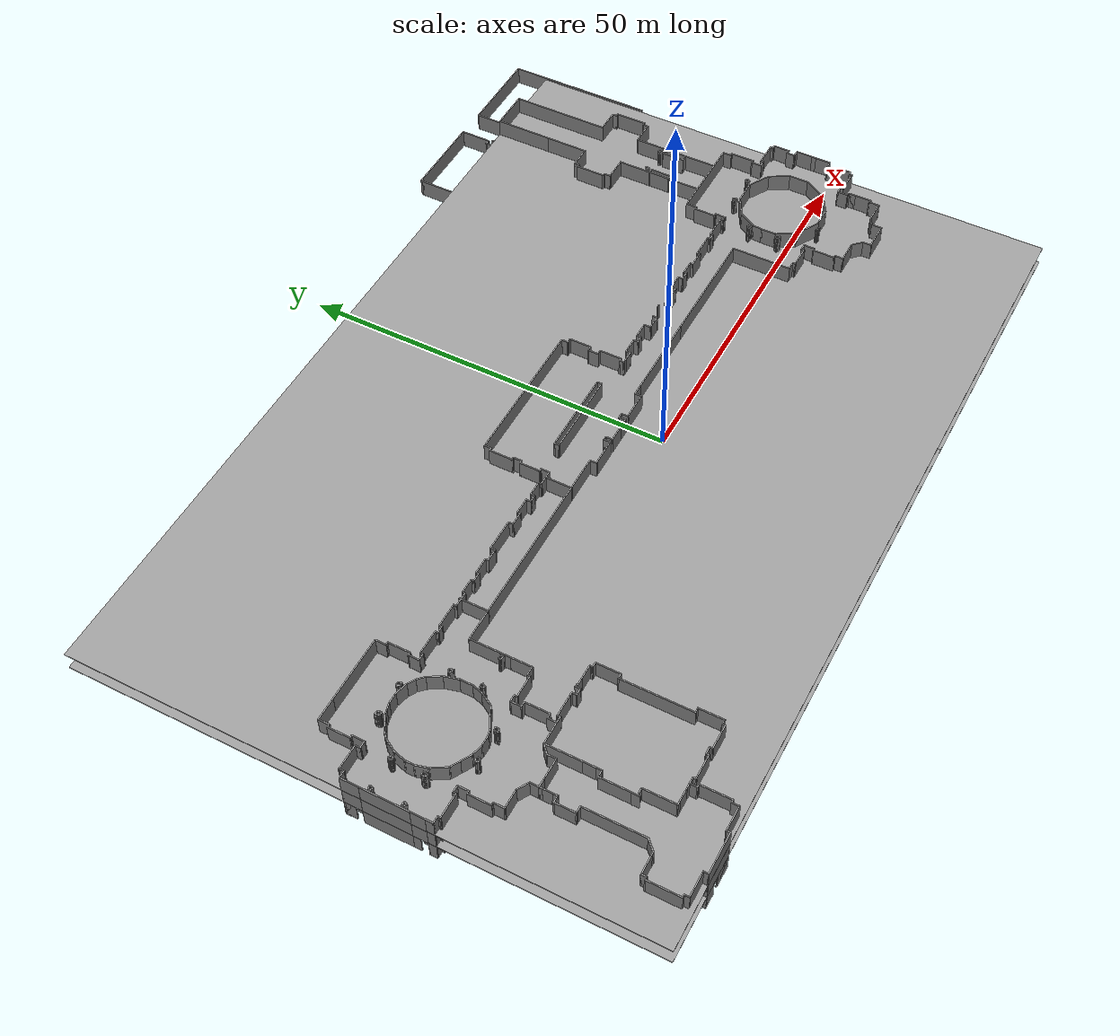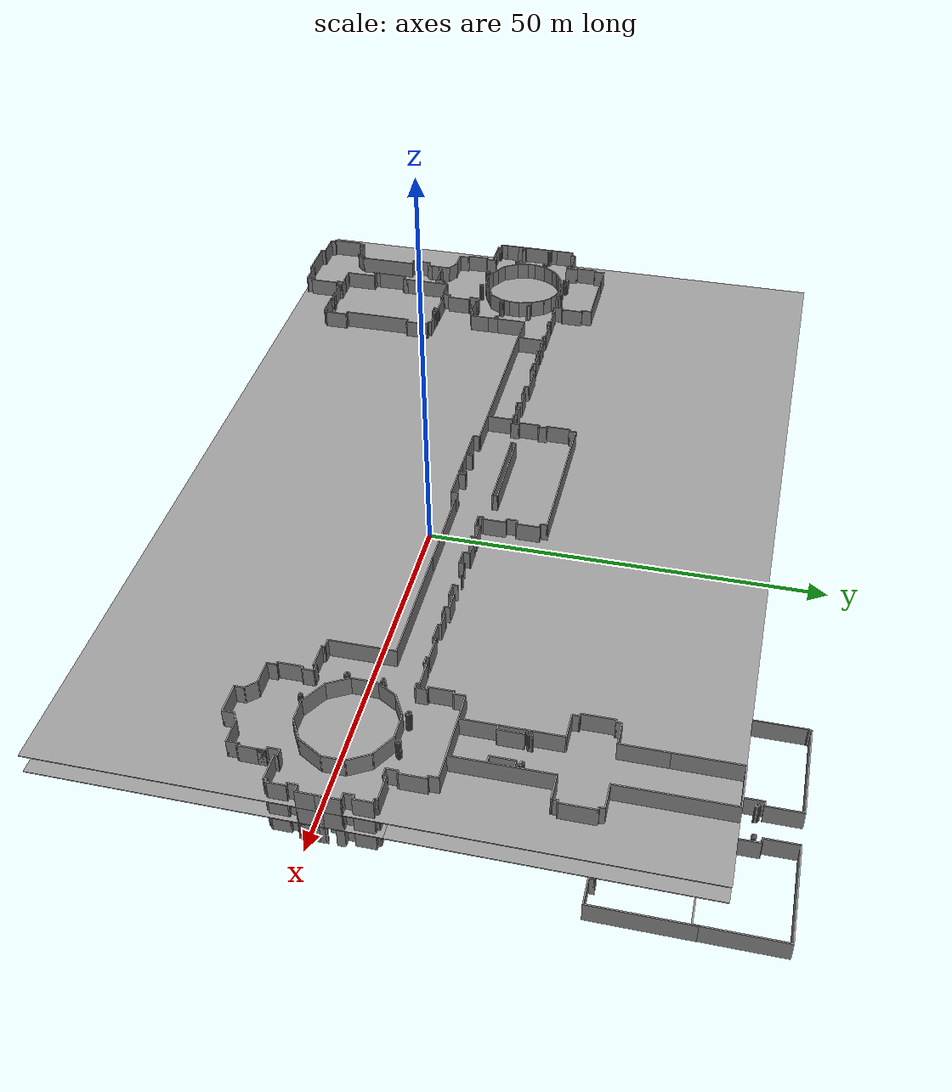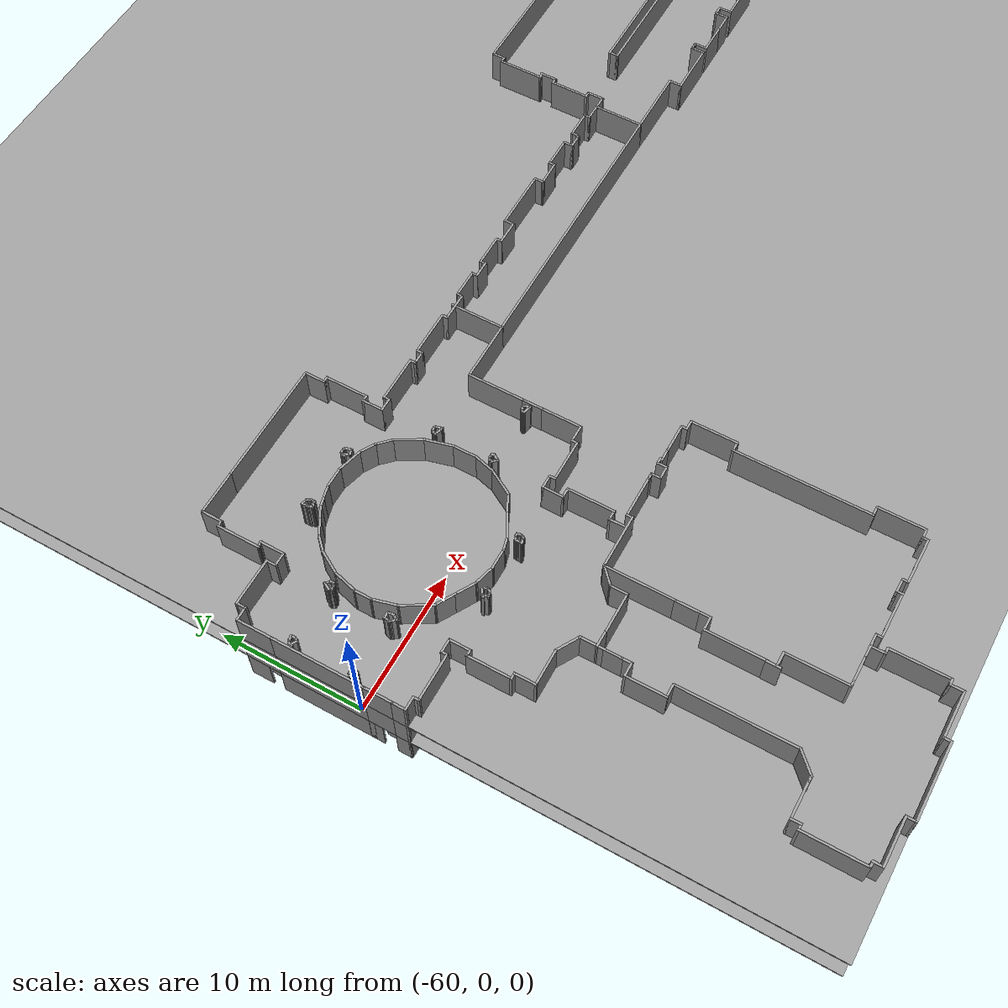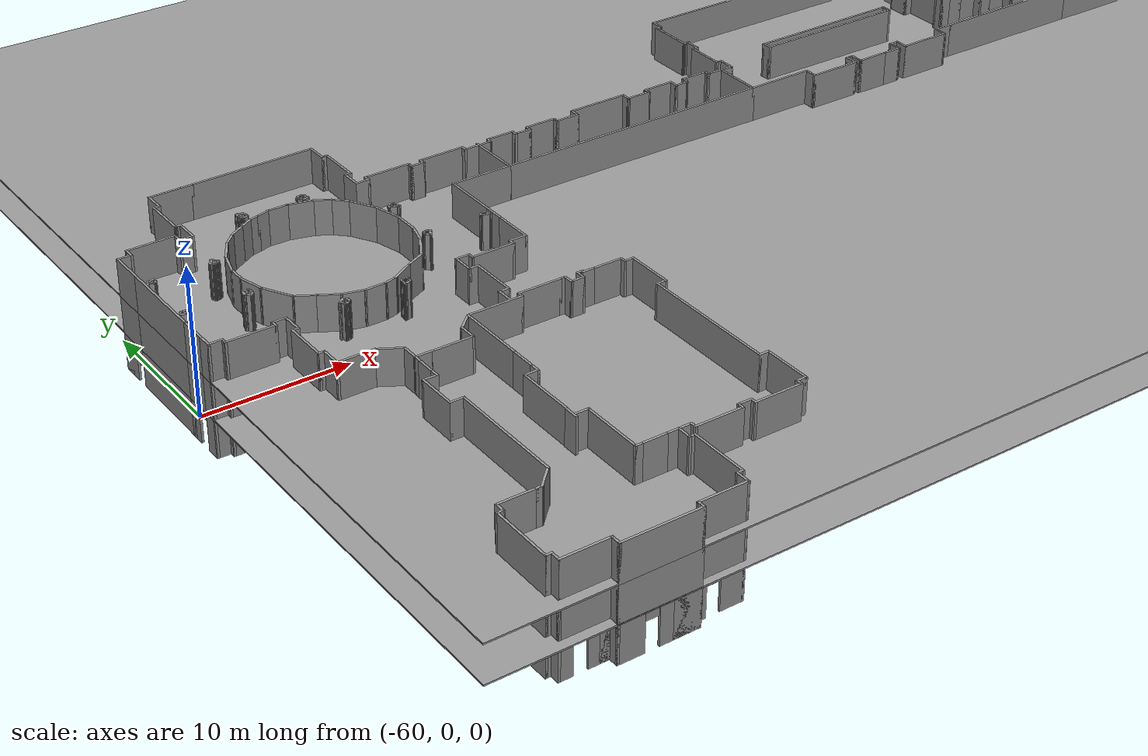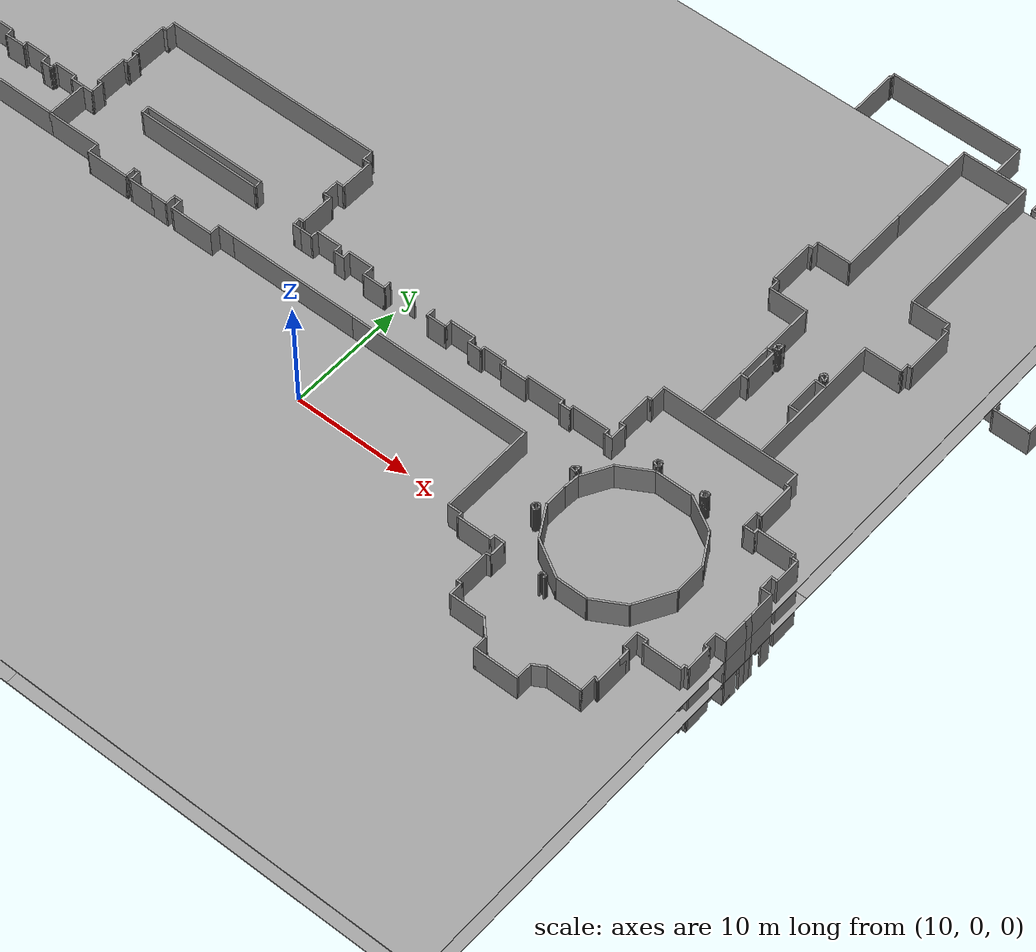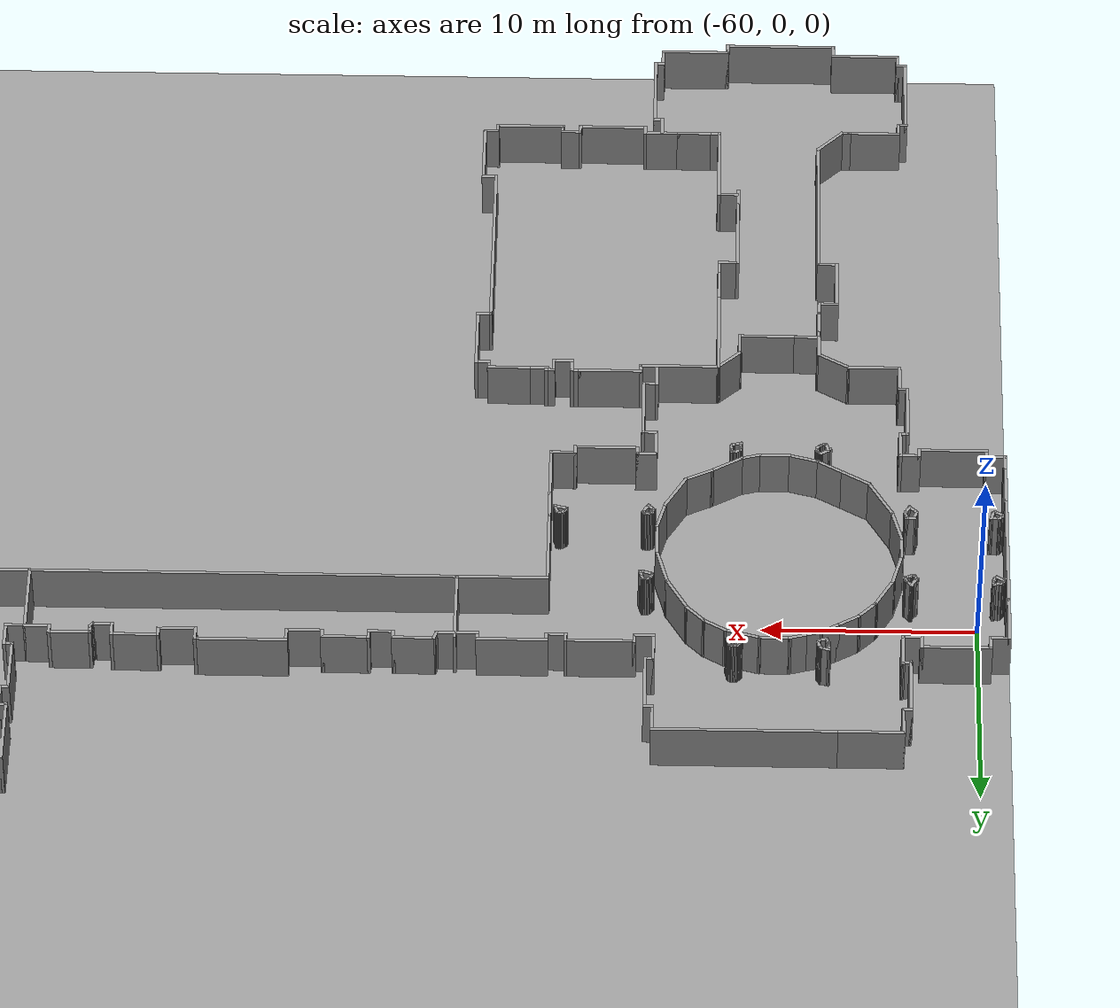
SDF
<?xml version='1.0'?>
<sdf version='1.7'>
  <model name='mapagazebo'>
    <pose>-4.67869 9.01252 0 0 -0 0</pose>
    <link name='Floor_0'>
      <pose>-1.60182 -3.26665 2.5 0 -0 0</pose>
      <visual name='Floor_0_Visual_0'>
        <pose>-18.0827 0 0.05 0 -0 0</pose>
        <geometry>
          <box>
            <size>73.5307 73.9373 0.1</size>
          </box>
        </geometry>
        <material>
          <script>
            <uri>file://media/materials/scripts/gazebo.material</uri>
            <name>Gazebo/Grey</name>
          </script>
          <ambient>1 1 1 1</ambient>
        </material>
        <meta>
          <layer>1</layer>
        </meta>
      </visual>
      <collision name='Floor_0_Collision_0'>
        <geometry>
          <box>
            <size>73.5307 73.9373 0.1</size>
          </box>
        </geometry>
        <pose>-18.0827 0 0.05 0 -0 0</pose>
      </collision>
      <visual name='Floor_0_Visual_1'>
        <pose>36.7654 -17.3628 0.05 0 -0 0</pose>
        <geometry>
          <box>
            <size>36.1654 39.2116 0.1</size>
          </box>
        </geometry>
        <material>
          <script>
            <uri>file://media/materials/scripts/gazebo.material</uri>
            <name>Gazebo/Grey</name>
          </script>
          <ambient>1 1 1 1</ambient>
        </material>
        <meta>
          <layer>1</layer>
        </meta>
      </visual>
      <collision name='Floor_0_Collision_1'>
        <geometry>
          <box>
            <size>36.1654 39.2116 0.1</size>
          </box>
        </geometry>
        <pose>36.7654 -17.3628 0.05 0 -0 0</pose>
      </collision>
      <visual name='Floor_0_Visual_2'>
        <pose>37.2654 19.6058 0.05 0 -0 0</pose>
        <geometry>
          <box>
            <size>35.1654 34.7257 0.1</size>
          </box>
        </geometry>
        <material>
          <script>
            <uri>file://media/materials/scripts/gazebo.material</uri>
            <name>Gazebo/Grey</name>
          </script>
          <ambient>1 1 1 1</ambient>
        </material>
        <meta>
          <layer>1</layer>
        </meta>
      </visual>
      <collision name='Floor_0_Collision_2'>
        <geometry>
          <box>
            <size>35.1654 34.7257 0.1</size>
          </box>
        </geometry>
        <pose>37.2654 19.6058 0.05 0 -0 0</pose>
      </collision>
      <visual name='Floor_0_Visual_3'>
        <pose>19.1827 21.3558 0.05 0 -0 0</pose>
        <geometry>
          <box>
            <size>1 31.2257 0.1</size>
          </box>
        </geometry>
        <material>
          <script>
            <uri>file://media/materials/scripts/gazebo.material</uri>
            <name>Gazebo/Grey</name>
          </script>
          <ambient>1 1 1 1</ambient>
        </material>
        <meta>
          <layer>1</layer>
        </meta>
      </visual>
      <collision name='Floor_0_Collision_3'>
        <geometry>
          <box>
            <size>1 31.2257 0.1</size>
          </box>
        </geometry>
        <pose>19.1827 21.3558 0.05 0 -0 0</pose>
      </collision>
    </link>
    <link name='Floor_1'>
      <collision name='Floor_1_Collision'>
        <geometry>
          <box>
            <size>109.696 73.9373 0.1</size>
          </box>
        </geometry>
        <pose>0 0 0.05 0 -0 0</pose>
      </collision>
      <visual name='Floor_1_Visual'>
        <pose>0 0 0.05 0 -0 0</pose>
        <geometry>
          <box>
            <size>109.696 73.9373 0.1</size>
          </box>
        </geometry>
        <material>
          <script>
            <uri>file://media/materials/scripts/gazebo.material</uri>
            <name>Gazebo/Grey</name>
          </script>
          <ambient>1 1 1 1</ambient>
        </material>
        <meta>
          <layer>2</layer>
        </meta>
      </visual>
      <pose>-1.60182 -3.26665 5 0 -0 0</pose>
    </link>
    <link name='Stairs_0'>
      <visual name='Stairs_0_Visual_0'>
        <pose>17.5808 2.35966 0.083333 0 -0 0</pose>
        <geometry>
          <box>
            <size>1 0.233333 0.166667</size>
          </box>
        </geometry>
        <material>
          <script>
            <uri>file://media/materials/scripts/gazebo.material</uri>
            <name>Gazebo/Grey</name>
          </script>
          <ambient>1 1 1 1</ambient>
        </material>
        <meta>
          <layer>0</layer>
        </meta>
      </visual>
      <collision name='Stairs_0_Collision_0'>
        <geometry>
          <box>
            <size>1 0.233333 0.166667</size>
          </box>
        </geometry>
        <pose>17.5808 2.35966 0.083333 0 -0 0</pose>
      </collision>
      <visual name='Stairs_0_Visual_1'>
        <pose>17.5808 2.12633 0.25 0 -0 0</pose>
        <geometry>
          <box>
            <size>1 0.233333 0.166667</size>
          </box>
        </geometry>
        <material>
          <script>
            <uri>file://media/materials/scripts/gazebo.material</uri>
            <name>Gazebo/Grey</name>
          </script>
          <ambient>1 1 1 1</ambient>
        </material>
        <meta>
          <layer>0</layer>
        </meta>
      </visual>
      <collision name='Stairs_0_Collision_1'>
        <geometry>
          <box>
            <size>1 0.233333 0.166667</size>
          </box>
        </geometry>
        <pose>17.5808 2.12633 0.25 0 -0 0</pose>
      </collision>
      <visual name='Stairs_0_Visual_2'>
        <pose>17.5808 1.893 0.416667 0 -0 0</pose>
        <geometry>
          <box>
            <size>1 0.233333 0.166667</size>
          </box>
        </geometry>
        <material>
          <script>
            <uri>file://media/materials/scripts/gazebo.material</uri>
            <name>Gazebo/Grey</name>
          </script>
          <ambient>1 1 1 1</ambient>
        </material>
        <meta>
          <layer>0</layer>
        </meta>
      </visual>
      <collision name='Stairs_0_Collision_2'>
        <geometry>
          <box>
            <size>1 0.233333 0.166667</size>
          </box>
        </geometry>
        <pose>17.5808 1.893 0.416667 0 -0 0</pose>
      </collision>
      <visual name='Stairs_0_Visual_3'>
        <pose>17.5808 1.65966 0.583333 0 -0 0</pose>
        <geometry>
          <box>
            <size>1 0.233333 0.166667</size>
          </box>
        </geometry>
        <material>
          <script>
            <uri>file://media/materials/scripts/gazebo.material</uri>
            <name>Gazebo/Grey</name>
          </script>
          <ambient>1 1 1 1</ambient>
        </material>
        <meta>
          <layer>0</layer>
        </meta>
      </visual>
      <collision name='Stairs_0_Collision_3'>
        <geometry>
          <box>
            <size>1 0.233333 0.166667</size>
          </box>
        </geometry>
        <pose>17.5808 1.65966 0.583333 0 -0 0</pose>
      </collision>
      <visual name='Stairs_0_Visual_4'>
        <pose>17.5808 1.42633 0.75 0 -0 0</pose>
        <geometry>
          <box>
            <size>1 0.233333 0.166667</size>
          </box>
        </geometry>
        <material>
          <script>
            <uri>file://media/materials/scripts/gazebo.material</uri>
            <name>Gazebo/Grey</name>
          </script>
          <ambient>1 1 1 1</ambient>
        </material>
        <meta>
          <layer>0</layer>
        </meta>
      </visual>
      <collision name='Stairs_0_Collision_4'>
        <geometry>
          <box>
            <size>1 0.233333 0.166667</size>
          </box>
        </geometry>
        <pose>17.5808 1.42633 0.75 0 -0 0</pose>
      </collision>
      <visual name='Stairs_0_Visual_5'>
        <pose>17.5808 1.193 0.916667 0 -0 0</pose>
        <geometry>
          <box>
            <size>1 0.233333 0.166667</size>
          </box>
        </geometry>
        <material>
          <script>
            <uri>file://media/materials/scripts/gazebo.material</uri>
            <name>Gazebo/Grey</name>
          </script>
          <ambient>1 1 1 1</ambient>
        </material>
        <meta>
          <layer>0</layer>
        </meta>
      </visual>
      <collision name='Stairs_0_Collision_5'>
        <geometry>
          <box>
            <size>1 0.233333 0.166667</size>
          </box>
        </geometry>
        <pose>17.5808 1.193 0.916667 0 -0 0</pose>
      </collision>
      <visual name='Stairs_0_Visual_6'>
        <pose>17.5808 0.959664 1.08333 0 -0 0</pose>
        <geometry>
          <box>
            <size>1 0.233333 0.166667</size>
          </box>
        </geometry>
        <material>
          <script>
            <uri>file://media/materials/scripts/gazebo.material</uri>
            <name>Gazebo/Grey</name>
          </script>
          <ambient>1 1 1 1</ambient>
        </material>
        <meta>
          <layer>0</layer>
        </meta>
      </visual>
      <collision name='Stairs_0_Collision_6'>
        <geometry>
          <box>
            <size>1 0.233333 0.166667</size>
          </box>
        </geometry>
        <pose>17.5808 0.959664 1.08333 0 -0 0</pose>
      </collision>
      <visual name='Stairs_0_Visual_7'>
        <pose>17.5808 0.726331 1.25 0 -0 0</pose>
        <geometry>
          <box>
            <size>1 0.233333 0.166667</size>
          </box>
        </geometry>
        <material>
          <script>
            <uri>file://media/materials/scripts/gazebo.material</uri>
            <name>Gazebo/Grey</name>
          </script>
          <ambient>1 1 1 1</ambient>
        </material>
        <meta>
          <layer>0</layer>
        </meta>
      </visual>
      <collision name='Stairs_0_Collision_7'>
        <geometry>
          <box>
            <size>1 0.233333 0.166667</size>
          </box>
        </geometry>
        <pose>17.5808 0.726331 1.25 0 -0 0</pose>
      </collision>
      <visual name='Stairs_0_Visual_8'>
        <pose>17.5808 0.492997 1.41667 0 -0 0</pose>
        <geometry>
          <box>
            <size>1 0.233333 0.166667</size>
          </box>
        </geometry>
        <material>
          <script>
            <uri>file://media/materials/scripts/gazebo.material</uri>
            <name>Gazebo/Grey</name>
          </script>
          <ambient>1 1 1 1</ambient>
        </material>
        <meta>
          <layer>0</layer>
        </meta>
      </visual>
      <collision name='Stairs_0_Collision_8'>
        <geometry>
          <box>
            <size>1 0.233333 0.166667</size>
          </box>
        </geometry>
        <pose>17.5808 0.492997 1.41667 0 -0 0</pose>
      </collision>
      <visual name='Stairs_0_Visual_9'>
        <pose>17.5808 0.259665 1.58333 0 -0 0</pose>
        <geometry>
          <box>
            <size>1 0.233333 0.166667</size>
          </box>
        </geometry>
        <material>
          <script>
            <uri>file://media/materials/scripts/gazebo.material</uri>
            <name>Gazebo/Grey</name>
          </script>
          <ambient>1 1 1 1</ambient>
        </material>
        <meta>
          <layer>0</layer>
        </meta>
      </visual>
      <collision name='Stairs_0_Collision_9'>
        <geometry>
          <box>
            <size>1 0.233333 0.166667</size>
          </box>
        </geometry>
        <pose>17.5808 0.259665 1.58333 0 -0 0</pose>
      </collision>
      <visual name='Stairs_0_Visual_10'>
        <pose>17.5808 0.026331 1.75 0 -0 0</pose>
        <geometry>
          <box>
            <size>1 0.233333 0.166667</size>
          </box>
        </geometry>
        <material>
          <script>
            <uri>file://media/materials/scripts/gazebo.material</uri>
            <name>Gazebo/Grey</name>
          </script>
          <ambient>1 1 1 1</ambient>
        </material>
        <meta>
          <layer>0</layer>
        </meta>
      </visual>
      <collision name='Stairs_0_Collision_10'>
        <geometry>
          <box>
            <size>1 0.233333 0.166667</size>
          </box>
        </geometry>
        <pose>17.5808 0.026331 1.75 0 -0 0</pose>
      </collision>
      <visual name='Stairs_0_Visual_11'>
        <pose>17.5808 -0.207003 1.91667 0 -0 0</pose>
        <geometry>
          <box>
            <size>1 0.233333 0.166667</size>
          </box>
        </geometry>
        <material>
          <script>
            <uri>file://media/materials/scripts/gazebo.material</uri>
            <name>Gazebo/Grey</name>
          </script>
          <ambient>1 1 1 1</ambient>
        </material>
        <meta>
          <layer>0</layer>
        </meta>
      </visual>
      <collision name='Stairs_0_Collision_11'>
        <geometry>
          <box>
            <size>1 0.233333 0.166667</size>
          </box>
        </geometry>
        <pose>17.5808 -0.207003 1.91667 0 -0 0</pose>
      </collision>
      <visual name='Stairs_0_Visual_12'>
        <pose>17.5808 -0.440336 2.08333 0 -0 0</pose>
        <geometry>
          <box>
            <size>1 0.233333 0.166667</size>
          </box>
        </geometry>
        <material>
          <script>
            <uri>file://media/materials/scripts/gazebo.material</uri>
            <name>Gazebo/Grey</name>
          </script>
          <ambient>1 1 1 1</ambient>
        </material>
        <meta>
          <layer>0</layer>
        </meta>
      </visual>
      <collision name='Stairs_0_Collision_12'>
        <geometry>
          <box>
            <size>1 0.233333 0.166667</size>
          </box>
        </geometry>
        <pose>17.5808 -0.440336 2.08333 0 -0 0</pose>
      </collision>
      <visual name='Stairs_0_Visual_13'>
        <pose>17.5808 -0.673669 2.25 0 -0 0</pose>
        <geometry>
          <box>
            <size>1 0.233333 0.166667</size>
          </box>
        </geometry>
        <material>
          <script>
            <uri>file://media/materials/scripts/gazebo.material</uri>
            <name>Gazebo/Grey</name>
          </script>
          <ambient>1 1 1 1</ambient>
        </material>
        <meta>
          <layer>0</layer>
        </meta>
      </visual>
      <collision name='Stairs_0_Collision_13'>
        <geometry>
          <box>
            <size>1 0.233333 0.166667</size>
          </box>
        </geometry>
        <pose>17.5808 -0.673669 2.25 0 -0 0</pose>
      </collision>
      <visual name='Stairs_0_Visual_14'>
        <pose>17.5808 -0.907002 2.41667 0 -0 0</pose>
        <geometry>
          <box>
            <size>1 0.233333 0.166667</size>
          </box>
        </geometry>
        <material>
          <script>
            <uri>file://media/materials/scripts/gazebo.material</uri>
            <name>Gazebo/Grey</name>
          </script>
          <ambient>1 1 1 1</ambient>
        </material>
        <meta>
          <layer>0</layer>
        </meta>
      </visual>
      <collision name='Stairs_0_Collision_14'>
        <geometry>
          <box>
            <size>1 0.233333 0.166667</size>
          </box>
        </geometry>
        <pose>17.5808 -0.907002 2.41667 0 -0 0</pose>
      </collision>
    </link>
    <link name='Wall_0'>
      <collision name='Wall_0_Collision'>
        <geometry>
          <box>
            <size>1 0.15 2.5</size>
          </box>
        </geometry>
        <pose>0 0 1.25 0 -0 0</pose>
      </collision>
      <visual name='Wall_0_Visual'>
        <pose>0 0 1.25 0 -0 0</pose>
        <geometry>
          <box>
            <size>1 0.15 2.5</size>
          </box>
        </geometry>
        <material>
          <script>
            <uri>file://media/materials/scripts/gazebo.material</uri>
            <name>Gazebo/Bricks</name>
          </script>
          <ambient>1 1 1 1</ambient>
        </material>
        <meta>
          <layer>0</layer>
        </meta>
      </visual>
      <pose>-34.7974 -18.4547 0 0 -0 0</pose>
    </link>
    <link name='Wall_1'>
      <collision name='Wall_1_Collision'>
        <geometry>
          <box>
            <size>2 0.15 2.5</size>
          </box>
        </geometry>
        <pose>0 0 1.25 0 -0 0</pose>
      </collision>
      <visual name='Wall_1_Visual'>
        <pose>0 0 1.25 0 -0 0</pose>
        <geometry>
          <box>
            <size>2 0.15 2.5</size>
          </box>
        </geometry>
        <material>
          <script>
            <uri>file://media/materials/scripts/gazebo.material</uri>
            <name>Gazebo/Grey</name>
          </script>
          <ambient>1 1 1 1</ambient>
        </material>
        <meta>
          <layer>0</layer>
        </meta>
      </visual>
      <pose>-33.4474 -18.4547 0 0 -0 0</pose>
    </link>
    <link name='Wall_10'>
      <collision name='Wall_10_Collision'>
        <geometry>
          <box>
            <size>0.75 0.15 2.5</size>
          </box>
        </geometry>
        <pose>0 0 1.25 0 -0 0</pose>
      </collision>
      <visual name='Wall_10_Visual'>
        <pose>0 0 1.25 0 -0 0</pose>
        <geometry>
          <box>
            <size>0.75 0.15 2.5</size>
          </box>
        </geometry>
        <material>
          <script>
            <uri>file://media/materials/scripts/gazebo.material</uri>
            <name>Gazebo/Bricks</name>
          </script>
          <ambient>1 1 1 1</ambient>
        </material>
        <meta>
          <layer>0</layer>
        </meta>
      </visual>
      <pose>-32.2224 -34.1047 0 0 -0 3.14159</pose>
    </link>
    <link name='Wall_100'>
      <collision name='Wall_100_Collision'>
        <geometry>
          <box>
            <size>0.5 0.15 2.5</size>
          </box>
        </geometry>
        <pose>0 0 1.25 0 -0 0</pose>
      </collision>
      <visual name='Wall_100_Visual'>
        <pose>0 0 1.25 0 -0 0</pose>
        <geometry>
          <box>
            <size>0.5 0.15 2.5</size>
          </box>
        </geometry>
        <material>
          <script>
            <uri>file://media/materials/scripts/gazebo.material</uri>
            <name>Gazebo/Grey</name>
          </script>
          <ambient>1 1 1 1</ambient>
        </material>
        <meta>
          <layer>0</layer>
        </meta>
      </visual>
      <pose>-55.5249 -13.3911 0 0 -0 1.5708</pose>
    </link>
    <link name='Wall_1000'>
      <collision name='Wall_1000_Collision'>
        <geometry>
          <box>
            <size>0.25 0.15 2.5</size>
          </box>
        </geometry>
        <pose>0 0 1.25 0 -0 0</pose>
      </collision>
      <visual name='Wall_1000_Visual'>
        <pose>0 0 1.25 0 -0 0</pose>
        <geometry>
          <box>
            <size>0.25 0.15 2.5</size>
          </box>
        </geometry>
        <material>
          <script>
            <uri>file://media/materials/scripts/gazebo.material</uri>
            <name>Gazebo/Grey</name>
          </script>
          <ambient>1 1 1 1</ambient>
        </material>
        <meta>
          <layer>1</layer>
        </meta>
      </visual>
      <pose>-40.177 -5.42763 2.5 0 -0 0.785398</pose>
    </link>
    <link name='Wall_1001'>
      <collision name='Wall_1001_Collision'>
        <geometry>
          <box>
            <size>0.25 0.15 2.5</size>
          </box>
        </geometry>
        <pose>0 0 1.25 0 -0 0</pose>
      </collision>
      <visual name='Wall_1001_Visual'>
        <pose>0 0 1.25 0 -0 0</pose>
        <geometry>
          <box>
            <size>0.25 0.15 2.5</size>
          </box>
        </geometry>
        <material>
          <script>
            <uri>file://media/materials/scripts/gazebo.material</uri>
            <name>Gazebo/Grey</name>
          </script>
          <ambient>1 1 1 1</ambient>
        </material>
        <meta>
          <layer>1</layer>
        </meta>
      </visual>
      <pose>-40.0984 -5.36727 2.5 0 -0 0.523599</pose>
    </link>
    <link name='Wall_1002'>
      <collision name='Wall_1002_Collision'>
        <geometry>
          <box>
            <size>0.25 0.15 2.5</size>
          </box>
        </geometry>
        <pose>0 0 1.25 0 -0 0</pose>
      </collision>
      <visual name='Wall_1002_Visual'>
        <pose>0 0 1.25 0 -0 0</pose>
        <geometry>
          <box>
            <size>0.25 0.15 2.5</size>
          </box>
        </geometry>
        <material>
          <script>
            <uri>file://media/materials/scripts/gazebo.material</uri>
            <name>Gazebo/Grey</name>
          </script>
          <ambient>1 1 1 1</ambient>
        </material>
        <meta>
          <layer>1</layer>
        </meta>
      </visual>
      <pose>-40.0051 -5.34227 2.5 0 -0 0</pose>
    </link>
    <link name='Wall_1003'>
      <collision name='Wall_1003_Collision'>
        <geometry>
          <box>
            <size>0.25 0.15 2.5</size>
          </box>
        </geometry>
        <pose>0 0 1.25 0 -0 0</pose>
      </collision>
      <visual name='Wall_1003_Visual'>
        <pose>0 0 1.25 0 -0 0</pose>
        <geometry>
          <box>
            <size>0.25 0.15 2.5</size>
          </box>
        </geometry>
        <material>
          <script>
            <uri>file://media/materials/scripts/gazebo.material</uri>
            <name>Gazebo/Grey</name>
          </script>
          <ambient>1 1 1 1</ambient>
        </material>
        <meta>
          <layer>1</layer>
        </meta>
      </visual>
      <pose>-39.9068 -5.35521 2.5 0 -0 -0.261799</pose>
    </link>
    <link name='Wall_1004'>
      <collision name='Wall_1004_Collision'>
        <geometry>
          <box>
            <size>0.15 0.15 2.5</size>
          </box>
        </geometry>
        <pose>0 0 1.25 0 -0 0</pose>
      </collision>
      <visual name='Wall_1004_Visual'>
        <pose>0 0 1.25 0 -0 0</pose>
        <geometry>
          <box>
            <size>0.15 0.15 2.5</size>
          </box>
        </geometry>
        <material>
          <script>
            <uri>file://media/materials/scripts/gazebo.material</uri>
            <name>Gazebo/Grey</name>
          </script>
          <ambient>1 1 1 1</ambient>
        </material>
        <meta>
          <layer>1</layer>
        </meta>
      </visual>
      <pose>-39.8585 -5.36815 2.5 0 -0 0</pose>
    </link>
    <link name='Wall_1005'>
      <collision name='Wall_1005_Collision'>
        <geometry>
          <box>
            <size>0.25 0.15 2.5</size>
          </box>
        </geometry>
        <pose>0 0 1.25 0 -0 0</pose>
      </collision>
      <visual name='Wall_1005_Visual'>
        <pose>0 0 1.25 0 -0 0</pose>
        <geometry>
          <box>
            <size>0.25 0.15 2.5</size>
          </box>
        </geometry>
        <material>
          <script>
            <uri>file://media/materials/scripts/gazebo.material</uri>
            <name>Gazebo/Grey</name>
          </script>
          <ambient>1 1 1 1</ambient>
        </material>
        <meta>
          <layer>1</layer>
        </meta>
      </visual>
      <pose>-39.8335 -5.41146 2.5 0 -0 -1.0472</pose>
    </link>
    <link name='Wall_1006'>
      <collision name='Wall_1006_Collision'>
        <geometry>
          <box>
            <size>0.5 0.15 2.5</size>
          </box>
        </geometry>
        <pose>0 0 1.25 0 -0 0</pose>
      </collision>
      <visual name='Wall_1006_Visual'>
        <pose>0 0 1.25 0 -0 0</pose>
        <geometry>
          <box>
            <size>0.5 0.15 2.5</size>
          </box>
        </geometry>
        <material>
          <script>
            <uri>file://media/materials/scripts/gazebo.material</uri>
            <name>Gazebo/Grey</name>
          </script>
          <ambient>1 1 1 1</ambient>
        </material>
        <meta>
          <layer>1</layer>
        </meta>
      </visual>
      <pose>-39.7632 -5.62379 2.5 0 -0 -1.309</pose>
    </link>
    <link name='Wall_1007'>
      <collision name='Wall_1007_Collision'>
        <geometry>
          <box>
            <size>0.15 0.15 2.5</size>
          </box>
        </geometry>
        <pose>0 0 1.25 0 -0 0</pose>
      </collision>
      <visual name='Wall_1007_Visual'>
        <pose>0 0 1.25 0 -0 0</pose>
        <geometry>
          <box>
            <size>0.15 0.15 2.5</size>
          </box>
        </geometry>
        <material>
          <script>
            <uri>file://media/materials/scripts/gazebo.material</uri>
            <name>Gazebo/Grey</name>
          </script>
          <ambient>1 1 1 1</ambient>
        </material>
        <meta>
          <layer>1</layer>
        </meta>
      </visual>
      <pose>-39.7179 -5.79283 2.5 0 -0 0</pose>
    </link>
    <link name='Wall_1008'>
      <collision name='Wall_1008_Collision'>
        <geometry>
          <box>
            <size>0.25 0.15 2.5</size>
          </box>
        </geometry>
        <pose>0 0 1.25 0 -0 0</pose>
      </collision>
      <visual name='Wall_1008_Visual'>
        <pose>0 0 1.25 0 -0 0</pose>
        <geometry>
          <box>
            <size>0.25 0.15 2.5</size>
          </box>
        </geometry>
        <material>
          <script>
            <uri>file://media/materials/scripts/gazebo.material</uri>
            <name>Gazebo/Grey</name>
          </script>
          <ambient>1 1 1 1</ambient>
        </material>
        <meta>
          <layer>1</layer>
        </meta>
      </visual>
      <pose>-39.7679 -5.79283 2.5 0 -0 3.14159</pose>
    </link>
    <link name='Wall_1009'>
      <collision name='Wall_1009_Collision'>
        <geometry>
          <box>
            <size>0.617004 0.15 2.5</size>
          </box>
        </geometry>
        <pose>0 0 1.25 0 -0 0</pose>
      </collision>
      <visual name='Wall_1009_Visual'>
        <pose>0 0 1.25 0 -0 0</pose>
        <geometry>
          <box>
            <size>0.617004 0.15 2.5</size>
          </box>
        </geometry>
        <material>
          <script>
            <uri>file://media/materials/scripts/gazebo.material</uri>
            <name>Gazebo/Grey</name>
          </script>
          <ambient>1 1 1 1</ambient>
        </material>
        <meta>
          <layer>1</layer>
        </meta>
      </visual>
      <pose>-40.0401 -5.72121 2.5 0 -0 2.82984</pose>
    </link>
    <link name='Wall_101'>
      <collision name='Wall_101_Collision'>
        <geometry>
          <box>
            <size>1 0.15 2.5</size>
          </box>
        </geometry>
        <pose>0 0 1.25 0 -0 0</pose>
      </collision>
      <visual name='Wall_101_Visual'>
        <pose>0 0 1.25 0 -0 0</pose>
        <geometry>
          <box>
            <size>1 0.15 2.5</size>
          </box>
        </geometry>
        <material>
          <script>
            <uri>file://media/materials/scripts/gazebo.material</uri>
            <name>Gazebo/Grey</name>
          </script>
          <ambient>1 1 1 1</ambient>
        </material>
        <meta>
          <layer>0</layer>
        </meta>
      </visual>
      <pose>-55.9499 -13.2161 0 0 -0 3.14159</pose>
    </link>
    <link name='Wall_1010'>
      <collision name='Wall_1010_Collision'>
        <geometry>
          <box>
            <size>0.15 0.15 2.5</size>
          </box>
        </geometry>
        <pose>0 0 1.25 0 -0 0</pose>
      </collision>
      <visual name='Wall_1010_Visual'>
        <pose>0 0 1.25 0 -0 0</pose>
        <geometry>
          <box>
            <size>0.15 0.15 2.5</size>
          </box>
        </geometry>
        <material>
          <script>
            <uri>file://media/materials/scripts/gazebo.material</uri>
            <name>Gazebo/Grey</name>
          </script>
          <ambient>1 1 1 1</ambient>
        </material>
        <meta>
          <layer>1</layer>
        </meta>
      </visual>
      <pose>-40.2624 -5.64959 2.5 0 -0 0</pose>
    </link>
    <link name='Wall_1011'>
      <collision name='Wall_1011_Collision'>
        <geometry>
          <box>
            <size>0.25 0.15 2.5</size>
          </box>
        </geometry>
        <pose>0 0 1.25 0 -0 0</pose>
      </collision>
      <visual name='Wall_1011_Visual'>
        <pose>0 0 1.25 0 -0 0</pose>
        <geometry>
          <box>
            <size>0.25 0.15 2.5</size>
          </box>
        </geometry>
        <material>
          <script>
            <uri>file://media/materials/scripts/gazebo.material</uri>
            <name>Gazebo/Grey</name>
          </script>
          <ambient>1 1 1 1</ambient>
        </material>
        <meta>
          <layer>1</layer>
        </meta>
      </visual>
      <pose>-44.2708 -1.57979 2.5 0 -0 1.5708</pose>
    </link>
    <link name='Wall_1012'>
      <collision name='Wall_1012_Collision'>
        <geometry>
          <box>
            <size>0.25 0.15 2.5</size>
          </box>
        </geometry>
        <pose>0 0 1.25 0 -0 0</pose>
      </collision>
      <visual name='Wall_1012_Visual'>
        <pose>0 0 1.25 0 -0 0</pose>
        <geometry>
          <box>
            <size>0.25 0.15 2.5</size>
          </box>
        </geometry>
        <material>
          <script>
            <uri>file://media/materials/scripts/gazebo.material</uri>
            <name>Gazebo/Grey</name>
          </script>
          <ambient>1 1 1 1</ambient>
        </material>
        <meta>
          <layer>1</layer>
        </meta>
      </visual>
      <pose>-44.2708 -1.57979 2.5 0 -0 -1.5708</pose>
    </link>
    <link name='Wall_1013'>
      <collision name='Wall_1013_Collision'>
        <geometry>
          <box>
            <size>0.25 0.15 2.5</size>
          </box>
        </geometry>
        <pose>0 0 1.25 0 -0 0</pose>
      </collision>
      <visual name='Wall_1013_Visual'>
        <pose>0 0 1.25 0 -0 0</pose>
        <geometry>
          <box>
            <size>0.25 0.15 2.5</size>
          </box>
        </geometry>
        <material>
          <script>
            <uri>file://media/materials/scripts/gazebo.material</uri>
            <name>Gazebo/Grey</name>
          </script>
          <ambient>1 1 1 1</ambient>
        </material>
        <meta>
          <layer>1</layer>
        </meta>
      </visual>
      <pose>-44.2708 -1.57979 2.5 0 -0 1.5708</pose>
    </link>
    <link name='Wall_1014'>
      <collision name='Wall_1014_Collision'>
        <geometry>
          <box>
            <size>0.25 0.15 2.5</size>
          </box>
        </geometry>
        <pose>0 0 1.25 0 -0 0</pose>
      </collision>
      <visual name='Wall_1014_Visual'>
        <pose>0 0 1.25 0 -0 0</pose>
        <geometry>
          <box>
            <size>0.25 0.15 2.5</size>
          </box>
        </geometry>
        <material>
          <script>
            <uri>file://media/materials/scripts/gazebo.material</uri>
            <name>Gazebo/Grey</name>
          </script>
          <ambient>1 1 1 1</ambient>
        </material>
        <meta>
          <layer>1</layer>
        </meta>
      </visual>
      <pose>-44.2354 -1.49444 2.5 0 -0 0.785398</pose>
    </link>
    <link name='Wall_1015'>
      <collision name='Wall_1015_Collision'>
        <geometry>
          <box>
            <size>0.25 0.15 2.5</size>
          </box>
        </geometry>
        <pose>0 0 1.25 0 -0 0</pose>
      </collision>
      <visual name='Wall_1015_Visual'>
        <pose>0 0 1.25 0 -0 0</pose>
        <geometry>
          <box>
            <size>0.25 0.15 2.5</size>
          </box>
        </geometry>
        <material>
          <script>
            <uri>file://media/materials/scripts/gazebo.material</uri>
            <name>Gazebo/Grey</name>
          </script>
          <ambient>1 1 1 1</ambient>
        </material>
        <meta>
          <layer>1</layer>
        </meta>
      </visual>
      <pose>-44.1751 -1.41578 2.5 0 -0 1.0472</pose>
    </link>
    <link name='Wall_1016'>
      <collision name='Wall_1016_Collision'>
        <geometry>
          <box>
            <size>0.25 0.15 2.5</size>
          </box>
        </geometry>
        <pose>0 0 1.25 0 -0 0</pose>
      </collision>
      <visual name='Wall_1016_Visual'>
        <pose>0 0 1.25 0 -0 0</pose>
        <geometry>
          <box>
            <size>0.25 0.15 2.5</size>
          </box>
        </geometry>
        <material>
          <script>
            <uri>file://media/materials/scripts/gazebo.material</uri>
            <name>Gazebo/Grey</name>
          </script>
          <ambient>1 1 1 1</ambient>
        </material>
        <meta>
          <layer>1</layer>
        </meta>
      </visual>
      <pose>-44.1018 -1.35954 2.5 0 -0 0.261799</pose>
    </link>
    <link name='Wall_1017'>
      <collision name='Wall_1017_Collision'>
        <geometry>
          <box>
            <size>0.25 0.15 2.5</size>
          </box>
        </geometry>
        <pose>0 0 1.25 0 -0 0</pose>
      </collision>
      <visual name='Wall_1017_Visual'>
        <pose>0 0 1.25 0 -0 0</pose>
        <geometry>
          <box>
            <size>0.25 0.15 2.5</size>
          </box>
        </geometry>
        <material>
          <script>
            <uri>file://media/materials/scripts/gazebo.material</uri>
            <name>Gazebo/Grey</name>
          </script>
          <ambient>1 1 1 1</ambient>
        </material>
        <meta>
          <layer>1</layer>
        </meta>
      </visual>
      <pose>-44.0035 -1.3466 2.5 0 -0 0</pose>
    </link>
    <link name='Wall_1018'>
      <collision name='Wall_1018_Collision'>
        <geometry>
          <box>
            <size>0.25 0.15 2.5</size>
          </box>
        </geometry>
        <pose>0 0 1.25 0 -0 0</pose>
      </collision>
      <visual name='Wall_1018_Visual'>
        <pose>0 0 1.25 0 -0 0</pose>
        <geometry>
          <box>
            <size>0.25 0.15 2.5</size>
          </box>
        </geometry>
        <material>
          <script>
            <uri>file://media/materials/scripts/gazebo.material</uri>
            <name>Gazebo/Grey</name>
          </script>
          <ambient>1 1 1 1</ambient>
        </material>
        <meta>
          <layer>1</layer>
        </meta>
      </visual>
      <pose>-43.9052 -1.35954 2.5 0 -0 -0.261799</pose>
    </link>
    <link name='Wall_1019'>
      <collision name='Wall_1019_Collision'>
        <geometry>
          <box>
            <size>0.25 0.15 2.5</size>
          </box>
        </geometry>
        <pose>0 0 1.25 0 -0 0</pose>
      </collision>
      <visual name='Wall_1019_Visual'>
        <pose>0 0 1.25 0 -0 0</pose>
        <geometry>
          <box>
            <size>0.25 0.15 2.5</size>
          </box>
        </geometry>
        <material>
          <script>
            <uri>file://media/materials/scripts/gazebo.material</uri>
            <name>Gazebo/Grey</name>
          </script>
          <ambient>1 1 1 1</ambient>
        </material>
        <meta>
          <layer>1</layer>
        </meta>
      </visual>
      <pose>-43.8215 -1.40783 2.5 0 -0 -0.785398</pose>
    </link>
    <link name='Wall_102'>
      <collision name='Wall_102_Collision'>
        <geometry>
          <box>
            <size>1 0.15 2.5</size>
          </box>
        </geometry>
        <pose>0 0 1.25 0 -0 0</pose>
      </collision>
      <visual name='Wall_102_Visual'>
        <pose>0 0 1.25 0 -0 0</pose>
        <geometry>
          <box>
            <size>1 0.15 2.5</size>
          </box>
        </geometry>
        <material>
          <script>
            <uri>file://media/materials/scripts/gazebo.material</uri>
            <name>Gazebo/Grey</name>
          </script>
          <ambient>1 1 1 1</ambient>
        </material>
        <meta>
          <layer>0</layer>
        </meta>
      </visual>
      <pose>-56.3749 -12.7911 0 0 -0 1.5708</pose>
    </link>
    <link name='Wall_1020'>
      <collision name='Wall_1020_Collision'>
        <geometry>
          <box>
            <size>0.15 0.15 2.5</size>
          </box>
        </geometry>
        <pose>0 0 1.25 0 -0 0</pose>
      </collision>
      <visual name='Wall_1020_Visual'>
        <pose>0 0 1.25 0 -0 0</pose>
        <geometry>
          <box>
            <size>0.15 0.15 2.5</size>
          </box>
        </geometry>
        <material>
          <script>
            <uri>file://media/materials/scripts/gazebo.material</uri>
            <name>Gazebo/Grey</name>
          </script>
          <ambient>1 1 1 1</ambient>
        </material>
        <meta>
          <layer>1</layer>
        </meta>
      </visual>
      <pose>-43.7862 -1.44319 2.5 0 -0 0</pose>
    </link>
    <link name='Wall_1021'>
      <collision name='Wall_1021_Collision'>
        <geometry>
          <box>
            <size>0.5 0.15 2.5</size>
          </box>
        </geometry>
        <pose>0 0 1.25 0 -0 0</pose>
      </collision>
      <visual name='Wall_1021_Visual'>
        <pose>0 0 1.25 0 -0 0</pose>
        <geometry>
          <box>
            <size>0.5 0.15 2.5</size>
          </box>
        </geometry>
        <material>
          <script>
            <uri>file://media/materials/scripts/gazebo.material</uri>
            <name>Gazebo/Grey</name>
          </script>
          <ambient>1 1 1 1</ambient>
        </material>
        <meta>
          <layer>1</layer>
        </meta>
      </visual>
      <pose>-43.7409 -1.61223 2.5 0 -0 -1.309</pose>
    </link>
    <link name='Wall_1022'>
      <collision name='Wall_1022_Collision'>
        <geometry>
          <box>
            <size>0.15 0.15 2.5</size>
          </box>
        </geometry>
        <pose>0 0 1.25 0 -0 0</pose>
      </collision>
      <visual name='Wall_1022_Visual'>
        <pose>0 0 1.25 0 -0 0</pose>
        <geometry>
          <box>
            <size>0.15 0.15 2.5</size>
          </box>
        </geometry>
        <material>
          <script>
            <uri>file://media/materials/scripts/gazebo.material</uri>
            <name>Gazebo/Grey</name>
          </script>
          <ambient>1 1 1 1</ambient>
        </material>
        <meta>
          <layer>1</layer>
        </meta>
      </visual>
      <pose>-43.6956 -1.78126 2.5 0 -0 0</pose>
    </link>
    <link name='Wall_1023'>
      <collision name='Wall_1023_Collision'>
        <geometry>
          <box>
            <size>0.5 0.15 2.5</size>
          </box>
        </geometry>
        <pose>0 0 1.25 0 -0 0</pose>
      </collision>
      <visual name='Wall_1023_Visual'>
        <pose>0 0 1.25 0 -0 0</pose>
        <geometry>
          <box>
            <size>0.5 0.15 2.5</size>
          </box>
        </geometry>
        <material>
          <script>
            <uri>file://media/materials/scripts/gazebo.material</uri>
            <name>Gazebo/Grey</name>
          </script>
          <ambient>1 1 1 1</ambient>
        </material>
        <meta>
          <layer>1</layer>
        </meta>
      </visual>
      <pose>-43.8646 -1.82656 2.5 0 -0 -2.87979</pose>
    </link>
    <link name='Wall_1024'>
      <collision name='Wall_1024_Collision'>
        <geometry>
          <box>
            <size>0.15 0.15 2.5</size>
          </box>
        </geometry>
        <pose>0 0 1.25 0 -0 0</pose>
      </collision>
      <visual name='Wall_1024_Visual'>
        <pose>0 0 1.25 0 -0 0</pose>
        <geometry>
          <box>
            <size>0.15 0.15 2.5</size>
          </box>
        </geometry>
        <material>
          <script>
            <uri>file://media/materials/scripts/gazebo.material</uri>
            <name>Gazebo/Grey</name>
          </script>
          <ambient>1 1 1 1</ambient>
        </material>
        <meta>
          <layer>1</layer>
        </meta>
      </visual>
      <pose>-44.0336 -1.87185 2.5 0 -0 0</pose>
    </link>
    <link name='Wall_1025'>
      <collision name='Wall_1025_Collision'>
        <geometry>
          <box>
            <size>0.59505 0.15 2.5</size>
          </box>
        </geometry>
        <pose>0 0 1.25 0 -0 0</pose>
      </collision>
      <visual name='Wall_1025_Visual'>
        <pose>0 0 1.25 0 -0 0</pose>
        <geometry>
          <box>
            <size>0.59505 0.15 2.5</size>
          </box>
        </geometry>
        <material>
          <script>
            <uri>file://media/materials/scripts/gazebo.material</uri>
            <name>Gazebo/Grey</name>
          </script>
          <ambient>1 1 1 1</ambient>
        </material>
        <meta>
          <layer>1</layer>
        </meta>
      </visual>
      <pose>-44.1169 -1.66547 2.5 0 -0 1.95402</pose>
    </link>
    <link name='Wall_1026'>
      <collision name='Wall_1026_Collision'>
        <geometry>
          <box>
            <size>0.15 0.15 2.5</size>
          </box>
        </geometry>
        <pose>0 0 1.25 0 -0 0</pose>
      </collision>
      <visual name='Wall_1026_Visual'>
        <pose>0 0 1.25 0 -0 0</pose>
        <geometry>
          <box>
            <size>0.15 0.15 2.5</size>
          </box>
        </geometry>
        <material>
          <script>
            <uri>file://media/materials/scripts/gazebo.material</uri>
            <name>Gazebo/Grey</name>
          </script>
          <ambient>1 1 1 1</ambient>
        </material>
        <meta>
          <layer>1</layer>
        </meta>
      </visual>
      <pose>-44.2001 -1.45908 2.5 0 -0 0</pose>
    </link>
    <link name='Wall_1027'>
      <collision name='Wall_1027_Collision'>
        <geometry>
          <box>
            <size>0.25 0.15 2.5</size>
          </box>
        </geometry>
        <pose>0 0 1.25 0 -0 0</pose>
      </collision>
      <visual name='Wall_1027_Visual'>
        <pose>0 0 1.25 0 -0 0</pose>
        <geometry>
          <box>
            <size>0.25 0.15 2.5</size>
          </box>
        </geometry>
        <material>
          <script>
            <uri>file://media/materials/scripts/gazebo.material</uri>
            <name>Gazebo/Grey</name>
          </script>
          <ambient>1 1 1 1</ambient>
        </material>
        <meta>
          <layer>1</layer>
        </meta>
      </visual>
      <pose>-48.2394 -1.57255 2.5 0 -0 1.5708</pose>
    </link>
    <link name='Wall_1028'>
      <collision name='Wall_1028_Collision'>
        <geometry>
          <box>
            <size>0.25 0.15 2.5</size>
          </box>
        </geometry>
        <pose>0 0 1.25 0 -0 0</pose>
      </collision>
      <visual name='Wall_1028_Visual'>
        <pose>0 0 1.25 0 -0 0</pose>
        <geometry>
          <box>
            <size>0.25 0.15 2.5</size>
          </box>
        </geometry>
        <material>
          <script>
            <uri>file://media/materials/scripts/gazebo.material</uri>
            <name>Gazebo/Grey</name>
          </script>
          <ambient>1 1 1 1</ambient>
        </material>
        <meta>
          <layer>1</layer>
        </meta>
      </visual>
      <pose>-48.2394 -1.57255 2.5 0 -0 -1.5708</pose>
    </link>
    <link name='Wall_1029'>
      <collision name='Wall_1029_Collision'>
        <geometry>
          <box>
            <size>0.25 0.15 2.5</size>
          </box>
        </geometry>
        <pose>0 0 1.25 0 -0 0</pose>
      </collision>
      <visual name='Wall_1029_Visual'>
        <pose>0 0 1.25 0 -0 0</pose>
        <geometry>
          <box>
            <size>0.25 0.15 2.5</size>
          </box>
        </geometry>
        <material>
          <script>
            <uri>file://media/materials/scripts/gazebo.material</uri>
            <name>Gazebo/Grey</name>
          </script>
          <ambient>1 1 1 1</ambient>
        </material>
        <meta>
          <layer>1</layer>
        </meta>
      </visual>
      <pose>-48.2394 -1.57255 2.5 0 -0 1.5708</pose>
    </link>
    <link name='Wall_103'>
      <pose>-56.3749 -11.4411 0 0 -0 1.5708</pose>
      <visual name='Wall_103_Visual_0'>
        <pose>-0.92124 0 1.25 0 -0 0</pose>
        <geometry>
          <box>
            <size>0.157519 0.15 2.5</size>
          </box>
        </geometry>
        <material>
          <script>
            <uri>file://media/materials/scripts/gazebo.material</uri>
            <name>Gazebo/Grey</name>
          </script>
          <ambient>1 1 1 1</ambient>
        </material>
        <meta>
          <layer>0</layer>
        </meta>
      </visual>
      <collision name='Wall_103_Collision_0'>
        <geometry>
          <box>
            <size>0.157519 0.15 2.5</size>
          </box>
        </geometry>
        <pose>-0.92124 0 1.25 0 -0 0</pose>
      </collision>
      <visual name='Wall_103_Visual_1'>
        <pose>0.52876 0 1.25 0 -0 0</pose>
        <geometry>
          <box>
            <size>0.942481 0.15 2.5</size>
          </box>
        </geometry>
        <material>
          <script>
            <uri>file://media/materials/scripts/gazebo.material</uri>
            <name>Gazebo/Grey</name>
          </script>
          <ambient>1 1 1 1</ambient>
        </material>
        <meta>
          <layer>0</layer>
        </meta>
      </visual>
      <collision name='Wall_103_Collision_1'>
        <geometry>
          <box>
            <size>0.942481 0.15 2.5</size>
          </box>
        </geometry>
        <pose>0.52876 0 1.25 0 -0 0</pose>
      </collision>
      <visual name='Wall_103_Visual_2'>
        <pose>0.804239 0 1.25 0 -0 0</pose>
        <geometry>
          <box>
            <size>0.391522 0.15 2.5</size>
          </box>
        </geometry>
        <material>
          <script>
            <uri>file://media/materials/scripts/gazebo.material</uri>
            <name>Gazebo/Grey</name>
          </script>
          <ambient>1 1 1 1</ambient>
        </material>
        <meta>
          <layer>0</layer>
        </meta>
      </visual>
      <collision name='Wall_103_Collision_2'>
        <geometry>
          <box>
            <size>0.391522 0.15 2.5</size>
          </box>
        </geometry>
        <pose>0.804239 0 1.25 0 -0 0</pose>
      </collision>
      <visual name='Wall_103_Visual_3'>
        <pose>-0.567001 0 2.25 0 -0 0</pose>
        <geometry>
          <box>
            <size>0.550959 0.15 0.5</size>
          </box>
        </geometry>
        <material>
          <script>
            <uri>file://media/materials/scripts/gazebo.material</uri>
            <name>Gazebo/Grey</name>
          </script>
          <ambient>1 1 1 1</ambient>
        </material>
        <meta>
          <layer>0</layer>
        </meta>
      </visual>
      <collision name='Wall_103_Collision_3'>
        <geometry>
          <box>
            <size>0.550959 0.15 0.5</size>
          </box>
        </geometry>
        <pose>-0.567001 0 2.25 0 -0 0</pose>
      </collision>
    </link>
    <link name='Wall_1030'>
      <collision name='Wall_1030_Collision'>
        <geometry>
          <box>
            <size>0.25 0.15 2.5</size>
          </box>
        </geometry>
        <pose>0 0 1.25 0 -0 0</pose>
      </collision>
      <visual name='Wall_1030_Visual'>
        <pose>0 0 1.25 0 -0 0</pose>
        <geometry>
          <box>
            <size>0.25 0.15 2.5</size>
          </box>
        </geometry>
        <material>
          <script>
            <uri>file://media/materials/scripts/gazebo.material</uri>
            <name>Gazebo/Grey</name>
          </script>
          <ambient>1 1 1 1</ambient>
        </material>
        <meta>
          <layer>1</layer>
        </meta>
      </visual>
      <pose>-48.2394 -1.57255 2.5 0 -0 -1.5708</pose>
    </link>
    <link name='Wall_1031'>
      <collision name='Wall_1031_Collision'>
        <geometry>
          <box>
            <size>0.25 0.15 2.5</size>
          </box>
        </geometry>
        <pose>0 0 1.25 0 -0 0</pose>
      </collision>
      <visual name='Wall_1031_Visual'>
        <pose>0 0 1.25 0 -0 0</pose>
        <geometry>
          <box>
            <size>0.25 0.15 2.5</size>
          </box>
        </geometry>
        <material>
          <script>
            <uri>file://media/materials/scripts/gazebo.material</uri>
            <name>Gazebo/Grey</name>
          </script>
          <ambient>1 1 1 1</ambient>
        </material>
        <meta>
          <layer>1</layer>
        </meta>
      </visual>
      <pose>-48.2394 -1.57255 2.5 0 -0 1.5708</pose>
    </link>
    <link name='Wall_1032'>
      <collision name='Wall_1032_Collision'>
        <geometry>
          <box>
            <size>0.25 0.15 2.5</size>
          </box>
        </geometry>
        <pose>0 0 1.25 0 -0 0</pose>
      </collision>
      <visual name='Wall_1032_Visual'>
        <pose>0 0 1.25 0 -0 0</pose>
        <geometry>
          <box>
            <size>0.25 0.15 2.5</size>
          </box>
        </geometry>
        <material>
          <script>
            <uri>file://media/materials/scripts/gazebo.material</uri>
            <name>Gazebo/Grey</name>
          </script>
          <ambient>1 1 1 1</ambient>
        </material>
        <meta>
          <layer>1</layer>
        </meta>
      </visual>
      <pose>-48.2394 -1.57255 2.5 0 -0 -1.5708</pose>
    </link>
    <link name='Wall_1033'>
      <collision name='Wall_1033_Collision'>
        <geometry>
          <box>
            <size>0.25 0.15 2.5</size>
          </box>
        </geometry>
        <pose>0 0 1.25 0 -0 0</pose>
      </collision>
      <visual name='Wall_1033_Visual'>
        <pose>0 0 1.25 0 -0 0</pose>
        <geometry>
          <box>
            <size>0.25 0.15 2.5</size>
          </box>
        </geometry>
        <material>
          <script>
            <uri>file://media/materials/scripts/gazebo.material</uri>
            <name>Gazebo/Grey</name>
          </script>
          <ambient>1 1 1 1</ambient>
        </material>
        <meta>
          <layer>1</layer>
        </meta>
      </visual>
      <pose>-48.2394 -1.57255 2.5 0 -0 1.5708</pose>
    </link>
    <link name='Wall_1034'>
      <collision name='Wall_1034_Collision'>
        <geometry>
          <box>
            <size>0.25 0.15 2.5</size>
          </box>
        </geometry>
        <pose>0 0 1.25 0 -0 0</pose>
      </collision>
      <visual name='Wall_1034_Visual'>
        <pose>0 0 1.25 0 -0 0</pose>
        <geometry>
          <box>
            <size>0.25 0.15 2.5</size>
          </box>
        </geometry>
        <material>
          <script>
            <uri>file://media/materials/scripts/gazebo.material</uri>
            <name>Gazebo/Grey</name>
          </script>
          <ambient>1 1 1 1</ambient>
        </material>
        <meta>
          <layer>1</layer>
        </meta>
      </visual>
      <pose>-48.2394 -1.57255 2.5 0 -0 -1.5708</pose>
    </link>
    <link name='Wall_1035'>
      <collision name='Wall_1035_Collision'>
        <geometry>
          <box>
            <size>0.5 0.15 2.5</size>
          </box>
        </geometry>
        <pose>0 0 1.25 0 -0 0</pose>
      </collision>
      <visual name='Wall_1035_Visual'>
        <pose>0 0 1.25 0 -0 0</pose>
        <geometry>
          <box>
            <size>0.5 0.15 2.5</size>
          </box>
        </geometry>
        <material>
          <script>
            <uri>file://media/materials/scripts/gazebo.material</uri>
            <name>Gazebo/Grey</name>
          </script>
          <ambient>1 1 1 1</ambient>
        </material>
        <meta>
          <layer>1</layer>
        </meta>
      </visual>
      <pose>-48.1941 -1.69159 2.5 0 -0 -1.309</pose>
    </link>
    <link name='Wall_1036'>
      <collision name='Wall_1036_Collision'>
        <geometry>
          <box>
            <size>0.15 0.15 2.5</size>
          </box>
        </geometry>
        <pose>0 0 1.25 0 -0 0</pose>
      </collision>
      <visual name='Wall_1036_Visual'>
        <pose>0 0 1.25 0 -0 0</pose>
        <geometry>
          <box>
            <size>0.15 0.15 2.5</size>
          </box>
        </geometry>
        <material>
          <script>
            <uri>file://media/materials/scripts/gazebo.material</uri>
            <name>Gazebo/Grey</name>
          </script>
          <ambient>1 1 1 1</ambient>
        </material>
        <meta>
          <layer>1</layer>
        </meta>
      </visual>
      <pose>-48.1488 -1.86062 2.5 0 -0 0</pose>
    </link>
    <link name='Wall_1037'>
      <collision name='Wall_1037_Collision'>
        <geometry>
          <box>
            <size>0.5 0.15 2.5</size>
          </box>
        </geometry>
        <pose>0 0 1.25 0 -0 0</pose>
      </collision>
      <visual name='Wall_1037_Visual'>
        <pose>0 0 1.25 0 -0 0</pose>
        <geometry>
          <box>
            <size>0.5 0.15 2.5</size>
          </box>
        </geometry>
        <material>
          <script>
            <uri>file://media/materials/scripts/gazebo.material</uri>
            <name>Gazebo/Grey</name>
          </script>
          <ambient>1 1 1 1</ambient>
        </material>
        <meta>
          <layer>1</layer>
        </meta>
      </visual>
      <pose>-47.9798 -1.81533 2.5 0 -0 0.261799</pose>
    </link>
    <link name='Wall_1038'>
      <collision name='Wall_1038_Collision'>
        <geometry>
          <box>
            <size>0.25 0.15 2.5</size>
          </box>
        </geometry>
        <pose>0 0 1.25 0 -0 0</pose>
      </collision>
      <visual name='Wall_1038_Visual'>
        <pose>0 0 1.25 0 -0 0</pose>
        <geometry>
          <box>
            <size>0.25 0.15 2.5</size>
          </box>
        </geometry>
        <material>
          <script>
            <uri>file://media/materials/scripts/gazebo.material</uri>
            <name>Gazebo/Grey</name>
          </script>
          <ambient>1 1 1 1</ambient>
        </material>
        <meta>
          <layer>1</layer>
        </meta>
      </visual>
      <pose>-47.7978 -1.72174 2.5 0 -0 1.309</pose>
    </link>
    <link name='Wall_1039'>
      <collision name='Wall_1039_Collision'>
        <geometry>
          <box>
            <size>0.25 0.15 2.5</size>
          </box>
        </geometry>
        <pose>0 0 1.25 0 -0 0</pose>
      </collision>
      <visual name='Wall_1039_Visual'>
        <pose>0 0 1.25 0 -0 0</pose>
        <geometry>
          <box>
            <size>0.25 0.15 2.5</size>
          </box>
        </geometry>
        <material>
          <script>
            <uri>file://media/materials/scripts/gazebo.material</uri>
            <name>Gazebo/Grey</name>
          </script>
          <ambient>1 1 1 1</ambient>
        </material>
        <meta>
          <layer>1</layer>
        </meta>
      </visual>
      <pose>-47.7848 -1.62344 2.5 0 -0 1.5708</pose>
    </link>
    <link name='Wall_1040'>
      <collision name='Wall_1040_Collision'>
        <geometry>
          <box>
            <size>0.25 0.15 2.5</size>
          </box>
        </geometry>
        <pose>0 0 1.25 0 -0 0</pose>
      </collision>
      <visual name='Wall_1040_Visual'>
        <pose>0 0 1.25 0 -0 0</pose>
        <geometry>
          <box>
            <size>0.25 0.15 2.5</size>
          </box>
        </geometry>
        <material>
          <script>
            <uri>file://media/materials/scripts/gazebo.material</uri>
            <name>Gazebo/Grey</name>
          </script>
          <ambient>1 1 1 1</ambient>
        </material>
        <meta>
          <layer>1</layer>
        </meta>
      </visual>
      <pose>-47.7978 -1.52515 2.5 0 -0 1.8326</pose>
    </link>
    <link name='Wall_1041'>
      <collision name='Wall_1041_Collision'>
        <geometry>
          <box>
            <size>0.25 0.15 2.5</size>
          </box>
        </geometry>
        <pose>0 0 1.25 0 -0 0</pose>
      </collision>
      <visual name='Wall_1041_Visual'>
        <pose>0 0 1.25 0 -0 0</pose>
        <geometry>
          <box>
            <size>0.25 0.15 2.5</size>
          </box>
        </geometry>
        <material>
          <script>
            <uri>file://media/materials/scripts/gazebo.material</uri>
            <name>Gazebo/Grey</name>
          </script>
          <ambient>1 1 1 1</ambient>
        </material>
        <meta>
          <layer>1</layer>
        </meta>
      </visual>
      <pose>-47.8357 -1.43355 2.5 0 -0 2.0944</pose>
    </link>
    <link name='Wall_1042'>
      <collision name='Wall_1042_Collision'>
        <geometry>
          <box>
            <size>0.25 0.15 2.5</size>
          </box>
        </geometry>
        <pose>0 0 1.25 0 -0 0</pose>
      </collision>
      <visual name='Wall_1042_Visual'>
        <pose>0 0 1.25 0 -0 0</pose>
        <geometry>
          <box>
            <size>0.25 0.15 2.5</size>
          </box>
        </geometry>
        <material>
          <script>
            <uri>file://media/materials/scripts/gazebo.material</uri>
            <name>Gazebo/Grey</name>
          </script>
          <ambient>1 1 1 1</ambient>
        </material>
        <meta>
          <layer>1</layer>
        </meta>
      </visual>
      <pose>-47.8857 -1.34695 2.5 0 -0 2.0944</pose>
    </link>
    <link name='Wall_1043'>
      <collision name='Wall_1043_Collision'>
        <geometry>
          <box>
            <size>0.5 0.15 2.5</size>
          </box>
        </geometry>
        <pose>0 0 1.25 0 -0 0</pose>
      </collision>
      <visual name='Wall_1043_Visual'>
        <pose>0 0 1.25 0 -0 0</pose>
        <geometry>
          <box>
            <size>0.5 0.15 2.5</size>
          </box>
        </geometry>
        <material>
          <script>
            <uri>file://media/materials/scripts/gazebo.material</uri>
            <name>Gazebo/Grey</name>
          </script>
          <ambient>1 1 1 1</ambient>
        </material>
        <meta>
          <layer>1</layer>
        </meta>
      </visual>
      <pose>-48.0798 -1.25835 2.5 0 -0 2.87979</pose>
    </link>
    <link name='Wall_1044'>
      <collision name='Wall_1044_Collision'>
        <geometry>
          <box>
            <size>0.459633 0.15 2.5</size>
          </box>
        </geometry>
        <pose>0 0 1.25 0 -0 0</pose>
      </collision>
      <visual name='Wall_1044_Visual'>
        <pose>0 0 1.25 0 -0 0</pose>
        <geometry>
          <box>
            <size>0.459633 0.15 2.5</size>
          </box>
        </geometry>
        <material>
          <script>
            <uri>file://media/materials/scripts/gazebo.material</uri>
            <name>Gazebo/Grey</name>
          </script>
          <ambient>1 1 1 1</ambient>
        </material>
        <meta>
          <layer>1</layer>
        </meta>
      </visual>
      <pose>-48.2441 -1.3678 2.5 0 -0 -1.54039</pose>
    </link>
    <link name='Wall_1045'>
      <collision name='Wall_1045_Collision'>
        <geometry>
          <box>
            <size>0.25 0.15 2.5</size>
          </box>
        </geometry>
        <pose>0 0 1.25 0 -0 0</pose>
      </collision>
      <visual name='Wall_1045_Visual'>
        <pose>0 0 1.25 0 -0 0</pose>
        <geometry>
          <box>
            <size>0.25 0.15 2.5</size>
          </box>
        </geometry>
        <material>
          <script>
            <uri>file://media/materials/scripts/gazebo.material</uri>
            <name>Gazebo/Grey</name>
          </script>
          <ambient>1 1 1 1</ambient>
        </material>
        <meta>
          <layer>1</layer>
        </meta>
      </visual>
      <pose>-56.1822 -9.53536 2.5 0 -0 1.5708</pose>
    </link>
    <link name='Wall_1046'>
      <collision name='Wall_1046_Collision'>
        <geometry>
          <box>
            <size>0.25 0.15 2.5</size>
          </box>
        </geometry>
        <pose>0 0 1.25 0 -0 0</pose>
      </collision>
      <visual name='Wall_1046_Visual'>
        <pose>0 0 1.25 0 -0 0</pose>
        <geometry>
          <box>
            <size>0.25 0.15 2.5</size>
          </box>
        </geometry>
        <material>
          <script>
            <uri>file://media/materials/scripts/gazebo.material</uri>
            <name>Gazebo/Grey</name>
          </script>
          <ambient>1 1 1 1</ambient>
        </material>
        <meta>
          <layer>1</layer>
        </meta>
      </visual>
      <pose>-56.1468 -9.45001 2.5 0 -0 0.785398</pose>
    </link>
    <link name='Wall_1047'>
      <collision name='Wall_1047_Collision'>
        <geometry>
          <box>
            <size>0.25 0.15 2.5</size>
          </box>
        </geometry>
        <pose>0 0 1.25 0 -0 0</pose>
      </collision>
      <visual name='Wall_1047_Visual'>
        <pose>0 0 1.25 0 -0 0</pose>
        <geometry>
          <box>
            <size>0.25 0.15 2.5</size>
          </box>
        </geometry>
        <material>
          <script>
            <uri>file://media/materials/scripts/gazebo.material</uri>
            <name>Gazebo/Grey</name>
          </script>
          <ambient>1 1 1 1</ambient>
        </material>
        <meta>
          <layer>1</layer>
        </meta>
      </visual>
      <pose>-56.0682 -9.38965 2.5 0 -0 0.523599</pose>
    </link>
    <link name='Wall_1048'>
      <collision name='Wall_1048_Collision'>
        <geometry>
          <box>
            <size>0.5 0.15 2.5</size>
          </box>
        </geometry>
        <pose>0 0 1.25 0 -0 0</pose>
      </collision>
      <visual name='Wall_1048_Visual'>
        <pose>0 0 1.25 0 -0 0</pose>
        <geometry>
          <box>
            <size>0.5 0.15 2.5</size>
          </box>
        </geometry>
        <material>
          <script>
            <uri>file://media/materials/scripts/gazebo.material</uri>
            <name>Gazebo/Grey</name>
          </script>
          <ambient>1 1 1 1</ambient>
        </material>
        <meta>
          <layer>1</layer>
        </meta>
      </visual>
      <pose>-55.8499 -9.36465 2.5 0 -0 0</pose>
    </link>
    <link name='Wall_1049'>
      <collision name='Wall_1049_Collision'>
        <geometry>
          <box>
            <size>0.15 0.15 2.5</size>
          </box>
        </geometry>
        <pose>0 0 1.25 0 -0 0</pose>
      </collision>
      <visual name='Wall_1049_Visual'>
        <pose>0 0 1.25 0 -0 0</pose>
        <geometry>
          <box>
            <size>0.15 0.15 2.5</size>
          </box>
        </geometry>
        <material>
          <script>
            <uri>file://media/materials/scripts/gazebo.material</uri>
            <name>Gazebo/Grey</name>
          </script>
          <ambient>1 1 1 1</ambient>
        </material>
        <meta>
          <layer>1</layer>
        </meta>
      </visual>
      <pose>-55.6749 -9.36465 2.5 0 -0 0</pose>
    </link>
    <link name='Wall_105'>
      <collision name='Wall_105_Collision'>
        <geometry>
          <box>
            <size>6.25 0.15 2.5</size>
          </box>
        </geometry>
        <pose>0 0 1.25 0 -0 0</pose>
      </collision>
      <visual name='Wall_105_Visual'>
        <pose>0 0 1.25 0 -0 0</pose>
        <geometry>
          <box>
            <size>6.25 0.15 2.5</size>
          </box>
        </geometry>
        <material>
          <script>
            <uri>file://media/materials/scripts/gazebo.material</uri>
            <name>Gazebo/Grey</name>
          </script>
          <ambient>1 1 1 1</ambient>
        </material>
        <meta>
          <layer>0</layer>
        </meta>
      </visual>
      <pose>-56.3749 -7.4661 0 0 -0 1.5708</pose>
    </link>
    <link name='Wall_1050'>
      <collision name='Wall_1050_Collision'>
        <geometry>
          <box>
            <size>0.5 0.15 2.5</size>
          </box>
        </geometry>
        <pose>0 0 1.25 0 -0 0</pose>
      </collision>
      <visual name='Wall_1050_Visual'>
        <pose>0 0 1.25 0 -0 0</pose>
        <geometry>
          <box>
            <size>0.5 0.15 2.5</size>
          </box>
        </geometry>
        <material>
          <script>
            <uri>file://media/materials/scripts/gazebo.material</uri>
            <name>Gazebo/Grey</name>
          </script>
          <ambient>1 1 1 1</ambient>
        </material>
        <meta>
          <layer>1</layer>
        </meta>
      </visual>
      <pose>-55.7202 -9.53369 2.5 0 -0 -1.8326</pose>
    </link>
    <link name='Wall_1051'>
      <collision name='Wall_1051_Collision'>
        <geometry>
          <box>
            <size>0.25 0.15 2.5</size>
          </box>
        </geometry>
        <pose>0 0 1.25 0 -0 0</pose>
      </collision>
      <visual name='Wall_1051_Visual'>
        <pose>0 0 1.25 0 -0 0</pose>
        <geometry>
          <box>
            <size>0.25 0.15 2.5</size>
          </box>
        </geometry>
        <material>
          <script>
            <uri>file://media/materials/scripts/gazebo.material</uri>
            <name>Gazebo/Grey</name>
          </script>
          <ambient>1 1 1 1</ambient>
        </material>
        <meta>
          <layer>1</layer>
        </meta>
      </visual>
      <pose>-55.8088 -9.72772 2.5 0 -0 -2.61799</pose>
    </link>
    <link name='Wall_1052'>
      <collision name='Wall_1052_Collision'>
        <geometry>
          <box>
            <size>0.520125 0.15 2.5</size>
          </box>
        </geometry>
        <pose>0 0 1.25 0 -0 0</pose>
      </collision>
      <visual name='Wall_1052_Visual'>
        <pose>0 0 1.25 0 -0 0</pose>
        <geometry>
          <box>
            <size>0.520125 0.15 2.5</size>
          </box>
        </geometry>
        <material>
          <script>
            <uri>file://media/materials/scripts/gazebo.material</uri>
            <name>Gazebo/Grey</name>
          </script>
          <ambient>1 1 1 1</ambient>
        </material>
        <meta>
          <layer>1</layer>
        </meta>
      </visual>
      <pose>-56.0171 -9.66904 2.5 0 -0 2.67238</pose>
    </link>
    <link name='Wall_1053'>
      <collision name='Wall_1053_Collision'>
        <geometry>
          <box>
            <size>0.15 0.15 2.5</size>
          </box>
        </geometry>
        <pose>0 0 1.25 0 -0 0</pose>
      </collision>
      <visual name='Wall_1053_Visual'>
        <pose>0 0 1.25 0 -0 0</pose>
        <geometry>
          <box>
            <size>0.15 0.15 2.5</size>
          </box>
        </geometry>
        <material>
          <script>
            <uri>file://media/materials/scripts/gazebo.material</uri>
            <name>Gazebo/Grey</name>
          </script>
          <ambient>1 1 1 1</ambient>
        </material>
        <meta>
          <layer>1</layer>
        </meta>
      </visual>
      <pose>-56.1822 -9.58536 2.5 0 -0 0</pose>
    </link>
    <link name='Wall_1054'>
      <collision name='Wall_1054_Collision'>
        <geometry>
          <box>
            <size>0.25 0.15 2.5</size>
          </box>
        </geometry>
        <pose>0 0 1.25 0 -0 0</pose>
      </collision>
      <visual name='Wall_1054_Visual'>
        <pose>0 0 1.25 0 -0 0</pose>
        <geometry>
          <box>
            <size>0.25 0.15 2.5</size>
          </box>
        </geometry>
        <material>
          <script>
            <uri>file://media/materials/scripts/gazebo.material</uri>
            <name>Gazebo/Grey</name>
          </script>
          <ambient>1 1 1 1</ambient>
        </material>
        <meta>
          <layer>1</layer>
        </meta>
      </visual>
      <pose>-56.2126 -5.59137 2.5 0 -0 1.309</pose>
    </link>
    <link name='Wall_1055'>
      <collision name='Wall_1055_Collision'>
        <geometry>
          <box>
            <size>0.25 0.15 2.5</size>
          </box>
        </geometry>
        <pose>0 0 1.25 0 -0 0</pose>
      </collision>
      <visual name='Wall_1055_Visual'>
        <pose>0 0 1.25 0 -0 0</pose>
        <geometry>
          <box>
            <size>0.25 0.15 2.5</size>
          </box>
        </geometry>
        <material>
          <script>
            <uri>file://media/materials/scripts/gazebo.material</uri>
            <name>Gazebo/Grey</name>
          </script>
          <ambient>1 1 1 1</ambient>
        </material>
        <meta>
          <layer>1</layer>
        </meta>
      </visual>
      <pose>-56.1747 -5.49977 2.5 0 -0 1.0472</pose>
    </link>
    <link name='Wall_1056'>
      <collision name='Wall_1056_Collision'>
        <geometry>
          <box>
            <size>0.25 0.15 2.5</size>
          </box>
        </geometry>
        <pose>0 0 1.25 0 -0 0</pose>
      </collision>
      <visual name='Wall_1056_Visual'>
        <pose>0 0 1.25 0 -0 0</pose>
        <geometry>
          <box>
            <size>0.25 0.15 2.5</size>
          </box>
        </geometry>
        <material>
          <script>
            <uri>file://media/materials/scripts/gazebo.material</uri>
            <name>Gazebo/Grey</name>
          </script>
          <ambient>1 1 1 1</ambient>
        </material>
        <meta>
          <layer>1</layer>
        </meta>
      </visual>
      <pose>-56.1143 -5.42112 2.5 0 -0 0.785398</pose>
    </link>
    <link name='Wall_1057'>
      <collision name='Wall_1057_Collision'>
        <geometry>
          <box>
            <size>0.25 0.15 2.5</size>
          </box>
        </geometry>
        <pose>0 0 1.25 0 -0 0</pose>
      </collision>
      <visual name='Wall_1057_Visual'>
        <pose>0 0 1.25 0 -0 0</pose>
        <geometry>
          <box>
            <size>0.25 0.15 2.5</size>
          </box>
        </geometry>
        <material>
          <script>
            <uri>file://media/materials/scripts/gazebo.material</uri>
            <name>Gazebo/Grey</name>
          </script>
          <ambient>1 1 1 1</ambient>
        </material>
        <meta>
          <layer>1</layer>
        </meta>
      </visual>
      <pose>-56.0356 -5.36076 2.5 0 -0 0.523599</pose>
    </link>
    <link name='Wall_1058'>
      <collision name='Wall_1058_Collision'>
        <geometry>
          <box>
            <size>0.5 0.15 2.5</size>
          </box>
        </geometry>
        <pose>0 0 1.25 0 -0 0</pose>
      </collision>
      <visual name='Wall_1058_Visual'>
        <pose>0 0 1.25 0 -0 0</pose>
        <geometry>
          <box>
            <size>0.5 0.15 2.5</size>
          </box>
        </geometry>
        <material>
          <script>
            <uri>file://media/materials/scripts/gazebo.material</uri>
            <name>Gazebo/Grey</name>
          </script>
          <ambient>1 1 1 1</ambient>
        </material>
        <meta>
          <layer>1</layer>
        </meta>
      </visual>
      <pose>-55.9099 -5.34047 2.5 0 -0 0.261799</pose>
    </link>
    <link name='Wall_1059'>
      <collision name='Wall_1059_Collision'>
        <geometry>
          <box>
            <size>0.15 0.15 2.5</size>
          </box>
        </geometry>
        <pose>0 0 1.25 0 -0 0</pose>
      </collision>
      <visual name='Wall_1059_Visual'>
        <pose>0 0 1.25 0 -0 0</pose>
        <geometry>
          <box>
            <size>0.15 0.15 2.5</size>
          </box>
        </geometry>
        <material>
          <script>
            <uri>file://media/materials/scripts/gazebo.material</uri>
            <name>Gazebo/Grey</name>
          </script>
          <ambient>1 1 1 1</ambient>
        </material>
        <meta>
          <layer>1</layer>
        </meta>
      </visual>
      <pose>-55.7409 -5.29518 2.5 0 -0 0</pose>
    </link>
    <link name='Wall_106'>
      <pose>-56.3749 -3.24111 0 0 -0 1.5708</pose>
      <visual name='Wall_106_Visual_0'>
        <pose>-1.21703 0 1.25 0 -0 0</pose>
        <geometry>
          <box>
            <size>0.065941 0.15 2.5</size>
          </box>
        </geometry>
        <material>
          <script>
            <uri>file://media/materials/scripts/gazebo.material</uri>
            <name>Gazebo/Grey</name>
          </script>
          <ambient>1 1 1 1</ambient>
        </material>
        <meta>
          <layer>0</layer>
        </meta>
      </visual>
      <collision name='Wall_106_Collision_0'>
        <geometry>
          <box>
            <size>0.065941 0.15 2.5</size>
          </box>
        </geometry>
        <pose>-1.21703 0 1.25 0 -0 0</pose>
      </collision>
      <visual name='Wall_106_Visual_1'>
        <pose>0.48297 0 1.25 0 -0 0</pose>
        <geometry>
          <box>
            <size>1.53406 0.15 2.5</size>
          </box>
        </geometry>
        <material>
          <script>
            <uri>file://media/materials/scripts/gazebo.material</uri>
            <name>Gazebo/Grey</name>
          </script>
          <ambient>1 1 1 1</ambient>
        </material>
        <meta>
          <layer>0</layer>
        </meta>
      </visual>
      <collision name='Wall_106_Collision_1'>
        <geometry>
          <box>
            <size>1.53406 0.15 2.5</size>
          </box>
        </geometry>
        <pose>0.48297 0 1.25 0 -0 0</pose>
      </collision>
      <visual name='Wall_106_Visual_2'>
        <pose>0.816446 0 1.25 0 -0 0</pose>
        <geometry>
          <box>
            <size>0.867109 0.15 2.5</size>
          </box>
        </geometry>
        <material>
          <script>
            <uri>file://media/materials/scripts/gazebo.material</uri>
            <name>Gazebo/Grey</name>
          </script>
          <ambient>1 1 1 1</ambient>
        </material>
        <meta>
          <layer>0</layer>
        </meta>
      </visual>
      <collision name='Wall_106_Collision_2'>
        <geometry>
          <box>
            <size>0.867109 0.15 2.5</size>
          </box>
        </geometry>
        <pose>0.816446 0 1.25 0 -0 0</pose>
      </collision>
      <visual name='Wall_106_Visual_3'>
        <pose>-0.850584 0 2.25 0 -0 0</pose>
        <geometry>
          <box>
            <size>0.666951 0.15 0.5</size>
          </box>
        </geometry>
        <material>
          <script>
            <uri>file://media/materials/scripts/gazebo.material</uri>
            <name>Gazebo/Grey</name>
          </script>
          <ambient>1 1 1 1</ambient>
        </material>
        <meta>
          <layer>0</layer>
        </meta>
      </visual>
      <collision name='Wall_106_Collision_3'>
        <geometry>
          <box>
            <size>0.666951 0.15 0.5</size>
          </box>
        </geometry>
        <pose>-0.850584 0 2.25 0 -0 0</pose>
      </collision>
    </link>
    <link name='Wall_1060'>
      <collision name='Wall_1060_Collision'>
        <geometry>
          <box>
            <size>0.25 0.15 2.5</size>
          </box>
        </geometry>
        <pose>0 0 1.25 0 -0 0</pose>
      </collision>
      <visual name='Wall_1060_Visual'>
        <pose>0 0 1.25 0 -0 0</pose>
        <geometry>
          <box>
            <size>0.25 0.15 2.5</size>
          </box>
        </geometry>
        <material>
          <script>
            <uri>file://media/materials/scripts/gazebo.material</uri>
            <name>Gazebo/Grey</name>
          </script>
          <ambient>1 1 1 1</ambient>
        </material>
        <meta>
          <layer>1</layer>
        </meta>
      </visual>
      <pose>-55.7279 -5.34347 2.5 0 -0 -1.309</pose>
    </link>
    <link name='Wall_1061'>
      <collision name='Wall_1061_Collision'>
        <geometry>
          <box>
            <size>0.25 0.15 2.5</size>
          </box>
        </geometry>
        <pose>0 0 1.25 0 -0 0</pose>
      </collision>
      <visual name='Wall_1061_Visual'>
        <pose>0 0 1.25 0 -0 0</pose>
        <geometry>
          <box>
            <size>0.25 0.15 2.5</size>
          </box>
        </geometry>
        <material>
          <script>
            <uri>file://media/materials/scripts/gazebo.material</uri>
            <name>Gazebo/Grey</name>
          </script>
          <ambient>1 1 1 1</ambient>
        </material>
        <meta>
          <layer>1</layer>
        </meta>
      </visual>
      <pose>-55.715 -5.44177 2.5 0 -0 -1.5708</pose>
    </link>
    <link name='Wall_1062'>
      <collision name='Wall_1062_Collision'>
        <geometry>
          <box>
            <size>0.25 0.15 2.5</size>
          </box>
        </geometry>
        <pose>0 0 1.25 0 -0 0</pose>
      </collision>
      <visual name='Wall_1062_Visual'>
        <pose>0 0 1.25 0 -0 0</pose>
        <geometry>
          <box>
            <size>0.25 0.15 2.5</size>
          </box>
        </geometry>
        <material>
          <script>
            <uri>file://media/materials/scripts/gazebo.material</uri>
            <name>Gazebo/Grey</name>
          </script>
          <ambient>1 1 1 1</ambient>
        </material>
        <meta>
          <layer>1</layer>
        </meta>
      </visual>
      <pose>-55.7279 -5.54006 2.5 0 -0 -1.8326</pose>
    </link>
    <link name='Wall_1063'>
      <collision name='Wall_1063_Collision'>
        <geometry>
          <box>
            <size>0.15 0.15 2.5</size>
          </box>
        </geometry>
        <pose>0 0 1.25 0 -0 0</pose>
      </collision>
      <visual name='Wall_1063_Visual'>
        <pose>0 0 1.25 0 -0 0</pose>
        <geometry>
          <box>
            <size>0.15 0.15 2.5</size>
          </box>
        </geometry>
        <material>
          <script>
            <uri>file://media/materials/scripts/gazebo.material</uri>
            <name>Gazebo/Grey</name>
          </script>
          <ambient>1 1 1 1</ambient>
        </material>
        <meta>
          <layer>1</layer>
        </meta>
      </visual>
      <pose>-55.7409 -5.58836 2.5 0 -0 0</pose>
    </link>
    <link name='Wall_1064'>
      <collision name='Wall_1064_Collision'>
        <geometry>
          <box>
            <size>0.25 0.15 2.5</size>
          </box>
        </geometry>
        <pose>0 0 1.25 0 -0 0</pose>
      </collision>
      <visual name='Wall_1064_Visual'>
        <pose>0 0 1.25 0 -0 0</pose>
        <geometry>
          <box>
            <size>0.25 0.15 2.5</size>
          </box>
        </geometry>
        <material>
          <script>
            <uri>file://media/materials/scripts/gazebo.material</uri>
            <name>Gazebo/Grey</name>
          </script>
          <ambient>1 1 1 1</ambient>
        </material>
        <meta>
          <layer>1</layer>
        </meta>
      </visual>
      <pose>-55.7659 -5.63166 2.5 0 -0 -2.0944</pose>
    </link>
    <link name='Wall_1065'>
      <collision name='Wall_1065_Collision'>
        <geometry>
          <box>
            <size>0.15 0.15 2.5</size>
          </box>
        </geometry>
        <pose>0 0 1.25 0 -0 0</pose>
      </collision>
      <visual name='Wall_1065_Visual'>
        <pose>0 0 1.25 0 -0 0</pose>
        <geometry>
          <box>
            <size>0.15 0.15 2.5</size>
          </box>
        </geometry>
        <material>
          <script>
            <uri>file://media/materials/scripts/gazebo.material</uri>
            <name>Gazebo/Grey</name>
          </script>
          <ambient>1 1 1 1</ambient>
        </material>
        <meta>
          <layer>1</layer>
        </meta>
      </visual>
      <pose>-55.7909 -5.67496 2.5 0 -0 0</pose>
    </link>
    <link name='Wall_1066'>
      <collision name='Wall_1066_Collision'>
        <geometry>
          <box>
            <size>0.25 0.15 2.5</size>
          </box>
        </geometry>
        <pose>0 0 1.25 0 -0 0</pose>
      </collision>
      <visual name='Wall_1066_Visual'>
        <pose>0 0 1.25 0 -0 0</pose>
        <geometry>
          <box>
            <size>0.25 0.15 2.5</size>
          </box>
        </geometry>
        <material>
          <script>
            <uri>file://media/materials/scripts/gazebo.material</uri>
            <name>Gazebo/Grey</name>
          </script>
          <ambient>1 1 1 1</ambient>
        </material>
        <meta>
          <layer>1</layer>
        </meta>
      </visual>
      <pose>-55.8262 -5.71032 2.5 0 -0 -2.35619</pose>
    </link>
    <link name='Wall_1067'>
      <collision name='Wall_1067_Collision'>
        <geometry>
          <box>
            <size>0.544132 0.15 2.5</size>
          </box>
        </geometry>
        <pose>0 0 1.25 0 -0 0</pose>
      </collision>
      <visual name='Wall_1067_Visual'>
        <pose>0 0 1.25 0 -0 0</pose>
        <geometry>
          <box>
            <size>0.544132 0.15 2.5</size>
          </box>
        </geometry>
        <material>
          <script>
            <uri>file://media/materials/scripts/gazebo.material</uri>
            <name>Gazebo/Grey</name>
          </script>
          <ambient>1 1 1 1</ambient>
        </material>
        <meta>
          <layer>1</layer>
        </meta>
      </visual>
      <pose>-56.0306 -5.64437 2.5 0 -0 2.60171</pose>
    </link>
    <link name='Wall_1068'>
      <collision name='Wall_1068_Collision'>
        <geometry>
          <box>
            <size>0.25 0.15 2.5</size>
          </box>
        </geometry>
        <pose>0 0 1.25 0 -0 0</pose>
      </collision>
      <visual name='Wall_1068_Visual'>
        <pose>0 0 1.25 0 -0 0</pose>
        <geometry>
          <box>
            <size>0.25 0.15 2.5</size>
          </box>
        </geometry>
        <material>
          <script>
            <uri>file://media/materials/scripts/gazebo.material</uri>
            <name>Gazebo/Grey</name>
          </script>
          <ambient>1 1 1 1</ambient>
        </material>
        <meta>
          <layer>1</layer>
        </meta>
      </visual>
      <pose>-56.2126 -5.59137 2.5 0 -0 -1.8326</pose>
    </link>
    <link name='Wall_1069'>
      <collision name='Wall_1069_Collision'>
        <geometry>
          <box>
            <size>0.25 0.15 2.5</size>
          </box>
        </geometry>
        <pose>0 0 1.25 0 -0 0</pose>
      </collision>
      <visual name='Wall_1069_Visual'>
        <pose>0 0 1.25 0 -0 0</pose>
        <geometry>
          <box>
            <size>0.25 0.15 2.5</size>
          </box>
        </geometry>
        <material>
          <script>
            <uri>file://media/materials/scripts/gazebo.material</uri>
            <name>Gazebo/Grey</name>
          </script>
          <ambient>1 1 1 1</ambient>
        </material>
        <meta>
          <layer>1</layer>
        </meta>
      </visual>
      <pose>-36.2911 -9.57059 2.5 0 -0 1.5708</pose>
    </link>
    <link name='Wall_1070'>
      <collision name='Wall_1070_Collision'>
        <geometry>
          <box>
            <size>0.25 0.15 2.5</size>
          </box>
        </geometry>
        <pose>0 0 1.25 0 -0 0</pose>
      </collision>
      <visual name='Wall_1070_Visual'>
        <pose>0 0 1.25 0 -0 0</pose>
        <geometry>
          <box>
            <size>0.25 0.15 2.5</size>
          </box>
        </geometry>
        <material>
          <script>
            <uri>file://media/materials/scripts/gazebo.material</uri>
            <name>Gazebo/Grey</name>
          </script>
          <ambient>1 1 1 1</ambient>
        </material>
        <meta>
          <layer>1</layer>
        </meta>
      </visual>
      <pose>-36.2661 -9.47729 2.5 0 -0 1.0472</pose>
    </link>
    <link name='Wall_1071'>
      <collision name='Wall_1071_Collision'>
        <geometry>
          <box>
            <size>0.25 0.15 2.5</size>
          </box>
        </geometry>
        <pose>0 0 1.25 0 -0 0</pose>
      </collision>
      <visual name='Wall_1071_Visual'>
        <pose>0 0 1.25 0 -0 0</pose>
        <geometry>
          <box>
            <size>0.25 0.15 2.5</size>
          </box>
        </geometry>
        <material>
          <script>
            <uri>file://media/materials/scripts/gazebo.material</uri>
            <name>Gazebo/Grey</name>
          </script>
          <ambient>1 1 1 1</ambient>
        </material>
        <meta>
          <layer>1</layer>
        </meta>
      </visual>
      <pose>-36.1978 -9.40898 2.5 0 -0 0.523599</pose>
    </link>
    <link name='Wall_1072'>
      <collision name='Wall_1072_Collision'>
        <geometry>
          <box>
            <size>0.25 0.15 2.5</size>
          </box>
        </geometry>
        <pose>0 0 1.25 0 -0 0</pose>
      </collision>
      <visual name='Wall_1072_Visual'>
        <pose>0 0 1.25 0 -0 0</pose>
        <geometry>
          <box>
            <size>0.25 0.15 2.5</size>
          </box>
        </geometry>
        <material>
          <script>
            <uri>file://media/materials/scripts/gazebo.material</uri>
            <name>Gazebo/Grey</name>
          </script>
          <ambient>1 1 1 1</ambient>
        </material>
        <meta>
          <layer>1</layer>
        </meta>
      </visual>
      <pose>-36.1112 -9.35898 2.5 0 -0 0.523599</pose>
    </link>
    <link name='Wall_1073'>
      <collision name='Wall_1073_Collision'>
        <geometry>
          <box>
            <size>0.25 0.15 2.5</size>
          </box>
        </geometry>
        <pose>0 0 1.25 0 -0 0</pose>
      </collision>
      <visual name='Wall_1073_Visual'>
        <pose>0 0 1.25 0 -0 0</pose>
        <geometry>
          <box>
            <size>0.25 0.15 2.5</size>
          </box>
        </geometry>
        <material>
          <script>
            <uri>file://media/materials/scripts/gazebo.material</uri>
            <name>Gazebo/Grey</name>
          </script>
          <ambient>1 1 1 1</ambient>
        </material>
        <meta>
          <layer>1</layer>
        </meta>
      </visual>
      <pose>-36.0179 -9.33398 2.5 0 -0 0</pose>
    </link>
    <link name='Wall_1074'>
      <collision name='Wall_1074_Collision'>
        <geometry>
          <box>
            <size>0.25 0.15 2.5</size>
          </box>
        </geometry>
        <pose>0 0 1.25 0 -0 0</pose>
      </collision>
      <visual name='Wall_1074_Visual'>
        <pose>0 0 1.25 0 -0 0</pose>
        <geometry>
          <box>
            <size>0.25 0.15 2.5</size>
          </box>
        </geometry>
        <material>
          <script>
            <uri>file://media/materials/scripts/gazebo.material</uri>
            <name>Gazebo/Grey</name>
          </script>
          <ambient>1 1 1 1</ambient>
        </material>
        <meta>
          <layer>1</layer>
        </meta>
      </visual>
      <pose>-35.9246 -9.35898 2.5 0 -0 -0.523599</pose>
    </link>
    <link name='Wall_1075'>
      <collision name='Wall_1075_Collision'>
        <geometry>
          <box>
            <size>0.15 0.15 2.5</size>
          </box>
        </geometry>
        <pose>0 0 1.25 0 -0 0</pose>
      </collision>
      <visual name='Wall_1075_Visual'>
        <pose>0 0 1.25 0 -0 0</pose>
        <geometry>
          <box>
            <size>0.15 0.15 2.5</size>
          </box>
        </geometry>
        <material>
          <script>
            <uri>file://media/materials/scripts/gazebo.material</uri>
            <name>Gazebo/Grey</name>
          </script>
          <ambient>1 1 1 1</ambient>
        </material>
        <meta>
          <layer>1</layer>
        </meta>
      </visual>
      <pose>-35.8813 -9.38398 2.5 0 -0 0</pose>
    </link>
    <link name='Wall_1076'>
      <collision name='Wall_1076_Collision'>
        <geometry>
          <box>
            <size>0.5 0.15 2.5</size>
          </box>
        </geometry>
        <pose>0 0 1.25 0 -0 0</pose>
      </collision>
      <visual name='Wall_1076_Visual'>
        <pose>0 0 1.25 0 -0 0</pose>
        <geometry>
          <box>
            <size>0.5 0.15 2.5</size>
          </box>
        </geometry>
        <material>
          <script>
            <uri>file://media/materials/scripts/gazebo.material</uri>
            <name>Gazebo/Grey</name>
          </script>
          <ambient>1 1 1 1</ambient>
        </material>
        <meta>
          <layer>1</layer>
        </meta>
      </visual>
      <pose>-35.836 -9.55302 2.5 0 -0 -1.309</pose>
    </link>
    <link name='Wall_1077'>
      <collision name='Wall_1077_Collision'>
        <geometry>
          <box>
            <size>0.15 0.15 2.5</size>
          </box>
        </geometry>
        <pose>0 0 1.25 0 -0 0</pose>
      </collision>
      <visual name='Wall_1077_Visual'>
        <pose>0 0 1.25 0 -0 0</pose>
        <geometry>
          <box>
            <size>0.15 0.15 2.5</size>
          </box>
        </geometry>
        <material>
          <script>
            <uri>file://media/materials/scripts/gazebo.material</uri>
            <name>Gazebo/Grey</name>
          </script>
          <ambient>1 1 1 1</ambient>
        </material>
        <meta>
          <layer>1</layer>
        </meta>
      </visual>
      <pose>-35.7907 -9.72206 2.5 0 -0 0</pose>
    </link>
    <link name='Wall_1078'>
      <collision name='Wall_1078_Collision'>
        <geometry>
          <box>
            <size>0.660579 0.15 2.5</size>
          </box>
        </geometry>
        <pose>0 0 1.25 0 -0 0</pose>
      </collision>
      <visual name='Wall_1078_Visual'>
        <pose>0 0 1.25 0 -0 0</pose>
        <geometry>
          <box>
            <size>0.660579 0.15 2.5</size>
          </box>
        </geometry>
        <material>
          <script>
            <uri>file://media/materials/scripts/gazebo.material</uri>
            <name>Gazebo/Grey</name>
          </script>
          <ambient>1 1 1 1</ambient>
        </material>
        <meta>
          <layer>1</layer>
        </meta>
      </visual>
      <pose>-36.0409 -9.67132 2.5 0 -0 2.94152</pose>
    </link>
    <link name='Wall_1079'>
      <collision name='Wall_1079_Collision'>
        <geometry>
          <box>
            <size>0.15 0.15 2.5</size>
          </box>
        </geometry>
        <pose>0 0 1.25 0 -0 0</pose>
      </collision>
      <visual name='Wall_1079_Visual'>
        <pose>0 0 1.25 0 -0 0</pose>
        <geometry>
          <box>
            <size>0.15 0.15 2.5</size>
          </box>
        </geometry>
        <material>
          <script>
            <uri>file://media/materials/scripts/gazebo.material</uri>
            <name>Gazebo/Grey</name>
          </script>
          <ambient>1 1 1 1</ambient>
        </material>
        <meta>
          <layer>1</layer>
        </meta>
      </visual>
      <pose>-36.2911 -9.62059 2.5 0 -0 0</pose>
    </link>
    <link name='Wall_108'>
      <collision name='Wall_108_Collision'>
        <geometry>
          <box>
            <size>1 0.15 2.5</size>
          </box>
        </geometry>
        <pose>0 0 1.25 0 -0 0</pose>
      </collision>
      <visual name='Wall_108_Visual'>
        <pose>0 0 1.25 0 -0 0</pose>
        <geometry>
          <box>
            <size>1 0.15 2.5</size>
          </box>
        </geometry>
        <material>
          <script>
            <uri>file://media/materials/scripts/gazebo.material</uri>
            <name>Gazebo/Grey</name>
          </script>
          <ambient>1 1 1 1</ambient>
        </material>
        <meta>
          <layer>0</layer>
        </meta>
      </visual>
      <pose>-55.9499 -2.0661 0 0 -0 0</pose>
    </link>
    <link name='Wall_1080'>
      <collision name='Wall_1080_Collision'>
        <geometry>
          <box>
            <size>19.5 0.15 2.5</size>
          </box>
        </geometry>
        <pose>0 0 1.25 0 -0 0</pose>
      </collision>
      <visual name='Wall_1080_Visual'>
        <pose>0 0 1.25 0 -0 0</pose>
        <geometry>
          <box>
            <size>19.5 0.15 2.5</size>
          </box>
        </geometry>
        <material>
          <script>
            <uri>file://media/materials/scripts/gazebo.material</uri>
            <name>Gazebo/Grey</name>
          </script>
          <ambient>1 1 1 1</ambient>
        </material>
        <meta>
          <layer>1</layer>
        </meta>
      </visual>
      <pose>-21.7596 -5.30647 2.5 0 -0 0</pose>
    </link>
    <link name='Wall_1081'>
      <collision name='Wall_1081_Collision'>
        <geometry>
          <box>
            <size>3.5 0.15 2.5</size>
          </box>
        </geometry>
        <pose>0 0 1.25 0 -0 0</pose>
      </collision>
      <visual name='Wall_1081_Visual'>
        <pose>0 0 1.25 0 -0 0</pose>
        <geometry>
          <box>
            <size>3.5 0.15 2.5</size>
          </box>
        </geometry>
        <material>
          <script>
            <uri>file://media/materials/scripts/gazebo.material</uri>
            <name>Gazebo/Grey</name>
          </script>
          <ambient>1 1 1 1</ambient>
        </material>
        <meta>
          <layer>1</layer>
        </meta>
      </visual>
      <pose>-12.0846 -3.63147 2.5 0 -0 1.5708</pose>
    </link>
    <link name='Wall_1082'>
      <collision name='Wall_1082_Collision'>
        <geometry>
          <box>
            <size>1.25 0.15 2.5</size>
          </box>
        </geometry>
        <pose>0 0 1.25 0 -0 0</pose>
      </collision>
      <visual name='Wall_1082_Visual'>
        <pose>0 0 1.25 0 -0 0</pose>
        <geometry>
          <box>
            <size>1.25 0.15 2.5</size>
          </box>
        </geometry>
        <material>
          <script>
            <uri>file://media/materials/scripts/gazebo.material</uri>
            <name>Gazebo/Grey</name>
          </script>
          <ambient>1 1 1 1</ambient>
        </material>
        <meta>
          <layer>1</layer>
        </meta>
      </visual>
      <pose>-12.6346 -1.95647 2.5 0 -0 3.14159</pose>
    </link>
    <link name='Wall_1083'>
      <collision name='Wall_1083_Collision'>
        <geometry>
          <box>
            <size>0.5 0.15 2.5</size>
          </box>
        </geometry>
        <pose>0 0 1.25 0 -0 0</pose>
      </collision>
      <visual name='Wall_1083_Visual'>
        <pose>0 0 1.25 0 -0 0</pose>
        <geometry>
          <box>
            <size>0.5 0.15 2.5</size>
          </box>
        </geometry>
        <material>
          <script>
            <uri>file://media/materials/scripts/gazebo.material</uri>
            <name>Gazebo/Grey</name>
          </script>
          <ambient>1 1 1 1</ambient>
        </material>
        <meta>
          <layer>1</layer>
        </meta>
      </visual>
      <pose>-13.1846 -1.78147 2.5 0 -0 1.5708</pose>
    </link>
    <link name='Wall_1084'>
      <collision name='Wall_1084_Collision'>
        <geometry>
          <box>
            <size>2 0.15 2.5</size>
          </box>
        </geometry>
        <pose>0 0 1.25 0 -0 0</pose>
      </collision>
      <visual name='Wall_1084_Visual'>
        <pose>0 0 1.25 0 -0 0</pose>
        <geometry>
          <box>
            <size>2 0.15 2.5</size>
          </box>
        </geometry>
        <material>
          <script>
            <uri>file://media/materials/scripts/gazebo.material</uri>
            <name>Gazebo/Grey</name>
          </script>
          <ambient>1 1 1 1</ambient>
        </material>
        <meta>
          <layer>1</layer>
        </meta>
      </visual>
      <pose>-14.1096 -1.60647 2.5 0 -0 3.14159</pose>
    </link>
    <link name='Wall_1085'>
      <collision name='Wall_1085_Collision'>
        <geometry>
          <box>
            <size>0.5 0.15 2.5</size>
          </box>
        </geometry>
        <pose>0 0 1.25 0 -0 0</pose>
      </collision>
      <visual name='Wall_1085_Visual'>
        <pose>0 0 1.25 0 -0 0</pose>
        <geometry>
          <box>
            <size>0.5 0.15 2.5</size>
          </box>
        </geometry>
        <material>
          <script>
            <uri>file://media/materials/scripts/gazebo.material</uri>
            <name>Gazebo/Grey</name>
          </script>
          <ambient>1 1 1 1</ambient>
        </material>
        <meta>
          <layer>1</layer>
        </meta>
      </visual>
      <pose>-15.0346 -1.78147 2.5 0 -0 -1.5708</pose>
    </link>
    <link name='Wall_1086'>
      <collision name='Wall_1086_Collision'>
        <geometry>
          <box>
            <size>0.5 0.15 2.5</size>
          </box>
        </geometry>
        <pose>0 0 1.25 0 -0 0</pose>
      </collision>
      <visual name='Wall_1086_Visual'>
        <pose>0 0 1.25 0 -0 0</pose>
        <geometry>
          <box>
            <size>0.5 0.15 2.5</size>
          </box>
        </geometry>
        <material>
          <script>
            <uri>file://media/materials/scripts/gazebo.material</uri>
            <name>Gazebo/Grey</name>
          </script>
          <ambient>1 1 1 1</ambient>
        </material>
        <meta>
          <layer>1</layer>
        </meta>
      </visual>
      <pose>-18.0991 -1.70094 2.5 0 -0 1.5708</pose>
    </link>
    <link name='Wall_1087'>
      <collision name='Wall_1087_Collision'>
        <geometry>
          <box>
            <size>2.25 0.15 2.5</size>
          </box>
        </geometry>
        <pose>0 0 1.25 0 -0 0</pose>
      </collision>
      <visual name='Wall_1087_Visual'>
        <pose>0 0 1.25 0 -0 0</pose>
        <geometry>
          <box>
            <size>2.25 0.15 2.5</size>
          </box>
        </geometry>
        <material>
          <script>
            <uri>file://media/materials/scripts/gazebo.material</uri>
            <name>Gazebo/Grey</name>
          </script>
          <ambient>1 1 1 1</ambient>
        </material>
        <meta>
          <layer>1</layer>
        </meta>
      </visual>
      <pose>-17.0491 -1.52594 2.5 0 -0 0</pose>
    </link>
    <link name='Wall_1088'>
      <collision name='Wall_1088_Collision'>
        <geometry>
          <box>
            <size>0.75 0.15 2.5</size>
          </box>
        </geometry>
        <pose>0 0 1.25 0 -0 0</pose>
      </collision>
      <visual name='Wall_1088_Visual'>
        <pose>0 0 1.25 0 -0 0</pose>
        <geometry>
          <box>
            <size>0.75 0.15 2.5</size>
          </box>
        </geometry>
        <material>
          <script>
            <uri>file://media/materials/scripts/gazebo.material</uri>
            <name>Gazebo/Grey</name>
          </script>
          <ambient>1 1 1 1</ambient>
        </material>
        <meta>
          <layer>1</layer>
        </meta>
      </visual>
      <pose>-15.9991 -1.82594 2.5 0 -0 -1.5708</pose>
    </link>
    <link name='Wall_1089'>
      <collision name='Wall_1089_Collision'>
        <geometry>
          <box>
            <size>1 0.15 2.5</size>
          </box>
        </geometry>
        <pose>0 0 1.25 0 -0 0</pose>
      </collision>
      <visual name='Wall_1089_Visual'>
        <pose>0 0 1.25 0 -0 0</pose>
        <geometry>
          <box>
            <size>1 0.15 2.5</size>
          </box>
        </geometry>
        <material>
          <script>
            <uri>file://media/materials/scripts/gazebo.material</uri>
            <name>Gazebo/Grey</name>
          </script>
          <ambient>1 1 1 1</ambient>
        </material>
        <meta>
          <layer>1</layer>
        </meta>
      </visual>
      <pose>-15.5741 -2.12594 2.5 0 -0 0</pose>
    </link>
    <link name='Wall_109'>
      <collision name='Wall_109_Collision'>
        <geometry>
          <box>
            <size>0.75 0.15 2.5</size>
          </box>
        </geometry>
        <pose>0 0 1.25 0 -0 0</pose>
      </collision>
      <visual name='Wall_109_Visual'>
        <pose>0 0 1.25 0 -0 0</pose>
        <geometry>
          <box>
            <size>0.75 0.15 2.5</size>
          </box>
        </geometry>
        <material>
          <script>
            <uri>file://media/materials/scripts/gazebo.material</uri>
            <name>Gazebo/Grey</name>
          </script>
          <ambient>1 1 1 1</ambient>
        </material>
        <meta>
          <layer>0</layer>
        </meta>
      </visual>
      <pose>-55.5249 -1.76611 0 0 -0 1.5708</pose>
    </link>
    <link name='Wall_1090'>
      <collision name='Wall_1090_Collision'>
        <geometry>
          <box>
            <size>0.15 0.15 2.5</size>
          </box>
        </geometry>
        <pose>0 0 1.25 0 -0 0</pose>
      </collision>
      <visual name='Wall_1090_Visual'>
        <pose>0 0 1.25 0 -0 0</pose>
        <geometry>
          <box>
            <size>0.15 0.15 2.5</size>
          </box>
        </geometry>
        <material>
          <script>
            <uri>file://media/materials/scripts/gazebo.material</uri>
            <name>Gazebo/Grey</name>
          </script>
          <ambient>1 1 1 1</ambient>
        </material>
        <meta>
          <layer>1</layer>
        </meta>
      </visual>
      <pose>-15.1491 -2.12594 2.5 0 -0 0</pose>
    </link>
    <link name='Wall_1091'>
      <collision name='Wall_1091_Collision'>
        <geometry>
          <box>
            <size>0.15 0.15 2.5</size>
          </box>
        </geometry>
        <pose>0 0 1.25 0 -0 0</pose>
      </collision>
      <visual name='Wall_1091_Visual'>
        <pose>0 0 1.25 0 -0 0</pose>
        <geometry>
          <box>
            <size>0.15 0.15 2.5</size>
          </box>
        </geometry>
        <material>
          <script>
            <uri>file://media/materials/scripts/gazebo.material</uri>
            <name>Gazebo/Grey</name>
          </script>
          <ambient>1 1 1 1</ambient>
        </material>
        <meta>
          <layer>1</layer>
        </meta>
      </visual>
      <pose>-15.1491 -2.12594 2.5 0 -0 0</pose>
    </link>
    <link name='Wall_1092'>
      <collision name='Wall_1092_Collision'>
        <geometry>
          <box>
            <size>0.354525 0.15 2.5</size>
          </box>
        </geometry>
        <pose>0 0 1.25 0 -0 0</pose>
      </collision>
      <visual name='Wall_1092_Visual'>
        <pose>0 0 1.25 0 -0 0</pose>
        <geometry>
          <box>
            <size>0.354525 0.15 2.5</size>
          </box>
        </geometry>
        <material>
          <script>
            <uri>file://media/materials/scripts/gazebo.material</uri>
            <name>Gazebo/Grey</name>
          </script>
          <ambient>1 1 1 1</ambient>
        </material>
        <meta>
          <layer>1</layer>
        </meta>
      </visual>
      <pose>-15.0918 -2.04121 2.5 0 -0 0.976587</pose>
    </link>
    <link name='Wall_1093'>
      <collision name='Wall_1093_Collision'>
        <geometry>
          <box>
            <size>0.354525 0.15 2.5</size>
          </box>
        </geometry>
        <pose>0 0 1.25 0 -0 0</pose>
      </collision>
      <visual name='Wall_1093_Visual'>
        <pose>0 0 1.25 0 -0 0</pose>
        <geometry>
          <box>
            <size>0.354525 0.15 2.5</size>
          </box>
        </geometry>
        <material>
          <script>
            <uri>file://media/materials/scripts/gazebo.material</uri>
            <name>Gazebo/Grey</name>
          </script>
          <ambient>1 1 1 1</ambient>
        </material>
        <meta>
          <layer>1</layer>
        </meta>
      </visual>
      <pose>-15.0918 -2.04121 2.5 0 -0 -2.165</pose>
    </link>
    <link name='Wall_1094'>
      <collision name='Wall_1094_Collision'>
        <geometry>
          <box>
            <size>0.5 0.15 2.5</size>
          </box>
        </geometry>
        <pose>0 0 1.25 0 -0 0</pose>
      </collision>
      <visual name='Wall_1094_Visual'>
        <pose>0 0 1.25 0 -0 0</pose>
        <geometry>
          <box>
            <size>0.5 0.15 2.5</size>
          </box>
        </geometry>
        <material>
          <script>
            <uri>file://media/materials/scripts/gazebo.material</uri>
            <name>Gazebo/Grey</name>
          </script>
          <ambient>1 1 1 1</ambient>
        </material>
        <meta>
          <layer>1</layer>
        </meta>
      </visual>
      <pose>-30.5677 -1.73765 2.5 0 -0 1.309</pose>
    </link>
    <link name='Wall_1095'>
      <collision name='Wall_1095_Collision'>
        <geometry>
          <box>
            <size>2 0.15 2.5</size>
          </box>
        </geometry>
        <pose>0 0 1.25 0 -0 0</pose>
      </collision>
      <visual name='Wall_1095_Visual'>
        <pose>0 0 1.25 0 -0 0</pose>
        <geometry>
          <box>
            <size>2 0.15 2.5</size>
          </box>
        </geometry>
        <material>
          <script>
            <uri>file://media/materials/scripts/gazebo.material</uri>
            <name>Gazebo/Grey</name>
          </script>
          <ambient>1 1 1 1</ambient>
        </material>
        <meta>
          <layer>1</layer>
        </meta>
      </visual>
      <pose>-29.5974 -1.56862 2.5 0 -0 0</pose>
    </link>
    <link name='Wall_1096'>
      <collision name='Wall_1096_Collision'>
        <geometry>
          <box>
            <size>0.5 0.15 2.5</size>
          </box>
        </geometry>
        <pose>0 0 1.25 0 -0 0</pose>
      </collision>
      <visual name='Wall_1096_Visual'>
        <pose>0 0 1.25 0 -0 0</pose>
        <geometry>
          <box>
            <size>0.5 0.15 2.5</size>
          </box>
        </geometry>
        <material>
          <script>
            <uri>file://media/materials/scripts/gazebo.material</uri>
            <name>Gazebo/Grey</name>
          </script>
          <ambient>1 1 1 1</ambient>
        </material>
        <meta>
          <layer>1</layer>
        </meta>
      </visual>
      <pose>-28.6724 -1.74362 2.5 0 -0 -1.5708</pose>
    </link>
    <link name='Wall_1097'>
      <collision name='Wall_1097_Collision'>
        <geometry>
          <box>
            <size>1.25 0.15 2.5</size>
          </box>
        </geometry>
        <pose>0 0 1.25 0 -0 0</pose>
      </collision>
      <visual name='Wall_1097_Visual'>
        <pose>0 0 1.25 0 -0 0</pose>
        <geometry>
          <box>
            <size>1.25 0.15 2.5</size>
          </box>
        </geometry>
        <material>
          <script>
            <uri>file://media/materials/scripts/gazebo.material</uri>
            <name>Gazebo/Grey</name>
          </script>
          <ambient>1 1 1 1</ambient>
        </material>
        <meta>
          <layer>1</layer>
        </meta>
      </visual>
      <pose>-28.1224 -1.91862 2.5 0 -0 0</pose>
    </link>
    <link name='Wall_1098'>
      <collision name='Wall_1098_Collision'>
        <geometry>
          <box>
            <size>0.5 0.15 2.5</size>
          </box>
        </geometry>
        <pose>0 0 1.25 0 -0 0</pose>
      </collision>
      <visual name='Wall_1098_Visual'>
        <pose>0 0 1.25 0 -0 0</pose>
        <geometry>
          <box>
            <size>0.5 0.15 2.5</size>
          </box>
        </geometry>
        <material>
          <script>
            <uri>file://media/materials/scripts/gazebo.material</uri>
            <name>Gazebo/Grey</name>
          </script>
          <ambient>1 1 1 1</ambient>
        </material>
        <meta>
          <layer>1</layer>
        </meta>
      </visual>
      <pose>-27.5724 -1.74362 2.5 0 -0 1.5708</pose>
    </link>
    <link name='Wall_1099'>
      <collision name='Wall_1099_Collision'>
        <geometry>
          <box>
            <size>2.25 0.15 2.5</size>
          </box>
        </geometry>
        <pose>0 0 1.25 0 -0 0</pose>
      </collision>
      <visual name='Wall_1099_Visual'>
        <pose>0 0 1.25 0 -0 0</pose>
        <geometry>
          <box>
            <size>2.25 0.15 2.5</size>
          </box>
        </geometry>
        <material>
          <script>
            <uri>file://media/materials/scripts/gazebo.material</uri>
            <name>Gazebo/Grey</name>
          </script>
          <ambient>1 1 1 1</ambient>
        </material>
        <meta>
          <layer>1</layer>
        </meta>
      </visual>
      <pose>-26.5224 -1.56862 2.5 0 -0 0</pose>
    </link>
    <link name='Wall_11'>
      <collision name='Wall_11_Collision'>
        <geometry>
          <box>
            <size>0.5 0.15 2.5</size>
          </box>
        </geometry>
        <pose>0 0 1.25 0 -0 0</pose>
      </collision>
      <visual name='Wall_11_Visual'>
        <pose>0 0 1.25 0 -0 0</pose>
        <geometry>
          <box>
            <size>0.5 0.15 2.5</size>
          </box>
        </geometry>
        <material>
          <script>
            <uri>file://media/materials/scripts/gazebo.material</uri>
            <name>Gazebo/Grey</name>
          </script>
          <ambient>1 1 1 1</ambient>
        </material>
        <meta>
          <layer>0</layer>
        </meta>
      </visual>
      <pose>-32.5224 -34.2797 0 0 -0 -1.5708</pose>
    </link>
    <link name='Wall_110'>
      <collision name='Wall_110_Collision'>
        <geometry>
          <box>
            <size>3.25 0.15 2.5</size>
          </box>
        </geometry>
        <pose>0 0 1.25 0 -0 0</pose>
      </collision>
      <visual name='Wall_110_Visual'>
        <pose>0 0 1.25 0 -0 0</pose>
        <geometry>
          <box>
            <size>3.25 0.15 2.5</size>
          </box>
        </geometry>
        <material>
          <script>
            <uri>file://media/materials/scripts/gazebo.material</uri>
            <name>Gazebo/Grey</name>
          </script>
          <ambient>1 1 1 1</ambient>
        </material>
        <meta>
          <layer>0</layer>
        </meta>
      </visual>
      <pose>-53.9749 -1.4661 0 0 -0 0</pose>
    </link>
    <link name='Wall_1100'>
      <collision name='Wall_1100_Collision'>
        <geometry>
          <box>
            <size>0.5 0.15 2.5</size>
          </box>
        </geometry>
        <pose>0 0 1.25 0 -0 0</pose>
      </collision>
      <visual name='Wall_1100_Visual'>
        <pose>0 0 1.25 0 -0 0</pose>
        <geometry>
          <box>
            <size>0.5 0.15 2.5</size>
          </box>
        </geometry>
        <material>
          <script>
            <uri>file://media/materials/scripts/gazebo.material</uri>
            <name>Gazebo/Grey</name>
          </script>
          <ambient>1 1 1 1</ambient>
        </material>
        <meta>
          <layer>1</layer>
        </meta>
      </visual>
      <pose>-25.4724 -1.74362 2.5 0 -0 -1.5708</pose>
    </link>
    <link name='Wall_1101'>
      <collision name='Wall_1101_Collision'>
        <geometry>
          <box>
            <size>1.75 0.15 2.5</size>
          </box>
        </geometry>
        <pose>0 0 1.25 0 -0 0</pose>
      </collision>
      <visual name='Wall_1101_Visual'>
        <pose>0 0 1.25 0 -0 0</pose>
        <geometry>
          <box>
            <size>1.75 0.15 2.5</size>
          </box>
        </geometry>
        <material>
          <script>
            <uri>file://media/materials/scripts/gazebo.material</uri>
            <name>Gazebo/Grey</name>
          </script>
          <ambient>1 1 1 1</ambient>
        </material>
        <meta>
          <layer>1</layer>
        </meta>
      </visual>
      <pose>-24.6724 -1.91862 2.5 0 -0 0</pose>
    </link>
    <link name='Wall_1102'>
      <collision name='Wall_1102_Collision'>
        <geometry>
          <box>
            <size>0.75 0.15 2.5</size>
          </box>
        </geometry>
        <pose>0 0 1.25 0 -0 0</pose>
      </collision>
      <visual name='Wall_1102_Visual'>
        <pose>0 0 1.25 0 -0 0</pose>
        <geometry>
          <box>
            <size>0.75 0.15 2.5</size>
          </box>
        </geometry>
        <material>
          <script>
            <uri>file://media/materials/scripts/gazebo.material</uri>
            <name>Gazebo/Grey</name>
          </script>
          <ambient>1 1 1 1</ambient>
        </material>
        <meta>
          <layer>1</layer>
        </meta>
      </visual>
      <pose>-23.8724 -1.61862 2.5 0 -0 1.5708</pose>
    </link>
    <link name='Wall_1103'>
      <collision name='Wall_1103_Collision'>
        <geometry>
          <box>
            <size>4.25 0.15 2.5</size>
          </box>
        </geometry>
        <pose>0 0 1.25 0 -0 0</pose>
      </collision>
      <visual name='Wall_1103_Visual'>
        <pose>0 0 1.25 0 -0 0</pose>
        <geometry>
          <box>
            <size>4.25 0.15 2.5</size>
          </box>
        </geometry>
        <material>
          <script>
            <uri>file://media/materials/scripts/gazebo.material</uri>
            <name>Gazebo/Grey</name>
          </script>
          <ambient>1 1 1 1</ambient>
        </material>
        <meta>
          <layer>1</layer>
        </meta>
      </visual>
      <pose>-21.8224 -1.31862 2.5 0 -0 0</pose>
    </link>
    <link name='Wall_1104'>
      <collision name='Wall_1104_Collision'>
        <geometry>
          <box>
            <size>0.75 0.15 2.5</size>
          </box>
        </geometry>
        <pose>0 0 1.25 0 -0 0</pose>
      </collision>
      <visual name='Wall_1104_Visual'>
        <pose>0 0 1.25 0 -0 0</pose>
        <geometry>
          <box>
            <size>0.75 0.15 2.5</size>
          </box>
        </geometry>
        <material>
          <script>
            <uri>file://media/materials/scripts/gazebo.material</uri>
            <name>Gazebo/Grey</name>
          </script>
          <ambient>1 1 1 1</ambient>
        </material>
        <meta>
          <layer>1</layer>
        </meta>
      </visual>
      <pose>-19.7724 -1.61862 2.5 0 -0 -1.5708</pose>
    </link>
    <link name='Wall_1105'>
      <collision name='Wall_1105_Collision'>
        <geometry>
          <box>
            <size>1.82381 0.15 2.5</size>
          </box>
        </geometry>
        <pose>0 0 1.25 0 -0 0</pose>
      </collision>
      <visual name='Wall_1105_Visual'>
        <pose>0 0 1.25 0 -0 0</pose>
        <geometry>
          <box>
            <size>1.82381 0.15 2.5</size>
          </box>
        </geometry>
        <material>
          <script>
            <uri>file://media/materials/scripts/gazebo.material</uri>
            <name>Gazebo/Grey</name>
          </script>
          <ambient>1 1 1 1</ambient>
        </material>
        <meta>
          <layer>1</layer>
        </meta>
      </visual>
      <pose>-18.9357 -1.89728 2.5 0 -0 0.0255</pose>
    </link>
    <link name='Wall_1106'>
      <collision name='Wall_1106_Collision'>
        <geometry>
          <box>
            <size>0.16 0.15 2.5</size>
          </box>
        </geometry>
        <pose>0 0 1.25 0 -0 0</pose>
      </collision>
      <visual name='Wall_1106_Visual'>
        <pose>0 0 1.25 0 -0 0</pose>
        <geometry>
          <box>
            <size>0.16 0.15 2.5</size>
          </box>
        </geometry>
        <material>
          <script>
            <uri>file://media/materials/scripts/gazebo.material</uri>
            <name>Gazebo/Grey</name>
          </script>
          <ambient>1 1 1 1</ambient>
        </material>
        <meta>
          <layer>1</layer>
        </meta>
      </visual>
      <pose>-18.0941 -1.87594 2.5 0 -0 0</pose>
    </link>
    <link name='Wall_1107'>
      <collision name='Wall_1107_Collision'>
        <geometry>
          <box>
            <size>1 0.15 2.5</size>
          </box>
        </geometry>
        <pose>0 0 1.25 0 -0 0</pose>
      </collision>
      <visual name='Wall_1107_Visual'>
        <pose>0 0 1.25 0 -0 0</pose>
        <geometry>
          <box>
            <size>1 0.15 2.5</size>
          </box>
        </geometry>
        <material>
          <script>
            <uri>file://media/materials/scripts/gazebo.material</uri>
            <name>Gazebo/Grey</name>
          </script>
          <ambient>1 1 1 1</ambient>
        </material>
        <meta>
          <layer>1</layer>
        </meta>
      </visual>
      <pose>-11.6596 -1.95647 2.5 0 -0 0</pose>
    </link>
    <link name='Wall_1108'>
      <collision name='Wall_1108_Collision'>
        <geometry>
          <box>
            <size>1.25 0.15 2.5</size>
          </box>
        </geometry>
        <pose>0 0 1.25 0 -0 0</pose>
      </collision>
      <visual name='Wall_1108_Visual'>
        <pose>0 0 1.25 0 -0 0</pose>
        <geometry>
          <box>
            <size>1.25 0.15 2.5</size>
          </box>
        </geometry>
        <material>
          <script>
            <uri>file://media/materials/scripts/gazebo.material</uri>
            <name>Gazebo/Grey</name>
          </script>
          <ambient>1 1 1 1</ambient>
        </material>
        <meta>
          <layer>1</layer>
        </meta>
      </visual>
      <pose>-11.2346 -1.40647 2.5 0 -0 1.5708</pose>
    </link>
    <link name='Wall_1109'>
      <collision name='Wall_1109_Collision'>
        <geometry>
          <box>
            <size>0.5 0.15 2.5</size>
          </box>
        </geometry>
        <pose>0 0 1.25 0 -0 0</pose>
      </collision>
      <visual name='Wall_1109_Visual'>
        <pose>0 0 1.25 0 -0 0</pose>
        <geometry>
          <box>
            <size>0.5 0.15 2.5</size>
          </box>
        </geometry>
        <material>
          <script>
            <uri>file://media/materials/scripts/gazebo.material</uri>
            <name>Gazebo/Grey</name>
          </script>
          <ambient>1 1 1 1</ambient>
        </material>
        <meta>
          <layer>1</layer>
        </meta>
      </visual>
      <pose>-11.4096 -0.856474 2.5 0 -0 3.14159</pose>
    </link>
    <link name='Wall_111'>
      <collision name='Wall_111_Collision'>
        <geometry>
          <box>
            <size>0.75 0.15 2.5</size>
          </box>
        </geometry>
        <pose>0 0 1.25 0 -0 0</pose>
      </collision>
      <visual name='Wall_111_Visual'>
        <pose>0 0 1.25 0 -0 0</pose>
        <geometry>
          <box>
            <size>0.75 0.15 2.5</size>
          </box>
        </geometry>
        <material>
          <script>
            <uri>file://media/materials/scripts/gazebo.material</uri>
            <name>Gazebo/Grey</name>
          </script>
          <ambient>1 1 1 1</ambient>
        </material>
        <meta>
          <layer>0</layer>
        </meta>
      </visual>
      <pose>-52.4249 -1.76611 0 0 -0 -1.5708</pose>
    </link>
    <link name='Wall_1110'>
      <collision name='Wall_1110_Collision'>
        <geometry>
          <box>
            <size>2.75 0.15 2.5</size>
          </box>
        </geometry>
        <pose>0 0 1.25 0 -0 0</pose>
      </collision>
      <visual name='Wall_1110_Visual'>
        <pose>0 0 1.25 0 -0 0</pose>
        <geometry>
          <box>
            <size>2.75 0.15 2.5</size>
          </box>
        </geometry>
        <material>
          <script>
            <uri>file://media/materials/scripts/gazebo.material</uri>
            <name>Gazebo/Grey</name>
          </script>
          <ambient>1 1 1 1</ambient>
        </material>
        <meta>
          <layer>1</layer>
        </meta>
      </visual>
      <pose>-11.5846 0.443526 2.5 0 -0 1.5708</pose>
    </link>
    <link name='Wall_1111'>
      <collision name='Wall_1111_Collision'>
        <geometry>
          <box>
            <size>0.5 0.15 2.5</size>
          </box>
        </geometry>
        <pose>0 0 1.25 0 -0 0</pose>
      </collision>
      <visual name='Wall_1111_Visual'>
        <pose>0 0 1.25 0 -0 0</pose>
        <geometry>
          <box>
            <size>0.5 0.15 2.5</size>
          </box>
        </geometry>
        <material>
          <script>
            <uri>file://media/materials/scripts/gazebo.material</uri>
            <name>Gazebo/Grey</name>
          </script>
          <ambient>1 1 1 1</ambient>
        </material>
        <meta>
          <layer>1</layer>
        </meta>
      </visual>
      <pose>-11.4096 1.74353 2.5 0 -0 0</pose>
    </link>
    <link name='Wall_1112'>
      <collision name='Wall_1112_Collision'>
        <geometry>
          <box>
            <size>1.25 0.15 2.5</size>
          </box>
        </geometry>
        <pose>0 0 1.25 0 -0 0</pose>
      </collision>
      <visual name='Wall_1112_Visual'>
        <pose>0 0 1.25 0 -0 0</pose>
        <geometry>
          <box>
            <size>1.25 0.15 2.5</size>
          </box>
        </geometry>
        <material>
          <script>
            <uri>file://media/materials/scripts/gazebo.material</uri>
            <name>Gazebo/Grey</name>
          </script>
          <ambient>1 1 1 1</ambient>
        </material>
        <meta>
          <layer>1</layer>
        </meta>
      </visual>
      <pose>-11.2346 2.29353 2.5 0 -0 1.5708</pose>
    </link>
    <link name='Wall_1113'>
      <collision name='Wall_1113_Collision'>
        <geometry>
          <box>
            <size>0.5 0.15 2.5</size>
          </box>
        </geometry>
        <pose>0 0 1.25 0 -0 0</pose>
      </collision>
      <visual name='Wall_1113_Visual'>
        <pose>0 0 1.25 0 -0 0</pose>
        <geometry>
          <box>
            <size>0.5 0.15 2.5</size>
          </box>
        </geometry>
        <material>
          <script>
            <uri>file://media/materials/scripts/gazebo.material</uri>
            <name>Gazebo/Grey</name>
          </script>
          <ambient>1 1 1 1</ambient>
        </material>
        <meta>
          <layer>1</layer>
        </meta>
      </visual>
      <pose>-11.4036 2.79823 2.5 0 -0 -2.87979</pose>
    </link>
    <link name='Wall_1114'>
      <collision name='Wall_1114_Collision'>
        <geometry>
          <box>
            <size>3.25 0.15 2.5</size>
          </box>
        </geometry>
        <pose>0 0 1.25 0 -0 0</pose>
      </collision>
      <visual name='Wall_1114_Visual'>
        <pose>0 0 1.25 0 -0 0</pose>
        <geometry>
          <box>
            <size>3.25 0.15 2.5</size>
          </box>
        </geometry>
        <material>
          <script>
            <uri>file://media/materials/scripts/gazebo.material</uri>
            <name>Gazebo/Grey</name>
          </script>
          <ambient>1 1 1 1</ambient>
        </material>
        <meta>
          <layer>1</layer>
        </meta>
      </visual>
      <pose>-11.5727 4.30294 2.5 0 -0 1.5708</pose>
    </link>
    <link name='Wall_1115'>
      <collision name='Wall_1115_Collision'>
        <geometry>
          <box>
            <size>0.5 0.15 2.5</size>
          </box>
        </geometry>
        <pose>0 0 1.25 0 -0 0</pose>
      </collision>
      <visual name='Wall_1115_Visual'>
        <pose>0 0 1.25 0 -0 0</pose>
        <geometry>
          <box>
            <size>0.5 0.15 2.5</size>
          </box>
        </geometry>
        <material>
          <script>
            <uri>file://media/materials/scripts/gazebo.material</uri>
            <name>Gazebo/Grey</name>
          </script>
          <ambient>1 1 1 1</ambient>
        </material>
        <meta>
          <layer>1</layer>
        </meta>
      </visual>
      <pose>-11.3977 5.85294 2.5 0 -0 0</pose>
    </link>
    <link name='Wall_1116'>
      <collision name='Wall_1116_Collision'>
        <geometry>
          <box>
            <size>1 0.15 2.5</size>
          </box>
        </geometry>
        <pose>0 0 1.25 0 -0 0</pose>
      </collision>
      <visual name='Wall_1116_Visual'>
        <pose>0 0 1.25 0 -0 0</pose>
        <geometry>
          <box>
            <size>1 0.15 2.5</size>
          </box>
        </geometry>
        <material>
          <script>
            <uri>file://media/materials/scripts/gazebo.material</uri>
            <name>Gazebo/Grey</name>
          </script>
          <ambient>1 1 1 1</ambient>
        </material>
        <meta>
          <layer>1</layer>
        </meta>
      </visual>
      <pose>-11.2227 6.27794 2.5 0 -0 1.5708</pose>
    </link>
    <link name='Wall_1117'>
      <collision name='Wall_1117_Collision'>
        <geometry>
          <box>
            <size>19.25 0.15 2.5</size>
          </box>
        </geometry>
        <pose>0 0 1.25 0 -0 0</pose>
      </collision>
      <visual name='Wall_1117_Visual'>
        <pose>0 0 1.25 0 -0 0</pose>
        <geometry>
          <box>
            <size>19.25 0.15 2.5</size>
          </box>
        </geometry>
        <material>
          <script>
            <uri>file://media/materials/scripts/gazebo.material</uri>
            <name>Gazebo/Grey</name>
          </script>
          <ambient>1 1 1 1</ambient>
        </material>
        <meta>
          <layer>1</layer>
        </meta>
      </visual>
      <pose>-1.67267 6.70294 2.5 0 -0 0</pose>
    </link>
    <link name='Wall_1118'>
      <collision name='Wall_1118_Collision'>
        <geometry>
          <box>
            <size>1 0.15 2.5</size>
          </box>
        </geometry>
        <pose>0 0 1.25 0 -0 0</pose>
      </collision>
      <visual name='Wall_1118_Visual'>
        <pose>0 0 1.25 0 -0 0</pose>
        <geometry>
          <box>
            <size>1 0.15 2.5</size>
          </box>
        </geometry>
        <material>
          <script>
            <uri>file://media/materials/scripts/gazebo.material</uri>
            <name>Gazebo/Grey</name>
          </script>
          <ambient>1 1 1 1</ambient>
        </material>
        <meta>
          <layer>1</layer>
        </meta>
      </visual>
      <pose>7.87733 6.27794 2.5 0 -0 -1.5708</pose>
    </link>
    <link name='Wall_1119'>
      <collision name='Wall_1119_Collision'>
        <geometry>
          <box>
            <size>0.75 0.15 2.5</size>
          </box>
        </geometry>
        <pose>0 0 1.25 0 -0 0</pose>
      </collision>
      <visual name='Wall_1119_Visual'>
        <pose>0 0 1.25 0 -0 0</pose>
        <geometry>
          <box>
            <size>0.75 0.15 2.5</size>
          </box>
        </geometry>
        <material>
          <script>
            <uri>file://media/materials/scripts/gazebo.material</uri>
            <name>Gazebo/Grey</name>
          </script>
          <ambient>1 1 1 1</ambient>
        </material>
        <meta>
          <layer>1</layer>
        </meta>
      </visual>
      <pose>8.17733 5.85294 2.5 0 -0 0</pose>
    </link>
    <link name='Wall_112'>
      <collision name='Wall_112_Collision'>
        <geometry>
          <box>
            <size>1 0.15 2.5</size>
          </box>
        </geometry>
        <pose>0 0 1.25 0 -0 0</pose>
      </collision>
      <visual name='Wall_112_Visual'>
        <pose>0 0 1.25 0 -0 0</pose>
        <geometry>
          <box>
            <size>1 0.15 2.5</size>
          </box>
        </geometry>
        <material>
          <script>
            <uri>file://media/materials/scripts/gazebo.material</uri>
            <name>Gazebo/Grey</name>
          </script>
          <ambient>1 1 1 1</ambient>
        </material>
        <meta>
          <layer>0</layer>
        </meta>
      </visual>
      <pose>-51.9999 -2.0661 0 0 -0 0</pose>
    </link>
    <link name='Wall_1120'>
      <collision name='Wall_1120_Collision'>
        <geometry>
          <box>
            <size>3 0.15 2.5</size>
          </box>
        </geometry>
        <pose>0 0 1.25 0 -0 0</pose>
      </collision>
      <visual name='Wall_1120_Visual'>
        <pose>0 0 1.25 0 -0 0</pose>
        <geometry>
          <box>
            <size>3 0.15 2.5</size>
          </box>
        </geometry>
        <material>
          <script>
            <uri>file://media/materials/scripts/gazebo.material</uri>
            <name>Gazebo/Grey</name>
          </script>
          <ambient>1 1 1 1</ambient>
        </material>
        <meta>
          <layer>1</layer>
        </meta>
      </visual>
      <pose>8.47733 4.42794 2.5 0 -0 -1.5708</pose>
    </link>
    <link name='Wall_1121'>
      <collision name='Wall_1121_Collision'>
        <geometry>
          <box>
            <size>0.75 0.15 2.5</size>
          </box>
        </geometry>
        <pose>0 0 1.25 0 -0 0</pose>
      </collision>
      <visual name='Wall_1121_Visual'>
        <pose>0 0 1.25 0 -0 0</pose>
        <geometry>
          <box>
            <size>0.75 0.15 2.5</size>
          </box>
        </geometry>
        <material>
          <script>
            <uri>file://media/materials/scripts/gazebo.material</uri>
            <name>Gazebo/Grey</name>
          </script>
          <ambient>1 1 1 1</ambient>
        </material>
        <meta>
          <layer>1</layer>
        </meta>
      </visual>
      <pose>8.17733 3.00294 2.5 0 -0 3.14159</pose>
    </link>
    <link name='Wall_1122'>
      <collision name='Wall_1122_Collision'>
        <geometry>
          <box>
            <size>1.5 0.15 2.5</size>
          </box>
        </geometry>
        <pose>0 0 1.25 0 -0 0</pose>
      </collision>
      <visual name='Wall_1122_Visual'>
        <pose>0 0 1.25 0 -0 0</pose>
        <geometry>
          <box>
            <size>1.5 0.15 2.5</size>
          </box>
        </geometry>
        <material>
          <script>
            <uri>file://media/materials/scripts/gazebo.material</uri>
            <name>Gazebo/Grey</name>
          </script>
          <ambient>1 1 1 1</ambient>
        </material>
        <meta>
          <layer>1</layer>
        </meta>
      </visual>
      <pose>7.87733 2.32794 2.5 0 -0 -1.5708</pose>
    </link>
    <link name='Wall_1123'>
      <collision name='Wall_1123_Collision'>
        <geometry>
          <box>
            <size>0.75 0.15 2.5</size>
          </box>
        </geometry>
        <pose>0 0 1.25 0 -0 0</pose>
      </collision>
      <visual name='Wall_1123_Visual'>
        <pose>0 0 1.25 0 -0 0</pose>
        <geometry>
          <box>
            <size>0.75 0.15 2.5</size>
          </box>
        </geometry>
        <material>
          <script>
            <uri>file://media/materials/scripts/gazebo.material</uri>
            <name>Gazebo/Grey</name>
          </script>
          <ambient>1 1 1 1</ambient>
        </material>
        <meta>
          <layer>1</layer>
        </meta>
      </visual>
      <pose>8.17733 1.65294 2.5 0 -0 0</pose>
    </link>
    <link name='Wall_1124'>
      <collision name='Wall_1124_Collision'>
        <geometry>
          <box>
            <size>3 0.15 2.5</size>
          </box>
        </geometry>
        <pose>0 0 1.25 0 -0 0</pose>
      </collision>
      <visual name='Wall_1124_Visual'>
        <pose>0 0 1.25 0 -0 0</pose>
        <geometry>
          <box>
            <size>3 0.15 2.5</size>
          </box>
        </geometry>
        <material>
          <script>
            <uri>file://media/materials/scripts/gazebo.material</uri>
            <name>Gazebo/Grey</name>
          </script>
          <ambient>1 1 1 1</ambient>
        </material>
        <meta>
          <layer>1</layer>
        </meta>
      </visual>
      <pose>8.47733 0.22794 2.5 0 -0 -1.5708</pose>
    </link>
    <link name='Wall_1125'>
      <collision name='Wall_1125_Collision'>
        <geometry>
          <box>
            <size>0.5 0.15 2.5</size>
          </box>
        </geometry>
        <pose>0 0 1.25 0 -0 0</pose>
      </collision>
      <visual name='Wall_1125_Visual'>
        <pose>0 0 1.25 0 -0 0</pose>
        <geometry>
          <box>
            <size>0.5 0.15 2.5</size>
          </box>
        </geometry>
        <material>
          <script>
            <uri>file://media/materials/scripts/gazebo.material</uri>
            <name>Gazebo/Grey</name>
          </script>
          <ambient>1 1 1 1</ambient>
        </material>
        <meta>
          <layer>1</layer>
        </meta>
      </visual>
      <pose>8.30233 -1.19706 2.5 0 -0 3.14159</pose>
    </link>
    <link name='Wall_1126'>
      <collision name='Wall_1126_Collision'>
        <geometry>
          <box>
            <size>0.75 0.15 2.5</size>
          </box>
        </geometry>
        <pose>0 0 1.25 0 -0 0</pose>
      </collision>
      <visual name='Wall_1126_Visual'>
        <pose>0 0 1.25 0 -0 0</pose>
        <geometry>
          <box>
            <size>0.75 0.15 2.5</size>
          </box>
        </geometry>
        <material>
          <script>
            <uri>file://media/materials/scripts/gazebo.material</uri>
            <name>Gazebo/Grey</name>
          </script>
          <ambient>1 1 1 1</ambient>
        </material>
        <meta>
          <layer>1</layer>
        </meta>
      </visual>
      <pose>8.12733 -1.49706 2.5 0 -0 -1.5708</pose>
    </link>
    <link name='Wall_1127'>
      <collision name='Wall_1127_Collision'>
        <geometry>
          <box>
            <size>0.75 0.15 2.5</size>
          </box>
        </geometry>
        <pose>0 0 1.25 0 -0 0</pose>
      </collision>
      <visual name='Wall_1127_Visual'>
        <pose>0 0 1.25 0 -0 0</pose>
        <geometry>
          <box>
            <size>0.75 0.15 2.5</size>
          </box>
        </geometry>
        <material>
          <script>
            <uri>file://media/materials/scripts/gazebo.material</uri>
            <name>Gazebo/Grey</name>
          </script>
          <ambient>1 1 1 1</ambient>
        </material>
        <meta>
          <layer>1</layer>
        </meta>
      </visual>
      <pose>8.42733 -1.79706 2.5 0 -0 0</pose>
    </link>
    <link name='Wall_1128'>
      <collision name='Wall_1128_Collision'>
        <geometry>
          <box>
            <size>1.25 0.15 2.5</size>
          </box>
        </geometry>
        <pose>0 0 1.25 0 -0 0</pose>
      </collision>
      <visual name='Wall_1128_Visual'>
        <pose>0 0 1.25 0 -0 0</pose>
        <geometry>
          <box>
            <size>1.25 0.15 2.5</size>
          </box>
        </geometry>
        <material>
          <script>
            <uri>file://media/materials/scripts/gazebo.material</uri>
            <name>Gazebo/Grey</name>
          </script>
          <ambient>1 1 1 1</ambient>
        </material>
        <meta>
          <layer>1</layer>
        </meta>
      </visual>
      <pose>9.27733 -1.79706 2.5 0 -0 0</pose>
    </link>
    <link name='Wall_1129'>
      <collision name='Wall_1129_Collision'>
        <geometry>
          <box>
            <size>0.75 0.15 2.5</size>
          </box>
        </geometry>
        <pose>0 0 1.25 0 -0 0</pose>
      </collision>
      <visual name='Wall_1129_Visual'>
        <pose>0 0 1.25 0 -0 0</pose>
        <geometry>
          <box>
            <size>0.75 0.15 2.5</size>
          </box>
        </geometry>
        <material>
          <script>
            <uri>file://media/materials/scripts/gazebo.material</uri>
            <name>Gazebo/Grey</name>
          </script>
          <ambient>1 1 1 1</ambient>
        </material>
        <meta>
          <layer>1</layer>
        </meta>
      </visual>
      <pose>9.82733 -1.49706 2.5 0 -0 1.5708</pose>
    </link>
    <link name='Wall_113'>
      <collision name='Wall_113_Collision'>
        <geometry>
          <box>
            <size>1.75 0.15 2.5</size>
          </box>
        </geometry>
        <pose>0 0 1.25 0 -0 0</pose>
      </collision>
      <visual name='Wall_113_Visual'>
        <pose>0 0 1.25 0 -0 0</pose>
        <geometry>
          <box>
            <size>1.75 0.15 2.5</size>
          </box>
        </geometry>
        <material>
          <script>
            <uri>file://media/materials/scripts/gazebo.material</uri>
            <name>Gazebo/Grey</name>
          </script>
          <ambient>1 1 1 1</ambient>
        </material>
        <meta>
          <layer>0</layer>
        </meta>
      </visual>
      <pose>-51.5749 -1.26611 0 0 -0 1.5708</pose>
    </link>
    <link name='Wall_1130'>
      <collision name='Wall_1130_Collision'>
        <geometry>
          <box>
            <size>2.25 0.15 2.5</size>
          </box>
        </geometry>
        <pose>0 0 1.25 0 -0 0</pose>
      </collision>
      <visual name='Wall_1130_Visual'>
        <pose>0 0 1.25 0 -0 0</pose>
        <geometry>
          <box>
            <size>2.25 0.15 2.5</size>
          </box>
        </geometry>
        <material>
          <script>
            <uri>file://media/materials/scripts/gazebo.material</uri>
            <name>Gazebo/Grey</name>
          </script>
          <ambient>1 1 1 1</ambient>
        </material>
        <meta>
          <layer>1</layer>
        </meta>
      </visual>
      <pose>10.8773 -1.19706 2.5 0 -0 0</pose>
    </link>
    <link name='Wall_1131'>
      <collision name='Wall_1131_Collision'>
        <geometry>
          <box>
            <size>0.75 0.15 2.5</size>
          </box>
        </geometry>
        <pose>0 0 1.25 0 -0 0</pose>
      </collision>
      <visual name='Wall_1131_Visual'>
        <pose>0 0 1.25 0 -0 0</pose>
        <geometry>
          <box>
            <size>0.75 0.15 2.5</size>
          </box>
        </geometry>
        <material>
          <script>
            <uri>file://media/materials/scripts/gazebo.material</uri>
            <name>Gazebo/Grey</name>
          </script>
          <ambient>1 1 1 1</ambient>
        </material>
        <meta>
          <layer>1</layer>
        </meta>
      </visual>
      <pose>11.9273 -1.49706 2.5 0 -0 -1.5708</pose>
    </link>
    <link name='Wall_1132'>
      <collision name='Wall_1132_Collision'>
        <geometry>
          <box>
            <size>1 0.15 2.5</size>
          </box>
        </geometry>
        <pose>0 0 1.25 0 -0 0</pose>
      </collision>
      <visual name='Wall_1132_Visual'>
        <pose>0 0 1.25 0 -0 0</pose>
        <geometry>
          <box>
            <size>1 0.15 2.5</size>
          </box>
        </geometry>
        <material>
          <script>
            <uri>file://media/materials/scripts/gazebo.material</uri>
            <name>Gazebo/Grey</name>
          </script>
          <ambient>1 1 1 1</ambient>
        </material>
        <meta>
          <layer>1</layer>
        </meta>
      </visual>
      <pose>12.3523 -1.79706 2.5 0 -0 0</pose>
    </link>
    <link name='Wall_1133'>
      <collision name='Wall_1133_Collision'>
        <geometry>
          <box>
            <size>0.75 0.15 2.5</size>
          </box>
        </geometry>
        <pose>0 0 1.25 0 -0 0</pose>
      </collision>
      <visual name='Wall_1133_Visual'>
        <pose>0 0 1.25 0 -0 0</pose>
        <geometry>
          <box>
            <size>0.75 0.15 2.5</size>
          </box>
        </geometry>
        <material>
          <script>
            <uri>file://media/materials/scripts/gazebo.material</uri>
            <name>Gazebo/Grey</name>
          </script>
          <ambient>1 1 1 1</ambient>
        </material>
        <meta>
          <layer>1</layer>
        </meta>
      </visual>
      <pose>12.7773 -1.49706 2.5 0 -0 1.5708</pose>
    </link>
    <link name='Wall_1134'>
      <collision name='Wall_1134_Collision'>
        <geometry>
          <box>
            <size>2.25 0.15 2.5</size>
          </box>
        </geometry>
        <pose>0 0 1.25 0 -0 0</pose>
      </collision>
      <visual name='Wall_1134_Visual'>
        <pose>0 0 1.25 0 -0 0</pose>
        <geometry>
          <box>
            <size>2.25 0.15 2.5</size>
          </box>
        </geometry>
        <material>
          <script>
            <uri>file://media/materials/scripts/gazebo.material</uri>
            <name>Gazebo/Grey</name>
          </script>
          <ambient>1 1 1 1</ambient>
        </material>
        <meta>
          <layer>1</layer>
        </meta>
      </visual>
      <pose>13.8273 -1.19706 2.5 0 -0 0</pose>
    </link>
    <link name='Wall_1135'>
      <collision name='Wall_1135_Collision'>
        <geometry>
          <box>
            <size>1 0.15 2.5</size>
          </box>
        </geometry>
        <pose>0 0 1.25 0 -0 0</pose>
      </collision>
      <visual name='Wall_1135_Visual'>
        <pose>0 0 1.25 0 -0 0</pose>
        <geometry>
          <box>
            <size>1 0.15 2.5</size>
          </box>
        </geometry>
        <material>
          <script>
            <uri>file://media/materials/scripts/gazebo.material</uri>
            <name>Gazebo/Grey</name>
          </script>
          <ambient>1 1 1 1</ambient>
        </material>
        <meta>
          <layer>1</layer>
        </meta>
      </visual>
      <pose>14.8773 -1.62206 2.5 0 -0 -1.5708</pose>
    </link>
    <link name='Wall_1136'>
      <collision name='Wall_1136_Collision'>
        <geometry>
          <box>
            <size>2 0.15 2.5</size>
          </box>
        </geometry>
        <pose>0 0 1.25 0 -0 0</pose>
      </collision>
      <visual name='Wall_1136_Visual'>
        <pose>0 0 1.25 0 -0 0</pose>
        <geometry>
          <box>
            <size>2 0.15 2.5</size>
          </box>
        </geometry>
        <material>
          <script>
            <uri>file://media/materials/scripts/gazebo.material</uri>
            <name>Gazebo/Grey</name>
          </script>
          <ambient>1 1 1 1</ambient>
        </material>
        <meta>
          <layer>1</layer>
        </meta>
      </visual>
      <pose>15.8023 -2.04706 2.5 0 -0 0</pose>
    </link>
    <link name='Wall_1137'>
      <collision name='Wall_1137_Collision'>
        <geometry>
          <box>
            <size>0.75 0.15 2.5</size>
          </box>
        </geometry>
        <pose>0 0 1.25 0 -0 0</pose>
      </collision>
      <visual name='Wall_1137_Visual'>
        <pose>0 0 1.25 0 -0 0</pose>
        <geometry>
          <box>
            <size>0.75 0.15 2.5</size>
          </box>
        </geometry>
        <material>
          <script>
            <uri>file://media/materials/scripts/gazebo.material</uri>
            <name>Gazebo/Grey</name>
          </script>
          <ambient>1 1 1 1</ambient>
        </material>
        <meta>
          <layer>1</layer>
        </meta>
      </visual>
      <pose>16.7273 -1.74706 2.5 0 -0 1.5708</pose>
    </link>
    <link name='Wall_1138'>
      <collision name='Wall_1138_Collision'>
        <geometry>
          <box>
            <size>0.16 0.15 2.5</size>
          </box>
        </geometry>
        <pose>0 0 1.25 0 -0 0</pose>
      </collision>
      <visual name='Wall_1138_Visual'>
        <pose>0 0 1.25 0 -0 0</pose>
        <geometry>
          <box>
            <size>0.16 0.15 2.5</size>
          </box>
        </geometry>
        <material>
          <script>
            <uri>file://media/materials/scripts/gazebo.material</uri>
            <name>Gazebo/Grey</name>
          </script>
          <ambient>1 1 1 1</ambient>
        </material>
        <meta>
          <layer>1</layer>
        </meta>
      </visual>
      <pose>16.7323 -1.44706 2.5 0 -0 0</pose>
    </link>
    <link name='Wall_1139'>
      <collision name='Wall_1139_Collision'>
        <geometry>
          <box>
            <size>0.5 0.15 2.5</size>
          </box>
        </geometry>
        <pose>0 0 1.25 0 -0 0</pose>
      </collision>
      <visual name='Wall_1139_Visual'>
        <pose>0 0 1.25 0 -0 0</pose>
        <geometry>
          <box>
            <size>0.5 0.15 2.5</size>
          </box>
        </geometry>
        <material>
          <script>
            <uri>file://media/materials/scripts/gazebo.material</uri>
            <name>Gazebo/Grey</name>
          </script>
          <ambient>1 1 1 1</ambient>
        </material>
        <meta>
          <layer>1</layer>
        </meta>
      </visual>
      <pose>18.6018 -1.26676 2.5 0 -0 0</pose>
    </link>
    <link name='Wall_114'>
      <collision name='Wall_114_Collision'>
        <geometry>
          <box>
            <size>0.5 0.15 2.5</size>
          </box>
        </geometry>
        <pose>0 0 1.25 0 -0 0</pose>
      </collision>
      <visual name='Wall_114_Visual'>
        <pose>0 0 1.25 0 -0 0</pose>
        <geometry>
          <box>
            <size>0.5 0.15 2.5</size>
          </box>
        </geometry>
        <material>
          <script>
            <uri>file://media/materials/scripts/gazebo.material</uri>
            <name>Gazebo/Grey</name>
          </script>
          <ambient>1 1 1 1</ambient>
        </material>
        <meta>
          <layer>0</layer>
        </meta>
      </visual>
      <pose>-51.7439 -0.511398 0 0 -0 -2.87979</pose>
    </link>
    <link name='Wall_1140'>
      <collision name='Wall_1140_Collision'>
        <geometry>
          <box>
            <size>4.75 0.15 2.5</size>
          </box>
        </geometry>
        <pose>0 0 1.25 0 -0 0</pose>
      </collision>
      <visual name='Wall_1140_Visual'>
        <pose>0 0 1.25 0 -0 0</pose>
        <geometry>
          <box>
            <size>4.75 0.15 2.5</size>
          </box>
        </geometry>
        <material>
          <script>
            <uri>file://media/materials/scripts/gazebo.material</uri>
            <name>Gazebo/Grey</name>
          </script>
          <ambient>1 1 1 1</ambient>
        </material>
        <meta>
          <layer>1</layer>
        </meta>
      </visual>
      <pose>-9.78459 -5.30647 2.5 0 -0 0</pose>
    </link>
    <link name='Wall_1141'>
      <collision name='Wall_1141_Collision'>
        <geometry>
          <box>
            <size>1 0.15 2.5</size>
          </box>
        </geometry>
        <pose>0 0 1.25 0 -0 0</pose>
      </collision>
      <visual name='Wall_1141_Visual'>
        <pose>0 0 1.25 0 -0 0</pose>
        <geometry>
          <box>
            <size>1 0.15 2.5</size>
          </box>
        </geometry>
        <material>
          <script>
            <uri>file://media/materials/scripts/gazebo.material</uri>
            <name>Gazebo/Grey</name>
          </script>
          <ambient>1 1 1 1</ambient>
        </material>
        <meta>
          <layer>1</layer>
        </meta>
      </visual>
      <pose>-7.48459 -5.73147 2.5 0 -0 -1.5708</pose>
    </link>
    <link name='Wall_1142'>
      <collision name='Wall_1142_Collision'>
        <geometry>
          <box>
            <size>3.75 0.15 2.5</size>
          </box>
        </geometry>
        <pose>0 0 1.25 0 -0 0</pose>
      </collision>
      <visual name='Wall_1142_Visual'>
        <pose>0 0 1.25 0 -0 0</pose>
        <geometry>
          <box>
            <size>3.75 0.15 2.5</size>
          </box>
        </geometry>
        <material>
          <script>
            <uri>file://media/materials/scripts/gazebo.material</uri>
            <name>Gazebo/Grey</name>
          </script>
          <ambient>1 1 1 1</ambient>
        </material>
        <meta>
          <layer>1</layer>
        </meta>
      </visual>
      <pose>-5.68459 -6.15647 2.5 0 -0 0</pose>
    </link>
    <link name='Wall_1143'>
      <collision name='Wall_1143_Collision'>
        <geometry>
          <box>
            <size>1 0.15 2.5</size>
          </box>
        </geometry>
        <pose>0 0 1.25 0 -0 0</pose>
      </collision>
      <visual name='Wall_1143_Visual'>
        <pose>0 0 1.25 0 -0 0</pose>
        <geometry>
          <box>
            <size>1 0.15 2.5</size>
          </box>
        </geometry>
        <material>
          <script>
            <uri>file://media/materials/scripts/gazebo.material</uri>
            <name>Gazebo/Grey</name>
          </script>
          <ambient>1 1 1 1</ambient>
        </material>
        <meta>
          <layer>1</layer>
        </meta>
      </visual>
      <pose>-3.88459 -5.73147 2.5 0 -0 1.5708</pose>
    </link>
    <link name='Wall_1144'>
      <collision name='Wall_1144_Collision'>
        <geometry>
          <box>
            <size>0.5 0.15 2.5</size>
          </box>
        </geometry>
        <pose>0 0 1.25 0 -0 0</pose>
      </collision>
      <visual name='Wall_1144_Visual'>
        <pose>0 0 1.25 0 -0 0</pose>
        <geometry>
          <box>
            <size>0.5 0.15 2.5</size>
          </box>
        </geometry>
        <material>
          <script>
            <uri>file://media/materials/scripts/gazebo.material</uri>
            <name>Gazebo/Grey</name>
          </script>
          <ambient>1 1 1 1</ambient>
        </material>
        <meta>
          <layer>1</layer>
        </meta>
      </visual>
      <pose>-3.70959 -5.30647 2.5 0 -0 0</pose>
    </link>
    <link name='Wall_1145'>
      <collision name='Wall_1145_Collision'>
        <geometry>
          <box>
            <size>0.25 0.15 2.5</size>
          </box>
        </geometry>
        <pose>0 0 1.25 0 -0 0</pose>
      </collision>
      <visual name='Wall_1145_Visual'>
        <pose>0 0 1.25 0 -0 0</pose>
        <geometry>
          <box>
            <size>0.25 0.15 2.5</size>
          </box>
        </geometry>
        <material>
          <script>
            <uri>file://media/materials/scripts/gazebo.material</uri>
            <name>Gazebo/Grey</name>
          </script>
          <ambient>1 1 1 1</ambient>
        </material>
        <meta>
          <layer>1</layer>
        </meta>
      </visual>
      <pose>-3.48459 -5.30647 2.5 0 -0 0</pose>
    </link>
    <link name='Wall_1146'>
      <collision name='Wall_1146_Collision'>
        <geometry>
          <box>
            <size>1 0.15 2.5</size>
          </box>
        </geometry>
        <pose>0 0 1.25 0 -0 0</pose>
      </collision>
      <visual name='Wall_1146_Visual'>
        <pose>0 0 1.25 0 -0 0</pose>
        <geometry>
          <box>
            <size>1 0.15 2.5</size>
          </box>
        </geometry>
        <material>
          <script>
            <uri>file://media/materials/scripts/gazebo.material</uri>
            <name>Gazebo/Grey</name>
          </script>
          <ambient>1 1 1 1</ambient>
        </material>
        <meta>
          <layer>1</layer>
        </meta>
      </visual>
      <pose>-3.43459 -5.73147 2.5 0 -0 -1.5708</pose>
    </link>
    <link name='Wall_1147'>
      <collision name='Wall_1147_Collision'>
        <geometry>
          <box>
            <size>2.25 0.15 2.5</size>
          </box>
        </geometry>
        <pose>0 0 1.25 0 -0 0</pose>
      </collision>
      <visual name='Wall_1147_Visual'>
        <pose>0 0 1.25 0 -0 0</pose>
        <geometry>
          <box>
            <size>2.25 0.15 2.5</size>
          </box>
        </geometry>
        <material>
          <script>
            <uri>file://media/materials/scripts/gazebo.material</uri>
            <name>Gazebo/Grey</name>
          </script>
          <ambient>1 1 1 1</ambient>
        </material>
        <meta>
          <layer>1</layer>
        </meta>
      </visual>
      <pose>-2.38459 -6.15647 2.5 0 -0 0</pose>
    </link>
    <link name='Wall_1148'>
      <collision name='Wall_1148_Collision'>
        <geometry>
          <box>
            <size>1.5 0.15 2.5</size>
          </box>
        </geometry>
        <pose>0 0 1.25 0 -0 0</pose>
      </collision>
      <visual name='Wall_1148_Visual'>
        <pose>0 0 1.25 0 -0 0</pose>
        <geometry>
          <box>
            <size>1.5 0.15 2.5</size>
          </box>
        </geometry>
        <material>
          <script>
            <uri>file://media/materials/scripts/gazebo.material</uri>
            <name>Gazebo/Grey</name>
          </script>
          <ambient>1 1 1 1</ambient>
        </material>
        <meta>
          <layer>1</layer>
        </meta>
      </visual>
      <pose>-0.659592 -6.15647 2.5 0 -0 0</pose>
    </link>
    <link name='Wall_1149'>
      <collision name='Wall_1149_Collision'>
        <geometry>
          <box>
            <size>1 0.15 2.5</size>
          </box>
        </geometry>
        <pose>0 0 1.25 0 -0 0</pose>
      </collision>
      <visual name='Wall_1149_Visual'>
        <pose>0 0 1.25 0 -0 0</pose>
        <geometry>
          <box>
            <size>1 0.15 2.5</size>
          </box>
        </geometry>
        <material>
          <script>
            <uri>file://media/materials/scripts/gazebo.material</uri>
            <name>Gazebo/Grey</name>
          </script>
          <ambient>1 1 1 1</ambient>
        </material>
        <meta>
          <layer>1</layer>
        </meta>
      </visual>
      <pose>0.015409 -5.73147 2.5 0 -0 1.5708</pose>
    </link>
    <link name='Wall_115'>
      <collision name='Wall_115_Collision'>
        <geometry>
          <box>
            <size>3 0.15 2.5</size>
          </box>
        </geometry>
        <pose>0 0 1.25 0 -0 0</pose>
      </collision>
      <visual name='Wall_115_Visual'>
        <pose>0 0 1.25 0 -0 0</pose>
        <geometry>
          <box>
            <size>3 0.15 2.5</size>
          </box>
        </geometry>
        <material>
          <script>
            <uri>file://media/materials/scripts/gazebo.material</uri>
            <name>Gazebo/Grey</name>
          </script>
          <ambient>1 1 1 1</ambient>
        </material>
        <meta>
          <layer>0</layer>
        </meta>
      </visual>
      <pose>-51.9129 0.868308 0 0 -0 1.5708</pose>
    </link>
    <link name='Wall_1150'>
      <collision name='Wall_1150_Collision'>
        <geometry>
          <box>
            <size>0.75 0.15 2.5</size>
          </box>
        </geometry>
        <pose>0 0 1.25 0 -0 0</pose>
      </collision>
      <visual name='Wall_1150_Visual'>
        <pose>0 0 1.25 0 -0 0</pose>
        <geometry>
          <box>
            <size>0.75 0.15 2.5</size>
          </box>
        </geometry>
        <material>
          <script>
            <uri>file://media/materials/scripts/gazebo.material</uri>
            <name>Gazebo/Grey</name>
          </script>
          <ambient>1 1 1 1</ambient>
        </material>
        <meta>
          <layer>1</layer>
        </meta>
      </visual>
      <pose>0.315408 -5.30647 2.5 0 -0 0</pose>
    </link>
    <link name='Wall_1151'>
      <collision name='Wall_1151_Collision'>
        <geometry>
          <box>
            <size>1 0.15 2.5</size>
          </box>
        </geometry>
        <pose>0 0 1.25 0 -0 0</pose>
      </collision>
      <visual name='Wall_1151_Visual'>
        <pose>0 0 1.25 0 -0 0</pose>
        <geometry>
          <box>
            <size>1 0.15 2.5</size>
          </box>
        </geometry>
        <material>
          <script>
            <uri>file://media/materials/scripts/gazebo.material</uri>
            <name>Gazebo/Grey</name>
          </script>
          <ambient>1 1 1 1</ambient>
        </material>
        <meta>
          <layer>1</layer>
        </meta>
      </visual>
      <pose>0.615408 -5.73147 2.5 0 -0 -1.5708</pose>
    </link>
    <link name='Wall_1152'>
      <collision name='Wall_1152_Collision'>
        <geometry>
          <box>
            <size>3.75 0.15 2.5</size>
          </box>
        </geometry>
        <pose>0 0 1.25 0 -0 0</pose>
      </collision>
      <visual name='Wall_1152_Visual'>
        <pose>0 0 1.25 0 -0 0</pose>
        <geometry>
          <box>
            <size>3.75 0.15 2.5</size>
          </box>
        </geometry>
        <material>
          <script>
            <uri>file://media/materials/scripts/gazebo.material</uri>
            <name>Gazebo/Grey</name>
          </script>
          <ambient>1 1 1 1</ambient>
        </material>
        <meta>
          <layer>1</layer>
        </meta>
      </visual>
      <pose>2.41541 -6.15647 2.5 0 -0 0</pose>
    </link>
    <link name='Wall_1153'>
      <collision name='Wall_1153_Collision'>
        <geometry>
          <box>
            <size>1 0.15 2.5</size>
          </box>
        </geometry>
        <pose>0 0 1.25 0 -0 0</pose>
      </collision>
      <visual name='Wall_1153_Visual'>
        <pose>0 0 1.25 0 -0 0</pose>
        <geometry>
          <box>
            <size>1 0.15 2.5</size>
          </box>
        </geometry>
        <material>
          <script>
            <uri>file://media/materials/scripts/gazebo.material</uri>
            <name>Gazebo/Grey</name>
          </script>
          <ambient>1 1 1 1</ambient>
        </material>
        <meta>
          <layer>1</layer>
        </meta>
      </visual>
      <pose>4.21541 -5.73147 2.5 0 -0 1.5708</pose>
    </link>
    <link name='Wall_1154'>
      <collision name='Wall_1154_Collision'>
        <geometry>
          <box>
            <size>1.5 0.15 2.5</size>
          </box>
        </geometry>
        <pose>0 0 1.25 0 -0 0</pose>
      </collision>
      <visual name='Wall_1154_Visual'>
        <pose>0 0 1.25 0 -0 0</pose>
        <geometry>
          <box>
            <size>1.5 0.15 2.5</size>
          </box>
        </geometry>
        <material>
          <script>
            <uri>file://media/materials/scripts/gazebo.material</uri>
            <name>Gazebo/Grey</name>
          </script>
          <ambient>1 1 1 1</ambient>
        </material>
        <meta>
          <layer>1</layer>
        </meta>
      </visual>
      <pose>4.89041 -5.30647 2.5 0 -0 0</pose>
    </link>
    <link name='Wall_1155'>
      <collision name='Wall_1155_Collision'>
        <geometry>
          <box>
            <size>11.25 0.15 2.5</size>
          </box>
        </geometry>
        <pose>0 0 1.25 0 -0 0</pose>
      </collision>
      <visual name='Wall_1155_Visual'>
        <pose>0 0 1.25 0 -0 0</pose>
        <geometry>
          <box>
            <size>11.25 0.15 2.5</size>
          </box>
        </geometry>
        <material>
          <script>
            <uri>file://media/materials/scripts/gazebo.material</uri>
            <name>Gazebo/Grey</name>
          </script>
          <ambient>1 1 1 1</ambient>
        </material>
        <meta>
          <layer>1</layer>
        </meta>
      </visual>
      <pose>11.1154 -5.30647 2.5 0 -0 0</pose>
    </link>
    <link name='Wall_1156'>
      <collision name='Wall_1156_Collision'>
        <geometry>
          <box>
            <size>15.75 0.15 2.5</size>
          </box>
        </geometry>
        <pose>0 0 1.25 0 -0 0</pose>
      </collision>
      <visual name='Wall_1156_Visual'>
        <pose>0 0 1.25 0 -0 0</pose>
        <geometry>
          <box>
            <size>15.75 0.15 2.5</size>
          </box>
        </geometry>
        <material>
          <script>
            <uri>file://media/materials/scripts/gazebo.material</uri>
            <name>Gazebo/Grey</name>
          </script>
          <ambient>1 1 1 1</ambient>
        </material>
        <meta>
          <layer>1</layer>
        </meta>
      </visual>
      <pose>24.4654 -5.30647 2.5 0 -0 0</pose>
    </link>
    <link name='Wall_1157'>
      <collision name='Wall_1157_Collision'>
        <geometry>
          <box>
            <size>0.75 0.15 2.5</size>
          </box>
        </geometry>
        <pose>0 0 1.25 0 -0 0</pose>
      </collision>
      <visual name='Wall_1157_Visual'>
        <pose>0 0 1.25 0 -0 0</pose>
        <geometry>
          <box>
            <size>0.75 0.15 2.5</size>
          </box>
        </geometry>
        <material>
          <script>
            <uri>file://media/materials/scripts/gazebo.material</uri>
            <name>Gazebo/Grey</name>
          </script>
          <ambient>1 1 1 1</ambient>
        </material>
        <meta>
          <layer>1</layer>
        </meta>
      </visual>
      <pose>20.6212 -1.5985 2.5 0 -0 -1.5708</pose>
    </link>
    <link name='Wall_1158'>
      <collision name='Wall_1158_Collision'>
        <geometry>
          <box>
            <size>1.75 0.15 2.5</size>
          </box>
        </geometry>
        <pose>0 0 1.25 0 -0 0</pose>
      </collision>
      <visual name='Wall_1158_Visual'>
        <pose>0 0 1.25 0 -0 0</pose>
        <geometry>
          <box>
            <size>1.75 0.15 2.5</size>
          </box>
        </geometry>
        <material>
          <script>
            <uri>file://media/materials/scripts/gazebo.material</uri>
            <name>Gazebo/Grey</name>
          </script>
          <ambient>1 1 1 1</ambient>
        </material>
        <meta>
          <layer>1</layer>
        </meta>
      </visual>
      <pose>21.4212 -1.8985 2.5 0 -0 0</pose>
    </link>
    <link name='Wall_1159'>
      <collision name='Wall_1159_Collision'>
        <geometry>
          <box>
            <size>0.15 0.15 2.5</size>
          </box>
        </geometry>
        <pose>0 0 1.25 0 -0 0</pose>
      </collision>
      <visual name='Wall_1159_Visual'>
        <pose>0 0 1.25 0 -0 0</pose>
        <geometry>
          <box>
            <size>0.15 0.15 2.5</size>
          </box>
        </geometry>
        <material>
          <script>
            <uri>file://media/materials/scripts/gazebo.material</uri>
            <name>Gazebo/Grey</name>
          </script>
          <ambient>1 1 1 1</ambient>
        </material>
        <meta>
          <layer>1</layer>
        </meta>
      </visual>
      <pose>22.2212 -1.8985 2.5 0 -0 0</pose>
    </link>
    <link name='Wall_116'>
      <collision name='Wall_116_Collision'>
        <geometry>
          <box>
            <size>0.5 0.15 2.5</size>
          </box>
        </geometry>
        <pose>0 0 1.25 0 -0 0</pose>
      </collision>
      <visual name='Wall_116_Visual'>
        <pose>0 0 1.25 0 -0 0</pose>
        <geometry>
          <box>
            <size>0.5 0.15 2.5</size>
          </box>
        </geometry>
        <material>
          <script>
            <uri>file://media/materials/scripts/gazebo.material</uri>
            <name>Gazebo/Grey</name>
          </script>
          <ambient>1 1 1 1</ambient>
        </material>
        <meta>
          <layer>0</layer>
        </meta>
      </visual>
      <pose>-51.7379 2.29331 0 0 -0 0</pose>
    </link>
    <link name='Wall_1160'>
      <collision name='Wall_1160_Collision'>
        <geometry>
          <box>
            <size>0.75 0.15 2.5</size>
          </box>
        </geometry>
        <pose>0 0 1.25 0 -0 0</pose>
      </collision>
      <visual name='Wall_1160_Visual'>
        <pose>0 0 1.25 0 -0 0</pose>
        <geometry>
          <box>
            <size>0.75 0.15 2.5</size>
          </box>
        </geometry>
        <material>
          <script>
            <uri>file://media/materials/scripts/gazebo.material</uri>
            <name>Gazebo/Grey</name>
          </script>
          <ambient>1 1 1 1</ambient>
        </material>
        <meta>
          <layer>1</layer>
        </meta>
      </visual>
      <pose>22.2212 -1.5985 2.5 0 -0 1.5708</pose>
    </link>
    <link name='Wall_1161'>
      <collision name='Wall_1161_Collision'>
        <geometry>
          <box>
            <size>2.25 0.15 2.5</size>
          </box>
        </geometry>
        <pose>0 0 1.25 0 -0 0</pose>
      </collision>
      <visual name='Wall_1161_Visual'>
        <pose>0 0 1.25 0 -0 0</pose>
        <geometry>
          <box>
            <size>2.25 0.15 2.5</size>
          </box>
        </geometry>
        <material>
          <script>
            <uri>file://media/materials/scripts/gazebo.material</uri>
            <name>Gazebo/Grey</name>
          </script>
          <ambient>1 1 1 1</ambient>
        </material>
        <meta>
          <layer>1</layer>
        </meta>
      </visual>
      <pose>23.2712 -1.2985 2.5 0 -0 0</pose>
    </link>
    <link name='Wall_1162'>
      <collision name='Wall_1162_Collision'>
        <geometry>
          <box>
            <size>0.75 0.15 2.5</size>
          </box>
        </geometry>
        <pose>0 0 1.25 0 -0 0</pose>
      </collision>
      <visual name='Wall_1162_Visual'>
        <pose>0 0 1.25 0 -0 0</pose>
        <geometry>
          <box>
            <size>0.75 0.15 2.5</size>
          </box>
        </geometry>
        <material>
          <script>
            <uri>file://media/materials/scripts/gazebo.material</uri>
            <name>Gazebo/Grey</name>
          </script>
          <ambient>1 1 1 1</ambient>
        </material>
        <meta>
          <layer>1</layer>
        </meta>
      </visual>
      <pose>24.3212 -1.5985 2.5 0 -0 -1.5708</pose>
    </link>
    <link name='Wall_1163'>
      <collision name='Wall_1163_Collision'>
        <geometry>
          <box>
            <size>1.25 0.15 2.5</size>
          </box>
        </geometry>
        <pose>0 0 1.25 0 -0 0</pose>
      </collision>
      <visual name='Wall_1163_Visual'>
        <pose>0 0 1.25 0 -0 0</pose>
        <geometry>
          <box>
            <size>1.25 0.15 2.5</size>
          </box>
        </geometry>
        <material>
          <script>
            <uri>file://media/materials/scripts/gazebo.material</uri>
            <name>Gazebo/Grey</name>
          </script>
          <ambient>1 1 1 1</ambient>
        </material>
        <meta>
          <layer>1</layer>
        </meta>
      </visual>
      <pose>24.8712 -1.8985 2.5 0 -0 0</pose>
    </link>
    <link name='Wall_1164'>
      <collision name='Wall_1164_Collision'>
        <geometry>
          <box>
            <size>0.5 0.15 2.5</size>
          </box>
        </geometry>
        <pose>0 0 1.25 0 -0 0</pose>
      </collision>
      <visual name='Wall_1164_Visual'>
        <pose>0 0 1.25 0 -0 0</pose>
        <geometry>
          <box>
            <size>0.5 0.15 2.5</size>
          </box>
        </geometry>
        <material>
          <script>
            <uri>file://media/materials/scripts/gazebo.material</uri>
            <name>Gazebo/Grey</name>
          </script>
          <ambient>1 1 1 1</ambient>
        </material>
        <meta>
          <layer>1</layer>
        </meta>
      </visual>
      <pose>25.4212 -1.7235 2.5 0 -0 1.5708</pose>
    </link>
    <link name='Wall_1165'>
      <collision name='Wall_1165_Collision'>
        <geometry>
          <box>
            <size>2 0.15 2.5</size>
          </box>
        </geometry>
        <pose>0 0 1.25 0 -0 0</pose>
      </collision>
      <visual name='Wall_1165_Visual'>
        <pose>0 0 1.25 0 -0 0</pose>
        <geometry>
          <box>
            <size>2 0.15 2.5</size>
          </box>
        </geometry>
        <material>
          <script>
            <uri>file://media/materials/scripts/gazebo.material</uri>
            <name>Gazebo/Grey</name>
          </script>
          <ambient>1 1 1 1</ambient>
        </material>
        <meta>
          <layer>1</layer>
        </meta>
      </visual>
      <pose>26.3462 -1.5485 2.5 0 -0 0</pose>
    </link>
    <link name='Wall_1166'>
      <collision name='Wall_1166_Collision'>
        <geometry>
          <box>
            <size>0.5 0.15 2.5</size>
          </box>
        </geometry>
        <pose>0 0 1.25 0 -0 0</pose>
      </collision>
      <visual name='Wall_1166_Visual'>
        <pose>0 0 1.25 0 -0 0</pose>
        <geometry>
          <box>
            <size>0.5 0.15 2.5</size>
          </box>
        </geometry>
        <material>
          <script>
            <uri>file://media/materials/scripts/gazebo.material</uri>
            <name>Gazebo/Grey</name>
          </script>
          <ambient>1 1 1 1</ambient>
        </material>
        <meta>
          <layer>1</layer>
        </meta>
      </visual>
      <pose>27.2712 -1.7235 2.5 0 -0 -1.5708</pose>
    </link>
    <link name='Wall_1167'>
      <collision name='Wall_1167_Collision'>
        <geometry>
          <box>
            <size>2.25 0.15 2.5</size>
          </box>
        </geometry>
        <pose>0 0 1.25 0 -0 0</pose>
      </collision>
      <visual name='Wall_1167_Visual'>
        <pose>0 0 1.25 0 -0 0</pose>
        <geometry>
          <box>
            <size>2.25 0.15 2.5</size>
          </box>
        </geometry>
        <material>
          <script>
            <uri>file://media/materials/scripts/gazebo.material</uri>
            <name>Gazebo/Grey</name>
          </script>
          <ambient>1 1 1 1</ambient>
        </material>
        <meta>
          <layer>1</layer>
        </meta>
      </visual>
      <pose>28.3212 -1.8985 2.5 0 -0 0</pose>
    </link>
    <link name='Wall_1168'>
      <collision name='Wall_1168_Collision'>
        <geometry>
          <box>
            <size>0.5 0.15 2.5</size>
          </box>
        </geometry>
        <pose>0 0 1.25 0 -0 0</pose>
      </collision>
      <visual name='Wall_1168_Visual'>
        <pose>0 0 1.25 0 -0 0</pose>
        <geometry>
          <box>
            <size>0.5 0.15 2.5</size>
          </box>
        </geometry>
        <material>
          <script>
            <uri>file://media/materials/scripts/gazebo.material</uri>
            <name>Gazebo/Grey</name>
          </script>
          <ambient>1 1 1 1</ambient>
        </material>
        <meta>
          <layer>1</layer>
        </meta>
      </visual>
      <pose>29.3712 -1.7235 2.5 0 -0 1.5708</pose>
    </link>
    <link name='Wall_1169'>
      <collision name='Wall_1169_Collision'>
        <geometry>
          <box>
            <size>3.25 0.15 2.5</size>
          </box>
        </geometry>
        <pose>0 0 1.25 0 -0 0</pose>
      </collision>
      <visual name='Wall_1169_Visual'>
        <pose>0 0 1.25 0 -0 0</pose>
        <geometry>
          <box>
            <size>3.25 0.15 2.5</size>
          </box>
        </geometry>
        <material>
          <script>
            <uri>file://media/materials/scripts/gazebo.material</uri>
            <name>Gazebo/Grey</name>
          </script>
          <ambient>1 1 1 1</ambient>
        </material>
        <meta>
          <layer>1</layer>
        </meta>
      </visual>
      <pose>30.9212 -1.5485 2.5 0 -0 0</pose>
    </link>
    <link name='Wall_117'>
      <collision name='Wall_117_Collision'>
        <geometry>
          <box>
            <size>1.5 0.15 2.5</size>
          </box>
        </geometry>
        <pose>0 0 1.25 0 -0 0</pose>
      </collision>
      <visual name='Wall_117_Visual'>
        <pose>0 0 1.25 0 -0 0</pose>
        <geometry>
          <box>
            <size>1.5 0.15 2.5</size>
          </box>
        </geometry>
        <material>
          <script>
            <uri>file://media/materials/scripts/gazebo.material</uri>
            <name>Gazebo/Grey</name>
          </script>
          <ambient>1 1 1 1</ambient>
        </material>
        <meta>
          <layer>0</layer>
        </meta>
      </visual>
      <pose>-51.5629 2.96831 0 0 -0 1.5708</pose>
    </link>
    <link name='Wall_1170'>
      <collision name='Wall_1170_Collision'>
        <geometry>
          <box>
            <size>0.5 0.15 2.5</size>
          </box>
        </geometry>
        <pose>0 0 1.25 0 -0 0</pose>
      </collision>
      <visual name='Wall_1170_Visual'>
        <pose>0 0 1.25 0 -0 0</pose>
        <geometry>
          <box>
            <size>0.5 0.15 2.5</size>
          </box>
        </geometry>
        <material>
          <script>
            <uri>file://media/materials/scripts/gazebo.material</uri>
            <name>Gazebo/Grey</name>
          </script>
          <ambient>1 1 1 1</ambient>
        </material>
        <meta>
          <layer>1</layer>
        </meta>
      </visual>
      <pose>32.4712 -1.7235 2.5 0 -0 -1.5708</pose>
    </link>
    <link name='Wall_1171'>
      <collision name='Wall_1171_Collision'>
        <geometry>
          <box>
            <size>1 0.15 2.5</size>
          </box>
        </geometry>
        <pose>0 0 1.25 0 -0 0</pose>
      </collision>
      <visual name='Wall_1171_Visual'>
        <pose>0 0 1.25 0 -0 0</pose>
        <geometry>
          <box>
            <size>1 0.15 2.5</size>
          </box>
        </geometry>
        <material>
          <script>
            <uri>file://media/materials/scripts/gazebo.material</uri>
            <name>Gazebo/Grey</name>
          </script>
          <ambient>1 1 1 1</ambient>
        </material>
        <meta>
          <layer>1</layer>
        </meta>
      </visual>
      <pose>32.8962 -1.8985 2.5 0 -0 0</pose>
    </link>
    <link name='Wall_1172'>
      <collision name='Wall_1172_Collision'>
        <geometry>
          <box>
            <size>0.5 0.15 2.5</size>
          </box>
        </geometry>
        <pose>0 0 1.25 0 -0 0</pose>
      </collision>
      <visual name='Wall_1172_Visual'>
        <pose>0 0 1.25 0 -0 0</pose>
        <geometry>
          <box>
            <size>0.5 0.15 2.5</size>
          </box>
        </geometry>
        <material>
          <script>
            <uri>file://media/materials/scripts/gazebo.material</uri>
            <name>Gazebo/Grey</name>
          </script>
          <ambient>1 1 1 1</ambient>
        </material>
        <meta>
          <layer>1</layer>
        </meta>
      </visual>
      <pose>33.3212 -1.7235 2.5 0 -0 1.5708</pose>
    </link>
    <link name='Wall_1173'>
      <collision name='Wall_1173_Collision'>
        <geometry>
          <box>
            <size>3.25 0.15 2.5</size>
          </box>
        </geometry>
        <pose>0 0 1.25 0 -0 0</pose>
      </collision>
      <visual name='Wall_1173_Visual'>
        <pose>0 0 1.25 0 -0 0</pose>
        <geometry>
          <box>
            <size>3.25 0.15 2.5</size>
          </box>
        </geometry>
        <material>
          <script>
            <uri>file://media/materials/scripts/gazebo.material</uri>
            <name>Gazebo/Grey</name>
          </script>
          <ambient>1 1 1 1</ambient>
        </material>
        <meta>
          <layer>1</layer>
        </meta>
      </visual>
      <pose>34.8712 -1.5485 2.5 0 -0 0</pose>
    </link>
    <link name='Wall_1174'>
      <collision name='Wall_1174_Collision'>
        <geometry>
          <box>
            <size>0.5 0.15 2.5</size>
          </box>
        </geometry>
        <pose>0 0 1.25 0 -0 0</pose>
      </collision>
      <visual name='Wall_1174_Visual'>
        <pose>0 0 1.25 0 -0 0</pose>
        <geometry>
          <box>
            <size>0.5 0.15 2.5</size>
          </box>
        </geometry>
        <material>
          <script>
            <uri>file://media/materials/scripts/gazebo.material</uri>
            <name>Gazebo/Grey</name>
          </script>
          <ambient>1 1 1 1</ambient>
        </material>
        <meta>
          <layer>1</layer>
        </meta>
      </visual>
      <pose>36.4212 -1.7235 2.5 0 -0 -1.5708</pose>
    </link>
    <link name='Wall_1175'>
      <collision name='Wall_1175_Collision'>
        <geometry>
          <box>
            <size>0.75 0.15 2.5</size>
          </box>
        </geometry>
        <pose>0 0 1.25 0 -0 0</pose>
      </collision>
      <visual name='Wall_1175_Visual'>
        <pose>0 0 1.25 0 -0 0</pose>
        <geometry>
          <box>
            <size>0.75 0.15 2.5</size>
          </box>
        </geometry>
        <material>
          <script>
            <uri>file://media/materials/scripts/gazebo.material</uri>
            <name>Gazebo/Grey</name>
          </script>
          <ambient>1 1 1 1</ambient>
        </material>
        <meta>
          <layer>1</layer>
        </meta>
      </visual>
      <pose>36.7212 -1.8985 2.5 0 -0 0</pose>
    </link>
    <link name='Wall_1176'>
      <collision name='Wall_1176_Collision'>
        <geometry>
          <box>
            <size>1.5 0.15 2.5</size>
          </box>
        </geometry>
        <pose>0 0 1.25 0 -0 0</pose>
      </collision>
      <visual name='Wall_1176_Visual'>
        <pose>0 0 1.25 0 -0 0</pose>
        <geometry>
          <box>
            <size>1.5 0.15 2.5</size>
          </box>
        </geometry>
        <material>
          <script>
            <uri>file://media/materials/scripts/gazebo.material</uri>
            <name>Gazebo/Grey</name>
          </script>
          <ambient>1 1 1 1</ambient>
        </material>
        <meta>
          <layer>1</layer>
        </meta>
      </visual>
      <pose>37.0212 -1.2235 2.5 0 -0 1.5708</pose>
    </link>
    <link name='Wall_1177'>
      <collision name='Wall_1177_Collision'>
        <geometry>
          <box>
            <size>0.5 0.15 2.5</size>
          </box>
        </geometry>
        <pose>0 0 1.25 0 -0 0</pose>
      </collision>
      <visual name='Wall_1177_Visual'>
        <pose>0 0 1.25 0 -0 0</pose>
        <geometry>
          <box>
            <size>0.5 0.15 2.5</size>
          </box>
        </geometry>
        <material>
          <script>
            <uri>file://media/materials/scripts/gazebo.material</uri>
            <name>Gazebo/Grey</name>
          </script>
          <ambient>1 1 1 1</ambient>
        </material>
        <meta>
          <layer>1</layer>
        </meta>
      </visual>
      <pose>36.8462 -0.548499 2.5 0 -0 3.14159</pose>
    </link>
    <link name='Wall_1178'>
      <collision name='Wall_1178_Collision'>
        <geometry>
          <box>
            <size>3 0.15 2.5</size>
          </box>
        </geometry>
        <pose>0 0 1.25 0 -0 0</pose>
      </collision>
      <visual name='Wall_1178_Visual'>
        <pose>0 0 1.25 0 -0 0</pose>
        <geometry>
          <box>
            <size>3 0.15 2.5</size>
          </box>
        </geometry>
        <material>
          <script>
            <uri>file://media/materials/scripts/gazebo.material</uri>
            <name>Gazebo/Grey</name>
          </script>
          <ambient>1 1 1 1</ambient>
        </material>
        <meta>
          <layer>1</layer>
        </meta>
      </visual>
      <pose>36.6712 0.876501 2.5 0 -0 1.5708</pose>
    </link>
    <link name='Wall_1179'>
      <collision name='Wall_1179_Collision'>
        <geometry>
          <box>
            <size>0.5 0.15 2.5</size>
          </box>
        </geometry>
        <pose>0 0 1.25 0 -0 0</pose>
      </collision>
      <visual name='Wall_1179_Visual'>
        <pose>0 0 1.25 0 -0 0</pose>
        <geometry>
          <box>
            <size>0.5 0.15 2.5</size>
          </box>
        </geometry>
        <material>
          <script>
            <uri>file://media/materials/scripts/gazebo.material</uri>
            <name>Gazebo/Grey</name>
          </script>
          <ambient>1 1 1 1</ambient>
        </material>
        <meta>
          <layer>1</layer>
        </meta>
      </visual>
      <pose>36.8462 2.3015 2.5 0 -0 0</pose>
    </link>
    <link name='Wall_118'>
      <collision name='Wall_118_Collision'>
        <geometry>
          <box>
            <size>3 0.15 2.5</size>
          </box>
        </geometry>
        <pose>0 0 1.25 0 -0 0</pose>
      </collision>
      <visual name='Wall_118_Visual'>
        <pose>0 0 1.25 0 -0 0</pose>
        <geometry>
          <box>
            <size>3 0.15 2.5</size>
          </box>
        </geometry>
        <material>
          <script>
            <uri>file://media/materials/scripts/gazebo.material</uri>
            <name>Gazebo/Grey</name>
          </script>
          <ambient>1 1 1 1</ambient>
        </material>
        <meta>
          <layer>0</layer>
        </meta>
      </visual>
      <pose>-50.1379 3.64331 0 0 -0 0</pose>
    </link>
    <link name='Wall_1180'>
      <collision name='Wall_1180_Collision'>
        <geometry>
          <box>
            <size>1.5 0.15 2.5</size>
          </box>
        </geometry>
        <pose>0 0 1.25 0 -0 0</pose>
      </collision>
      <visual name='Wall_1180_Visual'>
        <pose>0 0 1.25 0 -0 0</pose>
        <geometry>
          <box>
            <size>1.5 0.15 2.5</size>
          </box>
        </geometry>
        <material>
          <script>
            <uri>file://media/materials/scripts/gazebo.material</uri>
            <name>Gazebo/Grey</name>
          </script>
          <ambient>1 1 1 1</ambient>
        </material>
        <meta>
          <layer>1</layer>
        </meta>
      </visual>
      <pose>37.0212 2.9765 2.5 0 -0 1.5708</pose>
    </link>
    <link name='Wall_1181'>
      <collision name='Wall_1181_Collision'>
        <geometry>
          <box>
            <size>11.5 0.15 2.5</size>
          </box>
        </geometry>
        <pose>0 0 1.25 0 -0 0</pose>
      </collision>
      <visual name='Wall_1181_Visual'>
        <pose>0 0 1.25 0 -0 0</pose>
        <geometry>
          <box>
            <size>11.5 0.15 2.5</size>
          </box>
        </geometry>
        <material>
          <script>
            <uri>file://media/materials/scripts/gazebo.material</uri>
            <name>Gazebo/Grey</name>
          </script>
          <ambient>1 1 1 1</ambient>
        </material>
        <meta>
          <layer>1</layer>
        </meta>
      </visual>
      <pose>42.6962 3.6515 2.5 0 -0 0</pose>
    </link>
    <link name='Wall_1182'>
      <collision name='Wall_1182_Collision'>
        <geometry>
          <box>
            <size>1.25 0.15 2.5</size>
          </box>
        </geometry>
        <pose>0 0 1.25 0 -0 0</pose>
      </collision>
      <visual name='Wall_1182_Visual'>
        <pose>0 0 1.25 0 -0 0</pose>
        <geometry>
          <box>
            <size>1.25 0.15 2.5</size>
          </box>
        </geometry>
        <material>
          <script>
            <uri>file://media/materials/scripts/gazebo.material</uri>
            <name>Gazebo/Grey</name>
          </script>
          <ambient>1 1 1 1</ambient>
        </material>
        <meta>
          <layer>1</layer>
        </meta>
      </visual>
      <pose>48.3712 3.1015 2.5 0 -0 -1.5708</pose>
    </link>
    <link name='Wall_1183'>
      <collision name='Wall_1183_Collision'>
        <geometry>
          <box>
            <size>0.5 0.15 2.5</size>
          </box>
        </geometry>
        <pose>0 0 1.25 0 -0 0</pose>
      </collision>
      <visual name='Wall_1183_Visual'>
        <pose>0 0 1.25 0 -0 0</pose>
        <geometry>
          <box>
            <size>0.5 0.15 2.5</size>
          </box>
        </geometry>
        <material>
          <script>
            <uri>file://media/materials/scripts/gazebo.material</uri>
            <name>Gazebo/Grey</name>
          </script>
          <ambient>1 1 1 1</ambient>
        </material>
        <meta>
          <layer>1</layer>
        </meta>
      </visual>
      <pose>48.5462 2.5515 2.5 0 -0 0</pose>
    </link>
    <link name='Wall_1184'>
      <collision name='Wall_1184_Collision'>
        <geometry>
          <box>
            <size>3.25 0.15 2.5</size>
          </box>
        </geometry>
        <pose>0 0 1.25 0 -0 0</pose>
      </collision>
      <visual name='Wall_1184_Visual'>
        <pose>0 0 1.25 0 -0 0</pose>
        <geometry>
          <box>
            <size>3.25 0.15 2.5</size>
          </box>
        </geometry>
        <material>
          <script>
            <uri>file://media/materials/scripts/gazebo.material</uri>
            <name>Gazebo/Grey</name>
          </script>
          <ambient>1 1 1 1</ambient>
        </material>
        <meta>
          <layer>1</layer>
        </meta>
      </visual>
      <pose>48.7212 1.0015 2.5 0 -0 -1.5708</pose>
    </link>
    <link name='Wall_1185'>
      <collision name='Wall_1185_Collision'>
        <geometry>
          <box>
            <size>0.5 0.15 2.5</size>
          </box>
        </geometry>
        <pose>0 0 1.25 0 -0 0</pose>
      </collision>
      <visual name='Wall_1185_Visual'>
        <pose>0 0 1.25 0 -0 0</pose>
        <geometry>
          <box>
            <size>0.5 0.15 2.5</size>
          </box>
        </geometry>
        <material>
          <script>
            <uri>file://media/materials/scripts/gazebo.material</uri>
            <name>Gazebo/Grey</name>
          </script>
          <ambient>1 1 1 1</ambient>
        </material>
        <meta>
          <layer>1</layer>
        </meta>
      </visual>
      <pose>48.5462 -0.548499 2.5 0 -0 3.14159</pose>
    </link>
    <link name='Wall_1186'>
      <collision name='Wall_1186_Collision'>
        <geometry>
          <box>
            <size>1.5 0.15 2.5</size>
          </box>
        </geometry>
        <pose>0 0 1.25 0 -0 0</pose>
      </collision>
      <visual name='Wall_1186_Visual'>
        <pose>0 0 1.25 0 -0 0</pose>
        <geometry>
          <box>
            <size>1.5 0.15 2.5</size>
          </box>
        </geometry>
        <material>
          <script>
            <uri>file://media/materials/scripts/gazebo.material</uri>
            <name>Gazebo/Grey</name>
          </script>
          <ambient>1 1 1 1</ambient>
        </material>
        <meta>
          <layer>1</layer>
        </meta>
      </visual>
      <pose>48.3712 -1.2235 2.5 0 -0 -1.5708</pose>
    </link>
    <link name='Wall_1187'>
      <collision name='Wall_1187_Collision'>
        <geometry>
          <box>
            <size>1 0.15 2.5</size>
          </box>
        </geometry>
        <pose>0 0 1.25 0 -0 0</pose>
      </collision>
      <visual name='Wall_1187_Visual'>
        <pose>0 0 1.25 0 -0 0</pose>
        <geometry>
          <box>
            <size>1 0.15 2.5</size>
          </box>
        </geometry>
        <material>
          <script>
            <uri>file://media/materials/scripts/gazebo.material</uri>
            <name>Gazebo/Grey</name>
          </script>
          <ambient>1 1 1 1</ambient>
        </material>
        <meta>
          <layer>1</layer>
        </meta>
      </visual>
      <pose>48.7962 -1.8985 2.5 0 -0 0</pose>
    </link>
    <link name='Wall_1188'>
      <collision name='Wall_1188_Collision'>
        <geometry>
          <box>
            <size>0.5 0.15 2.5</size>
          </box>
        </geometry>
        <pose>0 0 1.25 0 -0 0</pose>
      </collision>
      <visual name='Wall_1188_Visual'>
        <pose>0 0 1.25 0 -0 0</pose>
        <geometry>
          <box>
            <size>0.5 0.15 2.5</size>
          </box>
        </geometry>
        <material>
          <script>
            <uri>file://media/materials/scripts/gazebo.material</uri>
            <name>Gazebo/Grey</name>
          </script>
          <ambient>1 1 1 1</ambient>
        </material>
        <meta>
          <layer>1</layer>
        </meta>
      </visual>
      <pose>49.2212 -1.7235 2.5 0 -0 1.5708</pose>
    </link>
    <link name='Wall_1189'>
      <collision name='Wall_1189_Collision'>
        <geometry>
          <box>
            <size>3.25 0.15 2.5</size>
          </box>
        </geometry>
        <pose>0 0 1.25 0 -0 0</pose>
      </collision>
      <visual name='Wall_1189_Visual'>
        <pose>0 0 1.25 0 -0 0</pose>
        <geometry>
          <box>
            <size>3.25 0.15 2.5</size>
          </box>
        </geometry>
        <material>
          <script>
            <uri>file://media/materials/scripts/gazebo.material</uri>
            <name>Gazebo/Grey</name>
          </script>
          <ambient>1 1 1 1</ambient>
        </material>
        <meta>
          <layer>1</layer>
        </meta>
      </visual>
      <pose>50.7712 -1.5485 2.5 0 -0 0</pose>
    </link>
    <link name='Wall_119'>
      <pose>-44.5379 3.64331 0 0 -0 0</pose>
      <visual name='Wall_119_Visual_0'>
        <pose>-3.32413 0 1.25 0 -0 0</pose>
        <geometry>
          <box>
            <size>1.85174 0.15 2.5</size>
          </box>
        </geometry>
        <material>
          <script>
            <uri>file://media/materials/scripts/gazebo.material</uri>
            <name>Gazebo/Grey</name>
          </script>
          <ambient>1 1 1 1</ambient>
        </material>
        <meta>
          <layer>0</layer>
        </meta>
      </visual>
      <collision name='Wall_119_Collision_0'>
        <geometry>
          <box>
            <size>1.85174 0.15 2.5</size>
          </box>
        </geometry>
        <pose>-3.32413 0 1.25 0 -0 0</pose>
      </collision>
      <visual name='Wall_119_Visual_1'>
        <pose>1.37587 0 1.25 0 -0 0</pose>
        <geometry>
          <box>
            <size>5.74826 0.15 2.5</size>
          </box>
        </geometry>
        <material>
          <script>
            <uri>file://media/materials/scripts/gazebo.material</uri>
            <name>Gazebo/Grey</name>
          </script>
          <ambient>1 1 1 1</ambient>
        </material>
        <meta>
          <layer>0</layer>
        </meta>
      </visual>
      <collision name='Wall_119_Collision_1'>
        <geometry>
          <box>
            <size>5.74826 0.15 2.5</size>
          </box>
        </geometry>
        <pose>1.37587 0 1.25 0 -0 0</pose>
      </collision>
      <visual name='Wall_119_Visual_2'>
        <pose>1.82534 0 1.25 0 -0 0</pose>
        <geometry>
          <box>
            <size>4.84932 0.15 2.5</size>
          </box>
        </geometry>
        <material>
          <script>
            <uri>file://media/materials/scripts/gazebo.material</uri>
            <name>Gazebo/Grey</name>
          </script>
          <ambient>1 1 1 1</ambient>
        </material>
        <meta>
          <layer>0</layer>
        </meta>
      </visual>
      <collision name='Wall_119_Collision_2'>
        <geometry>
          <box>
            <size>4.84932 0.15 2.5</size>
          </box>
        </geometry>
        <pose>1.82534 0 1.25 0 -0 0</pose>
      </collision>
      <visual name='Wall_119_Visual_3'>
        <pose>-1.94879 0 2.25 0 -0 0</pose>
        <geometry>
          <box>
            <size>0.898933 0.15 0.5</size>
          </box>
        </geometry>
        <material>
          <script>
            <uri>file://media/materials/scripts/gazebo.material</uri>
            <name>Gazebo/Grey</name>
          </script>
          <ambient>1 1 1 1</ambient>
        </material>
        <meta>
          <layer>0</layer>
        </meta>
      </visual>
      <collision name='Wall_119_Collision_3'>
        <geometry>
          <box>
            <size>0.898933 0.15 0.5</size>
          </box>
        </geometry>
        <pose>-1.94879 0 2.25 0 -0 0</pose>
      </collision>
    </link>
    <link name='Wall_1190'>
      <collision name='Wall_1190_Collision'>
        <geometry>
          <box>
            <size>0.5 0.15 2.5</size>
          </box>
        </geometry>
        <pose>0 0 1.25 0 -0 0</pose>
      </collision>
      <visual name='Wall_1190_Visual'>
        <pose>0 0 1.25 0 -0 0</pose>
        <geometry>
          <box>
            <size>0.5 0.15 2.5</size>
          </box>
        </geometry>
        <material>
          <script>
            <uri>file://media/materials/scripts/gazebo.material</uri>
            <name>Gazebo/Grey</name>
          </script>
          <ambient>1 1 1 1</ambient>
        </material>
        <meta>
          <layer>1</layer>
        </meta>
      </visual>
      <pose>52.3212 -1.7235 2.5 0 -0 -1.5708</pose>
    </link>
    <link name='Wall_1191'>
      <collision name='Wall_1191_Collision'>
        <geometry>
          <box>
            <size>0.642964 0.15 2.5</size>
          </box>
        </geometry>
        <pose>0 0 1.25 0 -0 0</pose>
      </collision>
      <visual name='Wall_1191_Visual'>
        <pose>0 0 1.25 0 -0 0</pose>
        <geometry>
          <box>
            <size>0.642964 0.15 2.5</size>
          </box>
        </geometry>
        <material>
          <script>
            <uri>file://media/materials/scripts/gazebo.material</uri>
            <name>Gazebo/Grey</name>
          </script>
          <ambient>1 1 1 1</ambient>
        </material>
        <meta>
          <layer>1</layer>
        </meta>
      </visual>
      <pose>52.5677 -1.8985 2.5 0 -0 0</pose>
    </link>
    <link name='Wall_1192'>
      <collision name='Wall_1192_Collision'>
        <geometry>
          <box>
            <size>2.25 0.15 2.5</size>
          </box>
        </geometry>
        <pose>0 0 1.25 0 -0 0</pose>
      </collision>
      <visual name='Wall_1192_Visual'>
        <pose>0 0 1.25 0 -0 0</pose>
        <geometry>
          <box>
            <size>2.25 0.15 2.5</size>
          </box>
        </geometry>
        <material>
          <script>
            <uri>file://media/materials/scripts/gazebo.material</uri>
            <name>Gazebo/Grey</name>
          </script>
          <ambient>1 1 1 1</ambient>
        </material>
        <meta>
          <layer>1</layer>
        </meta>
      </visual>
      <pose>52.8142 -2.97233 2.5 0 -0 -1.5708</pose>
    </link>
    <link name='Wall_1193'>
      <collision name='Wall_1193_Collision'>
        <geometry>
          <box>
            <size>0.642964 0.15 2.5</size>
          </box>
        </geometry>
        <pose>0 0 1.25 0 -0 0</pose>
      </collision>
      <visual name='Wall_1193_Visual'>
        <pose>0 0 1.25 0 -0 0</pose>
        <geometry>
          <box>
            <size>0.642964 0.15 2.5</size>
          </box>
        </geometry>
        <material>
          <script>
            <uri>file://media/materials/scripts/gazebo.material</uri>
            <name>Gazebo/Grey</name>
          </script>
          <ambient>1 1 1 1</ambient>
        </material>
        <meta>
          <layer>1</layer>
        </meta>
      </visual>
      <pose>52.5677 -3.9985 2.5 0 -0 3.14159</pose>
    </link>
    <link name='Wall_1194'>
      <collision name='Wall_1194_Collision'>
        <geometry>
          <box>
            <size>1.25 0.15 2.5</size>
          </box>
        </geometry>
        <pose>0 0 1.25 0 -0 0</pose>
      </collision>
      <visual name='Wall_1194_Visual'>
        <pose>0 0 1.25 0 -0 0</pose>
        <geometry>
          <box>
            <size>1.25 0.15 2.5</size>
          </box>
        </geometry>
        <material>
          <script>
            <uri>file://media/materials/scripts/gazebo.material</uri>
            <name>Gazebo/Grey</name>
          </script>
          <ambient>1 1 1 1</ambient>
        </material>
        <meta>
          <layer>1</layer>
        </meta>
      </visual>
      <pose>52.3212 -4.5485 2.5 0 -0 -1.5708</pose>
    </link>
    <link name='Wall_1195'>
      <collision name='Wall_1195_Collision'>
        <geometry>
          <box>
            <size>1 0.15 2.5</size>
          </box>
        </geometry>
        <pose>0 0 1.25 0 -0 0</pose>
      </collision>
      <visual name='Wall_1195_Visual'>
        <pose>0 0 1.25 0 -0 0</pose>
        <geometry>
          <box>
            <size>1 0.15 2.5</size>
          </box>
        </geometry>
        <material>
          <script>
            <uri>file://media/materials/scripts/gazebo.material</uri>
            <name>Gazebo/Grey</name>
          </script>
          <ambient>1 1 1 1</ambient>
        </material>
        <meta>
          <layer>1</layer>
        </meta>
      </visual>
      <pose>52.7462 -5.0985 2.5 0 -0 0</pose>
    </link>
    <link name='Wall_1196'>
      <collision name='Wall_1196_Collision'>
        <geometry>
          <box>
            <size>2.25 0.15 2.5</size>
          </box>
        </geometry>
        <pose>0 0 1.25 0 -0 0</pose>
      </collision>
      <visual name='Wall_1196_Visual'>
        <pose>0 0 1.25 0 -0 0</pose>
        <geometry>
          <box>
            <size>2.25 0.15 2.5</size>
          </box>
        </geometry>
        <material>
          <script>
            <uri>file://media/materials/scripts/gazebo.material</uri>
            <name>Gazebo/Grey</name>
          </script>
          <ambient>1 1 1 1</ambient>
        </material>
        <meta>
          <layer>1</layer>
        </meta>
      </visual>
      <pose>53.1712 -6.1485 2.5 0 -0 -1.5708</pose>
    </link>
    <link name='Wall_1197'>
      <collision name='Wall_1197_Collision'>
        <geometry>
          <box>
            <size>0.75 0.15 2.5</size>
          </box>
        </geometry>
        <pose>0 0 1.25 0 -0 0</pose>
      </collision>
      <visual name='Wall_1197_Visual'>
        <pose>0 0 1.25 0 -0 0</pose>
        <geometry>
          <box>
            <size>0.75 0.15 2.5</size>
          </box>
        </geometry>
        <material>
          <script>
            <uri>file://media/materials/scripts/gazebo.material</uri>
            <name>Gazebo/Grey</name>
          </script>
          <ambient>1 1 1 1</ambient>
        </material>
        <meta>
          <layer>1</layer>
        </meta>
      </visual>
      <pose>53.1712 -7.4985 2.5 0 -0 -1.5708</pose>
    </link>
    <link name='Wall_1198'>
      <collision name='Wall_1198_Collision'>
        <geometry>
          <box>
            <size>2.25 0.15 2.5</size>
          </box>
        </geometry>
        <pose>0 0 1.25 0 -0 0</pose>
      </collision>
      <visual name='Wall_1198_Visual'>
        <pose>0 0 1.25 0 -0 0</pose>
        <geometry>
          <box>
            <size>2.25 0.15 2.5</size>
          </box>
        </geometry>
        <material>
          <script>
            <uri>file://media/materials/scripts/gazebo.material</uri>
            <name>Gazebo/Grey</name>
          </script>
          <ambient>1 1 1 1</ambient>
        </material>
        <meta>
          <layer>1</layer>
        </meta>
      </visual>
      <pose>53.1712 -8.8485 2.5 0 -0 -1.5708</pose>
    </link>
    <link name='Wall_1199'>
      <collision name='Wall_1199_Collision'>
        <geometry>
          <box>
            <size>1 0.15 2.5</size>
          </box>
        </geometry>
        <pose>0 0 1.25 0 -0 0</pose>
      </collision>
      <visual name='Wall_1199_Visual'>
        <pose>0 0 1.25 0 -0 0</pose>
        <geometry>
          <box>
            <size>1 0.15 2.5</size>
          </box>
        </geometry>
        <material>
          <script>
            <uri>file://media/materials/scripts/gazebo.material</uri>
            <name>Gazebo/Grey</name>
          </script>
          <ambient>1 1 1 1</ambient>
        </material>
        <meta>
          <layer>1</layer>
        </meta>
      </visual>
      <pose>52.7462 -9.8985 2.5 0 -0 3.14159</pose>
    </link>
    <link name='Wall_12'>
      <collision name='Wall_12_Collision'>
        <geometry>
          <box>
            <size>3.25 0.15 2.5</size>
          </box>
        </geometry>
        <pose>0 0 1.25 0 -0 0</pose>
      </collision>
      <visual name='Wall_12_Visual'>
        <pose>0 0 1.25 0 -0 0</pose>
        <geometry>
          <box>
            <size>3.25 0.15 2.5</size>
          </box>
        </geometry>
        <material>
          <script>
            <uri>file://media/materials/scripts/gazebo.material</uri>
            <name>Gazebo/Bricks</name>
          </script>
          <ambient>1 1 1 1</ambient>
        </material>
        <meta>
          <layer>0</layer>
        </meta>
      </visual>
      <pose>-34.0724 -34.4547 0 0 -0 3.14159</pose>
    </link>
    <link name='Wall_120'>
      <collision name='Wall_120_Collision'>
        <geometry>
          <box>
            <size>1.5 0.15 2.5</size>
          </box>
        </geometry>
        <pose>0 0 1.25 0 -0 0</pose>
      </collision>
      <visual name='Wall_120_Visual'>
        <pose>0 0 1.25 0 -0 0</pose>
        <geometry>
          <box>
            <size>1.5 0.15 2.5</size>
          </box>
        </geometry>
        <material>
          <script>
            <uri>file://media/materials/scripts/gazebo.material</uri>
            <name>Gazebo/Grey</name>
          </script>
          <ambient>1 1 1 1</ambient>
        </material>
        <meta>
          <layer>0</layer>
        </meta>
      </visual>
      <pose>-40.3629 2.96831 0 0 -0 -1.5708</pose>
    </link>
    <link name='Wall_1200'>
      <collision name='Wall_1200_Collision'>
        <geometry>
          <box>
            <size>1.25 0.15 2.5</size>
          </box>
        </geometry>
        <pose>0 0 1.25 0 -0 0</pose>
      </collision>
      <visual name='Wall_1200_Visual'>
        <pose>0 0 1.25 0 -0 0</pose>
        <geometry>
          <box>
            <size>1.25 0.15 2.5</size>
          </box>
        </geometry>
        <material>
          <script>
            <uri>file://media/materials/scripts/gazebo.material</uri>
            <name>Gazebo/Grey</name>
          </script>
          <ambient>1 1 1 1</ambient>
        </material>
        <meta>
          <layer>1</layer>
        </meta>
      </visual>
      <pose>52.3212 -10.4485 2.5 0 -0 -1.5708</pose>
    </link>
    <link name='Wall_1201'>
      <collision name='Wall_1201_Collision'>
        <geometry>
          <box>
            <size>0.5 0.15 2.5</size>
          </box>
        </geometry>
        <pose>0 0 1.25 0 -0 0</pose>
      </collision>
      <visual name='Wall_1201_Visual'>
        <pose>0 0 1.25 0 -0 0</pose>
        <geometry>
          <box>
            <size>0.5 0.15 2.5</size>
          </box>
        </geometry>
        <material>
          <script>
            <uri>file://media/materials/scripts/gazebo.material</uri>
            <name>Gazebo/Grey</name>
          </script>
          <ambient>1 1 1 1</ambient>
        </material>
        <meta>
          <layer>1</layer>
        </meta>
      </visual>
      <pose>52.4962 -10.9985 2.5 0 -0 0</pose>
    </link>
    <link name='Wall_1202'>
      <collision name='Wall_1202_Collision'>
        <geometry>
          <box>
            <size>2.25 0.15 2.5</size>
          </box>
        </geometry>
        <pose>0 0 1.25 0 -0 0</pose>
      </collision>
      <visual name='Wall_1202_Visual'>
        <pose>0 0 1.25 0 -0 0</pose>
        <geometry>
          <box>
            <size>2.25 0.15 2.5</size>
          </box>
        </geometry>
        <material>
          <script>
            <uri>file://media/materials/scripts/gazebo.material</uri>
            <name>Gazebo/Grey</name>
          </script>
          <ambient>1 1 1 1</ambient>
        </material>
        <meta>
          <layer>1</layer>
        </meta>
      </visual>
      <pose>52.6712 -12.0485 2.5 0 -0 -1.5708</pose>
    </link>
    <link name='Wall_1203'>
      <collision name='Wall_1203_Collision'>
        <geometry>
          <box>
            <size>0.5 0.15 2.5</size>
          </box>
        </geometry>
        <pose>0 0 1.25 0 -0 0</pose>
      </collision>
      <visual name='Wall_1203_Visual'>
        <pose>0 0 1.25 0 -0 0</pose>
        <geometry>
          <box>
            <size>0.5 0.15 2.5</size>
          </box>
        </geometry>
        <material>
          <script>
            <uri>file://media/materials/scripts/gazebo.material</uri>
            <name>Gazebo/Grey</name>
          </script>
          <ambient>1 1 1 1</ambient>
        </material>
        <meta>
          <layer>1</layer>
        </meta>
      </visual>
      <pose>52.4962 -13.0985 2.5 0 -0 3.14159</pose>
    </link>
    <link name='Wall_1204'>
      <collision name='Wall_1204_Collision'>
        <geometry>
          <box>
            <size>0.5 0.15 2.5</size>
          </box>
        </geometry>
        <pose>0 0 1.25 0 -0 0</pose>
      </collision>
      <visual name='Wall_1204_Visual'>
        <pose>0 0 1.25 0 -0 0</pose>
        <geometry>
          <box>
            <size>0.5 0.15 2.5</size>
          </box>
        </geometry>
        <material>
          <script>
            <uri>file://media/materials/scripts/gazebo.material</uri>
            <name>Gazebo/Grey</name>
          </script>
          <ambient>1 1 1 1</ambient>
        </material>
        <meta>
          <layer>1</layer>
        </meta>
      </visual>
      <pose>52.3212 -13.2735 2.5 0 -0 -1.5708</pose>
    </link>
    <link name='Wall_1205'>
      <collision name='Wall_1205_Collision'>
        <geometry>
          <box>
            <size>3.25 0.15 2.5</size>
          </box>
        </geometry>
        <pose>0 0 1.25 0 -0 0</pose>
      </collision>
      <visual name='Wall_1205_Visual'>
        <pose>0 0 1.25 0 -0 0</pose>
        <geometry>
          <box>
            <size>3.25 0.15 2.5</size>
          </box>
        </geometry>
        <material>
          <script>
            <uri>file://media/materials/scripts/gazebo.material</uri>
            <name>Gazebo/Grey</name>
          </script>
          <ambient>1 1 1 1</ambient>
        </material>
        <meta>
          <layer>1</layer>
        </meta>
      </visual>
      <pose>50.7712 -13.4485 2.5 0 -0 3.14159</pose>
    </link>
    <link name='Wall_1206'>
      <collision name='Wall_1206_Collision'>
        <geometry>
          <box>
            <size>0.5 0.15 2.5</size>
          </box>
        </geometry>
        <pose>0 0 1.25 0 -0 0</pose>
      </collision>
      <visual name='Wall_1206_Visual'>
        <pose>0 0 1.25 0 -0 0</pose>
        <geometry>
          <box>
            <size>0.5 0.15 2.5</size>
          </box>
        </geometry>
        <material>
          <script>
            <uri>file://media/materials/scripts/gazebo.material</uri>
            <name>Gazebo/Grey</name>
          </script>
          <ambient>1 1 1 1</ambient>
        </material>
        <meta>
          <layer>1</layer>
        </meta>
      </visual>
      <pose>49.2212 -13.2735 2.5 0 -0 1.5708</pose>
    </link>
    <link name='Wall_1207'>
      <collision name='Wall_1207_Collision'>
        <geometry>
          <box>
            <size>1 0.15 2.5</size>
          </box>
        </geometry>
        <pose>0 0 1.25 0 -0 0</pose>
      </collision>
      <visual name='Wall_1207_Visual'>
        <pose>0 0 1.25 0 -0 0</pose>
        <geometry>
          <box>
            <size>1 0.15 2.5</size>
          </box>
        </geometry>
        <material>
          <script>
            <uri>file://media/materials/scripts/gazebo.material</uri>
            <name>Gazebo/Grey</name>
          </script>
          <ambient>1 1 1 1</ambient>
        </material>
        <meta>
          <layer>1</layer>
        </meta>
      </visual>
      <pose>48.7962 -13.0985 2.5 0 -0 3.14159</pose>
    </link>
    <link name='Wall_1208'>
      <collision name='Wall_1208_Collision'>
        <geometry>
          <box>
            <size>1.5 0.15 2.5</size>
          </box>
        </geometry>
        <pose>0 0 1.25 0 -0 0</pose>
      </collision>
      <visual name='Wall_1208_Visual'>
        <pose>0 0 1.25 0 -0 0</pose>
        <geometry>
          <box>
            <size>1.5 0.15 2.5</size>
          </box>
        </geometry>
        <material>
          <script>
            <uri>file://media/materials/scripts/gazebo.material</uri>
            <name>Gazebo/Grey</name>
          </script>
          <ambient>1 1 1 1</ambient>
        </material>
        <meta>
          <layer>1</layer>
        </meta>
      </visual>
      <pose>48.3712 -13.7735 2.5 0 -0 -1.5708</pose>
    </link>
    <link name='Wall_1209'>
      <collision name='Wall_1209_Collision'>
        <geometry>
          <box>
            <size>8 0.15 2.5</size>
          </box>
        </geometry>
        <pose>0 0 1.25 0 -0 0</pose>
      </collision>
      <visual name='Wall_1209_Visual'>
        <pose>0 0 1.25 0 -0 0</pose>
        <geometry>
          <box>
            <size>8 0.15 2.5</size>
          </box>
        </geometry>
        <material>
          <script>
            <uri>file://media/materials/scripts/gazebo.material</uri>
            <name>Gazebo/Grey</name>
          </script>
          <ambient>1 1 1 1</ambient>
        </material>
        <meta>
          <layer>1</layer>
        </meta>
      </visual>
      <pose>32.2654 -9.23147 2.5 0 -0 -1.5708</pose>
    </link>
    <link name='Wall_121'>
      <collision name='Wall_121_Collision'>
        <geometry>
          <box>
            <size>0.5 0.15 2.5</size>
          </box>
        </geometry>
        <pose>0 0 1.25 0 -0 0</pose>
      </collision>
      <visual name='Wall_121_Visual'>
        <pose>0 0 1.25 0 -0 0</pose>
        <geometry>
          <box>
            <size>0.5 0.15 2.5</size>
          </box>
        </geometry>
        <material>
          <script>
            <uri>file://media/materials/scripts/gazebo.material</uri>
            <name>Gazebo/Grey</name>
          </script>
          <ambient>1 1 1 1</ambient>
        </material>
        <meta>
          <layer>0</layer>
        </meta>
      </visual>
      <pose>-40.1879 2.29331 0 0 -0 0</pose>
    </link>
    <link name='Wall_1210'>
      <collision name='Wall_1210_Collision'>
        <geometry>
          <box>
            <size>1.25 0.15 2.5</size>
          </box>
        </geometry>
        <pose>0 0 1.25 0 -0 0</pose>
      </collision>
      <visual name='Wall_1210_Visual'>
        <pose>0 0 1.25 0 -0 0</pose>
        <geometry>
          <box>
            <size>1.25 0.15 2.5</size>
          </box>
        </geometry>
        <material>
          <script>
            <uri>file://media/materials/scripts/gazebo.material</uri>
            <name>Gazebo/Grey</name>
          </script>
          <ambient>1 1 1 1</ambient>
        </material>
        <meta>
          <layer>1</layer>
        </meta>
      </visual>
      <pose>32.8154 -13.1565 2.5 0 -0 0</pose>
    </link>
    <link name='Wall_1211'>
      <collision name='Wall_1211_Collision'>
        <geometry>
          <box>
            <size>0.5 0.15 2.5</size>
          </box>
        </geometry>
        <pose>0 0 1.25 0 -0 0</pose>
      </collision>
      <visual name='Wall_1211_Visual'>
        <pose>0 0 1.25 0 -0 0</pose>
        <geometry>
          <box>
            <size>0.5 0.15 2.5</size>
          </box>
        </geometry>
        <material>
          <script>
            <uri>file://media/materials/scripts/gazebo.material</uri>
            <name>Gazebo/Grey</name>
          </script>
          <ambient>1 1 1 1</ambient>
        </material>
        <meta>
          <layer>1</layer>
        </meta>
      </visual>
      <pose>33.3654 -13.3315 2.5 0 -0 -1.5708</pose>
    </link>
    <link name='Wall_1212'>
      <collision name='Wall_1212_Collision'>
        <geometry>
          <box>
            <size>3 0.15 2.5</size>
          </box>
        </geometry>
        <pose>0 0 1.25 0 -0 0</pose>
      </collision>
      <visual name='Wall_1212_Visual'>
        <pose>0 0 1.25 0 -0 0</pose>
        <geometry>
          <box>
            <size>3 0.15 2.5</size>
          </box>
        </geometry>
        <material>
          <script>
            <uri>file://media/materials/scripts/gazebo.material</uri>
            <name>Gazebo/Grey</name>
          </script>
          <ambient>1 1 1 1</ambient>
        </material>
        <meta>
          <layer>1</layer>
        </meta>
      </visual>
      <pose>34.7904 -13.5065 2.5 0 -0 0</pose>
    </link>
    <link name='Wall_1213'>
      <collision name='Wall_1213_Collision'>
        <geometry>
          <box>
            <size>0.5 0.15 2.5</size>
          </box>
        </geometry>
        <pose>0 0 1.25 0 -0 0</pose>
      </collision>
      <visual name='Wall_1213_Visual'>
        <pose>0 0 1.25 0 -0 0</pose>
        <geometry>
          <box>
            <size>0.5 0.15 2.5</size>
          </box>
        </geometry>
        <material>
          <script>
            <uri>file://media/materials/scripts/gazebo.material</uri>
            <name>Gazebo/Grey</name>
          </script>
          <ambient>1 1 1 1</ambient>
        </material>
        <meta>
          <layer>1</layer>
        </meta>
      </visual>
      <pose>36.2154 -13.3315 2.5 0 -0 1.5708</pose>
    </link>
    <link name='Wall_1214'>
      <collision name='Wall_1214_Collision'>
        <geometry>
          <box>
            <size>1 0.15 2.5</size>
          </box>
        </geometry>
        <pose>0 0 1.25 0 -0 0</pose>
      </collision>
      <visual name='Wall_1214_Visual'>
        <pose>0 0 1.25 0 -0 0</pose>
        <geometry>
          <box>
            <size>1 0.15 2.5</size>
          </box>
        </geometry>
        <material>
          <script>
            <uri>file://media/materials/scripts/gazebo.material</uri>
            <name>Gazebo/Grey</name>
          </script>
          <ambient>1 1 1 1</ambient>
        </material>
        <meta>
          <layer>1</layer>
        </meta>
      </visual>
      <pose>36.6404 -13.1565 2.5 0 -0 0</pose>
    </link>
    <link name='Wall_1215'>
      <collision name='Wall_1215_Collision'>
        <geometry>
          <box>
            <size>1.5 0.15 2.5</size>
          </box>
        </geometry>
        <pose>0 0 1.25 0 -0 0</pose>
      </collision>
      <visual name='Wall_1215_Visual'>
        <pose>0 0 1.25 0 -0 0</pose>
        <geometry>
          <box>
            <size>1.5 0.15 2.5</size>
          </box>
        </geometry>
        <material>
          <script>
            <uri>file://media/materials/scripts/gazebo.material</uri>
            <name>Gazebo/Grey</name>
          </script>
          <ambient>1 1 1 1</ambient>
        </material>
        <meta>
          <layer>1</layer>
        </meta>
      </visual>
      <pose>37.0654 -13.8315 2.5 0 -0 -1.5708</pose>
    </link>
    <link name='Wall_1216'>
      <collision name='Wall_1216_Collision'>
        <geometry>
          <box>
            <size>0.5 0.15 2.5</size>
          </box>
        </geometry>
        <pose>0 0 1.25 0 -0 0</pose>
      </collision>
      <visual name='Wall_1216_Visual'>
        <pose>0 0 1.25 0 -0 0</pose>
        <geometry>
          <box>
            <size>0.5 0.15 2.5</size>
          </box>
        </geometry>
        <material>
          <script>
            <uri>file://media/materials/scripts/gazebo.material</uri>
            <name>Gazebo/Grey</name>
          </script>
          <ambient>1 1 1 1</ambient>
        </material>
        <meta>
          <layer>1</layer>
        </meta>
      </visual>
      <pose>36.8964 -14.5518 2.5 0 -0 -2.87979</pose>
    </link>
    <link name='Wall_1217'>
      <collision name='Wall_1217_Collision'>
        <geometry>
          <box>
            <size>3 0.15 2.5</size>
          </box>
        </geometry>
        <pose>0 0 1.25 0 -0 0</pose>
      </collision>
      <visual name='Wall_1217_Visual'>
        <pose>0 0 1.25 0 -0 0</pose>
        <geometry>
          <box>
            <size>3 0.15 2.5</size>
          </box>
        </geometry>
        <material>
          <script>
            <uri>file://media/materials/scripts/gazebo.material</uri>
            <name>Gazebo/Grey</name>
          </script>
          <ambient>1 1 1 1</ambient>
        </material>
        <meta>
          <layer>1</layer>
        </meta>
      </visual>
      <pose>36.7273 -16.0221 2.5 0 -0 -1.5708</pose>
    </link>
    <link name='Wall_1218'>
      <collision name='Wall_1218_Collision'>
        <geometry>
          <box>
            <size>0.5 0.15 2.5</size>
          </box>
        </geometry>
        <pose>0 0 1.25 0 -0 0</pose>
      </collision>
      <visual name='Wall_1218_Visual'>
        <pose>0 0 1.25 0 -0 0</pose>
        <geometry>
          <box>
            <size>0.5 0.15 2.5</size>
          </box>
        </geometry>
        <material>
          <script>
            <uri>file://media/materials/scripts/gazebo.material</uri>
            <name>Gazebo/Grey</name>
          </script>
          <ambient>1 1 1 1</ambient>
        </material>
        <meta>
          <layer>1</layer>
        </meta>
      </visual>
      <pose>36.9023 -17.4471 2.5 0 -0 0</pose>
    </link>
    <link name='Wall_1219'>
      <collision name='Wall_1219_Collision'>
        <geometry>
          <box>
            <size>1.25 0.15 2.5</size>
          </box>
        </geometry>
        <pose>0 0 1.25 0 -0 0</pose>
      </collision>
      <visual name='Wall_1219_Visual'>
        <pose>0 0 1.25 0 -0 0</pose>
        <geometry>
          <box>
            <size>1.25 0.15 2.5</size>
          </box>
        </geometry>
        <material>
          <script>
            <uri>file://media/materials/scripts/gazebo.material</uri>
            <name>Gazebo/Grey</name>
          </script>
          <ambient>1 1 1 1</ambient>
        </material>
        <meta>
          <layer>1</layer>
        </meta>
      </visual>
      <pose>37.0773 -17.9971 2.5 0 -0 -1.5708</pose>
    </link>
    <link name='Wall_122'>
      <collision name='Wall_122_Collision'>
        <geometry>
          <box>
            <size>3 0.15 2.5</size>
          </box>
        </geometry>
        <pose>0 0 1.25 0 -0 0</pose>
      </collision>
      <visual name='Wall_122_Visual'>
        <pose>0 0 1.25 0 -0 0</pose>
        <geometry>
          <box>
            <size>3 0.15 2.5</size>
          </box>
        </geometry>
        <material>
          <script>
            <uri>file://media/materials/scripts/gazebo.material</uri>
            <name>Gazebo/Grey</name>
          </script>
          <ambient>1 1 1 1</ambient>
        </material>
        <meta>
          <layer>0</layer>
        </meta>
      </visual>
      <pose>-40.0129 0.868308 0 0 -0 -1.5708</pose>
    </link>
    <link name='Wall_1220'>
      <collision name='Wall_1220_Collision'>
        <geometry>
          <box>
            <size>3 0.15 2.5</size>
          </box>
        </geometry>
        <pose>0 0 1.25 0 -0 0</pose>
      </collision>
      <visual name='Wall_1220_Visual'>
        <pose>0 0 1.25 0 -0 0</pose>
        <geometry>
          <box>
            <size>3 0.15 2.5</size>
          </box>
        </geometry>
        <material>
          <script>
            <uri>file://media/materials/scripts/gazebo.material</uri>
            <name>Gazebo/Grey</name>
          </script>
          <ambient>1 1 1 1</ambient>
        </material>
        <meta>
          <layer>1</layer>
        </meta>
      </visual>
      <pose>38.5023 -18.5471 2.5 0 -0 0</pose>
    </link>
    <link name='Wall_1221'>
      <collision name='Wall_1221_Collision'>
        <geometry>
          <box>
            <size>1.75 0.15 2.5</size>
          </box>
        </geometry>
        <pose>0 0 1.25 0 -0 0</pose>
      </collision>
      <visual name='Wall_1221_Visual'>
        <pose>0 0 1.25 0 -0 0</pose>
        <geometry>
          <box>
            <size>1.75 0.15 2.5</size>
          </box>
        </geometry>
        <material>
          <script>
            <uri>file://media/materials/scripts/gazebo.material</uri>
            <name>Gazebo/Grey</name>
          </script>
          <ambient>1 1 1 1</ambient>
        </material>
        <meta>
          <layer>1</layer>
        </meta>
      </visual>
      <pose>40.493 -19.1127 2.5 0 -0 -0.785398</pose>
    </link>
    <link name='Wall_1222'>
      <collision name='Wall_1222_Collision'>
        <geometry>
          <box>
            <size>1.25 0.15 2.5</size>
          </box>
        </geometry>
        <pose>0 0 1.25 0 -0 0</pose>
      </collision>
      <visual name='Wall_1222_Visual'>
        <pose>0 0 1.25 0 -0 0</pose>
        <geometry>
          <box>
            <size>1.25 0.15 2.5</size>
          </box>
        </geometry>
        <material>
          <script>
            <uri>file://media/materials/scripts/gazebo.material</uri>
            <name>Gazebo/Grey</name>
          </script>
          <ambient>1 1 1 1</ambient>
        </material>
        <meta>
          <layer>1</layer>
        </meta>
      </visual>
      <pose>41.0587 -20.2284 2.5 0 -0 -1.5708</pose>
    </link>
    <link name='Wall_1223'>
      <collision name='Wall_1223_Collision'>
        <geometry>
          <box>
            <size>3.75 0.15 2.5</size>
          </box>
        </geometry>
        <pose>0 0 1.25 0 -0 0</pose>
      </collision>
      <visual name='Wall_1223_Visual'>
        <pose>0 0 1.25 0 -0 0</pose>
        <geometry>
          <box>
            <size>3.75 0.15 2.5</size>
          </box>
        </geometry>
        <material>
          <script>
            <uri>file://media/materials/scripts/gazebo.material</uri>
            <name>Gazebo/Grey</name>
          </script>
          <ambient>1 1 1 1</ambient>
        </material>
        <meta>
          <layer>1</layer>
        </meta>
      </visual>
      <pose>42.8587 -20.7784 2.5 0 -0 0</pose>
    </link>
    <link name='Wall_1224'>
      <collision name='Wall_1224_Collision'>
        <geometry>
          <box>
            <size>1.5 0.15 2.5</size>
          </box>
        </geometry>
        <pose>0 0 1.25 0 -0 0</pose>
      </collision>
      <visual name='Wall_1224_Visual'>
        <pose>0 0 1.25 0 -0 0</pose>
        <geometry>
          <box>
            <size>1.5 0.15 2.5</size>
          </box>
        </geometry>
        <material>
          <script>
            <uri>file://media/materials/scripts/gazebo.material</uri>
            <name>Gazebo/Grey</name>
          </script>
          <ambient>1 1 1 1</ambient>
        </material>
        <meta>
          <layer>1</layer>
        </meta>
      </visual>
      <pose>44.6587 -20.1034 2.5 0 -0 1.5708</pose>
    </link>
    <link name='Wall_1225'>
      <collision name='Wall_1225_Collision'>
        <geometry>
          <box>
            <size>1.25 0.15 2.5</size>
          </box>
        </geometry>
        <pose>0 0 1.25 0 -0 0</pose>
      </collision>
      <visual name='Wall_1225_Visual'>
        <pose>0 0 1.25 0 -0 0</pose>
        <geometry>
          <box>
            <size>1.25 0.15 2.5</size>
          </box>
        </geometry>
        <material>
          <script>
            <uri>file://media/materials/scripts/gazebo.material</uri>
            <name>Gazebo/Grey</name>
          </script>
          <ambient>1 1 1 1</ambient>
        </material>
        <meta>
          <layer>1</layer>
        </meta>
      </visual>
      <pose>45.135 -19.1534 2.5 0 -0 0.523599</pose>
    </link>
    <link name='Wall_1226'>
      <collision name='Wall_1226_Collision'>
        <geometry>
          <box>
            <size>3 0.15 2.5</size>
          </box>
        </geometry>
        <pose>0 0 1.25 0 -0 0</pose>
      </collision>
      <visual name='Wall_1226_Visual'>
        <pose>0 0 1.25 0 -0 0</pose>
        <geometry>
          <box>
            <size>3 0.15 2.5</size>
          </box>
        </geometry>
        <material>
          <script>
            <uri>file://media/materials/scripts/gazebo.material</uri>
            <name>Gazebo/Grey</name>
          </script>
          <ambient>1 1 1 1</ambient>
        </material>
        <meta>
          <layer>1</layer>
        </meta>
      </visual>
      <pose>47.0363 -18.8784 2.5 0 -0 0</pose>
    </link>
    <link name='Wall_1227'>
      <collision name='Wall_1227_Collision'>
        <geometry>
          <box>
            <size>1.5 0.15 2.5</size>
          </box>
        </geometry>
        <pose>0 0 1.25 0 -0 0</pose>
      </collision>
      <visual name='Wall_1227_Visual'>
        <pose>0 0 1.25 0 -0 0</pose>
        <geometry>
          <box>
            <size>1.5 0.15 2.5</size>
          </box>
        </geometry>
        <material>
          <script>
            <uri>file://media/materials/scripts/gazebo.material</uri>
            <name>Gazebo/Grey</name>
          </script>
          <ambient>1 1 1 1</ambient>
        </material>
        <meta>
          <layer>1</layer>
        </meta>
      </visual>
      <pose>48.4613 -18.2034 2.5 0 -0 1.5708</pose>
    </link>
    <link name='Wall_1228'>
      <collision name='Wall_1228_Collision'>
        <geometry>
          <box>
            <size>0.5 0.15 2.5</size>
          </box>
        </geometry>
        <pose>0 0 1.25 0 -0 0</pose>
      </collision>
      <visual name='Wall_1228_Visual'>
        <pose>0 0 1.25 0 -0 0</pose>
        <geometry>
          <box>
            <size>0.5 0.15 2.5</size>
          </box>
        </geometry>
        <material>
          <script>
            <uri>file://media/materials/scripts/gazebo.material</uri>
            <name>Gazebo/Grey</name>
          </script>
          <ambient>1 1 1 1</ambient>
        </material>
        <meta>
          <layer>1</layer>
        </meta>
      </visual>
      <pose>48.6304 -17.5737 2.5 0 -0 -0.261799</pose>
    </link>
    <link name='Wall_1229'>
      <collision name='Wall_1229_Collision'>
        <geometry>
          <box>
            <size>3.25 0.15 2.5</size>
          </box>
        </geometry>
        <pose>0 0 1.25 0 -0 0</pose>
      </collision>
      <visual name='Wall_1229_Visual'>
        <pose>0 0 1.25 0 -0 0</pose>
        <geometry>
          <box>
            <size>3.25 0.15 2.5</size>
          </box>
        </geometry>
        <material>
          <script>
            <uri>file://media/materials/scripts/gazebo.material</uri>
            <name>Gazebo/Grey</name>
          </script>
          <ambient>1 1 1 1</ambient>
        </material>
        <meta>
          <layer>1</layer>
        </meta>
      </visual>
      <pose>48.7994 -16.069 2.5 0 -0 1.5708</pose>
    </link>
    <link name='Wall_123'>
      <collision name='Wall_123_Collision'>
        <geometry>
          <box>
            <size>0.5 0.15 2.5</size>
          </box>
        </geometry>
        <pose>0 0 1.25 0 -0 0</pose>
      </collision>
      <visual name='Wall_123_Visual'>
        <pose>0 0 1.25 0 -0 0</pose>
        <geometry>
          <box>
            <size>0.5 0.15 2.5</size>
          </box>
        </geometry>
        <material>
          <script>
            <uri>file://media/materials/scripts/gazebo.material</uri>
            <name>Gazebo/Grey</name>
          </script>
          <ambient>1 1 1 1</ambient>
        </material>
        <meta>
          <layer>0</layer>
        </meta>
      </visual>
      <pose>-40.1879 -0.556692 0 0 -0 3.14159</pose>
    </link>
    <link name='Wall_1230'>
      <collision name='Wall_1230_Collision'>
        <geometry>
          <box>
            <size>1 0.15 2.5</size>
          </box>
        </geometry>
        <pose>0 0 1.25 0 -0 0</pose>
      </collision>
      <visual name='Wall_1230_Visual'>
        <pose>0 0 1.25 0 -0 0</pose>
        <geometry>
          <box>
            <size>1 0.15 2.5</size>
          </box>
        </geometry>
        <material>
          <script>
            <uri>file://media/materials/scripts/gazebo.material</uri>
            <name>Gazebo/Grey</name>
          </script>
          <ambient>1 1 1 1</ambient>
        </material>
        <meta>
          <layer>1</layer>
        </meta>
      </visual>
      <pose>48.7994 -14.944 2.5 0 -0 -1.5708</pose>
    </link>
    <link name='Wall_1231'>
      <collision name='Wall_1231_Collision'>
        <geometry>
          <box>
            <size>0.583953 0.15 2.5</size>
          </box>
        </geometry>
        <pose>0 0 1.25 0 -0 0</pose>
      </collision>
      <visual name='Wall_1231_Visual'>
        <pose>0 0 1.25 0 -0 0</pose>
        <geometry>
          <box>
            <size>0.583953 0.15 2.5</size>
          </box>
        </geometry>
        <material>
          <script>
            <uri>file://media/materials/scripts/gazebo.material</uri>
            <name>Gazebo/Grey</name>
          </script>
          <ambient>1 1 1 1</ambient>
        </material>
        <meta>
          <layer>1</layer>
        </meta>
      </visual>
      <pose>48.5853 -14.4838 2.5 0 -0 -0.163228</pose>
    </link>
    <link name='Wall_1232'>
      <collision name='Wall_1232_Collision'>
        <geometry>
          <box>
            <size>11.5 0.15 2.5</size>
          </box>
        </geometry>
        <pose>0 0 1.25 0 -0 0</pose>
      </collision>
      <visual name='Wall_1232_Visual'>
        <pose>0 0 1.25 0 -0 0</pose>
        <geometry>
          <box>
            <size>11.5 0.15 2.5</size>
          </box>
        </geometry>
        <material>
          <script>
            <uri>file://media/materials/scripts/gazebo.material</uri>
            <name>Gazebo/Grey</name>
          </script>
          <ambient>1 1 1 1</ambient>
        </material>
        <meta>
          <layer>1</layer>
        </meta>
      </visual>
      <pose>40.2749 9.45199 2.5 0 -0 1.5708</pose>
    </link>
    <link name='Wall_1233'>
      <collision name='Wall_1233_Collision'>
        <geometry>
          <box>
            <size>3.25 0.15 2.5</size>
          </box>
        </geometry>
        <pose>0 0 1.25 0 -0 0</pose>
      </collision>
      <visual name='Wall_1233_Visual'>
        <pose>0 0 1.25 0 -0 0</pose>
        <geometry>
          <box>
            <size>3.25 0.15 2.5</size>
          </box>
        </geometry>
        <material>
          <script>
            <uri>file://media/materials/scripts/gazebo.material</uri>
            <name>Gazebo/Grey</name>
          </script>
          <ambient>1 1 1 1</ambient>
        </material>
        <meta>
          <layer>1</layer>
        </meta>
      </visual>
      <pose>38.7249 15.127 2.5 0 -0 3.14159</pose>
    </link>
    <link name='Wall_1234'>
      <collision name='Wall_1234_Collision'>
        <geometry>
          <box>
            <size>1 0.15 2.5</size>
          </box>
        </geometry>
        <pose>0 0 1.25 0 -0 0</pose>
      </collision>
      <visual name='Wall_1234_Visual'>
        <pose>0 0 1.25 0 -0 0</pose>
        <geometry>
          <box>
            <size>1 0.15 2.5</size>
          </box>
        </geometry>
        <material>
          <script>
            <uri>file://media/materials/scripts/gazebo.material</uri>
            <name>Gazebo/Grey</name>
          </script>
          <ambient>1 1 1 1</ambient>
        </material>
        <meta>
          <layer>1</layer>
        </meta>
      </visual>
      <pose>37.1749 15.552 2.5 0 -0 1.5708</pose>
    </link>
    <link name='Wall_1235'>
      <collision name='Wall_1235_Collision'>
        <geometry>
          <box>
            <size>0.5 0.15 2.5</size>
          </box>
        </geometry>
        <pose>0 0 1.25 0 -0 0</pose>
      </collision>
      <visual name='Wall_1235_Visual'>
        <pose>0 0 1.25 0 -0 0</pose>
        <geometry>
          <box>
            <size>0.5 0.15 2.5</size>
          </box>
        </geometry>
        <material>
          <script>
            <uri>file://media/materials/scripts/gazebo.material</uri>
            <name>Gazebo/Grey</name>
          </script>
          <ambient>1 1 1 1</ambient>
        </material>
        <meta>
          <layer>1</layer>
        </meta>
      </visual>
      <pose>36.9999 15.977 2.5 0 -0 3.14159</pose>
    </link>
    <link name='Wall_1236'>
      <collision name='Wall_1236_Collision'>
        <geometry>
          <box>
            <size>4 0.15 2.5</size>
          </box>
        </geometry>
        <pose>0 0 1.25 0 -0 0</pose>
      </collision>
      <visual name='Wall_1236_Visual'>
        <pose>0 0 1.25 0 -0 0</pose>
        <geometry>
          <box>
            <size>4 0.15 2.5</size>
          </box>
        </geometry>
        <material>
          <script>
            <uri>file://media/materials/scripts/gazebo.material</uri>
            <name>Gazebo/Grey</name>
          </script>
          <ambient>1 1 1 1</ambient>
        </material>
        <meta>
          <layer>1</layer>
        </meta>
      </visual>
      <pose>36.8249 17.902 2.5 0 -0 1.5708</pose>
    </link>
    <link name='Wall_1237'>
      <collision name='Wall_1237_Collision'>
        <geometry>
          <box>
            <size>0.5 0.15 2.5</size>
          </box>
        </geometry>
        <pose>0 0 1.25 0 -0 0</pose>
      </collision>
      <visual name='Wall_1237_Visual'>
        <pose>0 0 1.25 0 -0 0</pose>
        <geometry>
          <box>
            <size>0.5 0.15 2.5</size>
          </box>
        </geometry>
        <material>
          <script>
            <uri>file://media/materials/scripts/gazebo.material</uri>
            <name>Gazebo/Grey</name>
          </script>
          <ambient>1 1 1 1</ambient>
        </material>
        <meta>
          <layer>1</layer>
        </meta>
      </visual>
      <pose>36.9999 19.827 2.5 0 -0 0</pose>
    </link>
    <link name='Wall_1238'>
      <collision name='Wall_1238_Collision'>
        <geometry>
          <box>
            <size>0.75 0.15 2.5</size>
          </box>
        </geometry>
        <pose>0 0 1.25 0 -0 0</pose>
      </collision>
      <visual name='Wall_1238_Visual'>
        <pose>0 0 1.25 0 -0 0</pose>
        <geometry>
          <box>
            <size>0.75 0.15 2.5</size>
          </box>
        </geometry>
        <material>
          <script>
            <uri>file://media/materials/scripts/gazebo.material</uri>
            <name>Gazebo/Grey</name>
          </script>
          <ambient>1 1 1 1</ambient>
        </material>
        <meta>
          <layer>1</layer>
        </meta>
      </visual>
      <pose>37.1749 20.127 2.5 0 -0 1.5708</pose>
    </link>
    <link name='Wall_1239'>
      <collision name='Wall_1239_Collision'>
        <geometry>
          <box>
            <size>3 0.15 2.5</size>
          </box>
        </geometry>
        <pose>0 0 1.25 0 -0 0</pose>
      </collision>
      <visual name='Wall_1239_Visual'>
        <pose>0 0 1.25 0 -0 0</pose>
        <geometry>
          <box>
            <size>3 0.15 2.5</size>
          </box>
        </geometry>
        <material>
          <script>
            <uri>file://media/materials/scripts/gazebo.material</uri>
            <name>Gazebo/Grey</name>
          </script>
          <ambient>1 1 1 1</ambient>
        </material>
        <meta>
          <layer>1</layer>
        </meta>
      </visual>
      <pose>38.5999 20.427 2.5 0 -0 0</pose>
    </link>
    <link name='Wall_124'>
      <collision name='Wall_124_Collision'>
        <geometry>
          <box>
            <size>1.5 0.15 2.5</size>
          </box>
        </geometry>
        <pose>0 0 1.25 0 -0 0</pose>
      </collision>
      <visual name='Wall_124_Visual'>
        <pose>0 0 1.25 0 -0 0</pose>
        <geometry>
          <box>
            <size>1.5 0.15 2.5</size>
          </box>
        </geometry>
        <material>
          <script>
            <uri>file://media/materials/scripts/gazebo.material</uri>
            <name>Gazebo/Grey</name>
          </script>
          <ambient>1 1 1 1</ambient>
        </material>
        <meta>
          <layer>0</layer>
        </meta>
      </visual>
      <pose>-40.3629 -1.23169 0 0 -0 -1.5708</pose>
    </link>
    <link name='Wall_1240'>
      <collision name='Wall_1240_Collision'>
        <geometry>
          <box>
            <size>5.75 0.15 2.5</size>
          </box>
        </geometry>
        <pose>0 0 1.25 0 -0 0</pose>
      </collision>
      <visual name='Wall_1240_Visual'>
        <pose>0 0 1.25 0 -0 0</pose>
        <geometry>
          <box>
            <size>5.75 0.15 2.5</size>
          </box>
        </geometry>
        <material>
          <script>
            <uri>file://media/materials/scripts/gazebo.material</uri>
            <name>Gazebo/Grey</name>
          </script>
          <ambient>1 1 1 1</ambient>
        </material>
        <meta>
          <layer>1</layer>
        </meta>
      </visual>
      <pose>40.0249 23.227 2.5 0 -0 1.5708</pose>
    </link>
    <link name='Wall_1241'>
      <collision name='Wall_1241_Collision'>
        <geometry>
          <box>
            <size>7.75 0.15 2.5</size>
          </box>
        </geometry>
        <pose>0 0 1.25 0 -0 0</pose>
      </collision>
      <visual name='Wall_1241_Visual'>
        <pose>0 0 1.25 0 -0 0</pose>
        <geometry>
          <box>
            <size>7.75 0.15 2.5</size>
          </box>
        </geometry>
        <material>
          <script>
            <uri>file://media/materials/scripts/gazebo.material</uri>
            <name>Gazebo/Grey</name>
          </script>
          <ambient>1 1 1 1</ambient>
        </material>
        <meta>
          <layer>1</layer>
        </meta>
      </visual>
      <pose>40.0249 29.827 2.5 0 -0 1.5708</pose>
    </link>
    <link name='Wall_1242'>
      <collision name='Wall_1242_Collision'>
        <geometry>
          <box>
            <size>5.5 0.15 2.5</size>
          </box>
        </geometry>
        <pose>0 0 1.25 0 -0 0</pose>
      </collision>
      <visual name='Wall_1242_Visual'>
        <pose>0 0 1.25 0 -0 0</pose>
        <geometry>
          <box>
            <size>5.5 0.15 2.5</size>
          </box>
        </geometry>
        <material>
          <script>
            <uri>file://media/materials/scripts/gazebo.material</uri>
            <name>Gazebo/Grey</name>
          </script>
          <ambient>1 1 1 1</ambient>
        </material>
        <meta>
          <layer>1</layer>
        </meta>
      </visual>
      <pose>42.6999 33.627 2.5 0 -0 0</pose>
    </link>
    <link name='Wall_1243'>
      <collision name='Wall_1243_Collision'>
        <geometry>
          <box>
            <size>13.25 0.15 2.5</size>
          </box>
        </geometry>
        <pose>0 0 1.25 0 -0 0</pose>
      </collision>
      <visual name='Wall_1243_Visual'>
        <pose>0 0 1.25 0 -0 0</pose>
        <geometry>
          <box>
            <size>13.25 0.15 2.5</size>
          </box>
        </geometry>
        <material>
          <script>
            <uri>file://media/materials/scripts/gazebo.material</uri>
            <name>Gazebo/Grey</name>
          </script>
          <ambient>1 1 1 1</ambient>
        </material>
        <meta>
          <layer>1</layer>
        </meta>
      </visual>
      <pose>45.3749 27.077 2.5 0 -0 -1.5708</pose>
    </link>
    <link name='Wall_1244'>
      <collision name='Wall_1244_Collision'>
        <geometry>
          <box>
            <size>3.25 0.15 2.5</size>
          </box>
        </geometry>
        <pose>0 0 1.25 0 -0 0</pose>
      </collision>
      <visual name='Wall_1244_Visual'>
        <pose>0 0 1.25 0 -0 0</pose>
        <geometry>
          <box>
            <size>3.25 0.15 2.5</size>
          </box>
        </geometry>
        <material>
          <script>
            <uri>file://media/materials/scripts/gazebo.material</uri>
            <name>Gazebo/Grey</name>
          </script>
          <ambient>1 1 1 1</ambient>
        </material>
        <meta>
          <layer>1</layer>
        </meta>
      </visual>
      <pose>46.9249 20.527 2.5 0 -0 0</pose>
    </link>
    <link name='Wall_1245'>
      <collision name='Wall_1245_Collision'>
        <geometry>
          <box>
            <size>0.75 0.15 2.5</size>
          </box>
        </geometry>
        <pose>0 0 1.25 0 -0 0</pose>
      </collision>
      <visual name='Wall_1245_Visual'>
        <pose>0 0 1.25 0 -0 0</pose>
        <geometry>
          <box>
            <size>0.75 0.15 2.5</size>
          </box>
        </geometry>
        <material>
          <script>
            <uri>file://media/materials/scripts/gazebo.material</uri>
            <name>Gazebo/Grey</name>
          </script>
          <ambient>1 1 1 1</ambient>
        </material>
        <meta>
          <layer>1</layer>
        </meta>
      </visual>
      <pose>48.4749 20.227 2.5 0 -0 -1.5708</pose>
    </link>
    <link name='Wall_1246'>
      <collision name='Wall_1246_Collision'>
        <geometry>
          <box>
            <size>0.5 0.15 2.5</size>
          </box>
        </geometry>
        <pose>0 0 1.25 0 -0 0</pose>
      </collision>
      <visual name='Wall_1246_Visual'>
        <pose>0 0 1.25 0 -0 0</pose>
        <geometry>
          <box>
            <size>0.5 0.15 2.5</size>
          </box>
        </geometry>
        <material>
          <script>
            <uri>file://media/materials/scripts/gazebo.material</uri>
            <name>Gazebo/Grey</name>
          </script>
          <ambient>1 1 1 1</ambient>
        </material>
        <meta>
          <layer>1</layer>
        </meta>
      </visual>
      <pose>48.6499 19.927 2.5 0 -0 0</pose>
    </link>
    <link name='Wall_1247'>
      <collision name='Wall_1247_Collision'>
        <geometry>
          <box>
            <size>4.25 0.15 2.5</size>
          </box>
        </geometry>
        <pose>0 0 1.25 0 -0 0</pose>
      </collision>
      <visual name='Wall_1247_Visual'>
        <pose>0 0 1.25 0 -0 0</pose>
        <geometry>
          <box>
            <size>4.25 0.15 2.5</size>
          </box>
        </geometry>
        <material>
          <script>
            <uri>file://media/materials/scripts/gazebo.material</uri>
            <name>Gazebo/Grey</name>
          </script>
          <ambient>1 1 1 1</ambient>
        </material>
        <meta>
          <layer>1</layer>
        </meta>
      </visual>
      <pose>48.8249 17.877 2.5 0 -0 -1.5708</pose>
    </link>
    <link name='Wall_1248'>
      <collision name='Wall_1248_Collision'>
        <geometry>
          <box>
            <size>0.5 0.15 2.5</size>
          </box>
        </geometry>
        <pose>0 0 1.25 0 -0 0</pose>
      </collision>
      <visual name='Wall_1248_Visual'>
        <pose>0 0 1.25 0 -0 0</pose>
        <geometry>
          <box>
            <size>0.5 0.15 2.5</size>
          </box>
        </geometry>
        <material>
          <script>
            <uri>file://media/materials/scripts/gazebo.material</uri>
            <name>Gazebo/Grey</name>
          </script>
          <ambient>1 1 1 1</ambient>
        </material>
        <meta>
          <layer>1</layer>
        </meta>
      </visual>
      <pose>48.6499 15.827 2.5 0 -0 3.14159</pose>
    </link>
    <link name='Wall_1249'>
      <collision name='Wall_1249_Collision'>
        <geometry>
          <box>
            <size>0.75 0.15 2.5</size>
          </box>
        </geometry>
        <pose>0 0 1.25 0 -0 0</pose>
      </collision>
      <visual name='Wall_1249_Visual'>
        <pose>0 0 1.25 0 -0 0</pose>
        <geometry>
          <box>
            <size>0.75 0.15 2.5</size>
          </box>
        </geometry>
        <material>
          <script>
            <uri>file://media/materials/scripts/gazebo.material</uri>
            <name>Gazebo/Grey</name>
          </script>
          <ambient>1 1 1 1</ambient>
        </material>
        <meta>
          <layer>1</layer>
        </meta>
      </visual>
      <pose>48.4749 15.527 2.5 0 -0 -1.5708</pose>
    </link>
    <link name='Wall_125'>
      <collision name='Wall_125_Collision'>
        <geometry>
          <box>
            <size>1 0.15 2.5</size>
          </box>
        </geometry>
        <pose>0 0 1.25 0 -0 0</pose>
      </collision>
      <visual name='Wall_125_Visual'>
        <pose>0 0 1.25 0 -0 0</pose>
        <geometry>
          <box>
            <size>1 0.15 2.5</size>
          </box>
        </geometry>
        <material>
          <script>
            <uri>file://media/materials/scripts/gazebo.material</uri>
            <name>Gazebo/Grey</name>
          </script>
          <ambient>1 1 1 1</ambient>
        </material>
        <meta>
          <layer>0</layer>
        </meta>
      </visual>
      <pose>-39.9379 -1.90669 0 0 -0 0</pose>
    </link>
    <link name='Wall_1250'>
      <collision name='Wall_1250_Collision'>
        <geometry>
          <box>
            <size>0.25 0.15 2.5</size>
          </box>
        </geometry>
        <pose>0 0 1.25 0 -0 0</pose>
      </collision>
      <visual name='Wall_1250_Visual'>
        <pose>0 0 1.25 0 -0 0</pose>
        <geometry>
          <box>
            <size>0.25 0.15 2.5</size>
          </box>
        </geometry>
        <material>
          <script>
            <uri>file://media/materials/scripts/gazebo.material</uri>
            <name>Gazebo/Grey</name>
          </script>
          <ambient>1 1 1 1</ambient>
        </material>
        <meta>
          <layer>1</layer>
        </meta>
      </visual>
      <pose>48.4749 15.177 2.5 0 -0 -1.5708</pose>
    </link>
    <link name='Wall_1251'>
      <collision name='Wall_1251_Collision'>
        <geometry>
          <box>
            <size>3.25 0.15 2.5</size>
          </box>
        </geometry>
        <pose>0 0 1.25 0 -0 0</pose>
      </collision>
      <visual name='Wall_1251_Visual'>
        <pose>0 0 1.25 0 -0 0</pose>
        <geometry>
          <box>
            <size>3.25 0.15 2.5</size>
          </box>
        </geometry>
        <material>
          <script>
            <uri>file://media/materials/scripts/gazebo.material</uri>
            <name>Gazebo/Grey</name>
          </script>
          <ambient>1 1 1 1</ambient>
        </material>
        <meta>
          <layer>1</layer>
        </meta>
      </visual>
      <pose>46.9249 15.127 2.5 0 -0 3.14159</pose>
    </link>
    <link name='Wall_1252'>
      <collision name='Wall_1252_Collision'>
        <geometry>
          <box>
            <size>0.75 0.15 2.5</size>
          </box>
        </geometry>
        <pose>0 0 1.25 0 -0 0</pose>
      </collision>
      <visual name='Wall_1252_Visual'>
        <pose>0 0 1.25 0 -0 0</pose>
        <geometry>
          <box>
            <size>0.75 0.15 2.5</size>
          </box>
        </geometry>
        <material>
          <script>
            <uri>file://media/materials/scripts/gazebo.material</uri>
            <name>Gazebo/Grey</name>
          </script>
          <ambient>1 1 1 1</ambient>
        </material>
        <meta>
          <layer>1</layer>
        </meta>
      </visual>
      <pose>40.5538 10.7876 2.5 0 -0 0</pose>
    </link>
    <link name='Wall_1253'>
      <collision name='Wall_1253_Collision'>
        <geometry>
          <box>
            <size>3 0.15 2.5</size>
          </box>
        </geometry>
        <pose>0 0 1.25 0 -0 0</pose>
      </collision>
      <visual name='Wall_1253_Visual'>
        <pose>0 0 1.25 0 -0 0</pose>
        <geometry>
          <box>
            <size>3 0.15 2.5</size>
          </box>
        </geometry>
        <material>
          <script>
            <uri>file://media/materials/scripts/gazebo.material</uri>
            <name>Gazebo/Grey</name>
          </script>
          <ambient>1 1 1 1</ambient>
        </material>
        <meta>
          <layer>1</layer>
        </meta>
      </visual>
      <pose>40.8538 9.36261 2.5 0 -0 -1.5708</pose>
    </link>
    <link name='Wall_1254'>
      <collision name='Wall_1254_Collision'>
        <geometry>
          <box>
            <size>0.75 0.15 2.5</size>
          </box>
        </geometry>
        <pose>0 0 1.25 0 -0 0</pose>
      </collision>
      <visual name='Wall_1254_Visual'>
        <pose>0 0 1.25 0 -0 0</pose>
        <geometry>
          <box>
            <size>0.75 0.15 2.5</size>
          </box>
        </geometry>
        <material>
          <script>
            <uri>file://media/materials/scripts/gazebo.material</uri>
            <name>Gazebo/Grey</name>
          </script>
          <ambient>1 1 1 1</ambient>
        </material>
        <meta>
          <layer>1</layer>
        </meta>
      </visual>
      <pose>40.5538 7.93761 2.5 0 -0 3.14159</pose>
    </link>
    <link name='Wall_1255'>
      <collision name='Wall_1255_Collision'>
        <geometry>
          <box>
            <size>1 0.15 2.5</size>
          </box>
        </geometry>
        <pose>0 0 1.25 0 -0 0</pose>
      </collision>
      <visual name='Wall_1255_Visual'>
        <pose>0 0 1.25 0 -0 0</pose>
        <geometry>
          <box>
            <size>1 0.15 2.5</size>
          </box>
        </geometry>
        <material>
          <script>
            <uri>file://media/materials/scripts/gazebo.material</uri>
            <name>Gazebo/Grey</name>
          </script>
          <ambient>1 1 1 1</ambient>
        </material>
        <meta>
          <layer>1</layer>
        </meta>
      </visual>
      <pose>44.9152 10.7561 2.5 0 -0 3.14159</pose>
    </link>
    <link name='Wall_1256'>
      <collision name='Wall_1256_Collision'>
        <geometry>
          <box>
            <size>3 0.15 2.5</size>
          </box>
        </geometry>
        <pose>0 0 1.25 0 -0 0</pose>
      </collision>
      <visual name='Wall_1256_Visual'>
        <pose>0 0 1.25 0 -0 0</pose>
        <geometry>
          <box>
            <size>3 0.15 2.5</size>
          </box>
        </geometry>
        <material>
          <script>
            <uri>file://media/materials/scripts/gazebo.material</uri>
            <name>Gazebo/Grey</name>
          </script>
          <ambient>1 1 1 1</ambient>
        </material>
        <meta>
          <layer>1</layer>
        </meta>
      </visual>
      <pose>44.4901 9.3311 2.5 0 -0 -1.5708</pose>
    </link>
    <link name='Wall_1257'>
      <collision name='Wall_1257_Collision'>
        <geometry>
          <box>
            <size>1 0.15 2.5</size>
          </box>
        </geometry>
        <pose>0 0 1.25 0 -0 0</pose>
      </collision>
      <visual name='Wall_1257_Visual'>
        <pose>0 0 1.25 0 -0 0</pose>
        <geometry>
          <box>
            <size>1 0.15 2.5</size>
          </box>
        </geometry>
        <material>
          <script>
            <uri>file://media/materials/scripts/gazebo.material</uri>
            <name>Gazebo/Grey</name>
          </script>
          <ambient>1 1 1 1</ambient>
        </material>
        <meta>
          <layer>1</layer>
        </meta>
      </visual>
      <pose>44.9152 7.9061 2.5 0 -0 0</pose>
    </link>
    <link name='Wall_1258'>
      <collision name='Wall_1258_Collision'>
        <geometry>
          <box>
            <size>11.5 0.15 2.5</size>
          </box>
        </geometry>
        <pose>0 0 1.25 0 -0 0</pose>
      </collision>
      <visual name='Wall_1258_Visual'>
        <pose>0 0 1.25 0 -0 0</pose>
        <geometry>
          <box>
            <size>11.5 0.15 2.5</size>
          </box>
        </geometry>
        <material>
          <script>
            <uri>file://media/materials/scripts/gazebo.material</uri>
            <name>Gazebo/Grey</name>
          </script>
          <ambient>1 1 1 1</ambient>
        </material>
        <meta>
          <layer>1</layer>
        </meta>
      </visual>
      <pose>45.3749 9.45199 2.5 0 -0 -1.5708</pose>
    </link>
    <link name='Wall_1259'>
      <collision name='Wall_1259_Collision'>
        <geometry>
          <box>
            <size>0.25 0.15 2.5</size>
          </box>
        </geometry>
        <pose>0 0 1.25 0 -0 0</pose>
      </collision>
      <visual name='Wall_1259_Visual'>
        <pose>0 0 1.25 0 -0 0</pose>
        <geometry>
          <box>
            <size>0.25 0.15 2.5</size>
          </box>
        </geometry>
        <material>
          <script>
            <uri>file://media/materials/scripts/gazebo.material</uri>
            <name>Gazebo/Grey</name>
          </script>
          <ambient>1 1 1 1</ambient>
        </material>
        <meta>
          <layer>1</layer>
        </meta>
      </visual>
      <pose>40.5051 11.4482 2.5 0 -0 1.309</pose>
    </link>
    <link name='Wall_126'>
      <collision name='Wall_126_Collision'>
        <geometry>
          <box>
            <size>0.5 0.15 2.5</size>
          </box>
        </geometry>
        <pose>0 0 1.25 0 -0 0</pose>
      </collision>
      <visual name='Wall_126_Visual'>
        <pose>0 0 1.25 0 -0 0</pose>
        <geometry>
          <box>
            <size>0.5 0.15 2.5</size>
          </box>
        </geometry>
        <material>
          <script>
            <uri>file://media/materials/scripts/gazebo.material</uri>
            <name>Gazebo/Grey</name>
          </script>
          <ambient>1 1 1 1</ambient>
        </material>
        <meta>
          <layer>0</layer>
        </meta>
      </visual>
      <pose>-39.5129 -1.73169 0 0 -0 1.5708</pose>
    </link>
    <link name='Wall_1260'>
      <collision name='Wall_1260_Collision'>
        <geometry>
          <box>
            <size>0.25 0.15 2.5</size>
          </box>
        </geometry>
        <pose>0 0 1.25 0 -0 0</pose>
      </collision>
      <visual name='Wall_1260_Visual'>
        <pose>0 0 1.25 0 -0 0</pose>
        <geometry>
          <box>
            <size>0.25 0.15 2.5</size>
          </box>
        </geometry>
        <material>
          <script>
            <uri>file://media/materials/scripts/gazebo.material</uri>
            <name>Gazebo/Grey</name>
          </script>
          <ambient>1 1 1 1</ambient>
        </material>
        <meta>
          <layer>1</layer>
        </meta>
      </visual>
      <pose>40.5051 11.4482 2.5 0 -0 -1.8326</pose>
    </link>
    <link name='Wall_1261'>
      <collision name='Wall_1261_Collision'>
        <geometry>
          <box>
            <size>0.25 0.15 2.5</size>
          </box>
        </geometry>
        <pose>0 0 1.25 0 -0 0</pose>
      </collision>
      <visual name='Wall_1261_Visual'>
        <pose>0 0 1.25 0 -0 0</pose>
        <geometry>
          <box>
            <size>0.25 0.15 2.5</size>
          </box>
        </geometry>
        <material>
          <script>
            <uri>file://media/materials/scripts/gazebo.material</uri>
            <name>Gazebo/Grey</name>
          </script>
          <ambient>1 1 1 1</ambient>
        </material>
        <meta>
          <layer>1</layer>
        </meta>
      </visual>
      <pose>40.5051 11.4482 2.5 0 -0 1.309</pose>
    </link>
    <link name='Wall_1262'>
      <collision name='Wall_1262_Collision'>
        <geometry>
          <box>
            <size>0.25 0.15 2.5</size>
          </box>
        </geometry>
        <pose>0 0 1.25 0 -0 0</pose>
      </collision>
      <visual name='Wall_1262_Visual'>
        <pose>0 0 1.25 0 -0 0</pose>
        <geometry>
          <box>
            <size>0.25 0.15 2.5</size>
          </box>
        </geometry>
        <material>
          <script>
            <uri>file://media/materials/scripts/gazebo.material</uri>
            <name>Gazebo/Grey</name>
          </script>
          <ambient>1 1 1 1</ambient>
        </material>
        <meta>
          <layer>1</layer>
        </meta>
      </visual>
      <pose>40.5613 11.5215 2.5 0 -0 0.523599</pose>
    </link>
    <link name='Wall_1263'>
      <collision name='Wall_1263_Collision'>
        <geometry>
          <box>
            <size>0.15 0.15 2.5</size>
          </box>
        </geometry>
        <pose>0 0 1.25 0 -0 0</pose>
      </collision>
      <visual name='Wall_1263_Visual'>
        <pose>0 0 1.25 0 -0 0</pose>
        <geometry>
          <box>
            <size>0.15 0.15 2.5</size>
          </box>
        </geometry>
        <material>
          <script>
            <uri>file://media/materials/scripts/gazebo.material</uri>
            <name>Gazebo/Grey</name>
          </script>
          <ambient>1 1 1 1</ambient>
        </material>
        <meta>
          <layer>1</layer>
        </meta>
      </visual>
      <pose>40.6046 11.5465 2.5 0 -0 0</pose>
    </link>
    <link name='Wall_1264'>
      <collision name='Wall_1264_Collision'>
        <geometry>
          <box>
            <size>0.25 0.15 2.5</size>
          </box>
        </geometry>
        <pose>0 0 1.25 0 -0 0</pose>
      </collision>
      <visual name='Wall_1264_Visual'>
        <pose>0 0 1.25 0 -0 0</pose>
        <geometry>
          <box>
            <size>0.25 0.15 2.5</size>
          </box>
        </geometry>
        <material>
          <script>
            <uri>file://media/materials/scripts/gazebo.material</uri>
            <name>Gazebo/Grey</name>
          </script>
          <ambient>1 1 1 1</ambient>
        </material>
        <meta>
          <layer>1</layer>
        </meta>
      </visual>
      <pose>40.6529 11.5595 2.5 0 -0 0.261799</pose>
    </link>
    <link name='Wall_1265'>
      <collision name='Wall_1265_Collision'>
        <geometry>
          <box>
            <size>0.5 0.15 2.5</size>
          </box>
        </geometry>
        <pose>0 0 1.25 0 -0 0</pose>
      </collision>
      <visual name='Wall_1265_Visual'>
        <pose>0 0 1.25 0 -0 0</pose>
        <geometry>
          <box>
            <size>0.5 0.15 2.5</size>
          </box>
        </geometry>
        <material>
          <script>
            <uri>file://media/materials/scripts/gazebo.material</uri>
            <name>Gazebo/Grey</name>
          </script>
          <ambient>1 1 1 1</ambient>
        </material>
        <meta>
          <layer>1</layer>
        </meta>
      </visual>
      <pose>40.5633 11.3275 2.5 0 -0 -1.309</pose>
    </link>
    <link name='Wall_1266'>
      <collision name='Wall_1266_Collision'>
        <geometry>
          <box>
            <size>0.25 0.15 2.5</size>
          </box>
        </geometry>
        <pose>0 0 1.25 0 -0 0</pose>
      </collision>
      <visual name='Wall_1266_Visual'>
        <pose>0 0 1.25 0 -0 0</pose>
        <geometry>
          <box>
            <size>0.25 0.15 2.5</size>
          </box>
        </geometry>
        <material>
          <script>
            <uri>file://media/materials/scripts/gazebo.material</uri>
            <name>Gazebo/Grey</name>
          </script>
          <ambient>1 1 1 1</ambient>
        </material>
        <meta>
          <layer>1</layer>
        </meta>
      </visual>
      <pose>40.6569 11.1455 2.5 0 -0 -0.261799</pose>
    </link>
    <link name='Wall_1267'>
      <collision name='Wall_1267_Collision'>
        <geometry>
          <box>
            <size>0.15 0.15 2.5</size>
          </box>
        </geometry>
        <pose>0 0 1.25 0 -0 0</pose>
      </collision>
      <visual name='Wall_1267_Visual'>
        <pose>0 0 1.25 0 -0 0</pose>
        <geometry>
          <box>
            <size>0.15 0.15 2.5</size>
          </box>
        </geometry>
        <material>
          <script>
            <uri>file://media/materials/scripts/gazebo.material</uri>
            <name>Gazebo/Grey</name>
          </script>
          <ambient>1 1 1 1</ambient>
        </material>
        <meta>
          <layer>1</layer>
        </meta>
      </visual>
      <pose>40.7052 11.1326 2.5 0 -0 0</pose>
    </link>
    <link name='Wall_1268'>
      <collision name='Wall_1268_Collision'>
        <geometry>
          <box>
            <size>0.25 0.15 2.5</size>
          </box>
        </geometry>
        <pose>0 0 1.25 0 -0 0</pose>
      </collision>
      <visual name='Wall_1268_Visual'>
        <pose>0 0 1.25 0 -0 0</pose>
        <geometry>
          <box>
            <size>0.25 0.15 2.5</size>
          </box>
        </geometry>
        <material>
          <script>
            <uri>file://media/materials/scripts/gazebo.material</uri>
            <name>Gazebo/Grey</name>
          </script>
          <ambient>1 1 1 1</ambient>
        </material>
        <meta>
          <layer>1</layer>
        </meta>
      </visual>
      <pose>40.7535 11.1455 2.5 0 -0 0.261799</pose>
    </link>
    <link name='Wall_1269'>
      <collision name='Wall_1269_Collision'>
        <geometry>
          <box>
            <size>0.25 0.15 2.5</size>
          </box>
        </geometry>
        <pose>0 0 1.25 0 -0 0</pose>
      </collision>
      <visual name='Wall_1269_Visual'>
        <pose>0 0 1.25 0 -0 0</pose>
        <geometry>
          <box>
            <size>0.25 0.15 2.5</size>
          </box>
        </geometry>
        <material>
          <script>
            <uri>file://media/materials/scripts/gazebo.material</uri>
            <name>Gazebo/Grey</name>
          </script>
          <ambient>1 1 1 1</ambient>
        </material>
        <meta>
          <layer>1</layer>
        </meta>
      </visual>
      <pose>40.8451 11.1835 2.5 0 -0 0.523599</pose>
    </link>
    <link name='Wall_127'>
      <collision name='Wall_127_Collision'>
        <geometry>
          <box>
            <size>3.25 0.15 2.5</size>
          </box>
        </geometry>
        <pose>0 0 1.25 0 -0 0</pose>
      </collision>
      <visual name='Wall_127_Visual'>
        <pose>0 0 1.25 0 -0 0</pose>
        <geometry>
          <box>
            <size>3.25 0.15 2.5</size>
          </box>
        </geometry>
        <material>
          <script>
            <uri>file://media/materials/scripts/gazebo.material</uri>
            <name>Gazebo/Grey</name>
          </script>
          <ambient>1 1 1 1</ambient>
        </material>
        <meta>
          <layer>0</layer>
        </meta>
      </visual>
      <pose>-37.9629 -1.55669 0 0 -0 0</pose>
    </link>
    <link name='Wall_1270'>
      <collision name='Wall_1270_Collision'>
        <geometry>
          <box>
            <size>0.25 0.15 2.5</size>
          </box>
        </geometry>
        <pose>0 0 1.25 0 -0 0</pose>
      </collision>
      <visual name='Wall_1270_Visual'>
        <pose>0 0 1.25 0 -0 0</pose>
        <geometry>
          <box>
            <size>0.25 0.15 2.5</size>
          </box>
        </geometry>
        <material>
          <script>
            <uri>file://media/materials/scripts/gazebo.material</uri>
            <name>Gazebo/Grey</name>
          </script>
          <ambient>1 1 1 1</ambient>
        </material>
        <meta>
          <layer>1</layer>
        </meta>
      </visual>
      <pose>40.9237 11.2438 2.5 0 -0 0.785398</pose>
    </link>
    <link name='Wall_1271'>
      <collision name='Wall_1271_Collision'>
        <geometry>
          <box>
            <size>0.25 0.15 2.5</size>
          </box>
        </geometry>
        <pose>0 0 1.25 0 -0 0</pose>
      </collision>
      <visual name='Wall_1271_Visual'>
        <pose>0 0 1.25 0 -0 0</pose>
        <geometry>
          <box>
            <size>0.25 0.15 2.5</size>
          </box>
        </geometry>
        <material>
          <script>
            <uri>file://media/materials/scripts/gazebo.material</uri>
            <name>Gazebo/Grey</name>
          </script>
          <ambient>1 1 1 1</ambient>
        </material>
        <meta>
          <layer>1</layer>
        </meta>
      </visual>
      <pose>40.972 11.3275 2.5 0 -0 1.309</pose>
    </link>
    <link name='Wall_1272'>
      <collision name='Wall_1272_Collision'>
        <geometry>
          <box>
            <size>0.5 0.15 2.5</size>
          </box>
        </geometry>
        <pose>0 0 1.25 0 -0 0</pose>
      </collision>
      <visual name='Wall_1272_Visual'>
        <pose>0 0 1.25 0 -0 0</pose>
        <geometry>
          <box>
            <size>0.5 0.15 2.5</size>
          </box>
        </geometry>
        <material>
          <script>
            <uri>file://media/materials/scripts/gazebo.material</uri>
            <name>Gazebo/Grey</name>
          </script>
          <ambient>1 1 1 1</ambient>
        </material>
        <meta>
          <layer>1</layer>
        </meta>
      </visual>
      <pose>40.985 11.5508 2.5 0 -0 1.5708</pose>
    </link>
    <link name='Wall_1273'>
      <collision name='Wall_1273_Collision'>
        <geometry>
          <box>
            <size>0.670196 0.15 2.5</size>
          </box>
        </geometry>
        <pose>0 0 1.25 0 -0 0</pose>
      </collision>
      <visual name='Wall_1273_Visual'>
        <pose>0 0 1.25 0 -0 0</pose>
        <geometry>
          <box>
            <size>0.670196 0.15 2.5</size>
          </box>
        </geometry>
        <material>
          <script>
            <uri>file://media/materials/scripts/gazebo.material</uri>
            <name>Gazebo/Grey</name>
          </script>
          <ambient>1 1 1 1</ambient>
        </material>
        <meta>
          <layer>1</layer>
        </meta>
      </visual>
      <pose>40.7515 11.6111 2.5 0 -0 -2.68526</pose>
    </link>
    <link name='Wall_1274'>
      <collision name='Wall_1274_Collision'>
        <geometry>
          <box>
            <size>0.25 0.15 2.5</size>
          </box>
        </geometry>
        <pose>0 0 1.25 0 -0 0</pose>
      </collision>
      <visual name='Wall_1274_Visual'>
        <pose>0 0 1.25 0 -0 0</pose>
        <geometry>
          <box>
            <size>0.25 0.15 2.5</size>
          </box>
        </geometry>
        <material>
          <script>
            <uri>file://media/materials/scripts/gazebo.material</uri>
            <name>Gazebo/Grey</name>
          </script>
          <ambient>1 1 1 1</ambient>
        </material>
        <meta>
          <layer>1</layer>
        </meta>
      </visual>
      <pose>44.4986 11.3626 2.5 0 -0 1.5708</pose>
    </link>
    <link name='Wall_1275'>
      <collision name='Wall_1275_Collision'>
        <geometry>
          <box>
            <size>0.15 0.15 2.5</size>
          </box>
        </geometry>
        <pose>0 0 1.25 0 -0 0</pose>
      </collision>
      <visual name='Wall_1275_Visual'>
        <pose>0 0 1.25 0 -0 0</pose>
        <geometry>
          <box>
            <size>0.15 0.15 2.5</size>
          </box>
        </geometry>
        <material>
          <script>
            <uri>file://media/materials/scripts/gazebo.material</uri>
            <name>Gazebo/Grey</name>
          </script>
          <ambient>1 1 1 1</ambient>
        </material>
        <meta>
          <layer>1</layer>
        </meta>
      </visual>
      <pose>44.4986 11.4126 2.5 0 -0 0</pose>
    </link>
    <link name='Wall_1276'>
      <collision name='Wall_1276_Collision'>
        <geometry>
          <box>
            <size>0.25 0.15 2.5</size>
          </box>
        </geometry>
        <pose>0 0 1.25 0 -0 0</pose>
      </collision>
      <visual name='Wall_1276_Visual'>
        <pose>0 0 1.25 0 -0 0</pose>
        <geometry>
          <box>
            <size>0.25 0.15 2.5</size>
          </box>
        </geometry>
        <material>
          <script>
            <uri>file://media/materials/scripts/gazebo.material</uri>
            <name>Gazebo/Grey</name>
          </script>
          <ambient>1 1 1 1</ambient>
        </material>
        <meta>
          <layer>1</layer>
        </meta>
      </visual>
      <pose>44.5236 11.4559 2.5 0 -0 1.0472</pose>
    </link>
    <link name='Wall_1277'>
      <collision name='Wall_1277_Collision'>
        <geometry>
          <box>
            <size>0.25 0.15 2.5</size>
          </box>
        </geometry>
        <pose>0 0 1.25 0 -0 0</pose>
      </collision>
      <visual name='Wall_1277_Visual'>
        <pose>0 0 1.25 0 -0 0</pose>
        <geometry>
          <box>
            <size>0.25 0.15 2.5</size>
          </box>
        </geometry>
        <material>
          <script>
            <uri>file://media/materials/scripts/gazebo.material</uri>
            <name>Gazebo/Grey</name>
          </script>
          <ambient>1 1 1 1</ambient>
        </material>
        <meta>
          <layer>1</layer>
        </meta>
      </visual>
      <pose>44.584 11.5345 2.5 0 -0 0.785398</pose>
    </link>
    <link name='Wall_1278'>
      <collision name='Wall_1278_Collision'>
        <geometry>
          <box>
            <size>0.25 0.15 2.5</size>
          </box>
        </geometry>
        <pose>0 0 1.25 0 -0 0</pose>
      </collision>
      <visual name='Wall_1278_Visual'>
        <pose>0 0 1.25 0 -0 0</pose>
        <geometry>
          <box>
            <size>0.25 0.15 2.5</size>
          </box>
        </geometry>
        <material>
          <script>
            <uri>file://media/materials/scripts/gazebo.material</uri>
            <name>Gazebo/Grey</name>
          </script>
          <ambient>1 1 1 1</ambient>
        </material>
        <meta>
          <layer>1</layer>
        </meta>
      </visual>
      <pose>44.6627 11.5949 2.5 0 -0 0.523599</pose>
    </link>
    <link name='Wall_1279'>
      <collision name='Wall_1279_Collision'>
        <geometry>
          <box>
            <size>0.25 0.15 2.5</size>
          </box>
        </geometry>
        <pose>0 0 1.25 0 -0 0</pose>
      </collision>
      <visual name='Wall_1279_Visual'>
        <pose>0 0 1.25 0 -0 0</pose>
        <geometry>
          <box>
            <size>0.25 0.15 2.5</size>
          </box>
        </geometry>
        <material>
          <script>
            <uri>file://media/materials/scripts/gazebo.material</uri>
            <name>Gazebo/Grey</name>
          </script>
          <ambient>1 1 1 1</ambient>
        </material>
        <meta>
          <layer>1</layer>
        </meta>
      </visual>
      <pose>44.7543 11.607 2.5 0 -0 -0.261799</pose>
    </link>
    <link name='Wall_1280'>
      <collision name='Wall_1280_Collision'>
        <geometry>
          <box>
            <size>0.25 0.15 2.5</size>
          </box>
        </geometry>
        <pose>0 0 1.25 0 -0 0</pose>
      </collision>
      <visual name='Wall_1280_Visual'>
        <pose>0 0 1.25 0 -0 0</pose>
        <geometry>
          <box>
            <size>0.25 0.15 2.5</size>
          </box>
        </geometry>
        <material>
          <script>
            <uri>file://media/materials/scripts/gazebo.material</uri>
            <name>Gazebo/Grey</name>
          </script>
          <ambient>1 1 1 1</ambient>
        </material>
        <meta>
          <layer>1</layer>
        </meta>
      </visual>
      <pose>44.8458 11.569 2.5 0 -0 -0.523599</pose>
    </link>
    <link name='Wall_1281'>
      <collision name='Wall_1281_Collision'>
        <geometry>
          <box>
            <size>0.25 0.15 2.5</size>
          </box>
        </geometry>
        <pose>0 0 1.25 0 -0 0</pose>
      </collision>
      <visual name='Wall_1281_Visual'>
        <pose>0 0 1.25 0 -0 0</pose>
        <geometry>
          <box>
            <size>0.25 0.15 2.5</size>
          </box>
        </geometry>
        <material>
          <script>
            <uri>file://media/materials/scripts/gazebo.material</uri>
            <name>Gazebo/Grey</name>
          </script>
          <ambient>1 1 1 1</ambient>
        </material>
        <meta>
          <layer>1</layer>
        </meta>
      </visual>
      <pose>44.9142 11.5007 2.5 0 -0 -1.0472</pose>
    </link>
    <link name='Wall_1282'>
      <collision name='Wall_1282_Collision'>
        <geometry>
          <box>
            <size>0.5 0.15 2.5</size>
          </box>
        </geometry>
        <pose>0 0 1.25 0 -0 0</pose>
      </collision>
      <visual name='Wall_1282_Visual'>
        <pose>0 0 1.25 0 -0 0</pose>
        <geometry>
          <box>
            <size>0.5 0.15 2.5</size>
          </box>
        </geometry>
        <material>
          <script>
            <uri>file://media/materials/scripts/gazebo.material</uri>
            <name>Gazebo/Grey</name>
          </script>
          <ambient>1 1 1 1</ambient>
        </material>
        <meta>
          <layer>1</layer>
        </meta>
      </visual>
      <pose>44.9844 11.2884 2.5 0 -0 -1.309</pose>
    </link>
    <link name='Wall_1283'>
      <collision name='Wall_1283_Collision'>
        <geometry>
          <box>
            <size>0.25 0.15 2.5</size>
          </box>
        </geometry>
        <pose>0 0 1.25 0 -0 0</pose>
      </collision>
      <visual name='Wall_1283_Visual'>
        <pose>0 0 1.25 0 -0 0</pose>
        <geometry>
          <box>
            <size>0.25 0.15 2.5</size>
          </box>
        </geometry>
        <material>
          <script>
            <uri>file://media/materials/scripts/gazebo.material</uri>
            <name>Gazebo/Grey</name>
          </script>
          <ambient>1 1 1 1</ambient>
        </material>
        <meta>
          <layer>1</layer>
        </meta>
      </visual>
      <pose>44.9797 11.1193 2.5 0 -0 3.14159</pose>
    </link>
    <link name='Wall_1284'>
      <collision name='Wall_1284_Collision'>
        <geometry>
          <box>
            <size>0.622426 0.15 2.5</size>
          </box>
        </geometry>
        <pose>0 0 1.25 0 -0 0</pose>
      </collision>
      <visual name='Wall_1284_Visual'>
        <pose>0 0 1.25 0 -0 0</pose>
        <geometry>
          <box>
            <size>0.622426 0.15 2.5</size>
          </box>
        </geometry>
        <material>
          <script>
            <uri>file://media/materials/scripts/gazebo.material</uri>
            <name>Gazebo/Grey</name>
          </script>
          <ambient>1 1 1 1</ambient>
        </material>
        <meta>
          <layer>1</layer>
        </meta>
      </visual>
      <pose>44.7142 11.216 2.5 0 -0 2.72018</pose>
    </link>
    <link name='Wall_1285'>
      <collision name='Wall_1285_Collision'>
        <geometry>
          <box>
            <size>0.15 0.15 2.5</size>
          </box>
        </geometry>
        <pose>0 0 1.25 0 -0 0</pose>
      </collision>
      <visual name='Wall_1285_Visual'>
        <pose>0 0 1.25 0 -0 0</pose>
        <geometry>
          <box>
            <size>0.15 0.15 2.5</size>
          </box>
        </geometry>
        <material>
          <script>
            <uri>file://media/materials/scripts/gazebo.material</uri>
            <name>Gazebo/Grey</name>
          </script>
          <ambient>1 1 1 1</ambient>
        </material>
        <meta>
          <layer>1</layer>
        </meta>
      </visual>
      <pose>44.4986 11.3126 2.5 0 -0 0</pose>
    </link>
    <link name='Wall_1286'>
      <collision name='Wall_1286_Collision'>
        <geometry>
          <box>
            <size>0.16 0.15 2.5</size>
          </box>
        </geometry>
        <pose>0 0 1.25 0 -0 0</pose>
      </collision>
      <visual name='Wall_1286_Visual'>
        <pose>0 0 1.25 0 -0 0</pose>
        <geometry>
          <box>
            <size>0.16 0.15 2.5</size>
          </box>
        </geometry>
        <material>
          <script>
            <uri>file://media/materials/scripts/gazebo.material</uri>
            <name>Gazebo/Grey</name>
          </script>
          <ambient>1 1 1 1</ambient>
        </material>
        <meta>
          <layer>1</layer>
        </meta>
      </visual>
      <pose>44.5036 11.3126 2.5 0 -0 0</pose>
    </link>
    <link name='Wall_1287'>
      <collision name='Wall_1287_Collision'>
        <geometry>
          <box>
            <size>2 0.15 2.5</size>
          </box>
        </geometry>
        <pose>0 0 1.25 0 -0 0</pose>
      </collision>
      <visual name='Wall_1287_Visual'>
        <pose>0 0 1.25 0 -0 0</pose>
        <geometry>
          <box>
            <size>2 0.15 2.5</size>
          </box>
        </geometry>
        <material>
          <script>
            <uri>file://media/materials/scripts/gazebo.material</uri>
            <name>Gazebo/Grey</name>
          </script>
          <ambient>1 1 1 1</ambient>
        </material>
        <meta>
          <layer>1</layer>
        </meta>
      </visual>
      <pose>37.215 -8.04146 2.5 0 -0 -1.5708</pose>
    </link>
    <link name='Wall_1288'>
      <collision name='Wall_1288_Collision'>
        <geometry>
          <box>
            <size>3 0.15 2.5</size>
          </box>
        </geometry>
        <pose>0 0 1.25 0 -0 0</pose>
      </collision>
      <visual name='Wall_1288_Visual'>
        <pose>0 0 1.25 0 -0 0</pose>
        <geometry>
          <box>
            <size>3 0.15 2.5</size>
          </box>
        </geometry>
        <material>
          <script>
            <uri>file://media/materials/scripts/gazebo.material</uri>
            <name>Gazebo/Grey</name>
          </script>
          <ambient>1 1 1 1</ambient>
        </material>
        <meta>
          <layer>1</layer>
        </meta>
      </visual>
      <pose>37.9275 -10.2005 2.5 0 -0 -1.0472</pose>
    </link>
    <link name='Wall_1289'>
      <collision name='Wall_1289_Collision'>
        <geometry>
          <box>
            <size>3.5 0.15 2.5</size>
          </box>
        </geometry>
        <pose>0 0 1.25 0 -0 0</pose>
      </collision>
      <visual name='Wall_1289_Visual'>
        <pose>0 0 1.25 0 -0 0</pose>
        <geometry>
          <box>
            <size>3.5 0.15 2.5</size>
          </box>
        </geometry>
        <material>
          <script>
            <uri>file://media/materials/scripts/gazebo.material</uri>
            <name>Gazebo/Grey</name>
          </script>
          <ambient>1 1 1 1</ambient>
        </material>
        <meta>
          <layer>1</layer>
        </meta>
      </visual>
      <pose>40.0905 -12.2721 2.5 0 -0 -0.523599</pose>
    </link>
    <link name='Wall_1290'>
      <collision name='Wall_1290_Collision'>
        <geometry>
          <box>
            <size>2.75 0.15 2.5</size>
          </box>
        </geometry>
        <pose>0 0 1.25 0 -0 0</pose>
      </collision>
      <visual name='Wall_1290_Visual'>
        <pose>0 0 1.25 0 -0 0</pose>
        <geometry>
          <box>
            <size>2.75 0.15 2.5</size>
          </box>
        </geometry>
        <material>
          <script>
            <uri>file://media/materials/scripts/gazebo.material</uri>
            <name>Gazebo/Grey</name>
          </script>
          <ambient>1 1 1 1</ambient>
        </material>
        <meta>
          <layer>1</layer>
        </meta>
      </visual>
      <pose>42.8411 -13.1096 2.5 0 -0 0</pose>
    </link>
    <link name='Wall_1291'>
      <collision name='Wall_1291_Collision'>
        <geometry>
          <box>
            <size>3 0.15 2.5</size>
          </box>
        </geometry>
        <pose>0 0 1.25 0 -0 0</pose>
      </collision>
      <visual name='Wall_1291_Visual'>
        <pose>0 0 1.25 0 -0 0</pose>
        <geometry>
          <box>
            <size>3 0.15 2.5</size>
          </box>
        </geometry>
        <material>
          <script>
            <uri>file://media/materials/scripts/gazebo.material</uri>
            <name>Gazebo/Grey</name>
          </script>
          <ambient>1 1 1 1</ambient>
        </material>
        <meta>
          <layer>1</layer>
        </meta>
      </visual>
      <pose>45.3752 -12.3971 2.5 0 -0 0.523599</pose>
    </link>
    <link name='Wall_1292'>
      <collision name='Wall_1292_Collision'>
        <geometry>
          <box>
            <size>3.5 0.15 2.5</size>
          </box>
        </geometry>
        <pose>0 0 1.25 0 -0 0</pose>
      </collision>
      <visual name='Wall_1292_Visual'>
        <pose>0 0 1.25 0 -0 0</pose>
        <geometry>
          <box>
            <size>3.5 0.15 2.5</size>
          </box>
        </geometry>
        <material>
          <script>
            <uri>file://media/materials/scripts/gazebo.material</uri>
            <name>Gazebo/Grey</name>
          </script>
          <ambient>1 1 1 1</ambient>
        </material>
        <meta>
          <layer>1</layer>
        </meta>
      </visual>
      <pose>47.4468 -10.234 2.5 0 -0 1.0472</pose>
    </link>
    <link name='Wall_1293'>
      <collision name='Wall_1293_Collision'>
        <geometry>
          <box>
            <size>2.75 0.15 2.5</size>
          </box>
        </geometry>
        <pose>0 0 1.25 0 -0 0</pose>
      </collision>
      <visual name='Wall_1293_Visual'>
        <pose>0 0 1.25 0 -0 0</pose>
        <geometry>
          <box>
            <size>2.75 0.15 2.5</size>
          </box>
        </geometry>
        <material>
          <script>
            <uri>file://media/materials/scripts/gazebo.material</uri>
            <name>Gazebo/Grey</name>
          </script>
          <ambient>1 1 1 1</ambient>
        </material>
        <meta>
          <layer>1</layer>
        </meta>
      </visual>
      <pose>48.2843 -7.48344 2.5 0 -0 1.5708</pose>
    </link>
    <link name='Wall_1294'>
      <collision name='Wall_1294_Collision'>
        <geometry>
          <box>
            <size>3 0.15 2.5</size>
          </box>
        </geometry>
        <pose>0 0 1.25 0 -0 0</pose>
      </collision>
      <visual name='Wall_1294_Visual'>
        <pose>0 0 1.25 0 -0 0</pose>
        <geometry>
          <box>
            <size>3 0.15 2.5</size>
          </box>
        </geometry>
        <material>
          <script>
            <uri>file://media/materials/scripts/gazebo.material</uri>
            <name>Gazebo/Grey</name>
          </script>
          <ambient>1 1 1 1</ambient>
        </material>
        <meta>
          <layer>1</layer>
        </meta>
      </visual>
      <pose>47.5718 -4.94936 2.5 0 -0 2.0944</pose>
    </link>
    <link name='Wall_1295'>
      <collision name='Wall_1295_Collision'>
        <geometry>
          <box>
            <size>3.25 0.15 2.5</size>
          </box>
        </geometry>
        <pose>0 0 1.25 0 -0 0</pose>
      </collision>
      <visual name='Wall_1295_Visual'>
        <pose>0 0 1.25 0 -0 0</pose>
        <geometry>
          <box>
            <size>3.25 0.15 2.5</size>
          </box>
        </geometry>
        <material>
          <script>
            <uri>file://media/materials/scripts/gazebo.material</uri>
            <name>Gazebo/Grey</name>
          </script>
          <ambient>1 1 1 1</ambient>
        </material>
        <meta>
          <layer>1</layer>
        </meta>
      </visual>
      <pose>45.517 -2.94027 2.5 0 -0 2.61799</pose>
    </link>
    <link name='Wall_1296'>
      <collision name='Wall_1296_Collision'>
        <geometry>
          <box>
            <size>3.25 0.15 2.5</size>
          </box>
        </geometry>
        <pose>0 0 1.25 0 -0 0</pose>
      </collision>
      <visual name='Wall_1296_Visual'>
        <pose>0 0 1.25 0 -0 0</pose>
        <geometry>
          <box>
            <size>3.25 0.15 2.5</size>
          </box>
        </geometry>
        <material>
          <script>
            <uri>file://media/materials/scripts/gazebo.material</uri>
            <name>Gazebo/Grey</name>
          </script>
          <ambient>1 1 1 1</ambient>
        </material>
        <meta>
          <layer>1</layer>
        </meta>
      </visual>
      <pose>42.6246 -2.16527 2.5 0 -0 3.14159</pose>
    </link>
    <link name='Wall_1297'>
      <collision name='Wall_1297_Collision'>
        <geometry>
          <box>
            <size>3 0.15 2.5</size>
          </box>
        </geometry>
        <pose>0 0 1.25 0 -0 0</pose>
      </collision>
      <visual name='Wall_1297_Visual'>
        <pose>0 0 1.25 0 -0 0</pose>
        <geometry>
          <box>
            <size>3 0.15 2.5</size>
          </box>
        </geometry>
        <material>
          <script>
            <uri>file://media/materials/scripts/gazebo.material</uri>
            <name>Gazebo/Grey</name>
          </script>
          <ambient>1 1 1 1</ambient>
        </material>
        <meta>
          <layer>1</layer>
        </meta>
      </visual>
      <pose>39.8405 -2.87777 2.5 0 -0 -2.61799</pose>
    </link>
    <link name='Wall_1298'>
      <collision name='Wall_1298_Collision'>
        <geometry>
          <box>
            <size>2.75 0.15 2.5</size>
          </box>
        </geometry>
        <pose>0 0 1.25 0 -0 0</pose>
      </collision>
      <visual name='Wall_1298_Visual'>
        <pose>0 0 1.25 0 -0 0</pose>
        <geometry>
          <box>
            <size>2.75 0.15 2.5</size>
          </box>
        </geometry>
        <material>
          <script>
            <uri>file://media/materials/scripts/gazebo.material</uri>
            <name>Gazebo/Grey</name>
          </script>
          <ambient>1 1 1 1</ambient>
        </material>
        <meta>
          <layer>1</layer>
        </meta>
      </visual>
      <pose>37.9565 -4.7161 2.5 0 -0 -2.0944</pose>
    </link>
    <link name='Wall_1299'>
      <collision name='Wall_1299_Collision'>
        <geometry>
          <box>
            <size>1.4278 0.15 2.5</size>
          </box>
        </geometry>
        <pose>0 0 1.25 0 -0 0</pose>
      </collision>
      <visual name='Wall_1299_Visual'>
        <pose>0 0 1.25 0 -0 0</pose>
        <geometry>
          <box>
            <size>1.4278 0.15 2.5</size>
          </box>
        </geometry>
        <material>
          <script>
            <uri>file://media/materials/scripts/gazebo.material</uri>
            <name>Gazebo/Grey</name>
          </script>
          <ambient>1 1 1 1</ambient>
        </material>
        <meta>
          <layer>1</layer>
        </meta>
      </visual>
      <pose>37.2607 -6.4792 2.5 0 -0 -1.64247</pose>
    </link>
    <link name='Wall_13'>
      <collision name='Wall_13_Collision'>
        <geometry>
          <box>
            <size>0.5 0.15 2.5</size>
          </box>
        </geometry>
        <pose>0 0 1.25 0 -0 0</pose>
      </collision>
      <visual name='Wall_13_Visual'>
        <pose>0 0 1.25 0 -0 0</pose>
        <geometry>
          <box>
            <size>0.5 0.15 2.5</size>
          </box>
        </geometry>
        <material>
          <script>
            <uri>file://media/materials/scripts/gazebo.material</uri>
            <name>Gazebo/Grey</name>
          </script>
          <ambient>1 1 1 1</ambient>
        </material>
        <meta>
          <layer>0</layer>
        </meta>
      </visual>
      <pose>-35.6224 -34.2797 0 0 -0 1.5708</pose>
    </link>
    <link name='Wall_130'>
      <collision name='Wall_130_Collision'>
        <geometry>
          <box>
            <size>0.5 0.15 2.5</size>
          </box>
        </geometry>
        <pose>0 0 1.25 0 -0 0</pose>
      </collision>
      <visual name='Wall_130_Visual'>
        <pose>0 0 1.25 0 -0 0</pose>
        <geometry>
          <box>
            <size>0.5 0.15 2.5</size>
          </box>
        </geometry>
        <material>
          <script>
            <uri>file://media/materials/scripts/gazebo.material</uri>
            <name>Gazebo/Grey</name>
          </script>
          <ambient>1 1 1 1</ambient>
        </material>
        <meta>
          <layer>0</layer>
        </meta>
      </visual>
      <pose>-36.4129 -1.73169 0 0 -0 -1.5708</pose>
    </link>
    <link name='Wall_1300'>
      <collision name='Wall_1300_Collision'>
        <geometry>
          <box>
            <size>0.25 0.15 2.5</size>
          </box>
        </geometry>
        <pose>0 0 1.25 0 -0 0</pose>
      </collision>
      <visual name='Wall_1300_Visual'>
        <pose>0 0 1.25 0 -0 0</pose>
        <geometry>
          <box>
            <size>0.25 0.15 2.5</size>
          </box>
        </geometry>
        <material>
          <script>
            <uri>file://media/materials/scripts/gazebo.material</uri>
            <name>Gazebo/Grey</name>
          </script>
          <ambient>1 1 1 1</ambient>
        </material>
        <meta>
          <layer>1</layer>
        </meta>
      </visual>
      <pose>40.5029 -1.60448 2.5 0 -0 1.309</pose>
    </link>
    <link name='Wall_1301'>
      <collision name='Wall_1301_Collision'>
        <geometry>
          <box>
            <size>0.25 0.15 2.5</size>
          </box>
        </geometry>
        <pose>0 0 1.25 0 -0 0</pose>
      </collision>
      <visual name='Wall_1301_Visual'>
        <pose>0 0 1.25 0 -0 0</pose>
        <geometry>
          <box>
            <size>0.25 0.15 2.5</size>
          </box>
        </geometry>
        <material>
          <script>
            <uri>file://media/materials/scripts/gazebo.material</uri>
            <name>Gazebo/Grey</name>
          </script>
          <ambient>1 1 1 1</ambient>
        </material>
        <meta>
          <layer>1</layer>
        </meta>
      </visual>
      <pose>40.5287 -1.50789 2.5 0 -0 1.309</pose>
    </link>
    <link name='Wall_1302'>
      <collision name='Wall_1302_Collision'>
        <geometry>
          <box>
            <size>0.25 0.15 2.5</size>
          </box>
        </geometry>
        <pose>0 0 1.25 0 -0 0</pose>
      </collision>
      <visual name='Wall_1302_Visual'>
        <pose>0 0 1.25 0 -0 0</pose>
        <geometry>
          <box>
            <size>0.25 0.15 2.5</size>
          </box>
        </geometry>
        <material>
          <script>
            <uri>file://media/materials/scripts/gazebo.material</uri>
            <name>Gazebo/Grey</name>
          </script>
          <ambient>1 1 1 1</ambient>
        </material>
        <meta>
          <layer>1</layer>
        </meta>
      </visual>
      <pose>40.5546 -1.41129 2.5 0 -0 1.309</pose>
    </link>
    <link name='Wall_1303'>
      <collision name='Wall_1303_Collision'>
        <geometry>
          <box>
            <size>0.15 0.15 2.5</size>
          </box>
        </geometry>
        <pose>0 0 1.25 0 -0 0</pose>
      </collision>
      <visual name='Wall_1303_Visual'>
        <pose>0 0 1.25 0 -0 0</pose>
        <geometry>
          <box>
            <size>0.15 0.15 2.5</size>
          </box>
        </geometry>
        <material>
          <script>
            <uri>file://media/materials/scripts/gazebo.material</uri>
            <name>Gazebo/Grey</name>
          </script>
          <ambient>1 1 1 1</ambient>
        </material>
        <meta>
          <layer>1</layer>
        </meta>
      </visual>
      <pose>40.5676 -1.363 2.5 0 -0 0</pose>
    </link>
    <link name='Wall_1304'>
      <collision name='Wall_1304_Collision'>
        <geometry>
          <box>
            <size>0.25 0.15 2.5</size>
          </box>
        </geometry>
        <pose>0 0 1.25 0 -0 0</pose>
      </collision>
      <visual name='Wall_1304_Visual'>
        <pose>0 0 1.25 0 -0 0</pose>
        <geometry>
          <box>
            <size>0.25 0.15 2.5</size>
          </box>
        </geometry>
        <material>
          <script>
            <uri>file://media/materials/scripts/gazebo.material</uri>
            <name>Gazebo/Grey</name>
          </script>
          <ambient>1 1 1 1</ambient>
        </material>
        <meta>
          <layer>1</layer>
        </meta>
      </visual>
      <pose>40.6159 -1.35006 2.5 0 -0 0.261799</pose>
    </link>
    <link name='Wall_1305'>
      <collision name='Wall_1305_Collision'>
        <geometry>
          <box>
            <size>0.25 0.15 2.5</size>
          </box>
        </geometry>
        <pose>0 0 1.25 0 -0 0</pose>
      </collision>
      <visual name='Wall_1305_Visual'>
        <pose>0 0 1.25 0 -0 0</pose>
        <geometry>
          <box>
            <size>0.25 0.15 2.5</size>
          </box>
        </geometry>
        <material>
          <script>
            <uri>file://media/materials/scripts/gazebo.material</uri>
            <name>Gazebo/Grey</name>
          </script>
          <ambient>1 1 1 1</ambient>
        </material>
        <meta>
          <layer>1</layer>
        </meta>
      </visual>
      <pose>40.7125 -1.32418 2.5 0 -0 0.261799</pose>
    </link>
    <link name='Wall_1306'>
      <collision name='Wall_1306_Collision'>
        <geometry>
          <box>
            <size>0.25 0.15 2.5</size>
          </box>
        </geometry>
        <pose>0 0 1.25 0 -0 0</pose>
      </collision>
      <visual name='Wall_1306_Visual'>
        <pose>0 0 1.25 0 -0 0</pose>
        <geometry>
          <box>
            <size>0.25 0.15 2.5</size>
          </box>
        </geometry>
        <material>
          <script>
            <uri>file://media/materials/scripts/gazebo.material</uri>
            <name>Gazebo/Grey</name>
          </script>
          <ambient>1 1 1 1</ambient>
        </material>
        <meta>
          <layer>1</layer>
        </meta>
      </visual>
      <pose>40.809 -1.32418 2.5 0 -0 -0.261799</pose>
    </link>
    <link name='Wall_1307'>
      <collision name='Wall_1307_Collision'>
        <geometry>
          <box>
            <size>0.15 0.15 2.5</size>
          </box>
        </geometry>
        <pose>0 0 1.25 0 -0 0</pose>
      </collision>
      <visual name='Wall_1307_Visual'>
        <pose>0 0 1.25 0 -0 0</pose>
        <geometry>
          <box>
            <size>0.15 0.15 2.5</size>
          </box>
        </geometry>
        <material>
          <script>
            <uri>file://media/materials/scripts/gazebo.material</uri>
            <name>Gazebo/Grey</name>
          </script>
          <ambient>1 1 1 1</ambient>
        </material>
        <meta>
          <layer>1</layer>
        </meta>
      </visual>
      <pose>40.8573 -1.33712 2.5 0 -0 0</pose>
    </link>
    <link name='Wall_1308'>
      <collision name='Wall_1308_Collision'>
        <geometry>
          <box>
            <size>0.25 0.15 2.5</size>
          </box>
        </geometry>
        <pose>0 0 1.25 0 -0 0</pose>
      </collision>
      <visual name='Wall_1308_Visual'>
        <pose>0 0 1.25 0 -0 0</pose>
        <geometry>
          <box>
            <size>0.25 0.15 2.5</size>
          </box>
        </geometry>
        <material>
          <script>
            <uri>file://media/materials/scripts/gazebo.material</uri>
            <name>Gazebo/Grey</name>
          </script>
          <ambient>1 1 1 1</ambient>
        </material>
        <meta>
          <layer>1</layer>
        </meta>
      </visual>
      <pose>40.8927 -1.37247 2.5 0 -0 -0.785398</pose>
    </link>
    <link name='Wall_1309'>
      <collision name='Wall_1309_Collision'>
        <geometry>
          <box>
            <size>0.15 0.15 2.5</size>
          </box>
        </geometry>
        <pose>0 0 1.25 0 -0 0</pose>
      </collision>
      <visual name='Wall_1309_Visual'>
        <pose>0 0 1.25 0 -0 0</pose>
        <geometry>
          <box>
            <size>0.15 0.15 2.5</size>
          </box>
        </geometry>
        <material>
          <script>
            <uri>file://media/materials/scripts/gazebo.material</uri>
            <name>Gazebo/Grey</name>
          </script>
          <ambient>1 1 1 1</ambient>
        </material>
        <meta>
          <layer>1</layer>
        </meta>
      </visual>
      <pose>40.9281 -1.40783 2.5 0 -0 0</pose>
    </link>
    <link name='Wall_131'>
      <collision name='Wall_131_Collision'>
        <geometry>
          <box>
            <size>1 0.15 2.5</size>
          </box>
        </geometry>
        <pose>0 0 1.25 0 -0 0</pose>
      </collision>
      <visual name='Wall_131_Visual'>
        <pose>0 0 1.25 0 -0 0</pose>
        <geometry>
          <box>
            <size>1 0.15 2.5</size>
          </box>
        </geometry>
        <material>
          <script>
            <uri>file://media/materials/scripts/gazebo.material</uri>
            <name>Gazebo/Grey</name>
          </script>
          <ambient>1 1 1 1</ambient>
        </material>
        <meta>
          <layer>0</layer>
        </meta>
      </visual>
      <pose>-35.9879 -1.90669 0 0 -0 0</pose>
    </link>
    <link name='Wall_1310'>
      <collision name='Wall_1310_Collision'>
        <geometry>
          <box>
            <size>0.25 0.15 2.5</size>
          </box>
        </geometry>
        <pose>0 0 1.25 0 -0 0</pose>
      </collision>
      <visual name='Wall_1310_Visual'>
        <pose>0 0 1.25 0 -0 0</pose>
        <geometry>
          <box>
            <size>0.25 0.15 2.5</size>
          </box>
        </geometry>
        <material>
          <script>
            <uri>file://media/materials/scripts/gazebo.material</uri>
            <name>Gazebo/Grey</name>
          </script>
          <ambient>1 1 1 1</ambient>
        </material>
        <meta>
          <layer>1</layer>
        </meta>
      </visual>
      <pose>40.9531 -1.45113 2.5 0 -0 -1.0472</pose>
    </link>
    <link name='Wall_1311'>
      <collision name='Wall_1311_Collision'>
        <geometry>
          <box>
            <size>0.25 0.15 2.5</size>
          </box>
        </geometry>
        <pose>0 0 1.25 0 -0 0</pose>
      </collision>
      <visual name='Wall_1311_Visual'>
        <pose>0 0 1.25 0 -0 0</pose>
        <geometry>
          <box>
            <size>0.25 0.15 2.5</size>
          </box>
        </geometry>
        <material>
          <script>
            <uri>file://media/materials/scripts/gazebo.material</uri>
            <name>Gazebo/Grey</name>
          </script>
          <ambient>1 1 1 1</ambient>
        </material>
        <meta>
          <layer>1</layer>
        </meta>
      </visual>
      <pose>40.991 -1.54273 2.5 0 -0 -1.309</pose>
    </link>
    <link name='Wall_1312'>
      <collision name='Wall_1312_Collision'>
        <geometry>
          <box>
            <size>0.25 0.15 2.5</size>
          </box>
        </geometry>
        <pose>0 0 1.25 0 -0 0</pose>
      </collision>
      <visual name='Wall_1312_Visual'>
        <pose>0 0 1.25 0 -0 0</pose>
        <geometry>
          <box>
            <size>0.25 0.15 2.5</size>
          </box>
        </geometry>
        <material>
          <script>
            <uri>file://media/materials/scripts/gazebo.material</uri>
            <name>Gazebo/Grey</name>
          </script>
          <ambient>1 1 1 1</ambient>
        </material>
        <meta>
          <layer>1</layer>
        </meta>
      </visual>
      <pose>41.0039 -1.64102 2.5 0 -0 -1.5708</pose>
    </link>
    <link name='Wall_1313'>
      <collision name='Wall_1313_Collision'>
        <geometry>
          <box>
            <size>0.15 0.15 2.5</size>
          </box>
        </geometry>
        <pose>0 0 1.25 0 -0 0</pose>
      </collision>
      <visual name='Wall_1313_Visual'>
        <pose>0 0 1.25 0 -0 0</pose>
        <geometry>
          <box>
            <size>0.15 0.15 2.5</size>
          </box>
        </geometry>
        <material>
          <script>
            <uri>file://media/materials/scripts/gazebo.material</uri>
            <name>Gazebo/Grey</name>
          </script>
          <ambient>1 1 1 1</ambient>
        </material>
        <meta>
          <layer>1</layer>
        </meta>
      </visual>
      <pose>41.0039 -1.69102 2.5 0 -0 0</pose>
    </link>
    <link name='Wall_1314'>
      <collision name='Wall_1314_Collision'>
        <geometry>
          <box>
            <size>0.25 0.15 2.5</size>
          </box>
        </geometry>
        <pose>0 0 1.25 0 -0 0</pose>
      </collision>
      <visual name='Wall_1314_Visual'>
        <pose>0 0 1.25 0 -0 0</pose>
        <geometry>
          <box>
            <size>0.25 0.15 2.5</size>
          </box>
        </geometry>
        <material>
          <script>
            <uri>file://media/materials/scripts/gazebo.material</uri>
            <name>Gazebo/Grey</name>
          </script>
          <ambient>1 1 1 1</ambient>
        </material>
        <meta>
          <layer>1</layer>
        </meta>
      </visual>
      <pose>40.9686 -1.72638 2.5 0 -0 -2.35619</pose>
    </link>
    <link name='Wall_1315'>
      <collision name='Wall_1315_Collision'>
        <geometry>
          <box>
            <size>0.25 0.15 2.5</size>
          </box>
        </geometry>
        <pose>0 0 1.25 0 -0 0</pose>
      </collision>
      <visual name='Wall_1315_Visual'>
        <pose>0 0 1.25 0 -0 0</pose>
        <geometry>
          <box>
            <size>0.25 0.15 2.5</size>
          </box>
        </geometry>
        <material>
          <script>
            <uri>file://media/materials/scripts/gazebo.material</uri>
            <name>Gazebo/Grey</name>
          </script>
          <ambient>1 1 1 1</ambient>
        </material>
        <meta>
          <layer>1</layer>
        </meta>
      </visual>
      <pose>40.8899 -1.78673 2.5 0 -0 -2.61799</pose>
    </link>
    <link name='Wall_1316'>
      <collision name='Wall_1316_Collision'>
        <geometry>
          <box>
            <size>0.540518 0.15 2.5</size>
          </box>
        </geometry>
        <pose>0 0 1.25 0 -0 0</pose>
      </collision>
      <visual name='Wall_1316_Visual'>
        <pose>0 0 1.25 0 -0 0</pose>
        <geometry>
          <box>
            <size>0.540518 0.15 2.5</size>
          </box>
        </geometry>
        <material>
          <script>
            <uri>file://media/materials/scripts/gazebo.material</uri>
            <name>Gazebo/Grey</name>
          </script>
          <ambient>1 1 1 1</ambient>
        </material>
        <meta>
          <layer>1</layer>
        </meta>
      </visual>
      <pose>40.6683 -1.73226 2.5 0 -0 2.72238</pose>
    </link>
    <link name='Wall_1317'>
      <collision name='Wall_1317_Collision'>
        <geometry>
          <box>
            <size>0.16 0.15 2.5</size>
          </box>
        </geometry>
        <pose>0 0 1.25 0 -0 0</pose>
      </collision>
      <visual name='Wall_1317_Visual'>
        <pose>0 0 1.25 0 -0 0</pose>
        <geometry>
          <box>
            <size>0.16 0.15 2.5</size>
          </box>
        </geometry>
        <material>
          <script>
            <uri>file://media/materials/scripts/gazebo.material</uri>
            <name>Gazebo/Grey</name>
          </script>
          <ambient>1 1 1 1</ambient>
        </material>
        <meta>
          <layer>1</layer>
        </meta>
      </visual>
      <pose>40.4949 -1.65278 2.5 0 -0 0</pose>
    </link>
    <link name='Wall_1318'>
      <collision name='Wall_1318_Collision'>
        <geometry>
          <box>
            <size>0.16 0.15 2.5</size>
          </box>
        </geometry>
        <pose>0 0 1.25 0 -0 0</pose>
      </collision>
      <visual name='Wall_1318_Visual'>
        <pose>0 0 1.25 0 -0 0</pose>
        <geometry>
          <box>
            <size>0.16 0.15 2.5</size>
          </box>
        </geometry>
        <material>
          <script>
            <uri>file://media/materials/scripts/gazebo.material</uri>
            <name>Gazebo/Grey</name>
          </script>
          <ambient>1 1 1 1</ambient>
        </material>
        <meta>
          <layer>1</layer>
        </meta>
      </visual>
      <pose>40.5049 -1.65278 2.5 0 -0 0</pose>
    </link>
    <link name='Wall_1319'>
      <collision name='Wall_1319_Collision'>
        <geometry>
          <box>
            <size>0.25 0.15 2.5</size>
          </box>
        </geometry>
        <pose>0 0 1.25 0 -0 0</pose>
      </collision>
      <visual name='Wall_1319_Visual'>
        <pose>0 0 1.25 0 -0 0</pose>
        <geometry>
          <box>
            <size>0.25 0.15 2.5</size>
          </box>
        </geometry>
        <material>
          <script>
            <uri>file://media/materials/scripts/gazebo.material</uri>
            <name>Gazebo/Grey</name>
          </script>
          <ambient>1 1 1 1</ambient>
        </material>
        <meta>
          <layer>1</layer>
        </meta>
      </visual>
      <pose>44.4946 -1.56808 2.5 0 -0 1.5708</pose>
    </link>
    <link name='Wall_132'>
      <collision name='Wall_132_Collision'>
        <geometry>
          <box>
            <size>0.5 0.15 2.5</size>
          </box>
        </geometry>
        <pose>0 0 1.25 0 -0 0</pose>
      </collision>
      <visual name='Wall_132_Visual'>
        <pose>0 0 1.25 0 -0 0</pose>
        <geometry>
          <box>
            <size>0.5 0.15 2.5</size>
          </box>
        </geometry>
        <material>
          <script>
            <uri>file://media/materials/scripts/gazebo.material</uri>
            <name>Gazebo/Grey</name>
          </script>
          <ambient>1 1 1 1</ambient>
        </material>
        <meta>
          <layer>0</layer>
        </meta>
      </visual>
      <pose>-35.5629 -1.73169 0 0 -0 1.5708</pose>
    </link>
    <link name='Wall_1320'>
      <collision name='Wall_1320_Collision'>
        <geometry>
          <box>
            <size>0.25 0.15 2.5</size>
          </box>
        </geometry>
        <pose>0 0 1.25 0 -0 0</pose>
      </collision>
      <visual name='Wall_1320_Visual'>
        <pose>0 0 1.25 0 -0 0</pose>
        <geometry>
          <box>
            <size>0.25 0.15 2.5</size>
          </box>
        </geometry>
        <material>
          <script>
            <uri>file://media/materials/scripts/gazebo.material</uri>
            <name>Gazebo/Grey</name>
          </script>
          <ambient>1 1 1 1</ambient>
        </material>
        <meta>
          <layer>1</layer>
        </meta>
      </visual>
      <pose>44.4946 -1.56808 2.5 0 -0 -1.5708</pose>
    </link>
    <link name='Wall_1321'>
      <collision name='Wall_1321_Collision'>
        <geometry>
          <box>
            <size>0.25 0.15 2.5</size>
          </box>
        </geometry>
        <pose>0 0 1.25 0 -0 0</pose>
      </collision>
      <visual name='Wall_1321_Visual'>
        <pose>0 0 1.25 0 -0 0</pose>
        <geometry>
          <box>
            <size>0.25 0.15 2.5</size>
          </box>
        </geometry>
        <material>
          <script>
            <uri>file://media/materials/scripts/gazebo.material</uri>
            <name>Gazebo/Grey</name>
          </script>
          <ambient>1 1 1 1</ambient>
        </material>
        <meta>
          <layer>1</layer>
        </meta>
      </visual>
      <pose>44.4946 -1.56808 2.5 0 -0 1.5708</pose>
    </link>
    <link name='Wall_1322'>
      <collision name='Wall_1322_Collision'>
        <geometry>
          <box>
            <size>0.25 0.15 2.5</size>
          </box>
        </geometry>
        <pose>0 0 1.25 0 -0 0</pose>
      </collision>
      <visual name='Wall_1322_Visual'>
        <pose>0 0 1.25 0 -0 0</pose>
        <geometry>
          <box>
            <size>0.25 0.15 2.5</size>
          </box>
        </geometry>
        <material>
          <script>
            <uri>file://media/materials/scripts/gazebo.material</uri>
            <name>Gazebo/Grey</name>
          </script>
          <ambient>1 1 1 1</ambient>
        </material>
        <meta>
          <layer>1</layer>
        </meta>
      </visual>
      <pose>44.53 -1.48273 2.5 0 -0 0.785398</pose>
    </link>
    <link name='Wall_1323'>
      <collision name='Wall_1323_Collision'>
        <geometry>
          <box>
            <size>0.25 0.15 2.5</size>
          </box>
        </geometry>
        <pose>0 0 1.25 0 -0 0</pose>
      </collision>
      <visual name='Wall_1323_Visual'>
        <pose>0 0 1.25 0 -0 0</pose>
        <geometry>
          <box>
            <size>0.25 0.15 2.5</size>
          </box>
        </geometry>
        <material>
          <script>
            <uri>file://media/materials/scripts/gazebo.material</uri>
            <name>Gazebo/Grey</name>
          </script>
          <ambient>1 1 1 1</ambient>
        </material>
        <meta>
          <layer>1</layer>
        </meta>
      </visual>
      <pose>44.6007 -1.41202 2.5 0 -0 0.785398</pose>
    </link>
    <link name='Wall_1324'>
      <collision name='Wall_1324_Collision'>
        <geometry>
          <box>
            <size>0.25 0.15 2.5</size>
          </box>
        </geometry>
        <pose>0 0 1.25 0 -0 0</pose>
      </collision>
      <visual name='Wall_1324_Visual'>
        <pose>0 0 1.25 0 -0 0</pose>
        <geometry>
          <box>
            <size>0.25 0.15 2.5</size>
          </box>
        </geometry>
        <material>
          <script>
            <uri>file://media/materials/scripts/gazebo.material</uri>
            <name>Gazebo/Grey</name>
          </script>
          <ambient>1 1 1 1</ambient>
        </material>
        <meta>
          <layer>1</layer>
        </meta>
      </visual>
      <pose>44.6843 -1.36372 2.5 0 -0 0.261799</pose>
    </link>
    <link name='Wall_1325'>
      <collision name='Wall_1325_Collision'>
        <geometry>
          <box>
            <size>0.25 0.15 2.5</size>
          </box>
        </geometry>
        <pose>0 0 1.25 0 -0 0</pose>
      </collision>
      <visual name='Wall_1325_Visual'>
        <pose>0 0 1.25 0 -0 0</pose>
        <geometry>
          <box>
            <size>0.25 0.15 2.5</size>
          </box>
        </geometry>
        <material>
          <script>
            <uri>file://media/materials/scripts/gazebo.material</uri>
            <name>Gazebo/Grey</name>
          </script>
          <ambient>1 1 1 1</ambient>
        </material>
        <meta>
          <layer>1</layer>
        </meta>
      </visual>
      <pose>44.7809 -1.33784 2.5 0 -0 0.261799</pose>
    </link>
    <link name='Wall_1326'>
      <collision name='Wall_1326_Collision'>
        <geometry>
          <box>
            <size>0.25 0.15 2.5</size>
          </box>
        </geometry>
        <pose>0 0 1.25 0 -0 0</pose>
      </collision>
      <visual name='Wall_1326_Visual'>
        <pose>0 0 1.25 0 -0 0</pose>
        <geometry>
          <box>
            <size>0.25 0.15 2.5</size>
          </box>
        </geometry>
        <material>
          <script>
            <uri>file://media/materials/scripts/gazebo.material</uri>
            <name>Gazebo/Grey</name>
          </script>
          <ambient>1 1 1 1</ambient>
        </material>
        <meta>
          <layer>1</layer>
        </meta>
      </visual>
      <pose>44.8775 -1.33784 2.5 0 -0 -0.261799</pose>
    </link>
    <link name='Wall_1327'>
      <collision name='Wall_1327_Collision'>
        <geometry>
          <box>
            <size>0.25 0.15 2.5</size>
          </box>
        </geometry>
        <pose>0 0 1.25 0 -0 0</pose>
      </collision>
      <visual name='Wall_1327_Visual'>
        <pose>0 0 1.25 0 -0 0</pose>
        <geometry>
          <box>
            <size>0.25 0.15 2.5</size>
          </box>
        </geometry>
        <material>
          <script>
            <uri>file://media/materials/scripts/gazebo.material</uri>
            <name>Gazebo/Grey</name>
          </script>
          <ambient>1 1 1 1</ambient>
        </material>
        <meta>
          <layer>1</layer>
        </meta>
      </visual>
      <pose>44.9612 -1.38613 2.5 0 -0 -0.785398</pose>
    </link>
    <link name='Wall_1328'>
      <collision name='Wall_1328_Collision'>
        <geometry>
          <box>
            <size>0.25 0.15 2.5</size>
          </box>
        </geometry>
        <pose>0 0 1.25 0 -0 0</pose>
      </collision>
      <visual name='Wall_1328_Visual'>
        <pose>0 0 1.25 0 -0 0</pose>
        <geometry>
          <box>
            <size>0.25 0.15 2.5</size>
          </box>
        </geometry>
        <material>
          <script>
            <uri>file://media/materials/scripts/gazebo.material</uri>
            <name>Gazebo/Grey</name>
          </script>
          <ambient>1 1 1 1</ambient>
        </material>
        <meta>
          <layer>1</layer>
        </meta>
      </visual>
      <pose>45.0095 -1.46978 2.5 0 -0 -1.309</pose>
    </link>
    <link name='Wall_1329'>
      <collision name='Wall_1329_Collision'>
        <geometry>
          <box>
            <size>0.15 0.15 2.5</size>
          </box>
        </geometry>
        <pose>0 0 1.25 0 -0 0</pose>
      </collision>
      <visual name='Wall_1329_Visual'>
        <pose>0 0 1.25 0 -0 0</pose>
        <geometry>
          <box>
            <size>0.15 0.15 2.5</size>
          </box>
        </geometry>
        <material>
          <script>
            <uri>file://media/materials/scripts/gazebo.material</uri>
            <name>Gazebo/Grey</name>
          </script>
          <ambient>1 1 1 1</ambient>
        </material>
        <meta>
          <layer>1</layer>
        </meta>
      </visual>
      <pose>45.0224 -1.51808 2.5 0 -0 0</pose>
    </link>
    <link name='Wall_133'>
      <collision name='Wall_133_Collision'>
        <geometry>
          <box>
            <size>3.25 0.15 2.5</size>
          </box>
        </geometry>
        <pose>0 0 1.25 0 -0 0</pose>
      </collision>
      <visual name='Wall_133_Visual'>
        <pose>0 0 1.25 0 -0 0</pose>
        <geometry>
          <box>
            <size>3.25 0.15 2.5</size>
          </box>
        </geometry>
        <material>
          <script>
            <uri>file://media/materials/scripts/gazebo.material</uri>
            <name>Gazebo/Grey</name>
          </script>
          <ambient>1 1 1 1</ambient>
        </material>
        <meta>
          <layer>0</layer>
        </meta>
      </visual>
      <pose>-34.0129 -1.55669 0 0 -0 0</pose>
    </link>
    <link name='Wall_1330'>
      <collision name='Wall_1330_Collision'>
        <geometry>
          <box>
            <size>0.25 0.15 2.5</size>
          </box>
        </geometry>
        <pose>0 0 1.25 0 -0 0</pose>
      </collision>
      <visual name='Wall_1330_Visual'>
        <pose>0 0 1.25 0 -0 0</pose>
        <geometry>
          <box>
            <size>0.25 0.15 2.5</size>
          </box>
        </geometry>
        <material>
          <script>
            <uri>file://media/materials/scripts/gazebo.material</uri>
            <name>Gazebo/Grey</name>
          </script>
          <ambient>1 1 1 1</ambient>
        </material>
        <meta>
          <layer>1</layer>
        </meta>
      </visual>
      <pose>45.0095 -1.56638 2.5 0 -0 -1.8326</pose>
    </link>
    <link name='Wall_1331'>
      <collision name='Wall_1331_Collision'>
        <geometry>
          <box>
            <size>0.15 0.15 2.5</size>
          </box>
        </geometry>
        <pose>0 0 1.25 0 -0 0</pose>
      </collision>
      <visual name='Wall_1331_Visual'>
        <pose>0 0 1.25 0 -0 0</pose>
        <geometry>
          <box>
            <size>0.15 0.15 2.5</size>
          </box>
        </geometry>
        <material>
          <script>
            <uri>file://media/materials/scripts/gazebo.material</uri>
            <name>Gazebo/Grey</name>
          </script>
          <ambient>1 1 1 1</ambient>
        </material>
        <meta>
          <layer>1</layer>
        </meta>
      </visual>
      <pose>44.9965 -1.61467 2.5 0 -0 0</pose>
    </link>
    <link name='Wall_1332'>
      <collision name='Wall_1332_Collision'>
        <geometry>
          <box>
            <size>0.25 0.15 2.5</size>
          </box>
        </geometry>
        <pose>0 0 1.25 0 -0 0</pose>
      </collision>
      <visual name='Wall_1332_Visual'>
        <pose>0 0 1.25 0 -0 0</pose>
        <geometry>
          <box>
            <size>0.25 0.15 2.5</size>
          </box>
        </geometry>
        <material>
          <script>
            <uri>file://media/materials/scripts/gazebo.material</uri>
            <name>Gazebo/Grey</name>
          </script>
          <ambient>1 1 1 1</ambient>
        </material>
        <meta>
          <layer>1</layer>
        </meta>
      </visual>
      <pose>44.9715 -1.65798 2.5 0 -0 -2.0944</pose>
    </link>
    <link name='Wall_1333'>
      <collision name='Wall_1333_Collision'>
        <geometry>
          <box>
            <size>0.25 0.15 2.5</size>
          </box>
        </geometry>
        <pose>0 0 1.25 0 -0 0</pose>
      </collision>
      <visual name='Wall_1333_Visual'>
        <pose>0 0 1.25 0 -0 0</pose>
        <geometry>
          <box>
            <size>0.25 0.15 2.5</size>
          </box>
        </geometry>
        <material>
          <script>
            <uri>file://media/materials/scripts/gazebo.material</uri>
            <name>Gazebo/Grey</name>
          </script>
          <ambient>1 1 1 1</ambient>
        </material>
        <meta>
          <layer>1</layer>
        </meta>
      </visual>
      <pose>44.9112 -1.73663 2.5 0 -0 -2.35619</pose>
    </link>
    <link name='Wall_1334'>
      <collision name='Wall_1334_Collision'>
        <geometry>
          <box>
            <size>0.25 0.15 2.5</size>
          </box>
        </geometry>
        <pose>0 0 1.25 0 -0 0</pose>
      </collision>
      <visual name='Wall_1334_Visual'>
        <pose>0 0 1.25 0 -0 0</pose>
        <geometry>
          <box>
            <size>0.25 0.15 2.5</size>
          </box>
        </geometry>
        <material>
          <script>
            <uri>file://media/materials/scripts/gazebo.material</uri>
            <name>Gazebo/Grey</name>
          </script>
          <ambient>1 1 1 1</ambient>
        </material>
        <meta>
          <layer>1</layer>
        </meta>
      </visual>
      <pose>44.8325 -1.79699 2.5 0 -0 -2.61799</pose>
    </link>
    <link name='Wall_1335'>
      <collision name='Wall_1335_Collision'>
        <geometry>
          <box>
            <size>0.25 0.15 2.5</size>
          </box>
        </geometry>
        <pose>0 0 1.25 0 -0 0</pose>
      </collision>
      <visual name='Wall_1335_Visual'>
        <pose>0 0 1.25 0 -0 0</pose>
        <geometry>
          <box>
            <size>0.25 0.15 2.5</size>
          </box>
        </geometry>
        <material>
          <script>
            <uri>file://media/materials/scripts/gazebo.material</uri>
            <name>Gazebo/Grey</name>
          </script>
          <ambient>1 1 1 1</ambient>
        </material>
        <meta>
          <layer>1</layer>
        </meta>
      </visual>
      <pose>44.7409 -1.83493 2.5 0 -0 -2.87979</pose>
    </link>
    <link name='Wall_1336'>
      <collision name='Wall_1336_Collision'>
        <geometry>
          <box>
            <size>0.534663 0.15 2.5</size>
          </box>
        </geometry>
        <pose>0 0 1.25 0 -0 0</pose>
      </collision>
      <visual name='Wall_1336_Visual'>
        <pose>0 0 1.25 0 -0 0</pose>
        <geometry>
          <box>
            <size>0.534663 0.15 2.5</size>
          </box>
        </geometry>
        <material>
          <script>
            <uri>file://media/materials/scripts/gazebo.material</uri>
            <name>Gazebo/Grey</name>
          </script>
          <ambient>1 1 1 1</ambient>
        </material>
        <meta>
          <layer>1</layer>
        </meta>
      </visual>
      <pose>44.5936 -1.68298 2.5 0 -0 2.11151</pose>
    </link>
    <link name='Wall_1337'>
      <collision name='Wall_1337_Collision'>
        <geometry>
          <box>
            <size>0.15 0.15 2.5</size>
          </box>
        </geometry>
        <pose>0 0 1.25 0 -0 0</pose>
      </collision>
      <visual name='Wall_1337_Visual'>
        <pose>0 0 1.25 0 -0 0</pose>
        <geometry>
          <box>
            <size>0.15 0.15 2.5</size>
          </box>
        </geometry>
        <material>
          <script>
            <uri>file://media/materials/scripts/gazebo.material</uri>
            <name>Gazebo/Grey</name>
          </script>
          <ambient>1 1 1 1</ambient>
        </material>
        <meta>
          <layer>1</layer>
        </meta>
      </visual>
      <pose>44.4946 -1.51808 2.5 0 -0 0</pose>
    </link>
    <link name='Wall_1338'>
      <collision name='Wall_1338_Collision'>
        <geometry>
          <box>
            <size>0.16 0.15 2.5</size>
          </box>
        </geometry>
        <pose>0 0 1.25 0 -0 0</pose>
      </collision>
      <visual name='Wall_1338_Visual'>
        <pose>0 0 1.25 0 -0 0</pose>
        <geometry>
          <box>
            <size>0.16 0.15 2.5</size>
          </box>
        </geometry>
        <material>
          <script>
            <uri>file://media/materials/scripts/gazebo.material</uri>
            <name>Gazebo/Grey</name>
          </script>
          <ambient>1 1 1 1</ambient>
        </material>
        <meta>
          <layer>1</layer>
        </meta>
      </visual>
      <pose>44.4996 -1.51808 2.5 0 -0 0</pose>
    </link>
    <link name='Wall_1339'>
      <collision name='Wall_1339_Collision'>
        <geometry>
          <box>
            <size>0.16 0.15 2.5</size>
          </box>
        </geometry>
        <pose>0 0 1.25 0 -0 0</pose>
      </collision>
      <visual name='Wall_1339_Visual'>
        <pose>0 0 1.25 0 -0 0</pose>
        <geometry>
          <box>
            <size>0.16 0.15 2.5</size>
          </box>
        </geometry>
        <material>
          <script>
            <uri>file://media/materials/scripts/gazebo.material</uri>
            <name>Gazebo/Grey</name>
          </script>
          <ambient>1 1 1 1</ambient>
        </material>
        <meta>
          <layer>1</layer>
        </meta>
      </visual>
      <pose>44.5096 -1.51808 2.5 0 -0 0</pose>
    </link>
    <link name='Wall_1340'>
      <collision name='Wall_1340_Collision'>
        <geometry>
          <box>
            <size>11 0.15 2.5</size>
          </box>
        </geometry>
        <pose>0 0 1.25 0 -0 0</pose>
      </collision>
      <visual name='Wall_1340_Visual'>
        <pose>0 0 1.25 0 -0 0</pose>
        <geometry>
          <box>
            <size>11 0.15 2.5</size>
          </box>
        </geometry>
        <material>
          <script>
            <uri>file://media/materials/scripts/gazebo.material</uri>
            <name>Gazebo/Grey</name>
          </script>
          <ambient>1 1 1 1</ambient>
        </material>
        <meta>
          <layer>1</layer>
        </meta>
      </visual>
      <pose>-1.68691 -1.00769 2.5 0 -0 0</pose>
    </link>
    <link name='Wall_1341'>
      <collision name='Wall_1341_Collision'>
        <geometry>
          <box>
            <size>0.75 0.15 2.5</size>
          </box>
        </geometry>
        <pose>0 0 1.25 0 -0 0</pose>
      </collision>
      <visual name='Wall_1341_Visual'>
        <pose>0 0 1.25 0 -0 0</pose>
        <geometry>
          <box>
            <size>0.75 0.15 2.5</size>
          </box>
        </geometry>
        <material>
          <script>
            <uri>file://media/materials/scripts/gazebo.material</uri>
            <name>Gazebo/Grey</name>
          </script>
          <ambient>1 1 1 1</ambient>
        </material>
        <meta>
          <layer>1</layer>
        </meta>
      </visual>
      <pose>3.73809 -0.707692 2.5 0 -0 1.5708</pose>
    </link>
    <link name='Wall_1342'>
      <collision name='Wall_1342_Collision'>
        <geometry>
          <box>
            <size>11 0.15 2.5</size>
          </box>
        </geometry>
        <pose>0 0 1.25 0 -0 0</pose>
      </collision>
      <visual name='Wall_1342_Visual'>
        <pose>0 0 1.25 0 -0 0</pose>
        <geometry>
          <box>
            <size>11 0.15 2.5</size>
          </box>
        </geometry>
        <material>
          <script>
            <uri>file://media/materials/scripts/gazebo.material</uri>
            <name>Gazebo/Grey</name>
          </script>
          <ambient>1 1 1 1</ambient>
        </material>
        <meta>
          <layer>1</layer>
        </meta>
      </visual>
      <pose>-1.68691 -0.407692 2.5 0 -0 3.14159</pose>
    </link>
    <link name='Wall_1343'>
      <collision name='Wall_1343_Collision'>
        <geometry>
          <box>
            <size>0.75 0.15 2.5</size>
          </box>
        </geometry>
        <pose>0 0 1.25 0 -0 0</pose>
      </collision>
      <visual name='Wall_1343_Visual'>
        <pose>0 0 1.25 0 -0 0</pose>
        <geometry>
          <box>
            <size>0.75 0.15 2.5</size>
          </box>
        </geometry>
        <material>
          <script>
            <uri>file://media/materials/scripts/gazebo.material</uri>
            <name>Gazebo/Grey</name>
          </script>
          <ambient>1 1 1 1</ambient>
        </material>
        <meta>
          <layer>1</layer>
        </meta>
      </visual>
      <pose>-7.11191 -0.707692 2.5 0 -0 -1.5708</pose>
    </link>
    <link name='Wall_1344'>
      <collision name='Wall_1344_Collision'>
        <geometry>
          <box>
            <size>0.15 0.15 2.5</size>
          </box>
        </geometry>
        <pose>0 0 1.25 0 -0 0</pose>
      </collision>
      <visual name='Wall_1344_Visual'>
        <pose>0 0 1.25 0 -0 0</pose>
        <geometry>
          <box>
            <size>0.15 0.15 2.5</size>
          </box>
        </geometry>
        <material>
          <script>
            <uri>file://media/materials/scripts/gazebo.material</uri>
            <name>Gazebo/Grey</name>
          </script>
          <ambient>1 1 1 1</ambient>
        </material>
        <meta>
          <layer>1</layer>
        </meta>
      </visual>
      <pose>-7.11191 -1.00769 2.5 0 -0 0</pose>
    </link>
    <link name='Wall_1345'>
      <collision name='Wall_1345_Collision'>
        <geometry>
          <box>
            <size>0.25 0.15 2.5</size>
          </box>
        </geometry>
        <pose>0 0 1.25 0 -0 0</pose>
      </collision>
      <visual name='Wall_1345_Visual'>
        <pose>0 0 1.25 0 -0 0</pose>
        <geometry>
          <box>
            <size>0.25 0.15 2.5</size>
          </box>
        </geometry>
        <material>
          <script>
            <uri>file://media/materials/scripts/gazebo.material</uri>
            <name>Gazebo/Grey</name>
          </script>
          <ambient>1 1 1 1</ambient>
        </material>
        <meta>
          <layer>1</layer>
        </meta>
      </visual>
      <pose>36.5394 -5.55227 2.5 0 -0 1.5708</pose>
    </link>
    <link name='Wall_1346'>
      <collision name='Wall_1346_Collision'>
        <geometry>
          <box>
            <size>0.25 0.15 2.5</size>
          </box>
        </geometry>
        <pose>0 0 1.25 0 -0 0</pose>
      </collision>
      <visual name='Wall_1346_Visual'>
        <pose>0 0 1.25 0 -0 0</pose>
        <geometry>
          <box>
            <size>0.25 0.15 2.5</size>
          </box>
        </geometry>
        <material>
          <script>
            <uri>file://media/materials/scripts/gazebo.material</uri>
            <name>Gazebo/Grey</name>
          </script>
          <ambient>1 1 1 1</ambient>
        </material>
        <meta>
          <layer>1</layer>
        </meta>
      </visual>
      <pose>36.5644 -5.45897 2.5 0 -0 1.0472</pose>
    </link>
    <link name='Wall_1347'>
      <collision name='Wall_1347_Collision'>
        <geometry>
          <box>
            <size>0.25 0.15 2.5</size>
          </box>
        </geometry>
        <pose>0 0 1.25 0 -0 0</pose>
      </collision>
      <visual name='Wall_1347_Visual'>
        <pose>0 0 1.25 0 -0 0</pose>
        <geometry>
          <box>
            <size>0.25 0.15 2.5</size>
          </box>
        </geometry>
        <material>
          <script>
            <uri>file://media/materials/scripts/gazebo.material</uri>
            <name>Gazebo/Grey</name>
          </script>
          <ambient>1 1 1 1</ambient>
        </material>
        <meta>
          <layer>1</layer>
        </meta>
      </visual>
      <pose>36.6247 -5.38032 2.5 0 -0 0.785398</pose>
    </link>
    <link name='Wall_1348'>
      <collision name='Wall_1348_Collision'>
        <geometry>
          <box>
            <size>0.5 0.15 2.5</size>
          </box>
        </geometry>
        <pose>0 0 1.25 0 -0 0</pose>
      </collision>
      <visual name='Wall_1348_Visual'>
        <pose>0 0 1.25 0 -0 0</pose>
        <geometry>
          <box>
            <size>0.5 0.15 2.5</size>
          </box>
        </geometry>
        <material>
          <script>
            <uri>file://media/materials/scripts/gazebo.material</uri>
            <name>Gazebo/Grey</name>
          </script>
          <ambient>1 1 1 1</ambient>
        </material>
        <meta>
          <layer>1</layer>
        </meta>
      </visual>
      <pose>36.8116 -5.25746 2.5 0 -0 0.523599</pose>
    </link>
    <link name='Wall_1349'>
      <collision name='Wall_1349_Collision'>
        <geometry>
          <box>
            <size>0.15 0.15 2.5</size>
          </box>
        </geometry>
        <pose>0 0 1.25 0 -0 0</pose>
      </collision>
      <visual name='Wall_1349_Visual'>
        <pose>0 0 1.25 0 -0 0</pose>
        <geometry>
          <box>
            <size>0.15 0.15 2.5</size>
          </box>
        </geometry>
        <material>
          <script>
            <uri>file://media/materials/scripts/gazebo.material</uri>
            <name>Gazebo/Grey</name>
          </script>
          <ambient>1 1 1 1</ambient>
        </material>
        <meta>
          <layer>1</layer>
        </meta>
      </visual>
      <pose>36.9632 -5.16996 2.5 0 -0 0</pose>
    </link>
    <link name='Wall_135'>
      <collision name='Wall_135_Collision'>
        <geometry>
          <box>
            <size>0.5 0.15 2.5</size>
          </box>
        </geometry>
        <pose>0 0 1.25 0 -0 0</pose>
      </collision>
      <visual name='Wall_135_Visual'>
        <pose>0 0 1.25 0 -0 0</pose>
        <geometry>
          <box>
            <size>0.5 0.15 2.5</size>
          </box>
        </geometry>
        <material>
          <script>
            <uri>file://media/materials/scripts/gazebo.material</uri>
            <name>Gazebo/Grey</name>
          </script>
          <ambient>1 1 1 1</ambient>
        </material>
        <meta>
          <layer>0</layer>
        </meta>
      </visual>
      <pose>-32.4629 -1.73169 0 0 -0 -1.5708</pose>
    </link>
    <link name='Wall_1350'>
      <collision name='Wall_1350_Collision'>
        <geometry>
          <box>
            <size>0.25 0.15 2.5</size>
          </box>
        </geometry>
        <pose>0 0 1.25 0 -0 0</pose>
      </collision>
      <visual name='Wall_1350_Visual'>
        <pose>0 0 1.25 0 -0 0</pose>
        <geometry>
          <box>
            <size>0.25 0.15 2.5</size>
          </box>
        </geometry>
        <material>
          <script>
            <uri>file://media/materials/scripts/gazebo.material</uri>
            <name>Gazebo/Grey</name>
          </script>
          <ambient>1 1 1 1</ambient>
        </material>
        <meta>
          <layer>1</layer>
        </meta>
      </visual>
      <pose>36.9632 -5.21996 2.5 0 -0 -1.5708</pose>
    </link>
    <link name='Wall_1351'>
      <collision name='Wall_1351_Collision'>
        <geometry>
          <box>
            <size>0.25 0.15 2.5</size>
          </box>
        </geometry>
        <pose>0 0 1.25 0 -0 0</pose>
      </collision>
      <visual name='Wall_1351_Visual'>
        <pose>0 0 1.25 0 -0 0</pose>
        <geometry>
          <box>
            <size>0.25 0.15 2.5</size>
          </box>
        </geometry>
        <material>
          <script>
            <uri>file://media/materials/scripts/gazebo.material</uri>
            <name>Gazebo/Grey</name>
          </script>
          <ambient>1 1 1 1</ambient>
        </material>
        <meta>
          <layer>1</layer>
        </meta>
      </visual>
      <pose>36.9632 -5.31996 2.5 0 -0 -1.5708</pose>
    </link>
    <link name='Wall_1352'>
      <collision name='Wall_1352_Collision'>
        <geometry>
          <box>
            <size>0.25 0.15 2.5</size>
          </box>
        </geometry>
        <pose>0 0 1.25 0 -0 0</pose>
      </collision>
      <visual name='Wall_1352_Visual'>
        <pose>0 0 1.25 0 -0 0</pose>
        <geometry>
          <box>
            <size>0.25 0.15 2.5</size>
          </box>
        </geometry>
        <material>
          <script>
            <uri>file://media/materials/scripts/gazebo.material</uri>
            <name>Gazebo/Grey</name>
          </script>
          <ambient>1 1 1 1</ambient>
        </material>
        <meta>
          <layer>1</layer>
        </meta>
      </visual>
      <pose>36.9632 -5.41996 2.5 0 -0 -1.5708</pose>
    </link>
    <link name='Wall_1353'>
      <collision name='Wall_1353_Collision'>
        <geometry>
          <box>
            <size>0.25 0.15 2.5</size>
          </box>
        </geometry>
        <pose>0 0 1.25 0 -0 0</pose>
      </collision>
      <visual name='Wall_1353_Visual'>
        <pose>0 0 1.25 0 -0 0</pose>
        <geometry>
          <box>
            <size>0.25 0.15 2.5</size>
          </box>
        </geometry>
        <material>
          <script>
            <uri>file://media/materials/scripts/gazebo.material</uri>
            <name>Gazebo/Grey</name>
          </script>
          <ambient>1 1 1 1</ambient>
        </material>
        <meta>
          <layer>1</layer>
        </meta>
      </visual>
      <pose>36.9632 -5.51996 2.5 0 -0 -1.5708</pose>
    </link>
    <link name='Wall_1354'>
      <collision name='Wall_1354_Collision'>
        <geometry>
          <box>
            <size>0.25 0.15 2.5</size>
          </box>
        </geometry>
        <pose>0 0 1.25 0 -0 0</pose>
      </collision>
      <visual name='Wall_1354_Visual'>
        <pose>0 0 1.25 0 -0 0</pose>
        <geometry>
          <box>
            <size>0.25 0.15 2.5</size>
          </box>
        </geometry>
        <material>
          <script>
            <uri>file://media/materials/scripts/gazebo.material</uri>
            <name>Gazebo/Grey</name>
          </script>
          <ambient>1 1 1 1</ambient>
        </material>
        <meta>
          <layer>1</layer>
        </meta>
      </visual>
      <pose>36.9632 -5.61996 2.5 0 -0 -1.5708</pose>
    </link>
    <link name='Wall_1355'>
      <collision name='Wall_1355_Collision'>
        <geometry>
          <box>
            <size>0.15 0.15 2.5</size>
          </box>
        </geometry>
        <pose>0 0 1.25 0 -0 0</pose>
      </collision>
      <visual name='Wall_1355_Visual'>
        <pose>0 0 1.25 0 -0 0</pose>
        <geometry>
          <box>
            <size>0.15 0.15 2.5</size>
          </box>
        </geometry>
        <material>
          <script>
            <uri>file://media/materials/scripts/gazebo.material</uri>
            <name>Gazebo/Grey</name>
          </script>
          <ambient>1 1 1 1</ambient>
        </material>
        <meta>
          <layer>1</layer>
        </meta>
      </visual>
      <pose>36.9632 -5.66996 2.5 0 -0 0</pose>
    </link>
    <link name='Wall_1356'>
      <collision name='Wall_1356_Collision'>
        <geometry>
          <box>
            <size>0.15 0.15 2.5</size>
          </box>
        </geometry>
        <pose>0 0 1.25 0 -0 0</pose>
      </collision>
      <visual name='Wall_1356_Visual'>
        <pose>0 0 1.25 0 -0 0</pose>
        <geometry>
          <box>
            <size>0.15 0.15 2.5</size>
          </box>
        </geometry>
        <material>
          <script>
            <uri>file://media/materials/scripts/gazebo.material</uri>
            <name>Gazebo/Grey</name>
          </script>
          <ambient>1 1 1 1</ambient>
        </material>
        <meta>
          <layer>1</layer>
        </meta>
      </visual>
      <pose>36.9632 -5.66996 2.5 0 -0 0</pose>
    </link>
    <link name='Wall_1357'>
      <collision name='Wall_1357_Collision'>
        <geometry>
          <box>
            <size>0.579191 0.15 2.5</size>
          </box>
        </geometry>
        <pose>0 0 1.25 0 -0 0</pose>
      </collision>
      <visual name='Wall_1357_Visual'>
        <pose>0 0 1.25 0 -0 0</pose>
        <geometry>
          <box>
            <size>0.579191 0.15 2.5</size>
          </box>
        </geometry>
        <material>
          <script>
            <uri>file://media/materials/scripts/gazebo.material</uri>
            <name>Gazebo/Grey</name>
          </script>
          <ambient>1 1 1 1</ambient>
        </material>
        <meta>
          <layer>1</layer>
        </meta>
      </visual>
      <pose>36.7513 -5.63612 2.5 0 -0 2.98322</pose>
    </link>
    <link name='Wall_1358'>
      <collision name='Wall_1358_Collision'>
        <geometry>
          <box>
            <size>0.15 0.15 2.5</size>
          </box>
        </geometry>
        <pose>0 0 1.25 0 -0 0</pose>
      </collision>
      <visual name='Wall_1358_Visual'>
        <pose>0 0 1.25 0 -0 0</pose>
        <geometry>
          <box>
            <size>0.15 0.15 2.5</size>
          </box>
        </geometry>
        <material>
          <script>
            <uri>file://media/materials/scripts/gazebo.material</uri>
            <name>Gazebo/Grey</name>
          </script>
          <ambient>1 1 1 1</ambient>
        </material>
        <meta>
          <layer>1</layer>
        </meta>
      </visual>
      <pose>36.5394 -5.60227 2.5 0 -0 0</pose>
    </link>
    <link name='Wall_1359'>
      <collision name='Wall_1359_Collision'>
        <geometry>
          <box>
            <size>0.25 0.15 2.5</size>
          </box>
        </geometry>
        <pose>0 0 1.25 0 -0 0</pose>
      </collision>
      <visual name='Wall_1359_Visual'>
        <pose>0 0 1.25 0 -0 0</pose>
        <geometry>
          <box>
            <size>0.25 0.15 2.5</size>
          </box>
        </geometry>
        <material>
          <script>
            <uri>file://media/materials/scripts/gazebo.material</uri>
            <name>Gazebo/Grey</name>
          </script>
          <ambient>1 1 1 1</ambient>
        </material>
        <meta>
          <layer>1</layer>
        </meta>
      </visual>
      <pose>36.5105 -9.60144 2.5 0 -0 1.5708</pose>
    </link>
    <link name='Wall_136'>
      <collision name='Wall_136_Collision'>
        <geometry>
          <box>
            <size>2 0.15 2.5</size>
          </box>
        </geometry>
        <pose>0 0 1.25 0 -0 0</pose>
      </collision>
      <visual name='Wall_136_Visual'>
        <pose>0 0 1.25 0 -0 0</pose>
        <geometry>
          <box>
            <size>2 0.15 2.5</size>
          </box>
        </geometry>
        <material>
          <script>
            <uri>file://media/materials/scripts/gazebo.material</uri>
            <name>Gazebo/Grey</name>
          </script>
          <ambient>1 1 1 1</ambient>
        </material>
        <meta>
          <layer>0</layer>
        </meta>
      </visual>
      <pose>-31.5379 -1.90669 0 0 -0 0</pose>
    </link>
    <link name='Wall_1360'>
      <collision name='Wall_1360_Collision'>
        <geometry>
          <box>
            <size>0.25 0.15 2.5</size>
          </box>
        </geometry>
        <pose>0 0 1.25 0 -0 0</pose>
      </collision>
      <visual name='Wall_1360_Visual'>
        <pose>0 0 1.25 0 -0 0</pose>
        <geometry>
          <box>
            <size>0.25 0.15 2.5</size>
          </box>
        </geometry>
        <material>
          <script>
            <uri>file://media/materials/scripts/gazebo.material</uri>
            <name>Gazebo/Grey</name>
          </script>
          <ambient>1 1 1 1</ambient>
        </material>
        <meta>
          <layer>1</layer>
        </meta>
      </visual>
      <pose>36.5235 -9.50314 2.5 0 -0 1.309</pose>
    </link>
    <link name='Wall_1361'>
      <collision name='Wall_1361_Collision'>
        <geometry>
          <box>
            <size>0.25 0.15 2.5</size>
          </box>
        </geometry>
        <pose>0 0 1.25 0 -0 0</pose>
      </collision>
      <visual name='Wall_1361_Visual'>
        <pose>0 0 1.25 0 -0 0</pose>
        <geometry>
          <box>
            <size>0.25 0.15 2.5</size>
          </box>
        </geometry>
        <material>
          <script>
            <uri>file://media/materials/scripts/gazebo.material</uri>
            <name>Gazebo/Grey</name>
          </script>
          <ambient>1 1 1 1</ambient>
        </material>
        <meta>
          <layer>1</layer>
        </meta>
      </visual>
      <pose>36.5614 -9.41155 2.5 0 -0 1.0472</pose>
    </link>
    <link name='Wall_1362'>
      <collision name='Wall_1362_Collision'>
        <geometry>
          <box>
            <size>0.25 0.15 2.5</size>
          </box>
        </geometry>
        <pose>0 0 1.25 0 -0 0</pose>
      </collision>
      <visual name='Wall_1362_Visual'>
        <pose>0 0 1.25 0 -0 0</pose>
        <geometry>
          <box>
            <size>0.25 0.15 2.5</size>
          </box>
        </geometry>
        <material>
          <script>
            <uri>file://media/materials/scripts/gazebo.material</uri>
            <name>Gazebo/Grey</name>
          </script>
          <ambient>1 1 1 1</ambient>
        </material>
        <meta>
          <layer>1</layer>
        </meta>
      </visual>
      <pose>36.6218 -9.33289 2.5 0 -0 0.785398</pose>
    </link>
    <link name='Wall_1363'>
      <collision name='Wall_1363_Collision'>
        <geometry>
          <box>
            <size>0.15 0.15 2.5</size>
          </box>
        </geometry>
        <pose>0 0 1.25 0 -0 0</pose>
      </collision>
      <visual name='Wall_1363_Visual'>
        <pose>0 0 1.25 0 -0 0</pose>
        <geometry>
          <box>
            <size>0.15 0.15 2.5</size>
          </box>
        </geometry>
        <material>
          <script>
            <uri>file://media/materials/scripts/gazebo.material</uri>
            <name>Gazebo/Grey</name>
          </script>
          <ambient>1 1 1 1</ambient>
        </material>
        <meta>
          <layer>1</layer>
        </meta>
      </visual>
      <pose>36.6571 -9.29753 2.5 0 -0 0</pose>
    </link>
    <link name='Wall_1364'>
      <collision name='Wall_1364_Collision'>
        <geometry>
          <box>
            <size>0.25 0.15 2.5</size>
          </box>
        </geometry>
        <pose>0 0 1.25 0 -0 0</pose>
      </collision>
      <visual name='Wall_1364_Visual'>
        <pose>0 0 1.25 0 -0 0</pose>
        <geometry>
          <box>
            <size>0.25 0.15 2.5</size>
          </box>
        </geometry>
        <material>
          <script>
            <uri>file://media/materials/scripts/gazebo.material</uri>
            <name>Gazebo/Grey</name>
          </script>
          <ambient>1 1 1 1</ambient>
        </material>
        <meta>
          <layer>1</layer>
        </meta>
      </visual>
      <pose>36.7054 -9.28459 2.5 0 -0 0.261799</pose>
    </link>
    <link name='Wall_1365'>
      <collision name='Wall_1365_Collision'>
        <geometry>
          <box>
            <size>0.25 0.15 2.5</size>
          </box>
        </geometry>
        <pose>0 0 1.25 0 -0 0</pose>
      </collision>
      <visual name='Wall_1365_Visual'>
        <pose>0 0 1.25 0 -0 0</pose>
        <geometry>
          <box>
            <size>0.25 0.15 2.5</size>
          </box>
        </geometry>
        <material>
          <script>
            <uri>file://media/materials/scripts/gazebo.material</uri>
            <name>Gazebo/Grey</name>
          </script>
          <ambient>1 1 1 1</ambient>
        </material>
        <meta>
          <layer>1</layer>
        </meta>
      </visual>
      <pose>36.802 -9.28459 2.5 0 -0 -0.261799</pose>
    </link>
    <link name='Wall_1366'>
      <collision name='Wall_1366_Collision'>
        <geometry>
          <box>
            <size>0.25 0.15 2.5</size>
          </box>
        </geometry>
        <pose>0 0 1.25 0 -0 0</pose>
      </collision>
      <visual name='Wall_1366_Visual'>
        <pose>0 0 1.25 0 -0 0</pose>
        <geometry>
          <box>
            <size>0.25 0.15 2.5</size>
          </box>
        </geometry>
        <material>
          <script>
            <uri>file://media/materials/scripts/gazebo.material</uri>
            <name>Gazebo/Grey</name>
          </script>
          <ambient>1 1 1 1</ambient>
        </material>
        <meta>
          <layer>1</layer>
        </meta>
      </visual>
      <pose>36.8936 -9.32253 2.5 0 -0 -0.523599</pose>
    </link>
    <link name='Wall_1367'>
      <collision name='Wall_1367_Collision'>
        <geometry>
          <box>
            <size>0.25 0.15 2.5</size>
          </box>
        </geometry>
        <pose>0 0 1.25 0 -0 0</pose>
      </collision>
      <visual name='Wall_1367_Visual'>
        <pose>0 0 1.25 0 -0 0</pose>
        <geometry>
          <box>
            <size>0.25 0.15 2.5</size>
          </box>
        </geometry>
        <material>
          <script>
            <uri>file://media/materials/scripts/gazebo.material</uri>
            <name>Gazebo/Grey</name>
          </script>
          <ambient>1 1 1 1</ambient>
        </material>
        <meta>
          <layer>1</layer>
        </meta>
      </visual>
      <pose>36.9619 -9.39083 2.5 0 -0 -1.0472</pose>
    </link>
    <link name='Wall_1368'>
      <collision name='Wall_1368_Collision'>
        <geometry>
          <box>
            <size>0.25 0.15 2.5</size>
          </box>
        </geometry>
        <pose>0 0 1.25 0 -0 0</pose>
      </collision>
      <visual name='Wall_1368_Visual'>
        <pose>0 0 1.25 0 -0 0</pose>
        <geometry>
          <box>
            <size>0.25 0.15 2.5</size>
          </box>
        </geometry>
        <material>
          <script>
            <uri>file://media/materials/scripts/gazebo.material</uri>
            <name>Gazebo/Grey</name>
          </script>
          <ambient>1 1 1 1</ambient>
        </material>
        <meta>
          <layer>1</layer>
        </meta>
      </visual>
      <pose>37.0119 -9.47744 2.5 0 -0 -1.0472</pose>
    </link>
    <link name='Wall_1369'>
      <collision name='Wall_1369_Collision'>
        <geometry>
          <box>
            <size>0.25 0.15 2.5</size>
          </box>
        </geometry>
        <pose>0 0 1.25 0 -0 0</pose>
      </collision>
      <visual name='Wall_1369_Visual'>
        <pose>0 0 1.25 0 -0 0</pose>
        <geometry>
          <box>
            <size>0.25 0.15 2.5</size>
          </box>
        </geometry>
        <material>
          <script>
            <uri>file://media/materials/scripts/gazebo.material</uri>
            <name>Gazebo/Grey</name>
          </script>
          <ambient>1 1 1 1</ambient>
        </material>
        <meta>
          <layer>1</layer>
        </meta>
      </visual>
      <pose>37.0369 -9.57074 2.5 0 -0 -1.5708</pose>
    </link>
    <link name='Wall_1370'>
      <collision name='Wall_1370_Collision'>
        <geometry>
          <box>
            <size>0.15 0.15 2.5</size>
          </box>
        </geometry>
        <pose>0 0 1.25 0 -0 0</pose>
      </collision>
      <visual name='Wall_1370_Visual'>
        <pose>0 0 1.25 0 -0 0</pose>
        <geometry>
          <box>
            <size>0.15 0.15 2.5</size>
          </box>
        </geometry>
        <material>
          <script>
            <uri>file://media/materials/scripts/gazebo.material</uri>
            <name>Gazebo/Grey</name>
          </script>
          <ambient>1 1 1 1</ambient>
        </material>
        <meta>
          <layer>1</layer>
        </meta>
      </visual>
      <pose>37.0369 -9.62074 2.5 0 -0 0</pose>
    </link>
    <link name='Wall_1371'>
      <collision name='Wall_1371_Collision'>
        <geometry>
          <box>
            <size>0.25 0.15 2.5</size>
          </box>
        </geometry>
        <pose>0 0 1.25 0 -0 0</pose>
      </collision>
      <visual name='Wall_1371_Visual'>
        <pose>0 0 1.25 0 -0 0</pose>
        <geometry>
          <box>
            <size>0.25 0.15 2.5</size>
          </box>
        </geometry>
        <material>
          <script>
            <uri>file://media/materials/scripts/gazebo.material</uri>
            <name>Gazebo/Grey</name>
          </script>
          <ambient>1 1 1 1</ambient>
        </material>
        <meta>
          <layer>1</layer>
        </meta>
      </visual>
      <pose>37.0119 -9.66404 2.5 0 -0 -2.0944</pose>
    </link>
    <link name='Wall_1372'>
      <collision name='Wall_1372_Collision'>
        <geometry>
          <box>
            <size>0.25 0.15 2.5</size>
          </box>
        </geometry>
        <pose>0 0 1.25 0 -0 0</pose>
      </collision>
      <visual name='Wall_1372_Visual'>
        <pose>0 0 1.25 0 -0 0</pose>
        <geometry>
          <box>
            <size>0.25 0.15 2.5</size>
          </box>
        </geometry>
        <material>
          <script>
            <uri>file://media/materials/scripts/gazebo.material</uri>
            <name>Gazebo/Grey</name>
          </script>
          <ambient>1 1 1 1</ambient>
        </material>
        <meta>
          <layer>1</layer>
        </meta>
      </visual>
      <pose>36.9515 -9.7427 2.5 0 -0 -2.35619</pose>
    </link>
    <link name='Wall_1373'>
      <collision name='Wall_1373_Collision'>
        <geometry>
          <box>
            <size>0.25 0.15 2.5</size>
          </box>
        </geometry>
        <pose>0 0 1.25 0 -0 0</pose>
      </collision>
      <visual name='Wall_1373_Visual'>
        <pose>0 0 1.25 0 -0 0</pose>
        <geometry>
          <box>
            <size>0.25 0.15 2.5</size>
          </box>
        </geometry>
        <material>
          <script>
            <uri>file://media/materials/scripts/gazebo.material</uri>
            <name>Gazebo/Grey</name>
          </script>
          <ambient>1 1 1 1</ambient>
        </material>
        <meta>
          <layer>1</layer>
        </meta>
      </visual>
      <pose>36.8729 -9.80305 2.5 0 -0 -2.61799</pose>
    </link>
    <link name='Wall_1374'>
      <collision name='Wall_1374_Collision'>
        <geometry>
          <box>
            <size>0.514686 0.15 2.5</size>
          </box>
        </geometry>
        <pose>0 0 1.25 0 -0 0</pose>
      </collision>
      <visual name='Wall_1374_Visual'>
        <pose>0 0 1.25 0 -0 0</pose>
        <geometry>
          <box>
            <size>0.514686 0.15 2.5</size>
          </box>
        </geometry>
        <material>
          <script>
            <uri>file://media/materials/scripts/gazebo.material</uri>
            <name>Gazebo/Grey</name>
          </script>
          <ambient>1 1 1 1</ambient>
        </material>
        <meta>
          <layer>1</layer>
        </meta>
      </visual>
      <pose>36.6701 -9.73974 2.5 0 -0 2.63605</pose>
    </link>
    <link name='Wall_1375'>
      <collision name='Wall_1375_Collision'>
        <geometry>
          <box>
            <size>0.15 0.15 2.5</size>
          </box>
        </geometry>
        <pose>0 0 1.25 0 -0 0</pose>
      </collision>
      <visual name='Wall_1375_Visual'>
        <pose>0 0 1.25 0 -0 0</pose>
        <geometry>
          <box>
            <size>0.15 0.15 2.5</size>
          </box>
        </geometry>
        <material>
          <script>
            <uri>file://media/materials/scripts/gazebo.material</uri>
            <name>Gazebo/Grey</name>
          </script>
          <ambient>1 1 1 1</ambient>
        </material>
        <meta>
          <layer>1</layer>
        </meta>
      </visual>
      <pose>36.5105 -9.65144 2.5 0 -0 0</pose>
    </link>
    <link name='Wall_1376'>
      <collision name='Wall_1376_Collision'>
        <geometry>
          <box>
            <size>0.15 0.15 2.5</size>
          </box>
        </geometry>
        <pose>0 0 1.25 0 -0 0</pose>
      </collision>
      <visual name='Wall_1376_Visual'>
        <pose>0 0 1.25 0 -0 0</pose>
        <geometry>
          <box>
            <size>0.15 0.15 2.5</size>
          </box>
        </geometry>
        <material>
          <script>
            <uri>file://media/materials/scripts/gazebo.material</uri>
            <name>Gazebo/Grey</name>
          </script>
          <ambient>1 1 1 1</ambient>
        </material>
        <meta>
          <layer>1</layer>
        </meta>
      </visual>
      <pose>36.5105 -9.65144 2.5 0 -0 0</pose>
    </link>
    <link name='Wall_1377'>
      <collision name='Wall_1377_Collision'>
        <geometry>
          <box>
            <size>0.25 0.15 2.5</size>
          </box>
        </geometry>
        <pose>0 0 1.25 0 -0 0</pose>
      </collision>
      <visual name='Wall_1377_Visual'>
        <pose>0 0 1.25 0 -0 0</pose>
        <geometry>
          <box>
            <size>0.25 0.15 2.5</size>
          </box>
        </geometry>
        <material>
          <script>
            <uri>file://media/materials/scripts/gazebo.material</uri>
            <name>Gazebo/Grey</name>
          </script>
          <ambient>1 1 1 1</ambient>
        </material>
        <meta>
          <layer>1</layer>
        </meta>
      </visual>
      <pose>40.5127 -13.5739 2.5 0 -0 1.5708</pose>
    </link>
    <link name='Wall_1378'>
      <collision name='Wall_1378_Collision'>
        <geometry>
          <box>
            <size>0.15 0.15 2.5</size>
          </box>
        </geometry>
        <pose>0 0 1.25 0 -0 0</pose>
      </collision>
      <visual name='Wall_1378_Visual'>
        <pose>0 0 1.25 0 -0 0</pose>
        <geometry>
          <box>
            <size>0.15 0.15 2.5</size>
          </box>
        </geometry>
        <material>
          <script>
            <uri>file://media/materials/scripts/gazebo.material</uri>
            <name>Gazebo/Grey</name>
          </script>
          <ambient>1 1 1 1</ambient>
        </material>
        <meta>
          <layer>1</layer>
        </meta>
      </visual>
      <pose>40.5127 -13.5239 2.5 0 -0 0</pose>
    </link>
    <link name='Wall_1379'>
      <collision name='Wall_1379_Collision'>
        <geometry>
          <box>
            <size>0.25 0.15 2.5</size>
          </box>
        </geometry>
        <pose>0 0 1.25 0 -0 0</pose>
      </collision>
      <visual name='Wall_1379_Visual'>
        <pose>0 0 1.25 0 -0 0</pose>
        <geometry>
          <box>
            <size>0.25 0.15 2.5</size>
          </box>
        </geometry>
        <material>
          <script>
            <uri>file://media/materials/scripts/gazebo.material</uri>
            <name>Gazebo/Grey</name>
          </script>
          <ambient>1 1 1 1</ambient>
        </material>
        <meta>
          <layer>1</layer>
        </meta>
      </visual>
      <pose>40.5257 -13.4756 2.5 0 -0 1.309</pose>
    </link>
    <link name='Wall_138'>
      <collision name='Wall_138_Collision'>
        <geometry>
          <box>
            <size>1.25 0.15 2.5</size>
          </box>
        </geometry>
        <pose>0 0 1.25 0 -0 0</pose>
      </collision>
      <visual name='Wall_138_Visual'>
        <pose>0 0 1.25 0 -0 0</pose>
        <geometry>
          <box>
            <size>1.25 0.15 2.5</size>
          </box>
        </geometry>
        <material>
          <script>
            <uri>file://media/materials/scripts/gazebo.material</uri>
            <name>Gazebo/Grey</name>
          </script>
          <ambient>1 1 1 1</ambient>
        </material>
        <meta>
          <layer>0</layer>
        </meta>
      </visual>
      <pose>-40.3346 -18.1065 0 0 -0 1.5708</pose>
    </link>
    <link name='Wall_1380'>
      <collision name='Wall_1380_Collision'>
        <geometry>
          <box>
            <size>0.25 0.15 2.5</size>
          </box>
        </geometry>
        <pose>0 0 1.25 0 -0 0</pose>
      </collision>
      <visual name='Wall_1380_Visual'>
        <pose>0 0 1.25 0 -0 0</pose>
        <geometry>
          <box>
            <size>0.25 0.15 2.5</size>
          </box>
        </geometry>
        <material>
          <script>
            <uri>file://media/materials/scripts/gazebo.material</uri>
            <name>Gazebo/Grey</name>
          </script>
          <ambient>1 1 1 1</ambient>
        </material>
        <meta>
          <layer>1</layer>
        </meta>
      </visual>
      <pose>40.5636 -13.384 2.5 0 -0 1.0472</pose>
    </link>
    <link name='Wall_1381'>
      <collision name='Wall_1381_Collision'>
        <geometry>
          <box>
            <size>0.25 0.15 2.5</size>
          </box>
        </geometry>
        <pose>0 0 1.25 0 -0 0</pose>
      </collision>
      <visual name='Wall_1381_Visual'>
        <pose>0 0 1.25 0 -0 0</pose>
        <geometry>
          <box>
            <size>0.25 0.15 2.5</size>
          </box>
        </geometry>
        <material>
          <script>
            <uri>file://media/materials/scripts/gazebo.material</uri>
            <name>Gazebo/Grey</name>
          </script>
          <ambient>1 1 1 1</ambient>
        </material>
        <meta>
          <layer>1</layer>
        </meta>
      </visual>
      <pose>40.5819 -13.4023 2.5 0 -0 0.523599</pose>
    </link>
    <link name='Wall_1382'>
      <collision name='Wall_1382_Collision'>
        <geometry>
          <box>
            <size>0.25 0.15 2.5</size>
          </box>
        </geometry>
        <pose>0 0 1.25 0 -0 0</pose>
      </collision>
      <visual name='Wall_1382_Visual'>
        <pose>0 0 1.25 0 -0 0</pose>
        <geometry>
          <box>
            <size>0.25 0.15 2.5</size>
          </box>
        </geometry>
        <material>
          <script>
            <uri>file://media/materials/scripts/gazebo.material</uri>
            <name>Gazebo/Grey</name>
          </script>
          <ambient>1 1 1 1</ambient>
        </material>
        <meta>
          <layer>1</layer>
        </meta>
      </visual>
      <pose>40.6735 -13.3644 2.5 0 -0 0.261799</pose>
    </link>
    <link name='Wall_1383'>
      <collision name='Wall_1383_Collision'>
        <geometry>
          <box>
            <size>0.15 0.15 2.5</size>
          </box>
        </geometry>
        <pose>0 0 1.25 0 -0 0</pose>
      </collision>
      <visual name='Wall_1383_Visual'>
        <pose>0 0 1.25 0 -0 0</pose>
        <geometry>
          <box>
            <size>0.15 0.15 2.5</size>
          </box>
        </geometry>
        <material>
          <script>
            <uri>file://media/materials/scripts/gazebo.material</uri>
            <name>Gazebo/Grey</name>
          </script>
          <ambient>1 1 1 1</ambient>
        </material>
        <meta>
          <layer>1</layer>
        </meta>
      </visual>
      <pose>40.7218 -13.3514 2.5 0 -0 0</pose>
    </link>
    <link name='Wall_1384'>
      <collision name='Wall_1384_Collision'>
        <geometry>
          <box>
            <size>0.25 0.15 2.5</size>
          </box>
        </geometry>
        <pose>0 0 1.25 0 -0 0</pose>
      </collision>
      <visual name='Wall_1384_Visual'>
        <pose>0 0 1.25 0 -0 0</pose>
        <geometry>
          <box>
            <size>0.25 0.15 2.5</size>
          </box>
        </geometry>
        <material>
          <script>
            <uri>file://media/materials/scripts/gazebo.material</uri>
            <name>Gazebo/Grey</name>
          </script>
          <ambient>1 1 1 1</ambient>
        </material>
        <meta>
          <layer>1</layer>
        </meta>
      </visual>
      <pose>40.7701 -13.3644 2.5 0 -0 -0.261799</pose>
    </link>
    <link name='Wall_1385'>
      <collision name='Wall_1385_Collision'>
        <geometry>
          <box>
            <size>0.25 0.15 2.5</size>
          </box>
        </geometry>
        <pose>0 0 1.25 0 -0 0</pose>
      </collision>
      <visual name='Wall_1385_Visual'>
        <pose>0 0 1.25 0 -0 0</pose>
        <geometry>
          <box>
            <size>0.25 0.15 2.5</size>
          </box>
        </geometry>
        <material>
          <script>
            <uri>file://media/materials/scripts/gazebo.material</uri>
            <name>Gazebo/Grey</name>
          </script>
          <ambient>1 1 1 1</ambient>
        </material>
        <meta>
          <layer>1</layer>
        </meta>
      </visual>
      <pose>40.8617 -13.4023 2.5 0 -0 -0.523599</pose>
    </link>
    <link name='Wall_1386'>
      <collision name='Wall_1386_Collision'>
        <geometry>
          <box>
            <size>0.15 0.15 2.5</size>
          </box>
        </geometry>
        <pose>0 0 1.25 0 -0 0</pose>
      </collision>
      <visual name='Wall_1386_Visual'>
        <pose>0 0 1.25 0 -0 0</pose>
        <geometry>
          <box>
            <size>0.15 0.15 2.5</size>
          </box>
        </geometry>
        <material>
          <script>
            <uri>file://media/materials/scripts/gazebo.material</uri>
            <name>Gazebo/Grey</name>
          </script>
          <ambient>1 1 1 1</ambient>
        </material>
        <meta>
          <layer>1</layer>
        </meta>
      </visual>
      <pose>40.905 -13.4273 2.5 0 -0 0</pose>
    </link>
    <link name='Wall_1387'>
      <collision name='Wall_1387_Collision'>
        <geometry>
          <box>
            <size>0.15 0.15 2.5</size>
          </box>
        </geometry>
        <pose>0 0 1.25 0 -0 0</pose>
      </collision>
      <visual name='Wall_1387_Visual'>
        <pose>0 0 1.25 0 -0 0</pose>
        <geometry>
          <box>
            <size>0.15 0.15 2.5</size>
          </box>
        </geometry>
        <material>
          <script>
            <uri>file://media/materials/scripts/gazebo.material</uri>
            <name>Gazebo/Grey</name>
          </script>
          <ambient>1 1 1 1</ambient>
        </material>
        <meta>
          <layer>1</layer>
        </meta>
      </visual>
      <pose>40.905 -13.4273 2.5 0 -0 0</pose>
    </link>
    <link name='Wall_1388'>
      <collision name='Wall_1388_Collision'>
        <geometry>
          <box>
            <size>0.25 0.15 2.5</size>
          </box>
        </geometry>
        <pose>0 0 1.25 0 -0 0</pose>
      </collision>
      <visual name='Wall_1388_Visual'>
        <pose>0 0 1.25 0 -0 0</pose>
        <geometry>
          <box>
            <size>0.25 0.15 2.5</size>
          </box>
        </geometry>
        <material>
          <script>
            <uri>file://media/materials/scripts/gazebo.material</uri>
            <name>Gazebo/Grey</name>
          </script>
          <ambient>1 1 1 1</ambient>
        </material>
        <meta>
          <layer>1</layer>
        </meta>
      </visual>
      <pose>40.918 -13.4756 2.5 0 -0 -1.309</pose>
    </link>
    <link name='Wall_1389'>
      <collision name='Wall_1389_Collision'>
        <geometry>
          <box>
            <size>0.15 0.15 2.5</size>
          </box>
        </geometry>
        <pose>0 0 1.25 0 -0 0</pose>
      </collision>
      <visual name='Wall_1389_Visual'>
        <pose>0 0 1.25 0 -0 0</pose>
        <geometry>
          <box>
            <size>0.15 0.15 2.5</size>
          </box>
        </geometry>
        <material>
          <script>
            <uri>file://media/materials/scripts/gazebo.material</uri>
            <name>Gazebo/Grey</name>
          </script>
          <ambient>1 1 1 1</ambient>
        </material>
        <meta>
          <layer>1</layer>
        </meta>
      </visual>
      <pose>40.9309 -13.5239 2.5 0 -0 0</pose>
    </link>
    <link name='Wall_139'>
      <collision name='Wall_139_Collision'>
        <geometry>
          <box>
            <size>0.75 0.15 2.5</size>
          </box>
        </geometry>
        <pose>0 0 1.25 0 -0 0</pose>
      </collision>
      <visual name='Wall_139_Visual'>
        <pose>0 0 1.25 0 -0 0</pose>
        <geometry>
          <box>
            <size>0.75 0.15 2.5</size>
          </box>
        </geometry>
        <material>
          <script>
            <uri>file://media/materials/scripts/gazebo.material</uri>
            <name>Gazebo/Grey</name>
          </script>
          <ambient>1 1 1 1</ambient>
        </material>
        <meta>
          <layer>0</layer>
        </meta>
      </visual>
      <pose>-40.0346 -17.5565 0 0 -0 0</pose>
    </link>
    <link name='Wall_1390'>
      <collision name='Wall_1390_Collision'>
        <geometry>
          <box>
            <size>0.15 0.15 2.5</size>
          </box>
        </geometry>
        <pose>0 0 1.25 0 -0 0</pose>
      </collision>
      <visual name='Wall_1390_Visual'>
        <pose>0 0 1.25 0 -0 0</pose>
        <geometry>
          <box>
            <size>0.15 0.15 2.5</size>
          </box>
        </geometry>
        <material>
          <script>
            <uri>file://media/materials/scripts/gazebo.material</uri>
            <name>Gazebo/Grey</name>
          </script>
          <ambient>1 1 1 1</ambient>
        </material>
        <meta>
          <layer>1</layer>
        </meta>
      </visual>
      <pose>40.905 -13.6205 2.5 0 -0 0</pose>
    </link>
    <link name='Wall_1391'>
      <collision name='Wall_1391_Collision'>
        <geometry>
          <box>
            <size>0.15 0.15 2.5</size>
          </box>
        </geometry>
        <pose>0 0 1.25 0 -0 0</pose>
      </collision>
      <visual name='Wall_1391_Visual'>
        <pose>0 0 1.25 0 -0 0</pose>
        <geometry>
          <box>
            <size>0.15 0.15 2.5</size>
          </box>
        </geometry>
        <material>
          <script>
            <uri>file://media/materials/scripts/gazebo.material</uri>
            <name>Gazebo/Grey</name>
          </script>
          <ambient>1 1 1 1</ambient>
        </material>
        <meta>
          <layer>1</layer>
        </meta>
      </visual>
      <pose>40.905 -13.6205 2.5 0 -0 0</pose>
    </link>
    <link name='Wall_1392'>
      <collision name='Wall_1392_Collision'>
        <geometry>
          <box>
            <size>1 0.15 2.5</size>
          </box>
        </geometry>
        <pose>0 0 1.25 0 -0 0</pose>
      </collision>
      <visual name='Wall_1392_Visual'>
        <pose>0 0 1.25 0 -0 0</pose>
        <geometry>
          <box>
            <size>1 0.15 2.5</size>
          </box>
        </geometry>
        <material>
          <script>
            <uri>file://media/materials/scripts/gazebo.material</uri>
            <name>Gazebo/Grey</name>
          </script>
          <ambient>1 1 1 1</ambient>
        </material>
        <meta>
          <layer>2</layer>
        </meta>
      </visual>
      <pose>-34.7974 -18.4547 5 0 -0 0</pose>
    </link>
    <link name='Wall_1393'>
      <collision name='Wall_1393_Collision'>
        <geometry>
          <box>
            <size>2 0.15 2.5</size>
          </box>
        </geometry>
        <pose>0 0 1.25 0 -0 0</pose>
      </collision>
      <visual name='Wall_1393_Visual'>
        <pose>0 0 1.25 0 -0 0</pose>
        <geometry>
          <box>
            <size>2 0.15 2.5</size>
          </box>
        </geometry>
        <material>
          <script>
            <uri>file://media/materials/scripts/gazebo.material</uri>
            <name>Gazebo/Grey</name>
          </script>
          <ambient>1 1 1 1</ambient>
        </material>
        <meta>
          <layer>2</layer>
        </meta>
      </visual>
      <pose>-33.4474 -18.4547 5 0 -0 0</pose>
    </link>
    <link name='Wall_1394'>
      <collision name='Wall_1394_Collision'>
        <geometry>
          <box>
            <size>0.5 0.15 2.5</size>
          </box>
        </geometry>
        <pose>0 0 1.25 0 -0 0</pose>
      </collision>
      <visual name='Wall_1394_Visual'>
        <pose>0 0 1.25 0 -0 0</pose>
        <geometry>
          <box>
            <size>0.5 0.15 2.5</size>
          </box>
        </geometry>
        <material>
          <script>
            <uri>file://media/materials/scripts/gazebo.material</uri>
            <name>Gazebo/Grey</name>
          </script>
          <ambient>1 1 1 1</ambient>
        </material>
        <meta>
          <layer>2</layer>
        </meta>
      </visual>
      <pose>-32.5224 -18.6297 5 0 -0 -1.5708</pose>
    </link>
    <link name='Wall_1395'>
      <collision name='Wall_1395_Collision'>
        <geometry>
          <box>
            <size>0.75 0.15 2.5</size>
          </box>
        </geometry>
        <pose>0 0 1.25 0 -0 0</pose>
      </collision>
      <visual name='Wall_1395_Visual'>
        <pose>0 0 1.25 0 -0 0</pose>
        <geometry>
          <box>
            <size>0.75 0.15 2.5</size>
          </box>
        </geometry>
        <material>
          <script>
            <uri>file://media/materials/scripts/gazebo.material</uri>
            <name>Gazebo/Grey</name>
          </script>
          <ambient>1 1 1 1</ambient>
        </material>
        <meta>
          <layer>2</layer>
        </meta>
      </visual>
      <pose>-32.2224 -18.8047 5 0 -0 0</pose>
    </link>
    <link name='Wall_1396'>
      <collision name='Wall_1396_Collision'>
        <geometry>
          <box>
            <size>3.25 0.15 2.5</size>
          </box>
        </geometry>
        <pose>0 0 1.25 0 -0 0</pose>
      </collision>
      <visual name='Wall_1396_Visual'>
        <pose>0 0 1.25 0 -0 0</pose>
        <geometry>
          <box>
            <size>3.25 0.15 2.5</size>
          </box>
        </geometry>
        <material>
          <script>
            <uri>file://media/materials/scripts/gazebo.material</uri>
            <name>Gazebo/Grey</name>
          </script>
          <ambient>1 1 1 1</ambient>
        </material>
        <meta>
          <layer>2</layer>
        </meta>
      </visual>
      <pose>-31.9224 -20.3547 5 0 -0 -1.5708</pose>
    </link>
    <link name='Wall_1397'>
      <collision name='Wall_1397_Collision'>
        <geometry>
          <box>
            <size>0.75 0.15 2.5</size>
          </box>
        </geometry>
        <pose>0 0 1.25 0 -0 0</pose>
      </collision>
      <visual name='Wall_1397_Visual'>
        <pose>0 0 1.25 0 -0 0</pose>
        <geometry>
          <box>
            <size>0.75 0.15 2.5</size>
          </box>
        </geometry>
        <material>
          <script>
            <uri>file://media/materials/scripts/gazebo.material</uri>
            <name>Gazebo/Grey</name>
          </script>
          <ambient>1 1 1 1</ambient>
        </material>
        <meta>
          <layer>2</layer>
        </meta>
      </visual>
      <pose>-32.2224 -21.9047 5 0 -0 3.14159</pose>
    </link>
    <link name='Wall_1398'>
      <collision name='Wall_1398_Collision'>
        <geometry>
          <box>
            <size>9.25 0.15 2.5</size>
          </box>
        </geometry>
        <pose>0 0 1.25 0 -0 0</pose>
      </collision>
      <visual name='Wall_1398_Visual'>
        <pose>0 0 1.25 0 -0 0</pose>
        <geometry>
          <box>
            <size>9.25 0.15 2.5</size>
          </box>
        </geometry>
        <material>
          <script>
            <uri>file://media/materials/scripts/gazebo.material</uri>
            <name>Gazebo/Grey</name>
          </script>
          <ambient>1 1 1 1</ambient>
        </material>
        <meta>
          <layer>2</layer>
        </meta>
      </visual>
      <pose>-32.5224 -26.4547 5 0 -0 -1.5708</pose>
    </link>
    <link name='Wall_1399'>
      <collision name='Wall_1399_Collision'>
        <geometry>
          <box>
            <size>0.75 0.15 2.5</size>
          </box>
        </geometry>
        <pose>0 0 1.25 0 -0 0</pose>
      </collision>
      <visual name='Wall_1399_Visual'>
        <pose>0 0 1.25 0 -0 0</pose>
        <geometry>
          <box>
            <size>0.75 0.15 2.5</size>
          </box>
        </geometry>
        <material>
          <script>
            <uri>file://media/materials/scripts/gazebo.material</uri>
            <name>Gazebo/Grey</name>
          </script>
          <ambient>1 1 1 1</ambient>
        </material>
        <meta>
          <layer>2</layer>
        </meta>
      </visual>
      <pose>-32.2224 -31.0047 5 0 -0 0</pose>
    </link>
    <link name='Wall_14'>
      <collision name='Wall_14_Collision'>
        <geometry>
          <box>
            <size>1 0.15 2.5</size>
          </box>
        </geometry>
        <pose>0 0 1.25 0 -0 0</pose>
      </collision>
      <visual name='Wall_14_Visual'>
        <pose>0 0 1.25 0 -0 0</pose>
        <geometry>
          <box>
            <size>1 0.15 2.5</size>
          </box>
        </geometry>
        <material>
          <script>
            <uri>file://media/materials/scripts/gazebo.material</uri>
            <name>Gazebo/Grey</name>
          </script>
          <ambient>1 1 1 1</ambient>
        </material>
        <meta>
          <layer>0</layer>
        </meta>
      </visual>
      <pose>-36.0474 -34.1047 0 0 -0 3.14159</pose>
    </link>
    <link name='Wall_140'>
      <collision name='Wall_140_Collision'>
        <geometry>
          <box>
            <size>3.25 0.15 2.5</size>
          </box>
        </geometry>
        <pose>0 0 1.25 0 -0 0</pose>
      </collision>
      <visual name='Wall_140_Visual'>
        <pose>0 0 1.25 0 -0 0</pose>
        <geometry>
          <box>
            <size>3.25 0.15 2.5</size>
          </box>
        </geometry>
        <material>
          <script>
            <uri>file://media/materials/scripts/gazebo.material</uri>
            <name>Gazebo/Grey</name>
          </script>
          <ambient>1 1 1 1</ambient>
        </material>
        <meta>
          <layer>0</layer>
        </meta>
      </visual>
      <pose>-39.7346 -16.0065 0 0 -0 1.5708</pose>
    </link>
    <link name='Wall_1400'>
      <collision name='Wall_1400_Collision'>
        <geometry>
          <box>
            <size>3.25 0.15 2.5</size>
          </box>
        </geometry>
        <pose>0 0 1.25 0 -0 0</pose>
      </collision>
      <visual name='Wall_1400_Visual'>
        <pose>0 0 1.25 0 -0 0</pose>
        <geometry>
          <box>
            <size>3.25 0.15 2.5</size>
          </box>
        </geometry>
        <material>
          <script>
            <uri>file://media/materials/scripts/gazebo.material</uri>
            <name>Gazebo/Grey</name>
          </script>
          <ambient>1 1 1 1</ambient>
        </material>
        <meta>
          <layer>2</layer>
        </meta>
      </visual>
      <pose>-31.9224 -32.5547 5 0 -0 -1.5708</pose>
    </link>
    <link name='Wall_1401'>
      <collision name='Wall_1401_Collision'>
        <geometry>
          <box>
            <size>0.75 0.15 2.5</size>
          </box>
        </geometry>
        <pose>0 0 1.25 0 -0 0</pose>
      </collision>
      <visual name='Wall_1401_Visual'>
        <pose>0 0 1.25 0 -0 0</pose>
        <geometry>
          <box>
            <size>0.75 0.15 2.5</size>
          </box>
        </geometry>
        <material>
          <script>
            <uri>file://media/materials/scripts/gazebo.material</uri>
            <name>Gazebo/Grey</name>
          </script>
          <ambient>1 1 1 1</ambient>
        </material>
        <meta>
          <layer>2</layer>
        </meta>
      </visual>
      <pose>-32.2224 -34.1047 5 0 -0 3.14159</pose>
    </link>
    <link name='Wall_1402'>
      <collision name='Wall_1402_Collision'>
        <geometry>
          <box>
            <size>0.5 0.15 2.5</size>
          </box>
        </geometry>
        <pose>0 0 1.25 0 -0 0</pose>
      </collision>
      <visual name='Wall_1402_Visual'>
        <pose>0 0 1.25 0 -0 0</pose>
        <geometry>
          <box>
            <size>0.5 0.15 2.5</size>
          </box>
        </geometry>
        <material>
          <script>
            <uri>file://media/materials/scripts/gazebo.material</uri>
            <name>Gazebo/Grey</name>
          </script>
          <ambient>1 1 1 1</ambient>
        </material>
        <meta>
          <layer>2</layer>
        </meta>
      </visual>
      <pose>-32.5224 -34.2797 5 0 -0 -1.5708</pose>
    </link>
    <link name='Wall_1403'>
      <collision name='Wall_1403_Collision'>
        <geometry>
          <box>
            <size>3.25 0.15 2.5</size>
          </box>
        </geometry>
        <pose>0 0 1.25 0 -0 0</pose>
      </collision>
      <visual name='Wall_1403_Visual'>
        <pose>0 0 1.25 0 -0 0</pose>
        <geometry>
          <box>
            <size>3.25 0.15 2.5</size>
          </box>
        </geometry>
        <material>
          <script>
            <uri>file://media/materials/scripts/gazebo.material</uri>
            <name>Gazebo/Grey</name>
          </script>
          <ambient>1 1 1 1</ambient>
        </material>
        <meta>
          <layer>2</layer>
        </meta>
      </visual>
      <pose>-34.0724 -34.4547 5 0 -0 3.14159</pose>
    </link>
    <link name='Wall_1404'>
      <collision name='Wall_1404_Collision'>
        <geometry>
          <box>
            <size>0.5 0.15 2.5</size>
          </box>
        </geometry>
        <pose>0 0 1.25 0 -0 0</pose>
      </collision>
      <visual name='Wall_1404_Visual'>
        <pose>0 0 1.25 0 -0 0</pose>
        <geometry>
          <box>
            <size>0.5 0.15 2.5</size>
          </box>
        </geometry>
        <material>
          <script>
            <uri>file://media/materials/scripts/gazebo.material</uri>
            <name>Gazebo/Grey</name>
          </script>
          <ambient>1 1 1 1</ambient>
        </material>
        <meta>
          <layer>2</layer>
        </meta>
      </visual>
      <pose>-35.6224 -34.2797 5 0 -0 1.5708</pose>
    </link>
    <link name='Wall_1405'>
      <collision name='Wall_1405_Collision'>
        <geometry>
          <box>
            <size>1 0.15 2.5</size>
          </box>
        </geometry>
        <pose>0 0 1.25 0 -0 0</pose>
      </collision>
      <visual name='Wall_1405_Visual'>
        <pose>0 0 1.25 0 -0 0</pose>
        <geometry>
          <box>
            <size>1 0.15 2.5</size>
          </box>
        </geometry>
        <material>
          <script>
            <uri>file://media/materials/scripts/gazebo.material</uri>
            <name>Gazebo/Grey</name>
          </script>
          <ambient>1 1 1 1</ambient>
        </material>
        <meta>
          <layer>2</layer>
        </meta>
      </visual>
      <pose>-36.0474 -34.1047 5 0 -0 3.14159</pose>
    </link>
    <link name='Wall_1406'>
      <collision name='Wall_1406_Collision'>
        <geometry>
          <box>
            <size>0.5 0.15 2.5</size>
          </box>
        </geometry>
        <pose>0 0 1.25 0 -0 0</pose>
      </collision>
      <visual name='Wall_1406_Visual'>
        <pose>0 0 1.25 0 -0 0</pose>
        <geometry>
          <box>
            <size>0.5 0.15 2.5</size>
          </box>
        </geometry>
        <material>
          <script>
            <uri>file://media/materials/scripts/gazebo.material</uri>
            <name>Gazebo/Grey</name>
          </script>
          <ambient>1 1 1 1</ambient>
        </material>
        <meta>
          <layer>2</layer>
        </meta>
      </visual>
      <pose>-36.4724 -34.2797 5 0 -0 -1.5708</pose>
    </link>
    <link name='Wall_1407'>
      <collision name='Wall_1407_Collision'>
        <geometry>
          <box>
            <size>3.25 0.15 2.5</size>
          </box>
        </geometry>
        <pose>0 0 1.25 0 -0 0</pose>
      </collision>
      <visual name='Wall_1407_Visual'>
        <pose>0 0 1.25 0 -0 0</pose>
        <geometry>
          <box>
            <size>3.25 0.15 2.5</size>
          </box>
        </geometry>
        <material>
          <script>
            <uri>file://media/materials/scripts/gazebo.material</uri>
            <name>Gazebo/Grey</name>
          </script>
          <ambient>1 1 1 1</ambient>
        </material>
        <meta>
          <layer>2</layer>
        </meta>
      </visual>
      <pose>-38.0224 -34.4547 5 0 -0 3.14159</pose>
    </link>
    <link name='Wall_1408'>
      <collision name='Wall_1408_Collision'>
        <geometry>
          <box>
            <size>0.5 0.15 2.5</size>
          </box>
        </geometry>
        <pose>0 0 1.25 0 -0 0</pose>
      </collision>
      <visual name='Wall_1408_Visual'>
        <pose>0 0 1.25 0 -0 0</pose>
        <geometry>
          <box>
            <size>0.5 0.15 2.5</size>
          </box>
        </geometry>
        <material>
          <script>
            <uri>file://media/materials/scripts/gazebo.material</uri>
            <name>Gazebo/Grey</name>
          </script>
          <ambient>1 1 1 1</ambient>
        </material>
        <meta>
          <layer>2</layer>
        </meta>
      </visual>
      <pose>-39.5724 -34.2797 5 0 -0 1.5708</pose>
    </link>
    <link name='Wall_1409'>
      <collision name='Wall_1409_Collision'>
        <geometry>
          <box>
            <size>1.75 0.15 2.5</size>
          </box>
        </geometry>
        <pose>0 0 1.25 0 -0 0</pose>
      </collision>
      <visual name='Wall_1409_Visual'>
        <pose>0 0 1.25 0 -0 0</pose>
        <geometry>
          <box>
            <size>1.75 0.15 2.5</size>
          </box>
        </geometry>
        <material>
          <script>
            <uri>file://media/materials/scripts/gazebo.material</uri>
            <name>Gazebo/Grey</name>
          </script>
          <ambient>1 1 1 1</ambient>
        </material>
        <meta>
          <layer>2</layer>
        </meta>
      </visual>
      <pose>-40.3724 -34.1047 5 0 -0 3.14159</pose>
    </link>
    <link name='Wall_1410'>
      <collision name='Wall_1410_Collision'>
        <geometry>
          <box>
            <size>1.75 0.15 2.5</size>
          </box>
        </geometry>
        <pose>0 0 1.25 0 -0 0</pose>
      </collision>
      <visual name='Wall_1410_Visual'>
        <pose>0 0 1.25 0 -0 0</pose>
        <geometry>
          <box>
            <size>1.75 0.15 2.5</size>
          </box>
        </geometry>
        <material>
          <script>
            <uri>file://media/materials/scripts/gazebo.material</uri>
            <name>Gazebo/Grey</name>
          </script>
          <ambient>1 1 1 1</ambient>
        </material>
        <meta>
          <layer>2</layer>
        </meta>
      </visual>
      <pose>-41.9724 -34.1047 5 0 -0 3.14159</pose>
    </link>
    <link name='Wall_1411'>
      <collision name='Wall_1411_Collision'>
        <geometry>
          <box>
            <size>0.5 0.15 2.5</size>
          </box>
        </geometry>
        <pose>0 0 1.25 0 -0 0</pose>
      </collision>
      <visual name='Wall_1411_Visual'>
        <pose>0 0 1.25 0 -0 0</pose>
        <geometry>
          <box>
            <size>0.5 0.15 2.5</size>
          </box>
        </geometry>
        <material>
          <script>
            <uri>file://media/materials/scripts/gazebo.material</uri>
            <name>Gazebo/Grey</name>
          </script>
          <ambient>1 1 1 1</ambient>
        </material>
        <meta>
          <layer>2</layer>
        </meta>
      </visual>
      <pose>-42.9474 -34.1047 5 0 -0 3.14159</pose>
    </link>
    <link name='Wall_1412'>
      <collision name='Wall_1412_Collision'>
        <geometry>
          <box>
            <size>4.25 0.15 2.5</size>
          </box>
        </geometry>
        <pose>0 0 1.25 0 -0 0</pose>
      </collision>
      <visual name='Wall_1412_Visual'>
        <pose>0 0 1.25 0 -0 0</pose>
        <geometry>
          <box>
            <size>4.25 0.15 2.5</size>
          </box>
        </geometry>
        <material>
          <script>
            <uri>file://media/materials/scripts/gazebo.material</uri>
            <name>Gazebo/Grey</name>
          </script>
          <ambient>1 1 1 1</ambient>
        </material>
        <meta>
          <layer>2</layer>
        </meta>
      </visual>
      <pose>-43.1224 -32.0547 5 0 -0 1.5708</pose>
    </link>
    <link name='Wall_1413'>
      <collision name='Wall_1413_Collision'>
        <geometry>
          <box>
            <size>1 0.15 2.5</size>
          </box>
        </geometry>
        <pose>0 0 1.25 0 -0 0</pose>
      </collision>
      <visual name='Wall_1413_Visual'>
        <pose>0 0 1.25 0 -0 0</pose>
        <geometry>
          <box>
            <size>1 0.15 2.5</size>
          </box>
        </geometry>
        <material>
          <script>
            <uri>file://media/materials/scripts/gazebo.material</uri>
            <name>Gazebo/Grey</name>
          </script>
          <ambient>1 1 1 1</ambient>
        </material>
        <meta>
          <layer>2</layer>
        </meta>
      </visual>
      <pose>-43.5474 -30.0047 5 0 -0 3.14159</pose>
    </link>
    <link name='Wall_1414'>
      <collision name='Wall_1414_Collision'>
        <geometry>
          <box>
            <size>1 0.15 2.5</size>
          </box>
        </geometry>
        <pose>0 0 1.25 0 -0 0</pose>
      </collision>
      <visual name='Wall_1414_Visual'>
        <pose>0 0 1.25 0 -0 0</pose>
        <geometry>
          <box>
            <size>1 0.15 2.5</size>
          </box>
        </geometry>
        <material>
          <script>
            <uri>file://media/materials/scripts/gazebo.material</uri>
            <name>Gazebo/Grey</name>
          </script>
          <ambient>1 1 1 1</ambient>
        </material>
        <meta>
          <layer>2</layer>
        </meta>
      </visual>
      <pose>-44.0592 -29.8047 5 0 -0 1.5708</pose>
    </link>
    <link name='Wall_1415'>
      <collision name='Wall_1415_Collision'>
        <geometry>
          <box>
            <size>4.04328 0.15 2.5</size>
          </box>
        </geometry>
        <pose>0 0 1.25 0 -0 0</pose>
      </collision>
      <visual name='Wall_1415_Visual'>
        <pose>0 0 1.25 0 -0 0</pose>
        <geometry>
          <box>
            <size>4.04328 0.15 2.5</size>
          </box>
        </geometry>
        <material>
          <script>
            <uri>file://media/materials/scripts/gazebo.material</uri>
            <name>Gazebo/Grey</name>
          </script>
          <ambient>1 1 1 1</ambient>
        </material>
        <meta>
          <layer>2</layer>
        </meta>
      </visual>
      <pose>-44.0299 -27.433 5 0 -0 1.5708</pose>
    </link>
    <link name='Wall_1416'>
      <collision name='Wall_1416_Collision'>
        <geometry>
          <box>
            <size>1 0.15 2.5</size>
          </box>
        </geometry>
        <pose>0 0 1.25 0 -0 0</pose>
      </collision>
      <visual name='Wall_1416_Visual'>
        <pose>0 0 1.25 0 -0 0</pose>
        <geometry>
          <box>
            <size>1 0.15 2.5</size>
          </box>
        </geometry>
        <material>
          <script>
            <uri>file://media/materials/scripts/gazebo.material</uri>
            <name>Gazebo/Grey</name>
          </script>
          <ambient>1 1 1 1</ambient>
        </material>
        <meta>
          <layer>2</layer>
        </meta>
      </visual>
      <pose>-43.6049 -25.4864 5 0 -0 0</pose>
    </link>
    <link name='Wall_1417'>
      <collision name='Wall_1417_Collision'>
        <geometry>
          <box>
            <size>0.75 0.15 2.5</size>
          </box>
        </geometry>
        <pose>0 0 1.25 0 -0 0</pose>
      </collision>
      <visual name='Wall_1417_Visual'>
        <pose>0 0 1.25 0 -0 0</pose>
        <geometry>
          <box>
            <size>0.75 0.15 2.5</size>
          </box>
        </geometry>
        <material>
          <script>
            <uri>file://media/materials/scripts/gazebo.material</uri>
            <name>Gazebo/Grey</name>
          </script>
          <ambient>1 1 1 1</ambient>
        </material>
        <meta>
          <layer>2</layer>
        </meta>
      </visual>
      <pose>-43.1799 -25.1864 5 0 -0 1.5708</pose>
    </link>
    <link name='Wall_1418'>
      <collision name='Wall_1418_Collision'>
        <geometry>
          <box>
            <size>1.75 0.15 2.5</size>
          </box>
        </geometry>
        <pose>0 0 1.25 0 -0 0</pose>
      </collision>
      <visual name='Wall_1418_Visual'>
        <pose>0 0 1.25 0 -0 0</pose>
        <geometry>
          <box>
            <size>1.75 0.15 2.5</size>
          </box>
        </geometry>
        <material>
          <script>
            <uri>file://media/materials/scripts/gazebo.material</uri>
            <name>Gazebo/Grey</name>
          </script>
          <ambient>1 1 1 1</ambient>
        </material>
        <meta>
          <layer>2</layer>
        </meta>
      </visual>
      <pose>-43.1799 -24.0864 5 0 -0 1.5708</pose>
    </link>
    <link name='Wall_1419'>
      <collision name='Wall_1419_Collision'>
        <geometry>
          <box>
            <size>4.75 0.15 2.5</size>
          </box>
        </geometry>
        <pose>0 0 1.25 0 -0 0</pose>
      </collision>
      <visual name='Wall_1419_Visual'>
        <pose>0 0 1.25 0 -0 0</pose>
        <geometry>
          <box>
            <size>4.75 0.15 2.5</size>
          </box>
        </geometry>
        <material>
          <script>
            <uri>file://media/materials/scripts/gazebo.material</uri>
            <name>Gazebo/Grey</name>
          </script>
          <ambient>1 1 1 1</ambient>
        </material>
        <meta>
          <layer>2</layer>
        </meta>
      </visual>
      <pose>-43.1799 -20.9864 5 0 -0 1.5708</pose>
    </link>
    <link name='Wall_1420'>
      <collision name='Wall_1420_Collision'>
        <geometry>
          <box>
            <size>3.75 0.15 2.5</size>
          </box>
        </geometry>
        <pose>0 0 1.25 0 -0 0</pose>
      </collision>
      <visual name='Wall_1420_Visual'>
        <pose>0 0 1.25 0 -0 0</pose>
        <geometry>
          <box>
            <size>3.75 0.15 2.5</size>
          </box>
        </geometry>
        <material>
          <script>
            <uri>file://media/materials/scripts/gazebo.material</uri>
            <name>Gazebo/Grey</name>
          </script>
          <ambient>1 1 1 1</ambient>
        </material>
        <meta>
          <layer>2</layer>
        </meta>
      </visual>
      <pose>-41.3799 -18.6864 5 0 -0 0</pose>
    </link>
    <link name='Wall_1421'>
      <collision name='Wall_1421_Collision'>
        <geometry>
          <box>
            <size>0.5 0.15 2.5</size>
          </box>
        </geometry>
        <pose>0 0 1.25 0 -0 0</pose>
      </collision>
      <visual name='Wall_1421_Visual'>
        <pose>0 0 1.25 0 -0 0</pose>
        <geometry>
          <box>
            <size>0.5 0.15 2.5</size>
          </box>
        </geometry>
        <material>
          <script>
            <uri>file://media/materials/scripts/gazebo.material</uri>
            <name>Gazebo/Grey</name>
          </script>
          <ambient>1 1 1 1</ambient>
        </material>
        <meta>
          <layer>2</layer>
        </meta>
      </visual>
      <pose>-39.5799 -18.5114 5 0 -0 1.5708</pose>
    </link>
    <link name='Wall_1422'>
      <collision name='Wall_1422_Collision'>
        <geometry>
          <box>
            <size>3 0.15 2.5</size>
          </box>
        </geometry>
        <pose>0 0 1.25 0 -0 0</pose>
      </collision>
      <visual name='Wall_1422_Visual'>
        <pose>0 0 1.25 0 -0 0</pose>
        <geometry>
          <box>
            <size>3 0.15 2.5</size>
          </box>
        </geometry>
        <material>
          <script>
            <uri>file://media/materials/scripts/gazebo.material</uri>
            <name>Gazebo/Grey</name>
          </script>
          <ambient>1 1 1 1</ambient>
        </material>
        <meta>
          <layer>2</layer>
        </meta>
      </visual>
      <pose>-38.1549 -18.3364 5 0 -0 0</pose>
    </link>
    <link name='Wall_1423'>
      <collision name='Wall_1423_Collision'>
        <geometry>
          <box>
            <size>0.5 0.15 2.5</size>
          </box>
        </geometry>
        <pose>0 0 1.25 0 -0 0</pose>
      </collision>
      <visual name='Wall_1423_Visual'>
        <pose>0 0 1.25 0 -0 0</pose>
        <geometry>
          <box>
            <size>0.5 0.15 2.5</size>
          </box>
        </geometry>
        <material>
          <script>
            <uri>file://media/materials/scripts/gazebo.material</uri>
            <name>Gazebo/Grey</name>
          </script>
          <ambient>1 1 1 1</ambient>
        </material>
        <meta>
          <layer>2</layer>
        </meta>
      </visual>
      <pose>-36.5549 -18.3364 5 0 -0 0</pose>
    </link>
    <link name='Wall_1424'>
      <collision name='Wall_1424_Collision'>
        <geometry>
          <box>
            <size>0.75 0.15 2.5</size>
          </box>
        </geometry>
        <pose>0 0 1.25 0 -0 0</pose>
      </collision>
      <visual name='Wall_1424_Visual'>
        <pose>0 0 1.25 0 -0 0</pose>
        <geometry>
          <box>
            <size>0.75 0.15 2.5</size>
          </box>
        </geometry>
        <material>
          <script>
            <uri>file://media/materials/scripts/gazebo.material</uri>
            <name>Gazebo/Grey</name>
          </script>
          <ambient>1 1 1 1</ambient>
        </material>
        <meta>
          <layer>2</layer>
        </meta>
      </visual>
      <pose>-36.3799 -18.6364 5 0 -0 -1.5708</pose>
    </link>
    <link name='Wall_1425'>
      <collision name='Wall_1425_Collision'>
        <geometry>
          <box>
            <size>1 0.15 2.5</size>
          </box>
        </geometry>
        <pose>0 0 1.25 0 -0 0</pose>
      </collision>
      <visual name='Wall_1425_Visual'>
        <pose>0 0 1.25 0 -0 0</pose>
        <geometry>
          <box>
            <size>1 0.15 2.5</size>
          </box>
        </geometry>
        <material>
          <script>
            <uri>file://media/materials/scripts/gazebo.material</uri>
            <name>Gazebo/Grey</name>
          </script>
          <ambient>1 1 1 1</ambient>
        </material>
        <meta>
          <layer>2</layer>
        </meta>
      </visual>
      <pose>-35.9549 -18.9364 5 0 -0 0</pose>
    </link>
    <link name='Wall_1426'>
      <collision name='Wall_1426_Collision'>
        <geometry>
          <box>
            <size>0.75 0.15 2.5</size>
          </box>
        </geometry>
        <pose>0 0 1.25 0 -0 0</pose>
      </collision>
      <visual name='Wall_1426_Visual'>
        <pose>0 0 1.25 0 -0 0</pose>
        <geometry>
          <box>
            <size>0.75 0.15 2.5</size>
          </box>
        </geometry>
        <material>
          <script>
            <uri>file://media/materials/scripts/gazebo.material</uri>
            <name>Gazebo/Grey</name>
          </script>
          <ambient>1 1 1 1</ambient>
        </material>
        <meta>
          <layer>2</layer>
        </meta>
      </visual>
      <pose>-35.5299 -18.6364 5 0 -0 1.5708</pose>
    </link>
    <link name='Wall_1427'>
      <collision name='Wall_1427_Collision'>
        <geometry>
          <box>
            <size>0.5 0.15 2.5</size>
          </box>
        </geometry>
        <pose>0 0 1.25 0 -0 0</pose>
      </collision>
      <visual name='Wall_1427_Visual'>
        <pose>0 0 1.25 0 -0 0</pose>
        <geometry>
          <box>
            <size>0.5 0.15 2.5</size>
          </box>
        </geometry>
        <material>
          <script>
            <uri>file://media/materials/scripts/gazebo.material</uri>
            <name>Gazebo/Grey</name>
          </script>
          <ambient>1 1 1 1</ambient>
        </material>
        <meta>
          <layer>2</layer>
        </meta>
      </visual>
      <pose>-35.3549 -18.3364 5 0 -0 0</pose>
    </link>
    <link name='Wall_1428'>
      <collision name='Wall_1428_Collision'>
        <geometry>
          <box>
            <size>0.15 0.15 2.5</size>
          </box>
        </geometry>
        <pose>0 0 1.25 0 -0 0</pose>
      </collision>
      <visual name='Wall_1428_Visual'>
        <pose>0 0 1.25 0 -0 0</pose>
        <geometry>
          <box>
            <size>0.15 0.15 2.5</size>
          </box>
        </geometry>
        <material>
          <script>
            <uri>file://media/materials/scripts/gazebo.material</uri>
            <name>Gazebo/Grey</name>
          </script>
          <ambient>1 1 1 1</ambient>
        </material>
        <meta>
          <layer>2</layer>
        </meta>
      </visual>
      <pose>-35.1799 -18.3364 5 0 -0 0</pose>
    </link>
    <link name='Wall_1429'>
      <collision name='Wall_1429_Collision'>
        <geometry>
          <box>
            <size>1.25 0.15 2.5</size>
          </box>
        </geometry>
        <pose>0 0 1.25 0 -0 0</pose>
      </collision>
      <visual name='Wall_1429_Visual'>
        <pose>0 0 1.25 0 -0 0</pose>
        <geometry>
          <box>
            <size>1.25 0.15 2.5</size>
          </box>
        </geometry>
        <material>
          <script>
            <uri>file://media/materials/scripts/gazebo.material</uri>
            <name>Gazebo/Grey</name>
          </script>
          <ambient>1 1 1 1</ambient>
        </material>
        <meta>
          <layer>2</layer>
        </meta>
      </visual>
      <pose>-47.8392 -20.1161 5 0 -0 -1.5708</pose>
    </link>
    <link name='Wall_143'>
      <collision name='Wall_143_Collision'>
        <geometry>
          <box>
            <size>0.75 0.15 2.5</size>
          </box>
        </geometry>
        <pose>0 0 1.25 0 -0 0</pose>
      </collision>
      <visual name='Wall_143_Visual'>
        <pose>0 0 1.25 0 -0 0</pose>
        <geometry>
          <box>
            <size>0.75 0.15 2.5</size>
          </box>
        </geometry>
        <material>
          <script>
            <uri>file://media/materials/scripts/gazebo.material</uri>
            <name>Gazebo/Grey</name>
          </script>
          <ambient>1 1 1 1</ambient>
        </material>
        <meta>
          <layer>0</layer>
        </meta>
      </visual>
      <pose>-40.0346 -14.4565 0 0 -0 3.14159</pose>
    </link>
    <link name='Wall_1430'>
      <collision name='Wall_1430_Collision'>
        <geometry>
          <box>
            <size>1.22701 0.15 2.5</size>
          </box>
        </geometry>
        <pose>0 0 1.25 0 -0 0</pose>
      </collision>
      <visual name='Wall_1430_Visual'>
        <pose>0 0 1.25 0 -0 0</pose>
        <geometry>
          <box>
            <size>1.22701 0.15 2.5</size>
          </box>
        </geometry>
        <material>
          <script>
            <uri>file://media/materials/scripts/gazebo.material</uri>
            <name>Gazebo/Grey</name>
          </script>
          <ambient>1 1 1 1</ambient>
        </material>
        <meta>
          <layer>2</layer>
        </meta>
      </visual>
      <pose>-47.3008 -20.6724 5 0 -0 -0.011706</pose>
    </link>
    <link name='Wall_1431'>
      <collision name='Wall_1431_Collision'>
        <geometry>
          <box>
            <size>2.75 0.15 2.5</size>
          </box>
        </geometry>
        <pose>0 0 1.25 0 -0 0</pose>
      </collision>
      <visual name='Wall_1431_Visual'>
        <pose>0 0 1.25 0 -0 0</pose>
        <geometry>
          <box>
            <size>2.75 0.15 2.5</size>
          </box>
        </geometry>
        <material>
          <script>
            <uri>file://media/materials/scripts/gazebo.material</uri>
            <name>Gazebo/Grey</name>
          </script>
          <ambient>1 1 1 1</ambient>
        </material>
        <meta>
          <layer>2</layer>
        </meta>
      </visual>
      <pose>-45.4623 -20.6913 5 0 -0 0</pose>
    </link>
    <link name='Wall_1432'>
      <collision name='Wall_1432_Collision'>
        <geometry>
          <box>
            <size>1.25 0.15 2.5</size>
          </box>
        </geometry>
        <pose>0 0 1.25 0 -0 0</pose>
      </collision>
      <visual name='Wall_1432_Visual'>
        <pose>0 0 1.25 0 -0 0</pose>
        <geometry>
          <box>
            <size>1.25 0.15 2.5</size>
          </box>
        </geometry>
        <material>
          <script>
            <uri>file://media/materials/scripts/gazebo.material</uri>
            <name>Gazebo/Grey</name>
          </script>
          <ambient>1 1 1 1</ambient>
        </material>
        <meta>
          <layer>2</layer>
        </meta>
      </visual>
      <pose>-44.1623 -20.1413 5 0 -0 1.5708</pose>
    </link>
    <link name='Wall_1433'>
      <collision name='Wall_1433_Collision'>
        <geometry>
          <box>
            <size>1.48568 0.15 2.5</size>
          </box>
        </geometry>
        <pose>0 0 1.25 0 -0 0</pose>
      </collision>
      <visual name='Wall_1433_Visual'>
        <pose>0 0 1.25 0 -0 0</pose>
        <geometry>
          <box>
            <size>1.48568 0.15 2.5</size>
          </box>
        </geometry>
        <material>
          <script>
            <uri>file://media/materials/scripts/gazebo.material</uri>
            <name>Gazebo/Grey</name>
          </script>
          <ambient>1 1 1 1</ambient>
        </material>
        <meta>
          <layer>2</layer>
        </meta>
      </visual>
      <pose>-43.6711 -19.1389 5 0 -0 0.744352</pose>
    </link>
    <link name='Wall_1434'>
      <collision name='Wall_1434_Collision'>
        <geometry>
          <box>
            <size>0.626337 0.15 2.5</size>
          </box>
        </geometry>
        <pose>0 0 1.25 0 -0 0</pose>
      </collision>
      <visual name='Wall_1434_Visual'>
        <pose>0 0 1.25 0 -0 0</pose>
        <geometry>
          <box>
            <size>0.626337 0.15 2.5</size>
          </box>
        </geometry>
        <material>
          <script>
            <uri>file://media/materials/scripts/gazebo.material</uri>
            <name>Gazebo/Grey</name>
          </script>
          <ambient>1 1 1 1</ambient>
        </material>
        <meta>
          <layer>2</layer>
        </meta>
      </visual>
      <pose>-47.8374 -20.9043 5 0 -0 -1.563</pose>
    </link>
    <link name='Wall_1435'>
      <collision name='Wall_1435_Collision'>
        <geometry>
          <box>
            <size>1.25 0.15 2.5</size>
          </box>
        </geometry>
        <pose>0 0 1.25 0 -0 0</pose>
      </collision>
      <visual name='Wall_1435_Visual'>
        <pose>0 0 1.25 0 -0 0</pose>
        <geometry>
          <box>
            <size>1.25 0.15 2.5</size>
          </box>
        </geometry>
        <material>
          <script>
            <uri>file://media/materials/scripts/gazebo.material</uri>
            <name>Gazebo/Grey</name>
          </script>
          <ambient>1 1 1 1</ambient>
        </material>
        <meta>
          <layer>2</layer>
        </meta>
      </visual>
      <pose>-47.8481 -21.6924 5 0 -0 -1.5708</pose>
    </link>
    <link name='Wall_1436'>
      <collision name='Wall_1436_Collision'>
        <geometry>
          <box>
            <size>0.75 0.15 2.5</size>
          </box>
        </geometry>
        <pose>0 0 1.25 0 -0 0</pose>
      </collision>
      <visual name='Wall_1436_Visual'>
        <pose>0 0 1.25 0 -0 0</pose>
        <geometry>
          <box>
            <size>0.75 0.15 2.5</size>
          </box>
        </geometry>
        <material>
          <script>
            <uri>file://media/materials/scripts/gazebo.material</uri>
            <name>Gazebo/Grey</name>
          </script>
          <ambient>1 1 1 1</ambient>
        </material>
        <meta>
          <layer>2</layer>
        </meta>
      </visual>
      <pose>-47.8481 -22.5424 5 0 -0 -1.5708</pose>
    </link>
    <link name='Wall_1437'>
      <collision name='Wall_1437_Collision'>
        <geometry>
          <box>
            <size>1 0.15 2.5</size>
          </box>
        </geometry>
        <pose>0 0 1.25 0 -0 0</pose>
      </collision>
      <visual name='Wall_1437_Visual'>
        <pose>0 0 1.25 0 -0 0</pose>
        <geometry>
          <box>
            <size>1 0.15 2.5</size>
          </box>
        </geometry>
        <material>
          <script>
            <uri>file://media/materials/scripts/gazebo.material</uri>
            <name>Gazebo/Grey</name>
          </script>
          <ambient>1 1 1 1</ambient>
        </material>
        <meta>
          <layer>2</layer>
        </meta>
      </visual>
      <pose>-48.2731 -22.8424 5 0 -0 3.14159</pose>
    </link>
    <link name='Wall_1438'>
      <collision name='Wall_1438_Collision'>
        <geometry>
          <box>
            <size>2.75 0.15 2.5</size>
          </box>
        </geometry>
        <pose>0 0 1.25 0 -0 0</pose>
      </collision>
      <visual name='Wall_1438_Visual'>
        <pose>0 0 1.25 0 -0 0</pose>
        <geometry>
          <box>
            <size>2.75 0.15 2.5</size>
          </box>
        </geometry>
        <material>
          <script>
            <uri>file://media/materials/scripts/gazebo.material</uri>
            <name>Gazebo/Grey</name>
          </script>
          <ambient>1 1 1 1</ambient>
        </material>
        <meta>
          <layer>2</layer>
        </meta>
      </visual>
      <pose>-48.6981 -24.1424 5 0 -0 -1.5708</pose>
    </link>
    <link name='Wall_1439'>
      <collision name='Wall_1439_Collision'>
        <geometry>
          <box>
            <size>1 0.15 2.5</size>
          </box>
        </geometry>
        <pose>0 0 1.25 0 -0 0</pose>
      </collision>
      <visual name='Wall_1439_Visual'>
        <pose>0 0 1.25 0 -0 0</pose>
        <geometry>
          <box>
            <size>1 0.15 2.5</size>
          </box>
        </geometry>
        <material>
          <script>
            <uri>file://media/materials/scripts/gazebo.material</uri>
            <name>Gazebo/Grey</name>
          </script>
          <ambient>1 1 1 1</ambient>
        </material>
        <meta>
          <layer>2</layer>
        </meta>
      </visual>
      <pose>-48.2731 -25.4424 5 0 -0 0</pose>
    </link>
    <link name='Wall_144'>
      <collision name='Wall_144_Collision'>
        <geometry>
          <box>
            <size>1.5 0.15 2.5</size>
          </box>
        </geometry>
        <pose>0 0 1.25 0 -0 0</pose>
      </collision>
      <visual name='Wall_144_Visual'>
        <pose>0 0 1.25 0 -0 0</pose>
        <geometry>
          <box>
            <size>1.5 0.15 2.5</size>
          </box>
        </geometry>
        <material>
          <script>
            <uri>file://media/materials/scripts/gazebo.material</uri>
            <name>Gazebo/Grey</name>
          </script>
          <ambient>1 1 1 1</ambient>
        </material>
        <meta>
          <layer>0</layer>
        </meta>
      </visual>
      <pose>-40.3346 -13.7815 0 0 -0 1.5708</pose>
    </link>
    <link name='Wall_1440'>
      <collision name='Wall_1440_Collision'>
        <geometry>
          <box>
            <size>7.8365 0.15 2.5</size>
          </box>
        </geometry>
        <pose>0 0 1.25 0 -0 0</pose>
      </collision>
      <visual name='Wall_1440_Visual'>
        <pose>0 0 1.25 0 -0 0</pose>
        <geometry>
          <box>
            <size>7.8365 0.15 2.5</size>
          </box>
        </geometry>
        <material>
          <script>
            <uri>file://media/materials/scripts/gazebo.material</uri>
            <name>Gazebo/Grey</name>
          </script>
          <ambient>1 1 1 1</ambient>
        </material>
        <meta>
          <layer>2</layer>
        </meta>
      </visual>
      <pose>-47.8481 -29.2857 5 0 -0 -1.5708</pose>
    </link>
    <link name='Wall_1441'>
      <collision name='Wall_1441_Collision'>
        <geometry>
          <box>
            <size>1.75 0.15 2.5</size>
          </box>
        </geometry>
        <pose>0 0 1.25 0 -0 0</pose>
      </collision>
      <visual name='Wall_1441_Visual'>
        <pose>0 0 1.25 0 -0 0</pose>
        <geometry>
          <box>
            <size>1.75 0.15 2.5</size>
          </box>
        </geometry>
        <material>
          <script>
            <uri>file://media/materials/scripts/gazebo.material</uri>
            <name>Gazebo/Grey</name>
          </script>
          <ambient>1 1 1 1</ambient>
        </material>
        <meta>
          <layer>2</layer>
        </meta>
      </visual>
      <pose>-48.4138 -33.6946 5 0 -0 -2.35619</pose>
    </link>
    <link name='Wall_1442'>
      <collision name='Wall_1442_Collision'>
        <geometry>
          <box>
            <size>0.5 0.15 2.5</size>
          </box>
        </geometry>
        <pose>0 0 1.25 0 -0 0</pose>
      </collision>
      <visual name='Wall_1442_Visual'>
        <pose>0 0 1.25 0 -0 0</pose>
        <geometry>
          <box>
            <size>0.5 0.15 2.5</size>
          </box>
        </geometry>
        <material>
          <script>
            <uri>file://media/materials/scripts/gazebo.material</uri>
            <name>Gazebo/Grey</name>
          </script>
          <ambient>1 1 1 1</ambient>
        </material>
        <meta>
          <layer>2</layer>
        </meta>
      </visual>
      <pose>-49.1545 -34.2603 5 0 -0 3.14159</pose>
    </link>
    <link name='Wall_1443'>
      <collision name='Wall_1443_Collision'>
        <geometry>
          <box>
            <size>2.5 0.15 2.5</size>
          </box>
        </geometry>
        <pose>0 0 1.25 0 -0 0</pose>
      </collision>
      <visual name='Wall_1443_Visual'>
        <pose>0 0 1.25 0 -0 0</pose>
        <geometry>
          <box>
            <size>2.5 0.15 2.5</size>
          </box>
        </geometry>
        <material>
          <script>
            <uri>file://media/materials/scripts/gazebo.material</uri>
            <name>Gazebo/Grey</name>
          </script>
          <ambient>1 1 1 1</ambient>
        </material>
        <meta>
          <layer>2</layer>
        </meta>
      </visual>
      <pose>-50.5045 -34.2603 5 0 -0 3.14159</pose>
    </link>
    <link name='Wall_1444'>
      <collision name='Wall_1444_Collision'>
        <geometry>
          <box>
            <size>0.75 0.15 2.5</size>
          </box>
        </geometry>
        <pose>0 0 1.25 0 -0 0</pose>
      </collision>
      <visual name='Wall_1444_Visual'>
        <pose>0 0 1.25 0 -0 0</pose>
        <geometry>
          <box>
            <size>0.75 0.15 2.5</size>
          </box>
        </geometry>
        <material>
          <script>
            <uri>file://media/materials/scripts/gazebo.material</uri>
            <name>Gazebo/Grey</name>
          </script>
          <ambient>1 1 1 1</ambient>
        </material>
        <meta>
          <layer>2</layer>
        </meta>
      </visual>
      <pose>-51.6795 -34.5603 5 0 -0 -1.5708</pose>
    </link>
    <link name='Wall_1445'>
      <collision name='Wall_1445_Collision'>
        <geometry>
          <box>
            <size>0.5 0.15 2.5</size>
          </box>
        </geometry>
        <pose>0 0 1.25 0 -0 0</pose>
      </collision>
      <visual name='Wall_1445_Visual'>
        <pose>0 0 1.25 0 -0 0</pose>
        <geometry>
          <box>
            <size>0.5 0.15 2.5</size>
          </box>
        </geometry>
        <material>
          <script>
            <uri>file://media/materials/scripts/gazebo.material</uri>
            <name>Gazebo/Grey</name>
          </script>
          <ambient>1 1 1 1</ambient>
        </material>
        <meta>
          <layer>2</layer>
        </meta>
      </visual>
      <pose>-51.8545 -34.8603 5 0 -0 3.14159</pose>
    </link>
    <link name='Wall_1446'>
      <collision name='Wall_1446_Collision'>
        <geometry>
          <box>
            <size>4.25 0.15 2.5</size>
          </box>
        </geometry>
        <pose>0 0 1.25 0 -0 0</pose>
      </collision>
      <visual name='Wall_1446_Visual'>
        <pose>0 0 1.25 0 -0 0</pose>
        <geometry>
          <box>
            <size>4.25 0.15 2.5</size>
          </box>
        </geometry>
        <material>
          <script>
            <uri>file://media/materials/scripts/gazebo.material</uri>
            <name>Gazebo/Grey</name>
          </script>
          <ambient>1 1 1 1</ambient>
        </material>
        <meta>
          <layer>2</layer>
        </meta>
      </visual>
      <pose>-52.0295 -36.9103 5 0 -0 -1.5708</pose>
    </link>
    <link name='Wall_1447'>
      <collision name='Wall_1447_Collision'>
        <geometry>
          <box>
            <size>0.5 0.15 2.5</size>
          </box>
        </geometry>
        <pose>0 0 1.25 0 -0 0</pose>
      </collision>
      <visual name='Wall_1447_Visual'>
        <pose>0 0 1.25 0 -0 0</pose>
        <geometry>
          <box>
            <size>0.5 0.15 2.5</size>
          </box>
        </geometry>
        <material>
          <script>
            <uri>file://media/materials/scripts/gazebo.material</uri>
            <name>Gazebo/Grey</name>
          </script>
          <ambient>1 1 1 1</ambient>
        </material>
        <meta>
          <layer>2</layer>
        </meta>
      </visual>
      <pose>-51.8545 -38.9603 5 0 -0 0</pose>
    </link>
    <link name='Wall_1448'>
      <collision name='Wall_1448_Collision'>
        <geometry>
          <box>
            <size>0.75 0.15 2.5</size>
          </box>
        </geometry>
        <pose>0 0 1.25 0 -0 0</pose>
      </collision>
      <visual name='Wall_1448_Visual'>
        <pose>0 0 1.25 0 -0 0</pose>
        <geometry>
          <box>
            <size>0.75 0.15 2.5</size>
          </box>
        </geometry>
        <material>
          <script>
            <uri>file://media/materials/scripts/gazebo.material</uri>
            <name>Gazebo/Grey</name>
          </script>
          <ambient>1 1 1 1</ambient>
        </material>
        <meta>
          <layer>2</layer>
        </meta>
      </visual>
      <pose>-51.6795 -39.2603 5 0 -0 -1.5708</pose>
    </link>
    <link name='Wall_1449'>
      <collision name='Wall_1449_Collision'>
        <geometry>
          <box>
            <size>3.25 0.15 2.5</size>
          </box>
        </geometry>
        <pose>0 0 1.25 0 -0 0</pose>
      </collision>
      <visual name='Wall_1449_Visual'>
        <pose>0 0 1.25 0 -0 0</pose>
        <geometry>
          <box>
            <size>3.25 0.15 2.5</size>
          </box>
        </geometry>
        <material>
          <script>
            <uri>file://media/materials/scripts/gazebo.material</uri>
            <name>Gazebo/Grey</name>
          </script>
          <ambient>1 1 1 1</ambient>
        </material>
        <meta>
          <layer>2</layer>
        </meta>
      </visual>
      <pose>-50.1295 -39.5603 5 0 -0 0</pose>
    </link>
    <link name='Wall_145'>
      <collision name='Wall_145_Collision'>
        <geometry>
          <box>
            <size>1 0.15 2.5</size>
          </box>
        </geometry>
        <pose>0 0 1.25 0 -0 0</pose>
      </collision>
      <visual name='Wall_145_Visual'>
        <pose>0 0 1.25 0 -0 0</pose>
        <geometry>
          <box>
            <size>1 0.15 2.5</size>
          </box>
        </geometry>
        <material>
          <script>
            <uri>file://media/materials/scripts/gazebo.material</uri>
            <name>Gazebo/Grey</name>
          </script>
          <ambient>1 1 1 1</ambient>
        </material>
        <meta>
          <layer>0</layer>
        </meta>
      </visual>
      <pose>-39.9096 -13.1065 0 0 -0 0</pose>
    </link>
    <link name='Wall_1450'>
      <collision name='Wall_1450_Collision'>
        <geometry>
          <box>
            <size>0.75 0.15 2.5</size>
          </box>
        </geometry>
        <pose>0 0 1.25 0 -0 0</pose>
      </collision>
      <visual name='Wall_1450_Visual'>
        <pose>0 0 1.25 0 -0 0</pose>
        <geometry>
          <box>
            <size>0.75 0.15 2.5</size>
          </box>
        </geometry>
        <material>
          <script>
            <uri>file://media/materials/scripts/gazebo.material</uri>
            <name>Gazebo/Grey</name>
          </script>
          <ambient>1 1 1 1</ambient>
        </material>
        <meta>
          <layer>2</layer>
        </meta>
      </visual>
      <pose>-48.5795 -39.8603 5 0 -0 -1.5708</pose>
    </link>
    <link name='Wall_1451'>
      <collision name='Wall_1451_Collision'>
        <geometry>
          <box>
            <size>5.25 0.15 2.5</size>
          </box>
        </geometry>
        <pose>0 0 1.25 0 -0 0</pose>
      </collision>
      <visual name='Wall_1451_Visual'>
        <pose>0 0 1.25 0 -0 0</pose>
        <geometry>
          <box>
            <size>5.25 0.15 2.5</size>
          </box>
        </geometry>
        <material>
          <script>
            <uri>file://media/materials/scripts/gazebo.material</uri>
            <name>Gazebo/Grey</name>
          </script>
          <ambient>1 1 1 1</ambient>
        </material>
        <meta>
          <layer>2</layer>
        </meta>
      </visual>
      <pose>-46.0295 -40.1603 5 0 -0 0</pose>
    </link>
    <link name='Wall_1452'>
      <collision name='Wall_1452_Collision'>
        <geometry>
          <box>
            <size>0.5 0.15 2.5</size>
          </box>
        </geometry>
        <pose>0 0 1.25 0 -0 0</pose>
      </collision>
      <visual name='Wall_1452_Visual'>
        <pose>0 0 1.25 0 -0 0</pose>
        <geometry>
          <box>
            <size>0.5 0.15 2.5</size>
          </box>
        </geometry>
        <material>
          <script>
            <uri>file://media/materials/scripts/gazebo.material</uri>
            <name>Gazebo/Grey</name>
          </script>
          <ambient>1 1 1 1</ambient>
        </material>
        <meta>
          <layer>2</layer>
        </meta>
      </visual>
      <pose>-43.4795 -39.9853 5 0 -0 1.5708</pose>
    </link>
    <link name='Wall_1453'>
      <collision name='Wall_1453_Collision'>
        <geometry>
          <box>
            <size>0.25 0.15 2.5</size>
          </box>
        </geometry>
        <pose>0 0 1.25 0 -0 0</pose>
      </collision>
      <visual name='Wall_1453_Visual'>
        <pose>0 0 1.25 0 -0 0</pose>
        <geometry>
          <box>
            <size>0.25 0.15 2.5</size>
          </box>
        </geometry>
        <material>
          <script>
            <uri>file://media/materials/scripts/gazebo.material</uri>
            <name>Gazebo/Grey</name>
          </script>
          <ambient>1 1 1 1</ambient>
        </material>
        <meta>
          <layer>2</layer>
        </meta>
      </visual>
      <pose>-43.4795 -39.7603 5 0 -0 1.5708</pose>
    </link>
    <link name='Wall_1454'>
      <collision name='Wall_1454_Collision'>
        <geometry>
          <box>
            <size>3.25 0.15 2.5</size>
          </box>
        </geometry>
        <pose>0 0 1.25 0 -0 0</pose>
      </collision>
      <visual name='Wall_1454_Visual'>
        <pose>0 0 1.25 0 -0 0</pose>
        <geometry>
          <box>
            <size>3.25 0.15 2.5</size>
          </box>
        </geometry>
        <material>
          <script>
            <uri>file://media/materials/scripts/gazebo.material</uri>
            <name>Gazebo/Grey</name>
          </script>
          <ambient>1 1 1 1</ambient>
        </material>
        <meta>
          <layer>2</layer>
        </meta>
      </visual>
      <pose>-41.9295 -39.7103 5 0 -0 0</pose>
    </link>
    <link name='Wall_1455'>
      <collision name='Wall_1455_Collision'>
        <geometry>
          <box>
            <size>1 0.15 2.5</size>
          </box>
        </geometry>
        <pose>0 0 1.25 0 -0 0</pose>
      </collision>
      <visual name='Wall_1455_Visual'>
        <pose>0 0 1.25 0 -0 0</pose>
        <geometry>
          <box>
            <size>1 0.15 2.5</size>
          </box>
        </geometry>
        <material>
          <script>
            <uri>file://media/materials/scripts/gazebo.material</uri>
            <name>Gazebo/Grey</name>
          </script>
          <ambient>1 1 1 1</ambient>
        </material>
        <meta>
          <layer>2</layer>
        </meta>
      </visual>
      <pose>-40.3795 -39.2853 5 0 -0 1.5708</pose>
    </link>
    <link name='Wall_1456'>
      <collision name='Wall_1456_Collision'>
        <geometry>
          <box>
            <size>0.5 0.15 2.5</size>
          </box>
        </geometry>
        <pose>0 0 1.25 0 -0 0</pose>
      </collision>
      <visual name='Wall_1456_Visual'>
        <pose>0 0 1.25 0 -0 0</pose>
        <geometry>
          <box>
            <size>0.5 0.15 2.5</size>
          </box>
        </geometry>
        <material>
          <script>
            <uri>file://media/materials/scripts/gazebo.material</uri>
            <name>Gazebo/Grey</name>
          </script>
          <ambient>1 1 1 1</ambient>
        </material>
        <meta>
          <layer>2</layer>
        </meta>
      </visual>
      <pose>-40.2045 -38.8603 5 0 -0 0</pose>
    </link>
    <link name='Wall_1457'>
      <collision name='Wall_1457_Collision'>
        <geometry>
          <box>
            <size>4 0.15 2.5</size>
          </box>
        </geometry>
        <pose>0 0 1.25 0 -0 0</pose>
      </collision>
      <visual name='Wall_1457_Visual'>
        <pose>0 0 1.25 0 -0 0</pose>
        <geometry>
          <box>
            <size>4 0.15 2.5</size>
          </box>
        </geometry>
        <material>
          <script>
            <uri>file://media/materials/scripts/gazebo.material</uri>
            <name>Gazebo/Grey</name>
          </script>
          <ambient>1 1 1 1</ambient>
        </material>
        <meta>
          <layer>2</layer>
        </meta>
      </visual>
      <pose>-40.0295 -36.9353 5 0 -0 1.5708</pose>
    </link>
    <link name='Wall_1458'>
      <collision name='Wall_1458_Collision'>
        <geometry>
          <box>
            <size>0.5 0.15 2.5</size>
          </box>
        </geometry>
        <pose>0 0 1.25 0 -0 0</pose>
      </collision>
      <visual name='Wall_1458_Visual'>
        <pose>0 0 1.25 0 -0 0</pose>
        <geometry>
          <box>
            <size>0.5 0.15 2.5</size>
          </box>
        </geometry>
        <material>
          <script>
            <uri>file://media/materials/scripts/gazebo.material</uri>
            <name>Gazebo/Grey</name>
          </script>
          <ambient>1 1 1 1</ambient>
        </material>
        <meta>
          <layer>2</layer>
        </meta>
      </visual>
      <pose>-40.2045 -35.0103 5 0 -0 3.14159</pose>
    </link>
    <link name='Wall_1459'>
      <collision name='Wall_1459_Collision'>
        <geometry>
          <box>
            <size>1 0.15 2.5</size>
          </box>
        </geometry>
        <pose>0 0 1.25 0 -0 0</pose>
      </collision>
      <visual name='Wall_1459_Visual'>
        <pose>0 0 1.25 0 -0 0</pose>
        <geometry>
          <box>
            <size>1 0.15 2.5</size>
          </box>
        </geometry>
        <material>
          <script>
            <uri>file://media/materials/scripts/gazebo.material</uri>
            <name>Gazebo/Grey</name>
          </script>
          <ambient>1 1 1 1</ambient>
        </material>
        <meta>
          <layer>2</layer>
        </meta>
      </visual>
      <pose>-40.3795 -34.5853 5 0 -0 1.5708</pose>
    </link>
    <link name='Wall_146'>
      <collision name='Wall_146_Collision'>
        <geometry>
          <box>
            <size>0.5 0.15 2.5</size>
          </box>
        </geometry>
        <pose>0 0 1.25 0 -0 0</pose>
      </collision>
      <visual name='Wall_146_Visual'>
        <pose>0 0 1.25 0 -0 0</pose>
        <geometry>
          <box>
            <size>0.5 0.15 2.5</size>
          </box>
        </geometry>
        <material>
          <script>
            <uri>file://media/materials/scripts/gazebo.material</uri>
            <name>Gazebo/Grey</name>
          </script>
          <ambient>1 1 1 1</ambient>
        </material>
        <meta>
          <layer>0</layer>
        </meta>
      </visual>
      <pose>-39.4846 -13.2815 0 0 -0 -1.5708</pose>
    </link>
    <link name='Wall_1460'>
      <collision name='Wall_1460_Collision'>
        <geometry>
          <box>
            <size>1.75 0.15 2.5</size>
          </box>
        </geometry>
        <pose>0 0 1.25 0 -0 0</pose>
      </collision>
      <visual name='Wall_1460_Visual'>
        <pose>0 0 1.25 0 -0 0</pose>
        <geometry>
          <box>
            <size>1.75 0.15 2.5</size>
          </box>
        </geometry>
        <material>
          <script>
            <uri>file://media/materials/scripts/gazebo.material</uri>
            <name>Gazebo/Grey</name>
          </script>
          <ambient>1 1 1 1</ambient>
        </material>
        <meta>
          <layer>2</layer>
        </meta>
      </visual>
      <pose>-48.5321 -19.1661 5 0 -0 2.61799</pose>
    </link>
    <link name='Wall_1461'>
      <collision name='Wall_1461_Collision'>
        <geometry>
          <box>
            <size>2.5 0.15 2.5</size>
          </box>
        </geometry>
        <pose>0 0 1.25 0 -0 0</pose>
      </collision>
      <visual name='Wall_1461_Visual'>
        <pose>0 0 1.25 0 -0 0</pose>
        <geometry>
          <box>
            <size>2.5 0.15 2.5</size>
          </box>
        </geometry>
        <material>
          <script>
            <uri>file://media/materials/scripts/gazebo.material</uri>
            <name>Gazebo/Grey</name>
          </script>
          <ambient>1 1 1 1</ambient>
        </material>
        <meta>
          <layer>2</layer>
        </meta>
      </visual>
      <pose>-50.3999 -18.7661 5 0 -0 3.14159</pose>
    </link>
    <link name='Wall_1462'>
      <collision name='Wall_1462_Collision'>
        <geometry>
          <box>
            <size>1.5 0.15 2.5</size>
          </box>
        </geometry>
        <pose>0 0 1.25 0 -0 0</pose>
      </collision>
      <visual name='Wall_1462_Visual'>
        <pose>0 0 1.25 0 -0 0</pose>
        <geometry>
          <box>
            <size>1.5 0.15 2.5</size>
          </box>
        </geometry>
        <material>
          <script>
            <uri>file://media/materials/scripts/gazebo.material</uri>
            <name>Gazebo/Grey</name>
          </script>
          <ambient>1 1 1 1</ambient>
        </material>
        <meta>
          <layer>2</layer>
        </meta>
      </visual>
      <pose>-51.5749 -18.0911 5 0 -0 1.5708</pose>
    </link>
    <link name='Wall_1463'>
      <collision name='Wall_1463_Collision'>
        <geometry>
          <box>
            <size>0.5 0.15 2.5</size>
          </box>
        </geometry>
        <pose>0 0 1.25 0 -0 0</pose>
      </collision>
      <visual name='Wall_1463_Visual'>
        <pose>0 0 1.25 0 -0 0</pose>
        <geometry>
          <box>
            <size>0.5 0.15 2.5</size>
          </box>
        </geometry>
        <material>
          <script>
            <uri>file://media/materials/scripts/gazebo.material</uri>
            <name>Gazebo/Grey</name>
          </script>
          <ambient>1 1 1 1</ambient>
        </material>
        <meta>
          <layer>2</layer>
        </meta>
      </visual>
      <pose>-51.7499 -17.4161 5 0 -0 3.14159</pose>
    </link>
    <link name='Wall_1464'>
      <collision name='Wall_1464_Collision'>
        <geometry>
          <box>
            <size>3 0.15 2.5</size>
          </box>
        </geometry>
        <pose>0 0 1.25 0 -0 0</pose>
      </collision>
      <visual name='Wall_1464_Visual'>
        <pose>0 0 1.25 0 -0 0</pose>
        <geometry>
          <box>
            <size>3 0.15 2.5</size>
          </box>
        </geometry>
        <material>
          <script>
            <uri>file://media/materials/scripts/gazebo.material</uri>
            <name>Gazebo/Grey</name>
          </script>
          <ambient>1 1 1 1</ambient>
        </material>
        <meta>
          <layer>2</layer>
        </meta>
      </visual>
      <pose>-51.9249 -15.9911 5 0 -0 1.5708</pose>
    </link>
    <link name='Wall_1465'>
      <collision name='Wall_1465_Collision'>
        <geometry>
          <box>
            <size>0.5 0.15 2.5</size>
          </box>
        </geometry>
        <pose>0 0 1.25 0 -0 0</pose>
      </collision>
      <visual name='Wall_1465_Visual'>
        <pose>0 0 1.25 0 -0 0</pose>
        <geometry>
          <box>
            <size>0.5 0.15 2.5</size>
          </box>
        </geometry>
        <material>
          <script>
            <uri>file://media/materials/scripts/gazebo.material</uri>
            <name>Gazebo/Grey</name>
          </script>
          <ambient>1 1 1 1</ambient>
        </material>
        <meta>
          <layer>2</layer>
        </meta>
      </visual>
      <pose>-51.7499 -14.5661 5 0 -0 0</pose>
    </link>
    <link name='Wall_1466'>
      <collision name='Wall_1466_Collision'>
        <geometry>
          <box>
            <size>1.5 0.15 2.5</size>
          </box>
        </geometry>
        <pose>0 0 1.25 0 -0 0</pose>
      </collision>
      <visual name='Wall_1466_Visual'>
        <pose>0 0 1.25 0 -0 0</pose>
        <geometry>
          <box>
            <size>1.5 0.15 2.5</size>
          </box>
        </geometry>
        <material>
          <script>
            <uri>file://media/materials/scripts/gazebo.material</uri>
            <name>Gazebo/Grey</name>
          </script>
          <ambient>1 1 1 1</ambient>
        </material>
        <meta>
          <layer>2</layer>
        </meta>
      </visual>
      <pose>-51.5749 -13.8911 5 0 -0 1.5708</pose>
    </link>
    <link name='Wall_1467'>
      <collision name='Wall_1467_Collision'>
        <geometry>
          <box>
            <size>1 0.15 2.5</size>
          </box>
        </geometry>
        <pose>0 0 1.25 0 -0 0</pose>
      </collision>
      <visual name='Wall_1467_Visual'>
        <pose>0 0 1.25 0 -0 0</pose>
        <geometry>
          <box>
            <size>1 0.15 2.5</size>
          </box>
        </geometry>
        <material>
          <script>
            <uri>file://media/materials/scripts/gazebo.material</uri>
            <name>Gazebo/Grey</name>
          </script>
          <ambient>1 1 1 1</ambient>
        </material>
        <meta>
          <layer>2</layer>
        </meta>
      </visual>
      <pose>-51.9999 -13.2161 5 0 -0 3.14159</pose>
    </link>
    <link name='Wall_1468'>
      <collision name='Wall_1468_Collision'>
        <geometry>
          <box>
            <size>0.5 0.15 2.5</size>
          </box>
        </geometry>
        <pose>0 0 1.25 0 -0 0</pose>
      </collision>
      <visual name='Wall_1468_Visual'>
        <pose>0 0 1.25 0 -0 0</pose>
        <geometry>
          <box>
            <size>0.5 0.15 2.5</size>
          </box>
        </geometry>
        <material>
          <script>
            <uri>file://media/materials/scripts/gazebo.material</uri>
            <name>Gazebo/Grey</name>
          </script>
          <ambient>1 1 1 1</ambient>
        </material>
        <meta>
          <layer>2</layer>
        </meta>
      </visual>
      <pose>-52.4249 -13.3911 5 0 -0 -1.5708</pose>
    </link>
    <link name='Wall_1469'>
      <collision name='Wall_1469_Collision'>
        <geometry>
          <box>
            <size>3.25 0.15 2.5</size>
          </box>
        </geometry>
        <pose>0 0 1.25 0 -0 0</pose>
      </collision>
      <visual name='Wall_1469_Visual'>
        <pose>0 0 1.25 0 -0 0</pose>
        <geometry>
          <box>
            <size>3.25 0.15 2.5</size>
          </box>
        </geometry>
        <material>
          <script>
            <uri>file://media/materials/scripts/gazebo.material</uri>
            <name>Gazebo/Grey</name>
          </script>
          <ambient>1 1 1 1</ambient>
        </material>
        <meta>
          <layer>2</layer>
        </meta>
      </visual>
      <pose>-53.9749 -13.5661 5 0 -0 3.14159</pose>
    </link>
    <link name='Wall_147'>
      <collision name='Wall_147_Collision'>
        <geometry>
          <box>
            <size>3 0.15 2.5</size>
          </box>
        </geometry>
        <pose>0 0 1.25 0 -0 0</pose>
      </collision>
      <visual name='Wall_147_Visual'>
        <pose>0 0 1.25 0 -0 0</pose>
        <geometry>
          <box>
            <size>3 0.15 2.5</size>
          </box>
        </geometry>
        <material>
          <script>
            <uri>file://media/materials/scripts/gazebo.material</uri>
            <name>Gazebo/Grey</name>
          </script>
          <ambient>1 1 1 1</ambient>
        </material>
        <meta>
          <layer>0</layer>
        </meta>
      </visual>
      <pose>-38.0596 -13.4565 0 0 -0 0</pose>
    </link>
    <link name='Wall_1470'>
      <collision name='Wall_1470_Collision'>
        <geometry>
          <box>
            <size>0.5 0.15 2.5</size>
          </box>
        </geometry>
        <pose>0 0 1.25 0 -0 0</pose>
      </collision>
      <visual name='Wall_1470_Visual'>
        <pose>0 0 1.25 0 -0 0</pose>
        <geometry>
          <box>
            <size>0.5 0.15 2.5</size>
          </box>
        </geometry>
        <material>
          <script>
            <uri>file://media/materials/scripts/gazebo.material</uri>
            <name>Gazebo/Grey</name>
          </script>
          <ambient>1 1 1 1</ambient>
        </material>
        <meta>
          <layer>2</layer>
        </meta>
      </visual>
      <pose>-55.5249 -13.3911 5 0 -0 1.5708</pose>
    </link>
    <link name='Wall_1471'>
      <collision name='Wall_1471_Collision'>
        <geometry>
          <box>
            <size>1 0.15 2.5</size>
          </box>
        </geometry>
        <pose>0 0 1.25 0 -0 0</pose>
      </collision>
      <visual name='Wall_1471_Visual'>
        <pose>0 0 1.25 0 -0 0</pose>
        <geometry>
          <box>
            <size>1 0.15 2.5</size>
          </box>
        </geometry>
        <material>
          <script>
            <uri>file://media/materials/scripts/gazebo.material</uri>
            <name>Gazebo/Grey</name>
          </script>
          <ambient>1 1 1 1</ambient>
        </material>
        <meta>
          <layer>2</layer>
        </meta>
      </visual>
      <pose>-55.9499 -13.2161 5 0 -0 3.14159</pose>
    </link>
    <link name='Wall_1472'>
      <collision name='Wall_1472_Collision'>
        <geometry>
          <box>
            <size>1 0.15 2.5</size>
          </box>
        </geometry>
        <pose>0 0 1.25 0 -0 0</pose>
      </collision>
      <visual name='Wall_1472_Visual'>
        <pose>0 0 1.25 0 -0 0</pose>
        <geometry>
          <box>
            <size>1 0.15 2.5</size>
          </box>
        </geometry>
        <material>
          <script>
            <uri>file://media/materials/scripts/gazebo.material</uri>
            <name>Gazebo/Grey</name>
          </script>
          <ambient>1 1 1 1</ambient>
        </material>
        <meta>
          <layer>2</layer>
        </meta>
      </visual>
      <pose>-56.3749 -12.7911 5 0 -0 1.5708</pose>
    </link>
    <link name='Wall_1473'>
      <collision name='Wall_1473_Collision'>
        <geometry>
          <box>
            <size>2 0.15 2.5</size>
          </box>
        </geometry>
        <pose>0 0 1.25 0 -0 0</pose>
      </collision>
      <visual name='Wall_1473_Visual'>
        <pose>0 0 1.25 0 -0 0</pose>
        <geometry>
          <box>
            <size>2 0.15 2.5</size>
          </box>
        </geometry>
        <material>
          <script>
            <uri>file://media/materials/scripts/gazebo.material</uri>
            <name>Gazebo/Grey</name>
          </script>
          <ambient>1 1 1 1</ambient>
        </material>
        <meta>
          <layer>2</layer>
        </meta>
      </visual>
      <pose>-56.3749 -11.4411 5 0 -0 1.5708</pose>
    </link>
    <link name='Wall_1474'>
      <collision name='Wall_1474_Collision'>
        <geometry>
          <box>
            <size>6.25 0.15 2.5</size>
          </box>
        </geometry>
        <pose>0 0 1.25 0 -0 0</pose>
      </collision>
      <visual name='Wall_1474_Visual'>
        <pose>0 0 1.25 0 -0 0</pose>
        <geometry>
          <box>
            <size>6.25 0.15 2.5</size>
          </box>
        </geometry>
        <material>
          <script>
            <uri>file://media/materials/scripts/gazebo.material</uri>
            <name>Gazebo/Grey</name>
          </script>
          <ambient>1 1 1 1</ambient>
        </material>
        <meta>
          <layer>2</layer>
        </meta>
      </visual>
      <pose>-56.3749 -7.4661 5 0 -0 1.5708</pose>
    </link>
    <link name='Wall_1475'>
      <collision name='Wall_1475_Collision'>
        <geometry>
          <box>
            <size>2.5 0.15 2.5</size>
          </box>
        </geometry>
        <pose>0 0 1.25 0 -0 0</pose>
      </collision>
      <visual name='Wall_1475_Visual'>
        <pose>0 0 1.25 0 -0 0</pose>
        <geometry>
          <box>
            <size>2.5 0.15 2.5</size>
          </box>
        </geometry>
        <material>
          <script>
            <uri>file://media/materials/scripts/gazebo.material</uri>
            <name>Gazebo/Grey</name>
          </script>
          <ambient>1 1 1 1</ambient>
        </material>
        <meta>
          <layer>2</layer>
        </meta>
      </visual>
      <pose>-56.3749 -3.24111 5 0 -0 1.5708</pose>
    </link>
    <link name='Wall_1476'>
      <collision name='Wall_1476_Collision'>
        <geometry>
          <box>
            <size>1 0.15 2.5</size>
          </box>
        </geometry>
        <pose>0 0 1.25 0 -0 0</pose>
      </collision>
      <visual name='Wall_1476_Visual'>
        <pose>0 0 1.25 0 -0 0</pose>
        <geometry>
          <box>
            <size>1 0.15 2.5</size>
          </box>
        </geometry>
        <material>
          <script>
            <uri>file://media/materials/scripts/gazebo.material</uri>
            <name>Gazebo/Grey</name>
          </script>
          <ambient>1 1 1 1</ambient>
        </material>
        <meta>
          <layer>2</layer>
        </meta>
      </visual>
      <pose>-55.9499 -2.0661 5 0 -0 0</pose>
    </link>
    <link name='Wall_1477'>
      <collision name='Wall_1477_Collision'>
        <geometry>
          <box>
            <size>0.75 0.15 2.5</size>
          </box>
        </geometry>
        <pose>0 0 1.25 0 -0 0</pose>
      </collision>
      <visual name='Wall_1477_Visual'>
        <pose>0 0 1.25 0 -0 0</pose>
        <geometry>
          <box>
            <size>0.75 0.15 2.5</size>
          </box>
        </geometry>
        <material>
          <script>
            <uri>file://media/materials/scripts/gazebo.material</uri>
            <name>Gazebo/Grey</name>
          </script>
          <ambient>1 1 1 1</ambient>
        </material>
        <meta>
          <layer>2</layer>
        </meta>
      </visual>
      <pose>-55.5249 -1.76611 5 0 -0 1.5708</pose>
    </link>
    <link name='Wall_1478'>
      <collision name='Wall_1478_Collision'>
        <geometry>
          <box>
            <size>3.25 0.15 2.5</size>
          </box>
        </geometry>
        <pose>0 0 1.25 0 -0 0</pose>
      </collision>
      <visual name='Wall_1478_Visual'>
        <pose>0 0 1.25 0 -0 0</pose>
        <geometry>
          <box>
            <size>3.25 0.15 2.5</size>
          </box>
        </geometry>
        <material>
          <script>
            <uri>file://media/materials/scripts/gazebo.material</uri>
            <name>Gazebo/Grey</name>
          </script>
          <ambient>1 1 1 1</ambient>
        </material>
        <meta>
          <layer>2</layer>
        </meta>
      </visual>
      <pose>-53.9749 -1.4661 5 0 -0 0</pose>
    </link>
    <link name='Wall_1479'>
      <collision name='Wall_1479_Collision'>
        <geometry>
          <box>
            <size>0.75 0.15 2.5</size>
          </box>
        </geometry>
        <pose>0 0 1.25 0 -0 0</pose>
      </collision>
      <visual name='Wall_1479_Visual'>
        <pose>0 0 1.25 0 -0 0</pose>
        <geometry>
          <box>
            <size>0.75 0.15 2.5</size>
          </box>
        </geometry>
        <material>
          <script>
            <uri>file://media/materials/scripts/gazebo.material</uri>
            <name>Gazebo/Grey</name>
          </script>
          <ambient>1 1 1 1</ambient>
        </material>
        <meta>
          <layer>2</layer>
        </meta>
      </visual>
      <pose>-52.4249 -1.76611 5 0 -0 -1.5708</pose>
    </link>
    <link name='Wall_148'>
      <collision name='Wall_148_Collision'>
        <geometry>
          <box>
            <size>0.5 0.15 2.5</size>
          </box>
        </geometry>
        <pose>0 0 1.25 0 -0 0</pose>
      </collision>
      <visual name='Wall_148_Visual'>
        <pose>0 0 1.25 0 -0 0</pose>
        <geometry>
          <box>
            <size>0.5 0.15 2.5</size>
          </box>
        </geometry>
        <material>
          <script>
            <uri>file://media/materials/scripts/gazebo.material</uri>
            <name>Gazebo/Grey</name>
          </script>
          <ambient>1 1 1 1</ambient>
        </material>
        <meta>
          <layer>0</layer>
        </meta>
      </visual>
      <pose>-36.6346 -13.2815 0 0 -0 1.5708</pose>
    </link>
    <link name='Wall_1480'>
      <collision name='Wall_1480_Collision'>
        <geometry>
          <box>
            <size>1 0.15 2.5</size>
          </box>
        </geometry>
        <pose>0 0 1.25 0 -0 0</pose>
      </collision>
      <visual name='Wall_1480_Visual'>
        <pose>0 0 1.25 0 -0 0</pose>
        <geometry>
          <box>
            <size>1 0.15 2.5</size>
          </box>
        </geometry>
        <material>
          <script>
            <uri>file://media/materials/scripts/gazebo.material</uri>
            <name>Gazebo/Grey</name>
          </script>
          <ambient>1 1 1 1</ambient>
        </material>
        <meta>
          <layer>2</layer>
        </meta>
      </visual>
      <pose>-51.9999 -2.0661 5 0 -0 0</pose>
    </link>
    <link name='Wall_1481'>
      <collision name='Wall_1481_Collision'>
        <geometry>
          <box>
            <size>1.75 0.15 2.5</size>
          </box>
        </geometry>
        <pose>0 0 1.25 0 -0 0</pose>
      </collision>
      <visual name='Wall_1481_Visual'>
        <pose>0 0 1.25 0 -0 0</pose>
        <geometry>
          <box>
            <size>1.75 0.15 2.5</size>
          </box>
        </geometry>
        <material>
          <script>
            <uri>file://media/materials/scripts/gazebo.material</uri>
            <name>Gazebo/Grey</name>
          </script>
          <ambient>1 1 1 1</ambient>
        </material>
        <meta>
          <layer>2</layer>
        </meta>
      </visual>
      <pose>-51.5749 -1.26611 5 0 -0 1.5708</pose>
    </link>
    <link name='Wall_1482'>
      <collision name='Wall_1482_Collision'>
        <geometry>
          <box>
            <size>0.5 0.15 2.5</size>
          </box>
        </geometry>
        <pose>0 0 1.25 0 -0 0</pose>
      </collision>
      <visual name='Wall_1482_Visual'>
        <pose>0 0 1.25 0 -0 0</pose>
        <geometry>
          <box>
            <size>0.5 0.15 2.5</size>
          </box>
        </geometry>
        <material>
          <script>
            <uri>file://media/materials/scripts/gazebo.material</uri>
            <name>Gazebo/Grey</name>
          </script>
          <ambient>1 1 1 1</ambient>
        </material>
        <meta>
          <layer>2</layer>
        </meta>
      </visual>
      <pose>-51.7439 -0.511398 5 0 -0 -2.87979</pose>
    </link>
    <link name='Wall_1483'>
      <collision name='Wall_1483_Collision'>
        <geometry>
          <box>
            <size>3 0.15 2.5</size>
          </box>
        </geometry>
        <pose>0 0 1.25 0 -0 0</pose>
      </collision>
      <visual name='Wall_1483_Visual'>
        <pose>0 0 1.25 0 -0 0</pose>
        <geometry>
          <box>
            <size>3 0.15 2.5</size>
          </box>
        </geometry>
        <material>
          <script>
            <uri>file://media/materials/scripts/gazebo.material</uri>
            <name>Gazebo/Grey</name>
          </script>
          <ambient>1 1 1 1</ambient>
        </material>
        <meta>
          <layer>2</layer>
        </meta>
      </visual>
      <pose>-51.9129 0.868308 5 0 -0 1.5708</pose>
    </link>
    <link name='Wall_1484'>
      <collision name='Wall_1484_Collision'>
        <geometry>
          <box>
            <size>0.5 0.15 2.5</size>
          </box>
        </geometry>
        <pose>0 0 1.25 0 -0 0</pose>
      </collision>
      <visual name='Wall_1484_Visual'>
        <pose>0 0 1.25 0 -0 0</pose>
        <geometry>
          <box>
            <size>0.5 0.15 2.5</size>
          </box>
        </geometry>
        <material>
          <script>
            <uri>file://media/materials/scripts/gazebo.material</uri>
            <name>Gazebo/Grey</name>
          </script>
          <ambient>1 1 1 1</ambient>
        </material>
        <meta>
          <layer>2</layer>
        </meta>
      </visual>
      <pose>-51.7379 2.29331 5 0 -0 0</pose>
    </link>
    <link name='Wall_1485'>
      <collision name='Wall_1485_Collision'>
        <geometry>
          <box>
            <size>1.5 0.15 2.5</size>
          </box>
        </geometry>
        <pose>0 0 1.25 0 -0 0</pose>
      </collision>
      <visual name='Wall_1485_Visual'>
        <pose>0 0 1.25 0 -0 0</pose>
        <geometry>
          <box>
            <size>1.5 0.15 2.5</size>
          </box>
        </geometry>
        <material>
          <script>
            <uri>file://media/materials/scripts/gazebo.material</uri>
            <name>Gazebo/Grey</name>
          </script>
          <ambient>1 1 1 1</ambient>
        </material>
        <meta>
          <layer>2</layer>
        </meta>
      </visual>
      <pose>-51.5629 2.96831 5 0 -0 1.5708</pose>
    </link>
    <link name='Wall_1486'>
      <collision name='Wall_1486_Collision'>
        <geometry>
          <box>
            <size>3 0.15 2.5</size>
          </box>
        </geometry>
        <pose>0 0 1.25 0 -0 0</pose>
      </collision>
      <visual name='Wall_1486_Visual'>
        <pose>0 0 1.25 0 -0 0</pose>
        <geometry>
          <box>
            <size>3 0.15 2.5</size>
          </box>
        </geometry>
        <material>
          <script>
            <uri>file://media/materials/scripts/gazebo.material</uri>
            <name>Gazebo/Grey</name>
          </script>
          <ambient>1 1 1 1</ambient>
        </material>
        <meta>
          <layer>2</layer>
        </meta>
      </visual>
      <pose>-50.1379 3.64331 5 0 -0 0</pose>
    </link>
    <link name='Wall_1487'>
      <collision name='Wall_1487_Collision'>
        <geometry>
          <box>
            <size>8.5 0.15 2.5</size>
          </box>
        </geometry>
        <pose>0 0 1.25 0 -0 0</pose>
      </collision>
      <visual name='Wall_1487_Visual'>
        <pose>0 0 1.25 0 -0 0</pose>
        <geometry>
          <box>
            <size>8.5 0.15 2.5</size>
          </box>
        </geometry>
        <material>
          <script>
            <uri>file://media/materials/scripts/gazebo.material</uri>
            <name>Gazebo/Grey</name>
          </script>
          <ambient>1 1 1 1</ambient>
        </material>
        <meta>
          <layer>2</layer>
        </meta>
      </visual>
      <pose>-44.5379 3.64331 5 0 -0 0</pose>
    </link>
    <link name='Wall_1488'>
      <collision name='Wall_1488_Collision'>
        <geometry>
          <box>
            <size>1.5 0.15 2.5</size>
          </box>
        </geometry>
        <pose>0 0 1.25 0 -0 0</pose>
      </collision>
      <visual name='Wall_1488_Visual'>
        <pose>0 0 1.25 0 -0 0</pose>
        <geometry>
          <box>
            <size>1.5 0.15 2.5</size>
          </box>
        </geometry>
        <material>
          <script>
            <uri>file://media/materials/scripts/gazebo.material</uri>
            <name>Gazebo/Grey</name>
          </script>
          <ambient>1 1 1 1</ambient>
        </material>
        <meta>
          <layer>2</layer>
        </meta>
      </visual>
      <pose>-40.3629 2.96831 5 0 -0 -1.5708</pose>
    </link>
    <link name='Wall_1489'>
      <collision name='Wall_1489_Collision'>
        <geometry>
          <box>
            <size>0.5 0.15 2.5</size>
          </box>
        </geometry>
        <pose>0 0 1.25 0 -0 0</pose>
      </collision>
      <visual name='Wall_1489_Visual'>
        <pose>0 0 1.25 0 -0 0</pose>
        <geometry>
          <box>
            <size>0.5 0.15 2.5</size>
          </box>
        </geometry>
        <material>
          <script>
            <uri>file://media/materials/scripts/gazebo.material</uri>
            <name>Gazebo/Grey</name>
          </script>
          <ambient>1 1 1 1</ambient>
        </material>
        <meta>
          <layer>2</layer>
        </meta>
      </visual>
      <pose>-40.1879 2.29331 5 0 -0 0</pose>
    </link>
    <link name='Wall_149'>
      <collision name='Wall_149_Collision'>
        <geometry>
          <box>
            <size>1.25 0.15 2.5</size>
          </box>
        </geometry>
        <pose>0 0 1.25 0 -0 0</pose>
      </collision>
      <visual name='Wall_149_Visual'>
        <pose>0 0 1.25 0 -0 0</pose>
        <geometry>
          <box>
            <size>1.25 0.15 2.5</size>
          </box>
        </geometry>
        <material>
          <script>
            <uri>file://media/materials/scripts/gazebo.material</uri>
            <name>Gazebo/Grey</name>
          </script>
          <ambient>1 1 1 1</ambient>
        </material>
        <meta>
          <layer>0</layer>
        </meta>
      </visual>
      <pose>-36.0846 -13.1065 0 0 -0 0</pose>
    </link>
    <link name='Wall_1490'>
      <collision name='Wall_1490_Collision'>
        <geometry>
          <box>
            <size>3 0.15 2.5</size>
          </box>
        </geometry>
        <pose>0 0 1.25 0 -0 0</pose>
      </collision>
      <visual name='Wall_1490_Visual'>
        <pose>0 0 1.25 0 -0 0</pose>
        <geometry>
          <box>
            <size>3 0.15 2.5</size>
          </box>
        </geometry>
        <material>
          <script>
            <uri>file://media/materials/scripts/gazebo.material</uri>
            <name>Gazebo/Grey</name>
          </script>
          <ambient>1 1 1 1</ambient>
        </material>
        <meta>
          <layer>2</layer>
        </meta>
      </visual>
      <pose>-40.0129 0.868308 5 0 -0 -1.5708</pose>
    </link>
    <link name='Wall_1491'>
      <collision name='Wall_1491_Collision'>
        <geometry>
          <box>
            <size>0.5 0.15 2.5</size>
          </box>
        </geometry>
        <pose>0 0 1.25 0 -0 0</pose>
      </collision>
      <visual name='Wall_1491_Visual'>
        <pose>0 0 1.25 0 -0 0</pose>
        <geometry>
          <box>
            <size>0.5 0.15 2.5</size>
          </box>
        </geometry>
        <material>
          <script>
            <uri>file://media/materials/scripts/gazebo.material</uri>
            <name>Gazebo/Grey</name>
          </script>
          <ambient>1 1 1 1</ambient>
        </material>
        <meta>
          <layer>2</layer>
        </meta>
      </visual>
      <pose>-40.1879 -0.556692 5 0 -0 3.14159</pose>
    </link>
    <link name='Wall_1492'>
      <collision name='Wall_1492_Collision'>
        <geometry>
          <box>
            <size>1.5 0.15 2.5</size>
          </box>
        </geometry>
        <pose>0 0 1.25 0 -0 0</pose>
      </collision>
      <visual name='Wall_1492_Visual'>
        <pose>0 0 1.25 0 -0 0</pose>
        <geometry>
          <box>
            <size>1.5 0.15 2.5</size>
          </box>
        </geometry>
        <material>
          <script>
            <uri>file://media/materials/scripts/gazebo.material</uri>
            <name>Gazebo/Grey</name>
          </script>
          <ambient>1 1 1 1</ambient>
        </material>
        <meta>
          <layer>2</layer>
        </meta>
      </visual>
      <pose>-40.3629 -1.23169 5 0 -0 -1.5708</pose>
    </link>
    <link name='Wall_1493'>
      <collision name='Wall_1493_Collision'>
        <geometry>
          <box>
            <size>1 0.15 2.5</size>
          </box>
        </geometry>
        <pose>0 0 1.25 0 -0 0</pose>
      </collision>
      <visual name='Wall_1493_Visual'>
        <pose>0 0 1.25 0 -0 0</pose>
        <geometry>
          <box>
            <size>1 0.15 2.5</size>
          </box>
        </geometry>
        <material>
          <script>
            <uri>file://media/materials/scripts/gazebo.material</uri>
            <name>Gazebo/Grey</name>
          </script>
          <ambient>1 1 1 1</ambient>
        </material>
        <meta>
          <layer>2</layer>
        </meta>
      </visual>
      <pose>-39.9379 -1.90669 5 0 -0 0</pose>
    </link>
    <link name='Wall_1494'>
      <collision name='Wall_1494_Collision'>
        <geometry>
          <box>
            <size>0.5 0.15 2.5</size>
          </box>
        </geometry>
        <pose>0 0 1.25 0 -0 0</pose>
      </collision>
      <visual name='Wall_1494_Visual'>
        <pose>0 0 1.25 0 -0 0</pose>
        <geometry>
          <box>
            <size>0.5 0.15 2.5</size>
          </box>
        </geometry>
        <material>
          <script>
            <uri>file://media/materials/scripts/gazebo.material</uri>
            <name>Gazebo/Grey</name>
          </script>
          <ambient>1 1 1 1</ambient>
        </material>
        <meta>
          <layer>2</layer>
        </meta>
      </visual>
      <pose>-39.5129 -1.73169 5 0 -0 1.5708</pose>
    </link>
    <link name='Wall_1495'>
      <collision name='Wall_1495_Collision'>
        <geometry>
          <box>
            <size>3.25 0.15 2.5</size>
          </box>
        </geometry>
        <pose>0 0 1.25 0 -0 0</pose>
      </collision>
      <visual name='Wall_1495_Visual'>
        <pose>0 0 1.25 0 -0 0</pose>
        <geometry>
          <box>
            <size>3.25 0.15 2.5</size>
          </box>
        </geometry>
        <material>
          <script>
            <uri>file://media/materials/scripts/gazebo.material</uri>
            <name>Gazebo/Grey</name>
          </script>
          <ambient>1 1 1 1</ambient>
        </material>
        <meta>
          <layer>2</layer>
        </meta>
      </visual>
      <pose>-37.9629 -1.55669 5 0 -0 0</pose>
    </link>
    <link name='Wall_1496'>
      <collision name='Wall_1496_Collision'>
        <geometry>
          <box>
            <size>0.5 0.15 2.5</size>
          </box>
        </geometry>
        <pose>0 0 1.25 0 -0 0</pose>
      </collision>
      <visual name='Wall_1496_Visual'>
        <pose>0 0 1.25 0 -0 0</pose>
        <geometry>
          <box>
            <size>0.5 0.15 2.5</size>
          </box>
        </geometry>
        <material>
          <script>
            <uri>file://media/materials/scripts/gazebo.material</uri>
            <name>Gazebo/Grey</name>
          </script>
          <ambient>1 1 1 1</ambient>
        </material>
        <meta>
          <layer>2</layer>
        </meta>
      </visual>
      <pose>-36.4129 -1.73169 5 0 -0 -1.5708</pose>
    </link>
    <link name='Wall_1497'>
      <collision name='Wall_1497_Collision'>
        <geometry>
          <box>
            <size>1 0.15 2.5</size>
          </box>
        </geometry>
        <pose>0 0 1.25 0 -0 0</pose>
      </collision>
      <visual name='Wall_1497_Visual'>
        <pose>0 0 1.25 0 -0 0</pose>
        <geometry>
          <box>
            <size>1 0.15 2.5</size>
          </box>
        </geometry>
        <material>
          <script>
            <uri>file://media/materials/scripts/gazebo.material</uri>
            <name>Gazebo/Grey</name>
          </script>
          <ambient>1 1 1 1</ambient>
        </material>
        <meta>
          <layer>2</layer>
        </meta>
      </visual>
      <pose>-35.9879 -1.90669 5 0 -0 0</pose>
    </link>
    <link name='Wall_1498'>
      <collision name='Wall_1498_Collision'>
        <geometry>
          <box>
            <size>0.5 0.15 2.5</size>
          </box>
        </geometry>
        <pose>0 0 1.25 0 -0 0</pose>
      </collision>
      <visual name='Wall_1498_Visual'>
        <pose>0 0 1.25 0 -0 0</pose>
        <geometry>
          <box>
            <size>0.5 0.15 2.5</size>
          </box>
        </geometry>
        <material>
          <script>
            <uri>file://media/materials/scripts/gazebo.material</uri>
            <name>Gazebo/Grey</name>
          </script>
          <ambient>1 1 1 1</ambient>
        </material>
        <meta>
          <layer>2</layer>
        </meta>
      </visual>
      <pose>-35.5629 -1.73169 5 0 -0 1.5708</pose>
    </link>
    <link name='Wall_1499'>
      <collision name='Wall_1499_Collision'>
        <geometry>
          <box>
            <size>3.25 0.15 2.5</size>
          </box>
        </geometry>
        <pose>0 0 1.25 0 -0 0</pose>
      </collision>
      <visual name='Wall_1499_Visual'>
        <pose>0 0 1.25 0 -0 0</pose>
        <geometry>
          <box>
            <size>3.25 0.15 2.5</size>
          </box>
        </geometry>
        <material>
          <script>
            <uri>file://media/materials/scripts/gazebo.material</uri>
            <name>Gazebo/Grey</name>
          </script>
          <ambient>1 1 1 1</ambient>
        </material>
        <meta>
          <layer>2</layer>
        </meta>
      </visual>
      <pose>-34.0129 -1.55669 5 0 -0 0</pose>
    </link>
    <link name='Wall_15'>
      <collision name='Wall_15_Collision'>
        <geometry>
          <box>
            <size>0.5 0.15 2.5</size>
          </box>
        </geometry>
        <pose>0 0 1.25 0 -0 0</pose>
      </collision>
      <visual name='Wall_15_Visual'>
        <pose>0 0 1.25 0 -0 0</pose>
        <geometry>
          <box>
            <size>0.5 0.15 2.5</size>
          </box>
        </geometry>
        <material>
          <script>
            <uri>file://media/materials/scripts/gazebo.material</uri>
            <name>Gazebo/Grey</name>
          </script>
          <ambient>1 1 1 1</ambient>
        </material>
        <meta>
          <layer>0</layer>
        </meta>
      </visual>
      <pose>-36.4724 -34.2797 0 0 -0 -1.5708</pose>
    </link>
    <link name='Wall_150'>
      <collision name='Wall_150_Collision'>
        <geometry>
          <box>
            <size>2.75 0.15 2.5</size>
          </box>
        </geometry>
        <pose>0 0 1.25 0 -0 0</pose>
      </collision>
      <visual name='Wall_150_Visual'>
        <pose>0 0 1.25 0 -0 0</pose>
        <geometry>
          <box>
            <size>2.75 0.15 2.5</size>
          </box>
        </geometry>
        <material>
          <script>
            <uri>file://media/materials/scripts/gazebo.material</uri>
            <name>Gazebo/Grey</name>
          </script>
          <ambient>1 1 1 1</ambient>
        </material>
        <meta>
          <layer>0</layer>
        </meta>
      </visual>
      <pose>-35.5346 -11.8065 0 0 -0 1.5708</pose>
    </link>
    <link name='Wall_1500'>
      <collision name='Wall_1500_Collision'>
        <geometry>
          <box>
            <size>0.5 0.15 2.5</size>
          </box>
        </geometry>
        <pose>0 0 1.25 0 -0 0</pose>
      </collision>
      <visual name='Wall_1500_Visual'>
        <pose>0 0 1.25 0 -0 0</pose>
        <geometry>
          <box>
            <size>0.5 0.15 2.5</size>
          </box>
        </geometry>
        <material>
          <script>
            <uri>file://media/materials/scripts/gazebo.material</uri>
            <name>Gazebo/Grey</name>
          </script>
          <ambient>1 1 1 1</ambient>
        </material>
        <meta>
          <layer>2</layer>
        </meta>
      </visual>
      <pose>-32.4629 -1.73169 5 0 -0 -1.5708</pose>
    </link>
    <link name='Wall_1501'>
      <collision name='Wall_1501_Collision'>
        <geometry>
          <box>
            <size>2 0.15 2.5</size>
          </box>
        </geometry>
        <pose>0 0 1.25 0 -0 0</pose>
      </collision>
      <visual name='Wall_1501_Visual'>
        <pose>0 0 1.25 0 -0 0</pose>
        <geometry>
          <box>
            <size>2 0.15 2.5</size>
          </box>
        </geometry>
        <material>
          <script>
            <uri>file://media/materials/scripts/gazebo.material</uri>
            <name>Gazebo/Grey</name>
          </script>
          <ambient>1 1 1 1</ambient>
        </material>
        <meta>
          <layer>2</layer>
        </meta>
      </visual>
      <pose>-31.5379 -1.90669 5 0 -0 0</pose>
    </link>
    <link name='Wall_1502'>
      <collision name='Wall_1502_Collision'>
        <geometry>
          <box>
            <size>1.25 0.15 2.5</size>
          </box>
        </geometry>
        <pose>0 0 1.25 0 -0 0</pose>
      </collision>
      <visual name='Wall_1502_Visual'>
        <pose>0 0 1.25 0 -0 0</pose>
        <geometry>
          <box>
            <size>1.25 0.15 2.5</size>
          </box>
        </geometry>
        <material>
          <script>
            <uri>file://media/materials/scripts/gazebo.material</uri>
            <name>Gazebo/Grey</name>
          </script>
          <ambient>1 1 1 1</ambient>
        </material>
        <meta>
          <layer>2</layer>
        </meta>
      </visual>
      <pose>-40.3346 -18.1065 5 0 -0 1.5708</pose>
    </link>
    <link name='Wall_1503'>
      <collision name='Wall_1503_Collision'>
        <geometry>
          <box>
            <size>0.75 0.15 2.5</size>
          </box>
        </geometry>
        <pose>0 0 1.25 0 -0 0</pose>
      </collision>
      <visual name='Wall_1503_Visual'>
        <pose>0 0 1.25 0 -0 0</pose>
        <geometry>
          <box>
            <size>0.75 0.15 2.5</size>
          </box>
        </geometry>
        <material>
          <script>
            <uri>file://media/materials/scripts/gazebo.material</uri>
            <name>Gazebo/Grey</name>
          </script>
          <ambient>1 1 1 1</ambient>
        </material>
        <meta>
          <layer>2</layer>
        </meta>
      </visual>
      <pose>-40.0346 -17.5565 5 0 -0 0</pose>
    </link>
    <link name='Wall_1504'>
      <collision name='Wall_1504_Collision'>
        <geometry>
          <box>
            <size>3.25 0.15 2.5</size>
          </box>
        </geometry>
        <pose>0 0 1.25 0 -0 0</pose>
      </collision>
      <visual name='Wall_1504_Visual'>
        <pose>0 0 1.25 0 -0 0</pose>
        <geometry>
          <box>
            <size>3.25 0.15 2.5</size>
          </box>
        </geometry>
        <material>
          <script>
            <uri>file://media/materials/scripts/gazebo.material</uri>
            <name>Gazebo/Grey</name>
          </script>
          <ambient>1 1 1 1</ambient>
        </material>
        <meta>
          <layer>2</layer>
        </meta>
      </visual>
      <pose>-39.7346 -16.0065 5 0 -0 1.5708</pose>
    </link>
    <link name='Wall_1505'>
      <collision name='Wall_1505_Collision'>
        <geometry>
          <box>
            <size>0.75 0.15 2.5</size>
          </box>
        </geometry>
        <pose>0 0 1.25 0 -0 0</pose>
      </collision>
      <visual name='Wall_1505_Visual'>
        <pose>0 0 1.25 0 -0 0</pose>
        <geometry>
          <box>
            <size>0.75 0.15 2.5</size>
          </box>
        </geometry>
        <material>
          <script>
            <uri>file://media/materials/scripts/gazebo.material</uri>
            <name>Gazebo/Grey</name>
          </script>
          <ambient>1 1 1 1</ambient>
        </material>
        <meta>
          <layer>2</layer>
        </meta>
      </visual>
      <pose>-40.0346 -14.4565 5 0 -0 3.14159</pose>
    </link>
    <link name='Wall_1506'>
      <collision name='Wall_1506_Collision'>
        <geometry>
          <box>
            <size>1.5 0.15 2.5</size>
          </box>
        </geometry>
        <pose>0 0 1.25 0 -0 0</pose>
      </collision>
      <visual name='Wall_1506_Visual'>
        <pose>0 0 1.25 0 -0 0</pose>
        <geometry>
          <box>
            <size>1.5 0.15 2.5</size>
          </box>
        </geometry>
        <material>
          <script>
            <uri>file://media/materials/scripts/gazebo.material</uri>
            <name>Gazebo/Grey</name>
          </script>
          <ambient>1 1 1 1</ambient>
        </material>
        <meta>
          <layer>2</layer>
        </meta>
      </visual>
      <pose>-40.3346 -13.7815 5 0 -0 1.5708</pose>
    </link>
    <link name='Wall_1507'>
      <collision name='Wall_1507_Collision'>
        <geometry>
          <box>
            <size>1 0.15 2.5</size>
          </box>
        </geometry>
        <pose>0 0 1.25 0 -0 0</pose>
      </collision>
      <visual name='Wall_1507_Visual'>
        <pose>0 0 1.25 0 -0 0</pose>
        <geometry>
          <box>
            <size>1 0.15 2.5</size>
          </box>
        </geometry>
        <material>
          <script>
            <uri>file://media/materials/scripts/gazebo.material</uri>
            <name>Gazebo/Grey</name>
          </script>
          <ambient>1 1 1 1</ambient>
        </material>
        <meta>
          <layer>2</layer>
        </meta>
      </visual>
      <pose>-39.9096 -13.1065 5 0 -0 0</pose>
    </link>
    <link name='Wall_1508'>
      <collision name='Wall_1508_Collision'>
        <geometry>
          <box>
            <size>0.5 0.15 2.5</size>
          </box>
        </geometry>
        <pose>0 0 1.25 0 -0 0</pose>
      </collision>
      <visual name='Wall_1508_Visual'>
        <pose>0 0 1.25 0 -0 0</pose>
        <geometry>
          <box>
            <size>0.5 0.15 2.5</size>
          </box>
        </geometry>
        <material>
          <script>
            <uri>file://media/materials/scripts/gazebo.material</uri>
            <name>Gazebo/Grey</name>
          </script>
          <ambient>1 1 1 1</ambient>
        </material>
        <meta>
          <layer>2</layer>
        </meta>
      </visual>
      <pose>-39.4846 -13.2815 5 0 -0 -1.5708</pose>
    </link>
    <link name='Wall_1509'>
      <collision name='Wall_1509_Collision'>
        <geometry>
          <box>
            <size>3 0.15 2.5</size>
          </box>
        </geometry>
        <pose>0 0 1.25 0 -0 0</pose>
      </collision>
      <visual name='Wall_1509_Visual'>
        <pose>0 0 1.25 0 -0 0</pose>
        <geometry>
          <box>
            <size>3 0.15 2.5</size>
          </box>
        </geometry>
        <material>
          <script>
            <uri>file://media/materials/scripts/gazebo.material</uri>
            <name>Gazebo/Grey</name>
          </script>
          <ambient>1 1 1 1</ambient>
        </material>
        <meta>
          <layer>2</layer>
        </meta>
      </visual>
      <pose>-38.0596 -13.4565 5 0 -0 0</pose>
    </link>
    <link name='Wall_151'>
      <collision name='Wall_151_Collision'>
        <geometry>
          <box>
            <size>1.5 0.15 2.5</size>
          </box>
        </geometry>
        <pose>0 0 1.25 0 -0 0</pose>
      </collision>
      <visual name='Wall_151_Visual'>
        <pose>0 0 1.25 0 -0 0</pose>
        <geometry>
          <box>
            <size>1.5 0.15 2.5</size>
          </box>
        </geometry>
        <material>
          <script>
            <uri>file://media/materials/scripts/gazebo.material</uri>
            <name>Gazebo/Grey</name>
          </script>
          <ambient>1 1 1 1</ambient>
        </material>
        <meta>
          <layer>0</layer>
        </meta>
      </visual>
      <pose>-35.5346 -9.83147 0 0 -0 1.5708</pose>
    </link>
    <link name='Wall_1510'>
      <collision name='Wall_1510_Collision'>
        <geometry>
          <box>
            <size>0.5 0.15 2.5</size>
          </box>
        </geometry>
        <pose>0 0 1.25 0 -0 0</pose>
      </collision>
      <visual name='Wall_1510_Visual'>
        <pose>0 0 1.25 0 -0 0</pose>
        <geometry>
          <box>
            <size>0.5 0.15 2.5</size>
          </box>
        </geometry>
        <material>
          <script>
            <uri>file://media/materials/scripts/gazebo.material</uri>
            <name>Gazebo/Grey</name>
          </script>
          <ambient>1 1 1 1</ambient>
        </material>
        <meta>
          <layer>2</layer>
        </meta>
      </visual>
      <pose>-36.6346 -13.2815 5 0 -0 1.5708</pose>
    </link>
    <link name='Wall_1511'>
      <collision name='Wall_1511_Collision'>
        <geometry>
          <box>
            <size>1.25 0.15 2.5</size>
          </box>
        </geometry>
        <pose>0 0 1.25 0 -0 0</pose>
      </collision>
      <visual name='Wall_1511_Visual'>
        <pose>0 0 1.25 0 -0 0</pose>
        <geometry>
          <box>
            <size>1.25 0.15 2.5</size>
          </box>
        </geometry>
        <material>
          <script>
            <uri>file://media/materials/scripts/gazebo.material</uri>
            <name>Gazebo/Grey</name>
          </script>
          <ambient>1 1 1 1</ambient>
        </material>
        <meta>
          <layer>2</layer>
        </meta>
      </visual>
      <pose>-36.0846 -13.1065 5 0 -0 0</pose>
    </link>
    <link name='Wall_1512'>
      <collision name='Wall_1512_Collision'>
        <geometry>
          <box>
            <size>2.75 0.15 2.5</size>
          </box>
        </geometry>
        <pose>0 0 1.25 0 -0 0</pose>
      </collision>
      <visual name='Wall_1512_Visual'>
        <pose>0 0 1.25 0 -0 0</pose>
        <geometry>
          <box>
            <size>2.75 0.15 2.5</size>
          </box>
        </geometry>
        <material>
          <script>
            <uri>file://media/materials/scripts/gazebo.material</uri>
            <name>Gazebo/Grey</name>
          </script>
          <ambient>1 1 1 1</ambient>
        </material>
        <meta>
          <layer>2</layer>
        </meta>
      </visual>
      <pose>-35.5346 -11.8065 5 0 -0 1.5708</pose>
    </link>
    <link name='Wall_1513'>
      <collision name='Wall_1513_Collision'>
        <geometry>
          <box>
            <size>1.5 0.15 2.5</size>
          </box>
        </geometry>
        <pose>0 0 1.25 0 -0 0</pose>
      </collision>
      <visual name='Wall_1513_Visual'>
        <pose>0 0 1.25 0 -0 0</pose>
        <geometry>
          <box>
            <size>1.5 0.15 2.5</size>
          </box>
        </geometry>
        <material>
          <script>
            <uri>file://media/materials/scripts/gazebo.material</uri>
            <name>Gazebo/Grey</name>
          </script>
          <ambient>1 1 1 1</ambient>
        </material>
        <meta>
          <layer>2</layer>
        </meta>
      </visual>
      <pose>-35.5346 -9.83147 5 0 -0 1.5708</pose>
    </link>
    <link name='Wall_1514'>
      <collision name='Wall_1514_Collision'>
        <geometry>
          <box>
            <size>4 0.15 2.5</size>
          </box>
        </geometry>
        <pose>0 0 1.25 0 -0 0</pose>
      </collision>
      <visual name='Wall_1514_Visual'>
        <pose>0 0 1.25 0 -0 0</pose>
        <geometry>
          <box>
            <size>4 0.15 2.5</size>
          </box>
        </geometry>
        <material>
          <script>
            <uri>file://media/materials/scripts/gazebo.material</uri>
            <name>Gazebo/Grey</name>
          </script>
          <ambient>1 1 1 1</ambient>
        </material>
        <meta>
          <layer>2</layer>
        </meta>
      </visual>
      <pose>-35.5346 -7.23147 5 0 -0 1.5708</pose>
    </link>
    <link name='Wall_1515'>
      <collision name='Wall_1515_Collision'>
        <geometry>
          <box>
            <size>4.25 0.15 2.5</size>
          </box>
        </geometry>
        <pose>0 0 1.25 0 -0 0</pose>
      </collision>
      <visual name='Wall_1515_Visual'>
        <pose>0 0 1.25 0 -0 0</pose>
        <geometry>
          <box>
            <size>4.25 0.15 2.5</size>
          </box>
        </geometry>
        <material>
          <script>
            <uri>file://media/materials/scripts/gazebo.material</uri>
            <name>Gazebo/Grey</name>
          </script>
          <ambient>1 1 1 1</ambient>
        </material>
        <meta>
          <layer>2</layer>
        </meta>
      </visual>
      <pose>-33.4846 -5.30647 5 0 -0 0</pose>
    </link>
    <link name='Wall_1516'>
      <collision name='Wall_1516_Collision'>
        <geometry>
          <box>
            <size>3.75 0.15 2.5</size>
          </box>
        </geometry>
        <pose>0 0 1.25 0 -0 0</pose>
      </collision>
      <visual name='Wall_1516_Visual'>
        <pose>0 0 1.25 0 -0 0</pose>
        <geometry>
          <box>
            <size>3.75 0.15 2.5</size>
          </box>
        </geometry>
        <material>
          <script>
            <uri>file://media/materials/scripts/gazebo.material</uri>
            <name>Gazebo/Grey</name>
          </script>
          <ambient>1 1 1 1</ambient>
        </material>
        <meta>
          <layer>2</layer>
        </meta>
      </visual>
      <pose>-31.4346 -3.50647 5 0 -0 1.5708</pose>
    </link>
    <link name='Wall_1517'>
      <collision name='Wall_1517_Collision'>
        <geometry>
          <box>
            <size>0.25 0.15 2.5</size>
          </box>
        </geometry>
        <pose>0 0 1.25 0 -0 0</pose>
      </collision>
      <visual name='Wall_1517_Visual'>
        <pose>0 0 1.25 0 -0 0</pose>
        <geometry>
          <box>
            <size>0.25 0.15 2.5</size>
          </box>
        </geometry>
        <material>
          <script>
            <uri>file://media/materials/scripts/gazebo.material</uri>
            <name>Gazebo/Grey</name>
          </script>
          <ambient>1 1 1 1</ambient>
        </material>
        <meta>
          <layer>2</layer>
        </meta>
      </visual>
      <pose>-52.2293 -5.53086 5 0 -0 1.5708</pose>
    </link>
    <link name='Wall_1518'>
      <collision name='Wall_1518_Collision'>
        <geometry>
          <box>
            <size>0.25 0.15 2.5</size>
          </box>
        </geometry>
        <pose>0 0 1.25 0 -0 0</pose>
      </collision>
      <visual name='Wall_1518_Visual'>
        <pose>0 0 1.25 0 -0 0</pose>
        <geometry>
          <box>
            <size>0.25 0.15 2.5</size>
          </box>
        </geometry>
        <material>
          <script>
            <uri>file://media/materials/scripts/gazebo.material</uri>
            <name>Gazebo/Grey</name>
          </script>
          <ambient>1 1 1 1</ambient>
        </material>
        <meta>
          <layer>2</layer>
        </meta>
      </visual>
      <pose>-52.2293 -5.53086 5 0 -0 -1.5708</pose>
    </link>
    <link name='Wall_1519'>
      <collision name='Wall_1519_Collision'>
        <geometry>
          <box>
            <size>0.25 0.15 2.5</size>
          </box>
        </geometry>
        <pose>0 0 1.25 0 -0 0</pose>
      </collision>
      <visual name='Wall_1519_Visual'>
        <pose>0 0 1.25 0 -0 0</pose>
        <geometry>
          <box>
            <size>0.25 0.15 2.5</size>
          </box>
        </geometry>
        <material>
          <script>
            <uri>file://media/materials/scripts/gazebo.material</uri>
            <name>Gazebo/Grey</name>
          </script>
          <ambient>1 1 1 1</ambient>
        </material>
        <meta>
          <layer>2</layer>
        </meta>
      </visual>
      <pose>-52.2293 -5.53086 5 0 -0 1.5708</pose>
    </link>
    <link name='Wall_1520'>
      <collision name='Wall_1520_Collision'>
        <geometry>
          <box>
            <size>0.25 0.15 2.5</size>
          </box>
        </geometry>
        <pose>0 0 1.25 0 -0 0</pose>
      </collision>
      <visual name='Wall_1520_Visual'>
        <pose>0 0 1.25 0 -0 0</pose>
        <geometry>
          <box>
            <size>0.25 0.15 2.5</size>
          </box>
        </geometry>
        <material>
          <script>
            <uri>file://media/materials/scripts/gazebo.material</uri>
            <name>Gazebo/Grey</name>
          </script>
          <ambient>1 1 1 1</ambient>
        </material>
        <meta>
          <layer>2</layer>
        </meta>
      </visual>
      <pose>-52.2293 -5.53086 5 0 -0 -1.5708</pose>
    </link>
    <link name='Wall_1521'>
      <collision name='Wall_1521_Collision'>
        <geometry>
          <box>
            <size>0.25 0.15 2.5</size>
          </box>
        </geometry>
        <pose>0 0 1.25 0 -0 0</pose>
      </collision>
      <visual name='Wall_1521_Visual'>
        <pose>0 0 1.25 0 -0 0</pose>
        <geometry>
          <box>
            <size>0.25 0.15 2.5</size>
          </box>
        </geometry>
        <material>
          <script>
            <uri>file://media/materials/scripts/gazebo.material</uri>
            <name>Gazebo/Grey</name>
          </script>
          <ambient>1 1 1 1</ambient>
        </material>
        <meta>
          <layer>2</layer>
        </meta>
      </visual>
      <pose>-52.2043 -5.62416 5 0 -0 -1.0472</pose>
    </link>
    <link name='Wall_1522'>
      <collision name='Wall_1522_Collision'>
        <geometry>
          <box>
            <size>0.25 0.15 2.5</size>
          </box>
        </geometry>
        <pose>0 0 1.25 0 -0 0</pose>
      </collision>
      <visual name='Wall_1522_Visual'>
        <pose>0 0 1.25 0 -0 0</pose>
        <geometry>
          <box>
            <size>0.25 0.15 2.5</size>
          </box>
        </geometry>
        <material>
          <script>
            <uri>file://media/materials/scripts/gazebo.material</uri>
            <name>Gazebo/Grey</name>
          </script>
          <ambient>1 1 1 1</ambient>
        </material>
        <meta>
          <layer>2</layer>
        </meta>
      </visual>
      <pose>-52.1543 -5.71076 5 0 -0 -1.0472</pose>
    </link>
    <link name='Wall_1523'>
      <collision name='Wall_1523_Collision'>
        <geometry>
          <box>
            <size>0.15 0.15 2.5</size>
          </box>
        </geometry>
        <pose>0 0 1.25 0 -0 0</pose>
      </collision>
      <visual name='Wall_1523_Visual'>
        <pose>0 0 1.25 0 -0 0</pose>
        <geometry>
          <box>
            <size>0.15 0.15 2.5</size>
          </box>
        </geometry>
        <material>
          <script>
            <uri>file://media/materials/scripts/gazebo.material</uri>
            <name>Gazebo/Grey</name>
          </script>
          <ambient>1 1 1 1</ambient>
        </material>
        <meta>
          <layer>2</layer>
        </meta>
      </visual>
      <pose>-52.1293 -5.75406 5 0 -0 0</pose>
    </link>
    <link name='Wall_1524'>
      <collision name='Wall_1524_Collision'>
        <geometry>
          <box>
            <size>0.25 0.15 2.5</size>
          </box>
        </geometry>
        <pose>0 0 1.25 0 -0 0</pose>
      </collision>
      <visual name='Wall_1524_Visual'>
        <pose>0 0 1.25 0 -0 0</pose>
        <geometry>
          <box>
            <size>0.25 0.15 2.5</size>
          </box>
        </geometry>
        <material>
          <script>
            <uri>file://media/materials/scripts/gazebo.material</uri>
            <name>Gazebo/Grey</name>
          </script>
          <ambient>1 1 1 1</ambient>
        </material>
        <meta>
          <layer>2</layer>
        </meta>
      </visual>
      <pose>-52.0793 -5.75406 5 0 -0 0</pose>
    </link>
    <link name='Wall_1525'>
      <collision name='Wall_1525_Collision'>
        <geometry>
          <box>
            <size>0.25 0.15 2.5</size>
          </box>
        </geometry>
        <pose>0 0 1.25 0 -0 0</pose>
      </collision>
      <visual name='Wall_1525_Visual'>
        <pose>0 0 1.25 0 -0 0</pose>
        <geometry>
          <box>
            <size>0.25 0.15 2.5</size>
          </box>
        </geometry>
        <material>
          <script>
            <uri>file://media/materials/scripts/gazebo.material</uri>
            <name>Gazebo/Grey</name>
          </script>
          <ambient>1 1 1 1</ambient>
        </material>
        <meta>
          <layer>2</layer>
        </meta>
      </visual>
      <pose>-51.981 -5.74112 5 0 -0 0.261799</pose>
    </link>
    <link name='Wall_1526'>
      <collision name='Wall_1526_Collision'>
        <geometry>
          <box>
            <size>0.15 0.15 2.5</size>
          </box>
        </geometry>
        <pose>0 0 1.25 0 -0 0</pose>
      </collision>
      <visual name='Wall_1526_Visual'>
        <pose>0 0 1.25 0 -0 0</pose>
        <geometry>
          <box>
            <size>0.15 0.15 2.5</size>
          </box>
        </geometry>
        <material>
          <script>
            <uri>file://media/materials/scripts/gazebo.material</uri>
            <name>Gazebo/Grey</name>
          </script>
          <ambient>1 1 1 1</ambient>
        </material>
        <meta>
          <layer>2</layer>
        </meta>
      </visual>
      <pose>-51.9327 -5.72818 5 0 -0 0</pose>
    </link>
    <link name='Wall_1527'>
      <collision name='Wall_1527_Collision'>
        <geometry>
          <box>
            <size>0.15 0.15 2.5</size>
          </box>
        </geometry>
        <pose>0 0 1.25 0 -0 0</pose>
      </collision>
      <visual name='Wall_1527_Visual'>
        <pose>0 0 1.25 0 -0 0</pose>
        <geometry>
          <box>
            <size>0.15 0.15 2.5</size>
          </box>
        </geometry>
        <material>
          <script>
            <uri>file://media/materials/scripts/gazebo.material</uri>
            <name>Gazebo/Grey</name>
          </script>
          <ambient>1 1 1 1</ambient>
        </material>
        <meta>
          <layer>2</layer>
        </meta>
      </visual>
      <pose>-51.9327 -5.72818 5 0 -0 0</pose>
    </link>
    <link name='Wall_1528'>
      <collision name='Wall_1528_Collision'>
        <geometry>
          <box>
            <size>0.25 0.15 2.5</size>
          </box>
        </geometry>
        <pose>0 0 1.25 0 -0 0</pose>
      </collision>
      <visual name='Wall_1528_Visual'>
        <pose>0 0 1.25 0 -0 0</pose>
        <geometry>
          <box>
            <size>0.25 0.15 2.5</size>
          </box>
        </geometry>
        <material>
          <script>
            <uri>file://media/materials/scripts/gazebo.material</uri>
            <name>Gazebo/Grey</name>
          </script>
          <ambient>1 1 1 1</ambient>
        </material>
        <meta>
          <layer>2</layer>
        </meta>
      </visual>
      <pose>-51.8894 -5.70318 5 0 -0 0.523599</pose>
    </link>
    <link name='Wall_1529'>
      <collision name='Wall_1529_Collision'>
        <geometry>
          <box>
            <size>0.25 0.15 2.5</size>
          </box>
        </geometry>
        <pose>0 0 1.25 0 -0 0</pose>
      </collision>
      <visual name='Wall_1529_Visual'>
        <pose>0 0 1.25 0 -0 0</pose>
        <geometry>
          <box>
            <size>0.25 0.15 2.5</size>
          </box>
        </geometry>
        <material>
          <script>
            <uri>file://media/materials/scripts/gazebo.material</uri>
            <name>Gazebo/Grey</name>
          </script>
          <ambient>1 1 1 1</ambient>
        </material>
        <meta>
          <layer>2</layer>
        </meta>
      </visual>
      <pose>-51.8028 -5.65318 5 0 -0 0.523599</pose>
    </link>
    <link name='Wall_153'>
      <collision name='Wall_153_Collision'>
        <geometry>
          <box>
            <size>4 0.15 2.5</size>
          </box>
        </geometry>
        <pose>0 0 1.25 0 -0 0</pose>
      </collision>
      <visual name='Wall_153_Visual'>
        <pose>0 0 1.25 0 -0 0</pose>
        <geometry>
          <box>
            <size>4 0.15 2.5</size>
          </box>
        </geometry>
        <material>
          <script>
            <uri>file://media/materials/scripts/gazebo.material</uri>
            <name>Gazebo/Grey</name>
          </script>
          <ambient>1 1 1 1</ambient>
        </material>
        <meta>
          <layer>0</layer>
        </meta>
      </visual>
      <pose>-35.5346 -7.23147 0 0 -0 1.5708</pose>
    </link>
    <link name='Wall_1530'>
      <collision name='Wall_1530_Collision'>
        <geometry>
          <box>
            <size>0.15 0.15 2.5</size>
          </box>
        </geometry>
        <pose>0 0 1.25 0 -0 0</pose>
      </collision>
      <visual name='Wall_1530_Visual'>
        <pose>0 0 1.25 0 -0 0</pose>
        <geometry>
          <box>
            <size>0.15 0.15 2.5</size>
          </box>
        </geometry>
        <material>
          <script>
            <uri>file://media/materials/scripts/gazebo.material</uri>
            <name>Gazebo/Grey</name>
          </script>
          <ambient>1 1 1 1</ambient>
        </material>
        <meta>
          <layer>2</layer>
        </meta>
      </visual>
      <pose>-51.7595 -5.62818 5 0 -0 0</pose>
    </link>
    <link name='Wall_1531'>
      <collision name='Wall_1531_Collision'>
        <geometry>
          <box>
            <size>0.25 0.15 2.5</size>
          </box>
        </geometry>
        <pose>0 0 1.25 0 -0 0</pose>
      </collision>
      <visual name='Wall_1531_Visual'>
        <pose>0 0 1.25 0 -0 0</pose>
        <geometry>
          <box>
            <size>0.25 0.15 2.5</size>
          </box>
        </geometry>
        <material>
          <script>
            <uri>file://media/materials/scripts/gazebo.material</uri>
            <name>Gazebo/Grey</name>
          </script>
          <ambient>1 1 1 1</ambient>
        </material>
        <meta>
          <layer>2</layer>
        </meta>
      </visual>
      <pose>-51.7466 -5.57988 5 0 -0 1.309</pose>
    </link>
    <link name='Wall_1532'>
      <collision name='Wall_1532_Collision'>
        <geometry>
          <box>
            <size>0.25 0.15 2.5</size>
          </box>
        </geometry>
        <pose>0 0 1.25 0 -0 0</pose>
      </collision>
      <visual name='Wall_1532_Visual'>
        <pose>0 0 1.25 0 -0 0</pose>
        <geometry>
          <box>
            <size>0.25 0.15 2.5</size>
          </box>
        </geometry>
        <material>
          <script>
            <uri>file://media/materials/scripts/gazebo.material</uri>
            <name>Gazebo/Grey</name>
          </script>
          <ambient>1 1 1 1</ambient>
        </material>
        <meta>
          <layer>2</layer>
        </meta>
      </visual>
      <pose>-51.7466 -5.48329 5 0 -0 1.8326</pose>
    </link>
    <link name='Wall_1533'>
      <collision name='Wall_1533_Collision'>
        <geometry>
          <box>
            <size>0.15 0.15 2.5</size>
          </box>
        </geometry>
        <pose>0 0 1.25 0 -0 0</pose>
      </collision>
      <visual name='Wall_1533_Visual'>
        <pose>0 0 1.25 0 -0 0</pose>
        <geometry>
          <box>
            <size>0.15 0.15 2.5</size>
          </box>
        </geometry>
        <material>
          <script>
            <uri>file://media/materials/scripts/gazebo.material</uri>
            <name>Gazebo/Grey</name>
          </script>
          <ambient>1 1 1 1</ambient>
        </material>
        <meta>
          <layer>2</layer>
        </meta>
      </visual>
      <pose>-51.7595 -5.43499 5 0 -0 0</pose>
    </link>
    <link name='Wall_1534'>
      <collision name='Wall_1534_Collision'>
        <geometry>
          <box>
            <size>0.5 0.15 2.5</size>
          </box>
        </geometry>
        <pose>0 0 1.25 0 -0 0</pose>
      </collision>
      <visual name='Wall_1534_Visual'>
        <pose>0 0 1.25 0 -0 0</pose>
        <geometry>
          <box>
            <size>0.5 0.15 2.5</size>
          </box>
        </geometry>
        <material>
          <script>
            <uri>file://media/materials/scripts/gazebo.material</uri>
            <name>Gazebo/Grey</name>
          </script>
          <ambient>1 1 1 1</ambient>
        </material>
        <meta>
          <layer>2</layer>
        </meta>
      </visual>
      <pose>-51.8833 -5.31125 5 0 -0 2.35619</pose>
    </link>
    <link name='Wall_1535'>
      <collision name='Wall_1535_Collision'>
        <geometry>
          <box>
            <size>0.15 0.15 2.5</size>
          </box>
        </geometry>
        <pose>0 0 1.25 0 -0 0</pose>
      </collision>
      <visual name='Wall_1535_Visual'>
        <pose>0 0 1.25 0 -0 0</pose>
        <geometry>
          <box>
            <size>0.15 0.15 2.5</size>
          </box>
        </geometry>
        <material>
          <script>
            <uri>file://media/materials/scripts/gazebo.material</uri>
            <name>Gazebo/Grey</name>
          </script>
          <ambient>1 1 1 1</ambient>
        </material>
        <meta>
          <layer>2</layer>
        </meta>
      </visual>
      <pose>-52.007 -5.18751 5 0 -0 0</pose>
    </link>
    <link name='Wall_1536'>
      <collision name='Wall_1536_Collision'>
        <geometry>
          <box>
            <size>0.15 0.15 2.5</size>
          </box>
        </geometry>
        <pose>0 0 1.25 0 -0 0</pose>
      </collision>
      <visual name='Wall_1536_Visual'>
        <pose>0 0 1.25 0 -0 0</pose>
        <geometry>
          <box>
            <size>0.15 0.15 2.5</size>
          </box>
        </geometry>
        <material>
          <script>
            <uri>file://media/materials/scripts/gazebo.material</uri>
            <name>Gazebo/Grey</name>
          </script>
          <ambient>1 1 1 1</ambient>
        </material>
        <meta>
          <layer>2</layer>
        </meta>
      </visual>
      <pose>-52.007 -5.18751 5 0 -0 0</pose>
    </link>
    <link name='Wall_1537'>
      <collision name='Wall_1537_Collision'>
        <geometry>
          <box>
            <size>0.601825 0.15 2.5</size>
          </box>
        </geometry>
        <pose>0 0 1.25 0 -0 0</pose>
      </collision>
      <visual name='Wall_1537_Visual'>
        <pose>0 0 1.25 0 -0 0</pose>
        <geometry>
          <box>
            <size>0.601825 0.15 2.5</size>
          </box>
        </geometry>
        <material>
          <script>
            <uri>file://media/materials/scripts/gazebo.material</uri>
            <name>Gazebo/Grey</name>
          </script>
          <ambient>1 1 1 1</ambient>
        </material>
        <meta>
          <layer>2</layer>
        </meta>
      </visual>
      <pose>-52.1182 -5.38418 5 0 -0 -2.08521</pose>
    </link>
    <link name='Wall_1538'>
      <collision name='Wall_1538_Collision'>
        <geometry>
          <box>
            <size>0.15 0.15 2.5</size>
          </box>
        </geometry>
        <pose>0 0 1.25 0 -0 0</pose>
      </collision>
      <visual name='Wall_1538_Visual'>
        <pose>0 0 1.25 0 -0 0</pose>
        <geometry>
          <box>
            <size>0.15 0.15 2.5</size>
          </box>
        </geometry>
        <material>
          <script>
            <uri>file://media/materials/scripts/gazebo.material</uri>
            <name>Gazebo/Grey</name>
          </script>
          <ambient>1 1 1 1</ambient>
        </material>
        <meta>
          <layer>2</layer>
        </meta>
      </visual>
      <pose>-52.2293 -5.58086 5 0 -0 0</pose>
    </link>
    <link name='Wall_1539'>
      <collision name='Wall_1539_Collision'>
        <geometry>
          <box>
            <size>1.25 0.15 2.5</size>
          </box>
        </geometry>
        <pose>0 0 1.25 0 -0 0</pose>
      </collision>
      <visual name='Wall_1539_Visual'>
        <pose>0 0 1.25 0 -0 0</pose>
        <geometry>
          <box>
            <size>1.25 0.15 2.5</size>
          </box>
        </geometry>
        <material>
          <script>
            <uri>file://media/materials/scripts/gazebo.material</uri>
            <name>Gazebo/Grey</name>
          </script>
          <ambient>1 1 1 1</ambient>
        </material>
        <meta>
          <layer>2</layer>
        </meta>
      </visual>
      <pose>-51.5751 -7.4965 5 0 -0 1.5708</pose>
    </link>
    <link name='Wall_154'>
      <collision name='Wall_154_Collision'>
        <geometry>
          <box>
            <size>4.25 0.15 2.5</size>
          </box>
        </geometry>
        <pose>0 0 1.25 0 -0 0</pose>
      </collision>
      <visual name='Wall_154_Visual'>
        <pose>0 0 1.25 0 -0 0</pose>
        <geometry>
          <box>
            <size>4.25 0.15 2.5</size>
          </box>
        </geometry>
        <material>
          <script>
            <uri>file://media/materials/scripts/gazebo.material</uri>
            <name>Gazebo/Grey</name>
          </script>
          <ambient>1 1 1 1</ambient>
        </material>
        <meta>
          <layer>0</layer>
        </meta>
      </visual>
      <pose>-33.4846 -5.30647 0 0 -0 0</pose>
    </link>
    <link name='Wall_1540'>
      <collision name='Wall_1540_Collision'>
        <geometry>
          <box>
            <size>1.75 0.15 2.5</size>
          </box>
        </geometry>
        <pose>0 0 1.25 0 -0 0</pose>
      </collision>
      <visual name='Wall_1540_Visual'>
        <pose>0 0 1.25 0 -0 0</pose>
        <geometry>
          <box>
            <size>1.75 0.15 2.5</size>
          </box>
        </geometry>
        <material>
          <script>
            <uri>file://media/materials/scripts/gazebo.material</uri>
            <name>Gazebo/Grey</name>
          </script>
          <ambient>1 1 1 1</ambient>
        </material>
        <meta>
          <layer>2</layer>
        </meta>
      </visual>
      <pose>-51.368 -6.17376 5 0 -0 1.309</pose>
    </link>
    <link name='Wall_1541'>
      <collision name='Wall_1541_Collision'>
        <geometry>
          <box>
            <size>1.75 0.15 2.5</size>
          </box>
        </geometry>
        <pose>0 0 1.25 0 -0 0</pose>
      </collision>
      <visual name='Wall_1541_Visual'>
        <pose>0 0 1.25 0 -0 0</pose>
        <geometry>
          <box>
            <size>1.75 0.15 2.5</size>
          </box>
        </geometry>
        <material>
          <script>
            <uri>file://media/materials/scripts/gazebo.material</uri>
            <name>Gazebo/Grey</name>
          </script>
          <ambient>1 1 1 1</ambient>
        </material>
        <meta>
          <layer>2</layer>
        </meta>
      </visual>
      <pose>-50.761 -4.7082 5 0 -0 1.0472</pose>
    </link>
    <link name='Wall_1542'>
      <collision name='Wall_1542_Collision'>
        <geometry>
          <box>
            <size>1.25 0.15 2.5</size>
          </box>
        </geometry>
        <pose>0 0 1.25 0 -0 0</pose>
      </collision>
      <visual name='Wall_1542_Visual'>
        <pose>0 0 1.25 0 -0 0</pose>
        <geometry>
          <box>
            <size>1.25 0.15 2.5</size>
          </box>
        </geometry>
        <material>
          <script>
            <uri>file://media/materials/scripts/gazebo.material</uri>
            <name>Gazebo/Grey</name>
          </script>
          <ambient>1 1 1 1</ambient>
        </material>
        <meta>
          <layer>2</layer>
        </meta>
      </visual>
      <pose>-49.9721 -3.62647 5 0 -0 0.785398</pose>
    </link>
    <link name='Wall_1543'>
      <collision name='Wall_1543_Collision'>
        <geometry>
          <box>
            <size>1.25 0.15 2.5</size>
          </box>
        </geometry>
        <pose>0 0 1.25 0 -0 0</pose>
      </collision>
      <visual name='Wall_1543_Visual'>
        <pose>0 0 1.25 0 -0 0</pose>
        <geometry>
          <box>
            <size>1.25 0.15 2.5</size>
          </box>
        </geometry>
        <material>
          <script>
            <uri>file://media/materials/scripts/gazebo.material</uri>
            <name>Gazebo/Grey</name>
          </script>
          <ambient>1 1 1 1</ambient>
        </material>
        <meta>
          <layer>2</layer>
        </meta>
      </visual>
      <pose>-49.1069 -2.96256 5 0 -0 0.523599</pose>
    </link>
    <link name='Wall_1544'>
      <collision name='Wall_1544_Collision'>
        <geometry>
          <box>
            <size>1 0.15 2.5</size>
          </box>
        </geometry>
        <pose>0 0 1.25 0 -0 0</pose>
      </collision>
      <visual name='Wall_1544_Visual'>
        <pose>0 0 1.25 0 -0 0</pose>
        <geometry>
          <box>
            <size>1 0.15 2.5</size>
          </box>
        </geometry>
        <material>
          <script>
            <uri>file://media/materials/scripts/gazebo.material</uri>
            <name>Gazebo/Grey</name>
          </script>
          <ambient>1 1 1 1</ambient>
        </material>
        <meta>
          <layer>2</layer>
        </meta>
      </visual>
      <pose>-48.2625 -2.47506 5 0 -0 0.523599</pose>
    </link>
    <link name='Wall_1545'>
      <collision name='Wall_1545_Collision'>
        <geometry>
          <box>
            <size>0.75 0.15 2.5</size>
          </box>
        </geometry>
        <pose>0 0 1.25 0 -0 0</pose>
      </collision>
      <visual name='Wall_1545_Visual'>
        <pose>0 0 1.25 0 -0 0</pose>
        <geometry>
          <box>
            <size>0.75 0.15 2.5</size>
          </box>
        </geometry>
        <material>
          <script>
            <uri>file://media/materials/scripts/gazebo.material</uri>
            <name>Gazebo/Grey</name>
          </script>
          <ambient>1 1 1 1</ambient>
        </material>
        <meta>
          <layer>2</layer>
        </meta>
      </visual>
      <pose>-47.6046 -2.18491 5 0 -0 0.261799</pose>
    </link>
    <link name='Wall_1546'>
      <collision name='Wall_1546_Collision'>
        <geometry>
          <box>
            <size>1 0.15 2.5</size>
          </box>
        </geometry>
        <pose>0 0 1.25 0 -0 0</pose>
      </collision>
      <visual name='Wall_1546_Visual'>
        <pose>0 0 1.25 0 -0 0</pose>
        <geometry>
          <box>
            <size>1 0.15 2.5</size>
          </box>
        </geometry>
        <material>
          <script>
            <uri>file://media/materials/scripts/gazebo.material</uri>
            <name>Gazebo/Grey</name>
          </script>
          <ambient>1 1 1 1</ambient>
        </material>
        <meta>
          <layer>2</layer>
        </meta>
      </visual>
      <pose>-46.9043 -1.99727 5 0 -0 0.261799</pose>
    </link>
    <link name='Wall_1547'>
      <collision name='Wall_1547_Collision'>
        <geometry>
          <box>
            <size>1.5 0.15 2.5</size>
          </box>
        </geometry>
        <pose>0 0 1.25 0 -0 0</pose>
      </collision>
      <visual name='Wall_1547_Visual'>
        <pose>0 0 1.25 0 -0 0</pose>
        <geometry>
          <box>
            <size>1.5 0.15 2.5</size>
          </box>
        </geometry>
        <material>
          <script>
            <uri>file://media/materials/scripts/gazebo.material</uri>
            <name>Gazebo/Grey</name>
          </script>
          <ambient>1 1 1 1</ambient>
        </material>
        <meta>
          <layer>2</layer>
        </meta>
      </visual>
      <pose>-45.8188 -1.88727 5 0 -0 0</pose>
    </link>
    <link name='Wall_1548'>
      <collision name='Wall_1548_Collision'>
        <geometry>
          <box>
            <size>1.75 0.15 2.5</size>
          </box>
        </geometry>
        <pose>0 0 1.25 0 -0 0</pose>
      </collision>
      <visual name='Wall_1548_Visual'>
        <pose>0 0 1.25 0 -0 0</pose>
        <geometry>
          <box>
            <size>1.75 0.15 2.5</size>
          </box>
        </geometry>
        <material>
          <script>
            <uri>file://media/materials/scripts/gazebo.material</uri>
            <name>Gazebo/Grey</name>
          </script>
          <ambient>1 1 1 1</ambient>
        </material>
        <meta>
          <layer>2</layer>
        </meta>
      </visual>
      <pose>-44.3711 -2.09432 5 0 -0 -0.261799</pose>
    </link>
    <link name='Wall_1549'>
      <collision name='Wall_1549_Collision'>
        <geometry>
          <box>
            <size>1.25 0.15 2.5</size>
          </box>
        </geometry>
        <pose>0 0 1.25 0 -0 0</pose>
      </collision>
      <visual name='Wall_1549_Visual'>
        <pose>0 0 1.25 0 -0 0</pose>
        <geometry>
          <box>
            <size>1.25 0.15 2.5</size>
          </box>
        </geometry>
        <material>
          <script>
            <uri>file://media/materials/scripts/gazebo.material</uri>
            <name>Gazebo/Grey</name>
          </script>
          <ambient>1 1 1 1</ambient>
        </material>
        <meta>
          <layer>2</layer>
        </meta>
      </visual>
      <pose>-43.122 -2.57638 5 0 -0 -0.523599</pose>
    </link>
    <link name='Wall_1550'>
      <collision name='Wall_1550_Collision'>
        <geometry>
          <box>
            <size>1.25 0.15 2.5</size>
          </box>
        </geometry>
        <pose>0 0 1.25 0 -0 0</pose>
      </collision>
      <visual name='Wall_1550_Visual'>
        <pose>0 0 1.25 0 -0 0</pose>
        <geometry>
          <box>
            <size>1.25 0.15 2.5</size>
          </box>
        </geometry>
        <material>
          <script>
            <uri>file://media/materials/scripts/gazebo.material</uri>
            <name>Gazebo/Grey</name>
          </script>
          <ambient>1 1 1 1</ambient>
        </material>
        <meta>
          <layer>2</layer>
        </meta>
      </visual>
      <pose>-42.2568 -3.24029 5 0 -0 -0.785398</pose>
    </link>
    <link name='Wall_1551'>
      <collision name='Wall_1551_Collision'>
        <geometry>
          <box>
            <size>2 0.15 2.5</size>
          </box>
        </geometry>
        <pose>0 0 1.25 0 -0 0</pose>
      </collision>
      <visual name='Wall_1551_Visual'>
        <pose>0 0 1.25 0 -0 0</pose>
        <geometry>
          <box>
            <size>2 0.15 2.5</size>
          </box>
        </geometry>
        <material>
          <script>
            <uri>file://media/materials/scripts/gazebo.material</uri>
            <name>Gazebo/Grey</name>
          </script>
          <ambient>1 1 1 1</ambient>
        </material>
        <meta>
          <layer>2</layer>
        </meta>
      </visual>
      <pose>-41.4054 -4.43027 5 0 -0 -1.0472</pose>
    </link>
    <link name='Wall_1552'>
      <collision name='Wall_1552_Collision'>
        <geometry>
          <box>
            <size>2 0.15 2.5</size>
          </box>
        </geometry>
        <pose>0 0 1.25 0 -0 0</pose>
      </collision>
      <visual name='Wall_1552_Visual'>
        <pose>0 0 1.25 0 -0 0</pose>
        <geometry>
          <box>
            <size>2 0.15 2.5</size>
          </box>
        </geometry>
        <material>
          <script>
            <uri>file://media/materials/scripts/gazebo.material</uri>
            <name>Gazebo/Grey</name>
          </script>
          <ambient>1 1 1 1</ambient>
        </material>
        <meta>
          <layer>2</layer>
        </meta>
      </visual>
      <pose>-40.7035 -6.12483 5 0 -0 -1.309</pose>
    </link>
    <link name='Wall_1553'>
      <collision name='Wall_1553_Collision'>
        <geometry>
          <box>
            <size>1.75 0.15 2.5</size>
          </box>
        </geometry>
        <pose>0 0 1.25 0 -0 0</pose>
      </collision>
      <visual name='Wall_1553_Visual'>
        <pose>0 0 1.25 0 -0 0</pose>
        <geometry>
          <box>
            <size>1.75 0.15 2.5</size>
          </box>
        </geometry>
        <material>
          <script>
            <uri>file://media/materials/scripts/gazebo.material</uri>
            <name>Gazebo/Grey</name>
          </script>
          <ambient>1 1 1 1</ambient>
        </material>
        <meta>
          <layer>2</layer>
        </meta>
      </visual>
      <pose>-40.4641 -7.81831 5 0 -0 -1.5708</pose>
    </link>
    <link name='Wall_1554'>
      <collision name='Wall_1554_Collision'>
        <geometry>
          <box>
            <size>1.5 0.15 2.5</size>
          </box>
        </geometry>
        <pose>0 0 1.25 0 -0 0</pose>
      </collision>
      <visual name='Wall_1554_Visual'>
        <pose>0 0 1.25 0 -0 0</pose>
        <geometry>
          <box>
            <size>1.5 0.15 2.5</size>
          </box>
        </geometry>
        <material>
          <script>
            <uri>file://media/materials/scripts/gazebo.material</uri>
            <name>Gazebo/Grey</name>
          </script>
          <ambient>1 1 1 1</ambient>
        </material>
        <meta>
          <layer>2</layer>
        </meta>
      </visual>
      <pose>-40.6388 -9.27031 5 0 -0 -1.8326</pose>
    </link>
    <link name='Wall_1555'>
      <collision name='Wall_1555_Collision'>
        <geometry>
          <box>
            <size>2 0.15 2.5</size>
          </box>
        </geometry>
        <pose>0 0 1.25 0 -0 0</pose>
      </collision>
      <visual name='Wall_1555_Visual'>
        <pose>0 0 1.25 0 -0 0</pose>
        <geometry>
          <box>
            <size>2 0.15 2.5</size>
          </box>
        </geometry>
        <material>
          <script>
            <uri>file://media/materials/scripts/gazebo.material</uri>
            <name>Gazebo/Grey</name>
          </script>
          <ambient>1 1 1 1</ambient>
        </material>
        <meta>
          <layer>2</layer>
        </meta>
      </visual>
      <pose>-41.276 -10.7234 5 0 -0 -2.0944</pose>
    </link>
    <link name='Wall_1556'>
      <collision name='Wall_1556_Collision'>
        <geometry>
          <box>
            <size>1.75 0.15 2.5</size>
          </box>
        </geometry>
        <pose>0 0 1.25 0 -0 0</pose>
      </collision>
      <visual name='Wall_1556_Visual'>
        <pose>0 0 1.25 0 -0 0</pose>
        <geometry>
          <box>
            <size>1.75 0.15 2.5</size>
          </box>
        </geometry>
        <material>
          <script>
            <uri>file://media/materials/scripts/gazebo.material</uri>
            <name>Gazebo/Grey</name>
          </script>
          <ambient>1 1 1 1</ambient>
        </material>
        <meta>
          <layer>2</layer>
        </meta>
      </visual>
      <pose>-51.368 -8.81924 5 0 -0 -1.309</pose>
    </link>
    <link name='Wall_1557'>
      <collision name='Wall_1557_Collision'>
        <geometry>
          <box>
            <size>2.25 0.15 2.5</size>
          </box>
        </geometry>
        <pose>0 0 1.25 0 -0 0</pose>
      </collision>
      <visual name='Wall_1557_Visual'>
        <pose>0 0 1.25 0 -0 0</pose>
        <geometry>
          <box>
            <size>2.25 0.15 2.5</size>
          </box>
        </geometry>
        <material>
          <script>
            <uri>file://media/materials/scripts/gazebo.material</uri>
            <name>Gazebo/Grey</name>
          </script>
          <ambient>1 1 1 1</ambient>
        </material>
        <meta>
          <layer>2</layer>
        </meta>
      </visual>
      <pose>-50.636 -10.5013 5 0 -0 -1.0472</pose>
    </link>
    <link name='Wall_1558'>
      <collision name='Wall_1558_Collision'>
        <geometry>
          <box>
            <size>1.5 0.15 2.5</size>
          </box>
        </geometry>
        <pose>0 0 1.25 0 -0 0</pose>
      </collision>
      <visual name='Wall_1558_Visual'>
        <pose>0 0 1.25 0 -0 0</pose>
        <geometry>
          <box>
            <size>1.5 0.15 2.5</size>
          </box>
        </geometry>
        <material>
          <script>
            <uri>file://media/materials/scripts/gazebo.material</uri>
            <name>Gazebo/Grey</name>
          </script>
          <ambient>1 1 1 1</ambient>
        </material>
        <meta>
          <layer>2</layer>
        </meta>
      </visual>
      <pose>-49.5264 -11.7481 5 0 -0 -0.523599</pose>
    </link>
    <link name='Wall_1559'>
      <collision name='Wall_1559_Collision'>
        <geometry>
          <box>
            <size>1.5 0.15 2.5</size>
          </box>
        </geometry>
        <pose>0 0 1.25 0 -0 0</pose>
      </collision>
      <visual name='Wall_1559_Visual'>
        <pose>0 0 1.25 0 -0 0</pose>
        <geometry>
          <box>
            <size>1.5 0.15 2.5</size>
          </box>
        </geometry>
        <material>
          <script>
            <uri>file://media/materials/scripts/gazebo.material</uri>
            <name>Gazebo/Grey</name>
          </script>
          <ambient>1 1 1 1</ambient>
        </material>
        <meta>
          <layer>2</layer>
        </meta>
      </visual>
      <pose>-48.3573 -12.4231 5 0 -0 -0.523599</pose>
    </link>
    <link name='Wall_156'>
      <pose>-31.4346 -3.50647 0 0 -0 1.5708</pose>
      <visual name='Wall_156_Visual_0'>
        <pose>-1.80205 0 1.25 0 -0 0</pose>
        <geometry>
          <box>
            <size>0.145904 0.15 2.5</size>
          </box>
        </geometry>
        <material>
          <script>
            <uri>file://media/materials/scripts/gazebo.material</uri>
            <name>Gazebo/Grey</name>
          </script>
          <ambient>1 1 1 1</ambient>
        </material>
        <meta>
          <layer>0</layer>
        </meta>
      </visual>
      <collision name='Wall_156_Collision_0'>
        <geometry>
          <box>
            <size>0.145904 0.15 2.5</size>
          </box>
        </geometry>
        <pose>-1.80205 0 1.25 0 -0 0</pose>
      </collision>
      <visual name='Wall_156_Visual_1'>
        <pose>-0.41396 0 1.25 0 -0 0</pose>
        <geometry>
          <box>
            <size>0.830273 0.15 2.5</size>
          </box>
        </geometry>
        <material>
          <script>
            <uri>file://media/materials/scripts/gazebo.material</uri>
            <name>Gazebo/Grey</name>
          </script>
          <ambient>1 1 1 1</ambient>
        </material>
        <meta>
          <layer>0</layer>
        </meta>
      </visual>
      <collision name='Wall_156_Collision_1'>
        <geometry>
          <box>
            <size>0.830273 0.15 2.5</size>
          </box>
        </geometry>
        <pose>-0.41396 0 1.25 0 -0 0</pose>
      </collision>
      <visual name='Wall_156_Visual_2'>
        <pose>-0.065985 0 1.25 0 -0 0</pose>
        <geometry>
          <box>
            <size>0.134324 0.15 2.5</size>
          </box>
        </geometry>
        <material>
          <script>
            <uri>file://media/materials/scripts/gazebo.material</uri>
            <name>Gazebo/Grey</name>
          </script>
          <ambient>1 1 1 1</ambient>
        </material>
        <meta>
          <layer>0</layer>
        </meta>
      </visual>
      <collision name='Wall_156_Collision_2'>
        <geometry>
          <box>
            <size>0.134324 0.15 2.5</size>
          </box>
        </geometry>
        <pose>-0.065985 0 1.25 0 -0 0</pose>
      </collision>
      <visual name='Wall_156_Visual_3'>
        <pose>1.38809 0 1.25 0 -0 0</pose>
        <geometry>
          <box>
            <size>0.973823 0.15 2.5</size>
          </box>
        </geometry>
        <material>
          <script>
            <uri>file://media/materials/scripts/gazebo.material</uri>
            <name>Gazebo/Grey</name>
          </script>
          <ambient>1 1 1 1</ambient>
        </material>
        <meta>
          <layer>0</layer>
        </meta>
      </visual>
      <collision name='Wall_156_Collision_3'>
        <geometry>
          <box>
            <size>0.973823 0.15 2.5</size>
          </box>
        </geometry>
        <pose>1.38809 0 1.25 0 -0 0</pose>
      </collision>
      <visual name='Wall_156_Visual_4'>
        <pose>1.75791 0 1.25 0 -0 0</pose>
        <geometry>
          <box>
            <size>0.234171 0.15 2.5</size>
          </box>
        </geometry>
        <material>
          <script>
            <uri>file://media/materials/scripts/gazebo.material</uri>
            <name>Gazebo/Grey</name>
          </script>
          <ambient>1 1 1 1</ambient>
        </material>
        <meta>
          <layer>0</layer>
        </meta>
      </visual>
      <collision name='Wall_156_Collision_4'>
        <geometry>
          <box>
            <size>0.234171 0.15 2.5</size>
          </box>
        </geometry>
        <pose>1.75791 0 1.25 0 -0 0</pose>
      </collision>
      <visual name='Wall_156_Visual_5'>
        <pose>-1.38112 0 2.25 0 -0 0</pose>
        <geometry>
          <box>
            <size>0.695949 0.15 0.5</size>
          </box>
        </geometry>
        <material>
          <script>
            <uri>file://media/materials/scripts/gazebo.material</uri>
            <name>Gazebo/Grey</name>
          </script>
          <ambient>1 1 1 1</ambient>
        </material>
        <meta>
          <layer>0</layer>
        </meta>
      </visual>
      <collision name='Wall_156_Collision_5'>
        <geometry>
          <box>
            <size>0.695949 0.15 0.5</size>
          </box>
        </geometry>
        <pose>-1.38112 0 2.25 0 -0 0</pose>
      </collision>
      <visual name='Wall_156_Visual_6'>
        <pose>0.371003 0 2.25 0 -0 0</pose>
        <geometry>
          <box>
            <size>0.739653 0.15 0.5</size>
          </box>
        </geometry>
        <material>
          <script>
            <uri>file://media/materials/scripts/gazebo.material</uri>
            <name>Gazebo/Grey</name>
          </script>
          <ambient>1 1 1 1</ambient>
        </material>
        <meta>
          <layer>0</layer>
        </meta>
      </visual>
      <collision name='Wall_156_Collision_6'>
        <geometry>
          <box>
            <size>0.739653 0.15 0.5</size>
          </box>
        </geometry>
        <pose>0.371003 0 2.25 0 -0 0</pose>
      </collision>
      <visual name='Wall_156_Visual_7'>
        <pose>0.371003 0 2.25 0 -0 0</pose>
        <geometry>
          <box>
            <size>0.739653 0.15 0.5</size>
          </box>
        </geometry>
        <material>
          <script>
            <uri>file://media/materials/scripts/gazebo.material</uri>
            <name>Gazebo/Grey</name>
          </script>
          <ambient>1 1 1 1</ambient>
        </material>
        <meta>
          <layer>0</layer>
        </meta>
      </visual>
      <collision name='Wall_156_Collision_7'>
        <geometry>
          <box>
            <size>0.739653 0.15 0.5</size>
          </box>
        </geometry>
        <pose>0.371003 0 2.25 0 -0 0</pose>
      </collision>
    </link>
    <link name='Wall_1560'>
      <collision name='Wall_1560_Collision'>
        <geometry>
          <box>
            <size>1.5 0.15 2.5</size>
          </box>
        </geometry>
        <pose>0 0 1.25 0 -0 0</pose>
      </collision>
      <visual name='Wall_1560_Visual'>
        <pose>0 0 1.25 0 -0 0</pose>
        <geometry>
          <box>
            <size>1.5 0.15 2.5</size>
          </box>
        </geometry>
        <material>
          <script>
            <uri>file://media/materials/scripts/gazebo.material</uri>
            <name>Gazebo/Grey</name>
          </script>
          <ambient>1 1 1 1</ambient>
        </material>
        <meta>
          <layer>2</layer>
        </meta>
      </visual>
      <pose>-47.1207 -12.9353 5 0 -0 -0.261799</pose>
    </link>
    <link name='Wall_1561'>
      <collision name='Wall_1561_Collision'>
        <geometry>
          <box>
            <size>1.5 0.15 2.5</size>
          </box>
        </geometry>
        <pose>0 0 1.25 0 -0 0</pose>
      </collision>
      <visual name='Wall_1561_Visual'>
        <pose>0 0 1.25 0 -0 0</pose>
        <geometry>
          <box>
            <size>1.5 0.15 2.5</size>
          </box>
        </geometry>
        <material>
          <script>
            <uri>file://media/materials/scripts/gazebo.material</uri>
            <name>Gazebo/Grey</name>
          </script>
          <ambient>1 1 1 1</ambient>
        </material>
        <meta>
          <layer>2</layer>
        </meta>
      </visual>
      <pose>-45.7937 -13.11 5 0 -0 0</pose>
    </link>
    <link name='Wall_1562'>
      <collision name='Wall_1562_Collision'>
        <geometry>
          <box>
            <size>1 0.15 2.5</size>
          </box>
        </geometry>
        <pose>0 0 1.25 0 -0 0</pose>
      </collision>
      <visual name='Wall_1562_Visual'>
        <pose>0 0 1.25 0 -0 0</pose>
        <geometry>
          <box>
            <size>1 0.15 2.5</size>
          </box>
        </geometry>
        <material>
          <script>
            <uri>file://media/materials/scripts/gazebo.material</uri>
            <name>Gazebo/Grey</name>
          </script>
          <ambient>1 1 1 1</ambient>
        </material>
        <meta>
          <layer>2</layer>
        </meta>
      </visual>
      <pose>-44.7082 -13 5 0 -0 0.261799</pose>
    </link>
    <link name='Wall_1563'>
      <collision name='Wall_1563_Collision'>
        <geometry>
          <box>
            <size>1.75 0.15 2.5</size>
          </box>
        </geometry>
        <pose>0 0 1.25 0 -0 0</pose>
      </collision>
      <visual name='Wall_1563_Visual'>
        <pose>0 0 1.25 0 -0 0</pose>
        <geometry>
          <box>
            <size>1.75 0.15 2.5</size>
          </box>
        </geometry>
        <material>
          <script>
            <uri>file://media/materials/scripts/gazebo.material</uri>
            <name>Gazebo/Grey</name>
          </script>
          <ambient>1 1 1 1</ambient>
        </material>
        <meta>
          <layer>2</layer>
        </meta>
      </visual>
      <pose>-43.6049 -12.49 5 0 -0 0.523599</pose>
    </link>
    <link name='Wall_1564'>
      <collision name='Wall_1564_Collision'>
        <geometry>
          <box>
            <size>1.45273 0.15 2.5</size>
          </box>
        </geometry>
        <pose>0 0 1.25 0 -0 0</pose>
      </collision>
      <visual name='Wall_1564_Visual'>
        <pose>0 0 1.25 0 -0 0</pose>
        <geometry>
          <box>
            <size>1.45273 0.15 2.5</size>
          </box>
        </geometry>
        <material>
          <script>
            <uri>file://media/materials/scripts/gazebo.material</uri>
            <name>Gazebo/Grey</name>
          </script>
          <ambient>1 1 1 1</ambient>
        </material>
        <meta>
          <layer>2</layer>
        </meta>
      </visual>
      <pose>-42.3253 -11.8072 5 0 -0 0.4491</pose>
    </link>
    <link name='Wall_1565'>
      <collision name='Wall_1565_Collision'>
        <geometry>
          <box>
            <size>0.5 0.15 2.5</size>
          </box>
        </geometry>
        <pose>0 0 1.25 0 -0 0</pose>
      </collision>
      <visual name='Wall_1565_Visual'>
        <pose>0 0 1.25 0 -0 0</pose>
        <geometry>
          <box>
            <size>0.5 0.15 2.5</size>
          </box>
        </geometry>
        <material>
          <script>
            <uri>file://media/materials/scripts/gazebo.material</uri>
            <name>Gazebo/Grey</name>
          </script>
          <ambient>1 1 1 1</ambient>
        </material>
        <meta>
          <layer>2</layer>
        </meta>
      </visual>
      <pose>-52.2158 -9.47838 5 0 -0 -1.8326</pose>
    </link>
    <link name='Wall_1566'>
      <collision name='Wall_1566_Collision'>
        <geometry>
          <box>
            <size>0.25 0.15 2.5</size>
          </box>
        </geometry>
        <pose>0 0 1.25 0 -0 0</pose>
      </collision>
      <visual name='Wall_1566_Visual'>
        <pose>0 0 1.25 0 -0 0</pose>
        <geometry>
          <box>
            <size>0.25 0.15 2.5</size>
          </box>
        </geometry>
        <material>
          <script>
            <uri>file://media/materials/scripts/gazebo.material</uri>
            <name>Gazebo/Grey</name>
          </script>
          <ambient>1 1 1 1</ambient>
        </material>
        <meta>
          <layer>2</layer>
        </meta>
      </visual>
      <pose>-52.2361 -9.69072 5 0 -0 -1.0472</pose>
    </link>
    <link name='Wall_1567'>
      <collision name='Wall_1567_Collision'>
        <geometry>
          <box>
            <size>0.5 0.15 2.5</size>
          </box>
        </geometry>
        <pose>0 0 1.25 0 -0 0</pose>
      </collision>
      <visual name='Wall_1567_Visual'>
        <pose>0 0 1.25 0 -0 0</pose>
        <geometry>
          <box>
            <size>0.5 0.15 2.5</size>
          </box>
        </geometry>
        <material>
          <script>
            <uri>file://media/materials/scripts/gazebo.material</uri>
            <name>Gazebo/Grey</name>
          </script>
          <ambient>1 1 1 1</ambient>
        </material>
        <meta>
          <layer>2</layer>
        </meta>
      </visual>
      <pose>-52.0874 -9.85776 5 0 -0 -0.785398</pose>
    </link>
    <link name='Wall_1568'>
      <collision name='Wall_1568_Collision'>
        <geometry>
          <box>
            <size>0.15 0.15 2.5</size>
          </box>
        </geometry>
        <pose>0 0 1.25 0 -0 0</pose>
      </collision>
      <visual name='Wall_1568_Visual'>
        <pose>0 0 1.25 0 -0 0</pose>
        <geometry>
          <box>
            <size>0.15 0.15 2.5</size>
          </box>
        </geometry>
        <material>
          <script>
            <uri>file://media/materials/scripts/gazebo.material</uri>
            <name>Gazebo/Grey</name>
          </script>
          <ambient>1 1 1 1</ambient>
        </material>
        <meta>
          <layer>2</layer>
        </meta>
      </visual>
      <pose>-51.9636 -9.98151 5 0 -0 0</pose>
    </link>
    <link name='Wall_1569'>
      <collision name='Wall_1569_Collision'>
        <geometry>
          <box>
            <size>0.5 0.15 2.5</size>
          </box>
        </geometry>
        <pose>0 0 1.25 0 -0 0</pose>
      </collision>
      <visual name='Wall_1569_Visual'>
        <pose>0 0 1.25 0 -0 0</pose>
        <geometry>
          <box>
            <size>0.5 0.15 2.5</size>
          </box>
        </geometry>
        <material>
          <script>
            <uri>file://media/materials/scripts/gazebo.material</uri>
            <name>Gazebo/Grey</name>
          </script>
          <ambient>1 1 1 1</ambient>
        </material>
        <meta>
          <layer>2</layer>
        </meta>
      </visual>
      <pose>-51.8761 -9.82995 5 0 -0 1.0472</pose>
    </link>
    <link name='Wall_1570'>
      <collision name='Wall_1570_Collision'>
        <geometry>
          <box>
            <size>0.25 0.15 2.5</size>
          </box>
        </geometry>
        <pose>0 0 1.25 0 -0 0</pose>
      </collision>
      <visual name='Wall_1570_Visual'>
        <pose>0 0 1.25 0 -0 0</pose>
        <geometry>
          <box>
            <size>0.25 0.15 2.5</size>
          </box>
        </geometry>
        <material>
          <script>
            <uri>file://media/materials/scripts/gazebo.material</uri>
            <name>Gazebo/Grey</name>
          </script>
          <ambient>1 1 1 1</ambient>
        </material>
        <meta>
          <layer>2</layer>
        </meta>
      </visual>
      <pose>-51.7886 -9.6284 5 0 -0 1.5708</pose>
    </link>
    <link name='Wall_1571'>
      <collision name='Wall_1571_Collision'>
        <geometry>
          <box>
            <size>0.5 0.15 2.5</size>
          </box>
        </geometry>
        <pose>0 0 1.25 0 -0 0</pose>
      </collision>
      <visual name='Wall_1571_Visual'>
        <pose>0 0 1.25 0 -0 0</pose>
        <geometry>
          <box>
            <size>0.5 0.15 2.5</size>
          </box>
        </geometry>
        <material>
          <script>
            <uri>file://media/materials/scripts/gazebo.material</uri>
            <name>Gazebo/Grey</name>
          </script>
          <ambient>1 1 1 1</ambient>
        </material>
        <meta>
          <layer>2</layer>
        </meta>
      </visual>
      <pose>-51.9955 -9.30934 5 0 -0 0</pose>
    </link>
    <link name='Wall_1572'>
      <collision name='Wall_1572_Collision'>
        <geometry>
          <box>
            <size>0.15 0.15 2.5</size>
          </box>
        </geometry>
        <pose>0 0 1.25 0 -0 0</pose>
      </collision>
      <visual name='Wall_1572_Visual'>
        <pose>0 0 1.25 0 -0 0</pose>
        <geometry>
          <box>
            <size>0.15 0.15 2.5</size>
          </box>
        </geometry>
        <material>
          <script>
            <uri>file://media/materials/scripts/gazebo.material</uri>
            <name>Gazebo/Grey</name>
          </script>
          <ambient>1 1 1 1</ambient>
        </material>
        <meta>
          <layer>2</layer>
        </meta>
      </visual>
      <pose>-51.8205 -9.30934 5 0 -0 0</pose>
    </link>
    <link name='Wall_1573'>
      <collision name='Wall_1573_Collision'>
        <geometry>
          <box>
            <size>0.520431 0.15 2.5</size>
          </box>
        </geometry>
        <pose>0 0 1.25 0 -0 0</pose>
      </collision>
      <visual name='Wall_1573_Visual'>
        <pose>0 0 1.25 0 -0 0</pose>
        <geometry>
          <box>
            <size>0.520431 0.15 2.5</size>
          </box>
        </geometry>
        <material>
          <script>
            <uri>file://media/materials/scripts/gazebo.material</uri>
            <name>Gazebo/Grey</name>
          </script>
          <ambient>1 1 1 1</ambient>
        </material>
        <meta>
          <layer>2</layer>
        </meta>
      </visual>
      <pose>-51.8046 -9.49387 5 0 -0 -1.48457</pose>
    </link>
    <link name='Wall_1574'>
      <collision name='Wall_1574_Collision'>
        <geometry>
          <box>
            <size>0.15 0.15 2.5</size>
          </box>
        </geometry>
        <pose>0 0 1.25 0 -0 0</pose>
      </collision>
      <visual name='Wall_1574_Visual'>
        <pose>0 0 1.25 0 -0 0</pose>
        <geometry>
          <box>
            <size>0.15 0.15 2.5</size>
          </box>
        </geometry>
        <material>
          <script>
            <uri>file://media/materials/scripts/gazebo.material</uri>
            <name>Gazebo/Grey</name>
          </script>
          <ambient>1 1 1 1</ambient>
        </material>
        <meta>
          <layer>2</layer>
        </meta>
      </visual>
      <pose>-51.7886 -9.6784 5 0 -0 0</pose>
    </link>
    <link name='Wall_1575'>
      <collision name='Wall_1575_Collision'>
        <geometry>
          <box>
            <size>0.25 0.15 2.5</size>
          </box>
        </geometry>
        <pose>0 0 1.25 0 -0 0</pose>
      </collision>
      <visual name='Wall_1575_Visual'>
        <pose>0 0 1.25 0 -0 0</pose>
        <geometry>
          <box>
            <size>0.25 0.15 2.5</size>
          </box>
        </geometry>
        <material>
          <script>
            <uri>file://media/materials/scripts/gazebo.material</uri>
            <name>Gazebo/Grey</name>
          </script>
          <ambient>1 1 1 1</ambient>
        </material>
        <meta>
          <layer>2</layer>
        </meta>
      </visual>
      <pose>-48.2432 -13.4784 5 0 -0 1.5708</pose>
    </link>
    <link name='Wall_1576'>
      <collision name='Wall_1576_Collision'>
        <geometry>
          <box>
            <size>0.5 0.15 2.5</size>
          </box>
        </geometry>
        <pose>0 0 1.25 0 -0 0</pose>
      </collision>
      <visual name='Wall_1576_Visual'>
        <pose>0 0 1.25 0 -0 0</pose>
        <geometry>
          <box>
            <size>0.5 0.15 2.5</size>
          </box>
        </geometry>
        <material>
          <script>
            <uri>file://media/materials/scripts/gazebo.material</uri>
            <name>Gazebo/Grey</name>
          </script>
          <ambient>1 1 1 1</ambient>
        </material>
        <meta>
          <layer>2</layer>
        </meta>
      </visual>
      <pose>-48.0916 -13.3409 5 0 -0 0.523599</pose>
    </link>
    <link name='Wall_1577'>
      <collision name='Wall_1577_Collision'>
        <geometry>
          <box>
            <size>0.25 0.15 2.5</size>
          </box>
        </geometry>
        <pose>0 0 1.25 0 -0 0</pose>
      </collision>
      <visual name='Wall_1577_Visual'>
        <pose>0 0 1.25 0 -0 0</pose>
        <geometry>
          <box>
            <size>0.25 0.15 2.5</size>
          </box>
        </geometry>
        <material>
          <script>
            <uri>file://media/materials/scripts/gazebo.material</uri>
            <name>Gazebo/Grey</name>
          </script>
          <ambient>1 1 1 1</ambient>
        </material>
        <meta>
          <layer>2</layer>
        </meta>
      </visual>
      <pose>-47.8968 -13.2784 5 0 -0 -0.523599</pose>
    </link>
    <link name='Wall_1578'>
      <collision name='Wall_1578_Collision'>
        <geometry>
          <box>
            <size>0.25 0.15 2.5</size>
          </box>
        </geometry>
        <pose>0 0 1.25 0 -0 0</pose>
      </collision>
      <visual name='Wall_1578_Visual'>
        <pose>0 0 1.25 0 -0 0</pose>
        <geometry>
          <box>
            <size>0.25 0.15 2.5</size>
          </box>
        </geometry>
        <material>
          <script>
            <uri>file://media/materials/scripts/gazebo.material</uri>
            <name>Gazebo/Grey</name>
          </script>
          <ambient>1 1 1 1</ambient>
        </material>
        <meta>
          <layer>2</layer>
        </meta>
      </visual>
      <pose>-47.8181 -13.3387 5 0 -0 -0.785398</pose>
    </link>
    <link name='Wall_1579'>
      <collision name='Wall_1579_Collision'>
        <geometry>
          <box>
            <size>0.25 0.15 2.5</size>
          </box>
        </geometry>
        <pose>0 0 1.25 0 -0 0</pose>
      </collision>
      <visual name='Wall_1579_Visual'>
        <pose>0 0 1.25 0 -0 0</pose>
        <geometry>
          <box>
            <size>0.25 0.15 2.5</size>
          </box>
        </geometry>
        <material>
          <script>
            <uri>file://media/materials/scripts/gazebo.material</uri>
            <name>Gazebo/Grey</name>
          </script>
          <ambient>1 1 1 1</ambient>
        </material>
        <meta>
          <layer>2</layer>
        </meta>
      </visual>
      <pose>-47.7698 -13.4224 5 0 -0 -1.309</pose>
    </link>
    <link name='Wall_1580'>
      <collision name='Wall_1580_Collision'>
        <geometry>
          <box>
            <size>0.25 0.15 2.5</size>
          </box>
        </geometry>
        <pose>0 0 1.25 0 -0 0</pose>
      </collision>
      <visual name='Wall_1580_Visual'>
        <pose>0 0 1.25 0 -0 0</pose>
        <geometry>
          <box>
            <size>0.25 0.15 2.5</size>
          </box>
        </geometry>
        <material>
          <script>
            <uri>file://media/materials/scripts/gazebo.material</uri>
            <name>Gazebo/Grey</name>
          </script>
          <ambient>1 1 1 1</ambient>
        </material>
        <meta>
          <layer>2</layer>
        </meta>
      </visual>
      <pose>-47.7569 -13.5207 5 0 -0 -1.5708</pose>
    </link>
    <link name='Wall_1581'>
      <collision name='Wall_1581_Collision'>
        <geometry>
          <box>
            <size>0.25 0.15 2.5</size>
          </box>
        </geometry>
        <pose>0 0 1.25 0 -0 0</pose>
      </collision>
      <visual name='Wall_1581_Visual'>
        <pose>0 0 1.25 0 -0 0</pose>
        <geometry>
          <box>
            <size>0.25 0.15 2.5</size>
          </box>
        </geometry>
        <material>
          <script>
            <uri>file://media/materials/scripts/gazebo.material</uri>
            <name>Gazebo/Grey</name>
          </script>
          <ambient>1 1 1 1</ambient>
        </material>
        <meta>
          <layer>2</layer>
        </meta>
      </visual>
      <pose>-47.7819 -13.614 5 0 -0 -2.0944</pose>
    </link>
    <link name='Wall_1582'>
      <collision name='Wall_1582_Collision'>
        <geometry>
          <box>
            <size>0.25 0.15 2.5</size>
          </box>
        </geometry>
        <pose>0 0 1.25 0 -0 0</pose>
      </collision>
      <visual name='Wall_1582_Visual'>
        <pose>0 0 1.25 0 -0 0</pose>
        <geometry>
          <box>
            <size>0.25 0.15 2.5</size>
          </box>
        </geometry>
        <material>
          <script>
            <uri>file://media/materials/scripts/gazebo.material</uri>
            <name>Gazebo/Grey</name>
          </script>
          <ambient>1 1 1 1</ambient>
        </material>
        <meta>
          <layer>2</layer>
        </meta>
      </visual>
      <pose>-47.8423 -13.6926 5 0 -0 -2.35619</pose>
    </link>
    <link name='Wall_1583'>
      <collision name='Wall_1583_Collision'>
        <geometry>
          <box>
            <size>0.25 0.15 2.5</size>
          </box>
        </geometry>
        <pose>0 0 1.25 0 -0 0</pose>
      </collision>
      <visual name='Wall_1583_Visual'>
        <pose>0 0 1.25 0 -0 0</pose>
        <geometry>
          <box>
            <size>0.25 0.15 2.5</size>
          </box>
        </geometry>
        <material>
          <script>
            <uri>file://media/materials/scripts/gazebo.material</uri>
            <name>Gazebo/Grey</name>
          </script>
          <ambient>1 1 1 1</ambient>
        </material>
        <meta>
          <layer>2</layer>
        </meta>
      </visual>
      <pose>-47.9209 -13.753 5 0 -0 -2.61799</pose>
    </link>
    <link name='Wall_1584'>
      <collision name='Wall_1584_Collision'>
        <geometry>
          <box>
            <size>0.25 0.15 2.5</size>
          </box>
        </geometry>
        <pose>0 0 1.25 0 -0 0</pose>
      </collision>
      <visual name='Wall_1584_Visual'>
        <pose>0 0 1.25 0 -0 0</pose>
        <geometry>
          <box>
            <size>0.25 0.15 2.5</size>
          </box>
        </geometry>
        <material>
          <script>
            <uri>file://media/materials/scripts/gazebo.material</uri>
            <name>Gazebo/Grey</name>
          </script>
          <ambient>1 1 1 1</ambient>
        </material>
        <meta>
          <layer>2</layer>
        </meta>
      </visual>
      <pose>-48.0125 -13.7909 5 0 -0 -2.87979</pose>
    </link>
    <link name='Wall_1585'>
      <collision name='Wall_1585_Collision'>
        <geometry>
          <box>
            <size>0.25 0.15 2.5</size>
          </box>
        </geometry>
        <pose>0 0 1.25 0 -0 0</pose>
      </collision>
      <visual name='Wall_1585_Visual'>
        <pose>0 0 1.25 0 -0 0</pose>
        <geometry>
          <box>
            <size>0.25 0.15 2.5</size>
          </box>
        </geometry>
        <material>
          <script>
            <uri>file://media/materials/scripts/gazebo.material</uri>
            <name>Gazebo/Grey</name>
          </script>
          <ambient>1 1 1 1</ambient>
        </material>
        <meta>
          <layer>2</layer>
        </meta>
      </visual>
      <pose>-48.1108 -13.8039 5 0 -0 3.14159</pose>
    </link>
    <link name='Wall_1586'>
      <collision name='Wall_1586_Collision'>
        <geometry>
          <box>
            <size>0.437557 0.15 2.5</size>
          </box>
        </geometry>
        <pose>0 0 1.25 0 -0 0</pose>
      </collision>
      <visual name='Wall_1586_Visual'>
        <pose>0 0 1.25 0 -0 0</pose>
        <geometry>
          <box>
            <size>0.437557 0.15 2.5</size>
          </box>
        </geometry>
        <material>
          <script>
            <uri>file://media/materials/scripts/gazebo.material</uri>
            <name>Gazebo/Grey</name>
          </script>
          <ambient>1 1 1 1</ambient>
        </material>
        <meta>
          <layer>2</layer>
        </meta>
      </visual>
      <pose>-48.202 -13.6661 5 0 -0 1.86142</pose>
    </link>
    <link name='Wall_1587'>
      <collision name='Wall_1587_Collision'>
        <geometry>
          <box>
            <size>0.25 0.15 2.5</size>
          </box>
        </geometry>
        <pose>0 0 1.25 0 -0 0</pose>
      </collision>
      <visual name='Wall_1587_Visual'>
        <pose>0 0 1.25 0 -0 0</pose>
        <geometry>
          <box>
            <size>0.25 0.15 2.5</size>
          </box>
        </geometry>
        <material>
          <script>
            <uri>file://media/materials/scripts/gazebo.material</uri>
            <name>Gazebo/Grey</name>
          </script>
          <ambient>1 1 1 1</ambient>
        </material>
        <meta>
          <layer>2</layer>
        </meta>
      </visual>
      <pose>-48.2915 -13.5413 5 0 -0 -2.87979</pose>
    </link>
    <link name='Wall_1588'>
      <collision name='Wall_1588_Collision'>
        <geometry>
          <box>
            <size>0.25 0.15 2.5</size>
          </box>
        </geometry>
        <pose>0 0 1.25 0 -0 0</pose>
      </collision>
      <visual name='Wall_1588_Visual'>
        <pose>0 0 1.25 0 -0 0</pose>
        <geometry>
          <box>
            <size>0.25 0.15 2.5</size>
          </box>
        </geometry>
        <material>
          <script>
            <uri>file://media/materials/scripts/gazebo.material</uri>
            <name>Gazebo/Grey</name>
          </script>
          <ambient>1 1 1 1</ambient>
        </material>
        <meta>
          <layer>2</layer>
        </meta>
      </visual>
      <pose>-48.2915 -13.5413 5 0 -0 0.261799</pose>
    </link>
    <link name='Wall_1589'>
      <collision name='Wall_1589_Collision'>
        <geometry>
          <box>
            <size>0.25 0.15 2.5</size>
          </box>
        </geometry>
        <pose>0 0 1.25 0 -0 0</pose>
      </collision>
      <visual name='Wall_1589_Visual'>
        <pose>0 0 1.25 0 -0 0</pose>
        <geometry>
          <box>
            <size>0.25 0.15 2.5</size>
          </box>
        </geometry>
        <material>
          <script>
            <uri>file://media/materials/scripts/gazebo.material</uri>
            <name>Gazebo/Grey</name>
          </script>
          <ambient>1 1 1 1</ambient>
        </material>
        <meta>
          <layer>2</layer>
        </meta>
      </visual>
      <pose>-44.2334 -13.5447 5 0 -0 1.5708</pose>
    </link>
    <link name='Wall_1590'>
      <collision name='Wall_1590_Collision'>
        <geometry>
          <box>
            <size>0.15 0.15 2.5</size>
          </box>
        </geometry>
        <pose>0 0 1.25 0 -0 0</pose>
      </collision>
      <visual name='Wall_1590_Visual'>
        <pose>0 0 1.25 0 -0 0</pose>
        <geometry>
          <box>
            <size>0.15 0.15 2.5</size>
          </box>
        </geometry>
        <material>
          <script>
            <uri>file://media/materials/scripts/gazebo.material</uri>
            <name>Gazebo/Grey</name>
          </script>
          <ambient>1 1 1 1</ambient>
        </material>
        <meta>
          <layer>2</layer>
        </meta>
      </visual>
      <pose>-44.2334 -13.4947 5 0 -0 0</pose>
    </link>
    <link name='Wall_1591'>
      <collision name='Wall_1591_Collision'>
        <geometry>
          <box>
            <size>0.25 0.15 2.5</size>
          </box>
        </geometry>
        <pose>0 0 1.25 0 -0 0</pose>
      </collision>
      <visual name='Wall_1591_Visual'>
        <pose>0 0 1.25 0 -0 0</pose>
        <geometry>
          <box>
            <size>0.25 0.15 2.5</size>
          </box>
        </geometry>
        <material>
          <script>
            <uri>file://media/materials/scripts/gazebo.material</uri>
            <name>Gazebo/Grey</name>
          </script>
          <ambient>1 1 1 1</ambient>
        </material>
        <meta>
          <layer>2</layer>
        </meta>
      </visual>
      <pose>-44.2204 -13.4464 5 0 -0 1.309</pose>
    </link>
    <link name='Wall_1592'>
      <collision name='Wall_1592_Collision'>
        <geometry>
          <box>
            <size>0.25 0.15 2.5</size>
          </box>
        </geometry>
        <pose>0 0 1.25 0 -0 0</pose>
      </collision>
      <visual name='Wall_1592_Visual'>
        <pose>0 0 1.25 0 -0 0</pose>
        <geometry>
          <box>
            <size>0.25 0.15 2.5</size>
          </box>
        </geometry>
        <material>
          <script>
            <uri>file://media/materials/scripts/gazebo.material</uri>
            <name>Gazebo/Grey</name>
          </script>
          <ambient>1 1 1 1</ambient>
        </material>
        <meta>
          <layer>2</layer>
        </meta>
      </visual>
      <pose>-44.1642 -13.3731 5 0 -0 0.523599</pose>
    </link>
    <link name='Wall_1593'>
      <collision name='Wall_1593_Collision'>
        <geometry>
          <box>
            <size>0.25 0.15 2.5</size>
          </box>
        </geometry>
        <pose>0 0 1.25 0 -0 0</pose>
      </collision>
      <visual name='Wall_1593_Visual'>
        <pose>0 0 1.25 0 -0 0</pose>
        <geometry>
          <box>
            <size>0.25 0.15 2.5</size>
          </box>
        </geometry>
        <material>
          <script>
            <uri>file://media/materials/scripts/gazebo.material</uri>
            <name>Gazebo/Grey</name>
          </script>
          <ambient>1 1 1 1</ambient>
        </material>
        <meta>
          <layer>2</layer>
        </meta>
      </visual>
      <pose>-44.0776 -13.3231 5 0 -0 0.523599</pose>
    </link>
    <link name='Wall_1594'>
      <collision name='Wall_1594_Collision'>
        <geometry>
          <box>
            <size>0.25 0.15 2.5</size>
          </box>
        </geometry>
        <pose>0 0 1.25 0 -0 0</pose>
      </collision>
      <visual name='Wall_1594_Visual'>
        <pose>0 0 1.25 0 -0 0</pose>
        <geometry>
          <box>
            <size>0.25 0.15 2.5</size>
          </box>
        </geometry>
        <material>
          <script>
            <uri>file://media/materials/scripts/gazebo.material</uri>
            <name>Gazebo/Grey</name>
          </script>
          <ambient>1 1 1 1</ambient>
        </material>
        <meta>
          <layer>2</layer>
        </meta>
      </visual>
      <pose>-43.986 -13.2852 5 0 -0 0.261799</pose>
    </link>
    <link name='Wall_1595'>
      <collision name='Wall_1595_Collision'>
        <geometry>
          <box>
            <size>0.25 0.15 2.5</size>
          </box>
        </geometry>
        <pose>0 0 1.25 0 -0 0</pose>
      </collision>
      <visual name='Wall_1595_Visual'>
        <pose>0 0 1.25 0 -0 0</pose>
        <geometry>
          <box>
            <size>0.25 0.15 2.5</size>
          </box>
        </geometry>
        <material>
          <script>
            <uri>file://media/materials/scripts/gazebo.material</uri>
            <name>Gazebo/Grey</name>
          </script>
          <ambient>1 1 1 1</ambient>
        </material>
        <meta>
          <layer>2</layer>
        </meta>
      </visual>
      <pose>-43.8877 -13.2722 5 0 -0 0</pose>
    </link>
    <link name='Wall_1596'>
      <collision name='Wall_1596_Collision'>
        <geometry>
          <box>
            <size>0.25 0.15 2.5</size>
          </box>
        </geometry>
        <pose>0 0 1.25 0 -0 0</pose>
      </collision>
      <visual name='Wall_1596_Visual'>
        <pose>0 0 1.25 0 -0 0</pose>
        <geometry>
          <box>
            <size>0.25 0.15 2.5</size>
          </box>
        </geometry>
        <material>
          <script>
            <uri>file://media/materials/scripts/gazebo.material</uri>
            <name>Gazebo/Grey</name>
          </script>
          <ambient>1 1 1 1</ambient>
        </material>
        <meta>
          <layer>2</layer>
        </meta>
      </visual>
      <pose>-43.8248 -13.3205 5 0 -0 -1.309</pose>
    </link>
    <link name='Wall_1597'>
      <collision name='Wall_1597_Collision'>
        <geometry>
          <box>
            <size>0.25 0.15 2.5</size>
          </box>
        </geometry>
        <pose>0 0 1.25 0 -0 0</pose>
      </collision>
      <visual name='Wall_1597_Visual'>
        <pose>0 0 1.25 0 -0 0</pose>
        <geometry>
          <box>
            <size>0.25 0.15 2.5</size>
          </box>
        </geometry>
        <material>
          <script>
            <uri>file://media/materials/scripts/gazebo.material</uri>
            <name>Gazebo/Grey</name>
          </script>
          <ambient>1 1 1 1</ambient>
        </material>
        <meta>
          <layer>2</layer>
        </meta>
      </visual>
      <pose>-43.8118 -13.4188 5 0 -0 -1.5708</pose>
    </link>
    <link name='Wall_1598'>
      <collision name='Wall_1598_Collision'>
        <geometry>
          <box>
            <size>0.25 0.15 2.5</size>
          </box>
        </geometry>
        <pose>0 0 1.25 0 -0 0</pose>
      </collision>
      <visual name='Wall_1598_Visual'>
        <pose>0 0 1.25 0 -0 0</pose>
        <geometry>
          <box>
            <size>0.25 0.15 2.5</size>
          </box>
        </geometry>
        <material>
          <script>
            <uri>file://media/materials/scripts/gazebo.material</uri>
            <name>Gazebo/Grey</name>
          </script>
          <ambient>1 1 1 1</ambient>
        </material>
        <meta>
          <layer>2</layer>
        </meta>
      </visual>
      <pose>-43.8118 -13.5188 5 0 -0 -1.5708</pose>
    </link>
    <link name='Wall_1599'>
      <collision name='Wall_1599_Collision'>
        <geometry>
          <box>
            <size>0.25 0.15 2.5</size>
          </box>
        </geometry>
        <pose>0 0 1.25 0 -0 0</pose>
      </collision>
      <visual name='Wall_1599_Visual'>
        <pose>0 0 1.25 0 -0 0</pose>
        <geometry>
          <box>
            <size>0.25 0.15 2.5</size>
          </box>
        </geometry>
        <material>
          <script>
            <uri>file://media/materials/scripts/gazebo.material</uri>
            <name>Gazebo/Grey</name>
          </script>
          <ambient>1 1 1 1</ambient>
        </material>
        <meta>
          <layer>2</layer>
        </meta>
      </visual>
      <pose>-43.8248 -13.6171 5 0 -0 -1.8326</pose>
    </link>
    <link name='Wall_16'>
      <collision name='Wall_16_Collision'>
        <geometry>
          <box>
            <size>3.25 0.15 2.5</size>
          </box>
        </geometry>
        <pose>0 0 1.25 0 -0 0</pose>
      </collision>
      <visual name='Wall_16_Visual'>
        <pose>0 0 1.25 0 -0 0</pose>
        <geometry>
          <box>
            <size>3.25 0.15 2.5</size>
          </box>
        </geometry>
        <material>
          <script>
            <uri>file://media/materials/scripts/gazebo.material</uri>
            <name>Gazebo/Grey</name>
          </script>
          <ambient>1 1 1 1</ambient>
        </material>
        <meta>
          <layer>0</layer>
        </meta>
      </visual>
      <pose>-38.0224 -34.4547 0 0 -0 3.14159</pose>
    </link>
    <link name='Wall_160'>
      <collision name='Wall_160_Collision'>
        <geometry>
          <box>
            <size>0.25 0.15 2.5</size>
          </box>
        </geometry>
        <pose>0 0 1.25 0 -0 0</pose>
      </collision>
      <visual name='Wall_160_Visual'>
        <pose>0 0 1.25 0 -0 0</pose>
        <geometry>
          <box>
            <size>0.25 0.15 2.5</size>
          </box>
        </geometry>
        <material>
          <script>
            <uri>file://media/materials/scripts/gazebo.material</uri>
            <name>Gazebo/Grey</name>
          </script>
          <ambient>1 1 1 1</ambient>
        </material>
        <meta>
          <layer>0</layer>
        </meta>
      </visual>
      <pose>-52.2293 -5.53086 0 0 -0 1.5708</pose>
    </link>
    <link name='Wall_1600'>
      <collision name='Wall_1600_Collision'>
        <geometry>
          <box>
            <size>0.25 0.15 2.5</size>
          </box>
        </geometry>
        <pose>0 0 1.25 0 -0 0</pose>
      </collision>
      <visual name='Wall_1600_Visual'>
        <pose>0 0 1.25 0 -0 0</pose>
        <geometry>
          <box>
            <size>0.25 0.15 2.5</size>
          </box>
        </geometry>
        <material>
          <script>
            <uri>file://media/materials/scripts/gazebo.material</uri>
            <name>Gazebo/Grey</name>
          </script>
          <ambient>1 1 1 1</ambient>
        </material>
        <meta>
          <layer>2</layer>
        </meta>
      </visual>
      <pose>-43.8731 -13.7008 5 0 -0 -2.35619</pose>
    </link>
    <link name='Wall_1601'>
      <collision name='Wall_1601_Collision'>
        <geometry>
          <box>
            <size>0.15 0.15 2.5</size>
          </box>
        </geometry>
        <pose>0 0 1.25 0 -0 0</pose>
      </collision>
      <visual name='Wall_1601_Visual'>
        <pose>0 0 1.25 0 -0 0</pose>
        <geometry>
          <box>
            <size>0.15 0.15 2.5</size>
          </box>
        </geometry>
        <material>
          <script>
            <uri>file://media/materials/scripts/gazebo.material</uri>
            <name>Gazebo/Grey</name>
          </script>
          <ambient>1 1 1 1</ambient>
        </material>
        <meta>
          <layer>2</layer>
        </meta>
      </visual>
      <pose>-43.9084 -13.7361 5 0 -0 0</pose>
    </link>
    <link name='Wall_1602'>
      <collision name='Wall_1602_Collision'>
        <geometry>
          <box>
            <size>0.5 0.15 2.5</size>
          </box>
        </geometry>
        <pose>0 0 1.25 0 -0 0</pose>
      </collision>
      <visual name='Wall_1602_Visual'>
        <pose>0 0 1.25 0 -0 0</pose>
        <geometry>
          <box>
            <size>0.5 0.15 2.5</size>
          </box>
        </geometry>
        <material>
          <script>
            <uri>file://media/materials/scripts/gazebo.material</uri>
            <name>Gazebo/Grey</name>
          </script>
          <ambient>1 1 1 1</ambient>
        </material>
        <meta>
          <layer>2</layer>
        </meta>
      </visual>
      <pose>-44.0775 -13.7814 5 0 -0 -2.87979</pose>
    </link>
    <link name='Wall_1603'>
      <collision name='Wall_1603_Collision'>
        <geometry>
          <box>
            <size>0.15 0.15 2.5</size>
          </box>
        </geometry>
        <pose>0 0 1.25 0 -0 0</pose>
      </collision>
      <visual name='Wall_1603_Visual'>
        <pose>0 0 1.25 0 -0 0</pose>
        <geometry>
          <box>
            <size>0.15 0.15 2.5</size>
          </box>
        </geometry>
        <material>
          <script>
            <uri>file://media/materials/scripts/gazebo.material</uri>
            <name>Gazebo/Grey</name>
          </script>
          <ambient>1 1 1 1</ambient>
        </material>
        <meta>
          <layer>2</layer>
        </meta>
      </visual>
      <pose>-44.2465 -13.8267 5 0 -0 0</pose>
    </link>
    <link name='Wall_1604'>
      <collision name='Wall_1604_Collision'>
        <geometry>
          <box>
            <size>0.58037 0.15 2.5</size>
          </box>
        </geometry>
        <pose>0 0 1.25 0 -0 0</pose>
      </collision>
      <visual name='Wall_1604_Visual'>
        <pose>0 0 1.25 0 -0 0</pose>
        <geometry>
          <box>
            <size>0.58037 0.15 2.5</size>
          </box>
        </geometry>
        <material>
          <script>
            <uri>file://media/materials/scripts/gazebo.material</uri>
            <name>Gazebo/Grey</name>
          </script>
          <ambient>1 1 1 1</ambient>
        </material>
        <meta>
          <layer>2</layer>
        </meta>
      </visual>
      <pose>-44.227 -13.6124 5 0 -0 1.48008</pose>
    </link>
    <link name='Wall_1605'>
      <collision name='Wall_1605_Collision'>
        <geometry>
          <box>
            <size>0.15 0.15 2.5</size>
          </box>
        </geometry>
        <pose>0 0 1.25 0 -0 0</pose>
      </collision>
      <visual name='Wall_1605_Visual'>
        <pose>0 0 1.25 0 -0 0</pose>
        <geometry>
          <box>
            <size>0.15 0.15 2.5</size>
          </box>
        </geometry>
        <material>
          <script>
            <uri>file://media/materials/scripts/gazebo.material</uri>
            <name>Gazebo/Grey</name>
          </script>
          <ambient>1 1 1 1</ambient>
        </material>
        <meta>
          <layer>2</layer>
        </meta>
      </visual>
      <pose>-44.2075 -13.3981 5 0 -0 0</pose>
    </link>
    <link name='Wall_1606'>
      <collision name='Wall_1606_Collision'>
        <geometry>
          <box>
            <size>0.25 0.15 2.5</size>
          </box>
        </geometry>
        <pose>0 0 1.25 0 -0 0</pose>
      </collision>
      <visual name='Wall_1606_Visual'>
        <pose>0 0 1.25 0 -0 0</pose>
        <geometry>
          <box>
            <size>0.25 0.15 2.5</size>
          </box>
        </geometry>
        <material>
          <script>
            <uri>file://media/materials/scripts/gazebo.material</uri>
            <name>Gazebo/Grey</name>
          </script>
          <ambient>1 1 1 1</ambient>
        </material>
        <meta>
          <layer>2</layer>
        </meta>
      </visual>
      <pose>-40.2766 -9.55558 5 0 -0 1.309</pose>
    </link>
    <link name='Wall_1607'>
      <collision name='Wall_1607_Collision'>
        <geometry>
          <box>
            <size>0.25 0.15 2.5</size>
          </box>
        </geometry>
        <pose>0 0 1.25 0 -0 0</pose>
      </collision>
      <visual name='Wall_1607_Visual'>
        <pose>0 0 1.25 0 -0 0</pose>
        <geometry>
          <box>
            <size>0.25 0.15 2.5</size>
          </box>
        </geometry>
        <material>
          <script>
            <uri>file://media/materials/scripts/gazebo.material</uri>
            <name>Gazebo/Grey</name>
          </script>
          <ambient>1 1 1 1</ambient>
        </material>
        <meta>
          <layer>2</layer>
        </meta>
      </visual>
      <pose>-40.2508 -9.45899 5 0 -0 1.309</pose>
    </link>
    <link name='Wall_1608'>
      <collision name='Wall_1608_Collision'>
        <geometry>
          <box>
            <size>0.15 0.15 2.5</size>
          </box>
        </geometry>
        <pose>0 0 1.25 0 -0 0</pose>
      </collision>
      <visual name='Wall_1608_Visual'>
        <pose>0 0 1.25 0 -0 0</pose>
        <geometry>
          <box>
            <size>0.15 0.15 2.5</size>
          </box>
        </geometry>
        <material>
          <script>
            <uri>file://media/materials/scripts/gazebo.material</uri>
            <name>Gazebo/Grey</name>
          </script>
          <ambient>1 1 1 1</ambient>
        </material>
        <meta>
          <layer>2</layer>
        </meta>
      </visual>
      <pose>-40.2378 -9.41069 5 0 -0 0</pose>
    </link>
    <link name='Wall_1609'>
      <collision name='Wall_1609_Collision'>
        <geometry>
          <box>
            <size>0.25 0.15 2.5</size>
          </box>
        </geometry>
        <pose>0 0 1.25 0 -0 0</pose>
      </collision>
      <visual name='Wall_1609_Visual'>
        <pose>0 0 1.25 0 -0 0</pose>
        <geometry>
          <box>
            <size>0.25 0.15 2.5</size>
          </box>
        </geometry>
        <material>
          <script>
            <uri>file://media/materials/scripts/gazebo.material</uri>
            <name>Gazebo/Grey</name>
          </script>
          <ambient>1 1 1 1</ambient>
        </material>
        <meta>
          <layer>2</layer>
        </meta>
      </visual>
      <pose>-40.1945 -9.38569 5 0 -0 0.523599</pose>
    </link>
    <link name='Wall_161'>
      <collision name='Wall_161_Collision'>
        <geometry>
          <box>
            <size>0.25 0.15 2.5</size>
          </box>
        </geometry>
        <pose>0 0 1.25 0 -0 0</pose>
      </collision>
      <visual name='Wall_161_Visual'>
        <pose>0 0 1.25 0 -0 0</pose>
        <geometry>
          <box>
            <size>0.25 0.15 2.5</size>
          </box>
        </geometry>
        <material>
          <script>
            <uri>file://media/materials/scripts/gazebo.material</uri>
            <name>Gazebo/Grey</name>
          </script>
          <ambient>1 1 1 1</ambient>
        </material>
        <meta>
          <layer>0</layer>
        </meta>
      </visual>
      <pose>-52.2293 -5.53086 0 0 -0 -1.5708</pose>
    </link>
    <link name='Wall_1610'>
      <collision name='Wall_1610_Collision'>
        <geometry>
          <box>
            <size>0.25 0.15 2.5</size>
          </box>
        </geometry>
        <pose>0 0 1.25 0 -0 0</pose>
      </collision>
      <visual name='Wall_1610_Visual'>
        <pose>0 0 1.25 0 -0 0</pose>
        <geometry>
          <box>
            <size>0.25 0.15 2.5</size>
          </box>
        </geometry>
        <material>
          <script>
            <uri>file://media/materials/scripts/gazebo.material</uri>
            <name>Gazebo/Grey</name>
          </script>
          <ambient>1 1 1 1</ambient>
        </material>
        <meta>
          <layer>2</layer>
        </meta>
      </visual>
      <pose>-40.1029 -9.34775 5 0 -0 0.261799</pose>
    </link>
    <link name='Wall_1611'>
      <collision name='Wall_1611_Collision'>
        <geometry>
          <box>
            <size>0.25 0.15 2.5</size>
          </box>
        </geometry>
        <pose>0 0 1.25 0 -0 0</pose>
      </collision>
      <visual name='Wall_1611_Visual'>
        <pose>0 0 1.25 0 -0 0</pose>
        <geometry>
          <box>
            <size>0.25 0.15 2.5</size>
          </box>
        </geometry>
        <material>
          <script>
            <uri>file://media/materials/scripts/gazebo.material</uri>
            <name>Gazebo/Grey</name>
          </script>
          <ambient>1 1 1 1</ambient>
        </material>
        <meta>
          <layer>2</layer>
        </meta>
      </visual>
      <pose>-40.0046 -9.33481 5 0 -0 0</pose>
    </link>
    <link name='Wall_1612'>
      <collision name='Wall_1612_Collision'>
        <geometry>
          <box>
            <size>0.25 0.15 2.5</size>
          </box>
        </geometry>
        <pose>0 0 1.25 0 -0 0</pose>
      </collision>
      <visual name='Wall_1612_Visual'>
        <pose>0 0 1.25 0 -0 0</pose>
        <geometry>
          <box>
            <size>0.25 0.15 2.5</size>
          </box>
        </geometry>
        <material>
          <script>
            <uri>file://media/materials/scripts/gazebo.material</uri>
            <name>Gazebo/Grey</name>
          </script>
          <ambient>1 1 1 1</ambient>
        </material>
        <meta>
          <layer>2</layer>
        </meta>
      </visual>
      <pose>-39.9063 -9.34775 5 0 -0 -0.261799</pose>
    </link>
    <link name='Wall_1613'>
      <collision name='Wall_1613_Collision'>
        <geometry>
          <box>
            <size>0.15 0.15 2.5</size>
          </box>
        </geometry>
        <pose>0 0 1.25 0 -0 0</pose>
      </collision>
      <visual name='Wall_1613_Visual'>
        <pose>0 0 1.25 0 -0 0</pose>
        <geometry>
          <box>
            <size>0.15 0.15 2.5</size>
          </box>
        </geometry>
        <material>
          <script>
            <uri>file://media/materials/scripts/gazebo.material</uri>
            <name>Gazebo/Grey</name>
          </script>
          <ambient>1 1 1 1</ambient>
        </material>
        <meta>
          <layer>2</layer>
        </meta>
      </visual>
      <pose>-39.858 -9.36069 5 0 -0 0</pose>
    </link>
    <link name='Wall_1614'>
      <collision name='Wall_1614_Collision'>
        <geometry>
          <box>
            <size>0.25 0.15 2.5</size>
          </box>
        </geometry>
        <pose>0 0 1.25 0 -0 0</pose>
      </collision>
      <visual name='Wall_1614_Visual'>
        <pose>0 0 1.25 0 -0 0</pose>
        <geometry>
          <box>
            <size>0.25 0.15 2.5</size>
          </box>
        </geometry>
        <material>
          <script>
            <uri>file://media/materials/scripts/gazebo.material</uri>
            <name>Gazebo/Grey</name>
          </script>
          <ambient>1 1 1 1</ambient>
        </material>
        <meta>
          <layer>2</layer>
        </meta>
      </visual>
      <pose>-39.833 -9.40399 5 0 -0 -1.0472</pose>
    </link>
    <link name='Wall_1615'>
      <collision name='Wall_1615_Collision'>
        <geometry>
          <box>
            <size>0.25 0.15 2.5</size>
          </box>
        </geometry>
        <pose>0 0 1.25 0 -0 0</pose>
      </collision>
      <visual name='Wall_1615_Visual'>
        <pose>0 0 1.25 0 -0 0</pose>
        <geometry>
          <box>
            <size>0.25 0.15 2.5</size>
          </box>
        </geometry>
        <material>
          <script>
            <uri>file://media/materials/scripts/gazebo.material</uri>
            <name>Gazebo/Grey</name>
          </script>
          <ambient>1 1 1 1</ambient>
        </material>
        <meta>
          <layer>2</layer>
        </meta>
      </visual>
      <pose>-40.2766 -9.55558 5 0 -0 -1.8326</pose>
    </link>
    <link name='Wall_1616'>
      <collision name='Wall_1616_Collision'>
        <geometry>
          <box>
            <size>0.5 0.15 2.5</size>
          </box>
        </geometry>
        <pose>0 0 1.25 0 -0 0</pose>
      </collision>
      <visual name='Wall_1616_Visual'>
        <pose>0 0 1.25 0 -0 0</pose>
        <geometry>
          <box>
            <size>0.5 0.15 2.5</size>
          </box>
        </geometry>
        <material>
          <script>
            <uri>file://media/materials/scripts/gazebo.material</uri>
            <name>Gazebo/Grey</name>
          </script>
          <ambient>1 1 1 1</ambient>
        </material>
        <meta>
          <layer>2</layer>
        </meta>
      </visual>
      <pose>-40.1658 -9.72762 5 0 -0 -0.785398</pose>
    </link>
    <link name='Wall_1617'>
      <collision name='Wall_1617_Collision'>
        <geometry>
          <box>
            <size>0.15 0.15 2.5</size>
          </box>
        </geometry>
        <pose>0 0 1.25 0 -0 0</pose>
      </collision>
      <visual name='Wall_1617_Visual'>
        <pose>0 0 1.25 0 -0 0</pose>
        <geometry>
          <box>
            <size>0.15 0.15 2.5</size>
          </box>
        </geometry>
        <material>
          <script>
            <uri>file://media/materials/scripts/gazebo.material</uri>
            <name>Gazebo/Grey</name>
          </script>
          <ambient>1 1 1 1</ambient>
        </material>
        <meta>
          <layer>2</layer>
        </meta>
      </visual>
      <pose>-40.0421 -9.85136 5 0 -0 0</pose>
    </link>
    <link name='Wall_1618'>
      <collision name='Wall_1618_Collision'>
        <geometry>
          <box>
            <size>0.616967 0.15 2.5</size>
          </box>
        </geometry>
        <pose>0 0 1.25 0 -0 0</pose>
      </collision>
      <visual name='Wall_1618_Visual'>
        <pose>0 0 1.25 0 -0 0</pose>
        <geometry>
          <box>
            <size>0.616967 0.15 2.5</size>
          </box>
        </geometry>
        <material>
          <script>
            <uri>file://media/materials/scripts/gazebo.material</uri>
            <name>Gazebo/Grey</name>
          </script>
          <ambient>1 1 1 1</ambient>
        </material>
        <meta>
          <layer>2</layer>
        </meta>
      </visual>
      <pose>-39.9251 -9.64933 5 0 -0 1.04576</pose>
    </link>
    <link name='Wall_1619'>
      <collision name='Wall_1619_Collision'>
        <geometry>
          <box>
            <size>0.15 0.15 2.5</size>
          </box>
        </geometry>
        <pose>0 0 1.25 0 -0 0</pose>
      </collision>
      <visual name='Wall_1619_Visual'>
        <pose>0 0 1.25 0 -0 0</pose>
        <geometry>
          <box>
            <size>0.15 0.15 2.5</size>
          </box>
        </geometry>
        <material>
          <script>
            <uri>file://media/materials/scripts/gazebo.material</uri>
            <name>Gazebo/Grey</name>
          </script>
          <ambient>1 1 1 1</ambient>
        </material>
        <meta>
          <layer>2</layer>
        </meta>
      </visual>
      <pose>-39.808 -9.44729 5 0 -0 0</pose>
    </link>
    <link name='Wall_162'>
      <collision name='Wall_162_Collision'>
        <geometry>
          <box>
            <size>0.25 0.15 2.5</size>
          </box>
        </geometry>
        <pose>0 0 1.25 0 -0 0</pose>
      </collision>
      <visual name='Wall_162_Visual'>
        <pose>0 0 1.25 0 -0 0</pose>
        <geometry>
          <box>
            <size>0.25 0.15 2.5</size>
          </box>
        </geometry>
        <material>
          <script>
            <uri>file://media/materials/scripts/gazebo.material</uri>
            <name>Gazebo/Grey</name>
          </script>
          <ambient>1 1 1 1</ambient>
        </material>
        <meta>
          <layer>0</layer>
        </meta>
      </visual>
      <pose>-52.2293 -5.53086 0 0 -0 1.5708</pose>
    </link>
    <link name='Wall_1620'>
      <collision name='Wall_1620_Collision'>
        <geometry>
          <box>
            <size>0.25 0.15 2.5</size>
          </box>
        </geometry>
        <pose>0 0 1.25 0 -0 0</pose>
      </collision>
      <visual name='Wall_1620_Visual'>
        <pose>0 0 1.25 0 -0 0</pose>
        <geometry>
          <box>
            <size>0.25 0.15 2.5</size>
          </box>
        </geometry>
        <material>
          <script>
            <uri>file://media/materials/scripts/gazebo.material</uri>
            <name>Gazebo/Grey</name>
          </script>
          <ambient>1 1 1 1</ambient>
        </material>
        <meta>
          <layer>2</layer>
        </meta>
      </visual>
      <pose>-40.2624 -5.59959 5 0 -0 1.5708</pose>
    </link>
    <link name='Wall_1621'>
      <collision name='Wall_1621_Collision'>
        <geometry>
          <box>
            <size>0.25 0.15 2.5</size>
          </box>
        </geometry>
        <pose>0 0 1.25 0 -0 0</pose>
      </collision>
      <visual name='Wall_1621_Visual'>
        <pose>0 0 1.25 0 -0 0</pose>
        <geometry>
          <box>
            <size>0.25 0.15 2.5</size>
          </box>
        </geometry>
        <material>
          <script>
            <uri>file://media/materials/scripts/gazebo.material</uri>
            <name>Gazebo/Grey</name>
          </script>
          <ambient>1 1 1 1</ambient>
        </material>
        <meta>
          <layer>2</layer>
        </meta>
      </visual>
      <pose>-40.2624 -5.59959 5 0 -0 -1.5708</pose>
    </link>
    <link name='Wall_1622'>
      <collision name='Wall_1622_Collision'>
        <geometry>
          <box>
            <size>0.25 0.15 2.5</size>
          </box>
        </geometry>
        <pose>0 0 1.25 0 -0 0</pose>
      </collision>
      <visual name='Wall_1622_Visual'>
        <pose>0 0 1.25 0 -0 0</pose>
        <geometry>
          <box>
            <size>0.25 0.15 2.5</size>
          </box>
        </geometry>
        <material>
          <script>
            <uri>file://media/materials/scripts/gazebo.material</uri>
            <name>Gazebo/Grey</name>
          </script>
          <ambient>1 1 1 1</ambient>
        </material>
        <meta>
          <layer>2</layer>
        </meta>
      </visual>
      <pose>-40.2624 -5.59959 5 0 -0 1.5708</pose>
    </link>
    <link name='Wall_1623'>
      <collision name='Wall_1623_Collision'>
        <geometry>
          <box>
            <size>0.25 0.15 2.5</size>
          </box>
        </geometry>
        <pose>0 0 1.25 0 -0 0</pose>
      </collision>
      <visual name='Wall_1623_Visual'>
        <pose>0 0 1.25 0 -0 0</pose>
        <geometry>
          <box>
            <size>0.25 0.15 2.5</size>
          </box>
        </geometry>
        <material>
          <script>
            <uri>file://media/materials/scripts/gazebo.material</uri>
            <name>Gazebo/Grey</name>
          </script>
          <ambient>1 1 1 1</ambient>
        </material>
        <meta>
          <layer>2</layer>
        </meta>
      </visual>
      <pose>-40.2374 -5.50629 5 0 -0 1.0472</pose>
    </link>
    <link name='Wall_1624'>
      <collision name='Wall_1624_Collision'>
        <geometry>
          <box>
            <size>0.25 0.15 2.5</size>
          </box>
        </geometry>
        <pose>0 0 1.25 0 -0 0</pose>
      </collision>
      <visual name='Wall_1624_Visual'>
        <pose>0 0 1.25 0 -0 0</pose>
        <geometry>
          <box>
            <size>0.25 0.15 2.5</size>
          </box>
        </geometry>
        <material>
          <script>
            <uri>file://media/materials/scripts/gazebo.material</uri>
            <name>Gazebo/Grey</name>
          </script>
          <ambient>1 1 1 1</ambient>
        </material>
        <meta>
          <layer>2</layer>
        </meta>
      </visual>
      <pose>-40.177 -5.42763 5 0 -0 0.785398</pose>
    </link>
    <link name='Wall_1625'>
      <collision name='Wall_1625_Collision'>
        <geometry>
          <box>
            <size>0.25 0.15 2.5</size>
          </box>
        </geometry>
        <pose>0 0 1.25 0 -0 0</pose>
      </collision>
      <visual name='Wall_1625_Visual'>
        <pose>0 0 1.25 0 -0 0</pose>
        <geometry>
          <box>
            <size>0.25 0.15 2.5</size>
          </box>
        </geometry>
        <material>
          <script>
            <uri>file://media/materials/scripts/gazebo.material</uri>
            <name>Gazebo/Grey</name>
          </script>
          <ambient>1 1 1 1</ambient>
        </material>
        <meta>
          <layer>2</layer>
        </meta>
      </visual>
      <pose>-40.0984 -5.36727 5 0 -0 0.523599</pose>
    </link>
    <link name='Wall_1626'>
      <collision name='Wall_1626_Collision'>
        <geometry>
          <box>
            <size>0.25 0.15 2.5</size>
          </box>
        </geometry>
        <pose>0 0 1.25 0 -0 0</pose>
      </collision>
      <visual name='Wall_1626_Visual'>
        <pose>0 0 1.25 0 -0 0</pose>
        <geometry>
          <box>
            <size>0.25 0.15 2.5</size>
          </box>
        </geometry>
        <material>
          <script>
            <uri>file://media/materials/scripts/gazebo.material</uri>
            <name>Gazebo/Grey</name>
          </script>
          <ambient>1 1 1 1</ambient>
        </material>
        <meta>
          <layer>2</layer>
        </meta>
      </visual>
      <pose>-40.0051 -5.34227 5 0 -0 0</pose>
    </link>
    <link name='Wall_1627'>
      <collision name='Wall_1627_Collision'>
        <geometry>
          <box>
            <size>0.25 0.15 2.5</size>
          </box>
        </geometry>
        <pose>0 0 1.25 0 -0 0</pose>
      </collision>
      <visual name='Wall_1627_Visual'>
        <pose>0 0 1.25 0 -0 0</pose>
        <geometry>
          <box>
            <size>0.25 0.15 2.5</size>
          </box>
        </geometry>
        <material>
          <script>
            <uri>file://media/materials/scripts/gazebo.material</uri>
            <name>Gazebo/Grey</name>
          </script>
          <ambient>1 1 1 1</ambient>
        </material>
        <meta>
          <layer>2</layer>
        </meta>
      </visual>
      <pose>-39.9068 -5.35521 5 0 -0 -0.261799</pose>
    </link>
    <link name='Wall_1628'>
      <collision name='Wall_1628_Collision'>
        <geometry>
          <box>
            <size>0.15 0.15 2.5</size>
          </box>
        </geometry>
        <pose>0 0 1.25 0 -0 0</pose>
      </collision>
      <visual name='Wall_1628_Visual'>
        <pose>0 0 1.25 0 -0 0</pose>
        <geometry>
          <box>
            <size>0.15 0.15 2.5</size>
          </box>
        </geometry>
        <material>
          <script>
            <uri>file://media/materials/scripts/gazebo.material</uri>
            <name>Gazebo/Grey</name>
          </script>
          <ambient>1 1 1 1</ambient>
        </material>
        <meta>
          <layer>2</layer>
        </meta>
      </visual>
      <pose>-39.8585 -5.36815 5 0 -0 0</pose>
    </link>
    <link name='Wall_1629'>
      <collision name='Wall_1629_Collision'>
        <geometry>
          <box>
            <size>0.25 0.15 2.5</size>
          </box>
        </geometry>
        <pose>0 0 1.25 0 -0 0</pose>
      </collision>
      <visual name='Wall_1629_Visual'>
        <pose>0 0 1.25 0 -0 0</pose>
        <geometry>
          <box>
            <size>0.25 0.15 2.5</size>
          </box>
        </geometry>
        <material>
          <script>
            <uri>file://media/materials/scripts/gazebo.material</uri>
            <name>Gazebo/Grey</name>
          </script>
          <ambient>1 1 1 1</ambient>
        </material>
        <meta>
          <layer>2</layer>
        </meta>
      </visual>
      <pose>-39.8335 -5.41146 5 0 -0 -1.0472</pose>
    </link>
    <link name='Wall_163'>
      <collision name='Wall_163_Collision'>
        <geometry>
          <box>
            <size>0.25 0.15 2.5</size>
          </box>
        </geometry>
        <pose>0 0 1.25 0 -0 0</pose>
      </collision>
      <visual name='Wall_163_Visual'>
        <pose>0 0 1.25 0 -0 0</pose>
        <geometry>
          <box>
            <size>0.25 0.15 2.5</size>
          </box>
        </geometry>
        <material>
          <script>
            <uri>file://media/materials/scripts/gazebo.material</uri>
            <name>Gazebo/Grey</name>
          </script>
          <ambient>1 1 1 1</ambient>
        </material>
        <meta>
          <layer>0</layer>
        </meta>
      </visual>
      <pose>-52.2293 -5.53086 0 0 -0 -1.5708</pose>
    </link>
    <link name='Wall_1630'>
      <collision name='Wall_1630_Collision'>
        <geometry>
          <box>
            <size>0.5 0.15 2.5</size>
          </box>
        </geometry>
        <pose>0 0 1.25 0 -0 0</pose>
      </collision>
      <visual name='Wall_1630_Visual'>
        <pose>0 0 1.25 0 -0 0</pose>
        <geometry>
          <box>
            <size>0.5 0.15 2.5</size>
          </box>
        </geometry>
        <material>
          <script>
            <uri>file://media/materials/scripts/gazebo.material</uri>
            <name>Gazebo/Grey</name>
          </script>
          <ambient>1 1 1 1</ambient>
        </material>
        <meta>
          <layer>2</layer>
        </meta>
      </visual>
      <pose>-39.7632 -5.62379 5 0 -0 -1.309</pose>
    </link>
    <link name='Wall_1631'>
      <collision name='Wall_1631_Collision'>
        <geometry>
          <box>
            <size>0.15 0.15 2.5</size>
          </box>
        </geometry>
        <pose>0 0 1.25 0 -0 0</pose>
      </collision>
      <visual name='Wall_1631_Visual'>
        <pose>0 0 1.25 0 -0 0</pose>
        <geometry>
          <box>
            <size>0.15 0.15 2.5</size>
          </box>
        </geometry>
        <material>
          <script>
            <uri>file://media/materials/scripts/gazebo.material</uri>
            <name>Gazebo/Grey</name>
          </script>
          <ambient>1 1 1 1</ambient>
        </material>
        <meta>
          <layer>2</layer>
        </meta>
      </visual>
      <pose>-39.7179 -5.79283 5 0 -0 0</pose>
    </link>
    <link name='Wall_1632'>
      <collision name='Wall_1632_Collision'>
        <geometry>
          <box>
            <size>0.25 0.15 2.5</size>
          </box>
        </geometry>
        <pose>0 0 1.25 0 -0 0</pose>
      </collision>
      <visual name='Wall_1632_Visual'>
        <pose>0 0 1.25 0 -0 0</pose>
        <geometry>
          <box>
            <size>0.25 0.15 2.5</size>
          </box>
        </geometry>
        <material>
          <script>
            <uri>file://media/materials/scripts/gazebo.material</uri>
            <name>Gazebo/Grey</name>
          </script>
          <ambient>1 1 1 1</ambient>
        </material>
        <meta>
          <layer>2</layer>
        </meta>
      </visual>
      <pose>-39.7679 -5.79283 5 0 -0 3.14159</pose>
    </link>
    <link name='Wall_1633'>
      <collision name='Wall_1633_Collision'>
        <geometry>
          <box>
            <size>0.617004 0.15 2.5</size>
          </box>
        </geometry>
        <pose>0 0 1.25 0 -0 0</pose>
      </collision>
      <visual name='Wall_1633_Visual'>
        <pose>0 0 1.25 0 -0 0</pose>
        <geometry>
          <box>
            <size>0.617004 0.15 2.5</size>
          </box>
        </geometry>
        <material>
          <script>
            <uri>file://media/materials/scripts/gazebo.material</uri>
            <name>Gazebo/Grey</name>
          </script>
          <ambient>1 1 1 1</ambient>
        </material>
        <meta>
          <layer>2</layer>
        </meta>
      </visual>
      <pose>-40.0401 -5.72121 5 0 -0 2.82984</pose>
    </link>
    <link name='Wall_1634'>
      <collision name='Wall_1634_Collision'>
        <geometry>
          <box>
            <size>0.15 0.15 2.5</size>
          </box>
        </geometry>
        <pose>0 0 1.25 0 -0 0</pose>
      </collision>
      <visual name='Wall_1634_Visual'>
        <pose>0 0 1.25 0 -0 0</pose>
        <geometry>
          <box>
            <size>0.15 0.15 2.5</size>
          </box>
        </geometry>
        <material>
          <script>
            <uri>file://media/materials/scripts/gazebo.material</uri>
            <name>Gazebo/Grey</name>
          </script>
          <ambient>1 1 1 1</ambient>
        </material>
        <meta>
          <layer>2</layer>
        </meta>
      </visual>
      <pose>-40.2624 -5.64959 5 0 -0 0</pose>
    </link>
    <link name='Wall_1635'>
      <collision name='Wall_1635_Collision'>
        <geometry>
          <box>
            <size>0.25 0.15 2.5</size>
          </box>
        </geometry>
        <pose>0 0 1.25 0 -0 0</pose>
      </collision>
      <visual name='Wall_1635_Visual'>
        <pose>0 0 1.25 0 -0 0</pose>
        <geometry>
          <box>
            <size>0.25 0.15 2.5</size>
          </box>
        </geometry>
        <material>
          <script>
            <uri>file://media/materials/scripts/gazebo.material</uri>
            <name>Gazebo/Grey</name>
          </script>
          <ambient>1 1 1 1</ambient>
        </material>
        <meta>
          <layer>2</layer>
        </meta>
      </visual>
      <pose>-44.2708 -1.57979 5 0 -0 1.5708</pose>
    </link>
    <link name='Wall_1636'>
      <collision name='Wall_1636_Collision'>
        <geometry>
          <box>
            <size>0.25 0.15 2.5</size>
          </box>
        </geometry>
        <pose>0 0 1.25 0 -0 0</pose>
      </collision>
      <visual name='Wall_1636_Visual'>
        <pose>0 0 1.25 0 -0 0</pose>
        <geometry>
          <box>
            <size>0.25 0.15 2.5</size>
          </box>
        </geometry>
        <material>
          <script>
            <uri>file://media/materials/scripts/gazebo.material</uri>
            <name>Gazebo/Grey</name>
          </script>
          <ambient>1 1 1 1</ambient>
        </material>
        <meta>
          <layer>2</layer>
        </meta>
      </visual>
      <pose>-44.2708 -1.57979 5 0 -0 -1.5708</pose>
    </link>
    <link name='Wall_1637'>
      <collision name='Wall_1637_Collision'>
        <geometry>
          <box>
            <size>0.25 0.15 2.5</size>
          </box>
        </geometry>
        <pose>0 0 1.25 0 -0 0</pose>
      </collision>
      <visual name='Wall_1637_Visual'>
        <pose>0 0 1.25 0 -0 0</pose>
        <geometry>
          <box>
            <size>0.25 0.15 2.5</size>
          </box>
        </geometry>
        <material>
          <script>
            <uri>file://media/materials/scripts/gazebo.material</uri>
            <name>Gazebo/Grey</name>
          </script>
          <ambient>1 1 1 1</ambient>
        </material>
        <meta>
          <layer>2</layer>
        </meta>
      </visual>
      <pose>-44.2708 -1.57979 5 0 -0 1.5708</pose>
    </link>
    <link name='Wall_1638'>
      <collision name='Wall_1638_Collision'>
        <geometry>
          <box>
            <size>0.25 0.15 2.5</size>
          </box>
        </geometry>
        <pose>0 0 1.25 0 -0 0</pose>
      </collision>
      <visual name='Wall_1638_Visual'>
        <pose>0 0 1.25 0 -0 0</pose>
        <geometry>
          <box>
            <size>0.25 0.15 2.5</size>
          </box>
        </geometry>
        <material>
          <script>
            <uri>file://media/materials/scripts/gazebo.material</uri>
            <name>Gazebo/Grey</name>
          </script>
          <ambient>1 1 1 1</ambient>
        </material>
        <meta>
          <layer>2</layer>
        </meta>
      </visual>
      <pose>-44.2354 -1.49444 5 0 -0 0.785398</pose>
    </link>
    <link name='Wall_1639'>
      <collision name='Wall_1639_Collision'>
        <geometry>
          <box>
            <size>0.25 0.15 2.5</size>
          </box>
        </geometry>
        <pose>0 0 1.25 0 -0 0</pose>
      </collision>
      <visual name='Wall_1639_Visual'>
        <pose>0 0 1.25 0 -0 0</pose>
        <geometry>
          <box>
            <size>0.25 0.15 2.5</size>
          </box>
        </geometry>
        <material>
          <script>
            <uri>file://media/materials/scripts/gazebo.material</uri>
            <name>Gazebo/Grey</name>
          </script>
          <ambient>1 1 1 1</ambient>
        </material>
        <meta>
          <layer>2</layer>
        </meta>
      </visual>
      <pose>-44.1751 -1.41578 5 0 -0 1.0472</pose>
    </link>
    <link name='Wall_164'>
      <collision name='Wall_164_Collision'>
        <geometry>
          <box>
            <size>0.25 0.15 2.5</size>
          </box>
        </geometry>
        <pose>0 0 1.25 0 -0 0</pose>
      </collision>
      <visual name='Wall_164_Visual'>
        <pose>0 0 1.25 0 -0 0</pose>
        <geometry>
          <box>
            <size>0.25 0.15 2.5</size>
          </box>
        </geometry>
        <material>
          <script>
            <uri>file://media/materials/scripts/gazebo.material</uri>
            <name>Gazebo/Grey</name>
          </script>
          <ambient>1 1 1 1</ambient>
        </material>
        <meta>
          <layer>0</layer>
        </meta>
      </visual>
      <pose>-52.2043 -5.62416 0 0 -0 -1.0472</pose>
    </link>
    <link name='Wall_1640'>
      <collision name='Wall_1640_Collision'>
        <geometry>
          <box>
            <size>0.25 0.15 2.5</size>
          </box>
        </geometry>
        <pose>0 0 1.25 0 -0 0</pose>
      </collision>
      <visual name='Wall_1640_Visual'>
        <pose>0 0 1.25 0 -0 0</pose>
        <geometry>
          <box>
            <size>0.25 0.15 2.5</size>
          </box>
        </geometry>
        <material>
          <script>
            <uri>file://media/materials/scripts/gazebo.material</uri>
            <name>Gazebo/Grey</name>
          </script>
          <ambient>1 1 1 1</ambient>
        </material>
        <meta>
          <layer>2</layer>
        </meta>
      </visual>
      <pose>-44.1018 -1.35954 5 0 -0 0.261799</pose>
    </link>
    <link name='Wall_1641'>
      <collision name='Wall_1641_Collision'>
        <geometry>
          <box>
            <size>0.25 0.15 2.5</size>
          </box>
        </geometry>
        <pose>0 0 1.25 0 -0 0</pose>
      </collision>
      <visual name='Wall_1641_Visual'>
        <pose>0 0 1.25 0 -0 0</pose>
        <geometry>
          <box>
            <size>0.25 0.15 2.5</size>
          </box>
        </geometry>
        <material>
          <script>
            <uri>file://media/materials/scripts/gazebo.material</uri>
            <name>Gazebo/Grey</name>
          </script>
          <ambient>1 1 1 1</ambient>
        </material>
        <meta>
          <layer>2</layer>
        </meta>
      </visual>
      <pose>-44.0035 -1.3466 5 0 -0 0</pose>
    </link>
    <link name='Wall_1642'>
      <collision name='Wall_1642_Collision'>
        <geometry>
          <box>
            <size>0.25 0.15 2.5</size>
          </box>
        </geometry>
        <pose>0 0 1.25 0 -0 0</pose>
      </collision>
      <visual name='Wall_1642_Visual'>
        <pose>0 0 1.25 0 -0 0</pose>
        <geometry>
          <box>
            <size>0.25 0.15 2.5</size>
          </box>
        </geometry>
        <material>
          <script>
            <uri>file://media/materials/scripts/gazebo.material</uri>
            <name>Gazebo/Grey</name>
          </script>
          <ambient>1 1 1 1</ambient>
        </material>
        <meta>
          <layer>2</layer>
        </meta>
      </visual>
      <pose>-43.9052 -1.35954 5 0 -0 -0.261799</pose>
    </link>
    <link name='Wall_1643'>
      <collision name='Wall_1643_Collision'>
        <geometry>
          <box>
            <size>0.25 0.15 2.5</size>
          </box>
        </geometry>
        <pose>0 0 1.25 0 -0 0</pose>
      </collision>
      <visual name='Wall_1643_Visual'>
        <pose>0 0 1.25 0 -0 0</pose>
        <geometry>
          <box>
            <size>0.25 0.15 2.5</size>
          </box>
        </geometry>
        <material>
          <script>
            <uri>file://media/materials/scripts/gazebo.material</uri>
            <name>Gazebo/Grey</name>
          </script>
          <ambient>1 1 1 1</ambient>
        </material>
        <meta>
          <layer>2</layer>
        </meta>
      </visual>
      <pose>-43.8215 -1.40783 5 0 -0 -0.785398</pose>
    </link>
    <link name='Wall_1644'>
      <collision name='Wall_1644_Collision'>
        <geometry>
          <box>
            <size>0.15 0.15 2.5</size>
          </box>
        </geometry>
        <pose>0 0 1.25 0 -0 0</pose>
      </collision>
      <visual name='Wall_1644_Visual'>
        <pose>0 0 1.25 0 -0 0</pose>
        <geometry>
          <box>
            <size>0.15 0.15 2.5</size>
          </box>
        </geometry>
        <material>
          <script>
            <uri>file://media/materials/scripts/gazebo.material</uri>
            <name>Gazebo/Grey</name>
          </script>
          <ambient>1 1 1 1</ambient>
        </material>
        <meta>
          <layer>2</layer>
        </meta>
      </visual>
      <pose>-43.7862 -1.44319 5 0 -0 0</pose>
    </link>
    <link name='Wall_1645'>
      <collision name='Wall_1645_Collision'>
        <geometry>
          <box>
            <size>0.5 0.15 2.5</size>
          </box>
        </geometry>
        <pose>0 0 1.25 0 -0 0</pose>
      </collision>
      <visual name='Wall_1645_Visual'>
        <pose>0 0 1.25 0 -0 0</pose>
        <geometry>
          <box>
            <size>0.5 0.15 2.5</size>
          </box>
        </geometry>
        <material>
          <script>
            <uri>file://media/materials/scripts/gazebo.material</uri>
            <name>Gazebo/Grey</name>
          </script>
          <ambient>1 1 1 1</ambient>
        </material>
        <meta>
          <layer>2</layer>
        </meta>
      </visual>
      <pose>-43.7409 -1.61223 5 0 -0 -1.309</pose>
    </link>
    <link name='Wall_1646'>
      <collision name='Wall_1646_Collision'>
        <geometry>
          <box>
            <size>0.15 0.15 2.5</size>
          </box>
        </geometry>
        <pose>0 0 1.25 0 -0 0</pose>
      </collision>
      <visual name='Wall_1646_Visual'>
        <pose>0 0 1.25 0 -0 0</pose>
        <geometry>
          <box>
            <size>0.15 0.15 2.5</size>
          </box>
        </geometry>
        <material>
          <script>
            <uri>file://media/materials/scripts/gazebo.material</uri>
            <name>Gazebo/Grey</name>
          </script>
          <ambient>1 1 1 1</ambient>
        </material>
        <meta>
          <layer>2</layer>
        </meta>
      </visual>
      <pose>-43.6956 -1.78126 5 0 -0 0</pose>
    </link>
    <link name='Wall_1647'>
      <collision name='Wall_1647_Collision'>
        <geometry>
          <box>
            <size>0.5 0.15 2.5</size>
          </box>
        </geometry>
        <pose>0 0 1.25 0 -0 0</pose>
      </collision>
      <visual name='Wall_1647_Visual'>
        <pose>0 0 1.25 0 -0 0</pose>
        <geometry>
          <box>
            <size>0.5 0.15 2.5</size>
          </box>
        </geometry>
        <material>
          <script>
            <uri>file://media/materials/scripts/gazebo.material</uri>
            <name>Gazebo/Grey</name>
          </script>
          <ambient>1 1 1 1</ambient>
        </material>
        <meta>
          <layer>2</layer>
        </meta>
      </visual>
      <pose>-43.8646 -1.82656 5 0 -0 -2.87979</pose>
    </link>
    <link name='Wall_1648'>
      <collision name='Wall_1648_Collision'>
        <geometry>
          <box>
            <size>0.15 0.15 2.5</size>
          </box>
        </geometry>
        <pose>0 0 1.25 0 -0 0</pose>
      </collision>
      <visual name='Wall_1648_Visual'>
        <pose>0 0 1.25 0 -0 0</pose>
        <geometry>
          <box>
            <size>0.15 0.15 2.5</size>
          </box>
        </geometry>
        <material>
          <script>
            <uri>file://media/materials/scripts/gazebo.material</uri>
            <name>Gazebo/Grey</name>
          </script>
          <ambient>1 1 1 1</ambient>
        </material>
        <meta>
          <layer>2</layer>
        </meta>
      </visual>
      <pose>-44.0336 -1.87185 5 0 -0 0</pose>
    </link>
    <link name='Wall_1649'>
      <collision name='Wall_1649_Collision'>
        <geometry>
          <box>
            <size>0.59505 0.15 2.5</size>
          </box>
        </geometry>
        <pose>0 0 1.25 0 -0 0</pose>
      </collision>
      <visual name='Wall_1649_Visual'>
        <pose>0 0 1.25 0 -0 0</pose>
        <geometry>
          <box>
            <size>0.59505 0.15 2.5</size>
          </box>
        </geometry>
        <material>
          <script>
            <uri>file://media/materials/scripts/gazebo.material</uri>
            <name>Gazebo/Grey</name>
          </script>
          <ambient>1 1 1 1</ambient>
        </material>
        <meta>
          <layer>2</layer>
        </meta>
      </visual>
      <pose>-44.1169 -1.66547 5 0 -0 1.95402</pose>
    </link>
    <link name='Wall_165'>
      <collision name='Wall_165_Collision'>
        <geometry>
          <box>
            <size>0.25 0.15 2.5</size>
          </box>
        </geometry>
        <pose>0 0 1.25 0 -0 0</pose>
      </collision>
      <visual name='Wall_165_Visual'>
        <pose>0 0 1.25 0 -0 0</pose>
        <geometry>
          <box>
            <size>0.25 0.15 2.5</size>
          </box>
        </geometry>
        <material>
          <script>
            <uri>file://media/materials/scripts/gazebo.material</uri>
            <name>Gazebo/Grey</name>
          </script>
          <ambient>1 1 1 1</ambient>
        </material>
        <meta>
          <layer>0</layer>
        </meta>
      </visual>
      <pose>-52.1543 -5.71076 0 0 -0 -1.0472</pose>
    </link>
    <link name='Wall_1650'>
      <collision name='Wall_1650_Collision'>
        <geometry>
          <box>
            <size>0.15 0.15 2.5</size>
          </box>
        </geometry>
        <pose>0 0 1.25 0 -0 0</pose>
      </collision>
      <visual name='Wall_1650_Visual'>
        <pose>0 0 1.25 0 -0 0</pose>
        <geometry>
          <box>
            <size>0.15 0.15 2.5</size>
          </box>
        </geometry>
        <material>
          <script>
            <uri>file://media/materials/scripts/gazebo.material</uri>
            <name>Gazebo/Grey</name>
          </script>
          <ambient>1 1 1 1</ambient>
        </material>
        <meta>
          <layer>2</layer>
        </meta>
      </visual>
      <pose>-44.2001 -1.45908 5 0 -0 0</pose>
    </link>
    <link name='Wall_1651'>
      <collision name='Wall_1651_Collision'>
        <geometry>
          <box>
            <size>0.25 0.15 2.5</size>
          </box>
        </geometry>
        <pose>0 0 1.25 0 -0 0</pose>
      </collision>
      <visual name='Wall_1651_Visual'>
        <pose>0 0 1.25 0 -0 0</pose>
        <geometry>
          <box>
            <size>0.25 0.15 2.5</size>
          </box>
        </geometry>
        <material>
          <script>
            <uri>file://media/materials/scripts/gazebo.material</uri>
            <name>Gazebo/Grey</name>
          </script>
          <ambient>1 1 1 1</ambient>
        </material>
        <meta>
          <layer>2</layer>
        </meta>
      </visual>
      <pose>-48.2394 -1.57255 5 0 -0 1.5708</pose>
    </link>
    <link name='Wall_1652'>
      <collision name='Wall_1652_Collision'>
        <geometry>
          <box>
            <size>0.25 0.15 2.5</size>
          </box>
        </geometry>
        <pose>0 0 1.25 0 -0 0</pose>
      </collision>
      <visual name='Wall_1652_Visual'>
        <pose>0 0 1.25 0 -0 0</pose>
        <geometry>
          <box>
            <size>0.25 0.15 2.5</size>
          </box>
        </geometry>
        <material>
          <script>
            <uri>file://media/materials/scripts/gazebo.material</uri>
            <name>Gazebo/Grey</name>
          </script>
          <ambient>1 1 1 1</ambient>
        </material>
        <meta>
          <layer>2</layer>
        </meta>
      </visual>
      <pose>-48.2394 -1.57255 5 0 -0 -1.5708</pose>
    </link>
    <link name='Wall_1653'>
      <collision name='Wall_1653_Collision'>
        <geometry>
          <box>
            <size>0.25 0.15 2.5</size>
          </box>
        </geometry>
        <pose>0 0 1.25 0 -0 0</pose>
      </collision>
      <visual name='Wall_1653_Visual'>
        <pose>0 0 1.25 0 -0 0</pose>
        <geometry>
          <box>
            <size>0.25 0.15 2.5</size>
          </box>
        </geometry>
        <material>
          <script>
            <uri>file://media/materials/scripts/gazebo.material</uri>
            <name>Gazebo/Grey</name>
          </script>
          <ambient>1 1 1 1</ambient>
        </material>
        <meta>
          <layer>2</layer>
        </meta>
      </visual>
      <pose>-48.2394 -1.57255 5 0 -0 1.5708</pose>
    </link>
    <link name='Wall_1654'>
      <collision name='Wall_1654_Collision'>
        <geometry>
          <box>
            <size>0.25 0.15 2.5</size>
          </box>
        </geometry>
        <pose>0 0 1.25 0 -0 0</pose>
      </collision>
      <visual name='Wall_1654_Visual'>
        <pose>0 0 1.25 0 -0 0</pose>
        <geometry>
          <box>
            <size>0.25 0.15 2.5</size>
          </box>
        </geometry>
        <material>
          <script>
            <uri>file://media/materials/scripts/gazebo.material</uri>
            <name>Gazebo/Grey</name>
          </script>
          <ambient>1 1 1 1</ambient>
        </material>
        <meta>
          <layer>2</layer>
        </meta>
      </visual>
      <pose>-48.2394 -1.57255 5 0 -0 -1.5708</pose>
    </link>
    <link name='Wall_1655'>
      <collision name='Wall_1655_Collision'>
        <geometry>
          <box>
            <size>0.25 0.15 2.5</size>
          </box>
        </geometry>
        <pose>0 0 1.25 0 -0 0</pose>
      </collision>
      <visual name='Wall_1655_Visual'>
        <pose>0 0 1.25 0 -0 0</pose>
        <geometry>
          <box>
            <size>0.25 0.15 2.5</size>
          </box>
        </geometry>
        <material>
          <script>
            <uri>file://media/materials/scripts/gazebo.material</uri>
            <name>Gazebo/Grey</name>
          </script>
          <ambient>1 1 1 1</ambient>
        </material>
        <meta>
          <layer>2</layer>
        </meta>
      </visual>
      <pose>-48.2394 -1.57255 5 0 -0 1.5708</pose>
    </link>
    <link name='Wall_1656'>
      <collision name='Wall_1656_Collision'>
        <geometry>
          <box>
            <size>0.25 0.15 2.5</size>
          </box>
        </geometry>
        <pose>0 0 1.25 0 -0 0</pose>
      </collision>
      <visual name='Wall_1656_Visual'>
        <pose>0 0 1.25 0 -0 0</pose>
        <geometry>
          <box>
            <size>0.25 0.15 2.5</size>
          </box>
        </geometry>
        <material>
          <script>
            <uri>file://media/materials/scripts/gazebo.material</uri>
            <name>Gazebo/Grey</name>
          </script>
          <ambient>1 1 1 1</ambient>
        </material>
        <meta>
          <layer>2</layer>
        </meta>
      </visual>
      <pose>-48.2394 -1.57255 5 0 -0 -1.5708</pose>
    </link>
    <link name='Wall_1657'>
      <collision name='Wall_1657_Collision'>
        <geometry>
          <box>
            <size>0.25 0.15 2.5</size>
          </box>
        </geometry>
        <pose>0 0 1.25 0 -0 0</pose>
      </collision>
      <visual name='Wall_1657_Visual'>
        <pose>0 0 1.25 0 -0 0</pose>
        <geometry>
          <box>
            <size>0.25 0.15 2.5</size>
          </box>
        </geometry>
        <material>
          <script>
            <uri>file://media/materials/scripts/gazebo.material</uri>
            <name>Gazebo/Grey</name>
          </script>
          <ambient>1 1 1 1</ambient>
        </material>
        <meta>
          <layer>2</layer>
        </meta>
      </visual>
      <pose>-48.2394 -1.57255 5 0 -0 1.5708</pose>
    </link>
    <link name='Wall_1658'>
      <collision name='Wall_1658_Collision'>
        <geometry>
          <box>
            <size>0.25 0.15 2.5</size>
          </box>
        </geometry>
        <pose>0 0 1.25 0 -0 0</pose>
      </collision>
      <visual name='Wall_1658_Visual'>
        <pose>0 0 1.25 0 -0 0</pose>
        <geometry>
          <box>
            <size>0.25 0.15 2.5</size>
          </box>
        </geometry>
        <material>
          <script>
            <uri>file://media/materials/scripts/gazebo.material</uri>
            <name>Gazebo/Grey</name>
          </script>
          <ambient>1 1 1 1</ambient>
        </material>
        <meta>
          <layer>2</layer>
        </meta>
      </visual>
      <pose>-48.2394 -1.57255 5 0 -0 -1.5708</pose>
    </link>
    <link name='Wall_1659'>
      <collision name='Wall_1659_Collision'>
        <geometry>
          <box>
            <size>0.5 0.15 2.5</size>
          </box>
        </geometry>
        <pose>0 0 1.25 0 -0 0</pose>
      </collision>
      <visual name='Wall_1659_Visual'>
        <pose>0 0 1.25 0 -0 0</pose>
        <geometry>
          <box>
            <size>0.5 0.15 2.5</size>
          </box>
        </geometry>
        <material>
          <script>
            <uri>file://media/materials/scripts/gazebo.material</uri>
            <name>Gazebo/Grey</name>
          </script>
          <ambient>1 1 1 1</ambient>
        </material>
        <meta>
          <layer>2</layer>
        </meta>
      </visual>
      <pose>-48.1941 -1.69159 5 0 -0 -1.309</pose>
    </link>
    <link name='Wall_166'>
      <collision name='Wall_166_Collision'>
        <geometry>
          <box>
            <size>0.15 0.15 2.5</size>
          </box>
        </geometry>
        <pose>0 0 1.25 0 -0 0</pose>
      </collision>
      <visual name='Wall_166_Visual'>
        <pose>0 0 1.25 0 -0 0</pose>
        <geometry>
          <box>
            <size>0.15 0.15 2.5</size>
          </box>
        </geometry>
        <material>
          <script>
            <uri>file://media/materials/scripts/gazebo.material</uri>
            <name>Gazebo/Grey</name>
          </script>
          <ambient>1 1 1 1</ambient>
        </material>
        <meta>
          <layer>0</layer>
        </meta>
      </visual>
      <pose>-52.1293 -5.75406 0 0 -0 0</pose>
    </link>
    <link name='Wall_1660'>
      <collision name='Wall_1660_Collision'>
        <geometry>
          <box>
            <size>0.15 0.15 2.5</size>
          </box>
        </geometry>
        <pose>0 0 1.25 0 -0 0</pose>
      </collision>
      <visual name='Wall_1660_Visual'>
        <pose>0 0 1.25 0 -0 0</pose>
        <geometry>
          <box>
            <size>0.15 0.15 2.5</size>
          </box>
        </geometry>
        <material>
          <script>
            <uri>file://media/materials/scripts/gazebo.material</uri>
            <name>Gazebo/Grey</name>
          </script>
          <ambient>1 1 1 1</ambient>
        </material>
        <meta>
          <layer>2</layer>
        </meta>
      </visual>
      <pose>-48.1488 -1.86062 5 0 -0 0</pose>
    </link>
    <link name='Wall_1661'>
      <collision name='Wall_1661_Collision'>
        <geometry>
          <box>
            <size>0.5 0.15 2.5</size>
          </box>
        </geometry>
        <pose>0 0 1.25 0 -0 0</pose>
      </collision>
      <visual name='Wall_1661_Visual'>
        <pose>0 0 1.25 0 -0 0</pose>
        <geometry>
          <box>
            <size>0.5 0.15 2.5</size>
          </box>
        </geometry>
        <material>
          <script>
            <uri>file://media/materials/scripts/gazebo.material</uri>
            <name>Gazebo/Grey</name>
          </script>
          <ambient>1 1 1 1</ambient>
        </material>
        <meta>
          <layer>2</layer>
        </meta>
      </visual>
      <pose>-47.9798 -1.81533 5 0 -0 0.261799</pose>
    </link>
    <link name='Wall_1662'>
      <collision name='Wall_1662_Collision'>
        <geometry>
          <box>
            <size>0.25 0.15 2.5</size>
          </box>
        </geometry>
        <pose>0 0 1.25 0 -0 0</pose>
      </collision>
      <visual name='Wall_1662_Visual'>
        <pose>0 0 1.25 0 -0 0</pose>
        <geometry>
          <box>
            <size>0.25 0.15 2.5</size>
          </box>
        </geometry>
        <material>
          <script>
            <uri>file://media/materials/scripts/gazebo.material</uri>
            <name>Gazebo/Grey</name>
          </script>
          <ambient>1 1 1 1</ambient>
        </material>
        <meta>
          <layer>2</layer>
        </meta>
      </visual>
      <pose>-47.7978 -1.72174 5 0 -0 1.309</pose>
    </link>
    <link name='Wall_1663'>
      <collision name='Wall_1663_Collision'>
        <geometry>
          <box>
            <size>0.25 0.15 2.5</size>
          </box>
        </geometry>
        <pose>0 0 1.25 0 -0 0</pose>
      </collision>
      <visual name='Wall_1663_Visual'>
        <pose>0 0 1.25 0 -0 0</pose>
        <geometry>
          <box>
            <size>0.25 0.15 2.5</size>
          </box>
        </geometry>
        <material>
          <script>
            <uri>file://media/materials/scripts/gazebo.material</uri>
            <name>Gazebo/Grey</name>
          </script>
          <ambient>1 1 1 1</ambient>
        </material>
        <meta>
          <layer>2</layer>
        </meta>
      </visual>
      <pose>-47.7848 -1.62344 5 0 -0 1.5708</pose>
    </link>
    <link name='Wall_1664'>
      <collision name='Wall_1664_Collision'>
        <geometry>
          <box>
            <size>0.25 0.15 2.5</size>
          </box>
        </geometry>
        <pose>0 0 1.25 0 -0 0</pose>
      </collision>
      <visual name='Wall_1664_Visual'>
        <pose>0 0 1.25 0 -0 0</pose>
        <geometry>
          <box>
            <size>0.25 0.15 2.5</size>
          </box>
        </geometry>
        <material>
          <script>
            <uri>file://media/materials/scripts/gazebo.material</uri>
            <name>Gazebo/Grey</name>
          </script>
          <ambient>1 1 1 1</ambient>
        </material>
        <meta>
          <layer>2</layer>
        </meta>
      </visual>
      <pose>-47.7978 -1.52515 5 0 -0 1.8326</pose>
    </link>
    <link name='Wall_1665'>
      <collision name='Wall_1665_Collision'>
        <geometry>
          <box>
            <size>0.25 0.15 2.5</size>
          </box>
        </geometry>
        <pose>0 0 1.25 0 -0 0</pose>
      </collision>
      <visual name='Wall_1665_Visual'>
        <pose>0 0 1.25 0 -0 0</pose>
        <geometry>
          <box>
            <size>0.25 0.15 2.5</size>
          </box>
        </geometry>
        <material>
          <script>
            <uri>file://media/materials/scripts/gazebo.material</uri>
            <name>Gazebo/Grey</name>
          </script>
          <ambient>1 1 1 1</ambient>
        </material>
        <meta>
          <layer>2</layer>
        </meta>
      </visual>
      <pose>-47.8357 -1.43355 5 0 -0 2.0944</pose>
    </link>
    <link name='Wall_1666'>
      <collision name='Wall_1666_Collision'>
        <geometry>
          <box>
            <size>0.25 0.15 2.5</size>
          </box>
        </geometry>
        <pose>0 0 1.25 0 -0 0</pose>
      </collision>
      <visual name='Wall_1666_Visual'>
        <pose>0 0 1.25 0 -0 0</pose>
        <geometry>
          <box>
            <size>0.25 0.15 2.5</size>
          </box>
        </geometry>
        <material>
          <script>
            <uri>file://media/materials/scripts/gazebo.material</uri>
            <name>Gazebo/Grey</name>
          </script>
          <ambient>1 1 1 1</ambient>
        </material>
        <meta>
          <layer>2</layer>
        </meta>
      </visual>
      <pose>-47.8857 -1.34695 5 0 -0 2.0944</pose>
    </link>
    <link name='Wall_1667'>
      <collision name='Wall_1667_Collision'>
        <geometry>
          <box>
            <size>0.5 0.15 2.5</size>
          </box>
        </geometry>
        <pose>0 0 1.25 0 -0 0</pose>
      </collision>
      <visual name='Wall_1667_Visual'>
        <pose>0 0 1.25 0 -0 0</pose>
        <geometry>
          <box>
            <size>0.5 0.15 2.5</size>
          </box>
        </geometry>
        <material>
          <script>
            <uri>file://media/materials/scripts/gazebo.material</uri>
            <name>Gazebo/Grey</name>
          </script>
          <ambient>1 1 1 1</ambient>
        </material>
        <meta>
          <layer>2</layer>
        </meta>
      </visual>
      <pose>-48.0798 -1.25835 5 0 -0 2.87979</pose>
    </link>
    <link name='Wall_1668'>
      <collision name='Wall_1668_Collision'>
        <geometry>
          <box>
            <size>0.459633 0.15 2.5</size>
          </box>
        </geometry>
        <pose>0 0 1.25 0 -0 0</pose>
      </collision>
      <visual name='Wall_1668_Visual'>
        <pose>0 0 1.25 0 -0 0</pose>
        <geometry>
          <box>
            <size>0.459633 0.15 2.5</size>
          </box>
        </geometry>
        <material>
          <script>
            <uri>file://media/materials/scripts/gazebo.material</uri>
            <name>Gazebo/Grey</name>
          </script>
          <ambient>1 1 1 1</ambient>
        </material>
        <meta>
          <layer>2</layer>
        </meta>
      </visual>
      <pose>-48.2441 -1.3678 5 0 -0 -1.54039</pose>
    </link>
    <link name='Wall_1669'>
      <collision name='Wall_1669_Collision'>
        <geometry>
          <box>
            <size>0.25 0.15 2.5</size>
          </box>
        </geometry>
        <pose>0 0 1.25 0 -0 0</pose>
      </collision>
      <visual name='Wall_1669_Visual'>
        <pose>0 0 1.25 0 -0 0</pose>
        <geometry>
          <box>
            <size>0.25 0.15 2.5</size>
          </box>
        </geometry>
        <material>
          <script>
            <uri>file://media/materials/scripts/gazebo.material</uri>
            <name>Gazebo/Grey</name>
          </script>
          <ambient>1 1 1 1</ambient>
        </material>
        <meta>
          <layer>2</layer>
        </meta>
      </visual>
      <pose>-56.1822 -9.53536 5 0 -0 1.5708</pose>
    </link>
    <link name='Wall_167'>
      <collision name='Wall_167_Collision'>
        <geometry>
          <box>
            <size>0.25 0.15 2.5</size>
          </box>
        </geometry>
        <pose>0 0 1.25 0 -0 0</pose>
      </collision>
      <visual name='Wall_167_Visual'>
        <pose>0 0 1.25 0 -0 0</pose>
        <geometry>
          <box>
            <size>0.25 0.15 2.5</size>
          </box>
        </geometry>
        <material>
          <script>
            <uri>file://media/materials/scripts/gazebo.material</uri>
            <name>Gazebo/Grey</name>
          </script>
          <ambient>1 1 1 1</ambient>
        </material>
        <meta>
          <layer>0</layer>
        </meta>
      </visual>
      <pose>-52.0793 -5.75406 0 0 -0 0</pose>
    </link>
    <link name='Wall_1670'>
      <collision name='Wall_1670_Collision'>
        <geometry>
          <box>
            <size>0.25 0.15 2.5</size>
          </box>
        </geometry>
        <pose>0 0 1.25 0 -0 0</pose>
      </collision>
      <visual name='Wall_1670_Visual'>
        <pose>0 0 1.25 0 -0 0</pose>
        <geometry>
          <box>
            <size>0.25 0.15 2.5</size>
          </box>
        </geometry>
        <material>
          <script>
            <uri>file://media/materials/scripts/gazebo.material</uri>
            <name>Gazebo/Grey</name>
          </script>
          <ambient>1 1 1 1</ambient>
        </material>
        <meta>
          <layer>2</layer>
        </meta>
      </visual>
      <pose>-56.1468 -9.45001 5 0 -0 0.785398</pose>
    </link>
    <link name='Wall_1671'>
      <collision name='Wall_1671_Collision'>
        <geometry>
          <box>
            <size>0.25 0.15 2.5</size>
          </box>
        </geometry>
        <pose>0 0 1.25 0 -0 0</pose>
      </collision>
      <visual name='Wall_1671_Visual'>
        <pose>0 0 1.25 0 -0 0</pose>
        <geometry>
          <box>
            <size>0.25 0.15 2.5</size>
          </box>
        </geometry>
        <material>
          <script>
            <uri>file://media/materials/scripts/gazebo.material</uri>
            <name>Gazebo/Grey</name>
          </script>
          <ambient>1 1 1 1</ambient>
        </material>
        <meta>
          <layer>2</layer>
        </meta>
      </visual>
      <pose>-56.0682 -9.38965 5 0 -0 0.523599</pose>
    </link>
    <link name='Wall_1672'>
      <collision name='Wall_1672_Collision'>
        <geometry>
          <box>
            <size>0.5 0.15 2.5</size>
          </box>
        </geometry>
        <pose>0 0 1.25 0 -0 0</pose>
      </collision>
      <visual name='Wall_1672_Visual'>
        <pose>0 0 1.25 0 -0 0</pose>
        <geometry>
          <box>
            <size>0.5 0.15 2.5</size>
          </box>
        </geometry>
        <material>
          <script>
            <uri>file://media/materials/scripts/gazebo.material</uri>
            <name>Gazebo/Grey</name>
          </script>
          <ambient>1 1 1 1</ambient>
        </material>
        <meta>
          <layer>2</layer>
        </meta>
      </visual>
      <pose>-55.8499 -9.36465 5 0 -0 0</pose>
    </link>
    <link name='Wall_1673'>
      <collision name='Wall_1673_Collision'>
        <geometry>
          <box>
            <size>0.15 0.15 2.5</size>
          </box>
        </geometry>
        <pose>0 0 1.25 0 -0 0</pose>
      </collision>
      <visual name='Wall_1673_Visual'>
        <pose>0 0 1.25 0 -0 0</pose>
        <geometry>
          <box>
            <size>0.15 0.15 2.5</size>
          </box>
        </geometry>
        <material>
          <script>
            <uri>file://media/materials/scripts/gazebo.material</uri>
            <name>Gazebo/Grey</name>
          </script>
          <ambient>1 1 1 1</ambient>
        </material>
        <meta>
          <layer>2</layer>
        </meta>
      </visual>
      <pose>-55.6749 -9.36465 5 0 -0 0</pose>
    </link>
    <link name='Wall_1674'>
      <collision name='Wall_1674_Collision'>
        <geometry>
          <box>
            <size>0.5 0.15 2.5</size>
          </box>
        </geometry>
        <pose>0 0 1.25 0 -0 0</pose>
      </collision>
      <visual name='Wall_1674_Visual'>
        <pose>0 0 1.25 0 -0 0</pose>
        <geometry>
          <box>
            <size>0.5 0.15 2.5</size>
          </box>
        </geometry>
        <material>
          <script>
            <uri>file://media/materials/scripts/gazebo.material</uri>
            <name>Gazebo/Grey</name>
          </script>
          <ambient>1 1 1 1</ambient>
        </material>
        <meta>
          <layer>2</layer>
        </meta>
      </visual>
      <pose>-55.7202 -9.53369 5 0 -0 -1.8326</pose>
    </link>
    <link name='Wall_1675'>
      <collision name='Wall_1675_Collision'>
        <geometry>
          <box>
            <size>0.25 0.15 2.5</size>
          </box>
        </geometry>
        <pose>0 0 1.25 0 -0 0</pose>
      </collision>
      <visual name='Wall_1675_Visual'>
        <pose>0 0 1.25 0 -0 0</pose>
        <geometry>
          <box>
            <size>0.25 0.15 2.5</size>
          </box>
        </geometry>
        <material>
          <script>
            <uri>file://media/materials/scripts/gazebo.material</uri>
            <name>Gazebo/Grey</name>
          </script>
          <ambient>1 1 1 1</ambient>
        </material>
        <meta>
          <layer>2</layer>
        </meta>
      </visual>
      <pose>-55.8088 -9.72772 5 0 -0 -2.61799</pose>
    </link>
    <link name='Wall_1676'>
      <collision name='Wall_1676_Collision'>
        <geometry>
          <box>
            <size>0.520125 0.15 2.5</size>
          </box>
        </geometry>
        <pose>0 0 1.25 0 -0 0</pose>
      </collision>
      <visual name='Wall_1676_Visual'>
        <pose>0 0 1.25 0 -0 0</pose>
        <geometry>
          <box>
            <size>0.520125 0.15 2.5</size>
          </box>
        </geometry>
        <material>
          <script>
            <uri>file://media/materials/scripts/gazebo.material</uri>
            <name>Gazebo/Grey</name>
          </script>
          <ambient>1 1 1 1</ambient>
        </material>
        <meta>
          <layer>2</layer>
        </meta>
      </visual>
      <pose>-56.0171 -9.66904 5 0 -0 2.67238</pose>
    </link>
    <link name='Wall_1677'>
      <collision name='Wall_1677_Collision'>
        <geometry>
          <box>
            <size>0.15 0.15 2.5</size>
          </box>
        </geometry>
        <pose>0 0 1.25 0 -0 0</pose>
      </collision>
      <visual name='Wall_1677_Visual'>
        <pose>0 0 1.25 0 -0 0</pose>
        <geometry>
          <box>
            <size>0.15 0.15 2.5</size>
          </box>
        </geometry>
        <material>
          <script>
            <uri>file://media/materials/scripts/gazebo.material</uri>
            <name>Gazebo/Grey</name>
          </script>
          <ambient>1 1 1 1</ambient>
        </material>
        <meta>
          <layer>2</layer>
        </meta>
      </visual>
      <pose>-56.1822 -9.58536 5 0 -0 0</pose>
    </link>
    <link name='Wall_1678'>
      <collision name='Wall_1678_Collision'>
        <geometry>
          <box>
            <size>0.25 0.15 2.5</size>
          </box>
        </geometry>
        <pose>0 0 1.25 0 -0 0</pose>
      </collision>
      <visual name='Wall_1678_Visual'>
        <pose>0 0 1.25 0 -0 0</pose>
        <geometry>
          <box>
            <size>0.25 0.15 2.5</size>
          </box>
        </geometry>
        <material>
          <script>
            <uri>file://media/materials/scripts/gazebo.material</uri>
            <name>Gazebo/Grey</name>
          </script>
          <ambient>1 1 1 1</ambient>
        </material>
        <meta>
          <layer>2</layer>
        </meta>
      </visual>
      <pose>-56.2126 -5.59137 5 0 -0 1.309</pose>
    </link>
    <link name='Wall_1679'>
      <collision name='Wall_1679_Collision'>
        <geometry>
          <box>
            <size>0.25 0.15 2.5</size>
          </box>
        </geometry>
        <pose>0 0 1.25 0 -0 0</pose>
      </collision>
      <visual name='Wall_1679_Visual'>
        <pose>0 0 1.25 0 -0 0</pose>
        <geometry>
          <box>
            <size>0.25 0.15 2.5</size>
          </box>
        </geometry>
        <material>
          <script>
            <uri>file://media/materials/scripts/gazebo.material</uri>
            <name>Gazebo/Grey</name>
          </script>
          <ambient>1 1 1 1</ambient>
        </material>
        <meta>
          <layer>2</layer>
        </meta>
      </visual>
      <pose>-56.1747 -5.49977 5 0 -0 1.0472</pose>
    </link>
    <link name='Wall_168'>
      <collision name='Wall_168_Collision'>
        <geometry>
          <box>
            <size>0.25 0.15 2.5</size>
          </box>
        </geometry>
        <pose>0 0 1.25 0 -0 0</pose>
      </collision>
      <visual name='Wall_168_Visual'>
        <pose>0 0 1.25 0 -0 0</pose>
        <geometry>
          <box>
            <size>0.25 0.15 2.5</size>
          </box>
        </geometry>
        <material>
          <script>
            <uri>file://media/materials/scripts/gazebo.material</uri>
            <name>Gazebo/Grey</name>
          </script>
          <ambient>1 1 1 1</ambient>
        </material>
        <meta>
          <layer>0</layer>
        </meta>
      </visual>
      <pose>-51.981 -5.74112 0 0 -0 0.261799</pose>
    </link>
    <link name='Wall_1680'>
      <collision name='Wall_1680_Collision'>
        <geometry>
          <box>
            <size>0.25 0.15 2.5</size>
          </box>
        </geometry>
        <pose>0 0 1.25 0 -0 0</pose>
      </collision>
      <visual name='Wall_1680_Visual'>
        <pose>0 0 1.25 0 -0 0</pose>
        <geometry>
          <box>
            <size>0.25 0.15 2.5</size>
          </box>
        </geometry>
        <material>
          <script>
            <uri>file://media/materials/scripts/gazebo.material</uri>
            <name>Gazebo/Grey</name>
          </script>
          <ambient>1 1 1 1</ambient>
        </material>
        <meta>
          <layer>2</layer>
        </meta>
      </visual>
      <pose>-56.1143 -5.42112 5 0 -0 0.785398</pose>
    </link>
    <link name='Wall_1681'>
      <collision name='Wall_1681_Collision'>
        <geometry>
          <box>
            <size>0.25 0.15 2.5</size>
          </box>
        </geometry>
        <pose>0 0 1.25 0 -0 0</pose>
      </collision>
      <visual name='Wall_1681_Visual'>
        <pose>0 0 1.25 0 -0 0</pose>
        <geometry>
          <box>
            <size>0.25 0.15 2.5</size>
          </box>
        </geometry>
        <material>
          <script>
            <uri>file://media/materials/scripts/gazebo.material</uri>
            <name>Gazebo/Grey</name>
          </script>
          <ambient>1 1 1 1</ambient>
        </material>
        <meta>
          <layer>2</layer>
        </meta>
      </visual>
      <pose>-56.0356 -5.36076 5 0 -0 0.523599</pose>
    </link>
    <link name='Wall_1682'>
      <collision name='Wall_1682_Collision'>
        <geometry>
          <box>
            <size>0.5 0.15 2.5</size>
          </box>
        </geometry>
        <pose>0 0 1.25 0 -0 0</pose>
      </collision>
      <visual name='Wall_1682_Visual'>
        <pose>0 0 1.25 0 -0 0</pose>
        <geometry>
          <box>
            <size>0.5 0.15 2.5</size>
          </box>
        </geometry>
        <material>
          <script>
            <uri>file://media/materials/scripts/gazebo.material</uri>
            <name>Gazebo/Grey</name>
          </script>
          <ambient>1 1 1 1</ambient>
        </material>
        <meta>
          <layer>2</layer>
        </meta>
      </visual>
      <pose>-55.9099 -5.34047 5 0 -0 0.261799</pose>
    </link>
    <link name='Wall_1683'>
      <collision name='Wall_1683_Collision'>
        <geometry>
          <box>
            <size>0.15 0.15 2.5</size>
          </box>
        </geometry>
        <pose>0 0 1.25 0 -0 0</pose>
      </collision>
      <visual name='Wall_1683_Visual'>
        <pose>0 0 1.25 0 -0 0</pose>
        <geometry>
          <box>
            <size>0.15 0.15 2.5</size>
          </box>
        </geometry>
        <material>
          <script>
            <uri>file://media/materials/scripts/gazebo.material</uri>
            <name>Gazebo/Grey</name>
          </script>
          <ambient>1 1 1 1</ambient>
        </material>
        <meta>
          <layer>2</layer>
        </meta>
      </visual>
      <pose>-55.7409 -5.29518 5 0 -0 0</pose>
    </link>
    <link name='Wall_1684'>
      <collision name='Wall_1684_Collision'>
        <geometry>
          <box>
            <size>0.25 0.15 2.5</size>
          </box>
        </geometry>
        <pose>0 0 1.25 0 -0 0</pose>
      </collision>
      <visual name='Wall_1684_Visual'>
        <pose>0 0 1.25 0 -0 0</pose>
        <geometry>
          <box>
            <size>0.25 0.15 2.5</size>
          </box>
        </geometry>
        <material>
          <script>
            <uri>file://media/materials/scripts/gazebo.material</uri>
            <name>Gazebo/Grey</name>
          </script>
          <ambient>1 1 1 1</ambient>
        </material>
        <meta>
          <layer>2</layer>
        </meta>
      </visual>
      <pose>-55.7279 -5.34347 5 0 -0 -1.309</pose>
    </link>
    <link name='Wall_1685'>
      <collision name='Wall_1685_Collision'>
        <geometry>
          <box>
            <size>0.25 0.15 2.5</size>
          </box>
        </geometry>
        <pose>0 0 1.25 0 -0 0</pose>
      </collision>
      <visual name='Wall_1685_Visual'>
        <pose>0 0 1.25 0 -0 0</pose>
        <geometry>
          <box>
            <size>0.25 0.15 2.5</size>
          </box>
        </geometry>
        <material>
          <script>
            <uri>file://media/materials/scripts/gazebo.material</uri>
            <name>Gazebo/Grey</name>
          </script>
          <ambient>1 1 1 1</ambient>
        </material>
        <meta>
          <layer>2</layer>
        </meta>
      </visual>
      <pose>-55.715 -5.44177 5 0 -0 -1.5708</pose>
    </link>
    <link name='Wall_1686'>
      <collision name='Wall_1686_Collision'>
        <geometry>
          <box>
            <size>0.25 0.15 2.5</size>
          </box>
        </geometry>
        <pose>0 0 1.25 0 -0 0</pose>
      </collision>
      <visual name='Wall_1686_Visual'>
        <pose>0 0 1.25 0 -0 0</pose>
        <geometry>
          <box>
            <size>0.25 0.15 2.5</size>
          </box>
        </geometry>
        <material>
          <script>
            <uri>file://media/materials/scripts/gazebo.material</uri>
            <name>Gazebo/Grey</name>
          </script>
          <ambient>1 1 1 1</ambient>
        </material>
        <meta>
          <layer>2</layer>
        </meta>
      </visual>
      <pose>-55.7279 -5.54006 5 0 -0 -1.8326</pose>
    </link>
    <link name='Wall_1687'>
      <collision name='Wall_1687_Collision'>
        <geometry>
          <box>
            <size>0.15 0.15 2.5</size>
          </box>
        </geometry>
        <pose>0 0 1.25 0 -0 0</pose>
      </collision>
      <visual name='Wall_1687_Visual'>
        <pose>0 0 1.25 0 -0 0</pose>
        <geometry>
          <box>
            <size>0.15 0.15 2.5</size>
          </box>
        </geometry>
        <material>
          <script>
            <uri>file://media/materials/scripts/gazebo.material</uri>
            <name>Gazebo/Grey</name>
          </script>
          <ambient>1 1 1 1</ambient>
        </material>
        <meta>
          <layer>2</layer>
        </meta>
      </visual>
      <pose>-55.7409 -5.58836 5 0 -0 0</pose>
    </link>
    <link name='Wall_1688'>
      <collision name='Wall_1688_Collision'>
        <geometry>
          <box>
            <size>0.25 0.15 2.5</size>
          </box>
        </geometry>
        <pose>0 0 1.25 0 -0 0</pose>
      </collision>
      <visual name='Wall_1688_Visual'>
        <pose>0 0 1.25 0 -0 0</pose>
        <geometry>
          <box>
            <size>0.25 0.15 2.5</size>
          </box>
        </geometry>
        <material>
          <script>
            <uri>file://media/materials/scripts/gazebo.material</uri>
            <name>Gazebo/Grey</name>
          </script>
          <ambient>1 1 1 1</ambient>
        </material>
        <meta>
          <layer>2</layer>
        </meta>
      </visual>
      <pose>-55.7659 -5.63166 5 0 -0 -2.0944</pose>
    </link>
    <link name='Wall_1689'>
      <collision name='Wall_1689_Collision'>
        <geometry>
          <box>
            <size>0.15 0.15 2.5</size>
          </box>
        </geometry>
        <pose>0 0 1.25 0 -0 0</pose>
      </collision>
      <visual name='Wall_1689_Visual'>
        <pose>0 0 1.25 0 -0 0</pose>
        <geometry>
          <box>
            <size>0.15 0.15 2.5</size>
          </box>
        </geometry>
        <material>
          <script>
            <uri>file://media/materials/scripts/gazebo.material</uri>
            <name>Gazebo/Grey</name>
          </script>
          <ambient>1 1 1 1</ambient>
        </material>
        <meta>
          <layer>2</layer>
        </meta>
      </visual>
      <pose>-55.7909 -5.67496 5 0 -0 0</pose>
    </link>
    <link name='Wall_169'>
      <collision name='Wall_169_Collision'>
        <geometry>
          <box>
            <size>0.15 0.15 2.5</size>
          </box>
        </geometry>
        <pose>0 0 1.25 0 -0 0</pose>
      </collision>
      <visual name='Wall_169_Visual'>
        <pose>0 0 1.25 0 -0 0</pose>
        <geometry>
          <box>
            <size>0.15 0.15 2.5</size>
          </box>
        </geometry>
        <material>
          <script>
            <uri>file://media/materials/scripts/gazebo.material</uri>
            <name>Gazebo/Grey</name>
          </script>
          <ambient>1 1 1 1</ambient>
        </material>
        <meta>
          <layer>0</layer>
        </meta>
      </visual>
      <pose>-51.9327 -5.72818 0 0 -0 0</pose>
    </link>
    <link name='Wall_1690'>
      <collision name='Wall_1690_Collision'>
        <geometry>
          <box>
            <size>0.25 0.15 2.5</size>
          </box>
        </geometry>
        <pose>0 0 1.25 0 -0 0</pose>
      </collision>
      <visual name='Wall_1690_Visual'>
        <pose>0 0 1.25 0 -0 0</pose>
        <geometry>
          <box>
            <size>0.25 0.15 2.5</size>
          </box>
        </geometry>
        <material>
          <script>
            <uri>file://media/materials/scripts/gazebo.material</uri>
            <name>Gazebo/Grey</name>
          </script>
          <ambient>1 1 1 1</ambient>
        </material>
        <meta>
          <layer>2</layer>
        </meta>
      </visual>
      <pose>-55.8262 -5.71032 5 0 -0 -2.35619</pose>
    </link>
    <link name='Wall_1691'>
      <collision name='Wall_1691_Collision'>
        <geometry>
          <box>
            <size>0.544132 0.15 2.5</size>
          </box>
        </geometry>
        <pose>0 0 1.25 0 -0 0</pose>
      </collision>
      <visual name='Wall_1691_Visual'>
        <pose>0 0 1.25 0 -0 0</pose>
        <geometry>
          <box>
            <size>0.544132 0.15 2.5</size>
          </box>
        </geometry>
        <material>
          <script>
            <uri>file://media/materials/scripts/gazebo.material</uri>
            <name>Gazebo/Grey</name>
          </script>
          <ambient>1 1 1 1</ambient>
        </material>
        <meta>
          <layer>2</layer>
        </meta>
      </visual>
      <pose>-56.0306 -5.64437 5 0 -0 2.60171</pose>
    </link>
    <link name='Wall_1692'>
      <collision name='Wall_1692_Collision'>
        <geometry>
          <box>
            <size>0.25 0.15 2.5</size>
          </box>
        </geometry>
        <pose>0 0 1.25 0 -0 0</pose>
      </collision>
      <visual name='Wall_1692_Visual'>
        <pose>0 0 1.25 0 -0 0</pose>
        <geometry>
          <box>
            <size>0.25 0.15 2.5</size>
          </box>
        </geometry>
        <material>
          <script>
            <uri>file://media/materials/scripts/gazebo.material</uri>
            <name>Gazebo/Grey</name>
          </script>
          <ambient>1 1 1 1</ambient>
        </material>
        <meta>
          <layer>2</layer>
        </meta>
      </visual>
      <pose>-56.2126 -5.59137 5 0 -0 -1.8326</pose>
    </link>
    <link name='Wall_1693'>
      <collision name='Wall_1693_Collision'>
        <geometry>
          <box>
            <size>0.25 0.15 2.5</size>
          </box>
        </geometry>
        <pose>0 0 1.25 0 -0 0</pose>
      </collision>
      <visual name='Wall_1693_Visual'>
        <pose>0 0 1.25 0 -0 0</pose>
        <geometry>
          <box>
            <size>0.25 0.15 2.5</size>
          </box>
        </geometry>
        <material>
          <script>
            <uri>file://media/materials/scripts/gazebo.material</uri>
            <name>Gazebo/Grey</name>
          </script>
          <ambient>1 1 1 1</ambient>
        </material>
        <meta>
          <layer>2</layer>
        </meta>
      </visual>
      <pose>-36.2911 -9.57059 5 0 -0 1.5708</pose>
    </link>
    <link name='Wall_1694'>
      <collision name='Wall_1694_Collision'>
        <geometry>
          <box>
            <size>0.25 0.15 2.5</size>
          </box>
        </geometry>
        <pose>0 0 1.25 0 -0 0</pose>
      </collision>
      <visual name='Wall_1694_Visual'>
        <pose>0 0 1.25 0 -0 0</pose>
        <geometry>
          <box>
            <size>0.25 0.15 2.5</size>
          </box>
        </geometry>
        <material>
          <script>
            <uri>file://media/materials/scripts/gazebo.material</uri>
            <name>Gazebo/Grey</name>
          </script>
          <ambient>1 1 1 1</ambient>
        </material>
        <meta>
          <layer>2</layer>
        </meta>
      </visual>
      <pose>-36.2661 -9.47729 5 0 -0 1.0472</pose>
    </link>
    <link name='Wall_1695'>
      <collision name='Wall_1695_Collision'>
        <geometry>
          <box>
            <size>0.25 0.15 2.5</size>
          </box>
        </geometry>
        <pose>0 0 1.25 0 -0 0</pose>
      </collision>
      <visual name='Wall_1695_Visual'>
        <pose>0 0 1.25 0 -0 0</pose>
        <geometry>
          <box>
            <size>0.25 0.15 2.5</size>
          </box>
        </geometry>
        <material>
          <script>
            <uri>file://media/materials/scripts/gazebo.material</uri>
            <name>Gazebo/Grey</name>
          </script>
          <ambient>1 1 1 1</ambient>
        </material>
        <meta>
          <layer>2</layer>
        </meta>
      </visual>
      <pose>-36.1978 -9.40898 5 0 -0 0.523599</pose>
    </link>
    <link name='Wall_1696'>
      <collision name='Wall_1696_Collision'>
        <geometry>
          <box>
            <size>0.25 0.15 2.5</size>
          </box>
        </geometry>
        <pose>0 0 1.25 0 -0 0</pose>
      </collision>
      <visual name='Wall_1696_Visual'>
        <pose>0 0 1.25 0 -0 0</pose>
        <geometry>
          <box>
            <size>0.25 0.15 2.5</size>
          </box>
        </geometry>
        <material>
          <script>
            <uri>file://media/materials/scripts/gazebo.material</uri>
            <name>Gazebo/Grey</name>
          </script>
          <ambient>1 1 1 1</ambient>
        </material>
        <meta>
          <layer>2</layer>
        </meta>
      </visual>
      <pose>-36.1112 -9.35898 5 0 -0 0.523599</pose>
    </link>
    <link name='Wall_1697'>
      <collision name='Wall_1697_Collision'>
        <geometry>
          <box>
            <size>0.25 0.15 2.5</size>
          </box>
        </geometry>
        <pose>0 0 1.25 0 -0 0</pose>
      </collision>
      <visual name='Wall_1697_Visual'>
        <pose>0 0 1.25 0 -0 0</pose>
        <geometry>
          <box>
            <size>0.25 0.15 2.5</size>
          </box>
        </geometry>
        <material>
          <script>
            <uri>file://media/materials/scripts/gazebo.material</uri>
            <name>Gazebo/Grey</name>
          </script>
          <ambient>1 1 1 1</ambient>
        </material>
        <meta>
          <layer>2</layer>
        </meta>
      </visual>
      <pose>-36.0179 -9.33398 5 0 -0 0</pose>
    </link>
    <link name='Wall_1698'>
      <collision name='Wall_1698_Collision'>
        <geometry>
          <box>
            <size>0.25 0.15 2.5</size>
          </box>
        </geometry>
        <pose>0 0 1.25 0 -0 0</pose>
      </collision>
      <visual name='Wall_1698_Visual'>
        <pose>0 0 1.25 0 -0 0</pose>
        <geometry>
          <box>
            <size>0.25 0.15 2.5</size>
          </box>
        </geometry>
        <material>
          <script>
            <uri>file://media/materials/scripts/gazebo.material</uri>
            <name>Gazebo/Grey</name>
          </script>
          <ambient>1 1 1 1</ambient>
        </material>
        <meta>
          <layer>2</layer>
        </meta>
      </visual>
      <pose>-35.9246 -9.35898 5 0 -0 -0.523599</pose>
    </link>
    <link name='Wall_1699'>
      <collision name='Wall_1699_Collision'>
        <geometry>
          <box>
            <size>0.15 0.15 2.5</size>
          </box>
        </geometry>
        <pose>0 0 1.25 0 -0 0</pose>
      </collision>
      <visual name='Wall_1699_Visual'>
        <pose>0 0 1.25 0 -0 0</pose>
        <geometry>
          <box>
            <size>0.15 0.15 2.5</size>
          </box>
        </geometry>
        <material>
          <script>
            <uri>file://media/materials/scripts/gazebo.material</uri>
            <name>Gazebo/Grey</name>
          </script>
          <ambient>1 1 1 1</ambient>
        </material>
        <meta>
          <layer>2</layer>
        </meta>
      </visual>
      <pose>-35.8813 -9.38398 5 0 -0 0</pose>
    </link>
    <link name='Wall_17'>
      <collision name='Wall_17_Collision'>
        <geometry>
          <box>
            <size>0.5 0.15 2.5</size>
          </box>
        </geometry>
        <pose>0 0 1.25 0 -0 0</pose>
      </collision>
      <visual name='Wall_17_Visual'>
        <pose>0 0 1.25 0 -0 0</pose>
        <geometry>
          <box>
            <size>0.5 0.15 2.5</size>
          </box>
        </geometry>
        <material>
          <script>
            <uri>file://media/materials/scripts/gazebo.material</uri>
            <name>Gazebo/Grey</name>
          </script>
          <ambient>1 1 1 1</ambient>
        </material>
        <meta>
          <layer>0</layer>
        </meta>
      </visual>
      <pose>-39.5724 -34.2797 0 0 -0 1.5708</pose>
    </link>
    <link name='Wall_170'>
      <collision name='Wall_170_Collision'>
        <geometry>
          <box>
            <size>0.15 0.15 2.5</size>
          </box>
        </geometry>
        <pose>0 0 1.25 0 -0 0</pose>
      </collision>
      <visual name='Wall_170_Visual'>
        <pose>0 0 1.25 0 -0 0</pose>
        <geometry>
          <box>
            <size>0.15 0.15 2.5</size>
          </box>
        </geometry>
        <material>
          <script>
            <uri>file://media/materials/scripts/gazebo.material</uri>
            <name>Gazebo/Grey</name>
          </script>
          <ambient>1 1 1 1</ambient>
        </material>
        <meta>
          <layer>0</layer>
        </meta>
      </visual>
      <pose>-51.9327 -5.72818 0 0 -0 0</pose>
    </link>
    <link name='Wall_1700'>
      <collision name='Wall_1700_Collision'>
        <geometry>
          <box>
            <size>0.5 0.15 2.5</size>
          </box>
        </geometry>
        <pose>0 0 1.25 0 -0 0</pose>
      </collision>
      <visual name='Wall_1700_Visual'>
        <pose>0 0 1.25 0 -0 0</pose>
        <geometry>
          <box>
            <size>0.5 0.15 2.5</size>
          </box>
        </geometry>
        <material>
          <script>
            <uri>file://media/materials/scripts/gazebo.material</uri>
            <name>Gazebo/Grey</name>
          </script>
          <ambient>1 1 1 1</ambient>
        </material>
        <meta>
          <layer>2</layer>
        </meta>
      </visual>
      <pose>-35.836 -9.55302 5 0 -0 -1.309</pose>
    </link>
    <link name='Wall_1701'>
      <collision name='Wall_1701_Collision'>
        <geometry>
          <box>
            <size>0.15 0.15 2.5</size>
          </box>
        </geometry>
        <pose>0 0 1.25 0 -0 0</pose>
      </collision>
      <visual name='Wall_1701_Visual'>
        <pose>0 0 1.25 0 -0 0</pose>
        <geometry>
          <box>
            <size>0.15 0.15 2.5</size>
          </box>
        </geometry>
        <material>
          <script>
            <uri>file://media/materials/scripts/gazebo.material</uri>
            <name>Gazebo/Grey</name>
          </script>
          <ambient>1 1 1 1</ambient>
        </material>
        <meta>
          <layer>2</layer>
        </meta>
      </visual>
      <pose>-35.7907 -9.72206 5 0 -0 0</pose>
    </link>
    <link name='Wall_1702'>
      <collision name='Wall_1702_Collision'>
        <geometry>
          <box>
            <size>0.660579 0.15 2.5</size>
          </box>
        </geometry>
        <pose>0 0 1.25 0 -0 0</pose>
      </collision>
      <visual name='Wall_1702_Visual'>
        <pose>0 0 1.25 0 -0 0</pose>
        <geometry>
          <box>
            <size>0.660579 0.15 2.5</size>
          </box>
        </geometry>
        <material>
          <script>
            <uri>file://media/materials/scripts/gazebo.material</uri>
            <name>Gazebo/Grey</name>
          </script>
          <ambient>1 1 1 1</ambient>
        </material>
        <meta>
          <layer>2</layer>
        </meta>
      </visual>
      <pose>-36.0409 -9.67132 5 0 -0 2.94152</pose>
    </link>
    <link name='Wall_1703'>
      <collision name='Wall_1703_Collision'>
        <geometry>
          <box>
            <size>0.15 0.15 2.5</size>
          </box>
        </geometry>
        <pose>0 0 1.25 0 -0 0</pose>
      </collision>
      <visual name='Wall_1703_Visual'>
        <pose>0 0 1.25 0 -0 0</pose>
        <geometry>
          <box>
            <size>0.15 0.15 2.5</size>
          </box>
        </geometry>
        <material>
          <script>
            <uri>file://media/materials/scripts/gazebo.material</uri>
            <name>Gazebo/Grey</name>
          </script>
          <ambient>1 1 1 1</ambient>
        </material>
        <meta>
          <layer>2</layer>
        </meta>
      </visual>
      <pose>-36.2911 -9.62059 5 0 -0 0</pose>
    </link>
    <link name='Wall_1704'>
      <collision name='Wall_1704_Collision'>
        <geometry>
          <box>
            <size>19.5 0.15 2.5</size>
          </box>
        </geometry>
        <pose>0 0 1.25 0 -0 0</pose>
      </collision>
      <visual name='Wall_1704_Visual'>
        <pose>0 0 1.25 0 -0 0</pose>
        <geometry>
          <box>
            <size>19.5 0.15 2.5</size>
          </box>
        </geometry>
        <material>
          <script>
            <uri>file://media/materials/scripts/gazebo.material</uri>
            <name>Gazebo/Grey</name>
          </script>
          <ambient>1 1 1 1</ambient>
        </material>
        <meta>
          <layer>2</layer>
        </meta>
      </visual>
      <pose>-21.7596 -5.30647 5 0 -0 0</pose>
    </link>
    <link name='Wall_1705'>
      <collision name='Wall_1705_Collision'>
        <geometry>
          <box>
            <size>3.5 0.15 2.5</size>
          </box>
        </geometry>
        <pose>0 0 1.25 0 -0 0</pose>
      </collision>
      <visual name='Wall_1705_Visual'>
        <pose>0 0 1.25 0 -0 0</pose>
        <geometry>
          <box>
            <size>3.5 0.15 2.5</size>
          </box>
        </geometry>
        <material>
          <script>
            <uri>file://media/materials/scripts/gazebo.material</uri>
            <name>Gazebo/Grey</name>
          </script>
          <ambient>1 1 1 1</ambient>
        </material>
        <meta>
          <layer>2</layer>
        </meta>
      </visual>
      <pose>-12.0846 -3.63147 5 0 -0 1.5708</pose>
    </link>
    <link name='Wall_1706'>
      <collision name='Wall_1706_Collision'>
        <geometry>
          <box>
            <size>1.25 0.15 2.5</size>
          </box>
        </geometry>
        <pose>0 0 1.25 0 -0 0</pose>
      </collision>
      <visual name='Wall_1706_Visual'>
        <pose>0 0 1.25 0 -0 0</pose>
        <geometry>
          <box>
            <size>1.25 0.15 2.5</size>
          </box>
        </geometry>
        <material>
          <script>
            <uri>file://media/materials/scripts/gazebo.material</uri>
            <name>Gazebo/Grey</name>
          </script>
          <ambient>1 1 1 1</ambient>
        </material>
        <meta>
          <layer>2</layer>
        </meta>
      </visual>
      <pose>-12.6346 -1.95647 5 0 -0 3.14159</pose>
    </link>
    <link name='Wall_1707'>
      <collision name='Wall_1707_Collision'>
        <geometry>
          <box>
            <size>0.5 0.15 2.5</size>
          </box>
        </geometry>
        <pose>0 0 1.25 0 -0 0</pose>
      </collision>
      <visual name='Wall_1707_Visual'>
        <pose>0 0 1.25 0 -0 0</pose>
        <geometry>
          <box>
            <size>0.5 0.15 2.5</size>
          </box>
        </geometry>
        <material>
          <script>
            <uri>file://media/materials/scripts/gazebo.material</uri>
            <name>Gazebo/Grey</name>
          </script>
          <ambient>1 1 1 1</ambient>
        </material>
        <meta>
          <layer>2</layer>
        </meta>
      </visual>
      <pose>-13.1846 -1.78147 5 0 -0 1.5708</pose>
    </link>
    <link name='Wall_1708'>
      <collision name='Wall_1708_Collision'>
        <geometry>
          <box>
            <size>2 0.15 2.5</size>
          </box>
        </geometry>
        <pose>0 0 1.25 0 -0 0</pose>
      </collision>
      <visual name='Wall_1708_Visual'>
        <pose>0 0 1.25 0 -0 0</pose>
        <geometry>
          <box>
            <size>2 0.15 2.5</size>
          </box>
        </geometry>
        <material>
          <script>
            <uri>file://media/materials/scripts/gazebo.material</uri>
            <name>Gazebo/Grey</name>
          </script>
          <ambient>1 1 1 1</ambient>
        </material>
        <meta>
          <layer>2</layer>
        </meta>
      </visual>
      <pose>-14.1096 -1.60647 5 0 -0 3.14159</pose>
    </link>
    <link name='Wall_1709'>
      <collision name='Wall_1709_Collision'>
        <geometry>
          <box>
            <size>0.5 0.15 2.5</size>
          </box>
        </geometry>
        <pose>0 0 1.25 0 -0 0</pose>
      </collision>
      <visual name='Wall_1709_Visual'>
        <pose>0 0 1.25 0 -0 0</pose>
        <geometry>
          <box>
            <size>0.5 0.15 2.5</size>
          </box>
        </geometry>
        <material>
          <script>
            <uri>file://media/materials/scripts/gazebo.material</uri>
            <name>Gazebo/Grey</name>
          </script>
          <ambient>1 1 1 1</ambient>
        </material>
        <meta>
          <layer>2</layer>
        </meta>
      </visual>
      <pose>-15.0346 -1.78147 5 0 -0 -1.5708</pose>
    </link>
    <link name='Wall_171'>
      <collision name='Wall_171_Collision'>
        <geometry>
          <box>
            <size>0.25 0.15 2.5</size>
          </box>
        </geometry>
        <pose>0 0 1.25 0 -0 0</pose>
      </collision>
      <visual name='Wall_171_Visual'>
        <pose>0 0 1.25 0 -0 0</pose>
        <geometry>
          <box>
            <size>0.25 0.15 2.5</size>
          </box>
        </geometry>
        <material>
          <script>
            <uri>file://media/materials/scripts/gazebo.material</uri>
            <name>Gazebo/Grey</name>
          </script>
          <ambient>1 1 1 1</ambient>
        </material>
        <meta>
          <layer>0</layer>
        </meta>
      </visual>
      <pose>-51.8894 -5.70318 0 0 -0 0.523599</pose>
    </link>
    <link name='Wall_1710'>
      <collision name='Wall_1710_Collision'>
        <geometry>
          <box>
            <size>0.5 0.15 2.5</size>
          </box>
        </geometry>
        <pose>0 0 1.25 0 -0 0</pose>
      </collision>
      <visual name='Wall_1710_Visual'>
        <pose>0 0 1.25 0 -0 0</pose>
        <geometry>
          <box>
            <size>0.5 0.15 2.5</size>
          </box>
        </geometry>
        <material>
          <script>
            <uri>file://media/materials/scripts/gazebo.material</uri>
            <name>Gazebo/Grey</name>
          </script>
          <ambient>1 1 1 1</ambient>
        </material>
        <meta>
          <layer>2</layer>
        </meta>
      </visual>
      <pose>-18.0991 -1.70094 5 0 -0 1.5708</pose>
    </link>
    <link name='Wall_1711'>
      <collision name='Wall_1711_Collision'>
        <geometry>
          <box>
            <size>2.25 0.15 2.5</size>
          </box>
        </geometry>
        <pose>0 0 1.25 0 -0 0</pose>
      </collision>
      <visual name='Wall_1711_Visual'>
        <pose>0 0 1.25 0 -0 0</pose>
        <geometry>
          <box>
            <size>2.25 0.15 2.5</size>
          </box>
        </geometry>
        <material>
          <script>
            <uri>file://media/materials/scripts/gazebo.material</uri>
            <name>Gazebo/Grey</name>
          </script>
          <ambient>1 1 1 1</ambient>
        </material>
        <meta>
          <layer>2</layer>
        </meta>
      </visual>
      <pose>-17.0491 -1.52594 5 0 -0 0</pose>
    </link>
    <link name='Wall_1712'>
      <collision name='Wall_1712_Collision'>
        <geometry>
          <box>
            <size>0.75 0.15 2.5</size>
          </box>
        </geometry>
        <pose>0 0 1.25 0 -0 0</pose>
      </collision>
      <visual name='Wall_1712_Visual'>
        <pose>0 0 1.25 0 -0 0</pose>
        <geometry>
          <box>
            <size>0.75 0.15 2.5</size>
          </box>
        </geometry>
        <material>
          <script>
            <uri>file://media/materials/scripts/gazebo.material</uri>
            <name>Gazebo/Grey</name>
          </script>
          <ambient>1 1 1 1</ambient>
        </material>
        <meta>
          <layer>2</layer>
        </meta>
      </visual>
      <pose>-15.9991 -1.82594 5 0 -0 -1.5708</pose>
    </link>
    <link name='Wall_1713'>
      <collision name='Wall_1713_Collision'>
        <geometry>
          <box>
            <size>1 0.15 2.5</size>
          </box>
        </geometry>
        <pose>0 0 1.25 0 -0 0</pose>
      </collision>
      <visual name='Wall_1713_Visual'>
        <pose>0 0 1.25 0 -0 0</pose>
        <geometry>
          <box>
            <size>1 0.15 2.5</size>
          </box>
        </geometry>
        <material>
          <script>
            <uri>file://media/materials/scripts/gazebo.material</uri>
            <name>Gazebo/Grey</name>
          </script>
          <ambient>1 1 1 1</ambient>
        </material>
        <meta>
          <layer>2</layer>
        </meta>
      </visual>
      <pose>-15.5741 -2.12594 5 0 -0 0</pose>
    </link>
    <link name='Wall_1714'>
      <collision name='Wall_1714_Collision'>
        <geometry>
          <box>
            <size>0.15 0.15 2.5</size>
          </box>
        </geometry>
        <pose>0 0 1.25 0 -0 0</pose>
      </collision>
      <visual name='Wall_1714_Visual'>
        <pose>0 0 1.25 0 -0 0</pose>
        <geometry>
          <box>
            <size>0.15 0.15 2.5</size>
          </box>
        </geometry>
        <material>
          <script>
            <uri>file://media/materials/scripts/gazebo.material</uri>
            <name>Gazebo/Grey</name>
          </script>
          <ambient>1 1 1 1</ambient>
        </material>
        <meta>
          <layer>2</layer>
        </meta>
      </visual>
      <pose>-15.1491 -2.12594 5 0 -0 0</pose>
    </link>
    <link name='Wall_1715'>
      <collision name='Wall_1715_Collision'>
        <geometry>
          <box>
            <size>0.15 0.15 2.5</size>
          </box>
        </geometry>
        <pose>0 0 1.25 0 -0 0</pose>
      </collision>
      <visual name='Wall_1715_Visual'>
        <pose>0 0 1.25 0 -0 0</pose>
        <geometry>
          <box>
            <size>0.15 0.15 2.5</size>
          </box>
        </geometry>
        <material>
          <script>
            <uri>file://media/materials/scripts/gazebo.material</uri>
            <name>Gazebo/Grey</name>
          </script>
          <ambient>1 1 1 1</ambient>
        </material>
        <meta>
          <layer>2</layer>
        </meta>
      </visual>
      <pose>-15.1491 -2.12594 5 0 -0 0</pose>
    </link>
    <link name='Wall_1716'>
      <collision name='Wall_1716_Collision'>
        <geometry>
          <box>
            <size>0.354525 0.15 2.5</size>
          </box>
        </geometry>
        <pose>0 0 1.25 0 -0 0</pose>
      </collision>
      <visual name='Wall_1716_Visual'>
        <pose>0 0 1.25 0 -0 0</pose>
        <geometry>
          <box>
            <size>0.354525 0.15 2.5</size>
          </box>
        </geometry>
        <material>
          <script>
            <uri>file://media/materials/scripts/gazebo.material</uri>
            <name>Gazebo/Grey</name>
          </script>
          <ambient>1 1 1 1</ambient>
        </material>
        <meta>
          <layer>2</layer>
        </meta>
      </visual>
      <pose>-15.0918 -2.04121 5 0 -0 0.976587</pose>
    </link>
    <link name='Wall_1717'>
      <collision name='Wall_1717_Collision'>
        <geometry>
          <box>
            <size>0.354525 0.15 2.5</size>
          </box>
        </geometry>
        <pose>0 0 1.25 0 -0 0</pose>
      </collision>
      <visual name='Wall_1717_Visual'>
        <pose>0 0 1.25 0 -0 0</pose>
        <geometry>
          <box>
            <size>0.354525 0.15 2.5</size>
          </box>
        </geometry>
        <material>
          <script>
            <uri>file://media/materials/scripts/gazebo.material</uri>
            <name>Gazebo/Grey</name>
          </script>
          <ambient>1 1 1 1</ambient>
        </material>
        <meta>
          <layer>2</layer>
        </meta>
      </visual>
      <pose>-15.0918 -2.04121 5 0 -0 -2.165</pose>
    </link>
    <link name='Wall_1718'>
      <collision name='Wall_1718_Collision'>
        <geometry>
          <box>
            <size>0.5 0.15 2.5</size>
          </box>
        </geometry>
        <pose>0 0 1.25 0 -0 0</pose>
      </collision>
      <visual name='Wall_1718_Visual'>
        <pose>0 0 1.25 0 -0 0</pose>
        <geometry>
          <box>
            <size>0.5 0.15 2.5</size>
          </box>
        </geometry>
        <material>
          <script>
            <uri>file://media/materials/scripts/gazebo.material</uri>
            <name>Gazebo/Grey</name>
          </script>
          <ambient>1 1 1 1</ambient>
        </material>
        <meta>
          <layer>2</layer>
        </meta>
      </visual>
      <pose>-30.5677 -1.73765 5 0 -0 1.309</pose>
    </link>
    <link name='Wall_1719'>
      <collision name='Wall_1719_Collision'>
        <geometry>
          <box>
            <size>2 0.15 2.5</size>
          </box>
        </geometry>
        <pose>0 0 1.25 0 -0 0</pose>
      </collision>
      <visual name='Wall_1719_Visual'>
        <pose>0 0 1.25 0 -0 0</pose>
        <geometry>
          <box>
            <size>2 0.15 2.5</size>
          </box>
        </geometry>
        <material>
          <script>
            <uri>file://media/materials/scripts/gazebo.material</uri>
            <name>Gazebo/Grey</name>
          </script>
          <ambient>1 1 1 1</ambient>
        </material>
        <meta>
          <layer>2</layer>
        </meta>
      </visual>
      <pose>-29.5974 -1.56862 5 0 -0 0</pose>
    </link>
    <link name='Wall_172'>
      <collision name='Wall_172_Collision'>
        <geometry>
          <box>
            <size>0.25 0.15 2.5</size>
          </box>
        </geometry>
        <pose>0 0 1.25 0 -0 0</pose>
      </collision>
      <visual name='Wall_172_Visual'>
        <pose>0 0 1.25 0 -0 0</pose>
        <geometry>
          <box>
            <size>0.25 0.15 2.5</size>
          </box>
        </geometry>
        <material>
          <script>
            <uri>file://media/materials/scripts/gazebo.material</uri>
            <name>Gazebo/Grey</name>
          </script>
          <ambient>1 1 1 1</ambient>
        </material>
        <meta>
          <layer>0</layer>
        </meta>
      </visual>
      <pose>-51.8028 -5.65318 0 0 -0 0.523599</pose>
    </link>
    <link name='Wall_1720'>
      <collision name='Wall_1720_Collision'>
        <geometry>
          <box>
            <size>0.5 0.15 2.5</size>
          </box>
        </geometry>
        <pose>0 0 1.25 0 -0 0</pose>
      </collision>
      <visual name='Wall_1720_Visual'>
        <pose>0 0 1.25 0 -0 0</pose>
        <geometry>
          <box>
            <size>0.5 0.15 2.5</size>
          </box>
        </geometry>
        <material>
          <script>
            <uri>file://media/materials/scripts/gazebo.material</uri>
            <name>Gazebo/Grey</name>
          </script>
          <ambient>1 1 1 1</ambient>
        </material>
        <meta>
          <layer>2</layer>
        </meta>
      </visual>
      <pose>-28.6724 -1.74362 5 0 -0 -1.5708</pose>
    </link>
    <link name='Wall_1721'>
      <collision name='Wall_1721_Collision'>
        <geometry>
          <box>
            <size>1.25 0.15 2.5</size>
          </box>
        </geometry>
        <pose>0 0 1.25 0 -0 0</pose>
      </collision>
      <visual name='Wall_1721_Visual'>
        <pose>0 0 1.25 0 -0 0</pose>
        <geometry>
          <box>
            <size>1.25 0.15 2.5</size>
          </box>
        </geometry>
        <material>
          <script>
            <uri>file://media/materials/scripts/gazebo.material</uri>
            <name>Gazebo/Grey</name>
          </script>
          <ambient>1 1 1 1</ambient>
        </material>
        <meta>
          <layer>2</layer>
        </meta>
      </visual>
      <pose>-28.1224 -1.91862 5 0 -0 0</pose>
    </link>
    <link name='Wall_1722'>
      <collision name='Wall_1722_Collision'>
        <geometry>
          <box>
            <size>0.5 0.15 2.5</size>
          </box>
        </geometry>
        <pose>0 0 1.25 0 -0 0</pose>
      </collision>
      <visual name='Wall_1722_Visual'>
        <pose>0 0 1.25 0 -0 0</pose>
        <geometry>
          <box>
            <size>0.5 0.15 2.5</size>
          </box>
        </geometry>
        <material>
          <script>
            <uri>file://media/materials/scripts/gazebo.material</uri>
            <name>Gazebo/Grey</name>
          </script>
          <ambient>1 1 1 1</ambient>
        </material>
        <meta>
          <layer>2</layer>
        </meta>
      </visual>
      <pose>-27.5724 -1.74362 5 0 -0 1.5708</pose>
    </link>
    <link name='Wall_1723'>
      <collision name='Wall_1723_Collision'>
        <geometry>
          <box>
            <size>2.25 0.15 2.5</size>
          </box>
        </geometry>
        <pose>0 0 1.25 0 -0 0</pose>
      </collision>
      <visual name='Wall_1723_Visual'>
        <pose>0 0 1.25 0 -0 0</pose>
        <geometry>
          <box>
            <size>2.25 0.15 2.5</size>
          </box>
        </geometry>
        <material>
          <script>
            <uri>file://media/materials/scripts/gazebo.material</uri>
            <name>Gazebo/Grey</name>
          </script>
          <ambient>1 1 1 1</ambient>
        </material>
        <meta>
          <layer>2</layer>
        </meta>
      </visual>
      <pose>-26.5224 -1.56862 5 0 -0 0</pose>
    </link>
    <link name='Wall_1724'>
      <collision name='Wall_1724_Collision'>
        <geometry>
          <box>
            <size>0.5 0.15 2.5</size>
          </box>
        </geometry>
        <pose>0 0 1.25 0 -0 0</pose>
      </collision>
      <visual name='Wall_1724_Visual'>
        <pose>0 0 1.25 0 -0 0</pose>
        <geometry>
          <box>
            <size>0.5 0.15 2.5</size>
          </box>
        </geometry>
        <material>
          <script>
            <uri>file://media/materials/scripts/gazebo.material</uri>
            <name>Gazebo/Grey</name>
          </script>
          <ambient>1 1 1 1</ambient>
        </material>
        <meta>
          <layer>2</layer>
        </meta>
      </visual>
      <pose>-25.4724 -1.74362 5 0 -0 -1.5708</pose>
    </link>
    <link name='Wall_1725'>
      <collision name='Wall_1725_Collision'>
        <geometry>
          <box>
            <size>1.75 0.15 2.5</size>
          </box>
        </geometry>
        <pose>0 0 1.25 0 -0 0</pose>
      </collision>
      <visual name='Wall_1725_Visual'>
        <pose>0 0 1.25 0 -0 0</pose>
        <geometry>
          <box>
            <size>1.75 0.15 2.5</size>
          </box>
        </geometry>
        <material>
          <script>
            <uri>file://media/materials/scripts/gazebo.material</uri>
            <name>Gazebo/Grey</name>
          </script>
          <ambient>1 1 1 1</ambient>
        </material>
        <meta>
          <layer>2</layer>
        </meta>
      </visual>
      <pose>-24.6724 -1.91862 5 0 -0 0</pose>
    </link>
    <link name='Wall_1726'>
      <collision name='Wall_1726_Collision'>
        <geometry>
          <box>
            <size>0.75 0.15 2.5</size>
          </box>
        </geometry>
        <pose>0 0 1.25 0 -0 0</pose>
      </collision>
      <visual name='Wall_1726_Visual'>
        <pose>0 0 1.25 0 -0 0</pose>
        <geometry>
          <box>
            <size>0.75 0.15 2.5</size>
          </box>
        </geometry>
        <material>
          <script>
            <uri>file://media/materials/scripts/gazebo.material</uri>
            <name>Gazebo/Grey</name>
          </script>
          <ambient>1 1 1 1</ambient>
        </material>
        <meta>
          <layer>2</layer>
        </meta>
      </visual>
      <pose>-23.8724 -1.61862 5 0 -0 1.5708</pose>
    </link>
    <link name='Wall_1727'>
      <collision name='Wall_1727_Collision'>
        <geometry>
          <box>
            <size>4.25 0.15 2.5</size>
          </box>
        </geometry>
        <pose>0 0 1.25 0 -0 0</pose>
      </collision>
      <visual name='Wall_1727_Visual'>
        <pose>0 0 1.25 0 -0 0</pose>
        <geometry>
          <box>
            <size>4.25 0.15 2.5</size>
          </box>
        </geometry>
        <material>
          <script>
            <uri>file://media/materials/scripts/gazebo.material</uri>
            <name>Gazebo/Grey</name>
          </script>
          <ambient>1 1 1 1</ambient>
        </material>
        <meta>
          <layer>2</layer>
        </meta>
      </visual>
      <pose>-21.8224 -1.31862 5 0 -0 0</pose>
    </link>
    <link name='Wall_1728'>
      <collision name='Wall_1728_Collision'>
        <geometry>
          <box>
            <size>0.75 0.15 2.5</size>
          </box>
        </geometry>
        <pose>0 0 1.25 0 -0 0</pose>
      </collision>
      <visual name='Wall_1728_Visual'>
        <pose>0 0 1.25 0 -0 0</pose>
        <geometry>
          <box>
            <size>0.75 0.15 2.5</size>
          </box>
        </geometry>
        <material>
          <script>
            <uri>file://media/materials/scripts/gazebo.material</uri>
            <name>Gazebo/Grey</name>
          </script>
          <ambient>1 1 1 1</ambient>
        </material>
        <meta>
          <layer>2</layer>
        </meta>
      </visual>
      <pose>-19.7724 -1.61862 5 0 -0 -1.5708</pose>
    </link>
    <link name='Wall_1729'>
      <collision name='Wall_1729_Collision'>
        <geometry>
          <box>
            <size>1.82381 0.15 2.5</size>
          </box>
        </geometry>
        <pose>0 0 1.25 0 -0 0</pose>
      </collision>
      <visual name='Wall_1729_Visual'>
        <pose>0 0 1.25 0 -0 0</pose>
        <geometry>
          <box>
            <size>1.82381 0.15 2.5</size>
          </box>
        </geometry>
        <material>
          <script>
            <uri>file://media/materials/scripts/gazebo.material</uri>
            <name>Gazebo/Grey</name>
          </script>
          <ambient>1 1 1 1</ambient>
        </material>
        <meta>
          <layer>2</layer>
        </meta>
      </visual>
      <pose>-18.9357 -1.89728 5 0 -0 0.0255</pose>
    </link>
    <link name='Wall_173'>
      <collision name='Wall_173_Collision'>
        <geometry>
          <box>
            <size>0.15 0.15 2.5</size>
          </box>
        </geometry>
        <pose>0 0 1.25 0 -0 0</pose>
      </collision>
      <visual name='Wall_173_Visual'>
        <pose>0 0 1.25 0 -0 0</pose>
        <geometry>
          <box>
            <size>0.15 0.15 2.5</size>
          </box>
        </geometry>
        <material>
          <script>
            <uri>file://media/materials/scripts/gazebo.material</uri>
            <name>Gazebo/Grey</name>
          </script>
          <ambient>1 1 1 1</ambient>
        </material>
        <meta>
          <layer>0</layer>
        </meta>
      </visual>
      <pose>-51.7595 -5.62818 0 0 -0 0</pose>
    </link>
    <link name='Wall_1730'>
      <collision name='Wall_1730_Collision'>
        <geometry>
          <box>
            <size>0.16 0.15 2.5</size>
          </box>
        </geometry>
        <pose>0 0 1.25 0 -0 0</pose>
      </collision>
      <visual name='Wall_1730_Visual'>
        <pose>0 0 1.25 0 -0 0</pose>
        <geometry>
          <box>
            <size>0.16 0.15 2.5</size>
          </box>
        </geometry>
        <material>
          <script>
            <uri>file://media/materials/scripts/gazebo.material</uri>
            <name>Gazebo/Grey</name>
          </script>
          <ambient>1 1 1 1</ambient>
        </material>
        <meta>
          <layer>2</layer>
        </meta>
      </visual>
      <pose>-18.0941 -1.87594 5 0 -0 0</pose>
    </link>
    <link name='Wall_1731'>
      <collision name='Wall_1731_Collision'>
        <geometry>
          <box>
            <size>1 0.15 2.5</size>
          </box>
        </geometry>
        <pose>0 0 1.25 0 -0 0</pose>
      </collision>
      <visual name='Wall_1731_Visual'>
        <pose>0 0 1.25 0 -0 0</pose>
        <geometry>
          <box>
            <size>1 0.15 2.5</size>
          </box>
        </geometry>
        <material>
          <script>
            <uri>file://media/materials/scripts/gazebo.material</uri>
            <name>Gazebo/Grey</name>
          </script>
          <ambient>1 1 1 1</ambient>
        </material>
        <meta>
          <layer>2</layer>
        </meta>
      </visual>
      <pose>-11.6596 -1.95647 5 0 -0 0</pose>
    </link>
    <link name='Wall_1732'>
      <collision name='Wall_1732_Collision'>
        <geometry>
          <box>
            <size>1.25 0.15 2.5</size>
          </box>
        </geometry>
        <pose>0 0 1.25 0 -0 0</pose>
      </collision>
      <visual name='Wall_1732_Visual'>
        <pose>0 0 1.25 0 -0 0</pose>
        <geometry>
          <box>
            <size>1.25 0.15 2.5</size>
          </box>
        </geometry>
        <material>
          <script>
            <uri>file://media/materials/scripts/gazebo.material</uri>
            <name>Gazebo/Grey</name>
          </script>
          <ambient>1 1 1 1</ambient>
        </material>
        <meta>
          <layer>2</layer>
        </meta>
      </visual>
      <pose>-11.2346 -1.40647 5 0 -0 1.5708</pose>
    </link>
    <link name='Wall_1733'>
      <collision name='Wall_1733_Collision'>
        <geometry>
          <box>
            <size>0.5 0.15 2.5</size>
          </box>
        </geometry>
        <pose>0 0 1.25 0 -0 0</pose>
      </collision>
      <visual name='Wall_1733_Visual'>
        <pose>0 0 1.25 0 -0 0</pose>
        <geometry>
          <box>
            <size>0.5 0.15 2.5</size>
          </box>
        </geometry>
        <material>
          <script>
            <uri>file://media/materials/scripts/gazebo.material</uri>
            <name>Gazebo/Grey</name>
          </script>
          <ambient>1 1 1 1</ambient>
        </material>
        <meta>
          <layer>2</layer>
        </meta>
      </visual>
      <pose>-11.4096 -0.856474 5 0 -0 3.14159</pose>
    </link>
    <link name='Wall_1734'>
      <collision name='Wall_1734_Collision'>
        <geometry>
          <box>
            <size>2.75 0.15 2.5</size>
          </box>
        </geometry>
        <pose>0 0 1.25 0 -0 0</pose>
      </collision>
      <visual name='Wall_1734_Visual'>
        <pose>0 0 1.25 0 -0 0</pose>
        <geometry>
          <box>
            <size>2.75 0.15 2.5</size>
          </box>
        </geometry>
        <material>
          <script>
            <uri>file://media/materials/scripts/gazebo.material</uri>
            <name>Gazebo/Grey</name>
          </script>
          <ambient>1 1 1 1</ambient>
        </material>
        <meta>
          <layer>2</layer>
        </meta>
      </visual>
      <pose>-11.5846 0.443526 5 0 -0 1.5708</pose>
    </link>
    <link name='Wall_1735'>
      <collision name='Wall_1735_Collision'>
        <geometry>
          <box>
            <size>0.5 0.15 2.5</size>
          </box>
        </geometry>
        <pose>0 0 1.25 0 -0 0</pose>
      </collision>
      <visual name='Wall_1735_Visual'>
        <pose>0 0 1.25 0 -0 0</pose>
        <geometry>
          <box>
            <size>0.5 0.15 2.5</size>
          </box>
        </geometry>
        <material>
          <script>
            <uri>file://media/materials/scripts/gazebo.material</uri>
            <name>Gazebo/Grey</name>
          </script>
          <ambient>1 1 1 1</ambient>
        </material>
        <meta>
          <layer>2</layer>
        </meta>
      </visual>
      <pose>-11.4096 1.74353 5 0 -0 0</pose>
    </link>
    <link name='Wall_1736'>
      <collision name='Wall_1736_Collision'>
        <geometry>
          <box>
            <size>1.25 0.15 2.5</size>
          </box>
        </geometry>
        <pose>0 0 1.25 0 -0 0</pose>
      </collision>
      <visual name='Wall_1736_Visual'>
        <pose>0 0 1.25 0 -0 0</pose>
        <geometry>
          <box>
            <size>1.25 0.15 2.5</size>
          </box>
        </geometry>
        <material>
          <script>
            <uri>file://media/materials/scripts/gazebo.material</uri>
            <name>Gazebo/Grey</name>
          </script>
          <ambient>1 1 1 1</ambient>
        </material>
        <meta>
          <layer>2</layer>
        </meta>
      </visual>
      <pose>-11.2346 2.29353 5 0 -0 1.5708</pose>
    </link>
    <link name='Wall_1737'>
      <collision name='Wall_1737_Collision'>
        <geometry>
          <box>
            <size>0.5 0.15 2.5</size>
          </box>
        </geometry>
        <pose>0 0 1.25 0 -0 0</pose>
      </collision>
      <visual name='Wall_1737_Visual'>
        <pose>0 0 1.25 0 -0 0</pose>
        <geometry>
          <box>
            <size>0.5 0.15 2.5</size>
          </box>
        </geometry>
        <material>
          <script>
            <uri>file://media/materials/scripts/gazebo.material</uri>
            <name>Gazebo/Grey</name>
          </script>
          <ambient>1 1 1 1</ambient>
        </material>
        <meta>
          <layer>2</layer>
        </meta>
      </visual>
      <pose>-11.4036 2.79823 5 0 -0 -2.87979</pose>
    </link>
    <link name='Wall_1738'>
      <collision name='Wall_1738_Collision'>
        <geometry>
          <box>
            <size>3.25 0.15 2.5</size>
          </box>
        </geometry>
        <pose>0 0 1.25 0 -0 0</pose>
      </collision>
      <visual name='Wall_1738_Visual'>
        <pose>0 0 1.25 0 -0 0</pose>
        <geometry>
          <box>
            <size>3.25 0.15 2.5</size>
          </box>
        </geometry>
        <material>
          <script>
            <uri>file://media/materials/scripts/gazebo.material</uri>
            <name>Gazebo/Grey</name>
          </script>
          <ambient>1 1 1 1</ambient>
        </material>
        <meta>
          <layer>2</layer>
        </meta>
      </visual>
      <pose>-11.5727 4.30294 5 0 -0 1.5708</pose>
    </link>
    <link name='Wall_1739'>
      <collision name='Wall_1739_Collision'>
        <geometry>
          <box>
            <size>0.5 0.15 2.5</size>
          </box>
        </geometry>
        <pose>0 0 1.25 0 -0 0</pose>
      </collision>
      <visual name='Wall_1739_Visual'>
        <pose>0 0 1.25 0 -0 0</pose>
        <geometry>
          <box>
            <size>0.5 0.15 2.5</size>
          </box>
        </geometry>
        <material>
          <script>
            <uri>file://media/materials/scripts/gazebo.material</uri>
            <name>Gazebo/Grey</name>
          </script>
          <ambient>1 1 1 1</ambient>
        </material>
        <meta>
          <layer>2</layer>
        </meta>
      </visual>
      <pose>-11.3977 5.85294 5 0 -0 0</pose>
    </link>
    <link name='Wall_174'>
      <collision name='Wall_174_Collision'>
        <geometry>
          <box>
            <size>0.25 0.15 2.5</size>
          </box>
        </geometry>
        <pose>0 0 1.25 0 -0 0</pose>
      </collision>
      <visual name='Wall_174_Visual'>
        <pose>0 0 1.25 0 -0 0</pose>
        <geometry>
          <box>
            <size>0.25 0.15 2.5</size>
          </box>
        </geometry>
        <material>
          <script>
            <uri>file://media/materials/scripts/gazebo.material</uri>
            <name>Gazebo/Grey</name>
          </script>
          <ambient>1 1 1 1</ambient>
        </material>
        <meta>
          <layer>0</layer>
        </meta>
      </visual>
      <pose>-51.7466 -5.57988 0 0 -0 1.309</pose>
    </link>
    <link name='Wall_1740'>
      <collision name='Wall_1740_Collision'>
        <geometry>
          <box>
            <size>1 0.15 2.5</size>
          </box>
        </geometry>
        <pose>0 0 1.25 0 -0 0</pose>
      </collision>
      <visual name='Wall_1740_Visual'>
        <pose>0 0 1.25 0 -0 0</pose>
        <geometry>
          <box>
            <size>1 0.15 2.5</size>
          </box>
        </geometry>
        <material>
          <script>
            <uri>file://media/materials/scripts/gazebo.material</uri>
            <name>Gazebo/Grey</name>
          </script>
          <ambient>1 1 1 1</ambient>
        </material>
        <meta>
          <layer>2</layer>
        </meta>
      </visual>
      <pose>-11.2227 6.27794 5 0 -0 1.5708</pose>
    </link>
    <link name='Wall_1741'>
      <collision name='Wall_1741_Collision'>
        <geometry>
          <box>
            <size>19.25 0.15 2.5</size>
          </box>
        </geometry>
        <pose>0 0 1.25 0 -0 0</pose>
      </collision>
      <visual name='Wall_1741_Visual'>
        <pose>0 0 1.25 0 -0 0</pose>
        <geometry>
          <box>
            <size>19.25 0.15 2.5</size>
          </box>
        </geometry>
        <material>
          <script>
            <uri>file://media/materials/scripts/gazebo.material</uri>
            <name>Gazebo/Grey</name>
          </script>
          <ambient>1 1 1 1</ambient>
        </material>
        <meta>
          <layer>2</layer>
        </meta>
      </visual>
      <pose>-1.67267 6.70294 5 0 -0 0</pose>
    </link>
    <link name='Wall_1742'>
      <collision name='Wall_1742_Collision'>
        <geometry>
          <box>
            <size>1 0.15 2.5</size>
          </box>
        </geometry>
        <pose>0 0 1.25 0 -0 0</pose>
      </collision>
      <visual name='Wall_1742_Visual'>
        <pose>0 0 1.25 0 -0 0</pose>
        <geometry>
          <box>
            <size>1 0.15 2.5</size>
          </box>
        </geometry>
        <material>
          <script>
            <uri>file://media/materials/scripts/gazebo.material</uri>
            <name>Gazebo/Grey</name>
          </script>
          <ambient>1 1 1 1</ambient>
        </material>
        <meta>
          <layer>2</layer>
        </meta>
      </visual>
      <pose>7.87733 6.27794 5 0 -0 -1.5708</pose>
    </link>
    <link name='Wall_1743'>
      <collision name='Wall_1743_Collision'>
        <geometry>
          <box>
            <size>0.75 0.15 2.5</size>
          </box>
        </geometry>
        <pose>0 0 1.25 0 -0 0</pose>
      </collision>
      <visual name='Wall_1743_Visual'>
        <pose>0 0 1.25 0 -0 0</pose>
        <geometry>
          <box>
            <size>0.75 0.15 2.5</size>
          </box>
        </geometry>
        <material>
          <script>
            <uri>file://media/materials/scripts/gazebo.material</uri>
            <name>Gazebo/Grey</name>
          </script>
          <ambient>1 1 1 1</ambient>
        </material>
        <meta>
          <layer>2</layer>
        </meta>
      </visual>
      <pose>8.17733 5.85294 5 0 -0 0</pose>
    </link>
    <link name='Wall_1744'>
      <collision name='Wall_1744_Collision'>
        <geometry>
          <box>
            <size>3 0.15 2.5</size>
          </box>
        </geometry>
        <pose>0 0 1.25 0 -0 0</pose>
      </collision>
      <visual name='Wall_1744_Visual'>
        <pose>0 0 1.25 0 -0 0</pose>
        <geometry>
          <box>
            <size>3 0.15 2.5</size>
          </box>
        </geometry>
        <material>
          <script>
            <uri>file://media/materials/scripts/gazebo.material</uri>
            <name>Gazebo/Grey</name>
          </script>
          <ambient>1 1 1 1</ambient>
        </material>
        <meta>
          <layer>2</layer>
        </meta>
      </visual>
      <pose>8.47733 4.42794 5 0 -0 -1.5708</pose>
    </link>
    <link name='Wall_1745'>
      <collision name='Wall_1745_Collision'>
        <geometry>
          <box>
            <size>0.75 0.15 2.5</size>
          </box>
        </geometry>
        <pose>0 0 1.25 0 -0 0</pose>
      </collision>
      <visual name='Wall_1745_Visual'>
        <pose>0 0 1.25 0 -0 0</pose>
        <geometry>
          <box>
            <size>0.75 0.15 2.5</size>
          </box>
        </geometry>
        <material>
          <script>
            <uri>file://media/materials/scripts/gazebo.material</uri>
            <name>Gazebo/Grey</name>
          </script>
          <ambient>1 1 1 1</ambient>
        </material>
        <meta>
          <layer>2</layer>
        </meta>
      </visual>
      <pose>8.17733 3.00294 5 0 -0 3.14159</pose>
    </link>
    <link name='Wall_1746'>
      <collision name='Wall_1746_Collision'>
        <geometry>
          <box>
            <size>1.5 0.15 2.5</size>
          </box>
        </geometry>
        <pose>0 0 1.25 0 -0 0</pose>
      </collision>
      <visual name='Wall_1746_Visual'>
        <pose>0 0 1.25 0 -0 0</pose>
        <geometry>
          <box>
            <size>1.5 0.15 2.5</size>
          </box>
        </geometry>
        <material>
          <script>
            <uri>file://media/materials/scripts/gazebo.material</uri>
            <name>Gazebo/Grey</name>
          </script>
          <ambient>1 1 1 1</ambient>
        </material>
        <meta>
          <layer>2</layer>
        </meta>
      </visual>
      <pose>7.87733 2.32794 5 0 -0 -1.5708</pose>
    </link>
    <link name='Wall_1747'>
      <collision name='Wall_1747_Collision'>
        <geometry>
          <box>
            <size>0.75 0.15 2.5</size>
          </box>
        </geometry>
        <pose>0 0 1.25 0 -0 0</pose>
      </collision>
      <visual name='Wall_1747_Visual'>
        <pose>0 0 1.25 0 -0 0</pose>
        <geometry>
          <box>
            <size>0.75 0.15 2.5</size>
          </box>
        </geometry>
        <material>
          <script>
            <uri>file://media/materials/scripts/gazebo.material</uri>
            <name>Gazebo/Grey</name>
          </script>
          <ambient>1 1 1 1</ambient>
        </material>
        <meta>
          <layer>2</layer>
        </meta>
      </visual>
      <pose>8.17733 1.65294 5 0 -0 0</pose>
    </link>
    <link name='Wall_1748'>
      <collision name='Wall_1748_Collision'>
        <geometry>
          <box>
            <size>3 0.15 2.5</size>
          </box>
        </geometry>
        <pose>0 0 1.25 0 -0 0</pose>
      </collision>
      <visual name='Wall_1748_Visual'>
        <pose>0 0 1.25 0 -0 0</pose>
        <geometry>
          <box>
            <size>3 0.15 2.5</size>
          </box>
        </geometry>
        <material>
          <script>
            <uri>file://media/materials/scripts/gazebo.material</uri>
            <name>Gazebo/Grey</name>
          </script>
          <ambient>1 1 1 1</ambient>
        </material>
        <meta>
          <layer>2</layer>
        </meta>
      </visual>
      <pose>8.47733 0.22794 5 0 -0 -1.5708</pose>
    </link>
    <link name='Wall_1749'>
      <collision name='Wall_1749_Collision'>
        <geometry>
          <box>
            <size>0.5 0.15 2.5</size>
          </box>
        </geometry>
        <pose>0 0 1.25 0 -0 0</pose>
      </collision>
      <visual name='Wall_1749_Visual'>
        <pose>0 0 1.25 0 -0 0</pose>
        <geometry>
          <box>
            <size>0.5 0.15 2.5</size>
          </box>
        </geometry>
        <material>
          <script>
            <uri>file://media/materials/scripts/gazebo.material</uri>
            <name>Gazebo/Grey</name>
          </script>
          <ambient>1 1 1 1</ambient>
        </material>
        <meta>
          <layer>2</layer>
        </meta>
      </visual>
      <pose>8.30233 -1.19706 5 0 -0 3.14159</pose>
    </link>
    <link name='Wall_175'>
      <collision name='Wall_175_Collision'>
        <geometry>
          <box>
            <size>0.25 0.15 2.5</size>
          </box>
        </geometry>
        <pose>0 0 1.25 0 -0 0</pose>
      </collision>
      <visual name='Wall_175_Visual'>
        <pose>0 0 1.25 0 -0 0</pose>
        <geometry>
          <box>
            <size>0.25 0.15 2.5</size>
          </box>
        </geometry>
        <material>
          <script>
            <uri>file://media/materials/scripts/gazebo.material</uri>
            <name>Gazebo/Grey</name>
          </script>
          <ambient>1 1 1 1</ambient>
        </material>
        <meta>
          <layer>0</layer>
        </meta>
      </visual>
      <pose>-51.7466 -5.48329 0 0 -0 1.8326</pose>
    </link>
    <link name='Wall_1750'>
      <collision name='Wall_1750_Collision'>
        <geometry>
          <box>
            <size>0.75 0.15 2.5</size>
          </box>
        </geometry>
        <pose>0 0 1.25 0 -0 0</pose>
      </collision>
      <visual name='Wall_1750_Visual'>
        <pose>0 0 1.25 0 -0 0</pose>
        <geometry>
          <box>
            <size>0.75 0.15 2.5</size>
          </box>
        </geometry>
        <material>
          <script>
            <uri>file://media/materials/scripts/gazebo.material</uri>
            <name>Gazebo/Grey</name>
          </script>
          <ambient>1 1 1 1</ambient>
        </material>
        <meta>
          <layer>2</layer>
        </meta>
      </visual>
      <pose>8.12733 -1.49706 5 0 -0 -1.5708</pose>
    </link>
    <link name='Wall_1751'>
      <collision name='Wall_1751_Collision'>
        <geometry>
          <box>
            <size>0.75 0.15 2.5</size>
          </box>
        </geometry>
        <pose>0 0 1.25 0 -0 0</pose>
      </collision>
      <visual name='Wall_1751_Visual'>
        <pose>0 0 1.25 0 -0 0</pose>
        <geometry>
          <box>
            <size>0.75 0.15 2.5</size>
          </box>
        </geometry>
        <material>
          <script>
            <uri>file://media/materials/scripts/gazebo.material</uri>
            <name>Gazebo/Grey</name>
          </script>
          <ambient>1 1 1 1</ambient>
        </material>
        <meta>
          <layer>2</layer>
        </meta>
      </visual>
      <pose>8.42733 -1.79706 5 0 -0 0</pose>
    </link>
    <link name='Wall_1752'>
      <collision name='Wall_1752_Collision'>
        <geometry>
          <box>
            <size>1.25 0.15 2.5</size>
          </box>
        </geometry>
        <pose>0 0 1.25 0 -0 0</pose>
      </collision>
      <visual name='Wall_1752_Visual'>
        <pose>0 0 1.25 0 -0 0</pose>
        <geometry>
          <box>
            <size>1.25 0.15 2.5</size>
          </box>
        </geometry>
        <material>
          <script>
            <uri>file://media/materials/scripts/gazebo.material</uri>
            <name>Gazebo/Grey</name>
          </script>
          <ambient>1 1 1 1</ambient>
        </material>
        <meta>
          <layer>2</layer>
        </meta>
      </visual>
      <pose>9.27733 -1.79706 5 0 -0 0</pose>
    </link>
    <link name='Wall_1753'>
      <collision name='Wall_1753_Collision'>
        <geometry>
          <box>
            <size>0.75 0.15 2.5</size>
          </box>
        </geometry>
        <pose>0 0 1.25 0 -0 0</pose>
      </collision>
      <visual name='Wall_1753_Visual'>
        <pose>0 0 1.25 0 -0 0</pose>
        <geometry>
          <box>
            <size>0.75 0.15 2.5</size>
          </box>
        </geometry>
        <material>
          <script>
            <uri>file://media/materials/scripts/gazebo.material</uri>
            <name>Gazebo/Grey</name>
          </script>
          <ambient>1 1 1 1</ambient>
        </material>
        <meta>
          <layer>2</layer>
        </meta>
      </visual>
      <pose>9.82733 -1.49706 5 0 -0 1.5708</pose>
    </link>
    <link name='Wall_1754'>
      <collision name='Wall_1754_Collision'>
        <geometry>
          <box>
            <size>2.25 0.15 2.5</size>
          </box>
        </geometry>
        <pose>0 0 1.25 0 -0 0</pose>
      </collision>
      <visual name='Wall_1754_Visual'>
        <pose>0 0 1.25 0 -0 0</pose>
        <geometry>
          <box>
            <size>2.25 0.15 2.5</size>
          </box>
        </geometry>
        <material>
          <script>
            <uri>file://media/materials/scripts/gazebo.material</uri>
            <name>Gazebo/Grey</name>
          </script>
          <ambient>1 1 1 1</ambient>
        </material>
        <meta>
          <layer>2</layer>
        </meta>
      </visual>
      <pose>10.8773 -1.19706 5 0 -0 0</pose>
    </link>
    <link name='Wall_1755'>
      <collision name='Wall_1755_Collision'>
        <geometry>
          <box>
            <size>0.75 0.15 2.5</size>
          </box>
        </geometry>
        <pose>0 0 1.25 0 -0 0</pose>
      </collision>
      <visual name='Wall_1755_Visual'>
        <pose>0 0 1.25 0 -0 0</pose>
        <geometry>
          <box>
            <size>0.75 0.15 2.5</size>
          </box>
        </geometry>
        <material>
          <script>
            <uri>file://media/materials/scripts/gazebo.material</uri>
            <name>Gazebo/Grey</name>
          </script>
          <ambient>1 1 1 1</ambient>
        </material>
        <meta>
          <layer>2</layer>
        </meta>
      </visual>
      <pose>11.9273 -1.49706 5 0 -0 -1.5708</pose>
    </link>
    <link name='Wall_1756'>
      <collision name='Wall_1756_Collision'>
        <geometry>
          <box>
            <size>1 0.15 2.5</size>
          </box>
        </geometry>
        <pose>0 0 1.25 0 -0 0</pose>
      </collision>
      <visual name='Wall_1756_Visual'>
        <pose>0 0 1.25 0 -0 0</pose>
        <geometry>
          <box>
            <size>1 0.15 2.5</size>
          </box>
        </geometry>
        <material>
          <script>
            <uri>file://media/materials/scripts/gazebo.material</uri>
            <name>Gazebo/Grey</name>
          </script>
          <ambient>1 1 1 1</ambient>
        </material>
        <meta>
          <layer>2</layer>
        </meta>
      </visual>
      <pose>12.3523 -1.79706 5 0 -0 0</pose>
    </link>
    <link name='Wall_1757'>
      <collision name='Wall_1757_Collision'>
        <geometry>
          <box>
            <size>0.75 0.15 2.5</size>
          </box>
        </geometry>
        <pose>0 0 1.25 0 -0 0</pose>
      </collision>
      <visual name='Wall_1757_Visual'>
        <pose>0 0 1.25 0 -0 0</pose>
        <geometry>
          <box>
            <size>0.75 0.15 2.5</size>
          </box>
        </geometry>
        <material>
          <script>
            <uri>file://media/materials/scripts/gazebo.material</uri>
            <name>Gazebo/Grey</name>
          </script>
          <ambient>1 1 1 1</ambient>
        </material>
        <meta>
          <layer>2</layer>
        </meta>
      </visual>
      <pose>12.7773 -1.49706 5 0 -0 1.5708</pose>
    </link>
    <link name='Wall_1758'>
      <collision name='Wall_1758_Collision'>
        <geometry>
          <box>
            <size>2.25 0.15 2.5</size>
          </box>
        </geometry>
        <pose>0 0 1.25 0 -0 0</pose>
      </collision>
      <visual name='Wall_1758_Visual'>
        <pose>0 0 1.25 0 -0 0</pose>
        <geometry>
          <box>
            <size>2.25 0.15 2.5</size>
          </box>
        </geometry>
        <material>
          <script>
            <uri>file://media/materials/scripts/gazebo.material</uri>
            <name>Gazebo/Grey</name>
          </script>
          <ambient>1 1 1 1</ambient>
        </material>
        <meta>
          <layer>2</layer>
        </meta>
      </visual>
      <pose>13.8273 -1.19706 5 0 -0 0</pose>
    </link>
    <link name='Wall_1759'>
      <collision name='Wall_1759_Collision'>
        <geometry>
          <box>
            <size>1 0.15 2.5</size>
          </box>
        </geometry>
        <pose>0 0 1.25 0 -0 0</pose>
      </collision>
      <visual name='Wall_1759_Visual'>
        <pose>0 0 1.25 0 -0 0</pose>
        <geometry>
          <box>
            <size>1 0.15 2.5</size>
          </box>
        </geometry>
        <material>
          <script>
            <uri>file://media/materials/scripts/gazebo.material</uri>
            <name>Gazebo/Grey</name>
          </script>
          <ambient>1 1 1 1</ambient>
        </material>
        <meta>
          <layer>2</layer>
        </meta>
      </visual>
      <pose>14.8773 -1.62206 5 0 -0 -1.5708</pose>
    </link>
    <link name='Wall_176'>
      <collision name='Wall_176_Collision'>
        <geometry>
          <box>
            <size>0.15 0.15 2.5</size>
          </box>
        </geometry>
        <pose>0 0 1.25 0 -0 0</pose>
      </collision>
      <visual name='Wall_176_Visual'>
        <pose>0 0 1.25 0 -0 0</pose>
        <geometry>
          <box>
            <size>0.15 0.15 2.5</size>
          </box>
        </geometry>
        <material>
          <script>
            <uri>file://media/materials/scripts/gazebo.material</uri>
            <name>Gazebo/Grey</name>
          </script>
          <ambient>1 1 1 1</ambient>
        </material>
        <meta>
          <layer>0</layer>
        </meta>
      </visual>
      <pose>-51.7595 -5.43499 0 0 -0 0</pose>
    </link>
    <link name='Wall_1760'>
      <collision name='Wall_1760_Collision'>
        <geometry>
          <box>
            <size>2 0.15 2.5</size>
          </box>
        </geometry>
        <pose>0 0 1.25 0 -0 0</pose>
      </collision>
      <visual name='Wall_1760_Visual'>
        <pose>0 0 1.25 0 -0 0</pose>
        <geometry>
          <box>
            <size>2 0.15 2.5</size>
          </box>
        </geometry>
        <material>
          <script>
            <uri>file://media/materials/scripts/gazebo.material</uri>
            <name>Gazebo/Grey</name>
          </script>
          <ambient>1 1 1 1</ambient>
        </material>
        <meta>
          <layer>2</layer>
        </meta>
      </visual>
      <pose>15.8023 -2.04706 5 0 -0 0</pose>
    </link>
    <link name='Wall_1761'>
      <collision name='Wall_1761_Collision'>
        <geometry>
          <box>
            <size>0.75 0.15 2.5</size>
          </box>
        </geometry>
        <pose>0 0 1.25 0 -0 0</pose>
      </collision>
      <visual name='Wall_1761_Visual'>
        <pose>0 0 1.25 0 -0 0</pose>
        <geometry>
          <box>
            <size>0.75 0.15 2.5</size>
          </box>
        </geometry>
        <material>
          <script>
            <uri>file://media/materials/scripts/gazebo.material</uri>
            <name>Gazebo/Grey</name>
          </script>
          <ambient>1 1 1 1</ambient>
        </material>
        <meta>
          <layer>2</layer>
        </meta>
      </visual>
      <pose>16.7273 -1.74706 5 0 -0 1.5708</pose>
    </link>
    <link name='Wall_1762'>
      <collision name='Wall_1762_Collision'>
        <geometry>
          <box>
            <size>0.16 0.15 2.5</size>
          </box>
        </geometry>
        <pose>0 0 1.25 0 -0 0</pose>
      </collision>
      <visual name='Wall_1762_Visual'>
        <pose>0 0 1.25 0 -0 0</pose>
        <geometry>
          <box>
            <size>0.16 0.15 2.5</size>
          </box>
        </geometry>
        <material>
          <script>
            <uri>file://media/materials/scripts/gazebo.material</uri>
            <name>Gazebo/Grey</name>
          </script>
          <ambient>1 1 1 1</ambient>
        </material>
        <meta>
          <layer>2</layer>
        </meta>
      </visual>
      <pose>16.7323 -1.44706 5 0 -0 0</pose>
    </link>
    <link name='Wall_1763'>
      <collision name='Wall_1763_Collision'>
        <geometry>
          <box>
            <size>0.5 0.15 2.5</size>
          </box>
        </geometry>
        <pose>0 0 1.25 0 -0 0</pose>
      </collision>
      <visual name='Wall_1763_Visual'>
        <pose>0 0 1.25 0 -0 0</pose>
        <geometry>
          <box>
            <size>0.5 0.15 2.5</size>
          </box>
        </geometry>
        <material>
          <script>
            <uri>file://media/materials/scripts/gazebo.material</uri>
            <name>Gazebo/Grey</name>
          </script>
          <ambient>1 1 1 1</ambient>
        </material>
        <meta>
          <layer>2</layer>
        </meta>
      </visual>
      <pose>18.6018 -1.26676 5 0 -0 0</pose>
    </link>
    <link name='Wall_1764'>
      <collision name='Wall_1764_Collision'>
        <geometry>
          <box>
            <size>4.75 0.15 2.5</size>
          </box>
        </geometry>
        <pose>0 0 1.25 0 -0 0</pose>
      </collision>
      <visual name='Wall_1764_Visual'>
        <pose>0 0 1.25 0 -0 0</pose>
        <geometry>
          <box>
            <size>4.75 0.15 2.5</size>
          </box>
        </geometry>
        <material>
          <script>
            <uri>file://media/materials/scripts/gazebo.material</uri>
            <name>Gazebo/Grey</name>
          </script>
          <ambient>1 1 1 1</ambient>
        </material>
        <meta>
          <layer>2</layer>
        </meta>
      </visual>
      <pose>-9.78459 -5.30647 5 0 -0 0</pose>
    </link>
    <link name='Wall_1765'>
      <collision name='Wall_1765_Collision'>
        <geometry>
          <box>
            <size>1 0.15 2.5</size>
          </box>
        </geometry>
        <pose>0 0 1.25 0 -0 0</pose>
      </collision>
      <visual name='Wall_1765_Visual'>
        <pose>0 0 1.25 0 -0 0</pose>
        <geometry>
          <box>
            <size>1 0.15 2.5</size>
          </box>
        </geometry>
        <material>
          <script>
            <uri>file://media/materials/scripts/gazebo.material</uri>
            <name>Gazebo/Grey</name>
          </script>
          <ambient>1 1 1 1</ambient>
        </material>
        <meta>
          <layer>2</layer>
        </meta>
      </visual>
      <pose>-7.48459 -5.73147 5 0 -0 -1.5708</pose>
    </link>
    <link name='Wall_1766'>
      <collision name='Wall_1766_Collision'>
        <geometry>
          <box>
            <size>3.75 0.15 2.5</size>
          </box>
        </geometry>
        <pose>0 0 1.25 0 -0 0</pose>
      </collision>
      <visual name='Wall_1766_Visual'>
        <pose>0 0 1.25 0 -0 0</pose>
        <geometry>
          <box>
            <size>3.75 0.15 2.5</size>
          </box>
        </geometry>
        <material>
          <script>
            <uri>file://media/materials/scripts/gazebo.material</uri>
            <name>Gazebo/Grey</name>
          </script>
          <ambient>1 1 1 1</ambient>
        </material>
        <meta>
          <layer>2</layer>
        </meta>
      </visual>
      <pose>-5.68459 -6.15647 5 0 -0 0</pose>
    </link>
    <link name='Wall_1767'>
      <collision name='Wall_1767_Collision'>
        <geometry>
          <box>
            <size>1 0.15 2.5</size>
          </box>
        </geometry>
        <pose>0 0 1.25 0 -0 0</pose>
      </collision>
      <visual name='Wall_1767_Visual'>
        <pose>0 0 1.25 0 -0 0</pose>
        <geometry>
          <box>
            <size>1 0.15 2.5</size>
          </box>
        </geometry>
        <material>
          <script>
            <uri>file://media/materials/scripts/gazebo.material</uri>
            <name>Gazebo/Grey</name>
          </script>
          <ambient>1 1 1 1</ambient>
        </material>
        <meta>
          <layer>2</layer>
        </meta>
      </visual>
      <pose>-3.88459 -5.73147 5 0 -0 1.5708</pose>
    </link>
    <link name='Wall_1768'>
      <collision name='Wall_1768_Collision'>
        <geometry>
          <box>
            <size>0.5 0.15 2.5</size>
          </box>
        </geometry>
        <pose>0 0 1.25 0 -0 0</pose>
      </collision>
      <visual name='Wall_1768_Visual'>
        <pose>0 0 1.25 0 -0 0</pose>
        <geometry>
          <box>
            <size>0.5 0.15 2.5</size>
          </box>
        </geometry>
        <material>
          <script>
            <uri>file://media/materials/scripts/gazebo.material</uri>
            <name>Gazebo/Grey</name>
          </script>
          <ambient>1 1 1 1</ambient>
        </material>
        <meta>
          <layer>2</layer>
        </meta>
      </visual>
      <pose>-3.70959 -5.30647 5 0 -0 0</pose>
    </link>
    <link name='Wall_1769'>
      <collision name='Wall_1769_Collision'>
        <geometry>
          <box>
            <size>0.25 0.15 2.5</size>
          </box>
        </geometry>
        <pose>0 0 1.25 0 -0 0</pose>
      </collision>
      <visual name='Wall_1769_Visual'>
        <pose>0 0 1.25 0 -0 0</pose>
        <geometry>
          <box>
            <size>0.25 0.15 2.5</size>
          </box>
        </geometry>
        <material>
          <script>
            <uri>file://media/materials/scripts/gazebo.material</uri>
            <name>Gazebo/Grey</name>
          </script>
          <ambient>1 1 1 1</ambient>
        </material>
        <meta>
          <layer>2</layer>
        </meta>
      </visual>
      <pose>-3.48459 -5.30647 5 0 -0 0</pose>
    </link>
    <link name='Wall_177'>
      <collision name='Wall_177_Collision'>
        <geometry>
          <box>
            <size>0.5 0.15 2.5</size>
          </box>
        </geometry>
        <pose>0 0 1.25 0 -0 0</pose>
      </collision>
      <visual name='Wall_177_Visual'>
        <pose>0 0 1.25 0 -0 0</pose>
        <geometry>
          <box>
            <size>0.5 0.15 2.5</size>
          </box>
        </geometry>
        <material>
          <script>
            <uri>file://media/materials/scripts/gazebo.material</uri>
            <name>Gazebo/Grey</name>
          </script>
          <ambient>1 1 1 1</ambient>
        </material>
        <meta>
          <layer>0</layer>
        </meta>
      </visual>
      <pose>-51.8833 -5.31125 0 0 -0 2.35619</pose>
    </link>
    <link name='Wall_1770'>
      <collision name='Wall_1770_Collision'>
        <geometry>
          <box>
            <size>1 0.15 2.5</size>
          </box>
        </geometry>
        <pose>0 0 1.25 0 -0 0</pose>
      </collision>
      <visual name='Wall_1770_Visual'>
        <pose>0 0 1.25 0 -0 0</pose>
        <geometry>
          <box>
            <size>1 0.15 2.5</size>
          </box>
        </geometry>
        <material>
          <script>
            <uri>file://media/materials/scripts/gazebo.material</uri>
            <name>Gazebo/Grey</name>
          </script>
          <ambient>1 1 1 1</ambient>
        </material>
        <meta>
          <layer>2</layer>
        </meta>
      </visual>
      <pose>-3.43459 -5.73147 5 0 -0 -1.5708</pose>
    </link>
    <link name='Wall_1771'>
      <collision name='Wall_1771_Collision'>
        <geometry>
          <box>
            <size>2.25 0.15 2.5</size>
          </box>
        </geometry>
        <pose>0 0 1.25 0 -0 0</pose>
      </collision>
      <visual name='Wall_1771_Visual'>
        <pose>0 0 1.25 0 -0 0</pose>
        <geometry>
          <box>
            <size>2.25 0.15 2.5</size>
          </box>
        </geometry>
        <material>
          <script>
            <uri>file://media/materials/scripts/gazebo.material</uri>
            <name>Gazebo/Grey</name>
          </script>
          <ambient>1 1 1 1</ambient>
        </material>
        <meta>
          <layer>2</layer>
        </meta>
      </visual>
      <pose>-2.38459 -6.15647 5 0 -0 0</pose>
    </link>
    <link name='Wall_1772'>
      <collision name='Wall_1772_Collision'>
        <geometry>
          <box>
            <size>1.5 0.15 2.5</size>
          </box>
        </geometry>
        <pose>0 0 1.25 0 -0 0</pose>
      </collision>
      <visual name='Wall_1772_Visual'>
        <pose>0 0 1.25 0 -0 0</pose>
        <geometry>
          <box>
            <size>1.5 0.15 2.5</size>
          </box>
        </geometry>
        <material>
          <script>
            <uri>file://media/materials/scripts/gazebo.material</uri>
            <name>Gazebo/Grey</name>
          </script>
          <ambient>1 1 1 1</ambient>
        </material>
        <meta>
          <layer>2</layer>
        </meta>
      </visual>
      <pose>-0.659592 -6.15647 5 0 -0 0</pose>
    </link>
    <link name='Wall_1773'>
      <collision name='Wall_1773_Collision'>
        <geometry>
          <box>
            <size>1 0.15 2.5</size>
          </box>
        </geometry>
        <pose>0 0 1.25 0 -0 0</pose>
      </collision>
      <visual name='Wall_1773_Visual'>
        <pose>0 0 1.25 0 -0 0</pose>
        <geometry>
          <box>
            <size>1 0.15 2.5</size>
          </box>
        </geometry>
        <material>
          <script>
            <uri>file://media/materials/scripts/gazebo.material</uri>
            <name>Gazebo/Grey</name>
          </script>
          <ambient>1 1 1 1</ambient>
        </material>
        <meta>
          <layer>2</layer>
        </meta>
      </visual>
      <pose>0.015409 -5.73147 5 0 -0 1.5708</pose>
    </link>
    <link name='Wall_1774'>
      <collision name='Wall_1774_Collision'>
        <geometry>
          <box>
            <size>0.75 0.15 2.5</size>
          </box>
        </geometry>
        <pose>0 0 1.25 0 -0 0</pose>
      </collision>
      <visual name='Wall_1774_Visual'>
        <pose>0 0 1.25 0 -0 0</pose>
        <geometry>
          <box>
            <size>0.75 0.15 2.5</size>
          </box>
        </geometry>
        <material>
          <script>
            <uri>file://media/materials/scripts/gazebo.material</uri>
            <name>Gazebo/Grey</name>
          </script>
          <ambient>1 1 1 1</ambient>
        </material>
        <meta>
          <layer>2</layer>
        </meta>
      </visual>
      <pose>0.315408 -5.30647 5 0 -0 0</pose>
    </link>
    <link name='Wall_1775'>
      <collision name='Wall_1775_Collision'>
        <geometry>
          <box>
            <size>1 0.15 2.5</size>
          </box>
        </geometry>
        <pose>0 0 1.25 0 -0 0</pose>
      </collision>
      <visual name='Wall_1775_Visual'>
        <pose>0 0 1.25 0 -0 0</pose>
        <geometry>
          <box>
            <size>1 0.15 2.5</size>
          </box>
        </geometry>
        <material>
          <script>
            <uri>file://media/materials/scripts/gazebo.material</uri>
            <name>Gazebo/Grey</name>
          </script>
          <ambient>1 1 1 1</ambient>
        </material>
        <meta>
          <layer>2</layer>
        </meta>
      </visual>
      <pose>0.615408 -5.73147 5 0 -0 -1.5708</pose>
    </link>
    <link name='Wall_1776'>
      <collision name='Wall_1776_Collision'>
        <geometry>
          <box>
            <size>3.75 0.15 2.5</size>
          </box>
        </geometry>
        <pose>0 0 1.25 0 -0 0</pose>
      </collision>
      <visual name='Wall_1776_Visual'>
        <pose>0 0 1.25 0 -0 0</pose>
        <geometry>
          <box>
            <size>3.75 0.15 2.5</size>
          </box>
        </geometry>
        <material>
          <script>
            <uri>file://media/materials/scripts/gazebo.material</uri>
            <name>Gazebo/Grey</name>
          </script>
          <ambient>1 1 1 1</ambient>
        </material>
        <meta>
          <layer>2</layer>
        </meta>
      </visual>
      <pose>2.41541 -6.15647 5 0 -0 0</pose>
    </link>
    <link name='Wall_1777'>
      <collision name='Wall_1777_Collision'>
        <geometry>
          <box>
            <size>1 0.15 2.5</size>
          </box>
        </geometry>
        <pose>0 0 1.25 0 -0 0</pose>
      </collision>
      <visual name='Wall_1777_Visual'>
        <pose>0 0 1.25 0 -0 0</pose>
        <geometry>
          <box>
            <size>1 0.15 2.5</size>
          </box>
        </geometry>
        <material>
          <script>
            <uri>file://media/materials/scripts/gazebo.material</uri>
            <name>Gazebo/Grey</name>
          </script>
          <ambient>1 1 1 1</ambient>
        </material>
        <meta>
          <layer>2</layer>
        </meta>
      </visual>
      <pose>4.21541 -5.73147 5 0 -0 1.5708</pose>
    </link>
    <link name='Wall_1778'>
      <collision name='Wall_1778_Collision'>
        <geometry>
          <box>
            <size>1.5 0.15 2.5</size>
          </box>
        </geometry>
        <pose>0 0 1.25 0 -0 0</pose>
      </collision>
      <visual name='Wall_1778_Visual'>
        <pose>0 0 1.25 0 -0 0</pose>
        <geometry>
          <box>
            <size>1.5 0.15 2.5</size>
          </box>
        </geometry>
        <material>
          <script>
            <uri>file://media/materials/scripts/gazebo.material</uri>
            <name>Gazebo/Grey</name>
          </script>
          <ambient>1 1 1 1</ambient>
        </material>
        <meta>
          <layer>2</layer>
        </meta>
      </visual>
      <pose>4.89041 -5.30647 5 0 -0 0</pose>
    </link>
    <link name='Wall_1779'>
      <collision name='Wall_1779_Collision'>
        <geometry>
          <box>
            <size>11.25 0.15 2.5</size>
          </box>
        </geometry>
        <pose>0 0 1.25 0 -0 0</pose>
      </collision>
      <visual name='Wall_1779_Visual'>
        <pose>0 0 1.25 0 -0 0</pose>
        <geometry>
          <box>
            <size>11.25 0.15 2.5</size>
          </box>
        </geometry>
        <material>
          <script>
            <uri>file://media/materials/scripts/gazebo.material</uri>
            <name>Gazebo/Grey</name>
          </script>
          <ambient>1 1 1 1</ambient>
        </material>
        <meta>
          <layer>2</layer>
        </meta>
      </visual>
      <pose>11.1154 -5.30647 5 0 -0 0</pose>
    </link>
    <link name='Wall_178'>
      <collision name='Wall_178_Collision'>
        <geometry>
          <box>
            <size>0.15 0.15 2.5</size>
          </box>
        </geometry>
        <pose>0 0 1.25 0 -0 0</pose>
      </collision>
      <visual name='Wall_178_Visual'>
        <pose>0 0 1.25 0 -0 0</pose>
        <geometry>
          <box>
            <size>0.15 0.15 2.5</size>
          </box>
        </geometry>
        <material>
          <script>
            <uri>file://media/materials/scripts/gazebo.material</uri>
            <name>Gazebo/Grey</name>
          </script>
          <ambient>1 1 1 1</ambient>
        </material>
        <meta>
          <layer>0</layer>
        </meta>
      </visual>
      <pose>-52.007 -5.18751 0 0 -0 0</pose>
    </link>
    <link name='Wall_1780'>
      <collision name='Wall_1780_Collision'>
        <geometry>
          <box>
            <size>15.75 0.15 2.5</size>
          </box>
        </geometry>
        <pose>0 0 1.25 0 -0 0</pose>
      </collision>
      <visual name='Wall_1780_Visual'>
        <pose>0 0 1.25 0 -0 0</pose>
        <geometry>
          <box>
            <size>15.75 0.15 2.5</size>
          </box>
        </geometry>
        <material>
          <script>
            <uri>file://media/materials/scripts/gazebo.material</uri>
            <name>Gazebo/Grey</name>
          </script>
          <ambient>1 1 1 1</ambient>
        </material>
        <meta>
          <layer>2</layer>
        </meta>
      </visual>
      <pose>24.4654 -5.30647 5 0 -0 0</pose>
    </link>
    <link name='Wall_1781'>
      <collision name='Wall_1781_Collision'>
        <geometry>
          <box>
            <size>0.75 0.15 2.5</size>
          </box>
        </geometry>
        <pose>0 0 1.25 0 -0 0</pose>
      </collision>
      <visual name='Wall_1781_Visual'>
        <pose>0 0 1.25 0 -0 0</pose>
        <geometry>
          <box>
            <size>0.75 0.15 2.5</size>
          </box>
        </geometry>
        <material>
          <script>
            <uri>file://media/materials/scripts/gazebo.material</uri>
            <name>Gazebo/Grey</name>
          </script>
          <ambient>1 1 1 1</ambient>
        </material>
        <meta>
          <layer>2</layer>
        </meta>
      </visual>
      <pose>20.6212 -1.5985 5 0 -0 -1.5708</pose>
    </link>
    <link name='Wall_1782'>
      <collision name='Wall_1782_Collision'>
        <geometry>
          <box>
            <size>1.75 0.15 2.5</size>
          </box>
        </geometry>
        <pose>0 0 1.25 0 -0 0</pose>
      </collision>
      <visual name='Wall_1782_Visual'>
        <pose>0 0 1.25 0 -0 0</pose>
        <geometry>
          <box>
            <size>1.75 0.15 2.5</size>
          </box>
        </geometry>
        <material>
          <script>
            <uri>file://media/materials/scripts/gazebo.material</uri>
            <name>Gazebo/Grey</name>
          </script>
          <ambient>1 1 1 1</ambient>
        </material>
        <meta>
          <layer>2</layer>
        </meta>
      </visual>
      <pose>21.4212 -1.8985 5 0 -0 0</pose>
    </link>
    <link name='Wall_1783'>
      <collision name='Wall_1783_Collision'>
        <geometry>
          <box>
            <size>0.15 0.15 2.5</size>
          </box>
        </geometry>
        <pose>0 0 1.25 0 -0 0</pose>
      </collision>
      <visual name='Wall_1783_Visual'>
        <pose>0 0 1.25 0 -0 0</pose>
        <geometry>
          <box>
            <size>0.15 0.15 2.5</size>
          </box>
        </geometry>
        <material>
          <script>
            <uri>file://media/materials/scripts/gazebo.material</uri>
            <name>Gazebo/Grey</name>
          </script>
          <ambient>1 1 1 1</ambient>
        </material>
        <meta>
          <layer>2</layer>
        </meta>
      </visual>
      <pose>22.2212 -1.8985 5 0 -0 0</pose>
    </link>
    <link name='Wall_1784'>
      <collision name='Wall_1784_Collision'>
        <geometry>
          <box>
            <size>0.75 0.15 2.5</size>
          </box>
        </geometry>
        <pose>0 0 1.25 0 -0 0</pose>
      </collision>
      <visual name='Wall_1784_Visual'>
        <pose>0 0 1.25 0 -0 0</pose>
        <geometry>
          <box>
            <size>0.75 0.15 2.5</size>
          </box>
        </geometry>
        <material>
          <script>
            <uri>file://media/materials/scripts/gazebo.material</uri>
            <name>Gazebo/Grey</name>
          </script>
          <ambient>1 1 1 1</ambient>
        </material>
        <meta>
          <layer>2</layer>
        </meta>
      </visual>
      <pose>22.2212 -1.5985 5 0 -0 1.5708</pose>
    </link>
    <link name='Wall_1785'>
      <collision name='Wall_1785_Collision'>
        <geometry>
          <box>
            <size>2.25 0.15 2.5</size>
          </box>
        </geometry>
        <pose>0 0 1.25 0 -0 0</pose>
      </collision>
      <visual name='Wall_1785_Visual'>
        <pose>0 0 1.25 0 -0 0</pose>
        <geometry>
          <box>
            <size>2.25 0.15 2.5</size>
          </box>
        </geometry>
        <material>
          <script>
            <uri>file://media/materials/scripts/gazebo.material</uri>
            <name>Gazebo/Grey</name>
          </script>
          <ambient>1 1 1 1</ambient>
        </material>
        <meta>
          <layer>2</layer>
        </meta>
      </visual>
      <pose>23.2712 -1.2985 5 0 -0 0</pose>
    </link>
    <link name='Wall_1786'>
      <collision name='Wall_1786_Collision'>
        <geometry>
          <box>
            <size>0.75 0.15 2.5</size>
          </box>
        </geometry>
        <pose>0 0 1.25 0 -0 0</pose>
      </collision>
      <visual name='Wall_1786_Visual'>
        <pose>0 0 1.25 0 -0 0</pose>
        <geometry>
          <box>
            <size>0.75 0.15 2.5</size>
          </box>
        </geometry>
        <material>
          <script>
            <uri>file://media/materials/scripts/gazebo.material</uri>
            <name>Gazebo/Grey</name>
          </script>
          <ambient>1 1 1 1</ambient>
        </material>
        <meta>
          <layer>2</layer>
        </meta>
      </visual>
      <pose>24.3212 -1.5985 5 0 -0 -1.5708</pose>
    </link>
    <link name='Wall_1787'>
      <collision name='Wall_1787_Collision'>
        <geometry>
          <box>
            <size>1.25 0.15 2.5</size>
          </box>
        </geometry>
        <pose>0 0 1.25 0 -0 0</pose>
      </collision>
      <visual name='Wall_1787_Visual'>
        <pose>0 0 1.25 0 -0 0</pose>
        <geometry>
          <box>
            <size>1.25 0.15 2.5</size>
          </box>
        </geometry>
        <material>
          <script>
            <uri>file://media/materials/scripts/gazebo.material</uri>
            <name>Gazebo/Grey</name>
          </script>
          <ambient>1 1 1 1</ambient>
        </material>
        <meta>
          <layer>2</layer>
        </meta>
      </visual>
      <pose>24.8712 -1.8985 5 0 -0 0</pose>
    </link>
    <link name='Wall_1788'>
      <collision name='Wall_1788_Collision'>
        <geometry>
          <box>
            <size>0.5 0.15 2.5</size>
          </box>
        </geometry>
        <pose>0 0 1.25 0 -0 0</pose>
      </collision>
      <visual name='Wall_1788_Visual'>
        <pose>0 0 1.25 0 -0 0</pose>
        <geometry>
          <box>
            <size>0.5 0.15 2.5</size>
          </box>
        </geometry>
        <material>
          <script>
            <uri>file://media/materials/scripts/gazebo.material</uri>
            <name>Gazebo/Grey</name>
          </script>
          <ambient>1 1 1 1</ambient>
        </material>
        <meta>
          <layer>2</layer>
        </meta>
      </visual>
      <pose>25.4212 -1.7235 5 0 -0 1.5708</pose>
    </link>
    <link name='Wall_1789'>
      <collision name='Wall_1789_Collision'>
        <geometry>
          <box>
            <size>2 0.15 2.5</size>
          </box>
        </geometry>
        <pose>0 0 1.25 0 -0 0</pose>
      </collision>
      <visual name='Wall_1789_Visual'>
        <pose>0 0 1.25 0 -0 0</pose>
        <geometry>
          <box>
            <size>2 0.15 2.5</size>
          </box>
        </geometry>
        <material>
          <script>
            <uri>file://media/materials/scripts/gazebo.material</uri>
            <name>Gazebo/Grey</name>
          </script>
          <ambient>1 1 1 1</ambient>
        </material>
        <meta>
          <layer>2</layer>
        </meta>
      </visual>
      <pose>26.3462 -1.5485 5 0 -0 0</pose>
    </link>
    <link name='Wall_179'>
      <collision name='Wall_179_Collision'>
        <geometry>
          <box>
            <size>0.15 0.15 2.5</size>
          </box>
        </geometry>
        <pose>0 0 1.25 0 -0 0</pose>
      </collision>
      <visual name='Wall_179_Visual'>
        <pose>0 0 1.25 0 -0 0</pose>
        <geometry>
          <box>
            <size>0.15 0.15 2.5</size>
          </box>
        </geometry>
        <material>
          <script>
            <uri>file://media/materials/scripts/gazebo.material</uri>
            <name>Gazebo/Grey</name>
          </script>
          <ambient>1 1 1 1</ambient>
        </material>
        <meta>
          <layer>0</layer>
        </meta>
      </visual>
      <pose>-52.007 -5.18751 0 0 -0 0</pose>
    </link>
    <link name='Wall_1790'>
      <collision name='Wall_1790_Collision'>
        <geometry>
          <box>
            <size>0.5 0.15 2.5</size>
          </box>
        </geometry>
        <pose>0 0 1.25 0 -0 0</pose>
      </collision>
      <visual name='Wall_1790_Visual'>
        <pose>0 0 1.25 0 -0 0</pose>
        <geometry>
          <box>
            <size>0.5 0.15 2.5</size>
          </box>
        </geometry>
        <material>
          <script>
            <uri>file://media/materials/scripts/gazebo.material</uri>
            <name>Gazebo/Grey</name>
          </script>
          <ambient>1 1 1 1</ambient>
        </material>
        <meta>
          <layer>2</layer>
        </meta>
      </visual>
      <pose>27.2712 -1.7235 5 0 -0 -1.5708</pose>
    </link>
    <link name='Wall_1791'>
      <collision name='Wall_1791_Collision'>
        <geometry>
          <box>
            <size>2.25 0.15 2.5</size>
          </box>
        </geometry>
        <pose>0 0 1.25 0 -0 0</pose>
      </collision>
      <visual name='Wall_1791_Visual'>
        <pose>0 0 1.25 0 -0 0</pose>
        <geometry>
          <box>
            <size>2.25 0.15 2.5</size>
          </box>
        </geometry>
        <material>
          <script>
            <uri>file://media/materials/scripts/gazebo.material</uri>
            <name>Gazebo/Grey</name>
          </script>
          <ambient>1 1 1 1</ambient>
        </material>
        <meta>
          <layer>2</layer>
        </meta>
      </visual>
      <pose>28.3212 -1.8985 5 0 -0 0</pose>
    </link>
    <link name='Wall_1792'>
      <collision name='Wall_1792_Collision'>
        <geometry>
          <box>
            <size>0.5 0.15 2.5</size>
          </box>
        </geometry>
        <pose>0 0 1.25 0 -0 0</pose>
      </collision>
      <visual name='Wall_1792_Visual'>
        <pose>0 0 1.25 0 -0 0</pose>
        <geometry>
          <box>
            <size>0.5 0.15 2.5</size>
          </box>
        </geometry>
        <material>
          <script>
            <uri>file://media/materials/scripts/gazebo.material</uri>
            <name>Gazebo/Grey</name>
          </script>
          <ambient>1 1 1 1</ambient>
        </material>
        <meta>
          <layer>2</layer>
        </meta>
      </visual>
      <pose>29.3712 -1.7235 5 0 -0 1.5708</pose>
    </link>
    <link name='Wall_1793'>
      <collision name='Wall_1793_Collision'>
        <geometry>
          <box>
            <size>3.25 0.15 2.5</size>
          </box>
        </geometry>
        <pose>0 0 1.25 0 -0 0</pose>
      </collision>
      <visual name='Wall_1793_Visual'>
        <pose>0 0 1.25 0 -0 0</pose>
        <geometry>
          <box>
            <size>3.25 0.15 2.5</size>
          </box>
        </geometry>
        <material>
          <script>
            <uri>file://media/materials/scripts/gazebo.material</uri>
            <name>Gazebo/Grey</name>
          </script>
          <ambient>1 1 1 1</ambient>
        </material>
        <meta>
          <layer>2</layer>
        </meta>
      </visual>
      <pose>30.9212 -1.5485 5 0 -0 0</pose>
    </link>
    <link name='Wall_1794'>
      <collision name='Wall_1794_Collision'>
        <geometry>
          <box>
            <size>0.5 0.15 2.5</size>
          </box>
        </geometry>
        <pose>0 0 1.25 0 -0 0</pose>
      </collision>
      <visual name='Wall_1794_Visual'>
        <pose>0 0 1.25 0 -0 0</pose>
        <geometry>
          <box>
            <size>0.5 0.15 2.5</size>
          </box>
        </geometry>
        <material>
          <script>
            <uri>file://media/materials/scripts/gazebo.material</uri>
            <name>Gazebo/Grey</name>
          </script>
          <ambient>1 1 1 1</ambient>
        </material>
        <meta>
          <layer>2</layer>
        </meta>
      </visual>
      <pose>32.4712 -1.7235 5 0 -0 -1.5708</pose>
    </link>
    <link name='Wall_1795'>
      <collision name='Wall_1795_Collision'>
        <geometry>
          <box>
            <size>1 0.15 2.5</size>
          </box>
        </geometry>
        <pose>0 0 1.25 0 -0 0</pose>
      </collision>
      <visual name='Wall_1795_Visual'>
        <pose>0 0 1.25 0 -0 0</pose>
        <geometry>
          <box>
            <size>1 0.15 2.5</size>
          </box>
        </geometry>
        <material>
          <script>
            <uri>file://media/materials/scripts/gazebo.material</uri>
            <name>Gazebo/Grey</name>
          </script>
          <ambient>1 1 1 1</ambient>
        </material>
        <meta>
          <layer>2</layer>
        </meta>
      </visual>
      <pose>32.8962 -1.8985 5 0 -0 0</pose>
    </link>
    <link name='Wall_1796'>
      <collision name='Wall_1796_Collision'>
        <geometry>
          <box>
            <size>0.5 0.15 2.5</size>
          </box>
        </geometry>
        <pose>0 0 1.25 0 -0 0</pose>
      </collision>
      <visual name='Wall_1796_Visual'>
        <pose>0 0 1.25 0 -0 0</pose>
        <geometry>
          <box>
            <size>0.5 0.15 2.5</size>
          </box>
        </geometry>
        <material>
          <script>
            <uri>file://media/materials/scripts/gazebo.material</uri>
            <name>Gazebo/Grey</name>
          </script>
          <ambient>1 1 1 1</ambient>
        </material>
        <meta>
          <layer>2</layer>
        </meta>
      </visual>
      <pose>33.3212 -1.7235 5 0 -0 1.5708</pose>
    </link>
    <link name='Wall_1797'>
      <collision name='Wall_1797_Collision'>
        <geometry>
          <box>
            <size>3.25 0.15 2.5</size>
          </box>
        </geometry>
        <pose>0 0 1.25 0 -0 0</pose>
      </collision>
      <visual name='Wall_1797_Visual'>
        <pose>0 0 1.25 0 -0 0</pose>
        <geometry>
          <box>
            <size>3.25 0.15 2.5</size>
          </box>
        </geometry>
        <material>
          <script>
            <uri>file://media/materials/scripts/gazebo.material</uri>
            <name>Gazebo/Grey</name>
          </script>
          <ambient>1 1 1 1</ambient>
        </material>
        <meta>
          <layer>2</layer>
        </meta>
      </visual>
      <pose>34.8712 -1.5485 5 0 -0 0</pose>
    </link>
    <link name='Wall_1798'>
      <collision name='Wall_1798_Collision'>
        <geometry>
          <box>
            <size>0.5 0.15 2.5</size>
          </box>
        </geometry>
        <pose>0 0 1.25 0 -0 0</pose>
      </collision>
      <visual name='Wall_1798_Visual'>
        <pose>0 0 1.25 0 -0 0</pose>
        <geometry>
          <box>
            <size>0.5 0.15 2.5</size>
          </box>
        </geometry>
        <material>
          <script>
            <uri>file://media/materials/scripts/gazebo.material</uri>
            <name>Gazebo/Grey</name>
          </script>
          <ambient>1 1 1 1</ambient>
        </material>
        <meta>
          <layer>2</layer>
        </meta>
      </visual>
      <pose>36.4212 -1.7235 5 0 -0 -1.5708</pose>
    </link>
    <link name='Wall_1799'>
      <collision name='Wall_1799_Collision'>
        <geometry>
          <box>
            <size>0.75 0.15 2.5</size>
          </box>
        </geometry>
        <pose>0 0 1.25 0 -0 0</pose>
      </collision>
      <visual name='Wall_1799_Visual'>
        <pose>0 0 1.25 0 -0 0</pose>
        <geometry>
          <box>
            <size>0.75 0.15 2.5</size>
          </box>
        </geometry>
        <material>
          <script>
            <uri>file://media/materials/scripts/gazebo.material</uri>
            <name>Gazebo/Grey</name>
          </script>
          <ambient>1 1 1 1</ambient>
        </material>
        <meta>
          <layer>2</layer>
        </meta>
      </visual>
      <pose>36.7212 -1.8985 5 0 -0 0</pose>
    </link>
    <link name='Wall_18'>
      <collision name='Wall_18_Collision'>
        <geometry>
          <box>
            <size>1.75 0.15 2.5</size>
          </box>
        </geometry>
        <pose>0 0 1.25 0 -0 0</pose>
      </collision>
      <visual name='Wall_18_Visual'>
        <pose>0 0 1.25 0 -0 0</pose>
        <geometry>
          <box>
            <size>1.75 0.15 2.5</size>
          </box>
        </geometry>
        <material>
          <script>
            <uri>file://media/materials/scripts/gazebo.material</uri>
            <name>Gazebo/Grey</name>
          </script>
          <ambient>1 1 1 1</ambient>
        </material>
        <meta>
          <layer>0</layer>
        </meta>
      </visual>
      <pose>-40.3724 -34.1047 0 0 -0 3.14159</pose>
    </link>
    <link name='Wall_180'>
      <collision name='Wall_180_Collision'>
        <geometry>
          <box>
            <size>0.601825 0.15 2.5</size>
          </box>
        </geometry>
        <pose>0 0 1.25 0 -0 0</pose>
      </collision>
      <visual name='Wall_180_Visual'>
        <pose>0 0 1.25 0 -0 0</pose>
        <geometry>
          <box>
            <size>0.601825 0.15 2.5</size>
          </box>
        </geometry>
        <material>
          <script>
            <uri>file://media/materials/scripts/gazebo.material</uri>
            <name>Gazebo/Grey</name>
          </script>
          <ambient>1 1 1 1</ambient>
        </material>
        <meta>
          <layer>0</layer>
        </meta>
      </visual>
      <pose>-52.1182 -5.38418 0 0 -0 -2.08521</pose>
    </link>
    <link name='Wall_1800'>
      <collision name='Wall_1800_Collision'>
        <geometry>
          <box>
            <size>1.5 0.15 2.5</size>
          </box>
        </geometry>
        <pose>0 0 1.25 0 -0 0</pose>
      </collision>
      <visual name='Wall_1800_Visual'>
        <pose>0 0 1.25 0 -0 0</pose>
        <geometry>
          <box>
            <size>1.5 0.15 2.5</size>
          </box>
        </geometry>
        <material>
          <script>
            <uri>file://media/materials/scripts/gazebo.material</uri>
            <name>Gazebo/Grey</name>
          </script>
          <ambient>1 1 1 1</ambient>
        </material>
        <meta>
          <layer>2</layer>
        </meta>
      </visual>
      <pose>37.0212 -1.2235 5 0 -0 1.5708</pose>
    </link>
    <link name='Wall_1801'>
      <collision name='Wall_1801_Collision'>
        <geometry>
          <box>
            <size>0.5 0.15 2.5</size>
          </box>
        </geometry>
        <pose>0 0 1.25 0 -0 0</pose>
      </collision>
      <visual name='Wall_1801_Visual'>
        <pose>0 0 1.25 0 -0 0</pose>
        <geometry>
          <box>
            <size>0.5 0.15 2.5</size>
          </box>
        </geometry>
        <material>
          <script>
            <uri>file://media/materials/scripts/gazebo.material</uri>
            <name>Gazebo/Grey</name>
          </script>
          <ambient>1 1 1 1</ambient>
        </material>
        <meta>
          <layer>2</layer>
        </meta>
      </visual>
      <pose>36.8462 -0.548499 5 0 -0 3.14159</pose>
    </link>
    <link name='Wall_1802'>
      <collision name='Wall_1802_Collision'>
        <geometry>
          <box>
            <size>3 0.15 2.5</size>
          </box>
        </geometry>
        <pose>0 0 1.25 0 -0 0</pose>
      </collision>
      <visual name='Wall_1802_Visual'>
        <pose>0 0 1.25 0 -0 0</pose>
        <geometry>
          <box>
            <size>3 0.15 2.5</size>
          </box>
        </geometry>
        <material>
          <script>
            <uri>file://media/materials/scripts/gazebo.material</uri>
            <name>Gazebo/Grey</name>
          </script>
          <ambient>1 1 1 1</ambient>
        </material>
        <meta>
          <layer>2</layer>
        </meta>
      </visual>
      <pose>36.6712 0.876501 5 0 -0 1.5708</pose>
    </link>
    <link name='Wall_1803'>
      <collision name='Wall_1803_Collision'>
        <geometry>
          <box>
            <size>0.5 0.15 2.5</size>
          </box>
        </geometry>
        <pose>0 0 1.25 0 -0 0</pose>
      </collision>
      <visual name='Wall_1803_Visual'>
        <pose>0 0 1.25 0 -0 0</pose>
        <geometry>
          <box>
            <size>0.5 0.15 2.5</size>
          </box>
        </geometry>
        <material>
          <script>
            <uri>file://media/materials/scripts/gazebo.material</uri>
            <name>Gazebo/Grey</name>
          </script>
          <ambient>1 1 1 1</ambient>
        </material>
        <meta>
          <layer>2</layer>
        </meta>
      </visual>
      <pose>36.8462 2.3015 5 0 -0 0</pose>
    </link>
    <link name='Wall_1804'>
      <collision name='Wall_1804_Collision'>
        <geometry>
          <box>
            <size>1.5 0.15 2.5</size>
          </box>
        </geometry>
        <pose>0 0 1.25 0 -0 0</pose>
      </collision>
      <visual name='Wall_1804_Visual'>
        <pose>0 0 1.25 0 -0 0</pose>
        <geometry>
          <box>
            <size>1.5 0.15 2.5</size>
          </box>
        </geometry>
        <material>
          <script>
            <uri>file://media/materials/scripts/gazebo.material</uri>
            <name>Gazebo/Grey</name>
          </script>
          <ambient>1 1 1 1</ambient>
        </material>
        <meta>
          <layer>2</layer>
        </meta>
      </visual>
      <pose>37.0212 2.9765 5 0 -0 1.5708</pose>
    </link>
    <link name='Wall_1805'>
      <collision name='Wall_1805_Collision'>
        <geometry>
          <box>
            <size>11.5 0.15 2.5</size>
          </box>
        </geometry>
        <pose>0 0 1.25 0 -0 0</pose>
      </collision>
      <visual name='Wall_1805_Visual'>
        <pose>0 0 1.25 0 -0 0</pose>
        <geometry>
          <box>
            <size>11.5 0.15 2.5</size>
          </box>
        </geometry>
        <material>
          <script>
            <uri>file://media/materials/scripts/gazebo.material</uri>
            <name>Gazebo/Grey</name>
          </script>
          <ambient>1 1 1 1</ambient>
        </material>
        <meta>
          <layer>2</layer>
        </meta>
      </visual>
      <pose>42.6962 3.6515 5 0 -0 0</pose>
    </link>
    <link name='Wall_1806'>
      <collision name='Wall_1806_Collision'>
        <geometry>
          <box>
            <size>1.25 0.15 2.5</size>
          </box>
        </geometry>
        <pose>0 0 1.25 0 -0 0</pose>
      </collision>
      <visual name='Wall_1806_Visual'>
        <pose>0 0 1.25 0 -0 0</pose>
        <geometry>
          <box>
            <size>1.25 0.15 2.5</size>
          </box>
        </geometry>
        <material>
          <script>
            <uri>file://media/materials/scripts/gazebo.material</uri>
            <name>Gazebo/Grey</name>
          </script>
          <ambient>1 1 1 1</ambient>
        </material>
        <meta>
          <layer>2</layer>
        </meta>
      </visual>
      <pose>48.3712 3.1015 5 0 -0 -1.5708</pose>
    </link>
    <link name='Wall_1807'>
      <collision name='Wall_1807_Collision'>
        <geometry>
          <box>
            <size>0.5 0.15 2.5</size>
          </box>
        </geometry>
        <pose>0 0 1.25 0 -0 0</pose>
      </collision>
      <visual name='Wall_1807_Visual'>
        <pose>0 0 1.25 0 -0 0</pose>
        <geometry>
          <box>
            <size>0.5 0.15 2.5</size>
          </box>
        </geometry>
        <material>
          <script>
            <uri>file://media/materials/scripts/gazebo.material</uri>
            <name>Gazebo/Grey</name>
          </script>
          <ambient>1 1 1 1</ambient>
        </material>
        <meta>
          <layer>2</layer>
        </meta>
      </visual>
      <pose>48.5462 2.5515 5 0 -0 0</pose>
    </link>
    <link name='Wall_1808'>
      <collision name='Wall_1808_Collision'>
        <geometry>
          <box>
            <size>3.25 0.15 2.5</size>
          </box>
        </geometry>
        <pose>0 0 1.25 0 -0 0</pose>
      </collision>
      <visual name='Wall_1808_Visual'>
        <pose>0 0 1.25 0 -0 0</pose>
        <geometry>
          <box>
            <size>3.25 0.15 2.5</size>
          </box>
        </geometry>
        <material>
          <script>
            <uri>file://media/materials/scripts/gazebo.material</uri>
            <name>Gazebo/Grey</name>
          </script>
          <ambient>1 1 1 1</ambient>
        </material>
        <meta>
          <layer>2</layer>
        </meta>
      </visual>
      <pose>48.7212 1.0015 5 0 -0 -1.5708</pose>
    </link>
    <link name='Wall_1809'>
      <collision name='Wall_1809_Collision'>
        <geometry>
          <box>
            <size>0.5 0.15 2.5</size>
          </box>
        </geometry>
        <pose>0 0 1.25 0 -0 0</pose>
      </collision>
      <visual name='Wall_1809_Visual'>
        <pose>0 0 1.25 0 -0 0</pose>
        <geometry>
          <box>
            <size>0.5 0.15 2.5</size>
          </box>
        </geometry>
        <material>
          <script>
            <uri>file://media/materials/scripts/gazebo.material</uri>
            <name>Gazebo/Grey</name>
          </script>
          <ambient>1 1 1 1</ambient>
        </material>
        <meta>
          <layer>2</layer>
        </meta>
      </visual>
      <pose>48.5462 -0.548499 5 0 -0 3.14159</pose>
    </link>
    <link name='Wall_181'>
      <collision name='Wall_181_Collision'>
        <geometry>
          <box>
            <size>0.15 0.15 2.5</size>
          </box>
        </geometry>
        <pose>0 0 1.25 0 -0 0</pose>
      </collision>
      <visual name='Wall_181_Visual'>
        <pose>0 0 1.25 0 -0 0</pose>
        <geometry>
          <box>
            <size>0.15 0.15 2.5</size>
          </box>
        </geometry>
        <material>
          <script>
            <uri>file://media/materials/scripts/gazebo.material</uri>
            <name>Gazebo/Grey</name>
          </script>
          <ambient>1 1 1 1</ambient>
        </material>
        <meta>
          <layer>0</layer>
        </meta>
      </visual>
      <pose>-52.2293 -5.58086 0 0 -0 0</pose>
    </link>
    <link name='Wall_1810'>
      <collision name='Wall_1810_Collision'>
        <geometry>
          <box>
            <size>1.5 0.15 2.5</size>
          </box>
        </geometry>
        <pose>0 0 1.25 0 -0 0</pose>
      </collision>
      <visual name='Wall_1810_Visual'>
        <pose>0 0 1.25 0 -0 0</pose>
        <geometry>
          <box>
            <size>1.5 0.15 2.5</size>
          </box>
        </geometry>
        <material>
          <script>
            <uri>file://media/materials/scripts/gazebo.material</uri>
            <name>Gazebo/Grey</name>
          </script>
          <ambient>1 1 1 1</ambient>
        </material>
        <meta>
          <layer>2</layer>
        </meta>
      </visual>
      <pose>48.3712 -1.2235 5 0 -0 -1.5708</pose>
    </link>
    <link name='Wall_1811'>
      <collision name='Wall_1811_Collision'>
        <geometry>
          <box>
            <size>1 0.15 2.5</size>
          </box>
        </geometry>
        <pose>0 0 1.25 0 -0 0</pose>
      </collision>
      <visual name='Wall_1811_Visual'>
        <pose>0 0 1.25 0 -0 0</pose>
        <geometry>
          <box>
            <size>1 0.15 2.5</size>
          </box>
        </geometry>
        <material>
          <script>
            <uri>file://media/materials/scripts/gazebo.material</uri>
            <name>Gazebo/Grey</name>
          </script>
          <ambient>1 1 1 1</ambient>
        </material>
        <meta>
          <layer>2</layer>
        </meta>
      </visual>
      <pose>48.7962 -1.8985 5 0 -0 0</pose>
    </link>
    <link name='Wall_1812'>
      <collision name='Wall_1812_Collision'>
        <geometry>
          <box>
            <size>0.5 0.15 2.5</size>
          </box>
        </geometry>
        <pose>0 0 1.25 0 -0 0</pose>
      </collision>
      <visual name='Wall_1812_Visual'>
        <pose>0 0 1.25 0 -0 0</pose>
        <geometry>
          <box>
            <size>0.5 0.15 2.5</size>
          </box>
        </geometry>
        <material>
          <script>
            <uri>file://media/materials/scripts/gazebo.material</uri>
            <name>Gazebo/Grey</name>
          </script>
          <ambient>1 1 1 1</ambient>
        </material>
        <meta>
          <layer>2</layer>
        </meta>
      </visual>
      <pose>49.2212 -1.7235 5 0 -0 1.5708</pose>
    </link>
    <link name='Wall_1813'>
      <collision name='Wall_1813_Collision'>
        <geometry>
          <box>
            <size>3.25 0.15 2.5</size>
          </box>
        </geometry>
        <pose>0 0 1.25 0 -0 0</pose>
      </collision>
      <visual name='Wall_1813_Visual'>
        <pose>0 0 1.25 0 -0 0</pose>
        <geometry>
          <box>
            <size>3.25 0.15 2.5</size>
          </box>
        </geometry>
        <material>
          <script>
            <uri>file://media/materials/scripts/gazebo.material</uri>
            <name>Gazebo/Grey</name>
          </script>
          <ambient>1 1 1 1</ambient>
        </material>
        <meta>
          <layer>2</layer>
        </meta>
      </visual>
      <pose>50.7712 -1.5485 5 0 -0 0</pose>
    </link>
    <link name='Wall_1814'>
      <collision name='Wall_1814_Collision'>
        <geometry>
          <box>
            <size>0.5 0.15 2.5</size>
          </box>
        </geometry>
        <pose>0 0 1.25 0 -0 0</pose>
      </collision>
      <visual name='Wall_1814_Visual'>
        <pose>0 0 1.25 0 -0 0</pose>
        <geometry>
          <box>
            <size>0.5 0.15 2.5</size>
          </box>
        </geometry>
        <material>
          <script>
            <uri>file://media/materials/scripts/gazebo.material</uri>
            <name>Gazebo/Grey</name>
          </script>
          <ambient>1 1 1 1</ambient>
        </material>
        <meta>
          <layer>2</layer>
        </meta>
      </visual>
      <pose>52.3212 -1.7235 5 0 -0 -1.5708</pose>
    </link>
    <link name='Wall_1815'>
      <collision name='Wall_1815_Collision'>
        <geometry>
          <box>
            <size>0.642964 0.15 2.5</size>
          </box>
        </geometry>
        <pose>0 0 1.25 0 -0 0</pose>
      </collision>
      <visual name='Wall_1815_Visual'>
        <pose>0 0 1.25 0 -0 0</pose>
        <geometry>
          <box>
            <size>0.642964 0.15 2.5</size>
          </box>
        </geometry>
        <material>
          <script>
            <uri>file://media/materials/scripts/gazebo.material</uri>
            <name>Gazebo/Grey</name>
          </script>
          <ambient>1 1 1 1</ambient>
        </material>
        <meta>
          <layer>2</layer>
        </meta>
      </visual>
      <pose>52.5677 -1.8985 5 0 -0 0</pose>
    </link>
    <link name='Wall_1816'>
      <collision name='Wall_1816_Collision'>
        <geometry>
          <box>
            <size>2.25 0.15 2.5</size>
          </box>
        </geometry>
        <pose>0 0 1.25 0 -0 0</pose>
      </collision>
      <visual name='Wall_1816_Visual'>
        <pose>0 0 1.25 0 -0 0</pose>
        <geometry>
          <box>
            <size>2.25 0.15 2.5</size>
          </box>
        </geometry>
        <material>
          <script>
            <uri>file://media/materials/scripts/gazebo.material</uri>
            <name>Gazebo/Grey</name>
          </script>
          <ambient>1 1 1 1</ambient>
        </material>
        <meta>
          <layer>2</layer>
        </meta>
      </visual>
      <pose>52.8142 -2.97233 5 0 -0 -1.5708</pose>
    </link>
    <link name='Wall_1817'>
      <collision name='Wall_1817_Collision'>
        <geometry>
          <box>
            <size>0.642964 0.15 2.5</size>
          </box>
        </geometry>
        <pose>0 0 1.25 0 -0 0</pose>
      </collision>
      <visual name='Wall_1817_Visual'>
        <pose>0 0 1.25 0 -0 0</pose>
        <geometry>
          <box>
            <size>0.642964 0.15 2.5</size>
          </box>
        </geometry>
        <material>
          <script>
            <uri>file://media/materials/scripts/gazebo.material</uri>
            <name>Gazebo/Grey</name>
          </script>
          <ambient>1 1 1 1</ambient>
        </material>
        <meta>
          <layer>2</layer>
        </meta>
      </visual>
      <pose>52.5677 -3.9985 5 0 -0 3.14159</pose>
    </link>
    <link name='Wall_1818'>
      <collision name='Wall_1818_Collision'>
        <geometry>
          <box>
            <size>1.25 0.15 2.5</size>
          </box>
        </geometry>
        <pose>0 0 1.25 0 -0 0</pose>
      </collision>
      <visual name='Wall_1818_Visual'>
        <pose>0 0 1.25 0 -0 0</pose>
        <geometry>
          <box>
            <size>1.25 0.15 2.5</size>
          </box>
        </geometry>
        <material>
          <script>
            <uri>file://media/materials/scripts/gazebo.material</uri>
            <name>Gazebo/Grey</name>
          </script>
          <ambient>1 1 1 1</ambient>
        </material>
        <meta>
          <layer>2</layer>
        </meta>
      </visual>
      <pose>52.3212 -4.5485 5 0 -0 -1.5708</pose>
    </link>
    <link name='Wall_1819'>
      <collision name='Wall_1819_Collision'>
        <geometry>
          <box>
            <size>1 0.15 2.5</size>
          </box>
        </geometry>
        <pose>0 0 1.25 0 -0 0</pose>
      </collision>
      <visual name='Wall_1819_Visual'>
        <pose>0 0 1.25 0 -0 0</pose>
        <geometry>
          <box>
            <size>1 0.15 2.5</size>
          </box>
        </geometry>
        <material>
          <script>
            <uri>file://media/materials/scripts/gazebo.material</uri>
            <name>Gazebo/Grey</name>
          </script>
          <ambient>1 1 1 1</ambient>
        </material>
        <meta>
          <layer>2</layer>
        </meta>
      </visual>
      <pose>52.7462 -5.0985 5 0 -0 0</pose>
    </link>
    <link name='Wall_1820'>
      <collision name='Wall_1820_Collision'>
        <geometry>
          <box>
            <size>2.25 0.15 2.5</size>
          </box>
        </geometry>
        <pose>0 0 1.25 0 -0 0</pose>
      </collision>
      <visual name='Wall_1820_Visual'>
        <pose>0 0 1.25 0 -0 0</pose>
        <geometry>
          <box>
            <size>2.25 0.15 2.5</size>
          </box>
        </geometry>
        <material>
          <script>
            <uri>file://media/materials/scripts/gazebo.material</uri>
            <name>Gazebo/Grey</name>
          </script>
          <ambient>1 1 1 1</ambient>
        </material>
        <meta>
          <layer>2</layer>
        </meta>
      </visual>
      <pose>53.1712 -6.1485 5 0 -0 -1.5708</pose>
    </link>
    <link name='Wall_1821'>
      <collision name='Wall_1821_Collision'>
        <geometry>
          <box>
            <size>0.75 0.15 2.5</size>
          </box>
        </geometry>
        <pose>0 0 1.25 0 -0 0</pose>
      </collision>
      <visual name='Wall_1821_Visual'>
        <pose>0 0 1.25 0 -0 0</pose>
        <geometry>
          <box>
            <size>0.75 0.15 2.5</size>
          </box>
        </geometry>
        <material>
          <script>
            <uri>file://media/materials/scripts/gazebo.material</uri>
            <name>Gazebo/Grey</name>
          </script>
          <ambient>1 1 1 1</ambient>
        </material>
        <meta>
          <layer>2</layer>
        </meta>
      </visual>
      <pose>53.1712 -7.4985 5 0 -0 -1.5708</pose>
    </link>
    <link name='Wall_1822'>
      <collision name='Wall_1822_Collision'>
        <geometry>
          <box>
            <size>2.25 0.15 2.5</size>
          </box>
        </geometry>
        <pose>0 0 1.25 0 -0 0</pose>
      </collision>
      <visual name='Wall_1822_Visual'>
        <pose>0 0 1.25 0 -0 0</pose>
        <geometry>
          <box>
            <size>2.25 0.15 2.5</size>
          </box>
        </geometry>
        <material>
          <script>
            <uri>file://media/materials/scripts/gazebo.material</uri>
            <name>Gazebo/Grey</name>
          </script>
          <ambient>1 1 1 1</ambient>
        </material>
        <meta>
          <layer>2</layer>
        </meta>
      </visual>
      <pose>53.1712 -8.8485 5 0 -0 -1.5708</pose>
    </link>
    <link name='Wall_1823'>
      <collision name='Wall_1823_Collision'>
        <geometry>
          <box>
            <size>1 0.15 2.5</size>
          </box>
        </geometry>
        <pose>0 0 1.25 0 -0 0</pose>
      </collision>
      <visual name='Wall_1823_Visual'>
        <pose>0 0 1.25 0 -0 0</pose>
        <geometry>
          <box>
            <size>1 0.15 2.5</size>
          </box>
        </geometry>
        <material>
          <script>
            <uri>file://media/materials/scripts/gazebo.material</uri>
            <name>Gazebo/Grey</name>
          </script>
          <ambient>1 1 1 1</ambient>
        </material>
        <meta>
          <layer>2</layer>
        </meta>
      </visual>
      <pose>52.7462 -9.8985 5 0 -0 3.14159</pose>
    </link>
    <link name='Wall_1824'>
      <collision name='Wall_1824_Collision'>
        <geometry>
          <box>
            <size>1.25 0.15 2.5</size>
          </box>
        </geometry>
        <pose>0 0 1.25 0 -0 0</pose>
      </collision>
      <visual name='Wall_1824_Visual'>
        <pose>0 0 1.25 0 -0 0</pose>
        <geometry>
          <box>
            <size>1.25 0.15 2.5</size>
          </box>
        </geometry>
        <material>
          <script>
            <uri>file://media/materials/scripts/gazebo.material</uri>
            <name>Gazebo/Grey</name>
          </script>
          <ambient>1 1 1 1</ambient>
        </material>
        <meta>
          <layer>2</layer>
        </meta>
      </visual>
      <pose>52.3212 -10.4485 5 0 -0 -1.5708</pose>
    </link>
    <link name='Wall_1825'>
      <collision name='Wall_1825_Collision'>
        <geometry>
          <box>
            <size>0.5 0.15 2.5</size>
          </box>
        </geometry>
        <pose>0 0 1.25 0 -0 0</pose>
      </collision>
      <visual name='Wall_1825_Visual'>
        <pose>0 0 1.25 0 -0 0</pose>
        <geometry>
          <box>
            <size>0.5 0.15 2.5</size>
          </box>
        </geometry>
        <material>
          <script>
            <uri>file://media/materials/scripts/gazebo.material</uri>
            <name>Gazebo/Grey</name>
          </script>
          <ambient>1 1 1 1</ambient>
        </material>
        <meta>
          <layer>2</layer>
        </meta>
      </visual>
      <pose>52.4962 -10.9985 5 0 -0 0</pose>
    </link>
    <link name='Wall_1826'>
      <collision name='Wall_1826_Collision'>
        <geometry>
          <box>
            <size>2.25 0.15 2.5</size>
          </box>
        </geometry>
        <pose>0 0 1.25 0 -0 0</pose>
      </collision>
      <visual name='Wall_1826_Visual'>
        <pose>0 0 1.25 0 -0 0</pose>
        <geometry>
          <box>
            <size>2.25 0.15 2.5</size>
          </box>
        </geometry>
        <material>
          <script>
            <uri>file://media/materials/scripts/gazebo.material</uri>
            <name>Gazebo/Grey</name>
          </script>
          <ambient>1 1 1 1</ambient>
        </material>
        <meta>
          <layer>2</layer>
        </meta>
      </visual>
      <pose>52.6712 -12.0485 5 0 -0 -1.5708</pose>
    </link>
    <link name='Wall_1827'>
      <collision name='Wall_1827_Collision'>
        <geometry>
          <box>
            <size>0.5 0.15 2.5</size>
          </box>
        </geometry>
        <pose>0 0 1.25 0 -0 0</pose>
      </collision>
      <visual name='Wall_1827_Visual'>
        <pose>0 0 1.25 0 -0 0</pose>
        <geometry>
          <box>
            <size>0.5 0.15 2.5</size>
          </box>
        </geometry>
        <material>
          <script>
            <uri>file://media/materials/scripts/gazebo.material</uri>
            <name>Gazebo/Grey</name>
          </script>
          <ambient>1 1 1 1</ambient>
        </material>
        <meta>
          <layer>2</layer>
        </meta>
      </visual>
      <pose>52.4962 -13.0985 5 0 -0 3.14159</pose>
    </link>
    <link name='Wall_1828'>
      <collision name='Wall_1828_Collision'>
        <geometry>
          <box>
            <size>0.5 0.15 2.5</size>
          </box>
        </geometry>
        <pose>0 0 1.25 0 -0 0</pose>
      </collision>
      <visual name='Wall_1828_Visual'>
        <pose>0 0 1.25 0 -0 0</pose>
        <geometry>
          <box>
            <size>0.5 0.15 2.5</size>
          </box>
        </geometry>
        <material>
          <script>
            <uri>file://media/materials/scripts/gazebo.material</uri>
            <name>Gazebo/Grey</name>
          </script>
          <ambient>1 1 1 1</ambient>
        </material>
        <meta>
          <layer>2</layer>
        </meta>
      </visual>
      <pose>52.3212 -13.2735 5 0 -0 -1.5708</pose>
    </link>
    <link name='Wall_1829'>
      <collision name='Wall_1829_Collision'>
        <geometry>
          <box>
            <size>3.25 0.15 2.5</size>
          </box>
        </geometry>
        <pose>0 0 1.25 0 -0 0</pose>
      </collision>
      <visual name='Wall_1829_Visual'>
        <pose>0 0 1.25 0 -0 0</pose>
        <geometry>
          <box>
            <size>3.25 0.15 2.5</size>
          </box>
        </geometry>
        <material>
          <script>
            <uri>file://media/materials/scripts/gazebo.material</uri>
            <name>Gazebo/Grey</name>
          </script>
          <ambient>1 1 1 1</ambient>
        </material>
        <meta>
          <layer>2</layer>
        </meta>
      </visual>
      <pose>50.7712 -13.4485 5 0 -0 3.14159</pose>
    </link>
    <link name='Wall_183'>
      <collision name='Wall_183_Collision'>
        <geometry>
          <box>
            <size>1.25 0.15 2.5</size>
          </box>
        </geometry>
        <pose>0 0 1.25 0 -0 0</pose>
      </collision>
      <visual name='Wall_183_Visual'>
        <pose>0 0 1.25 0 -0 0</pose>
        <geometry>
          <box>
            <size>1.25 0.15 2.5</size>
          </box>
        </geometry>
        <material>
          <script>
            <uri>file://media/materials/scripts/gazebo.material</uri>
            <name>Gazebo/Grey</name>
          </script>
          <ambient>1 1 1 1</ambient>
        </material>
        <meta>
          <layer>0</layer>
        </meta>
      </visual>
      <pose>-51.5751 -7.4965 0 0 -0 1.5708</pose>
    </link>
    <link name='Wall_1830'>
      <collision name='Wall_1830_Collision'>
        <geometry>
          <box>
            <size>0.5 0.15 2.5</size>
          </box>
        </geometry>
        <pose>0 0 1.25 0 -0 0</pose>
      </collision>
      <visual name='Wall_1830_Visual'>
        <pose>0 0 1.25 0 -0 0</pose>
        <geometry>
          <box>
            <size>0.5 0.15 2.5</size>
          </box>
        </geometry>
        <material>
          <script>
            <uri>file://media/materials/scripts/gazebo.material</uri>
            <name>Gazebo/Grey</name>
          </script>
          <ambient>1 1 1 1</ambient>
        </material>
        <meta>
          <layer>2</layer>
        </meta>
      </visual>
      <pose>49.2212 -13.2735 5 0 -0 1.5708</pose>
    </link>
    <link name='Wall_1831'>
      <collision name='Wall_1831_Collision'>
        <geometry>
          <box>
            <size>1 0.15 2.5</size>
          </box>
        </geometry>
        <pose>0 0 1.25 0 -0 0</pose>
      </collision>
      <visual name='Wall_1831_Visual'>
        <pose>0 0 1.25 0 -0 0</pose>
        <geometry>
          <box>
            <size>1 0.15 2.5</size>
          </box>
        </geometry>
        <material>
          <script>
            <uri>file://media/materials/scripts/gazebo.material</uri>
            <name>Gazebo/Grey</name>
          </script>
          <ambient>1 1 1 1</ambient>
        </material>
        <meta>
          <layer>2</layer>
        </meta>
      </visual>
      <pose>48.7962 -13.0985 5 0 -0 3.14159</pose>
    </link>
    <link name='Wall_1832'>
      <collision name='Wall_1832_Collision'>
        <geometry>
          <box>
            <size>1.5 0.15 2.5</size>
          </box>
        </geometry>
        <pose>0 0 1.25 0 -0 0</pose>
      </collision>
      <visual name='Wall_1832_Visual'>
        <pose>0 0 1.25 0 -0 0</pose>
        <geometry>
          <box>
            <size>1.5 0.15 2.5</size>
          </box>
        </geometry>
        <material>
          <script>
            <uri>file://media/materials/scripts/gazebo.material</uri>
            <name>Gazebo/Grey</name>
          </script>
          <ambient>1 1 1 1</ambient>
        </material>
        <meta>
          <layer>2</layer>
        </meta>
      </visual>
      <pose>48.3712 -13.7735 5 0 -0 -1.5708</pose>
    </link>
    <link name='Wall_1833'>
      <collision name='Wall_1833_Collision'>
        <geometry>
          <box>
            <size>8 0.15 2.5</size>
          </box>
        </geometry>
        <pose>0 0 1.25 0 -0 0</pose>
      </collision>
      <visual name='Wall_1833_Visual'>
        <pose>0 0 1.25 0 -0 0</pose>
        <geometry>
          <box>
            <size>8 0.15 2.5</size>
          </box>
        </geometry>
        <material>
          <script>
            <uri>file://media/materials/scripts/gazebo.material</uri>
            <name>Gazebo/Grey</name>
          </script>
          <ambient>1 1 1 1</ambient>
        </material>
        <meta>
          <layer>2</layer>
        </meta>
      </visual>
      <pose>32.2654 -9.23147 5 0 -0 -1.5708</pose>
    </link>
    <link name='Wall_1834'>
      <collision name='Wall_1834_Collision'>
        <geometry>
          <box>
            <size>1.25 0.15 2.5</size>
          </box>
        </geometry>
        <pose>0 0 1.25 0 -0 0</pose>
      </collision>
      <visual name='Wall_1834_Visual'>
        <pose>0 0 1.25 0 -0 0</pose>
        <geometry>
          <box>
            <size>1.25 0.15 2.5</size>
          </box>
        </geometry>
        <material>
          <script>
            <uri>file://media/materials/scripts/gazebo.material</uri>
            <name>Gazebo/Grey</name>
          </script>
          <ambient>1 1 1 1</ambient>
        </material>
        <meta>
          <layer>2</layer>
        </meta>
      </visual>
      <pose>32.8154 -13.1565 5 0 -0 0</pose>
    </link>
    <link name='Wall_1835'>
      <collision name='Wall_1835_Collision'>
        <geometry>
          <box>
            <size>0.5 0.15 2.5</size>
          </box>
        </geometry>
        <pose>0 0 1.25 0 -0 0</pose>
      </collision>
      <visual name='Wall_1835_Visual'>
        <pose>0 0 1.25 0 -0 0</pose>
        <geometry>
          <box>
            <size>0.5 0.15 2.5</size>
          </box>
        </geometry>
        <material>
          <script>
            <uri>file://media/materials/scripts/gazebo.material</uri>
            <name>Gazebo/Grey</name>
          </script>
          <ambient>1 1 1 1</ambient>
        </material>
        <meta>
          <layer>2</layer>
        </meta>
      </visual>
      <pose>33.3654 -13.3315 5 0 -0 -1.5708</pose>
    </link>
    <link name='Wall_1836'>
      <collision name='Wall_1836_Collision'>
        <geometry>
          <box>
            <size>3 0.15 2.5</size>
          </box>
        </geometry>
        <pose>0 0 1.25 0 -0 0</pose>
      </collision>
      <visual name='Wall_1836_Visual'>
        <pose>0 0 1.25 0 -0 0</pose>
        <geometry>
          <box>
            <size>3 0.15 2.5</size>
          </box>
        </geometry>
        <material>
          <script>
            <uri>file://media/materials/scripts/gazebo.material</uri>
            <name>Gazebo/Grey</name>
          </script>
          <ambient>1 1 1 1</ambient>
        </material>
        <meta>
          <layer>2</layer>
        </meta>
      </visual>
      <pose>34.7904 -13.5065 5 0 -0 0</pose>
    </link>
    <link name='Wall_1837'>
      <collision name='Wall_1837_Collision'>
        <geometry>
          <box>
            <size>0.5 0.15 2.5</size>
          </box>
        </geometry>
        <pose>0 0 1.25 0 -0 0</pose>
      </collision>
      <visual name='Wall_1837_Visual'>
        <pose>0 0 1.25 0 -0 0</pose>
        <geometry>
          <box>
            <size>0.5 0.15 2.5</size>
          </box>
        </geometry>
        <material>
          <script>
            <uri>file://media/materials/scripts/gazebo.material</uri>
            <name>Gazebo/Grey</name>
          </script>
          <ambient>1 1 1 1</ambient>
        </material>
        <meta>
          <layer>2</layer>
        </meta>
      </visual>
      <pose>36.2154 -13.3315 5 0 -0 1.5708</pose>
    </link>
    <link name='Wall_1838'>
      <collision name='Wall_1838_Collision'>
        <geometry>
          <box>
            <size>1 0.15 2.5</size>
          </box>
        </geometry>
        <pose>0 0 1.25 0 -0 0</pose>
      </collision>
      <visual name='Wall_1838_Visual'>
        <pose>0 0 1.25 0 -0 0</pose>
        <geometry>
          <box>
            <size>1 0.15 2.5</size>
          </box>
        </geometry>
        <material>
          <script>
            <uri>file://media/materials/scripts/gazebo.material</uri>
            <name>Gazebo/Grey</name>
          </script>
          <ambient>1 1 1 1</ambient>
        </material>
        <meta>
          <layer>2</layer>
        </meta>
      </visual>
      <pose>36.6404 -13.1565 5 0 -0 0</pose>
    </link>
    <link name='Wall_1839'>
      <collision name='Wall_1839_Collision'>
        <geometry>
          <box>
            <size>1.5 0.15 2.5</size>
          </box>
        </geometry>
        <pose>0 0 1.25 0 -0 0</pose>
      </collision>
      <visual name='Wall_1839_Visual'>
        <pose>0 0 1.25 0 -0 0</pose>
        <geometry>
          <box>
            <size>1.5 0.15 2.5</size>
          </box>
        </geometry>
        <material>
          <script>
            <uri>file://media/materials/scripts/gazebo.material</uri>
            <name>Gazebo/Grey</name>
          </script>
          <ambient>1 1 1 1</ambient>
        </material>
        <meta>
          <layer>2</layer>
        </meta>
      </visual>
      <pose>37.0654 -13.8315 5 0 -0 -1.5708</pose>
    </link>
    <link name='Wall_184'>
      <collision name='Wall_184_Collision'>
        <geometry>
          <box>
            <size>1.75 0.15 2.5</size>
          </box>
        </geometry>
        <pose>0 0 1.25 0 -0 0</pose>
      </collision>
      <visual name='Wall_184_Visual'>
        <pose>0 0 1.25 0 -0 0</pose>
        <geometry>
          <box>
            <size>1.75 0.15 2.5</size>
          </box>
        </geometry>
        <material>
          <script>
            <uri>file://media/materials/scripts/gazebo.material</uri>
            <name>Gazebo/Grey</name>
          </script>
          <ambient>1 1 1 1</ambient>
        </material>
        <meta>
          <layer>0</layer>
        </meta>
      </visual>
      <pose>-51.368 -6.17376 0 0 -0 1.309</pose>
    </link>
    <link name='Wall_1840'>
      <collision name='Wall_1840_Collision'>
        <geometry>
          <box>
            <size>0.5 0.15 2.5</size>
          </box>
        </geometry>
        <pose>0 0 1.25 0 -0 0</pose>
      </collision>
      <visual name='Wall_1840_Visual'>
        <pose>0 0 1.25 0 -0 0</pose>
        <geometry>
          <box>
            <size>0.5 0.15 2.5</size>
          </box>
        </geometry>
        <material>
          <script>
            <uri>file://media/materials/scripts/gazebo.material</uri>
            <name>Gazebo/Grey</name>
          </script>
          <ambient>1 1 1 1</ambient>
        </material>
        <meta>
          <layer>2</layer>
        </meta>
      </visual>
      <pose>36.8964 -14.5518 5 0 -0 -2.87979</pose>
    </link>
    <link name='Wall_1841'>
      <collision name='Wall_1841_Collision'>
        <geometry>
          <box>
            <size>3 0.15 2.5</size>
          </box>
        </geometry>
        <pose>0 0 1.25 0 -0 0</pose>
      </collision>
      <visual name='Wall_1841_Visual'>
        <pose>0 0 1.25 0 -0 0</pose>
        <geometry>
          <box>
            <size>3 0.15 2.5</size>
          </box>
        </geometry>
        <material>
          <script>
            <uri>file://media/materials/scripts/gazebo.material</uri>
            <name>Gazebo/Grey</name>
          </script>
          <ambient>1 1 1 1</ambient>
        </material>
        <meta>
          <layer>2</layer>
        </meta>
      </visual>
      <pose>36.7273 -16.0221 5 0 -0 -1.5708</pose>
    </link>
    <link name='Wall_1842'>
      <collision name='Wall_1842_Collision'>
        <geometry>
          <box>
            <size>0.5 0.15 2.5</size>
          </box>
        </geometry>
        <pose>0 0 1.25 0 -0 0</pose>
      </collision>
      <visual name='Wall_1842_Visual'>
        <pose>0 0 1.25 0 -0 0</pose>
        <geometry>
          <box>
            <size>0.5 0.15 2.5</size>
          </box>
        </geometry>
        <material>
          <script>
            <uri>file://media/materials/scripts/gazebo.material</uri>
            <name>Gazebo/Grey</name>
          </script>
          <ambient>1 1 1 1</ambient>
        </material>
        <meta>
          <layer>2</layer>
        </meta>
      </visual>
      <pose>36.9023 -17.4471 5 0 -0 0</pose>
    </link>
    <link name='Wall_1843'>
      <collision name='Wall_1843_Collision'>
        <geometry>
          <box>
            <size>1.25 0.15 2.5</size>
          </box>
        </geometry>
        <pose>0 0 1.25 0 -0 0</pose>
      </collision>
      <visual name='Wall_1843_Visual'>
        <pose>0 0 1.25 0 -0 0</pose>
        <geometry>
          <box>
            <size>1.25 0.15 2.5</size>
          </box>
        </geometry>
        <material>
          <script>
            <uri>file://media/materials/scripts/gazebo.material</uri>
            <name>Gazebo/Grey</name>
          </script>
          <ambient>1 1 1 1</ambient>
        </material>
        <meta>
          <layer>2</layer>
        </meta>
      </visual>
      <pose>37.0773 -17.9971 5 0 -0 -1.5708</pose>
    </link>
    <link name='Wall_1844'>
      <collision name='Wall_1844_Collision'>
        <geometry>
          <box>
            <size>3 0.15 2.5</size>
          </box>
        </geometry>
        <pose>0 0 1.25 0 -0 0</pose>
      </collision>
      <visual name='Wall_1844_Visual'>
        <pose>0 0 1.25 0 -0 0</pose>
        <geometry>
          <box>
            <size>3 0.15 2.5</size>
          </box>
        </geometry>
        <material>
          <script>
            <uri>file://media/materials/scripts/gazebo.material</uri>
            <name>Gazebo/Grey</name>
          </script>
          <ambient>1 1 1 1</ambient>
        </material>
        <meta>
          <layer>2</layer>
        </meta>
      </visual>
      <pose>38.5023 -18.5471 5 0 -0 0</pose>
    </link>
    <link name='Wall_1845'>
      <collision name='Wall_1845_Collision'>
        <geometry>
          <box>
            <size>1.75 0.15 2.5</size>
          </box>
        </geometry>
        <pose>0 0 1.25 0 -0 0</pose>
      </collision>
      <visual name='Wall_1845_Visual'>
        <pose>0 0 1.25 0 -0 0</pose>
        <geometry>
          <box>
            <size>1.75 0.15 2.5</size>
          </box>
        </geometry>
        <material>
          <script>
            <uri>file://media/materials/scripts/gazebo.material</uri>
            <name>Gazebo/Grey</name>
          </script>
          <ambient>1 1 1 1</ambient>
        </material>
        <meta>
          <layer>2</layer>
        </meta>
      </visual>
      <pose>40.493 -19.1127 5 0 -0 -0.785398</pose>
    </link>
    <link name='Wall_1846'>
      <collision name='Wall_1846_Collision'>
        <geometry>
          <box>
            <size>1.25 0.15 2.5</size>
          </box>
        </geometry>
        <pose>0 0 1.25 0 -0 0</pose>
      </collision>
      <visual name='Wall_1846_Visual'>
        <pose>0 0 1.25 0 -0 0</pose>
        <geometry>
          <box>
            <size>1.25 0.15 2.5</size>
          </box>
        </geometry>
        <material>
          <script>
            <uri>file://media/materials/scripts/gazebo.material</uri>
            <name>Gazebo/Grey</name>
          </script>
          <ambient>1 1 1 1</ambient>
        </material>
        <meta>
          <layer>2</layer>
        </meta>
      </visual>
      <pose>41.0587 -20.2284 5 0 -0 -1.5708</pose>
    </link>
    <link name='Wall_1847'>
      <collision name='Wall_1847_Collision'>
        <geometry>
          <box>
            <size>3.75 0.15 2.5</size>
          </box>
        </geometry>
        <pose>0 0 1.25 0 -0 0</pose>
      </collision>
      <visual name='Wall_1847_Visual'>
        <pose>0 0 1.25 0 -0 0</pose>
        <geometry>
          <box>
            <size>3.75 0.15 2.5</size>
          </box>
        </geometry>
        <material>
          <script>
            <uri>file://media/materials/scripts/gazebo.material</uri>
            <name>Gazebo/Grey</name>
          </script>
          <ambient>1 1 1 1</ambient>
        </material>
        <meta>
          <layer>2</layer>
        </meta>
      </visual>
      <pose>42.8587 -20.7784 5 0 -0 0</pose>
    </link>
    <link name='Wall_1848'>
      <collision name='Wall_1848_Collision'>
        <geometry>
          <box>
            <size>1.5 0.15 2.5</size>
          </box>
        </geometry>
        <pose>0 0 1.25 0 -0 0</pose>
      </collision>
      <visual name='Wall_1848_Visual'>
        <pose>0 0 1.25 0 -0 0</pose>
        <geometry>
          <box>
            <size>1.5 0.15 2.5</size>
          </box>
        </geometry>
        <material>
          <script>
            <uri>file://media/materials/scripts/gazebo.material</uri>
            <name>Gazebo/Grey</name>
          </script>
          <ambient>1 1 1 1</ambient>
        </material>
        <meta>
          <layer>2</layer>
        </meta>
      </visual>
      <pose>44.6587 -20.1034 5 0 -0 1.5708</pose>
    </link>
    <link name='Wall_1849'>
      <collision name='Wall_1849_Collision'>
        <geometry>
          <box>
            <size>1.25 0.15 2.5</size>
          </box>
        </geometry>
        <pose>0 0 1.25 0 -0 0</pose>
      </collision>
      <visual name='Wall_1849_Visual'>
        <pose>0 0 1.25 0 -0 0</pose>
        <geometry>
          <box>
            <size>1.25 0.15 2.5</size>
          </box>
        </geometry>
        <material>
          <script>
            <uri>file://media/materials/scripts/gazebo.material</uri>
            <name>Gazebo/Grey</name>
          </script>
          <ambient>1 1 1 1</ambient>
        </material>
        <meta>
          <layer>2</layer>
        </meta>
      </visual>
      <pose>45.135 -19.1534 5 0 -0 0.523599</pose>
    </link>
    <link name='Wall_185'>
      <collision name='Wall_185_Collision'>
        <geometry>
          <box>
            <size>1.75 0.15 2.5</size>
          </box>
        </geometry>
        <pose>0 0 1.25 0 -0 0</pose>
      </collision>
      <visual name='Wall_185_Visual'>
        <pose>0 0 1.25 0 -0 0</pose>
        <geometry>
          <box>
            <size>1.75 0.15 2.5</size>
          </box>
        </geometry>
        <material>
          <script>
            <uri>file://media/materials/scripts/gazebo.material</uri>
            <name>Gazebo/Grey</name>
          </script>
          <ambient>1 1 1 1</ambient>
        </material>
        <meta>
          <layer>0</layer>
        </meta>
      </visual>
      <pose>-50.761 -4.7082 0 0 -0 1.0472</pose>
    </link>
    <link name='Wall_1850'>
      <collision name='Wall_1850_Collision'>
        <geometry>
          <box>
            <size>3 0.15 2.5</size>
          </box>
        </geometry>
        <pose>0 0 1.25 0 -0 0</pose>
      </collision>
      <visual name='Wall_1850_Visual'>
        <pose>0 0 1.25 0 -0 0</pose>
        <geometry>
          <box>
            <size>3 0.15 2.5</size>
          </box>
        </geometry>
        <material>
          <script>
            <uri>file://media/materials/scripts/gazebo.material</uri>
            <name>Gazebo/Grey</name>
          </script>
          <ambient>1 1 1 1</ambient>
        </material>
        <meta>
          <layer>2</layer>
        </meta>
      </visual>
      <pose>47.0363 -18.8784 5 0 -0 0</pose>
    </link>
    <link name='Wall_1851'>
      <collision name='Wall_1851_Collision'>
        <geometry>
          <box>
            <size>1.5 0.15 2.5</size>
          </box>
        </geometry>
        <pose>0 0 1.25 0 -0 0</pose>
      </collision>
      <visual name='Wall_1851_Visual'>
        <pose>0 0 1.25 0 -0 0</pose>
        <geometry>
          <box>
            <size>1.5 0.15 2.5</size>
          </box>
        </geometry>
        <material>
          <script>
            <uri>file://media/materials/scripts/gazebo.material</uri>
            <name>Gazebo/Grey</name>
          </script>
          <ambient>1 1 1 1</ambient>
        </material>
        <meta>
          <layer>2</layer>
        </meta>
      </visual>
      <pose>48.4613 -18.2034 5 0 -0 1.5708</pose>
    </link>
    <link name='Wall_1852'>
      <collision name='Wall_1852_Collision'>
        <geometry>
          <box>
            <size>0.5 0.15 2.5</size>
          </box>
        </geometry>
        <pose>0 0 1.25 0 -0 0</pose>
      </collision>
      <visual name='Wall_1852_Visual'>
        <pose>0 0 1.25 0 -0 0</pose>
        <geometry>
          <box>
            <size>0.5 0.15 2.5</size>
          </box>
        </geometry>
        <material>
          <script>
            <uri>file://media/materials/scripts/gazebo.material</uri>
            <name>Gazebo/Grey</name>
          </script>
          <ambient>1 1 1 1</ambient>
        </material>
        <meta>
          <layer>2</layer>
        </meta>
      </visual>
      <pose>48.6304 -17.5737 5 0 -0 -0.261799</pose>
    </link>
    <link name='Wall_1853'>
      <collision name='Wall_1853_Collision'>
        <geometry>
          <box>
            <size>3.25 0.15 2.5</size>
          </box>
        </geometry>
        <pose>0 0 1.25 0 -0 0</pose>
      </collision>
      <visual name='Wall_1853_Visual'>
        <pose>0 0 1.25 0 -0 0</pose>
        <geometry>
          <box>
            <size>3.25 0.15 2.5</size>
          </box>
        </geometry>
        <material>
          <script>
            <uri>file://media/materials/scripts/gazebo.material</uri>
            <name>Gazebo/Grey</name>
          </script>
          <ambient>1 1 1 1</ambient>
        </material>
        <meta>
          <layer>2</layer>
        </meta>
      </visual>
      <pose>48.7994 -16.069 5 0 -0 1.5708</pose>
    </link>
    <link name='Wall_1854'>
      <collision name='Wall_1854_Collision'>
        <geometry>
          <box>
            <size>1 0.15 2.5</size>
          </box>
        </geometry>
        <pose>0 0 1.25 0 -0 0</pose>
      </collision>
      <visual name='Wall_1854_Visual'>
        <pose>0 0 1.25 0 -0 0</pose>
        <geometry>
          <box>
            <size>1 0.15 2.5</size>
          </box>
        </geometry>
        <material>
          <script>
            <uri>file://media/materials/scripts/gazebo.material</uri>
            <name>Gazebo/Grey</name>
          </script>
          <ambient>1 1 1 1</ambient>
        </material>
        <meta>
          <layer>2</layer>
        </meta>
      </visual>
      <pose>48.7994 -14.944 5 0 -0 -1.5708</pose>
    </link>
    <link name='Wall_1855'>
      <collision name='Wall_1855_Collision'>
        <geometry>
          <box>
            <size>0.583953 0.15 2.5</size>
          </box>
        </geometry>
        <pose>0 0 1.25 0 -0 0</pose>
      </collision>
      <visual name='Wall_1855_Visual'>
        <pose>0 0 1.25 0 -0 0</pose>
        <geometry>
          <box>
            <size>0.583953 0.15 2.5</size>
          </box>
        </geometry>
        <material>
          <script>
            <uri>file://media/materials/scripts/gazebo.material</uri>
            <name>Gazebo/Grey</name>
          </script>
          <ambient>1 1 1 1</ambient>
        </material>
        <meta>
          <layer>2</layer>
        </meta>
      </visual>
      <pose>48.5853 -14.4838 5 0 -0 -0.163228</pose>
    </link>
    <link name='Wall_1856'>
      <collision name='Wall_1856_Collision'>
        <geometry>
          <box>
            <size>11.5 0.15 2.5</size>
          </box>
        </geometry>
        <pose>0 0 1.25 0 -0 0</pose>
      </collision>
      <visual name='Wall_1856_Visual'>
        <pose>0 0 1.25 0 -0 0</pose>
        <geometry>
          <box>
            <size>11.5 0.15 2.5</size>
          </box>
        </geometry>
        <material>
          <script>
            <uri>file://media/materials/scripts/gazebo.material</uri>
            <name>Gazebo/Grey</name>
          </script>
          <ambient>1 1 1 1</ambient>
        </material>
        <meta>
          <layer>2</layer>
        </meta>
      </visual>
      <pose>40.2749 9.45199 5 0 -0 1.5708</pose>
    </link>
    <link name='Wall_1857'>
      <collision name='Wall_1857_Collision'>
        <geometry>
          <box>
            <size>3.25 0.15 2.5</size>
          </box>
        </geometry>
        <pose>0 0 1.25 0 -0 0</pose>
      </collision>
      <visual name='Wall_1857_Visual'>
        <pose>0 0 1.25 0 -0 0</pose>
        <geometry>
          <box>
            <size>3.25 0.15 2.5</size>
          </box>
        </geometry>
        <material>
          <script>
            <uri>file://media/materials/scripts/gazebo.material</uri>
            <name>Gazebo/Grey</name>
          </script>
          <ambient>1 1 1 1</ambient>
        </material>
        <meta>
          <layer>2</layer>
        </meta>
      </visual>
      <pose>38.7249 15.127 5 0 -0 3.14159</pose>
    </link>
    <link name='Wall_1858'>
      <collision name='Wall_1858_Collision'>
        <geometry>
          <box>
            <size>1 0.15 2.5</size>
          </box>
        </geometry>
        <pose>0 0 1.25 0 -0 0</pose>
      </collision>
      <visual name='Wall_1858_Visual'>
        <pose>0 0 1.25 0 -0 0</pose>
        <geometry>
          <box>
            <size>1 0.15 2.5</size>
          </box>
        </geometry>
        <material>
          <script>
            <uri>file://media/materials/scripts/gazebo.material</uri>
            <name>Gazebo/Grey</name>
          </script>
          <ambient>1 1 1 1</ambient>
        </material>
        <meta>
          <layer>2</layer>
        </meta>
      </visual>
      <pose>37.1749 15.552 5 0 -0 1.5708</pose>
    </link>
    <link name='Wall_1859'>
      <collision name='Wall_1859_Collision'>
        <geometry>
          <box>
            <size>0.5 0.15 2.5</size>
          </box>
        </geometry>
        <pose>0 0 1.25 0 -0 0</pose>
      </collision>
      <visual name='Wall_1859_Visual'>
        <pose>0 0 1.25 0 -0 0</pose>
        <geometry>
          <box>
            <size>0.5 0.15 2.5</size>
          </box>
        </geometry>
        <material>
          <script>
            <uri>file://media/materials/scripts/gazebo.material</uri>
            <name>Gazebo/Grey</name>
          </script>
          <ambient>1 1 1 1</ambient>
        </material>
        <meta>
          <layer>2</layer>
        </meta>
      </visual>
      <pose>36.9999 15.977 5 0 -0 3.14159</pose>
    </link>
    <link name='Wall_186'>
      <collision name='Wall_186_Collision'>
        <geometry>
          <box>
            <size>1.25 0.15 2.5</size>
          </box>
        </geometry>
        <pose>0 0 1.25 0 -0 0</pose>
      </collision>
      <visual name='Wall_186_Visual'>
        <pose>0 0 1.25 0 -0 0</pose>
        <geometry>
          <box>
            <size>1.25 0.15 2.5</size>
          </box>
        </geometry>
        <material>
          <script>
            <uri>file://media/materials/scripts/gazebo.material</uri>
            <name>Gazebo/Grey</name>
          </script>
          <ambient>1 1 1 1</ambient>
        </material>
        <meta>
          <layer>0</layer>
        </meta>
      </visual>
      <pose>-49.9721 -3.62647 0 0 -0 0.785398</pose>
    </link>
    <link name='Wall_1860'>
      <collision name='Wall_1860_Collision'>
        <geometry>
          <box>
            <size>4 0.15 2.5</size>
          </box>
        </geometry>
        <pose>0 0 1.25 0 -0 0</pose>
      </collision>
      <visual name='Wall_1860_Visual'>
        <pose>0 0 1.25 0 -0 0</pose>
        <geometry>
          <box>
            <size>4 0.15 2.5</size>
          </box>
        </geometry>
        <material>
          <script>
            <uri>file://media/materials/scripts/gazebo.material</uri>
            <name>Gazebo/Grey</name>
          </script>
          <ambient>1 1 1 1</ambient>
        </material>
        <meta>
          <layer>2</layer>
        </meta>
      </visual>
      <pose>36.8249 17.902 5 0 -0 1.5708</pose>
    </link>
    <link name='Wall_1861'>
      <collision name='Wall_1861_Collision'>
        <geometry>
          <box>
            <size>0.5 0.15 2.5</size>
          </box>
        </geometry>
        <pose>0 0 1.25 0 -0 0</pose>
      </collision>
      <visual name='Wall_1861_Visual'>
        <pose>0 0 1.25 0 -0 0</pose>
        <geometry>
          <box>
            <size>0.5 0.15 2.5</size>
          </box>
        </geometry>
        <material>
          <script>
            <uri>file://media/materials/scripts/gazebo.material</uri>
            <name>Gazebo/Grey</name>
          </script>
          <ambient>1 1 1 1</ambient>
        </material>
        <meta>
          <layer>2</layer>
        </meta>
      </visual>
      <pose>36.9999 19.827 5 0 -0 0</pose>
    </link>
    <link name='Wall_1862'>
      <collision name='Wall_1862_Collision'>
        <geometry>
          <box>
            <size>0.75 0.15 2.5</size>
          </box>
        </geometry>
        <pose>0 0 1.25 0 -0 0</pose>
      </collision>
      <visual name='Wall_1862_Visual'>
        <pose>0 0 1.25 0 -0 0</pose>
        <geometry>
          <box>
            <size>0.75 0.15 2.5</size>
          </box>
        </geometry>
        <material>
          <script>
            <uri>file://media/materials/scripts/gazebo.material</uri>
            <name>Gazebo/Grey</name>
          </script>
          <ambient>1 1 1 1</ambient>
        </material>
        <meta>
          <layer>2</layer>
        </meta>
      </visual>
      <pose>37.1749 20.127 5 0 -0 1.5708</pose>
    </link>
    <link name='Wall_1863'>
      <collision name='Wall_1863_Collision'>
        <geometry>
          <box>
            <size>3 0.15 2.5</size>
          </box>
        </geometry>
        <pose>0 0 1.25 0 -0 0</pose>
      </collision>
      <visual name='Wall_1863_Visual'>
        <pose>0 0 1.25 0 -0 0</pose>
        <geometry>
          <box>
            <size>3 0.15 2.5</size>
          </box>
        </geometry>
        <material>
          <script>
            <uri>file://media/materials/scripts/gazebo.material</uri>
            <name>Gazebo/Grey</name>
          </script>
          <ambient>1 1 1 1</ambient>
        </material>
        <meta>
          <layer>2</layer>
        </meta>
      </visual>
      <pose>38.5999 20.427 5 0 -0 0</pose>
    </link>
    <link name='Wall_1864'>
      <collision name='Wall_1864_Collision'>
        <geometry>
          <box>
            <size>5.75 0.15 2.5</size>
          </box>
        </geometry>
        <pose>0 0 1.25 0 -0 0</pose>
      </collision>
      <visual name='Wall_1864_Visual'>
        <pose>0 0 1.25 0 -0 0</pose>
        <geometry>
          <box>
            <size>5.75 0.15 2.5</size>
          </box>
        </geometry>
        <material>
          <script>
            <uri>file://media/materials/scripts/gazebo.material</uri>
            <name>Gazebo/Grey</name>
          </script>
          <ambient>1 1 1 1</ambient>
        </material>
        <meta>
          <layer>2</layer>
        </meta>
      </visual>
      <pose>40.0249 23.227 5 0 -0 1.5708</pose>
    </link>
    <link name='Wall_1865'>
      <collision name='Wall_1865_Collision'>
        <geometry>
          <box>
            <size>7.75 0.15 2.5</size>
          </box>
        </geometry>
        <pose>0 0 1.25 0 -0 0</pose>
      </collision>
      <visual name='Wall_1865_Visual'>
        <pose>0 0 1.25 0 -0 0</pose>
        <geometry>
          <box>
            <size>7.75 0.15 2.5</size>
          </box>
        </geometry>
        <material>
          <script>
            <uri>file://media/materials/scripts/gazebo.material</uri>
            <name>Gazebo/Grey</name>
          </script>
          <ambient>1 1 1 1</ambient>
        </material>
        <meta>
          <layer>2</layer>
        </meta>
      </visual>
      <pose>40.0249 29.827 5 0 -0 1.5708</pose>
    </link>
    <link name='Wall_1866'>
      <collision name='Wall_1866_Collision'>
        <geometry>
          <box>
            <size>5.5 0.15 2.5</size>
          </box>
        </geometry>
        <pose>0 0 1.25 0 -0 0</pose>
      </collision>
      <visual name='Wall_1866_Visual'>
        <pose>0 0 1.25 0 -0 0</pose>
        <geometry>
          <box>
            <size>5.5 0.15 2.5</size>
          </box>
        </geometry>
        <material>
          <script>
            <uri>file://media/materials/scripts/gazebo.material</uri>
            <name>Gazebo/Grey</name>
          </script>
          <ambient>1 1 1 1</ambient>
        </material>
        <meta>
          <layer>2</layer>
        </meta>
      </visual>
      <pose>42.6999 33.627 5 0 -0 0</pose>
    </link>
    <link name='Wall_1867'>
      <collision name='Wall_1867_Collision'>
        <geometry>
          <box>
            <size>13.25 0.15 2.5</size>
          </box>
        </geometry>
        <pose>0 0 1.25 0 -0 0</pose>
      </collision>
      <visual name='Wall_1867_Visual'>
        <pose>0 0 1.25 0 -0 0</pose>
        <geometry>
          <box>
            <size>13.25 0.15 2.5</size>
          </box>
        </geometry>
        <material>
          <script>
            <uri>file://media/materials/scripts/gazebo.material</uri>
            <name>Gazebo/Grey</name>
          </script>
          <ambient>1 1 1 1</ambient>
        </material>
        <meta>
          <layer>2</layer>
        </meta>
      </visual>
      <pose>45.3749 27.077 5 0 -0 -1.5708</pose>
    </link>
    <link name='Wall_1868'>
      <collision name='Wall_1868_Collision'>
        <geometry>
          <box>
            <size>3.25 0.15 2.5</size>
          </box>
        </geometry>
        <pose>0 0 1.25 0 -0 0</pose>
      </collision>
      <visual name='Wall_1868_Visual'>
        <pose>0 0 1.25 0 -0 0</pose>
        <geometry>
          <box>
            <size>3.25 0.15 2.5</size>
          </box>
        </geometry>
        <material>
          <script>
            <uri>file://media/materials/scripts/gazebo.material</uri>
            <name>Gazebo/Grey</name>
          </script>
          <ambient>1 1 1 1</ambient>
        </material>
        <meta>
          <layer>2</layer>
        </meta>
      </visual>
      <pose>46.9249 20.527 5 0 -0 0</pose>
    </link>
    <link name='Wall_1869'>
      <collision name='Wall_1869_Collision'>
        <geometry>
          <box>
            <size>0.75 0.15 2.5</size>
          </box>
        </geometry>
        <pose>0 0 1.25 0 -0 0</pose>
      </collision>
      <visual name='Wall_1869_Visual'>
        <pose>0 0 1.25 0 -0 0</pose>
        <geometry>
          <box>
            <size>0.75 0.15 2.5</size>
          </box>
        </geometry>
        <material>
          <script>
            <uri>file://media/materials/scripts/gazebo.material</uri>
            <name>Gazebo/Grey</name>
          </script>
          <ambient>1 1 1 1</ambient>
        </material>
        <meta>
          <layer>2</layer>
        </meta>
      </visual>
      <pose>48.4749 20.227 5 0 -0 -1.5708</pose>
    </link>
    <link name='Wall_187'>
      <collision name='Wall_187_Collision'>
        <geometry>
          <box>
            <size>1.25 0.15 2.5</size>
          </box>
        </geometry>
        <pose>0 0 1.25 0 -0 0</pose>
      </collision>
      <visual name='Wall_187_Visual'>
        <pose>0 0 1.25 0 -0 0</pose>
        <geometry>
          <box>
            <size>1.25 0.15 2.5</size>
          </box>
        </geometry>
        <material>
          <script>
            <uri>file://media/materials/scripts/gazebo.material</uri>
            <name>Gazebo/Grey</name>
          </script>
          <ambient>1 1 1 1</ambient>
        </material>
        <meta>
          <layer>0</layer>
        </meta>
      </visual>
      <pose>-49.1069 -2.96256 0 0 -0 0.523599</pose>
    </link>
    <link name='Wall_1870'>
      <collision name='Wall_1870_Collision'>
        <geometry>
          <box>
            <size>0.5 0.15 2.5</size>
          </box>
        </geometry>
        <pose>0 0 1.25 0 -0 0</pose>
      </collision>
      <visual name='Wall_1870_Visual'>
        <pose>0 0 1.25 0 -0 0</pose>
        <geometry>
          <box>
            <size>0.5 0.15 2.5</size>
          </box>
        </geometry>
        <material>
          <script>
            <uri>file://media/materials/scripts/gazebo.material</uri>
            <name>Gazebo/Grey</name>
          </script>
          <ambient>1 1 1 1</ambient>
        </material>
        <meta>
          <layer>2</layer>
        </meta>
      </visual>
      <pose>48.6499 19.927 5 0 -0 0</pose>
    </link>
    <link name='Wall_1871'>
      <collision name='Wall_1871_Collision'>
        <geometry>
          <box>
            <size>4.25 0.15 2.5</size>
          </box>
        </geometry>
        <pose>0 0 1.25 0 -0 0</pose>
      </collision>
      <visual name='Wall_1871_Visual'>
        <pose>0 0 1.25 0 -0 0</pose>
        <geometry>
          <box>
            <size>4.25 0.15 2.5</size>
          </box>
        </geometry>
        <material>
          <script>
            <uri>file://media/materials/scripts/gazebo.material</uri>
            <name>Gazebo/Grey</name>
          </script>
          <ambient>1 1 1 1</ambient>
        </material>
        <meta>
          <layer>2</layer>
        </meta>
      </visual>
      <pose>48.8249 17.877 5 0 -0 -1.5708</pose>
    </link>
    <link name='Wall_1872'>
      <collision name='Wall_1872_Collision'>
        <geometry>
          <box>
            <size>0.5 0.15 2.5</size>
          </box>
        </geometry>
        <pose>0 0 1.25 0 -0 0</pose>
      </collision>
      <visual name='Wall_1872_Visual'>
        <pose>0 0 1.25 0 -0 0</pose>
        <geometry>
          <box>
            <size>0.5 0.15 2.5</size>
          </box>
        </geometry>
        <material>
          <script>
            <uri>file://media/materials/scripts/gazebo.material</uri>
            <name>Gazebo/Grey</name>
          </script>
          <ambient>1 1 1 1</ambient>
        </material>
        <meta>
          <layer>2</layer>
        </meta>
      </visual>
      <pose>48.6499 15.827 5 0 -0 3.14159</pose>
    </link>
    <link name='Wall_1873'>
      <collision name='Wall_1873_Collision'>
        <geometry>
          <box>
            <size>0.75 0.15 2.5</size>
          </box>
        </geometry>
        <pose>0 0 1.25 0 -0 0</pose>
      </collision>
      <visual name='Wall_1873_Visual'>
        <pose>0 0 1.25 0 -0 0</pose>
        <geometry>
          <box>
            <size>0.75 0.15 2.5</size>
          </box>
        </geometry>
        <material>
          <script>
            <uri>file://media/materials/scripts/gazebo.material</uri>
            <name>Gazebo/Grey</name>
          </script>
          <ambient>1 1 1 1</ambient>
        </material>
        <meta>
          <layer>2</layer>
        </meta>
      </visual>
      <pose>48.4749 15.527 5 0 -0 -1.5708</pose>
    </link>
    <link name='Wall_1874'>
      <collision name='Wall_1874_Collision'>
        <geometry>
          <box>
            <size>0.25 0.15 2.5</size>
          </box>
        </geometry>
        <pose>0 0 1.25 0 -0 0</pose>
      </collision>
      <visual name='Wall_1874_Visual'>
        <pose>0 0 1.25 0 -0 0</pose>
        <geometry>
          <box>
            <size>0.25 0.15 2.5</size>
          </box>
        </geometry>
        <material>
          <script>
            <uri>file://media/materials/scripts/gazebo.material</uri>
            <name>Gazebo/Grey</name>
          </script>
          <ambient>1 1 1 1</ambient>
        </material>
        <meta>
          <layer>2</layer>
        </meta>
      </visual>
      <pose>48.4749 15.177 5 0 -0 -1.5708</pose>
    </link>
    <link name='Wall_1875'>
      <collision name='Wall_1875_Collision'>
        <geometry>
          <box>
            <size>3.25 0.15 2.5</size>
          </box>
        </geometry>
        <pose>0 0 1.25 0 -0 0</pose>
      </collision>
      <visual name='Wall_1875_Visual'>
        <pose>0 0 1.25 0 -0 0</pose>
        <geometry>
          <box>
            <size>3.25 0.15 2.5</size>
          </box>
        </geometry>
        <material>
          <script>
            <uri>file://media/materials/scripts/gazebo.material</uri>
            <name>Gazebo/Grey</name>
          </script>
          <ambient>1 1 1 1</ambient>
        </material>
        <meta>
          <layer>2</layer>
        </meta>
      </visual>
      <pose>46.9249 15.127 5 0 -0 3.14159</pose>
    </link>
    <link name='Wall_1876'>
      <collision name='Wall_1876_Collision'>
        <geometry>
          <box>
            <size>0.75 0.15 2.5</size>
          </box>
        </geometry>
        <pose>0 0 1.25 0 -0 0</pose>
      </collision>
      <visual name='Wall_1876_Visual'>
        <pose>0 0 1.25 0 -0 0</pose>
        <geometry>
          <box>
            <size>0.75 0.15 2.5</size>
          </box>
        </geometry>
        <material>
          <script>
            <uri>file://media/materials/scripts/gazebo.material</uri>
            <name>Gazebo/Grey</name>
          </script>
          <ambient>1 1 1 1</ambient>
        </material>
        <meta>
          <layer>2</layer>
        </meta>
      </visual>
      <pose>40.5538 10.7876 5 0 -0 0</pose>
    </link>
    <link name='Wall_1877'>
      <collision name='Wall_1877_Collision'>
        <geometry>
          <box>
            <size>3 0.15 2.5</size>
          </box>
        </geometry>
        <pose>0 0 1.25 0 -0 0</pose>
      </collision>
      <visual name='Wall_1877_Visual'>
        <pose>0 0 1.25 0 -0 0</pose>
        <geometry>
          <box>
            <size>3 0.15 2.5</size>
          </box>
        </geometry>
        <material>
          <script>
            <uri>file://media/materials/scripts/gazebo.material</uri>
            <name>Gazebo/Grey</name>
          </script>
          <ambient>1 1 1 1</ambient>
        </material>
        <meta>
          <layer>2</layer>
        </meta>
      </visual>
      <pose>40.8538 9.36261 5 0 -0 -1.5708</pose>
    </link>
    <link name='Wall_1878'>
      <collision name='Wall_1878_Collision'>
        <geometry>
          <box>
            <size>0.75 0.15 2.5</size>
          </box>
        </geometry>
        <pose>0 0 1.25 0 -0 0</pose>
      </collision>
      <visual name='Wall_1878_Visual'>
        <pose>0 0 1.25 0 -0 0</pose>
        <geometry>
          <box>
            <size>0.75 0.15 2.5</size>
          </box>
        </geometry>
        <material>
          <script>
            <uri>file://media/materials/scripts/gazebo.material</uri>
            <name>Gazebo/Grey</name>
          </script>
          <ambient>1 1 1 1</ambient>
        </material>
        <meta>
          <layer>2</layer>
        </meta>
      </visual>
      <pose>40.5538 7.93761 5 0 -0 3.14159</pose>
    </link>
    <link name='Wall_1879'>
      <collision name='Wall_1879_Collision'>
        <geometry>
          <box>
            <size>1 0.15 2.5</size>
          </box>
        </geometry>
        <pose>0 0 1.25 0 -0 0</pose>
      </collision>
      <visual name='Wall_1879_Visual'>
        <pose>0 0 1.25 0 -0 0</pose>
        <geometry>
          <box>
            <size>1 0.15 2.5</size>
          </box>
        </geometry>
        <material>
          <script>
            <uri>file://media/materials/scripts/gazebo.material</uri>
            <name>Gazebo/Grey</name>
          </script>
          <ambient>1 1 1 1</ambient>
        </material>
        <meta>
          <layer>2</layer>
        </meta>
      </visual>
      <pose>44.9152 10.7561 5 0 -0 3.14159</pose>
    </link>
    <link name='Wall_188'>
      <collision name='Wall_188_Collision'>
        <geometry>
          <box>
            <size>1 0.15 2.5</size>
          </box>
        </geometry>
        <pose>0 0 1.25 0 -0 0</pose>
      </collision>
      <visual name='Wall_188_Visual'>
        <pose>0 0 1.25 0 -0 0</pose>
        <geometry>
          <box>
            <size>1 0.15 2.5</size>
          </box>
        </geometry>
        <material>
          <script>
            <uri>file://media/materials/scripts/gazebo.material</uri>
            <name>Gazebo/Grey</name>
          </script>
          <ambient>1 1 1 1</ambient>
        </material>
        <meta>
          <layer>0</layer>
        </meta>
      </visual>
      <pose>-48.2625 -2.47506 0 0 -0 0.523599</pose>
    </link>
    <link name='Wall_1880'>
      <collision name='Wall_1880_Collision'>
        <geometry>
          <box>
            <size>3 0.15 2.5</size>
          </box>
        </geometry>
        <pose>0 0 1.25 0 -0 0</pose>
      </collision>
      <visual name='Wall_1880_Visual'>
        <pose>0 0 1.25 0 -0 0</pose>
        <geometry>
          <box>
            <size>3 0.15 2.5</size>
          </box>
        </geometry>
        <material>
          <script>
            <uri>file://media/materials/scripts/gazebo.material</uri>
            <name>Gazebo/Grey</name>
          </script>
          <ambient>1 1 1 1</ambient>
        </material>
        <meta>
          <layer>2</layer>
        </meta>
      </visual>
      <pose>44.4901 9.3311 5 0 -0 -1.5708</pose>
    </link>
    <link name='Wall_1881'>
      <collision name='Wall_1881_Collision'>
        <geometry>
          <box>
            <size>1 0.15 2.5</size>
          </box>
        </geometry>
        <pose>0 0 1.25 0 -0 0</pose>
      </collision>
      <visual name='Wall_1881_Visual'>
        <pose>0 0 1.25 0 -0 0</pose>
        <geometry>
          <box>
            <size>1 0.15 2.5</size>
          </box>
        </geometry>
        <material>
          <script>
            <uri>file://media/materials/scripts/gazebo.material</uri>
            <name>Gazebo/Grey</name>
          </script>
          <ambient>1 1 1 1</ambient>
        </material>
        <meta>
          <layer>2</layer>
        </meta>
      </visual>
      <pose>44.9152 7.9061 5 0 -0 0</pose>
    </link>
    <link name='Wall_1882'>
      <collision name='Wall_1882_Collision'>
        <geometry>
          <box>
            <size>11.5 0.15 2.5</size>
          </box>
        </geometry>
        <pose>0 0 1.25 0 -0 0</pose>
      </collision>
      <visual name='Wall_1882_Visual'>
        <pose>0 0 1.25 0 -0 0</pose>
        <geometry>
          <box>
            <size>11.5 0.15 2.5</size>
          </box>
        </geometry>
        <material>
          <script>
            <uri>file://media/materials/scripts/gazebo.material</uri>
            <name>Gazebo/Grey</name>
          </script>
          <ambient>1 1 1 1</ambient>
        </material>
        <meta>
          <layer>2</layer>
        </meta>
      </visual>
      <pose>45.3749 9.45199 5 0 -0 -1.5708</pose>
    </link>
    <link name='Wall_1883'>
      <collision name='Wall_1883_Collision'>
        <geometry>
          <box>
            <size>0.25 0.15 2.5</size>
          </box>
        </geometry>
        <pose>0 0 1.25 0 -0 0</pose>
      </collision>
      <visual name='Wall_1883_Visual'>
        <pose>0 0 1.25 0 -0 0</pose>
        <geometry>
          <box>
            <size>0.25 0.15 2.5</size>
          </box>
        </geometry>
        <material>
          <script>
            <uri>file://media/materials/scripts/gazebo.material</uri>
            <name>Gazebo/Grey</name>
          </script>
          <ambient>1 1 1 1</ambient>
        </material>
        <meta>
          <layer>2</layer>
        </meta>
      </visual>
      <pose>40.5051 11.4482 5 0 -0 1.309</pose>
    </link>
    <link name='Wall_1884'>
      <collision name='Wall_1884_Collision'>
        <geometry>
          <box>
            <size>0.25 0.15 2.5</size>
          </box>
        </geometry>
        <pose>0 0 1.25 0 -0 0</pose>
      </collision>
      <visual name='Wall_1884_Visual'>
        <pose>0 0 1.25 0 -0 0</pose>
        <geometry>
          <box>
            <size>0.25 0.15 2.5</size>
          </box>
        </geometry>
        <material>
          <script>
            <uri>file://media/materials/scripts/gazebo.material</uri>
            <name>Gazebo/Grey</name>
          </script>
          <ambient>1 1 1 1</ambient>
        </material>
        <meta>
          <layer>2</layer>
        </meta>
      </visual>
      <pose>40.5051 11.4482 5 0 -0 -1.8326</pose>
    </link>
    <link name='Wall_1885'>
      <collision name='Wall_1885_Collision'>
        <geometry>
          <box>
            <size>0.25 0.15 2.5</size>
          </box>
        </geometry>
        <pose>0 0 1.25 0 -0 0</pose>
      </collision>
      <visual name='Wall_1885_Visual'>
        <pose>0 0 1.25 0 -0 0</pose>
        <geometry>
          <box>
            <size>0.25 0.15 2.5</size>
          </box>
        </geometry>
        <material>
          <script>
            <uri>file://media/materials/scripts/gazebo.material</uri>
            <name>Gazebo/Grey</name>
          </script>
          <ambient>1 1 1 1</ambient>
        </material>
        <meta>
          <layer>2</layer>
        </meta>
      </visual>
      <pose>40.5051 11.4482 5 0 -0 1.309</pose>
    </link>
    <link name='Wall_1886'>
      <collision name='Wall_1886_Collision'>
        <geometry>
          <box>
            <size>0.25 0.15 2.5</size>
          </box>
        </geometry>
        <pose>0 0 1.25 0 -0 0</pose>
      </collision>
      <visual name='Wall_1886_Visual'>
        <pose>0 0 1.25 0 -0 0</pose>
        <geometry>
          <box>
            <size>0.25 0.15 2.5</size>
          </box>
        </geometry>
        <material>
          <script>
            <uri>file://media/materials/scripts/gazebo.material</uri>
            <name>Gazebo/Grey</name>
          </script>
          <ambient>1 1 1 1</ambient>
        </material>
        <meta>
          <layer>2</layer>
        </meta>
      </visual>
      <pose>40.5613 11.5215 5 0 -0 0.523599</pose>
    </link>
    <link name='Wall_1887'>
      <collision name='Wall_1887_Collision'>
        <geometry>
          <box>
            <size>0.15 0.15 2.5</size>
          </box>
        </geometry>
        <pose>0 0 1.25 0 -0 0</pose>
      </collision>
      <visual name='Wall_1887_Visual'>
        <pose>0 0 1.25 0 -0 0</pose>
        <geometry>
          <box>
            <size>0.15 0.15 2.5</size>
          </box>
        </geometry>
        <material>
          <script>
            <uri>file://media/materials/scripts/gazebo.material</uri>
            <name>Gazebo/Grey</name>
          </script>
          <ambient>1 1 1 1</ambient>
        </material>
        <meta>
          <layer>2</layer>
        </meta>
      </visual>
      <pose>40.6046 11.5465 5 0 -0 0</pose>
    </link>
    <link name='Wall_1888'>
      <collision name='Wall_1888_Collision'>
        <geometry>
          <box>
            <size>0.25 0.15 2.5</size>
          </box>
        </geometry>
        <pose>0 0 1.25 0 -0 0</pose>
      </collision>
      <visual name='Wall_1888_Visual'>
        <pose>0 0 1.25 0 -0 0</pose>
        <geometry>
          <box>
            <size>0.25 0.15 2.5</size>
          </box>
        </geometry>
        <material>
          <script>
            <uri>file://media/materials/scripts/gazebo.material</uri>
            <name>Gazebo/Grey</name>
          </script>
          <ambient>1 1 1 1</ambient>
        </material>
        <meta>
          <layer>2</layer>
        </meta>
      </visual>
      <pose>40.6529 11.5595 5 0 -0 0.261799</pose>
    </link>
    <link name='Wall_1889'>
      <collision name='Wall_1889_Collision'>
        <geometry>
          <box>
            <size>0.5 0.15 2.5</size>
          </box>
        </geometry>
        <pose>0 0 1.25 0 -0 0</pose>
      </collision>
      <visual name='Wall_1889_Visual'>
        <pose>0 0 1.25 0 -0 0</pose>
        <geometry>
          <box>
            <size>0.5 0.15 2.5</size>
          </box>
        </geometry>
        <material>
          <script>
            <uri>file://media/materials/scripts/gazebo.material</uri>
            <name>Gazebo/Grey</name>
          </script>
          <ambient>1 1 1 1</ambient>
        </material>
        <meta>
          <layer>2</layer>
        </meta>
      </visual>
      <pose>40.5633 11.3275 5 0 -0 -1.309</pose>
    </link>
    <link name='Wall_189'>
      <collision name='Wall_189_Collision'>
        <geometry>
          <box>
            <size>0.75 0.15 2.5</size>
          </box>
        </geometry>
        <pose>0 0 1.25 0 -0 0</pose>
      </collision>
      <visual name='Wall_189_Visual'>
        <pose>0 0 1.25 0 -0 0</pose>
        <geometry>
          <box>
            <size>0.75 0.15 2.5</size>
          </box>
        </geometry>
        <material>
          <script>
            <uri>file://media/materials/scripts/gazebo.material</uri>
            <name>Gazebo/Grey</name>
          </script>
          <ambient>1 1 1 1</ambient>
        </material>
        <meta>
          <layer>0</layer>
        </meta>
      </visual>
      <pose>-47.6046 -2.18491 0 0 -0 0.261799</pose>
    </link>
    <link name='Wall_1890'>
      <collision name='Wall_1890_Collision'>
        <geometry>
          <box>
            <size>0.25 0.15 2.5</size>
          </box>
        </geometry>
        <pose>0 0 1.25 0 -0 0</pose>
      </collision>
      <visual name='Wall_1890_Visual'>
        <pose>0 0 1.25 0 -0 0</pose>
        <geometry>
          <box>
            <size>0.25 0.15 2.5</size>
          </box>
        </geometry>
        <material>
          <script>
            <uri>file://media/materials/scripts/gazebo.material</uri>
            <name>Gazebo/Grey</name>
          </script>
          <ambient>1 1 1 1</ambient>
        </material>
        <meta>
          <layer>2</layer>
        </meta>
      </visual>
      <pose>40.6569 11.1455 5 0 -0 -0.261799</pose>
    </link>
    <link name='Wall_1891'>
      <collision name='Wall_1891_Collision'>
        <geometry>
          <box>
            <size>0.15 0.15 2.5</size>
          </box>
        </geometry>
        <pose>0 0 1.25 0 -0 0</pose>
      </collision>
      <visual name='Wall_1891_Visual'>
        <pose>0 0 1.25 0 -0 0</pose>
        <geometry>
          <box>
            <size>0.15 0.15 2.5</size>
          </box>
        </geometry>
        <material>
          <script>
            <uri>file://media/materials/scripts/gazebo.material</uri>
            <name>Gazebo/Grey</name>
          </script>
          <ambient>1 1 1 1</ambient>
        </material>
        <meta>
          <layer>2</layer>
        </meta>
      </visual>
      <pose>40.7052 11.1326 5 0 -0 0</pose>
    </link>
    <link name='Wall_1892'>
      <collision name='Wall_1892_Collision'>
        <geometry>
          <box>
            <size>0.25 0.15 2.5</size>
          </box>
        </geometry>
        <pose>0 0 1.25 0 -0 0</pose>
      </collision>
      <visual name='Wall_1892_Visual'>
        <pose>0 0 1.25 0 -0 0</pose>
        <geometry>
          <box>
            <size>0.25 0.15 2.5</size>
          </box>
        </geometry>
        <material>
          <script>
            <uri>file://media/materials/scripts/gazebo.material</uri>
            <name>Gazebo/Grey</name>
          </script>
          <ambient>1 1 1 1</ambient>
        </material>
        <meta>
          <layer>2</layer>
        </meta>
      </visual>
      <pose>40.7535 11.1455 5 0 -0 0.261799</pose>
    </link>
    <link name='Wall_1893'>
      <collision name='Wall_1893_Collision'>
        <geometry>
          <box>
            <size>0.25 0.15 2.5</size>
          </box>
        </geometry>
        <pose>0 0 1.25 0 -0 0</pose>
      </collision>
      <visual name='Wall_1893_Visual'>
        <pose>0 0 1.25 0 -0 0</pose>
        <geometry>
          <box>
            <size>0.25 0.15 2.5</size>
          </box>
        </geometry>
        <material>
          <script>
            <uri>file://media/materials/scripts/gazebo.material</uri>
            <name>Gazebo/Grey</name>
          </script>
          <ambient>1 1 1 1</ambient>
        </material>
        <meta>
          <layer>2</layer>
        </meta>
      </visual>
      <pose>40.8451 11.1835 5 0 -0 0.523599</pose>
    </link>
    <link name='Wall_1894'>
      <collision name='Wall_1894_Collision'>
        <geometry>
          <box>
            <size>0.25 0.15 2.5</size>
          </box>
        </geometry>
        <pose>0 0 1.25 0 -0 0</pose>
      </collision>
      <visual name='Wall_1894_Visual'>
        <pose>0 0 1.25 0 -0 0</pose>
        <geometry>
          <box>
            <size>0.25 0.15 2.5</size>
          </box>
        </geometry>
        <material>
          <script>
            <uri>file://media/materials/scripts/gazebo.material</uri>
            <name>Gazebo/Grey</name>
          </script>
          <ambient>1 1 1 1</ambient>
        </material>
        <meta>
          <layer>2</layer>
        </meta>
      </visual>
      <pose>40.9237 11.2438 5 0 -0 0.785398</pose>
    </link>
    <link name='Wall_1895'>
      <collision name='Wall_1895_Collision'>
        <geometry>
          <box>
            <size>0.25 0.15 2.5</size>
          </box>
        </geometry>
        <pose>0 0 1.25 0 -0 0</pose>
      </collision>
      <visual name='Wall_1895_Visual'>
        <pose>0 0 1.25 0 -0 0</pose>
        <geometry>
          <box>
            <size>0.25 0.15 2.5</size>
          </box>
        </geometry>
        <material>
          <script>
            <uri>file://media/materials/scripts/gazebo.material</uri>
            <name>Gazebo/Grey</name>
          </script>
          <ambient>1 1 1 1</ambient>
        </material>
        <meta>
          <layer>2</layer>
        </meta>
      </visual>
      <pose>40.972 11.3275 5 0 -0 1.309</pose>
    </link>
    <link name='Wall_1896'>
      <collision name='Wall_1896_Collision'>
        <geometry>
          <box>
            <size>0.5 0.15 2.5</size>
          </box>
        </geometry>
        <pose>0 0 1.25 0 -0 0</pose>
      </collision>
      <visual name='Wall_1896_Visual'>
        <pose>0 0 1.25 0 -0 0</pose>
        <geometry>
          <box>
            <size>0.5 0.15 2.5</size>
          </box>
        </geometry>
        <material>
          <script>
            <uri>file://media/materials/scripts/gazebo.material</uri>
            <name>Gazebo/Grey</name>
          </script>
          <ambient>1 1 1 1</ambient>
        </material>
        <meta>
          <layer>2</layer>
        </meta>
      </visual>
      <pose>40.985 11.5508 5 0 -0 1.5708</pose>
    </link>
    <link name='Wall_1897'>
      <collision name='Wall_1897_Collision'>
        <geometry>
          <box>
            <size>0.670196 0.15 2.5</size>
          </box>
        </geometry>
        <pose>0 0 1.25 0 -0 0</pose>
      </collision>
      <visual name='Wall_1897_Visual'>
        <pose>0 0 1.25 0 -0 0</pose>
        <geometry>
          <box>
            <size>0.670196 0.15 2.5</size>
          </box>
        </geometry>
        <material>
          <script>
            <uri>file://media/materials/scripts/gazebo.material</uri>
            <name>Gazebo/Grey</name>
          </script>
          <ambient>1 1 1 1</ambient>
        </material>
        <meta>
          <layer>2</layer>
        </meta>
      </visual>
      <pose>40.7515 11.6111 5 0 -0 -2.68526</pose>
    </link>
    <link name='Wall_1898'>
      <collision name='Wall_1898_Collision'>
        <geometry>
          <box>
            <size>0.25 0.15 2.5</size>
          </box>
        </geometry>
        <pose>0 0 1.25 0 -0 0</pose>
      </collision>
      <visual name='Wall_1898_Visual'>
        <pose>0 0 1.25 0 -0 0</pose>
        <geometry>
          <box>
            <size>0.25 0.15 2.5</size>
          </box>
        </geometry>
        <material>
          <script>
            <uri>file://media/materials/scripts/gazebo.material</uri>
            <name>Gazebo/Grey</name>
          </script>
          <ambient>1 1 1 1</ambient>
        </material>
        <meta>
          <layer>2</layer>
        </meta>
      </visual>
      <pose>44.4986 11.3626 5 0 -0 1.5708</pose>
    </link>
    <link name='Wall_1899'>
      <collision name='Wall_1899_Collision'>
        <geometry>
          <box>
            <size>0.15 0.15 2.5</size>
          </box>
        </geometry>
        <pose>0 0 1.25 0 -0 0</pose>
      </collision>
      <visual name='Wall_1899_Visual'>
        <pose>0 0 1.25 0 -0 0</pose>
        <geometry>
          <box>
            <size>0.15 0.15 2.5</size>
          </box>
        </geometry>
        <material>
          <script>
            <uri>file://media/materials/scripts/gazebo.material</uri>
            <name>Gazebo/Grey</name>
          </script>
          <ambient>1 1 1 1</ambient>
        </material>
        <meta>
          <layer>2</layer>
        </meta>
      </visual>
      <pose>44.4986 11.4126 5 0 -0 0</pose>
    </link>
    <link name='Wall_19'>
      <pose>-41.9724 -34.1047 0 0 -0 3.14159</pose>
      <visual name='Wall_19_Visual_0'>
        <pose>-0.836227 0 1.25 0 -0 0</pose>
        <geometry>
          <box>
            <size>0.077546 0.15 2.5</size>
          </box>
        </geometry>
        <material>
          <script>
            <uri>file://media/materials/scripts/gazebo.material</uri>
            <name>Gazebo/Grey</name>
          </script>
          <ambient>1 1 1 1</ambient>
        </material>
        <meta>
          <layer>0</layer>
        </meta>
      </visual>
      <collision name='Wall_19_Collision_0'>
        <geometry>
          <box>
            <size>0.077546 0.15 2.5</size>
          </box>
        </geometry>
        <pose>-0.836227 0 1.25 0 -0 0</pose>
      </collision>
      <visual name='Wall_19_Visual_1'>
        <pose>0.488773 0 1.25 0 -0 0</pose>
        <geometry>
          <box>
            <size>0.772454 0.15 2.5</size>
          </box>
        </geometry>
        <material>
          <script>
            <uri>file://media/materials/scripts/gazebo.material</uri>
            <name>Gazebo/Grey</name>
          </script>
          <ambient>1 1 1 1</ambient>
        </material>
        <meta>
          <layer>0</layer>
        </meta>
      </visual>
      <collision name='Wall_19_Collision_1'>
        <geometry>
          <box>
            <size>0.772454 0.15 2.5</size>
          </box>
        </geometry>
        <pose>0.488773 0 1.25 0 -0 0</pose>
      </collision>
      <visual name='Wall_19_Visual_2'>
        <pose>-0.357532 0 2.25 0 -0 0</pose>
        <geometry>
          <box>
            <size>0.879845 0.15 0.5</size>
          </box>
        </geometry>
        <material>
          <script>
            <uri>file://media/materials/scripts/gazebo.material</uri>
            <name>Gazebo/Grey</name>
          </script>
          <ambient>1 1 1 1</ambient>
        </material>
        <meta>
          <layer>0</layer>
        </meta>
      </visual>
      <collision name='Wall_19_Collision_2'>
        <geometry>
          <box>
            <size>0.879845 0.15 0.5</size>
          </box>
        </geometry>
        <pose>-0.357532 0 2.25 0 -0 0</pose>
      </collision>
    </link>
    <link name='Wall_1900'>
      <collision name='Wall_1900_Collision'>
        <geometry>
          <box>
            <size>0.25 0.15 2.5</size>
          </box>
        </geometry>
        <pose>0 0 1.25 0 -0 0</pose>
      </collision>
      <visual name='Wall_1900_Visual'>
        <pose>0 0 1.25 0 -0 0</pose>
        <geometry>
          <box>
            <size>0.25 0.15 2.5</size>
          </box>
        </geometry>
        <material>
          <script>
            <uri>file://media/materials/scripts/gazebo.material</uri>
            <name>Gazebo/Grey</name>
          </script>
          <ambient>1 1 1 1</ambient>
        </material>
        <meta>
          <layer>2</layer>
        </meta>
      </visual>
      <pose>44.5236 11.4559 5 0 -0 1.0472</pose>
    </link>
    <link name='Wall_1901'>
      <collision name='Wall_1901_Collision'>
        <geometry>
          <box>
            <size>0.25 0.15 2.5</size>
          </box>
        </geometry>
        <pose>0 0 1.25 0 -0 0</pose>
      </collision>
      <visual name='Wall_1901_Visual'>
        <pose>0 0 1.25 0 -0 0</pose>
        <geometry>
          <box>
            <size>0.25 0.15 2.5</size>
          </box>
        </geometry>
        <material>
          <script>
            <uri>file://media/materials/scripts/gazebo.material</uri>
            <name>Gazebo/Grey</name>
          </script>
          <ambient>1 1 1 1</ambient>
        </material>
        <meta>
          <layer>2</layer>
        </meta>
      </visual>
      <pose>44.584 11.5345 5 0 -0 0.785398</pose>
    </link>
    <link name='Wall_1902'>
      <collision name='Wall_1902_Collision'>
        <geometry>
          <box>
            <size>0.25 0.15 2.5</size>
          </box>
        </geometry>
        <pose>0 0 1.25 0 -0 0</pose>
      </collision>
      <visual name='Wall_1902_Visual'>
        <pose>0 0 1.25 0 -0 0</pose>
        <geometry>
          <box>
            <size>0.25 0.15 2.5</size>
          </box>
        </geometry>
        <material>
          <script>
            <uri>file://media/materials/scripts/gazebo.material</uri>
            <name>Gazebo/Grey</name>
          </script>
          <ambient>1 1 1 1</ambient>
        </material>
        <meta>
          <layer>2</layer>
        </meta>
      </visual>
      <pose>44.6627 11.5949 5 0 -0 0.523599</pose>
    </link>
    <link name='Wall_1903'>
      <collision name='Wall_1903_Collision'>
        <geometry>
          <box>
            <size>0.25 0.15 2.5</size>
          </box>
        </geometry>
        <pose>0 0 1.25 0 -0 0</pose>
      </collision>
      <visual name='Wall_1903_Visual'>
        <pose>0 0 1.25 0 -0 0</pose>
        <geometry>
          <box>
            <size>0.25 0.15 2.5</size>
          </box>
        </geometry>
        <material>
          <script>
            <uri>file://media/materials/scripts/gazebo.material</uri>
            <name>Gazebo/Grey</name>
          </script>
          <ambient>1 1 1 1</ambient>
        </material>
        <meta>
          <layer>2</layer>
        </meta>
      </visual>
      <pose>44.7543 11.607 5 0 -0 -0.261799</pose>
    </link>
    <link name='Wall_1904'>
      <collision name='Wall_1904_Collision'>
        <geometry>
          <box>
            <size>0.25 0.15 2.5</size>
          </box>
        </geometry>
        <pose>0 0 1.25 0 -0 0</pose>
      </collision>
      <visual name='Wall_1904_Visual'>
        <pose>0 0 1.25 0 -0 0</pose>
        <geometry>
          <box>
            <size>0.25 0.15 2.5</size>
          </box>
        </geometry>
        <material>
          <script>
            <uri>file://media/materials/scripts/gazebo.material</uri>
            <name>Gazebo/Grey</name>
          </script>
          <ambient>1 1 1 1</ambient>
        </material>
        <meta>
          <layer>2</layer>
        </meta>
      </visual>
      <pose>44.8458 11.569 5 0 -0 -0.523599</pose>
    </link>
    <link name='Wall_1905'>
      <collision name='Wall_1905_Collision'>
        <geometry>
          <box>
            <size>0.25 0.15 2.5</size>
          </box>
        </geometry>
        <pose>0 0 1.25 0 -0 0</pose>
      </collision>
      <visual name='Wall_1905_Visual'>
        <pose>0 0 1.25 0 -0 0</pose>
        <geometry>
          <box>
            <size>0.25 0.15 2.5</size>
          </box>
        </geometry>
        <material>
          <script>
            <uri>file://media/materials/scripts/gazebo.material</uri>
            <name>Gazebo/Grey</name>
          </script>
          <ambient>1 1 1 1</ambient>
        </material>
        <meta>
          <layer>2</layer>
        </meta>
      </visual>
      <pose>44.9142 11.5007 5 0 -0 -1.0472</pose>
    </link>
    <link name='Wall_1906'>
      <collision name='Wall_1906_Collision'>
        <geometry>
          <box>
            <size>0.5 0.15 2.5</size>
          </box>
        </geometry>
        <pose>0 0 1.25 0 -0 0</pose>
      </collision>
      <visual name='Wall_1906_Visual'>
        <pose>0 0 1.25 0 -0 0</pose>
        <geometry>
          <box>
            <size>0.5 0.15 2.5</size>
          </box>
        </geometry>
        <material>
          <script>
            <uri>file://media/materials/scripts/gazebo.material</uri>
            <name>Gazebo/Grey</name>
          </script>
          <ambient>1 1 1 1</ambient>
        </material>
        <meta>
          <layer>2</layer>
        </meta>
      </visual>
      <pose>44.9844 11.2884 5 0 -0 -1.309</pose>
    </link>
    <link name='Wall_1907'>
      <collision name='Wall_1907_Collision'>
        <geometry>
          <box>
            <size>0.25 0.15 2.5</size>
          </box>
        </geometry>
        <pose>0 0 1.25 0 -0 0</pose>
      </collision>
      <visual name='Wall_1907_Visual'>
        <pose>0 0 1.25 0 -0 0</pose>
        <geometry>
          <box>
            <size>0.25 0.15 2.5</size>
          </box>
        </geometry>
        <material>
          <script>
            <uri>file://media/materials/scripts/gazebo.material</uri>
            <name>Gazebo/Grey</name>
          </script>
          <ambient>1 1 1 1</ambient>
        </material>
        <meta>
          <layer>2</layer>
        </meta>
      </visual>
      <pose>44.9797 11.1193 5 0 -0 3.14159</pose>
    </link>
    <link name='Wall_1908'>
      <collision name='Wall_1908_Collision'>
        <geometry>
          <box>
            <size>0.622426 0.15 2.5</size>
          </box>
        </geometry>
        <pose>0 0 1.25 0 -0 0</pose>
      </collision>
      <visual name='Wall_1908_Visual'>
        <pose>0 0 1.25 0 -0 0</pose>
        <geometry>
          <box>
            <size>0.622426 0.15 2.5</size>
          </box>
        </geometry>
        <material>
          <script>
            <uri>file://media/materials/scripts/gazebo.material</uri>
            <name>Gazebo/Grey</name>
          </script>
          <ambient>1 1 1 1</ambient>
        </material>
        <meta>
          <layer>2</layer>
        </meta>
      </visual>
      <pose>44.7142 11.216 5 0 -0 2.72018</pose>
    </link>
    <link name='Wall_1909'>
      <collision name='Wall_1909_Collision'>
        <geometry>
          <box>
            <size>0.15 0.15 2.5</size>
          </box>
        </geometry>
        <pose>0 0 1.25 0 -0 0</pose>
      </collision>
      <visual name='Wall_1909_Visual'>
        <pose>0 0 1.25 0 -0 0</pose>
        <geometry>
          <box>
            <size>0.15 0.15 2.5</size>
          </box>
        </geometry>
        <material>
          <script>
            <uri>file://media/materials/scripts/gazebo.material</uri>
            <name>Gazebo/Grey</name>
          </script>
          <ambient>1 1 1 1</ambient>
        </material>
        <meta>
          <layer>2</layer>
        </meta>
      </visual>
      <pose>44.4986 11.3126 5 0 -0 0</pose>
    </link>
    <link name='Wall_1910'>
      <collision name='Wall_1910_Collision'>
        <geometry>
          <box>
            <size>0.16 0.15 2.5</size>
          </box>
        </geometry>
        <pose>0 0 1.25 0 -0 0</pose>
      </collision>
      <visual name='Wall_1910_Visual'>
        <pose>0 0 1.25 0 -0 0</pose>
        <geometry>
          <box>
            <size>0.16 0.15 2.5</size>
          </box>
        </geometry>
        <material>
          <script>
            <uri>file://media/materials/scripts/gazebo.material</uri>
            <name>Gazebo/Grey</name>
          </script>
          <ambient>1 1 1 1</ambient>
        </material>
        <meta>
          <layer>2</layer>
        </meta>
      </visual>
      <pose>44.5036 11.3126 5 0 -0 0</pose>
    </link>
    <link name='Wall_1911'>
      <collision name='Wall_1911_Collision'>
        <geometry>
          <box>
            <size>2 0.15 2.5</size>
          </box>
        </geometry>
        <pose>0 0 1.25 0 -0 0</pose>
      </collision>
      <visual name='Wall_1911_Visual'>
        <pose>0 0 1.25 0 -0 0</pose>
        <geometry>
          <box>
            <size>2 0.15 2.5</size>
          </box>
        </geometry>
        <material>
          <script>
            <uri>file://media/materials/scripts/gazebo.material</uri>
            <name>Gazebo/Grey</name>
          </script>
          <ambient>1 1 1 1</ambient>
        </material>
        <meta>
          <layer>2</layer>
        </meta>
      </visual>
      <pose>37.215 -8.04146 5 0 -0 -1.5708</pose>
    </link>
    <link name='Wall_1912'>
      <collision name='Wall_1912_Collision'>
        <geometry>
          <box>
            <size>3 0.15 2.5</size>
          </box>
        </geometry>
        <pose>0 0 1.25 0 -0 0</pose>
      </collision>
      <visual name='Wall_1912_Visual'>
        <pose>0 0 1.25 0 -0 0</pose>
        <geometry>
          <box>
            <size>3 0.15 2.5</size>
          </box>
        </geometry>
        <material>
          <script>
            <uri>file://media/materials/scripts/gazebo.material</uri>
            <name>Gazebo/Grey</name>
          </script>
          <ambient>1 1 1 1</ambient>
        </material>
        <meta>
          <layer>2</layer>
        </meta>
      </visual>
      <pose>37.9275 -10.2005 5 0 -0 -1.0472</pose>
    </link>
    <link name='Wall_1913'>
      <collision name='Wall_1913_Collision'>
        <geometry>
          <box>
            <size>3.5 0.15 2.5</size>
          </box>
        </geometry>
        <pose>0 0 1.25 0 -0 0</pose>
      </collision>
      <visual name='Wall_1913_Visual'>
        <pose>0 0 1.25 0 -0 0</pose>
        <geometry>
          <box>
            <size>3.5 0.15 2.5</size>
          </box>
        </geometry>
        <material>
          <script>
            <uri>file://media/materials/scripts/gazebo.material</uri>
            <name>Gazebo/Grey</name>
          </script>
          <ambient>1 1 1 1</ambient>
        </material>
        <meta>
          <layer>2</layer>
        </meta>
      </visual>
      <pose>40.0905 -12.2721 5 0 -0 -0.523599</pose>
    </link>
    <link name='Wall_1914'>
      <collision name='Wall_1914_Collision'>
        <geometry>
          <box>
            <size>2.75 0.15 2.5</size>
          </box>
        </geometry>
        <pose>0 0 1.25 0 -0 0</pose>
      </collision>
      <visual name='Wall_1914_Visual'>
        <pose>0 0 1.25 0 -0 0</pose>
        <geometry>
          <box>
            <size>2.75 0.15 2.5</size>
          </box>
        </geometry>
        <material>
          <script>
            <uri>file://media/materials/scripts/gazebo.material</uri>
            <name>Gazebo/Grey</name>
          </script>
          <ambient>1 1 1 1</ambient>
        </material>
        <meta>
          <layer>2</layer>
        </meta>
      </visual>
      <pose>42.8411 -13.1096 5 0 -0 0</pose>
    </link>
    <link name='Wall_1915'>
      <collision name='Wall_1915_Collision'>
        <geometry>
          <box>
            <size>3 0.15 2.5</size>
          </box>
        </geometry>
        <pose>0 0 1.25 0 -0 0</pose>
      </collision>
      <visual name='Wall_1915_Visual'>
        <pose>0 0 1.25 0 -0 0</pose>
        <geometry>
          <box>
            <size>3 0.15 2.5</size>
          </box>
        </geometry>
        <material>
          <script>
            <uri>file://media/materials/scripts/gazebo.material</uri>
            <name>Gazebo/Grey</name>
          </script>
          <ambient>1 1 1 1</ambient>
        </material>
        <meta>
          <layer>2</layer>
        </meta>
      </visual>
      <pose>45.3752 -12.3971 5 0 -0 0.523599</pose>
    </link>
    <link name='Wall_1916'>
      <collision name='Wall_1916_Collision'>
        <geometry>
          <box>
            <size>3.5 0.15 2.5</size>
          </box>
        </geometry>
        <pose>0 0 1.25 0 -0 0</pose>
      </collision>
      <visual name='Wall_1916_Visual'>
        <pose>0 0 1.25 0 -0 0</pose>
        <geometry>
          <box>
            <size>3.5 0.15 2.5</size>
          </box>
        </geometry>
        <material>
          <script>
            <uri>file://media/materials/scripts/gazebo.material</uri>
            <name>Gazebo/Grey</name>
          </script>
          <ambient>1 1 1 1</ambient>
        </material>
        <meta>
          <layer>2</layer>
        </meta>
      </visual>
      <pose>47.4468 -10.234 5 0 -0 1.0472</pose>
    </link>
    <link name='Wall_1917'>
      <collision name='Wall_1917_Collision'>
        <geometry>
          <box>
            <size>2.75 0.15 2.5</size>
          </box>
        </geometry>
        <pose>0 0 1.25 0 -0 0</pose>
      </collision>
      <visual name='Wall_1917_Visual'>
        <pose>0 0 1.25 0 -0 0</pose>
        <geometry>
          <box>
            <size>2.75 0.15 2.5</size>
          </box>
        </geometry>
        <material>
          <script>
            <uri>file://media/materials/scripts/gazebo.material</uri>
            <name>Gazebo/Grey</name>
          </script>
          <ambient>1 1 1 1</ambient>
        </material>
        <meta>
          <layer>2</layer>
        </meta>
      </visual>
      <pose>48.2843 -7.48344 5 0 -0 1.5708</pose>
    </link>
    <link name='Wall_1918'>
      <collision name='Wall_1918_Collision'>
        <geometry>
          <box>
            <size>3 0.15 2.5</size>
          </box>
        </geometry>
        <pose>0 0 1.25 0 -0 0</pose>
      </collision>
      <visual name='Wall_1918_Visual'>
        <pose>0 0 1.25 0 -0 0</pose>
        <geometry>
          <box>
            <size>3 0.15 2.5</size>
          </box>
        </geometry>
        <material>
          <script>
            <uri>file://media/materials/scripts/gazebo.material</uri>
            <name>Gazebo/Grey</name>
          </script>
          <ambient>1 1 1 1</ambient>
        </material>
        <meta>
          <layer>2</layer>
        </meta>
      </visual>
      <pose>47.5718 -4.94936 5 0 -0 2.0944</pose>
    </link>
    <link name='Wall_1919'>
      <collision name='Wall_1919_Collision'>
        <geometry>
          <box>
            <size>3.25 0.15 2.5</size>
          </box>
        </geometry>
        <pose>0 0 1.25 0 -0 0</pose>
      </collision>
      <visual name='Wall_1919_Visual'>
        <pose>0 0 1.25 0 -0 0</pose>
        <geometry>
          <box>
            <size>3.25 0.15 2.5</size>
          </box>
        </geometry>
        <material>
          <script>
            <uri>file://media/materials/scripts/gazebo.material</uri>
            <name>Gazebo/Grey</name>
          </script>
          <ambient>1 1 1 1</ambient>
        </material>
        <meta>
          <layer>2</layer>
        </meta>
      </visual>
      <pose>45.517 -2.94027 5 0 -0 2.61799</pose>
    </link>
    <link name='Wall_192'>
      <collision name='Wall_192_Collision'>
        <geometry>
          <box>
            <size>1 0.15 2.5</size>
          </box>
        </geometry>
        <pose>0 0 1.25 0 -0 0</pose>
      </collision>
      <visual name='Wall_192_Visual'>
        <pose>0 0 1.25 0 -0 0</pose>
        <geometry>
          <box>
            <size>1 0.15 2.5</size>
          </box>
        </geometry>
        <material>
          <script>
            <uri>file://media/materials/scripts/gazebo.material</uri>
            <name>Gazebo/Grey</name>
          </script>
          <ambient>1 1 1 1</ambient>
        </material>
        <meta>
          <layer>0</layer>
        </meta>
      </visual>
      <pose>-46.9043 -1.99727 0 0 -0 0.261799</pose>
    </link>
    <link name='Wall_1920'>
      <collision name='Wall_1920_Collision'>
        <geometry>
          <box>
            <size>3.25 0.15 2.5</size>
          </box>
        </geometry>
        <pose>0 0 1.25 0 -0 0</pose>
      </collision>
      <visual name='Wall_1920_Visual'>
        <pose>0 0 1.25 0 -0 0</pose>
        <geometry>
          <box>
            <size>3.25 0.15 2.5</size>
          </box>
        </geometry>
        <material>
          <script>
            <uri>file://media/materials/scripts/gazebo.material</uri>
            <name>Gazebo/Grey</name>
          </script>
          <ambient>1 1 1 1</ambient>
        </material>
        <meta>
          <layer>2</layer>
        </meta>
      </visual>
      <pose>42.6246 -2.16527 5 0 -0 3.14159</pose>
    </link>
    <link name='Wall_1921'>
      <collision name='Wall_1921_Collision'>
        <geometry>
          <box>
            <size>3 0.15 2.5</size>
          </box>
        </geometry>
        <pose>0 0 1.25 0 -0 0</pose>
      </collision>
      <visual name='Wall_1921_Visual'>
        <pose>0 0 1.25 0 -0 0</pose>
        <geometry>
          <box>
            <size>3 0.15 2.5</size>
          </box>
        </geometry>
        <material>
          <script>
            <uri>file://media/materials/scripts/gazebo.material</uri>
            <name>Gazebo/Grey</name>
          </script>
          <ambient>1 1 1 1</ambient>
        </material>
        <meta>
          <layer>2</layer>
        </meta>
      </visual>
      <pose>39.8405 -2.87777 5 0 -0 -2.61799</pose>
    </link>
    <link name='Wall_1922'>
      <collision name='Wall_1922_Collision'>
        <geometry>
          <box>
            <size>2.75 0.15 2.5</size>
          </box>
        </geometry>
        <pose>0 0 1.25 0 -0 0</pose>
      </collision>
      <visual name='Wall_1922_Visual'>
        <pose>0 0 1.25 0 -0 0</pose>
        <geometry>
          <box>
            <size>2.75 0.15 2.5</size>
          </box>
        </geometry>
        <material>
          <script>
            <uri>file://media/materials/scripts/gazebo.material</uri>
            <name>Gazebo/Grey</name>
          </script>
          <ambient>1 1 1 1</ambient>
        </material>
        <meta>
          <layer>2</layer>
        </meta>
      </visual>
      <pose>37.9565 -4.7161 5 0 -0 -2.0944</pose>
    </link>
    <link name='Wall_1923'>
      <collision name='Wall_1923_Collision'>
        <geometry>
          <box>
            <size>1.4278 0.15 2.5</size>
          </box>
        </geometry>
        <pose>0 0 1.25 0 -0 0</pose>
      </collision>
      <visual name='Wall_1923_Visual'>
        <pose>0 0 1.25 0 -0 0</pose>
        <geometry>
          <box>
            <size>1.4278 0.15 2.5</size>
          </box>
        </geometry>
        <material>
          <script>
            <uri>file://media/materials/scripts/gazebo.material</uri>
            <name>Gazebo/Grey</name>
          </script>
          <ambient>1 1 1 1</ambient>
        </material>
        <meta>
          <layer>2</layer>
        </meta>
      </visual>
      <pose>37.2607 -6.4792 5 0 -0 -1.64247</pose>
    </link>
    <link name='Wall_1924'>
      <collision name='Wall_1924_Collision'>
        <geometry>
          <box>
            <size>0.25 0.15 2.5</size>
          </box>
        </geometry>
        <pose>0 0 1.25 0 -0 0</pose>
      </collision>
      <visual name='Wall_1924_Visual'>
        <pose>0 0 1.25 0 -0 0</pose>
        <geometry>
          <box>
            <size>0.25 0.15 2.5</size>
          </box>
        </geometry>
        <material>
          <script>
            <uri>file://media/materials/scripts/gazebo.material</uri>
            <name>Gazebo/Grey</name>
          </script>
          <ambient>1 1 1 1</ambient>
        </material>
        <meta>
          <layer>2</layer>
        </meta>
      </visual>
      <pose>40.5029 -1.60448 5 0 -0 1.309</pose>
    </link>
    <link name='Wall_1925'>
      <collision name='Wall_1925_Collision'>
        <geometry>
          <box>
            <size>0.25 0.15 2.5</size>
          </box>
        </geometry>
        <pose>0 0 1.25 0 -0 0</pose>
      </collision>
      <visual name='Wall_1925_Visual'>
        <pose>0 0 1.25 0 -0 0</pose>
        <geometry>
          <box>
            <size>0.25 0.15 2.5</size>
          </box>
        </geometry>
        <material>
          <script>
            <uri>file://media/materials/scripts/gazebo.material</uri>
            <name>Gazebo/Grey</name>
          </script>
          <ambient>1 1 1 1</ambient>
        </material>
        <meta>
          <layer>2</layer>
        </meta>
      </visual>
      <pose>40.5287 -1.50789 5 0 -0 1.309</pose>
    </link>
    <link name='Wall_1926'>
      <collision name='Wall_1926_Collision'>
        <geometry>
          <box>
            <size>0.25 0.15 2.5</size>
          </box>
        </geometry>
        <pose>0 0 1.25 0 -0 0</pose>
      </collision>
      <visual name='Wall_1926_Visual'>
        <pose>0 0 1.25 0 -0 0</pose>
        <geometry>
          <box>
            <size>0.25 0.15 2.5</size>
          </box>
        </geometry>
        <material>
          <script>
            <uri>file://media/materials/scripts/gazebo.material</uri>
            <name>Gazebo/Grey</name>
          </script>
          <ambient>1 1 1 1</ambient>
        </material>
        <meta>
          <layer>2</layer>
        </meta>
      </visual>
      <pose>40.5546 -1.41129 5 0 -0 1.309</pose>
    </link>
    <link name='Wall_1927'>
      <collision name='Wall_1927_Collision'>
        <geometry>
          <box>
            <size>0.15 0.15 2.5</size>
          </box>
        </geometry>
        <pose>0 0 1.25 0 -0 0</pose>
      </collision>
      <visual name='Wall_1927_Visual'>
        <pose>0 0 1.25 0 -0 0</pose>
        <geometry>
          <box>
            <size>0.15 0.15 2.5</size>
          </box>
        </geometry>
        <material>
          <script>
            <uri>file://media/materials/scripts/gazebo.material</uri>
            <name>Gazebo/Grey</name>
          </script>
          <ambient>1 1 1 1</ambient>
        </material>
        <meta>
          <layer>2</layer>
        </meta>
      </visual>
      <pose>40.5676 -1.363 5 0 -0 0</pose>
    </link>
    <link name='Wall_1928'>
      <collision name='Wall_1928_Collision'>
        <geometry>
          <box>
            <size>0.25 0.15 2.5</size>
          </box>
        </geometry>
        <pose>0 0 1.25 0 -0 0</pose>
      </collision>
      <visual name='Wall_1928_Visual'>
        <pose>0 0 1.25 0 -0 0</pose>
        <geometry>
          <box>
            <size>0.25 0.15 2.5</size>
          </box>
        </geometry>
        <material>
          <script>
            <uri>file://media/materials/scripts/gazebo.material</uri>
            <name>Gazebo/Grey</name>
          </script>
          <ambient>1 1 1 1</ambient>
        </material>
        <meta>
          <layer>2</layer>
        </meta>
      </visual>
      <pose>40.6159 -1.35006 5 0 -0 0.261799</pose>
    </link>
    <link name='Wall_1929'>
      <collision name='Wall_1929_Collision'>
        <geometry>
          <box>
            <size>0.25 0.15 2.5</size>
          </box>
        </geometry>
        <pose>0 0 1.25 0 -0 0</pose>
      </collision>
      <visual name='Wall_1929_Visual'>
        <pose>0 0 1.25 0 -0 0</pose>
        <geometry>
          <box>
            <size>0.25 0.15 2.5</size>
          </box>
        </geometry>
        <material>
          <script>
            <uri>file://media/materials/scripts/gazebo.material</uri>
            <name>Gazebo/Grey</name>
          </script>
          <ambient>1 1 1 1</ambient>
        </material>
        <meta>
          <layer>2</layer>
        </meta>
      </visual>
      <pose>40.7125 -1.32418 5 0 -0 0.261799</pose>
    </link>
    <link name='Wall_193'>
      <collision name='Wall_193_Collision'>
        <geometry>
          <box>
            <size>1.5 0.15 2.5</size>
          </box>
        </geometry>
        <pose>0 0 1.25 0 -0 0</pose>
      </collision>
      <visual name='Wall_193_Visual'>
        <pose>0 0 1.25 0 -0 0</pose>
        <geometry>
          <box>
            <size>1.5 0.15 2.5</size>
          </box>
        </geometry>
        <material>
          <script>
            <uri>file://media/materials/scripts/gazebo.material</uri>
            <name>Gazebo/Grey</name>
          </script>
          <ambient>1 1 1 1</ambient>
        </material>
        <meta>
          <layer>0</layer>
        </meta>
      </visual>
      <pose>-45.8188 -1.88727 0 0 -0 0</pose>
    </link>
    <link name='Wall_1930'>
      <collision name='Wall_1930_Collision'>
        <geometry>
          <box>
            <size>0.25 0.15 2.5</size>
          </box>
        </geometry>
        <pose>0 0 1.25 0 -0 0</pose>
      </collision>
      <visual name='Wall_1930_Visual'>
        <pose>0 0 1.25 0 -0 0</pose>
        <geometry>
          <box>
            <size>0.25 0.15 2.5</size>
          </box>
        </geometry>
        <material>
          <script>
            <uri>file://media/materials/scripts/gazebo.material</uri>
            <name>Gazebo/Grey</name>
          </script>
          <ambient>1 1 1 1</ambient>
        </material>
        <meta>
          <layer>2</layer>
        </meta>
      </visual>
      <pose>40.809 -1.32418 5 0 -0 -0.261799</pose>
    </link>
    <link name='Wall_1931'>
      <collision name='Wall_1931_Collision'>
        <geometry>
          <box>
            <size>0.15 0.15 2.5</size>
          </box>
        </geometry>
        <pose>0 0 1.25 0 -0 0</pose>
      </collision>
      <visual name='Wall_1931_Visual'>
        <pose>0 0 1.25 0 -0 0</pose>
        <geometry>
          <box>
            <size>0.15 0.15 2.5</size>
          </box>
        </geometry>
        <material>
          <script>
            <uri>file://media/materials/scripts/gazebo.material</uri>
            <name>Gazebo/Grey</name>
          </script>
          <ambient>1 1 1 1</ambient>
        </material>
        <meta>
          <layer>2</layer>
        </meta>
      </visual>
      <pose>40.8573 -1.33712 5 0 -0 0</pose>
    </link>
    <link name='Wall_1932'>
      <collision name='Wall_1932_Collision'>
        <geometry>
          <box>
            <size>0.25 0.15 2.5</size>
          </box>
        </geometry>
        <pose>0 0 1.25 0 -0 0</pose>
      </collision>
      <visual name='Wall_1932_Visual'>
        <pose>0 0 1.25 0 -0 0</pose>
        <geometry>
          <box>
            <size>0.25 0.15 2.5</size>
          </box>
        </geometry>
        <material>
          <script>
            <uri>file://media/materials/scripts/gazebo.material</uri>
            <name>Gazebo/Grey</name>
          </script>
          <ambient>1 1 1 1</ambient>
        </material>
        <meta>
          <layer>2</layer>
        </meta>
      </visual>
      <pose>40.8927 -1.37247 5 0 -0 -0.785398</pose>
    </link>
    <link name='Wall_1933'>
      <collision name='Wall_1933_Collision'>
        <geometry>
          <box>
            <size>0.15 0.15 2.5</size>
          </box>
        </geometry>
        <pose>0 0 1.25 0 -0 0</pose>
      </collision>
      <visual name='Wall_1933_Visual'>
        <pose>0 0 1.25 0 -0 0</pose>
        <geometry>
          <box>
            <size>0.15 0.15 2.5</size>
          </box>
        </geometry>
        <material>
          <script>
            <uri>file://media/materials/scripts/gazebo.material</uri>
            <name>Gazebo/Grey</name>
          </script>
          <ambient>1 1 1 1</ambient>
        </material>
        <meta>
          <layer>2</layer>
        </meta>
      </visual>
      <pose>40.9281 -1.40783 5 0 -0 0</pose>
    </link>
    <link name='Wall_1934'>
      <collision name='Wall_1934_Collision'>
        <geometry>
          <box>
            <size>0.25 0.15 2.5</size>
          </box>
        </geometry>
        <pose>0 0 1.25 0 -0 0</pose>
      </collision>
      <visual name='Wall_1934_Visual'>
        <pose>0 0 1.25 0 -0 0</pose>
        <geometry>
          <box>
            <size>0.25 0.15 2.5</size>
          </box>
        </geometry>
        <material>
          <script>
            <uri>file://media/materials/scripts/gazebo.material</uri>
            <name>Gazebo/Grey</name>
          </script>
          <ambient>1 1 1 1</ambient>
        </material>
        <meta>
          <layer>2</layer>
        </meta>
      </visual>
      <pose>40.9531 -1.45113 5 0 -0 -1.0472</pose>
    </link>
    <link name='Wall_1935'>
      <collision name='Wall_1935_Collision'>
        <geometry>
          <box>
            <size>0.25 0.15 2.5</size>
          </box>
        </geometry>
        <pose>0 0 1.25 0 -0 0</pose>
      </collision>
      <visual name='Wall_1935_Visual'>
        <pose>0 0 1.25 0 -0 0</pose>
        <geometry>
          <box>
            <size>0.25 0.15 2.5</size>
          </box>
        </geometry>
        <material>
          <script>
            <uri>file://media/materials/scripts/gazebo.material</uri>
            <name>Gazebo/Grey</name>
          </script>
          <ambient>1 1 1 1</ambient>
        </material>
        <meta>
          <layer>2</layer>
        </meta>
      </visual>
      <pose>40.991 -1.54273 5 0 -0 -1.309</pose>
    </link>
    <link name='Wall_1936'>
      <collision name='Wall_1936_Collision'>
        <geometry>
          <box>
            <size>0.25 0.15 2.5</size>
          </box>
        </geometry>
        <pose>0 0 1.25 0 -0 0</pose>
      </collision>
      <visual name='Wall_1936_Visual'>
        <pose>0 0 1.25 0 -0 0</pose>
        <geometry>
          <box>
            <size>0.25 0.15 2.5</size>
          </box>
        </geometry>
        <material>
          <script>
            <uri>file://media/materials/scripts/gazebo.material</uri>
            <name>Gazebo/Grey</name>
          </script>
          <ambient>1 1 1 1</ambient>
        </material>
        <meta>
          <layer>2</layer>
        </meta>
      </visual>
      <pose>41.0039 -1.64102 5 0 -0 -1.5708</pose>
    </link>
    <link name='Wall_1937'>
      <collision name='Wall_1937_Collision'>
        <geometry>
          <box>
            <size>0.15 0.15 2.5</size>
          </box>
        </geometry>
        <pose>0 0 1.25 0 -0 0</pose>
      </collision>
      <visual name='Wall_1937_Visual'>
        <pose>0 0 1.25 0 -0 0</pose>
        <geometry>
          <box>
            <size>0.15 0.15 2.5</size>
          </box>
        </geometry>
        <material>
          <script>
            <uri>file://media/materials/scripts/gazebo.material</uri>
            <name>Gazebo/Grey</name>
          </script>
          <ambient>1 1 1 1</ambient>
        </material>
        <meta>
          <layer>2</layer>
        </meta>
      </visual>
      <pose>41.0039 -1.69102 5 0 -0 0</pose>
    </link>
    <link name='Wall_1938'>
      <collision name='Wall_1938_Collision'>
        <geometry>
          <box>
            <size>0.25 0.15 2.5</size>
          </box>
        </geometry>
        <pose>0 0 1.25 0 -0 0</pose>
      </collision>
      <visual name='Wall_1938_Visual'>
        <pose>0 0 1.25 0 -0 0</pose>
        <geometry>
          <box>
            <size>0.25 0.15 2.5</size>
          </box>
        </geometry>
        <material>
          <script>
            <uri>file://media/materials/scripts/gazebo.material</uri>
            <name>Gazebo/Grey</name>
          </script>
          <ambient>1 1 1 1</ambient>
        </material>
        <meta>
          <layer>2</layer>
        </meta>
      </visual>
      <pose>40.9686 -1.72638 5 0 -0 -2.35619</pose>
    </link>
    <link name='Wall_1939'>
      <collision name='Wall_1939_Collision'>
        <geometry>
          <box>
            <size>0.25 0.15 2.5</size>
          </box>
        </geometry>
        <pose>0 0 1.25 0 -0 0</pose>
      </collision>
      <visual name='Wall_1939_Visual'>
        <pose>0 0 1.25 0 -0 0</pose>
        <geometry>
          <box>
            <size>0.25 0.15 2.5</size>
          </box>
        </geometry>
        <material>
          <script>
            <uri>file://media/materials/scripts/gazebo.material</uri>
            <name>Gazebo/Grey</name>
          </script>
          <ambient>1 1 1 1</ambient>
        </material>
        <meta>
          <layer>2</layer>
        </meta>
      </visual>
      <pose>40.8899 -1.78673 5 0 -0 -2.61799</pose>
    </link>
    <link name='Wall_194'>
      <collision name='Wall_194_Collision'>
        <geometry>
          <box>
            <size>1.75 0.15 2.5</size>
          </box>
        </geometry>
        <pose>0 0 1.25 0 -0 0</pose>
      </collision>
      <visual name='Wall_194_Visual'>
        <pose>0 0 1.25 0 -0 0</pose>
        <geometry>
          <box>
            <size>1.75 0.15 2.5</size>
          </box>
        </geometry>
        <material>
          <script>
            <uri>file://media/materials/scripts/gazebo.material</uri>
            <name>Gazebo/Grey</name>
          </script>
          <ambient>1 1 1 1</ambient>
        </material>
        <meta>
          <layer>0</layer>
        </meta>
      </visual>
      <pose>-44.3711 -2.09433 0 0 -0 -0.261799</pose>
    </link>
    <link name='Wall_1940'>
      <collision name='Wall_1940_Collision'>
        <geometry>
          <box>
            <size>0.540518 0.15 2.5</size>
          </box>
        </geometry>
        <pose>0 0 1.25 0 -0 0</pose>
      </collision>
      <visual name='Wall_1940_Visual'>
        <pose>0 0 1.25 0 -0 0</pose>
        <geometry>
          <box>
            <size>0.540518 0.15 2.5</size>
          </box>
        </geometry>
        <material>
          <script>
            <uri>file://media/materials/scripts/gazebo.material</uri>
            <name>Gazebo/Grey</name>
          </script>
          <ambient>1 1 1 1</ambient>
        </material>
        <meta>
          <layer>2</layer>
        </meta>
      </visual>
      <pose>40.6683 -1.73226 5 0 -0 2.72238</pose>
    </link>
    <link name='Wall_1941'>
      <collision name='Wall_1941_Collision'>
        <geometry>
          <box>
            <size>0.16 0.15 2.5</size>
          </box>
        </geometry>
        <pose>0 0 1.25 0 -0 0</pose>
      </collision>
      <visual name='Wall_1941_Visual'>
        <pose>0 0 1.25 0 -0 0</pose>
        <geometry>
          <box>
            <size>0.16 0.15 2.5</size>
          </box>
        </geometry>
        <material>
          <script>
            <uri>file://media/materials/scripts/gazebo.material</uri>
            <name>Gazebo/Grey</name>
          </script>
          <ambient>1 1 1 1</ambient>
        </material>
        <meta>
          <layer>2</layer>
        </meta>
      </visual>
      <pose>40.4949 -1.65278 5 0 -0 0</pose>
    </link>
    <link name='Wall_1942'>
      <collision name='Wall_1942_Collision'>
        <geometry>
          <box>
            <size>0.16 0.15 2.5</size>
          </box>
        </geometry>
        <pose>0 0 1.25 0 -0 0</pose>
      </collision>
      <visual name='Wall_1942_Visual'>
        <pose>0 0 1.25 0 -0 0</pose>
        <geometry>
          <box>
            <size>0.16 0.15 2.5</size>
          </box>
        </geometry>
        <material>
          <script>
            <uri>file://media/materials/scripts/gazebo.material</uri>
            <name>Gazebo/Grey</name>
          </script>
          <ambient>1 1 1 1</ambient>
        </material>
        <meta>
          <layer>2</layer>
        </meta>
      </visual>
      <pose>40.5049 -1.65278 5 0 -0 0</pose>
    </link>
    <link name='Wall_1943'>
      <collision name='Wall_1943_Collision'>
        <geometry>
          <box>
            <size>0.25 0.15 2.5</size>
          </box>
        </geometry>
        <pose>0 0 1.25 0 -0 0</pose>
      </collision>
      <visual name='Wall_1943_Visual'>
        <pose>0 0 1.25 0 -0 0</pose>
        <geometry>
          <box>
            <size>0.25 0.15 2.5</size>
          </box>
        </geometry>
        <material>
          <script>
            <uri>file://media/materials/scripts/gazebo.material</uri>
            <name>Gazebo/Grey</name>
          </script>
          <ambient>1 1 1 1</ambient>
        </material>
        <meta>
          <layer>2</layer>
        </meta>
      </visual>
      <pose>44.4946 -1.56808 5 0 -0 1.5708</pose>
    </link>
    <link name='Wall_1944'>
      <collision name='Wall_1944_Collision'>
        <geometry>
          <box>
            <size>0.25 0.15 2.5</size>
          </box>
        </geometry>
        <pose>0 0 1.25 0 -0 0</pose>
      </collision>
      <visual name='Wall_1944_Visual'>
        <pose>0 0 1.25 0 -0 0</pose>
        <geometry>
          <box>
            <size>0.25 0.15 2.5</size>
          </box>
        </geometry>
        <material>
          <script>
            <uri>file://media/materials/scripts/gazebo.material</uri>
            <name>Gazebo/Grey</name>
          </script>
          <ambient>1 1 1 1</ambient>
        </material>
        <meta>
          <layer>2</layer>
        </meta>
      </visual>
      <pose>44.4946 -1.56808 5 0 -0 -1.5708</pose>
    </link>
    <link name='Wall_1945'>
      <collision name='Wall_1945_Collision'>
        <geometry>
          <box>
            <size>0.25 0.15 2.5</size>
          </box>
        </geometry>
        <pose>0 0 1.25 0 -0 0</pose>
      </collision>
      <visual name='Wall_1945_Visual'>
        <pose>0 0 1.25 0 -0 0</pose>
        <geometry>
          <box>
            <size>0.25 0.15 2.5</size>
          </box>
        </geometry>
        <material>
          <script>
            <uri>file://media/materials/scripts/gazebo.material</uri>
            <name>Gazebo/Grey</name>
          </script>
          <ambient>1 1 1 1</ambient>
        </material>
        <meta>
          <layer>2</layer>
        </meta>
      </visual>
      <pose>44.4946 -1.56808 5 0 -0 1.5708</pose>
    </link>
    <link name='Wall_1946'>
      <collision name='Wall_1946_Collision'>
        <geometry>
          <box>
            <size>0.25 0.15 2.5</size>
          </box>
        </geometry>
        <pose>0 0 1.25 0 -0 0</pose>
      </collision>
      <visual name='Wall_1946_Visual'>
        <pose>0 0 1.25 0 -0 0</pose>
        <geometry>
          <box>
            <size>0.25 0.15 2.5</size>
          </box>
        </geometry>
        <material>
          <script>
            <uri>file://media/materials/scripts/gazebo.material</uri>
            <name>Gazebo/Grey</name>
          </script>
          <ambient>1 1 1 1</ambient>
        </material>
        <meta>
          <layer>2</layer>
        </meta>
      </visual>
      <pose>44.53 -1.48273 5 0 -0 0.785398</pose>
    </link>
    <link name='Wall_1947'>
      <collision name='Wall_1947_Collision'>
        <geometry>
          <box>
            <size>0.25 0.15 2.5</size>
          </box>
        </geometry>
        <pose>0 0 1.25 0 -0 0</pose>
      </collision>
      <visual name='Wall_1947_Visual'>
        <pose>0 0 1.25 0 -0 0</pose>
        <geometry>
          <box>
            <size>0.25 0.15 2.5</size>
          </box>
        </geometry>
        <material>
          <script>
            <uri>file://media/materials/scripts/gazebo.material</uri>
            <name>Gazebo/Grey</name>
          </script>
          <ambient>1 1 1 1</ambient>
        </material>
        <meta>
          <layer>2</layer>
        </meta>
      </visual>
      <pose>44.6007 -1.41202 5 0 -0 0.785398</pose>
    </link>
    <link name='Wall_1948'>
      <collision name='Wall_1948_Collision'>
        <geometry>
          <box>
            <size>0.25 0.15 2.5</size>
          </box>
        </geometry>
        <pose>0 0 1.25 0 -0 0</pose>
      </collision>
      <visual name='Wall_1948_Visual'>
        <pose>0 0 1.25 0 -0 0</pose>
        <geometry>
          <box>
            <size>0.25 0.15 2.5</size>
          </box>
        </geometry>
        <material>
          <script>
            <uri>file://media/materials/scripts/gazebo.material</uri>
            <name>Gazebo/Grey</name>
          </script>
          <ambient>1 1 1 1</ambient>
        </material>
        <meta>
          <layer>2</layer>
        </meta>
      </visual>
      <pose>44.6843 -1.36372 5 0 -0 0.261799</pose>
    </link>
    <link name='Wall_1949'>
      <collision name='Wall_1949_Collision'>
        <geometry>
          <box>
            <size>0.25 0.15 2.5</size>
          </box>
        </geometry>
        <pose>0 0 1.25 0 -0 0</pose>
      </collision>
      <visual name='Wall_1949_Visual'>
        <pose>0 0 1.25 0 -0 0</pose>
        <geometry>
          <box>
            <size>0.25 0.15 2.5</size>
          </box>
        </geometry>
        <material>
          <script>
            <uri>file://media/materials/scripts/gazebo.material</uri>
            <name>Gazebo/Grey</name>
          </script>
          <ambient>1 1 1 1</ambient>
        </material>
        <meta>
          <layer>2</layer>
        </meta>
      </visual>
      <pose>44.7809 -1.33784 5 0 -0 0.261799</pose>
    </link>
    <link name='Wall_195'>
      <collision name='Wall_195_Collision'>
        <geometry>
          <box>
            <size>1.25 0.15 2.5</size>
          </box>
        </geometry>
        <pose>0 0 1.25 0 -0 0</pose>
      </collision>
      <visual name='Wall_195_Visual'>
        <pose>0 0 1.25 0 -0 0</pose>
        <geometry>
          <box>
            <size>1.25 0.15 2.5</size>
          </box>
        </geometry>
        <material>
          <script>
            <uri>file://media/materials/scripts/gazebo.material</uri>
            <name>Gazebo/Grey</name>
          </script>
          <ambient>1 1 1 1</ambient>
        </material>
        <meta>
          <layer>0</layer>
        </meta>
      </visual>
      <pose>-43.122 -2.57638 0 0 -0 -0.523599</pose>
    </link>
    <link name='Wall_1950'>
      <collision name='Wall_1950_Collision'>
        <geometry>
          <box>
            <size>0.25 0.15 2.5</size>
          </box>
        </geometry>
        <pose>0 0 1.25 0 -0 0</pose>
      </collision>
      <visual name='Wall_1950_Visual'>
        <pose>0 0 1.25 0 -0 0</pose>
        <geometry>
          <box>
            <size>0.25 0.15 2.5</size>
          </box>
        </geometry>
        <material>
          <script>
            <uri>file://media/materials/scripts/gazebo.material</uri>
            <name>Gazebo/Grey</name>
          </script>
          <ambient>1 1 1 1</ambient>
        </material>
        <meta>
          <layer>2</layer>
        </meta>
      </visual>
      <pose>44.8775 -1.33784 5 0 -0 -0.261799</pose>
    </link>
    <link name='Wall_1951'>
      <collision name='Wall_1951_Collision'>
        <geometry>
          <box>
            <size>0.25 0.15 2.5</size>
          </box>
        </geometry>
        <pose>0 0 1.25 0 -0 0</pose>
      </collision>
      <visual name='Wall_1951_Visual'>
        <pose>0 0 1.25 0 -0 0</pose>
        <geometry>
          <box>
            <size>0.25 0.15 2.5</size>
          </box>
        </geometry>
        <material>
          <script>
            <uri>file://media/materials/scripts/gazebo.material</uri>
            <name>Gazebo/Grey</name>
          </script>
          <ambient>1 1 1 1</ambient>
        </material>
        <meta>
          <layer>2</layer>
        </meta>
      </visual>
      <pose>44.9612 -1.38613 5 0 -0 -0.785398</pose>
    </link>
    <link name='Wall_1952'>
      <collision name='Wall_1952_Collision'>
        <geometry>
          <box>
            <size>0.25 0.15 2.5</size>
          </box>
        </geometry>
        <pose>0 0 1.25 0 -0 0</pose>
      </collision>
      <visual name='Wall_1952_Visual'>
        <pose>0 0 1.25 0 -0 0</pose>
        <geometry>
          <box>
            <size>0.25 0.15 2.5</size>
          </box>
        </geometry>
        <material>
          <script>
            <uri>file://media/materials/scripts/gazebo.material</uri>
            <name>Gazebo/Grey</name>
          </script>
          <ambient>1 1 1 1</ambient>
        </material>
        <meta>
          <layer>2</layer>
        </meta>
      </visual>
      <pose>45.0095 -1.46978 5 0 -0 -1.309</pose>
    </link>
    <link name='Wall_1953'>
      <collision name='Wall_1953_Collision'>
        <geometry>
          <box>
            <size>0.15 0.15 2.5</size>
          </box>
        </geometry>
        <pose>0 0 1.25 0 -0 0</pose>
      </collision>
      <visual name='Wall_1953_Visual'>
        <pose>0 0 1.25 0 -0 0</pose>
        <geometry>
          <box>
            <size>0.15 0.15 2.5</size>
          </box>
        </geometry>
        <material>
          <script>
            <uri>file://media/materials/scripts/gazebo.material</uri>
            <name>Gazebo/Grey</name>
          </script>
          <ambient>1 1 1 1</ambient>
        </material>
        <meta>
          <layer>2</layer>
        </meta>
      </visual>
      <pose>45.0224 -1.51808 5 0 -0 0</pose>
    </link>
    <link name='Wall_1954'>
      <collision name='Wall_1954_Collision'>
        <geometry>
          <box>
            <size>0.25 0.15 2.5</size>
          </box>
        </geometry>
        <pose>0 0 1.25 0 -0 0</pose>
      </collision>
      <visual name='Wall_1954_Visual'>
        <pose>0 0 1.25 0 -0 0</pose>
        <geometry>
          <box>
            <size>0.25 0.15 2.5</size>
          </box>
        </geometry>
        <material>
          <script>
            <uri>file://media/materials/scripts/gazebo.material</uri>
            <name>Gazebo/Grey</name>
          </script>
          <ambient>1 1 1 1</ambient>
        </material>
        <meta>
          <layer>2</layer>
        </meta>
      </visual>
      <pose>45.0095 -1.56638 5 0 -0 -1.8326</pose>
    </link>
    <link name='Wall_1955'>
      <collision name='Wall_1955_Collision'>
        <geometry>
          <box>
            <size>0.15 0.15 2.5</size>
          </box>
        </geometry>
        <pose>0 0 1.25 0 -0 0</pose>
      </collision>
      <visual name='Wall_1955_Visual'>
        <pose>0 0 1.25 0 -0 0</pose>
        <geometry>
          <box>
            <size>0.15 0.15 2.5</size>
          </box>
        </geometry>
        <material>
          <script>
            <uri>file://media/materials/scripts/gazebo.material</uri>
            <name>Gazebo/Grey</name>
          </script>
          <ambient>1 1 1 1</ambient>
        </material>
        <meta>
          <layer>2</layer>
        </meta>
      </visual>
      <pose>44.9965 -1.61467 5 0 -0 0</pose>
    </link>
    <link name='Wall_1956'>
      <collision name='Wall_1956_Collision'>
        <geometry>
          <box>
            <size>0.25 0.15 2.5</size>
          </box>
        </geometry>
        <pose>0 0 1.25 0 -0 0</pose>
      </collision>
      <visual name='Wall_1956_Visual'>
        <pose>0 0 1.25 0 -0 0</pose>
        <geometry>
          <box>
            <size>0.25 0.15 2.5</size>
          </box>
        </geometry>
        <material>
          <script>
            <uri>file://media/materials/scripts/gazebo.material</uri>
            <name>Gazebo/Grey</name>
          </script>
          <ambient>1 1 1 1</ambient>
        </material>
        <meta>
          <layer>2</layer>
        </meta>
      </visual>
      <pose>44.9715 -1.65798 5 0 -0 -2.0944</pose>
    </link>
    <link name='Wall_1957'>
      <collision name='Wall_1957_Collision'>
        <geometry>
          <box>
            <size>0.25 0.15 2.5</size>
          </box>
        </geometry>
        <pose>0 0 1.25 0 -0 0</pose>
      </collision>
      <visual name='Wall_1957_Visual'>
        <pose>0 0 1.25 0 -0 0</pose>
        <geometry>
          <box>
            <size>0.25 0.15 2.5</size>
          </box>
        </geometry>
        <material>
          <script>
            <uri>file://media/materials/scripts/gazebo.material</uri>
            <name>Gazebo/Grey</name>
          </script>
          <ambient>1 1 1 1</ambient>
        </material>
        <meta>
          <layer>2</layer>
        </meta>
      </visual>
      <pose>44.9112 -1.73663 5 0 -0 -2.35619</pose>
    </link>
    <link name='Wall_1958'>
      <collision name='Wall_1958_Collision'>
        <geometry>
          <box>
            <size>0.25 0.15 2.5</size>
          </box>
        </geometry>
        <pose>0 0 1.25 0 -0 0</pose>
      </collision>
      <visual name='Wall_1958_Visual'>
        <pose>0 0 1.25 0 -0 0</pose>
        <geometry>
          <box>
            <size>0.25 0.15 2.5</size>
          </box>
        </geometry>
        <material>
          <script>
            <uri>file://media/materials/scripts/gazebo.material</uri>
            <name>Gazebo/Grey</name>
          </script>
          <ambient>1 1 1 1</ambient>
        </material>
        <meta>
          <layer>2</layer>
        </meta>
      </visual>
      <pose>44.8325 -1.79699 5 0 -0 -2.61799</pose>
    </link>
    <link name='Wall_1959'>
      <collision name='Wall_1959_Collision'>
        <geometry>
          <box>
            <size>0.25 0.15 2.5</size>
          </box>
        </geometry>
        <pose>0 0 1.25 0 -0 0</pose>
      </collision>
      <visual name='Wall_1959_Visual'>
        <pose>0 0 1.25 0 -0 0</pose>
        <geometry>
          <box>
            <size>0.25 0.15 2.5</size>
          </box>
        </geometry>
        <material>
          <script>
            <uri>file://media/materials/scripts/gazebo.material</uri>
            <name>Gazebo/Grey</name>
          </script>
          <ambient>1 1 1 1</ambient>
        </material>
        <meta>
          <layer>2</layer>
        </meta>
      </visual>
      <pose>44.7409 -1.83493 5 0 -0 -2.87979</pose>
    </link>
    <link name='Wall_196'>
      <collision name='Wall_196_Collision'>
        <geometry>
          <box>
            <size>1.25 0.15 2.5</size>
          </box>
        </geometry>
        <pose>0 0 1.25 0 -0 0</pose>
      </collision>
      <visual name='Wall_196_Visual'>
        <pose>0 0 1.25 0 -0 0</pose>
        <geometry>
          <box>
            <size>1.25 0.15 2.5</size>
          </box>
        </geometry>
        <material>
          <script>
            <uri>file://media/materials/scripts/gazebo.material</uri>
            <name>Gazebo/Grey</name>
          </script>
          <ambient>1 1 1 1</ambient>
        </material>
        <meta>
          <layer>0</layer>
        </meta>
      </visual>
      <pose>-42.2568 -3.24029 0 0 -0 -0.785398</pose>
    </link>
    <link name='Wall_1960'>
      <collision name='Wall_1960_Collision'>
        <geometry>
          <box>
            <size>0.534663 0.15 2.5</size>
          </box>
        </geometry>
        <pose>0 0 1.25 0 -0 0</pose>
      </collision>
      <visual name='Wall_1960_Visual'>
        <pose>0 0 1.25 0 -0 0</pose>
        <geometry>
          <box>
            <size>0.534663 0.15 2.5</size>
          </box>
        </geometry>
        <material>
          <script>
            <uri>file://media/materials/scripts/gazebo.material</uri>
            <name>Gazebo/Grey</name>
          </script>
          <ambient>1 1 1 1</ambient>
        </material>
        <meta>
          <layer>2</layer>
        </meta>
      </visual>
      <pose>44.5936 -1.68298 5 0 -0 2.11151</pose>
    </link>
    <link name='Wall_1961'>
      <collision name='Wall_1961_Collision'>
        <geometry>
          <box>
            <size>0.15 0.15 2.5</size>
          </box>
        </geometry>
        <pose>0 0 1.25 0 -0 0</pose>
      </collision>
      <visual name='Wall_1961_Visual'>
        <pose>0 0 1.25 0 -0 0</pose>
        <geometry>
          <box>
            <size>0.15 0.15 2.5</size>
          </box>
        </geometry>
        <material>
          <script>
            <uri>file://media/materials/scripts/gazebo.material</uri>
            <name>Gazebo/Grey</name>
          </script>
          <ambient>1 1 1 1</ambient>
        </material>
        <meta>
          <layer>2</layer>
        </meta>
      </visual>
      <pose>44.4946 -1.51808 5 0 -0 0</pose>
    </link>
    <link name='Wall_1962'>
      <collision name='Wall_1962_Collision'>
        <geometry>
          <box>
            <size>0.16 0.15 2.5</size>
          </box>
        </geometry>
        <pose>0 0 1.25 0 -0 0</pose>
      </collision>
      <visual name='Wall_1962_Visual'>
        <pose>0 0 1.25 0 -0 0</pose>
        <geometry>
          <box>
            <size>0.16 0.15 2.5</size>
          </box>
        </geometry>
        <material>
          <script>
            <uri>file://media/materials/scripts/gazebo.material</uri>
            <name>Gazebo/Grey</name>
          </script>
          <ambient>1 1 1 1</ambient>
        </material>
        <meta>
          <layer>2</layer>
        </meta>
      </visual>
      <pose>44.4996 -1.51808 5 0 -0 0</pose>
    </link>
    <link name='Wall_1963'>
      <collision name='Wall_1963_Collision'>
        <geometry>
          <box>
            <size>0.16 0.15 2.5</size>
          </box>
        </geometry>
        <pose>0 0 1.25 0 -0 0</pose>
      </collision>
      <visual name='Wall_1963_Visual'>
        <pose>0 0 1.25 0 -0 0</pose>
        <geometry>
          <box>
            <size>0.16 0.15 2.5</size>
          </box>
        </geometry>
        <material>
          <script>
            <uri>file://media/materials/scripts/gazebo.material</uri>
            <name>Gazebo/Grey</name>
          </script>
          <ambient>1 1 1 1</ambient>
        </material>
        <meta>
          <layer>2</layer>
        </meta>
      </visual>
      <pose>44.5096 -1.51808 5 0 -0 0</pose>
    </link>
    <link name='Wall_1964'>
      <collision name='Wall_1964_Collision'>
        <geometry>
          <box>
            <size>11 0.15 2.5</size>
          </box>
        </geometry>
        <pose>0 0 1.25 0 -0 0</pose>
      </collision>
      <visual name='Wall_1964_Visual'>
        <pose>0 0 1.25 0 -0 0</pose>
        <geometry>
          <box>
            <size>11 0.15 2.5</size>
          </box>
        </geometry>
        <material>
          <script>
            <uri>file://media/materials/scripts/gazebo.material</uri>
            <name>Gazebo/Grey</name>
          </script>
          <ambient>1 1 1 1</ambient>
        </material>
        <meta>
          <layer>2</layer>
        </meta>
      </visual>
      <pose>-1.68691 -1.00769 5 0 -0 0</pose>
    </link>
    <link name='Wall_1965'>
      <collision name='Wall_1965_Collision'>
        <geometry>
          <box>
            <size>0.75 0.15 2.5</size>
          </box>
        </geometry>
        <pose>0 0 1.25 0 -0 0</pose>
      </collision>
      <visual name='Wall_1965_Visual'>
        <pose>0 0 1.25 0 -0 0</pose>
        <geometry>
          <box>
            <size>0.75 0.15 2.5</size>
          </box>
        </geometry>
        <material>
          <script>
            <uri>file://media/materials/scripts/gazebo.material</uri>
            <name>Gazebo/Grey</name>
          </script>
          <ambient>1 1 1 1</ambient>
        </material>
        <meta>
          <layer>2</layer>
        </meta>
      </visual>
      <pose>3.73809 -0.707692 5 0 -0 1.5708</pose>
    </link>
    <link name='Wall_1966'>
      <collision name='Wall_1966_Collision'>
        <geometry>
          <box>
            <size>11 0.15 2.5</size>
          </box>
        </geometry>
        <pose>0 0 1.25 0 -0 0</pose>
      </collision>
      <visual name='Wall_1966_Visual'>
        <pose>0 0 1.25 0 -0 0</pose>
        <geometry>
          <box>
            <size>11 0.15 2.5</size>
          </box>
        </geometry>
        <material>
          <script>
            <uri>file://media/materials/scripts/gazebo.material</uri>
            <name>Gazebo/Grey</name>
          </script>
          <ambient>1 1 1 1</ambient>
        </material>
        <meta>
          <layer>2</layer>
        </meta>
      </visual>
      <pose>-1.68691 -0.407692 5 0 -0 3.14159</pose>
    </link>
    <link name='Wall_1967'>
      <collision name='Wall_1967_Collision'>
        <geometry>
          <box>
            <size>0.75 0.15 2.5</size>
          </box>
        </geometry>
        <pose>0 0 1.25 0 -0 0</pose>
      </collision>
      <visual name='Wall_1967_Visual'>
        <pose>0 0 1.25 0 -0 0</pose>
        <geometry>
          <box>
            <size>0.75 0.15 2.5</size>
          </box>
        </geometry>
        <material>
          <script>
            <uri>file://media/materials/scripts/gazebo.material</uri>
            <name>Gazebo/Grey</name>
          </script>
          <ambient>1 1 1 1</ambient>
        </material>
        <meta>
          <layer>2</layer>
        </meta>
      </visual>
      <pose>-7.11191 -0.707692 5 0 -0 -1.5708</pose>
    </link>
    <link name='Wall_1968'>
      <collision name='Wall_1968_Collision'>
        <geometry>
          <box>
            <size>0.15 0.15 2.5</size>
          </box>
        </geometry>
        <pose>0 0 1.25 0 -0 0</pose>
      </collision>
      <visual name='Wall_1968_Visual'>
        <pose>0 0 1.25 0 -0 0</pose>
        <geometry>
          <box>
            <size>0.15 0.15 2.5</size>
          </box>
        </geometry>
        <material>
          <script>
            <uri>file://media/materials/scripts/gazebo.material</uri>
            <name>Gazebo/Grey</name>
          </script>
          <ambient>1 1 1 1</ambient>
        </material>
        <meta>
          <layer>2</layer>
        </meta>
      </visual>
      <pose>-7.11191 -1.00769 5 0 -0 0</pose>
    </link>
    <link name='Wall_1969'>
      <collision name='Wall_1969_Collision'>
        <geometry>
          <box>
            <size>0.25 0.15 2.5</size>
          </box>
        </geometry>
        <pose>0 0 1.25 0 -0 0</pose>
      </collision>
      <visual name='Wall_1969_Visual'>
        <pose>0 0 1.25 0 -0 0</pose>
        <geometry>
          <box>
            <size>0.25 0.15 2.5</size>
          </box>
        </geometry>
        <material>
          <script>
            <uri>file://media/materials/scripts/gazebo.material</uri>
            <name>Gazebo/Grey</name>
          </script>
          <ambient>1 1 1 1</ambient>
        </material>
        <meta>
          <layer>2</layer>
        </meta>
      </visual>
      <pose>36.5394 -5.55227 5 0 -0 1.5708</pose>
    </link>
    <link name='Wall_1970'>
      <collision name='Wall_1970_Collision'>
        <geometry>
          <box>
            <size>0.25 0.15 2.5</size>
          </box>
        </geometry>
        <pose>0 0 1.25 0 -0 0</pose>
      </collision>
      <visual name='Wall_1970_Visual'>
        <pose>0 0 1.25 0 -0 0</pose>
        <geometry>
          <box>
            <size>0.25 0.15 2.5</size>
          </box>
        </geometry>
        <material>
          <script>
            <uri>file://media/materials/scripts/gazebo.material</uri>
            <name>Gazebo/Grey</name>
          </script>
          <ambient>1 1 1 1</ambient>
        </material>
        <meta>
          <layer>2</layer>
        </meta>
      </visual>
      <pose>36.5644 -5.45897 5 0 -0 1.0472</pose>
    </link>
    <link name='Wall_1971'>
      <collision name='Wall_1971_Collision'>
        <geometry>
          <box>
            <size>0.25 0.15 2.5</size>
          </box>
        </geometry>
        <pose>0 0 1.25 0 -0 0</pose>
      </collision>
      <visual name='Wall_1971_Visual'>
        <pose>0 0 1.25 0 -0 0</pose>
        <geometry>
          <box>
            <size>0.25 0.15 2.5</size>
          </box>
        </geometry>
        <material>
          <script>
            <uri>file://media/materials/scripts/gazebo.material</uri>
            <name>Gazebo/Grey</name>
          </script>
          <ambient>1 1 1 1</ambient>
        </material>
        <meta>
          <layer>2</layer>
        </meta>
      </visual>
      <pose>36.6247 -5.38032 5 0 -0 0.785398</pose>
    </link>
    <link name='Wall_1972'>
      <collision name='Wall_1972_Collision'>
        <geometry>
          <box>
            <size>0.5 0.15 2.5</size>
          </box>
        </geometry>
        <pose>0 0 1.25 0 -0 0</pose>
      </collision>
      <visual name='Wall_1972_Visual'>
        <pose>0 0 1.25 0 -0 0</pose>
        <geometry>
          <box>
            <size>0.5 0.15 2.5</size>
          </box>
        </geometry>
        <material>
          <script>
            <uri>file://media/materials/scripts/gazebo.material</uri>
            <name>Gazebo/Grey</name>
          </script>
          <ambient>1 1 1 1</ambient>
        </material>
        <meta>
          <layer>2</layer>
        </meta>
      </visual>
      <pose>36.8116 -5.25746 5 0 -0 0.523599</pose>
    </link>
    <link name='Wall_1973'>
      <collision name='Wall_1973_Collision'>
        <geometry>
          <box>
            <size>0.15 0.15 2.5</size>
          </box>
        </geometry>
        <pose>0 0 1.25 0 -0 0</pose>
      </collision>
      <visual name='Wall_1973_Visual'>
        <pose>0 0 1.25 0 -0 0</pose>
        <geometry>
          <box>
            <size>0.15 0.15 2.5</size>
          </box>
        </geometry>
        <material>
          <script>
            <uri>file://media/materials/scripts/gazebo.material</uri>
            <name>Gazebo/Grey</name>
          </script>
          <ambient>1 1 1 1</ambient>
        </material>
        <meta>
          <layer>2</layer>
        </meta>
      </visual>
      <pose>36.9632 -5.16996 5 0 -0 0</pose>
    </link>
    <link name='Wall_1974'>
      <collision name='Wall_1974_Collision'>
        <geometry>
          <box>
            <size>0.25 0.15 2.5</size>
          </box>
        </geometry>
        <pose>0 0 1.25 0 -0 0</pose>
      </collision>
      <visual name='Wall_1974_Visual'>
        <pose>0 0 1.25 0 -0 0</pose>
        <geometry>
          <box>
            <size>0.25 0.15 2.5</size>
          </box>
        </geometry>
        <material>
          <script>
            <uri>file://media/materials/scripts/gazebo.material</uri>
            <name>Gazebo/Grey</name>
          </script>
          <ambient>1 1 1 1</ambient>
        </material>
        <meta>
          <layer>2</layer>
        </meta>
      </visual>
      <pose>36.9632 -5.21996 5 0 -0 -1.5708</pose>
    </link>
    <link name='Wall_1975'>
      <collision name='Wall_1975_Collision'>
        <geometry>
          <box>
            <size>0.25 0.15 2.5</size>
          </box>
        </geometry>
        <pose>0 0 1.25 0 -0 0</pose>
      </collision>
      <visual name='Wall_1975_Visual'>
        <pose>0 0 1.25 0 -0 0</pose>
        <geometry>
          <box>
            <size>0.25 0.15 2.5</size>
          </box>
        </geometry>
        <material>
          <script>
            <uri>file://media/materials/scripts/gazebo.material</uri>
            <name>Gazebo/Grey</name>
          </script>
          <ambient>1 1 1 1</ambient>
        </material>
        <meta>
          <layer>2</layer>
        </meta>
      </visual>
      <pose>36.9632 -5.31996 5 0 -0 -1.5708</pose>
    </link>
    <link name='Wall_1976'>
      <collision name='Wall_1976_Collision'>
        <geometry>
          <box>
            <size>0.25 0.15 2.5</size>
          </box>
        </geometry>
        <pose>0 0 1.25 0 -0 0</pose>
      </collision>
      <visual name='Wall_1976_Visual'>
        <pose>0 0 1.25 0 -0 0</pose>
        <geometry>
          <box>
            <size>0.25 0.15 2.5</size>
          </box>
        </geometry>
        <material>
          <script>
            <uri>file://media/materials/scripts/gazebo.material</uri>
            <name>Gazebo/Grey</name>
          </script>
          <ambient>1 1 1 1</ambient>
        </material>
        <meta>
          <layer>2</layer>
        </meta>
      </visual>
      <pose>36.9632 -5.41996 5 0 -0 -1.5708</pose>
    </link>
    <link name='Wall_1977'>
      <collision name='Wall_1977_Collision'>
        <geometry>
          <box>
            <size>0.25 0.15 2.5</size>
          </box>
        </geometry>
        <pose>0 0 1.25 0 -0 0</pose>
      </collision>
      <visual name='Wall_1977_Visual'>
        <pose>0 0 1.25 0 -0 0</pose>
        <geometry>
          <box>
            <size>0.25 0.15 2.5</size>
          </box>
        </geometry>
        <material>
          <script>
            <uri>file://media/materials/scripts/gazebo.material</uri>
            <name>Gazebo/Grey</name>
          </script>
          <ambient>1 1 1 1</ambient>
        </material>
        <meta>
          <layer>2</layer>
        </meta>
      </visual>
      <pose>36.9632 -5.51996 5 0 -0 -1.5708</pose>
    </link>
    <link name='Wall_1978'>
      <collision name='Wall_1978_Collision'>
        <geometry>
          <box>
            <size>0.25 0.15 2.5</size>
          </box>
        </geometry>
        <pose>0 0 1.25 0 -0 0</pose>
      </collision>
      <visual name='Wall_1978_Visual'>
        <pose>0 0 1.25 0 -0 0</pose>
        <geometry>
          <box>
            <size>0.25 0.15 2.5</size>
          </box>
        </geometry>
        <material>
          <script>
            <uri>file://media/materials/scripts/gazebo.material</uri>
            <name>Gazebo/Grey</name>
          </script>
          <ambient>1 1 1 1</ambient>
        </material>
        <meta>
          <layer>2</layer>
        </meta>
      </visual>
      <pose>36.9632 -5.61996 5 0 -0 -1.5708</pose>
    </link>
    <link name='Wall_1979'>
      <collision name='Wall_1979_Collision'>
        <geometry>
          <box>
            <size>0.15 0.15 2.5</size>
          </box>
        </geometry>
        <pose>0 0 1.25 0 -0 0</pose>
      </collision>
      <visual name='Wall_1979_Visual'>
        <pose>0 0 1.25 0 -0 0</pose>
        <geometry>
          <box>
            <size>0.15 0.15 2.5</size>
          </box>
        </geometry>
        <material>
          <script>
            <uri>file://media/materials/scripts/gazebo.material</uri>
            <name>Gazebo/Grey</name>
          </script>
          <ambient>1 1 1 1</ambient>
        </material>
        <meta>
          <layer>2</layer>
        </meta>
      </visual>
      <pose>36.9632 -5.66996 5 0 -0 0</pose>
    </link>
    <link name='Wall_198'>
      <collision name='Wall_198_Collision'>
        <geometry>
          <box>
            <size>2 0.15 2.5</size>
          </box>
        </geometry>
        <pose>0 0 1.25 0 -0 0</pose>
      </collision>
      <visual name='Wall_198_Visual'>
        <pose>0 0 1.25 0 -0 0</pose>
        <geometry>
          <box>
            <size>2 0.15 2.5</size>
          </box>
        </geometry>
        <material>
          <script>
            <uri>file://media/materials/scripts/gazebo.material</uri>
            <name>Gazebo/Grey</name>
          </script>
          <ambient>1 1 1 1</ambient>
        </material>
        <meta>
          <layer>0</layer>
        </meta>
      </visual>
      <pose>-41.4054 -4.43027 0 0 -0 -1.0472</pose>
    </link>
    <link name='Wall_1980'>
      <collision name='Wall_1980_Collision'>
        <geometry>
          <box>
            <size>0.15 0.15 2.5</size>
          </box>
        </geometry>
        <pose>0 0 1.25 0 -0 0</pose>
      </collision>
      <visual name='Wall_1980_Visual'>
        <pose>0 0 1.25 0 -0 0</pose>
        <geometry>
          <box>
            <size>0.15 0.15 2.5</size>
          </box>
        </geometry>
        <material>
          <script>
            <uri>file://media/materials/scripts/gazebo.material</uri>
            <name>Gazebo/Grey</name>
          </script>
          <ambient>1 1 1 1</ambient>
        </material>
        <meta>
          <layer>2</layer>
        </meta>
      </visual>
      <pose>36.9632 -5.66996 5 0 -0 0</pose>
    </link>
    <link name='Wall_1981'>
      <collision name='Wall_1981_Collision'>
        <geometry>
          <box>
            <size>0.579191 0.15 2.5</size>
          </box>
        </geometry>
        <pose>0 0 1.25 0 -0 0</pose>
      </collision>
      <visual name='Wall_1981_Visual'>
        <pose>0 0 1.25 0 -0 0</pose>
        <geometry>
          <box>
            <size>0.579191 0.15 2.5</size>
          </box>
        </geometry>
        <material>
          <script>
            <uri>file://media/materials/scripts/gazebo.material</uri>
            <name>Gazebo/Grey</name>
          </script>
          <ambient>1 1 1 1</ambient>
        </material>
        <meta>
          <layer>2</layer>
        </meta>
      </visual>
      <pose>36.7513 -5.63612 5 0 -0 2.98322</pose>
    </link>
    <link name='Wall_1982'>
      <collision name='Wall_1982_Collision'>
        <geometry>
          <box>
            <size>0.15 0.15 2.5</size>
          </box>
        </geometry>
        <pose>0 0 1.25 0 -0 0</pose>
      </collision>
      <visual name='Wall_1982_Visual'>
        <pose>0 0 1.25 0 -0 0</pose>
        <geometry>
          <box>
            <size>0.15 0.15 2.5</size>
          </box>
        </geometry>
        <material>
          <script>
            <uri>file://media/materials/scripts/gazebo.material</uri>
            <name>Gazebo/Grey</name>
          </script>
          <ambient>1 1 1 1</ambient>
        </material>
        <meta>
          <layer>2</layer>
        </meta>
      </visual>
      <pose>36.5394 -5.60227 5 0 -0 0</pose>
    </link>
    <link name='Wall_1983'>
      <collision name='Wall_1983_Collision'>
        <geometry>
          <box>
            <size>0.25 0.15 2.5</size>
          </box>
        </geometry>
        <pose>0 0 1.25 0 -0 0</pose>
      </collision>
      <visual name='Wall_1983_Visual'>
        <pose>0 0 1.25 0 -0 0</pose>
        <geometry>
          <box>
            <size>0.25 0.15 2.5</size>
          </box>
        </geometry>
        <material>
          <script>
            <uri>file://media/materials/scripts/gazebo.material</uri>
            <name>Gazebo/Grey</name>
          </script>
          <ambient>1 1 1 1</ambient>
        </material>
        <meta>
          <layer>2</layer>
        </meta>
      </visual>
      <pose>36.5105 -9.60144 5 0 -0 1.5708</pose>
    </link>
    <link name='Wall_1984'>
      <collision name='Wall_1984_Collision'>
        <geometry>
          <box>
            <size>0.25 0.15 2.5</size>
          </box>
        </geometry>
        <pose>0 0 1.25 0 -0 0</pose>
      </collision>
      <visual name='Wall_1984_Visual'>
        <pose>0 0 1.25 0 -0 0</pose>
        <geometry>
          <box>
            <size>0.25 0.15 2.5</size>
          </box>
        </geometry>
        <material>
          <script>
            <uri>file://media/materials/scripts/gazebo.material</uri>
            <name>Gazebo/Grey</name>
          </script>
          <ambient>1 1 1 1</ambient>
        </material>
        <meta>
          <layer>2</layer>
        </meta>
      </visual>
      <pose>36.5235 -9.50314 5 0 -0 1.309</pose>
    </link>
    <link name='Wall_1985'>
      <collision name='Wall_1985_Collision'>
        <geometry>
          <box>
            <size>0.25 0.15 2.5</size>
          </box>
        </geometry>
        <pose>0 0 1.25 0 -0 0</pose>
      </collision>
      <visual name='Wall_1985_Visual'>
        <pose>0 0 1.25 0 -0 0</pose>
        <geometry>
          <box>
            <size>0.25 0.15 2.5</size>
          </box>
        </geometry>
        <material>
          <script>
            <uri>file://media/materials/scripts/gazebo.material</uri>
            <name>Gazebo/Grey</name>
          </script>
          <ambient>1 1 1 1</ambient>
        </material>
        <meta>
          <layer>2</layer>
        </meta>
      </visual>
      <pose>36.5614 -9.41155 5 0 -0 1.0472</pose>
    </link>
    <link name='Wall_1986'>
      <collision name='Wall_1986_Collision'>
        <geometry>
          <box>
            <size>0.25 0.15 2.5</size>
          </box>
        </geometry>
        <pose>0 0 1.25 0 -0 0</pose>
      </collision>
      <visual name='Wall_1986_Visual'>
        <pose>0 0 1.25 0 -0 0</pose>
        <geometry>
          <box>
            <size>0.25 0.15 2.5</size>
          </box>
        </geometry>
        <material>
          <script>
            <uri>file://media/materials/scripts/gazebo.material</uri>
            <name>Gazebo/Grey</name>
          </script>
          <ambient>1 1 1 1</ambient>
        </material>
        <meta>
          <layer>2</layer>
        </meta>
      </visual>
      <pose>36.6218 -9.33289 5 0 -0 0.785398</pose>
    </link>
    <link name='Wall_1987'>
      <collision name='Wall_1987_Collision'>
        <geometry>
          <box>
            <size>0.15 0.15 2.5</size>
          </box>
        </geometry>
        <pose>0 0 1.25 0 -0 0</pose>
      </collision>
      <visual name='Wall_1987_Visual'>
        <pose>0 0 1.25 0 -0 0</pose>
        <geometry>
          <box>
            <size>0.15 0.15 2.5</size>
          </box>
        </geometry>
        <material>
          <script>
            <uri>file://media/materials/scripts/gazebo.material</uri>
            <name>Gazebo/Grey</name>
          </script>
          <ambient>1 1 1 1</ambient>
        </material>
        <meta>
          <layer>2</layer>
        </meta>
      </visual>
      <pose>36.6571 -9.29753 5 0 -0 0</pose>
    </link>
    <link name='Wall_1988'>
      <collision name='Wall_1988_Collision'>
        <geometry>
          <box>
            <size>0.25 0.15 2.5</size>
          </box>
        </geometry>
        <pose>0 0 1.25 0 -0 0</pose>
      </collision>
      <visual name='Wall_1988_Visual'>
        <pose>0 0 1.25 0 -0 0</pose>
        <geometry>
          <box>
            <size>0.25 0.15 2.5</size>
          </box>
        </geometry>
        <material>
          <script>
            <uri>file://media/materials/scripts/gazebo.material</uri>
            <name>Gazebo/Grey</name>
          </script>
          <ambient>1 1 1 1</ambient>
        </material>
        <meta>
          <layer>2</layer>
        </meta>
      </visual>
      <pose>36.7054 -9.28459 5 0 -0 0.261799</pose>
    </link>
    <link name='Wall_1989'>
      <collision name='Wall_1989_Collision'>
        <geometry>
          <box>
            <size>0.25 0.15 2.5</size>
          </box>
        </geometry>
        <pose>0 0 1.25 0 -0 0</pose>
      </collision>
      <visual name='Wall_1989_Visual'>
        <pose>0 0 1.25 0 -0 0</pose>
        <geometry>
          <box>
            <size>0.25 0.15 2.5</size>
          </box>
        </geometry>
        <material>
          <script>
            <uri>file://media/materials/scripts/gazebo.material</uri>
            <name>Gazebo/Grey</name>
          </script>
          <ambient>1 1 1 1</ambient>
        </material>
        <meta>
          <layer>2</layer>
        </meta>
      </visual>
      <pose>36.802 -9.28459 5 0 -0 -0.261799</pose>
    </link>
    <link name='Wall_199'>
      <collision name='Wall_199_Collision'>
        <geometry>
          <box>
            <size>2 0.15 2.5</size>
          </box>
        </geometry>
        <pose>0 0 1.25 0 -0 0</pose>
      </collision>
      <visual name='Wall_199_Visual'>
        <pose>0 0 1.25 0 -0 0</pose>
        <geometry>
          <box>
            <size>2 0.15 2.5</size>
          </box>
        </geometry>
        <material>
          <script>
            <uri>file://media/materials/scripts/gazebo.material</uri>
            <name>Gazebo/Grey</name>
          </script>
          <ambient>1 1 1 1</ambient>
        </material>
        <meta>
          <layer>0</layer>
        </meta>
      </visual>
      <pose>-40.7035 -6.12483 0 0 -0 -1.309</pose>
    </link>
    <link name='Wall_1990'>
      <collision name='Wall_1990_Collision'>
        <geometry>
          <box>
            <size>0.25 0.15 2.5</size>
          </box>
        </geometry>
        <pose>0 0 1.25 0 -0 0</pose>
      </collision>
      <visual name='Wall_1990_Visual'>
        <pose>0 0 1.25 0 -0 0</pose>
        <geometry>
          <box>
            <size>0.25 0.15 2.5</size>
          </box>
        </geometry>
        <material>
          <script>
            <uri>file://media/materials/scripts/gazebo.material</uri>
            <name>Gazebo/Grey</name>
          </script>
          <ambient>1 1 1 1</ambient>
        </material>
        <meta>
          <layer>2</layer>
        </meta>
      </visual>
      <pose>36.8936 -9.32253 5 0 -0 -0.523599</pose>
    </link>
    <link name='Wall_1991'>
      <collision name='Wall_1991_Collision'>
        <geometry>
          <box>
            <size>0.25 0.15 2.5</size>
          </box>
        </geometry>
        <pose>0 0 1.25 0 -0 0</pose>
      </collision>
      <visual name='Wall_1991_Visual'>
        <pose>0 0 1.25 0 -0 0</pose>
        <geometry>
          <box>
            <size>0.25 0.15 2.5</size>
          </box>
        </geometry>
        <material>
          <script>
            <uri>file://media/materials/scripts/gazebo.material</uri>
            <name>Gazebo/Grey</name>
          </script>
          <ambient>1 1 1 1</ambient>
        </material>
        <meta>
          <layer>2</layer>
        </meta>
      </visual>
      <pose>36.9619 -9.39083 5 0 -0 -1.0472</pose>
    </link>
    <link name='Wall_1992'>
      <collision name='Wall_1992_Collision'>
        <geometry>
          <box>
            <size>0.25 0.15 2.5</size>
          </box>
        </geometry>
        <pose>0 0 1.25 0 -0 0</pose>
      </collision>
      <visual name='Wall_1992_Visual'>
        <pose>0 0 1.25 0 -0 0</pose>
        <geometry>
          <box>
            <size>0.25 0.15 2.5</size>
          </box>
        </geometry>
        <material>
          <script>
            <uri>file://media/materials/scripts/gazebo.material</uri>
            <name>Gazebo/Grey</name>
          </script>
          <ambient>1 1 1 1</ambient>
        </material>
        <meta>
          <layer>2</layer>
        </meta>
      </visual>
      <pose>37.0119 -9.47744 5 0 -0 -1.0472</pose>
    </link>
    <link name='Wall_1993'>
      <collision name='Wall_1993_Collision'>
        <geometry>
          <box>
            <size>0.25 0.15 2.5</size>
          </box>
        </geometry>
        <pose>0 0 1.25 0 -0 0</pose>
      </collision>
      <visual name='Wall_1993_Visual'>
        <pose>0 0 1.25 0 -0 0</pose>
        <geometry>
          <box>
            <size>0.25 0.15 2.5</size>
          </box>
        </geometry>
        <material>
          <script>
            <uri>file://media/materials/scripts/gazebo.material</uri>
            <name>Gazebo/Grey</name>
          </script>
          <ambient>1 1 1 1</ambient>
        </material>
        <meta>
          <layer>2</layer>
        </meta>
      </visual>
      <pose>37.0369 -9.57074 5 0 -0 -1.5708</pose>
    </link>
    <link name='Wall_1994'>
      <collision name='Wall_1994_Collision'>
        <geometry>
          <box>
            <size>0.15 0.15 2.5</size>
          </box>
        </geometry>
        <pose>0 0 1.25 0 -0 0</pose>
      </collision>
      <visual name='Wall_1994_Visual'>
        <pose>0 0 1.25 0 -0 0</pose>
        <geometry>
          <box>
            <size>0.15 0.15 2.5</size>
          </box>
        </geometry>
        <material>
          <script>
            <uri>file://media/materials/scripts/gazebo.material</uri>
            <name>Gazebo/Grey</name>
          </script>
          <ambient>1 1 1 1</ambient>
        </material>
        <meta>
          <layer>2</layer>
        </meta>
      </visual>
      <pose>37.0369 -9.62074 5 0 -0 0</pose>
    </link>
    <link name='Wall_1995'>
      <collision name='Wall_1995_Collision'>
        <geometry>
          <box>
            <size>0.25 0.15 2.5</size>
          </box>
        </geometry>
        <pose>0 0 1.25 0 -0 0</pose>
      </collision>
      <visual name='Wall_1995_Visual'>
        <pose>0 0 1.25 0 -0 0</pose>
        <geometry>
          <box>
            <size>0.25 0.15 2.5</size>
          </box>
        </geometry>
        <material>
          <script>
            <uri>file://media/materials/scripts/gazebo.material</uri>
            <name>Gazebo/Grey</name>
          </script>
          <ambient>1 1 1 1</ambient>
        </material>
        <meta>
          <layer>2</layer>
        </meta>
      </visual>
      <pose>37.0119 -9.66404 5 0 -0 -2.0944</pose>
    </link>
    <link name='Wall_1996'>
      <collision name='Wall_1996_Collision'>
        <geometry>
          <box>
            <size>0.25 0.15 2.5</size>
          </box>
        </geometry>
        <pose>0 0 1.25 0 -0 0</pose>
      </collision>
      <visual name='Wall_1996_Visual'>
        <pose>0 0 1.25 0 -0 0</pose>
        <geometry>
          <box>
            <size>0.25 0.15 2.5</size>
          </box>
        </geometry>
        <material>
          <script>
            <uri>file://media/materials/scripts/gazebo.material</uri>
            <name>Gazebo/Grey</name>
          </script>
          <ambient>1 1 1 1</ambient>
        </material>
        <meta>
          <layer>2</layer>
        </meta>
      </visual>
      <pose>36.9515 -9.7427 5 0 -0 -2.35619</pose>
    </link>
    <link name='Wall_1997'>
      <collision name='Wall_1997_Collision'>
        <geometry>
          <box>
            <size>0.25 0.15 2.5</size>
          </box>
        </geometry>
        <pose>0 0 1.25 0 -0 0</pose>
      </collision>
      <visual name='Wall_1997_Visual'>
        <pose>0 0 1.25 0 -0 0</pose>
        <geometry>
          <box>
            <size>0.25 0.15 2.5</size>
          </box>
        </geometry>
        <material>
          <script>
            <uri>file://media/materials/scripts/gazebo.material</uri>
            <name>Gazebo/Grey</name>
          </script>
          <ambient>1 1 1 1</ambient>
        </material>
        <meta>
          <layer>2</layer>
        </meta>
      </visual>
      <pose>36.8729 -9.80305 5 0 -0 -2.61799</pose>
    </link>
    <link name='Wall_1998'>
      <collision name='Wall_1998_Collision'>
        <geometry>
          <box>
            <size>0.514686 0.15 2.5</size>
          </box>
        </geometry>
        <pose>0 0 1.25 0 -0 0</pose>
      </collision>
      <visual name='Wall_1998_Visual'>
        <pose>0 0 1.25 0 -0 0</pose>
        <geometry>
          <box>
            <size>0.514686 0.15 2.5</size>
          </box>
        </geometry>
        <material>
          <script>
            <uri>file://media/materials/scripts/gazebo.material</uri>
            <name>Gazebo/Grey</name>
          </script>
          <ambient>1 1 1 1</ambient>
        </material>
        <meta>
          <layer>2</layer>
        </meta>
      </visual>
      <pose>36.6701 -9.73974 5 0 -0 2.63605</pose>
    </link>
    <link name='Wall_1999'>
      <collision name='Wall_1999_Collision'>
        <geometry>
          <box>
            <size>0.15 0.15 2.5</size>
          </box>
        </geometry>
        <pose>0 0 1.25 0 -0 0</pose>
      </collision>
      <visual name='Wall_1999_Visual'>
        <pose>0 0 1.25 0 -0 0</pose>
        <geometry>
          <box>
            <size>0.15 0.15 2.5</size>
          </box>
        </geometry>
        <material>
          <script>
            <uri>file://media/materials/scripts/gazebo.material</uri>
            <name>Gazebo/Grey</name>
          </script>
          <ambient>1 1 1 1</ambient>
        </material>
        <meta>
          <layer>2</layer>
        </meta>
      </visual>
      <pose>36.5105 -9.65144 5 0 -0 0</pose>
    </link>
    <link name='Wall_2'>
      <collision name='Wall_2_Collision'>
        <geometry>
          <box>
            <size>0.5 0.15 2.5</size>
          </box>
        </geometry>
        <pose>0 0 1.25 0 -0 0</pose>
      </collision>
      <visual name='Wall_2_Visual'>
        <pose>0 0 1.25 0 -0 0</pose>
        <geometry>
          <box>
            <size>0.5 0.15 2.5</size>
          </box>
        </geometry>
        <material>
          <script>
            <uri>file://media/materials/scripts/gazebo.material</uri>
            <name>Gazebo/Grey</name>
          </script>
          <ambient>1 1 1 1</ambient>
        </material>
        <meta>
          <layer>0</layer>
        </meta>
      </visual>
      <pose>-32.5224 -18.6297 0 0 -0 -1.5708</pose>
    </link>
    <link name='Wall_20'>
      <collision name='Wall_20_Collision'>
        <geometry>
          <box>
            <size>0.5 0.15 2.5</size>
          </box>
        </geometry>
        <pose>0 0 1.25 0 -0 0</pose>
      </collision>
      <visual name='Wall_20_Visual'>
        <pose>0 0 1.25 0 -0 0</pose>
        <geometry>
          <box>
            <size>0.5 0.15 2.5</size>
          </box>
        </geometry>
        <material>
          <script>
            <uri>file://media/materials/scripts/gazebo.material</uri>
            <name>Gazebo/Grey</name>
          </script>
          <ambient>1 1 1 1</ambient>
        </material>
        <meta>
          <layer>0</layer>
        </meta>
      </visual>
      <pose>-42.9474 -34.1047 0 0 -0 3.14159</pose>
    </link>
    <link name='Wall_200'>
      <collision name='Wall_200_Collision'>
        <geometry>
          <box>
            <size>1.75 0.15 2.5</size>
          </box>
        </geometry>
        <pose>0 0 1.25 0 -0 0</pose>
      </collision>
      <visual name='Wall_200_Visual'>
        <pose>0 0 1.25 0 -0 0</pose>
        <geometry>
          <box>
            <size>1.75 0.15 2.5</size>
          </box>
        </geometry>
        <material>
          <script>
            <uri>file://media/materials/scripts/gazebo.material</uri>
            <name>Gazebo/Grey</name>
          </script>
          <ambient>1 1 1 1</ambient>
        </material>
        <meta>
          <layer>0</layer>
        </meta>
      </visual>
      <pose>-40.4641 -7.81831 0 0 -0 -1.5708</pose>
    </link>
    <link name='Wall_2000'>
      <collision name='Wall_2000_Collision'>
        <geometry>
          <box>
            <size>0.15 0.15 2.5</size>
          </box>
        </geometry>
        <pose>0 0 1.25 0 -0 0</pose>
      </collision>
      <visual name='Wall_2000_Visual'>
        <pose>0 0 1.25 0 -0 0</pose>
        <geometry>
          <box>
            <size>0.15 0.15 2.5</size>
          </box>
        </geometry>
        <material>
          <script>
            <uri>file://media/materials/scripts/gazebo.material</uri>
            <name>Gazebo/Grey</name>
          </script>
          <ambient>1 1 1 1</ambient>
        </material>
        <meta>
          <layer>2</layer>
        </meta>
      </visual>
      <pose>36.5105 -9.65144 5 0 -0 0</pose>
    </link>
    <link name='Wall_2001'>
      <collision name='Wall_2001_Collision'>
        <geometry>
          <box>
            <size>0.25 0.15 2.5</size>
          </box>
        </geometry>
        <pose>0 0 1.25 0 -0 0</pose>
      </collision>
      <visual name='Wall_2001_Visual'>
        <pose>0 0 1.25 0 -0 0</pose>
        <geometry>
          <box>
            <size>0.25 0.15 2.5</size>
          </box>
        </geometry>
        <material>
          <script>
            <uri>file://media/materials/scripts/gazebo.material</uri>
            <name>Gazebo/Grey</name>
          </script>
          <ambient>1 1 1 1</ambient>
        </material>
        <meta>
          <layer>2</layer>
        </meta>
      </visual>
      <pose>40.5127 -13.5739 5 0 -0 1.5708</pose>
    </link>
    <link name='Wall_2002'>
      <collision name='Wall_2002_Collision'>
        <geometry>
          <box>
            <size>0.15 0.15 2.5</size>
          </box>
        </geometry>
        <pose>0 0 1.25 0 -0 0</pose>
      </collision>
      <visual name='Wall_2002_Visual'>
        <pose>0 0 1.25 0 -0 0</pose>
        <geometry>
          <box>
            <size>0.15 0.15 2.5</size>
          </box>
        </geometry>
        <material>
          <script>
            <uri>file://media/materials/scripts/gazebo.material</uri>
            <name>Gazebo/Grey</name>
          </script>
          <ambient>1 1 1 1</ambient>
        </material>
        <meta>
          <layer>2</layer>
        </meta>
      </visual>
      <pose>40.5127 -13.5239 5 0 -0 0</pose>
    </link>
    <link name='Wall_2003'>
      <collision name='Wall_2003_Collision'>
        <geometry>
          <box>
            <size>0.25 0.15 2.5</size>
          </box>
        </geometry>
        <pose>0 0 1.25 0 -0 0</pose>
      </collision>
      <visual name='Wall_2003_Visual'>
        <pose>0 0 1.25 0 -0 0</pose>
        <geometry>
          <box>
            <size>0.25 0.15 2.5</size>
          </box>
        </geometry>
        <material>
          <script>
            <uri>file://media/materials/scripts/gazebo.material</uri>
            <name>Gazebo/Grey</name>
          </script>
          <ambient>1 1 1 1</ambient>
        </material>
        <meta>
          <layer>2</layer>
        </meta>
      </visual>
      <pose>40.5257 -13.4756 5 0 -0 1.309</pose>
    </link>
    <link name='Wall_2004'>
      <collision name='Wall_2004_Collision'>
        <geometry>
          <box>
            <size>0.25 0.15 2.5</size>
          </box>
        </geometry>
        <pose>0 0 1.25 0 -0 0</pose>
      </collision>
      <visual name='Wall_2004_Visual'>
        <pose>0 0 1.25 0 -0 0</pose>
        <geometry>
          <box>
            <size>0.25 0.15 2.5</size>
          </box>
        </geometry>
        <material>
          <script>
            <uri>file://media/materials/scripts/gazebo.material</uri>
            <name>Gazebo/Grey</name>
          </script>
          <ambient>1 1 1 1</ambient>
        </material>
        <meta>
          <layer>2</layer>
        </meta>
      </visual>
      <pose>40.5636 -13.384 5 0 -0 1.0472</pose>
    </link>
    <link name='Wall_2005'>
      <collision name='Wall_2005_Collision'>
        <geometry>
          <box>
            <size>0.25 0.15 2.5</size>
          </box>
        </geometry>
        <pose>0 0 1.25 0 -0 0</pose>
      </collision>
      <visual name='Wall_2005_Visual'>
        <pose>0 0 1.25 0 -0 0</pose>
        <geometry>
          <box>
            <size>0.25 0.15 2.5</size>
          </box>
        </geometry>
        <material>
          <script>
            <uri>file://media/materials/scripts/gazebo.material</uri>
            <name>Gazebo/Grey</name>
          </script>
          <ambient>1 1 1 1</ambient>
        </material>
        <meta>
          <layer>2</layer>
        </meta>
      </visual>
      <pose>40.5819 -13.4023 5 0 -0 0.523599</pose>
    </link>
    <link name='Wall_2006'>
      <collision name='Wall_2006_Collision'>
        <geometry>
          <box>
            <size>0.25 0.15 2.5</size>
          </box>
        </geometry>
        <pose>0 0 1.25 0 -0 0</pose>
      </collision>
      <visual name='Wall_2006_Visual'>
        <pose>0 0 1.25 0 -0 0</pose>
        <geometry>
          <box>
            <size>0.25 0.15 2.5</size>
          </box>
        </geometry>
        <material>
          <script>
            <uri>file://media/materials/scripts/gazebo.material</uri>
            <name>Gazebo/Grey</name>
          </script>
          <ambient>1 1 1 1</ambient>
        </material>
        <meta>
          <layer>2</layer>
        </meta>
      </visual>
      <pose>40.6735 -13.3644 5 0 -0 0.261799</pose>
    </link>
    <link name='Wall_2007'>
      <collision name='Wall_2007_Collision'>
        <geometry>
          <box>
            <size>0.15 0.15 2.5</size>
          </box>
        </geometry>
        <pose>0 0 1.25 0 -0 0</pose>
      </collision>
      <visual name='Wall_2007_Visual'>
        <pose>0 0 1.25 0 -0 0</pose>
        <geometry>
          <box>
            <size>0.15 0.15 2.5</size>
          </box>
        </geometry>
        <material>
          <script>
            <uri>file://media/materials/scripts/gazebo.material</uri>
            <name>Gazebo/Grey</name>
          </script>
          <ambient>1 1 1 1</ambient>
        </material>
        <meta>
          <layer>2</layer>
        </meta>
      </visual>
      <pose>40.7218 -13.3514 5 0 -0 0</pose>
    </link>
    <link name='Wall_2008'>
      <collision name='Wall_2008_Collision'>
        <geometry>
          <box>
            <size>0.25 0.15 2.5</size>
          </box>
        </geometry>
        <pose>0 0 1.25 0 -0 0</pose>
      </collision>
      <visual name='Wall_2008_Visual'>
        <pose>0 0 1.25 0 -0 0</pose>
        <geometry>
          <box>
            <size>0.25 0.15 2.5</size>
          </box>
        </geometry>
        <material>
          <script>
            <uri>file://media/materials/scripts/gazebo.material</uri>
            <name>Gazebo/Grey</name>
          </script>
          <ambient>1 1 1 1</ambient>
        </material>
        <meta>
          <layer>2</layer>
        </meta>
      </visual>
      <pose>40.7701 -13.3644 5 0 -0 -0.261799</pose>
    </link>
    <link name='Wall_2009'>
      <collision name='Wall_2009_Collision'>
        <geometry>
          <box>
            <size>0.25 0.15 2.5</size>
          </box>
        </geometry>
        <pose>0 0 1.25 0 -0 0</pose>
      </collision>
      <visual name='Wall_2009_Visual'>
        <pose>0 0 1.25 0 -0 0</pose>
        <geometry>
          <box>
            <size>0.25 0.15 2.5</size>
          </box>
        </geometry>
        <material>
          <script>
            <uri>file://media/materials/scripts/gazebo.material</uri>
            <name>Gazebo/Grey</name>
          </script>
          <ambient>1 1 1 1</ambient>
        </material>
        <meta>
          <layer>2</layer>
        </meta>
      </visual>
      <pose>40.8617 -13.4023 5 0 -0 -0.523599</pose>
    </link>
    <link name='Wall_201'>
      <collision name='Wall_201_Collision'>
        <geometry>
          <box>
            <size>1.5 0.15 2.5</size>
          </box>
        </geometry>
        <pose>0 0 1.25 0 -0 0</pose>
      </collision>
      <visual name='Wall_201_Visual'>
        <pose>0 0 1.25 0 -0 0</pose>
        <geometry>
          <box>
            <size>1.5 0.15 2.5</size>
          </box>
        </geometry>
        <material>
          <script>
            <uri>file://media/materials/scripts/gazebo.material</uri>
            <name>Gazebo/Grey</name>
          </script>
          <ambient>1 1 1 1</ambient>
        </material>
        <meta>
          <layer>0</layer>
        </meta>
      </visual>
      <pose>-40.6388 -9.27031 0 0 -0 -1.8326</pose>
    </link>
    <link name='Wall_2010'>
      <collision name='Wall_2010_Collision'>
        <geometry>
          <box>
            <size>0.15 0.15 2.5</size>
          </box>
        </geometry>
        <pose>0 0 1.25 0 -0 0</pose>
      </collision>
      <visual name='Wall_2010_Visual'>
        <pose>0 0 1.25 0 -0 0</pose>
        <geometry>
          <box>
            <size>0.15 0.15 2.5</size>
          </box>
        </geometry>
        <material>
          <script>
            <uri>file://media/materials/scripts/gazebo.material</uri>
            <name>Gazebo/Grey</name>
          </script>
          <ambient>1 1 1 1</ambient>
        </material>
        <meta>
          <layer>2</layer>
        </meta>
      </visual>
      <pose>40.905 -13.4273 5 0 -0 0</pose>
    </link>
    <link name='Wall_2011'>
      <collision name='Wall_2011_Collision'>
        <geometry>
          <box>
            <size>0.15 0.15 2.5</size>
          </box>
        </geometry>
        <pose>0 0 1.25 0 -0 0</pose>
      </collision>
      <visual name='Wall_2011_Visual'>
        <pose>0 0 1.25 0 -0 0</pose>
        <geometry>
          <box>
            <size>0.15 0.15 2.5</size>
          </box>
        </geometry>
        <material>
          <script>
            <uri>file://media/materials/scripts/gazebo.material</uri>
            <name>Gazebo/Grey</name>
          </script>
          <ambient>1 1 1 1</ambient>
        </material>
        <meta>
          <layer>2</layer>
        </meta>
      </visual>
      <pose>40.905 -13.4273 5 0 -0 0</pose>
    </link>
    <link name='Wall_2012'>
      <collision name='Wall_2012_Collision'>
        <geometry>
          <box>
            <size>0.25 0.15 2.5</size>
          </box>
        </geometry>
        <pose>0 0 1.25 0 -0 0</pose>
      </collision>
      <visual name='Wall_2012_Visual'>
        <pose>0 0 1.25 0 -0 0</pose>
        <geometry>
          <box>
            <size>0.25 0.15 2.5</size>
          </box>
        </geometry>
        <material>
          <script>
            <uri>file://media/materials/scripts/gazebo.material</uri>
            <name>Gazebo/Grey</name>
          </script>
          <ambient>1 1 1 1</ambient>
        </material>
        <meta>
          <layer>2</layer>
        </meta>
      </visual>
      <pose>40.918 -13.4756 5 0 -0 -1.309</pose>
    </link>
    <link name='Wall_2013'>
      <collision name='Wall_2013_Collision'>
        <geometry>
          <box>
            <size>0.15 0.15 2.5</size>
          </box>
        </geometry>
        <pose>0 0 1.25 0 -0 0</pose>
      </collision>
      <visual name='Wall_2013_Visual'>
        <pose>0 0 1.25 0 -0 0</pose>
        <geometry>
          <box>
            <size>0.15 0.15 2.5</size>
          </box>
        </geometry>
        <material>
          <script>
            <uri>file://media/materials/scripts/gazebo.material</uri>
            <name>Gazebo/Grey</name>
          </script>
          <ambient>1 1 1 1</ambient>
        </material>
        <meta>
          <layer>2</layer>
        </meta>
      </visual>
      <pose>40.9309 -13.5239 5 0 -0 0</pose>
    </link>
    <link name='Wall_2014'>
      <collision name='Wall_2014_Collision'>
        <geometry>
          <box>
            <size>0.15 0.15 2.5</size>
          </box>
        </geometry>
        <pose>0 0 1.25 0 -0 0</pose>
      </collision>
      <visual name='Wall_2014_Visual'>
        <pose>0 0 1.25 0 -0 0</pose>
        <geometry>
          <box>
            <size>0.15 0.15 2.5</size>
          </box>
        </geometry>
        <material>
          <script>
            <uri>file://media/materials/scripts/gazebo.material</uri>
            <name>Gazebo/Grey</name>
          </script>
          <ambient>1 1 1 1</ambient>
        </material>
        <meta>
          <layer>2</layer>
        </meta>
      </visual>
      <pose>40.905 -13.6205 5 0 -0 0</pose>
    </link>
    <link name='Wall_2015'>
      <collision name='Wall_2015_Collision'>
        <geometry>
          <box>
            <size>0.15 0.15 2.5</size>
          </box>
        </geometry>
        <pose>0 0 1.25 0 -0 0</pose>
      </collision>
      <visual name='Wall_2015_Visual'>
        <pose>0 0 1.25 0 -0 0</pose>
        <geometry>
          <box>
            <size>0.15 0.15 2.5</size>
          </box>
        </geometry>
        <material>
          <script>
            <uri>file://media/materials/scripts/gazebo.material</uri>
            <name>Gazebo/Grey</name>
          </script>
          <ambient>1 1 1 1</ambient>
        </material>
        <meta>
          <layer>2</layer>
        </meta>
      </visual>
      <pose>40.905 -13.6205 5 0 -0 0</pose>
    </link>
    <link name='Wall_2016'>
      <collision name='Wall_2016_Collision'>
        <geometry>
          <box>
            <size>0.5 0.15 2.5</size>
          </box>
        </geometry>
        <pose>0 0 1.25 0 -0 0</pose>
      </collision>
      <visual name='Wall_2016_Visual'>
        <pose>0 0 1.25 0 -0 0</pose>
        <geometry>
          <box>
            <size>0.5 0.15 2.5</size>
          </box>
        </geometry>
        <material>
          <script>
            <uri>file://media/materials/scripts/gazebo.material</uri>
            <name>Gazebo/Grey</name>
          </script>
          <ambient>1 1 1 1</ambient>
        </material>
        <meta>
          <layer>0</layer>
        </meta>
      </visual>
      <pose>40.6002 -13.6755 0 0 -0 -1.0472</pose>
    </link>
    <link name='Wall_2017'>
      <collision name='Wall_2017_Collision'>
        <geometry>
          <box>
            <size>0.44976 0.15 2.5</size>
          </box>
        </geometry>
        <pose>0 0 1.25 0 -0 0</pose>
      </collision>
      <visual name='Wall_2017_Visual'>
        <pose>0 0 1.25 0 -0 0</pose>
        <geometry>
          <box>
            <size>0.44976 0.15 2.5</size>
          </box>
        </geometry>
        <material>
          <script>
            <uri>file://media/materials/scripts/gazebo.material</uri>
            <name>Gazebo/Grey</name>
          </script>
          <ambient>1 1 1 1</ambient>
        </material>
        <meta>
          <layer>0</layer>
        </meta>
      </visual>
      <pose>40.7964 -13.7238 0 0 -0 0.760023</pose>
    </link>
    <link name='Wall_2019'>
      <collision name='Wall_2019_Collision'>
        <geometry>
          <box>
            <size>0.25 0.15 2.5</size>
          </box>
        </geometry>
        <pose>0 0 1.25 0 -0 0</pose>
      </collision>
      <visual name='Wall_2019_Visual'>
        <pose>0 0 1.25 0 -0 0</pose>
        <geometry>
          <box>
            <size>0.25 0.15 2.5</size>
          </box>
        </geometry>
        <material>
          <script>
            <uri>file://media/materials/scripts/gazebo.material</uri>
            <name>Gazebo/Grey</name>
          </script>
          <ambient>1 1 1 1</ambient>
        </material>
        <meta>
          <layer>0</layer>
        </meta>
      </visual>
      <pose>44.4606 -13.505 0 0 -0 1.5708</pose>
    </link>
    <link name='Wall_202'>
      <collision name='Wall_202_Collision'>
        <geometry>
          <box>
            <size>2 0.15 2.5</size>
          </box>
        </geometry>
        <pose>0 0 1.25 0 -0 0</pose>
      </collision>
      <visual name='Wall_202_Visual'>
        <pose>0 0 1.25 0 -0 0</pose>
        <geometry>
          <box>
            <size>2 0.15 2.5</size>
          </box>
        </geometry>
        <material>
          <script>
            <uri>file://media/materials/scripts/gazebo.material</uri>
            <name>Gazebo/Grey</name>
          </script>
          <ambient>1 1 1 1</ambient>
        </material>
        <meta>
          <layer>0</layer>
        </meta>
      </visual>
      <pose>-41.276 -10.7234 0 0 -0 -2.0944</pose>
    </link>
    <link name='Wall_2020'>
      <collision name='Wall_2020_Collision'>
        <geometry>
          <box>
            <size>0.25 0.15 2.5</size>
          </box>
        </geometry>
        <pose>0 0 1.25 0 -0 0</pose>
      </collision>
      <visual name='Wall_2020_Visual'>
        <pose>0 0 1.25 0 -0 0</pose>
        <geometry>
          <box>
            <size>0.25 0.15 2.5</size>
          </box>
        </geometry>
        <material>
          <script>
            <uri>file://media/materials/scripts/gazebo.material</uri>
            <name>Gazebo/Grey</name>
          </script>
          <ambient>1 1 1 1</ambient>
        </material>
        <meta>
          <layer>0</layer>
        </meta>
      </visual>
      <pose>44.496 -13.4196 0 0 -0 0.785398</pose>
    </link>
    <link name='Wall_2021'>
      <collision name='Wall_2021_Collision'>
        <geometry>
          <box>
            <size>0.5 0.15 2.5</size>
          </box>
        </geometry>
        <pose>0 0 1.25 0 -0 0</pose>
      </collision>
      <visual name='Wall_2021_Visual'>
        <pose>0 0 1.25 0 -0 0</pose>
        <geometry>
          <box>
            <size>0.5 0.15 2.5</size>
          </box>
        </geometry>
        <material>
          <script>
            <uri>file://media/materials/scripts/gazebo.material</uri>
            <name>Gazebo/Grey</name>
          </script>
          <ambient>1 1 1 1</ambient>
        </material>
        <meta>
          <layer>0</layer>
        </meta>
      </visual>
      <pose>44.6829 -13.2968 0 0 -0 0.523599</pose>
    </link>
    <link name='Wall_2022'>
      <collision name='Wall_2022_Collision'>
        <geometry>
          <box>
            <size>0.25 0.15 2.5</size>
          </box>
        </geometry>
        <pose>0 0 1.25 0 -0 0</pose>
      </collision>
      <visual name='Wall_2022_Visual'>
        <pose>0 0 1.25 0 -0 0</pose>
        <geometry>
          <box>
            <size>0.25 0.15 2.5</size>
          </box>
        </geometry>
        <material>
          <script>
            <uri>file://media/materials/scripts/gazebo.material</uri>
            <name>Gazebo/Grey</name>
          </script>
          <ambient>1 1 1 1</ambient>
        </material>
        <meta>
          <layer>0</layer>
        </meta>
      </visual>
      <pose>44.8594 -13.2526 0 0 -0 -1.0472</pose>
    </link>
    <link name='Wall_2023'>
      <collision name='Wall_2023_Collision'>
        <geometry>
          <box>
            <size>0.5 0.15 2.5</size>
          </box>
        </geometry>
        <pose>0 0 1.25 0 -0 0</pose>
      </collision>
      <visual name='Wall_2023_Visual'>
        <pose>0 0 1.25 0 -0 0</pose>
        <geometry>
          <box>
            <size>0.5 0.15 2.5</size>
          </box>
        </geometry>
        <material>
          <script>
            <uri>file://media/materials/scripts/gazebo.material</uri>
            <name>Gazebo/Grey</name>
          </script>
          <ambient>1 1 1 1</ambient>
        </material>
        <meta>
          <layer>0</layer>
        </meta>
      </visual>
      <pose>44.9719 -13.4474 0 0 -0 -1.0472</pose>
    </link>
    <link name='Wall_2024'>
      <collision name='Wall_2024_Collision'>
        <geometry>
          <box>
            <size>0.15 0.15 2.5</size>
          </box>
        </geometry>
        <pose>0 0 1.25 0 -0 0</pose>
      </collision>
      <visual name='Wall_2024_Visual'>
        <pose>0 0 1.25 0 -0 0</pose>
        <geometry>
          <box>
            <size>0.15 0.15 2.5</size>
          </box>
        </geometry>
        <material>
          <script>
            <uri>file://media/materials/scripts/gazebo.material</uri>
            <name>Gazebo/Grey</name>
          </script>
          <ambient>1 1 1 1</ambient>
        </material>
        <meta>
          <layer>0</layer>
        </meta>
      </visual>
      <pose>45.0594 -13.599 0 0 -0 0</pose>
    </link>
    <link name='Wall_2025'>
      <collision name='Wall_2025_Collision'>
        <geometry>
          <box>
            <size>0.25 0.15 2.5</size>
          </box>
        </geometry>
        <pose>0 0 1.25 0 -0 0</pose>
      </collision>
      <visual name='Wall_2025_Visual'>
        <pose>0 0 1.25 0 -0 0</pose>
        <geometry>
          <box>
            <size>0.25 0.15 2.5</size>
          </box>
        </geometry>
        <material>
          <script>
            <uri>file://media/materials/scripts/gazebo.material</uri>
            <name>Gazebo/Grey</name>
          </script>
          <ambient>1 1 1 1</ambient>
        </material>
        <meta>
          <layer>0</layer>
        </meta>
      </visual>
      <pose>45.0161 -13.624 0 0 -0 -2.61799</pose>
    </link>
    <link name='Wall_2026'>
      <collision name='Wall_2026_Collision'>
        <geometry>
          <box>
            <size>0.5 0.15 2.5</size>
          </box>
        </geometry>
        <pose>0 0 1.25 0 -0 0</pose>
      </collision>
      <visual name='Wall_2026_Visual'>
        <pose>0 0 1.25 0 -0 0</pose>
        <geometry>
          <box>
            <size>0.5 0.15 2.5</size>
          </box>
        </geometry>
        <material>
          <script>
            <uri>file://media/materials/scripts/gazebo.material</uri>
            <name>Gazebo/Grey</name>
          </script>
          <ambient>1 1 1 1</ambient>
        </material>
        <meta>
          <layer>0</layer>
        </meta>
      </visual>
      <pose>44.8213 -13.7365 0 0 -0 -2.61799</pose>
    </link>
    <link name='Wall_2027'>
      <collision name='Wall_2027_Collision'>
        <geometry>
          <box>
            <size>0.574132 0.15 2.5</size>
          </box>
        </geometry>
        <pose>0 0 1.25 0 -0 0</pose>
      </collision>
      <visual name='Wall_2027_Visual'>
        <pose>0 0 1.25 0 -0 0</pose>
        <geometry>
          <box>
            <size>0.574132 0.15 2.5</size>
          </box>
        </geometry>
        <material>
          <script>
            <uri>file://media/materials/scripts/gazebo.material</uri>
            <name>Gazebo/Grey</name>
          </script>
          <ambient>1 1 1 1</ambient>
        </material>
        <meta>
          <layer>0</layer>
        </meta>
      </visual>
      <pose>44.5652 -13.6395 0 0 -0 2.08636</pose>
    </link>
    <link name='Wall_2028'>
      <collision name='Wall_2028_Collision'>
        <geometry>
          <box>
            <size>0.15 0.15 2.5</size>
          </box>
        </geometry>
        <pose>0 0 1.25 0 -0 0</pose>
      </collision>
      <visual name='Wall_2028_Visual'>
        <pose>0 0 1.25 0 -0 0</pose>
        <geometry>
          <box>
            <size>0.15 0.15 2.5</size>
          </box>
        </geometry>
        <material>
          <script>
            <uri>file://media/materials/scripts/gazebo.material</uri>
            <name>Gazebo/Grey</name>
          </script>
          <ambient>1 1 1 1</ambient>
        </material>
        <meta>
          <layer>0</layer>
        </meta>
      </visual>
      <pose>44.4606 -13.455 0 0 -0 0</pose>
    </link>
    <link name='Wall_2030'>
      <collision name='Wall_2030_Collision'>
        <geometry>
          <box>
            <size>0.5 0.15 2.5</size>
          </box>
        </geometry>
        <pose>0 0 1.25 0 -0 0</pose>
      </collision>
      <visual name='Wall_2030_Visual'>
        <pose>0 0 1.25 0 -0 0</pose>
        <geometry>
          <box>
            <size>0.5 0.15 2.5</size>
          </box>
        </geometry>
        <material>
          <script>
            <uri>file://media/materials/scripts/gazebo.material</uri>
            <name>Gazebo/Grey</name>
          </script>
          <ambient>1 1 1 1</ambient>
        </material>
        <meta>
          <layer>0</layer>
        </meta>
      </visual>
      <pose>48.4705 -9.47094 0 0 -0 1.5708</pose>
    </link>
    <link name='Wall_2031'>
      <collision name='Wall_2031_Collision'>
        <geometry>
          <box>
            <size>0.5 0.15 2.5</size>
          </box>
        </geometry>
        <pose>0 0 1.25 0 -0 0</pose>
      </collision>
      <visual name='Wall_2031_Visual'>
        <pose>0 0 1.25 0 -0 0</pose>
        <geometry>
          <box>
            <size>0.5 0.15 2.5</size>
          </box>
        </geometry>
        <material>
          <script>
            <uri>file://media/materials/scripts/gazebo.material</uri>
            <name>Gazebo/Grey</name>
          </script>
          <ambient>1 1 1 1</ambient>
        </material>
        <meta>
          <layer>0</layer>
        </meta>
      </visual>
      <pose>48.6455 -9.29594 0 0 -0 0</pose>
    </link>
    <link name='Wall_2032'>
      <collision name='Wall_2032_Collision'>
        <geometry>
          <box>
            <size>0.5 0.15 2.5</size>
          </box>
        </geometry>
        <pose>0 0 1.25 0 -0 0</pose>
      </collision>
      <visual name='Wall_2032_Visual'>
        <pose>0 0 1.25 0 -0 0</pose>
        <geometry>
          <box>
            <size>0.5 0.15 2.5</size>
          </box>
        </geometry>
        <material>
          <script>
            <uri>file://media/materials/scripts/gazebo.material</uri>
            <name>Gazebo/Grey</name>
          </script>
          <ambient>1 1 1 1</ambient>
        </material>
        <meta>
          <layer>0</layer>
        </meta>
      </visual>
      <pose>48.908 -9.4475 0 0 -0 -1.0472</pose>
    </link>
    <link name='Wall_2033'>
      <collision name='Wall_2033_Collision'>
        <geometry>
          <box>
            <size>0.25 0.15 2.5</size>
          </box>
        </geometry>
        <pose>0 0 1.25 0 -0 0</pose>
      </collision>
      <visual name='Wall_2033_Visual'>
        <pose>0 0 1.25 0 -0 0</pose>
        <geometry>
          <box>
            <size>0.25 0.15 2.5</size>
          </box>
        </geometry>
        <material>
          <script>
            <uri>file://media/materials/scripts/gazebo.material</uri>
            <name>Gazebo/Grey</name>
          </script>
          <ambient>1 1 1 1</ambient>
        </material>
        <meta>
          <layer>0</layer>
        </meta>
      </visual>
      <pose>48.9705 -9.64235 0 0 -0 -2.0944</pose>
    </link>
    <link name='Wall_2034'>
      <collision name='Wall_2034_Collision'>
        <geometry>
          <box>
            <size>0.25 0.15 2.5</size>
          </box>
        </geometry>
        <pose>0 0 1.25 0 -0 0</pose>
      </collision>
      <visual name='Wall_2034_Visual'>
        <pose>0 0 1.25 0 -0 0</pose>
        <geometry>
          <box>
            <size>0.25 0.15 2.5</size>
          </box>
        </geometry>
        <material>
          <script>
            <uri>file://media/materials/scripts/gazebo.material</uri>
            <name>Gazebo/Grey</name>
          </script>
          <ambient>1 1 1 1</ambient>
        </material>
        <meta>
          <layer>0</layer>
        </meta>
      </visual>
      <pose>48.9022 -9.71065 0 0 -0 -2.61799</pose>
    </link>
    <link name='Wall_2035'>
      <collision name='Wall_2035_Collision'>
        <geometry>
          <box>
            <size>0.548624 0.15 2.5</size>
          </box>
        </geometry>
        <pose>0 0 1.25 0 -0 0</pose>
      </collision>
      <visual name='Wall_2035_Visual'>
        <pose>0 0 1.25 0 -0 0</pose>
        <geometry>
          <box>
            <size>0.548624 0.15 2.5</size>
          </box>
        </geometry>
        <material>
          <script>
            <uri>file://media/materials/scripts/gazebo.material</uri>
            <name>Gazebo/Grey</name>
          </script>
          <ambient>1 1 1 1</ambient>
        </material>
        <meta>
          <layer>0</layer>
        </meta>
      </visual>
      <pose>48.6647 -9.6908 0 0 -0 2.91459</pose>
    </link>
    <link name='Wall_2036'>
      <collision name='Wall_2036_Collision'>
        <geometry>
          <box>
            <size>0.15 0.15 2.5</size>
          </box>
        </geometry>
        <pose>0 0 1.25 0 -0 0</pose>
      </collision>
      <visual name='Wall_2036_Visual'>
        <pose>0 0 1.25 0 -0 0</pose>
        <geometry>
          <box>
            <size>0.15 0.15 2.5</size>
          </box>
        </geometry>
        <material>
          <script>
            <uri>file://media/materials/scripts/gazebo.material</uri>
            <name>Gazebo/Grey</name>
          </script>
          <ambient>1 1 1 1</ambient>
        </material>
        <meta>
          <layer>0</layer>
        </meta>
      </visual>
      <pose>48.4705 -9.64594 0 0 -0 0</pose>
    </link>
    <link name='Wall_2038'>
      <collision name='Wall_2038_Collision'>
        <geometry>
          <box>
            <size>0.25 0.15 2.5</size>
          </box>
        </geometry>
        <pose>0 0 1.25 0 -0 0</pose>
      </collision>
      <visual name='Wall_2038_Visual'>
        <pose>0 0 1.25 0 -0 0</pose>
        <geometry>
          <box>
            <size>0.25 0.15 2.5</size>
          </box>
        </geometry>
        <material>
          <script>
            <uri>file://media/materials/scripts/gazebo.material</uri>
            <name>Gazebo/Grey</name>
          </script>
          <ambient>1 1 1 1</ambient>
        </material>
        <meta>
          <layer>0</layer>
        </meta>
      </visual>
      <pose>48.4767 -5.58649 0 0 -0 1.5708</pose>
    </link>
    <link name='Wall_2039'>
      <collision name='Wall_2039_Collision'>
        <geometry>
          <box>
            <size>0.15 0.15 2.5</size>
          </box>
        </geometry>
        <pose>0 0 1.25 0 -0 0</pose>
      </collision>
      <visual name='Wall_2039_Visual'>
        <pose>0 0 1.25 0 -0 0</pose>
        <geometry>
          <box>
            <size>0.15 0.15 2.5</size>
          </box>
        </geometry>
        <material>
          <script>
            <uri>file://media/materials/scripts/gazebo.material</uri>
            <name>Gazebo/Grey</name>
          </script>
          <ambient>1 1 1 1</ambient>
        </material>
        <meta>
          <layer>0</layer>
        </meta>
      </visual>
      <pose>48.4767 -5.53649 0 0 -0 0</pose>
    </link>
    <link name='Wall_204'>
      <collision name='Wall_204_Collision'>
        <geometry>
          <box>
            <size>1.75 0.15 2.5</size>
          </box>
        </geometry>
        <pose>0 0 1.25 0 -0 0</pose>
      </collision>
      <visual name='Wall_204_Visual'>
        <pose>0 0 1.25 0 -0 0</pose>
        <geometry>
          <box>
            <size>1.75 0.15 2.5</size>
          </box>
        </geometry>
        <material>
          <script>
            <uri>file://media/materials/scripts/gazebo.material</uri>
            <name>Gazebo/Grey</name>
          </script>
          <ambient>1 1 1 1</ambient>
        </material>
        <meta>
          <layer>0</layer>
        </meta>
      </visual>
      <pose>-51.368 -8.81924 0 0 -0 -1.309</pose>
    </link>
    <link name='Wall_2040'>
      <collision name='Wall_2040_Collision'>
        <geometry>
          <box>
            <size>0.25 0.15 2.5</size>
          </box>
        </geometry>
        <pose>0 0 1.25 0 -0 0</pose>
      </collision>
      <visual name='Wall_2040_Visual'>
        <pose>0 0 1.25 0 -0 0</pose>
        <geometry>
          <box>
            <size>0.25 0.15 2.5</size>
          </box>
        </geometry>
        <material>
          <script>
            <uri>file://media/materials/scripts/gazebo.material</uri>
            <name>Gazebo/Grey</name>
          </script>
          <ambient>1 1 1 1</ambient>
        </material>
        <meta>
          <layer>0</layer>
        </meta>
      </visual>
      <pose>48.5017 -5.49319 0 0 -0 1.0472</pose>
    </link>
    <link name='Wall_2041'>
      <collision name='Wall_2041_Collision'>
        <geometry>
          <box>
            <size>0.25 0.15 2.5</size>
          </box>
        </geometry>
        <pose>0 0 1.25 0 -0 0</pose>
      </collision>
      <visual name='Wall_2041_Visual'>
        <pose>0 0 1.25 0 -0 0</pose>
        <geometry>
          <box>
            <size>0.25 0.15 2.5</size>
          </box>
        </geometry>
        <material>
          <script>
            <uri>file://media/materials/scripts/gazebo.material</uri>
            <name>Gazebo/Grey</name>
          </script>
          <ambient>1 1 1 1</ambient>
        </material>
        <meta>
          <layer>0</layer>
        </meta>
      </visual>
      <pose>48.5621 -5.41453 0 0 -0 0.785398</pose>
    </link>
    <link name='Wall_2042'>
      <collision name='Wall_2042_Collision'>
        <geometry>
          <box>
            <size>0.25 0.15 2.5</size>
          </box>
        </geometry>
        <pose>0 0 1.25 0 -0 0</pose>
      </collision>
      <visual name='Wall_2042_Visual'>
        <pose>0 0 1.25 0 -0 0</pose>
        <geometry>
          <box>
            <size>0.25 0.15 2.5</size>
          </box>
        </geometry>
        <material>
          <script>
            <uri>file://media/materials/scripts/gazebo.material</uri>
            <name>Gazebo/Grey</name>
          </script>
          <ambient>1 1 1 1</ambient>
        </material>
        <meta>
          <layer>0</layer>
        </meta>
      </visual>
      <pose>48.6407 -5.35418 0 0 -0 0.523599</pose>
    </link>
    <link name='Wall_2043'>
      <collision name='Wall_2043_Collision'>
        <geometry>
          <box>
            <size>0.15 0.15 2.5</size>
          </box>
        </geometry>
        <pose>0 0 1.25 0 -0 0</pose>
      </collision>
      <visual name='Wall_2043_Visual'>
        <pose>0 0 1.25 0 -0 0</pose>
        <geometry>
          <box>
            <size>0.15 0.15 2.5</size>
          </box>
        </geometry>
        <material>
          <script>
            <uri>file://media/materials/scripts/gazebo.material</uri>
            <name>Gazebo/Grey</name>
          </script>
          <ambient>1 1 1 1</ambient>
        </material>
        <meta>
          <layer>0</layer>
        </meta>
      </visual>
      <pose>48.684 -5.32918 0 0 -0 0</pose>
    </link>
    <link name='Wall_2044'>
      <collision name='Wall_2044_Collision'>
        <geometry>
          <box>
            <size>0.25 0.15 2.5</size>
          </box>
        </geometry>
        <pose>0 0 1.25 0 -0 0</pose>
      </collision>
      <visual name='Wall_2044_Visual'>
        <pose>0 0 1.25 0 -0 0</pose>
        <geometry>
          <box>
            <size>0.25 0.15 2.5</size>
          </box>
        </geometry>
        <material>
          <script>
            <uri>file://media/materials/scripts/gazebo.material</uri>
            <name>Gazebo/Grey</name>
          </script>
          <ambient>1 1 1 1</ambient>
        </material>
        <meta>
          <layer>0</layer>
        </meta>
      </visual>
      <pose>48.7323 -5.34212 0 0 -0 -0.261799</pose>
    </link>
    <link name='Wall_2045'>
      <collision name='Wall_2045_Collision'>
        <geometry>
          <box>
            <size>0.25 0.15 2.5</size>
          </box>
        </geometry>
        <pose>0 0 1.25 0 -0 0</pose>
      </collision>
      <visual name='Wall_2045_Visual'>
        <pose>0 0 1.25 0 -0 0</pose>
        <geometry>
          <box>
            <size>0.25 0.15 2.5</size>
          </box>
        </geometry>
        <material>
          <script>
            <uri>file://media/materials/scripts/gazebo.material</uri>
            <name>Gazebo/Grey</name>
          </script>
          <ambient>1 1 1 1</ambient>
        </material>
        <meta>
          <layer>0</layer>
        </meta>
      </visual>
      <pose>48.8239 -5.38006 0 0 -0 -0.523599</pose>
    </link>
    <link name='Wall_2046'>
      <collision name='Wall_2046_Collision'>
        <geometry>
          <box>
            <size>0.25 0.15 2.5</size>
          </box>
        </geometry>
        <pose>0 0 1.25 0 -0 0</pose>
      </collision>
      <visual name='Wall_2046_Visual'>
        <pose>0 0 1.25 0 -0 0</pose>
        <geometry>
          <box>
            <size>0.25 0.15 2.5</size>
          </box>
        </geometry>
        <material>
          <script>
            <uri>file://media/materials/scripts/gazebo.material</uri>
            <name>Gazebo/Grey</name>
          </script>
          <ambient>1 1 1 1</ambient>
        </material>
        <meta>
          <layer>0</layer>
        </meta>
      </visual>
      <pose>48.8239 -5.38006 0 0 -0 2.61799</pose>
    </link>
    <link name='Wall_2047'>
      <collision name='Wall_2047_Collision'>
        <geometry>
          <box>
            <size>0.25 0.15 2.5</size>
          </box>
        </geometry>
        <pose>0 0 1.25 0 -0 0</pose>
      </collision>
      <visual name='Wall_2047_Visual'>
        <pose>0 0 1.25 0 -0 0</pose>
        <geometry>
          <box>
            <size>0.25 0.15 2.5</size>
          </box>
        </geometry>
        <material>
          <script>
            <uri>file://media/materials/scripts/gazebo.material</uri>
            <name>Gazebo/Grey</name>
          </script>
          <ambient>1 1 1 1</ambient>
        </material>
        <meta>
          <layer>0</layer>
        </meta>
      </visual>
      <pose>48.8239 -5.38006 0 0 -0 -0.523599</pose>
    </link>
    <link name='Wall_2048'>
      <collision name='Wall_2048_Collision'>
        <geometry>
          <box>
            <size>0.25 0.15 2.5</size>
          </box>
        </geometry>
        <pose>0 0 1.25 0 -0 0</pose>
      </collision>
      <visual name='Wall_2048_Visual'>
        <pose>0 0 1.25 0 -0 0</pose>
        <geometry>
          <box>
            <size>0.25 0.15 2.5</size>
          </box>
        </geometry>
        <material>
          <script>
            <uri>file://media/materials/scripts/gazebo.material</uri>
            <name>Gazebo/Grey</name>
          </script>
          <ambient>1 1 1 1</ambient>
        </material>
        <meta>
          <layer>0</layer>
        </meta>
      </visual>
      <pose>48.9026 -5.44042 0 0 -0 -0.785398</pose>
    </link>
    <link name='Wall_2049'>
      <collision name='Wall_2049_Collision'>
        <geometry>
          <box>
            <size>0.25 0.15 2.5</size>
          </box>
        </geometry>
        <pose>0 0 1.25 0 -0 0</pose>
      </collision>
      <visual name='Wall_2049_Visual'>
        <pose>0 0 1.25 0 -0 0</pose>
        <geometry>
          <box>
            <size>0.25 0.15 2.5</size>
          </box>
        </geometry>
        <material>
          <script>
            <uri>file://media/materials/scripts/gazebo.material</uri>
            <name>Gazebo/Grey</name>
          </script>
          <ambient>1 1 1 1</ambient>
        </material>
        <meta>
          <layer>0</layer>
        </meta>
      </visual>
      <pose>48.9509 -5.52407 0 0 -0 -1.309</pose>
    </link>
    <link name='Wall_2050'>
      <collision name='Wall_2050_Collision'>
        <geometry>
          <box>
            <size>0.25 0.15 2.5</size>
          </box>
        </geometry>
        <pose>0 0 1.25 0 -0 0</pose>
      </collision>
      <visual name='Wall_2050_Visual'>
        <pose>0 0 1.25 0 -0 0</pose>
        <geometry>
          <box>
            <size>0.25 0.15 2.5</size>
          </box>
        </geometry>
        <material>
          <script>
            <uri>file://media/materials/scripts/gazebo.material</uri>
            <name>Gazebo/Grey</name>
          </script>
          <ambient>1 1 1 1</ambient>
        </material>
        <meta>
          <layer>0</layer>
        </meta>
      </visual>
      <pose>48.9509 -5.62066 0 0 -0 -1.8326</pose>
    </link>
    <link name='Wall_2051'>
      <collision name='Wall_2051_Collision'>
        <geometry>
          <box>
            <size>0.25 0.15 2.5</size>
          </box>
        </geometry>
        <pose>0 0 1.25 0 -0 0</pose>
      </collision>
      <visual name='Wall_2051_Visual'>
        <pose>0 0 1.25 0 -0 0</pose>
        <geometry>
          <box>
            <size>0.25 0.15 2.5</size>
          </box>
        </geometry>
        <material>
          <script>
            <uri>file://media/materials/scripts/gazebo.material</uri>
            <name>Gazebo/Grey</name>
          </script>
          <ambient>1 1 1 1</ambient>
        </material>
        <meta>
          <layer>0</layer>
        </meta>
      </visual>
      <pose>48.9129 -5.71226 0 0 -0 -2.0944</pose>
    </link>
    <link name='Wall_2052'>
      <collision name='Wall_2052_Collision'>
        <geometry>
          <box>
            <size>0.25 0.15 2.5</size>
          </box>
        </geometry>
        <pose>0 0 1.25 0 -0 0</pose>
      </collision>
      <visual name='Wall_2052_Visual'>
        <pose>0 0 1.25 0 -0 0</pose>
        <geometry>
          <box>
            <size>0.25 0.15 2.5</size>
          </box>
        </geometry>
        <material>
          <script>
            <uri>file://media/materials/scripts/gazebo.material</uri>
            <name>Gazebo/Grey</name>
          </script>
          <ambient>1 1 1 1</ambient>
        </material>
        <meta>
          <layer>0</layer>
        </meta>
      </visual>
      <pose>48.8446 -5.78056 0 0 -0 -2.61799</pose>
    </link>
    <link name='Wall_2053'>
      <collision name='Wall_2053_Collision'>
        <geometry>
          <box>
            <size>0.516005 0.15 2.5</size>
          </box>
        </geometry>
        <pose>0 0 1.25 0 -0 0</pose>
      </collision>
      <visual name='Wall_2053_Visual'>
        <pose>0 0 1.25 0 -0 0</pose>
        <geometry>
          <box>
            <size>0.516005 0.15 2.5</size>
          </box>
        </geometry>
        <material>
          <script>
            <uri>file://media/materials/scripts/gazebo.material</uri>
            <name>Gazebo/Grey</name>
          </script>
          <ambient>1 1 1 1</ambient>
        </material>
        <meta>
          <layer>0</layer>
        </meta>
      </visual>
      <pose>48.639 -5.72103 0 0 -0 2.66143</pose>
    </link>
    <link name='Wall_2054'>
      <collision name='Wall_2054_Collision'>
        <geometry>
          <box>
            <size>0.16 0.15 2.5</size>
          </box>
        </geometry>
        <pose>0 0 1.25 0 -0 0</pose>
      </collision>
      <visual name='Wall_2054_Visual'>
        <pose>0 0 1.25 0 -0 0</pose>
        <geometry>
          <box>
            <size>0.16 0.15 2.5</size>
          </box>
        </geometry>
        <material>
          <script>
            <uri>file://media/materials/scripts/gazebo.material</uri>
            <name>Gazebo/Grey</name>
          </script>
          <ambient>1 1 1 1</ambient>
        </material>
        <meta>
          <layer>0</layer>
        </meta>
      </visual>
      <pose>48.4817 -5.63649 0 0 -0 0</pose>
    </link>
    <link name='Wall_2056'>
      <collision name='Wall_2056_Collision'>
        <geometry>
          <box>
            <size>11 0.15 2.5</size>
          </box>
        </geometry>
        <pose>0 0 1.25 0 -0 0</pose>
      </collision>
      <visual name='Wall_2056_Visual'>
        <pose>0 0 1.25 0 -0 0</pose>
        <geometry>
          <box>
            <size>11 0.15 2.5</size>
          </box>
        </geometry>
        <material>
          <script>
            <uri>file://media/materials/scripts/gazebo.material</uri>
            <name>Gazebo/Grey</name>
          </script>
          <ambient>1 1 1 1</ambient>
        </material>
        <meta>
          <layer>0</layer>
        </meta>
      </visual>
      <pose>34.4523 30.2232 0 0 -0 3.14159</pose>
    </link>
    <link name='Wall_2057'>
      <collision name='Wall_2057_Collision'>
        <geometry>
          <box>
            <size>9.75 0.15 2.5</size>
          </box>
        </geometry>
        <pose>0 0 1.25 0 -0 0</pose>
      </collision>
      <visual name='Wall_2057_Visual'>
        <pose>0 0 1.25 0 -0 0</pose>
        <geometry>
          <box>
            <size>9.75 0.15 2.5</size>
          </box>
        </geometry>
        <material>
          <script>
            <uri>file://media/materials/scripts/gazebo.material</uri>
            <name>Gazebo/Grey</name>
          </script>
          <ambient>1 1 1 1</ambient>
        </material>
        <meta>
          <layer>0</layer>
        </meta>
      </visual>
      <pose>29.0273 25.4232 0 0 -0 -1.5708</pose>
    </link>
    <link name='Wall_2060'>
      <collision name='Wall_2060_Collision'>
        <geometry>
          <box>
            <size>0.5 0.15 2.5</size>
          </box>
        </geometry>
        <pose>0 0 1.25 0 -0 0</pose>
      </collision>
      <visual name='Wall_2060_Visual'>
        <pose>0 0 1.25 0 -0 0</pose>
        <geometry>
          <box>
            <size>0.5 0.15 2.5</size>
          </box>
        </geometry>
        <material>
          <script>
            <uri>file://media/materials/scripts/gazebo.material</uri>
            <name>Gazebo/Grey</name>
          </script>
          <ambient>1 1 1 1</ambient>
        </material>
        <meta>
          <layer>0</layer>
        </meta>
      </visual>
      <pose>29.2023 20.6232 0 0 -0 0</pose>
    </link>
    <link name='Wall_2061'>
      <collision name='Wall_2061_Collision'>
        <geometry>
          <box>
            <size>0.5 0.15 2.5</size>
          </box>
        </geometry>
        <pose>0 0 1.25 0 -0 0</pose>
      </collision>
      <visual name='Wall_2061_Visual'>
        <pose>0 0 1.25 0 -0 0</pose>
        <geometry>
          <box>
            <size>0.5 0.15 2.5</size>
          </box>
        </geometry>
        <material>
          <script>
            <uri>file://media/materials/scripts/gazebo.material</uri>
            <name>Gazebo/Grey</name>
          </script>
          <ambient>1 1 1 1</ambient>
        </material>
        <meta>
          <layer>0</layer>
        </meta>
      </visual>
      <pose>29.3773 20.4482 0 0 -0 -1.5708</pose>
    </link>
    <link name='Wall_2062'>
      <collision name='Wall_2062_Collision'>
        <geometry>
          <box>
            <size>3 0.15 2.5</size>
          </box>
        </geometry>
        <pose>0 0 1.25 0 -0 0</pose>
      </collision>
      <visual name='Wall_2062_Visual'>
        <pose>0 0 1.25 0 -0 0</pose>
        <geometry>
          <box>
            <size>3 0.15 2.5</size>
          </box>
        </geometry>
        <material>
          <script>
            <uri>file://media/materials/scripts/gazebo.material</uri>
            <name>Gazebo/Grey</name>
          </script>
          <ambient>1 1 1 1</ambient>
        </material>
        <meta>
          <layer>0</layer>
        </meta>
      </visual>
      <pose>30.8023 20.2732 0 0 -0 0</pose>
    </link>
    <link name='Wall_2063'>
      <collision name='Wall_2063_Collision'>
        <geometry>
          <box>
            <size>0.5 0.15 2.5</size>
          </box>
        </geometry>
        <pose>0 0 1.25 0 -0 0</pose>
      </collision>
      <visual name='Wall_2063_Visual'>
        <pose>0 0 1.25 0 -0 0</pose>
        <geometry>
          <box>
            <size>0.5 0.15 2.5</size>
          </box>
        </geometry>
        <material>
          <script>
            <uri>file://media/materials/scripts/gazebo.material</uri>
            <name>Gazebo/Grey</name>
          </script>
          <ambient>1 1 1 1</ambient>
        </material>
        <meta>
          <layer>0</layer>
        </meta>
      </visual>
      <pose>32.2273 20.4482 0 0 -0 1.5708</pose>
    </link>
    <link name='Wall_2064'>
      <collision name='Wall_2064_Collision'>
        <geometry>
          <box>
            <size>1.25 0.15 2.5</size>
          </box>
        </geometry>
        <pose>0 0 1.25 0 -0 0</pose>
      </collision>
      <visual name='Wall_2064_Visual'>
        <pose>0 0 1.25 0 -0 0</pose>
        <geometry>
          <box>
            <size>1.25 0.15 2.5</size>
          </box>
        </geometry>
        <material>
          <script>
            <uri>file://media/materials/scripts/gazebo.material</uri>
            <name>Gazebo/Grey</name>
          </script>
          <ambient>1 1 1 1</ambient>
        </material>
        <meta>
          <layer>0</layer>
        </meta>
      </visual>
      <pose>32.7773 20.6232 0 0 -0 0</pose>
    </link>
    <link name='Wall_2065'>
      <collision name='Wall_2065_Collision'>
        <geometry>
          <box>
            <size>0.5 0.15 2.5</size>
          </box>
        </geometry>
        <pose>0 0 1.25 0 -0 0</pose>
      </collision>
      <visual name='Wall_2065_Visual'>
        <pose>0 0 1.25 0 -0 0</pose>
        <geometry>
          <box>
            <size>0.5 0.15 2.5</size>
          </box>
        </geometry>
        <material>
          <script>
            <uri>file://media/materials/scripts/gazebo.material</uri>
            <name>Gazebo/Grey</name>
          </script>
          <ambient>1 1 1 1</ambient>
        </material>
        <meta>
          <layer>0</layer>
        </meta>
      </visual>
      <pose>33.3273 20.4482 0 0 -0 -1.5708</pose>
    </link>
    <link name='Wall_2066'>
      <collision name='Wall_2066_Collision'>
        <geometry>
          <box>
            <size>3 0.15 2.5</size>
          </box>
        </geometry>
        <pose>0 0 1.25 0 -0 0</pose>
      </collision>
      <visual name='Wall_2066_Visual'>
        <pose>0 0 1.25 0 -0 0</pose>
        <geometry>
          <box>
            <size>3 0.15 2.5</size>
          </box>
        </geometry>
        <material>
          <script>
            <uri>file://media/materials/scripts/gazebo.material</uri>
            <name>Gazebo/Grey</name>
          </script>
          <ambient>1 1 1 1</ambient>
        </material>
        <meta>
          <layer>0</layer>
        </meta>
      </visual>
      <pose>34.7523 20.2732 0 0 -0 0</pose>
    </link>
    <link name='Wall_2067'>
      <collision name='Wall_2067_Collision'>
        <geometry>
          <box>
            <size>0.5 0.15 2.5</size>
          </box>
        </geometry>
        <pose>0 0 1.25 0 -0 0</pose>
      </collision>
      <visual name='Wall_2067_Visual'>
        <pose>0 0 1.25 0 -0 0</pose>
        <geometry>
          <box>
            <size>0.5 0.15 2.5</size>
          </box>
        </geometry>
        <material>
          <script>
            <uri>file://media/materials/scripts/gazebo.material</uri>
            <name>Gazebo/Grey</name>
          </script>
          <ambient>1 1 1 1</ambient>
        </material>
        <meta>
          <layer>0</layer>
        </meta>
      </visual>
      <pose>36.1773 20.4482 0 0 -0 1.5708</pose>
    </link>
    <link name='Wall_2068'>
      <collision name='Wall_2068_Collision'>
        <geometry>
          <box>
            <size>1.25 0.15 2.5</size>
          </box>
        </geometry>
        <pose>0 0 1.25 0 -0 0</pose>
      </collision>
      <visual name='Wall_2068_Visual'>
        <pose>0 0 1.25 0 -0 0</pose>
        <geometry>
          <box>
            <size>1.25 0.15 2.5</size>
          </box>
        </geometry>
        <material>
          <script>
            <uri>file://media/materials/scripts/gazebo.material</uri>
            <name>Gazebo/Grey</name>
          </script>
          <ambient>1 1 1 1</ambient>
        </material>
        <meta>
          <layer>0</layer>
        </meta>
      </visual>
      <pose>36.7273 20.6232 0 0 -0 0</pose>
    </link>
    <link name='Wall_207'>
      <collision name='Wall_207_Collision'>
        <geometry>
          <box>
            <size>2.25 0.15 2.5</size>
          </box>
        </geometry>
        <pose>0 0 1.25 0 -0 0</pose>
      </collision>
      <visual name='Wall_207_Visual'>
        <pose>0 0 1.25 0 -0 0</pose>
        <geometry>
          <box>
            <size>2.25 0.15 2.5</size>
          </box>
        </geometry>
        <material>
          <script>
            <uri>file://media/materials/scripts/gazebo.material</uri>
            <name>Gazebo/Grey</name>
          </script>
          <ambient>1 1 1 1</ambient>
        </material>
        <meta>
          <layer>0</layer>
        </meta>
      </visual>
      <pose>-50.636 -10.5013 0 0 -0 -1.0472</pose>
    </link>
    <link name='Wall_2070'>
      <collision name='Wall_2070_Collision'>
        <geometry>
          <box>
            <size>9.5 0.15 2.5</size>
          </box>
        </geometry>
        <pose>0 0 1.25 0 -0 0</pose>
      </collision>
      <visual name='Wall_2070_Visual'>
        <pose>0 0 1.25 0 -0 0</pose>
        <geometry>
          <box>
            <size>9.5 0.15 2.5</size>
          </box>
        </geometry>
        <material>
          <script>
            <uri>file://media/materials/scripts/gazebo.material</uri>
            <name>Gazebo/Grey</name>
          </script>
          <ambient>1 1 1 1</ambient>
        </material>
        <meta>
          <layer>0</layer>
        </meta>
      </visual>
      <pose>29.1862 35.1612 0 0 -0 1.5708</pose>
    </link>
    <link name='Wall_2071'>
      <collision name='Wall_2071_Collision'>
        <geometry>
          <box>
            <size>0.25 0.15 2.5</size>
          </box>
        </geometry>
        <pose>0 0 1.25 0 -0 0</pose>
      </collision>
      <visual name='Wall_2071_Visual'>
        <pose>0 0 1.25 0 -0 0</pose>
        <geometry>
          <box>
            <size>0.25 0.15 2.5</size>
          </box>
        </geometry>
        <material>
          <script>
            <uri>file://media/materials/scripts/gazebo.material</uri>
            <name>Gazebo/Grey</name>
          </script>
          <ambient>1 1 1 1</ambient>
        </material>
        <meta>
          <layer>0</layer>
        </meta>
      </visual>
      <pose>29.2345 39.8232 0 0 -0 -0.261799</pose>
    </link>
    <link name='Wall_2072'>
      <collision name='Wall_2072_Collision'>
        <geometry>
          <box>
            <size>0.5 0.15 2.5</size>
          </box>
        </geometry>
        <pose>0 0 1.25 0 -0 0</pose>
      </collision>
      <visual name='Wall_2072_Visual'>
        <pose>0 0 1.25 0 -0 0</pose>
        <geometry>
          <box>
            <size>0.5 0.15 2.5</size>
          </box>
        </geometry>
        <material>
          <script>
            <uri>file://media/materials/scripts/gazebo.material</uri>
            <name>Gazebo/Grey</name>
          </script>
          <ambient>1 1 1 1</ambient>
        </material>
        <meta>
          <layer>0</layer>
        </meta>
      </visual>
      <pose>29.2827 39.9853 0 0 -0 1.5708</pose>
    </link>
    <link name='Wall_2073'>
      <collision name='Wall_2073_Collision'>
        <geometry>
          <box>
            <size>11.5 0.15 2.5</size>
          </box>
        </geometry>
        <pose>0 0 1.25 0 -0 0</pose>
      </collision>
      <visual name='Wall_2073_Visual'>
        <pose>0 0 1.25 0 -0 0</pose>
        <geometry>
          <box>
            <size>11.5 0.15 2.5</size>
          </box>
        </geometry>
        <material>
          <script>
            <uri>file://media/materials/scripts/gazebo.material</uri>
            <name>Gazebo/Grey</name>
          </script>
          <ambient>1 1 1 1</ambient>
        </material>
        <meta>
          <layer>0</layer>
        </meta>
      </visual>
      <pose>34.9577 40.1603 0 0 -0 0</pose>
    </link>
    <link name='Wall_2074'>
      <collision name='Wall_2074_Collision'>
        <geometry>
          <box>
            <size>4.25 0.15 2.5</size>
          </box>
        </geometry>
        <pose>0 0 1.25 0 -0 0</pose>
      </collision>
      <visual name='Wall_2074_Visual'>
        <pose>0 0 1.25 0 -0 0</pose>
        <geometry>
          <box>
            <size>4.25 0.15 2.5</size>
          </box>
        </geometry>
        <material>
          <script>
            <uri>file://media/materials/scripts/gazebo.material</uri>
            <name>Gazebo/Grey</name>
          </script>
          <ambient>1 1 1 1</ambient>
        </material>
        <meta>
          <layer>0</layer>
        </meta>
      </visual>
      <pose>40.6328 38.1103 0 0 -0 -1.5708</pose>
    </link>
    <link name='Wall_2076'>
      <collision name='Wall_2076_Collision'>
        <geometry>
          <box>
            <size>0.75 0.15 2.5</size>
          </box>
        </geometry>
        <pose>0 0 1.25 0 -0 0</pose>
      </collision>
      <visual name='Wall_2076_Visual'>
        <pose>0 0 1.25 0 -0 0</pose>
        <geometry>
          <box>
            <size>0.75 0.15 2.5</size>
          </box>
        </geometry>
        <material>
          <script>
            <uri>file://media/materials/scripts/gazebo.material</uri>
            <name>Gazebo/Grey</name>
          </script>
          <ambient>1 1 1 1</ambient>
        </material>
        <meta>
          <layer>0</layer>
        </meta>
      </visual>
      <pose>40.3327 36.0603 0 0 -0 3.14159</pose>
    </link>
    <link name='Wall_2077'>
      <collision name='Wall_2077_Collision'>
        <geometry>
          <box>
            <size>2.75 0.15 2.5</size>
          </box>
        </geometry>
        <pose>0 0 1.25 0 -0 0</pose>
      </collision>
      <visual name='Wall_2077_Visual'>
        <pose>0 0 1.25 0 -0 0</pose>
        <geometry>
          <box>
            <size>2.75 0.15 2.5</size>
          </box>
        </geometry>
        <material>
          <script>
            <uri>file://media/materials/scripts/gazebo.material</uri>
            <name>Gazebo/Grey</name>
          </script>
          <ambient>1 1 1 1</ambient>
        </material>
        <meta>
          <layer>0</layer>
        </meta>
      </visual>
      <pose>40.0328 34.7603 0 0 -0 -1.5708</pose>
    </link>
    <link name='Wall_2079'>
      <collision name='Wall_2079_Collision'>
        <geometry>
          <box>
            <size>4 0.15 2.5</size>
          </box>
        </geometry>
        <pose>0 0 1.25 0 -0 0</pose>
      </collision>
      <visual name='Wall_2079_Visual'>
        <pose>0 0 1.25 0 -0 0</pose>
        <geometry>
          <box>
            <size>4 0.15 2.5</size>
          </box>
        </geometry>
        <material>
          <script>
            <uri>file://media/materials/scripts/gazebo.material</uri>
            <name>Gazebo/Grey</name>
          </script>
          <ambient>1 1 1 1</ambient>
        </material>
        <meta>
          <layer>0</layer>
        </meta>
      </visual>
      <pose>44.7478 38.096 0 0 -0 -1.5708</pose>
    </link>
    <link name='Wall_2080'>
      <collision name='Wall_2080_Collision'>
        <geometry>
          <box>
            <size>0.75 0.15 2.5</size>
          </box>
        </geometry>
        <pose>0 0 1.25 0 -0 0</pose>
      </collision>
      <visual name='Wall_2080_Visual'>
        <pose>0 0 1.25 0 -0 0</pose>
        <geometry>
          <box>
            <size>0.75 0.15 2.5</size>
          </box>
        </geometry>
        <material>
          <script>
            <uri>file://media/materials/scripts/gazebo.material</uri>
            <name>Gazebo/Grey</name>
          </script>
          <ambient>1 1 1 1</ambient>
        </material>
        <meta>
          <layer>0</layer>
        </meta>
      </visual>
      <pose>45.0478 36.171 0 0 -0 0</pose>
    </link>
    <link name='Wall_2081'>
      <collision name='Wall_2081_Collision'>
        <geometry>
          <box>
            <size>2.69411 0.15 2.5</size>
          </box>
        </geometry>
        <pose>0 0 1.25 0 -0 0</pose>
      </collision>
      <visual name='Wall_2081_Visual'>
        <pose>0 0 1.25 0 -0 0</pose>
        <geometry>
          <box>
            <size>2.69411 0.15 2.5</size>
          </box>
        </geometry>
        <material>
          <script>
            <uri>file://media/materials/scripts/gazebo.material</uri>
            <name>Gazebo/Grey</name>
          </script>
          <ambient>1 1 1 1</ambient>
        </material>
        <meta>
          <layer>0</layer>
        </meta>
      </visual>
      <pose>45.3613 34.899 0 0 -0 -1.56014</pose>
    </link>
    <link name='Wall_2082'>
      <collision name='Wall_2082_Collision'>
        <geometry>
          <box>
            <size>0.16 0.15 2.5</size>
          </box>
        </geometry>
        <pose>0 0 1.25 0 -0 0</pose>
      </collision>
      <visual name='Wall_2082_Visual'>
        <pose>0 0 1.25 0 -0 0</pose>
        <geometry>
          <box>
            <size>0.16 0.15 2.5</size>
          </box>
        </geometry>
        <material>
          <script>
            <uri>file://media/materials/scripts/gazebo.material</uri>
            <name>Gazebo/Grey</name>
          </script>
          <ambient>1 1 1 1</ambient>
        </material>
        <meta>
          <layer>0</layer>
        </meta>
      </visual>
      <pose>45.3799 33.627 0 0 -0 0</pose>
    </link>
    <link name='Wall_2084'>
      <collision name='Wall_2084_Collision'>
        <geometry>
          <box>
            <size>11.75 0.15 2.5</size>
          </box>
        </geometry>
        <pose>0 0 1.25 0 -0 0</pose>
      </collision>
      <visual name='Wall_2084_Visual'>
        <pose>0 0 1.25 0 -0 0</pose>
        <geometry>
          <box>
            <size>11.75 0.15 2.5</size>
          </box>
        </geometry>
        <material>
          <script>
            <uri>file://media/materials/scripts/gazebo.material</uri>
            <name>Gazebo/Grey</name>
          </script>
          <ambient>1 1 1 1</ambient>
        </material>
        <meta>
          <layer>0</layer>
        </meta>
      </visual>
      <pose>50.5478 40.021 0 0 -0 0</pose>
    </link>
    <link name='Wall_2085'>
      <collision name='Wall_2085_Collision'>
        <geometry>
          <box>
            <size>9.75 0.15 2.5</size>
          </box>
        </geometry>
        <pose>0 0 1.25 0 -0 0</pose>
      </collision>
      <visual name='Wall_2085_Visual'>
        <pose>0 0 1.25 0 -0 0</pose>
        <geometry>
          <box>
            <size>9.75 0.15 2.5</size>
          </box>
        </geometry>
        <material>
          <script>
            <uri>file://media/materials/scripts/gazebo.material</uri>
            <name>Gazebo/Grey</name>
          </script>
          <ambient>1 1 1 1</ambient>
        </material>
        <meta>
          <layer>0</layer>
        </meta>
      </visual>
      <pose>56.3478 35.221 0 0 -0 -1.5708</pose>
    </link>
    <link name='Wall_2086'>
      <collision name='Wall_2086_Collision'>
        <geometry>
          <box>
            <size>11 0.15 2.5</size>
          </box>
        </geometry>
        <pose>0 0 1.25 0 -0 0</pose>
      </collision>
      <visual name='Wall_2086_Visual'>
        <pose>0 0 1.25 0 -0 0</pose>
        <geometry>
          <box>
            <size>11 0.15 2.5</size>
          </box>
        </geometry>
        <material>
          <script>
            <uri>file://media/materials/scripts/gazebo.material</uri>
            <name>Gazebo/Grey</name>
          </script>
          <ambient>1 1 1 1</ambient>
        </material>
        <meta>
          <layer>0</layer>
        </meta>
      </visual>
      <pose>50.9228 30.421 0 0 -0 3.14159</pose>
    </link>
    <link name='Wall_2087'>
      <collision name='Wall_2087_Collision'>
        <geometry>
          <box>
            <size>0.16 0.15 2.5</size>
          </box>
        </geometry>
        <pose>0 0 1.25 0 -0 0</pose>
      </collision>
      <visual name='Wall_2087_Visual'>
        <pose>0 0 1.25 0 -0 0</pose>
        <geometry>
          <box>
            <size>0.16 0.15 2.5</size>
          </box>
        </geometry>
        <material>
          <script>
            <uri>file://media/materials/scripts/gazebo.material</uri>
            <name>Gazebo/Grey</name>
          </script>
          <ambient>1 1 1 1</ambient>
        </material>
        <meta>
          <layer>0</layer>
        </meta>
      </visual>
      <pose>45.5028 30.421 0 0 -0 0</pose>
    </link>
    <link name='Wall_2089'>
      <collision name='Wall_2089_Collision'>
        <geometry>
          <box>
            <size>3.5 0.15 2.5</size>
          </box>
        </geometry>
        <pose>0 0 1.25 0 -0 0</pose>
      </collision>
      <visual name='Wall_2089_Visual'>
        <pose>0 0 1.25 0 -0 0</pose>
        <geometry>
          <box>
            <size>3.5 0.15 2.5</size>
          </box>
        </geometry>
        <material>
          <script>
            <uri>file://media/materials/scripts/gazebo.material</uri>
            <name>Gazebo/Grey</name>
          </script>
          <ambient>1 1 1 1</ambient>
        </material>
        <meta>
          <layer>0</layer>
        </meta>
      </visual>
      <pose>50.4999 19.927 0 0 -0 0</pose>
    </link>
    <link name='Wall_2090'>
      <collision name='Wall_2090_Collision'>
        <geometry>
          <box>
            <size>0.75 0.15 2.5</size>
          </box>
        </geometry>
        <pose>0 0 1.25 0 -0 0</pose>
      </collision>
      <visual name='Wall_2090_Visual'>
        <pose>0 0 1.25 0 -0 0</pose>
        <geometry>
          <box>
            <size>0.75 0.15 2.5</size>
          </box>
        </geometry>
        <material>
          <script>
            <uri>file://media/materials/scripts/gazebo.material</uri>
            <name>Gazebo/Grey</name>
          </script>
          <ambient>1 1 1 1</ambient>
        </material>
        <meta>
          <layer>0</layer>
        </meta>
      </visual>
      <pose>52.1749 20.227 0 0 -0 1.5708</pose>
    </link>
    <link name='Wall_2091'>
      <collision name='Wall_2091_Collision'>
        <geometry>
          <box>
            <size>1.25 0.15 2.5</size>
          </box>
        </geometry>
        <pose>0 0 1.25 0 -0 0</pose>
      </collision>
      <visual name='Wall_2091_Visual'>
        <pose>0 0 1.25 0 -0 0</pose>
        <geometry>
          <box>
            <size>1.25 0.15 2.5</size>
          </box>
        </geometry>
        <material>
          <script>
            <uri>file://media/materials/scripts/gazebo.material</uri>
            <name>Gazebo/Grey</name>
          </script>
          <ambient>1 1 1 1</ambient>
        </material>
        <meta>
          <layer>0</layer>
        </meta>
      </visual>
      <pose>52.7249 20.527 0 0 -0 0</pose>
    </link>
    <link name='Wall_2092'>
      <collision name='Wall_2092_Collision'>
        <geometry>
          <box>
            <size>0.75 0.15 2.5</size>
          </box>
        </geometry>
        <pose>0 0 1.25 0 -0 0</pose>
      </collision>
      <visual name='Wall_2092_Visual'>
        <pose>0 0 1.25 0 -0 0</pose>
        <geometry>
          <box>
            <size>0.75 0.15 2.5</size>
          </box>
        </geometry>
        <material>
          <script>
            <uri>file://media/materials/scripts/gazebo.material</uri>
            <name>Gazebo/Grey</name>
          </script>
          <ambient>1 1 1 1</ambient>
        </material>
        <meta>
          <layer>0</layer>
        </meta>
      </visual>
      <pose>53.2749 20.227 0 0 -0 -1.5708</pose>
    </link>
    <link name='Wall_2093'>
      <collision name='Wall_2093_Collision'>
        <geometry>
          <box>
            <size>3.25 0.15 2.5</size>
          </box>
        </geometry>
        <pose>0 0 1.25 0 -0 0</pose>
      </collision>
      <visual name='Wall_2093_Visual'>
        <pose>0 0 1.25 0 -0 0</pose>
        <geometry>
          <box>
            <size>3.25 0.15 2.5</size>
          </box>
        </geometry>
        <material>
          <script>
            <uri>file://media/materials/scripts/gazebo.material</uri>
            <name>Gazebo/Grey</name>
          </script>
          <ambient>1 1 1 1</ambient>
        </material>
        <meta>
          <layer>0</layer>
        </meta>
      </visual>
      <pose>54.8249 19.927 0 0 -0 0</pose>
    </link>
    <link name='Wall_2094'>
      <collision name='Wall_2094_Collision'>
        <geometry>
          <box>
            <size>11.25 0.15 2.5</size>
          </box>
        </geometry>
        <pose>0 0 1.25 0 -0 0</pose>
      </collision>
      <visual name='Wall_2094_Visual'>
        <pose>0 0 1.25 0 -0 0</pose>
        <geometry>
          <box>
            <size>11.25 0.15 2.5</size>
          </box>
        </geometry>
        <material>
          <script>
            <uri>file://media/materials/scripts/gazebo.material</uri>
            <name>Gazebo/Grey</name>
          </script>
          <ambient>1 1 1 1</ambient>
        </material>
        <meta>
          <layer>0</layer>
        </meta>
      </visual>
      <pose>56.3749 25.477 0 0 -0 1.5708</pose>
    </link>
    <link name='Wall_2096'>
      <collision name='Wall_2096_Collision'>
        <geometry>
          <box>
            <size>1 0.15 2.5</size>
          </box>
        </geometry>
        <pose>0 0 1.25 0 -0 0</pose>
      </collision>
      <visual name='Wall_2096_Visual'>
        <pose>0 0 1.25 0 -0 0</pose>
        <geometry>
          <box>
            <size>1 0.15 2.5</size>
          </box>
        </geometry>
        <material>
          <script>
            <uri>file://media/materials/scripts/gazebo.material</uri>
            <name>Gazebo/Grey</name>
          </script>
          <ambient>1 1 1 1</ambient>
        </material>
        <meta>
          <layer>0</layer>
        </meta>
      </visual>
      <pose>40.5263 29.749 0 0 -0 0</pose>
    </link>
    <link name='Wall_2097'>
      <collision name='Wall_2097_Collision'>
        <geometry>
          <box>
            <size>4 0.15 2.5</size>
          </box>
        </geometry>
        <pose>0 0 1.25 0 -0 0</pose>
      </collision>
      <visual name='Wall_2097_Visual'>
        <pose>0 0 1.25 0 -0 0</pose>
        <geometry>
          <box>
            <size>4 0.15 2.5</size>
          </box>
        </geometry>
        <material>
          <script>
            <uri>file://media/materials/scripts/gazebo.material</uri>
            <name>Gazebo/Grey</name>
          </script>
          <ambient>1 1 1 1</ambient>
        </material>
        <meta>
          <layer>0</layer>
        </meta>
      </visual>
      <pose>40.9513 27.824 0 0 -0 -1.5708</pose>
    </link>
    <link name='Wall_21'>
      <collision name='Wall_21_Collision'>
        <geometry>
          <box>
            <size>4.25 0.15 2.5</size>
          </box>
        </geometry>
        <pose>0 0 1.25 0 -0 0</pose>
      </collision>
      <visual name='Wall_21_Visual'>
        <pose>0 0 1.25 0 -0 0</pose>
        <geometry>
          <box>
            <size>4.25 0.15 2.5</size>
          </box>
        </geometry>
        <material>
          <script>
            <uri>file://media/materials/scripts/gazebo.material</uri>
            <name>Gazebo/Grey</name>
          </script>
          <ambient>1 1 1 1</ambient>
        </material>
        <meta>
          <layer>0</layer>
        </meta>
      </visual>
      <pose>-43.1224 -32.0547 0 0 -0 1.5708</pose>
    </link>
    <link name='Wall_2101'>
      <collision name='Wall_2101_Collision'>
        <geometry>
          <box>
            <size>0.75 0.15 2.5</size>
          </box>
        </geometry>
        <pose>0 0 1.25 0 -0 0</pose>
      </collision>
      <visual name='Wall_2101_Visual'>
        <pose>0 0 1.25 0 -0 0</pose>
        <geometry>
          <box>
            <size>0.75 0.15 2.5</size>
          </box>
        </geometry>
        <material>
          <script>
            <uri>file://media/materials/scripts/gazebo.material</uri>
            <name>Gazebo/Grey</name>
          </script>
          <ambient>1 1 1 1</ambient>
        </material>
        <meta>
          <layer>0</layer>
        </meta>
      </visual>
      <pose>40.6513 25.899 0 0 -0 3.14159</pose>
    </link>
    <link name='Wall_2103'>
      <collision name='Wall_2103_Collision'>
        <geometry>
          <box>
            <size>0.500608 0.15 2.5</size>
          </box>
        </geometry>
        <pose>0 0 1.25 0 -0 0</pose>
      </collision>
      <visual name='Wall_2103_Visual'>
        <pose>0 0 1.25 0 -0 0</pose>
        <geometry>
          <box>
            <size>0.500608 0.15 2.5</size>
          </box>
        </geometry>
        <material>
          <script>
            <uri>file://media/materials/scripts/gazebo.material</uri>
            <name>Gazebo/Grey</name>
          </script>
          <ambient>1 1 1 1</ambient>
        </material>
        <meta>
          <layer>0</layer>
        </meta>
      </visual>
      <pose>40.1881 25.963 0 0 -0 -0.373602</pose>
    </link>
    <link name='Wall_2105'>
      <collision name='Wall_2105_Collision'>
        <geometry>
          <box>
            <size>1 0.15 2.5</size>
          </box>
        </geometry>
        <pose>0 0 1.25 0 -0 0</pose>
      </collision>
      <visual name='Wall_2105_Visual'>
        <pose>0 0 1.25 0 -0 0</pose>
        <geometry>
          <box>
            <size>1 0.15 2.5</size>
          </box>
        </geometry>
        <material>
          <script>
            <uri>file://media/materials/scripts/gazebo.material</uri>
            <name>Gazebo/Grey</name>
          </script>
          <ambient>1 1 1 1</ambient>
        </material>
        <meta>
          <layer>0</layer>
        </meta>
      </visual>
      <pose>44.9225 29.7545 0 0 -0 3.14159</pose>
    </link>
    <link name='Wall_2106'>
      <collision name='Wall_2106_Collision'>
        <geometry>
          <box>
            <size>4 0.15 2.5</size>
          </box>
        </geometry>
        <pose>0 0 1.25 0 -0 0</pose>
      </collision>
      <visual name='Wall_2106_Visual'>
        <pose>0 0 1.25 0 -0 0</pose>
        <geometry>
          <box>
            <size>4 0.15 2.5</size>
          </box>
        </geometry>
        <material>
          <script>
            <uri>file://media/materials/scripts/gazebo.material</uri>
            <name>Gazebo/Grey</name>
          </script>
          <ambient>1 1 1 1</ambient>
        </material>
        <meta>
          <layer>0</layer>
        </meta>
      </visual>
      <pose>44.4975 27.8295 0 0 -0 -1.5708</pose>
    </link>
    <link name='Wall_2107'>
      <collision name='Wall_2107_Collision'>
        <geometry>
          <box>
            <size>1 0.15 2.5</size>
          </box>
        </geometry>
        <pose>0 0 1.25 0 -0 0</pose>
      </collision>
      <visual name='Wall_2107_Visual'>
        <pose>0 0 1.25 0 -0 0</pose>
        <geometry>
          <box>
            <size>1 0.15 2.5</size>
          </box>
        </geometry>
        <material>
          <script>
            <uri>file://media/materials/scripts/gazebo.material</uri>
            <name>Gazebo/Grey</name>
          </script>
          <ambient>1 1 1 1</ambient>
        </material>
        <meta>
          <layer>0</layer>
        </meta>
      </visual>
      <pose>44.9225 25.9045 0 0 -0 0</pose>
    </link>
    <link name='Wall_2109'>
      <collision name='Wall_2109_Collision'>
        <geometry>
          <box>
            <size>0.25 0.15 2.5</size>
          </box>
        </geometry>
        <pose>0 0 1.25 0 -0 0</pose>
      </collision>
      <visual name='Wall_2109_Visual'>
        <pose>0 0 1.25 0 -0 0</pose>
        <geometry>
          <box>
            <size>0.25 0.15 2.5</size>
          </box>
        </geometry>
        <material>
          <script>
            <uri>file://media/materials/scripts/gazebo.material</uri>
            <name>Gazebo/Grey</name>
          </script>
          <ambient>1 1 1 1</ambient>
        </material>
        <meta>
          <layer>0</layer>
        </meta>
      </visual>
      <pose>40.5235 30.3024 0 0 -0 1.309</pose>
    </link>
    <link name='Wall_2110'>
      <collision name='Wall_2110_Collision'>
        <geometry>
          <box>
            <size>0.25 0.15 2.5</size>
          </box>
        </geometry>
        <pose>0 0 1.25 0 -0 0</pose>
      </collision>
      <visual name='Wall_2110_Visual'>
        <pose>0 0 1.25 0 -0 0</pose>
        <geometry>
          <box>
            <size>0.25 0.15 2.5</size>
          </box>
        </geometry>
        <material>
          <script>
            <uri>file://media/materials/scripts/gazebo.material</uri>
            <name>Gazebo/Grey</name>
          </script>
          <ambient>1 1 1 1</ambient>
        </material>
        <meta>
          <layer>0</layer>
        </meta>
      </visual>
      <pose>40.5614 30.394 0 0 -0 1.0472</pose>
    </link>
    <link name='Wall_2111'>
      <collision name='Wall_2111_Collision'>
        <geometry>
          <box>
            <size>0.25 0.15 2.5</size>
          </box>
        </geometry>
        <pose>0 0 1.25 0 -0 0</pose>
      </collision>
      <visual name='Wall_2111_Visual'>
        <pose>0 0 1.25 0 -0 0</pose>
        <geometry>
          <box>
            <size>0.25 0.15 2.5</size>
          </box>
        </geometry>
        <material>
          <script>
            <uri>file://media/materials/scripts/gazebo.material</uri>
            <name>Gazebo/Grey</name>
          </script>
          <ambient>1 1 1 1</ambient>
        </material>
        <meta>
          <layer>0</layer>
        </meta>
      </visual>
      <pose>40.6297 30.4623 0 0 -0 0.523599</pose>
    </link>
    <link name='Wall_2112'>
      <collision name='Wall_2112_Collision'>
        <geometry>
          <box>
            <size>0.25 0.15 2.5</size>
          </box>
        </geometry>
        <pose>0 0 1.25 0 -0 0</pose>
      </collision>
      <visual name='Wall_2112_Visual'>
        <pose>0 0 1.25 0 -0 0</pose>
        <geometry>
          <box>
            <size>0.25 0.15 2.5</size>
          </box>
        </geometry>
        <material>
          <script>
            <uri>file://media/materials/scripts/gazebo.material</uri>
            <name>Gazebo/Grey</name>
          </script>
          <ambient>1 1 1 1</ambient>
        </material>
        <meta>
          <layer>0</layer>
        </meta>
      </visual>
      <pose>40.7213 30.5002 0 0 -0 0.261799</pose>
    </link>
    <link name='Wall_2113'>
      <collision name='Wall_2113_Collision'>
        <geometry>
          <box>
            <size>0.25 0.15 2.5</size>
          </box>
        </geometry>
        <pose>0 0 1.25 0 -0 0</pose>
      </collision>
      <visual name='Wall_2113_Visual'>
        <pose>0 0 1.25 0 -0 0</pose>
        <geometry>
          <box>
            <size>0.25 0.15 2.5</size>
          </box>
        </geometry>
        <material>
          <script>
            <uri>file://media/materials/scripts/gazebo.material</uri>
            <name>Gazebo/Grey</name>
          </script>
          <ambient>1 1 1 1</ambient>
        </material>
        <meta>
          <layer>0</layer>
        </meta>
      </visual>
      <pose>40.8196 30.5132 0 0 -0 0</pose>
    </link>
    <link name='Wall_2114'>
      <collision name='Wall_2114_Collision'>
        <geometry>
          <box>
            <size>0.25 0.15 2.5</size>
          </box>
        </geometry>
        <pose>0 0 1.25 0 -0 0</pose>
      </collision>
      <visual name='Wall_2114_Visual'>
        <pose>0 0 1.25 0 -0 0</pose>
        <geometry>
          <box>
            <size>0.25 0.15 2.5</size>
          </box>
        </geometry>
        <material>
          <script>
            <uri>file://media/materials/scripts/gazebo.material</uri>
            <name>Gazebo/Grey</name>
          </script>
          <ambient>1 1 1 1</ambient>
        </material>
        <meta>
          <layer>0</layer>
        </meta>
      </visual>
      <pose>40.905 30.4778 0 0 -0 -0.785398</pose>
    </link>
    <link name='Wall_2115'>
      <collision name='Wall_2115_Collision'>
        <geometry>
          <box>
            <size>0.5 0.15 2.5</size>
          </box>
        </geometry>
        <pose>0 0 1.25 0 -0 0</pose>
      </collision>
      <visual name='Wall_2115_Visual'>
        <pose>0 0 1.25 0 -0 0</pose>
        <geometry>
          <box>
            <size>0.5 0.15 2.5</size>
          </box>
        </geometry>
        <material>
          <script>
            <uri>file://media/materials/scripts/gazebo.material</uri>
            <name>Gazebo/Grey</name>
          </script>
          <ambient>1 1 1 1</ambient>
        </material>
        <meta>
          <layer>0</layer>
        </meta>
      </visual>
      <pose>40.9856 30.2734 0 0 -0 -1.309</pose>
    </link>
    <link name='Wall_2116'>
      <collision name='Wall_2116_Collision'>
        <geometry>
          <box>
            <size>0.15 0.15 2.5</size>
          </box>
        </geometry>
        <pose>0 0 1.25 0 -0 0</pose>
      </collision>
      <visual name='Wall_2116_Visual'>
        <pose>0 0 1.25 0 -0 0</pose>
        <geometry>
          <box>
            <size>0.15 0.15 2.5</size>
          </box>
        </geometry>
        <material>
          <script>
            <uri>file://media/materials/scripts/gazebo.material</uri>
            <name>Gazebo/Grey</name>
          </script>
          <ambient>1 1 1 1</ambient>
        </material>
        <meta>
          <layer>0</layer>
        </meta>
      </visual>
      <pose>41.0309 30.1044 0 0 -0 0</pose>
    </link>
    <link name='Wall_2117'>
      <collision name='Wall_2117_Collision'>
        <geometry>
          <box>
            <size>0.691481 0.15 2.5</size>
          </box>
        </geometry>
        <pose>0 0 1.25 0 -0 0</pose>
      </collision>
      <visual name='Wall_2117_Visual'>
        <pose>0 0 1.25 0 -0 0</pose>
        <geometry>
          <box>
            <size>0.691481 0.15 2.5</size>
          </box>
        </geometry>
        <material>
          <script>
            <uri>file://media/materials/scripts/gazebo.material</uri>
            <name>Gazebo/Grey</name>
          </script>
          <ambient>1 1 1 1</ambient>
        </material>
        <meta>
          <layer>0</layer>
        </meta>
      </visual>
      <pose>40.7707 30.1793 0 0 -0 2.86146</pose>
    </link>
    <link name='Wall_2118'>
      <collision name='Wall_2118_Collision'>
        <geometry>
          <box>
            <size>0.15 0.15 2.5</size>
          </box>
        </geometry>
        <pose>0 0 1.25 0 -0 0</pose>
      </collision>
      <visual name='Wall_2118_Visual'>
        <pose>0 0 1.25 0 -0 0</pose>
        <geometry>
          <box>
            <size>0.15 0.15 2.5</size>
          </box>
        </geometry>
        <material>
          <script>
            <uri>file://media/materials/scripts/gazebo.material</uri>
            <name>Gazebo/Grey</name>
          </script>
          <ambient>1 1 1 1</ambient>
        </material>
        <meta>
          <layer>0</layer>
        </meta>
      </visual>
      <pose>40.5106 30.2541 0 0 -0 0</pose>
    </link>
    <link name='Wall_2120'>
      <collision name='Wall_2120_Collision'>
        <geometry>
          <box>
            <size>0.25 0.15 2.5</size>
          </box>
        </geometry>
        <pose>0 0 1.25 0 -0 0</pose>
      </collision>
      <visual name='Wall_2120_Visual'>
        <pose>0 0 1.25 0 -0 0</pose>
        <geometry>
          <box>
            <size>0.25 0.15 2.5</size>
          </box>
        </geometry>
        <material>
          <script>
            <uri>file://media/materials/scripts/gazebo.material</uri>
            <name>Gazebo/Grey</name>
          </script>
          <ambient>1 1 1 1</ambient>
        </material>
        <meta>
          <layer>0</layer>
        </meta>
      </visual>
      <pose>44.4914 30.2637 0 0 -0 1.5708</pose>
    </link>
    <link name='Wall_2121'>
      <collision name='Wall_2121_Collision'>
        <geometry>
          <box>
            <size>0.5 0.15 2.5</size>
          </box>
        </geometry>
        <pose>0 0 1.25 0 -0 0</pose>
      </collision>
      <visual name='Wall_2121_Visual'>
        <pose>0 0 1.25 0 -0 0</pose>
        <geometry>
          <box>
            <size>0.5 0.15 2.5</size>
          </box>
        </geometry>
        <material>
          <script>
            <uri>file://media/materials/scripts/gazebo.material</uri>
            <name>Gazebo/Grey</name>
          </script>
          <ambient>1 1 1 1</ambient>
        </material>
        <meta>
          <layer>0</layer>
        </meta>
      </visual>
      <pose>44.6151 30.4375 0 0 -0 0.785398</pose>
    </link>
    <link name='Wall_2122'>
      <collision name='Wall_2122_Collision'>
        <geometry>
          <box>
            <size>0.5 0.15 2.5</size>
          </box>
        </geometry>
        <pose>0 0 1.25 0 -0 0</pose>
      </collision>
      <visual name='Wall_2122_Visual'>
        <pose>0 0 1.25 0 -0 0</pose>
        <geometry>
          <box>
            <size>0.5 0.15 2.5</size>
          </box>
        </geometry>
        <material>
          <script>
            <uri>file://media/materials/scripts/gazebo.material</uri>
            <name>Gazebo/Grey</name>
          </script>
          <ambient>1 1 1 1</ambient>
        </material>
        <meta>
          <layer>0</layer>
        </meta>
      </visual>
      <pose>44.8626 30.4375 0 0 -0 -0.785398</pose>
    </link>
    <link name='Wall_2123'>
      <collision name='Wall_2123_Collision'>
        <geometry>
          <box>
            <size>0.15 0.15 2.5</size>
          </box>
        </geometry>
        <pose>0 0 1.25 0 -0 0</pose>
      </collision>
      <visual name='Wall_2123_Visual'>
        <pose>0 0 1.25 0 -0 0</pose>
        <geometry>
          <box>
            <size>0.15 0.15 2.5</size>
          </box>
        </geometry>
        <material>
          <script>
            <uri>file://media/materials/scripts/gazebo.material</uri>
            <name>Gazebo/Grey</name>
          </script>
          <ambient>1 1 1 1</ambient>
        </material>
        <meta>
          <layer>0</layer>
        </meta>
      </visual>
      <pose>44.9863 30.3137 0 0 -0 0</pose>
    </link>
    <link name='Wall_2124'>
      <collision name='Wall_2124_Collision'>
        <geometry>
          <box>
            <size>0.25 0.15 2.5</size>
          </box>
        </geometry>
        <pose>0 0 1.25 0 -0 0</pose>
      </collision>
      <visual name='Wall_2124_Visual'>
        <pose>0 0 1.25 0 -0 0</pose>
        <geometry>
          <box>
            <size>0.25 0.15 2.5</size>
          </box>
        </geometry>
        <material>
          <script>
            <uri>file://media/materials/scripts/gazebo.material</uri>
            <name>Gazebo/Grey</name>
          </script>
          <ambient>1 1 1 1</ambient>
        </material>
        <meta>
          <layer>0</layer>
        </meta>
      </visual>
      <pose>44.9613 30.2704 0 0 -0 -2.0944</pose>
    </link>
    <link name='Wall_2125'>
      <collision name='Wall_2125_Collision'>
        <geometry>
          <box>
            <size>0.25 0.15 2.5</size>
          </box>
        </geometry>
        <pose>0 0 1.25 0 -0 0</pose>
      </collision>
      <visual name='Wall_2125_Visual'>
        <pose>0 0 1.25 0 -0 0</pose>
        <geometry>
          <box>
            <size>0.25 0.15 2.5</size>
          </box>
        </geometry>
        <material>
          <script>
            <uri>file://media/materials/scripts/gazebo.material</uri>
            <name>Gazebo/Grey</name>
          </script>
          <ambient>1 1 1 1</ambient>
        </material>
        <meta>
          <layer>0</layer>
        </meta>
      </visual>
      <pose>44.901 30.1918 0 0 -0 -2.35619</pose>
    </link>
    <link name='Wall_2126'>
      <collision name='Wall_2126_Collision'>
        <geometry>
          <box>
            <size>0.528627 0.15 2.5</size>
          </box>
        </geometry>
        <pose>0 0 1.25 0 -0 0</pose>
      </collision>
      <visual name='Wall_2126_Visual'>
        <pose>0 0 1.25 0 -0 0</pose>
        <geometry>
          <box>
            <size>0.528627 0.15 2.5</size>
          </box>
        </geometry>
        <material>
          <script>
            <uri>file://media/materials/scripts/gazebo.material</uri>
            <name>Gazebo/Grey</name>
          </script>
          <ambient>1 1 1 1</ambient>
        </material>
        <meta>
          <layer>0</layer>
        </meta>
      </visual>
      <pose>44.6785 30.1851 0 0 -0 2.98964</pose>
    </link>
    <link name='Wall_2127'>
      <collision name='Wall_2127_Collision'>
        <geometry>
          <box>
            <size>0.15 0.15 2.5</size>
          </box>
        </geometry>
        <pose>0 0 1.25 0 -0 0</pose>
      </collision>
      <visual name='Wall_2127_Visual'>
        <pose>0 0 1.25 0 -0 0</pose>
        <geometry>
          <box>
            <size>0.15 0.15 2.5</size>
          </box>
        </geometry>
        <material>
          <script>
            <uri>file://media/materials/scripts/gazebo.material</uri>
            <name>Gazebo/Grey</name>
          </script>
          <ambient>1 1 1 1</ambient>
        </material>
        <meta>
          <layer>0</layer>
        </meta>
      </visual>
      <pose>44.4914 30.2137 0 0 -0 0</pose>
    </link>
    <link name='Wall_2129'>
      <collision name='Wall_2129_Collision'>
        <geometry>
          <box>
            <size>0.25 0.15 2.5</size>
          </box>
        </geometry>
        <pose>0 0 1.25 0 -0 0</pose>
      </collision>
      <visual name='Wall_2129_Visual'>
        <pose>0 0 1.25 0 -0 0</pose>
        <geometry>
          <box>
            <size>0.25 0.15 2.5</size>
          </box>
        </geometry>
        <material>
          <script>
            <uri>file://media/materials/scripts/gazebo.material</uri>
            <name>Gazebo/Grey</name>
          </script>
          <ambient>1 1 1 1</ambient>
        </material>
        <meta>
          <layer>0</layer>
        </meta>
      </visual>
      <pose>40.546 35.2337 0 0 -0 1.5708</pose>
    </link>
    <link name='Wall_213'>
      <collision name='Wall_213_Collision'>
        <geometry>
          <box>
            <size>1.5 0.15 2.5</size>
          </box>
        </geometry>
        <pose>0 0 1.25 0 -0 0</pose>
      </collision>
      <visual name='Wall_213_Visual'>
        <pose>0 0 1.25 0 -0 0</pose>
        <geometry>
          <box>
            <size>1.5 0.15 2.5</size>
          </box>
        </geometry>
        <material>
          <script>
            <uri>file://media/materials/scripts/gazebo.material</uri>
            <name>Gazebo/Grey</name>
          </script>
          <ambient>1 1 1 1</ambient>
        </material>
        <meta>
          <layer>0</layer>
        </meta>
      </visual>
      <pose>-49.5264 -11.7481 0 0 -0 -0.523599</pose>
    </link>
    <link name='Wall_2130'>
      <collision name='Wall_2130_Collision'>
        <geometry>
          <box>
            <size>0.25 0.15 2.5</size>
          </box>
        </geometry>
        <pose>0 0 1.25 0 -0 0</pose>
      </collision>
      <visual name='Wall_2130_Visual'>
        <pose>0 0 1.25 0 -0 0</pose>
        <geometry>
          <box>
            <size>0.25 0.15 2.5</size>
          </box>
        </geometry>
        <material>
          <script>
            <uri>file://media/materials/scripts/gazebo.material</uri>
            <name>Gazebo/Grey</name>
          </script>
          <ambient>1 1 1 1</ambient>
        </material>
        <meta>
          <layer>0</layer>
        </meta>
      </visual>
      <pose>40.546 35.3337 0 0 -0 1.5708</pose>
    </link>
    <link name='Wall_2131'>
      <collision name='Wall_2131_Collision'>
        <geometry>
          <box>
            <size>0.15 0.15 2.5</size>
          </box>
        </geometry>
        <pose>0 0 1.25 0 -0 0</pose>
      </collision>
      <visual name='Wall_2131_Visual'>
        <pose>0 0 1.25 0 -0 0</pose>
        <geometry>
          <box>
            <size>0.15 0.15 2.5</size>
          </box>
        </geometry>
        <material>
          <script>
            <uri>file://media/materials/scripts/gazebo.material</uri>
            <name>Gazebo/Grey</name>
          </script>
          <ambient>1 1 1 1</ambient>
        </material>
        <meta>
          <layer>0</layer>
        </meta>
      </visual>
      <pose>40.546 35.3837 0 0 -0 0</pose>
    </link>
    <link name='Wall_2132'>
      <collision name='Wall_2132_Collision'>
        <geometry>
          <box>
            <size>0.5 0.15 2.5</size>
          </box>
        </geometry>
        <pose>0 0 1.25 0 -0 0</pose>
      </collision>
      <visual name='Wall_2132_Visual'>
        <pose>0 0 1.25 0 -0 0</pose>
        <geometry>
          <box>
            <size>0.5 0.15 2.5</size>
          </box>
        </geometry>
        <material>
          <script>
            <uri>file://media/materials/scripts/gazebo.material</uri>
            <name>Gazebo/Grey</name>
          </script>
          <ambient>1 1 1 1</ambient>
        </material>
        <meta>
          <layer>0</layer>
        </meta>
      </visual>
      <pose>40.6698 35.5074 0 0 -0 0.785398</pose>
    </link>
    <link name='Wall_2133'>
      <collision name='Wall_2133_Collision'>
        <geometry>
          <box>
            <size>0.25 0.15 2.5</size>
          </box>
        </geometry>
        <pose>0 0 1.25 0 -0 0</pose>
      </collision>
      <visual name='Wall_2133_Visual'>
        <pose>0 0 1.25 0 -0 0</pose>
        <geometry>
          <box>
            <size>0.25 0.15 2.5</size>
          </box>
        </geometry>
        <material>
          <script>
            <uri>file://media/materials/scripts/gazebo.material</uri>
            <name>Gazebo/Grey</name>
          </script>
          <ambient>1 1 1 1</ambient>
        </material>
        <meta>
          <layer>0</layer>
        </meta>
      </visual>
      <pose>40.8185 35.5879 0 0 -0 -1.0472</pose>
    </link>
    <link name='Wall_2134'>
      <collision name='Wall_2134_Collision'>
        <geometry>
          <box>
            <size>0.25 0.15 2.5</size>
          </box>
        </geometry>
        <pose>0 0 1.25 0 -0 0</pose>
      </collision>
      <visual name='Wall_2134_Visual'>
        <pose>0 0 1.25 0 -0 0</pose>
        <geometry>
          <box>
            <size>0.25 0.15 2.5</size>
          </box>
        </geometry>
        <material>
          <script>
            <uri>file://media/materials/scripts/gazebo.material</uri>
            <name>Gazebo/Grey</name>
          </script>
          <ambient>1 1 1 1</ambient>
        </material>
        <meta>
          <layer>0</layer>
        </meta>
      </visual>
      <pose>40.8685 35.5013 0 0 -0 -1.0472</pose>
    </link>
    <link name='Wall_2135'>
      <collision name='Wall_2135_Collision'>
        <geometry>
          <box>
            <size>0.5 0.15 2.5</size>
          </box>
        </geometry>
        <pose>0 0 1.25 0 -0 0</pose>
      </collision>
      <visual name='Wall_2135_Visual'>
        <pose>0 0 1.25 0 -0 0</pose>
        <geometry>
          <box>
            <size>0.5 0.15 2.5</size>
          </box>
        </geometry>
        <material>
          <script>
            <uri>file://media/materials/scripts/gazebo.material</uri>
            <name>Gazebo/Grey</name>
          </script>
          <ambient>1 1 1 1</ambient>
        </material>
        <meta>
          <layer>0</layer>
        </meta>
      </visual>
      <pose>40.9388 35.2889 0 0 -0 -1.309</pose>
    </link>
    <link name='Wall_2136'>
      <collision name='Wall_2136_Collision'>
        <geometry>
          <box>
            <size>0.15 0.15 2.5</size>
          </box>
        </geometry>
        <pose>0 0 1.25 0 -0 0</pose>
      </collision>
      <visual name='Wall_2136_Visual'>
        <pose>0 0 1.25 0 -0 0</pose>
        <geometry>
          <box>
            <size>0.15 0.15 2.5</size>
          </box>
        </geometry>
        <material>
          <script>
            <uri>file://media/materials/scripts/gazebo.material</uri>
            <name>Gazebo/Grey</name>
          </script>
          <ambient>1 1 1 1</ambient>
        </material>
        <meta>
          <layer>0</layer>
        </meta>
      </visual>
      <pose>40.9841 35.1199 0 0 -0 0</pose>
    </link>
    <link name='Wall_2137'>
      <collision name='Wall_2137_Collision'>
        <geometry>
          <box>
            <size>0.592694 0.15 2.5</size>
          </box>
        </geometry>
        <pose>0 0 1.25 0 -0 0</pose>
      </collision>
      <visual name='Wall_2137_Visual'>
        <pose>0 0 1.25 0 -0 0</pose>
        <geometry>
          <box>
            <size>0.592694 0.15 2.5</size>
          </box>
        </geometry>
        <material>
          <script>
            <uri>file://media/materials/scripts/gazebo.material</uri>
            <name>Gazebo/Grey</name>
          </script>
          <ambient>1 1 1 1</ambient>
        </material>
        <meta>
          <layer>0</layer>
        </meta>
      </visual>
      <pose>40.7651 35.1518 0 0 -0 2.99699</pose>
    </link>
    <link name='Wall_2138'>
      <collision name='Wall_2138_Collision'>
        <geometry>
          <box>
            <size>0.15 0.15 2.5</size>
          </box>
        </geometry>
        <pose>0 0 1.25 0 -0 0</pose>
      </collision>
      <visual name='Wall_2138_Visual'>
        <pose>0 0 1.25 0 -0 0</pose>
        <geometry>
          <box>
            <size>0.15 0.15 2.5</size>
          </box>
        </geometry>
        <material>
          <script>
            <uri>file://media/materials/scripts/gazebo.material</uri>
            <name>Gazebo/Grey</name>
          </script>
          <ambient>1 1 1 1</ambient>
        </material>
        <meta>
          <layer>0</layer>
        </meta>
      </visual>
      <pose>40.546 35.1837 0 0 -0 0</pose>
    </link>
    <link name='Wall_214'>
      <collision name='Wall_214_Collision'>
        <geometry>
          <box>
            <size>1.5 0.15 2.5</size>
          </box>
        </geometry>
        <pose>0 0 1.25 0 -0 0</pose>
      </collision>
      <visual name='Wall_214_Visual'>
        <pose>0 0 1.25 0 -0 0</pose>
        <geometry>
          <box>
            <size>1.5 0.15 2.5</size>
          </box>
        </geometry>
        <material>
          <script>
            <uri>file://media/materials/scripts/gazebo.material</uri>
            <name>Gazebo/Grey</name>
          </script>
          <ambient>1 1 1 1</ambient>
        </material>
        <meta>
          <layer>0</layer>
        </meta>
      </visual>
      <pose>-48.3573 -12.4231 0 0 -0 -0.523599</pose>
    </link>
    <link name='Wall_2140'>
      <collision name='Wall_2140_Collision'>
        <geometry>
          <box>
            <size>0.5 0.15 2.5</size>
          </box>
        </geometry>
        <pose>0 0 1.25 0 -0 0</pose>
      </collision>
      <visual name='Wall_2140_Visual'>
        <pose>0 0 1.25 0 -0 0</pose>
        <geometry>
          <box>
            <size>0.5 0.15 2.5</size>
          </box>
        </geometry>
        <material>
          <script>
            <uri>file://media/materials/scripts/gazebo.material</uri>
            <name>Gazebo/Grey</name>
          </script>
          <ambient>1 1 1 1</ambient>
        </material>
        <meta>
          <layer>0</layer>
        </meta>
      </visual>
      <pose>44.5043 35.2918 0 0 -0 1.5708</pose>
    </link>
    <link name='Wall_2141'>
      <collision name='Wall_2141_Collision'>
        <geometry>
          <box>
            <size>0.5 0.15 2.5</size>
          </box>
        </geometry>
        <pose>0 0 1.25 0 -0 0</pose>
      </collision>
      <visual name='Wall_2141_Visual'>
        <pose>0 0 1.25 0 -0 0</pose>
        <geometry>
          <box>
            <size>0.5 0.15 2.5</size>
          </box>
        </geometry>
        <material>
          <script>
            <uri>file://media/materials/scripts/gazebo.material</uri>
            <name>Gazebo/Grey</name>
          </script>
          <ambient>1 1 1 1</ambient>
        </material>
        <meta>
          <layer>0</layer>
        </meta>
      </visual>
      <pose>44.6793 35.4668 0 0 -0 0</pose>
    </link>
    <link name='Wall_2142'>
      <collision name='Wall_2142_Collision'>
        <geometry>
          <box>
            <size>0.25 0.15 2.5</size>
          </box>
        </geometry>
        <pose>0 0 1.25 0 -0 0</pose>
      </collision>
      <visual name='Wall_2142_Visual'>
        <pose>0 0 1.25 0 -0 0</pose>
        <geometry>
          <box>
            <size>0.25 0.15 2.5</size>
          </box>
        </geometry>
        <material>
          <script>
            <uri>file://media/materials/scripts/gazebo.material</uri>
            <name>Gazebo/Grey</name>
          </script>
          <ambient>1 1 1 1</ambient>
        </material>
        <meta>
          <layer>0</layer>
        </meta>
      </visual>
      <pose>44.8897 35.4314 0 0 -0 -0.785398</pose>
    </link>
    <link name='Wall_2143'>
      <collision name='Wall_2143_Collision'>
        <geometry>
          <box>
            <size>0.25 0.15 2.5</size>
          </box>
        </geometry>
        <pose>0 0 1.25 0 -0 0</pose>
      </collision>
      <visual name='Wall_2143_Visual'>
        <pose>0 0 1.25 0 -0 0</pose>
        <geometry>
          <box>
            <size>0.25 0.15 2.5</size>
          </box>
        </geometry>
        <material>
          <script>
            <uri>file://media/materials/scripts/gazebo.material</uri>
            <name>Gazebo/Grey</name>
          </script>
          <ambient>1 1 1 1</ambient>
        </material>
        <meta>
          <layer>0</layer>
        </meta>
      </visual>
      <pose>44.938 35.3478 0 0 -0 -1.309</pose>
    </link>
    <link name='Wall_2144'>
      <collision name='Wall_2144_Collision'>
        <geometry>
          <box>
            <size>0.25 0.15 2.5</size>
          </box>
        </geometry>
        <pose>0 0 1.25 0 -0 0</pose>
      </collision>
      <visual name='Wall_2144_Visual'>
        <pose>0 0 1.25 0 -0 0</pose>
        <geometry>
          <box>
            <size>0.25 0.15 2.5</size>
          </box>
        </geometry>
        <material>
          <script>
            <uri>file://media/materials/scripts/gazebo.material</uri>
            <name>Gazebo/Grey</name>
          </script>
          <ambient>1 1 1 1</ambient>
        </material>
        <meta>
          <layer>0</layer>
        </meta>
      </visual>
      <pose>44.9509 35.2495 0 0 -0 -1.5708</pose>
    </link>
    <link name='Wall_2145'>
      <collision name='Wall_2145_Collision'>
        <geometry>
          <box>
            <size>0.25 0.15 2.5</size>
          </box>
        </geometry>
        <pose>0 0 1.25 0 -0 0</pose>
      </collision>
      <visual name='Wall_2145_Visual'>
        <pose>0 0 1.25 0 -0 0</pose>
        <geometry>
          <box>
            <size>0.25 0.15 2.5</size>
          </box>
        </geometry>
        <material>
          <script>
            <uri>file://media/materials/scripts/gazebo.material</uri>
            <name>Gazebo/Grey</name>
          </script>
          <ambient>1 1 1 1</ambient>
        </material>
        <meta>
          <layer>0</layer>
        </meta>
      </visual>
      <pose>44.9259 35.1562 0 0 -0 -2.0944</pose>
    </link>
    <link name='Wall_2146'>
      <collision name='Wall_2146_Collision'>
        <geometry>
          <box>
            <size>0.546612 0.15 2.5</size>
          </box>
        </geometry>
        <pose>0 0 1.25 0 -0 0</pose>
      </collision>
      <visual name='Wall_2146_Visual'>
        <pose>0 0 1.25 0 -0 0</pose>
        <geometry>
          <box>
            <size>0.546612 0.15 2.5</size>
          </box>
        </geometry>
        <material>
          <script>
            <uri>file://media/materials/scripts/gazebo.material</uri>
            <name>Gazebo/Grey</name>
          </script>
          <ambient>1 1 1 1</ambient>
        </material>
        <meta>
          <layer>0</layer>
        </meta>
      </visual>
      <pose>44.7026 35.1148 0 0 -0 3.13175</pose>
    </link>
    <link name='Wall_2147'>
      <collision name='Wall_2147_Collision'>
        <geometry>
          <box>
            <size>0.15 0.15 2.5</size>
          </box>
        </geometry>
        <pose>0 0 1.25 0 -0 0</pose>
      </collision>
      <visual name='Wall_2147_Visual'>
        <pose>0 0 1.25 0 -0 0</pose>
        <geometry>
          <box>
            <size>0.15 0.15 2.5</size>
          </box>
        </geometry>
        <material>
          <script>
            <uri>file://media/materials/scripts/gazebo.material</uri>
            <name>Gazebo/Grey</name>
          </script>
          <ambient>1 1 1 1</ambient>
        </material>
        <meta>
          <layer>0</layer>
        </meta>
      </visual>
      <pose>44.5043 35.1168 0 0 -0 0</pose>
    </link>
    <link name='Wall_2149'>
      <collision name='Wall_2149_Collision'>
        <geometry>
          <box>
            <size>0.25 0.15 2.5</size>
          </box>
        </geometry>
        <pose>0 0 1.25 0 -0 0</pose>
      </collision>
      <visual name='Wall_2149_Visual'>
        <pose>0 0 1.25 0 -0 0</pose>
        <geometry>
          <box>
            <size>0.25 0.15 2.5</size>
          </box>
        </geometry>
        <material>
          <script>
            <uri>file://media/materials/scripts/gazebo.material</uri>
            <name>Gazebo/Grey</name>
          </script>
          <ambient>1 1 1 1</ambient>
        </material>
        <meta>
          <layer>0</layer>
        </meta>
      </visual>
      <pose>40.5169 25.2497 0 0 -0 -1.0472</pose>
    </link>
    <link name='Wall_215'>
      <collision name='Wall_215_Collision'>
        <geometry>
          <box>
            <size>1.5 0.15 2.5</size>
          </box>
        </geometry>
        <pose>0 0 1.25 0 -0 0</pose>
      </collision>
      <visual name='Wall_215_Visual'>
        <pose>0 0 1.25 0 -0 0</pose>
        <geometry>
          <box>
            <size>1.5 0.15 2.5</size>
          </box>
        </geometry>
        <material>
          <script>
            <uri>file://media/materials/scripts/gazebo.material</uri>
            <name>Gazebo/Grey</name>
          </script>
          <ambient>1 1 1 1</ambient>
        </material>
        <meta>
          <layer>0</layer>
        </meta>
      </visual>
      <pose>-47.1207 -12.9353 0 0 -0 -0.261799</pose>
    </link>
    <link name='Wall_2150'>
      <collision name='Wall_2150_Collision'>
        <geometry>
          <box>
            <size>0.5 0.15 2.5</size>
          </box>
        </geometry>
        <pose>0 0 1.25 0 -0 0</pose>
      </collision>
      <visual name='Wall_2150_Visual'>
        <pose>0 0 1.25 0 -0 0</pose>
        <geometry>
          <box>
            <size>0.5 0.15 2.5</size>
          </box>
        </geometry>
        <material>
          <script>
            <uri>file://media/materials/scripts/gazebo.material</uri>
            <name>Gazebo/Grey</name>
          </script>
          <ambient>1 1 1 1</ambient>
        </material>
        <meta>
          <layer>0</layer>
        </meta>
      </visual>
      <pose>40.6657 25.0827 0 0 -0 -0.785398</pose>
    </link>
    <link name='Wall_2151'>
      <collision name='Wall_2151_Collision'>
        <geometry>
          <box>
            <size>0.15 0.15 2.5</size>
          </box>
        </geometry>
        <pose>0 0 1.25 0 -0 0</pose>
      </collision>
      <visual name='Wall_2151_Visual'>
        <pose>0 0 1.25 0 -0 0</pose>
        <geometry>
          <box>
            <size>0.15 0.15 2.5</size>
          </box>
        </geometry>
        <material>
          <script>
            <uri>file://media/materials/scripts/gazebo.material</uri>
            <name>Gazebo/Grey</name>
          </script>
          <ambient>1 1 1 1</ambient>
        </material>
        <meta>
          <layer>0</layer>
        </meta>
      </visual>
      <pose>40.7894 24.9589 0 0 -0 0</pose>
    </link>
    <link name='Wall_2152'>
      <collision name='Wall_2152_Collision'>
        <geometry>
          <box>
            <size>0.5 0.15 2.5</size>
          </box>
        </geometry>
        <pose>0 0 1.25 0 -0 0</pose>
      </collision>
      <visual name='Wall_2152_Visual'>
        <pose>0 0 1.25 0 -0 0</pose>
        <geometry>
          <box>
            <size>0.5 0.15 2.5</size>
          </box>
        </geometry>
        <material>
          <script>
            <uri>file://media/materials/scripts/gazebo.material</uri>
            <name>Gazebo/Grey</name>
          </script>
          <ambient>1 1 1 1</ambient>
        </material>
        <meta>
          <layer>0</layer>
        </meta>
      </visual>
      <pose>40.9131 25.0827 0 0 -0 0.785398</pose>
    </link>
    <link name='Wall_2153'>
      <collision name='Wall_2153_Collision'>
        <geometry>
          <box>
            <size>0.25 0.15 2.5</size>
          </box>
        </geometry>
        <pose>0 0 1.25 0 -0 0</pose>
      </collision>
      <visual name='Wall_2153_Visual'>
        <pose>0 0 1.25 0 -0 0</pose>
        <geometry>
          <box>
            <size>0.25 0.15 2.5</size>
          </box>
        </geometry>
        <material>
          <script>
            <uri>file://media/materials/scripts/gazebo.material</uri>
            <name>Gazebo/Grey</name>
          </script>
          <ambient>1 1 1 1</ambient>
        </material>
        <meta>
          <layer>0</layer>
        </meta>
      </visual>
      <pose>41.024 25.2547 0 0 -0 1.8326</pose>
    </link>
    <link name='Wall_2154'>
      <collision name='Wall_2154_Collision'>
        <geometry>
          <box>
            <size>0.15 0.15 2.5</size>
          </box>
        </geometry>
        <pose>0 0 1.25 0 -0 0</pose>
      </collision>
      <visual name='Wall_2154_Visual'>
        <pose>0 0 1.25 0 -0 0</pose>
        <geometry>
          <box>
            <size>0.15 0.15 2.5</size>
          </box>
        </geometry>
        <material>
          <script>
            <uri>file://media/materials/scripts/gazebo.material</uri>
            <name>Gazebo/Grey</name>
          </script>
          <ambient>1 1 1 1</ambient>
        </material>
        <meta>
          <layer>0</layer>
        </meta>
      </visual>
      <pose>41.011 25.303 0 0 -0 0</pose>
    </link>
    <link name='Wall_2155'>
      <collision name='Wall_2155_Collision'>
        <geometry>
          <box>
            <size>0.25 0.15 2.5</size>
          </box>
        </geometry>
        <pose>0 0 1.25 0 -0 0</pose>
      </collision>
      <visual name='Wall_2155_Visual'>
        <pose>0 0 1.25 0 -0 0</pose>
        <geometry>
          <box>
            <size>0.25 0.15 2.5</size>
          </box>
        </geometry>
        <material>
          <script>
            <uri>file://media/materials/scripts/gazebo.material</uri>
            <name>Gazebo/Grey</name>
          </script>
          <ambient>1 1 1 1</ambient>
        </material>
        <meta>
          <layer>0</layer>
        </meta>
      </visual>
      <pose>40.9757 25.3384 0 0 -0 2.35619</pose>
    </link>
    <link name='Wall_2156'>
      <collision name='Wall_2156_Collision'>
        <geometry>
          <box>
            <size>0.245918 0.15 2.5</size>
          </box>
        </geometry>
        <pose>0 0 1.25 0 -0 0</pose>
      </collision>
      <visual name='Wall_2156_Visual'>
        <pose>0 0 1.25 0 -0 0</pose>
        <geometry>
          <box>
            <size>0.245918 0.15 2.5</size>
          </box>
        </geometry>
        <material>
          <script>
            <uri>file://media/materials/scripts/gazebo.material</uri>
            <name>Gazebo/Grey</name>
          </script>
          <ambient>1 1 1 1</ambient>
        </material>
        <meta>
          <layer>0</layer>
        </meta>
      </visual>
      <pose>40.9049 25.4061 0 0 -0 2.39972</pose>
    </link>
    <link name='Wall_2157'>
      <collision name='Wall_2157_Collision'>
        <geometry>
          <box>
            <size>0.15 0.15 2.5</size>
          </box>
        </geometry>
        <pose>0 0 1.25 0 -0 0</pose>
      </collision>
      <visual name='Wall_2157_Visual'>
        <pose>0 0 1.25 0 -0 0</pose>
        <geometry>
          <box>
            <size>0.15 0.15 2.5</size>
          </box>
        </geometry>
        <material>
          <script>
            <uri>file://media/materials/scripts/gazebo.material</uri>
            <name>Gazebo/Grey</name>
          </script>
          <ambient>1 1 1 1</ambient>
        </material>
        <meta>
          <layer>0</layer>
        </meta>
      </visual>
      <pose>40.8696 25.4385 0 0 -0 0</pose>
    </link>
    <link name='Wall_2158'>
      <collision name='Wall_2158_Collision'>
        <geometry>
          <box>
            <size>0.5 0.15 2.5</size>
          </box>
        </geometry>
        <pose>0 0 1.25 0 -0 0</pose>
      </collision>
      <visual name='Wall_2158_Visual'>
        <pose>0 0 1.25 0 -0 0</pose>
        <geometry>
          <box>
            <size>0.5 0.15 2.5</size>
          </box>
        </geometry>
        <material>
          <script>
            <uri>file://media/materials/scripts/gazebo.material</uri>
            <name>Gazebo/Grey</name>
          </script>
          <ambient>1 1 1 1</ambient>
        </material>
        <meta>
          <layer>0</layer>
        </meta>
      </visual>
      <pose>40.7006 25.4868 0 0 -0 2.87979</pose>
    </link>
    <link name='Wall_2159'>
      <collision name='Wall_2159_Collision'>
        <geometry>
          <box>
            <size>0.472866 0.15 2.5</size>
          </box>
        </geometry>
        <pose>0 0 1.25 0 -0 0</pose>
      </collision>
      <visual name='Wall_2159_Visual'>
        <pose>0 0 1.25 0 -0 0</pose>
        <geometry>
          <box>
            <size>0.472866 0.15 2.5</size>
          </box>
        </geometry>
        <material>
          <script>
            <uri>file://media/materials/scripts/gazebo.material</uri>
            <name>Gazebo/Grey</name>
          </script>
          <ambient>1 1 1 1</ambient>
        </material>
        <meta>
          <layer>0</layer>
        </meta>
      </visual>
      <pose>40.5367 25.3678 0 0 -0 -1.53857</pose>
    </link>
    <link name='Wall_216'>
      <collision name='Wall_216_Collision'>
        <geometry>
          <box>
            <size>1.5 0.15 2.5</size>
          </box>
        </geometry>
        <pose>0 0 1.25 0 -0 0</pose>
      </collision>
      <visual name='Wall_216_Visual'>
        <pose>0 0 1.25 0 -0 0</pose>
        <geometry>
          <box>
            <size>1.5 0.15 2.5</size>
          </box>
        </geometry>
        <material>
          <script>
            <uri>file://media/materials/scripts/gazebo.material</uri>
            <name>Gazebo/Grey</name>
          </script>
          <ambient>1 1 1 1</ambient>
        </material>
        <meta>
          <layer>0</layer>
        </meta>
      </visual>
      <pose>-45.7937 -13.11 0 0 -0 0</pose>
    </link>
    <link name='Wall_2160'>
      <collision name='Wall_2160_Collision'>
        <geometry>
          <box>
            <size>0.472866 0.15 2.5</size>
          </box>
        </geometry>
        <pose>0 0 1.25 0 -0 0</pose>
      </collision>
      <visual name='Wall_2160_Visual'>
        <pose>0 0 1.25 0 -0 0</pose>
        <geometry>
          <box>
            <size>0.472866 0.15 2.5</size>
          </box>
        </geometry>
        <material>
          <script>
            <uri>file://media/materials/scripts/gazebo.material</uri>
            <name>Gazebo/Grey</name>
          </script>
          <ambient>1 1 1 1</ambient>
        </material>
        <meta>
          <layer>0</layer>
        </meta>
      </visual>
      <pose>40.5367 25.3678 0 0 -0 1.60302</pose>
    </link>
    <link name='Wall_2162'>
      <collision name='Wall_2162_Collision'>
        <geometry>
          <box>
            <size>0.75 0.15 2.5</size>
          </box>
        </geometry>
        <pose>0 0 1.25 0 -0 0</pose>
      </collision>
      <visual name='Wall_2162_Visual'>
        <pose>0 0 1.25 0 -0 0</pose>
        <geometry>
          <box>
            <size>0.75 0.15 2.5</size>
          </box>
        </geometry>
        <material>
          <script>
            <uri>file://media/materials/scripts/gazebo.material</uri>
            <name>Gazebo/Grey</name>
          </script>
          <ambient>1 1 1 1</ambient>
        </material>
        <meta>
          <layer>0</layer>
        </meta>
      </visual>
      <pose>-48.2706 -18.2652 0 0 -0 1.5708</pose>
    </link>
    <link name='Wall_2163'>
      <collision name='Wall_2163_Collision'>
        <geometry>
          <box>
            <size>0.5 0.15 2.5</size>
          </box>
        </geometry>
        <pose>0 0 1.25 0 -0 0</pose>
      </collision>
      <visual name='Wall_2163_Visual'>
        <pose>0 0 1.25 0 -0 0</pose>
        <geometry>
          <box>
            <size>0.5 0.15 2.5</size>
          </box>
        </geometry>
        <material>
          <script>
            <uri>file://media/materials/scripts/gazebo.material</uri>
            <name>Gazebo/Grey</name>
          </script>
          <ambient>1 1 1 1</ambient>
        </material>
        <meta>
          <layer>0</layer>
        </meta>
      </visual>
      <pose>-48.1469 -17.8415 0 0 -0 0.785398</pose>
    </link>
    <link name='Wall_2164'>
      <collision name='Wall_2164_Collision'>
        <geometry>
          <box>
            <size>0.5 0.15 2.5</size>
          </box>
        </geometry>
        <pose>0 0 1.25 0 -0 0</pose>
      </collision>
      <visual name='Wall_2164_Visual'>
        <pose>0 0 1.25 0 -0 0</pose>
        <geometry>
          <box>
            <size>0.5 0.15 2.5</size>
          </box>
        </geometry>
        <material>
          <script>
            <uri>file://media/materials/scripts/gazebo.material</uri>
            <name>Gazebo/Grey</name>
          </script>
          <ambient>1 1 1 1</ambient>
        </material>
        <meta>
          <layer>0</layer>
        </meta>
      </visual>
      <pose>-47.8994 -17.8415 0 0 -0 -0.785398</pose>
    </link>
    <link name='Wall_2165'>
      <collision name='Wall_2165_Collision'>
        <geometry>
          <box>
            <size>0.75 0.15 2.5</size>
          </box>
        </geometry>
        <pose>0 0 1.25 0 -0 0</pose>
      </collision>
      <visual name='Wall_2165_Visual'>
        <pose>0 0 1.25 0 -0 0</pose>
        <geometry>
          <box>
            <size>0.75 0.15 2.5</size>
          </box>
        </geometry>
        <material>
          <script>
            <uri>file://media/materials/scripts/gazebo.material</uri>
            <name>Gazebo/Grey</name>
          </script>
          <ambient>1 1 1 1</ambient>
        </material>
        <meta>
          <layer>0</layer>
        </meta>
      </visual>
      <pose>-47.7756 -18.2652 0 0 -0 -1.5708</pose>
    </link>
    <link name='Wall_2166'>
      <collision name='Wall_2166_Collision'>
        <geometry>
          <box>
            <size>0.5 0.15 2.5</size>
          </box>
        </geometry>
        <pose>0 0 1.25 0 -0 0</pose>
      </collision>
      <visual name='Wall_2166_Visual'>
        <pose>0 0 1.25 0 -0 0</pose>
        <geometry>
          <box>
            <size>0.5 0.15 2.5</size>
          </box>
        </geometry>
        <material>
          <script>
            <uri>file://media/materials/scripts/gazebo.material</uri>
            <name>Gazebo/Grey</name>
          </script>
          <ambient>1 1 1 1</ambient>
        </material>
        <meta>
          <layer>0</layer>
        </meta>
      </visual>
      <pose>-47.8994 -18.689 0 0 -0 -2.35619</pose>
    </link>
    <link name='Wall_2167'>
      <collision name='Wall_2167_Collision'>
        <geometry>
          <box>
            <size>0.5 0.15 2.5</size>
          </box>
        </geometry>
        <pose>0 0 1.25 0 -0 0</pose>
      </collision>
      <visual name='Wall_2167_Visual'>
        <pose>0 0 1.25 0 -0 0</pose>
        <geometry>
          <box>
            <size>0.5 0.15 2.5</size>
          </box>
        </geometry>
        <material>
          <script>
            <uri>file://media/materials/scripts/gazebo.material</uri>
            <name>Gazebo/Grey</name>
          </script>
          <ambient>1 1 1 1</ambient>
        </material>
        <meta>
          <layer>0</layer>
        </meta>
      </visual>
      <pose>-48.1469 -18.689 0 0 -0 2.35619</pose>
    </link>
    <link name='Wall_2169'>
      <collision name='Wall_2169_Collision'>
        <geometry>
          <box>
            <size>0.75 0.15 2.5</size>
          </box>
        </geometry>
        <pose>0 0 1.25 0 -0 0</pose>
      </collision>
      <visual name='Wall_2169_Visual'>
        <pose>0 0 1.25 0 -0 0</pose>
        <geometry>
          <box>
            <size>0.75 0.15 2.5</size>
          </box>
        </geometry>
        <material>
          <script>
            <uri>file://media/materials/scripts/gazebo.material</uri>
            <name>Gazebo/Grey</name>
          </script>
          <ambient>1 1 1 1</ambient>
        </material>
        <meta>
          <layer>0</layer>
        </meta>
      </visual>
      <pose>-44.2676 -18.2769 0 0 -0 1.5708</pose>
    </link>
    <link name='Wall_217'>
      <collision name='Wall_217_Collision'>
        <geometry>
          <box>
            <size>1 0.15 2.5</size>
          </box>
        </geometry>
        <pose>0 0 1.25 0 -0 0</pose>
      </collision>
      <visual name='Wall_217_Visual'>
        <pose>0 0 1.25 0 -0 0</pose>
        <geometry>
          <box>
            <size>1 0.15 2.5</size>
          </box>
        </geometry>
        <material>
          <script>
            <uri>file://media/materials/scripts/gazebo.material</uri>
            <name>Gazebo/Grey</name>
          </script>
          <ambient>1 1 1 1</ambient>
        </material>
        <meta>
          <layer>0</layer>
        </meta>
      </visual>
      <pose>-44.7082 -13 0 0 -0 0.261799</pose>
    </link>
    <link name='Wall_2170'>
      <collision name='Wall_2170_Collision'>
        <geometry>
          <box>
            <size>0.5 0.15 2.5</size>
          </box>
        </geometry>
        <pose>0 0 1.25 0 -0 0</pose>
      </collision>
      <visual name='Wall_2170_Visual'>
        <pose>0 0 1.25 0 -0 0</pose>
        <geometry>
          <box>
            <size>0.5 0.15 2.5</size>
          </box>
        </geometry>
        <material>
          <script>
            <uri>file://media/materials/scripts/gazebo.material</uri>
            <name>Gazebo/Grey</name>
          </script>
          <ambient>1 1 1 1</ambient>
        </material>
        <meta>
          <layer>0</layer>
        </meta>
      </visual>
      <pose>-44.1438 -17.8532 0 0 -0 0.785398</pose>
    </link>
    <link name='Wall_2171'>
      <collision name='Wall_2171_Collision'>
        <geometry>
          <box>
            <size>0.5 0.15 2.5</size>
          </box>
        </geometry>
        <pose>0 0 1.25 0 -0 0</pose>
      </collision>
      <visual name='Wall_2171_Visual'>
        <pose>0 0 1.25 0 -0 0</pose>
        <geometry>
          <box>
            <size>0.5 0.15 2.5</size>
          </box>
        </geometry>
        <material>
          <script>
            <uri>file://media/materials/scripts/gazebo.material</uri>
            <name>Gazebo/Grey</name>
          </script>
          <ambient>1 1 1 1</ambient>
        </material>
        <meta>
          <layer>0</layer>
        </meta>
      </visual>
      <pose>-43.8964 -17.8532 0 0 -0 -0.785398</pose>
    </link>
    <link name='Wall_2172'>
      <collision name='Wall_2172_Collision'>
        <geometry>
          <box>
            <size>0.75 0.15 2.5</size>
          </box>
        </geometry>
        <pose>0 0 1.25 0 -0 0</pose>
      </collision>
      <visual name='Wall_2172_Visual'>
        <pose>0 0 1.25 0 -0 0</pose>
        <geometry>
          <box>
            <size>0.75 0.15 2.5</size>
          </box>
        </geometry>
        <material>
          <script>
            <uri>file://media/materials/scripts/gazebo.material</uri>
            <name>Gazebo/Grey</name>
          </script>
          <ambient>1 1 1 1</ambient>
        </material>
        <meta>
          <layer>0</layer>
        </meta>
      </visual>
      <pose>-43.7726 -18.2769 0 0 -0 -1.5708</pose>
    </link>
    <link name='Wall_2173'>
      <collision name='Wall_2173_Collision'>
        <geometry>
          <box>
            <size>0.5 0.15 2.5</size>
          </box>
        </geometry>
        <pose>0 0 1.25 0 -0 0</pose>
      </collision>
      <visual name='Wall_2173_Visual'>
        <pose>0 0 1.25 0 -0 0</pose>
        <geometry>
          <box>
            <size>0.5 0.15 2.5</size>
          </box>
        </geometry>
        <material>
          <script>
            <uri>file://media/materials/scripts/gazebo.material</uri>
            <name>Gazebo/Grey</name>
          </script>
          <ambient>1 1 1 1</ambient>
        </material>
        <meta>
          <layer>0</layer>
        </meta>
      </visual>
      <pose>-43.8964 -18.7006 0 0 -0 -2.35619</pose>
    </link>
    <link name='Wall_2174'>
      <collision name='Wall_2174_Collision'>
        <geometry>
          <box>
            <size>0.5 0.15 2.5</size>
          </box>
        </geometry>
        <pose>0 0 1.25 0 -0 0</pose>
      </collision>
      <visual name='Wall_2174_Visual'>
        <pose>0 0 1.25 0 -0 0</pose>
        <geometry>
          <box>
            <size>0.5 0.15 2.5</size>
          </box>
        </geometry>
        <material>
          <script>
            <uri>file://media/materials/scripts/gazebo.material</uri>
            <name>Gazebo/Grey</name>
          </script>
          <ambient>1 1 1 1</ambient>
        </material>
        <meta>
          <layer>0</layer>
        </meta>
      </visual>
      <pose>-44.1438 -18.7006 0 0 -0 2.35619</pose>
    </link>
    <link name='Wall_2177'>
      <collision name='Wall_2177_Collision'>
        <geometry>
          <box>
            <size>0.75 0.15 2.5</size>
          </box>
        </geometry>
        <pose>0 0 1.25 0 -0 0</pose>
      </collision>
      <visual name='Wall_2177_Visual'>
        <pose>0 0 1.25 0 -0 0</pose>
        <geometry>
          <box>
            <size>0.75 0.15 2.5</size>
          </box>
        </geometry>
        <material>
          <script>
            <uri>file://media/materials/scripts/gazebo.material</uri>
            <name>Gazebo/Grey</name>
          </script>
          <ambient>1 1 1 1</ambient>
        </material>
        <meta>
          <layer>0</layer>
        </meta>
      </visual>
      <pose>-48.2591 3.12668 0 0 -0 -1.5708</pose>
    </link>
    <link name='Wall_2178'>
      <collision name='Wall_2178_Collision'>
        <geometry>
          <box>
            <size>0.5 0.15 2.5</size>
          </box>
        </geometry>
        <pose>0 0 1.25 0 -0 0</pose>
      </collision>
      <visual name='Wall_2178_Visual'>
        <pose>0 0 1.25 0 -0 0</pose>
        <geometry>
          <box>
            <size>0.5 0.15 2.5</size>
          </box>
        </geometry>
        <material>
          <script>
            <uri>file://media/materials/scripts/gazebo.material</uri>
            <name>Gazebo/Grey</name>
          </script>
          <ambient>1 1 1 1</ambient>
        </material>
        <meta>
          <layer>0</layer>
        </meta>
      </visual>
      <pose>-48.1353 2.70293 0 0 -0 -0.785398</pose>
    </link>
    <link name='Wall_2179'>
      <collision name='Wall_2179_Collision'>
        <geometry>
          <box>
            <size>0.5 0.15 2.5</size>
          </box>
        </geometry>
        <pose>0 0 1.25 0 -0 0</pose>
      </collision>
      <visual name='Wall_2179_Visual'>
        <pose>0 0 1.25 0 -0 0</pose>
        <geometry>
          <box>
            <size>0.5 0.15 2.5</size>
          </box>
        </geometry>
        <material>
          <script>
            <uri>file://media/materials/scripts/gazebo.material</uri>
            <name>Gazebo/Grey</name>
          </script>
          <ambient>1 1 1 1</ambient>
        </material>
        <meta>
          <layer>0</layer>
        </meta>
      </visual>
      <pose>-47.8878 2.70293 0 0 -0 0.785398</pose>
    </link>
    <link name='Wall_218'>
      <collision name='Wall_218_Collision'>
        <geometry>
          <box>
            <size>1.75 0.15 2.5</size>
          </box>
        </geometry>
        <pose>0 0 1.25 0 -0 0</pose>
      </collision>
      <visual name='Wall_218_Visual'>
        <pose>0 0 1.25 0 -0 0</pose>
        <geometry>
          <box>
            <size>1.75 0.15 2.5</size>
          </box>
        </geometry>
        <material>
          <script>
            <uri>file://media/materials/scripts/gazebo.material</uri>
            <name>Gazebo/Grey</name>
          </script>
          <ambient>1 1 1 1</ambient>
        </material>
        <meta>
          <layer>0</layer>
        </meta>
      </visual>
      <pose>-43.6049 -12.49 0 0 -0 0.523599</pose>
    </link>
    <link name='Wall_2180'>
      <collision name='Wall_2180_Collision'>
        <geometry>
          <box>
            <size>0.75 0.15 2.5</size>
          </box>
        </geometry>
        <pose>0 0 1.25 0 -0 0</pose>
      </collision>
      <visual name='Wall_2180_Visual'>
        <pose>0 0 1.25 0 -0 0</pose>
        <geometry>
          <box>
            <size>0.75 0.15 2.5</size>
          </box>
        </geometry>
        <material>
          <script>
            <uri>file://media/materials/scripts/gazebo.material</uri>
            <name>Gazebo/Grey</name>
          </script>
          <ambient>1 1 1 1</ambient>
        </material>
        <meta>
          <layer>0</layer>
        </meta>
      </visual>
      <pose>-47.7641 3.12668 0 0 -0 1.5708</pose>
    </link>
    <link name='Wall_2181'>
      <collision name='Wall_2181_Collision'>
        <geometry>
          <box>
            <size>0.5 0.15 2.5</size>
          </box>
        </geometry>
        <pose>0 0 1.25 0 -0 0</pose>
      </collision>
      <visual name='Wall_2181_Visual'>
        <pose>0 0 1.25 0 -0 0</pose>
        <geometry>
          <box>
            <size>0.5 0.15 2.5</size>
          </box>
        </geometry>
        <material>
          <script>
            <uri>file://media/materials/scripts/gazebo.material</uri>
            <name>Gazebo/Grey</name>
          </script>
          <ambient>1 1 1 1</ambient>
        </material>
        <meta>
          <layer>0</layer>
        </meta>
      </visual>
      <pose>-47.8878 3.55042 0 0 -0 2.35619</pose>
    </link>
    <link name='Wall_2182'>
      <collision name='Wall_2182_Collision'>
        <geometry>
          <box>
            <size>0.5 0.15 2.5</size>
          </box>
        </geometry>
        <pose>0 0 1.25 0 -0 0</pose>
      </collision>
      <visual name='Wall_2182_Visual'>
        <pose>0 0 1.25 0 -0 0</pose>
        <geometry>
          <box>
            <size>0.5 0.15 2.5</size>
          </box>
        </geometry>
        <material>
          <script>
            <uri>file://media/materials/scripts/gazebo.material</uri>
            <name>Gazebo/Grey</name>
          </script>
          <ambient>1 1 1 1</ambient>
        </material>
        <meta>
          <layer>0</layer>
        </meta>
      </visual>
      <pose>-48.1353 3.55042 0 0 -0 -2.35619</pose>
    </link>
    <link name='Wall_2184'>
      <collision name='Wall_2184_Collision'>
        <geometry>
          <box>
            <size>0.75 0.15 2.5</size>
          </box>
        </geometry>
        <pose>0 0 1.25 0 -0 0</pose>
      </collision>
      <visual name='Wall_2184_Visual'>
        <pose>0 0 1.25 0 -0 0</pose>
        <geometry>
          <box>
            <size>0.75 0.15 2.5</size>
          </box>
        </geometry>
        <material>
          <script>
            <uri>file://media/materials/scripts/gazebo.material</uri>
            <name>Gazebo/Grey</name>
          </script>
          <ambient>1 1 1 1</ambient>
        </material>
        <meta>
          <layer>0</layer>
        </meta>
      </visual>
      <pose>-44.2299 3.08769 0 0 -0 1.5708</pose>
    </link>
    <link name='Wall_2185'>
      <collision name='Wall_2185_Collision'>
        <geometry>
          <box>
            <size>0.5 0.15 2.5</size>
          </box>
        </geometry>
        <pose>0 0 1.25 0 -0 0</pose>
      </collision>
      <visual name='Wall_2185_Visual'>
        <pose>0 0 1.25 0 -0 0</pose>
        <geometry>
          <box>
            <size>0.5 0.15 2.5</size>
          </box>
        </geometry>
        <material>
          <script>
            <uri>file://media/materials/scripts/gazebo.material</uri>
            <name>Gazebo/Grey</name>
          </script>
          <ambient>1 1 1 1</ambient>
        </material>
        <meta>
          <layer>0</layer>
        </meta>
      </visual>
      <pose>-44.1062 3.51144 0 0 -0 0.785398</pose>
    </link>
    <link name='Wall_2186'>
      <collision name='Wall_2186_Collision'>
        <geometry>
          <box>
            <size>0.5 0.15 2.5</size>
          </box>
        </geometry>
        <pose>0 0 1.25 0 -0 0</pose>
      </collision>
      <visual name='Wall_2186_Visual'>
        <pose>0 0 1.25 0 -0 0</pose>
        <geometry>
          <box>
            <size>0.5 0.15 2.5</size>
          </box>
        </geometry>
        <material>
          <script>
            <uri>file://media/materials/scripts/gazebo.material</uri>
            <name>Gazebo/Grey</name>
          </script>
          <ambient>1 1 1 1</ambient>
        </material>
        <meta>
          <layer>0</layer>
        </meta>
      </visual>
      <pose>-43.8587 3.51144 0 0 -0 -0.785398</pose>
    </link>
    <link name='Wall_2187'>
      <collision name='Wall_2187_Collision'>
        <geometry>
          <box>
            <size>0.5 0.15 2.5</size>
          </box>
        </geometry>
        <pose>0 0 1.25 0 -0 0</pose>
      </collision>
      <visual name='Wall_2187_Visual'>
        <pose>0 0 1.25 0 -0 0</pose>
        <geometry>
          <box>
            <size>0.5 0.15 2.5</size>
          </box>
        </geometry>
        <material>
          <script>
            <uri>file://media/materials/scripts/gazebo.material</uri>
            <name>Gazebo/Grey</name>
          </script>
          <ambient>1 1 1 1</ambient>
        </material>
        <meta>
          <layer>0</layer>
        </meta>
      </visual>
      <pose>-43.7349 3.21269 0 0 -0 -1.5708</pose>
    </link>
    <link name='Wall_2188'>
      <collision name='Wall_2188_Collision'>
        <geometry>
          <box>
            <size>0.5 0.15 2.5</size>
          </box>
        </geometry>
        <pose>0 0 1.25 0 -0 0</pose>
      </collision>
      <visual name='Wall_2188_Visual'>
        <pose>0 0 1.25 0 -0 0</pose>
        <geometry>
          <box>
            <size>0.5 0.15 2.5</size>
          </box>
        </geometry>
        <material>
          <script>
            <uri>file://media/materials/scripts/gazebo.material</uri>
            <name>Gazebo/Grey</name>
          </script>
          <ambient>1 1 1 1</ambient>
        </material>
        <meta>
          <layer>0</layer>
        </meta>
      </visual>
      <pose>-43.7802 2.86866 0 0 -0 -1.8326</pose>
    </link>
    <link name='Wall_2189'>
      <collision name='Wall_2189_Collision'>
        <geometry>
          <box>
            <size>0.563868 0.15 2.5</size>
          </box>
        </geometry>
        <pose>0 0 1.25 0 -0 0</pose>
      </collision>
      <visual name='Wall_2189_Visual'>
        <pose>0 0 1.25 0 -0 0</pose>
        <geometry>
          <box>
            <size>0.563868 0.15 2.5</size>
          </box>
        </geometry>
        <material>
          <script>
            <uri>file://media/materials/scripts/gazebo.material</uri>
            <name>Gazebo/Grey</name>
          </script>
          <ambient>1 1 1 1</ambient>
        </material>
        <meta>
          <layer>0</layer>
        </meta>
      </visual>
      <pose>-44.0277 2.74366 0 0 -0 2.92715</pose>
    </link>
    <link name='Wall_219'>
      <collision name='Wall_219_Collision'>
        <geometry>
          <box>
            <size>1.45273 0.15 2.5</size>
          </box>
        </geometry>
        <pose>0 0 1.25 0 -0 0</pose>
      </collision>
      <visual name='Wall_219_Visual'>
        <pose>0 0 1.25 0 -0 0</pose>
        <geometry>
          <box>
            <size>1.45273 0.15 2.5</size>
          </box>
        </geometry>
        <material>
          <script>
            <uri>file://media/materials/scripts/gazebo.material</uri>
            <name>Gazebo/Grey</name>
          </script>
          <ambient>1 1 1 1</ambient>
        </material>
        <meta>
          <layer>0</layer>
        </meta>
      </visual>
      <pose>-42.3253 -11.8072 0 0 -0 0.4491</pose>
    </link>
    <link name='Wall_2191'>
      <collision name='Wall_2191_Collision'>
        <geometry>
          <box>
            <size>0.5 0.15 2.5</size>
          </box>
        </geometry>
        <pose>0 0 1.25 0 -0 0</pose>
      </collision>
      <visual name='Wall_2191_Visual'>
        <pose>0 0 1.25 0 -0 0</pose>
        <geometry>
          <box>
            <size>0.5 0.15 2.5</size>
          </box>
        </geometry>
        <material>
          <script>
            <uri>file://media/materials/scripts/gazebo.material</uri>
            <name>Gazebo/Grey</name>
          </script>
          <ambient>1 1 1 1</ambient>
        </material>
        <meta>
          <layer>0</layer>
        </meta>
      </visual>
      <pose>-7.84104 2.40045 0 0 -0 1.5708</pose>
    </link>
    <link name='Wall_2192'>
      <collision name='Wall_2192_Collision'>
        <geometry>
          <box>
            <size>0.5 0.15 2.5</size>
          </box>
        </geometry>
        <pose>0 0 1.25 0 -0 0</pose>
      </collision>
      <visual name='Wall_2192_Visual'>
        <pose>0 0 1.25 0 -0 0</pose>
        <geometry>
          <box>
            <size>0.5 0.15 2.5</size>
          </box>
        </geometry>
        <material>
          <script>
            <uri>file://media/materials/scripts/gazebo.material</uri>
            <name>Gazebo/Grey</name>
          </script>
          <ambient>1 1 1 1</ambient>
        </material>
        <meta>
          <layer>0</layer>
        </meta>
      </visual>
      <pose>-7.66604 2.57545 0 0 -0 0</pose>
    </link>
    <link name='Wall_2193'>
      <collision name='Wall_2193_Collision'>
        <geometry>
          <box>
            <size>0.5 0.15 2.5</size>
          </box>
        </geometry>
        <pose>0 0 1.25 0 -0 0</pose>
      </collision>
      <visual name='Wall_2193_Visual'>
        <pose>0 0 1.25 0 -0 0</pose>
        <geometry>
          <box>
            <size>0.5 0.15 2.5</size>
          </box>
        </geometry>
        <material>
          <script>
            <uri>file://media/materials/scripts/gazebo.material</uri>
            <name>Gazebo/Grey</name>
          </script>
          <ambient>1 1 1 1</ambient>
        </material>
        <meta>
          <layer>0</layer>
        </meta>
      </visual>
      <pose>-7.49104 2.40045 0 0 -0 -1.5708</pose>
    </link>
    <link name='Wall_2194'>
      <collision name='Wall_2194_Collision'>
        <geometry>
          <box>
            <size>0.5 0.15 2.5</size>
          </box>
        </geometry>
        <pose>0 0 1.25 0 -0 0</pose>
      </collision>
      <visual name='Wall_2194_Visual'>
        <pose>0 0 1.25 0 -0 0</pose>
        <geometry>
          <box>
            <size>0.5 0.15 2.5</size>
          </box>
        </geometry>
        <material>
          <script>
            <uri>file://media/materials/scripts/gazebo.material</uri>
            <name>Gazebo/Grey</name>
          </script>
          <ambient>1 1 1 1</ambient>
        </material>
        <meta>
          <layer>0</layer>
        </meta>
      </visual>
      <pose>-7.66604 2.22545 0 0 -0 3.14159</pose>
    </link>
    <link name='Wall_2196'>
      <collision name='Wall_2196_Collision'>
        <geometry>
          <box>
            <size>0.25 0.15 2.5</size>
          </box>
        </geometry>
        <pose>0 0 1.25 0 -0 0</pose>
      </collision>
      <visual name='Wall_2196_Visual'>
        <pose>0 0 1.25 0 -0 0</pose>
        <geometry>
          <box>
            <size>0.25 0.15 2.5</size>
          </box>
        </geometry>
        <material>
          <script>
            <uri>file://media/materials/scripts/gazebo.material</uri>
            <name>Gazebo/Grey</name>
          </script>
          <ambient>1 1 1 1</ambient>
        </material>
        <meta>
          <layer>0</layer>
        </meta>
      </visual>
      <pose>-7.84869 -1.62149 0 0 -0 1.5708</pose>
    </link>
    <link name='Wall_2197'>
      <collision name='Wall_2197_Collision'>
        <geometry>
          <box>
            <size>0.5 0.15 2.5</size>
          </box>
        </geometry>
        <pose>0 0 1.25 0 -0 0</pose>
      </collision>
      <visual name='Wall_2197_Visual'>
        <pose>0 0 1.25 0 -0 0</pose>
        <geometry>
          <box>
            <size>0.5 0.15 2.5</size>
          </box>
        </geometry>
        <material>
          <script>
            <uri>file://media/materials/scripts/gazebo.material</uri>
            <name>Gazebo/Grey</name>
          </script>
          <ambient>1 1 1 1</ambient>
        </material>
        <meta>
          <layer>0</layer>
        </meta>
      </visual>
      <pose>-7.8034 -1.40245 0 0 -0 1.309</pose>
    </link>
    <link name='Wall_2198'>
      <collision name='Wall_2198_Collision'>
        <geometry>
          <box>
            <size>0.25 0.15 2.5</size>
          </box>
        </geometry>
        <pose>0 0 1.25 0 -0 0</pose>
      </collision>
      <visual name='Wall_2198_Visual'>
        <pose>0 0 1.25 0 -0 0</pose>
        <geometry>
          <box>
            <size>0.25 0.15 2.5</size>
          </box>
        </geometry>
        <material>
          <script>
            <uri>file://media/materials/scripts/gazebo.material</uri>
            <name>Gazebo/Grey</name>
          </script>
          <ambient>1 1 1 1</ambient>
        </material>
        <meta>
          <layer>0</layer>
        </meta>
      </visual>
      <pose>-7.7148 -1.25841 0 0 -0 -0.523599</pose>
    </link>
    <link name='Wall_2199'>
      <collision name='Wall_2199_Collision'>
        <geometry>
          <box>
            <size>0.5 0.15 2.5</size>
          </box>
        </geometry>
        <pose>0 0 1.25 0 -0 0</pose>
      </collision>
      <visual name='Wall_2199_Visual'>
        <pose>0 0 1.25 0 -0 0</pose>
        <geometry>
          <box>
            <size>0.5 0.15 2.5</size>
          </box>
        </geometry>
        <material>
          <script>
            <uri>file://media/materials/scripts/gazebo.material</uri>
            <name>Gazebo/Grey</name>
          </script>
          <ambient>1 1 1 1</ambient>
        </material>
        <meta>
          <layer>0</layer>
        </meta>
      </visual>
      <pose>-7.51995 -1.37091 0 0 -0 -0.523599</pose>
    </link>
    <link name='Wall_22'>
      <collision name='Wall_22_Collision'>
        <geometry>
          <box>
            <size>1 0.15 2.5</size>
          </box>
        </geometry>
        <pose>0 0 1.25 0 -0 0</pose>
      </collision>
      <visual name='Wall_22_Visual'>
        <pose>0 0 1.25 0 -0 0</pose>
        <geometry>
          <box>
            <size>1 0.15 2.5</size>
          </box>
        </geometry>
        <material>
          <script>
            <uri>file://media/materials/scripts/gazebo.material</uri>
            <name>Gazebo/Grey</name>
          </script>
          <ambient>1 1 1 1</ambient>
        </material>
        <meta>
          <layer>0</layer>
        </meta>
      </visual>
      <pose>-43.5474 -30.0047 0 0 -0 3.14159</pose>
    </link>
    <link name='Wall_2200'>
      <collision name='Wall_2200_Collision'>
        <geometry>
          <box>
            <size>0.25 0.15 2.5</size>
          </box>
        </geometry>
        <pose>0 0 1.25 0 -0 0</pose>
      </collision>
      <visual name='Wall_2200_Visual'>
        <pose>0 0 1.25 0 -0 0</pose>
        <geometry>
          <box>
            <size>0.25 0.15 2.5</size>
          </box>
        </geometry>
        <material>
          <script>
            <uri>file://media/materials/scripts/gazebo.material</uri>
            <name>Gazebo/Grey</name>
          </script>
          <ambient>1 1 1 1</ambient>
        </material>
        <meta>
          <layer>0</layer>
        </meta>
      </visual>
      <pose>-7.35545 -1.50671 0 0 -0 -1.309</pose>
    </link>
    <link name='Wall_2201'>
      <collision name='Wall_2201_Collision'>
        <geometry>
          <box>
            <size>0.25 0.15 2.5</size>
          </box>
        </geometry>
        <pose>0 0 1.25 0 -0 0</pose>
      </collision>
      <visual name='Wall_2201_Visual'>
        <pose>0 0 1.25 0 -0 0</pose>
        <geometry>
          <box>
            <size>0.25 0.15 2.5</size>
          </box>
        </geometry>
        <material>
          <script>
            <uri>file://media/materials/scripts/gazebo.material</uri>
            <name>Gazebo/Grey</name>
          </script>
          <ambient>1 1 1 1</ambient>
        </material>
        <meta>
          <layer>0</layer>
        </meta>
      </visual>
      <pose>-7.35545 -1.6033 0 0 -0 -1.8326</pose>
    </link>
    <link name='Wall_2202'>
      <collision name='Wall_2202_Collision'>
        <geometry>
          <box>
            <size>0.25 0.15 2.5</size>
          </box>
        </geometry>
        <pose>0 0 1.25 0 -0 0</pose>
      </collision>
      <visual name='Wall_2202_Visual'>
        <pose>0 0 1.25 0 -0 0</pose>
        <geometry>
          <box>
            <size>0.25 0.15 2.5</size>
          </box>
        </geometry>
        <material>
          <script>
            <uri>file://media/materials/scripts/gazebo.material</uri>
            <name>Gazebo/Grey</name>
          </script>
          <ambient>1 1 1 1</ambient>
        </material>
        <meta>
          <layer>0</layer>
        </meta>
      </visual>
      <pose>-7.40375 -1.68695 0 0 -0 -2.35619</pose>
    </link>
    <link name='Wall_2203'>
      <collision name='Wall_2203_Collision'>
        <geometry>
          <box>
            <size>0.562728 0.15 2.5</size>
          </box>
        </geometry>
        <pose>0 0 1.25 0 -0 0</pose>
      </collision>
      <visual name='Wall_2203_Visual'>
        <pose>0 0 1.25 0 -0 0</pose>
        <geometry>
          <box>
            <size>0.562728 0.15 2.5</size>
          </box>
        </geometry>
        <material>
          <script>
            <uri>file://media/materials/scripts/gazebo.material</uri>
            <name>Gazebo/Grey</name>
          </script>
          <ambient>1 1 1 1</ambient>
        </material>
        <meta>
          <layer>0</layer>
        </meta>
      </visual>
      <pose>-7.6439 -1.6969 0 0 -0 3.01814</pose>
    </link>
    <link name='Wall_2204'>
      <collision name='Wall_2204_Collision'>
        <geometry>
          <box>
            <size>0.16 0.15 2.5</size>
          </box>
        </geometry>
        <pose>0 0 1.25 0 -0 0</pose>
      </collision>
      <visual name='Wall_2204_Visual'>
        <pose>0 0 1.25 0 -0 0</pose>
        <geometry>
          <box>
            <size>0.16 0.15 2.5</size>
          </box>
        </geometry>
        <material>
          <script>
            <uri>file://media/materials/scripts/gazebo.material</uri>
            <name>Gazebo/Grey</name>
          </script>
          <ambient>1 1 1 1</ambient>
        </material>
        <meta>
          <layer>0</layer>
        </meta>
      </visual>
      <pose>-7.84369 -1.67149 0 0 -0 0</pose>
    </link>
    <link name='Wall_2206'>
      <collision name='Wall_2206_Collision'>
        <geometry>
          <box>
            <size>0.25 0.15 2.5</size>
          </box>
        </geometry>
        <pose>0 0 1.25 0 -0 0</pose>
      </collision>
      <visual name='Wall_2206_Visual'>
        <pose>0 0 1.25 0 -0 0</pose>
        <geometry>
          <box>
            <size>0.25 0.15 2.5</size>
          </box>
        </geometry>
        <material>
          <script>
            <uri>file://media/materials/scripts/gazebo.material</uri>
            <name>Gazebo/Grey</name>
          </script>
          <ambient>1 1 1 1</ambient>
        </material>
        <meta>
          <layer>0</layer>
        </meta>
      </visual>
      <pose>-3.90137 -1.63271 0 0 -0 1.5708</pose>
    </link>
    <link name='Wall_2207'>
      <collision name='Wall_2207_Collision'>
        <geometry>
          <box>
            <size>0.25 0.15 2.5</size>
          </box>
        </geometry>
        <pose>0 0 1.25 0 -0 0</pose>
      </collision>
      <visual name='Wall_2207_Visual'>
        <pose>0 0 1.25 0 -0 0</pose>
        <geometry>
          <box>
            <size>0.25 0.15 2.5</size>
          </box>
        </geometry>
        <material>
          <script>
            <uri>file://media/materials/scripts/gazebo.material</uri>
            <name>Gazebo/Grey</name>
          </script>
          <ambient>1 1 1 1</ambient>
        </material>
        <meta>
          <layer>0</layer>
        </meta>
      </visual>
      <pose>-3.87637 -1.53941 0 0 -0 1.0472</pose>
    </link>
    <link name='Wall_2208'>
      <collision name='Wall_2208_Collision'>
        <geometry>
          <box>
            <size>0.25 0.15 2.5</size>
          </box>
        </geometry>
        <pose>0 0 1.25 0 -0 0</pose>
      </collision>
      <visual name='Wall_2208_Visual'>
        <pose>0 0 1.25 0 -0 0</pose>
        <geometry>
          <box>
            <size>0.25 0.15 2.5</size>
          </box>
        </geometry>
        <material>
          <script>
            <uri>file://media/materials/scripts/gazebo.material</uri>
            <name>Gazebo/Grey</name>
          </script>
          <ambient>1 1 1 1</ambient>
        </material>
        <meta>
          <layer>0</layer>
        </meta>
      </visual>
      <pose>-3.81602 -1.46076 0 0 -0 0.785398</pose>
    </link>
    <link name='Wall_2209'>
      <collision name='Wall_2209_Collision'>
        <geometry>
          <box>
            <size>0.5 0.15 2.5</size>
          </box>
        </geometry>
        <pose>0 0 1.25 0 -0 0</pose>
      </collision>
      <visual name='Wall_2209_Visual'>
        <pose>0 0 1.25 0 -0 0</pose>
        <geometry>
          <box>
            <size>0.5 0.15 2.5</size>
          </box>
        </geometry>
        <material>
          <script>
            <uri>file://media/materials/scripts/gazebo.material</uri>
            <name>Gazebo/Grey</name>
          </script>
          <ambient>1 1 1 1</ambient>
        </material>
        <meta>
          <layer>0</layer>
        </meta>
      </visual>
      <pose>-3.62911 -1.3379 0 0 -0 0.523599</pose>
    </link>
    <link name='Wall_221'>
      <collision name='Wall_221_Collision'>
        <geometry>
          <box>
            <size>0.5 0.15 2.5</size>
          </box>
        </geometry>
        <pose>0 0 1.25 0 -0 0</pose>
      </collision>
      <visual name='Wall_221_Visual'>
        <pose>0 0 1.25 0 -0 0</pose>
        <geometry>
          <box>
            <size>0.5 0.15 2.5</size>
          </box>
        </geometry>
        <material>
          <script>
            <uri>file://media/materials/scripts/gazebo.material</uri>
            <name>Gazebo/Grey</name>
          </script>
          <ambient>1 1 1 1</ambient>
        </material>
        <meta>
          <layer>0</layer>
        </meta>
      </visual>
      <pose>-52.2158 -9.47838 0 0 -0 -1.8326</pose>
    </link>
    <link name='Wall_2210'>
      <collision name='Wall_2210_Collision'>
        <geometry>
          <box>
            <size>0.5 0.15 2.5</size>
          </box>
        </geometry>
        <pose>0 0 1.25 0 -0 0</pose>
      </collision>
      <visual name='Wall_2210_Visual'>
        <pose>0 0 1.25 0 -0 0</pose>
        <geometry>
          <box>
            <size>0.5 0.15 2.5</size>
          </box>
        </geometry>
        <material>
          <script>
            <uri>file://media/materials/scripts/gazebo.material</uri>
            <name>Gazebo/Grey</name>
          </script>
          <ambient>1 1 1 1</ambient>
        </material>
        <meta>
          <layer>0</layer>
        </meta>
      </visual>
      <pose>-3.39005 -1.40195 0 0 -0 -1.0472</pose>
    </link>
    <link name='Wall_2211'>
      <collision name='Wall_2211_Collision'>
        <geometry>
          <box>
            <size>0.25 0.15 2.5</size>
          </box>
        </geometry>
        <pose>0 0 1.25 0 -0 0</pose>
      </collision>
      <visual name='Wall_2211_Visual'>
        <pose>0 0 1.25 0 -0 0</pose>
        <geometry>
          <box>
            <size>0.25 0.15 2.5</size>
          </box>
        </geometry>
        <material>
          <script>
            <uri>file://media/materials/scripts/gazebo.material</uri>
            <name>Gazebo/Grey</name>
          </script>
          <ambient>1 1 1 1</ambient>
        </material>
        <meta>
          <layer>0</layer>
        </meta>
      </visual>
      <pose>-3.32755 -1.59681 0 0 -0 -2.0944</pose>
    </link>
    <link name='Wall_2212'>
      <collision name='Wall_2212_Collision'>
        <geometry>
          <box>
            <size>0.5 0.15 2.5</size>
          </box>
        </geometry>
        <pose>0 0 1.25 0 -0 0</pose>
      </collision>
      <visual name='Wall_2212_Visual'>
        <pose>0 0 1.25 0 -0 0</pose>
        <geometry>
          <box>
            <size>0.5 0.15 2.5</size>
          </box>
        </geometry>
        <material>
          <script>
            <uri>file://media/materials/scripts/gazebo.material</uri>
            <name>Gazebo/Grey</name>
          </script>
          <ambient>1 1 1 1</ambient>
        </material>
        <meta>
          <layer>0</layer>
        </meta>
      </visual>
      <pose>-3.4763 -1.76385 0 0 -0 -2.35619</pose>
    </link>
    <link name='Wall_2213'>
      <collision name='Wall_2213_Collision'>
        <geometry>
          <box>
            <size>0.15 0.15 2.5</size>
          </box>
        </geometry>
        <pose>0 0 1.25 0 -0 0</pose>
      </collision>
      <visual name='Wall_2213_Visual'>
        <pose>0 0 1.25 0 -0 0</pose>
        <geometry>
          <box>
            <size>0.15 0.15 2.5</size>
          </box>
        </geometry>
        <material>
          <script>
            <uri>file://media/materials/scripts/gazebo.material</uri>
            <name>Gazebo/Grey</name>
          </script>
          <ambient>1 1 1 1</ambient>
        </material>
        <meta>
          <layer>0</layer>
        </meta>
      </visual>
      <pose>-3.60004 -1.8876 0 0 -0 0</pose>
    </link>
    <link name='Wall_2214'>
      <collision name='Wall_2214_Collision'>
        <geometry>
          <box>
            <size>0.615221 0.15 2.5</size>
          </box>
        </geometry>
        <pose>0 0 1.25 0 -0 0</pose>
      </collision>
      <visual name='Wall_2214_Visual'>
        <pose>0 0 1.25 0 -0 0</pose>
        <geometry>
          <box>
            <size>0.615221 0.15 2.5</size>
          </box>
        </geometry>
        <material>
          <script>
            <uri>file://media/materials/scripts/gazebo.material</uri>
            <name>Gazebo/Grey</name>
          </script>
          <ambient>1 1 1 1</ambient>
        </material>
        <meta>
          <layer>0</layer>
        </meta>
      </visual>
      <pose>-3.72571 -1.69185 0 0 -0 2.14152</pose>
    </link>
    <link name='Wall_2216'>
      <collision name='Wall_2216_Collision'>
        <geometry>
          <box>
            <size>0.25 0.15 2.5</size>
          </box>
        </geometry>
        <pose>0 0 1.25 0 -0 0</pose>
      </collision>
      <visual name='Wall_2216_Visual'>
        <pose>0 0 1.25 0 -0 0</pose>
        <geometry>
          <box>
            <size>0.25 0.15 2.5</size>
          </box>
        </geometry>
        <material>
          <script>
            <uri>file://media/materials/scripts/gazebo.material</uri>
            <name>Gazebo/Grey</name>
          </script>
          <ambient>1 1 1 1</ambient>
        </material>
        <meta>
          <layer>0</layer>
        </meta>
      </visual>
      <pose>0.090304 -1.62489 0 0 -0 1.5708</pose>
    </link>
    <link name='Wall_2217'>
      <collision name='Wall_2217_Collision'>
        <geometry>
          <box>
            <size>0.25 0.15 2.5</size>
          </box>
        </geometry>
        <pose>0 0 1.25 0 -0 0</pose>
      </collision>
      <visual name='Wall_2217_Visual'>
        <pose>0 0 1.25 0 -0 0</pose>
        <geometry>
          <box>
            <size>0.25 0.15 2.5</size>
          </box>
        </geometry>
        <material>
          <script>
            <uri>file://media/materials/scripts/gazebo.material</uri>
            <name>Gazebo/Grey</name>
          </script>
          <ambient>1 1 1 1</ambient>
        </material>
        <meta>
          <layer>0</layer>
        </meta>
      </visual>
      <pose>0.103245 -1.5266 0 0 -0 1.309</pose>
    </link>
    <link name='Wall_2218'>
      <collision name='Wall_2218_Collision'>
        <geometry>
          <box>
            <size>0.25 0.15 2.5</size>
          </box>
        </geometry>
        <pose>0 0 1.25 0 -0 0</pose>
      </collision>
      <visual name='Wall_2218_Visual'>
        <pose>0 0 1.25 0 -0 0</pose>
        <geometry>
          <box>
            <size>0.25 0.15 2.5</size>
          </box>
        </geometry>
        <material>
          <script>
            <uri>file://media/materials/scripts/gazebo.material</uri>
            <name>Gazebo/Grey</name>
          </script>
          <ambient>1 1 1 1</ambient>
        </material>
        <meta>
          <layer>0</layer>
        </meta>
      </visual>
      <pose>0.141186 -1.435 0 0 -0 1.0472</pose>
    </link>
    <link name='Wall_2219'>
      <collision name='Wall_2219_Collision'>
        <geometry>
          <box>
            <size>0.25 0.15 2.5</size>
          </box>
        </geometry>
        <pose>0 0 1.25 0 -0 0</pose>
      </collision>
      <visual name='Wall_2219_Visual'>
        <pose>0 0 1.25 0 -0 0</pose>
        <geometry>
          <box>
            <size>0.25 0.15 2.5</size>
          </box>
        </geometry>
        <material>
          <script>
            <uri>file://media/materials/scripts/gazebo.material</uri>
            <name>Gazebo/Grey</name>
          </script>
          <ambient>1 1 1 1</ambient>
        </material>
        <meta>
          <layer>0</layer>
        </meta>
      </visual>
      <pose>0.209487 -1.3667 0 0 -0 0.523599</pose>
    </link>
    <link name='Wall_222'>
      <collision name='Wall_222_Collision'>
        <geometry>
          <box>
            <size>0.25 0.15 2.5</size>
          </box>
        </geometry>
        <pose>0 0 1.25 0 -0 0</pose>
      </collision>
      <visual name='Wall_222_Visual'>
        <pose>0 0 1.25 0 -0 0</pose>
        <geometry>
          <box>
            <size>0.25 0.15 2.5</size>
          </box>
        </geometry>
        <material>
          <script>
            <uri>file://media/materials/scripts/gazebo.material</uri>
            <name>Gazebo/Grey</name>
          </script>
          <ambient>1 1 1 1</ambient>
        </material>
        <meta>
          <layer>0</layer>
        </meta>
      </visual>
      <pose>-52.2361 -9.69072 0 0 -0 -1.0472</pose>
    </link>
    <link name='Wall_2220'>
      <collision name='Wall_2220_Collision'>
        <geometry>
          <box>
            <size>0.5 0.15 2.5</size>
          </box>
        </geometry>
        <pose>0 0 1.25 0 -0 0</pose>
      </collision>
      <visual name='Wall_2220_Visual'>
        <pose>0 0 1.25 0 -0 0</pose>
        <geometry>
          <box>
            <size>0.5 0.15 2.5</size>
          </box>
        </geometry>
        <material>
          <script>
            <uri>file://media/materials/scripts/gazebo.material</uri>
            <name>Gazebo/Grey</name>
          </script>
          <ambient>1 1 1 1</ambient>
        </material>
        <meta>
          <layer>0</layer>
        </meta>
      </visual>
      <pose>0.427788 -1.3417 0 0 -0 0</pose>
    </link>
    <link name='Wall_2221'>
      <collision name='Wall_2221_Collision'>
        <geometry>
          <box>
            <size>0.25 0.15 2.5</size>
          </box>
        </geometry>
        <pose>0 0 1.25 0 -0 0</pose>
      </collision>
      <visual name='Wall_2221_Visual'>
        <pose>0 0 1.25 0 -0 0</pose>
        <geometry>
          <box>
            <size>0.25 0.15 2.5</size>
          </box>
        </geometry>
        <material>
          <script>
            <uri>file://media/materials/scripts/gazebo.material</uri>
            <name>Gazebo/Grey</name>
          </script>
          <ambient>1 1 1 1</ambient>
        </material>
        <meta>
          <layer>0</layer>
        </meta>
      </visual>
      <pose>0.615729 -1.38999 0 0 -0 -1.309</pose>
    </link>
    <link name='Wall_2222'>
      <collision name='Wall_2222_Collision'>
        <geometry>
          <box>
            <size>0.25 0.15 2.5</size>
          </box>
        </geometry>
        <pose>0 0 1.25 0 -0 0</pose>
      </collision>
      <visual name='Wall_2222_Visual'>
        <pose>0 0 1.25 0 -0 0</pose>
        <geometry>
          <box>
            <size>0.25 0.15 2.5</size>
          </box>
        </geometry>
        <material>
          <script>
            <uri>file://media/materials/scripts/gazebo.material</uri>
            <name>Gazebo/Grey</name>
          </script>
          <ambient>1 1 1 1</ambient>
        </material>
        <meta>
          <layer>0</layer>
        </meta>
      </visual>
      <pose>0.62867 -1.48829 0 0 -0 -1.5708</pose>
    </link>
    <link name='Wall_2223'>
      <collision name='Wall_2223_Collision'>
        <geometry>
          <box>
            <size>0.25 0.15 2.5</size>
          </box>
        </geometry>
        <pose>0 0 1.25 0 -0 0</pose>
      </collision>
      <visual name='Wall_2223_Visual'>
        <pose>0 0 1.25 0 -0 0</pose>
        <geometry>
          <box>
            <size>0.25 0.15 2.5</size>
          </box>
        </geometry>
        <material>
          <script>
            <uri>file://media/materials/scripts/gazebo.material</uri>
            <name>Gazebo/Grey</name>
          </script>
          <ambient>1 1 1 1</ambient>
        </material>
        <meta>
          <layer>0</layer>
        </meta>
      </visual>
      <pose>0.615729 -1.58659 0 0 -0 -1.8326</pose>
    </link>
    <link name='Wall_2224'>
      <collision name='Wall_2224_Collision'>
        <geometry>
          <box>
            <size>0.25 0.15 2.5</size>
          </box>
        </geometry>
        <pose>0 0 1.25 0 -0 0</pose>
      </collision>
      <visual name='Wall_2224_Visual'>
        <pose>0 0 1.25 0 -0 0</pose>
        <geometry>
          <box>
            <size>0.25 0.15 2.5</size>
          </box>
        </geometry>
        <material>
          <script>
            <uri>file://media/materials/scripts/gazebo.material</uri>
            <name>Gazebo/Grey</name>
          </script>
          <ambient>1 1 1 1</ambient>
        </material>
        <meta>
          <layer>0</layer>
        </meta>
      </visual>
      <pose>0.577788 -1.67818 0 0 -0 -2.0944</pose>
    </link>
    <link name='Wall_2225'>
      <collision name='Wall_2225_Collision'>
        <geometry>
          <box>
            <size>0.25 0.15 2.5</size>
          </box>
        </geometry>
        <pose>0 0 1.25 0 -0 0</pose>
      </collision>
      <visual name='Wall_2225_Visual'>
        <pose>0 0 1.25 0 -0 0</pose>
        <geometry>
          <box>
            <size>0.25 0.15 2.5</size>
          </box>
        </geometry>
        <material>
          <script>
            <uri>file://media/materials/scripts/gazebo.material</uri>
            <name>Gazebo/Grey</name>
          </script>
          <ambient>1 1 1 1</ambient>
        </material>
        <meta>
          <layer>0</layer>
        </meta>
      </visual>
      <pose>0.517433 -1.75684 0 0 -0 -2.35619</pose>
    </link>
    <link name='Wall_2226'>
      <collision name='Wall_2226_Collision'>
        <geometry>
          <box>
            <size>0.558958 0.15 2.5</size>
          </box>
        </geometry>
        <pose>0 0 1.25 0 -0 0</pose>
      </collision>
      <visual name='Wall_2226_Visual'>
        <pose>0 0 1.25 0 -0 0</pose>
        <geometry>
          <box>
            <size>0.558958 0.15 2.5</size>
          </box>
        </geometry>
        <material>
          <script>
            <uri>file://media/materials/scripts/gazebo.material</uri>
            <name>Gazebo/Grey</name>
          </script>
          <ambient>1 1 1 1</ambient>
        </material>
        <meta>
          <layer>0</layer>
        </meta>
      </visual>
      <pose>0.286191 -1.73354 0 0 -0 2.85067</pose>
    </link>
    <link name='Wall_2227'>
      <collision name='Wall_2227_Collision'>
        <geometry>
          <box>
            <size>0.15 0.15 2.5</size>
          </box>
        </geometry>
        <pose>0 0 1.25 0 -0 0</pose>
      </collision>
      <visual name='Wall_2227_Visual'>
        <pose>0 0 1.25 0 -0 0</pose>
        <geometry>
          <box>
            <size>0.15 0.15 2.5</size>
          </box>
        </geometry>
        <material>
          <script>
            <uri>file://media/materials/scripts/gazebo.material</uri>
            <name>Gazebo/Grey</name>
          </script>
          <ambient>1 1 1 1</ambient>
        </material>
        <meta>
          <layer>0</layer>
        </meta>
      </visual>
      <pose>0.090304 -1.67489 0 0 -0 0</pose>
    </link>
    <link name='Wall_2229'>
      <collision name='Wall_2229_Collision'>
        <geometry>
          <box>
            <size>0.25 0.15 2.5</size>
          </box>
        </geometry>
        <pose>0 0 1.25 0 -0 0</pose>
      </collision>
      <visual name='Wall_2229_Visual'>
        <pose>0 0 1.25 0 -0 0</pose>
        <geometry>
          <box>
            <size>0.25 0.15 2.5</size>
          </box>
        </geometry>
        <material>
          <script>
            <uri>file://media/materials/scripts/gazebo.material</uri>
            <name>Gazebo/Grey</name>
          </script>
          <ambient>1 1 1 1</ambient>
        </material>
        <meta>
          <layer>0</layer>
        </meta>
      </visual>
      <pose>4.09788 -1.62343 0 0 -0 1.5708</pose>
    </link>
    <link name='Wall_223'>
      <collision name='Wall_223_Collision'>
        <geometry>
          <box>
            <size>0.5 0.15 2.5</size>
          </box>
        </geometry>
        <pose>0 0 1.25 0 -0 0</pose>
      </collision>
      <visual name='Wall_223_Visual'>
        <pose>0 0 1.25 0 -0 0</pose>
        <geometry>
          <box>
            <size>0.5 0.15 2.5</size>
          </box>
        </geometry>
        <material>
          <script>
            <uri>file://media/materials/scripts/gazebo.material</uri>
            <name>Gazebo/Grey</name>
          </script>
          <ambient>1 1 1 1</ambient>
        </material>
        <meta>
          <layer>0</layer>
        </meta>
      </visual>
      <pose>-52.0874 -9.85776 0 0 -0 -0.785398</pose>
    </link>
    <link name='Wall_2230'>
      <collision name='Wall_2230_Collision'>
        <geometry>
          <box>
            <size>0.5 0.15 2.5</size>
          </box>
        </geometry>
        <pose>0 0 1.25 0 -0 0</pose>
      </collision>
      <visual name='Wall_2230_Visual'>
        <pose>0 0 1.25 0 -0 0</pose>
        <geometry>
          <box>
            <size>0.5 0.15 2.5</size>
          </box>
        </geometry>
        <material>
          <script>
            <uri>file://media/materials/scripts/gazebo.material</uri>
            <name>Gazebo/Grey</name>
          </script>
          <ambient>1 1 1 1</ambient>
        </material>
        <meta>
          <layer>0</layer>
        </meta>
      </visual>
      <pose>4.18538 -1.42188 0 0 -0 1.0472</pose>
    </link>
    <link name='Wall_2231'>
      <collision name='Wall_2231_Collision'>
        <geometry>
          <box>
            <size>0.5 0.15 2.5</size>
          </box>
        </geometry>
        <pose>0 0 1.25 0 -0 0</pose>
      </collision>
      <visual name='Wall_2231_Visual'>
        <pose>0 0 1.25 0 -0 0</pose>
        <geometry>
          <box>
            <size>0.5 0.15 2.5</size>
          </box>
        </geometry>
        <material>
          <script>
            <uri>file://media/materials/scripts/gazebo.material</uri>
            <name>Gazebo/Grey</name>
          </script>
          <ambient>1 1 1 1</ambient>
        </material>
        <meta>
          <layer>0</layer>
        </meta>
      </visual>
      <pose>4.42444 -1.35782 0 0 -0 -0.523599</pose>
    </link>
    <link name='Wall_2232'>
      <collision name='Wall_2232_Collision'>
        <geometry>
          <box>
            <size>0.25 0.15 2.5</size>
          </box>
        </geometry>
        <pose>0 0 1.25 0 -0 0</pose>
      </collision>
      <visual name='Wall_2232_Visual'>
        <pose>0 0 1.25 0 -0 0</pose>
        <geometry>
          <box>
            <size>0.25 0.15 2.5</size>
          </box>
        </geometry>
        <material>
          <script>
            <uri>file://media/materials/scripts/gazebo.material</uri>
            <name>Gazebo/Grey</name>
          </script>
          <ambient>1 1 1 1</ambient>
        </material>
        <meta>
          <layer>0</layer>
        </meta>
      </visual>
      <pose>4.57599 -1.49532 0 0 -0 -1.5708</pose>
    </link>
    <link name='Wall_2233'>
      <collision name='Wall_2233_Collision'>
        <geometry>
          <box>
            <size>0.25 0.15 2.5</size>
          </box>
        </geometry>
        <pose>0 0 1.25 0 -0 0</pose>
      </collision>
      <visual name='Wall_2233_Visual'>
        <pose>0 0 1.25 0 -0 0</pose>
        <geometry>
          <box>
            <size>0.25 0.15 2.5</size>
          </box>
        </geometry>
        <material>
          <script>
            <uri>file://media/materials/scripts/gazebo.material</uri>
            <name>Gazebo/Grey</name>
          </script>
          <ambient>1 1 1 1</ambient>
        </material>
        <meta>
          <layer>0</layer>
        </meta>
      </visual>
      <pose>4.57599 -1.59532 0 0 -0 -1.5708</pose>
    </link>
    <link name='Wall_2234'>
      <collision name='Wall_2234_Collision'>
        <geometry>
          <box>
            <size>0.25 0.15 2.5</size>
          </box>
        </geometry>
        <pose>0 0 1.25 0 -0 0</pose>
      </collision>
      <visual name='Wall_2234_Visual'>
        <pose>0 0 1.25 0 -0 0</pose>
        <geometry>
          <box>
            <size>0.25 0.15 2.5</size>
          </box>
        </geometry>
        <material>
          <script>
            <uri>file://media/materials/scripts/gazebo.material</uri>
            <name>Gazebo/Grey</name>
          </script>
          <ambient>1 1 1 1</ambient>
        </material>
        <meta>
          <layer>0</layer>
        </meta>
      </visual>
      <pose>4.55099 -1.68863 0 0 -0 -2.0944</pose>
    </link>
    <link name='Wall_2236'>
      <collision name='Wall_2236_Collision'>
        <geometry>
          <box>
            <size>0.633484 0.15 2.5</size>
          </box>
        </geometry>
        <pose>0 0 1.25 0 -0 0</pose>
      </collision>
      <visual name='Wall_2236_Visual'>
        <pose>0 0 1.25 0 -0 0</pose>
        <geometry>
          <box>
            <size>0.633484 0.15 2.5</size>
          </box>
        </geometry>
        <material>
          <script>
            <uri>file://media/materials/scripts/gazebo.material</uri>
            <name>Gazebo/Grey</name>
          </script>
          <ambient>1 1 1 1</ambient>
        </material>
        <meta>
          <layer>0</layer>
        </meta>
      </visual>
      <pose>4.33694 -1.60938 0 0 -0 -0.149247</pose>
    </link>
    <link name='Wall_2237'>
      <collision name='Wall_2237_Collision'>
        <geometry>
          <box>
            <size>0.25 0.15 2.5</size>
          </box>
        </geometry>
        <pose>0 0 1.25 0 -0 0</pose>
      </collision>
      <visual name='Wall_2237_Visual'>
        <pose>0 0 1.25 0 -0 0</pose>
        <geometry>
          <box>
            <size>0.25 0.15 2.5</size>
          </box>
        </geometry>
        <material>
          <script>
            <uri>file://media/materials/scripts/gazebo.material</uri>
            <name>Gazebo/Grey</name>
          </script>
          <ambient>1 1 1 1</ambient>
        </material>
        <meta>
          <layer>0</layer>
        </meta>
      </visual>
      <pose>4.55099 -1.68863 0 0 -0 -2.0944</pose>
    </link>
    <link name='Wall_2239'>
      <collision name='Wall_2239_Collision'>
        <geometry>
          <box>
            <size>0.5 0.15 2.5</size>
          </box>
        </geometry>
        <pose>0 0 1.25 0 -0 0</pose>
      </collision>
      <visual name='Wall_2239_Visual'>
        <pose>0 0 1.25 0 -0 0</pose>
        <geometry>
          <box>
            <size>0.5 0.15 2.5</size>
          </box>
        </geometry>
        <material>
          <script>
            <uri>file://media/materials/scripts/gazebo.material</uri>
            <name>Gazebo/Grey</name>
          </script>
          <ambient>1 1 1 1</ambient>
        </material>
        <meta>
          <layer>0</layer>
        </meta>
      </visual>
      <pose>4.11871 2.45363 0 0 -0 1.5708</pose>
    </link>
    <link name='Wall_224'>
      <collision name='Wall_224_Collision'>
        <geometry>
          <box>
            <size>0.15 0.15 2.5</size>
          </box>
        </geometry>
        <pose>0 0 1.25 0 -0 0</pose>
      </collision>
      <visual name='Wall_224_Visual'>
        <pose>0 0 1.25 0 -0 0</pose>
        <geometry>
          <box>
            <size>0.15 0.15 2.5</size>
          </box>
        </geometry>
        <material>
          <script>
            <uri>file://media/materials/scripts/gazebo.material</uri>
            <name>Gazebo/Grey</name>
          </script>
          <ambient>1 1 1 1</ambient>
        </material>
        <meta>
          <layer>0</layer>
        </meta>
      </visual>
      <pose>-51.9636 -9.98151 0 0 -0 0</pose>
    </link>
    <link name='Wall_2240'>
      <collision name='Wall_2240_Collision'>
        <geometry>
          <box>
            <size>0.5 0.15 2.5</size>
          </box>
        </geometry>
        <pose>0 0 1.25 0 -0 0</pose>
      </collision>
      <visual name='Wall_2240_Visual'>
        <pose>0 0 1.25 0 -0 0</pose>
        <geometry>
          <box>
            <size>0.5 0.15 2.5</size>
          </box>
        </geometry>
        <material>
          <script>
            <uri>file://media/materials/scripts/gazebo.material</uri>
            <name>Gazebo/Grey</name>
          </script>
          <ambient>1 1 1 1</ambient>
        </material>
        <meta>
          <layer>0</layer>
        </meta>
      </visual>
      <pose>4.29371 2.62863 0 0 -0 0</pose>
    </link>
    <link name='Wall_2241'>
      <collision name='Wall_2241_Collision'>
        <geometry>
          <box>
            <size>0.5 0.15 2.5</size>
          </box>
        </geometry>
        <pose>0 0 1.25 0 -0 0</pose>
      </collision>
      <visual name='Wall_2241_Visual'>
        <pose>0 0 1.25 0 -0 0</pose>
        <geometry>
          <box>
            <size>0.5 0.15 2.5</size>
          </box>
        </geometry>
        <material>
          <script>
            <uri>file://media/materials/scripts/gazebo.material</uri>
            <name>Gazebo/Grey</name>
          </script>
          <ambient>1 1 1 1</ambient>
        </material>
        <meta>
          <layer>0</layer>
        </meta>
      </visual>
      <pose>4.46871 2.45363 0 0 -0 -1.5708</pose>
    </link>
    <link name='Wall_2242'>
      <collision name='Wall_2242_Collision'>
        <geometry>
          <box>
            <size>0.5 0.15 2.5</size>
          </box>
        </geometry>
        <pose>0 0 1.25 0 -0 0</pose>
      </collision>
      <visual name='Wall_2242_Visual'>
        <pose>0 0 1.25 0 -0 0</pose>
        <geometry>
          <box>
            <size>0.5 0.15 2.5</size>
          </box>
        </geometry>
        <material>
          <script>
            <uri>file://media/materials/scripts/gazebo.material</uri>
            <name>Gazebo/Grey</name>
          </script>
          <ambient>1 1 1 1</ambient>
        </material>
        <meta>
          <layer>0</layer>
        </meta>
      </visual>
      <pose>4.29371 2.27863 0 0 -0 3.14159</pose>
    </link>
    <link name='Wall_2244'>
      <collision name='Wall_2244_Collision'>
        <geometry>
          <box>
            <size>0.25 0.15 2.5</size>
          </box>
        </geometry>
        <pose>0 0 1.25 0 -0 0</pose>
      </collision>
      <visual name='Wall_2244_Visual'>
        <pose>0 0 1.25 0 -0 0</pose>
        <geometry>
          <box>
            <size>0.25 0.15 2.5</size>
          </box>
        </geometry>
        <material>
          <script>
            <uri>file://media/materials/scripts/gazebo.material</uri>
            <name>Gazebo/Grey</name>
          </script>
          <ambient>1 1 1 1</ambient>
        </material>
        <meta>
          <layer>0</layer>
        </meta>
      </visual>
      <pose>-7.85704 6.3033 0 0 -0 1.5708</pose>
    </link>
    <link name='Wall_2245'>
      <collision name='Wall_2245_Collision'>
        <geometry>
          <box>
            <size>0.25 0.15 2.5</size>
          </box>
        </geometry>
        <pose>0 0 1.25 0 -0 0</pose>
      </collision>
      <visual name='Wall_2245_Visual'>
        <pose>0 0 1.25 0 -0 0</pose>
        <geometry>
          <box>
            <size>0.25 0.15 2.5</size>
          </box>
        </geometry>
        <material>
          <script>
            <uri>file://media/materials/scripts/gazebo.material</uri>
            <name>Gazebo/Grey</name>
          </script>
          <ambient>1 1 1 1</ambient>
        </material>
        <meta>
          <layer>0</layer>
        </meta>
      </visual>
      <pose>-7.8441 6.40159 0 0 -0 1.309</pose>
    </link>
    <link name='Wall_2246'>
      <collision name='Wall_2246_Collision'>
        <geometry>
          <box>
            <size>0.25 0.15 2.5</size>
          </box>
        </geometry>
        <pose>0 0 1.25 0 -0 0</pose>
      </collision>
      <visual name='Wall_2246_Visual'>
        <pose>0 0 1.25 0 -0 0</pose>
        <geometry>
          <box>
            <size>0.25 0.15 2.5</size>
          </box>
        </geometry>
        <material>
          <script>
            <uri>file://media/materials/scripts/gazebo.material</uri>
            <name>Gazebo/Grey</name>
          </script>
          <ambient>1 1 1 1</ambient>
        </material>
        <meta>
          <layer>0</layer>
        </meta>
      </visual>
      <pose>-7.8441 6.40159 0 0 -0 -1.8326</pose>
    </link>
    <link name='Wall_2247'>
      <collision name='Wall_2247_Collision'>
        <geometry>
          <box>
            <size>0.25 0.15 2.5</size>
          </box>
        </geometry>
        <pose>0 0 1.25 0 -0 0</pose>
      </collision>
      <visual name='Wall_2247_Visual'>
        <pose>0 0 1.25 0 -0 0</pose>
        <geometry>
          <box>
            <size>0.25 0.15 2.5</size>
          </box>
        </geometry>
        <material>
          <script>
            <uri>file://media/materials/scripts/gazebo.material</uri>
            <name>Gazebo/Grey</name>
          </script>
          <ambient>1 1 1 1</ambient>
        </material>
        <meta>
          <layer>0</layer>
        </meta>
      </visual>
      <pose>-7.8441 6.40159 0 0 -0 1.309</pose>
    </link>
    <link name='Wall_2248'>
      <collision name='Wall_2248_Collision'>
        <geometry>
          <box>
            <size>0.25 0.15 2.5</size>
          </box>
        </geometry>
        <pose>0 0 1.25 0 -0 0</pose>
      </collision>
      <visual name='Wall_2248_Visual'>
        <pose>0 0 1.25 0 -0 0</pose>
        <geometry>
          <box>
            <size>0.25 0.15 2.5</size>
          </box>
        </geometry>
        <material>
          <script>
            <uri>file://media/materials/scripts/gazebo.material</uri>
            <name>Gazebo/Grey</name>
          </script>
          <ambient>1 1 1 1</ambient>
        </material>
        <meta>
          <layer>0</layer>
        </meta>
      </visual>
      <pose>-7.78786 6.47489 0 0 -0 0.523599</pose>
    </link>
    <link name='Wall_2249'>
      <collision name='Wall_2249_Collision'>
        <geometry>
          <box>
            <size>0.5 0.15 2.5</size>
          </box>
        </geometry>
        <pose>0 0 1.25 0 -0 0</pose>
      </collision>
      <visual name='Wall_2249_Visual'>
        <pose>0 0 1.25 0 -0 0</pose>
        <geometry>
          <box>
            <size>0.5 0.15 2.5</size>
          </box>
        </geometry>
        <material>
          <script>
            <uri>file://media/materials/scripts/gazebo.material</uri>
            <name>Gazebo/Grey</name>
          </script>
          <ambient>1 1 1 1</ambient>
        </material>
        <meta>
          <layer>0</layer>
        </meta>
      </visual>
      <pose>-7.57552 6.54518 0 0 -0 0.261799</pose>
    </link>
    <link name='Wall_225'>
      <collision name='Wall_225_Collision'>
        <geometry>
          <box>
            <size>0.5 0.15 2.5</size>
          </box>
        </geometry>
        <pose>0 0 1.25 0 -0 0</pose>
      </collision>
      <visual name='Wall_225_Visual'>
        <pose>0 0 1.25 0 -0 0</pose>
        <geometry>
          <box>
            <size>0.5 0.15 2.5</size>
          </box>
        </geometry>
        <material>
          <script>
            <uri>file://media/materials/scripts/gazebo.material</uri>
            <name>Gazebo/Grey</name>
          </script>
          <ambient>1 1 1 1</ambient>
        </material>
        <meta>
          <layer>0</layer>
        </meta>
      </visual>
      <pose>-51.8761 -9.82995 0 0 -0 1.0472</pose>
    </link>
    <link name='Wall_2250'>
      <collision name='Wall_2250_Collision'>
        <geometry>
          <box>
            <size>0.15 0.15 2.5</size>
          </box>
        </geometry>
        <pose>0 0 1.25 0 -0 0</pose>
      </collision>
      <visual name='Wall_2250_Visual'>
        <pose>0 0 1.25 0 -0 0</pose>
        <geometry>
          <box>
            <size>0.15 0.15 2.5</size>
          </box>
        </geometry>
        <material>
          <script>
            <uri>file://media/materials/scripts/gazebo.material</uri>
            <name>Gazebo/Grey</name>
          </script>
          <ambient>1 1 1 1</ambient>
        </material>
        <meta>
          <layer>0</layer>
        </meta>
      </visual>
      <pose>-7.40649 6.59048 0 0 -0 0</pose>
    </link>
    <link name='Wall_2251'>
      <collision name='Wall_2251_Collision'>
        <geometry>
          <box>
            <size>0.25 0.15 2.5</size>
          </box>
        </geometry>
        <pose>0 0 1.25 0 -0 0</pose>
      </collision>
      <visual name='Wall_2251_Visual'>
        <pose>0 0 1.25 0 -0 0</pose>
        <geometry>
          <box>
            <size>0.25 0.15 2.5</size>
          </box>
        </geometry>
        <material>
          <script>
            <uri>file://media/materials/scripts/gazebo.material</uri>
            <name>Gazebo/Grey</name>
          </script>
          <ambient>1 1 1 1</ambient>
        </material>
        <meta>
          <layer>0</layer>
        </meta>
      </visual>
      <pose>-7.40649 6.54048 0 0 -0 -1.5708</pose>
    </link>
    <link name='Wall_2252'>
      <collision name='Wall_2252_Collision'>
        <geometry>
          <box>
            <size>0.25 0.15 2.5</size>
          </box>
        </geometry>
        <pose>0 0 1.25 0 -0 0</pose>
      </collision>
      <visual name='Wall_2252_Visual'>
        <pose>0 0 1.25 0 -0 0</pose>
        <geometry>
          <box>
            <size>0.25 0.15 2.5</size>
          </box>
        </geometry>
        <material>
          <script>
            <uri>file://media/materials/scripts/gazebo.material</uri>
            <name>Gazebo/Grey</name>
          </script>
          <ambient>1 1 1 1</ambient>
        </material>
        <meta>
          <layer>0</layer>
        </meta>
      </visual>
      <pose>-7.40649 6.44048 0 0 -0 -1.5708</pose>
    </link>
    <link name='Wall_2253'>
      <collision name='Wall_2253_Collision'>
        <geometry>
          <box>
            <size>0.25 0.15 2.5</size>
          </box>
        </geometry>
        <pose>0 0 1.25 0 -0 0</pose>
      </collision>
      <visual name='Wall_2253_Visual'>
        <pose>0 0 1.25 0 -0 0</pose>
        <geometry>
          <box>
            <size>0.25 0.15 2.5</size>
          </box>
        </geometry>
        <material>
          <script>
            <uri>file://media/materials/scripts/gazebo.material</uri>
            <name>Gazebo/Grey</name>
          </script>
          <ambient>1 1 1 1</ambient>
        </material>
        <meta>
          <layer>0</layer>
        </meta>
      </visual>
      <pose>-7.41943 6.34218 0 0 -0 -1.8326</pose>
    </link>
    <link name='Wall_2254'>
      <collision name='Wall_2254_Collision'>
        <geometry>
          <box>
            <size>0.15 0.15 2.5</size>
          </box>
        </geometry>
        <pose>0 0 1.25 0 -0 0</pose>
      </collision>
      <visual name='Wall_2254_Visual'>
        <pose>0 0 1.25 0 -0 0</pose>
        <geometry>
          <box>
            <size>0.15 0.15 2.5</size>
          </box>
        </geometry>
        <material>
          <script>
            <uri>file://media/materials/scripts/gazebo.material</uri>
            <name>Gazebo/Grey</name>
          </script>
          <ambient>1 1 1 1</ambient>
        </material>
        <meta>
          <layer>0</layer>
        </meta>
      </visual>
      <pose>-7.43237 6.29388 0 0 -0 0</pose>
    </link>
    <link name='Wall_2255'>
      <collision name='Wall_2255_Collision'>
        <geometry>
          <box>
            <size>0.576612 0.15 2.5</size>
          </box>
        </geometry>
        <pose>0 0 1.25 0 -0 0</pose>
      </collision>
      <visual name='Wall_2255_Visual'>
        <pose>0 0 1.25 0 -0 0</pose>
        <geometry>
          <box>
            <size>0.576612 0.15 2.5</size>
          </box>
        </geometry>
        <material>
          <script>
            <uri>file://media/materials/scripts/gazebo.material</uri>
            <name>Gazebo/Grey</name>
          </script>
          <ambient>1 1 1 1</ambient>
        </material>
        <meta>
          <layer>0</layer>
        </meta>
      </visual>
      <pose>-7.64471 6.27359 0 0 -0 -3.04631</pose>
    </link>
    <link name='Wall_226'>
      <collision name='Wall_226_Collision'>
        <geometry>
          <box>
            <size>0.25 0.15 2.5</size>
          </box>
        </geometry>
        <pose>0 0 1.25 0 -0 0</pose>
      </collision>
      <visual name='Wall_226_Visual'>
        <pose>0 0 1.25 0 -0 0</pose>
        <geometry>
          <box>
            <size>0.25 0.15 2.5</size>
          </box>
        </geometry>
        <material>
          <script>
            <uri>file://media/materials/scripts/gazebo.material</uri>
            <name>Gazebo/Grey</name>
          </script>
          <ambient>1 1 1 1</ambient>
        </material>
        <meta>
          <layer>0</layer>
        </meta>
      </visual>
      <pose>-51.7886 -9.6284 0 0 -0 1.5708</pose>
    </link>
    <link name='Wall_228'>
      <collision name='Wall_228_Collision'>
        <geometry>
          <box>
            <size>0.5 0.15 2.5</size>
          </box>
        </geometry>
        <pose>0 0 1.25 0 -0 0</pose>
      </collision>
      <visual name='Wall_228_Visual'>
        <pose>0 0 1.25 0 -0 0</pose>
        <geometry>
          <box>
            <size>0.5 0.15 2.5</size>
          </box>
        </geometry>
        <material>
          <script>
            <uri>file://media/materials/scripts/gazebo.material</uri>
            <name>Gazebo/Grey</name>
          </script>
          <ambient>1 1 1 1</ambient>
        </material>
        <meta>
          <layer>0</layer>
        </meta>
      </visual>
      <pose>-51.9955 -9.30934 0 0 -0 0</pose>
    </link>
    <link name='Wall_229'>
      <collision name='Wall_229_Collision'>
        <geometry>
          <box>
            <size>0.15 0.15 2.5</size>
          </box>
        </geometry>
        <pose>0 0 1.25 0 -0 0</pose>
      </collision>
      <visual name='Wall_229_Visual'>
        <pose>0 0 1.25 0 -0 0</pose>
        <geometry>
          <box>
            <size>0.15 0.15 2.5</size>
          </box>
        </geometry>
        <material>
          <script>
            <uri>file://media/materials/scripts/gazebo.material</uri>
            <name>Gazebo/Grey</name>
          </script>
          <ambient>1 1 1 1</ambient>
        </material>
        <meta>
          <layer>0</layer>
        </meta>
      </visual>
      <pose>-51.8205 -9.30934 0 0 -0 0</pose>
    </link>
    <link name='Wall_230'>
      <collision name='Wall_230_Collision'>
        <geometry>
          <box>
            <size>0.520431 0.15 2.5</size>
          </box>
        </geometry>
        <pose>0 0 1.25 0 -0 0</pose>
      </collision>
      <visual name='Wall_230_Visual'>
        <pose>0 0 1.25 0 -0 0</pose>
        <geometry>
          <box>
            <size>0.520431 0.15 2.5</size>
          </box>
        </geometry>
        <material>
          <script>
            <uri>file://media/materials/scripts/gazebo.material</uri>
            <name>Gazebo/Grey</name>
          </script>
          <ambient>1 1 1 1</ambient>
        </material>
        <meta>
          <layer>0</layer>
        </meta>
      </visual>
      <pose>-51.8046 -9.49387 0 0 -0 -1.48457</pose>
    </link>
    <link name='Wall_231'>
      <collision name='Wall_231_Collision'>
        <geometry>
          <box>
            <size>0.15 0.15 2.5</size>
          </box>
        </geometry>
        <pose>0 0 1.25 0 -0 0</pose>
      </collision>
      <visual name='Wall_231_Visual'>
        <pose>0 0 1.25 0 -0 0</pose>
        <geometry>
          <box>
            <size>0.15 0.15 2.5</size>
          </box>
        </geometry>
        <material>
          <script>
            <uri>file://media/materials/scripts/gazebo.material</uri>
            <name>Gazebo/Grey</name>
          </script>
          <ambient>1 1 1 1</ambient>
        </material>
        <meta>
          <layer>0</layer>
        </meta>
      </visual>
      <pose>-51.7886 -9.6784 0 0 -0 0</pose>
    </link>
    <link name='Wall_233'>
      <collision name='Wall_233_Collision'>
        <geometry>
          <box>
            <size>0.25 0.15 2.5</size>
          </box>
        </geometry>
        <pose>0 0 1.25 0 -0 0</pose>
      </collision>
      <visual name='Wall_233_Visual'>
        <pose>0 0 1.25 0 -0 0</pose>
        <geometry>
          <box>
            <size>0.25 0.15 2.5</size>
          </box>
        </geometry>
        <material>
          <script>
            <uri>file://media/materials/scripts/gazebo.material</uri>
            <name>Gazebo/Grey</name>
          </script>
          <ambient>1 1 1 1</ambient>
        </material>
        <meta>
          <layer>0</layer>
        </meta>
      </visual>
      <pose>-48.2432 -13.4784 0 0 -0 1.5708</pose>
    </link>
    <link name='Wall_234'>
      <collision name='Wall_234_Collision'>
        <geometry>
          <box>
            <size>0.5 0.15 2.5</size>
          </box>
        </geometry>
        <pose>0 0 1.25 0 -0 0</pose>
      </collision>
      <visual name='Wall_234_Visual'>
        <pose>0 0 1.25 0 -0 0</pose>
        <geometry>
          <box>
            <size>0.5 0.15 2.5</size>
          </box>
        </geometry>
        <material>
          <script>
            <uri>file://media/materials/scripts/gazebo.material</uri>
            <name>Gazebo/Grey</name>
          </script>
          <ambient>1 1 1 1</ambient>
        </material>
        <meta>
          <layer>0</layer>
        </meta>
      </visual>
      <pose>-48.0916 -13.3409 0 0 -0 0.523599</pose>
    </link>
    <link name='Wall_235'>
      <collision name='Wall_235_Collision'>
        <geometry>
          <box>
            <size>0.25 0.15 2.5</size>
          </box>
        </geometry>
        <pose>0 0 1.25 0 -0 0</pose>
      </collision>
      <visual name='Wall_235_Visual'>
        <pose>0 0 1.25 0 -0 0</pose>
        <geometry>
          <box>
            <size>0.25 0.15 2.5</size>
          </box>
        </geometry>
        <material>
          <script>
            <uri>file://media/materials/scripts/gazebo.material</uri>
            <name>Gazebo/Grey</name>
          </script>
          <ambient>1 1 1 1</ambient>
        </material>
        <meta>
          <layer>0</layer>
        </meta>
      </visual>
      <pose>-47.8968 -13.2784 0 0 -0 -0.523599</pose>
    </link>
    <link name='Wall_236'>
      <collision name='Wall_236_Collision'>
        <geometry>
          <box>
            <size>0.25 0.15 2.5</size>
          </box>
        </geometry>
        <pose>0 0 1.25 0 -0 0</pose>
      </collision>
      <visual name='Wall_236_Visual'>
        <pose>0 0 1.25 0 -0 0</pose>
        <geometry>
          <box>
            <size>0.25 0.15 2.5</size>
          </box>
        </geometry>
        <material>
          <script>
            <uri>file://media/materials/scripts/gazebo.material</uri>
            <name>Gazebo/Grey</name>
          </script>
          <ambient>1 1 1 1</ambient>
        </material>
        <meta>
          <layer>0</layer>
        </meta>
      </visual>
      <pose>-47.8181 -13.3387 0 0 -0 -0.785398</pose>
    </link>
    <link name='Wall_237'>
      <collision name='Wall_237_Collision'>
        <geometry>
          <box>
            <size>0.25 0.15 2.5</size>
          </box>
        </geometry>
        <pose>0 0 1.25 0 -0 0</pose>
      </collision>
      <visual name='Wall_237_Visual'>
        <pose>0 0 1.25 0 -0 0</pose>
        <geometry>
          <box>
            <size>0.25 0.15 2.5</size>
          </box>
        </geometry>
        <material>
          <script>
            <uri>file://media/materials/scripts/gazebo.material</uri>
            <name>Gazebo/Grey</name>
          </script>
          <ambient>1 1 1 1</ambient>
        </material>
        <meta>
          <layer>0</layer>
        </meta>
      </visual>
      <pose>-47.7698 -13.4224 0 0 -0 -1.309</pose>
    </link>
    <link name='Wall_238'>
      <collision name='Wall_238_Collision'>
        <geometry>
          <box>
            <size>0.25 0.15 2.5</size>
          </box>
        </geometry>
        <pose>0 0 1.25 0 -0 0</pose>
      </collision>
      <visual name='Wall_238_Visual'>
        <pose>0 0 1.25 0 -0 0</pose>
        <geometry>
          <box>
            <size>0.25 0.15 2.5</size>
          </box>
        </geometry>
        <material>
          <script>
            <uri>file://media/materials/scripts/gazebo.material</uri>
            <name>Gazebo/Grey</name>
          </script>
          <ambient>1 1 1 1</ambient>
        </material>
        <meta>
          <layer>0</layer>
        </meta>
      </visual>
      <pose>-47.7569 -13.5207 0 0 -0 -1.5708</pose>
    </link>
    <link name='Wall_239'>
      <collision name='Wall_239_Collision'>
        <geometry>
          <box>
            <size>0.25 0.15 2.5</size>
          </box>
        </geometry>
        <pose>0 0 1.25 0 -0 0</pose>
      </collision>
      <visual name='Wall_239_Visual'>
        <pose>0 0 1.25 0 -0 0</pose>
        <geometry>
          <box>
            <size>0.25 0.15 2.5</size>
          </box>
        </geometry>
        <material>
          <script>
            <uri>file://media/materials/scripts/gazebo.material</uri>
            <name>Gazebo/Grey</name>
          </script>
          <ambient>1 1 1 1</ambient>
        </material>
        <meta>
          <layer>0</layer>
        </meta>
      </visual>
      <pose>-47.7819 -13.614 0 0 -0 -2.0944</pose>
    </link>
    <link name='Wall_24'>
      <collision name='Wall_24_Collision'>
        <geometry>
          <box>
            <size>1 0.15 2.5</size>
          </box>
        </geometry>
        <pose>0 0 1.25 0 -0 0</pose>
      </collision>
      <visual name='Wall_24_Visual'>
        <pose>0 0 1.25 0 -0 0</pose>
        <geometry>
          <box>
            <size>1 0.15 2.5</size>
          </box>
        </geometry>
        <material>
          <script>
            <uri>file://media/materials/scripts/gazebo.material</uri>
            <name>Gazebo/Grey</name>
          </script>
          <ambient>1 1 1 1</ambient>
        </material>
        <meta>
          <layer>0</layer>
        </meta>
      </visual>
      <pose>-44.0592 -29.8047 0 0 -0 1.5708</pose>
    </link>
    <link name='Wall_240'>
      <collision name='Wall_240_Collision'>
        <geometry>
          <box>
            <size>0.25 0.15 2.5</size>
          </box>
        </geometry>
        <pose>0 0 1.25 0 -0 0</pose>
      </collision>
      <visual name='Wall_240_Visual'>
        <pose>0 0 1.25 0 -0 0</pose>
        <geometry>
          <box>
            <size>0.25 0.15 2.5</size>
          </box>
        </geometry>
        <material>
          <script>
            <uri>file://media/materials/scripts/gazebo.material</uri>
            <name>Gazebo/Grey</name>
          </script>
          <ambient>1 1 1 1</ambient>
        </material>
        <meta>
          <layer>0</layer>
        </meta>
      </visual>
      <pose>-47.8422 -13.6926 0 0 -0 -2.35619</pose>
    </link>
    <link name='Wall_241'>
      <collision name='Wall_241_Collision'>
        <geometry>
          <box>
            <size>0.25 0.15 2.5</size>
          </box>
        </geometry>
        <pose>0 0 1.25 0 -0 0</pose>
      </collision>
      <visual name='Wall_241_Visual'>
        <pose>0 0 1.25 0 -0 0</pose>
        <geometry>
          <box>
            <size>0.25 0.15 2.5</size>
          </box>
        </geometry>
        <material>
          <script>
            <uri>file://media/materials/scripts/gazebo.material</uri>
            <name>Gazebo/Grey</name>
          </script>
          <ambient>1 1 1 1</ambient>
        </material>
        <meta>
          <layer>0</layer>
        </meta>
      </visual>
      <pose>-47.9209 -13.753 0 0 -0 -2.61799</pose>
    </link>
    <link name='Wall_242'>
      <collision name='Wall_242_Collision'>
        <geometry>
          <box>
            <size>0.25 0.15 2.5</size>
          </box>
        </geometry>
        <pose>0 0 1.25 0 -0 0</pose>
      </collision>
      <visual name='Wall_242_Visual'>
        <pose>0 0 1.25 0 -0 0</pose>
        <geometry>
          <box>
            <size>0.25 0.15 2.5</size>
          </box>
        </geometry>
        <material>
          <script>
            <uri>file://media/materials/scripts/gazebo.material</uri>
            <name>Gazebo/Grey</name>
          </script>
          <ambient>1 1 1 1</ambient>
        </material>
        <meta>
          <layer>0</layer>
        </meta>
      </visual>
      <pose>-48.0125 -13.7909 0 0 -0 -2.87979</pose>
    </link>
    <link name='Wall_243'>
      <collision name='Wall_243_Collision'>
        <geometry>
          <box>
            <size>0.25 0.15 2.5</size>
          </box>
        </geometry>
        <pose>0 0 1.25 0 -0 0</pose>
      </collision>
      <visual name='Wall_243_Visual'>
        <pose>0 0 1.25 0 -0 0</pose>
        <geometry>
          <box>
            <size>0.25 0.15 2.5</size>
          </box>
        </geometry>
        <material>
          <script>
            <uri>file://media/materials/scripts/gazebo.material</uri>
            <name>Gazebo/Grey</name>
          </script>
          <ambient>1 1 1 1</ambient>
        </material>
        <meta>
          <layer>0</layer>
        </meta>
      </visual>
      <pose>-48.1108 -13.8039 0 0 -0 3.14159</pose>
    </link>
    <link name='Wall_244'>
      <collision name='Wall_244_Collision'>
        <geometry>
          <box>
            <size>0.437557 0.15 2.5</size>
          </box>
        </geometry>
        <pose>0 0 1.25 0 -0 0</pose>
      </collision>
      <visual name='Wall_244_Visual'>
        <pose>0 0 1.25 0 -0 0</pose>
        <geometry>
          <box>
            <size>0.437557 0.15 2.5</size>
          </box>
        </geometry>
        <material>
          <script>
            <uri>file://media/materials/scripts/gazebo.material</uri>
            <name>Gazebo/Grey</name>
          </script>
          <ambient>1 1 1 1</ambient>
        </material>
        <meta>
          <layer>0</layer>
        </meta>
      </visual>
      <pose>-48.202 -13.6661 0 0 -0 1.86142</pose>
    </link>
    <link name='Wall_245'>
      <collision name='Wall_245_Collision'>
        <geometry>
          <box>
            <size>0.25 0.15 2.5</size>
          </box>
        </geometry>
        <pose>0 0 1.25 0 -0 0</pose>
      </collision>
      <visual name='Wall_245_Visual'>
        <pose>0 0 1.25 0 -0 0</pose>
        <geometry>
          <box>
            <size>0.25 0.15 2.5</size>
          </box>
        </geometry>
        <material>
          <script>
            <uri>file://media/materials/scripts/gazebo.material</uri>
            <name>Gazebo/Grey</name>
          </script>
          <ambient>1 1 1 1</ambient>
        </material>
        <meta>
          <layer>0</layer>
        </meta>
      </visual>
      <pose>-48.2915 -13.5413 0 0 -0 -2.87979</pose>
    </link>
    <link name='Wall_246'>
      <collision name='Wall_246_Collision'>
        <geometry>
          <box>
            <size>0.25 0.15 2.5</size>
          </box>
        </geometry>
        <pose>0 0 1.25 0 -0 0</pose>
      </collision>
      <visual name='Wall_246_Visual'>
        <pose>0 0 1.25 0 -0 0</pose>
        <geometry>
          <box>
            <size>0.25 0.15 2.5</size>
          </box>
        </geometry>
        <material>
          <script>
            <uri>file://media/materials/scripts/gazebo.material</uri>
            <name>Gazebo/Grey</name>
          </script>
          <ambient>1 1 1 1</ambient>
        </material>
        <meta>
          <layer>0</layer>
        </meta>
      </visual>
      <pose>-48.2915 -13.5413 0 0 -0 0.261799</pose>
    </link>
    <link name='Wall_248'>
      <collision name='Wall_248_Collision'>
        <geometry>
          <box>
            <size>0.25 0.15 2.5</size>
          </box>
        </geometry>
        <pose>0 0 1.25 0 -0 0</pose>
      </collision>
      <visual name='Wall_248_Visual'>
        <pose>0 0 1.25 0 -0 0</pose>
        <geometry>
          <box>
            <size>0.25 0.15 2.5</size>
          </box>
        </geometry>
        <material>
          <script>
            <uri>file://media/materials/scripts/gazebo.material</uri>
            <name>Gazebo/Grey</name>
          </script>
          <ambient>1 1 1 1</ambient>
        </material>
        <meta>
          <layer>0</layer>
        </meta>
      </visual>
      <pose>-44.2334 -13.5447 0 0 -0 1.5708</pose>
    </link>
    <link name='Wall_249'>
      <collision name='Wall_249_Collision'>
        <geometry>
          <box>
            <size>0.15 0.15 2.5</size>
          </box>
        </geometry>
        <pose>0 0 1.25 0 -0 0</pose>
      </collision>
      <visual name='Wall_249_Visual'>
        <pose>0 0 1.25 0 -0 0</pose>
        <geometry>
          <box>
            <size>0.15 0.15 2.5</size>
          </box>
        </geometry>
        <material>
          <script>
            <uri>file://media/materials/scripts/gazebo.material</uri>
            <name>Gazebo/Grey</name>
          </script>
          <ambient>1 1 1 1</ambient>
        </material>
        <meta>
          <layer>0</layer>
        </meta>
      </visual>
      <pose>-44.2334 -13.4947 0 0 -0 0</pose>
    </link>
    <link name='Wall_250'>
      <collision name='Wall_250_Collision'>
        <geometry>
          <box>
            <size>0.25 0.15 2.5</size>
          </box>
        </geometry>
        <pose>0 0 1.25 0 -0 0</pose>
      </collision>
      <visual name='Wall_250_Visual'>
        <pose>0 0 1.25 0 -0 0</pose>
        <geometry>
          <box>
            <size>0.25 0.15 2.5</size>
          </box>
        </geometry>
        <material>
          <script>
            <uri>file://media/materials/scripts/gazebo.material</uri>
            <name>Gazebo/Grey</name>
          </script>
          <ambient>1 1 1 1</ambient>
        </material>
        <meta>
          <layer>0</layer>
        </meta>
      </visual>
      <pose>-44.2204 -13.4464 0 0 -0 1.309</pose>
    </link>
    <link name='Wall_251'>
      <collision name='Wall_251_Collision'>
        <geometry>
          <box>
            <size>0.25 0.15 2.5</size>
          </box>
        </geometry>
        <pose>0 0 1.25 0 -0 0</pose>
      </collision>
      <visual name='Wall_251_Visual'>
        <pose>0 0 1.25 0 -0 0</pose>
        <geometry>
          <box>
            <size>0.25 0.15 2.5</size>
          </box>
        </geometry>
        <material>
          <script>
            <uri>file://media/materials/scripts/gazebo.material</uri>
            <name>Gazebo/Grey</name>
          </script>
          <ambient>1 1 1 1</ambient>
        </material>
        <meta>
          <layer>0</layer>
        </meta>
      </visual>
      <pose>-44.1642 -13.3731 0 0 -0 0.523599</pose>
    </link>
    <link name='Wall_252'>
      <collision name='Wall_252_Collision'>
        <geometry>
          <box>
            <size>0.25 0.15 2.5</size>
          </box>
        </geometry>
        <pose>0 0 1.25 0 -0 0</pose>
      </collision>
      <visual name='Wall_252_Visual'>
        <pose>0 0 1.25 0 -0 0</pose>
        <geometry>
          <box>
            <size>0.25 0.15 2.5</size>
          </box>
        </geometry>
        <material>
          <script>
            <uri>file://media/materials/scripts/gazebo.material</uri>
            <name>Gazebo/Grey</name>
          </script>
          <ambient>1 1 1 1</ambient>
        </material>
        <meta>
          <layer>0</layer>
        </meta>
      </visual>
      <pose>-44.0776 -13.3231 0 0 -0 0.523599</pose>
    </link>
    <link name='Wall_253'>
      <collision name='Wall_253_Collision'>
        <geometry>
          <box>
            <size>0.25 0.15 2.5</size>
          </box>
        </geometry>
        <pose>0 0 1.25 0 -0 0</pose>
      </collision>
      <visual name='Wall_253_Visual'>
        <pose>0 0 1.25 0 -0 0</pose>
        <geometry>
          <box>
            <size>0.25 0.15 2.5</size>
          </box>
        </geometry>
        <material>
          <script>
            <uri>file://media/materials/scripts/gazebo.material</uri>
            <name>Gazebo/Grey</name>
          </script>
          <ambient>1 1 1 1</ambient>
        </material>
        <meta>
          <layer>0</layer>
        </meta>
      </visual>
      <pose>-43.986 -13.2852 0 0 -0 0.261799</pose>
    </link>
    <link name='Wall_254'>
      <collision name='Wall_254_Collision'>
        <geometry>
          <box>
            <size>0.25 0.15 2.5</size>
          </box>
        </geometry>
        <pose>0 0 1.25 0 -0 0</pose>
      </collision>
      <visual name='Wall_254_Visual'>
        <pose>0 0 1.25 0 -0 0</pose>
        <geometry>
          <box>
            <size>0.25 0.15 2.5</size>
          </box>
        </geometry>
        <material>
          <script>
            <uri>file://media/materials/scripts/gazebo.material</uri>
            <name>Gazebo/Grey</name>
          </script>
          <ambient>1 1 1 1</ambient>
        </material>
        <meta>
          <layer>0</layer>
        </meta>
      </visual>
      <pose>-43.8877 -13.2722 0 0 -0 0</pose>
    </link>
    <link name='Wall_255'>
      <collision name='Wall_255_Collision'>
        <geometry>
          <box>
            <size>0.25 0.15 2.5</size>
          </box>
        </geometry>
        <pose>0 0 1.25 0 -0 0</pose>
      </collision>
      <visual name='Wall_255_Visual'>
        <pose>0 0 1.25 0 -0 0</pose>
        <geometry>
          <box>
            <size>0.25 0.15 2.5</size>
          </box>
        </geometry>
        <material>
          <script>
            <uri>file://media/materials/scripts/gazebo.material</uri>
            <name>Gazebo/Grey</name>
          </script>
          <ambient>1 1 1 1</ambient>
        </material>
        <meta>
          <layer>0</layer>
        </meta>
      </visual>
      <pose>-43.8248 -13.3205 0 0 -0 -1.309</pose>
    </link>
    <link name='Wall_256'>
      <collision name='Wall_256_Collision'>
        <geometry>
          <box>
            <size>0.25 0.15 2.5</size>
          </box>
        </geometry>
        <pose>0 0 1.25 0 -0 0</pose>
      </collision>
      <visual name='Wall_256_Visual'>
        <pose>0 0 1.25 0 -0 0</pose>
        <geometry>
          <box>
            <size>0.25 0.15 2.5</size>
          </box>
        </geometry>
        <material>
          <script>
            <uri>file://media/materials/scripts/gazebo.material</uri>
            <name>Gazebo/Grey</name>
          </script>
          <ambient>1 1 1 1</ambient>
        </material>
        <meta>
          <layer>0</layer>
        </meta>
      </visual>
      <pose>-43.8118 -13.4188 0 0 -0 -1.5708</pose>
    </link>
    <link name='Wall_257'>
      <collision name='Wall_257_Collision'>
        <geometry>
          <box>
            <size>0.25 0.15 2.5</size>
          </box>
        </geometry>
        <pose>0 0 1.25 0 -0 0</pose>
      </collision>
      <visual name='Wall_257_Visual'>
        <pose>0 0 1.25 0 -0 0</pose>
        <geometry>
          <box>
            <size>0.25 0.15 2.5</size>
          </box>
        </geometry>
        <material>
          <script>
            <uri>file://media/materials/scripts/gazebo.material</uri>
            <name>Gazebo/Grey</name>
          </script>
          <ambient>1 1 1 1</ambient>
        </material>
        <meta>
          <layer>0</layer>
        </meta>
      </visual>
      <pose>-43.8118 -13.5188 0 0 -0 -1.5708</pose>
    </link>
    <link name='Wall_258'>
      <collision name='Wall_258_Collision'>
        <geometry>
          <box>
            <size>0.25 0.15 2.5</size>
          </box>
        </geometry>
        <pose>0 0 1.25 0 -0 0</pose>
      </collision>
      <visual name='Wall_258_Visual'>
        <pose>0 0 1.25 0 -0 0</pose>
        <geometry>
          <box>
            <size>0.25 0.15 2.5</size>
          </box>
        </geometry>
        <material>
          <script>
            <uri>file://media/materials/scripts/gazebo.material</uri>
            <name>Gazebo/Grey</name>
          </script>
          <ambient>1 1 1 1</ambient>
        </material>
        <meta>
          <layer>0</layer>
        </meta>
      </visual>
      <pose>-43.8248 -13.6171 0 0 -0 -1.8326</pose>
    </link>
    <link name='Wall_259'>
      <collision name='Wall_259_Collision'>
        <geometry>
          <box>
            <size>0.25 0.15 2.5</size>
          </box>
        </geometry>
        <pose>0 0 1.25 0 -0 0</pose>
      </collision>
      <visual name='Wall_259_Visual'>
        <pose>0 0 1.25 0 -0 0</pose>
        <geometry>
          <box>
            <size>0.25 0.15 2.5</size>
          </box>
        </geometry>
        <material>
          <script>
            <uri>file://media/materials/scripts/gazebo.material</uri>
            <name>Gazebo/Grey</name>
          </script>
          <ambient>1 1 1 1</ambient>
        </material>
        <meta>
          <layer>0</layer>
        </meta>
      </visual>
      <pose>-43.8731 -13.7008 0 0 -0 -2.35619</pose>
    </link>
    <link name='Wall_26'>
      <collision name='Wall_26_Collision'>
        <geometry>
          <box>
            <size>4.04328 0.15 2.5</size>
          </box>
        </geometry>
        <pose>0 0 1.25 0 -0 0</pose>
      </collision>
      <visual name='Wall_26_Visual'>
        <pose>0 0 1.25 0 -0 0</pose>
        <geometry>
          <box>
            <size>4.04328 0.15 2.5</size>
          </box>
        </geometry>
        <material>
          <script>
            <uri>file://media/materials/scripts/gazebo.material</uri>
            <name>Gazebo/Grey</name>
          </script>
          <ambient>1 1 1 1</ambient>
        </material>
        <meta>
          <layer>0</layer>
        </meta>
      </visual>
      <pose>-44.0299 -27.433 0 0 -0 1.5708</pose>
    </link>
    <link name='Wall_260'>
      <collision name='Wall_260_Collision'>
        <geometry>
          <box>
            <size>0.15 0.15 2.5</size>
          </box>
        </geometry>
        <pose>0 0 1.25 0 -0 0</pose>
      </collision>
      <visual name='Wall_260_Visual'>
        <pose>0 0 1.25 0 -0 0</pose>
        <geometry>
          <box>
            <size>0.15 0.15 2.5</size>
          </box>
        </geometry>
        <material>
          <script>
            <uri>file://media/materials/scripts/gazebo.material</uri>
            <name>Gazebo/Grey</name>
          </script>
          <ambient>1 1 1 1</ambient>
        </material>
        <meta>
          <layer>0</layer>
        </meta>
      </visual>
      <pose>-43.9084 -13.7361 0 0 -0 0</pose>
    </link>
    <link name='Wall_261'>
      <collision name='Wall_261_Collision'>
        <geometry>
          <box>
            <size>0.5 0.15 2.5</size>
          </box>
        </geometry>
        <pose>0 0 1.25 0 -0 0</pose>
      </collision>
      <visual name='Wall_261_Visual'>
        <pose>0 0 1.25 0 -0 0</pose>
        <geometry>
          <box>
            <size>0.5 0.15 2.5</size>
          </box>
        </geometry>
        <material>
          <script>
            <uri>file://media/materials/scripts/gazebo.material</uri>
            <name>Gazebo/Grey</name>
          </script>
          <ambient>1 1 1 1</ambient>
        </material>
        <meta>
          <layer>0</layer>
        </meta>
      </visual>
      <pose>-44.0775 -13.7814 0 0 -0 -2.87979</pose>
    </link>
    <link name='Wall_262'>
      <collision name='Wall_262_Collision'>
        <geometry>
          <box>
            <size>0.15 0.15 2.5</size>
          </box>
        </geometry>
        <pose>0 0 1.25 0 -0 0</pose>
      </collision>
      <visual name='Wall_262_Visual'>
        <pose>0 0 1.25 0 -0 0</pose>
        <geometry>
          <box>
            <size>0.15 0.15 2.5</size>
          </box>
        </geometry>
        <material>
          <script>
            <uri>file://media/materials/scripts/gazebo.material</uri>
            <name>Gazebo/Grey</name>
          </script>
          <ambient>1 1 1 1</ambient>
        </material>
        <meta>
          <layer>0</layer>
        </meta>
      </visual>
      <pose>-44.2465 -13.8267 0 0 -0 0</pose>
    </link>
    <link name='Wall_263'>
      <collision name='Wall_263_Collision'>
        <geometry>
          <box>
            <size>0.58037 0.15 2.5</size>
          </box>
        </geometry>
        <pose>0 0 1.25 0 -0 0</pose>
      </collision>
      <visual name='Wall_263_Visual'>
        <pose>0 0 1.25 0 -0 0</pose>
        <geometry>
          <box>
            <size>0.58037 0.15 2.5</size>
          </box>
        </geometry>
        <material>
          <script>
            <uri>file://media/materials/scripts/gazebo.material</uri>
            <name>Gazebo/Grey</name>
          </script>
          <ambient>1 1 1 1</ambient>
        </material>
        <meta>
          <layer>0</layer>
        </meta>
      </visual>
      <pose>-44.227 -13.6124 0 0 -0 1.48008</pose>
    </link>
    <link name='Wall_264'>
      <collision name='Wall_264_Collision'>
        <geometry>
          <box>
            <size>0.15 0.15 2.5</size>
          </box>
        </geometry>
        <pose>0 0 1.25 0 -0 0</pose>
      </collision>
      <visual name='Wall_264_Visual'>
        <pose>0 0 1.25 0 -0 0</pose>
        <geometry>
          <box>
            <size>0.15 0.15 2.5</size>
          </box>
        </geometry>
        <material>
          <script>
            <uri>file://media/materials/scripts/gazebo.material</uri>
            <name>Gazebo/Grey</name>
          </script>
          <ambient>1 1 1 1</ambient>
        </material>
        <meta>
          <layer>0</layer>
        </meta>
      </visual>
      <pose>-44.2075 -13.3981 0 0 -0 0</pose>
    </link>
    <link name='Wall_266'>
      <collision name='Wall_266_Collision'>
        <geometry>
          <box>
            <size>0.25 0.15 2.5</size>
          </box>
        </geometry>
        <pose>0 0 1.25 0 -0 0</pose>
      </collision>
      <visual name='Wall_266_Visual'>
        <pose>0 0 1.25 0 -0 0</pose>
        <geometry>
          <box>
            <size>0.25 0.15 2.5</size>
          </box>
        </geometry>
        <material>
          <script>
            <uri>file://media/materials/scripts/gazebo.material</uri>
            <name>Gazebo/Grey</name>
          </script>
          <ambient>1 1 1 1</ambient>
        </material>
        <meta>
          <layer>0</layer>
        </meta>
      </visual>
      <pose>-40.2766 -9.55558 0 0 -0 1.309</pose>
    </link>
    <link name='Wall_267'>
      <collision name='Wall_267_Collision'>
        <geometry>
          <box>
            <size>0.25 0.15 2.5</size>
          </box>
        </geometry>
        <pose>0 0 1.25 0 -0 0</pose>
      </collision>
      <visual name='Wall_267_Visual'>
        <pose>0 0 1.25 0 -0 0</pose>
        <geometry>
          <box>
            <size>0.25 0.15 2.5</size>
          </box>
        </geometry>
        <material>
          <script>
            <uri>file://media/materials/scripts/gazebo.material</uri>
            <name>Gazebo/Grey</name>
          </script>
          <ambient>1 1 1 1</ambient>
        </material>
        <meta>
          <layer>0</layer>
        </meta>
      </visual>
      <pose>-40.2508 -9.45899 0 0 -0 1.309</pose>
    </link>
    <link name='Wall_268'>
      <collision name='Wall_268_Collision'>
        <geometry>
          <box>
            <size>0.15 0.15 2.5</size>
          </box>
        </geometry>
        <pose>0 0 1.25 0 -0 0</pose>
      </collision>
      <visual name='Wall_268_Visual'>
        <pose>0 0 1.25 0 -0 0</pose>
        <geometry>
          <box>
            <size>0.15 0.15 2.5</size>
          </box>
        </geometry>
        <material>
          <script>
            <uri>file://media/materials/scripts/gazebo.material</uri>
            <name>Gazebo/Grey</name>
          </script>
          <ambient>1 1 1 1</ambient>
        </material>
        <meta>
          <layer>0</layer>
        </meta>
      </visual>
      <pose>-40.2378 -9.41069 0 0 -0 0</pose>
    </link>
    <link name='Wall_269'>
      <collision name='Wall_269_Collision'>
        <geometry>
          <box>
            <size>0.25 0.15 2.5</size>
          </box>
        </geometry>
        <pose>0 0 1.25 0 -0 0</pose>
      </collision>
      <visual name='Wall_269_Visual'>
        <pose>0 0 1.25 0 -0 0</pose>
        <geometry>
          <box>
            <size>0.25 0.15 2.5</size>
          </box>
        </geometry>
        <material>
          <script>
            <uri>file://media/materials/scripts/gazebo.material</uri>
            <name>Gazebo/Grey</name>
          </script>
          <ambient>1 1 1 1</ambient>
        </material>
        <meta>
          <layer>0</layer>
        </meta>
      </visual>
      <pose>-40.1945 -9.38569 0 0 -0 0.523599</pose>
    </link>
    <link name='Wall_27'>
      <collision name='Wall_27_Collision'>
        <geometry>
          <box>
            <size>1 0.15 2.5</size>
          </box>
        </geometry>
        <pose>0 0 1.25 0 -0 0</pose>
      </collision>
      <visual name='Wall_27_Visual'>
        <pose>0 0 1.25 0 -0 0</pose>
        <geometry>
          <box>
            <size>1 0.15 2.5</size>
          </box>
        </geometry>
        <material>
          <script>
            <uri>file://media/materials/scripts/gazebo.material</uri>
            <name>Gazebo/Wood</name>
          </script>
          <ambient>1 1 1 1</ambient>
        </material>
        <meta>
          <layer>0</layer>
        </meta>
      </visual>
      <pose>-43.6049 -25.4864 0 0 -0 0</pose>
    </link>
    <link name='Wall_270'>
      <collision name='Wall_270_Collision'>
        <geometry>
          <box>
            <size>0.25 0.15 2.5</size>
          </box>
        </geometry>
        <pose>0 0 1.25 0 -0 0</pose>
      </collision>
      <visual name='Wall_270_Visual'>
        <pose>0 0 1.25 0 -0 0</pose>
        <geometry>
          <box>
            <size>0.25 0.15 2.5</size>
          </box>
        </geometry>
        <material>
          <script>
            <uri>file://media/materials/scripts/gazebo.material</uri>
            <name>Gazebo/Grey</name>
          </script>
          <ambient>1 1 1 1</ambient>
        </material>
        <meta>
          <layer>0</layer>
        </meta>
      </visual>
      <pose>-40.1029 -9.34775 0 0 -0 0.261799</pose>
    </link>
    <link name='Wall_271'>
      <collision name='Wall_271_Collision'>
        <geometry>
          <box>
            <size>0.25 0.15 2.5</size>
          </box>
        </geometry>
        <pose>0 0 1.25 0 -0 0</pose>
      </collision>
      <visual name='Wall_271_Visual'>
        <pose>0 0 1.25 0 -0 0</pose>
        <geometry>
          <box>
            <size>0.25 0.15 2.5</size>
          </box>
        </geometry>
        <material>
          <script>
            <uri>file://media/materials/scripts/gazebo.material</uri>
            <name>Gazebo/Grey</name>
          </script>
          <ambient>1 1 1 1</ambient>
        </material>
        <meta>
          <layer>0</layer>
        </meta>
      </visual>
      <pose>-40.0046 -9.33481 0 0 -0 0</pose>
    </link>
    <link name='Wall_272'>
      <collision name='Wall_272_Collision'>
        <geometry>
          <box>
            <size>0.25 0.15 2.5</size>
          </box>
        </geometry>
        <pose>0 0 1.25 0 -0 0</pose>
      </collision>
      <visual name='Wall_272_Visual'>
        <pose>0 0 1.25 0 -0 0</pose>
        <geometry>
          <box>
            <size>0.25 0.15 2.5</size>
          </box>
        </geometry>
        <material>
          <script>
            <uri>file://media/materials/scripts/gazebo.material</uri>
            <name>Gazebo/Grey</name>
          </script>
          <ambient>1 1 1 1</ambient>
        </material>
        <meta>
          <layer>0</layer>
        </meta>
      </visual>
      <pose>-39.9063 -9.34775 0 0 -0 -0.261799</pose>
    </link>
    <link name='Wall_273'>
      <collision name='Wall_273_Collision'>
        <geometry>
          <box>
            <size>0.15 0.15 2.5</size>
          </box>
        </geometry>
        <pose>0 0 1.25 0 -0 0</pose>
      </collision>
      <visual name='Wall_273_Visual'>
        <pose>0 0 1.25 0 -0 0</pose>
        <geometry>
          <box>
            <size>0.15 0.15 2.5</size>
          </box>
        </geometry>
        <material>
          <script>
            <uri>file://media/materials/scripts/gazebo.material</uri>
            <name>Gazebo/Grey</name>
          </script>
          <ambient>1 1 1 1</ambient>
        </material>
        <meta>
          <layer>0</layer>
        </meta>
      </visual>
      <pose>-39.858 -9.36069 0 0 -0 0</pose>
    </link>
    <link name='Wall_274'>
      <collision name='Wall_274_Collision'>
        <geometry>
          <box>
            <size>0.25 0.15 2.5</size>
          </box>
        </geometry>
        <pose>0 0 1.25 0 -0 0</pose>
      </collision>
      <visual name='Wall_274_Visual'>
        <pose>0 0 1.25 0 -0 0</pose>
        <geometry>
          <box>
            <size>0.25 0.15 2.5</size>
          </box>
        </geometry>
        <material>
          <script>
            <uri>file://media/materials/scripts/gazebo.material</uri>
            <name>Gazebo/Grey</name>
          </script>
          <ambient>1 1 1 1</ambient>
        </material>
        <meta>
          <layer>0</layer>
        </meta>
      </visual>
      <pose>-39.833 -9.40399 0 0 -0 -1.0472</pose>
    </link>
    <link name='Wall_276'>
      <collision name='Wall_276_Collision'>
        <geometry>
          <box>
            <size>0.25 0.15 2.5</size>
          </box>
        </geometry>
        <pose>0 0 1.25 0 -0 0</pose>
      </collision>
      <visual name='Wall_276_Visual'>
        <pose>0 0 1.25 0 -0 0</pose>
        <geometry>
          <box>
            <size>0.25 0.15 2.5</size>
          </box>
        </geometry>
        <material>
          <script>
            <uri>file://media/materials/scripts/gazebo.material</uri>
            <name>Gazebo/Grey</name>
          </script>
          <ambient>1 1 1 1</ambient>
        </material>
        <meta>
          <layer>0</layer>
        </meta>
      </visual>
      <pose>-40.2766 -9.55558 0 0 -0 -1.8326</pose>
    </link>
    <link name='Wall_277'>
      <collision name='Wall_277_Collision'>
        <geometry>
          <box>
            <size>0.5 0.15 2.5</size>
          </box>
        </geometry>
        <pose>0 0 1.25 0 -0 0</pose>
      </collision>
      <visual name='Wall_277_Visual'>
        <pose>0 0 1.25 0 -0 0</pose>
        <geometry>
          <box>
            <size>0.5 0.15 2.5</size>
          </box>
        </geometry>
        <material>
          <script>
            <uri>file://media/materials/scripts/gazebo.material</uri>
            <name>Gazebo/Grey</name>
          </script>
          <ambient>1 1 1 1</ambient>
        </material>
        <meta>
          <layer>0</layer>
        </meta>
      </visual>
      <pose>-40.1658 -9.72762 0 0 -0 -0.785398</pose>
    </link>
    <link name='Wall_278'>
      <collision name='Wall_278_Collision'>
        <geometry>
          <box>
            <size>0.15 0.15 2.5</size>
          </box>
        </geometry>
        <pose>0 0 1.25 0 -0 0</pose>
      </collision>
      <visual name='Wall_278_Visual'>
        <pose>0 0 1.25 0 -0 0</pose>
        <geometry>
          <box>
            <size>0.15 0.15 2.5</size>
          </box>
        </geometry>
        <material>
          <script>
            <uri>file://media/materials/scripts/gazebo.material</uri>
            <name>Gazebo/Grey</name>
          </script>
          <ambient>1 1 1 1</ambient>
        </material>
        <meta>
          <layer>0</layer>
        </meta>
      </visual>
      <pose>-40.0421 -9.85136 0 0 -0 0</pose>
    </link>
    <link name='Wall_279'>
      <collision name='Wall_279_Collision'>
        <geometry>
          <box>
            <size>0.616967 0.15 2.5</size>
          </box>
        </geometry>
        <pose>0 0 1.25 0 -0 0</pose>
      </collision>
      <visual name='Wall_279_Visual'>
        <pose>0 0 1.25 0 -0 0</pose>
        <geometry>
          <box>
            <size>0.616967 0.15 2.5</size>
          </box>
        </geometry>
        <material>
          <script>
            <uri>file://media/materials/scripts/gazebo.material</uri>
            <name>Gazebo/Grey</name>
          </script>
          <ambient>1 1 1 1</ambient>
        </material>
        <meta>
          <layer>0</layer>
        </meta>
      </visual>
      <pose>-39.9251 -9.64933 0 0 -0 1.04576</pose>
    </link>
    <link name='Wall_28'>
      <collision name='Wall_28_Collision'>
        <geometry>
          <box>
            <size>0.75 0.15 2.5</size>
          </box>
        </geometry>
        <pose>0 0 1.25 0 -0 0</pose>
      </collision>
      <visual name='Wall_28_Visual'>
        <pose>0 0 1.25 0 -0 0</pose>
        <geometry>
          <box>
            <size>0.75 0.15 2.5</size>
          </box>
        </geometry>
        <material>
          <script>
            <uri>file://media/materials/scripts/gazebo.material</uri>
            <name>Gazebo/Grey</name>
          </script>
          <ambient>1 1 1 1</ambient>
        </material>
        <meta>
          <layer>0</layer>
        </meta>
      </visual>
      <pose>-43.1799 -25.1864 0 0 -0 1.5708</pose>
    </link>
    <link name='Wall_280'>
      <collision name='Wall_280_Collision'>
        <geometry>
          <box>
            <size>0.15 0.15 2.5</size>
          </box>
        </geometry>
        <pose>0 0 1.25 0 -0 0</pose>
      </collision>
      <visual name='Wall_280_Visual'>
        <pose>0 0 1.25 0 -0 0</pose>
        <geometry>
          <box>
            <size>0.15 0.15 2.5</size>
          </box>
        </geometry>
        <material>
          <script>
            <uri>file://media/materials/scripts/gazebo.material</uri>
            <name>Gazebo/Grey</name>
          </script>
          <ambient>1 1 1 1</ambient>
        </material>
        <meta>
          <layer>0</layer>
        </meta>
      </visual>
      <pose>-39.808 -9.44729 0 0 -0 0</pose>
    </link>
    <link name='Wall_282'>
      <collision name='Wall_282_Collision'>
        <geometry>
          <box>
            <size>0.25 0.15 2.5</size>
          </box>
        </geometry>
        <pose>0 0 1.25 0 -0 0</pose>
      </collision>
      <visual name='Wall_282_Visual'>
        <pose>0 0 1.25 0 -0 0</pose>
        <geometry>
          <box>
            <size>0.25 0.15 2.5</size>
          </box>
        </geometry>
        <material>
          <script>
            <uri>file://media/materials/scripts/gazebo.material</uri>
            <name>Gazebo/Grey</name>
          </script>
          <ambient>1 1 1 1</ambient>
        </material>
        <meta>
          <layer>0</layer>
        </meta>
      </visual>
      <pose>-40.2624 -5.59959 0 0 -0 1.5708</pose>
    </link>
    <link name='Wall_283'>
      <collision name='Wall_283_Collision'>
        <geometry>
          <box>
            <size>0.25 0.15 2.5</size>
          </box>
        </geometry>
        <pose>0 0 1.25 0 -0 0</pose>
      </collision>
      <visual name='Wall_283_Visual'>
        <pose>0 0 1.25 0 -0 0</pose>
        <geometry>
          <box>
            <size>0.25 0.15 2.5</size>
          </box>
        </geometry>
        <material>
          <script>
            <uri>file://media/materials/scripts/gazebo.material</uri>
            <name>Gazebo/Grey</name>
          </script>
          <ambient>1 1 1 1</ambient>
        </material>
        <meta>
          <layer>0</layer>
        </meta>
      </visual>
      <pose>-40.2624 -5.59959 0 0 -0 -1.5708</pose>
    </link>
    <link name='Wall_284'>
      <collision name='Wall_284_Collision'>
        <geometry>
          <box>
            <size>0.25 0.15 2.5</size>
          </box>
        </geometry>
        <pose>0 0 1.25 0 -0 0</pose>
      </collision>
      <visual name='Wall_284_Visual'>
        <pose>0 0 1.25 0 -0 0</pose>
        <geometry>
          <box>
            <size>0.25 0.15 2.5</size>
          </box>
        </geometry>
        <material>
          <script>
            <uri>file://media/materials/scripts/gazebo.material</uri>
            <name>Gazebo/Grey</name>
          </script>
          <ambient>1 1 1 1</ambient>
        </material>
        <meta>
          <layer>0</layer>
        </meta>
      </visual>
      <pose>-40.2624 -5.59959 0 0 -0 1.5708</pose>
    </link>
    <link name='Wall_285'>
      <collision name='Wall_285_Collision'>
        <geometry>
          <box>
            <size>0.25 0.15 2.5</size>
          </box>
        </geometry>
        <pose>0 0 1.25 0 -0 0</pose>
      </collision>
      <visual name='Wall_285_Visual'>
        <pose>0 0 1.25 0 -0 0</pose>
        <geometry>
          <box>
            <size>0.25 0.15 2.5</size>
          </box>
        </geometry>
        <material>
          <script>
            <uri>file://media/materials/scripts/gazebo.material</uri>
            <name>Gazebo/Grey</name>
          </script>
          <ambient>1 1 1 1</ambient>
        </material>
        <meta>
          <layer>0</layer>
        </meta>
      </visual>
      <pose>-40.2374 -5.50629 0 0 -0 1.0472</pose>
    </link>
    <link name='Wall_286'>
      <collision name='Wall_286_Collision'>
        <geometry>
          <box>
            <size>0.25 0.15 2.5</size>
          </box>
        </geometry>
        <pose>0 0 1.25 0 -0 0</pose>
      </collision>
      <visual name='Wall_286_Visual'>
        <pose>0 0 1.25 0 -0 0</pose>
        <geometry>
          <box>
            <size>0.25 0.15 2.5</size>
          </box>
        </geometry>
        <material>
          <script>
            <uri>file://media/materials/scripts/gazebo.material</uri>
            <name>Gazebo/Grey</name>
          </script>
          <ambient>1 1 1 1</ambient>
        </material>
        <meta>
          <layer>0</layer>
        </meta>
      </visual>
      <pose>-40.177 -5.42763 0 0 -0 0.785398</pose>
    </link>
    <link name='Wall_287'>
      <collision name='Wall_287_Collision'>
        <geometry>
          <box>
            <size>0.25 0.15 2.5</size>
          </box>
        </geometry>
        <pose>0 0 1.25 0 -0 0</pose>
      </collision>
      <visual name='Wall_287_Visual'>
        <pose>0 0 1.25 0 -0 0</pose>
        <geometry>
          <box>
            <size>0.25 0.15 2.5</size>
          </box>
        </geometry>
        <material>
          <script>
            <uri>file://media/materials/scripts/gazebo.material</uri>
            <name>Gazebo/Grey</name>
          </script>
          <ambient>1 1 1 1</ambient>
        </material>
        <meta>
          <layer>0</layer>
        </meta>
      </visual>
      <pose>-40.0984 -5.36727 0 0 -0 0.523599</pose>
    </link>
    <link name='Wall_288'>
      <collision name='Wall_288_Collision'>
        <geometry>
          <box>
            <size>0.25 0.15 2.5</size>
          </box>
        </geometry>
        <pose>0 0 1.25 0 -0 0</pose>
      </collision>
      <visual name='Wall_288_Visual'>
        <pose>0 0 1.25 0 -0 0</pose>
        <geometry>
          <box>
            <size>0.25 0.15 2.5</size>
          </box>
        </geometry>
        <material>
          <script>
            <uri>file://media/materials/scripts/gazebo.material</uri>
            <name>Gazebo/Grey</name>
          </script>
          <ambient>1 1 1 1</ambient>
        </material>
        <meta>
          <layer>0</layer>
        </meta>
      </visual>
      <pose>-40.0051 -5.34227 0 0 -0 0</pose>
    </link>
    <link name='Wall_289'>
      <collision name='Wall_289_Collision'>
        <geometry>
          <box>
            <size>0.25 0.15 2.5</size>
          </box>
        </geometry>
        <pose>0 0 1.25 0 -0 0</pose>
      </collision>
      <visual name='Wall_289_Visual'>
        <pose>0 0 1.25 0 -0 0</pose>
        <geometry>
          <box>
            <size>0.25 0.15 2.5</size>
          </box>
        </geometry>
        <material>
          <script>
            <uri>file://media/materials/scripts/gazebo.material</uri>
            <name>Gazebo/Grey</name>
          </script>
          <ambient>1 1 1 1</ambient>
        </material>
        <meta>
          <layer>0</layer>
        </meta>
      </visual>
      <pose>-39.9068 -5.35521 0 0 -0 -0.261799</pose>
    </link>
    <link name='Wall_29'>
      <pose>-43.1799 -24.0864 0 0 -0 1.5708</pose>
      <visual name='Wall_29_Visual_0'>
        <pose>-0.521421 0 1.25 0 -0 0</pose>
        <geometry>
          <box>
            <size>0.707158 0.15 2.5</size>
          </box>
        </geometry>
        <material>
          <script>
            <uri>file://media/materials/scripts/gazebo.material</uri>
            <name>Gazebo/Grey</name>
          </script>
          <ambient>1 1 1 1</ambient>
        </material>
        <meta>
          <layer>0</layer>
        </meta>
      </visual>
      <collision name='Wall_29_Collision_0'>
        <geometry>
          <box>
            <size>0.707158 0.15 2.5</size>
          </box>
        </geometry>
        <pose>-0.521421 0 1.25 0 -0 0</pose>
      </collision>
      <visual name='Wall_29_Visual_1'>
        <pose>-0.168451 0 1.25 0 -0 0</pose>
        <geometry>
          <box>
            <size>0.001217 0.15 2.5</size>
          </box>
        </geometry>
        <material>
          <script>
            <uri>file://media/materials/scripts/gazebo.material</uri>
            <name>Gazebo/Grey</name>
          </script>
          <ambient>1 1 1 1</ambient>
        </material>
        <meta>
          <layer>0</layer>
        </meta>
      </visual>
      <collision name='Wall_29_Collision_1'>
        <geometry>
          <box>
            <size>0.001217 0.15 2.5</size>
          </box>
        </geometry>
        <pose>-0.168451 0 1.25 0 -0 0</pose>
      </collision>
      <visual name='Wall_29_Visual_2'>
        <pose>0.803579 0 1.25 0 -0 0</pose>
        <geometry>
          <box>
            <size>0.142842 0.15 2.5</size>
          </box>
        </geometry>
        <material>
          <script>
            <uri>file://media/materials/scripts/gazebo.material</uri>
            <name>Gazebo/Grey</name>
          </script>
          <ambient>1 1 1 1</ambient>
        </material>
        <meta>
          <layer>0</layer>
        </meta>
      </visual>
      <collision name='Wall_29_Collision_2'>
        <geometry>
          <box>
            <size>0.142842 0.15 2.5</size>
          </box>
        </geometry>
        <pose>0.803579 0 1.25 0 -0 0</pose>
      </collision>
      <visual name='Wall_29_Visual_3'>
        <pose>0.282158 0 2.25 0 -0 0</pose>
        <geometry>
          <box>
            <size>0.9 0.15 0.5</size>
          </box>
        </geometry>
        <material>
          <script>
            <uri>file://media/materials/scripts/gazebo.material</uri>
            <name>Gazebo/Grey</name>
          </script>
          <ambient>1 1 1 1</ambient>
        </material>
        <meta>
          <layer>0</layer>
        </meta>
      </visual>
      <collision name='Wall_29_Collision_3'>
        <geometry>
          <box>
            <size>0.9 0.15 0.5</size>
          </box>
        </geometry>
        <pose>0.282158 0 2.25 0 -0 0</pose>
      </collision>
      <visual name='Wall_29_Visual_4'>
        <pose>0.282158 0 2.25 0 -0 0</pose>
        <geometry>
          <box>
            <size>0.9 0.15 0.5</size>
          </box>
        </geometry>
        <material>
          <script>
            <uri>file://media/materials/scripts/gazebo.material</uri>
            <name>Gazebo/Grey</name>
          </script>
          <ambient>1 1 1 1</ambient>
        </material>
        <meta>
          <layer>0</layer>
        </meta>
      </visual>
      <collision name='Wall_29_Collision_4'>
        <geometry>
          <box>
            <size>0.9 0.15 0.5</size>
          </box>
        </geometry>
        <pose>0.282158 0 2.25 0 -0 0</pose>
      </collision>
    </link>
    <link name='Wall_290'>
      <collision name='Wall_290_Collision'>
        <geometry>
          <box>
            <size>0.15 0.15 2.5</size>
          </box>
        </geometry>
        <pose>0 0 1.25 0 -0 0</pose>
      </collision>
      <visual name='Wall_290_Visual'>
        <pose>0 0 1.25 0 -0 0</pose>
        <geometry>
          <box>
            <size>0.15 0.15 2.5</size>
          </box>
        </geometry>
        <material>
          <script>
            <uri>file://media/materials/scripts/gazebo.material</uri>
            <name>Gazebo/Grey</name>
          </script>
          <ambient>1 1 1 1</ambient>
        </material>
        <meta>
          <layer>0</layer>
        </meta>
      </visual>
      <pose>-39.8585 -5.36815 0 0 -0 0</pose>
    </link>
    <link name='Wall_291'>
      <collision name='Wall_291_Collision'>
        <geometry>
          <box>
            <size>0.25 0.15 2.5</size>
          </box>
        </geometry>
        <pose>0 0 1.25 0 -0 0</pose>
      </collision>
      <visual name='Wall_291_Visual'>
        <pose>0 0 1.25 0 -0 0</pose>
        <geometry>
          <box>
            <size>0.25 0.15 2.5</size>
          </box>
        </geometry>
        <material>
          <script>
            <uri>file://media/materials/scripts/gazebo.material</uri>
            <name>Gazebo/Grey</name>
          </script>
          <ambient>1 1 1 1</ambient>
        </material>
        <meta>
          <layer>0</layer>
        </meta>
      </visual>
      <pose>-39.8335 -5.41146 0 0 -0 -1.0472</pose>
    </link>
    <link name='Wall_292'>
      <collision name='Wall_292_Collision'>
        <geometry>
          <box>
            <size>0.5 0.15 2.5</size>
          </box>
        </geometry>
        <pose>0 0 1.25 0 -0 0</pose>
      </collision>
      <visual name='Wall_292_Visual'>
        <pose>0 0 1.25 0 -0 0</pose>
        <geometry>
          <box>
            <size>0.5 0.15 2.5</size>
          </box>
        </geometry>
        <material>
          <script>
            <uri>file://media/materials/scripts/gazebo.material</uri>
            <name>Gazebo/Grey</name>
          </script>
          <ambient>1 1 1 1</ambient>
        </material>
        <meta>
          <layer>0</layer>
        </meta>
      </visual>
      <pose>-39.7632 -5.62379 0 0 -0 -1.309</pose>
    </link>
    <link name='Wall_293'>
      <collision name='Wall_293_Collision'>
        <geometry>
          <box>
            <size>0.15 0.15 2.5</size>
          </box>
        </geometry>
        <pose>0 0 1.25 0 -0 0</pose>
      </collision>
      <visual name='Wall_293_Visual'>
        <pose>0 0 1.25 0 -0 0</pose>
        <geometry>
          <box>
            <size>0.15 0.15 2.5</size>
          </box>
        </geometry>
        <material>
          <script>
            <uri>file://media/materials/scripts/gazebo.material</uri>
            <name>Gazebo/Grey</name>
          </script>
          <ambient>1 1 1 1</ambient>
        </material>
        <meta>
          <layer>0</layer>
        </meta>
      </visual>
      <pose>-39.7179 -5.79283 0 0 -0 0</pose>
    </link>
    <link name='Wall_294'>
      <collision name='Wall_294_Collision'>
        <geometry>
          <box>
            <size>0.25 0.15 2.5</size>
          </box>
        </geometry>
        <pose>0 0 1.25 0 -0 0</pose>
      </collision>
      <visual name='Wall_294_Visual'>
        <pose>0 0 1.25 0 -0 0</pose>
        <geometry>
          <box>
            <size>0.25 0.15 2.5</size>
          </box>
        </geometry>
        <material>
          <script>
            <uri>file://media/materials/scripts/gazebo.material</uri>
            <name>Gazebo/Grey</name>
          </script>
          <ambient>1 1 1 1</ambient>
        </material>
        <meta>
          <layer>0</layer>
        </meta>
      </visual>
      <pose>-39.7679 -5.79283 0 0 -0 3.14159</pose>
    </link>
    <link name='Wall_295'>
      <collision name='Wall_295_Collision'>
        <geometry>
          <box>
            <size>0.617004 0.15 2.5</size>
          </box>
        </geometry>
        <pose>0 0 1.25 0 -0 0</pose>
      </collision>
      <visual name='Wall_295_Visual'>
        <pose>0 0 1.25 0 -0 0</pose>
        <geometry>
          <box>
            <size>0.617004 0.15 2.5</size>
          </box>
        </geometry>
        <material>
          <script>
            <uri>file://media/materials/scripts/gazebo.material</uri>
            <name>Gazebo/Grey</name>
          </script>
          <ambient>1 1 1 1</ambient>
        </material>
        <meta>
          <layer>0</layer>
        </meta>
      </visual>
      <pose>-40.0401 -5.72121 0 0 -0 2.82984</pose>
    </link>
    <link name='Wall_296'>
      <collision name='Wall_296_Collision'>
        <geometry>
          <box>
            <size>0.15 0.15 2.5</size>
          </box>
        </geometry>
        <pose>0 0 1.25 0 -0 0</pose>
      </collision>
      <visual name='Wall_296_Visual'>
        <pose>0 0 1.25 0 -0 0</pose>
        <geometry>
          <box>
            <size>0.15 0.15 2.5</size>
          </box>
        </geometry>
        <material>
          <script>
            <uri>file://media/materials/scripts/gazebo.material</uri>
            <name>Gazebo/Grey</name>
          </script>
          <ambient>1 1 1 1</ambient>
        </material>
        <meta>
          <layer>0</layer>
        </meta>
      </visual>
      <pose>-40.2624 -5.64959 0 0 -0 0</pose>
    </link>
    <link name='Wall_298'>
      <collision name='Wall_298_Collision'>
        <geometry>
          <box>
            <size>0.25 0.15 2.5</size>
          </box>
        </geometry>
        <pose>0 0 1.25 0 -0 0</pose>
      </collision>
      <visual name='Wall_298_Visual'>
        <pose>0 0 1.25 0 -0 0</pose>
        <geometry>
          <box>
            <size>0.25 0.15 2.5</size>
          </box>
        </geometry>
        <material>
          <script>
            <uri>file://media/materials/scripts/gazebo.material</uri>
            <name>Gazebo/Grey</name>
          </script>
          <ambient>1 1 1 1</ambient>
        </material>
        <meta>
          <layer>0</layer>
        </meta>
      </visual>
      <pose>-44.2708 -1.57979 0 0 -0 1.5708</pose>
    </link>
    <link name='Wall_299'>
      <collision name='Wall_299_Collision'>
        <geometry>
          <box>
            <size>0.25 0.15 2.5</size>
          </box>
        </geometry>
        <pose>0 0 1.25 0 -0 0</pose>
      </collision>
      <visual name='Wall_299_Visual'>
        <pose>0 0 1.25 0 -0 0</pose>
        <geometry>
          <box>
            <size>0.25 0.15 2.5</size>
          </box>
        </geometry>
        <material>
          <script>
            <uri>file://media/materials/scripts/gazebo.material</uri>
            <name>Gazebo/Grey</name>
          </script>
          <ambient>1 1 1 1</ambient>
        </material>
        <meta>
          <layer>0</layer>
        </meta>
      </visual>
      <pose>-44.2708 -1.57979 0 0 -0 -1.5708</pose>
    </link>
    <link name='Wall_3'>
      <collision name='Wall_3_Collision'>
        <geometry>
          <box>
            <size>0.75 0.15 2.5</size>
          </box>
        </geometry>
        <pose>0 0 1.25 0 -0 0</pose>
      </collision>
      <visual name='Wall_3_Visual'>
        <pose>0 0 1.25 0 -0 0</pose>
        <geometry>
          <box>
            <size>0.75 0.15 2.5</size>
          </box>
        </geometry>
        <material>
          <script>
            <uri>file://media/materials/scripts/gazebo.material</uri>
            <name>Gazebo/Grey</name>
          </script>
          <ambient>1 1 1 1</ambient>
        </material>
        <meta>
          <layer>0</layer>
        </meta>
      </visual>
      <pose>-32.2224 -18.8047 0 0 -0 0</pose>
    </link>
    <link name='Wall_30'>
      <collision name='Wall_30_Collision'>
        <geometry>
          <box>
            <size>4.75 0.15 2.5</size>
          </box>
        </geometry>
        <pose>0 0 1.25 0 -0 0</pose>
      </collision>
      <visual name='Wall_30_Visual'>
        <pose>0 0 1.25 0 -0 0</pose>
        <geometry>
          <box>
            <size>4.75 0.15 2.5</size>
          </box>
        </geometry>
        <material>
          <script>
            <uri>file://media/materials/scripts/gazebo.material</uri>
            <name>Gazebo/Grey</name>
          </script>
          <ambient>1 1 1 1</ambient>
        </material>
        <meta>
          <layer>0</layer>
        </meta>
      </visual>
      <pose>-43.1799 -20.9864 0 0 -0 1.5708</pose>
    </link>
    <link name='Wall_300'>
      <collision name='Wall_300_Collision'>
        <geometry>
          <box>
            <size>0.25 0.15 2.5</size>
          </box>
        </geometry>
        <pose>0 0 1.25 0 -0 0</pose>
      </collision>
      <visual name='Wall_300_Visual'>
        <pose>0 0 1.25 0 -0 0</pose>
        <geometry>
          <box>
            <size>0.25 0.15 2.5</size>
          </box>
        </geometry>
        <material>
          <script>
            <uri>file://media/materials/scripts/gazebo.material</uri>
            <name>Gazebo/Grey</name>
          </script>
          <ambient>1 1 1 1</ambient>
        </material>
        <meta>
          <layer>0</layer>
        </meta>
      </visual>
      <pose>-44.2708 -1.57979 0 0 -0 1.5708</pose>
    </link>
    <link name='Wall_301'>
      <collision name='Wall_301_Collision'>
        <geometry>
          <box>
            <size>0.25 0.15 2.5</size>
          </box>
        </geometry>
        <pose>0 0 1.25 0 -0 0</pose>
      </collision>
      <visual name='Wall_301_Visual'>
        <pose>0 0 1.25 0 -0 0</pose>
        <geometry>
          <box>
            <size>0.25 0.15 2.5</size>
          </box>
        </geometry>
        <material>
          <script>
            <uri>file://media/materials/scripts/gazebo.material</uri>
            <name>Gazebo/Grey</name>
          </script>
          <ambient>1 1 1 1</ambient>
        </material>
        <meta>
          <layer>0</layer>
        </meta>
      </visual>
      <pose>-44.2354 -1.49444 0 0 -0 0.785398</pose>
    </link>
    <link name='Wall_302'>
      <collision name='Wall_302_Collision'>
        <geometry>
          <box>
            <size>0.25 0.15 2.5</size>
          </box>
        </geometry>
        <pose>0 0 1.25 0 -0 0</pose>
      </collision>
      <visual name='Wall_302_Visual'>
        <pose>0 0 1.25 0 -0 0</pose>
        <geometry>
          <box>
            <size>0.25 0.15 2.5</size>
          </box>
        </geometry>
        <material>
          <script>
            <uri>file://media/materials/scripts/gazebo.material</uri>
            <name>Gazebo/Grey</name>
          </script>
          <ambient>1 1 1 1</ambient>
        </material>
        <meta>
          <layer>0</layer>
        </meta>
      </visual>
      <pose>-44.1751 -1.41578 0 0 -0 1.0472</pose>
    </link>
    <link name='Wall_303'>
      <collision name='Wall_303_Collision'>
        <geometry>
          <box>
            <size>0.25 0.15 2.5</size>
          </box>
        </geometry>
        <pose>0 0 1.25 0 -0 0</pose>
      </collision>
      <visual name='Wall_303_Visual'>
        <pose>0 0 1.25 0 -0 0</pose>
        <geometry>
          <box>
            <size>0.25 0.15 2.5</size>
          </box>
        </geometry>
        <material>
          <script>
            <uri>file://media/materials/scripts/gazebo.material</uri>
            <name>Gazebo/Grey</name>
          </script>
          <ambient>1 1 1 1</ambient>
        </material>
        <meta>
          <layer>0</layer>
        </meta>
      </visual>
      <pose>-44.1018 -1.35954 0 0 -0 0.261799</pose>
    </link>
    <link name='Wall_304'>
      <collision name='Wall_304_Collision'>
        <geometry>
          <box>
            <size>0.25 0.15 2.5</size>
          </box>
        </geometry>
        <pose>0 0 1.25 0 -0 0</pose>
      </collision>
      <visual name='Wall_304_Visual'>
        <pose>0 0 1.25 0 -0 0</pose>
        <geometry>
          <box>
            <size>0.25 0.15 2.5</size>
          </box>
        </geometry>
        <material>
          <script>
            <uri>file://media/materials/scripts/gazebo.material</uri>
            <name>Gazebo/Grey</name>
          </script>
          <ambient>1 1 1 1</ambient>
        </material>
        <meta>
          <layer>0</layer>
        </meta>
      </visual>
      <pose>-44.0035 -1.3466 0 0 -0 0</pose>
    </link>
    <link name='Wall_305'>
      <collision name='Wall_305_Collision'>
        <geometry>
          <box>
            <size>0.25 0.15 2.5</size>
          </box>
        </geometry>
        <pose>0 0 1.25 0 -0 0</pose>
      </collision>
      <visual name='Wall_305_Visual'>
        <pose>0 0 1.25 0 -0 0</pose>
        <geometry>
          <box>
            <size>0.25 0.15 2.5</size>
          </box>
        </geometry>
        <material>
          <script>
            <uri>file://media/materials/scripts/gazebo.material</uri>
            <name>Gazebo/Grey</name>
          </script>
          <ambient>1 1 1 1</ambient>
        </material>
        <meta>
          <layer>0</layer>
        </meta>
      </visual>
      <pose>-43.9052 -1.35954 0 0 -0 -0.261799</pose>
    </link>
    <link name='Wall_306'>
      <collision name='Wall_306_Collision'>
        <geometry>
          <box>
            <size>0.25 0.15 2.5</size>
          </box>
        </geometry>
        <pose>0 0 1.25 0 -0 0</pose>
      </collision>
      <visual name='Wall_306_Visual'>
        <pose>0 0 1.25 0 -0 0</pose>
        <geometry>
          <box>
            <size>0.25 0.15 2.5</size>
          </box>
        </geometry>
        <material>
          <script>
            <uri>file://media/materials/scripts/gazebo.material</uri>
            <name>Gazebo/Grey</name>
          </script>
          <ambient>1 1 1 1</ambient>
        </material>
        <meta>
          <layer>0</layer>
        </meta>
      </visual>
      <pose>-43.8215 -1.40783 0 0 -0 -0.785398</pose>
    </link>
    <link name='Wall_307'>
      <collision name='Wall_307_Collision'>
        <geometry>
          <box>
            <size>0.15 0.15 2.5</size>
          </box>
        </geometry>
        <pose>0 0 1.25 0 -0 0</pose>
      </collision>
      <visual name='Wall_307_Visual'>
        <pose>0 0 1.25 0 -0 0</pose>
        <geometry>
          <box>
            <size>0.15 0.15 2.5</size>
          </box>
        </geometry>
        <material>
          <script>
            <uri>file://media/materials/scripts/gazebo.material</uri>
            <name>Gazebo/Grey</name>
          </script>
          <ambient>1 1 1 1</ambient>
        </material>
        <meta>
          <layer>0</layer>
        </meta>
      </visual>
      <pose>-43.7862 -1.44319 0 0 -0 0</pose>
    </link>
    <link name='Wall_308'>
      <collision name='Wall_308_Collision'>
        <geometry>
          <box>
            <size>0.5 0.15 2.5</size>
          </box>
        </geometry>
        <pose>0 0 1.25 0 -0 0</pose>
      </collision>
      <visual name='Wall_308_Visual'>
        <pose>0 0 1.25 0 -0 0</pose>
        <geometry>
          <box>
            <size>0.5 0.15 2.5</size>
          </box>
        </geometry>
        <material>
          <script>
            <uri>file://media/materials/scripts/gazebo.material</uri>
            <name>Gazebo/Grey</name>
          </script>
          <ambient>1 1 1 1</ambient>
        </material>
        <meta>
          <layer>0</layer>
        </meta>
      </visual>
      <pose>-43.7409 -1.61223 0 0 -0 -1.309</pose>
    </link>
    <link name='Wall_309'>
      <collision name='Wall_309_Collision'>
        <geometry>
          <box>
            <size>0.15 0.15 2.5</size>
          </box>
        </geometry>
        <pose>0 0 1.25 0 -0 0</pose>
      </collision>
      <visual name='Wall_309_Visual'>
        <pose>0 0 1.25 0 -0 0</pose>
        <geometry>
          <box>
            <size>0.15 0.15 2.5</size>
          </box>
        </geometry>
        <material>
          <script>
            <uri>file://media/materials/scripts/gazebo.material</uri>
            <name>Gazebo/Grey</name>
          </script>
          <ambient>1 1 1 1</ambient>
        </material>
        <meta>
          <layer>0</layer>
        </meta>
      </visual>
      <pose>-43.6956 -1.78126 0 0 -0 0</pose>
    </link>
    <link name='Wall_310'>
      <collision name='Wall_310_Collision'>
        <geometry>
          <box>
            <size>0.5 0.15 2.5</size>
          </box>
        </geometry>
        <pose>0 0 1.25 0 -0 0</pose>
      </collision>
      <visual name='Wall_310_Visual'>
        <pose>0 0 1.25 0 -0 0</pose>
        <geometry>
          <box>
            <size>0.5 0.15 2.5</size>
          </box>
        </geometry>
        <material>
          <script>
            <uri>file://media/materials/scripts/gazebo.material</uri>
            <name>Gazebo/Grey</name>
          </script>
          <ambient>1 1 1 1</ambient>
        </material>
        <meta>
          <layer>0</layer>
        </meta>
      </visual>
      <pose>-43.8646 -1.82656 0 0 -0 -2.87979</pose>
    </link>
    <link name='Wall_311'>
      <collision name='Wall_311_Collision'>
        <geometry>
          <box>
            <size>0.15 0.15 2.5</size>
          </box>
        </geometry>
        <pose>0 0 1.25 0 -0 0</pose>
      </collision>
      <visual name='Wall_311_Visual'>
        <pose>0 0 1.25 0 -0 0</pose>
        <geometry>
          <box>
            <size>0.15 0.15 2.5</size>
          </box>
        </geometry>
        <material>
          <script>
            <uri>file://media/materials/scripts/gazebo.material</uri>
            <name>Gazebo/Grey</name>
          </script>
          <ambient>1 1 1 1</ambient>
        </material>
        <meta>
          <layer>0</layer>
        </meta>
      </visual>
      <pose>-44.0336 -1.87185 0 0 -0 0</pose>
    </link>
    <link name='Wall_312'>
      <collision name='Wall_312_Collision'>
        <geometry>
          <box>
            <size>0.59505 0.15 2.5</size>
          </box>
        </geometry>
        <pose>0 0 1.25 0 -0 0</pose>
      </collision>
      <visual name='Wall_312_Visual'>
        <pose>0 0 1.25 0 -0 0</pose>
        <geometry>
          <box>
            <size>0.59505 0.15 2.5</size>
          </box>
        </geometry>
        <material>
          <script>
            <uri>file://media/materials/scripts/gazebo.material</uri>
            <name>Gazebo/Grey</name>
          </script>
          <ambient>1 1 1 1</ambient>
        </material>
        <meta>
          <layer>0</layer>
        </meta>
      </visual>
      <pose>-44.1169 -1.66547 0 0 -0 1.95402</pose>
    </link>
    <link name='Wall_313'>
      <collision name='Wall_313_Collision'>
        <geometry>
          <box>
            <size>0.15 0.15 2.5</size>
          </box>
        </geometry>
        <pose>0 0 1.25 0 -0 0</pose>
      </collision>
      <visual name='Wall_313_Visual'>
        <pose>0 0 1.25 0 -0 0</pose>
        <geometry>
          <box>
            <size>0.15 0.15 2.5</size>
          </box>
        </geometry>
        <material>
          <script>
            <uri>file://media/materials/scripts/gazebo.material</uri>
            <name>Gazebo/Grey</name>
          </script>
          <ambient>1 1 1 1</ambient>
        </material>
        <meta>
          <layer>0</layer>
        </meta>
      </visual>
      <pose>-44.2001 -1.45908 0 0 -0 0</pose>
    </link>
    <link name='Wall_315'>
      <collision name='Wall_315_Collision'>
        <geometry>
          <box>
            <size>0.25 0.15 2.5</size>
          </box>
        </geometry>
        <pose>0 0 1.25 0 -0 0</pose>
      </collision>
      <visual name='Wall_315_Visual'>
        <pose>0 0 1.25 0 -0 0</pose>
        <geometry>
          <box>
            <size>0.25 0.15 2.5</size>
          </box>
        </geometry>
        <material>
          <script>
            <uri>file://media/materials/scripts/gazebo.material</uri>
            <name>Gazebo/Grey</name>
          </script>
          <ambient>1 1 1 1</ambient>
        </material>
        <meta>
          <layer>0</layer>
        </meta>
      </visual>
      <pose>-48.2394 -1.57255 0 0 -0 1.5708</pose>
    </link>
    <link name='Wall_316'>
      <collision name='Wall_316_Collision'>
        <geometry>
          <box>
            <size>0.25 0.15 2.5</size>
          </box>
        </geometry>
        <pose>0 0 1.25 0 -0 0</pose>
      </collision>
      <visual name='Wall_316_Visual'>
        <pose>0 0 1.25 0 -0 0</pose>
        <geometry>
          <box>
            <size>0.25 0.15 2.5</size>
          </box>
        </geometry>
        <material>
          <script>
            <uri>file://media/materials/scripts/gazebo.material</uri>
            <name>Gazebo/Grey</name>
          </script>
          <ambient>1 1 1 1</ambient>
        </material>
        <meta>
          <layer>0</layer>
        </meta>
      </visual>
      <pose>-48.2394 -1.57255 0 0 -0 -1.5708</pose>
    </link>
    <link name='Wall_317'>
      <collision name='Wall_317_Collision'>
        <geometry>
          <box>
            <size>0.25 0.15 2.5</size>
          </box>
        </geometry>
        <pose>0 0 1.25 0 -0 0</pose>
      </collision>
      <visual name='Wall_317_Visual'>
        <pose>0 0 1.25 0 -0 0</pose>
        <geometry>
          <box>
            <size>0.25 0.15 2.5</size>
          </box>
        </geometry>
        <material>
          <script>
            <uri>file://media/materials/scripts/gazebo.material</uri>
            <name>Gazebo/Grey</name>
          </script>
          <ambient>1 1 1 1</ambient>
        </material>
        <meta>
          <layer>0</layer>
        </meta>
      </visual>
      <pose>-48.2394 -1.57255 0 0 -0 1.5708</pose>
    </link>
    <link name='Wall_318'>
      <collision name='Wall_318_Collision'>
        <geometry>
          <box>
            <size>0.25 0.15 2.5</size>
          </box>
        </geometry>
        <pose>0 0 1.25 0 -0 0</pose>
      </collision>
      <visual name='Wall_318_Visual'>
        <pose>0 0 1.25 0 -0 0</pose>
        <geometry>
          <box>
            <size>0.25 0.15 2.5</size>
          </box>
        </geometry>
        <material>
          <script>
            <uri>file://media/materials/scripts/gazebo.material</uri>
            <name>Gazebo/Grey</name>
          </script>
          <ambient>1 1 1 1</ambient>
        </material>
        <meta>
          <layer>0</layer>
        </meta>
      </visual>
      <pose>-48.2394 -1.57255 0 0 -0 -1.5708</pose>
    </link>
    <link name='Wall_319'>
      <collision name='Wall_319_Collision'>
        <geometry>
          <box>
            <size>0.25 0.15 2.5</size>
          </box>
        </geometry>
        <pose>0 0 1.25 0 -0 0</pose>
      </collision>
      <visual name='Wall_319_Visual'>
        <pose>0 0 1.25 0 -0 0</pose>
        <geometry>
          <box>
            <size>0.25 0.15 2.5</size>
          </box>
        </geometry>
        <material>
          <script>
            <uri>file://media/materials/scripts/gazebo.material</uri>
            <name>Gazebo/Grey</name>
          </script>
          <ambient>1 1 1 1</ambient>
        </material>
        <meta>
          <layer>0</layer>
        </meta>
      </visual>
      <pose>-48.2394 -1.57255 0 0 -0 1.5708</pose>
    </link>
    <link name='Wall_32'>
      <collision name='Wall_32_Collision'>
        <geometry>
          <box>
            <size>3.75 0.15 2.5</size>
          </box>
        </geometry>
        <pose>0 0 1.25 0 -0 0</pose>
      </collision>
      <visual name='Wall_32_Visual'>
        <pose>0 0 1.25 0 -0 0</pose>
        <geometry>
          <box>
            <size>3.75 0.15 2.5</size>
          </box>
        </geometry>
        <material>
          <script>
            <uri>file://media/materials/scripts/gazebo.material</uri>
            <name>Gazebo/Bricks</name>
          </script>
          <ambient>1 1 1 1</ambient>
        </material>
        <meta>
          <layer>0</layer>
        </meta>
      </visual>
      <pose>-41.3799 -18.6864 0 0 -0 0</pose>
    </link>
    <link name='Wall_320'>
      <collision name='Wall_320_Collision'>
        <geometry>
          <box>
            <size>0.25 0.15 2.5</size>
          </box>
        </geometry>
        <pose>0 0 1.25 0 -0 0</pose>
      </collision>
      <visual name='Wall_320_Visual'>
        <pose>0 0 1.25 0 -0 0</pose>
        <geometry>
          <box>
            <size>0.25 0.15 2.5</size>
          </box>
        </geometry>
        <material>
          <script>
            <uri>file://media/materials/scripts/gazebo.material</uri>
            <name>Gazebo/Grey</name>
          </script>
          <ambient>1 1 1 1</ambient>
        </material>
        <meta>
          <layer>0</layer>
        </meta>
      </visual>
      <pose>-48.2394 -1.57255 0 0 -0 -1.5708</pose>
    </link>
    <link name='Wall_321'>
      <collision name='Wall_321_Collision'>
        <geometry>
          <box>
            <size>0.25 0.15 2.5</size>
          </box>
        </geometry>
        <pose>0 0 1.25 0 -0 0</pose>
      </collision>
      <visual name='Wall_321_Visual'>
        <pose>0 0 1.25 0 -0 0</pose>
        <geometry>
          <box>
            <size>0.25 0.15 2.5</size>
          </box>
        </geometry>
        <material>
          <script>
            <uri>file://media/materials/scripts/gazebo.material</uri>
            <name>Gazebo/Grey</name>
          </script>
          <ambient>1 1 1 1</ambient>
        </material>
        <meta>
          <layer>0</layer>
        </meta>
      </visual>
      <pose>-48.2394 -1.57255 0 0 -0 1.5708</pose>
    </link>
    <link name='Wall_322'>
      <collision name='Wall_322_Collision'>
        <geometry>
          <box>
            <size>0.25 0.15 2.5</size>
          </box>
        </geometry>
        <pose>0 0 1.25 0 -0 0</pose>
      </collision>
      <visual name='Wall_322_Visual'>
        <pose>0 0 1.25 0 -0 0</pose>
        <geometry>
          <box>
            <size>0.25 0.15 2.5</size>
          </box>
        </geometry>
        <material>
          <script>
            <uri>file://media/materials/scripts/gazebo.material</uri>
            <name>Gazebo/Grey</name>
          </script>
          <ambient>1 1 1 1</ambient>
        </material>
        <meta>
          <layer>0</layer>
        </meta>
      </visual>
      <pose>-48.2394 -1.57255 0 0 -0 -1.5708</pose>
    </link>
    <link name='Wall_324'>
      <collision name='Wall_324_Collision'>
        <geometry>
          <box>
            <size>0.5 0.15 2.5</size>
          </box>
        </geometry>
        <pose>0 0 1.25 0 -0 0</pose>
      </collision>
      <visual name='Wall_324_Visual'>
        <pose>0 0 1.25 0 -0 0</pose>
        <geometry>
          <box>
            <size>0.5 0.15 2.5</size>
          </box>
        </geometry>
        <material>
          <script>
            <uri>file://media/materials/scripts/gazebo.material</uri>
            <name>Gazebo/Grey</name>
          </script>
          <ambient>1 1 1 1</ambient>
        </material>
        <meta>
          <layer>0</layer>
        </meta>
      </visual>
      <pose>-48.1941 -1.69159 0 0 -0 -1.309</pose>
    </link>
    <link name='Wall_325'>
      <collision name='Wall_325_Collision'>
        <geometry>
          <box>
            <size>0.15 0.15 2.5</size>
          </box>
        </geometry>
        <pose>0 0 1.25 0 -0 0</pose>
      </collision>
      <visual name='Wall_325_Visual'>
        <pose>0 0 1.25 0 -0 0</pose>
        <geometry>
          <box>
            <size>0.15 0.15 2.5</size>
          </box>
        </geometry>
        <material>
          <script>
            <uri>file://media/materials/scripts/gazebo.material</uri>
            <name>Gazebo/Grey</name>
          </script>
          <ambient>1 1 1 1</ambient>
        </material>
        <meta>
          <layer>0</layer>
        </meta>
      </visual>
      <pose>-48.1488 -1.86062 0 0 -0 0</pose>
    </link>
    <link name='Wall_327'>
      <collision name='Wall_327_Collision'>
        <geometry>
          <box>
            <size>0.5 0.15 2.5</size>
          </box>
        </geometry>
        <pose>0 0 1.25 0 -0 0</pose>
      </collision>
      <visual name='Wall_327_Visual'>
        <pose>0 0 1.25 0 -0 0</pose>
        <geometry>
          <box>
            <size>0.5 0.15 2.5</size>
          </box>
        </geometry>
        <material>
          <script>
            <uri>file://media/materials/scripts/gazebo.material</uri>
            <name>Gazebo/Grey</name>
          </script>
          <ambient>1 1 1 1</ambient>
        </material>
        <meta>
          <layer>0</layer>
        </meta>
      </visual>
      <pose>-47.9798 -1.81533 0 0 -0 0.261799</pose>
    </link>
    <link name='Wall_328'>
      <collision name='Wall_328_Collision'>
        <geometry>
          <box>
            <size>0.25 0.15 2.5</size>
          </box>
        </geometry>
        <pose>0 0 1.25 0 -0 0</pose>
      </collision>
      <visual name='Wall_328_Visual'>
        <pose>0 0 1.25 0 -0 0</pose>
        <geometry>
          <box>
            <size>0.25 0.15 2.5</size>
          </box>
        </geometry>
        <material>
          <script>
            <uri>file://media/materials/scripts/gazebo.material</uri>
            <name>Gazebo/Grey</name>
          </script>
          <ambient>1 1 1 1</ambient>
        </material>
        <meta>
          <layer>0</layer>
        </meta>
      </visual>
      <pose>-47.7978 -1.72174 0 0 -0 1.309</pose>
    </link>
    <link name='Wall_329'>
      <collision name='Wall_329_Collision'>
        <geometry>
          <box>
            <size>0.25 0.15 2.5</size>
          </box>
        </geometry>
        <pose>0 0 1.25 0 -0 0</pose>
      </collision>
      <visual name='Wall_329_Visual'>
        <pose>0 0 1.25 0 -0 0</pose>
        <geometry>
          <box>
            <size>0.25 0.15 2.5</size>
          </box>
        </geometry>
        <material>
          <script>
            <uri>file://media/materials/scripts/gazebo.material</uri>
            <name>Gazebo/Grey</name>
          </script>
          <ambient>1 1 1 1</ambient>
        </material>
        <meta>
          <layer>0</layer>
        </meta>
      </visual>
      <pose>-47.7848 -1.62344 0 0 -0 1.5708</pose>
    </link>
    <link name='Wall_33'>
      <collision name='Wall_33_Collision'>
        <geometry>
          <box>
            <size>0.5 0.15 2.5</size>
          </box>
        </geometry>
        <pose>0 0 1.25 0 -0 0</pose>
      </collision>
      <visual name='Wall_33_Visual'>
        <pose>0 0 1.25 0 -0 0</pose>
        <geometry>
          <box>
            <size>0.5 0.15 2.5</size>
          </box>
        </geometry>
        <material>
          <script>
            <uri>file://media/materials/scripts/gazebo.material</uri>
            <name>Gazebo/Grey</name>
          </script>
          <ambient>1 1 1 1</ambient>
        </material>
        <meta>
          <layer>0</layer>
        </meta>
      </visual>
      <pose>-39.5799 -18.5114 0 0 -0 1.5708</pose>
    </link>
    <link name='Wall_330'>
      <collision name='Wall_330_Collision'>
        <geometry>
          <box>
            <size>0.25 0.15 2.5</size>
          </box>
        </geometry>
        <pose>0 0 1.25 0 -0 0</pose>
      </collision>
      <visual name='Wall_330_Visual'>
        <pose>0 0 1.25 0 -0 0</pose>
        <geometry>
          <box>
            <size>0.25 0.15 2.5</size>
          </box>
        </geometry>
        <material>
          <script>
            <uri>file://media/materials/scripts/gazebo.material</uri>
            <name>Gazebo/Grey</name>
          </script>
          <ambient>1 1 1 1</ambient>
        </material>
        <meta>
          <layer>0</layer>
        </meta>
      </visual>
      <pose>-47.7978 -1.52515 0 0 -0 1.8326</pose>
    </link>
    <link name='Wall_331'>
      <collision name='Wall_331_Collision'>
        <geometry>
          <box>
            <size>0.25 0.15 2.5</size>
          </box>
        </geometry>
        <pose>0 0 1.25 0 -0 0</pose>
      </collision>
      <visual name='Wall_331_Visual'>
        <pose>0 0 1.25 0 -0 0</pose>
        <geometry>
          <box>
            <size>0.25 0.15 2.5</size>
          </box>
        </geometry>
        <material>
          <script>
            <uri>file://media/materials/scripts/gazebo.material</uri>
            <name>Gazebo/Grey</name>
          </script>
          <ambient>1 1 1 1</ambient>
        </material>
        <meta>
          <layer>0</layer>
        </meta>
      </visual>
      <pose>-47.8357 -1.43355 0 0 -0 2.0944</pose>
    </link>
    <link name='Wall_332'>
      <collision name='Wall_332_Collision'>
        <geometry>
          <box>
            <size>0.25 0.15 2.5</size>
          </box>
        </geometry>
        <pose>0 0 1.25 0 -0 0</pose>
      </collision>
      <visual name='Wall_332_Visual'>
        <pose>0 0 1.25 0 -0 0</pose>
        <geometry>
          <box>
            <size>0.25 0.15 2.5</size>
          </box>
        </geometry>
        <material>
          <script>
            <uri>file://media/materials/scripts/gazebo.material</uri>
            <name>Gazebo/Grey</name>
          </script>
          <ambient>1 1 1 1</ambient>
        </material>
        <meta>
          <layer>0</layer>
        </meta>
      </visual>
      <pose>-47.8857 -1.34695 0 0 -0 2.0944</pose>
    </link>
    <link name='Wall_333'>
      <collision name='Wall_333_Collision'>
        <geometry>
          <box>
            <size>0.5 0.15 2.5</size>
          </box>
        </geometry>
        <pose>0 0 1.25 0 -0 0</pose>
      </collision>
      <visual name='Wall_333_Visual'>
        <pose>0 0 1.25 0 -0 0</pose>
        <geometry>
          <box>
            <size>0.5 0.15 2.5</size>
          </box>
        </geometry>
        <material>
          <script>
            <uri>file://media/materials/scripts/gazebo.material</uri>
            <name>Gazebo/Grey</name>
          </script>
          <ambient>1 1 1 1</ambient>
        </material>
        <meta>
          <layer>0</layer>
        </meta>
      </visual>
      <pose>-48.0798 -1.25835 0 0 -0 2.87979</pose>
    </link>
    <link name='Wall_334'>
      <collision name='Wall_334_Collision'>
        <geometry>
          <box>
            <size>0.459633 0.15 2.5</size>
          </box>
        </geometry>
        <pose>0 0 1.25 0 -0 0</pose>
      </collision>
      <visual name='Wall_334_Visual'>
        <pose>0 0 1.25 0 -0 0</pose>
        <geometry>
          <box>
            <size>0.459633 0.15 2.5</size>
          </box>
        </geometry>
        <material>
          <script>
            <uri>file://media/materials/scripts/gazebo.material</uri>
            <name>Gazebo/Grey</name>
          </script>
          <ambient>1 1 1 1</ambient>
        </material>
        <meta>
          <layer>0</layer>
        </meta>
      </visual>
      <pose>-48.2441 -1.3678 0 0 -0 -1.54039</pose>
    </link>
    <link name='Wall_336'>
      <collision name='Wall_336_Collision'>
        <geometry>
          <box>
            <size>0.25 0.15 2.5</size>
          </box>
        </geometry>
        <pose>0 0 1.25 0 -0 0</pose>
      </collision>
      <visual name='Wall_336_Visual'>
        <pose>0 0 1.25 0 -0 0</pose>
        <geometry>
          <box>
            <size>0.25 0.15 2.5</size>
          </box>
        </geometry>
        <material>
          <script>
            <uri>file://media/materials/scripts/gazebo.material</uri>
            <name>Gazebo/Grey</name>
          </script>
          <ambient>1 1 1 1</ambient>
        </material>
        <meta>
          <layer>0</layer>
        </meta>
      </visual>
      <pose>-56.1822 -9.53536 0 0 -0 1.5708</pose>
    </link>
    <link name='Wall_337'>
      <collision name='Wall_337_Collision'>
        <geometry>
          <box>
            <size>0.25 0.15 2.5</size>
          </box>
        </geometry>
        <pose>0 0 1.25 0 -0 0</pose>
      </collision>
      <visual name='Wall_337_Visual'>
        <pose>0 0 1.25 0 -0 0</pose>
        <geometry>
          <box>
            <size>0.25 0.15 2.5</size>
          </box>
        </geometry>
        <material>
          <script>
            <uri>file://media/materials/scripts/gazebo.material</uri>
            <name>Gazebo/Grey</name>
          </script>
          <ambient>1 1 1 1</ambient>
        </material>
        <meta>
          <layer>0</layer>
        </meta>
      </visual>
      <pose>-56.1468 -9.45001 0 0 -0 0.785398</pose>
    </link>
    <link name='Wall_338'>
      <collision name='Wall_338_Collision'>
        <geometry>
          <box>
            <size>0.25 0.15 2.5</size>
          </box>
        </geometry>
        <pose>0 0 1.25 0 -0 0</pose>
      </collision>
      <visual name='Wall_338_Visual'>
        <pose>0 0 1.25 0 -0 0</pose>
        <geometry>
          <box>
            <size>0.25 0.15 2.5</size>
          </box>
        </geometry>
        <material>
          <script>
            <uri>file://media/materials/scripts/gazebo.material</uri>
            <name>Gazebo/Grey</name>
          </script>
          <ambient>1 1 1 1</ambient>
        </material>
        <meta>
          <layer>0</layer>
        </meta>
      </visual>
      <pose>-56.0682 -9.38965 0 0 -0 0.523599</pose>
    </link>
    <link name='Wall_339'>
      <collision name='Wall_339_Collision'>
        <geometry>
          <box>
            <size>0.5 0.15 2.5</size>
          </box>
        </geometry>
        <pose>0 0 1.25 0 -0 0</pose>
      </collision>
      <visual name='Wall_339_Visual'>
        <pose>0 0 1.25 0 -0 0</pose>
        <geometry>
          <box>
            <size>0.5 0.15 2.5</size>
          </box>
        </geometry>
        <material>
          <script>
            <uri>file://media/materials/scripts/gazebo.material</uri>
            <name>Gazebo/Grey</name>
          </script>
          <ambient>1 1 1 1</ambient>
        </material>
        <meta>
          <layer>0</layer>
        </meta>
      </visual>
      <pose>-55.8499 -9.36465 0 0 -0 0</pose>
    </link>
    <link name='Wall_34'>
      <collision name='Wall_34_Collision'>
        <geometry>
          <box>
            <size>3 0.15 2.5</size>
          </box>
        </geometry>
        <pose>0 0 1.25 0 -0 0</pose>
      </collision>
      <visual name='Wall_34_Visual'>
        <pose>0 0 1.25 0 -0 0</pose>
        <geometry>
          <box>
            <size>3 0.15 2.5</size>
          </box>
        </geometry>
        <material>
          <script>
            <uri>file://media/materials/scripts/gazebo.material</uri>
            <name>Gazebo/Bricks</name>
          </script>
          <ambient>1 1 1 1</ambient>
        </material>
        <meta>
          <layer>0</layer>
        </meta>
      </visual>
      <pose>-38.1549 -18.3364 0 0 -0 0</pose>
    </link>
    <link name='Wall_340'>
      <collision name='Wall_340_Collision'>
        <geometry>
          <box>
            <size>0.15 0.15 2.5</size>
          </box>
        </geometry>
        <pose>0 0 1.25 0 -0 0</pose>
      </collision>
      <visual name='Wall_340_Visual'>
        <pose>0 0 1.25 0 -0 0</pose>
        <geometry>
          <box>
            <size>0.15 0.15 2.5</size>
          </box>
        </geometry>
        <material>
          <script>
            <uri>file://media/materials/scripts/gazebo.material</uri>
            <name>Gazebo/Grey</name>
          </script>
          <ambient>1 1 1 1</ambient>
        </material>
        <meta>
          <layer>0</layer>
        </meta>
      </visual>
      <pose>-55.6749 -9.36465 0 0 -0 0</pose>
    </link>
    <link name='Wall_341'>
      <collision name='Wall_341_Collision'>
        <geometry>
          <box>
            <size>0.5 0.15 2.5</size>
          </box>
        </geometry>
        <pose>0 0 1.25 0 -0 0</pose>
      </collision>
      <visual name='Wall_341_Visual'>
        <pose>0 0 1.25 0 -0 0</pose>
        <geometry>
          <box>
            <size>0.5 0.15 2.5</size>
          </box>
        </geometry>
        <material>
          <script>
            <uri>file://media/materials/scripts/gazebo.material</uri>
            <name>Gazebo/Grey</name>
          </script>
          <ambient>1 1 1 1</ambient>
        </material>
        <meta>
          <layer>0</layer>
        </meta>
      </visual>
      <pose>-55.7202 -9.53369 0 0 -0 -1.8326</pose>
    </link>
    <link name='Wall_342'>
      <collision name='Wall_342_Collision'>
        <geometry>
          <box>
            <size>0.25 0.15 2.5</size>
          </box>
        </geometry>
        <pose>0 0 1.25 0 -0 0</pose>
      </collision>
      <visual name='Wall_342_Visual'>
        <pose>0 0 1.25 0 -0 0</pose>
        <geometry>
          <box>
            <size>0.25 0.15 2.5</size>
          </box>
        </geometry>
        <material>
          <script>
            <uri>file://media/materials/scripts/gazebo.material</uri>
            <name>Gazebo/Grey</name>
          </script>
          <ambient>1 1 1 1</ambient>
        </material>
        <meta>
          <layer>0</layer>
        </meta>
      </visual>
      <pose>-55.8088 -9.72772 0 0 -0 -2.61799</pose>
    </link>
    <link name='Wall_343'>
      <collision name='Wall_343_Collision'>
        <geometry>
          <box>
            <size>0.520125 0.15 2.5</size>
          </box>
        </geometry>
        <pose>0 0 1.25 0 -0 0</pose>
      </collision>
      <visual name='Wall_343_Visual'>
        <pose>0 0 1.25 0 -0 0</pose>
        <geometry>
          <box>
            <size>0.520125 0.15 2.5</size>
          </box>
        </geometry>
        <material>
          <script>
            <uri>file://media/materials/scripts/gazebo.material</uri>
            <name>Gazebo/Grey</name>
          </script>
          <ambient>1 1 1 1</ambient>
        </material>
        <meta>
          <layer>0</layer>
        </meta>
      </visual>
      <pose>-56.0171 -9.66904 0 0 -0 2.67238</pose>
    </link>
    <link name='Wall_344'>
      <collision name='Wall_344_Collision'>
        <geometry>
          <box>
            <size>0.15 0.15 2.5</size>
          </box>
        </geometry>
        <pose>0 0 1.25 0 -0 0</pose>
      </collision>
      <visual name='Wall_344_Visual'>
        <pose>0 0 1.25 0 -0 0</pose>
        <geometry>
          <box>
            <size>0.15 0.15 2.5</size>
          </box>
        </geometry>
        <material>
          <script>
            <uri>file://media/materials/scripts/gazebo.material</uri>
            <name>Gazebo/Grey</name>
          </script>
          <ambient>1 1 1 1</ambient>
        </material>
        <meta>
          <layer>0</layer>
        </meta>
      </visual>
      <pose>-56.1822 -9.58536 0 0 -0 0</pose>
    </link>
    <link name='Wall_346'>
      <collision name='Wall_346_Collision'>
        <geometry>
          <box>
            <size>0.25 0.15 2.5</size>
          </box>
        </geometry>
        <pose>0 0 1.25 0 -0 0</pose>
      </collision>
      <visual name='Wall_346_Visual'>
        <pose>0 0 1.25 0 -0 0</pose>
        <geometry>
          <box>
            <size>0.25 0.15 2.5</size>
          </box>
        </geometry>
        <material>
          <script>
            <uri>file://media/materials/scripts/gazebo.material</uri>
            <name>Gazebo/Grey</name>
          </script>
          <ambient>1 1 1 1</ambient>
        </material>
        <meta>
          <layer>0</layer>
        </meta>
      </visual>
      <pose>-56.2126 -5.59137 0 0 -0 1.309</pose>
    </link>
    <link name='Wall_347'>
      <collision name='Wall_347_Collision'>
        <geometry>
          <box>
            <size>0.25 0.15 2.5</size>
          </box>
        </geometry>
        <pose>0 0 1.25 0 -0 0</pose>
      </collision>
      <visual name='Wall_347_Visual'>
        <pose>0 0 1.25 0 -0 0</pose>
        <geometry>
          <box>
            <size>0.25 0.15 2.5</size>
          </box>
        </geometry>
        <material>
          <script>
            <uri>file://media/materials/scripts/gazebo.material</uri>
            <name>Gazebo/Grey</name>
          </script>
          <ambient>1 1 1 1</ambient>
        </material>
        <meta>
          <layer>0</layer>
        </meta>
      </visual>
      <pose>-56.1747 -5.49977 0 0 -0 1.0472</pose>
    </link>
    <link name='Wall_348'>
      <collision name='Wall_348_Collision'>
        <geometry>
          <box>
            <size>0.25 0.15 2.5</size>
          </box>
        </geometry>
        <pose>0 0 1.25 0 -0 0</pose>
      </collision>
      <visual name='Wall_348_Visual'>
        <pose>0 0 1.25 0 -0 0</pose>
        <geometry>
          <box>
            <size>0.25 0.15 2.5</size>
          </box>
        </geometry>
        <material>
          <script>
            <uri>file://media/materials/scripts/gazebo.material</uri>
            <name>Gazebo/Grey</name>
          </script>
          <ambient>1 1 1 1</ambient>
        </material>
        <meta>
          <layer>0</layer>
        </meta>
      </visual>
      <pose>-56.1143 -5.42112 0 0 -0 0.785398</pose>
    </link>
    <link name='Wall_349'>
      <collision name='Wall_349_Collision'>
        <geometry>
          <box>
            <size>0.25 0.15 2.5</size>
          </box>
        </geometry>
        <pose>0 0 1.25 0 -0 0</pose>
      </collision>
      <visual name='Wall_349_Visual'>
        <pose>0 0 1.25 0 -0 0</pose>
        <geometry>
          <box>
            <size>0.25 0.15 2.5</size>
          </box>
        </geometry>
        <material>
          <script>
            <uri>file://media/materials/scripts/gazebo.material</uri>
            <name>Gazebo/Grey</name>
          </script>
          <ambient>1 1 1 1</ambient>
        </material>
        <meta>
          <layer>0</layer>
        </meta>
      </visual>
      <pose>-56.0356 -5.36076 0 0 -0 0.523599</pose>
    </link>
    <link name='Wall_35'>
      <collision name='Wall_35_Collision'>
        <geometry>
          <box>
            <size>0.5 0.15 2.5</size>
          </box>
        </geometry>
        <pose>0 0 1.25 0 -0 0</pose>
      </collision>
      <visual name='Wall_35_Visual'>
        <pose>0 0 1.25 0 -0 0</pose>
        <geometry>
          <box>
            <size>0.5 0.15 2.5</size>
          </box>
        </geometry>
        <material>
          <script>
            <uri>file://media/materials/scripts/gazebo.material</uri>
            <name>Gazebo/Grey</name>
          </script>
          <ambient>1 1 1 1</ambient>
        </material>
        <meta>
          <layer>0</layer>
        </meta>
      </visual>
      <pose>-36.5549 -18.3364 0 0 -0 0</pose>
    </link>
    <link name='Wall_352'>
      <collision name='Wall_352_Collision'>
        <geometry>
          <box>
            <size>0.5 0.15 2.5</size>
          </box>
        </geometry>
        <pose>0 0 1.25 0 -0 0</pose>
      </collision>
      <visual name='Wall_352_Visual'>
        <pose>0 0 1.25 0 -0 0</pose>
        <geometry>
          <box>
            <size>0.5 0.15 2.5</size>
          </box>
        </geometry>
        <material>
          <script>
            <uri>file://media/materials/scripts/gazebo.material</uri>
            <name>Gazebo/Grey</name>
          </script>
          <ambient>1 1 1 1</ambient>
        </material>
        <meta>
          <layer>0</layer>
        </meta>
      </visual>
      <pose>-55.9099 -5.34047 0 0 -0 0.261799</pose>
    </link>
    <link name='Wall_353'>
      <collision name='Wall_353_Collision'>
        <geometry>
          <box>
            <size>0.15 0.15 2.5</size>
          </box>
        </geometry>
        <pose>0 0 1.25 0 -0 0</pose>
      </collision>
      <visual name='Wall_353_Visual'>
        <pose>0 0 1.25 0 -0 0</pose>
        <geometry>
          <box>
            <size>0.15 0.15 2.5</size>
          </box>
        </geometry>
        <material>
          <script>
            <uri>file://media/materials/scripts/gazebo.material</uri>
            <name>Gazebo/Grey</name>
          </script>
          <ambient>1 1 1 1</ambient>
        </material>
        <meta>
          <layer>0</layer>
        </meta>
      </visual>
      <pose>-55.7409 -5.29518 0 0 -0 0</pose>
    </link>
    <link name='Wall_354'>
      <collision name='Wall_354_Collision'>
        <geometry>
          <box>
            <size>0.25 0.15 2.5</size>
          </box>
        </geometry>
        <pose>0 0 1.25 0 -0 0</pose>
      </collision>
      <visual name='Wall_354_Visual'>
        <pose>0 0 1.25 0 -0 0</pose>
        <geometry>
          <box>
            <size>0.25 0.15 2.5</size>
          </box>
        </geometry>
        <material>
          <script>
            <uri>file://media/materials/scripts/gazebo.material</uri>
            <name>Gazebo/Grey</name>
          </script>
          <ambient>1 1 1 1</ambient>
        </material>
        <meta>
          <layer>0</layer>
        </meta>
      </visual>
      <pose>-55.7279 -5.34347 0 0 -0 -1.309</pose>
    </link>
    <link name='Wall_355'>
      <collision name='Wall_355_Collision'>
        <geometry>
          <box>
            <size>0.25 0.15 2.5</size>
          </box>
        </geometry>
        <pose>0 0 1.25 0 -0 0</pose>
      </collision>
      <visual name='Wall_355_Visual'>
        <pose>0 0 1.25 0 -0 0</pose>
        <geometry>
          <box>
            <size>0.25 0.15 2.5</size>
          </box>
        </geometry>
        <material>
          <script>
            <uri>file://media/materials/scripts/gazebo.material</uri>
            <name>Gazebo/Grey</name>
          </script>
          <ambient>1 1 1 1</ambient>
        </material>
        <meta>
          <layer>0</layer>
        </meta>
      </visual>
      <pose>-55.715 -5.44177 0 0 -0 -1.5708</pose>
    </link>
    <link name='Wall_356'>
      <collision name='Wall_356_Collision'>
        <geometry>
          <box>
            <size>0.25 0.15 2.5</size>
          </box>
        </geometry>
        <pose>0 0 1.25 0 -0 0</pose>
      </collision>
      <visual name='Wall_356_Visual'>
        <pose>0 0 1.25 0 -0 0</pose>
        <geometry>
          <box>
            <size>0.25 0.15 2.5</size>
          </box>
        </geometry>
        <material>
          <script>
            <uri>file://media/materials/scripts/gazebo.material</uri>
            <name>Gazebo/Grey</name>
          </script>
          <ambient>1 1 1 1</ambient>
        </material>
        <meta>
          <layer>0</layer>
        </meta>
      </visual>
      <pose>-55.7279 -5.54006 0 0 -0 -1.8326</pose>
    </link>
    <link name='Wall_357'>
      <collision name='Wall_357_Collision'>
        <geometry>
          <box>
            <size>0.15 0.15 2.5</size>
          </box>
        </geometry>
        <pose>0 0 1.25 0 -0 0</pose>
      </collision>
      <visual name='Wall_357_Visual'>
        <pose>0 0 1.25 0 -0 0</pose>
        <geometry>
          <box>
            <size>0.15 0.15 2.5</size>
          </box>
        </geometry>
        <material>
          <script>
            <uri>file://media/materials/scripts/gazebo.material</uri>
            <name>Gazebo/Grey</name>
          </script>
          <ambient>1 1 1 1</ambient>
        </material>
        <meta>
          <layer>0</layer>
        </meta>
      </visual>
      <pose>-55.7409 -5.58836 0 0 -0 0</pose>
    </link>
    <link name='Wall_358'>
      <collision name='Wall_358_Collision'>
        <geometry>
          <box>
            <size>0.25 0.15 2.5</size>
          </box>
        </geometry>
        <pose>0 0 1.25 0 -0 0</pose>
      </collision>
      <visual name='Wall_358_Visual'>
        <pose>0 0 1.25 0 -0 0</pose>
        <geometry>
          <box>
            <size>0.25 0.15 2.5</size>
          </box>
        </geometry>
        <material>
          <script>
            <uri>file://media/materials/scripts/gazebo.material</uri>
            <name>Gazebo/Grey</name>
          </script>
          <ambient>1 1 1 1</ambient>
        </material>
        <meta>
          <layer>0</layer>
        </meta>
      </visual>
      <pose>-55.7659 -5.63166 0 0 -0 -2.0944</pose>
    </link>
    <link name='Wall_359'>
      <collision name='Wall_359_Collision'>
        <geometry>
          <box>
            <size>0.15 0.15 2.5</size>
          </box>
        </geometry>
        <pose>0 0 1.25 0 -0 0</pose>
      </collision>
      <visual name='Wall_359_Visual'>
        <pose>0 0 1.25 0 -0 0</pose>
        <geometry>
          <box>
            <size>0.15 0.15 2.5</size>
          </box>
        </geometry>
        <material>
          <script>
            <uri>file://media/materials/scripts/gazebo.material</uri>
            <name>Gazebo/Grey</name>
          </script>
          <ambient>1 1 1 1</ambient>
        </material>
        <meta>
          <layer>0</layer>
        </meta>
      </visual>
      <pose>-55.7909 -5.67496 0 0 -0 0</pose>
    </link>
    <link name='Wall_36'>
      <collision name='Wall_36_Collision'>
        <geometry>
          <box>
            <size>0.75 0.15 2.5</size>
          </box>
        </geometry>
        <pose>0 0 1.25 0 -0 0</pose>
      </collision>
      <visual name='Wall_36_Visual'>
        <pose>0 0 1.25 0 -0 0</pose>
        <geometry>
          <box>
            <size>0.75 0.15 2.5</size>
          </box>
        </geometry>
        <material>
          <script>
            <uri>file://media/materials/scripts/gazebo.material</uri>
            <name>Gazebo/Grey</name>
          </script>
          <ambient>1 1 1 1</ambient>
        </material>
        <meta>
          <layer>0</layer>
        </meta>
      </visual>
      <pose>-36.3799 -18.6364 0 0 -0 -1.5708</pose>
    </link>
    <link name='Wall_360'>
      <collision name='Wall_360_Collision'>
        <geometry>
          <box>
            <size>0.25 0.15 2.5</size>
          </box>
        </geometry>
        <pose>0 0 1.25 0 -0 0</pose>
      </collision>
      <visual name='Wall_360_Visual'>
        <pose>0 0 1.25 0 -0 0</pose>
        <geometry>
          <box>
            <size>0.25 0.15 2.5</size>
          </box>
        </geometry>
        <material>
          <script>
            <uri>file://media/materials/scripts/gazebo.material</uri>
            <name>Gazebo/Grey</name>
          </script>
          <ambient>1 1 1 1</ambient>
        </material>
        <meta>
          <layer>0</layer>
        </meta>
      </visual>
      <pose>-55.8262 -5.71032 0 0 -0 -2.35619</pose>
    </link>
    <link name='Wall_361'>
      <collision name='Wall_361_Collision'>
        <geometry>
          <box>
            <size>0.544132 0.15 2.5</size>
          </box>
        </geometry>
        <pose>0 0 1.25 0 -0 0</pose>
      </collision>
      <visual name='Wall_361_Visual'>
        <pose>0 0 1.25 0 -0 0</pose>
        <geometry>
          <box>
            <size>0.544132 0.15 2.5</size>
          </box>
        </geometry>
        <material>
          <script>
            <uri>file://media/materials/scripts/gazebo.material</uri>
            <name>Gazebo/Grey</name>
          </script>
          <ambient>1 1 1 1</ambient>
        </material>
        <meta>
          <layer>0</layer>
        </meta>
      </visual>
      <pose>-56.0306 -5.64437 0 0 -0 2.60171</pose>
    </link>
    <link name='Wall_362'>
      <collision name='Wall_362_Collision'>
        <geometry>
          <box>
            <size>0.25 0.15 2.5</size>
          </box>
        </geometry>
        <pose>0 0 1.25 0 -0 0</pose>
      </collision>
      <visual name='Wall_362_Visual'>
        <pose>0 0 1.25 0 -0 0</pose>
        <geometry>
          <box>
            <size>0.25 0.15 2.5</size>
          </box>
        </geometry>
        <material>
          <script>
            <uri>file://media/materials/scripts/gazebo.material</uri>
            <name>Gazebo/Grey</name>
          </script>
          <ambient>1 1 1 1</ambient>
        </material>
        <meta>
          <layer>0</layer>
        </meta>
      </visual>
      <pose>-56.2126 -5.59137 0 0 -0 -1.8326</pose>
    </link>
    <link name='Wall_364'>
      <collision name='Wall_364_Collision'>
        <geometry>
          <box>
            <size>0.25 0.15 2.5</size>
          </box>
        </geometry>
        <pose>0 0 1.25 0 -0 0</pose>
      </collision>
      <visual name='Wall_364_Visual'>
        <pose>0 0 1.25 0 -0 0</pose>
        <geometry>
          <box>
            <size>0.25 0.15 2.5</size>
          </box>
        </geometry>
        <material>
          <script>
            <uri>file://media/materials/scripts/gazebo.material</uri>
            <name>Gazebo/Grey</name>
          </script>
          <ambient>1 1 1 1</ambient>
        </material>
        <meta>
          <layer>0</layer>
        </meta>
      </visual>
      <pose>-36.2911 -9.57059 0 0 -0 1.5708</pose>
    </link>
    <link name='Wall_365'>
      <collision name='Wall_365_Collision'>
        <geometry>
          <box>
            <size>0.25 0.15 2.5</size>
          </box>
        </geometry>
        <pose>0 0 1.25 0 -0 0</pose>
      </collision>
      <visual name='Wall_365_Visual'>
        <pose>0 0 1.25 0 -0 0</pose>
        <geometry>
          <box>
            <size>0.25 0.15 2.5</size>
          </box>
        </geometry>
        <material>
          <script>
            <uri>file://media/materials/scripts/gazebo.material</uri>
            <name>Gazebo/Grey</name>
          </script>
          <ambient>1 1 1 1</ambient>
        </material>
        <meta>
          <layer>0</layer>
        </meta>
      </visual>
      <pose>-36.2661 -9.47729 0 0 -0 1.0472</pose>
    </link>
    <link name='Wall_366'>
      <collision name='Wall_366_Collision'>
        <geometry>
          <box>
            <size>0.25 0.15 2.5</size>
          </box>
        </geometry>
        <pose>0 0 1.25 0 -0 0</pose>
      </collision>
      <visual name='Wall_366_Visual'>
        <pose>0 0 1.25 0 -0 0</pose>
        <geometry>
          <box>
            <size>0.25 0.15 2.5</size>
          </box>
        </geometry>
        <material>
          <script>
            <uri>file://media/materials/scripts/gazebo.material</uri>
            <name>Gazebo/Grey</name>
          </script>
          <ambient>1 1 1 1</ambient>
        </material>
        <meta>
          <layer>0</layer>
        </meta>
      </visual>
      <pose>-36.1978 -9.40898 0 0 -0 0.523599</pose>
    </link>
    <link name='Wall_367'>
      <collision name='Wall_367_Collision'>
        <geometry>
          <box>
            <size>0.25 0.15 2.5</size>
          </box>
        </geometry>
        <pose>0 0 1.25 0 -0 0</pose>
      </collision>
      <visual name='Wall_367_Visual'>
        <pose>0 0 1.25 0 -0 0</pose>
        <geometry>
          <box>
            <size>0.25 0.15 2.5</size>
          </box>
        </geometry>
        <material>
          <script>
            <uri>file://media/materials/scripts/gazebo.material</uri>
            <name>Gazebo/Grey</name>
          </script>
          <ambient>1 1 1 1</ambient>
        </material>
        <meta>
          <layer>0</layer>
        </meta>
      </visual>
      <pose>-36.1112 -9.35898 0 0 -0 0.523599</pose>
    </link>
    <link name='Wall_368'>
      <collision name='Wall_368_Collision'>
        <geometry>
          <box>
            <size>0.25 0.15 2.5</size>
          </box>
        </geometry>
        <pose>0 0 1.25 0 -0 0</pose>
      </collision>
      <visual name='Wall_368_Visual'>
        <pose>0 0 1.25 0 -0 0</pose>
        <geometry>
          <box>
            <size>0.25 0.15 2.5</size>
          </box>
        </geometry>
        <material>
          <script>
            <uri>file://media/materials/scripts/gazebo.material</uri>
            <name>Gazebo/Grey</name>
          </script>
          <ambient>1 1 1 1</ambient>
        </material>
        <meta>
          <layer>0</layer>
        </meta>
      </visual>
      <pose>-36.0179 -9.33398 0 0 -0 0</pose>
    </link>
    <link name='Wall_369'>
      <collision name='Wall_369_Collision'>
        <geometry>
          <box>
            <size>0.25 0.15 2.5</size>
          </box>
        </geometry>
        <pose>0 0 1.25 0 -0 0</pose>
      </collision>
      <visual name='Wall_369_Visual'>
        <pose>0 0 1.25 0 -0 0</pose>
        <geometry>
          <box>
            <size>0.25 0.15 2.5</size>
          </box>
        </geometry>
        <material>
          <script>
            <uri>file://media/materials/scripts/gazebo.material</uri>
            <name>Gazebo/Grey</name>
          </script>
          <ambient>1 1 1 1</ambient>
        </material>
        <meta>
          <layer>0</layer>
        </meta>
      </visual>
      <pose>-35.9246 -9.35898 0 0 -0 -0.523599</pose>
    </link>
    <link name='Wall_37'>
      <collision name='Wall_37_Collision'>
        <geometry>
          <box>
            <size>1 0.15 2.5</size>
          </box>
        </geometry>
        <pose>0 0 1.25 0 -0 0</pose>
      </collision>
      <visual name='Wall_37_Visual'>
        <pose>0 0 1.25 0 -0 0</pose>
        <geometry>
          <box>
            <size>1 0.15 2.5</size>
          </box>
        </geometry>
        <material>
          <script>
            <uri>file://media/materials/scripts/gazebo.material</uri>
            <name>Gazebo/Grey</name>
          </script>
          <ambient>1 1 1 1</ambient>
        </material>
        <meta>
          <layer>0</layer>
        </meta>
      </visual>
      <pose>-35.9549 -18.9364 0 0 -0 0</pose>
    </link>
    <link name='Wall_370'>
      <collision name='Wall_370_Collision'>
        <geometry>
          <box>
            <size>0.15 0.15 2.5</size>
          </box>
        </geometry>
        <pose>0 0 1.25 0 -0 0</pose>
      </collision>
      <visual name='Wall_370_Visual'>
        <pose>0 0 1.25 0 -0 0</pose>
        <geometry>
          <box>
            <size>0.15 0.15 2.5</size>
          </box>
        </geometry>
        <material>
          <script>
            <uri>file://media/materials/scripts/gazebo.material</uri>
            <name>Gazebo/Grey</name>
          </script>
          <ambient>1 1 1 1</ambient>
        </material>
        <meta>
          <layer>0</layer>
        </meta>
      </visual>
      <pose>-35.8813 -9.38398 0 0 -0 0</pose>
    </link>
    <link name='Wall_371'>
      <collision name='Wall_371_Collision'>
        <geometry>
          <box>
            <size>0.5 0.15 2.5</size>
          </box>
        </geometry>
        <pose>0 0 1.25 0 -0 0</pose>
      </collision>
      <visual name='Wall_371_Visual'>
        <pose>0 0 1.25 0 -0 0</pose>
        <geometry>
          <box>
            <size>0.5 0.15 2.5</size>
          </box>
        </geometry>
        <material>
          <script>
            <uri>file://media/materials/scripts/gazebo.material</uri>
            <name>Gazebo/Grey</name>
          </script>
          <ambient>1 1 1 1</ambient>
        </material>
        <meta>
          <layer>0</layer>
        </meta>
      </visual>
      <pose>-35.836 -9.55302 0 0 -0 -1.309</pose>
    </link>
    <link name='Wall_372'>
      <collision name='Wall_372_Collision'>
        <geometry>
          <box>
            <size>0.15 0.15 2.5</size>
          </box>
        </geometry>
        <pose>0 0 1.25 0 -0 0</pose>
      </collision>
      <visual name='Wall_372_Visual'>
        <pose>0 0 1.25 0 -0 0</pose>
        <geometry>
          <box>
            <size>0.15 0.15 2.5</size>
          </box>
        </geometry>
        <material>
          <script>
            <uri>file://media/materials/scripts/gazebo.material</uri>
            <name>Gazebo/Grey</name>
          </script>
          <ambient>1 1 1 1</ambient>
        </material>
        <meta>
          <layer>0</layer>
        </meta>
      </visual>
      <pose>-35.7907 -9.72206 0 0 -0 0</pose>
    </link>
    <link name='Wall_373'>
      <collision name='Wall_373_Collision'>
        <geometry>
          <box>
            <size>0.660579 0.15 2.5</size>
          </box>
        </geometry>
        <pose>0 0 1.25 0 -0 0</pose>
      </collision>
      <visual name='Wall_373_Visual'>
        <pose>0 0 1.25 0 -0 0</pose>
        <geometry>
          <box>
            <size>0.660579 0.15 2.5</size>
          </box>
        </geometry>
        <material>
          <script>
            <uri>file://media/materials/scripts/gazebo.material</uri>
            <name>Gazebo/Grey</name>
          </script>
          <ambient>1 1 1 1</ambient>
        </material>
        <meta>
          <layer>0</layer>
        </meta>
      </visual>
      <pose>-36.0409 -9.67132 0 0 -0 2.94152</pose>
    </link>
    <link name='Wall_374'>
      <collision name='Wall_374_Collision'>
        <geometry>
          <box>
            <size>0.15 0.15 2.5</size>
          </box>
        </geometry>
        <pose>0 0 1.25 0 -0 0</pose>
      </collision>
      <visual name='Wall_374_Visual'>
        <pose>0 0 1.25 0 -0 0</pose>
        <geometry>
          <box>
            <size>0.15 0.15 2.5</size>
          </box>
        </geometry>
        <material>
          <script>
            <uri>file://media/materials/scripts/gazebo.material</uri>
            <name>Gazebo/Grey</name>
          </script>
          <ambient>1 1 1 1</ambient>
        </material>
        <meta>
          <layer>0</layer>
        </meta>
      </visual>
      <pose>-36.2911 -9.62059 0 0 -0 0</pose>
    </link>
    <link name='Wall_376'>
      <collision name='Wall_376_Collision'>
        <geometry>
          <box>
            <size>19.5 0.15 2.5</size>
          </box>
        </geometry>
        <pose>0 0 1.25 0 -0 0</pose>
      </collision>
      <visual name='Wall_376_Visual'>
        <pose>0 0 1.25 0 -0 0</pose>
        <geometry>
          <box>
            <size>19.5 0.15 2.5</size>
          </box>
        </geometry>
        <material>
          <script>
            <uri>file://media/materials/scripts/gazebo.material</uri>
            <name>Gazebo/Grey</name>
          </script>
          <ambient>1 1 1 1</ambient>
        </material>
        <meta>
          <layer>0</layer>
        </meta>
      </visual>
      <pose>-21.7596 -5.30647 0 0 -0 0</pose>
    </link>
    <link name='Wall_377'>
      <pose>-12.0846 -3.63147 0 0 -0 1.5708</pose>
      <visual name='Wall_377_Visual_0'>
        <pose>-1.64393 0 1.25 0 -0 0</pose>
        <geometry>
          <box>
            <size>0.212148 0.15 2.5</size>
          </box>
        </geometry>
        <material>
          <script>
            <uri>file://media/materials/scripts/gazebo.material</uri>
            <name>Gazebo/Grey</name>
          </script>
          <ambient>1 1 1 1</ambient>
        </material>
        <meta>
          <layer>0</layer>
        </meta>
      </visual>
      <collision name='Wall_377_Collision_0'>
        <geometry>
          <box>
            <size>0.212148 0.15 2.5</size>
          </box>
        </geometry>
        <pose>-1.64393 0 1.25 0 -0 0</pose>
      </collision>
      <visual name='Wall_377_Visual_1'>
        <pose>-0.243949 0 1.25 0 -0 0</pose>
        <geometry>
          <box>
            <size>0.787806 0.15 2.5</size>
          </box>
        </geometry>
        <material>
          <script>
            <uri>file://media/materials/scripts/gazebo.material</uri>
            <name>Gazebo/Grey</name>
          </script>
          <ambient>1 1 1 1</ambient>
        </material>
        <meta>
          <layer>0</layer>
        </meta>
      </visual>
      <collision name='Wall_377_Collision_1'>
        <geometry>
          <box>
            <size>0.787806 0.15 2.5</size>
          </box>
        </geometry>
        <pose>-0.243949 0 1.25 0 -0 0</pose>
      </collision>
      <visual name='Wall_377_Visual_2'>
        <pose>0.037352 0 1.25 0 -0 0</pose>
        <geometry>
          <box>
            <size>0.225204 0.15 2.5</size>
          </box>
        </geometry>
        <material>
          <script>
            <uri>file://media/materials/scripts/gazebo.material</uri>
            <name>Gazebo/Grey</name>
          </script>
          <ambient>1 1 1 1</ambient>
        </material>
        <meta>
          <layer>0</layer>
        </meta>
      </visual>
      <collision name='Wall_377_Collision_2'>
        <geometry>
          <box>
            <size>0.225204 0.15 2.5</size>
          </box>
        </geometry>
        <pose>0.037352 0 1.25 0 -0 0</pose>
      </collision>
      <visual name='Wall_377_Visual_3'>
        <pose>1.39998 0 1.25 0 -0 0</pose>
        <geometry>
          <box>
            <size>0.700046 0.15 2.5</size>
          </box>
        </geometry>
        <material>
          <script>
            <uri>file://media/materials/scripts/gazebo.material</uri>
            <name>Gazebo/Grey</name>
          </script>
          <ambient>1 1 1 1</ambient>
        </material>
        <meta>
          <layer>0</layer>
        </meta>
      </visual>
      <collision name='Wall_377_Collision_3'>
        <geometry>
          <box>
            <size>0.700046 0.15 2.5</size>
          </box>
        </geometry>
        <pose>1.39998 0 1.25 0 -0 0</pose>
      </collision>
      <visual name='Wall_377_Visual_4'>
        <pose>1.67086 0 1.25 0 -0 0</pose>
        <geometry>
          <box>
            <size>0.158281 0.15 2.5</size>
          </box>
        </geometry>
        <material>
          <script>
            <uri>file://media/materials/scripts/gazebo.material</uri>
            <name>Gazebo/Grey</name>
          </script>
          <ambient>1 1 1 1</ambient>
        </material>
        <meta>
          <layer>0</layer>
        </meta>
      </visual>
      <collision name='Wall_377_Collision_4'>
        <geometry>
          <box>
            <size>0.158281 0.15 2.5</size>
          </box>
        </geometry>
        <pose>1.67086 0 1.25 0 -0 0</pose>
      </collision>
      <visual name='Wall_377_Visual_5'>
        <pose>-1.25655 0 2.25 0 -0 0</pose>
        <geometry>
          <box>
            <size>0.562602 0.15 0.5</size>
          </box>
        </geometry>
        <material>
          <script>
            <uri>file://media/materials/scripts/gazebo.material</uri>
            <name>Gazebo/Grey</name>
          </script>
          <ambient>1 1 1 1</ambient>
        </material>
        <meta>
          <layer>0</layer>
        </meta>
      </visual>
      <collision name='Wall_377_Collision_5'>
        <geometry>
          <box>
            <size>0.562602 0.15 0.5</size>
          </box>
        </geometry>
        <pose>-1.25655 0 2.25 0 -0 0</pose>
      </collision>
      <visual name='Wall_377_Visual_6'>
        <pose>0.420837 0 2.25 0 -0 0</pose>
        <geometry>
          <box>
            <size>0.541765 0.15 0.5</size>
          </box>
        </geometry>
        <material>
          <script>
            <uri>file://media/materials/scripts/gazebo.material</uri>
            <name>Gazebo/Grey</name>
          </script>
          <ambient>1 1 1 1</ambient>
        </material>
        <meta>
          <layer>0</layer>
        </meta>
      </visual>
      <collision name='Wall_377_Collision_6'>
        <geometry>
          <box>
            <size>0.541765 0.15 0.5</size>
          </box>
        </geometry>
        <pose>0.420837 0 2.25 0 -0 0</pose>
      </collision>
      <visual name='Wall_377_Visual_7'>
        <pose>0.420837 0 2.25 0 -0 0</pose>
        <geometry>
          <box>
            <size>0.541765 0.15 0.5</size>
          </box>
        </geometry>
        <material>
          <script>
            <uri>file://media/materials/scripts/gazebo.material</uri>
            <name>Gazebo/Grey</name>
          </script>
          <ambient>1 1 1 1</ambient>
        </material>
        <meta>
          <layer>0</layer>
        </meta>
      </visual>
      <collision name='Wall_377_Collision_7'>
        <geometry>
          <box>
            <size>0.541765 0.15 0.5</size>
          </box>
        </geometry>
        <pose>0.420837 0 2.25 0 -0 0</pose>
      </collision>
    </link>
    <link name='Wall_378'>
      <collision name='Wall_378_Collision'>
        <geometry>
          <box>
            <size>1.25 0.15 2.5</size>
          </box>
        </geometry>
        <pose>0 0 1.25 0 -0 0</pose>
      </collision>
      <visual name='Wall_378_Visual'>
        <pose>0 0 1.25 0 -0 0</pose>
        <geometry>
          <box>
            <size>1.25 0.15 2.5</size>
          </box>
        </geometry>
        <material>
          <script>
            <uri>file://media/materials/scripts/gazebo.material</uri>
            <name>Gazebo/Grey</name>
          </script>
          <ambient>1 1 1 1</ambient>
        </material>
        <meta>
          <layer>0</layer>
        </meta>
      </visual>
      <pose>-12.6346 -1.95647 0 0 -0 3.14159</pose>
    </link>
    <link name='Wall_379'>
      <collision name='Wall_379_Collision'>
        <geometry>
          <box>
            <size>0.5 0.15 2.5</size>
          </box>
        </geometry>
        <pose>0 0 1.25 0 -0 0</pose>
      </collision>
      <visual name='Wall_379_Visual'>
        <pose>0 0 1.25 0 -0 0</pose>
        <geometry>
          <box>
            <size>0.5 0.15 2.5</size>
          </box>
        </geometry>
        <material>
          <script>
            <uri>file://media/materials/scripts/gazebo.material</uri>
            <name>Gazebo/Grey</name>
          </script>
          <ambient>1 1 1 1</ambient>
        </material>
        <meta>
          <layer>0</layer>
        </meta>
      </visual>
      <pose>-13.1846 -1.78147 0 0 -0 1.5708</pose>
    </link>
    <link name='Wall_38'>
      <collision name='Wall_38_Collision'>
        <geometry>
          <box>
            <size>0.75 0.15 2.5</size>
          </box>
        </geometry>
        <pose>0 0 1.25 0 -0 0</pose>
      </collision>
      <visual name='Wall_38_Visual'>
        <pose>0 0 1.25 0 -0 0</pose>
        <geometry>
          <box>
            <size>0.75 0.15 2.5</size>
          </box>
        </geometry>
        <material>
          <script>
            <uri>file://media/materials/scripts/gazebo.material</uri>
            <name>Gazebo/Grey</name>
          </script>
          <ambient>1 1 1 1</ambient>
        </material>
        <meta>
          <layer>0</layer>
        </meta>
      </visual>
      <pose>-35.5299 -18.6364 0 0 -0 1.5708</pose>
    </link>
    <link name='Wall_380'>
      <collision name='Wall_380_Collision'>
        <geometry>
          <box>
            <size>2 0.15 2.5</size>
          </box>
        </geometry>
        <pose>0 0 1.25 0 -0 0</pose>
      </collision>
      <visual name='Wall_380_Visual'>
        <pose>0 0 1.25 0 -0 0</pose>
        <geometry>
          <box>
            <size>2 0.15 2.5</size>
          </box>
        </geometry>
        <material>
          <script>
            <uri>file://media/materials/scripts/gazebo.material</uri>
            <name>Gazebo/Grey</name>
          </script>
          <ambient>1 1 1 1</ambient>
        </material>
        <meta>
          <layer>0</layer>
        </meta>
      </visual>
      <pose>-14.1096 -1.60647 0 0 -0 3.14159</pose>
    </link>
    <link name='Wall_381'>
      <collision name='Wall_381_Collision'>
        <geometry>
          <box>
            <size>0.5 0.15 2.5</size>
          </box>
        </geometry>
        <pose>0 0 1.25 0 -0 0</pose>
      </collision>
      <visual name='Wall_381_Visual'>
        <pose>0 0 1.25 0 -0 0</pose>
        <geometry>
          <box>
            <size>0.5 0.15 2.5</size>
          </box>
        </geometry>
        <material>
          <script>
            <uri>file://media/materials/scripts/gazebo.material</uri>
            <name>Gazebo/Grey</name>
          </script>
          <ambient>1 1 1 1</ambient>
        </material>
        <meta>
          <layer>0</layer>
        </meta>
      </visual>
      <pose>-15.0346 -1.78147 0 0 -0 -1.5708</pose>
    </link>
    <link name='Wall_388'>
      <collision name='Wall_388_Collision'>
        <geometry>
          <box>
            <size>0.5 0.15 2.5</size>
          </box>
        </geometry>
        <pose>0 0 1.25 0 -0 0</pose>
      </collision>
      <visual name='Wall_388_Visual'>
        <pose>0 0 1.25 0 -0 0</pose>
        <geometry>
          <box>
            <size>0.5 0.15 2.5</size>
          </box>
        </geometry>
        <material>
          <script>
            <uri>file://media/materials/scripts/gazebo.material</uri>
            <name>Gazebo/Grey</name>
          </script>
          <ambient>1 1 1 1</ambient>
        </material>
        <meta>
          <layer>0</layer>
        </meta>
      </visual>
      <pose>-18.0991 -1.70094 0 0 -0 1.5708</pose>
    </link>
    <link name='Wall_389'>
      <collision name='Wall_389_Collision'>
        <geometry>
          <box>
            <size>2.25 0.15 2.5</size>
          </box>
        </geometry>
        <pose>0 0 1.25 0 -0 0</pose>
      </collision>
      <visual name='Wall_389_Visual'>
        <pose>0 0 1.25 0 -0 0</pose>
        <geometry>
          <box>
            <size>2.25 0.15 2.5</size>
          </box>
        </geometry>
        <material>
          <script>
            <uri>file://media/materials/scripts/gazebo.material</uri>
            <name>Gazebo/Grey</name>
          </script>
          <ambient>1 1 1 1</ambient>
        </material>
        <meta>
          <layer>0</layer>
        </meta>
      </visual>
      <pose>-17.0491 -1.52594 0 0 -0 0</pose>
    </link>
    <link name='Wall_39'>
      <collision name='Wall_39_Collision'>
        <geometry>
          <box>
            <size>0.5 0.15 2.5</size>
          </box>
        </geometry>
        <pose>0 0 1.25 0 -0 0</pose>
      </collision>
      <visual name='Wall_39_Visual'>
        <pose>0 0 1.25 0 -0 0</pose>
        <geometry>
          <box>
            <size>0.5 0.15 2.5</size>
          </box>
        </geometry>
        <material>
          <script>
            <uri>file://media/materials/scripts/gazebo.material</uri>
            <name>Gazebo/Grey</name>
          </script>
          <ambient>1 1 1 1</ambient>
        </material>
        <meta>
          <layer>0</layer>
        </meta>
      </visual>
      <pose>-35.3549 -18.3364 0 0 -0 0</pose>
    </link>
    <link name='Wall_391'>
      <collision name='Wall_391_Collision'>
        <geometry>
          <box>
            <size>0.75 0.15 2.5</size>
          </box>
        </geometry>
        <pose>0 0 1.25 0 -0 0</pose>
      </collision>
      <visual name='Wall_391_Visual'>
        <pose>0 0 1.25 0 -0 0</pose>
        <geometry>
          <box>
            <size>0.75 0.15 2.5</size>
          </box>
        </geometry>
        <material>
          <script>
            <uri>file://media/materials/scripts/gazebo.material</uri>
            <name>Gazebo/Grey</name>
          </script>
          <ambient>1 1 1 1</ambient>
        </material>
        <meta>
          <layer>0</layer>
        </meta>
      </visual>
      <pose>-15.9991 -1.82594 0 0 -0 -1.5708</pose>
    </link>
    <link name='Wall_392'>
      <collision name='Wall_392_Collision'>
        <geometry>
          <box>
            <size>1 0.15 2.5</size>
          </box>
        </geometry>
        <pose>0 0 1.25 0 -0 0</pose>
      </collision>
      <visual name='Wall_392_Visual'>
        <pose>0 0 1.25 0 -0 0</pose>
        <geometry>
          <box>
            <size>1 0.15 2.5</size>
          </box>
        </geometry>
        <material>
          <script>
            <uri>file://media/materials/scripts/gazebo.material</uri>
            <name>Gazebo/Grey</name>
          </script>
          <ambient>1 1 1 1</ambient>
        </material>
        <meta>
          <layer>0</layer>
        </meta>
      </visual>
      <pose>-15.5741 -2.12594 0 0 -0 0</pose>
    </link>
    <link name='Wall_393'>
      <collision name='Wall_393_Collision'>
        <geometry>
          <box>
            <size>0.15 0.15 2.5</size>
          </box>
        </geometry>
        <pose>0 0 1.25 0 -0 0</pose>
      </collision>
      <visual name='Wall_393_Visual'>
        <pose>0 0 1.25 0 -0 0</pose>
        <geometry>
          <box>
            <size>0.15 0.15 2.5</size>
          </box>
        </geometry>
        <material>
          <script>
            <uri>file://media/materials/scripts/gazebo.material</uri>
            <name>Gazebo/Grey</name>
          </script>
          <ambient>1 1 1 1</ambient>
        </material>
        <meta>
          <layer>0</layer>
        </meta>
      </visual>
      <pose>-15.1491 -2.12594 0 0 -0 0</pose>
    </link>
    <link name='Wall_394'>
      <collision name='Wall_394_Collision'>
        <geometry>
          <box>
            <size>0.15 0.15 2.5</size>
          </box>
        </geometry>
        <pose>0 0 1.25 0 -0 0</pose>
      </collision>
      <visual name='Wall_394_Visual'>
        <pose>0 0 1.25 0 -0 0</pose>
        <geometry>
          <box>
            <size>0.15 0.15 2.5</size>
          </box>
        </geometry>
        <material>
          <script>
            <uri>file://media/materials/scripts/gazebo.material</uri>
            <name>Gazebo/Grey</name>
          </script>
          <ambient>1 1 1 1</ambient>
        </material>
        <meta>
          <layer>0</layer>
        </meta>
      </visual>
      <pose>-15.1491 -2.12594 0 0 -0 0</pose>
    </link>
    <link name='Wall_395'>
      <collision name='Wall_395_Collision'>
        <geometry>
          <box>
            <size>0.354525 0.15 2.5</size>
          </box>
        </geometry>
        <pose>0 0 1.25 0 -0 0</pose>
      </collision>
      <visual name='Wall_395_Visual'>
        <pose>0 0 1.25 0 -0 0</pose>
        <geometry>
          <box>
            <size>0.354525 0.15 2.5</size>
          </box>
        </geometry>
        <material>
          <script>
            <uri>file://media/materials/scripts/gazebo.material</uri>
            <name>Gazebo/Grey</name>
          </script>
          <ambient>1 1 1 1</ambient>
        </material>
        <meta>
          <layer>0</layer>
        </meta>
      </visual>
      <pose>-15.0918 -2.04121 0 0 -0 0.976587</pose>
    </link>
    <link name='Wall_396'>
      <collision name='Wall_396_Collision'>
        <geometry>
          <box>
            <size>0.354525 0.15 2.5</size>
          </box>
        </geometry>
        <pose>0 0 1.25 0 -0 0</pose>
      </collision>
      <visual name='Wall_396_Visual'>
        <pose>0 0 1.25 0 -0 0</pose>
        <geometry>
          <box>
            <size>0.354525 0.15 2.5</size>
          </box>
        </geometry>
        <material>
          <script>
            <uri>file://media/materials/scripts/gazebo.material</uri>
            <name>Gazebo/Grey</name>
          </script>
          <ambient>1 1 1 1</ambient>
        </material>
        <meta>
          <layer>0</layer>
        </meta>
      </visual>
      <pose>-15.0918 -2.04121 0 0 -0 -2.165</pose>
    </link>
    <link name='Wall_398'>
      <collision name='Wall_398_Collision'>
        <geometry>
          <box>
            <size>0.5 0.15 2.5</size>
          </box>
        </geometry>
        <pose>0 0 1.25 0 -0 0</pose>
      </collision>
      <visual name='Wall_398_Visual'>
        <pose>0 0 1.25 0 -0 0</pose>
        <geometry>
          <box>
            <size>0.5 0.15 2.5</size>
          </box>
        </geometry>
        <material>
          <script>
            <uri>file://media/materials/scripts/gazebo.material</uri>
            <name>Gazebo/Grey</name>
          </script>
          <ambient>1 1 1 1</ambient>
        </material>
        <meta>
          <layer>0</layer>
        </meta>
      </visual>
      <pose>-30.5677 -1.73765 0 0 -0 1.309</pose>
    </link>
    <link name='Wall_399'>
      <collision name='Wall_399_Collision'>
        <geometry>
          <box>
            <size>2 0.15 2.5</size>
          </box>
        </geometry>
        <pose>0 0 1.25 0 -0 0</pose>
      </collision>
      <visual name='Wall_399_Visual'>
        <pose>0 0 1.25 0 -0 0</pose>
        <geometry>
          <box>
            <size>2 0.15 2.5</size>
          </box>
        </geometry>
        <material>
          <script>
            <uri>file://media/materials/scripts/gazebo.material</uri>
            <name>Gazebo/Grey</name>
          </script>
          <ambient>1 1 1 1</ambient>
        </material>
        <meta>
          <layer>0</layer>
        </meta>
      </visual>
      <pose>-29.5974 -1.56862 0 0 -0 0</pose>
    </link>
    <link name='Wall_4'>
      <collision name='Wall_4_Collision'>
        <geometry>
          <box>
            <size>3.25 0.15 2.5</size>
          </box>
        </geometry>
        <pose>0 0 1.25 0 -0 0</pose>
      </collision>
      <visual name='Wall_4_Visual'>
        <pose>0 0 1.25 0 -0 0</pose>
        <geometry>
          <box>
            <size>3.25 0.15 2.5</size>
          </box>
        </geometry>
        <material>
          <script>
            <uri>file://media/materials/scripts/gazebo.material</uri>
            <name>Gazebo/Bricks</name>
          </script>
          <ambient>1 1 1 1</ambient>
        </material>
        <meta>
          <layer>0</layer>
        </meta>
      </visual>
      <pose>-31.9224 -20.3547 0 0 -0 -1.5708</pose>
    </link>
    <link name='Wall_40'>
      <collision name='Wall_40_Collision'>
        <geometry>
          <box>
            <size>0.15 0.15 2.5</size>
          </box>
        </geometry>
        <pose>0 0 1.25 0 -0 0</pose>
      </collision>
      <visual name='Wall_40_Visual'>
        <pose>0 0 1.25 0 -0 0</pose>
        <geometry>
          <box>
            <size>0.15 0.15 2.5</size>
          </box>
        </geometry>
        <material>
          <script>
            <uri>file://media/materials/scripts/gazebo.material</uri>
            <name>Gazebo/Grey</name>
          </script>
          <ambient>1 1 1 1</ambient>
        </material>
        <meta>
          <layer>0</layer>
        </meta>
      </visual>
      <pose>-35.1799 -18.3364 0 0 -0 0</pose>
    </link>
    <link name='Wall_400'>
      <collision name='Wall_400_Collision'>
        <geometry>
          <box>
            <size>0.5 0.15 2.5</size>
          </box>
        </geometry>
        <pose>0 0 1.25 0 -0 0</pose>
      </collision>
      <visual name='Wall_400_Visual'>
        <pose>0 0 1.25 0 -0 0</pose>
        <geometry>
          <box>
            <size>0.5 0.15 2.5</size>
          </box>
        </geometry>
        <material>
          <script>
            <uri>file://media/materials/scripts/gazebo.material</uri>
            <name>Gazebo/Grey</name>
          </script>
          <ambient>1 1 1 1</ambient>
        </material>
        <meta>
          <layer>0</layer>
        </meta>
      </visual>
      <pose>-28.6724 -1.74362 0 0 -0 -1.5708</pose>
    </link>
    <link name='Wall_401'>
      <collision name='Wall_401_Collision'>
        <geometry>
          <box>
            <size>1.25 0.15 2.5</size>
          </box>
        </geometry>
        <pose>0 0 1.25 0 -0 0</pose>
      </collision>
      <visual name='Wall_401_Visual'>
        <pose>0 0 1.25 0 -0 0</pose>
        <geometry>
          <box>
            <size>1.25 0.15 2.5</size>
          </box>
        </geometry>
        <material>
          <script>
            <uri>file://media/materials/scripts/gazebo.material</uri>
            <name>Gazebo/Grey</name>
          </script>
          <ambient>1 1 1 1</ambient>
        </material>
        <meta>
          <layer>0</layer>
        </meta>
      </visual>
      <pose>-28.1224 -1.91862 0 0 -0 0</pose>
    </link>
    <link name='Wall_402'>
      <collision name='Wall_402_Collision'>
        <geometry>
          <box>
            <size>0.5 0.15 2.5</size>
          </box>
        </geometry>
        <pose>0 0 1.25 0 -0 0</pose>
      </collision>
      <visual name='Wall_402_Visual'>
        <pose>0 0 1.25 0 -0 0</pose>
        <geometry>
          <box>
            <size>0.5 0.15 2.5</size>
          </box>
        </geometry>
        <material>
          <script>
            <uri>file://media/materials/scripts/gazebo.material</uri>
            <name>Gazebo/Grey</name>
          </script>
          <ambient>1 1 1 1</ambient>
        </material>
        <meta>
          <layer>0</layer>
        </meta>
      </visual>
      <pose>-27.5724 -1.74362 0 0 -0 1.5708</pose>
    </link>
    <link name='Wall_403'>
      <collision name='Wall_403_Collision'>
        <geometry>
          <box>
            <size>2.25 0.15 2.5</size>
          </box>
        </geometry>
        <pose>0 0 1.25 0 -0 0</pose>
      </collision>
      <visual name='Wall_403_Visual'>
        <pose>0 0 1.25 0 -0 0</pose>
        <geometry>
          <box>
            <size>2.25 0.15 2.5</size>
          </box>
        </geometry>
        <material>
          <script>
            <uri>file://media/materials/scripts/gazebo.material</uri>
            <name>Gazebo/Grey</name>
          </script>
          <ambient>1 1 1 1</ambient>
        </material>
        <meta>
          <layer>0</layer>
        </meta>
      </visual>
      <pose>-26.5224 -1.56862 0 0 -0 0</pose>
    </link>
    <link name='Wall_404'>
      <collision name='Wall_404_Collision'>
        <geometry>
          <box>
            <size>0.5 0.15 2.5</size>
          </box>
        </geometry>
        <pose>0 0 1.25 0 -0 0</pose>
      </collision>
      <visual name='Wall_404_Visual'>
        <pose>0 0 1.25 0 -0 0</pose>
        <geometry>
          <box>
            <size>0.5 0.15 2.5</size>
          </box>
        </geometry>
        <material>
          <script>
            <uri>file://media/materials/scripts/gazebo.material</uri>
            <name>Gazebo/Grey</name>
          </script>
          <ambient>1 1 1 1</ambient>
        </material>
        <meta>
          <layer>0</layer>
        </meta>
      </visual>
      <pose>-25.4724 -1.74362 0 0 -0 -1.5708</pose>
    </link>
    <link name='Wall_405'>
      <collision name='Wall_405_Collision'>
        <geometry>
          <box>
            <size>1.75 0.15 2.5</size>
          </box>
        </geometry>
        <pose>0 0 1.25 0 -0 0</pose>
      </collision>
      <visual name='Wall_405_Visual'>
        <pose>0 0 1.25 0 -0 0</pose>
        <geometry>
          <box>
            <size>1.75 0.15 2.5</size>
          </box>
        </geometry>
        <material>
          <script>
            <uri>file://media/materials/scripts/gazebo.material</uri>
            <name>Gazebo/Grey</name>
          </script>
          <ambient>1 1 1 1</ambient>
        </material>
        <meta>
          <layer>0</layer>
        </meta>
      </visual>
      <pose>-24.6724 -1.91862 0 0 -0 0</pose>
    </link>
    <link name='Wall_406'>
      <collision name='Wall_406_Collision'>
        <geometry>
          <box>
            <size>0.75 0.15 2.5</size>
          </box>
        </geometry>
        <pose>0 0 1.25 0 -0 0</pose>
      </collision>
      <visual name='Wall_406_Visual'>
        <pose>0 0 1.25 0 -0 0</pose>
        <geometry>
          <box>
            <size>0.75 0.15 2.5</size>
          </box>
        </geometry>
        <material>
          <script>
            <uri>file://media/materials/scripts/gazebo.material</uri>
            <name>Gazebo/Grey</name>
          </script>
          <ambient>1 1 1 1</ambient>
        </material>
        <meta>
          <layer>0</layer>
        </meta>
      </visual>
      <pose>-23.8724 -1.61862 0 0 -0 1.5708</pose>
    </link>
    <link name='Wall_407'>
      <collision name='Wall_407_Collision'>
        <geometry>
          <box>
            <size>4.25 0.15 2.5</size>
          </box>
        </geometry>
        <pose>0 0 1.25 0 -0 0</pose>
      </collision>
      <visual name='Wall_407_Visual'>
        <pose>0 0 1.25 0 -0 0</pose>
        <geometry>
          <box>
            <size>4.25 0.15 2.5</size>
          </box>
        </geometry>
        <material>
          <script>
            <uri>file://media/materials/scripts/gazebo.material</uri>
            <name>Gazebo/Grey</name>
          </script>
          <ambient>1 1 1 1</ambient>
        </material>
        <meta>
          <layer>0</layer>
        </meta>
      </visual>
      <pose>-21.8224 -1.31862 0 0 -0 0</pose>
    </link>
    <link name='Wall_408'>
      <collision name='Wall_408_Collision'>
        <geometry>
          <box>
            <size>0.75 0.15 2.5</size>
          </box>
        </geometry>
        <pose>0 0 1.25 0 -0 0</pose>
      </collision>
      <visual name='Wall_408_Visual'>
        <pose>0 0 1.25 0 -0 0</pose>
        <geometry>
          <box>
            <size>0.75 0.15 2.5</size>
          </box>
        </geometry>
        <material>
          <script>
            <uri>file://media/materials/scripts/gazebo.material</uri>
            <name>Gazebo/Grey</name>
          </script>
          <ambient>1 1 1 1</ambient>
        </material>
        <meta>
          <layer>0</layer>
        </meta>
      </visual>
      <pose>-19.7724 -1.61862 0 0 -0 -1.5708</pose>
    </link>
    <link name='Wall_409'>
      <collision name='Wall_409_Collision'>
        <geometry>
          <box>
            <size>1.82381 0.15 2.5</size>
          </box>
        </geometry>
        <pose>0 0 1.25 0 -0 0</pose>
      </collision>
      <visual name='Wall_409_Visual'>
        <pose>0 0 1.25 0 -0 0</pose>
        <geometry>
          <box>
            <size>1.82381 0.15 2.5</size>
          </box>
        </geometry>
        <material>
          <script>
            <uri>file://media/materials/scripts/gazebo.material</uri>
            <name>Gazebo/Grey</name>
          </script>
          <ambient>1 1 1 1</ambient>
        </material>
        <meta>
          <layer>0</layer>
        </meta>
      </visual>
      <pose>-18.9357 -1.89728 0 0 -0 0.0255</pose>
    </link>
    <link name='Wall_410'>
      <collision name='Wall_410_Collision'>
        <geometry>
          <box>
            <size>0.16 0.15 2.5</size>
          </box>
        </geometry>
        <pose>0 0 1.25 0 -0 0</pose>
      </collision>
      <visual name='Wall_410_Visual'>
        <pose>0 0 1.25 0 -0 0</pose>
        <geometry>
          <box>
            <size>0.16 0.15 2.5</size>
          </box>
        </geometry>
        <material>
          <script>
            <uri>file://media/materials/scripts/gazebo.material</uri>
            <name>Gazebo/Grey</name>
          </script>
          <ambient>1 1 1 1</ambient>
        </material>
        <meta>
          <layer>0</layer>
        </meta>
      </visual>
      <pose>-18.0941 -1.87594 0 0 -0 0</pose>
    </link>
    <link name='Wall_412'>
      <collision name='Wall_412_Collision'>
        <geometry>
          <box>
            <size>1 0.15 2.5</size>
          </box>
        </geometry>
        <pose>0 0 1.25 0 -0 0</pose>
      </collision>
      <visual name='Wall_412_Visual'>
        <pose>0 0 1.25 0 -0 0</pose>
        <geometry>
          <box>
            <size>1 0.15 2.5</size>
          </box>
        </geometry>
        <material>
          <script>
            <uri>file://media/materials/scripts/gazebo.material</uri>
            <name>Gazebo/Grey</name>
          </script>
          <ambient>1 1 1 1</ambient>
        </material>
        <meta>
          <layer>0</layer>
        </meta>
      </visual>
      <pose>-11.6596 -1.95647 0 0 -0 0</pose>
    </link>
    <link name='Wall_413'>
      <collision name='Wall_413_Collision'>
        <geometry>
          <box>
            <size>1.25 0.15 2.5</size>
          </box>
        </geometry>
        <pose>0 0 1.25 0 -0 0</pose>
      </collision>
      <visual name='Wall_413_Visual'>
        <pose>0 0 1.25 0 -0 0</pose>
        <geometry>
          <box>
            <size>1.25 0.15 2.5</size>
          </box>
        </geometry>
        <material>
          <script>
            <uri>file://media/materials/scripts/gazebo.material</uri>
            <name>Gazebo/Grey</name>
          </script>
          <ambient>1 1 1 1</ambient>
        </material>
        <meta>
          <layer>0</layer>
        </meta>
      </visual>
      <pose>-11.2346 -1.40647 0 0 -0 1.5708</pose>
    </link>
    <link name='Wall_414'>
      <collision name='Wall_414_Collision'>
        <geometry>
          <box>
            <size>0.5 0.15 2.5</size>
          </box>
        </geometry>
        <pose>0 0 1.25 0 -0 0</pose>
      </collision>
      <visual name='Wall_414_Visual'>
        <pose>0 0 1.25 0 -0 0</pose>
        <geometry>
          <box>
            <size>0.5 0.15 2.5</size>
          </box>
        </geometry>
        <material>
          <script>
            <uri>file://media/materials/scripts/gazebo.material</uri>
            <name>Gazebo/Grey</name>
          </script>
          <ambient>1 1 1 1</ambient>
        </material>
        <meta>
          <layer>0</layer>
        </meta>
      </visual>
      <pose>-11.4096 -0.856473 0 0 -0 3.14159</pose>
    </link>
    <link name='Wall_415'>
      <collision name='Wall_415_Collision'>
        <geometry>
          <box>
            <size>2.75 0.15 2.5</size>
          </box>
        </geometry>
        <pose>0 0 1.25 0 -0 0</pose>
      </collision>
      <visual name='Wall_415_Visual'>
        <pose>0 0 1.25 0 -0 0</pose>
        <geometry>
          <box>
            <size>2.75 0.15 2.5</size>
          </box>
        </geometry>
        <material>
          <script>
            <uri>file://media/materials/scripts/gazebo.material</uri>
            <name>Gazebo/Grey</name>
          </script>
          <ambient>1 1 1 1</ambient>
        </material>
        <meta>
          <layer>0</layer>
        </meta>
      </visual>
      <pose>-11.5846 0.443526 0 0 -0 1.5708</pose>
    </link>
    <link name='Wall_416'>
      <collision name='Wall_416_Collision'>
        <geometry>
          <box>
            <size>0.5 0.15 2.5</size>
          </box>
        </geometry>
        <pose>0 0 1.25 0 -0 0</pose>
      </collision>
      <visual name='Wall_416_Visual'>
        <pose>0 0 1.25 0 -0 0</pose>
        <geometry>
          <box>
            <size>0.5 0.15 2.5</size>
          </box>
        </geometry>
        <material>
          <script>
            <uri>file://media/materials/scripts/gazebo.material</uri>
            <name>Gazebo/Grey</name>
          </script>
          <ambient>1 1 1 1</ambient>
        </material>
        <meta>
          <layer>0</layer>
        </meta>
      </visual>
      <pose>-11.4096 1.74353 0 0 -0 0</pose>
    </link>
    <link name='Wall_417'>
      <collision name='Wall_417_Collision'>
        <geometry>
          <box>
            <size>1.25 0.15 2.5</size>
          </box>
        </geometry>
        <pose>0 0 1.25 0 -0 0</pose>
      </collision>
      <visual name='Wall_417_Visual'>
        <pose>0 0 1.25 0 -0 0</pose>
        <geometry>
          <box>
            <size>1.25 0.15 2.5</size>
          </box>
        </geometry>
        <material>
          <script>
            <uri>file://media/materials/scripts/gazebo.material</uri>
            <name>Gazebo/Grey</name>
          </script>
          <ambient>1 1 1 1</ambient>
        </material>
        <meta>
          <layer>0</layer>
        </meta>
      </visual>
      <pose>-11.2346 2.29353 0 0 -0 1.5708</pose>
    </link>
    <link name='Wall_418'>
      <collision name='Wall_418_Collision'>
        <geometry>
          <box>
            <size>0.5 0.15 2.5</size>
          </box>
        </geometry>
        <pose>0 0 1.25 0 -0 0</pose>
      </collision>
      <visual name='Wall_418_Visual'>
        <pose>0 0 1.25 0 -0 0</pose>
        <geometry>
          <box>
            <size>0.5 0.15 2.5</size>
          </box>
        </geometry>
        <material>
          <script>
            <uri>file://media/materials/scripts/gazebo.material</uri>
            <name>Gazebo/Grey</name>
          </script>
          <ambient>1 1 1 1</ambient>
        </material>
        <meta>
          <layer>0</layer>
        </meta>
      </visual>
      <pose>-11.4036 2.79823 0 0 -0 -2.87979</pose>
    </link>
    <link name='Wall_419'>
      <collision name='Wall_419_Collision'>
        <geometry>
          <box>
            <size>3.25 0.15 2.5</size>
          </box>
        </geometry>
        <pose>0 0 1.25 0 -0 0</pose>
      </collision>
      <visual name='Wall_419_Visual'>
        <pose>0 0 1.25 0 -0 0</pose>
        <geometry>
          <box>
            <size>3.25 0.15 2.5</size>
          </box>
        </geometry>
        <material>
          <script>
            <uri>file://media/materials/scripts/gazebo.material</uri>
            <name>Gazebo/Grey</name>
          </script>
          <ambient>1 1 1 1</ambient>
        </material>
        <meta>
          <layer>0</layer>
        </meta>
      </visual>
      <pose>-11.5727 4.30294 0 0 -0 1.5708</pose>
    </link>
    <link name='Wall_42'>
      <collision name='Wall_42_Collision'>
        <geometry>
          <box>
            <size>1.25 0.15 2.5</size>
          </box>
        </geometry>
        <pose>0 0 1.25 0 -0 0</pose>
      </collision>
      <visual name='Wall_42_Visual'>
        <pose>0 0 1.25 0 -0 0</pose>
        <geometry>
          <box>
            <size>1.25 0.15 2.5</size>
          </box>
        </geometry>
        <material>
          <script>
            <uri>file://media/materials/scripts/gazebo.material</uri>
            <name>Gazebo/Grey</name>
          </script>
          <ambient>1 1 1 1</ambient>
        </material>
        <meta>
          <layer>0</layer>
        </meta>
      </visual>
      <pose>-47.8392 -20.1161 0 0 -0 -1.5708</pose>
    </link>
    <link name='Wall_420'>
      <collision name='Wall_420_Collision'>
        <geometry>
          <box>
            <size>0.5 0.15 2.5</size>
          </box>
        </geometry>
        <pose>0 0 1.25 0 -0 0</pose>
      </collision>
      <visual name='Wall_420_Visual'>
        <pose>0 0 1.25 0 -0 0</pose>
        <geometry>
          <box>
            <size>0.5 0.15 2.5</size>
          </box>
        </geometry>
        <material>
          <script>
            <uri>file://media/materials/scripts/gazebo.material</uri>
            <name>Gazebo/Grey</name>
          </script>
          <ambient>1 1 1 1</ambient>
        </material>
        <meta>
          <layer>0</layer>
        </meta>
      </visual>
      <pose>-11.3977 5.85294 0 0 -0 0</pose>
    </link>
    <link name='Wall_421'>
      <collision name='Wall_421_Collision'>
        <geometry>
          <box>
            <size>1 0.15 2.5</size>
          </box>
        </geometry>
        <pose>0 0 1.25 0 -0 0</pose>
      </collision>
      <visual name='Wall_421_Visual'>
        <pose>0 0 1.25 0 -0 0</pose>
        <geometry>
          <box>
            <size>1 0.15 2.5</size>
          </box>
        </geometry>
        <material>
          <script>
            <uri>file://media/materials/scripts/gazebo.material</uri>
            <name>Gazebo/Grey</name>
          </script>
          <ambient>1 1 1 1</ambient>
        </material>
        <meta>
          <layer>0</layer>
        </meta>
      </visual>
      <pose>-11.2227 6.27794 0 0 -0 1.5708</pose>
    </link>
    <link name='Wall_422'>
      <collision name='Wall_422_Collision'>
        <geometry>
          <box>
            <size>19.25 0.15 2.5</size>
          </box>
        </geometry>
        <pose>0 0 1.25 0 -0 0</pose>
      </collision>
      <visual name='Wall_422_Visual'>
        <pose>0 0 1.25 0 -0 0</pose>
        <geometry>
          <box>
            <size>19.25 0.15 2.5</size>
          </box>
        </geometry>
        <material>
          <script>
            <uri>file://media/materials/scripts/gazebo.material</uri>
            <name>Gazebo/Grey</name>
          </script>
          <ambient>1 1 1 1</ambient>
        </material>
        <meta>
          <layer>0</layer>
        </meta>
      </visual>
      <pose>-1.67267 6.70294 0 0 -0 0</pose>
    </link>
    <link name='Wall_423'>
      <collision name='Wall_423_Collision'>
        <geometry>
          <box>
            <size>1 0.15 2.5</size>
          </box>
        </geometry>
        <pose>0 0 1.25 0 -0 0</pose>
      </collision>
      <visual name='Wall_423_Visual'>
        <pose>0 0 1.25 0 -0 0</pose>
        <geometry>
          <box>
            <size>1 0.15 2.5</size>
          </box>
        </geometry>
        <material>
          <script>
            <uri>file://media/materials/scripts/gazebo.material</uri>
            <name>Gazebo/Grey</name>
          </script>
          <ambient>1 1 1 1</ambient>
        </material>
        <meta>
          <layer>0</layer>
        </meta>
      </visual>
      <pose>7.87733 6.27794 0 0 -0 -1.5708</pose>
    </link>
    <link name='Wall_424'>
      <collision name='Wall_424_Collision'>
        <geometry>
          <box>
            <size>0.75 0.15 2.5</size>
          </box>
        </geometry>
        <pose>0 0 1.25 0 -0 0</pose>
      </collision>
      <visual name='Wall_424_Visual'>
        <pose>0 0 1.25 0 -0 0</pose>
        <geometry>
          <box>
            <size>0.75 0.15 2.5</size>
          </box>
        </geometry>
        <material>
          <script>
            <uri>file://media/materials/scripts/gazebo.material</uri>
            <name>Gazebo/Grey</name>
          </script>
          <ambient>1 1 1 1</ambient>
        </material>
        <meta>
          <layer>0</layer>
        </meta>
      </visual>
      <pose>8.17733 5.85294 0 0 -0 0</pose>
    </link>
    <link name='Wall_425'>
      <collision name='Wall_425_Collision'>
        <geometry>
          <box>
            <size>3 0.15 2.5</size>
          </box>
        </geometry>
        <pose>0 0 1.25 0 -0 0</pose>
      </collision>
      <visual name='Wall_425_Visual'>
        <pose>0 0 1.25 0 -0 0</pose>
        <geometry>
          <box>
            <size>3 0.15 2.5</size>
          </box>
        </geometry>
        <material>
          <script>
            <uri>file://media/materials/scripts/gazebo.material</uri>
            <name>Gazebo/Grey</name>
          </script>
          <ambient>1 1 1 1</ambient>
        </material>
        <meta>
          <layer>0</layer>
        </meta>
      </visual>
      <pose>8.47733 4.42794 0 0 -0 -1.5708</pose>
    </link>
    <link name='Wall_428'>
      <collision name='Wall_428_Collision'>
        <geometry>
          <box>
            <size>0.75 0.15 2.5</size>
          </box>
        </geometry>
        <pose>0 0 1.25 0 -0 0</pose>
      </collision>
      <visual name='Wall_428_Visual'>
        <pose>0 0 1.25 0 -0 0</pose>
        <geometry>
          <box>
            <size>0.75 0.15 2.5</size>
          </box>
        </geometry>
        <material>
          <script>
            <uri>file://media/materials/scripts/gazebo.material</uri>
            <name>Gazebo/Grey</name>
          </script>
          <ambient>1 1 1 1</ambient>
        </material>
        <meta>
          <layer>0</layer>
        </meta>
      </visual>
      <pose>8.17733 3.00294 0 0 -0 3.14159</pose>
    </link>
    <link name='Wall_429'>
      <collision name='Wall_429_Collision'>
        <geometry>
          <box>
            <size>1.5 0.15 2.5</size>
          </box>
        </geometry>
        <pose>0 0 1.25 0 -0 0</pose>
      </collision>
      <visual name='Wall_429_Visual'>
        <pose>0 0 1.25 0 -0 0</pose>
        <geometry>
          <box>
            <size>1.5 0.15 2.5</size>
          </box>
        </geometry>
        <material>
          <script>
            <uri>file://media/materials/scripts/gazebo.material</uri>
            <name>Gazebo/Grey</name>
          </script>
          <ambient>1 1 1 1</ambient>
        </material>
        <meta>
          <layer>0</layer>
        </meta>
      </visual>
      <pose>7.87733 2.32794 0 0 -0 -1.5708</pose>
    </link>
    <link name='Wall_43'>
      <collision name='Wall_43_Collision'>
        <geometry>
          <box>
            <size>1.22701 0.15 2.5</size>
          </box>
        </geometry>
        <pose>0 0 1.25 0 -0 0</pose>
      </collision>
      <visual name='Wall_43_Visual'>
        <pose>0 0 1.25 0 -0 0</pose>
        <geometry>
          <box>
            <size>1.22701 0.15 2.5</size>
          </box>
        </geometry>
        <material>
          <script>
            <uri>file://media/materials/scripts/gazebo.material</uri>
            <name>Gazebo/Grey</name>
          </script>
          <ambient>1 1 1 1</ambient>
        </material>
        <meta>
          <layer>0</layer>
        </meta>
      </visual>
      <pose>-47.3008 -20.6724 0 0 -0 -0.011706</pose>
    </link>
    <link name='Wall_430'>
      <collision name='Wall_430_Collision'>
        <geometry>
          <box>
            <size>0.75 0.15 2.5</size>
          </box>
        </geometry>
        <pose>0 0 1.25 0 -0 0</pose>
      </collision>
      <visual name='Wall_430_Visual'>
        <pose>0 0 1.25 0 -0 0</pose>
        <geometry>
          <box>
            <size>0.75 0.15 2.5</size>
          </box>
        </geometry>
        <material>
          <script>
            <uri>file://media/materials/scripts/gazebo.material</uri>
            <name>Gazebo/Grey</name>
          </script>
          <ambient>1 1 1 1</ambient>
        </material>
        <meta>
          <layer>0</layer>
        </meta>
      </visual>
      <pose>8.17733 1.65294 0 0 -0 0</pose>
    </link>
    <link name='Wall_431'>
      <collision name='Wall_431_Collision'>
        <geometry>
          <box>
            <size>3 0.15 2.5</size>
          </box>
        </geometry>
        <pose>0 0 1.25 0 -0 0</pose>
      </collision>
      <visual name='Wall_431_Visual'>
        <pose>0 0 1.25 0 -0 0</pose>
        <geometry>
          <box>
            <size>3 0.15 2.5</size>
          </box>
        </geometry>
        <material>
          <script>
            <uri>file://media/materials/scripts/gazebo.material</uri>
            <name>Gazebo/Grey</name>
          </script>
          <ambient>1 1 1 1</ambient>
        </material>
        <meta>
          <layer>0</layer>
        </meta>
      </visual>
      <pose>8.47733 0.22794 0 0 -0 -1.5708</pose>
    </link>
    <link name='Wall_432'>
      <collision name='Wall_432_Collision'>
        <geometry>
          <box>
            <size>0.5 0.15 2.5</size>
          </box>
        </geometry>
        <pose>0 0 1.25 0 -0 0</pose>
      </collision>
      <visual name='Wall_432_Visual'>
        <pose>0 0 1.25 0 -0 0</pose>
        <geometry>
          <box>
            <size>0.5 0.15 2.5</size>
          </box>
        </geometry>
        <material>
          <script>
            <uri>file://media/materials/scripts/gazebo.material</uri>
            <name>Gazebo/Grey</name>
          </script>
          <ambient>1 1 1 1</ambient>
        </material>
        <meta>
          <layer>0</layer>
        </meta>
      </visual>
      <pose>8.30233 -1.19706 0 0 -0 3.14159</pose>
    </link>
    <link name='Wall_433'>
      <collision name='Wall_433_Collision'>
        <geometry>
          <box>
            <size>0.75 0.15 2.5</size>
          </box>
        </geometry>
        <pose>0 0 1.25 0 -0 0</pose>
      </collision>
      <visual name='Wall_433_Visual'>
        <pose>0 0 1.25 0 -0 0</pose>
        <geometry>
          <box>
            <size>0.75 0.15 2.5</size>
          </box>
        </geometry>
        <material>
          <script>
            <uri>file://media/materials/scripts/gazebo.material</uri>
            <name>Gazebo/Grey</name>
          </script>
          <ambient>1 1 1 1</ambient>
        </material>
        <meta>
          <layer>0</layer>
        </meta>
      </visual>
      <pose>8.12733 -1.49706 0 0 -0 -1.5708</pose>
    </link>
    <link name='Wall_434'>
      <collision name='Wall_434_Collision'>
        <geometry>
          <box>
            <size>0.75 0.15 2.5</size>
          </box>
        </geometry>
        <pose>0 0 1.25 0 -0 0</pose>
      </collision>
      <visual name='Wall_434_Visual'>
        <pose>0 0 1.25 0 -0 0</pose>
        <geometry>
          <box>
            <size>0.75 0.15 2.5</size>
          </box>
        </geometry>
        <material>
          <script>
            <uri>file://media/materials/scripts/gazebo.material</uri>
            <name>Gazebo/Grey</name>
          </script>
          <ambient>1 1 1 1</ambient>
        </material>
        <meta>
          <layer>0</layer>
        </meta>
      </visual>
      <pose>8.42733 -1.79706 0 0 -0 0</pose>
    </link>
    <link name='Wall_435'>
      <collision name='Wall_435_Collision'>
        <geometry>
          <box>
            <size>1.25 0.15 2.5</size>
          </box>
        </geometry>
        <pose>0 0 1.25 0 -0 0</pose>
      </collision>
      <visual name='Wall_435_Visual'>
        <pose>0 0 1.25 0 -0 0</pose>
        <geometry>
          <box>
            <size>1.25 0.15 2.5</size>
          </box>
        </geometry>
        <material>
          <script>
            <uri>file://media/materials/scripts/gazebo.material</uri>
            <name>Gazebo/Grey</name>
          </script>
          <ambient>1 1 1 1</ambient>
        </material>
        <meta>
          <layer>0</layer>
        </meta>
      </visual>
      <pose>9.27733 -1.79706 0 0 -0 0</pose>
    </link>
    <link name='Wall_436'>
      <collision name='Wall_436_Collision'>
        <geometry>
          <box>
            <size>0.75 0.15 2.5</size>
          </box>
        </geometry>
        <pose>0 0 1.25 0 -0 0</pose>
      </collision>
      <visual name='Wall_436_Visual'>
        <pose>0 0 1.25 0 -0 0</pose>
        <geometry>
          <box>
            <size>0.75 0.15 2.5</size>
          </box>
        </geometry>
        <material>
          <script>
            <uri>file://media/materials/scripts/gazebo.material</uri>
            <name>Gazebo/Grey</name>
          </script>
          <ambient>1 1 1 1</ambient>
        </material>
        <meta>
          <layer>0</layer>
        </meta>
      </visual>
      <pose>9.82733 -1.49706 0 0 -0 1.5708</pose>
    </link>
    <link name='Wall_437'>
      <collision name='Wall_437_Collision'>
        <geometry>
          <box>
            <size>2.25 0.15 2.5</size>
          </box>
        </geometry>
        <pose>0 0 1.25 0 -0 0</pose>
      </collision>
      <visual name='Wall_437_Visual'>
        <pose>0 0 1.25 0 -0 0</pose>
        <geometry>
          <box>
            <size>2.25 0.15 2.5</size>
          </box>
        </geometry>
        <material>
          <script>
            <uri>file://media/materials/scripts/gazebo.material</uri>
            <name>Gazebo/Grey</name>
          </script>
          <ambient>1 1 1 1</ambient>
        </material>
        <meta>
          <layer>0</layer>
        </meta>
      </visual>
      <pose>10.8773 -1.19706 0 0 -0 0</pose>
    </link>
    <link name='Wall_438'>
      <collision name='Wall_438_Collision'>
        <geometry>
          <box>
            <size>0.75 0.15 2.5</size>
          </box>
        </geometry>
        <pose>0 0 1.25 0 -0 0</pose>
      </collision>
      <visual name='Wall_438_Visual'>
        <pose>0 0 1.25 0 -0 0</pose>
        <geometry>
          <box>
            <size>0.75 0.15 2.5</size>
          </box>
        </geometry>
        <material>
          <script>
            <uri>file://media/materials/scripts/gazebo.material</uri>
            <name>Gazebo/Grey</name>
          </script>
          <ambient>1 1 1 1</ambient>
        </material>
        <meta>
          <layer>0</layer>
        </meta>
      </visual>
      <pose>11.9273 -1.49706 0 0 -0 -1.5708</pose>
    </link>
    <link name='Wall_439'>
      <collision name='Wall_439_Collision'>
        <geometry>
          <box>
            <size>1 0.15 2.5</size>
          </box>
        </geometry>
        <pose>0 0 1.25 0 -0 0</pose>
      </collision>
      <visual name='Wall_439_Visual'>
        <pose>0 0 1.25 0 -0 0</pose>
        <geometry>
          <box>
            <size>1 0.15 2.5</size>
          </box>
        </geometry>
        <material>
          <script>
            <uri>file://media/materials/scripts/gazebo.material</uri>
            <name>Gazebo/Grey</name>
          </script>
          <ambient>1 1 1 1</ambient>
        </material>
        <meta>
          <layer>0</layer>
        </meta>
      </visual>
      <pose>12.3523 -1.79706 0 0 -0 0</pose>
    </link>
    <link name='Wall_44'>
      <pose>-45.4623 -20.6913 0 0 -0 0</pose>
      <visual name='Wall_44_Visual_0'>
        <pose>-1.34968 0 1.25 0 -0 0</pose>
        <geometry>
          <box>
            <size>0.050641 0.15 2.5</size>
          </box>
        </geometry>
        <material>
          <script>
            <uri>file://media/materials/scripts/gazebo.material</uri>
            <name>Gazebo/Grey</name>
          </script>
          <ambient>1 1 1 1</ambient>
        </material>
        <meta>
          <layer>0</layer>
        </meta>
      </visual>
      <collision name='Wall_44_Collision_0'>
        <geometry>
          <box>
            <size>0.050641 0.15 2.5</size>
          </box>
        </geometry>
        <pose>-1.34968 0 1.25 0 -0 0</pose>
      </collision>
      <visual name='Wall_44_Visual_1'>
        <pose>0.47532 0 1.25 0 -0 0</pose>
        <geometry>
          <box>
            <size>1.79936 0.15 2.5</size>
          </box>
        </geometry>
        <material>
          <script>
            <uri>file://media/materials/scripts/gazebo.material</uri>
            <name>Gazebo/Grey</name>
          </script>
          <ambient>1 1 1 1</ambient>
        </material>
        <meta>
          <layer>0</layer>
        </meta>
      </visual>
      <collision name='Wall_44_Collision_1'>
        <geometry>
          <box>
            <size>1.79936 0.15 2.5</size>
          </box>
        </geometry>
        <pose>0.47532 0 1.25 0 -0 0</pose>
      </collision>
      <visual name='Wall_44_Visual_2'>
        <pose>0.86922 0 1.25 0 -0 0</pose>
        <geometry>
          <box>
            <size>1.01156 0.15 2.5</size>
          </box>
        </geometry>
        <material>
          <script>
            <uri>file://media/materials/scripts/gazebo.material</uri>
            <name>Gazebo/Grey</name>
          </script>
          <ambient>1 1 1 1</ambient>
        </material>
        <meta>
          <layer>0</layer>
        </meta>
      </visual>
      <collision name='Wall_44_Collision_2'>
        <geometry>
          <box>
            <size>1.01156 0.15 2.5</size>
          </box>
        </geometry>
        <pose>0.86922 0 1.25 0 -0 0</pose>
      </collision>
      <visual name='Wall_44_Visual_3'>
        <pose>-0.930459 0 2.25 0 -0 0</pose>
        <geometry>
          <box>
            <size>0.7878 0.15 0.5</size>
          </box>
        </geometry>
        <material>
          <script>
            <uri>file://media/materials/scripts/gazebo.material</uri>
            <name>Gazebo/Grey</name>
          </script>
          <ambient>1 1 1 1</ambient>
        </material>
        <meta>
          <layer>0</layer>
        </meta>
      </visual>
      <collision name='Wall_44_Collision_3'>
        <geometry>
          <box>
            <size>0.7878 0.15 0.5</size>
          </box>
        </geometry>
        <pose>-0.930459 0 2.25 0 -0 0</pose>
      </collision>
    </link>
    <link name='Wall_440'>
      <collision name='Wall_440_Collision'>
        <geometry>
          <box>
            <size>0.75 0.15 2.5</size>
          </box>
        </geometry>
        <pose>0 0 1.25 0 -0 0</pose>
      </collision>
      <visual name='Wall_440_Visual'>
        <pose>0 0 1.25 0 -0 0</pose>
        <geometry>
          <box>
            <size>0.75 0.15 2.5</size>
          </box>
        </geometry>
        <material>
          <script>
            <uri>file://media/materials/scripts/gazebo.material</uri>
            <name>Gazebo/Grey</name>
          </script>
          <ambient>1 1 1 1</ambient>
        </material>
        <meta>
          <layer>0</layer>
        </meta>
      </visual>
      <pose>12.7773 -1.49706 0 0 -0 1.5708</pose>
    </link>
    <link name='Wall_441'>
      <collision name='Wall_441_Collision'>
        <geometry>
          <box>
            <size>2.25 0.15 2.5</size>
          </box>
        </geometry>
        <pose>0 0 1.25 0 -0 0</pose>
      </collision>
      <visual name='Wall_441_Visual'>
        <pose>0 0 1.25 0 -0 0</pose>
        <geometry>
          <box>
            <size>2.25 0.15 2.5</size>
          </box>
        </geometry>
        <material>
          <script>
            <uri>file://media/materials/scripts/gazebo.material</uri>
            <name>Gazebo/Grey</name>
          </script>
          <ambient>1 1 1 1</ambient>
        </material>
        <meta>
          <layer>0</layer>
        </meta>
      </visual>
      <pose>13.8273 -1.19706 0 0 -0 0</pose>
    </link>
    <link name='Wall_442'>
      <collision name='Wall_442_Collision'>
        <geometry>
          <box>
            <size>1 0.15 2.5</size>
          </box>
        </geometry>
        <pose>0 0 1.25 0 -0 0</pose>
      </collision>
      <visual name='Wall_442_Visual'>
        <pose>0 0 1.25 0 -0 0</pose>
        <geometry>
          <box>
            <size>1 0.15 2.5</size>
          </box>
        </geometry>
        <material>
          <script>
            <uri>file://media/materials/scripts/gazebo.material</uri>
            <name>Gazebo/Grey</name>
          </script>
          <ambient>1 1 1 1</ambient>
        </material>
        <meta>
          <layer>0</layer>
        </meta>
      </visual>
      <pose>14.8773 -1.62206 0 0 -0 -1.5708</pose>
    </link>
    <link name='Wall_443'>
      <collision name='Wall_443_Collision'>
        <geometry>
          <box>
            <size>2 0.15 2.5</size>
          </box>
        </geometry>
        <pose>0 0 1.25 0 -0 0</pose>
      </collision>
      <visual name='Wall_443_Visual'>
        <pose>0 0 1.25 0 -0 0</pose>
        <geometry>
          <box>
            <size>2 0.15 2.5</size>
          </box>
        </geometry>
        <material>
          <script>
            <uri>file://media/materials/scripts/gazebo.material</uri>
            <name>Gazebo/Grey</name>
          </script>
          <ambient>1 1 1 1</ambient>
        </material>
        <meta>
          <layer>0</layer>
        </meta>
      </visual>
      <pose>15.8023 -2.04706 0 0 -0 0</pose>
    </link>
    <link name='Wall_444'>
      <collision name='Wall_444_Collision'>
        <geometry>
          <box>
            <size>0.75 0.15 2.5</size>
          </box>
        </geometry>
        <pose>0 0 1.25 0 -0 0</pose>
      </collision>
      <visual name='Wall_444_Visual'>
        <pose>0 0 1.25 0 -0 0</pose>
        <geometry>
          <box>
            <size>0.75 0.15 2.5</size>
          </box>
        </geometry>
        <material>
          <script>
            <uri>file://media/materials/scripts/gazebo.material</uri>
            <name>Gazebo/Grey</name>
          </script>
          <ambient>1 1 1 1</ambient>
        </material>
        <meta>
          <layer>0</layer>
        </meta>
      </visual>
      <pose>16.7273 -1.74706 0 0 -0 1.5708</pose>
    </link>
    <link name='Wall_445'>
      <collision name='Wall_445_Collision'>
        <geometry>
          <box>
            <size>0.16 0.15 2.5</size>
          </box>
        </geometry>
        <pose>0 0 1.25 0 -0 0</pose>
      </collision>
      <visual name='Wall_445_Visual'>
        <pose>0 0 1.25 0 -0 0</pose>
        <geometry>
          <box>
            <size>0.16 0.15 2.5</size>
          </box>
        </geometry>
        <material>
          <script>
            <uri>file://media/materials/scripts/gazebo.material</uri>
            <name>Gazebo/Grey</name>
          </script>
          <ambient>1 1 1 1</ambient>
        </material>
        <meta>
          <layer>0</layer>
        </meta>
      </visual>
      <pose>16.7323 -1.44706 0 0 -0 0</pose>
    </link>
    <link name='Wall_447'>
      <collision name='Wall_447_Collision'>
        <geometry>
          <box>
            <size>0.5 0.15 2.5</size>
          </box>
        </geometry>
        <pose>0 0 1.25 0 -0 0</pose>
      </collision>
      <visual name='Wall_447_Visual'>
        <pose>0 0 1.25 0 -0 0</pose>
        <geometry>
          <box>
            <size>0.5 0.15 2.5</size>
          </box>
        </geometry>
        <material>
          <script>
            <uri>file://media/materials/scripts/gazebo.material</uri>
            <name>Gazebo/Grey</name>
          </script>
          <ambient>1 1 1 1</ambient>
        </material>
        <meta>
          <layer>0</layer>
        </meta>
      </visual>
      <pose>18.6018 -1.26676 0 0 -0 0</pose>
    </link>
    <link name='Wall_449'>
      <collision name='Wall_449_Collision'>
        <geometry>
          <box>
            <size>4.75 0.15 2.5</size>
          </box>
        </geometry>
        <pose>0 0 1.25 0 -0 0</pose>
      </collision>
      <visual name='Wall_449_Visual'>
        <pose>0 0 1.25 0 -0 0</pose>
        <geometry>
          <box>
            <size>4.75 0.15 2.5</size>
          </box>
        </geometry>
        <material>
          <script>
            <uri>file://media/materials/scripts/gazebo.material</uri>
            <name>Gazebo/Grey</name>
          </script>
          <ambient>1 1 1 1</ambient>
        </material>
        <meta>
          <layer>0</layer>
        </meta>
      </visual>
      <pose>-9.78459 -5.30647 0 0 -0 0</pose>
    </link>
    <link name='Wall_450'>
      <collision name='Wall_450_Collision'>
        <geometry>
          <box>
            <size>1 0.15 2.5</size>
          </box>
        </geometry>
        <pose>0 0 1.25 0 -0 0</pose>
      </collision>
      <visual name='Wall_450_Visual'>
        <pose>0 0 1.25 0 -0 0</pose>
        <geometry>
          <box>
            <size>1 0.15 2.5</size>
          </box>
        </geometry>
        <material>
          <script>
            <uri>file://media/materials/scripts/gazebo.material</uri>
            <name>Gazebo/Grey</name>
          </script>
          <ambient>1 1 1 1</ambient>
        </material>
        <meta>
          <layer>0</layer>
        </meta>
      </visual>
      <pose>-7.48459 -5.73147 0 0 -0 -1.5708</pose>
    </link>
    <link name='Wall_451'>
      <collision name='Wall_451_Collision'>
        <geometry>
          <box>
            <size>3.75 0.15 2.5</size>
          </box>
        </geometry>
        <pose>0 0 1.25 0 -0 0</pose>
      </collision>
      <visual name='Wall_451_Visual'>
        <pose>0 0 1.25 0 -0 0</pose>
        <geometry>
          <box>
            <size>3.75 0.15 2.5</size>
          </box>
        </geometry>
        <material>
          <script>
            <uri>file://media/materials/scripts/gazebo.material</uri>
            <name>Gazebo/Grey</name>
          </script>
          <ambient>1 1 1 1</ambient>
        </material>
        <meta>
          <layer>0</layer>
        </meta>
      </visual>
      <pose>-5.68459 -6.15647 0 0 -0 0</pose>
    </link>
    <link name='Wall_452'>
      <collision name='Wall_452_Collision'>
        <geometry>
          <box>
            <size>1 0.15 2.5</size>
          </box>
        </geometry>
        <pose>0 0 1.25 0 -0 0</pose>
      </collision>
      <visual name='Wall_452_Visual'>
        <pose>0 0 1.25 0 -0 0</pose>
        <geometry>
          <box>
            <size>1 0.15 2.5</size>
          </box>
        </geometry>
        <material>
          <script>
            <uri>file://media/materials/scripts/gazebo.material</uri>
            <name>Gazebo/Grey</name>
          </script>
          <ambient>1 1 1 1</ambient>
        </material>
        <meta>
          <layer>0</layer>
        </meta>
      </visual>
      <pose>-3.88459 -5.73147 0 0 -0 1.5708</pose>
    </link>
    <link name='Wall_453'>
      <collision name='Wall_453_Collision'>
        <geometry>
          <box>
            <size>0.5 0.15 2.5</size>
          </box>
        </geometry>
        <pose>0 0 1.25 0 -0 0</pose>
      </collision>
      <visual name='Wall_453_Visual'>
        <pose>0 0 1.25 0 -0 0</pose>
        <geometry>
          <box>
            <size>0.5 0.15 2.5</size>
          </box>
        </geometry>
        <material>
          <script>
            <uri>file://media/materials/scripts/gazebo.material</uri>
            <name>Gazebo/Grey</name>
          </script>
          <ambient>1 1 1 1</ambient>
        </material>
        <meta>
          <layer>0</layer>
        </meta>
      </visual>
      <pose>-3.70959 -5.30647 0 0 -0 0</pose>
    </link>
    <link name='Wall_454'>
      <collision name='Wall_454_Collision'>
        <geometry>
          <box>
            <size>0.25 0.15 2.5</size>
          </box>
        </geometry>
        <pose>0 0 1.25 0 -0 0</pose>
      </collision>
      <visual name='Wall_454_Visual'>
        <pose>0 0 1.25 0 -0 0</pose>
        <geometry>
          <box>
            <size>0.25 0.15 2.5</size>
          </box>
        </geometry>
        <material>
          <script>
            <uri>file://media/materials/scripts/gazebo.material</uri>
            <name>Gazebo/Grey</name>
          </script>
          <ambient>1 1 1 1</ambient>
        </material>
        <meta>
          <layer>0</layer>
        </meta>
      </visual>
      <pose>-3.48459 -5.30647 0 0 -0 0</pose>
    </link>
    <link name='Wall_455'>
      <collision name='Wall_455_Collision'>
        <geometry>
          <box>
            <size>1 0.15 2.5</size>
          </box>
        </geometry>
        <pose>0 0 1.25 0 -0 0</pose>
      </collision>
      <visual name='Wall_455_Visual'>
        <pose>0 0 1.25 0 -0 0</pose>
        <geometry>
          <box>
            <size>1 0.15 2.5</size>
          </box>
        </geometry>
        <material>
          <script>
            <uri>file://media/materials/scripts/gazebo.material</uri>
            <name>Gazebo/Grey</name>
          </script>
          <ambient>1 1 1 1</ambient>
        </material>
        <meta>
          <layer>0</layer>
        </meta>
      </visual>
      <pose>-3.43459 -5.73147 0 0 -0 -1.5708</pose>
    </link>
    <link name='Wall_456'>
      <pose>-2.38459 -6.15647 0 0 -0 0</pose>
      <visual name='Wall_456_Visual_0'>
        <pose>-1.06597 0 1.25 0 -0 0</pose>
        <geometry>
          <box>
            <size>0.11805 0.15 2.5</size>
          </box>
        </geometry>
        <material>
          <script>
            <uri>file://media/materials/scripts/gazebo.material</uri>
            <name>Gazebo/Grey</name>
          </script>
          <ambient>1 1 1 1</ambient>
        </material>
        <meta>
          <layer>0</layer>
        </meta>
      </visual>
      <collision name='Wall_456_Collision_0'>
        <geometry>
          <box>
            <size>0.11805 0.15 2.5</size>
          </box>
        </geometry>
        <pose>-1.06597 0 1.25 0 -0 0</pose>
      </collision>
      <visual name='Wall_456_Visual_1'>
        <pose>0.509025 0 1.25 0 -0 0</pose>
        <geometry>
          <box>
            <size>1.23195 0.15 2.5</size>
          </box>
        </geometry>
        <material>
          <script>
            <uri>file://media/materials/scripts/gazebo.material</uri>
            <name>Gazebo/Grey</name>
          </script>
          <ambient>1 1 1 1</ambient>
        </material>
        <meta>
          <layer>0</layer>
        </meta>
      </visual>
      <collision name='Wall_456_Collision_1'>
        <geometry>
          <box>
            <size>1.23195 0.15 2.5</size>
          </box>
        </geometry>
        <pose>0.509025 0 1.25 0 -0 0</pose>
      </collision>
      <visual name='Wall_456_Visual_2'>
        <pose>0.873674 0 1.25 0 -0 0</pose>
        <geometry>
          <box>
            <size>0.502652 0.15 2.5</size>
          </box>
        </geometry>
        <material>
          <script>
            <uri>file://media/materials/scripts/gazebo.material</uri>
            <name>Gazebo/Grey</name>
          </script>
          <ambient>1 1 1 1</ambient>
        </material>
        <meta>
          <layer>0</layer>
        </meta>
      </visual>
      <collision name='Wall_456_Collision_2'>
        <geometry>
          <box>
            <size>0.502652 0.15 2.5</size>
          </box>
        </geometry>
        <pose>0.873674 0 1.25 0 -0 0</pose>
      </collision>
      <visual name='Wall_456_Visual_3'>
        <pose>-0.642301 0 2.25 0 -0 0</pose>
        <geometry>
          <box>
            <size>0.729299 0.15 0.5</size>
          </box>
        </geometry>
        <material>
          <script>
            <uri>file://media/materials/scripts/gazebo.material</uri>
            <name>Gazebo/Grey</name>
          </script>
          <ambient>1 1 1 1</ambient>
        </material>
        <meta>
          <layer>0</layer>
        </meta>
      </visual>
      <collision name='Wall_456_Collision_3'>
        <geometry>
          <box>
            <size>0.729299 0.15 0.5</size>
          </box>
        </geometry>
        <pose>-0.642301 0 2.25 0 -0 0</pose>
      </collision>
    </link>
    <link name='Wall_457'>
      <pose>-0.659592 -6.15647 0 0 -0 0</pose>
      <visual name='Wall_457_Visual_0'>
        <pose>-0.501167 0 1.25 0 -0 0</pose>
        <geometry>
          <box>
            <size>0.497666 0.15 2.5</size>
          </box>
        </geometry>
        <material>
          <script>
            <uri>file://media/materials/scripts/gazebo.material</uri>
            <name>Gazebo/Grey</name>
          </script>
          <ambient>1 1 1 1</ambient>
        </material>
        <meta>
          <layer>0</layer>
        </meta>
      </visual>
      <collision name='Wall_457_Collision_0'>
        <geometry>
          <box>
            <size>0.497666 0.15 2.5</size>
          </box>
        </geometry>
        <pose>-0.501167 0 1.25 0 -0 0</pose>
      </collision>
      <visual name='Wall_457_Visual_1'>
        <pose>0.448788 0 1.25 0 -0 0</pose>
        <geometry>
          <box>
            <size>0.602424 0.15 2.5</size>
          </box>
        </geometry>
        <material>
          <script>
            <uri>file://media/materials/scripts/gazebo.material</uri>
            <name>Gazebo/Grey</name>
          </script>
          <ambient>1 1 1 1</ambient>
        </material>
        <meta>
          <layer>0</layer>
        </meta>
      </visual>
      <collision name='Wall_457_Collision_1'>
        <geometry>
          <box>
            <size>0.602424 0.15 2.5</size>
          </box>
        </geometry>
        <pose>0.448788 0 1.25 0 -0 0</pose>
      </collision>
      <visual name='Wall_457_Visual_2'>
        <pose>0.698833 0 1.25 0 -0 0</pose>
        <geometry>
          <box>
            <size>0.102334 0.15 2.5</size>
          </box>
        </geometry>
        <material>
          <script>
            <uri>file://media/materials/scripts/gazebo.material</uri>
            <name>Gazebo/Grey</name>
          </script>
          <ambient>1 1 1 1</ambient>
        </material>
        <meta>
          <layer>0</layer>
        </meta>
      </visual>
      <collision name='Wall_457_Collision_2'>
        <geometry>
          <box>
            <size>0.102334 0.15 2.5</size>
          </box>
        </geometry>
        <pose>0.698833 0 1.25 0 -0 0</pose>
      </collision>
      <visual name='Wall_457_Visual_3'>
        <pose>-0.052379 0 2.25 0 -0 0</pose>
        <geometry>
          <box>
            <size>0.399909 0.15 0.5</size>
          </box>
        </geometry>
        <material>
          <script>
            <uri>file://media/materials/scripts/gazebo.material</uri>
            <name>Gazebo/Grey</name>
          </script>
          <ambient>1 1 1 1</ambient>
        </material>
        <meta>
          <layer>0</layer>
        </meta>
      </visual>
      <collision name='Wall_457_Collision_3'>
        <geometry>
          <box>
            <size>0.399909 0.15 0.5</size>
          </box>
        </geometry>
        <pose>-0.052379 0 2.25 0 -0 0</pose>
      </collision>
    </link>
    <link name='Wall_458'>
      <collision name='Wall_458_Collision'>
        <geometry>
          <box>
            <size>1 0.15 2.5</size>
          </box>
        </geometry>
        <pose>0 0 1.25 0 -0 0</pose>
      </collision>
      <visual name='Wall_458_Visual'>
        <pose>0 0 1.25 0 -0 0</pose>
        <geometry>
          <box>
            <size>1 0.15 2.5</size>
          </box>
        </geometry>
        <material>
          <script>
            <uri>file://media/materials/scripts/gazebo.material</uri>
            <name>Gazebo/Grey</name>
          </script>
          <ambient>1 1 1 1</ambient>
        </material>
        <meta>
          <layer>0</layer>
        </meta>
      </visual>
      <pose>0.015409 -5.73147 0 0 -0 1.5708</pose>
    </link>
    <link name='Wall_461'>
      <collision name='Wall_461_Collision'>
        <geometry>
          <box>
            <size>0.75 0.15 2.5</size>
          </box>
        </geometry>
        <pose>0 0 1.25 0 -0 0</pose>
      </collision>
      <visual name='Wall_461_Visual'>
        <pose>0 0 1.25 0 -0 0</pose>
        <geometry>
          <box>
            <size>0.75 0.15 2.5</size>
          </box>
        </geometry>
        <material>
          <script>
            <uri>file://media/materials/scripts/gazebo.material</uri>
            <name>Gazebo/Grey</name>
          </script>
          <ambient>1 1 1 1</ambient>
        </material>
        <meta>
          <layer>0</layer>
        </meta>
      </visual>
      <pose>0.315408 -5.30647 0 0 -0 0</pose>
    </link>
    <link name='Wall_462'>
      <collision name='Wall_462_Collision'>
        <geometry>
          <box>
            <size>1 0.15 2.5</size>
          </box>
        </geometry>
        <pose>0 0 1.25 0 -0 0</pose>
      </collision>
      <visual name='Wall_462_Visual'>
        <pose>0 0 1.25 0 -0 0</pose>
        <geometry>
          <box>
            <size>1 0.15 2.5</size>
          </box>
        </geometry>
        <material>
          <script>
            <uri>file://media/materials/scripts/gazebo.material</uri>
            <name>Gazebo/Grey</name>
          </script>
          <ambient>1 1 1 1</ambient>
        </material>
        <meta>
          <layer>0</layer>
        </meta>
      </visual>
      <pose>0.615408 -5.73147 0 0 -0 -1.5708</pose>
    </link>
    <link name='Wall_463'>
      <collision name='Wall_463_Collision'>
        <geometry>
          <box>
            <size>3.75 0.15 2.5</size>
          </box>
        </geometry>
        <pose>0 0 1.25 0 -0 0</pose>
      </collision>
      <visual name='Wall_463_Visual'>
        <pose>0 0 1.25 0 -0 0</pose>
        <geometry>
          <box>
            <size>3.75 0.15 2.5</size>
          </box>
        </geometry>
        <material>
          <script>
            <uri>file://media/materials/scripts/gazebo.material</uri>
            <name>Gazebo/Grey</name>
          </script>
          <ambient>1 1 1 1</ambient>
        </material>
        <meta>
          <layer>0</layer>
        </meta>
      </visual>
      <pose>2.41541 -6.15647 0 0 -0 0</pose>
    </link>
    <link name='Wall_464'>
      <collision name='Wall_464_Collision'>
        <geometry>
          <box>
            <size>1 0.15 2.5</size>
          </box>
        </geometry>
        <pose>0 0 1.25 0 -0 0</pose>
      </collision>
      <visual name='Wall_464_Visual'>
        <pose>0 0 1.25 0 -0 0</pose>
        <geometry>
          <box>
            <size>1 0.15 2.5</size>
          </box>
        </geometry>
        <material>
          <script>
            <uri>file://media/materials/scripts/gazebo.material</uri>
            <name>Gazebo/Grey</name>
          </script>
          <ambient>1 1 1 1</ambient>
        </material>
        <meta>
          <layer>0</layer>
        </meta>
      </visual>
      <pose>4.21541 -5.73147 0 0 -0 1.5708</pose>
    </link>
    <link name='Wall_465'>
      <collision name='Wall_465_Collision'>
        <geometry>
          <box>
            <size>1.5 0.15 2.5</size>
          </box>
        </geometry>
        <pose>0 0 1.25 0 -0 0</pose>
      </collision>
      <visual name='Wall_465_Visual'>
        <pose>0 0 1.25 0 -0 0</pose>
        <geometry>
          <box>
            <size>1.5 0.15 2.5</size>
          </box>
        </geometry>
        <material>
          <script>
            <uri>file://media/materials/scripts/gazebo.material</uri>
            <name>Gazebo/Grey</name>
          </script>
          <ambient>1 1 1 1</ambient>
        </material>
        <meta>
          <layer>0</layer>
        </meta>
      </visual>
      <pose>4.89041 -5.30647 0 0 -0 0</pose>
    </link>
    <link name='Wall_467'>
      <collision name='Wall_467_Collision'>
        <geometry>
          <box>
            <size>11.25 0.15 2.5</size>
          </box>
        </geometry>
        <pose>0 0 1.25 0 -0 0</pose>
      </collision>
      <visual name='Wall_467_Visual'>
        <pose>0 0 1.25 0 -0 0</pose>
        <geometry>
          <box>
            <size>11.25 0.15 2.5</size>
          </box>
        </geometry>
        <material>
          <script>
            <uri>file://media/materials/scripts/gazebo.material</uri>
            <name>Gazebo/Grey</name>
          </script>
          <ambient>1 1 1 1</ambient>
        </material>
        <meta>
          <layer>0</layer>
        </meta>
      </visual>
      <pose>11.1154 -5.30647 0 0 -0 0</pose>
    </link>
    <link name='Wall_47'>
      <collision name='Wall_47_Collision'>
        <geometry>
          <box>
            <size>1.25 0.15 2.5</size>
          </box>
        </geometry>
        <pose>0 0 1.25 0 -0 0</pose>
      </collision>
      <visual name='Wall_47_Visual'>
        <pose>0 0 1.25 0 -0 0</pose>
        <geometry>
          <box>
            <size>1.25 0.15 2.5</size>
          </box>
        </geometry>
        <material>
          <script>
            <uri>file://media/materials/scripts/gazebo.material</uri>
            <name>Gazebo/Grey</name>
          </script>
          <ambient>1 1 1 1</ambient>
        </material>
        <meta>
          <layer>0</layer>
        </meta>
      </visual>
      <pose>-44.1623 -20.1413 0 0 -0 1.5708</pose>
    </link>
    <link name='Wall_470'>
      <collision name='Wall_470_Collision'>
        <geometry>
          <box>
            <size>15.75 0.15 2.5</size>
          </box>
        </geometry>
        <pose>0 0 1.25 0 -0 0</pose>
      </collision>
      <visual name='Wall_470_Visual'>
        <pose>0 0 1.25 0 -0 0</pose>
        <geometry>
          <box>
            <size>15.75 0.15 2.5</size>
          </box>
        </geometry>
        <material>
          <script>
            <uri>file://media/materials/scripts/gazebo.material</uri>
            <name>Gazebo/Grey</name>
          </script>
          <ambient>1 1 1 1</ambient>
        </material>
        <meta>
          <layer>0</layer>
        </meta>
      </visual>
      <pose>24.4654 -5.30647 0 0 -0 0</pose>
    </link>
    <link name='Wall_472'>
      <collision name='Wall_472_Collision'>
        <geometry>
          <box>
            <size>0.75 0.15 2.5</size>
          </box>
        </geometry>
        <pose>0 0 1.25 0 -0 0</pose>
      </collision>
      <visual name='Wall_472_Visual'>
        <pose>0 0 1.25 0 -0 0</pose>
        <geometry>
          <box>
            <size>0.75 0.15 2.5</size>
          </box>
        </geometry>
        <material>
          <script>
            <uri>file://media/materials/scripts/gazebo.material</uri>
            <name>Gazebo/Grey</name>
          </script>
          <ambient>1 1 1 1</ambient>
        </material>
        <meta>
          <layer>0</layer>
        </meta>
      </visual>
      <pose>20.6212 -1.5985 0 0 -0 -1.5708</pose>
    </link>
    <link name='Wall_473'>
      <collision name='Wall_473_Collision'>
        <geometry>
          <box>
            <size>1.75 0.15 2.5</size>
          </box>
        </geometry>
        <pose>0 0 1.25 0 -0 0</pose>
      </collision>
      <visual name='Wall_473_Visual'>
        <pose>0 0 1.25 0 -0 0</pose>
        <geometry>
          <box>
            <size>1.75 0.15 2.5</size>
          </box>
        </geometry>
        <material>
          <script>
            <uri>file://media/materials/scripts/gazebo.material</uri>
            <name>Gazebo/Grey</name>
          </script>
          <ambient>1 1 1 1</ambient>
        </material>
        <meta>
          <layer>0</layer>
        </meta>
      </visual>
      <pose>21.4212 -1.8985 0 0 -0 0</pose>
    </link>
    <link name='Wall_474'>
      <collision name='Wall_474_Collision'>
        <geometry>
          <box>
            <size>0.15 0.15 2.5</size>
          </box>
        </geometry>
        <pose>0 0 1.25 0 -0 0</pose>
      </collision>
      <visual name='Wall_474_Visual'>
        <pose>0 0 1.25 0 -0 0</pose>
        <geometry>
          <box>
            <size>0.15 0.15 2.5</size>
          </box>
        </geometry>
        <material>
          <script>
            <uri>file://media/materials/scripts/gazebo.material</uri>
            <name>Gazebo/Grey</name>
          </script>
          <ambient>1 1 1 1</ambient>
        </material>
        <meta>
          <layer>0</layer>
        </meta>
      </visual>
      <pose>22.2212 -1.8985 0 0 -0 0</pose>
    </link>
    <link name='Wall_475'>
      <collision name='Wall_475_Collision'>
        <geometry>
          <box>
            <size>0.75 0.15 2.5</size>
          </box>
        </geometry>
        <pose>0 0 1.25 0 -0 0</pose>
      </collision>
      <visual name='Wall_475_Visual'>
        <pose>0 0 1.25 0 -0 0</pose>
        <geometry>
          <box>
            <size>0.75 0.15 2.5</size>
          </box>
        </geometry>
        <material>
          <script>
            <uri>file://media/materials/scripts/gazebo.material</uri>
            <name>Gazebo/Grey</name>
          </script>
          <ambient>1 1 1 1</ambient>
        </material>
        <meta>
          <layer>0</layer>
        </meta>
      </visual>
      <pose>22.2212 -1.5985 0 0 -0 1.5708</pose>
    </link>
    <link name='Wall_476'>
      <collision name='Wall_476_Collision'>
        <geometry>
          <box>
            <size>2.25 0.15 2.5</size>
          </box>
        </geometry>
        <pose>0 0 1.25 0 -0 0</pose>
      </collision>
      <visual name='Wall_476_Visual'>
        <pose>0 0 1.25 0 -0 0</pose>
        <geometry>
          <box>
            <size>2.25 0.15 2.5</size>
          </box>
        </geometry>
        <material>
          <script>
            <uri>file://media/materials/scripts/gazebo.material</uri>
            <name>Gazebo/Grey</name>
          </script>
          <ambient>1 1 1 1</ambient>
        </material>
        <meta>
          <layer>0</layer>
        </meta>
      </visual>
      <pose>23.2712 -1.2985 0 0 -0 0</pose>
    </link>
    <link name='Wall_477'>
      <collision name='Wall_477_Collision'>
        <geometry>
          <box>
            <size>0.75 0.15 2.5</size>
          </box>
        </geometry>
        <pose>0 0 1.25 0 -0 0</pose>
      </collision>
      <visual name='Wall_477_Visual'>
        <pose>0 0 1.25 0 -0 0</pose>
        <geometry>
          <box>
            <size>0.75 0.15 2.5</size>
          </box>
        </geometry>
        <material>
          <script>
            <uri>file://media/materials/scripts/gazebo.material</uri>
            <name>Gazebo/Grey</name>
          </script>
          <ambient>1 1 1 1</ambient>
        </material>
        <meta>
          <layer>0</layer>
        </meta>
      </visual>
      <pose>24.3212 -1.5985 0 0 -0 -1.5708</pose>
    </link>
    <link name='Wall_478'>
      <collision name='Wall_478_Collision'>
        <geometry>
          <box>
            <size>1.25 0.15 2.5</size>
          </box>
        </geometry>
        <pose>0 0 1.25 0 -0 0</pose>
      </collision>
      <visual name='Wall_478_Visual'>
        <pose>0 0 1.25 0 -0 0</pose>
        <geometry>
          <box>
            <size>1.25 0.15 2.5</size>
          </box>
        </geometry>
        <material>
          <script>
            <uri>file://media/materials/scripts/gazebo.material</uri>
            <name>Gazebo/Grey</name>
          </script>
          <ambient>1 1 1 1</ambient>
        </material>
        <meta>
          <layer>0</layer>
        </meta>
      </visual>
      <pose>24.8712 -1.8985 0 0 -0 0</pose>
    </link>
    <link name='Wall_48'>
      <collision name='Wall_48_Collision'>
        <geometry>
          <box>
            <size>1.48568 0.15 2.5</size>
          </box>
        </geometry>
        <pose>0 0 1.25 0 -0 0</pose>
      </collision>
      <visual name='Wall_48_Visual'>
        <pose>0 0 1.25 0 -0 0</pose>
        <geometry>
          <box>
            <size>1.48568 0.15 2.5</size>
          </box>
        </geometry>
        <material>
          <script>
            <uri>file://media/materials/scripts/gazebo.material</uri>
            <name>Gazebo/Grey</name>
          </script>
          <ambient>1 1 1 1</ambient>
        </material>
        <meta>
          <layer>0</layer>
        </meta>
      </visual>
      <pose>-43.6711 -19.1389 0 0 -0 0.744352</pose>
    </link>
    <link name='Wall_481'>
      <collision name='Wall_481_Collision'>
        <geometry>
          <box>
            <size>0.5 0.15 2.5</size>
          </box>
        </geometry>
        <pose>0 0 1.25 0 -0 0</pose>
      </collision>
      <visual name='Wall_481_Visual'>
        <pose>0 0 1.25 0 -0 0</pose>
        <geometry>
          <box>
            <size>0.5 0.15 2.5</size>
          </box>
        </geometry>
        <material>
          <script>
            <uri>file://media/materials/scripts/gazebo.material</uri>
            <name>Gazebo/Grey</name>
          </script>
          <ambient>1 1 1 1</ambient>
        </material>
        <meta>
          <layer>0</layer>
        </meta>
      </visual>
      <pose>25.4212 -1.7235 0 0 -0 1.5708</pose>
    </link>
    <link name='Wall_482'>
      <collision name='Wall_482_Collision'>
        <geometry>
          <box>
            <size>2 0.15 2.5</size>
          </box>
        </geometry>
        <pose>0 0 1.25 0 -0 0</pose>
      </collision>
      <visual name='Wall_482_Visual'>
        <pose>0 0 1.25 0 -0 0</pose>
        <geometry>
          <box>
            <size>2 0.15 2.5</size>
          </box>
        </geometry>
        <material>
          <script>
            <uri>file://media/materials/scripts/gazebo.material</uri>
            <name>Gazebo/Grey</name>
          </script>
          <ambient>1 1 1 1</ambient>
        </material>
        <meta>
          <layer>0</layer>
        </meta>
      </visual>
      <pose>26.3462 -1.5485 0 0 -0 0</pose>
    </link>
    <link name='Wall_483'>
      <collision name='Wall_483_Collision'>
        <geometry>
          <box>
            <size>0.5 0.15 2.5</size>
          </box>
        </geometry>
        <pose>0 0 1.25 0 -0 0</pose>
      </collision>
      <visual name='Wall_483_Visual'>
        <pose>0 0 1.25 0 -0 0</pose>
        <geometry>
          <box>
            <size>0.5 0.15 2.5</size>
          </box>
        </geometry>
        <material>
          <script>
            <uri>file://media/materials/scripts/gazebo.material</uri>
            <name>Gazebo/Grey</name>
          </script>
          <ambient>1 1 1 1</ambient>
        </material>
        <meta>
          <layer>0</layer>
        </meta>
      </visual>
      <pose>27.2712 -1.7235 0 0 -0 -1.5708</pose>
    </link>
    <link name='Wall_484'>
      <collision name='Wall_484_Collision'>
        <geometry>
          <box>
            <size>2.25 0.15 2.5</size>
          </box>
        </geometry>
        <pose>0 0 1.25 0 -0 0</pose>
      </collision>
      <visual name='Wall_484_Visual'>
        <pose>0 0 1.25 0 -0 0</pose>
        <geometry>
          <box>
            <size>2.25 0.15 2.5</size>
          </box>
        </geometry>
        <material>
          <script>
            <uri>file://media/materials/scripts/gazebo.material</uri>
            <name>Gazebo/Grey</name>
          </script>
          <ambient>1 1 1 1</ambient>
        </material>
        <meta>
          <layer>0</layer>
        </meta>
      </visual>
      <pose>28.3212 -1.8985 0 0 -0 0</pose>
    </link>
    <link name='Wall_489'>
      <collision name='Wall_489_Collision'>
        <geometry>
          <box>
            <size>0.5 0.15 2.5</size>
          </box>
        </geometry>
        <pose>0 0 1.25 0 -0 0</pose>
      </collision>
      <visual name='Wall_489_Visual'>
        <pose>0 0 1.25 0 -0 0</pose>
        <geometry>
          <box>
            <size>0.5 0.15 2.5</size>
          </box>
        </geometry>
        <material>
          <script>
            <uri>file://media/materials/scripts/gazebo.material</uri>
            <name>Gazebo/Grey</name>
          </script>
          <ambient>1 1 1 1</ambient>
        </material>
        <meta>
          <layer>0</layer>
        </meta>
      </visual>
      <pose>29.3712 -1.7235 0 0 -0 1.5708</pose>
    </link>
    <link name='Wall_490'>
      <collision name='Wall_490_Collision'>
        <geometry>
          <box>
            <size>3.25 0.15 2.5</size>
          </box>
        </geometry>
        <pose>0 0 1.25 0 -0 0</pose>
      </collision>
      <visual name='Wall_490_Visual'>
        <pose>0 0 1.25 0 -0 0</pose>
        <geometry>
          <box>
            <size>3.25 0.15 2.5</size>
          </box>
        </geometry>
        <material>
          <script>
            <uri>file://media/materials/scripts/gazebo.material</uri>
            <name>Gazebo/Grey</name>
          </script>
          <ambient>1 1 1 1</ambient>
        </material>
        <meta>
          <layer>0</layer>
        </meta>
      </visual>
      <pose>30.9212 -1.5485 0 0 -0 0</pose>
    </link>
    <link name='Wall_491'>
      <collision name='Wall_491_Collision'>
        <geometry>
          <box>
            <size>0.5 0.15 2.5</size>
          </box>
        </geometry>
        <pose>0 0 1.25 0 -0 0</pose>
      </collision>
      <visual name='Wall_491_Visual'>
        <pose>0 0 1.25 0 -0 0</pose>
        <geometry>
          <box>
            <size>0.5 0.15 2.5</size>
          </box>
        </geometry>
        <material>
          <script>
            <uri>file://media/materials/scripts/gazebo.material</uri>
            <name>Gazebo/Grey</name>
          </script>
          <ambient>1 1 1 1</ambient>
        </material>
        <meta>
          <layer>0</layer>
        </meta>
      </visual>
      <pose>32.4712 -1.7235 0 0 -0 -1.5708</pose>
    </link>
    <link name='Wall_492'>
      <collision name='Wall_492_Collision'>
        <geometry>
          <box>
            <size>1 0.15 2.5</size>
          </box>
        </geometry>
        <pose>0 0 1.25 0 -0 0</pose>
      </collision>
      <visual name='Wall_492_Visual'>
        <pose>0 0 1.25 0 -0 0</pose>
        <geometry>
          <box>
            <size>1 0.15 2.5</size>
          </box>
        </geometry>
        <material>
          <script>
            <uri>file://media/materials/scripts/gazebo.material</uri>
            <name>Gazebo/Grey</name>
          </script>
          <ambient>1 1 1 1</ambient>
        </material>
        <meta>
          <layer>0</layer>
        </meta>
      </visual>
      <pose>32.8962 -1.8985 0 0 -0 0</pose>
    </link>
    <link name='Wall_493'>
      <collision name='Wall_493_Collision'>
        <geometry>
          <box>
            <size>0.5 0.15 2.5</size>
          </box>
        </geometry>
        <pose>0 0 1.25 0 -0 0</pose>
      </collision>
      <visual name='Wall_493_Visual'>
        <pose>0 0 1.25 0 -0 0</pose>
        <geometry>
          <box>
            <size>0.5 0.15 2.5</size>
          </box>
        </geometry>
        <material>
          <script>
            <uri>file://media/materials/scripts/gazebo.material</uri>
            <name>Gazebo/Grey</name>
          </script>
          <ambient>1 1 1 1</ambient>
        </material>
        <meta>
          <layer>0</layer>
        </meta>
      </visual>
      <pose>33.3212 -1.7235 0 0 -0 1.5708</pose>
    </link>
    <link name='Wall_494'>
      <collision name='Wall_494_Collision'>
        <geometry>
          <box>
            <size>3.25 0.15 2.5</size>
          </box>
        </geometry>
        <pose>0 0 1.25 0 -0 0</pose>
      </collision>
      <visual name='Wall_494_Visual'>
        <pose>0 0 1.25 0 -0 0</pose>
        <geometry>
          <box>
            <size>3.25 0.15 2.5</size>
          </box>
        </geometry>
        <material>
          <script>
            <uri>file://media/materials/scripts/gazebo.material</uri>
            <name>Gazebo/Grey</name>
          </script>
          <ambient>1 1 1 1</ambient>
        </material>
        <meta>
          <layer>0</layer>
        </meta>
      </visual>
      <pose>34.8712 -1.5485 0 0 -0 0</pose>
    </link>
    <link name='Wall_495'>
      <collision name='Wall_495_Collision'>
        <geometry>
          <box>
            <size>0.5 0.15 2.5</size>
          </box>
        </geometry>
        <pose>0 0 1.25 0 -0 0</pose>
      </collision>
      <visual name='Wall_495_Visual'>
        <pose>0 0 1.25 0 -0 0</pose>
        <geometry>
          <box>
            <size>0.5 0.15 2.5</size>
          </box>
        </geometry>
        <material>
          <script>
            <uri>file://media/materials/scripts/gazebo.material</uri>
            <name>Gazebo/Grey</name>
          </script>
          <ambient>1 1 1 1</ambient>
        </material>
        <meta>
          <layer>0</layer>
        </meta>
      </visual>
      <pose>36.4212 -1.7235 0 0 -0 -1.5708</pose>
    </link>
    <link name='Wall_496'>
      <collision name='Wall_496_Collision'>
        <geometry>
          <box>
            <size>0.75 0.15 2.5</size>
          </box>
        </geometry>
        <pose>0 0 1.25 0 -0 0</pose>
      </collision>
      <visual name='Wall_496_Visual'>
        <pose>0 0 1.25 0 -0 0</pose>
        <geometry>
          <box>
            <size>0.75 0.15 2.5</size>
          </box>
        </geometry>
        <material>
          <script>
            <uri>file://media/materials/scripts/gazebo.material</uri>
            <name>Gazebo/Grey</name>
          </script>
          <ambient>1 1 1 1</ambient>
        </material>
        <meta>
          <layer>0</layer>
        </meta>
      </visual>
      <pose>36.7212 -1.8985 0 0 -0 0</pose>
    </link>
    <link name='Wall_497'>
      <collision name='Wall_497_Collision'>
        <geometry>
          <box>
            <size>1.5 0.15 2.5</size>
          </box>
        </geometry>
        <pose>0 0 1.25 0 -0 0</pose>
      </collision>
      <visual name='Wall_497_Visual'>
        <pose>0 0 1.25 0 -0 0</pose>
        <geometry>
          <box>
            <size>1.5 0.15 2.5</size>
          </box>
        </geometry>
        <material>
          <script>
            <uri>file://media/materials/scripts/gazebo.material</uri>
            <name>Gazebo/Grey</name>
          </script>
          <ambient>1 1 1 1</ambient>
        </material>
        <meta>
          <layer>0</layer>
        </meta>
      </visual>
      <pose>37.0212 -1.2235 0 0 -0 1.5708</pose>
    </link>
    <link name='Wall_498'>
      <collision name='Wall_498_Collision'>
        <geometry>
          <box>
            <size>0.5 0.15 2.5</size>
          </box>
        </geometry>
        <pose>0 0 1.25 0 -0 0</pose>
      </collision>
      <visual name='Wall_498_Visual'>
        <pose>0 0 1.25 0 -0 0</pose>
        <geometry>
          <box>
            <size>0.5 0.15 2.5</size>
          </box>
        </geometry>
        <material>
          <script>
            <uri>file://media/materials/scripts/gazebo.material</uri>
            <name>Gazebo/Grey</name>
          </script>
          <ambient>1 1 1 1</ambient>
        </material>
        <meta>
          <layer>0</layer>
        </meta>
      </visual>
      <pose>36.8462 -0.548498 0 0 -0 3.14159</pose>
    </link>
    <link name='Wall_499'>
      <collision name='Wall_499_Collision'>
        <geometry>
          <box>
            <size>3 0.15 2.5</size>
          </box>
        </geometry>
        <pose>0 0 1.25 0 -0 0</pose>
      </collision>
      <visual name='Wall_499_Visual'>
        <pose>0 0 1.25 0 -0 0</pose>
        <geometry>
          <box>
            <size>3 0.15 2.5</size>
          </box>
        </geometry>
        <material>
          <script>
            <uri>file://media/materials/scripts/gazebo.material</uri>
            <name>Gazebo/Grey</name>
          </script>
          <ambient>1 1 1 1</ambient>
        </material>
        <meta>
          <layer>0</layer>
        </meta>
      </visual>
      <pose>36.6712 0.876501 0 0 -0 1.5708</pose>
    </link>
    <link name='Wall_5'>
      <collision name='Wall_5_Collision'>
        <geometry>
          <box>
            <size>0.75 0.15 2.5</size>
          </box>
        </geometry>
        <pose>0 0 1.25 0 -0 0</pose>
      </collision>
      <visual name='Wall_5_Visual'>
        <pose>0 0 1.25 0 -0 0</pose>
        <geometry>
          <box>
            <size>0.75 0.15 2.5</size>
          </box>
        </geometry>
        <material>
          <script>
            <uri>file://media/materials/scripts/gazebo.material</uri>
            <name>Gazebo/Grey</name>
          </script>
          <ambient>1 1 1 1</ambient>
        </material>
        <meta>
          <layer>0</layer>
        </meta>
      </visual>
      <pose>-32.2224 -21.9047 0 0 -0 3.14159</pose>
    </link>
    <link name='Wall_50'>
      <collision name='Wall_50_Collision'>
        <geometry>
          <box>
            <size>0.626405 0.15 2.5</size>
          </box>
        </geometry>
        <pose>0 0 1.25 0 -0 0</pose>
      </collision>
      <visual name='Wall_50_Visual'>
        <pose>0 0 1.25 0 -0 0</pose>
        <geometry>
          <box>
            <size>0.626405 0.15 2.5</size>
          </box>
        </geometry>
        <material>
          <script>
            <uri>file://media/materials/scripts/gazebo.material</uri>
            <name>Gazebo/Grey</name>
          </script>
          <ambient>1 1 1 1</ambient>
        </material>
        <meta>
          <layer>0</layer>
        </meta>
      </visual>
      <pose>-47.8374 -20.9043 0 0 -0 -1.563</pose>
    </link>
    <link name='Wall_505'>
      <collision name='Wall_505_Collision'>
        <geometry>
          <box>
            <size>0.5 0.15 2.5</size>
          </box>
        </geometry>
        <pose>0 0 1.25 0 -0 0</pose>
      </collision>
      <visual name='Wall_505_Visual'>
        <pose>0 0 1.25 0 -0 0</pose>
        <geometry>
          <box>
            <size>0.5 0.15 2.5</size>
          </box>
        </geometry>
        <material>
          <script>
            <uri>file://media/materials/scripts/gazebo.material</uri>
            <name>Gazebo/Grey</name>
          </script>
          <ambient>1 1 1 1</ambient>
        </material>
        <meta>
          <layer>0</layer>
        </meta>
      </visual>
      <pose>36.8462 2.3015 0 0 -0 0</pose>
    </link>
    <link name='Wall_506'>
      <collision name='Wall_506_Collision'>
        <geometry>
          <box>
            <size>1.5 0.15 2.5</size>
          </box>
        </geometry>
        <pose>0 0 1.25 0 -0 0</pose>
      </collision>
      <visual name='Wall_506_Visual'>
        <pose>0 0 1.25 0 -0 0</pose>
        <geometry>
          <box>
            <size>1.5 0.15 2.5</size>
          </box>
        </geometry>
        <material>
          <script>
            <uri>file://media/materials/scripts/gazebo.material</uri>
            <name>Gazebo/Grey</name>
          </script>
          <ambient>1 1 1 1</ambient>
        </material>
        <meta>
          <layer>0</layer>
        </meta>
      </visual>
      <pose>37.0212 2.9765 0 0 -0 1.5708</pose>
    </link>
    <link name='Wall_507'>
      <pose>42.6962 3.6515 0 0 -0 0</pose>
      <visual name='Wall_507_Visual_0'>
        <pose>-3.30513 0 1.25 0 -0 0</pose>
        <geometry>
          <box>
            <size>4.88973 0.15 2.5</size>
          </box>
        </geometry>
        <material>
          <script>
            <uri>file://media/materials/scripts/gazebo.material</uri>
            <name>Gazebo/Grey</name>
          </script>
          <ambient>1 1 1 1</ambient>
        </material>
        <meta>
          <layer>0</layer>
        </meta>
      </visual>
      <collision name='Wall_507_Collision_0'>
        <geometry>
          <box>
            <size>4.88973 0.15 2.5</size>
          </box>
        </geometry>
        <pose>-3.30513 0 1.25 0 -0 0</pose>
      </collision>
      <visual name='Wall_507_Visual_1'>
        <pose>2.89486 0 1.25 0 -0 0</pose>
        <geometry>
          <box>
            <size>5.71027 0.15 2.5</size>
          </box>
        </geometry>
        <material>
          <script>
            <uri>file://media/materials/scripts/gazebo.material</uri>
            <name>Gazebo/Grey</name>
          </script>
          <ambient>1 1 1 1</ambient>
        </material>
        <meta>
          <layer>0</layer>
        </meta>
      </visual>
      <collision name='Wall_507_Collision_1'>
        <geometry>
          <box>
            <size>5.71027 0.15 2.5</size>
          </box>
        </geometry>
        <pose>2.89486 0 1.25 0 -0 0</pose>
      </collision>
      <visual name='Wall_507_Visual_2'>
        <pose>3.34025 0 1.25 0 -0 0</pose>
        <geometry>
          <box>
            <size>4.81949 0.15 2.5</size>
          </box>
        </geometry>
        <material>
          <script>
            <uri>file://media/materials/scripts/gazebo.material</uri>
            <name>Gazebo/Grey</name>
          </script>
          <ambient>1 1 1 1</ambient>
        </material>
        <meta>
          <layer>0</layer>
        </meta>
      </visual>
      <collision name='Wall_507_Collision_2'>
        <geometry>
          <box>
            <size>4.81949 0.15 2.5</size>
          </box>
        </geometry>
        <pose>3.34025 0 1.25 0 -0 0</pose>
      </collision>
      <visual name='Wall_507_Visual_3'>
        <pose>-0.41488 0 2.25 0 -0 0</pose>
        <geometry>
          <box>
            <size>0.890781 0.15 0.5</size>
          </box>
        </geometry>
        <material>
          <script>
            <uri>file://media/materials/scripts/gazebo.material</uri>
            <name>Gazebo/Grey</name>
          </script>
          <ambient>1 1 1 1</ambient>
        </material>
        <meta>
          <layer>0</layer>
        </meta>
      </visual>
      <collision name='Wall_507_Collision_3'>
        <geometry>
          <box>
            <size>0.890781 0.15 0.5</size>
          </box>
        </geometry>
        <pose>-0.41488 0 2.25 0 -0 0</pose>
      </collision>
    </link>
    <link name='Wall_508'>
      <collision name='Wall_508_Collision'>
        <geometry>
          <box>
            <size>1.25 0.15 2.5</size>
          </box>
        </geometry>
        <pose>0 0 1.25 0 -0 0</pose>
      </collision>
      <visual name='Wall_508_Visual'>
        <pose>0 0 1.25 0 -0 0</pose>
        <geometry>
          <box>
            <size>1.25 0.15 2.5</size>
          </box>
        </geometry>
        <material>
          <script>
            <uri>file://media/materials/scripts/gazebo.material</uri>
            <name>Gazebo/Grey</name>
          </script>
          <ambient>1 1 1 1</ambient>
        </material>
        <meta>
          <layer>0</layer>
        </meta>
      </visual>
      <pose>48.3712 3.1015 0 0 -0 -1.5708</pose>
    </link>
    <link name='Wall_51'>
      <collision name='Wall_51_Collision'>
        <geometry>
          <box>
            <size>1.25 0.15 2.5</size>
          </box>
        </geometry>
        <pose>0 0 1.25 0 -0 0</pose>
      </collision>
      <visual name='Wall_51_Visual'>
        <pose>0 0 1.25 0 -0 0</pose>
        <geometry>
          <box>
            <size>1.25 0.15 2.5</size>
          </box>
        </geometry>
        <material>
          <script>
            <uri>file://media/materials/scripts/gazebo.material</uri>
            <name>Gazebo/Grey</name>
          </script>
          <ambient>1 1 1 1</ambient>
        </material>
        <meta>
          <layer>0</layer>
        </meta>
      </visual>
      <pose>-47.8481 -21.6924 0 0 -0 -1.5708</pose>
    </link>
    <link name='Wall_511'>
      <collision name='Wall_511_Collision'>
        <geometry>
          <box>
            <size>0.5 0.15 2.5</size>
          </box>
        </geometry>
        <pose>0 0 1.25 0 -0 0</pose>
      </collision>
      <visual name='Wall_511_Visual'>
        <pose>0 0 1.25 0 -0 0</pose>
        <geometry>
          <box>
            <size>0.5 0.15 2.5</size>
          </box>
        </geometry>
        <material>
          <script>
            <uri>file://media/materials/scripts/gazebo.material</uri>
            <name>Gazebo/Grey</name>
          </script>
          <ambient>1 1 1 1</ambient>
        </material>
        <meta>
          <layer>0</layer>
        </meta>
      </visual>
      <pose>48.5462 2.5515 0 0 -0 0</pose>
    </link>
    <link name='Wall_512'>
      <collision name='Wall_512_Collision'>
        <geometry>
          <box>
            <size>3.25 0.15 2.5</size>
          </box>
        </geometry>
        <pose>0 0 1.25 0 -0 0</pose>
      </collision>
      <visual name='Wall_512_Visual'>
        <pose>0 0 1.25 0 -0 0</pose>
        <geometry>
          <box>
            <size>3.25 0.15 2.5</size>
          </box>
        </geometry>
        <material>
          <script>
            <uri>file://media/materials/scripts/gazebo.material</uri>
            <name>Gazebo/Grey</name>
          </script>
          <ambient>1 1 1 1</ambient>
        </material>
        <meta>
          <layer>0</layer>
        </meta>
      </visual>
      <pose>48.7212 1.0015 0 0 -0 -1.5708</pose>
    </link>
    <link name='Wall_513'>
      <collision name='Wall_513_Collision'>
        <geometry>
          <box>
            <size>0.5 0.15 2.5</size>
          </box>
        </geometry>
        <pose>0 0 1.25 0 -0 0</pose>
      </collision>
      <visual name='Wall_513_Visual'>
        <pose>0 0 1.25 0 -0 0</pose>
        <geometry>
          <box>
            <size>0.5 0.15 2.5</size>
          </box>
        </geometry>
        <material>
          <script>
            <uri>file://media/materials/scripts/gazebo.material</uri>
            <name>Gazebo/Grey</name>
          </script>
          <ambient>1 1 1 1</ambient>
        </material>
        <meta>
          <layer>0</layer>
        </meta>
      </visual>
      <pose>48.5462 -0.548498 0 0 -0 3.14159</pose>
    </link>
    <link name='Wall_514'>
      <collision name='Wall_514_Collision'>
        <geometry>
          <box>
            <size>1.5 0.15 2.5</size>
          </box>
        </geometry>
        <pose>0 0 1.25 0 -0 0</pose>
      </collision>
      <visual name='Wall_514_Visual'>
        <pose>0 0 1.25 0 -0 0</pose>
        <geometry>
          <box>
            <size>1.5 0.15 2.5</size>
          </box>
        </geometry>
        <material>
          <script>
            <uri>file://media/materials/scripts/gazebo.material</uri>
            <name>Gazebo/Grey</name>
          </script>
          <ambient>1 1 1 1</ambient>
        </material>
        <meta>
          <layer>0</layer>
        </meta>
      </visual>
      <pose>48.3712 -1.2235 0 0 -0 -1.5708</pose>
    </link>
    <link name='Wall_515'>
      <collision name='Wall_515_Collision'>
        <geometry>
          <box>
            <size>1 0.15 2.5</size>
          </box>
        </geometry>
        <pose>0 0 1.25 0 -0 0</pose>
      </collision>
      <visual name='Wall_515_Visual'>
        <pose>0 0 1.25 0 -0 0</pose>
        <geometry>
          <box>
            <size>1 0.15 2.5</size>
          </box>
        </geometry>
        <material>
          <script>
            <uri>file://media/materials/scripts/gazebo.material</uri>
            <name>Gazebo/Grey</name>
          </script>
          <ambient>1 1 1 1</ambient>
        </material>
        <meta>
          <layer>0</layer>
        </meta>
      </visual>
      <pose>48.7962 -1.8985 0 0 -0 0</pose>
    </link>
    <link name='Wall_516'>
      <collision name='Wall_516_Collision'>
        <geometry>
          <box>
            <size>0.5 0.15 2.5</size>
          </box>
        </geometry>
        <pose>0 0 1.25 0 -0 0</pose>
      </collision>
      <visual name='Wall_516_Visual'>
        <pose>0 0 1.25 0 -0 0</pose>
        <geometry>
          <box>
            <size>0.5 0.15 2.5</size>
          </box>
        </geometry>
        <material>
          <script>
            <uri>file://media/materials/scripts/gazebo.material</uri>
            <name>Gazebo/Grey</name>
          </script>
          <ambient>1 1 1 1</ambient>
        </material>
        <meta>
          <layer>0</layer>
        </meta>
      </visual>
      <pose>49.2212 -1.7235 0 0 -0 1.5708</pose>
    </link>
    <link name='Wall_517'>
      <collision name='Wall_517_Collision'>
        <geometry>
          <box>
            <size>3.25 0.15 2.5</size>
          </box>
        </geometry>
        <pose>0 0 1.25 0 -0 0</pose>
      </collision>
      <visual name='Wall_517_Visual'>
        <pose>0 0 1.25 0 -0 0</pose>
        <geometry>
          <box>
            <size>3.25 0.15 2.5</size>
          </box>
        </geometry>
        <material>
          <script>
            <uri>file://media/materials/scripts/gazebo.material</uri>
            <name>Gazebo/Grey</name>
          </script>
          <ambient>1 1 1 1</ambient>
        </material>
        <meta>
          <layer>0</layer>
        </meta>
      </visual>
      <pose>50.7712 -1.5485 0 0 -0 0</pose>
    </link>
    <link name='Wall_518'>
      <collision name='Wall_518_Collision'>
        <geometry>
          <box>
            <size>0.5 0.15 2.5</size>
          </box>
        </geometry>
        <pose>0 0 1.25 0 -0 0</pose>
      </collision>
      <visual name='Wall_518_Visual'>
        <pose>0 0 1.25 0 -0 0</pose>
        <geometry>
          <box>
            <size>0.5 0.15 2.5</size>
          </box>
        </geometry>
        <material>
          <script>
            <uri>file://media/materials/scripts/gazebo.material</uri>
            <name>Gazebo/Grey</name>
          </script>
          <ambient>1 1 1 1</ambient>
        </material>
        <meta>
          <layer>0</layer>
        </meta>
      </visual>
      <pose>52.3212 -1.7235 0 0 -0 -1.5708</pose>
    </link>
    <link name='Wall_519'>
      <collision name='Wall_519_Collision'>
        <geometry>
          <box>
            <size>0.642964 0.15 2.5</size>
          </box>
        </geometry>
        <pose>0 0 1.25 0 -0 0</pose>
      </collision>
      <visual name='Wall_519_Visual'>
        <pose>0 0 1.25 0 -0 0</pose>
        <geometry>
          <box>
            <size>0.642964 0.15 2.5</size>
          </box>
        </geometry>
        <material>
          <script>
            <uri>file://media/materials/scripts/gazebo.material</uri>
            <name>Gazebo/Grey</name>
          </script>
          <ambient>1 1 1 1</ambient>
        </material>
        <meta>
          <layer>0</layer>
        </meta>
      </visual>
      <pose>52.5677 -1.8985 0 0 -0 0</pose>
    </link>
    <link name='Wall_521'>
      <collision name='Wall_521_Collision'>
        <geometry>
          <box>
            <size>2.25 0.15 2.5</size>
          </box>
        </geometry>
        <pose>0 0 1.25 0 -0 0</pose>
      </collision>
      <visual name='Wall_521_Visual'>
        <pose>0 0 1.25 0 -0 0</pose>
        <geometry>
          <box>
            <size>2.25 0.15 2.5</size>
          </box>
        </geometry>
        <material>
          <script>
            <uri>file://media/materials/scripts/gazebo.material</uri>
            <name>Gazebo/Grey</name>
          </script>
          <ambient>1 1 1 1</ambient>
        </material>
        <meta>
          <layer>0</layer>
        </meta>
      </visual>
      <pose>52.8142 -2.97233 0 0 -0 -1.5708</pose>
    </link>
    <link name='Wall_522'>
      <collision name='Wall_522_Collision'>
        <geometry>
          <box>
            <size>0.642964 0.15 2.5</size>
          </box>
        </geometry>
        <pose>0 0 1.25 0 -0 0</pose>
      </collision>
      <visual name='Wall_522_Visual'>
        <pose>0 0 1.25 0 -0 0</pose>
        <geometry>
          <box>
            <size>0.642964 0.15 2.5</size>
          </box>
        </geometry>
        <material>
          <script>
            <uri>file://media/materials/scripts/gazebo.material</uri>
            <name>Gazebo/Grey</name>
          </script>
          <ambient>1 1 1 1</ambient>
        </material>
        <meta>
          <layer>0</layer>
        </meta>
      </visual>
      <pose>52.5677 -3.9985 0 0 -0 3.14159</pose>
    </link>
    <link name='Wall_525'>
      <collision name='Wall_525_Collision'>
        <geometry>
          <box>
            <size>1.25 0.15 2.5</size>
          </box>
        </geometry>
        <pose>0 0 1.25 0 -0 0</pose>
      </collision>
      <visual name='Wall_525_Visual'>
        <pose>0 0 1.25 0 -0 0</pose>
        <geometry>
          <box>
            <size>1.25 0.15 2.5</size>
          </box>
        </geometry>
        <material>
          <script>
            <uri>file://media/materials/scripts/gazebo.material</uri>
            <name>Gazebo/Grey</name>
          </script>
          <ambient>1 1 1 1</ambient>
        </material>
        <meta>
          <layer>0</layer>
        </meta>
      </visual>
      <pose>52.3212 -4.5485 0 0 -0 -1.5708</pose>
    </link>
    <link name='Wall_526'>
      <collision name='Wall_526_Collision'>
        <geometry>
          <box>
            <size>1 0.15 2.5</size>
          </box>
        </geometry>
        <pose>0 0 1.25 0 -0 0</pose>
      </collision>
      <visual name='Wall_526_Visual'>
        <pose>0 0 1.25 0 -0 0</pose>
        <geometry>
          <box>
            <size>1 0.15 2.5</size>
          </box>
        </geometry>
        <material>
          <script>
            <uri>file://media/materials/scripts/gazebo.material</uri>
            <name>Gazebo/Grey</name>
          </script>
          <ambient>1 1 1 1</ambient>
        </material>
        <meta>
          <layer>0</layer>
        </meta>
      </visual>
      <pose>52.7462 -5.0985 0 0 -0 0</pose>
    </link>
    <link name='Wall_527'>
      <pose>53.1712 -6.1485 0 0 -0 -1.5708</pose>
      <visual name='Wall_527_Visual_0'>
        <pose>-0.66403 0 1.25 0 -0 0</pose>
        <geometry>
          <box>
            <size>0.92194 0.15 2.5</size>
          </box>
        </geometry>
        <material>
          <script>
            <uri>file://media/materials/scripts/gazebo.material</uri>
            <name>Gazebo/Grey</name>
          </script>
          <ambient>1 1 1 1</ambient>
        </material>
        <meta>
          <layer>0</layer>
        </meta>
      </visual>
      <collision name='Wall_527_Collision_0'>
        <geometry>
          <box>
            <size>0.92194 0.15 2.5</size>
          </box>
        </geometry>
        <pose>-0.66403 0 1.25 0 -0 0</pose>
      </collision>
      <visual name='Wall_527_Visual_1'>
        <pose>0.91097 0 1.25 0 -0 0</pose>
        <geometry>
          <box>
            <size>0.42806 0.15 2.5</size>
          </box>
        </geometry>
        <material>
          <script>
            <uri>file://media/materials/scripts/gazebo.material</uri>
            <name>Gazebo/Grey</name>
          </script>
          <ambient>1 1 1 1</ambient>
        </material>
        <meta>
          <layer>0</layer>
        </meta>
      </visual>
      <collision name='Wall_527_Collision_1'>
        <geometry>
          <box>
            <size>0.42806 0.15 2.5</size>
          </box>
        </geometry>
        <pose>0.91097 0 1.25 0 -0 0</pose>
      </collision>
      <visual name='Wall_527_Visual_2'>
        <pose>0.069195 0 2.25 0 -0 0</pose>
        <geometry>
          <box>
            <size>0.544509 0.15 0.5</size>
          </box>
        </geometry>
        <material>
          <script>
            <uri>file://media/materials/scripts/gazebo.material</uri>
            <name>Gazebo/Grey</name>
          </script>
          <ambient>1 1 1 1</ambient>
        </material>
        <meta>
          <layer>0</layer>
        </meta>
      </visual>
      <collision name='Wall_527_Collision_2'>
        <geometry>
          <box>
            <size>0.544509 0.15 0.5</size>
          </box>
        </geometry>
        <pose>0.069195 0 2.25 0 -0 0</pose>
      </collision>
    </link>
    <link name='Wall_528'>
      <collision name='Wall_528_Collision'>
        <geometry>
          <box>
            <size>0.75 0.15 2.5</size>
          </box>
        </geometry>
        <pose>0 0 1.25 0 -0 0</pose>
      </collision>
      <visual name='Wall_528_Visual'>
        <pose>0 0 1.25 0 -0 0</pose>
        <geometry>
          <box>
            <size>0.75 0.15 2.5</size>
          </box>
        </geometry>
        <material>
          <script>
            <uri>file://media/materials/scripts/gazebo.material</uri>
            <name>Gazebo/Grey</name>
          </script>
          <ambient>1 1 1 1</ambient>
        </material>
        <meta>
          <layer>0</layer>
        </meta>
      </visual>
      <pose>53.1712 -7.4985 0 0 -0 -1.5708</pose>
    </link>
    <link name='Wall_530'>
      <pose>53.1712 -8.8485 0 0 -0 -1.5708</pose>
      <visual name='Wall_530_Visual_0'>
        <pose>-0.849517 0 1.25 0 -0 0</pose>
        <geometry>
          <box>
            <size>0.550966 0.15 2.5</size>
          </box>
        </geometry>
        <material>
          <script>
            <uri>file://media/materials/scripts/gazebo.material</uri>
            <name>Gazebo/Grey</name>
          </script>
          <ambient>1 1 1 1</ambient>
        </material>
        <meta>
          <layer>0</layer>
        </meta>
      </visual>
      <collision name='Wall_530_Collision_0'>
        <geometry>
          <box>
            <size>0.550966 0.15 2.5</size>
          </box>
        </geometry>
        <pose>-0.849517 0 1.25 0 -0 0</pose>
      </collision>
      <visual name='Wall_530_Visual_1'>
        <pose>0.428161 0 1.25 0 -0 0</pose>
        <geometry>
          <box>
            <size>1.39368 0.15 2.5</size>
          </box>
        </geometry>
        <material>
          <script>
            <uri>file://media/materials/scripts/gazebo.material</uri>
            <name>Gazebo/Grey</name>
          </script>
          <ambient>1 1 1 1</ambient>
        </material>
        <meta>
          <layer>0</layer>
        </meta>
      </visual>
      <collision name='Wall_530_Collision_1'>
        <geometry>
          <box>
            <size>1.39368 0.15 2.5</size>
          </box>
        </geometry>
        <pose>0.428161 0 1.25 0 -0 0</pose>
      </collision>
      <visual name='Wall_530_Visual_2'>
        <pose>0.725483 0 1.25 0 -0 0</pose>
        <geometry>
          <box>
            <size>0.799034 0.15 2.5</size>
          </box>
        </geometry>
        <material>
          <script>
            <uri>file://media/materials/scripts/gazebo.material</uri>
            <name>Gazebo/Grey</name>
          </script>
          <ambient>1 1 1 1</ambient>
        </material>
        <meta>
          <layer>0</layer>
        </meta>
      </visual>
      <collision name='Wall_530_Collision_2'>
        <geometry>
          <box>
            <size>0.799034 0.15 2.5</size>
          </box>
        </geometry>
        <pose>0.725483 0 1.25 0 -0 0</pose>
      </collision>
      <visual name='Wall_530_Visual_3'>
        <pose>-0.421356 0 2.25 0 -0 0</pose>
        <geometry>
          <box>
            <size>0.305355 0.15 0.5</size>
          </box>
        </geometry>
        <material>
          <script>
            <uri>file://media/materials/scripts/gazebo.material</uri>
            <name>Gazebo/Grey</name>
          </script>
          <ambient>1 1 1 1</ambient>
        </material>
        <meta>
          <layer>0</layer>
        </meta>
      </visual>
      <collision name='Wall_530_Collision_3'>
        <geometry>
          <box>
            <size>0.305355 0.15 0.5</size>
          </box>
        </geometry>
        <pose>-0.421356 0 2.25 0 -0 0</pose>
      </collision>
    </link>
    <link name='Wall_531'>
      <collision name='Wall_531_Collision'>
        <geometry>
          <box>
            <size>1 0.15 2.5</size>
          </box>
        </geometry>
        <pose>0 0 1.25 0 -0 0</pose>
      </collision>
      <visual name='Wall_531_Visual'>
        <pose>0 0 1.25 0 -0 0</pose>
        <geometry>
          <box>
            <size>1 0.15 2.5</size>
          </box>
        </geometry>
        <material>
          <script>
            <uri>file://media/materials/scripts/gazebo.material</uri>
            <name>Gazebo/Grey</name>
          </script>
          <ambient>1 1 1 1</ambient>
        </material>
        <meta>
          <layer>0</layer>
        </meta>
      </visual>
      <pose>52.7462 -9.8985 0 0 -0 3.14159</pose>
    </link>
    <link name='Wall_532'>
      <collision name='Wall_532_Collision'>
        <geometry>
          <box>
            <size>1.25 0.15 2.5</size>
          </box>
        </geometry>
        <pose>0 0 1.25 0 -0 0</pose>
      </collision>
      <visual name='Wall_532_Visual'>
        <pose>0 0 1.25 0 -0 0</pose>
        <geometry>
          <box>
            <size>1.25 0.15 2.5</size>
          </box>
        </geometry>
        <material>
          <script>
            <uri>file://media/materials/scripts/gazebo.material</uri>
            <name>Gazebo/Grey</name>
          </script>
          <ambient>1 1 1 1</ambient>
        </material>
        <meta>
          <layer>0</layer>
        </meta>
      </visual>
      <pose>52.3212 -10.4485 0 0 -0 -1.5708</pose>
    </link>
    <link name='Wall_533'>
      <collision name='Wall_533_Collision'>
        <geometry>
          <box>
            <size>0.5 0.15 2.5</size>
          </box>
        </geometry>
        <pose>0 0 1.25 0 -0 0</pose>
      </collision>
      <visual name='Wall_533_Visual'>
        <pose>0 0 1.25 0 -0 0</pose>
        <geometry>
          <box>
            <size>0.5 0.15 2.5</size>
          </box>
        </geometry>
        <material>
          <script>
            <uri>file://media/materials/scripts/gazebo.material</uri>
            <name>Gazebo/Grey</name>
          </script>
          <ambient>1 1 1 1</ambient>
        </material>
        <meta>
          <layer>0</layer>
        </meta>
      </visual>
      <pose>52.4962 -10.9985 0 0 -0 0</pose>
    </link>
    <link name='Wall_534'>
      <collision name='Wall_534_Collision'>
        <geometry>
          <box>
            <size>2.25 0.15 2.5</size>
          </box>
        </geometry>
        <pose>0 0 1.25 0 -0 0</pose>
      </collision>
      <visual name='Wall_534_Visual'>
        <pose>0 0 1.25 0 -0 0</pose>
        <geometry>
          <box>
            <size>2.25 0.15 2.5</size>
          </box>
        </geometry>
        <material>
          <script>
            <uri>file://media/materials/scripts/gazebo.material</uri>
            <name>Gazebo/Grey</name>
          </script>
          <ambient>1 1 1 1</ambient>
        </material>
        <meta>
          <layer>0</layer>
        </meta>
      </visual>
      <pose>52.6712 -12.0485 0 0 -0 -1.5708</pose>
    </link>
    <link name='Wall_535'>
      <collision name='Wall_535_Collision'>
        <geometry>
          <box>
            <size>0.5 0.15 2.5</size>
          </box>
        </geometry>
        <pose>0 0 1.25 0 -0 0</pose>
      </collision>
      <visual name='Wall_535_Visual'>
        <pose>0 0 1.25 0 -0 0</pose>
        <geometry>
          <box>
            <size>0.5 0.15 2.5</size>
          </box>
        </geometry>
        <material>
          <script>
            <uri>file://media/materials/scripts/gazebo.material</uri>
            <name>Gazebo/Grey</name>
          </script>
          <ambient>1 1 1 1</ambient>
        </material>
        <meta>
          <layer>0</layer>
        </meta>
      </visual>
      <pose>52.4962 -13.0985 0 0 -0 3.14159</pose>
    </link>
    <link name='Wall_536'>
      <collision name='Wall_536_Collision'>
        <geometry>
          <box>
            <size>0.5 0.15 2.5</size>
          </box>
        </geometry>
        <pose>0 0 1.25 0 -0 0</pose>
      </collision>
      <visual name='Wall_536_Visual'>
        <pose>0 0 1.25 0 -0 0</pose>
        <geometry>
          <box>
            <size>0.5 0.15 2.5</size>
          </box>
        </geometry>
        <material>
          <script>
            <uri>file://media/materials/scripts/gazebo.material</uri>
            <name>Gazebo/Grey</name>
          </script>
          <ambient>1 1 1 1</ambient>
        </material>
        <meta>
          <layer>0</layer>
        </meta>
      </visual>
      <pose>52.3212 -13.2735 0 0 -0 -1.5708</pose>
    </link>
    <link name='Wall_537'>
      <collision name='Wall_537_Collision'>
        <geometry>
          <box>
            <size>3.25 0.15 2.5</size>
          </box>
        </geometry>
        <pose>0 0 1.25 0 -0 0</pose>
      </collision>
      <visual name='Wall_537_Visual'>
        <pose>0 0 1.25 0 -0 0</pose>
        <geometry>
          <box>
            <size>3.25 0.15 2.5</size>
          </box>
        </geometry>
        <material>
          <script>
            <uri>file://media/materials/scripts/gazebo.material</uri>
            <name>Gazebo/Grey</name>
          </script>
          <ambient>1 1 1 1</ambient>
        </material>
        <meta>
          <layer>0</layer>
        </meta>
      </visual>
      <pose>50.7712 -13.4485 0 0 -0 3.14159</pose>
    </link>
    <link name='Wall_538'>
      <collision name='Wall_538_Collision'>
        <geometry>
          <box>
            <size>0.5 0.15 2.5</size>
          </box>
        </geometry>
        <pose>0 0 1.25 0 -0 0</pose>
      </collision>
      <visual name='Wall_538_Visual'>
        <pose>0 0 1.25 0 -0 0</pose>
        <geometry>
          <box>
            <size>0.5 0.15 2.5</size>
          </box>
        </geometry>
        <material>
          <script>
            <uri>file://media/materials/scripts/gazebo.material</uri>
            <name>Gazebo/Grey</name>
          </script>
          <ambient>1 1 1 1</ambient>
        </material>
        <meta>
          <layer>0</layer>
        </meta>
      </visual>
      <pose>49.2212 -13.2735 0 0 -0 1.5708</pose>
    </link>
    <link name='Wall_539'>
      <collision name='Wall_539_Collision'>
        <geometry>
          <box>
            <size>1 0.15 2.5</size>
          </box>
        </geometry>
        <pose>0 0 1.25 0 -0 0</pose>
      </collision>
      <visual name='Wall_539_Visual'>
        <pose>0 0 1.25 0 -0 0</pose>
        <geometry>
          <box>
            <size>1 0.15 2.5</size>
          </box>
        </geometry>
        <material>
          <script>
            <uri>file://media/materials/scripts/gazebo.material</uri>
            <name>Gazebo/Grey</name>
          </script>
          <ambient>1 1 1 1</ambient>
        </material>
        <meta>
          <layer>0</layer>
        </meta>
      </visual>
      <pose>48.7962 -13.0985 0 0 -0 3.14159</pose>
    </link>
    <link name='Wall_540'>
      <collision name='Wall_540_Collision'>
        <geometry>
          <box>
            <size>1.5 0.15 2.5</size>
          </box>
        </geometry>
        <pose>0 0 1.25 0 -0 0</pose>
      </collision>
      <visual name='Wall_540_Visual'>
        <pose>0 0 1.25 0 -0 0</pose>
        <geometry>
          <box>
            <size>1.5 0.15 2.5</size>
          </box>
        </geometry>
        <material>
          <script>
            <uri>file://media/materials/scripts/gazebo.material</uri>
            <name>Gazebo/Grey</name>
          </script>
          <ambient>1 1 1 1</ambient>
        </material>
        <meta>
          <layer>0</layer>
        </meta>
      </visual>
      <pose>48.3712 -13.7735 0 0 -0 -1.5708</pose>
    </link>
    <link name='Wall_542'>
      <collision name='Wall_542_Collision'>
        <geometry>
          <box>
            <size>8 0.15 2.5</size>
          </box>
        </geometry>
        <pose>0 0 1.25 0 -0 0</pose>
      </collision>
      <visual name='Wall_542_Visual'>
        <pose>0 0 1.25 0 -0 0</pose>
        <geometry>
          <box>
            <size>8 0.15 2.5</size>
          </box>
        </geometry>
        <material>
          <script>
            <uri>file://media/materials/scripts/gazebo.material</uri>
            <name>Gazebo/Grey</name>
          </script>
          <ambient>1 1 1 1</ambient>
        </material>
        <meta>
          <layer>0</layer>
        </meta>
      </visual>
      <pose>32.2654 -9.23147 0 0 -0 -1.5708</pose>
    </link>
    <link name='Wall_543'>
      <collision name='Wall_543_Collision'>
        <geometry>
          <box>
            <size>1.25 0.15 2.5</size>
          </box>
        </geometry>
        <pose>0 0 1.25 0 -0 0</pose>
      </collision>
      <visual name='Wall_543_Visual'>
        <pose>0 0 1.25 0 -0 0</pose>
        <geometry>
          <box>
            <size>1.25 0.15 2.5</size>
          </box>
        </geometry>
        <material>
          <script>
            <uri>file://media/materials/scripts/gazebo.material</uri>
            <name>Gazebo/Grey</name>
          </script>
          <ambient>1 1 1 1</ambient>
        </material>
        <meta>
          <layer>0</layer>
        </meta>
      </visual>
      <pose>32.8154 -13.1565 0 0 -0 0</pose>
    </link>
    <link name='Wall_544'>
      <collision name='Wall_544_Collision'>
        <geometry>
          <box>
            <size>0.5 0.15 2.5</size>
          </box>
        </geometry>
        <pose>0 0 1.25 0 -0 0</pose>
      </collision>
      <visual name='Wall_544_Visual'>
        <pose>0 0 1.25 0 -0 0</pose>
        <geometry>
          <box>
            <size>0.5 0.15 2.5</size>
          </box>
        </geometry>
        <material>
          <script>
            <uri>file://media/materials/scripts/gazebo.material</uri>
            <name>Gazebo/Grey</name>
          </script>
          <ambient>1 1 1 1</ambient>
        </material>
        <meta>
          <layer>0</layer>
        </meta>
      </visual>
      <pose>33.3654 -13.3315 0 0 -0 -1.5708</pose>
    </link>
    <link name='Wall_545'>
      <collision name='Wall_545_Collision'>
        <geometry>
          <box>
            <size>3 0.15 2.5</size>
          </box>
        </geometry>
        <pose>0 0 1.25 0 -0 0</pose>
      </collision>
      <visual name='Wall_545_Visual'>
        <pose>0 0 1.25 0 -0 0</pose>
        <geometry>
          <box>
            <size>3 0.15 2.5</size>
          </box>
        </geometry>
        <material>
          <script>
            <uri>file://media/materials/scripts/gazebo.material</uri>
            <name>Gazebo/Grey</name>
          </script>
          <ambient>1 1 1 1</ambient>
        </material>
        <meta>
          <layer>0</layer>
        </meta>
      </visual>
      <pose>34.7904 -13.5065 0 0 -0 0</pose>
    </link>
    <link name='Wall_546'>
      <collision name='Wall_546_Collision'>
        <geometry>
          <box>
            <size>0.5 0.15 2.5</size>
          </box>
        </geometry>
        <pose>0 0 1.25 0 -0 0</pose>
      </collision>
      <visual name='Wall_546_Visual'>
        <pose>0 0 1.25 0 -0 0</pose>
        <geometry>
          <box>
            <size>0.5 0.15 2.5</size>
          </box>
        </geometry>
        <material>
          <script>
            <uri>file://media/materials/scripts/gazebo.material</uri>
            <name>Gazebo/Grey</name>
          </script>
          <ambient>1 1 1 1</ambient>
        </material>
        <meta>
          <layer>0</layer>
        </meta>
      </visual>
      <pose>36.2154 -13.3315 0 0 -0 1.5708</pose>
    </link>
    <link name='Wall_547'>
      <collision name='Wall_547_Collision'>
        <geometry>
          <box>
            <size>1 0.15 2.5</size>
          </box>
        </geometry>
        <pose>0 0 1.25 0 -0 0</pose>
      </collision>
      <visual name='Wall_547_Visual'>
        <pose>0 0 1.25 0 -0 0</pose>
        <geometry>
          <box>
            <size>1 0.15 2.5</size>
          </box>
        </geometry>
        <material>
          <script>
            <uri>file://media/materials/scripts/gazebo.material</uri>
            <name>Gazebo/Grey</name>
          </script>
          <ambient>1 1 1 1</ambient>
        </material>
        <meta>
          <layer>0</layer>
        </meta>
      </visual>
      <pose>36.6404 -13.1565 0 0 -0 0</pose>
    </link>
    <link name='Wall_548'>
      <collision name='Wall_548_Collision'>
        <geometry>
          <box>
            <size>1.5 0.15 2.5</size>
          </box>
        </geometry>
        <pose>0 0 1.25 0 -0 0</pose>
      </collision>
      <visual name='Wall_548_Visual'>
        <pose>0 0 1.25 0 -0 0</pose>
        <geometry>
          <box>
            <size>1.5 0.15 2.5</size>
          </box>
        </geometry>
        <material>
          <script>
            <uri>file://media/materials/scripts/gazebo.material</uri>
            <name>Gazebo/Grey</name>
          </script>
          <ambient>1 1 1 1</ambient>
        </material>
        <meta>
          <layer>0</layer>
        </meta>
      </visual>
      <pose>37.0654 -13.8315 0 0 -0 -1.5708</pose>
    </link>
    <link name='Wall_549'>
      <collision name='Wall_549_Collision'>
        <geometry>
          <box>
            <size>0.5 0.15 2.5</size>
          </box>
        </geometry>
        <pose>0 0 1.25 0 -0 0</pose>
      </collision>
      <visual name='Wall_549_Visual'>
        <pose>0 0 1.25 0 -0 0</pose>
        <geometry>
          <box>
            <size>0.5 0.15 2.5</size>
          </box>
        </geometry>
        <material>
          <script>
            <uri>file://media/materials/scripts/gazebo.material</uri>
            <name>Gazebo/Grey</name>
          </script>
          <ambient>1 1 1 1</ambient>
        </material>
        <meta>
          <layer>0</layer>
        </meta>
      </visual>
      <pose>36.8964 -14.5518 0 0 -0 -2.87979</pose>
    </link>
    <link name='Wall_550'>
      <collision name='Wall_550_Collision'>
        <geometry>
          <box>
            <size>3 0.15 2.5</size>
          </box>
        </geometry>
        <pose>0 0 1.25 0 -0 0</pose>
      </collision>
      <visual name='Wall_550_Visual'>
        <pose>0 0 1.25 0 -0 0</pose>
        <geometry>
          <box>
            <size>3 0.15 2.5</size>
          </box>
        </geometry>
        <material>
          <script>
            <uri>file://media/materials/scripts/gazebo.material</uri>
            <name>Gazebo/Grey</name>
          </script>
          <ambient>1 1 1 1</ambient>
        </material>
        <meta>
          <layer>0</layer>
        </meta>
      </visual>
      <pose>36.7273 -16.0221 0 0 -0 -1.5708</pose>
    </link>
    <link name='Wall_552'>
      <collision name='Wall_552_Collision'>
        <geometry>
          <box>
            <size>0.5 0.15 2.5</size>
          </box>
        </geometry>
        <pose>0 0 1.25 0 -0 0</pose>
      </collision>
      <visual name='Wall_552_Visual'>
        <pose>0 0 1.25 0 -0 0</pose>
        <geometry>
          <box>
            <size>0.5 0.15 2.5</size>
          </box>
        </geometry>
        <material>
          <script>
            <uri>file://media/materials/scripts/gazebo.material</uri>
            <name>Gazebo/Grey</name>
          </script>
          <ambient>1 1 1 1</ambient>
        </material>
        <meta>
          <layer>0</layer>
        </meta>
      </visual>
      <pose>36.9023 -17.4471 0 0 -0 0</pose>
    </link>
    <link name='Wall_553'>
      <collision name='Wall_553_Collision'>
        <geometry>
          <box>
            <size>1.25 0.15 2.5</size>
          </box>
        </geometry>
        <pose>0 0 1.25 0 -0 0</pose>
      </collision>
      <visual name='Wall_553_Visual'>
        <pose>0 0 1.25 0 -0 0</pose>
        <geometry>
          <box>
            <size>1.25 0.15 2.5</size>
          </box>
        </geometry>
        <material>
          <script>
            <uri>file://media/materials/scripts/gazebo.material</uri>
            <name>Gazebo/Grey</name>
          </script>
          <ambient>1 1 1 1</ambient>
        </material>
        <meta>
          <layer>0</layer>
        </meta>
      </visual>
      <pose>37.0773 -17.9971 0 0 -0 -1.5708</pose>
    </link>
    <link name='Wall_554'>
      <collision name='Wall_554_Collision'>
        <geometry>
          <box>
            <size>3 0.15 2.5</size>
          </box>
        </geometry>
        <pose>0 0 1.25 0 -0 0</pose>
      </collision>
      <visual name='Wall_554_Visual'>
        <pose>0 0 1.25 0 -0 0</pose>
        <geometry>
          <box>
            <size>3 0.15 2.5</size>
          </box>
        </geometry>
        <material>
          <script>
            <uri>file://media/materials/scripts/gazebo.material</uri>
            <name>Gazebo/Grey</name>
          </script>
          <ambient>1 1 1 1</ambient>
        </material>
        <meta>
          <layer>0</layer>
        </meta>
      </visual>
      <pose>38.5023 -18.5471 0 0 -0 0</pose>
    </link>
    <link name='Wall_556'>
      <collision name='Wall_556_Collision'>
        <geometry>
          <box>
            <size>1.75 0.15 2.5</size>
          </box>
        </geometry>
        <pose>0 0 1.25 0 -0 0</pose>
      </collision>
      <visual name='Wall_556_Visual'>
        <pose>0 0 1.25 0 -0 0</pose>
        <geometry>
          <box>
            <size>1.75 0.15 2.5</size>
          </box>
        </geometry>
        <material>
          <script>
            <uri>file://media/materials/scripts/gazebo.material</uri>
            <name>Gazebo/Grey</name>
          </script>
          <ambient>1 1 1 1</ambient>
        </material>
        <meta>
          <layer>0</layer>
        </meta>
      </visual>
      <pose>40.493 -19.1127 0 0 -0 -0.785398</pose>
    </link>
    <link name='Wall_557'>
      <collision name='Wall_557_Collision'>
        <geometry>
          <box>
            <size>1.25 0.15 2.5</size>
          </box>
        </geometry>
        <pose>0 0 1.25 0 -0 0</pose>
      </collision>
      <visual name='Wall_557_Visual'>
        <pose>0 0 1.25 0 -0 0</pose>
        <geometry>
          <box>
            <size>1.25 0.15 2.5</size>
          </box>
        </geometry>
        <material>
          <script>
            <uri>file://media/materials/scripts/gazebo.material</uri>
            <name>Gazebo/Grey</name>
          </script>
          <ambient>1 1 1 1</ambient>
        </material>
        <meta>
          <layer>0</layer>
        </meta>
      </visual>
      <pose>41.0587 -20.2284 0 0 -0 -1.5708</pose>
    </link>
    <link name='Wall_558'>
      <collision name='Wall_558_Collision'>
        <geometry>
          <box>
            <size>3.75 0.15 2.5</size>
          </box>
        </geometry>
        <pose>0 0 1.25 0 -0 0</pose>
      </collision>
      <visual name='Wall_558_Visual'>
        <pose>0 0 1.25 0 -0 0</pose>
        <geometry>
          <box>
            <size>3.75 0.15 2.5</size>
          </box>
        </geometry>
        <material>
          <script>
            <uri>file://media/materials/scripts/gazebo.material</uri>
            <name>Gazebo/Grey</name>
          </script>
          <ambient>1 1 1 1</ambient>
        </material>
        <meta>
          <layer>0</layer>
        </meta>
      </visual>
      <pose>42.8587 -20.7784 0 0 -0 0</pose>
    </link>
    <link name='Wall_559'>
      <collision name='Wall_559_Collision'>
        <geometry>
          <box>
            <size>1.5 0.15 2.5</size>
          </box>
        </geometry>
        <pose>0 0 1.25 0 -0 0</pose>
      </collision>
      <visual name='Wall_559_Visual'>
        <pose>0 0 1.25 0 -0 0</pose>
        <geometry>
          <box>
            <size>1.5 0.15 2.5</size>
          </box>
        </geometry>
        <material>
          <script>
            <uri>file://media/materials/scripts/gazebo.material</uri>
            <name>Gazebo/Grey</name>
          </script>
          <ambient>1 1 1 1</ambient>
        </material>
        <meta>
          <layer>0</layer>
        </meta>
      </visual>
      <pose>44.6587 -20.1034 0 0 -0 1.5708</pose>
    </link>
    <link name='Wall_56'>
      <collision name='Wall_56_Collision'>
        <geometry>
          <box>
            <size>0.75 0.15 2.5</size>
          </box>
        </geometry>
        <pose>0 0 1.25 0 -0 0</pose>
      </collision>
      <visual name='Wall_56_Visual'>
        <pose>0 0 1.25 0 -0 0</pose>
        <geometry>
          <box>
            <size>0.75 0.15 2.5</size>
          </box>
        </geometry>
        <material>
          <script>
            <uri>file://media/materials/scripts/gazebo.material</uri>
            <name>Gazebo/Grey</name>
          </script>
          <ambient>1 1 1 1</ambient>
        </material>
        <meta>
          <layer>0</layer>
        </meta>
      </visual>
      <pose>-47.8481 -22.5424 0 0 -0 -1.5708</pose>
    </link>
    <link name='Wall_560'>
      <collision name='Wall_560_Collision'>
        <geometry>
          <box>
            <size>1.25 0.15 2.5</size>
          </box>
        </geometry>
        <pose>0 0 1.25 0 -0 0</pose>
      </collision>
      <visual name='Wall_560_Visual'>
        <pose>0 0 1.25 0 -0 0</pose>
        <geometry>
          <box>
            <size>1.25 0.15 2.5</size>
          </box>
        </geometry>
        <material>
          <script>
            <uri>file://media/materials/scripts/gazebo.material</uri>
            <name>Gazebo/Grey</name>
          </script>
          <ambient>1 1 1 1</ambient>
        </material>
        <meta>
          <layer>0</layer>
        </meta>
      </visual>
      <pose>45.135 -19.1534 0 0 -0 0.523599</pose>
    </link>
    <link name='Wall_561'>
      <collision name='Wall_561_Collision'>
        <geometry>
          <box>
            <size>3 0.15 2.5</size>
          </box>
        </geometry>
        <pose>0 0 1.25 0 -0 0</pose>
      </collision>
      <visual name='Wall_561_Visual'>
        <pose>0 0 1.25 0 -0 0</pose>
        <geometry>
          <box>
            <size>3 0.15 2.5</size>
          </box>
        </geometry>
        <material>
          <script>
            <uri>file://media/materials/scripts/gazebo.material</uri>
            <name>Gazebo/Grey</name>
          </script>
          <ambient>1 1 1 1</ambient>
        </material>
        <meta>
          <layer>0</layer>
        </meta>
      </visual>
      <pose>47.0363 -18.8784 0 0 -0 0</pose>
    </link>
    <link name='Wall_562'>
      <collision name='Wall_562_Collision'>
        <geometry>
          <box>
            <size>1.5 0.15 2.5</size>
          </box>
        </geometry>
        <pose>0 0 1.25 0 -0 0</pose>
      </collision>
      <visual name='Wall_562_Visual'>
        <pose>0 0 1.25 0 -0 0</pose>
        <geometry>
          <box>
            <size>1.5 0.15 2.5</size>
          </box>
        </geometry>
        <material>
          <script>
            <uri>file://media/materials/scripts/gazebo.material</uri>
            <name>Gazebo/Grey</name>
          </script>
          <ambient>1 1 1 1</ambient>
        </material>
        <meta>
          <layer>0</layer>
        </meta>
      </visual>
      <pose>48.4613 -18.2034 0 0 -0 1.5708</pose>
    </link>
    <link name='Wall_563'>
      <collision name='Wall_563_Collision'>
        <geometry>
          <box>
            <size>0.5 0.15 2.5</size>
          </box>
        </geometry>
        <pose>0 0 1.25 0 -0 0</pose>
      </collision>
      <visual name='Wall_563_Visual'>
        <pose>0 0 1.25 0 -0 0</pose>
        <geometry>
          <box>
            <size>0.5 0.15 2.5</size>
          </box>
        </geometry>
        <material>
          <script>
            <uri>file://media/materials/scripts/gazebo.material</uri>
            <name>Gazebo/Grey</name>
          </script>
          <ambient>1 1 1 1</ambient>
        </material>
        <meta>
          <layer>0</layer>
        </meta>
      </visual>
      <pose>48.6304 -17.5737 0 0 -0 -0.261799</pose>
    </link>
    <link name='Wall_564'>
      <collision name='Wall_564_Collision'>
        <geometry>
          <box>
            <size>3.25 0.15 2.5</size>
          </box>
        </geometry>
        <pose>0 0 1.25 0 -0 0</pose>
      </collision>
      <visual name='Wall_564_Visual'>
        <pose>0 0 1.25 0 -0 0</pose>
        <geometry>
          <box>
            <size>3.25 0.15 2.5</size>
          </box>
        </geometry>
        <material>
          <script>
            <uri>file://media/materials/scripts/gazebo.material</uri>
            <name>Gazebo/Grey</name>
          </script>
          <ambient>1 1 1 1</ambient>
        </material>
        <meta>
          <layer>0</layer>
        </meta>
      </visual>
      <pose>48.7994 -16.069 0 0 -0 1.5708</pose>
    </link>
    <link name='Wall_565'>
      <collision name='Wall_565_Collision'>
        <geometry>
          <box>
            <size>1 0.15 2.5</size>
          </box>
        </geometry>
        <pose>0 0 1.25 0 -0 0</pose>
      </collision>
      <visual name='Wall_565_Visual'>
        <pose>0 0 1.25 0 -0 0</pose>
        <geometry>
          <box>
            <size>1 0.15 2.5</size>
          </box>
        </geometry>
        <material>
          <script>
            <uri>file://media/materials/scripts/gazebo.material</uri>
            <name>Gazebo/Grey</name>
          </script>
          <ambient>1 1 1 1</ambient>
        </material>
        <meta>
          <layer>0</layer>
        </meta>
      </visual>
      <pose>48.7994 -14.944 0 0 -0 -1.5708</pose>
    </link>
    <link name='Wall_567'>
      <collision name='Wall_567_Collision'>
        <geometry>
          <box>
            <size>0.583953 0.15 2.5</size>
          </box>
        </geometry>
        <pose>0 0 1.25 0 -0 0</pose>
      </collision>
      <visual name='Wall_567_Visual'>
        <pose>0 0 1.25 0 -0 0</pose>
        <geometry>
          <box>
            <size>0.583953 0.15 2.5</size>
          </box>
        </geometry>
        <material>
          <script>
            <uri>file://media/materials/scripts/gazebo.material</uri>
            <name>Gazebo/Grey</name>
          </script>
          <ambient>1 1 1 1</ambient>
        </material>
        <meta>
          <layer>0</layer>
        </meta>
      </visual>
      <pose>48.5853 -14.4838 0 0 -0 -0.163228</pose>
    </link>
    <link name='Wall_569'>
      <collision name='Wall_569_Collision'>
        <geometry>
          <box>
            <size>11.5 0.15 2.5</size>
          </box>
        </geometry>
        <pose>0 0 1.25 0 -0 0</pose>
      </collision>
      <visual name='Wall_569_Visual'>
        <pose>0 0 1.25 0 -0 0</pose>
        <geometry>
          <box>
            <size>11.5 0.15 2.5</size>
          </box>
        </geometry>
        <material>
          <script>
            <uri>file://media/materials/scripts/gazebo.material</uri>
            <name>Gazebo/Grey</name>
          </script>
          <ambient>1 1 1 1</ambient>
        </material>
        <meta>
          <layer>0</layer>
        </meta>
      </visual>
      <pose>40.2749 9.45199 0 0 -0 1.5708</pose>
    </link>
    <link name='Wall_57'>
      <collision name='Wall_57_Collision'>
        <geometry>
          <box>
            <size>1 0.15 2.5</size>
          </box>
        </geometry>
        <pose>0 0 1.25 0 -0 0</pose>
      </collision>
      <visual name='Wall_57_Visual'>
        <pose>0 0 1.25 0 -0 0</pose>
        <geometry>
          <box>
            <size>1 0.15 2.5</size>
          </box>
        </geometry>
        <material>
          <script>
            <uri>file://media/materials/scripts/gazebo.material</uri>
            <name>Gazebo/Grey</name>
          </script>
          <ambient>1 1 1 1</ambient>
        </material>
        <meta>
          <layer>0</layer>
        </meta>
      </visual>
      <pose>-48.2731 -22.8424 0 0 -0 3.14159</pose>
    </link>
    <link name='Wall_573'>
      <collision name='Wall_573_Collision'>
        <geometry>
          <box>
            <size>3.25 0.15 2.5</size>
          </box>
        </geometry>
        <pose>0 0 1.25 0 -0 0</pose>
      </collision>
      <visual name='Wall_573_Visual'>
        <pose>0 0 1.25 0 -0 0</pose>
        <geometry>
          <box>
            <size>3.25 0.15 2.5</size>
          </box>
        </geometry>
        <material>
          <script>
            <uri>file://media/materials/scripts/gazebo.material</uri>
            <name>Gazebo/Grey</name>
          </script>
          <ambient>1 1 1 1</ambient>
        </material>
        <meta>
          <layer>0</layer>
        </meta>
      </visual>
      <pose>38.7249 15.127 0 0 -0 3.14159</pose>
    </link>
    <link name='Wall_574'>
      <collision name='Wall_574_Collision'>
        <geometry>
          <box>
            <size>1 0.15 2.5</size>
          </box>
        </geometry>
        <pose>0 0 1.25 0 -0 0</pose>
      </collision>
      <visual name='Wall_574_Visual'>
        <pose>0 0 1.25 0 -0 0</pose>
        <geometry>
          <box>
            <size>1 0.15 2.5</size>
          </box>
        </geometry>
        <material>
          <script>
            <uri>file://media/materials/scripts/gazebo.material</uri>
            <name>Gazebo/Grey</name>
          </script>
          <ambient>1 1 1 1</ambient>
        </material>
        <meta>
          <layer>0</layer>
        </meta>
      </visual>
      <pose>37.1749 15.552 0 0 -0 1.5708</pose>
    </link>
    <link name='Wall_575'>
      <collision name='Wall_575_Collision'>
        <geometry>
          <box>
            <size>0.5 0.15 2.5</size>
          </box>
        </geometry>
        <pose>0 0 1.25 0 -0 0</pose>
      </collision>
      <visual name='Wall_575_Visual'>
        <pose>0 0 1.25 0 -0 0</pose>
        <geometry>
          <box>
            <size>0.5 0.15 2.5</size>
          </box>
        </geometry>
        <material>
          <script>
            <uri>file://media/materials/scripts/gazebo.material</uri>
            <name>Gazebo/Grey</name>
          </script>
          <ambient>1 1 1 1</ambient>
        </material>
        <meta>
          <layer>0</layer>
        </meta>
      </visual>
      <pose>36.9999 15.977 0 0 -0 3.14159</pose>
    </link>
    <link name='Wall_576'>
      <collision name='Wall_576_Collision'>
        <geometry>
          <box>
            <size>4 0.15 2.5</size>
          </box>
        </geometry>
        <pose>0 0 1.25 0 -0 0</pose>
      </collision>
      <visual name='Wall_576_Visual'>
        <pose>0 0 1.25 0 -0 0</pose>
        <geometry>
          <box>
            <size>4 0.15 2.5</size>
          </box>
        </geometry>
        <material>
          <script>
            <uri>file://media/materials/scripts/gazebo.material</uri>
            <name>Gazebo/Grey</name>
          </script>
          <ambient>1 1 1 1</ambient>
        </material>
        <meta>
          <layer>0</layer>
        </meta>
      </visual>
      <pose>36.8249 17.902 0 0 -0 1.5708</pose>
    </link>
    <link name='Wall_577'>
      <collision name='Wall_577_Collision'>
        <geometry>
          <box>
            <size>0.5 0.15 2.5</size>
          </box>
        </geometry>
        <pose>0 0 1.25 0 -0 0</pose>
      </collision>
      <visual name='Wall_577_Visual'>
        <pose>0 0 1.25 0 -0 0</pose>
        <geometry>
          <box>
            <size>0.5 0.15 2.5</size>
          </box>
        </geometry>
        <material>
          <script>
            <uri>file://media/materials/scripts/gazebo.material</uri>
            <name>Gazebo/Grey</name>
          </script>
          <ambient>1 1 1 1</ambient>
        </material>
        <meta>
          <layer>0</layer>
        </meta>
      </visual>
      <pose>36.9999 19.827 0 0 -0 0</pose>
    </link>
    <link name='Wall_578'>
      <collision name='Wall_578_Collision'>
        <geometry>
          <box>
            <size>0.75 0.15 2.5</size>
          </box>
        </geometry>
        <pose>0 0 1.25 0 -0 0</pose>
      </collision>
      <visual name='Wall_578_Visual'>
        <pose>0 0 1.25 0 -0 0</pose>
        <geometry>
          <box>
            <size>0.75 0.15 2.5</size>
          </box>
        </geometry>
        <material>
          <script>
            <uri>file://media/materials/scripts/gazebo.material</uri>
            <name>Gazebo/Grey</name>
          </script>
          <ambient>1 1 1 1</ambient>
        </material>
        <meta>
          <layer>0</layer>
        </meta>
      </visual>
      <pose>37.1749 20.127 0 0 -0 1.5708</pose>
    </link>
    <link name='Wall_579'>
      <collision name='Wall_579_Collision'>
        <geometry>
          <box>
            <size>3 0.15 2.5</size>
          </box>
        </geometry>
        <pose>0 0 1.25 0 -0 0</pose>
      </collision>
      <visual name='Wall_579_Visual'>
        <pose>0 0 1.25 0 -0 0</pose>
        <geometry>
          <box>
            <size>3 0.15 2.5</size>
          </box>
        </geometry>
        <material>
          <script>
            <uri>file://media/materials/scripts/gazebo.material</uri>
            <name>Gazebo/Grey</name>
          </script>
          <ambient>1 1 1 1</ambient>
        </material>
        <meta>
          <layer>0</layer>
        </meta>
      </visual>
      <pose>38.5999 20.427 0 0 -0 0</pose>
    </link>
    <link name='Wall_58'>
      <pose>-48.6981 -24.1424 0 0 -0 -1.5708</pose>
      <visual name='Wall_58_Visual_0'>
        <pose>-1.09567 0 1.25 0 -0 0</pose>
        <geometry>
          <box>
            <size>0.558657 0.15 2.5</size>
          </box>
        </geometry>
        <material>
          <script>
            <uri>file://media/materials/scripts/gazebo.material</uri>
            <name>Gazebo/Grey</name>
          </script>
          <ambient>1 1 1 1</ambient>
        </material>
        <meta>
          <layer>0</layer>
        </meta>
      </visual>
      <collision name='Wall_58_Collision_0'>
        <geometry>
          <box>
            <size>0.558657 0.15 2.5</size>
          </box>
        </geometry>
        <pose>-1.09567 0 1.25 0 -0 0</pose>
      </collision>
      <visual name='Wall_58_Visual_1'>
        <pose>0.729328 0 1.25 0 -0 0</pose>
        <geometry>
          <box>
            <size>1.29134 0.15 2.5</size>
          </box>
        </geometry>
        <material>
          <script>
            <uri>file://media/materials/scripts/gazebo.material</uri>
            <name>Gazebo/Grey</name>
          </script>
          <ambient>1 1 1 1</ambient>
        </material>
        <meta>
          <layer>0</layer>
        </meta>
      </visual>
      <collision name='Wall_58_Collision_1'>
        <geometry>
          <box>
            <size>1.29134 0.15 2.5</size>
          </box>
        </geometry>
        <pose>0.729328 0 1.25 0 -0 0</pose>
      </collision>
      <visual name='Wall_58_Visual_2'>
        <pose>1.10844 0 1.25 0 -0 0</pose>
        <geometry>
          <box>
            <size>0.533118 0.15 2.5</size>
          </box>
        </geometry>
        <material>
          <script>
            <uri>file://media/materials/scripts/gazebo.material</uri>
            <name>Gazebo/Grey</name>
          </script>
          <ambient>1 1 1 1</ambient>
        </material>
        <meta>
          <layer>0</layer>
        </meta>
      </visual>
      <collision name='Wall_58_Collision_2'>
        <geometry>
          <box>
            <size>0.533118 0.15 2.5</size>
          </box>
        </geometry>
        <pose>1.10844 0 1.25 0 -0 0</pose>
      </collision>
      <visual name='Wall_58_Visual_3'>
        <pose>-0.437231 0 2.25 0 -0 0</pose>
        <geometry>
          <box>
            <size>0.758225 0.15 0.5</size>
          </box>
        </geometry>
        <material>
          <script>
            <uri>file://media/materials/scripts/gazebo.material</uri>
            <name>Gazebo/Grey</name>
          </script>
          <ambient>1 1 1 1</ambient>
        </material>
        <meta>
          <layer>0</layer>
        </meta>
      </visual>
      <collision name='Wall_58_Collision_3'>
        <geometry>
          <box>
            <size>0.758225 0.15 0.5</size>
          </box>
        </geometry>
        <pose>-0.437231 0 2.25 0 -0 0</pose>
      </collision>
    </link>
    <link name='Wall_581'>
      <collision name='Wall_581_Collision'>
        <geometry>
          <box>
            <size>5.75 0.15 2.5</size>
          </box>
        </geometry>
        <pose>0 0 1.25 0 -0 0</pose>
      </collision>
      <visual name='Wall_581_Visual'>
        <pose>0 0 1.25 0 -0 0</pose>
        <geometry>
          <box>
            <size>5.75 0.15 2.5</size>
          </box>
        </geometry>
        <material>
          <script>
            <uri>file://media/materials/scripts/gazebo.material</uri>
            <name>Gazebo/Grey</name>
          </script>
          <ambient>1 1 1 1</ambient>
        </material>
        <meta>
          <layer>0</layer>
        </meta>
      </visual>
      <pose>40.0249 23.227 0 0 -0 1.5708</pose>
    </link>
    <link name='Wall_583'>
      <pose>40.0249 29.827 0 0 -0 1.5708</pose>
      <visual name='Wall_583_Visual_0'>
        <pose>-1.08444 0 1.25 0 -0 0</pose>
        <geometry>
          <box>
            <size>5.58112 0.15 2.5</size>
          </box>
        </geometry>
        <material>
          <script>
            <uri>file://media/materials/scripts/gazebo.material</uri>
            <name>Gazebo/Grey</name>
          </script>
          <ambient>1 1 1 1</ambient>
        </material>
        <meta>
          <layer>0</layer>
        </meta>
      </visual>
      <collision name='Wall_583_Collision_0'>
        <geometry>
          <box>
            <size>5.58112 0.15 2.5</size>
          </box>
        </geometry>
        <pose>-1.08444 0 1.25 0 -0 0</pose>
      </collision>
      <visual name='Wall_583_Visual_1'>
        <pose>3.24056 0 1.25 0 -0 0</pose>
        <geometry>
          <box>
            <size>1.26888 0.15 2.5</size>
          </box>
        </geometry>
        <material>
          <script>
            <uri>file://media/materials/scripts/gazebo.material</uri>
            <name>Gazebo/Grey</name>
          </script>
          <ambient>1 1 1 1</ambient>
        </material>
        <meta>
          <layer>0</layer>
        </meta>
      </visual>
      <collision name='Wall_583_Collision_1'>
        <geometry>
          <box>
            <size>1.26888 0.15 2.5</size>
          </box>
        </geometry>
        <pose>3.24056 0 1.25 0 -0 0</pose>
      </collision>
      <visual name='Wall_583_Visual_2'>
        <pose>3.5236 0 1.25 0 -0 0</pose>
        <geometry>
          <box>
            <size>0.702805 0.15 2.5</size>
          </box>
        </geometry>
        <material>
          <script>
            <uri>file://media/materials/scripts/gazebo.material</uri>
            <name>Gazebo/Grey</name>
          </script>
          <ambient>1 1 1 1</ambient>
        </material>
        <meta>
          <layer>0</layer>
        </meta>
      </visual>
      <collision name='Wall_583_Collision_2'>
        <geometry>
          <box>
            <size>0.702805 0.15 2.5</size>
          </box>
        </geometry>
        <pose>3.5236 0 1.25 0 -0 0</pose>
      </collision>
      <visual name='Wall_583_Visual_3'>
        <pose>1.98916 0 2.25 0 -0 0</pose>
        <geometry>
          <box>
            <size>0.566074 0.15 0.5</size>
          </box>
        </geometry>
        <material>
          <script>
            <uri>file://media/materials/scripts/gazebo.material</uri>
            <name>Gazebo/Grey</name>
          </script>
          <ambient>1 1 1 1</ambient>
        </material>
        <meta>
          <layer>0</layer>
        </meta>
      </visual>
      <collision name='Wall_583_Collision_3'>
        <geometry>
          <box>
            <size>0.566074 0.15 0.5</size>
          </box>
        </geometry>
        <pose>1.98916 0 2.25 0 -0 0</pose>
      </collision>
    </link>
    <link name='Wall_584'>
      <pose>42.6999 33.627 0 0 -0 0</pose>
      <visual name='Wall_584_Visual_0'>
        <pose>-2.06026 0 1.25 0 -0 0</pose>
        <geometry>
          <box>
            <size>1.37948 0.15 2.5</size>
          </box>
        </geometry>
        <material>
          <script>
            <uri>file://media/materials/scripts/gazebo.material</uri>
            <name>Gazebo/Grey</name>
          </script>
          <ambient>1 1 1 1</ambient>
        </material>
        <meta>
          <layer>0</layer>
        </meta>
      </visual>
      <collision name='Wall_584_Collision_0'>
        <geometry>
          <box>
            <size>1.37948 0.15 2.5</size>
          </box>
        </geometry>
        <pose>-2.06026 0 1.25 0 -0 0</pose>
      </collision>
      <visual name='Wall_584_Visual_1'>
        <pose>0.052847 0 1.25 0 -0 0</pose>
        <geometry>
          <box>
            <size>1.04673 0.15 2.5</size>
          </box>
        </geometry>
        <material>
          <script>
            <uri>file://media/materials/scripts/gazebo.material</uri>
            <name>Gazebo/Grey</name>
          </script>
          <ambient>1 1 1 1</ambient>
        </material>
        <meta>
          <layer>0</layer>
        </meta>
      </visual>
      <collision name='Wall_584_Collision_1'>
        <geometry>
          <box>
            <size>1.04673 0.15 2.5</size>
          </box>
        </geometry>
        <pose>0.052847 0 1.25 0 -0 0</pose>
      </collision>
      <visual name='Wall_584_Visual_2'>
        <pose>2.11311 0 1.25 0 -0 0</pose>
        <geometry>
          <box>
            <size>1.27378 0.15 2.5</size>
          </box>
        </geometry>
        <material>
          <script>
            <uri>file://media/materials/scripts/gazebo.material</uri>
            <name>Gazebo/Grey</name>
          </script>
          <ambient>1 1 1 1</ambient>
        </material>
        <meta>
          <layer>0</layer>
        </meta>
      </visual>
      <collision name='Wall_584_Collision_2'>
        <geometry>
          <box>
            <size>1.27378 0.15 2.5</size>
          </box>
        </geometry>
        <pose>2.11311 0 1.25 0 -0 0</pose>
      </collision>
      <visual name='Wall_584_Visual_3'>
        <pose>-0.920521 0 2.25 0 -0 0</pose>
        <geometry>
          <box>
            <size>0.9 0.15 0.5</size>
          </box>
        </geometry>
        <material>
          <script>
            <uri>file://media/materials/scripts/gazebo.material</uri>
            <name>Gazebo/Grey</name>
          </script>
          <ambient>1 1 1 1</ambient>
        </material>
        <meta>
          <layer>0</layer>
        </meta>
      </visual>
      <collision name='Wall_584_Collision_3'>
        <geometry>
          <box>
            <size>0.9 0.15 0.5</size>
          </box>
        </geometry>
        <pose>-0.920521 0 2.25 0 -0 0</pose>
      </collision>
      <visual name='Wall_584_Visual_4'>
        <pose>1.02622 0 2.25 0 -0 0</pose>
        <geometry>
          <box>
            <size>0.9 0.15 0.5</size>
          </box>
        </geometry>
        <material>
          <script>
            <uri>file://media/materials/scripts/gazebo.material</uri>
            <name>Gazebo/Grey</name>
          </script>
          <ambient>1 1 1 1</ambient>
        </material>
        <meta>
          <layer>0</layer>
        </meta>
      </visual>
      <collision name='Wall_584_Collision_4'>
        <geometry>
          <box>
            <size>0.9 0.15 0.5</size>
          </box>
        </geometry>
        <pose>1.02622 0 2.25 0 -0 0</pose>
      </collision>
    </link>
    <link name='Wall_585'>
      <pose>45.3749 27.077 0 0 -0 -1.5708</pose>
      <visual name='Wall_585_Visual_0'>
        <pose>-6.26669 0 1.25 0 -0 0</pose>
        <geometry>
          <box>
            <size>0.716615 0.15 2.5</size>
          </box>
        </geometry>
        <material>
          <script>
            <uri>file://media/materials/scripts/gazebo.material</uri>
            <name>Gazebo/Grey</name>
          </script>
          <ambient>1 1 1 1</ambient>
        </material>
        <meta>
          <layer>0</layer>
        </meta>
      </visual>
      <collision name='Wall_585_Collision_0'>
        <geometry>
          <box>
            <size>0.716615 0.15 2.5</size>
          </box>
        </geometry>
        <pose>-6.26669 0 1.25 0 -0 0</pose>
      </collision>
      <visual name='Wall_585_Visual_1'>
        <pose>0.808307 0 1.25 0 -0 0</pose>
        <geometry>
          <box>
            <size>11.6334 0.15 2.5</size>
          </box>
        </geometry>
        <material>
          <script>
            <uri>file://media/materials/scripts/gazebo.material</uri>
            <name>Gazebo/Grey</name>
          </script>
          <ambient>1 1 1 1</ambient>
        </material>
        <meta>
          <layer>0</layer>
        </meta>
      </visual>
      <collision name='Wall_585_Collision_1'>
        <geometry>
          <box>
            <size>11.6334 0.15 2.5</size>
          </box>
        </geometry>
        <pose>0.808307 0 1.25 0 -0 0</pose>
      </collision>
      <visual name='Wall_585_Visual_2'>
        <pose>1.09134 0 1.25 0 -0 0</pose>
        <geometry>
          <box>
            <size>11.0673 0.15 2.5</size>
          </box>
        </geometry>
        <material>
          <script>
            <uri>file://media/materials/scripts/gazebo.material</uri>
            <name>Gazebo/Grey</name>
          </script>
          <ambient>1 1 1 1</ambient>
        </material>
        <meta>
          <layer>0</layer>
        </meta>
      </visual>
      <collision name='Wall_585_Collision_2'>
        <geometry>
          <box>
            <size>11.0673 0.15 2.5</size>
          </box>
        </geometry>
        <pose>1.09134 0 1.25 0 -0 0</pose>
      </collision>
      <visual name='Wall_585_Visual_3'>
        <pose>-5.62535 0 2.25 0 -0 0</pose>
        <geometry>
          <box>
            <size>0.566071 0.15 0.5</size>
          </box>
        </geometry>
        <material>
          <script>
            <uri>file://media/materials/scripts/gazebo.material</uri>
            <name>Gazebo/Grey</name>
          </script>
          <ambient>1 1 1 1</ambient>
        </material>
        <meta>
          <layer>0</layer>
        </meta>
      </visual>
      <collision name='Wall_585_Collision_3'>
        <geometry>
          <box>
            <size>0.566071 0.15 0.5</size>
          </box>
        </geometry>
        <pose>-5.62535 0 2.25 0 -0 0</pose>
      </collision>
    </link>
    <link name='Wall_587'>
      <collision name='Wall_587_Collision'>
        <geometry>
          <box>
            <size>3.25 0.15 2.5</size>
          </box>
        </geometry>
        <pose>0 0 1.25 0 -0 0</pose>
      </collision>
      <visual name='Wall_587_Visual'>
        <pose>0 0 1.25 0 -0 0</pose>
        <geometry>
          <box>
            <size>3.25 0.15 2.5</size>
          </box>
        </geometry>
        <material>
          <script>
            <uri>file://media/materials/scripts/gazebo.material</uri>
            <name>Gazebo/Grey</name>
          </script>
          <ambient>1 1 1 1</ambient>
        </material>
        <meta>
          <layer>0</layer>
        </meta>
      </visual>
      <pose>46.9249 20.527 0 0 -0 0</pose>
    </link>
    <link name='Wall_591'>
      <collision name='Wall_591_Collision'>
        <geometry>
          <box>
            <size>0.75 0.15 2.5</size>
          </box>
        </geometry>
        <pose>0 0 1.25 0 -0 0</pose>
      </collision>
      <visual name='Wall_591_Visual'>
        <pose>0 0 1.25 0 -0 0</pose>
        <geometry>
          <box>
            <size>0.75 0.15 2.5</size>
          </box>
        </geometry>
        <material>
          <script>
            <uri>file://media/materials/scripts/gazebo.material</uri>
            <name>Gazebo/Grey</name>
          </script>
          <ambient>1 1 1 1</ambient>
        </material>
        <meta>
          <layer>0</layer>
        </meta>
      </visual>
      <pose>48.4749 20.227 0 0 -0 -1.5708</pose>
    </link>
    <link name='Wall_592'>
      <collision name='Wall_592_Collision'>
        <geometry>
          <box>
            <size>0.5 0.15 2.5</size>
          </box>
        </geometry>
        <pose>0 0 1.25 0 -0 0</pose>
      </collision>
      <visual name='Wall_592_Visual'>
        <pose>0 0 1.25 0 -0 0</pose>
        <geometry>
          <box>
            <size>0.5 0.15 2.5</size>
          </box>
        </geometry>
        <material>
          <script>
            <uri>file://media/materials/scripts/gazebo.material</uri>
            <name>Gazebo/Grey</name>
          </script>
          <ambient>1 1 1 1</ambient>
        </material>
        <meta>
          <layer>0</layer>
        </meta>
      </visual>
      <pose>48.6499 19.927 0 0 -0 0</pose>
    </link>
    <link name='Wall_594'>
      <collision name='Wall_594_Collision'>
        <geometry>
          <box>
            <size>4.25 0.15 2.5</size>
          </box>
        </geometry>
        <pose>0 0 1.25 0 -0 0</pose>
      </collision>
      <visual name='Wall_594_Visual'>
        <pose>0 0 1.25 0 -0 0</pose>
        <geometry>
          <box>
            <size>4.25 0.15 2.5</size>
          </box>
        </geometry>
        <material>
          <script>
            <uri>file://media/materials/scripts/gazebo.material</uri>
            <name>Gazebo/Grey</name>
          </script>
          <ambient>1 1 1 1</ambient>
        </material>
        <meta>
          <layer>0</layer>
        </meta>
      </visual>
      <pose>48.8249 17.877 0 0 -0 -1.5708</pose>
    </link>
    <link name='Wall_597'>
      <collision name='Wall_597_Collision'>
        <geometry>
          <box>
            <size>0.5 0.15 2.5</size>
          </box>
        </geometry>
        <pose>0 0 1.25 0 -0 0</pose>
      </collision>
      <visual name='Wall_597_Visual'>
        <pose>0 0 1.25 0 -0 0</pose>
        <geometry>
          <box>
            <size>0.5 0.15 2.5</size>
          </box>
        </geometry>
        <material>
          <script>
            <uri>file://media/materials/scripts/gazebo.material</uri>
            <name>Gazebo/Grey</name>
          </script>
          <ambient>1 1 1 1</ambient>
        </material>
        <meta>
          <layer>0</layer>
        </meta>
      </visual>
      <pose>48.6499 15.827 0 0 -0 3.14159</pose>
    </link>
    <link name='Wall_598'>
      <collision name='Wall_598_Collision'>
        <geometry>
          <box>
            <size>0.75 0.15 2.5</size>
          </box>
        </geometry>
        <pose>0 0 1.25 0 -0 0</pose>
      </collision>
      <visual name='Wall_598_Visual'>
        <pose>0 0 1.25 0 -0 0</pose>
        <geometry>
          <box>
            <size>0.75 0.15 2.5</size>
          </box>
        </geometry>
        <material>
          <script>
            <uri>file://media/materials/scripts/gazebo.material</uri>
            <name>Gazebo/Grey</name>
          </script>
          <ambient>1 1 1 1</ambient>
        </material>
        <meta>
          <layer>0</layer>
        </meta>
      </visual>
      <pose>48.4749 15.527 0 0 -0 -1.5708</pose>
    </link>
    <link name='Wall_599'>
      <collision name='Wall_599_Collision'>
        <geometry>
          <box>
            <size>0.25 0.15 2.5</size>
          </box>
        </geometry>
        <pose>0 0 1.25 0 -0 0</pose>
      </collision>
      <visual name='Wall_599_Visual'>
        <pose>0 0 1.25 0 -0 0</pose>
        <geometry>
          <box>
            <size>0.25 0.15 2.5</size>
          </box>
        </geometry>
        <material>
          <script>
            <uri>file://media/materials/scripts/gazebo.material</uri>
            <name>Gazebo/Grey</name>
          </script>
          <ambient>1 1 1 1</ambient>
        </material>
        <meta>
          <layer>0</layer>
        </meta>
      </visual>
      <pose>48.4749 15.177 0 0 -0 -1.5708</pose>
    </link>
    <link name='Wall_6'>
      <collision name='Wall_6_Collision'>
        <geometry>
          <box>
            <size>9.25 0.15 2.5</size>
          </box>
        </geometry>
        <pose>0 0 1.25 0 -0 0</pose>
      </collision>
      <visual name='Wall_6_Visual'>
        <pose>0 0 1.25 0 -0 0</pose>
        <geometry>
          <box>
            <size>9.25 0.15 2.5</size>
          </box>
        </geometry>
        <material>
          <script>
            <uri>file://media/materials/scripts/gazebo.material</uri>
            <name>Gazebo/Grey</name>
          </script>
          <ambient>1 1 1 1</ambient>
        </material>
        <meta>
          <layer>0</layer>
        </meta>
      </visual>
      <pose>-32.5224 -26.4547 0 0 -0 -1.5708</pose>
    </link>
    <link name='Wall_60'>
      <collision name='Wall_60_Collision'>
        <geometry>
          <box>
            <size>1 0.15 2.5</size>
          </box>
        </geometry>
        <pose>0 0 1.25 0 -0 0</pose>
      </collision>
      <visual name='Wall_60_Visual'>
        <pose>0 0 1.25 0 -0 0</pose>
        <geometry>
          <box>
            <size>1 0.15 2.5</size>
          </box>
        </geometry>
        <material>
          <script>
            <uri>file://media/materials/scripts/gazebo.material</uri>
            <name>Gazebo/Grey</name>
          </script>
          <ambient>1 1 1 1</ambient>
        </material>
        <meta>
          <layer>0</layer>
        </meta>
      </visual>
      <pose>-48.2731 -25.4424 0 0 -0 0</pose>
    </link>
    <link name='Wall_600'>
      <collision name='Wall_600_Collision'>
        <geometry>
          <box>
            <size>3.25 0.15 2.5</size>
          </box>
        </geometry>
        <pose>0 0 1.25 0 -0 0</pose>
      </collision>
      <visual name='Wall_600_Visual'>
        <pose>0 0 1.25 0 -0 0</pose>
        <geometry>
          <box>
            <size>3.25 0.15 2.5</size>
          </box>
        </geometry>
        <material>
          <script>
            <uri>file://media/materials/scripts/gazebo.material</uri>
            <name>Gazebo/Grey</name>
          </script>
          <ambient>1 1 1 1</ambient>
        </material>
        <meta>
          <layer>0</layer>
        </meta>
      </visual>
      <pose>46.9249 15.127 0 0 -0 3.14159</pose>
    </link>
    <link name='Wall_602'>
      <collision name='Wall_602_Collision'>
        <geometry>
          <box>
            <size>0.75 0.15 2.5</size>
          </box>
        </geometry>
        <pose>0 0 1.25 0 -0 0</pose>
      </collision>
      <visual name='Wall_602_Visual'>
        <pose>0 0 1.25 0 -0 0</pose>
        <geometry>
          <box>
            <size>0.75 0.15 2.5</size>
          </box>
        </geometry>
        <material>
          <script>
            <uri>file://media/materials/scripts/gazebo.material</uri>
            <name>Gazebo/Grey</name>
          </script>
          <ambient>1 1 1 1</ambient>
        </material>
        <meta>
          <layer>0</layer>
        </meta>
      </visual>
      <pose>40.5538 10.7876 0 0 -0 0</pose>
    </link>
    <link name='Wall_605'>
      <collision name='Wall_605_Collision'>
        <geometry>
          <box>
            <size>3 0.15 2.5</size>
          </box>
        </geometry>
        <pose>0 0 1.25 0 -0 0</pose>
      </collision>
      <visual name='Wall_605_Visual'>
        <pose>0 0 1.25 0 -0 0</pose>
        <geometry>
          <box>
            <size>3 0.15 2.5</size>
          </box>
        </geometry>
        <material>
          <script>
            <uri>file://media/materials/scripts/gazebo.material</uri>
            <name>Gazebo/Grey</name>
          </script>
          <ambient>1 1 1 1</ambient>
        </material>
        <meta>
          <layer>0</layer>
        </meta>
      </visual>
      <pose>40.8538 9.36261 0 0 -0 -1.5708</pose>
    </link>
    <link name='Wall_606'>
      <collision name='Wall_606_Collision'>
        <geometry>
          <box>
            <size>0.75 0.15 2.5</size>
          </box>
        </geometry>
        <pose>0 0 1.25 0 -0 0</pose>
      </collision>
      <visual name='Wall_606_Visual'>
        <pose>0 0 1.25 0 -0 0</pose>
        <geometry>
          <box>
            <size>0.75 0.15 2.5</size>
          </box>
        </geometry>
        <material>
          <script>
            <uri>file://media/materials/scripts/gazebo.material</uri>
            <name>Gazebo/Grey</name>
          </script>
          <ambient>1 1 1 1</ambient>
        </material>
        <meta>
          <layer>0</layer>
        </meta>
      </visual>
      <pose>40.5538 7.93761 0 0 -0 3.14159</pose>
    </link>
    <link name='Wall_608'>
      <collision name='Wall_608_Collision'>
        <geometry>
          <box>
            <size>1 0.15 2.5</size>
          </box>
        </geometry>
        <pose>0 0 1.25 0 -0 0</pose>
      </collision>
      <visual name='Wall_608_Visual'>
        <pose>0 0 1.25 0 -0 0</pose>
        <geometry>
          <box>
            <size>1 0.15 2.5</size>
          </box>
        </geometry>
        <material>
          <script>
            <uri>file://media/materials/scripts/gazebo.material</uri>
            <name>Gazebo/Grey</name>
          </script>
          <ambient>1 1 1 1</ambient>
        </material>
        <meta>
          <layer>0</layer>
        </meta>
      </visual>
      <pose>44.9151 10.7561 0 0 -0 3.14159</pose>
    </link>
    <link name='Wall_609'>
      <collision name='Wall_609_Collision'>
        <geometry>
          <box>
            <size>3 0.15 2.5</size>
          </box>
        </geometry>
        <pose>0 0 1.25 0 -0 0</pose>
      </collision>
      <visual name='Wall_609_Visual'>
        <pose>0 0 1.25 0 -0 0</pose>
        <geometry>
          <box>
            <size>3 0.15 2.5</size>
          </box>
        </geometry>
        <material>
          <script>
            <uri>file://media/materials/scripts/gazebo.material</uri>
            <name>Gazebo/Grey</name>
          </script>
          <ambient>1 1 1 1</ambient>
        </material>
        <meta>
          <layer>0</layer>
        </meta>
      </visual>
      <pose>44.4901 9.3311 0 0 -0 -1.5708</pose>
    </link>
    <link name='Wall_61'>
      <collision name='Wall_61_Collision'>
        <geometry>
          <box>
            <size>7.83651 0.15 2.5</size>
          </box>
        </geometry>
        <pose>0 0 1.25 0 -0 0</pose>
      </collision>
      <visual name='Wall_61_Visual'>
        <pose>0 0 1.25 0 -0 0</pose>
        <geometry>
          <box>
            <size>7.83651 0.15 2.5</size>
          </box>
        </geometry>
        <material>
          <script>
            <uri>file://media/materials/scripts/gazebo.material</uri>
            <name>Gazebo/Grey</name>
          </script>
          <ambient>1 1 1 1</ambient>
        </material>
        <meta>
          <layer>0</layer>
        </meta>
      </visual>
      <pose>-47.8481 -29.2857 0 0 -0 -1.5708</pose>
    </link>
    <link name='Wall_610'>
      <collision name='Wall_610_Collision'>
        <geometry>
          <box>
            <size>1 0.15 2.5</size>
          </box>
        </geometry>
        <pose>0 0 1.25 0 -0 0</pose>
      </collision>
      <visual name='Wall_610_Visual'>
        <pose>0 0 1.25 0 -0 0</pose>
        <geometry>
          <box>
            <size>1 0.15 2.5</size>
          </box>
        </geometry>
        <material>
          <script>
            <uri>file://media/materials/scripts/gazebo.material</uri>
            <name>Gazebo/Grey</name>
          </script>
          <ambient>1 1 1 1</ambient>
        </material>
        <meta>
          <layer>0</layer>
        </meta>
      </visual>
      <pose>44.9151 7.9061 0 0 -0 0</pose>
    </link>
    <link name='Wall_612'>
      <collision name='Wall_612_Collision'>
        <geometry>
          <box>
            <size>11.5 0.15 2.5</size>
          </box>
        </geometry>
        <pose>0 0 1.25 0 -0 0</pose>
      </collision>
      <visual name='Wall_612_Visual'>
        <pose>0 0 1.25 0 -0 0</pose>
        <geometry>
          <box>
            <size>11.5 0.15 2.5</size>
          </box>
        </geometry>
        <material>
          <script>
            <uri>file://media/materials/scripts/gazebo.material</uri>
            <name>Gazebo/Grey</name>
          </script>
          <ambient>1 1 1 1</ambient>
        </material>
        <meta>
          <layer>0</layer>
        </meta>
      </visual>
      <pose>45.3749 9.45199 0 0 -0 -1.5708</pose>
    </link>
    <link name='Wall_618'>
      <collision name='Wall_618_Collision'>
        <geometry>
          <box>
            <size>0.25 0.15 2.5</size>
          </box>
        </geometry>
        <pose>0 0 1.25 0 -0 0</pose>
      </collision>
      <visual name='Wall_618_Visual'>
        <pose>0 0 1.25 0 -0 0</pose>
        <geometry>
          <box>
            <size>0.25 0.15 2.5</size>
          </box>
        </geometry>
        <material>
          <script>
            <uri>file://media/materials/scripts/gazebo.material</uri>
            <name>Gazebo/Grey</name>
          </script>
          <ambient>1 1 1 1</ambient>
        </material>
        <meta>
          <layer>0</layer>
        </meta>
      </visual>
      <pose>40.5051 11.4482 0 0 -0 1.309</pose>
    </link>
    <link name='Wall_619'>
      <collision name='Wall_619_Collision'>
        <geometry>
          <box>
            <size>0.25 0.15 2.5</size>
          </box>
        </geometry>
        <pose>0 0 1.25 0 -0 0</pose>
      </collision>
      <visual name='Wall_619_Visual'>
        <pose>0 0 1.25 0 -0 0</pose>
        <geometry>
          <box>
            <size>0.25 0.15 2.5</size>
          </box>
        </geometry>
        <material>
          <script>
            <uri>file://media/materials/scripts/gazebo.material</uri>
            <name>Gazebo/Grey</name>
          </script>
          <ambient>1 1 1 1</ambient>
        </material>
        <meta>
          <layer>0</layer>
        </meta>
      </visual>
      <pose>40.5051 11.4482 0 0 -0 -1.8326</pose>
    </link>
    <link name='Wall_620'>
      <collision name='Wall_620_Collision'>
        <geometry>
          <box>
            <size>0.25 0.15 2.5</size>
          </box>
        </geometry>
        <pose>0 0 1.25 0 -0 0</pose>
      </collision>
      <visual name='Wall_620_Visual'>
        <pose>0 0 1.25 0 -0 0</pose>
        <geometry>
          <box>
            <size>0.25 0.15 2.5</size>
          </box>
        </geometry>
        <material>
          <script>
            <uri>file://media/materials/scripts/gazebo.material</uri>
            <name>Gazebo/Grey</name>
          </script>
          <ambient>1 1 1 1</ambient>
        </material>
        <meta>
          <layer>0</layer>
        </meta>
      </visual>
      <pose>40.5051 11.4482 0 0 -0 1.309</pose>
    </link>
    <link name='Wall_621'>
      <collision name='Wall_621_Collision'>
        <geometry>
          <box>
            <size>0.25 0.15 2.5</size>
          </box>
        </geometry>
        <pose>0 0 1.25 0 -0 0</pose>
      </collision>
      <visual name='Wall_621_Visual'>
        <pose>0 0 1.25 0 -0 0</pose>
        <geometry>
          <box>
            <size>0.25 0.15 2.5</size>
          </box>
        </geometry>
        <material>
          <script>
            <uri>file://media/materials/scripts/gazebo.material</uri>
            <name>Gazebo/Grey</name>
          </script>
          <ambient>1 1 1 1</ambient>
        </material>
        <meta>
          <layer>0</layer>
        </meta>
      </visual>
      <pose>40.5613 11.5215 0 0 -0 0.523599</pose>
    </link>
    <link name='Wall_622'>
      <collision name='Wall_622_Collision'>
        <geometry>
          <box>
            <size>0.15 0.15 2.5</size>
          </box>
        </geometry>
        <pose>0 0 1.25 0 -0 0</pose>
      </collision>
      <visual name='Wall_622_Visual'>
        <pose>0 0 1.25 0 -0 0</pose>
        <geometry>
          <box>
            <size>0.15 0.15 2.5</size>
          </box>
        </geometry>
        <material>
          <script>
            <uri>file://media/materials/scripts/gazebo.material</uri>
            <name>Gazebo/Grey</name>
          </script>
          <ambient>1 1 1 1</ambient>
        </material>
        <meta>
          <layer>0</layer>
        </meta>
      </visual>
      <pose>40.6046 11.5465 0 0 -0 0</pose>
    </link>
    <link name='Wall_623'>
      <collision name='Wall_623_Collision'>
        <geometry>
          <box>
            <size>0.25 0.15 2.5</size>
          </box>
        </geometry>
        <pose>0 0 1.25 0 -0 0</pose>
      </collision>
      <visual name='Wall_623_Visual'>
        <pose>0 0 1.25 0 -0 0</pose>
        <geometry>
          <box>
            <size>0.25 0.15 2.5</size>
          </box>
        </geometry>
        <material>
          <script>
            <uri>file://media/materials/scripts/gazebo.material</uri>
            <name>Gazebo/Grey</name>
          </script>
          <ambient>1 1 1 1</ambient>
        </material>
        <meta>
          <layer>0</layer>
        </meta>
      </visual>
      <pose>40.6529 11.5595 0 0 -0 0.261799</pose>
    </link>
    <link name='Wall_625'>
      <collision name='Wall_625_Collision'>
        <geometry>
          <box>
            <size>0.5 0.15 2.5</size>
          </box>
        </geometry>
        <pose>0 0 1.25 0 -0 0</pose>
      </collision>
      <visual name='Wall_625_Visual'>
        <pose>0 0 1.25 0 -0 0</pose>
        <geometry>
          <box>
            <size>0.5 0.15 2.5</size>
          </box>
        </geometry>
        <material>
          <script>
            <uri>file://media/materials/scripts/gazebo.material</uri>
            <name>Gazebo/Grey</name>
          </script>
          <ambient>1 1 1 1</ambient>
        </material>
        <meta>
          <layer>0</layer>
        </meta>
      </visual>
      <pose>40.5633 11.3275 0 0 -0 -1.309</pose>
    </link>
    <link name='Wall_626'>
      <collision name='Wall_626_Collision'>
        <geometry>
          <box>
            <size>0.25 0.15 2.5</size>
          </box>
        </geometry>
        <pose>0 0 1.25 0 -0 0</pose>
      </collision>
      <visual name='Wall_626_Visual'>
        <pose>0 0 1.25 0 -0 0</pose>
        <geometry>
          <box>
            <size>0.25 0.15 2.5</size>
          </box>
        </geometry>
        <material>
          <script>
            <uri>file://media/materials/scripts/gazebo.material</uri>
            <name>Gazebo/Grey</name>
          </script>
          <ambient>1 1 1 1</ambient>
        </material>
        <meta>
          <layer>0</layer>
        </meta>
      </visual>
      <pose>40.6569 11.1455 0 0 -0 -0.261799</pose>
    </link>
    <link name='Wall_627'>
      <collision name='Wall_627_Collision'>
        <geometry>
          <box>
            <size>0.15 0.15 2.5</size>
          </box>
        </geometry>
        <pose>0 0 1.25 0 -0 0</pose>
      </collision>
      <visual name='Wall_627_Visual'>
        <pose>0 0 1.25 0 -0 0</pose>
        <geometry>
          <box>
            <size>0.15 0.15 2.5</size>
          </box>
        </geometry>
        <material>
          <script>
            <uri>file://media/materials/scripts/gazebo.material</uri>
            <name>Gazebo/Grey</name>
          </script>
          <ambient>1 1 1 1</ambient>
        </material>
        <meta>
          <layer>0</layer>
        </meta>
      </visual>
      <pose>40.7052 11.1326 0 0 -0 0</pose>
    </link>
    <link name='Wall_628'>
      <collision name='Wall_628_Collision'>
        <geometry>
          <box>
            <size>0.25 0.15 2.5</size>
          </box>
        </geometry>
        <pose>0 0 1.25 0 -0 0</pose>
      </collision>
      <visual name='Wall_628_Visual'>
        <pose>0 0 1.25 0 -0 0</pose>
        <geometry>
          <box>
            <size>0.25 0.15 2.5</size>
          </box>
        </geometry>
        <material>
          <script>
            <uri>file://media/materials/scripts/gazebo.material</uri>
            <name>Gazebo/Grey</name>
          </script>
          <ambient>1 1 1 1</ambient>
        </material>
        <meta>
          <layer>0</layer>
        </meta>
      </visual>
      <pose>40.7535 11.1455 0 0 -0 0.261799</pose>
    </link>
    <link name='Wall_629'>
      <collision name='Wall_629_Collision'>
        <geometry>
          <box>
            <size>0.25 0.15 2.5</size>
          </box>
        </geometry>
        <pose>0 0 1.25 0 -0 0</pose>
      </collision>
      <visual name='Wall_629_Visual'>
        <pose>0 0 1.25 0 -0 0</pose>
        <geometry>
          <box>
            <size>0.25 0.15 2.5</size>
          </box>
        </geometry>
        <material>
          <script>
            <uri>file://media/materials/scripts/gazebo.material</uri>
            <name>Gazebo/Grey</name>
          </script>
          <ambient>1 1 1 1</ambient>
        </material>
        <meta>
          <layer>0</layer>
        </meta>
      </visual>
      <pose>40.8451 11.1835 0 0 -0 0.523599</pose>
    </link>
    <link name='Wall_630'>
      <collision name='Wall_630_Collision'>
        <geometry>
          <box>
            <size>0.25 0.15 2.5</size>
          </box>
        </geometry>
        <pose>0 0 1.25 0 -0 0</pose>
      </collision>
      <visual name='Wall_630_Visual'>
        <pose>0 0 1.25 0 -0 0</pose>
        <geometry>
          <box>
            <size>0.25 0.15 2.5</size>
          </box>
        </geometry>
        <material>
          <script>
            <uri>file://media/materials/scripts/gazebo.material</uri>
            <name>Gazebo/Grey</name>
          </script>
          <ambient>1 1 1 1</ambient>
        </material>
        <meta>
          <layer>0</layer>
        </meta>
      </visual>
      <pose>40.9237 11.2438 0 0 -0 0.785398</pose>
    </link>
    <link name='Wall_631'>
      <collision name='Wall_631_Collision'>
        <geometry>
          <box>
            <size>0.25 0.15 2.5</size>
          </box>
        </geometry>
        <pose>0 0 1.25 0 -0 0</pose>
      </collision>
      <visual name='Wall_631_Visual'>
        <pose>0 0 1.25 0 -0 0</pose>
        <geometry>
          <box>
            <size>0.25 0.15 2.5</size>
          </box>
        </geometry>
        <material>
          <script>
            <uri>file://media/materials/scripts/gazebo.material</uri>
            <name>Gazebo/Grey</name>
          </script>
          <ambient>1 1 1 1</ambient>
        </material>
        <meta>
          <layer>0</layer>
        </meta>
      </visual>
      <pose>40.972 11.3275 0 0 -0 1.309</pose>
    </link>
    <link name='Wall_632'>
      <collision name='Wall_632_Collision'>
        <geometry>
          <box>
            <size>0.5 0.15 2.5</size>
          </box>
        </geometry>
        <pose>0 0 1.25 0 -0 0</pose>
      </collision>
      <visual name='Wall_632_Visual'>
        <pose>0 0 1.25 0 -0 0</pose>
        <geometry>
          <box>
            <size>0.5 0.15 2.5</size>
          </box>
        </geometry>
        <material>
          <script>
            <uri>file://media/materials/scripts/gazebo.material</uri>
            <name>Gazebo/Grey</name>
          </script>
          <ambient>1 1 1 1</ambient>
        </material>
        <meta>
          <layer>0</layer>
        </meta>
      </visual>
      <pose>40.985 11.5508 0 0 -0 1.5708</pose>
    </link>
    <link name='Wall_633'>
      <collision name='Wall_633_Collision'>
        <geometry>
          <box>
            <size>0.670196 0.15 2.5</size>
          </box>
        </geometry>
        <pose>0 0 1.25 0 -0 0</pose>
      </collision>
      <visual name='Wall_633_Visual'>
        <pose>0 0 1.25 0 -0 0</pose>
        <geometry>
          <box>
            <size>0.670196 0.15 2.5</size>
          </box>
        </geometry>
        <material>
          <script>
            <uri>file://media/materials/scripts/gazebo.material</uri>
            <name>Gazebo/Grey</name>
          </script>
          <ambient>1 1 1 1</ambient>
        </material>
        <meta>
          <layer>0</layer>
        </meta>
      </visual>
      <pose>40.7515 11.6111 0 0 -0 -2.68526</pose>
    </link>
    <link name='Wall_635'>
      <collision name='Wall_635_Collision'>
        <geometry>
          <box>
            <size>0.25 0.15 2.5</size>
          </box>
        </geometry>
        <pose>0 0 1.25 0 -0 0</pose>
      </collision>
      <visual name='Wall_635_Visual'>
        <pose>0 0 1.25 0 -0 0</pose>
        <geometry>
          <box>
            <size>0.25 0.15 2.5</size>
          </box>
        </geometry>
        <material>
          <script>
            <uri>file://media/materials/scripts/gazebo.material</uri>
            <name>Gazebo/Grey</name>
          </script>
          <ambient>1 1 1 1</ambient>
        </material>
        <meta>
          <layer>0</layer>
        </meta>
      </visual>
      <pose>44.4986 11.3626 0 0 -0 1.5708</pose>
    </link>
    <link name='Wall_636'>
      <collision name='Wall_636_Collision'>
        <geometry>
          <box>
            <size>0.15 0.15 2.5</size>
          </box>
        </geometry>
        <pose>0 0 1.25 0 -0 0</pose>
      </collision>
      <visual name='Wall_636_Visual'>
        <pose>0 0 1.25 0 -0 0</pose>
        <geometry>
          <box>
            <size>0.15 0.15 2.5</size>
          </box>
        </geometry>
        <material>
          <script>
            <uri>file://media/materials/scripts/gazebo.material</uri>
            <name>Gazebo/Grey</name>
          </script>
          <ambient>1 1 1 1</ambient>
        </material>
        <meta>
          <layer>0</layer>
        </meta>
      </visual>
      <pose>44.4986 11.4126 0 0 -0 0</pose>
    </link>
    <link name='Wall_637'>
      <collision name='Wall_637_Collision'>
        <geometry>
          <box>
            <size>0.25 0.15 2.5</size>
          </box>
        </geometry>
        <pose>0 0 1.25 0 -0 0</pose>
      </collision>
      <visual name='Wall_637_Visual'>
        <pose>0 0 1.25 0 -0 0</pose>
        <geometry>
          <box>
            <size>0.25 0.15 2.5</size>
          </box>
        </geometry>
        <material>
          <script>
            <uri>file://media/materials/scripts/gazebo.material</uri>
            <name>Gazebo/Grey</name>
          </script>
          <ambient>1 1 1 1</ambient>
        </material>
        <meta>
          <layer>0</layer>
        </meta>
      </visual>
      <pose>44.5236 11.4559 0 0 -0 1.0472</pose>
    </link>
    <link name='Wall_638'>
      <collision name='Wall_638_Collision'>
        <geometry>
          <box>
            <size>0.25 0.15 2.5</size>
          </box>
        </geometry>
        <pose>0 0 1.25 0 -0 0</pose>
      </collision>
      <visual name='Wall_638_Visual'>
        <pose>0 0 1.25 0 -0 0</pose>
        <geometry>
          <box>
            <size>0.25 0.15 2.5</size>
          </box>
        </geometry>
        <material>
          <script>
            <uri>file://media/materials/scripts/gazebo.material</uri>
            <name>Gazebo/Grey</name>
          </script>
          <ambient>1 1 1 1</ambient>
        </material>
        <meta>
          <layer>0</layer>
        </meta>
      </visual>
      <pose>44.584 11.5345 0 0 -0 0.785398</pose>
    </link>
    <link name='Wall_639'>
      <collision name='Wall_639_Collision'>
        <geometry>
          <box>
            <size>0.25 0.15 2.5</size>
          </box>
        </geometry>
        <pose>0 0 1.25 0 -0 0</pose>
      </collision>
      <visual name='Wall_639_Visual'>
        <pose>0 0 1.25 0 -0 0</pose>
        <geometry>
          <box>
            <size>0.25 0.15 2.5</size>
          </box>
        </geometry>
        <material>
          <script>
            <uri>file://media/materials/scripts/gazebo.material</uri>
            <name>Gazebo/Grey</name>
          </script>
          <ambient>1 1 1 1</ambient>
        </material>
        <meta>
          <layer>0</layer>
        </meta>
      </visual>
      <pose>44.6627 11.5949 0 0 -0 0.523599</pose>
    </link>
    <link name='Wall_64'>
      <collision name='Wall_64_Collision'>
        <geometry>
          <box>
            <size>1.75 0.15 2.5</size>
          </box>
        </geometry>
        <pose>0 0 1.25 0 -0 0</pose>
      </collision>
      <visual name='Wall_64_Visual'>
        <pose>0 0 1.25 0 -0 0</pose>
        <geometry>
          <box>
            <size>1.75 0.15 2.5</size>
          </box>
        </geometry>
        <material>
          <script>
            <uri>file://media/materials/scripts/gazebo.material</uri>
            <name>Gazebo/Grey</name>
          </script>
          <ambient>1 1 1 1</ambient>
        </material>
        <meta>
          <layer>0</layer>
        </meta>
      </visual>
      <pose>-48.4138 -33.6946 0 0 -0 -2.35619</pose>
    </link>
    <link name='Wall_640'>
      <collision name='Wall_640_Collision'>
        <geometry>
          <box>
            <size>0.25 0.15 2.5</size>
          </box>
        </geometry>
        <pose>0 0 1.25 0 -0 0</pose>
      </collision>
      <visual name='Wall_640_Visual'>
        <pose>0 0 1.25 0 -0 0</pose>
        <geometry>
          <box>
            <size>0.25 0.15 2.5</size>
          </box>
        </geometry>
        <material>
          <script>
            <uri>file://media/materials/scripts/gazebo.material</uri>
            <name>Gazebo/Grey</name>
          </script>
          <ambient>1 1 1 1</ambient>
        </material>
        <meta>
          <layer>0</layer>
        </meta>
      </visual>
      <pose>44.7543 11.607 0 0 -0 -0.261799</pose>
    </link>
    <link name='Wall_641'>
      <collision name='Wall_641_Collision'>
        <geometry>
          <box>
            <size>0.25 0.15 2.5</size>
          </box>
        </geometry>
        <pose>0 0 1.25 0 -0 0</pose>
      </collision>
      <visual name='Wall_641_Visual'>
        <pose>0 0 1.25 0 -0 0</pose>
        <geometry>
          <box>
            <size>0.25 0.15 2.5</size>
          </box>
        </geometry>
        <material>
          <script>
            <uri>file://media/materials/scripts/gazebo.material</uri>
            <name>Gazebo/Grey</name>
          </script>
          <ambient>1 1 1 1</ambient>
        </material>
        <meta>
          <layer>0</layer>
        </meta>
      </visual>
      <pose>44.8458 11.569 0 0 -0 -0.523599</pose>
    </link>
    <link name='Wall_642'>
      <collision name='Wall_642_Collision'>
        <geometry>
          <box>
            <size>0.25 0.15 2.5</size>
          </box>
        </geometry>
        <pose>0 0 1.25 0 -0 0</pose>
      </collision>
      <visual name='Wall_642_Visual'>
        <pose>0 0 1.25 0 -0 0</pose>
        <geometry>
          <box>
            <size>0.25 0.15 2.5</size>
          </box>
        </geometry>
        <material>
          <script>
            <uri>file://media/materials/scripts/gazebo.material</uri>
            <name>Gazebo/Grey</name>
          </script>
          <ambient>1 1 1 1</ambient>
        </material>
        <meta>
          <layer>0</layer>
        </meta>
      </visual>
      <pose>44.9142 11.5007 0 0 -0 -1.0472</pose>
    </link>
    <link name='Wall_643'>
      <collision name='Wall_643_Collision'>
        <geometry>
          <box>
            <size>0.5 0.15 2.5</size>
          </box>
        </geometry>
        <pose>0 0 1.25 0 -0 0</pose>
      </collision>
      <visual name='Wall_643_Visual'>
        <pose>0 0 1.25 0 -0 0</pose>
        <geometry>
          <box>
            <size>0.5 0.15 2.5</size>
          </box>
        </geometry>
        <material>
          <script>
            <uri>file://media/materials/scripts/gazebo.material</uri>
            <name>Gazebo/Grey</name>
          </script>
          <ambient>1 1 1 1</ambient>
        </material>
        <meta>
          <layer>0</layer>
        </meta>
      </visual>
      <pose>44.9844 11.2884 0 0 -0 -1.309</pose>
    </link>
    <link name='Wall_644'>
      <collision name='Wall_644_Collision'>
        <geometry>
          <box>
            <size>0.25 0.15 2.5</size>
          </box>
        </geometry>
        <pose>0 0 1.25 0 -0 0</pose>
      </collision>
      <visual name='Wall_644_Visual'>
        <pose>0 0 1.25 0 -0 0</pose>
        <geometry>
          <box>
            <size>0.25 0.15 2.5</size>
          </box>
        </geometry>
        <material>
          <script>
            <uri>file://media/materials/scripts/gazebo.material</uri>
            <name>Gazebo/Grey</name>
          </script>
          <ambient>1 1 1 1</ambient>
        </material>
        <meta>
          <layer>0</layer>
        </meta>
      </visual>
      <pose>44.9797 11.1193 0 0 -0 3.14159</pose>
    </link>
    <link name='Wall_645'>
      <collision name='Wall_645_Collision'>
        <geometry>
          <box>
            <size>0.622426 0.15 2.5</size>
          </box>
        </geometry>
        <pose>0 0 1.25 0 -0 0</pose>
      </collision>
      <visual name='Wall_645_Visual'>
        <pose>0 0 1.25 0 -0 0</pose>
        <geometry>
          <box>
            <size>0.622426 0.15 2.5</size>
          </box>
        </geometry>
        <material>
          <script>
            <uri>file://media/materials/scripts/gazebo.material</uri>
            <name>Gazebo/Grey</name>
          </script>
          <ambient>1 1 1 1</ambient>
        </material>
        <meta>
          <layer>0</layer>
        </meta>
      </visual>
      <pose>44.7142 11.216 0 0 -0 2.72018</pose>
    </link>
    <link name='Wall_646'>
      <collision name='Wall_646_Collision'>
        <geometry>
          <box>
            <size>0.15 0.15 2.5</size>
          </box>
        </geometry>
        <pose>0 0 1.25 0 -0 0</pose>
      </collision>
      <visual name='Wall_646_Visual'>
        <pose>0 0 1.25 0 -0 0</pose>
        <geometry>
          <box>
            <size>0.15 0.15 2.5</size>
          </box>
        </geometry>
        <material>
          <script>
            <uri>file://media/materials/scripts/gazebo.material</uri>
            <name>Gazebo/Grey</name>
          </script>
          <ambient>1 1 1 1</ambient>
        </material>
        <meta>
          <layer>0</layer>
        </meta>
      </visual>
      <pose>44.4986 11.3126 0 0 -0 0</pose>
    </link>
    <link name='Wall_647'>
      <collision name='Wall_647_Collision'>
        <geometry>
          <box>
            <size>0.16 0.15 2.5</size>
          </box>
        </geometry>
        <pose>0 0 1.25 0 -0 0</pose>
      </collision>
      <visual name='Wall_647_Visual'>
        <pose>0 0 1.25 0 -0 0</pose>
        <geometry>
          <box>
            <size>0.16 0.15 2.5</size>
          </box>
        </geometry>
        <material>
          <script>
            <uri>file://media/materials/scripts/gazebo.material</uri>
            <name>Gazebo/Grey</name>
          </script>
          <ambient>1 1 1 1</ambient>
        </material>
        <meta>
          <layer>0</layer>
        </meta>
      </visual>
      <pose>44.5036 11.3126 0 0 -0 0</pose>
    </link>
    <link name='Wall_649'>
      <collision name='Wall_649_Collision'>
        <geometry>
          <box>
            <size>2 0.15 2.5</size>
          </box>
        </geometry>
        <pose>0 0 1.25 0 -0 0</pose>
      </collision>
      <visual name='Wall_649_Visual'>
        <pose>0 0 1.25 0 -0 0</pose>
        <geometry>
          <box>
            <size>2 0.15 2.5</size>
          </box>
        </geometry>
        <material>
          <script>
            <uri>file://media/materials/scripts/gazebo.material</uri>
            <name>Gazebo/Grey</name>
          </script>
          <ambient>1 1 1 1</ambient>
        </material>
        <meta>
          <layer>0</layer>
        </meta>
      </visual>
      <pose>37.215 -8.04146 0 0 -0 -1.5708</pose>
    </link>
    <link name='Wall_65'>
      <collision name='Wall_65_Collision'>
        <geometry>
          <box>
            <size>0.5 0.15 2.5</size>
          </box>
        </geometry>
        <pose>0 0 1.25 0 -0 0</pose>
      </collision>
      <visual name='Wall_65_Visual'>
        <pose>0 0 1.25 0 -0 0</pose>
        <geometry>
          <box>
            <size>0.5 0.15 2.5</size>
          </box>
        </geometry>
        <material>
          <script>
            <uri>file://media/materials/scripts/gazebo.material</uri>
            <name>Gazebo/Grey</name>
          </script>
          <ambient>1 1 1 1</ambient>
        </material>
        <meta>
          <layer>0</layer>
        </meta>
      </visual>
      <pose>-49.1545 -34.2603 0 0 -0 3.14159</pose>
    </link>
    <link name='Wall_650'>
      <collision name='Wall_650_Collision'>
        <geometry>
          <box>
            <size>3 0.15 2.5</size>
          </box>
        </geometry>
        <pose>0 0 1.25 0 -0 0</pose>
      </collision>
      <visual name='Wall_650_Visual'>
        <pose>0 0 1.25 0 -0 0</pose>
        <geometry>
          <box>
            <size>3 0.15 2.5</size>
          </box>
        </geometry>
        <material>
          <script>
            <uri>file://media/materials/scripts/gazebo.material</uri>
            <name>Gazebo/Grey</name>
          </script>
          <ambient>1 1 1 1</ambient>
        </material>
        <meta>
          <layer>0</layer>
        </meta>
      </visual>
      <pose>37.9275 -10.2005 0 0 -0 -1.0472</pose>
    </link>
    <link name='Wall_651'>
      <collision name='Wall_651_Collision'>
        <geometry>
          <box>
            <size>3.5 0.15 2.5</size>
          </box>
        </geometry>
        <pose>0 0 1.25 0 -0 0</pose>
      </collision>
      <visual name='Wall_651_Visual'>
        <pose>0 0 1.25 0 -0 0</pose>
        <geometry>
          <box>
            <size>3.5 0.15 2.5</size>
          </box>
        </geometry>
        <material>
          <script>
            <uri>file://media/materials/scripts/gazebo.material</uri>
            <name>Gazebo/Grey</name>
          </script>
          <ambient>1 1 1 1</ambient>
        </material>
        <meta>
          <layer>0</layer>
        </meta>
      </visual>
      <pose>40.0905 -12.2721 0 0 -0 -0.523599</pose>
    </link>
    <link name='Wall_652'>
      <collision name='Wall_652_Collision'>
        <geometry>
          <box>
            <size>2.75 0.15 2.5</size>
          </box>
        </geometry>
        <pose>0 0 1.25 0 -0 0</pose>
      </collision>
      <visual name='Wall_652_Visual'>
        <pose>0 0 1.25 0 -0 0</pose>
        <geometry>
          <box>
            <size>2.75 0.15 2.5</size>
          </box>
        </geometry>
        <material>
          <script>
            <uri>file://media/materials/scripts/gazebo.material</uri>
            <name>Gazebo/Grey</name>
          </script>
          <ambient>1 1 1 1</ambient>
        </material>
        <meta>
          <layer>0</layer>
        </meta>
      </visual>
      <pose>42.8411 -13.1096 0 0 -0 0</pose>
    </link>
    <link name='Wall_653'>
      <collision name='Wall_653_Collision'>
        <geometry>
          <box>
            <size>2.90828 0.15 2.5</size>
          </box>
        </geometry>
        <pose>0 0 1.25 0 -0 0</pose>
      </collision>
      <visual name='Wall_653_Visual'>
        <pose>0 0 1.25 0 -0 0</pose>
        <geometry>
          <box>
            <size>2.90828 0.15 2.5</size>
          </box>
        </geometry>
        <material>
          <script>
            <uri>file://media/materials/scripts/gazebo.material</uri>
            <name>Gazebo/Grey</name>
          </script>
          <ambient>1 1 1 1</ambient>
        </material>
        <meta>
          <layer>0</layer>
        </meta>
      </visual>
      <pose>45.3533 -12.4519 0 0 -0 0.497153</pose>
    </link>
    <link name='Wall_654'>
      <collision name='Wall_654_Collision'>
        <geometry>
          <box>
            <size>3.5 0.15 2.5</size>
          </box>
        </geometry>
        <pose>0 0 1.25 0 -0 0</pose>
      </collision>
      <visual name='Wall_654_Visual'>
        <pose>0 0 1.25 0 -0 0</pose>
        <geometry>
          <box>
            <size>3.5 0.15 2.5</size>
          </box>
        </geometry>
        <material>
          <script>
            <uri>file://media/materials/scripts/gazebo.material</uri>
            <name>Gazebo/Grey</name>
          </script>
          <ambient>1 1 1 1</ambient>
        </material>
        <meta>
          <layer>0</layer>
        </meta>
      </visual>
      <pose>47.403 -10.3435 0 0 -0 1.0472</pose>
    </link>
    <link name='Wall_655'>
      <collision name='Wall_655_Collision'>
        <geometry>
          <box>
            <size>2.8596 0.15 2.5</size>
          </box>
        </geometry>
        <pose>0 0 1.25 0 -0 0</pose>
      </collision>
      <visual name='Wall_655_Visual'>
        <pose>0 0 1.25 0 -0 0</pose>
        <geometry>
          <box>
            <size>2.8596 0.15 2.5</size>
          </box>
        </geometry>
        <material>
          <script>
            <uri>file://media/materials/scripts/gazebo.material</uri>
            <name>Gazebo/Grey</name>
          </script>
          <ambient>1 1 1 1</ambient>
        </material>
        <meta>
          <layer>0</layer>
        </meta>
      </visual>
      <pose>48.2624 -7.5382 0 0 -0 1.55463</pose>
    </link>
    <link name='Wall_656'>
      <collision name='Wall_656_Collision'>
        <geometry>
          <box>
            <size>3 0.15 2.5</size>
          </box>
        </geometry>
        <pose>0 0 1.25 0 -0 0</pose>
      </collision>
      <visual name='Wall_656_Visual'>
        <pose>0 0 1.25 0 -0 0</pose>
        <geometry>
          <box>
            <size>3 0.15 2.5</size>
          </box>
        </geometry>
        <material>
          <script>
            <uri>file://media/materials/scripts/gazebo.material</uri>
            <name>Gazebo/Grey</name>
          </script>
          <ambient>1 1 1 1</ambient>
        </material>
        <meta>
          <layer>0</layer>
        </meta>
      </visual>
      <pose>47.5718 -4.94936 0 0 -0 2.0944</pose>
    </link>
    <link name='Wall_657'>
      <collision name='Wall_657_Collision'>
        <geometry>
          <box>
            <size>3.25 0.15 2.5</size>
          </box>
        </geometry>
        <pose>0 0 1.25 0 -0 0</pose>
      </collision>
      <visual name='Wall_657_Visual'>
        <pose>0 0 1.25 0 -0 0</pose>
        <geometry>
          <box>
            <size>3.25 0.15 2.5</size>
          </box>
        </geometry>
        <material>
          <script>
            <uri>file://media/materials/scripts/gazebo.material</uri>
            <name>Gazebo/Grey</name>
          </script>
          <ambient>1 1 1 1</ambient>
        </material>
        <meta>
          <layer>0</layer>
        </meta>
      </visual>
      <pose>45.517 -2.94027 0 0 -0 2.61799</pose>
    </link>
    <link name='Wall_658'>
      <collision name='Wall_658_Collision'>
        <geometry>
          <box>
            <size>3.25 0.15 2.5</size>
          </box>
        </geometry>
        <pose>0 0 1.25 0 -0 0</pose>
      </collision>
      <visual name='Wall_658_Visual'>
        <pose>0 0 1.25 0 -0 0</pose>
        <geometry>
          <box>
            <size>3.25 0.15 2.5</size>
          </box>
        </geometry>
        <material>
          <script>
            <uri>file://media/materials/scripts/gazebo.material</uri>
            <name>Gazebo/Grey</name>
          </script>
          <ambient>1 1 1 1</ambient>
        </material>
        <meta>
          <layer>0</layer>
        </meta>
      </visual>
      <pose>42.6246 -2.16527 0 0 -0 3.14159</pose>
    </link>
    <link name='Wall_659'>
      <collision name='Wall_659_Collision'>
        <geometry>
          <box>
            <size>3 0.15 2.5</size>
          </box>
        </geometry>
        <pose>0 0 1.25 0 -0 0</pose>
      </collision>
      <visual name='Wall_659_Visual'>
        <pose>0 0 1.25 0 -0 0</pose>
        <geometry>
          <box>
            <size>3 0.15 2.5</size>
          </box>
        </geometry>
        <material>
          <script>
            <uri>file://media/materials/scripts/gazebo.material</uri>
            <name>Gazebo/Grey</name>
          </script>
          <ambient>1 1 1 1</ambient>
        </material>
        <meta>
          <layer>0</layer>
        </meta>
      </visual>
      <pose>39.8405 -2.87777 0 0 -0 -2.61799</pose>
    </link>
    <link name='Wall_66'>
      <pose>-50.5045 -34.2603 0 0 -0 3.14159</pose>
      <visual name='Wall_66_Visual_0'>
        <pose>-0.852335 0 1.25 0 -0 0</pose>
        <geometry>
          <box>
            <size>0.795331 0.15 2.5</size>
          </box>
        </geometry>
        <material>
          <script>
            <uri>file://media/materials/scripts/gazebo.material</uri>
            <name>Gazebo/Grey</name>
          </script>
          <ambient>1 1 1 1</ambient>
        </material>
        <meta>
          <layer>0</layer>
        </meta>
      </visual>
      <collision name='Wall_66_Collision_0'>
        <geometry>
          <box>
            <size>0.795331 0.15 2.5</size>
          </box>
        </geometry>
        <pose>-0.852335 0 1.25 0 -0 0</pose>
      </collision>
      <visual name='Wall_66_Visual_1'>
        <pose>0.428455 0 1.25 0 -0 0</pose>
        <geometry>
          <box>
            <size>1.64309 0.15 2.5</size>
          </box>
        </geometry>
        <material>
          <script>
            <uri>file://media/materials/scripts/gazebo.material</uri>
            <name>Gazebo/Grey</name>
          </script>
          <ambient>1 1 1 1</ambient>
        </material>
        <meta>
          <layer>0</layer>
        </meta>
      </visual>
      <collision name='Wall_66_Collision_1'>
        <geometry>
          <box>
            <size>1.64309 0.15 2.5</size>
          </box>
        </geometry>
        <pose>0.428455 0 1.25 0 -0 0</pose>
      </collision>
      <visual name='Wall_66_Visual_2'>
        <pose>0.847665 0 1.25 0 -0 0</pose>
        <geometry>
          <box>
            <size>0.804669 0.15 2.5</size>
          </box>
        </geometry>
        <material>
          <script>
            <uri>file://media/materials/scripts/gazebo.material</uri>
            <name>Gazebo/Grey</name>
          </script>
          <ambient>1 1 1 1</ambient>
        </material>
        <meta>
          <layer>0</layer>
        </meta>
      </visual>
      <collision name='Wall_66_Collision_2'>
        <geometry>
          <box>
            <size>0.804669 0.15 2.5</size>
          </box>
        </geometry>
        <pose>0.847665 0 1.25 0 -0 0</pose>
      </collision>
      <visual name='Wall_66_Visual_3'>
        <pose>-0.42388 0 2.25 0 -0 0</pose>
        <geometry>
          <box>
            <size>0.061579 0.15 0.5</size>
          </box>
        </geometry>
        <material>
          <script>
            <uri>file://media/materials/scripts/gazebo.material</uri>
            <name>Gazebo/Grey</name>
          </script>
          <ambient>1 1 1 1</ambient>
        </material>
        <meta>
          <layer>0</layer>
        </meta>
      </visual>
      <collision name='Wall_66_Collision_3'>
        <geometry>
          <box>
            <size>0.061579 0.15 0.5</size>
          </box>
        </geometry>
        <pose>-0.42388 0 2.25 0 -0 0</pose>
      </collision>
    </link>
    <link name='Wall_660'>
      <collision name='Wall_660_Collision'>
        <geometry>
          <box>
            <size>2.75 0.15 2.5</size>
          </box>
        </geometry>
        <pose>0 0 1.25 0 -0 0</pose>
      </collision>
      <visual name='Wall_660_Visual'>
        <pose>0 0 1.25 0 -0 0</pose>
        <geometry>
          <box>
            <size>2.75 0.15 2.5</size>
          </box>
        </geometry>
        <material>
          <script>
            <uri>file://media/materials/scripts/gazebo.material</uri>
            <name>Gazebo/Grey</name>
          </script>
          <ambient>1 1 1 1</ambient>
        </material>
        <meta>
          <layer>0</layer>
        </meta>
      </visual>
      <pose>37.9565 -4.7161 0 0 -0 -2.0944</pose>
    </link>
    <link name='Wall_661'>
      <collision name='Wall_661_Collision'>
        <geometry>
          <box>
            <size>1.4278 0.15 2.5</size>
          </box>
        </geometry>
        <pose>0 0 1.25 0 -0 0</pose>
      </collision>
      <visual name='Wall_661_Visual'>
        <pose>0 0 1.25 0 -0 0</pose>
        <geometry>
          <box>
            <size>1.4278 0.15 2.5</size>
          </box>
        </geometry>
        <material>
          <script>
            <uri>file://media/materials/scripts/gazebo.material</uri>
            <name>Gazebo/Grey</name>
          </script>
          <ambient>1 1 1 1</ambient>
        </material>
        <meta>
          <layer>0</layer>
        </meta>
      </visual>
      <pose>37.2607 -6.4792 0 0 -0 -1.64247</pose>
    </link>
    <link name='Wall_666'>
      <collision name='Wall_666_Collision'>
        <geometry>
          <box>
            <size>0.25 0.15 2.5</size>
          </box>
        </geometry>
        <pose>0 0 1.25 0 -0 0</pose>
      </collision>
      <visual name='Wall_666_Visual'>
        <pose>0 0 1.25 0 -0 0</pose>
        <geometry>
          <box>
            <size>0.25 0.15 2.5</size>
          </box>
        </geometry>
        <material>
          <script>
            <uri>file://media/materials/scripts/gazebo.material</uri>
            <name>Gazebo/Grey</name>
          </script>
          <ambient>1 1 1 1</ambient>
        </material>
        <meta>
          <layer>0</layer>
        </meta>
      </visual>
      <pose>40.5029 -1.60448 0 0 -0 1.309</pose>
    </link>
    <link name='Wall_667'>
      <collision name='Wall_667_Collision'>
        <geometry>
          <box>
            <size>0.25 0.15 2.5</size>
          </box>
        </geometry>
        <pose>0 0 1.25 0 -0 0</pose>
      </collision>
      <visual name='Wall_667_Visual'>
        <pose>0 0 1.25 0 -0 0</pose>
        <geometry>
          <box>
            <size>0.25 0.15 2.5</size>
          </box>
        </geometry>
        <material>
          <script>
            <uri>file://media/materials/scripts/gazebo.material</uri>
            <name>Gazebo/Grey</name>
          </script>
          <ambient>1 1 1 1</ambient>
        </material>
        <meta>
          <layer>0</layer>
        </meta>
      </visual>
      <pose>40.5287 -1.50789 0 0 -0 1.309</pose>
    </link>
    <link name='Wall_668'>
      <collision name='Wall_668_Collision'>
        <geometry>
          <box>
            <size>0.25 0.15 2.5</size>
          </box>
        </geometry>
        <pose>0 0 1.25 0 -0 0</pose>
      </collision>
      <visual name='Wall_668_Visual'>
        <pose>0 0 1.25 0 -0 0</pose>
        <geometry>
          <box>
            <size>0.25 0.15 2.5</size>
          </box>
        </geometry>
        <material>
          <script>
            <uri>file://media/materials/scripts/gazebo.material</uri>
            <name>Gazebo/Grey</name>
          </script>
          <ambient>1 1 1 1</ambient>
        </material>
        <meta>
          <layer>0</layer>
        </meta>
      </visual>
      <pose>40.5546 -1.41129 0 0 -0 1.309</pose>
    </link>
    <link name='Wall_669'>
      <collision name='Wall_669_Collision'>
        <geometry>
          <box>
            <size>0.15 0.15 2.5</size>
          </box>
        </geometry>
        <pose>0 0 1.25 0 -0 0</pose>
      </collision>
      <visual name='Wall_669_Visual'>
        <pose>0 0 1.25 0 -0 0</pose>
        <geometry>
          <box>
            <size>0.15 0.15 2.5</size>
          </box>
        </geometry>
        <material>
          <script>
            <uri>file://media/materials/scripts/gazebo.material</uri>
            <name>Gazebo/Grey</name>
          </script>
          <ambient>1 1 1 1</ambient>
        </material>
        <meta>
          <layer>0</layer>
        </meta>
      </visual>
      <pose>40.5676 -1.363 0 0 -0 0</pose>
    </link>
    <link name='Wall_67'>
      <collision name='Wall_67_Collision'>
        <geometry>
          <box>
            <size>0.75 0.15 2.5</size>
          </box>
        </geometry>
        <pose>0 0 1.25 0 -0 0</pose>
      </collision>
      <visual name='Wall_67_Visual'>
        <pose>0 0 1.25 0 -0 0</pose>
        <geometry>
          <box>
            <size>0.75 0.15 2.5</size>
          </box>
        </geometry>
        <material>
          <script>
            <uri>file://media/materials/scripts/gazebo.material</uri>
            <name>Gazebo/Grey</name>
          </script>
          <ambient>1 1 1 1</ambient>
        </material>
        <meta>
          <layer>0</layer>
        </meta>
      </visual>
      <pose>-51.6795 -34.5603 0 0 -0 -1.5708</pose>
    </link>
    <link name='Wall_670'>
      <collision name='Wall_670_Collision'>
        <geometry>
          <box>
            <size>0.25 0.15 2.5</size>
          </box>
        </geometry>
        <pose>0 0 1.25 0 -0 0</pose>
      </collision>
      <visual name='Wall_670_Visual'>
        <pose>0 0 1.25 0 -0 0</pose>
        <geometry>
          <box>
            <size>0.25 0.15 2.5</size>
          </box>
        </geometry>
        <material>
          <script>
            <uri>file://media/materials/scripts/gazebo.material</uri>
            <name>Gazebo/Grey</name>
          </script>
          <ambient>1 1 1 1</ambient>
        </material>
        <meta>
          <layer>0</layer>
        </meta>
      </visual>
      <pose>40.6159 -1.35006 0 0 -0 0.261799</pose>
    </link>
    <link name='Wall_671'>
      <collision name='Wall_671_Collision'>
        <geometry>
          <box>
            <size>0.25 0.15 2.5</size>
          </box>
        </geometry>
        <pose>0 0 1.25 0 -0 0</pose>
      </collision>
      <visual name='Wall_671_Visual'>
        <pose>0 0 1.25 0 -0 0</pose>
        <geometry>
          <box>
            <size>0.25 0.15 2.5</size>
          </box>
        </geometry>
        <material>
          <script>
            <uri>file://media/materials/scripts/gazebo.material</uri>
            <name>Gazebo/Grey</name>
          </script>
          <ambient>1 1 1 1</ambient>
        </material>
        <meta>
          <layer>0</layer>
        </meta>
      </visual>
      <pose>40.7125 -1.32418 0 0 -0 0.261799</pose>
    </link>
    <link name='Wall_672'>
      <collision name='Wall_672_Collision'>
        <geometry>
          <box>
            <size>0.25 0.15 2.5</size>
          </box>
        </geometry>
        <pose>0 0 1.25 0 -0 0</pose>
      </collision>
      <visual name='Wall_672_Visual'>
        <pose>0 0 1.25 0 -0 0</pose>
        <geometry>
          <box>
            <size>0.25 0.15 2.5</size>
          </box>
        </geometry>
        <material>
          <script>
            <uri>file://media/materials/scripts/gazebo.material</uri>
            <name>Gazebo/Grey</name>
          </script>
          <ambient>1 1 1 1</ambient>
        </material>
        <meta>
          <layer>0</layer>
        </meta>
      </visual>
      <pose>40.809 -1.32418 0 0 -0 -0.261799</pose>
    </link>
    <link name='Wall_673'>
      <collision name='Wall_673_Collision'>
        <geometry>
          <box>
            <size>0.15 0.15 2.5</size>
          </box>
        </geometry>
        <pose>0 0 1.25 0 -0 0</pose>
      </collision>
      <visual name='Wall_673_Visual'>
        <pose>0 0 1.25 0 -0 0</pose>
        <geometry>
          <box>
            <size>0.15 0.15 2.5</size>
          </box>
        </geometry>
        <material>
          <script>
            <uri>file://media/materials/scripts/gazebo.material</uri>
            <name>Gazebo/Grey</name>
          </script>
          <ambient>1 1 1 1</ambient>
        </material>
        <meta>
          <layer>0</layer>
        </meta>
      </visual>
      <pose>40.8573 -1.33712 0 0 -0 0</pose>
    </link>
    <link name='Wall_674'>
      <collision name='Wall_674_Collision'>
        <geometry>
          <box>
            <size>0.25 0.15 2.5</size>
          </box>
        </geometry>
        <pose>0 0 1.25 0 -0 0</pose>
      </collision>
      <visual name='Wall_674_Visual'>
        <pose>0 0 1.25 0 -0 0</pose>
        <geometry>
          <box>
            <size>0.25 0.15 2.5</size>
          </box>
        </geometry>
        <material>
          <script>
            <uri>file://media/materials/scripts/gazebo.material</uri>
            <name>Gazebo/Grey</name>
          </script>
          <ambient>1 1 1 1</ambient>
        </material>
        <meta>
          <layer>0</layer>
        </meta>
      </visual>
      <pose>40.8927 -1.37247 0 0 -0 -0.785398</pose>
    </link>
    <link name='Wall_675'>
      <collision name='Wall_675_Collision'>
        <geometry>
          <box>
            <size>0.15 0.15 2.5</size>
          </box>
        </geometry>
        <pose>0 0 1.25 0 -0 0</pose>
      </collision>
      <visual name='Wall_675_Visual'>
        <pose>0 0 1.25 0 -0 0</pose>
        <geometry>
          <box>
            <size>0.15 0.15 2.5</size>
          </box>
        </geometry>
        <material>
          <script>
            <uri>file://media/materials/scripts/gazebo.material</uri>
            <name>Gazebo/Grey</name>
          </script>
          <ambient>1 1 1 1</ambient>
        </material>
        <meta>
          <layer>0</layer>
        </meta>
      </visual>
      <pose>40.9281 -1.40783 0 0 -0 0</pose>
    </link>
    <link name='Wall_676'>
      <collision name='Wall_676_Collision'>
        <geometry>
          <box>
            <size>0.25 0.15 2.5</size>
          </box>
        </geometry>
        <pose>0 0 1.25 0 -0 0</pose>
      </collision>
      <visual name='Wall_676_Visual'>
        <pose>0 0 1.25 0 -0 0</pose>
        <geometry>
          <box>
            <size>0.25 0.15 2.5</size>
          </box>
        </geometry>
        <material>
          <script>
            <uri>file://media/materials/scripts/gazebo.material</uri>
            <name>Gazebo/Grey</name>
          </script>
          <ambient>1 1 1 1</ambient>
        </material>
        <meta>
          <layer>0</layer>
        </meta>
      </visual>
      <pose>40.9531 -1.45113 0 0 -0 -1.0472</pose>
    </link>
    <link name='Wall_677'>
      <collision name='Wall_677_Collision'>
        <geometry>
          <box>
            <size>0.25 0.15 2.5</size>
          </box>
        </geometry>
        <pose>0 0 1.25 0 -0 0</pose>
      </collision>
      <visual name='Wall_677_Visual'>
        <pose>0 0 1.25 0 -0 0</pose>
        <geometry>
          <box>
            <size>0.25 0.15 2.5</size>
          </box>
        </geometry>
        <material>
          <script>
            <uri>file://media/materials/scripts/gazebo.material</uri>
            <name>Gazebo/Grey</name>
          </script>
          <ambient>1 1 1 1</ambient>
        </material>
        <meta>
          <layer>0</layer>
        </meta>
      </visual>
      <pose>40.991 -1.54273 0 0 -0 -1.309</pose>
    </link>
    <link name='Wall_678'>
      <collision name='Wall_678_Collision'>
        <geometry>
          <box>
            <size>0.25 0.15 2.5</size>
          </box>
        </geometry>
        <pose>0 0 1.25 0 -0 0</pose>
      </collision>
      <visual name='Wall_678_Visual'>
        <pose>0 0 1.25 0 -0 0</pose>
        <geometry>
          <box>
            <size>0.25 0.15 2.5</size>
          </box>
        </geometry>
        <material>
          <script>
            <uri>file://media/materials/scripts/gazebo.material</uri>
            <name>Gazebo/Grey</name>
          </script>
          <ambient>1 1 1 1</ambient>
        </material>
        <meta>
          <layer>0</layer>
        </meta>
      </visual>
      <pose>41.0039 -1.64102 0 0 -0 -1.5708</pose>
    </link>
    <link name='Wall_679'>
      <collision name='Wall_679_Collision'>
        <geometry>
          <box>
            <size>0.15 0.15 2.5</size>
          </box>
        </geometry>
        <pose>0 0 1.25 0 -0 0</pose>
      </collision>
      <visual name='Wall_679_Visual'>
        <pose>0 0 1.25 0 -0 0</pose>
        <geometry>
          <box>
            <size>0.15 0.15 2.5</size>
          </box>
        </geometry>
        <material>
          <script>
            <uri>file://media/materials/scripts/gazebo.material</uri>
            <name>Gazebo/Grey</name>
          </script>
          <ambient>1 1 1 1</ambient>
        </material>
        <meta>
          <layer>0</layer>
        </meta>
      </visual>
      <pose>41.0039 -1.69102 0 0 -0 0</pose>
    </link>
    <link name='Wall_680'>
      <collision name='Wall_680_Collision'>
        <geometry>
          <box>
            <size>0.25 0.15 2.5</size>
          </box>
        </geometry>
        <pose>0 0 1.25 0 -0 0</pose>
      </collision>
      <visual name='Wall_680_Visual'>
        <pose>0 0 1.25 0 -0 0</pose>
        <geometry>
          <box>
            <size>0.25 0.15 2.5</size>
          </box>
        </geometry>
        <material>
          <script>
            <uri>file://media/materials/scripts/gazebo.material</uri>
            <name>Gazebo/Grey</name>
          </script>
          <ambient>1 1 1 1</ambient>
        </material>
        <meta>
          <layer>0</layer>
        </meta>
      </visual>
      <pose>40.9686 -1.72638 0 0 -0 -2.35619</pose>
    </link>
    <link name='Wall_681'>
      <collision name='Wall_681_Collision'>
        <geometry>
          <box>
            <size>0.25 0.15 2.5</size>
          </box>
        </geometry>
        <pose>0 0 1.25 0 -0 0</pose>
      </collision>
      <visual name='Wall_681_Visual'>
        <pose>0 0 1.25 0 -0 0</pose>
        <geometry>
          <box>
            <size>0.25 0.15 2.5</size>
          </box>
        </geometry>
        <material>
          <script>
            <uri>file://media/materials/scripts/gazebo.material</uri>
            <name>Gazebo/Grey</name>
          </script>
          <ambient>1 1 1 1</ambient>
        </material>
        <meta>
          <layer>0</layer>
        </meta>
      </visual>
      <pose>40.8899 -1.78673 0 0 -0 -2.61799</pose>
    </link>
    <link name='Wall_682'>
      <collision name='Wall_682_Collision'>
        <geometry>
          <box>
            <size>0.540518 0.15 2.5</size>
          </box>
        </geometry>
        <pose>0 0 1.25 0 -0 0</pose>
      </collision>
      <visual name='Wall_682_Visual'>
        <pose>0 0 1.25 0 -0 0</pose>
        <geometry>
          <box>
            <size>0.540518 0.15 2.5</size>
          </box>
        </geometry>
        <material>
          <script>
            <uri>file://media/materials/scripts/gazebo.material</uri>
            <name>Gazebo/Grey</name>
          </script>
          <ambient>1 1 1 1</ambient>
        </material>
        <meta>
          <layer>0</layer>
        </meta>
      </visual>
      <pose>40.6683 -1.73226 0 0 -0 2.72238</pose>
    </link>
    <link name='Wall_683'>
      <collision name='Wall_683_Collision'>
        <geometry>
          <box>
            <size>0.16 0.15 2.5</size>
          </box>
        </geometry>
        <pose>0 0 1.25 0 -0 0</pose>
      </collision>
      <visual name='Wall_683_Visual'>
        <pose>0 0 1.25 0 -0 0</pose>
        <geometry>
          <box>
            <size>0.16 0.15 2.5</size>
          </box>
        </geometry>
        <material>
          <script>
            <uri>file://media/materials/scripts/gazebo.material</uri>
            <name>Gazebo/Grey</name>
          </script>
          <ambient>1 1 1 1</ambient>
        </material>
        <meta>
          <layer>0</layer>
        </meta>
      </visual>
      <pose>40.4949 -1.65278 0 0 -0 0</pose>
    </link>
    <link name='Wall_684'>
      <collision name='Wall_684_Collision'>
        <geometry>
          <box>
            <size>0.16 0.15 2.5</size>
          </box>
        </geometry>
        <pose>0 0 1.25 0 -0 0</pose>
      </collision>
      <visual name='Wall_684_Visual'>
        <pose>0 0 1.25 0 -0 0</pose>
        <geometry>
          <box>
            <size>0.16 0.15 2.5</size>
          </box>
        </geometry>
        <material>
          <script>
            <uri>file://media/materials/scripts/gazebo.material</uri>
            <name>Gazebo/Grey</name>
          </script>
          <ambient>1 1 1 1</ambient>
        </material>
        <meta>
          <layer>0</layer>
        </meta>
      </visual>
      <pose>40.5049 -1.65278 0 0 -0 0</pose>
    </link>
    <link name='Wall_686'>
      <collision name='Wall_686_Collision'>
        <geometry>
          <box>
            <size>0.25 0.15 2.5</size>
          </box>
        </geometry>
        <pose>0 0 1.25 0 -0 0</pose>
      </collision>
      <visual name='Wall_686_Visual'>
        <pose>0 0 1.25 0 -0 0</pose>
        <geometry>
          <box>
            <size>0.25 0.15 2.5</size>
          </box>
        </geometry>
        <material>
          <script>
            <uri>file://media/materials/scripts/gazebo.material</uri>
            <name>Gazebo/Grey</name>
          </script>
          <ambient>1 1 1 1</ambient>
        </material>
        <meta>
          <layer>0</layer>
        </meta>
      </visual>
      <pose>44.4946 -1.56808 0 0 -0 1.5708</pose>
    </link>
    <link name='Wall_687'>
      <collision name='Wall_687_Collision'>
        <geometry>
          <box>
            <size>0.25 0.15 2.5</size>
          </box>
        </geometry>
        <pose>0 0 1.25 0 -0 0</pose>
      </collision>
      <visual name='Wall_687_Visual'>
        <pose>0 0 1.25 0 -0 0</pose>
        <geometry>
          <box>
            <size>0.25 0.15 2.5</size>
          </box>
        </geometry>
        <material>
          <script>
            <uri>file://media/materials/scripts/gazebo.material</uri>
            <name>Gazebo/Grey</name>
          </script>
          <ambient>1 1 1 1</ambient>
        </material>
        <meta>
          <layer>0</layer>
        </meta>
      </visual>
      <pose>44.4946 -1.56808 0 0 -0 -1.5708</pose>
    </link>
    <link name='Wall_688'>
      <collision name='Wall_688_Collision'>
        <geometry>
          <box>
            <size>0.25 0.15 2.5</size>
          </box>
        </geometry>
        <pose>0 0 1.25 0 -0 0</pose>
      </collision>
      <visual name='Wall_688_Visual'>
        <pose>0 0 1.25 0 -0 0</pose>
        <geometry>
          <box>
            <size>0.25 0.15 2.5</size>
          </box>
        </geometry>
        <material>
          <script>
            <uri>file://media/materials/scripts/gazebo.material</uri>
            <name>Gazebo/Grey</name>
          </script>
          <ambient>1 1 1 1</ambient>
        </material>
        <meta>
          <layer>0</layer>
        </meta>
      </visual>
      <pose>44.4946 -1.56808 0 0 -0 1.5708</pose>
    </link>
    <link name='Wall_689'>
      <collision name='Wall_689_Collision'>
        <geometry>
          <box>
            <size>0.25 0.15 2.5</size>
          </box>
        </geometry>
        <pose>0 0 1.25 0 -0 0</pose>
      </collision>
      <visual name='Wall_689_Visual'>
        <pose>0 0 1.25 0 -0 0</pose>
        <geometry>
          <box>
            <size>0.25 0.15 2.5</size>
          </box>
        </geometry>
        <material>
          <script>
            <uri>file://media/materials/scripts/gazebo.material</uri>
            <name>Gazebo/Grey</name>
          </script>
          <ambient>1 1 1 1</ambient>
        </material>
        <meta>
          <layer>0</layer>
        </meta>
      </visual>
      <pose>44.53 -1.48273 0 0 -0 0.785398</pose>
    </link>
    <link name='Wall_69'>
      <collision name='Wall_69_Collision'>
        <geometry>
          <box>
            <size>0.5 0.15 2.5</size>
          </box>
        </geometry>
        <pose>0 0 1.25 0 -0 0</pose>
      </collision>
      <visual name='Wall_69_Visual'>
        <pose>0 0 1.25 0 -0 0</pose>
        <geometry>
          <box>
            <size>0.5 0.15 2.5</size>
          </box>
        </geometry>
        <material>
          <script>
            <uri>file://media/materials/scripts/gazebo.material</uri>
            <name>Gazebo/Grey</name>
          </script>
          <ambient>1 1 1 1</ambient>
        </material>
        <meta>
          <layer>0</layer>
        </meta>
      </visual>
      <pose>-51.8545 -34.8603 0 0 -0 3.14159</pose>
    </link>
    <link name='Wall_690'>
      <collision name='Wall_690_Collision'>
        <geometry>
          <box>
            <size>0.25 0.15 2.5</size>
          </box>
        </geometry>
        <pose>0 0 1.25 0 -0 0</pose>
      </collision>
      <visual name='Wall_690_Visual'>
        <pose>0 0 1.25 0 -0 0</pose>
        <geometry>
          <box>
            <size>0.25 0.15 2.5</size>
          </box>
        </geometry>
        <material>
          <script>
            <uri>file://media/materials/scripts/gazebo.material</uri>
            <name>Gazebo/Grey</name>
          </script>
          <ambient>1 1 1 1</ambient>
        </material>
        <meta>
          <layer>0</layer>
        </meta>
      </visual>
      <pose>44.6007 -1.41202 0 0 -0 0.785398</pose>
    </link>
    <link name='Wall_691'>
      <collision name='Wall_691_Collision'>
        <geometry>
          <box>
            <size>0.25 0.15 2.5</size>
          </box>
        </geometry>
        <pose>0 0 1.25 0 -0 0</pose>
      </collision>
      <visual name='Wall_691_Visual'>
        <pose>0 0 1.25 0 -0 0</pose>
        <geometry>
          <box>
            <size>0.25 0.15 2.5</size>
          </box>
        </geometry>
        <material>
          <script>
            <uri>file://media/materials/scripts/gazebo.material</uri>
            <name>Gazebo/Grey</name>
          </script>
          <ambient>1 1 1 1</ambient>
        </material>
        <meta>
          <layer>0</layer>
        </meta>
      </visual>
      <pose>44.6843 -1.36372 0 0 -0 0.261799</pose>
    </link>
    <link name='Wall_692'>
      <collision name='Wall_692_Collision'>
        <geometry>
          <box>
            <size>0.25 0.15 2.5</size>
          </box>
        </geometry>
        <pose>0 0 1.25 0 -0 0</pose>
      </collision>
      <visual name='Wall_692_Visual'>
        <pose>0 0 1.25 0 -0 0</pose>
        <geometry>
          <box>
            <size>0.25 0.15 2.5</size>
          </box>
        </geometry>
        <material>
          <script>
            <uri>file://media/materials/scripts/gazebo.material</uri>
            <name>Gazebo/Grey</name>
          </script>
          <ambient>1 1 1 1</ambient>
        </material>
        <meta>
          <layer>0</layer>
        </meta>
      </visual>
      <pose>44.7809 -1.33784 0 0 -0 0.261799</pose>
    </link>
    <link name='Wall_693'>
      <collision name='Wall_693_Collision'>
        <geometry>
          <box>
            <size>0.25 0.15 2.5</size>
          </box>
        </geometry>
        <pose>0 0 1.25 0 -0 0</pose>
      </collision>
      <visual name='Wall_693_Visual'>
        <pose>0 0 1.25 0 -0 0</pose>
        <geometry>
          <box>
            <size>0.25 0.15 2.5</size>
          </box>
        </geometry>
        <material>
          <script>
            <uri>file://media/materials/scripts/gazebo.material</uri>
            <name>Gazebo/Grey</name>
          </script>
          <ambient>1 1 1 1</ambient>
        </material>
        <meta>
          <layer>0</layer>
        </meta>
      </visual>
      <pose>44.8775 -1.33784 0 0 -0 -0.261799</pose>
    </link>
    <link name='Wall_694'>
      <collision name='Wall_694_Collision'>
        <geometry>
          <box>
            <size>0.25 0.15 2.5</size>
          </box>
        </geometry>
        <pose>0 0 1.25 0 -0 0</pose>
      </collision>
      <visual name='Wall_694_Visual'>
        <pose>0 0 1.25 0 -0 0</pose>
        <geometry>
          <box>
            <size>0.25 0.15 2.5</size>
          </box>
        </geometry>
        <material>
          <script>
            <uri>file://media/materials/scripts/gazebo.material</uri>
            <name>Gazebo/Grey</name>
          </script>
          <ambient>1 1 1 1</ambient>
        </material>
        <meta>
          <layer>0</layer>
        </meta>
      </visual>
      <pose>44.9612 -1.38613 0 0 -0 -0.785398</pose>
    </link>
    <link name='Wall_695'>
      <collision name='Wall_695_Collision'>
        <geometry>
          <box>
            <size>0.25 0.15 2.5</size>
          </box>
        </geometry>
        <pose>0 0 1.25 0 -0 0</pose>
      </collision>
      <visual name='Wall_695_Visual'>
        <pose>0 0 1.25 0 -0 0</pose>
        <geometry>
          <box>
            <size>0.25 0.15 2.5</size>
          </box>
        </geometry>
        <material>
          <script>
            <uri>file://media/materials/scripts/gazebo.material</uri>
            <name>Gazebo/Grey</name>
          </script>
          <ambient>1 1 1 1</ambient>
        </material>
        <meta>
          <layer>0</layer>
        </meta>
      </visual>
      <pose>45.0095 -1.46979 0 0 -0 -1.309</pose>
    </link>
    <link name='Wall_696'>
      <collision name='Wall_696_Collision'>
        <geometry>
          <box>
            <size>0.15 0.15 2.5</size>
          </box>
        </geometry>
        <pose>0 0 1.25 0 -0 0</pose>
      </collision>
      <visual name='Wall_696_Visual'>
        <pose>0 0 1.25 0 -0 0</pose>
        <geometry>
          <box>
            <size>0.15 0.15 2.5</size>
          </box>
        </geometry>
        <material>
          <script>
            <uri>file://media/materials/scripts/gazebo.material</uri>
            <name>Gazebo/Grey</name>
          </script>
          <ambient>1 1 1 1</ambient>
        </material>
        <meta>
          <layer>0</layer>
        </meta>
      </visual>
      <pose>45.0224 -1.51808 0 0 -0 0</pose>
    </link>
    <link name='Wall_697'>
      <collision name='Wall_697_Collision'>
        <geometry>
          <box>
            <size>0.25 0.15 2.5</size>
          </box>
        </geometry>
        <pose>0 0 1.25 0 -0 0</pose>
      </collision>
      <visual name='Wall_697_Visual'>
        <pose>0 0 1.25 0 -0 0</pose>
        <geometry>
          <box>
            <size>0.25 0.15 2.5</size>
          </box>
        </geometry>
        <material>
          <script>
            <uri>file://media/materials/scripts/gazebo.material</uri>
            <name>Gazebo/Grey</name>
          </script>
          <ambient>1 1 1 1</ambient>
        </material>
        <meta>
          <layer>0</layer>
        </meta>
      </visual>
      <pose>45.0095 -1.56638 0 0 -0 -1.8326</pose>
    </link>
    <link name='Wall_698'>
      <collision name='Wall_698_Collision'>
        <geometry>
          <box>
            <size>0.15 0.15 2.5</size>
          </box>
        </geometry>
        <pose>0 0 1.25 0 -0 0</pose>
      </collision>
      <visual name='Wall_698_Visual'>
        <pose>0 0 1.25 0 -0 0</pose>
        <geometry>
          <box>
            <size>0.15 0.15 2.5</size>
          </box>
        </geometry>
        <material>
          <script>
            <uri>file://media/materials/scripts/gazebo.material</uri>
            <name>Gazebo/Grey</name>
          </script>
          <ambient>1 1 1 1</ambient>
        </material>
        <meta>
          <layer>0</layer>
        </meta>
      </visual>
      <pose>44.9965 -1.61468 0 0 -0 0</pose>
    </link>
    <link name='Wall_699'>
      <collision name='Wall_699_Collision'>
        <geometry>
          <box>
            <size>0.25 0.15 2.5</size>
          </box>
        </geometry>
        <pose>0 0 1.25 0 -0 0</pose>
      </collision>
      <visual name='Wall_699_Visual'>
        <pose>0 0 1.25 0 -0 0</pose>
        <geometry>
          <box>
            <size>0.25 0.15 2.5</size>
          </box>
        </geometry>
        <material>
          <script>
            <uri>file://media/materials/scripts/gazebo.material</uri>
            <name>Gazebo/Grey</name>
          </script>
          <ambient>1 1 1 1</ambient>
        </material>
        <meta>
          <layer>0</layer>
        </meta>
      </visual>
      <pose>44.9715 -1.65798 0 0 -0 -2.0944</pose>
    </link>
    <link name='Wall_7'>
      <collision name='Wall_7_Collision'>
        <geometry>
          <box>
            <size>0.75 0.15 2.5</size>
          </box>
        </geometry>
        <pose>0 0 1.25 0 -0 0</pose>
      </collision>
      <visual name='Wall_7_Visual'>
        <pose>0 0 1.25 0 -0 0</pose>
        <geometry>
          <box>
            <size>0.75 0.15 2.5</size>
          </box>
        </geometry>
        <material>
          <script>
            <uri>file://media/materials/scripts/gazebo.material</uri>
            <name>Gazebo/Grey</name>
          </script>
          <ambient>1 1 1 1</ambient>
        </material>
        <meta>
          <layer>0</layer>
        </meta>
      </visual>
      <pose>-32.2224 -31.0047 0 0 -0 0</pose>
    </link>
    <link name='Wall_70'>
      <collision name='Wall_70_Collision'>
        <geometry>
          <box>
            <size>4.25 0.15 2.5</size>
          </box>
        </geometry>
        <pose>0 0 1.25 0 -0 0</pose>
      </collision>
      <visual name='Wall_70_Visual'>
        <pose>0 0 1.25 0 -0 0</pose>
        <geometry>
          <box>
            <size>4.25 0.15 2.5</size>
          </box>
        </geometry>
        <material>
          <script>
            <uri>file://media/materials/scripts/gazebo.material</uri>
            <name>Gazebo/Grey</name>
          </script>
          <ambient>1 1 1 1</ambient>
        </material>
        <meta>
          <layer>0</layer>
        </meta>
      </visual>
      <pose>-52.0295 -36.9103 0 0 -0 -1.5708</pose>
    </link>
    <link name='Wall_700'>
      <collision name='Wall_700_Collision'>
        <geometry>
          <box>
            <size>0.25 0.15 2.5</size>
          </box>
        </geometry>
        <pose>0 0 1.25 0 -0 0</pose>
      </collision>
      <visual name='Wall_700_Visual'>
        <pose>0 0 1.25 0 -0 0</pose>
        <geometry>
          <box>
            <size>0.25 0.15 2.5</size>
          </box>
        </geometry>
        <material>
          <script>
            <uri>file://media/materials/scripts/gazebo.material</uri>
            <name>Gazebo/Grey</name>
          </script>
          <ambient>1 1 1 1</ambient>
        </material>
        <meta>
          <layer>0</layer>
        </meta>
      </visual>
      <pose>44.9112 -1.73663 0 0 -0 -2.35619</pose>
    </link>
    <link name='Wall_701'>
      <collision name='Wall_701_Collision'>
        <geometry>
          <box>
            <size>0.25 0.15 2.5</size>
          </box>
        </geometry>
        <pose>0 0 1.25 0 -0 0</pose>
      </collision>
      <visual name='Wall_701_Visual'>
        <pose>0 0 1.25 0 -0 0</pose>
        <geometry>
          <box>
            <size>0.25 0.15 2.5</size>
          </box>
        </geometry>
        <material>
          <script>
            <uri>file://media/materials/scripts/gazebo.material</uri>
            <name>Gazebo/Grey</name>
          </script>
          <ambient>1 1 1 1</ambient>
        </material>
        <meta>
          <layer>0</layer>
        </meta>
      </visual>
      <pose>44.8325 -1.79699 0 0 -0 -2.61799</pose>
    </link>
    <link name='Wall_702'>
      <collision name='Wall_702_Collision'>
        <geometry>
          <box>
            <size>0.25 0.15 2.5</size>
          </box>
        </geometry>
        <pose>0 0 1.25 0 -0 0</pose>
      </collision>
      <visual name='Wall_702_Visual'>
        <pose>0 0 1.25 0 -0 0</pose>
        <geometry>
          <box>
            <size>0.25 0.15 2.5</size>
          </box>
        </geometry>
        <material>
          <script>
            <uri>file://media/materials/scripts/gazebo.material</uri>
            <name>Gazebo/Grey</name>
          </script>
          <ambient>1 1 1 1</ambient>
        </material>
        <meta>
          <layer>0</layer>
        </meta>
      </visual>
      <pose>44.7409 -1.83493 0 0 -0 -2.87979</pose>
    </link>
    <link name='Wall_703'>
      <collision name='Wall_703_Collision'>
        <geometry>
          <box>
            <size>0.534663 0.15 2.5</size>
          </box>
        </geometry>
        <pose>0 0 1.25 0 -0 0</pose>
      </collision>
      <visual name='Wall_703_Visual'>
        <pose>0 0 1.25 0 -0 0</pose>
        <geometry>
          <box>
            <size>0.534663 0.15 2.5</size>
          </box>
        </geometry>
        <material>
          <script>
            <uri>file://media/materials/scripts/gazebo.material</uri>
            <name>Gazebo/Grey</name>
          </script>
          <ambient>1 1 1 1</ambient>
        </material>
        <meta>
          <layer>0</layer>
        </meta>
      </visual>
      <pose>44.5936 -1.68298 0 0 -0 2.11151</pose>
    </link>
    <link name='Wall_704'>
      <collision name='Wall_704_Collision'>
        <geometry>
          <box>
            <size>0.15 0.15 2.5</size>
          </box>
        </geometry>
        <pose>0 0 1.25 0 -0 0</pose>
      </collision>
      <visual name='Wall_704_Visual'>
        <pose>0 0 1.25 0 -0 0</pose>
        <geometry>
          <box>
            <size>0.15 0.15 2.5</size>
          </box>
        </geometry>
        <material>
          <script>
            <uri>file://media/materials/scripts/gazebo.material</uri>
            <name>Gazebo/Grey</name>
          </script>
          <ambient>1 1 1 1</ambient>
        </material>
        <meta>
          <layer>0</layer>
        </meta>
      </visual>
      <pose>44.4946 -1.51808 0 0 -0 0</pose>
    </link>
    <link name='Wall_705'>
      <collision name='Wall_705_Collision'>
        <geometry>
          <box>
            <size>0.16 0.15 2.5</size>
          </box>
        </geometry>
        <pose>0 0 1.25 0 -0 0</pose>
      </collision>
      <visual name='Wall_705_Visual'>
        <pose>0 0 1.25 0 -0 0</pose>
        <geometry>
          <box>
            <size>0.16 0.15 2.5</size>
          </box>
        </geometry>
        <material>
          <script>
            <uri>file://media/materials/scripts/gazebo.material</uri>
            <name>Gazebo/Grey</name>
          </script>
          <ambient>1 1 1 1</ambient>
        </material>
        <meta>
          <layer>0</layer>
        </meta>
      </visual>
      <pose>44.4996 -1.51808 0 0 -0 0</pose>
    </link>
    <link name='Wall_706'>
      <collision name='Wall_706_Collision'>
        <geometry>
          <box>
            <size>0.16 0.15 2.5</size>
          </box>
        </geometry>
        <pose>0 0 1.25 0 -0 0</pose>
      </collision>
      <visual name='Wall_706_Visual'>
        <pose>0 0 1.25 0 -0 0</pose>
        <geometry>
          <box>
            <size>0.16 0.15 2.5</size>
          </box>
        </geometry>
        <material>
          <script>
            <uri>file://media/materials/scripts/gazebo.material</uri>
            <name>Gazebo/Grey</name>
          </script>
          <ambient>1 1 1 1</ambient>
        </material>
        <meta>
          <layer>0</layer>
        </meta>
      </visual>
      <pose>44.5096 -1.51808 0 0 -0 0</pose>
    </link>
    <link name='Wall_708'>
      <collision name='Wall_708_Collision'>
        <geometry>
          <box>
            <size>11 0.15 2.5</size>
          </box>
        </geometry>
        <pose>0 0 1.25 0 -0 0</pose>
      </collision>
      <visual name='Wall_708_Visual'>
        <pose>0 0 1.25 0 -0 0</pose>
        <geometry>
          <box>
            <size>11 0.15 2.5</size>
          </box>
        </geometry>
        <material>
          <script>
            <uri>file://media/materials/scripts/gazebo.material</uri>
            <name>Gazebo/Grey</name>
          </script>
          <ambient>1 1 1 1</ambient>
        </material>
        <meta>
          <layer>0</layer>
        </meta>
      </visual>
      <pose>-1.68691 -1.00769 0 0 -0 0</pose>
    </link>
    <link name='Wall_709'>
      <collision name='Wall_709_Collision'>
        <geometry>
          <box>
            <size>0.75 0.15 2.5</size>
          </box>
        </geometry>
        <pose>0 0 1.25 0 -0 0</pose>
      </collision>
      <visual name='Wall_709_Visual'>
        <pose>0 0 1.25 0 -0 0</pose>
        <geometry>
          <box>
            <size>0.75 0.15 2.5</size>
          </box>
        </geometry>
        <material>
          <script>
            <uri>file://media/materials/scripts/gazebo.material</uri>
            <name>Gazebo/Grey</name>
          </script>
          <ambient>1 1 1 1</ambient>
        </material>
        <meta>
          <layer>0</layer>
        </meta>
      </visual>
      <pose>3.73809 -0.707693 0 0 -0 1.5708</pose>
    </link>
    <link name='Wall_71'>
      <collision name='Wall_71_Collision'>
        <geometry>
          <box>
            <size>0.5 0.15 2.5</size>
          </box>
        </geometry>
        <pose>0 0 1.25 0 -0 0</pose>
      </collision>
      <visual name='Wall_71_Visual'>
        <pose>0 0 1.25 0 -0 0</pose>
        <geometry>
          <box>
            <size>0.5 0.15 2.5</size>
          </box>
        </geometry>
        <material>
          <script>
            <uri>file://media/materials/scripts/gazebo.material</uri>
            <name>Gazebo/Grey</name>
          </script>
          <ambient>1 1 1 1</ambient>
        </material>
        <meta>
          <layer>0</layer>
        </meta>
      </visual>
      <pose>-51.8545 -38.9603 0 0 -0 0</pose>
    </link>
    <link name='Wall_710'>
      <collision name='Wall_710_Collision'>
        <geometry>
          <box>
            <size>11 0.15 2.5</size>
          </box>
        </geometry>
        <pose>0 0 1.25 0 -0 0</pose>
      </collision>
      <visual name='Wall_710_Visual'>
        <pose>0 0 1.25 0 -0 0</pose>
        <geometry>
          <box>
            <size>11 0.15 2.5</size>
          </box>
        </geometry>
        <material>
          <script>
            <uri>file://media/materials/scripts/gazebo.material</uri>
            <name>Gazebo/Grey</name>
          </script>
          <ambient>1 1 1 1</ambient>
        </material>
        <meta>
          <layer>0</layer>
        </meta>
      </visual>
      <pose>-1.68691 -0.407693 0 0 -0 3.14159</pose>
    </link>
    <link name='Wall_711'>
      <collision name='Wall_711_Collision'>
        <geometry>
          <box>
            <size>0.75 0.15 2.5</size>
          </box>
        </geometry>
        <pose>0 0 1.25 0 -0 0</pose>
      </collision>
      <visual name='Wall_711_Visual'>
        <pose>0 0 1.25 0 -0 0</pose>
        <geometry>
          <box>
            <size>0.75 0.15 2.5</size>
          </box>
        </geometry>
        <material>
          <script>
            <uri>file://media/materials/scripts/gazebo.material</uri>
            <name>Gazebo/Grey</name>
          </script>
          <ambient>1 1 1 1</ambient>
        </material>
        <meta>
          <layer>0</layer>
        </meta>
      </visual>
      <pose>-7.11191 -0.707693 0 0 -0 -1.5708</pose>
    </link>
    <link name='Wall_712'>
      <collision name='Wall_712_Collision'>
        <geometry>
          <box>
            <size>0.15 0.15 2.5</size>
          </box>
        </geometry>
        <pose>0 0 1.25 0 -0 0</pose>
      </collision>
      <visual name='Wall_712_Visual'>
        <pose>0 0 1.25 0 -0 0</pose>
        <geometry>
          <box>
            <size>0.15 0.15 2.5</size>
          </box>
        </geometry>
        <material>
          <script>
            <uri>file://media/materials/scripts/gazebo.material</uri>
            <name>Gazebo/Grey</name>
          </script>
          <ambient>1 1 1 1</ambient>
        </material>
        <meta>
          <layer>0</layer>
        </meta>
      </visual>
      <pose>-7.11191 -1.00769 0 0 -0 0</pose>
    </link>
    <link name='Wall_714'>
      <collision name='Wall_714_Collision'>
        <geometry>
          <box>
            <size>0.25 0.15 2.5</size>
          </box>
        </geometry>
        <pose>0 0 1.25 0 -0 0</pose>
      </collision>
      <visual name='Wall_714_Visual'>
        <pose>0 0 1.25 0 -0 0</pose>
        <geometry>
          <box>
            <size>0.25 0.15 2.5</size>
          </box>
        </geometry>
        <material>
          <script>
            <uri>file://media/materials/scripts/gazebo.material</uri>
            <name>Gazebo/Grey</name>
          </script>
          <ambient>1 1 1 1</ambient>
        </material>
        <meta>
          <layer>0</layer>
        </meta>
      </visual>
      <pose>36.5394 -5.55227 0 0 -0 1.5708</pose>
    </link>
    <link name='Wall_715'>
      <collision name='Wall_715_Collision'>
        <geometry>
          <box>
            <size>0.25 0.15 2.5</size>
          </box>
        </geometry>
        <pose>0 0 1.25 0 -0 0</pose>
      </collision>
      <visual name='Wall_715_Visual'>
        <pose>0 0 1.25 0 -0 0</pose>
        <geometry>
          <box>
            <size>0.25 0.15 2.5</size>
          </box>
        </geometry>
        <material>
          <script>
            <uri>file://media/materials/scripts/gazebo.material</uri>
            <name>Gazebo/Grey</name>
          </script>
          <ambient>1 1 1 1</ambient>
        </material>
        <meta>
          <layer>0</layer>
        </meta>
      </visual>
      <pose>36.5644 -5.45897 0 0 -0 1.0472</pose>
    </link>
    <link name='Wall_716'>
      <collision name='Wall_716_Collision'>
        <geometry>
          <box>
            <size>0.25 0.15 2.5</size>
          </box>
        </geometry>
        <pose>0 0 1.25 0 -0 0</pose>
      </collision>
      <visual name='Wall_716_Visual'>
        <pose>0 0 1.25 0 -0 0</pose>
        <geometry>
          <box>
            <size>0.25 0.15 2.5</size>
          </box>
        </geometry>
        <material>
          <script>
            <uri>file://media/materials/scripts/gazebo.material</uri>
            <name>Gazebo/Grey</name>
          </script>
          <ambient>1 1 1 1</ambient>
        </material>
        <meta>
          <layer>0</layer>
        </meta>
      </visual>
      <pose>36.6247 -5.38032 0 0 -0 0.785398</pose>
    </link>
    <link name='Wall_717'>
      <collision name='Wall_717_Collision'>
        <geometry>
          <box>
            <size>0.5 0.15 2.5</size>
          </box>
        </geometry>
        <pose>0 0 1.25 0 -0 0</pose>
      </collision>
      <visual name='Wall_717_Visual'>
        <pose>0 0 1.25 0 -0 0</pose>
        <geometry>
          <box>
            <size>0.5 0.15 2.5</size>
          </box>
        </geometry>
        <material>
          <script>
            <uri>file://media/materials/scripts/gazebo.material</uri>
            <name>Gazebo/Grey</name>
          </script>
          <ambient>1 1 1 1</ambient>
        </material>
        <meta>
          <layer>0</layer>
        </meta>
      </visual>
      <pose>36.8116 -5.25746 0 0 -0 0.523599</pose>
    </link>
    <link name='Wall_718'>
      <collision name='Wall_718_Collision'>
        <geometry>
          <box>
            <size>0.15 0.15 2.5</size>
          </box>
        </geometry>
        <pose>0 0 1.25 0 -0 0</pose>
      </collision>
      <visual name='Wall_718_Visual'>
        <pose>0 0 1.25 0 -0 0</pose>
        <geometry>
          <box>
            <size>0.15 0.15 2.5</size>
          </box>
        </geometry>
        <material>
          <script>
            <uri>file://media/materials/scripts/gazebo.material</uri>
            <name>Gazebo/Grey</name>
          </script>
          <ambient>1 1 1 1</ambient>
        </material>
        <meta>
          <layer>0</layer>
        </meta>
      </visual>
      <pose>36.9632 -5.16996 0 0 -0 0</pose>
    </link>
    <link name='Wall_719'>
      <collision name='Wall_719_Collision'>
        <geometry>
          <box>
            <size>0.25 0.15 2.5</size>
          </box>
        </geometry>
        <pose>0 0 1.25 0 -0 0</pose>
      </collision>
      <visual name='Wall_719_Visual'>
        <pose>0 0 1.25 0 -0 0</pose>
        <geometry>
          <box>
            <size>0.25 0.15 2.5</size>
          </box>
        </geometry>
        <material>
          <script>
            <uri>file://media/materials/scripts/gazebo.material</uri>
            <name>Gazebo/Grey</name>
          </script>
          <ambient>1 1 1 1</ambient>
        </material>
        <meta>
          <layer>0</layer>
        </meta>
      </visual>
      <pose>36.9632 -5.21996 0 0 -0 -1.5708</pose>
    </link>
    <link name='Wall_72'>
      <collision name='Wall_72_Collision'>
        <geometry>
          <box>
            <size>0.75 0.15 2.5</size>
          </box>
        </geometry>
        <pose>0 0 1.25 0 -0 0</pose>
      </collision>
      <visual name='Wall_72_Visual'>
        <pose>0 0 1.25 0 -0 0</pose>
        <geometry>
          <box>
            <size>0.75 0.15 2.5</size>
          </box>
        </geometry>
        <material>
          <script>
            <uri>file://media/materials/scripts/gazebo.material</uri>
            <name>Gazebo/Grey</name>
          </script>
          <ambient>1 1 1 1</ambient>
        </material>
        <meta>
          <layer>0</layer>
        </meta>
      </visual>
      <pose>-51.6795 -39.2603 0 0 -0 -1.5708</pose>
    </link>
    <link name='Wall_720'>
      <collision name='Wall_720_Collision'>
        <geometry>
          <box>
            <size>0.25 0.15 2.5</size>
          </box>
        </geometry>
        <pose>0 0 1.25 0 -0 0</pose>
      </collision>
      <visual name='Wall_720_Visual'>
        <pose>0 0 1.25 0 -0 0</pose>
        <geometry>
          <box>
            <size>0.25 0.15 2.5</size>
          </box>
        </geometry>
        <material>
          <script>
            <uri>file://media/materials/scripts/gazebo.material</uri>
            <name>Gazebo/Grey</name>
          </script>
          <ambient>1 1 1 1</ambient>
        </material>
        <meta>
          <layer>0</layer>
        </meta>
      </visual>
      <pose>36.9632 -5.31996 0 0 -0 -1.5708</pose>
    </link>
    <link name='Wall_721'>
      <collision name='Wall_721_Collision'>
        <geometry>
          <box>
            <size>0.25 0.15 2.5</size>
          </box>
        </geometry>
        <pose>0 0 1.25 0 -0 0</pose>
      </collision>
      <visual name='Wall_721_Visual'>
        <pose>0 0 1.25 0 -0 0</pose>
        <geometry>
          <box>
            <size>0.25 0.15 2.5</size>
          </box>
        </geometry>
        <material>
          <script>
            <uri>file://media/materials/scripts/gazebo.material</uri>
            <name>Gazebo/Grey</name>
          </script>
          <ambient>1 1 1 1</ambient>
        </material>
        <meta>
          <layer>0</layer>
        </meta>
      </visual>
      <pose>36.9632 -5.41996 0 0 -0 -1.5708</pose>
    </link>
    <link name='Wall_722'>
      <collision name='Wall_722_Collision'>
        <geometry>
          <box>
            <size>0.25 0.15 2.5</size>
          </box>
        </geometry>
        <pose>0 0 1.25 0 -0 0</pose>
      </collision>
      <visual name='Wall_722_Visual'>
        <pose>0 0 1.25 0 -0 0</pose>
        <geometry>
          <box>
            <size>0.25 0.15 2.5</size>
          </box>
        </geometry>
        <material>
          <script>
            <uri>file://media/materials/scripts/gazebo.material</uri>
            <name>Gazebo/Grey</name>
          </script>
          <ambient>1 1 1 1</ambient>
        </material>
        <meta>
          <layer>0</layer>
        </meta>
      </visual>
      <pose>36.9632 -5.51996 0 0 -0 -1.5708</pose>
    </link>
    <link name='Wall_723'>
      <collision name='Wall_723_Collision'>
        <geometry>
          <box>
            <size>0.25 0.15 2.5</size>
          </box>
        </geometry>
        <pose>0 0 1.25 0 -0 0</pose>
      </collision>
      <visual name='Wall_723_Visual'>
        <pose>0 0 1.25 0 -0 0</pose>
        <geometry>
          <box>
            <size>0.25 0.15 2.5</size>
          </box>
        </geometry>
        <material>
          <script>
            <uri>file://media/materials/scripts/gazebo.material</uri>
            <name>Gazebo/Grey</name>
          </script>
          <ambient>1 1 1 1</ambient>
        </material>
        <meta>
          <layer>0</layer>
        </meta>
      </visual>
      <pose>36.9632 -5.61996 0 0 -0 -1.5708</pose>
    </link>
    <link name='Wall_724'>
      <collision name='Wall_724_Collision'>
        <geometry>
          <box>
            <size>0.15 0.15 2.5</size>
          </box>
        </geometry>
        <pose>0 0 1.25 0 -0 0</pose>
      </collision>
      <visual name='Wall_724_Visual'>
        <pose>0 0 1.25 0 -0 0</pose>
        <geometry>
          <box>
            <size>0.15 0.15 2.5</size>
          </box>
        </geometry>
        <material>
          <script>
            <uri>file://media/materials/scripts/gazebo.material</uri>
            <name>Gazebo/Grey</name>
          </script>
          <ambient>1 1 1 1</ambient>
        </material>
        <meta>
          <layer>0</layer>
        </meta>
      </visual>
      <pose>36.9632 -5.66996 0 0 -0 0</pose>
    </link>
    <link name='Wall_725'>
      <collision name='Wall_725_Collision'>
        <geometry>
          <box>
            <size>0.15 0.15 2.5</size>
          </box>
        </geometry>
        <pose>0 0 1.25 0 -0 0</pose>
      </collision>
      <visual name='Wall_725_Visual'>
        <pose>0 0 1.25 0 -0 0</pose>
        <geometry>
          <box>
            <size>0.15 0.15 2.5</size>
          </box>
        </geometry>
        <material>
          <script>
            <uri>file://media/materials/scripts/gazebo.material</uri>
            <name>Gazebo/Grey</name>
          </script>
          <ambient>1 1 1 1</ambient>
        </material>
        <meta>
          <layer>0</layer>
        </meta>
      </visual>
      <pose>36.9632 -5.66996 0 0 -0 0</pose>
    </link>
    <link name='Wall_726'>
      <collision name='Wall_726_Collision'>
        <geometry>
          <box>
            <size>0.579191 0.15 2.5</size>
          </box>
        </geometry>
        <pose>0 0 1.25 0 -0 0</pose>
      </collision>
      <visual name='Wall_726_Visual'>
        <pose>0 0 1.25 0 -0 0</pose>
        <geometry>
          <box>
            <size>0.579191 0.15 2.5</size>
          </box>
        </geometry>
        <material>
          <script>
            <uri>file://media/materials/scripts/gazebo.material</uri>
            <name>Gazebo/Grey</name>
          </script>
          <ambient>1 1 1 1</ambient>
        </material>
        <meta>
          <layer>0</layer>
        </meta>
      </visual>
      <pose>36.7513 -5.63612 0 0 -0 2.98322</pose>
    </link>
    <link name='Wall_727'>
      <collision name='Wall_727_Collision'>
        <geometry>
          <box>
            <size>0.15 0.15 2.5</size>
          </box>
        </geometry>
        <pose>0 0 1.25 0 -0 0</pose>
      </collision>
      <visual name='Wall_727_Visual'>
        <pose>0 0 1.25 0 -0 0</pose>
        <geometry>
          <box>
            <size>0.15 0.15 2.5</size>
          </box>
        </geometry>
        <material>
          <script>
            <uri>file://media/materials/scripts/gazebo.material</uri>
            <name>Gazebo/Grey</name>
          </script>
          <ambient>1 1 1 1</ambient>
        </material>
        <meta>
          <layer>0</layer>
        </meta>
      </visual>
      <pose>36.5394 -5.60227 0 0 -0 0</pose>
    </link>
    <link name='Wall_729'>
      <collision name='Wall_729_Collision'>
        <geometry>
          <box>
            <size>0.25 0.15 2.5</size>
          </box>
        </geometry>
        <pose>0 0 1.25 0 -0 0</pose>
      </collision>
      <visual name='Wall_729_Visual'>
        <pose>0 0 1.25 0 -0 0</pose>
        <geometry>
          <box>
            <size>0.25 0.15 2.5</size>
          </box>
        </geometry>
        <material>
          <script>
            <uri>file://media/materials/scripts/gazebo.material</uri>
            <name>Gazebo/Grey</name>
          </script>
          <ambient>1 1 1 1</ambient>
        </material>
        <meta>
          <layer>0</layer>
        </meta>
      </visual>
      <pose>36.5105 -9.60144 0 0 -0 1.5708</pose>
    </link>
    <link name='Wall_730'>
      <collision name='Wall_730_Collision'>
        <geometry>
          <box>
            <size>0.25 0.15 2.5</size>
          </box>
        </geometry>
        <pose>0 0 1.25 0 -0 0</pose>
      </collision>
      <visual name='Wall_730_Visual'>
        <pose>0 0 1.25 0 -0 0</pose>
        <geometry>
          <box>
            <size>0.25 0.15 2.5</size>
          </box>
        </geometry>
        <material>
          <script>
            <uri>file://media/materials/scripts/gazebo.material</uri>
            <name>Gazebo/Grey</name>
          </script>
          <ambient>1 1 1 1</ambient>
        </material>
        <meta>
          <layer>0</layer>
        </meta>
      </visual>
      <pose>36.5235 -9.50314 0 0 -0 1.309</pose>
    </link>
    <link name='Wall_731'>
      <collision name='Wall_731_Collision'>
        <geometry>
          <box>
            <size>0.25 0.15 2.5</size>
          </box>
        </geometry>
        <pose>0 0 1.25 0 -0 0</pose>
      </collision>
      <visual name='Wall_731_Visual'>
        <pose>0 0 1.25 0 -0 0</pose>
        <geometry>
          <box>
            <size>0.25 0.15 2.5</size>
          </box>
        </geometry>
        <material>
          <script>
            <uri>file://media/materials/scripts/gazebo.material</uri>
            <name>Gazebo/Grey</name>
          </script>
          <ambient>1 1 1 1</ambient>
        </material>
        <meta>
          <layer>0</layer>
        </meta>
      </visual>
      <pose>36.5614 -9.41155 0 0 -0 1.0472</pose>
    </link>
    <link name='Wall_732'>
      <collision name='Wall_732_Collision'>
        <geometry>
          <box>
            <size>0.25 0.15 2.5</size>
          </box>
        </geometry>
        <pose>0 0 1.25 0 -0 0</pose>
      </collision>
      <visual name='Wall_732_Visual'>
        <pose>0 0 1.25 0 -0 0</pose>
        <geometry>
          <box>
            <size>0.25 0.15 2.5</size>
          </box>
        </geometry>
        <material>
          <script>
            <uri>file://media/materials/scripts/gazebo.material</uri>
            <name>Gazebo/Grey</name>
          </script>
          <ambient>1 1 1 1</ambient>
        </material>
        <meta>
          <layer>0</layer>
        </meta>
      </visual>
      <pose>36.6218 -9.33289 0 0 -0 0.785398</pose>
    </link>
    <link name='Wall_733'>
      <collision name='Wall_733_Collision'>
        <geometry>
          <box>
            <size>0.15 0.15 2.5</size>
          </box>
        </geometry>
        <pose>0 0 1.25 0 -0 0</pose>
      </collision>
      <visual name='Wall_733_Visual'>
        <pose>0 0 1.25 0 -0 0</pose>
        <geometry>
          <box>
            <size>0.15 0.15 2.5</size>
          </box>
        </geometry>
        <material>
          <script>
            <uri>file://media/materials/scripts/gazebo.material</uri>
            <name>Gazebo/Grey</name>
          </script>
          <ambient>1 1 1 1</ambient>
        </material>
        <meta>
          <layer>0</layer>
        </meta>
      </visual>
      <pose>36.6571 -9.29753 0 0 -0 0</pose>
    </link>
    <link name='Wall_734'>
      <collision name='Wall_734_Collision'>
        <geometry>
          <box>
            <size>0.25 0.15 2.5</size>
          </box>
        </geometry>
        <pose>0 0 1.25 0 -0 0</pose>
      </collision>
      <visual name='Wall_734_Visual'>
        <pose>0 0 1.25 0 -0 0</pose>
        <geometry>
          <box>
            <size>0.25 0.15 2.5</size>
          </box>
        </geometry>
        <material>
          <script>
            <uri>file://media/materials/scripts/gazebo.material</uri>
            <name>Gazebo/Grey</name>
          </script>
          <ambient>1 1 1 1</ambient>
        </material>
        <meta>
          <layer>0</layer>
        </meta>
      </visual>
      <pose>36.7054 -9.28459 0 0 -0 0.261799</pose>
    </link>
    <link name='Wall_735'>
      <collision name='Wall_735_Collision'>
        <geometry>
          <box>
            <size>0.25 0.15 2.5</size>
          </box>
        </geometry>
        <pose>0 0 1.25 0 -0 0</pose>
      </collision>
      <visual name='Wall_735_Visual'>
        <pose>0 0 1.25 0 -0 0</pose>
        <geometry>
          <box>
            <size>0.25 0.15 2.5</size>
          </box>
        </geometry>
        <material>
          <script>
            <uri>file://media/materials/scripts/gazebo.material</uri>
            <name>Gazebo/Grey</name>
          </script>
          <ambient>1 1 1 1</ambient>
        </material>
        <meta>
          <layer>0</layer>
        </meta>
      </visual>
      <pose>36.802 -9.28459 0 0 -0 -0.261799</pose>
    </link>
    <link name='Wall_736'>
      <collision name='Wall_736_Collision'>
        <geometry>
          <box>
            <size>0.25 0.15 2.5</size>
          </box>
        </geometry>
        <pose>0 0 1.25 0 -0 0</pose>
      </collision>
      <visual name='Wall_736_Visual'>
        <pose>0 0 1.25 0 -0 0</pose>
        <geometry>
          <box>
            <size>0.25 0.15 2.5</size>
          </box>
        </geometry>
        <material>
          <script>
            <uri>file://media/materials/scripts/gazebo.material</uri>
            <name>Gazebo/Grey</name>
          </script>
          <ambient>1 1 1 1</ambient>
        </material>
        <meta>
          <layer>0</layer>
        </meta>
      </visual>
      <pose>36.8936 -9.32253 0 0 -0 -0.523599</pose>
    </link>
    <link name='Wall_737'>
      <collision name='Wall_737_Collision'>
        <geometry>
          <box>
            <size>0.25 0.15 2.5</size>
          </box>
        </geometry>
        <pose>0 0 1.25 0 -0 0</pose>
      </collision>
      <visual name='Wall_737_Visual'>
        <pose>0 0 1.25 0 -0 0</pose>
        <geometry>
          <box>
            <size>0.25 0.15 2.5</size>
          </box>
        </geometry>
        <material>
          <script>
            <uri>file://media/materials/scripts/gazebo.material</uri>
            <name>Gazebo/Grey</name>
          </script>
          <ambient>1 1 1 1</ambient>
        </material>
        <meta>
          <layer>0</layer>
        </meta>
      </visual>
      <pose>36.9619 -9.39083 0 0 -0 -1.0472</pose>
    </link>
    <link name='Wall_738'>
      <collision name='Wall_738_Collision'>
        <geometry>
          <box>
            <size>0.25 0.15 2.5</size>
          </box>
        </geometry>
        <pose>0 0 1.25 0 -0 0</pose>
      </collision>
      <visual name='Wall_738_Visual'>
        <pose>0 0 1.25 0 -0 0</pose>
        <geometry>
          <box>
            <size>0.25 0.15 2.5</size>
          </box>
        </geometry>
        <material>
          <script>
            <uri>file://media/materials/scripts/gazebo.material</uri>
            <name>Gazebo/Grey</name>
          </script>
          <ambient>1 1 1 1</ambient>
        </material>
        <meta>
          <layer>0</layer>
        </meta>
      </visual>
      <pose>37.0119 -9.47744 0 0 -0 -1.0472</pose>
    </link>
    <link name='Wall_739'>
      <collision name='Wall_739_Collision'>
        <geometry>
          <box>
            <size>0.25 0.15 2.5</size>
          </box>
        </geometry>
        <pose>0 0 1.25 0 -0 0</pose>
      </collision>
      <visual name='Wall_739_Visual'>
        <pose>0 0 1.25 0 -0 0</pose>
        <geometry>
          <box>
            <size>0.25 0.15 2.5</size>
          </box>
        </geometry>
        <material>
          <script>
            <uri>file://media/materials/scripts/gazebo.material</uri>
            <name>Gazebo/Grey</name>
          </script>
          <ambient>1 1 1 1</ambient>
        </material>
        <meta>
          <layer>0</layer>
        </meta>
      </visual>
      <pose>37.0369 -9.57074 0 0 -0 -1.5708</pose>
    </link>
    <link name='Wall_74'>
      <pose>-50.1295 -39.5603 0 0 -0 0</pose>
      <visual name='Wall_74_Visual_0'>
        <pose>-1.17236 0 1.25 0 -0 0</pose>
        <geometry>
          <box>
            <size>0.905278 0.15 2.5</size>
          </box>
        </geometry>
        <material>
          <script>
            <uri>file://media/materials/scripts/gazebo.material</uri>
            <name>Gazebo/Grey</name>
          </script>
          <ambient>1 1 1 1</ambient>
        </material>
        <meta>
          <layer>0</layer>
        </meta>
      </visual>
      <collision name='Wall_74_Collision_0'>
        <geometry>
          <box>
            <size>0.905278 0.15 2.5</size>
          </box>
        </geometry>
        <pose>-1.17236 0 1.25 0 -0 0</pose>
      </collision>
      <visual name='Wall_74_Visual_1'>
        <pose>0.902639 0 1.25 0 -0 0</pose>
        <geometry>
          <box>
            <size>1.44472 0.15 2.5</size>
          </box>
        </geometry>
        <material>
          <script>
            <uri>file://media/materials/scripts/gazebo.material</uri>
            <name>Gazebo/Grey</name>
          </script>
          <ambient>1 1 1 1</ambient>
        </material>
        <meta>
          <layer>0</layer>
        </meta>
      </visual>
      <collision name='Wall_74_Collision_1'>
        <geometry>
          <box>
            <size>1.44472 0.15 2.5</size>
          </box>
        </geometry>
        <pose>0.902639 0 1.25 0 -0 0</pose>
      </collision>
      <visual name='Wall_74_Visual_2'>
        <pose>1.23801 0 1.25 0 -0 0</pose>
        <geometry>
          <box>
            <size>0.773984 0.15 2.5</size>
          </box>
        </geometry>
        <material>
          <script>
            <uri>file://media/materials/scripts/gazebo.material</uri>
            <name>Gazebo/Grey</name>
          </script>
          <ambient>1 1 1 1</ambient>
        </material>
        <meta>
          <layer>0</layer>
        </meta>
      </visual>
      <collision name='Wall_74_Collision_2'>
        <geometry>
          <box>
            <size>0.773984 0.15 2.5</size>
          </box>
        </geometry>
        <pose>1.23801 0 1.25 0 -0 0</pose>
      </collision>
      <visual name='Wall_74_Visual_3'>
        <pose>-0.384353 0 2.25 0 -0 0</pose>
        <geometry>
          <box>
            <size>0.670738 0.15 0.5</size>
          </box>
        </geometry>
        <material>
          <script>
            <uri>file://media/materials/scripts/gazebo.material</uri>
            <name>Gazebo/Grey</name>
          </script>
          <ambient>1 1 1 1</ambient>
        </material>
        <meta>
          <layer>0</layer>
        </meta>
      </visual>
      <collision name='Wall_74_Collision_3'>
        <geometry>
          <box>
            <size>0.670738 0.15 0.5</size>
          </box>
        </geometry>
        <pose>-0.384353 0 2.25 0 -0 0</pose>
      </collision>
    </link>
    <link name='Wall_740'>
      <collision name='Wall_740_Collision'>
        <geometry>
          <box>
            <size>0.15 0.15 2.5</size>
          </box>
        </geometry>
        <pose>0 0 1.25 0 -0 0</pose>
      </collision>
      <visual name='Wall_740_Visual'>
        <pose>0 0 1.25 0 -0 0</pose>
        <geometry>
          <box>
            <size>0.15 0.15 2.5</size>
          </box>
        </geometry>
        <material>
          <script>
            <uri>file://media/materials/scripts/gazebo.material</uri>
            <name>Gazebo/Grey</name>
          </script>
          <ambient>1 1 1 1</ambient>
        </material>
        <meta>
          <layer>0</layer>
        </meta>
      </visual>
      <pose>37.0369 -9.62074 0 0 -0 0</pose>
    </link>
    <link name='Wall_741'>
      <collision name='Wall_741_Collision'>
        <geometry>
          <box>
            <size>0.25 0.15 2.5</size>
          </box>
        </geometry>
        <pose>0 0 1.25 0 -0 0</pose>
      </collision>
      <visual name='Wall_741_Visual'>
        <pose>0 0 1.25 0 -0 0</pose>
        <geometry>
          <box>
            <size>0.25 0.15 2.5</size>
          </box>
        </geometry>
        <material>
          <script>
            <uri>file://media/materials/scripts/gazebo.material</uri>
            <name>Gazebo/Grey</name>
          </script>
          <ambient>1 1 1 1</ambient>
        </material>
        <meta>
          <layer>0</layer>
        </meta>
      </visual>
      <pose>37.0119 -9.66404 0 0 -0 -2.0944</pose>
    </link>
    <link name='Wall_742'>
      <collision name='Wall_742_Collision'>
        <geometry>
          <box>
            <size>0.25 0.15 2.5</size>
          </box>
        </geometry>
        <pose>0 0 1.25 0 -0 0</pose>
      </collision>
      <visual name='Wall_742_Visual'>
        <pose>0 0 1.25 0 -0 0</pose>
        <geometry>
          <box>
            <size>0.25 0.15 2.5</size>
          </box>
        </geometry>
        <material>
          <script>
            <uri>file://media/materials/scripts/gazebo.material</uri>
            <name>Gazebo/Grey</name>
          </script>
          <ambient>1 1 1 1</ambient>
        </material>
        <meta>
          <layer>0</layer>
        </meta>
      </visual>
      <pose>36.9515 -9.7427 0 0 -0 -2.35619</pose>
    </link>
    <link name='Wall_743'>
      <collision name='Wall_743_Collision'>
        <geometry>
          <box>
            <size>0.25 0.15 2.5</size>
          </box>
        </geometry>
        <pose>0 0 1.25 0 -0 0</pose>
      </collision>
      <visual name='Wall_743_Visual'>
        <pose>0 0 1.25 0 -0 0</pose>
        <geometry>
          <box>
            <size>0.25 0.15 2.5</size>
          </box>
        </geometry>
        <material>
          <script>
            <uri>file://media/materials/scripts/gazebo.material</uri>
            <name>Gazebo/Grey</name>
          </script>
          <ambient>1 1 1 1</ambient>
        </material>
        <meta>
          <layer>0</layer>
        </meta>
      </visual>
      <pose>36.8729 -9.80305 0 0 -0 -2.61799</pose>
    </link>
    <link name='Wall_744'>
      <collision name='Wall_744_Collision'>
        <geometry>
          <box>
            <size>0.514686 0.15 2.5</size>
          </box>
        </geometry>
        <pose>0 0 1.25 0 -0 0</pose>
      </collision>
      <visual name='Wall_744_Visual'>
        <pose>0 0 1.25 0 -0 0</pose>
        <geometry>
          <box>
            <size>0.514686 0.15 2.5</size>
          </box>
        </geometry>
        <material>
          <script>
            <uri>file://media/materials/scripts/gazebo.material</uri>
            <name>Gazebo/Grey</name>
          </script>
          <ambient>1 1 1 1</ambient>
        </material>
        <meta>
          <layer>0</layer>
        </meta>
      </visual>
      <pose>36.6701 -9.73974 0 0 -0 2.63605</pose>
    </link>
    <link name='Wall_745'>
      <collision name='Wall_745_Collision'>
        <geometry>
          <box>
            <size>0.15 0.15 2.5</size>
          </box>
        </geometry>
        <pose>0 0 1.25 0 -0 0</pose>
      </collision>
      <visual name='Wall_745_Visual'>
        <pose>0 0 1.25 0 -0 0</pose>
        <geometry>
          <box>
            <size>0.15 0.15 2.5</size>
          </box>
        </geometry>
        <material>
          <script>
            <uri>file://media/materials/scripts/gazebo.material</uri>
            <name>Gazebo/Grey</name>
          </script>
          <ambient>1 1 1 1</ambient>
        </material>
        <meta>
          <layer>0</layer>
        </meta>
      </visual>
      <pose>36.5105 -9.65144 0 0 -0 0</pose>
    </link>
    <link name='Wall_746'>
      <collision name='Wall_746_Collision'>
        <geometry>
          <box>
            <size>0.15 0.15 2.5</size>
          </box>
        </geometry>
        <pose>0 0 1.25 0 -0 0</pose>
      </collision>
      <visual name='Wall_746_Visual'>
        <pose>0 0 1.25 0 -0 0</pose>
        <geometry>
          <box>
            <size>0.15 0.15 2.5</size>
          </box>
        </geometry>
        <material>
          <script>
            <uri>file://media/materials/scripts/gazebo.material</uri>
            <name>Gazebo/Grey</name>
          </script>
          <ambient>1 1 1 1</ambient>
        </material>
        <meta>
          <layer>0</layer>
        </meta>
      </visual>
      <pose>36.5105 -9.65144 0 0 -0 0</pose>
    </link>
    <link name='Wall_748'>
      <collision name='Wall_748_Collision'>
        <geometry>
          <box>
            <size>0.25 0.15 2.5</size>
          </box>
        </geometry>
        <pose>0 0 1.25 0 -0 0</pose>
      </collision>
      <visual name='Wall_748_Visual'>
        <pose>0 0 1.25 0 -0 0</pose>
        <geometry>
          <box>
            <size>0.25 0.15 2.5</size>
          </box>
        </geometry>
        <material>
          <script>
            <uri>file://media/materials/scripts/gazebo.material</uri>
            <name>Gazebo/Grey</name>
          </script>
          <ambient>1 1 1 1</ambient>
        </material>
        <meta>
          <layer>0</layer>
        </meta>
      </visual>
      <pose>40.5127 -13.5739 0 0 -0 1.5708</pose>
    </link>
    <link name='Wall_749'>
      <collision name='Wall_749_Collision'>
        <geometry>
          <box>
            <size>0.15 0.15 2.5</size>
          </box>
        </geometry>
        <pose>0 0 1.25 0 -0 0</pose>
      </collision>
      <visual name='Wall_749_Visual'>
        <pose>0 0 1.25 0 -0 0</pose>
        <geometry>
          <box>
            <size>0.15 0.15 2.5</size>
          </box>
        </geometry>
        <material>
          <script>
            <uri>file://media/materials/scripts/gazebo.material</uri>
            <name>Gazebo/Grey</name>
          </script>
          <ambient>1 1 1 1</ambient>
        </material>
        <meta>
          <layer>0</layer>
        </meta>
      </visual>
      <pose>40.5127 -13.5239 0 0 -0 0</pose>
    </link>
    <link name='Wall_75'>
      <collision name='Wall_75_Collision'>
        <geometry>
          <box>
            <size>0.75 0.15 2.5</size>
          </box>
        </geometry>
        <pose>0 0 1.25 0 -0 0</pose>
      </collision>
      <visual name='Wall_75_Visual'>
        <pose>0 0 1.25 0 -0 0</pose>
        <geometry>
          <box>
            <size>0.75 0.15 2.5</size>
          </box>
        </geometry>
        <material>
          <script>
            <uri>file://media/materials/scripts/gazebo.material</uri>
            <name>Gazebo/Grey</name>
          </script>
          <ambient>1 1 1 1</ambient>
        </material>
        <meta>
          <layer>0</layer>
        </meta>
      </visual>
      <pose>-48.5795 -39.8603 0 0 -0 -1.5708</pose>
    </link>
    <link name='Wall_750'>
      <collision name='Wall_750_Collision'>
        <geometry>
          <box>
            <size>0.25 0.15 2.5</size>
          </box>
        </geometry>
        <pose>0 0 1.25 0 -0 0</pose>
      </collision>
      <visual name='Wall_750_Visual'>
        <pose>0 0 1.25 0 -0 0</pose>
        <geometry>
          <box>
            <size>0.25 0.15 2.5</size>
          </box>
        </geometry>
        <material>
          <script>
            <uri>file://media/materials/scripts/gazebo.material</uri>
            <name>Gazebo/Grey</name>
          </script>
          <ambient>1 1 1 1</ambient>
        </material>
        <meta>
          <layer>0</layer>
        </meta>
      </visual>
      <pose>40.5257 -13.4756 0 0 -0 1.309</pose>
    </link>
    <link name='Wall_751'>
      <collision name='Wall_751_Collision'>
        <geometry>
          <box>
            <size>0.25 0.15 2.5</size>
          </box>
        </geometry>
        <pose>0 0 1.25 0 -0 0</pose>
      </collision>
      <visual name='Wall_751_Visual'>
        <pose>0 0 1.25 0 -0 0</pose>
        <geometry>
          <box>
            <size>0.25 0.15 2.5</size>
          </box>
        </geometry>
        <material>
          <script>
            <uri>file://media/materials/scripts/gazebo.material</uri>
            <name>Gazebo/Grey</name>
          </script>
          <ambient>1 1 1 1</ambient>
        </material>
        <meta>
          <layer>0</layer>
        </meta>
      </visual>
      <pose>40.5636 -13.384 0 0 -0 1.0472</pose>
    </link>
    <link name='Wall_754'>
      <collision name='Wall_754_Collision'>
        <geometry>
          <box>
            <size>0.25 0.15 2.5</size>
          </box>
        </geometry>
        <pose>0 0 1.25 0 -0 0</pose>
      </collision>
      <visual name='Wall_754_Visual'>
        <pose>0 0 1.25 0 -0 0</pose>
        <geometry>
          <box>
            <size>0.25 0.15 2.5</size>
          </box>
        </geometry>
        <material>
          <script>
            <uri>file://media/materials/scripts/gazebo.material</uri>
            <name>Gazebo/Grey</name>
          </script>
          <ambient>1 1 1 1</ambient>
        </material>
        <meta>
          <layer>0</layer>
        </meta>
      </visual>
      <pose>40.5819 -13.4023 0 0 -0 0.523599</pose>
    </link>
    <link name='Wall_755'>
      <collision name='Wall_755_Collision'>
        <geometry>
          <box>
            <size>0.25 0.15 2.5</size>
          </box>
        </geometry>
        <pose>0 0 1.25 0 -0 0</pose>
      </collision>
      <visual name='Wall_755_Visual'>
        <pose>0 0 1.25 0 -0 0</pose>
        <geometry>
          <box>
            <size>0.25 0.15 2.5</size>
          </box>
        </geometry>
        <material>
          <script>
            <uri>file://media/materials/scripts/gazebo.material</uri>
            <name>Gazebo/Grey</name>
          </script>
          <ambient>1 1 1 1</ambient>
        </material>
        <meta>
          <layer>0</layer>
        </meta>
      </visual>
      <pose>40.6735 -13.3644 0 0 -0 0.261799</pose>
    </link>
    <link name='Wall_756'>
      <collision name='Wall_756_Collision'>
        <geometry>
          <box>
            <size>0.15 0.15 2.5</size>
          </box>
        </geometry>
        <pose>0 0 1.25 0 -0 0</pose>
      </collision>
      <visual name='Wall_756_Visual'>
        <pose>0 0 1.25 0 -0 0</pose>
        <geometry>
          <box>
            <size>0.15 0.15 2.5</size>
          </box>
        </geometry>
        <material>
          <script>
            <uri>file://media/materials/scripts/gazebo.material</uri>
            <name>Gazebo/Grey</name>
          </script>
          <ambient>1 1 1 1</ambient>
        </material>
        <meta>
          <layer>0</layer>
        </meta>
      </visual>
      <pose>40.7218 -13.3514 0 0 -0 0</pose>
    </link>
    <link name='Wall_757'>
      <collision name='Wall_757_Collision'>
        <geometry>
          <box>
            <size>0.25 0.15 2.5</size>
          </box>
        </geometry>
        <pose>0 0 1.25 0 -0 0</pose>
      </collision>
      <visual name='Wall_757_Visual'>
        <pose>0 0 1.25 0 -0 0</pose>
        <geometry>
          <box>
            <size>0.25 0.15 2.5</size>
          </box>
        </geometry>
        <material>
          <script>
            <uri>file://media/materials/scripts/gazebo.material</uri>
            <name>Gazebo/Grey</name>
          </script>
          <ambient>1 1 1 1</ambient>
        </material>
        <meta>
          <layer>0</layer>
        </meta>
      </visual>
      <pose>40.7701 -13.3644 0 0 -0 -0.261799</pose>
    </link>
    <link name='Wall_758'>
      <collision name='Wall_758_Collision'>
        <geometry>
          <box>
            <size>0.25 0.15 2.5</size>
          </box>
        </geometry>
        <pose>0 0 1.25 0 -0 0</pose>
      </collision>
      <visual name='Wall_758_Visual'>
        <pose>0 0 1.25 0 -0 0</pose>
        <geometry>
          <box>
            <size>0.25 0.15 2.5</size>
          </box>
        </geometry>
        <material>
          <script>
            <uri>file://media/materials/scripts/gazebo.material</uri>
            <name>Gazebo/Grey</name>
          </script>
          <ambient>1 1 1 1</ambient>
        </material>
        <meta>
          <layer>0</layer>
        </meta>
      </visual>
      <pose>40.8617 -13.4023 0 0 -0 -0.523599</pose>
    </link>
    <link name='Wall_759'>
      <collision name='Wall_759_Collision'>
        <geometry>
          <box>
            <size>0.15 0.15 2.5</size>
          </box>
        </geometry>
        <pose>0 0 1.25 0 -0 0</pose>
      </collision>
      <visual name='Wall_759_Visual'>
        <pose>0 0 1.25 0 -0 0</pose>
        <geometry>
          <box>
            <size>0.15 0.15 2.5</size>
          </box>
        </geometry>
        <material>
          <script>
            <uri>file://media/materials/scripts/gazebo.material</uri>
            <name>Gazebo/Grey</name>
          </script>
          <ambient>1 1 1 1</ambient>
        </material>
        <meta>
          <layer>0</layer>
        </meta>
      </visual>
      <pose>40.905 -13.4273 0 0 -0 0</pose>
    </link>
    <link name='Wall_76'>
      <pose>-46.0295 -40.1603 0 0 -0 0</pose>
      <visual name='Wall_76_Visual_0'>
        <pose>-1.76171 0 1.25 0 -0 0</pose>
        <geometry>
          <box>
            <size>1.72658 0.15 2.5</size>
          </box>
        </geometry>
        <material>
          <script>
            <uri>file://media/materials/scripts/gazebo.material</uri>
            <name>Gazebo/Grey</name>
          </script>
          <ambient>1 1 1 1</ambient>
        </material>
        <meta>
          <layer>0</layer>
        </meta>
      </visual>
      <collision name='Wall_76_Collision_0'>
        <geometry>
          <box>
            <size>1.72658 0.15 2.5</size>
          </box>
        </geometry>
        <pose>-1.76171 0 1.25 0 -0 0</pose>
      </collision>
      <visual name='Wall_76_Visual_1'>
        <pose>1.31329 0 1.25 0 -0 0</pose>
        <geometry>
          <box>
            <size>2.62342 0.15 2.5</size>
          </box>
        </geometry>
        <material>
          <script>
            <uri>file://media/materials/scripts/gazebo.material</uri>
            <name>Gazebo/Grey</name>
          </script>
          <ambient>1 1 1 1</ambient>
        </material>
        <meta>
          <layer>0</layer>
        </meta>
      </visual>
      <collision name='Wall_76_Collision_1'>
        <geometry>
          <box>
            <size>2.62342 0.15 2.5</size>
          </box>
        </geometry>
        <pose>1.31329 0 1.25 0 -0 0</pose>
      </collision>
      <visual name='Wall_76_Visual_2'>
        <pose>1.73753 0 1.25 0 -0 0</pose>
        <geometry>
          <box>
            <size>1.77493 0.15 2.5</size>
          </box>
        </geometry>
        <material>
          <script>
            <uri>file://media/materials/scripts/gazebo.material</uri>
            <name>Gazebo/Grey</name>
          </script>
          <ambient>1 1 1 1</ambient>
        </material>
        <meta>
          <layer>0</layer>
        </meta>
      </visual>
      <collision name='Wall_76_Collision_2'>
        <geometry>
          <box>
            <size>1.77493 0.15 2.5</size>
          </box>
        </geometry>
        <pose>1.73753 0 1.25 0 -0 0</pose>
      </collision>
      <visual name='Wall_76_Visual_3'>
        <pose>-0.474176 0 2.25 0 -0 0</pose>
        <geometry>
          <box>
            <size>0.848484 0.15 0.5</size>
          </box>
        </geometry>
        <material>
          <script>
            <uri>file://media/materials/scripts/gazebo.material</uri>
            <name>Gazebo/Grey</name>
          </script>
          <ambient>1 1 1 1</ambient>
        </material>
        <meta>
          <layer>0</layer>
        </meta>
      </visual>
      <collision name='Wall_76_Collision_3'>
        <geometry>
          <box>
            <size>0.848484 0.15 0.5</size>
          </box>
        </geometry>
        <pose>-0.474176 0 2.25 0 -0 0</pose>
      </collision>
    </link>
    <link name='Wall_760'>
      <collision name='Wall_760_Collision'>
        <geometry>
          <box>
            <size>0.15 0.15 2.5</size>
          </box>
        </geometry>
        <pose>0 0 1.25 0 -0 0</pose>
      </collision>
      <visual name='Wall_760_Visual'>
        <pose>0 0 1.25 0 -0 0</pose>
        <geometry>
          <box>
            <size>0.15 0.15 2.5</size>
          </box>
        </geometry>
        <material>
          <script>
            <uri>file://media/materials/scripts/gazebo.material</uri>
            <name>Gazebo/Grey</name>
          </script>
          <ambient>1 1 1 1</ambient>
        </material>
        <meta>
          <layer>0</layer>
        </meta>
      </visual>
      <pose>40.905 -13.4273 0 0 -0 0</pose>
    </link>
    <link name='Wall_761'>
      <collision name='Wall_761_Collision'>
        <geometry>
          <box>
            <size>0.25 0.15 2.5</size>
          </box>
        </geometry>
        <pose>0 0 1.25 0 -0 0</pose>
      </collision>
      <visual name='Wall_761_Visual'>
        <pose>0 0 1.25 0 -0 0</pose>
        <geometry>
          <box>
            <size>0.25 0.15 2.5</size>
          </box>
        </geometry>
        <material>
          <script>
            <uri>file://media/materials/scripts/gazebo.material</uri>
            <name>Gazebo/Grey</name>
          </script>
          <ambient>1 1 1 1</ambient>
        </material>
        <meta>
          <layer>0</layer>
        </meta>
      </visual>
      <pose>40.918 -13.4756 0 0 -0 -1.309</pose>
    </link>
    <link name='Wall_762'>
      <collision name='Wall_762_Collision'>
        <geometry>
          <box>
            <size>0.15 0.15 2.5</size>
          </box>
        </geometry>
        <pose>0 0 1.25 0 -0 0</pose>
      </collision>
      <visual name='Wall_762_Visual'>
        <pose>0 0 1.25 0 -0 0</pose>
        <geometry>
          <box>
            <size>0.15 0.15 2.5</size>
          </box>
        </geometry>
        <material>
          <script>
            <uri>file://media/materials/scripts/gazebo.material</uri>
            <name>Gazebo/Grey</name>
          </script>
          <ambient>1 1 1 1</ambient>
        </material>
        <meta>
          <layer>0</layer>
        </meta>
      </visual>
      <pose>40.9309 -13.5239 0 0 -0 0</pose>
    </link>
    <link name='Wall_764'>
      <collision name='Wall_764_Collision'>
        <geometry>
          <box>
            <size>0.15 0.15 2.5</size>
          </box>
        </geometry>
        <pose>0 0 1.25 0 -0 0</pose>
      </collision>
      <visual name='Wall_764_Visual'>
        <pose>0 0 1.25 0 -0 0</pose>
        <geometry>
          <box>
            <size>0.15 0.15 2.5</size>
          </box>
        </geometry>
        <material>
          <script>
            <uri>file://media/materials/scripts/gazebo.material</uri>
            <name>Gazebo/Grey</name>
          </script>
          <ambient>1 1 1 1</ambient>
        </material>
        <meta>
          <layer>0</layer>
        </meta>
      </visual>
      <pose>40.905 -13.6205 0 0 -0 0</pose>
    </link>
    <link name='Wall_765'>
      <collision name='Wall_765_Collision'>
        <geometry>
          <box>
            <size>0.15 0.15 2.5</size>
          </box>
        </geometry>
        <pose>0 0 1.25 0 -0 0</pose>
      </collision>
      <visual name='Wall_765_Visual'>
        <pose>0 0 1.25 0 -0 0</pose>
        <geometry>
          <box>
            <size>0.15 0.15 2.5</size>
          </box>
        </geometry>
        <material>
          <script>
            <uri>file://media/materials/scripts/gazebo.material</uri>
            <name>Gazebo/Grey</name>
          </script>
          <ambient>1 1 1 1</ambient>
        </material>
        <meta>
          <layer>0</layer>
        </meta>
      </visual>
      <pose>40.905 -13.6205 0 0 -0 0</pose>
    </link>
    <link name='Wall_768'>
      <collision name='Wall_768_Collision'>
        <geometry>
          <box>
            <size>1 0.15 2.5</size>
          </box>
        </geometry>
        <pose>0 0 1.25 0 -0 0</pose>
      </collision>
      <visual name='Wall_768_Visual'>
        <pose>0 0 1.25 0 -0 0</pose>
        <geometry>
          <box>
            <size>1 0.15 2.5</size>
          </box>
        </geometry>
        <material>
          <script>
            <uri>file://media/materials/scripts/gazebo.material</uri>
            <name>Gazebo/Grey</name>
          </script>
          <ambient>1 1 1 1</ambient>
        </material>
        <meta>
          <layer>1</layer>
        </meta>
      </visual>
      <pose>-34.7974 -18.4547 2.5 0 -0 0</pose>
    </link>
    <link name='Wall_769'>
      <collision name='Wall_769_Collision'>
        <geometry>
          <box>
            <size>2 0.15 2.5</size>
          </box>
        </geometry>
        <pose>0 0 1.25 0 -0 0</pose>
      </collision>
      <visual name='Wall_769_Visual'>
        <pose>0 0 1.25 0 -0 0</pose>
        <geometry>
          <box>
            <size>2 0.15 2.5</size>
          </box>
        </geometry>
        <material>
          <script>
            <uri>file://media/materials/scripts/gazebo.material</uri>
            <name>Gazebo/Grey</name>
          </script>
          <ambient>1 1 1 1</ambient>
        </material>
        <meta>
          <layer>1</layer>
        </meta>
      </visual>
      <pose>-33.4474 -18.4547 2.5 0 -0 0</pose>
    </link>
    <link name='Wall_77'>
      <collision name='Wall_77_Collision'>
        <geometry>
          <box>
            <size>0.5 0.15 2.5</size>
          </box>
        </geometry>
        <pose>0 0 1.25 0 -0 0</pose>
      </collision>
      <visual name='Wall_77_Visual'>
        <pose>0 0 1.25 0 -0 0</pose>
        <geometry>
          <box>
            <size>0.5 0.15 2.5</size>
          </box>
        </geometry>
        <material>
          <script>
            <uri>file://media/materials/scripts/gazebo.material</uri>
            <name>Gazebo/Grey</name>
          </script>
          <ambient>1 1 1 1</ambient>
        </material>
        <meta>
          <layer>0</layer>
        </meta>
      </visual>
      <pose>-43.4795 -39.9853 0 0 -0 1.5708</pose>
    </link>
    <link name='Wall_770'>
      <collision name='Wall_770_Collision'>
        <geometry>
          <box>
            <size>0.5 0.15 2.5</size>
          </box>
        </geometry>
        <pose>0 0 1.25 0 -0 0</pose>
      </collision>
      <visual name='Wall_770_Visual'>
        <pose>0 0 1.25 0 -0 0</pose>
        <geometry>
          <box>
            <size>0.5 0.15 2.5</size>
          </box>
        </geometry>
        <material>
          <script>
            <uri>file://media/materials/scripts/gazebo.material</uri>
            <name>Gazebo/Grey</name>
          </script>
          <ambient>1 1 1 1</ambient>
        </material>
        <meta>
          <layer>1</layer>
        </meta>
      </visual>
      <pose>-32.5224 -18.6297 2.5 0 -0 -1.5708</pose>
    </link>
    <link name='Wall_771'>
      <collision name='Wall_771_Collision'>
        <geometry>
          <box>
            <size>0.75 0.15 2.5</size>
          </box>
        </geometry>
        <pose>0 0 1.25 0 -0 0</pose>
      </collision>
      <visual name='Wall_771_Visual'>
        <pose>0 0 1.25 0 -0 0</pose>
        <geometry>
          <box>
            <size>0.75 0.15 2.5</size>
          </box>
        </geometry>
        <material>
          <script>
            <uri>file://media/materials/scripts/gazebo.material</uri>
            <name>Gazebo/Grey</name>
          </script>
          <ambient>1 1 1 1</ambient>
        </material>
        <meta>
          <layer>1</layer>
        </meta>
      </visual>
      <pose>-32.2224 -18.8047 2.5 0 -0 0</pose>
    </link>
    <link name='Wall_772'>
      <collision name='Wall_772_Collision'>
        <geometry>
          <box>
            <size>3.25 0.15 2.5</size>
          </box>
        </geometry>
        <pose>0 0 1.25 0 -0 0</pose>
      </collision>
      <visual name='Wall_772_Visual'>
        <pose>0 0 1.25 0 -0 0</pose>
        <geometry>
          <box>
            <size>3.25 0.15 2.5</size>
          </box>
        </geometry>
        <material>
          <script>
            <uri>file://media/materials/scripts/gazebo.material</uri>
            <name>Gazebo/Grey</name>
          </script>
          <ambient>1 1 1 1</ambient>
        </material>
        <meta>
          <layer>1</layer>
        </meta>
      </visual>
      <pose>-31.9224 -20.3547 2.5 0 -0 -1.5708</pose>
    </link>
    <link name='Wall_773'>
      <collision name='Wall_773_Collision'>
        <geometry>
          <box>
            <size>0.75 0.15 2.5</size>
          </box>
        </geometry>
        <pose>0 0 1.25 0 -0 0</pose>
      </collision>
      <visual name='Wall_773_Visual'>
        <pose>0 0 1.25 0 -0 0</pose>
        <geometry>
          <box>
            <size>0.75 0.15 2.5</size>
          </box>
        </geometry>
        <material>
          <script>
            <uri>file://media/materials/scripts/gazebo.material</uri>
            <name>Gazebo/Grey</name>
          </script>
          <ambient>1 1 1 1</ambient>
        </material>
        <meta>
          <layer>1</layer>
        </meta>
      </visual>
      <pose>-32.2224 -21.9047 2.5 0 -0 3.14159</pose>
    </link>
    <link name='Wall_774'>
      <collision name='Wall_774_Collision'>
        <geometry>
          <box>
            <size>9.25 0.15 2.5</size>
          </box>
        </geometry>
        <pose>0 0 1.25 0 -0 0</pose>
      </collision>
      <visual name='Wall_774_Visual'>
        <pose>0 0 1.25 0 -0 0</pose>
        <geometry>
          <box>
            <size>9.25 0.15 2.5</size>
          </box>
        </geometry>
        <material>
          <script>
            <uri>file://media/materials/scripts/gazebo.material</uri>
            <name>Gazebo/Grey</name>
          </script>
          <ambient>1 1 1 1</ambient>
        </material>
        <meta>
          <layer>1</layer>
        </meta>
      </visual>
      <pose>-32.5224 -26.4547 2.5 0 -0 -1.5708</pose>
    </link>
    <link name='Wall_775'>
      <collision name='Wall_775_Collision'>
        <geometry>
          <box>
            <size>0.75 0.15 2.5</size>
          </box>
        </geometry>
        <pose>0 0 1.25 0 -0 0</pose>
      </collision>
      <visual name='Wall_775_Visual'>
        <pose>0 0 1.25 0 -0 0</pose>
        <geometry>
          <box>
            <size>0.75 0.15 2.5</size>
          </box>
        </geometry>
        <material>
          <script>
            <uri>file://media/materials/scripts/gazebo.material</uri>
            <name>Gazebo/Grey</name>
          </script>
          <ambient>1 1 1 1</ambient>
        </material>
        <meta>
          <layer>1</layer>
        </meta>
      </visual>
      <pose>-32.2224 -31.0047 2.5 0 -0 0</pose>
    </link>
    <link name='Wall_776'>
      <collision name='Wall_776_Collision'>
        <geometry>
          <box>
            <size>3.25 0.15 2.5</size>
          </box>
        </geometry>
        <pose>0 0 1.25 0 -0 0</pose>
      </collision>
      <visual name='Wall_776_Visual'>
        <pose>0 0 1.25 0 -0 0</pose>
        <geometry>
          <box>
            <size>3.25 0.15 2.5</size>
          </box>
        </geometry>
        <material>
          <script>
            <uri>file://media/materials/scripts/gazebo.material</uri>
            <name>Gazebo/Grey</name>
          </script>
          <ambient>1 1 1 1</ambient>
        </material>
        <meta>
          <layer>1</layer>
        </meta>
      </visual>
      <pose>-31.9224 -32.5547 2.5 0 -0 -1.5708</pose>
    </link>
    <link name='Wall_777'>
      <collision name='Wall_777_Collision'>
        <geometry>
          <box>
            <size>0.75 0.15 2.5</size>
          </box>
        </geometry>
        <pose>0 0 1.25 0 -0 0</pose>
      </collision>
      <visual name='Wall_777_Visual'>
        <pose>0 0 1.25 0 -0 0</pose>
        <geometry>
          <box>
            <size>0.75 0.15 2.5</size>
          </box>
        </geometry>
        <material>
          <script>
            <uri>file://media/materials/scripts/gazebo.material</uri>
            <name>Gazebo/Grey</name>
          </script>
          <ambient>1 1 1 1</ambient>
        </material>
        <meta>
          <layer>1</layer>
        </meta>
      </visual>
      <pose>-32.2224 -34.1047 2.5 0 -0 3.14159</pose>
    </link>
    <link name='Wall_778'>
      <collision name='Wall_778_Collision'>
        <geometry>
          <box>
            <size>0.5 0.15 2.5</size>
          </box>
        </geometry>
        <pose>0 0 1.25 0 -0 0</pose>
      </collision>
      <visual name='Wall_778_Visual'>
        <pose>0 0 1.25 0 -0 0</pose>
        <geometry>
          <box>
            <size>0.5 0.15 2.5</size>
          </box>
        </geometry>
        <material>
          <script>
            <uri>file://media/materials/scripts/gazebo.material</uri>
            <name>Gazebo/Grey</name>
          </script>
          <ambient>1 1 1 1</ambient>
        </material>
        <meta>
          <layer>1</layer>
        </meta>
      </visual>
      <pose>-32.5224 -34.2797 2.5 0 -0 -1.5708</pose>
    </link>
    <link name='Wall_779'>
      <collision name='Wall_779_Collision'>
        <geometry>
          <box>
            <size>3.25 0.15 2.5</size>
          </box>
        </geometry>
        <pose>0 0 1.25 0 -0 0</pose>
      </collision>
      <visual name='Wall_779_Visual'>
        <pose>0 0 1.25 0 -0 0</pose>
        <geometry>
          <box>
            <size>3.25 0.15 2.5</size>
          </box>
        </geometry>
        <material>
          <script>
            <uri>file://media/materials/scripts/gazebo.material</uri>
            <name>Gazebo/Grey</name>
          </script>
          <ambient>1 1 1 1</ambient>
        </material>
        <meta>
          <layer>1</layer>
        </meta>
      </visual>
      <pose>-34.0724 -34.4547 2.5 0 -0 3.14159</pose>
    </link>
    <link name='Wall_78'>
      <collision name='Wall_78_Collision'>
        <geometry>
          <box>
            <size>0.25 0.15 2.5</size>
          </box>
        </geometry>
        <pose>0 0 1.25 0 -0 0</pose>
      </collision>
      <visual name='Wall_78_Visual'>
        <pose>0 0 1.25 0 -0 0</pose>
        <geometry>
          <box>
            <size>0.25 0.15 2.5</size>
          </box>
        </geometry>
        <material>
          <script>
            <uri>file://media/materials/scripts/gazebo.material</uri>
            <name>Gazebo/Grey</name>
          </script>
          <ambient>1 1 1 1</ambient>
        </material>
        <meta>
          <layer>0</layer>
        </meta>
      </visual>
      <pose>-43.4795 -39.7603 0 0 -0 1.5708</pose>
    </link>
    <link name='Wall_780'>
      <collision name='Wall_780_Collision'>
        <geometry>
          <box>
            <size>0.5 0.15 2.5</size>
          </box>
        </geometry>
        <pose>0 0 1.25 0 -0 0</pose>
      </collision>
      <visual name='Wall_780_Visual'>
        <pose>0 0 1.25 0 -0 0</pose>
        <geometry>
          <box>
            <size>0.5 0.15 2.5</size>
          </box>
        </geometry>
        <material>
          <script>
            <uri>file://media/materials/scripts/gazebo.material</uri>
            <name>Gazebo/Grey</name>
          </script>
          <ambient>1 1 1 1</ambient>
        </material>
        <meta>
          <layer>1</layer>
        </meta>
      </visual>
      <pose>-35.6224 -34.2797 2.5 0 -0 1.5708</pose>
    </link>
    <link name='Wall_781'>
      <collision name='Wall_781_Collision'>
        <geometry>
          <box>
            <size>1 0.15 2.5</size>
          </box>
        </geometry>
        <pose>0 0 1.25 0 -0 0</pose>
      </collision>
      <visual name='Wall_781_Visual'>
        <pose>0 0 1.25 0 -0 0</pose>
        <geometry>
          <box>
            <size>1 0.15 2.5</size>
          </box>
        </geometry>
        <material>
          <script>
            <uri>file://media/materials/scripts/gazebo.material</uri>
            <name>Gazebo/Grey</name>
          </script>
          <ambient>1 1 1 1</ambient>
        </material>
        <meta>
          <layer>1</layer>
        </meta>
      </visual>
      <pose>-36.0474 -34.1047 2.5 0 -0 3.14159</pose>
    </link>
    <link name='Wall_782'>
      <collision name='Wall_782_Collision'>
        <geometry>
          <box>
            <size>0.5 0.15 2.5</size>
          </box>
        </geometry>
        <pose>0 0 1.25 0 -0 0</pose>
      </collision>
      <visual name='Wall_782_Visual'>
        <pose>0 0 1.25 0 -0 0</pose>
        <geometry>
          <box>
            <size>0.5 0.15 2.5</size>
          </box>
        </geometry>
        <material>
          <script>
            <uri>file://media/materials/scripts/gazebo.material</uri>
            <name>Gazebo/Grey</name>
          </script>
          <ambient>1 1 1 1</ambient>
        </material>
        <meta>
          <layer>1</layer>
        </meta>
      </visual>
      <pose>-36.4724 -34.2797 2.5 0 -0 -1.5708</pose>
    </link>
    <link name='Wall_783'>
      <collision name='Wall_783_Collision'>
        <geometry>
          <box>
            <size>3.25 0.15 2.5</size>
          </box>
        </geometry>
        <pose>0 0 1.25 0 -0 0</pose>
      </collision>
      <visual name='Wall_783_Visual'>
        <pose>0 0 1.25 0 -0 0</pose>
        <geometry>
          <box>
            <size>3.25 0.15 2.5</size>
          </box>
        </geometry>
        <material>
          <script>
            <uri>file://media/materials/scripts/gazebo.material</uri>
            <name>Gazebo/Grey</name>
          </script>
          <ambient>1 1 1 1</ambient>
        </material>
        <meta>
          <layer>1</layer>
        </meta>
      </visual>
      <pose>-38.0224 -34.4547 2.5 0 -0 3.14159</pose>
    </link>
    <link name='Wall_784'>
      <collision name='Wall_784_Collision'>
        <geometry>
          <box>
            <size>0.5 0.15 2.5</size>
          </box>
        </geometry>
        <pose>0 0 1.25 0 -0 0</pose>
      </collision>
      <visual name='Wall_784_Visual'>
        <pose>0 0 1.25 0 -0 0</pose>
        <geometry>
          <box>
            <size>0.5 0.15 2.5</size>
          </box>
        </geometry>
        <material>
          <script>
            <uri>file://media/materials/scripts/gazebo.material</uri>
            <name>Gazebo/Grey</name>
          </script>
          <ambient>1 1 1 1</ambient>
        </material>
        <meta>
          <layer>1</layer>
        </meta>
      </visual>
      <pose>-39.5724 -34.2797 2.5 0 -0 1.5708</pose>
    </link>
    <link name='Wall_785'>
      <collision name='Wall_785_Collision'>
        <geometry>
          <box>
            <size>1.75 0.15 2.5</size>
          </box>
        </geometry>
        <pose>0 0 1.25 0 -0 0</pose>
      </collision>
      <visual name='Wall_785_Visual'>
        <pose>0 0 1.25 0 -0 0</pose>
        <geometry>
          <box>
            <size>1.75 0.15 2.5</size>
          </box>
        </geometry>
        <material>
          <script>
            <uri>file://media/materials/scripts/gazebo.material</uri>
            <name>Gazebo/Grey</name>
          </script>
          <ambient>1 1 1 1</ambient>
        </material>
        <meta>
          <layer>1</layer>
        </meta>
      </visual>
      <pose>-40.3724 -34.1047 2.5 0 -0 3.14159</pose>
    </link>
    <link name='Wall_786'>
      <collision name='Wall_786_Collision'>
        <geometry>
          <box>
            <size>1.75 0.15 2.5</size>
          </box>
        </geometry>
        <pose>0 0 1.25 0 -0 0</pose>
      </collision>
      <visual name='Wall_786_Visual'>
        <pose>0 0 1.25 0 -0 0</pose>
        <geometry>
          <box>
            <size>1.75 0.15 2.5</size>
          </box>
        </geometry>
        <material>
          <script>
            <uri>file://media/materials/scripts/gazebo.material</uri>
            <name>Gazebo/Grey</name>
          </script>
          <ambient>1 1 1 1</ambient>
        </material>
        <meta>
          <layer>1</layer>
        </meta>
      </visual>
      <pose>-41.9724 -34.1047 2.5 0 -0 3.14159</pose>
    </link>
    <link name='Wall_787'>
      <collision name='Wall_787_Collision'>
        <geometry>
          <box>
            <size>0.5 0.15 2.5</size>
          </box>
        </geometry>
        <pose>0 0 1.25 0 -0 0</pose>
      </collision>
      <visual name='Wall_787_Visual'>
        <pose>0 0 1.25 0 -0 0</pose>
        <geometry>
          <box>
            <size>0.5 0.15 2.5</size>
          </box>
        </geometry>
        <material>
          <script>
            <uri>file://media/materials/scripts/gazebo.material</uri>
            <name>Gazebo/Grey</name>
          </script>
          <ambient>1 1 1 1</ambient>
        </material>
        <meta>
          <layer>1</layer>
        </meta>
      </visual>
      <pose>-42.9474 -34.1047 2.5 0 -0 3.14159</pose>
    </link>
    <link name='Wall_788'>
      <collision name='Wall_788_Collision'>
        <geometry>
          <box>
            <size>4.25 0.15 2.5</size>
          </box>
        </geometry>
        <pose>0 0 1.25 0 -0 0</pose>
      </collision>
      <visual name='Wall_788_Visual'>
        <pose>0 0 1.25 0 -0 0</pose>
        <geometry>
          <box>
            <size>4.25 0.15 2.5</size>
          </box>
        </geometry>
        <material>
          <script>
            <uri>file://media/materials/scripts/gazebo.material</uri>
            <name>Gazebo/Grey</name>
          </script>
          <ambient>1 1 1 1</ambient>
        </material>
        <meta>
          <layer>1</layer>
        </meta>
      </visual>
      <pose>-43.1224 -32.0547 2.5 0 -0 1.5708</pose>
    </link>
    <link name='Wall_789'>
      <collision name='Wall_789_Collision'>
        <geometry>
          <box>
            <size>1 0.15 2.5</size>
          </box>
        </geometry>
        <pose>0 0 1.25 0 -0 0</pose>
      </collision>
      <visual name='Wall_789_Visual'>
        <pose>0 0 1.25 0 -0 0</pose>
        <geometry>
          <box>
            <size>1 0.15 2.5</size>
          </box>
        </geometry>
        <material>
          <script>
            <uri>file://media/materials/scripts/gazebo.material</uri>
            <name>Gazebo/Grey</name>
          </script>
          <ambient>1 1 1 1</ambient>
        </material>
        <meta>
          <layer>1</layer>
        </meta>
      </visual>
      <pose>-43.5474 -30.0047 2.5 0 -0 3.14159</pose>
    </link>
    <link name='Wall_79'>
      <pose>-41.9295 -39.7103 0 0 -0 0</pose>
      <visual name='Wall_79_Visual_0'>
        <pose>-1.23116 0 1.25 0 -0 0</pose>
        <geometry>
          <box>
            <size>0.787679 0.15 2.5</size>
          </box>
        </geometry>
        <material>
          <script>
            <uri>file://media/materials/scripts/gazebo.material</uri>
            <name>Gazebo/Grey</name>
          </script>
          <ambient>1 1 1 1</ambient>
        </material>
        <meta>
          <layer>0</layer>
        </meta>
      </visual>
      <collision name='Wall_79_Collision_0'>
        <geometry>
          <box>
            <size>0.787679 0.15 2.5</size>
          </box>
        </geometry>
        <pose>-1.23116 0 1.25 0 -0 0</pose>
      </collision>
      <visual name='Wall_79_Visual_1'>
        <pose>0.843839 0 1.25 0 -0 0</pose>
        <geometry>
          <box>
            <size>1.56232 0.15 2.5</size>
          </box>
        </geometry>
        <material>
          <script>
            <uri>file://media/materials/scripts/gazebo.material</uri>
            <name>Gazebo/Grey</name>
          </script>
          <ambient>1 1 1 1</ambient>
        </material>
        <meta>
          <layer>0</layer>
        </meta>
      </visual>
      <collision name='Wall_79_Collision_1'>
        <geometry>
          <box>
            <size>1.56232 0.15 2.5</size>
          </box>
        </geometry>
        <pose>0.843839 0 1.25 0 -0 0</pose>
      </collision>
      <visual name='Wall_79_Visual_2'>
        <pose>1.22951 0 1.25 0 -0 0</pose>
        <geometry>
          <box>
            <size>0.790974 0.15 2.5</size>
          </box>
        </geometry>
        <material>
          <script>
            <uri>file://media/materials/scripts/gazebo.material</uri>
            <name>Gazebo/Grey</name>
          </script>
          <ambient>1 1 1 1</ambient>
        </material>
        <meta>
          <layer>0</layer>
        </meta>
      </visual>
      <collision name='Wall_79_Collision_2'>
        <geometry>
          <box>
            <size>0.790974 0.15 2.5</size>
          </box>
        </geometry>
        <pose>1.22951 0 1.25 0 -0 0</pose>
      </collision>
      <visual name='Wall_79_Visual_3'>
        <pose>-0.451648 0 2.25 0 -0 0</pose>
        <geometry>
          <box>
            <size>0.771347 0.15 0.5</size>
          </box>
        </geometry>
        <material>
          <script>
            <uri>file://media/materials/scripts/gazebo.material</uri>
            <name>Gazebo/Grey</name>
          </script>
          <ambient>1 1 1 1</ambient>
        </material>
        <meta>
          <layer>0</layer>
        </meta>
      </visual>
      <collision name='Wall_79_Collision_3'>
        <geometry>
          <box>
            <size>0.771347 0.15 0.5</size>
          </box>
        </geometry>
        <pose>-0.451648 0 2.25 0 -0 0</pose>
      </collision>
    </link>
    <link name='Wall_790'>
      <collision name='Wall_790_Collision'>
        <geometry>
          <box>
            <size>1 0.15 2.5</size>
          </box>
        </geometry>
        <pose>0 0 1.25 0 -0 0</pose>
      </collision>
      <visual name='Wall_790_Visual'>
        <pose>0 0 1.25 0 -0 0</pose>
        <geometry>
          <box>
            <size>1 0.15 2.5</size>
          </box>
        </geometry>
        <material>
          <script>
            <uri>file://media/materials/scripts/gazebo.material</uri>
            <name>Gazebo/Grey</name>
          </script>
          <ambient>1 1 1 1</ambient>
        </material>
        <meta>
          <layer>1</layer>
        </meta>
      </visual>
      <pose>-44.0592 -29.8047 2.5 0 -0 1.5708</pose>
    </link>
    <link name='Wall_791'>
      <collision name='Wall_791_Collision'>
        <geometry>
          <box>
            <size>4.04328 0.15 2.5</size>
          </box>
        </geometry>
        <pose>0 0 1.25 0 -0 0</pose>
      </collision>
      <visual name='Wall_791_Visual'>
        <pose>0 0 1.25 0 -0 0</pose>
        <geometry>
          <box>
            <size>4.04328 0.15 2.5</size>
          </box>
        </geometry>
        <material>
          <script>
            <uri>file://media/materials/scripts/gazebo.material</uri>
            <name>Gazebo/Grey</name>
          </script>
          <ambient>1 1 1 1</ambient>
        </material>
        <meta>
          <layer>1</layer>
        </meta>
      </visual>
      <pose>-44.0299 -27.433 2.5 0 -0 1.5708</pose>
    </link>
    <link name='Wall_792'>
      <collision name='Wall_792_Collision'>
        <geometry>
          <box>
            <size>1 0.15 2.5</size>
          </box>
        </geometry>
        <pose>0 0 1.25 0 -0 0</pose>
      </collision>
      <visual name='Wall_792_Visual'>
        <pose>0 0 1.25 0 -0 0</pose>
        <geometry>
          <box>
            <size>1 0.15 2.5</size>
          </box>
        </geometry>
        <material>
          <script>
            <uri>file://media/materials/scripts/gazebo.material</uri>
            <name>Gazebo/Grey</name>
          </script>
          <ambient>1 1 1 1</ambient>
        </material>
        <meta>
          <layer>1</layer>
        </meta>
      </visual>
      <pose>-43.6049 -25.4864 2.5 0 -0 0</pose>
    </link>
    <link name='Wall_793'>
      <collision name='Wall_793_Collision'>
        <geometry>
          <box>
            <size>0.75 0.15 2.5</size>
          </box>
        </geometry>
        <pose>0 0 1.25 0 -0 0</pose>
      </collision>
      <visual name='Wall_793_Visual'>
        <pose>0 0 1.25 0 -0 0</pose>
        <geometry>
          <box>
            <size>0.75 0.15 2.5</size>
          </box>
        </geometry>
        <material>
          <script>
            <uri>file://media/materials/scripts/gazebo.material</uri>
            <name>Gazebo/Grey</name>
          </script>
          <ambient>1 1 1 1</ambient>
        </material>
        <meta>
          <layer>1</layer>
        </meta>
      </visual>
      <pose>-43.1799 -25.1864 2.5 0 -0 1.5708</pose>
    </link>
    <link name='Wall_794'>
      <collision name='Wall_794_Collision'>
        <geometry>
          <box>
            <size>1.75 0.15 2.5</size>
          </box>
        </geometry>
        <pose>0 0 1.25 0 -0 0</pose>
      </collision>
      <visual name='Wall_794_Visual'>
        <pose>0 0 1.25 0 -0 0</pose>
        <geometry>
          <box>
            <size>1.75 0.15 2.5</size>
          </box>
        </geometry>
        <material>
          <script>
            <uri>file://media/materials/scripts/gazebo.material</uri>
            <name>Gazebo/Grey</name>
          </script>
          <ambient>1 1 1 1</ambient>
        </material>
        <meta>
          <layer>1</layer>
        </meta>
      </visual>
      <pose>-43.1799 -24.0864 2.5 0 -0 1.5708</pose>
    </link>
    <link name='Wall_795'>
      <collision name='Wall_795_Collision'>
        <geometry>
          <box>
            <size>4.75 0.15 2.5</size>
          </box>
        </geometry>
        <pose>0 0 1.25 0 -0 0</pose>
      </collision>
      <visual name='Wall_795_Visual'>
        <pose>0 0 1.25 0 -0 0</pose>
        <geometry>
          <box>
            <size>4.75 0.15 2.5</size>
          </box>
        </geometry>
        <material>
          <script>
            <uri>file://media/materials/scripts/gazebo.material</uri>
            <name>Gazebo/Grey</name>
          </script>
          <ambient>1 1 1 1</ambient>
        </material>
        <meta>
          <layer>1</layer>
        </meta>
      </visual>
      <pose>-43.1799 -20.9864 2.5 0 -0 1.5708</pose>
    </link>
    <link name='Wall_796'>
      <collision name='Wall_796_Collision'>
        <geometry>
          <box>
            <size>3.75 0.15 2.5</size>
          </box>
        </geometry>
        <pose>0 0 1.25 0 -0 0</pose>
      </collision>
      <visual name='Wall_796_Visual'>
        <pose>0 0 1.25 0 -0 0</pose>
        <geometry>
          <box>
            <size>3.75 0.15 2.5</size>
          </box>
        </geometry>
        <material>
          <script>
            <uri>file://media/materials/scripts/gazebo.material</uri>
            <name>Gazebo/Grey</name>
          </script>
          <ambient>1 1 1 1</ambient>
        </material>
        <meta>
          <layer>1</layer>
        </meta>
      </visual>
      <pose>-41.3799 -18.6864 2.5 0 -0 0</pose>
    </link>
    <link name='Wall_797'>
      <collision name='Wall_797_Collision'>
        <geometry>
          <box>
            <size>0.5 0.15 2.5</size>
          </box>
        </geometry>
        <pose>0 0 1.25 0 -0 0</pose>
      </collision>
      <visual name='Wall_797_Visual'>
        <pose>0 0 1.25 0 -0 0</pose>
        <geometry>
          <box>
            <size>0.5 0.15 2.5</size>
          </box>
        </geometry>
        <material>
          <script>
            <uri>file://media/materials/scripts/gazebo.material</uri>
            <name>Gazebo/Grey</name>
          </script>
          <ambient>1 1 1 1</ambient>
        </material>
        <meta>
          <layer>1</layer>
        </meta>
      </visual>
      <pose>-39.5799 -18.5114 2.5 0 -0 1.5708</pose>
    </link>
    <link name='Wall_798'>
      <collision name='Wall_798_Collision'>
        <geometry>
          <box>
            <size>3 0.15 2.5</size>
          </box>
        </geometry>
        <pose>0 0 1.25 0 -0 0</pose>
      </collision>
      <visual name='Wall_798_Visual'>
        <pose>0 0 1.25 0 -0 0</pose>
        <geometry>
          <box>
            <size>3 0.15 2.5</size>
          </box>
        </geometry>
        <material>
          <script>
            <uri>file://media/materials/scripts/gazebo.material</uri>
            <name>Gazebo/Grey</name>
          </script>
          <ambient>1 1 1 1</ambient>
        </material>
        <meta>
          <layer>1</layer>
        </meta>
      </visual>
      <pose>-38.1549 -18.3364 2.5 0 -0 0</pose>
    </link>
    <link name='Wall_799'>
      <collision name='Wall_799_Collision'>
        <geometry>
          <box>
            <size>0.5 0.15 2.5</size>
          </box>
        </geometry>
        <pose>0 0 1.25 0 -0 0</pose>
      </collision>
      <visual name='Wall_799_Visual'>
        <pose>0 0 1.25 0 -0 0</pose>
        <geometry>
          <box>
            <size>0.5 0.15 2.5</size>
          </box>
        </geometry>
        <material>
          <script>
            <uri>file://media/materials/scripts/gazebo.material</uri>
            <name>Gazebo/Grey</name>
          </script>
          <ambient>1 1 1 1</ambient>
        </material>
        <meta>
          <layer>1</layer>
        </meta>
      </visual>
      <pose>-36.5549 -18.3364 2.5 0 -0 0</pose>
    </link>
    <link name='Wall_80'>
      <collision name='Wall_80_Collision'>
        <geometry>
          <box>
            <size>1 0.15 2.5</size>
          </box>
        </geometry>
        <pose>0 0 1.25 0 -0 0</pose>
      </collision>
      <visual name='Wall_80_Visual'>
        <pose>0 0 1.25 0 -0 0</pose>
        <geometry>
          <box>
            <size>1 0.15 2.5</size>
          </box>
        </geometry>
        <material>
          <script>
            <uri>file://media/materials/scripts/gazebo.material</uri>
            <name>Gazebo/Grey</name>
          </script>
          <ambient>1 1 1 1</ambient>
        </material>
        <meta>
          <layer>0</layer>
        </meta>
      </visual>
      <pose>-40.3795 -39.2853 0 0 -0 1.5708</pose>
    </link>
    <link name='Wall_800'>
      <collision name='Wall_800_Collision'>
        <geometry>
          <box>
            <size>0.75 0.15 2.5</size>
          </box>
        </geometry>
        <pose>0 0 1.25 0 -0 0</pose>
      </collision>
      <visual name='Wall_800_Visual'>
        <pose>0 0 1.25 0 -0 0</pose>
        <geometry>
          <box>
            <size>0.75 0.15 2.5</size>
          </box>
        </geometry>
        <material>
          <script>
            <uri>file://media/materials/scripts/gazebo.material</uri>
            <name>Gazebo/Grey</name>
          </script>
          <ambient>1 1 1 1</ambient>
        </material>
        <meta>
          <layer>1</layer>
        </meta>
      </visual>
      <pose>-36.3799 -18.6364 2.5 0 -0 -1.5708</pose>
    </link>
    <link name='Wall_801'>
      <collision name='Wall_801_Collision'>
        <geometry>
          <box>
            <size>1 0.15 2.5</size>
          </box>
        </geometry>
        <pose>0 0 1.25 0 -0 0</pose>
      </collision>
      <visual name='Wall_801_Visual'>
        <pose>0 0 1.25 0 -0 0</pose>
        <geometry>
          <box>
            <size>1 0.15 2.5</size>
          </box>
        </geometry>
        <material>
          <script>
            <uri>file://media/materials/scripts/gazebo.material</uri>
            <name>Gazebo/Grey</name>
          </script>
          <ambient>1 1 1 1</ambient>
        </material>
        <meta>
          <layer>1</layer>
        </meta>
      </visual>
      <pose>-35.9549 -18.9364 2.5 0 -0 0</pose>
    </link>
    <link name='Wall_802'>
      <collision name='Wall_802_Collision'>
        <geometry>
          <box>
            <size>0.75 0.15 2.5</size>
          </box>
        </geometry>
        <pose>0 0 1.25 0 -0 0</pose>
      </collision>
      <visual name='Wall_802_Visual'>
        <pose>0 0 1.25 0 -0 0</pose>
        <geometry>
          <box>
            <size>0.75 0.15 2.5</size>
          </box>
        </geometry>
        <material>
          <script>
            <uri>file://media/materials/scripts/gazebo.material</uri>
            <name>Gazebo/Grey</name>
          </script>
          <ambient>1 1 1 1</ambient>
        </material>
        <meta>
          <layer>1</layer>
        </meta>
      </visual>
      <pose>-35.5299 -18.6364 2.5 0 -0 1.5708</pose>
    </link>
    <link name='Wall_803'>
      <collision name='Wall_803_Collision'>
        <geometry>
          <box>
            <size>0.5 0.15 2.5</size>
          </box>
        </geometry>
        <pose>0 0 1.25 0 -0 0</pose>
      </collision>
      <visual name='Wall_803_Visual'>
        <pose>0 0 1.25 0 -0 0</pose>
        <geometry>
          <box>
            <size>0.5 0.15 2.5</size>
          </box>
        </geometry>
        <material>
          <script>
            <uri>file://media/materials/scripts/gazebo.material</uri>
            <name>Gazebo/Grey</name>
          </script>
          <ambient>1 1 1 1</ambient>
        </material>
        <meta>
          <layer>1</layer>
        </meta>
      </visual>
      <pose>-35.3549 -18.3364 2.5 0 -0 0</pose>
    </link>
    <link name='Wall_804'>
      <collision name='Wall_804_Collision'>
        <geometry>
          <box>
            <size>0.15 0.15 2.5</size>
          </box>
        </geometry>
        <pose>0 0 1.25 0 -0 0</pose>
      </collision>
      <visual name='Wall_804_Visual'>
        <pose>0 0 1.25 0 -0 0</pose>
        <geometry>
          <box>
            <size>0.15 0.15 2.5</size>
          </box>
        </geometry>
        <material>
          <script>
            <uri>file://media/materials/scripts/gazebo.material</uri>
            <name>Gazebo/Grey</name>
          </script>
          <ambient>1 1 1 1</ambient>
        </material>
        <meta>
          <layer>1</layer>
        </meta>
      </visual>
      <pose>-35.1799 -18.3364 2.5 0 -0 0</pose>
    </link>
    <link name='Wall_805'>
      <collision name='Wall_805_Collision'>
        <geometry>
          <box>
            <size>1.25 0.15 2.5</size>
          </box>
        </geometry>
        <pose>0 0 1.25 0 -0 0</pose>
      </collision>
      <visual name='Wall_805_Visual'>
        <pose>0 0 1.25 0 -0 0</pose>
        <geometry>
          <box>
            <size>1.25 0.15 2.5</size>
          </box>
        </geometry>
        <material>
          <script>
            <uri>file://media/materials/scripts/gazebo.material</uri>
            <name>Gazebo/Grey</name>
          </script>
          <ambient>1 1 1 1</ambient>
        </material>
        <meta>
          <layer>1</layer>
        </meta>
      </visual>
      <pose>-47.8392 -20.1161 2.5 0 -0 -1.5708</pose>
    </link>
    <link name='Wall_806'>
      <collision name='Wall_806_Collision'>
        <geometry>
          <box>
            <size>1.22701 0.15 2.5</size>
          </box>
        </geometry>
        <pose>0 0 1.25 0 -0 0</pose>
      </collision>
      <visual name='Wall_806_Visual'>
        <pose>0 0 1.25 0 -0 0</pose>
        <geometry>
          <box>
            <size>1.22701 0.15 2.5</size>
          </box>
        </geometry>
        <material>
          <script>
            <uri>file://media/materials/scripts/gazebo.material</uri>
            <name>Gazebo/Grey</name>
          </script>
          <ambient>1 1 1 1</ambient>
        </material>
        <meta>
          <layer>1</layer>
        </meta>
      </visual>
      <pose>-47.3008 -20.6724 2.5 0 -0 -0.011706</pose>
    </link>
    <link name='Wall_807'>
      <collision name='Wall_807_Collision'>
        <geometry>
          <box>
            <size>2.75 0.15 2.5</size>
          </box>
        </geometry>
        <pose>0 0 1.25 0 -0 0</pose>
      </collision>
      <visual name='Wall_807_Visual'>
        <pose>0 0 1.25 0 -0 0</pose>
        <geometry>
          <box>
            <size>2.75 0.15 2.5</size>
          </box>
        </geometry>
        <material>
          <script>
            <uri>file://media/materials/scripts/gazebo.material</uri>
            <name>Gazebo/Grey</name>
          </script>
          <ambient>1 1 1 1</ambient>
        </material>
        <meta>
          <layer>1</layer>
        </meta>
      </visual>
      <pose>-45.4623 -20.6913 2.5 0 -0 0</pose>
    </link>
    <link name='Wall_808'>
      <collision name='Wall_808_Collision'>
        <geometry>
          <box>
            <size>1.25 0.15 2.5</size>
          </box>
        </geometry>
        <pose>0 0 1.25 0 -0 0</pose>
      </collision>
      <visual name='Wall_808_Visual'>
        <pose>0 0 1.25 0 -0 0</pose>
        <geometry>
          <box>
            <size>1.25 0.15 2.5</size>
          </box>
        </geometry>
        <material>
          <script>
            <uri>file://media/materials/scripts/gazebo.material</uri>
            <name>Gazebo/Grey</name>
          </script>
          <ambient>1 1 1 1</ambient>
        </material>
        <meta>
          <layer>1</layer>
        </meta>
      </visual>
      <pose>-44.1623 -20.1413 2.5 0 -0 1.5708</pose>
    </link>
    <link name='Wall_809'>
      <collision name='Wall_809_Collision'>
        <geometry>
          <box>
            <size>1.48568 0.15 2.5</size>
          </box>
        </geometry>
        <pose>0 0 1.25 0 -0 0</pose>
      </collision>
      <visual name='Wall_809_Visual'>
        <pose>0 0 1.25 0 -0 0</pose>
        <geometry>
          <box>
            <size>1.48568 0.15 2.5</size>
          </box>
        </geometry>
        <material>
          <script>
            <uri>file://media/materials/scripts/gazebo.material</uri>
            <name>Gazebo/Grey</name>
          </script>
          <ambient>1 1 1 1</ambient>
        </material>
        <meta>
          <layer>1</layer>
        </meta>
      </visual>
      <pose>-43.6711 -19.1389 2.5 0 -0 0.744352</pose>
    </link>
    <link name='Wall_810'>
      <collision name='Wall_810_Collision'>
        <geometry>
          <box>
            <size>0.626337 0.15 2.5</size>
          </box>
        </geometry>
        <pose>0 0 1.25 0 -0 0</pose>
      </collision>
      <visual name='Wall_810_Visual'>
        <pose>0 0 1.25 0 -0 0</pose>
        <geometry>
          <box>
            <size>0.626337 0.15 2.5</size>
          </box>
        </geometry>
        <material>
          <script>
            <uri>file://media/materials/scripts/gazebo.material</uri>
            <name>Gazebo/Grey</name>
          </script>
          <ambient>1 1 1 1</ambient>
        </material>
        <meta>
          <layer>1</layer>
        </meta>
      </visual>
      <pose>-47.8374 -20.9043 2.5 0 -0 -1.563</pose>
    </link>
    <link name='Wall_811'>
      <collision name='Wall_811_Collision'>
        <geometry>
          <box>
            <size>1.25 0.15 2.5</size>
          </box>
        </geometry>
        <pose>0 0 1.25 0 -0 0</pose>
      </collision>
      <visual name='Wall_811_Visual'>
        <pose>0 0 1.25 0 -0 0</pose>
        <geometry>
          <box>
            <size>1.25 0.15 2.5</size>
          </box>
        </geometry>
        <material>
          <script>
            <uri>file://media/materials/scripts/gazebo.material</uri>
            <name>Gazebo/Grey</name>
          </script>
          <ambient>1 1 1 1</ambient>
        </material>
        <meta>
          <layer>1</layer>
        </meta>
      </visual>
      <pose>-47.8481 -21.6924 2.5 0 -0 -1.5708</pose>
    </link>
    <link name='Wall_812'>
      <collision name='Wall_812_Collision'>
        <geometry>
          <box>
            <size>0.75 0.15 2.5</size>
          </box>
        </geometry>
        <pose>0 0 1.25 0 -0 0</pose>
      </collision>
      <visual name='Wall_812_Visual'>
        <pose>0 0 1.25 0 -0 0</pose>
        <geometry>
          <box>
            <size>0.75 0.15 2.5</size>
          </box>
        </geometry>
        <material>
          <script>
            <uri>file://media/materials/scripts/gazebo.material</uri>
            <name>Gazebo/Grey</name>
          </script>
          <ambient>1 1 1 1</ambient>
        </material>
        <meta>
          <layer>1</layer>
        </meta>
      </visual>
      <pose>-47.8481 -22.5424 2.5 0 -0 -1.5708</pose>
    </link>
    <link name='Wall_813'>
      <collision name='Wall_813_Collision'>
        <geometry>
          <box>
            <size>1 0.15 2.5</size>
          </box>
        </geometry>
        <pose>0 0 1.25 0 -0 0</pose>
      </collision>
      <visual name='Wall_813_Visual'>
        <pose>0 0 1.25 0 -0 0</pose>
        <geometry>
          <box>
            <size>1 0.15 2.5</size>
          </box>
        </geometry>
        <material>
          <script>
            <uri>file://media/materials/scripts/gazebo.material</uri>
            <name>Gazebo/Grey</name>
          </script>
          <ambient>1 1 1 1</ambient>
        </material>
        <meta>
          <layer>1</layer>
        </meta>
      </visual>
      <pose>-48.2731 -22.8424 2.5 0 -0 3.14159</pose>
    </link>
    <link name='Wall_814'>
      <collision name='Wall_814_Collision'>
        <geometry>
          <box>
            <size>2.75 0.15 2.5</size>
          </box>
        </geometry>
        <pose>0 0 1.25 0 -0 0</pose>
      </collision>
      <visual name='Wall_814_Visual'>
        <pose>0 0 1.25 0 -0 0</pose>
        <geometry>
          <box>
            <size>2.75 0.15 2.5</size>
          </box>
        </geometry>
        <material>
          <script>
            <uri>file://media/materials/scripts/gazebo.material</uri>
            <name>Gazebo/Grey</name>
          </script>
          <ambient>1 1 1 1</ambient>
        </material>
        <meta>
          <layer>1</layer>
        </meta>
      </visual>
      <pose>-48.6981 -24.1424 2.5 0 -0 -1.5708</pose>
    </link>
    <link name='Wall_815'>
      <collision name='Wall_815_Collision'>
        <geometry>
          <box>
            <size>1 0.15 2.5</size>
          </box>
        </geometry>
        <pose>0 0 1.25 0 -0 0</pose>
      </collision>
      <visual name='Wall_815_Visual'>
        <pose>0 0 1.25 0 -0 0</pose>
        <geometry>
          <box>
            <size>1 0.15 2.5</size>
          </box>
        </geometry>
        <material>
          <script>
            <uri>file://media/materials/scripts/gazebo.material</uri>
            <name>Gazebo/Grey</name>
          </script>
          <ambient>1 1 1 1</ambient>
        </material>
        <meta>
          <layer>1</layer>
        </meta>
      </visual>
      <pose>-48.2731 -25.4424 2.5 0 -0 0</pose>
    </link>
    <link name='Wall_816'>
      <collision name='Wall_816_Collision'>
        <geometry>
          <box>
            <size>7.8365 0.15 2.5</size>
          </box>
        </geometry>
        <pose>0 0 1.25 0 -0 0</pose>
      </collision>
      <visual name='Wall_816_Visual'>
        <pose>0 0 1.25 0 -0 0</pose>
        <geometry>
          <box>
            <size>7.8365 0.15 2.5</size>
          </box>
        </geometry>
        <material>
          <script>
            <uri>file://media/materials/scripts/gazebo.material</uri>
            <name>Gazebo/Grey</name>
          </script>
          <ambient>1 1 1 1</ambient>
        </material>
        <meta>
          <layer>1</layer>
        </meta>
      </visual>
      <pose>-47.8481 -29.2857 2.5 0 -0 -1.5708</pose>
    </link>
    <link name='Wall_817'>
      <collision name='Wall_817_Collision'>
        <geometry>
          <box>
            <size>1.75 0.15 2.5</size>
          </box>
        </geometry>
        <pose>0 0 1.25 0 -0 0</pose>
      </collision>
      <visual name='Wall_817_Visual'>
        <pose>0 0 1.25 0 -0 0</pose>
        <geometry>
          <box>
            <size>1.75 0.15 2.5</size>
          </box>
        </geometry>
        <material>
          <script>
            <uri>file://media/materials/scripts/gazebo.material</uri>
            <name>Gazebo/Grey</name>
          </script>
          <ambient>1 1 1 1</ambient>
        </material>
        <meta>
          <layer>1</layer>
        </meta>
      </visual>
      <pose>-48.4138 -33.6946 2.5 0 -0 -2.35619</pose>
    </link>
    <link name='Wall_818'>
      <collision name='Wall_818_Collision'>
        <geometry>
          <box>
            <size>0.5 0.15 2.5</size>
          </box>
        </geometry>
        <pose>0 0 1.25 0 -0 0</pose>
      </collision>
      <visual name='Wall_818_Visual'>
        <pose>0 0 1.25 0 -0 0</pose>
        <geometry>
          <box>
            <size>0.5 0.15 2.5</size>
          </box>
        </geometry>
        <material>
          <script>
            <uri>file://media/materials/scripts/gazebo.material</uri>
            <name>Gazebo/Grey</name>
          </script>
          <ambient>1 1 1 1</ambient>
        </material>
        <meta>
          <layer>1</layer>
        </meta>
      </visual>
      <pose>-49.1545 -34.2603 2.5 0 -0 3.14159</pose>
    </link>
    <link name='Wall_819'>
      <collision name='Wall_819_Collision'>
        <geometry>
          <box>
            <size>2.5 0.15 2.5</size>
          </box>
        </geometry>
        <pose>0 0 1.25 0 -0 0</pose>
      </collision>
      <visual name='Wall_819_Visual'>
        <pose>0 0 1.25 0 -0 0</pose>
        <geometry>
          <box>
            <size>2.5 0.15 2.5</size>
          </box>
        </geometry>
        <material>
          <script>
            <uri>file://media/materials/scripts/gazebo.material</uri>
            <name>Gazebo/Grey</name>
          </script>
          <ambient>1 1 1 1</ambient>
        </material>
        <meta>
          <layer>1</layer>
        </meta>
      </visual>
      <pose>-50.5045 -34.2603 2.5 0 -0 3.14159</pose>
    </link>
    <link name='Wall_820'>
      <collision name='Wall_820_Collision'>
        <geometry>
          <box>
            <size>0.75 0.15 2.5</size>
          </box>
        </geometry>
        <pose>0 0 1.25 0 -0 0</pose>
      </collision>
      <visual name='Wall_820_Visual'>
        <pose>0 0 1.25 0 -0 0</pose>
        <geometry>
          <box>
            <size>0.75 0.15 2.5</size>
          </box>
        </geometry>
        <material>
          <script>
            <uri>file://media/materials/scripts/gazebo.material</uri>
            <name>Gazebo/Grey</name>
          </script>
          <ambient>1 1 1 1</ambient>
        </material>
        <meta>
          <layer>1</layer>
        </meta>
      </visual>
      <pose>-51.6795 -34.5603 2.5 0 -0 -1.5708</pose>
    </link>
    <link name='Wall_821'>
      <collision name='Wall_821_Collision'>
        <geometry>
          <box>
            <size>0.5 0.15 2.5</size>
          </box>
        </geometry>
        <pose>0 0 1.25 0 -0 0</pose>
      </collision>
      <visual name='Wall_821_Visual'>
        <pose>0 0 1.25 0 -0 0</pose>
        <geometry>
          <box>
            <size>0.5 0.15 2.5</size>
          </box>
        </geometry>
        <material>
          <script>
            <uri>file://media/materials/scripts/gazebo.material</uri>
            <name>Gazebo/Grey</name>
          </script>
          <ambient>1 1 1 1</ambient>
        </material>
        <meta>
          <layer>1</layer>
        </meta>
      </visual>
      <pose>-51.8545 -34.8603 2.5 0 -0 3.14159</pose>
    </link>
    <link name='Wall_822'>
      <collision name='Wall_822_Collision'>
        <geometry>
          <box>
            <size>4.25 0.15 2.5</size>
          </box>
        </geometry>
        <pose>0 0 1.25 0 -0 0</pose>
      </collision>
      <visual name='Wall_822_Visual'>
        <pose>0 0 1.25 0 -0 0</pose>
        <geometry>
          <box>
            <size>4.25 0.15 2.5</size>
          </box>
        </geometry>
        <material>
          <script>
            <uri>file://media/materials/scripts/gazebo.material</uri>
            <name>Gazebo/Grey</name>
          </script>
          <ambient>1 1 1 1</ambient>
        </material>
        <meta>
          <layer>1</layer>
        </meta>
      </visual>
      <pose>-52.0295 -36.9103 2.5 0 -0 -1.5708</pose>
    </link>
    <link name='Wall_823'>
      <collision name='Wall_823_Collision'>
        <geometry>
          <box>
            <size>0.5 0.15 2.5</size>
          </box>
        </geometry>
        <pose>0 0 1.25 0 -0 0</pose>
      </collision>
      <visual name='Wall_823_Visual'>
        <pose>0 0 1.25 0 -0 0</pose>
        <geometry>
          <box>
            <size>0.5 0.15 2.5</size>
          </box>
        </geometry>
        <material>
          <script>
            <uri>file://media/materials/scripts/gazebo.material</uri>
            <name>Gazebo/Grey</name>
          </script>
          <ambient>1 1 1 1</ambient>
        </material>
        <meta>
          <layer>1</layer>
        </meta>
      </visual>
      <pose>-51.8545 -38.9603 2.5 0 -0 0</pose>
    </link>
    <link name='Wall_824'>
      <collision name='Wall_824_Collision'>
        <geometry>
          <box>
            <size>0.75 0.15 2.5</size>
          </box>
        </geometry>
        <pose>0 0 1.25 0 -0 0</pose>
      </collision>
      <visual name='Wall_824_Visual'>
        <pose>0 0 1.25 0 -0 0</pose>
        <geometry>
          <box>
            <size>0.75 0.15 2.5</size>
          </box>
        </geometry>
        <material>
          <script>
            <uri>file://media/materials/scripts/gazebo.material</uri>
            <name>Gazebo/Grey</name>
          </script>
          <ambient>1 1 1 1</ambient>
        </material>
        <meta>
          <layer>1</layer>
        </meta>
      </visual>
      <pose>-51.6795 -39.2603 2.5 0 -0 -1.5708</pose>
    </link>
    <link name='Wall_825'>
      <collision name='Wall_825_Collision'>
        <geometry>
          <box>
            <size>3.25 0.15 2.5</size>
          </box>
        </geometry>
        <pose>0 0 1.25 0 -0 0</pose>
      </collision>
      <visual name='Wall_825_Visual'>
        <pose>0 0 1.25 0 -0 0</pose>
        <geometry>
          <box>
            <size>3.25 0.15 2.5</size>
          </box>
        </geometry>
        <material>
          <script>
            <uri>file://media/materials/scripts/gazebo.material</uri>
            <name>Gazebo/Grey</name>
          </script>
          <ambient>1 1 1 1</ambient>
        </material>
        <meta>
          <layer>1</layer>
        </meta>
      </visual>
      <pose>-50.1295 -39.5603 2.5 0 -0 0</pose>
    </link>
    <link name='Wall_826'>
      <collision name='Wall_826_Collision'>
        <geometry>
          <box>
            <size>0.75 0.15 2.5</size>
          </box>
        </geometry>
        <pose>0 0 1.25 0 -0 0</pose>
      </collision>
      <visual name='Wall_826_Visual'>
        <pose>0 0 1.25 0 -0 0</pose>
        <geometry>
          <box>
            <size>0.75 0.15 2.5</size>
          </box>
        </geometry>
        <material>
          <script>
            <uri>file://media/materials/scripts/gazebo.material</uri>
            <name>Gazebo/Grey</name>
          </script>
          <ambient>1 1 1 1</ambient>
        </material>
        <meta>
          <layer>1</layer>
        </meta>
      </visual>
      <pose>-48.5795 -39.8603 2.5 0 -0 -1.5708</pose>
    </link>
    <link name='Wall_827'>
      <collision name='Wall_827_Collision'>
        <geometry>
          <box>
            <size>5.25 0.15 2.5</size>
          </box>
        </geometry>
        <pose>0 0 1.25 0 -0 0</pose>
      </collision>
      <visual name='Wall_827_Visual'>
        <pose>0 0 1.25 0 -0 0</pose>
        <geometry>
          <box>
            <size>5.25 0.15 2.5</size>
          </box>
        </geometry>
        <material>
          <script>
            <uri>file://media/materials/scripts/gazebo.material</uri>
            <name>Gazebo/Grey</name>
          </script>
          <ambient>1 1 1 1</ambient>
        </material>
        <meta>
          <layer>1</layer>
        </meta>
      </visual>
      <pose>-46.0295 -40.1603 2.5 0 -0 0</pose>
    </link>
    <link name='Wall_828'>
      <collision name='Wall_828_Collision'>
        <geometry>
          <box>
            <size>0.5 0.15 2.5</size>
          </box>
        </geometry>
        <pose>0 0 1.25 0 -0 0</pose>
      </collision>
      <visual name='Wall_828_Visual'>
        <pose>0 0 1.25 0 -0 0</pose>
        <geometry>
          <box>
            <size>0.5 0.15 2.5</size>
          </box>
        </geometry>
        <material>
          <script>
            <uri>file://media/materials/scripts/gazebo.material</uri>
            <name>Gazebo/Grey</name>
          </script>
          <ambient>1 1 1 1</ambient>
        </material>
        <meta>
          <layer>1</layer>
        </meta>
      </visual>
      <pose>-43.4795 -39.9853 2.5 0 -0 1.5708</pose>
    </link>
    <link name='Wall_829'>
      <collision name='Wall_829_Collision'>
        <geometry>
          <box>
            <size>0.25 0.15 2.5</size>
          </box>
        </geometry>
        <pose>0 0 1.25 0 -0 0</pose>
      </collision>
      <visual name='Wall_829_Visual'>
        <pose>0 0 1.25 0 -0 0</pose>
        <geometry>
          <box>
            <size>0.25 0.15 2.5</size>
          </box>
        </geometry>
        <material>
          <script>
            <uri>file://media/materials/scripts/gazebo.material</uri>
            <name>Gazebo/Grey</name>
          </script>
          <ambient>1 1 1 1</ambient>
        </material>
        <meta>
          <layer>1</layer>
        </meta>
      </visual>
      <pose>-43.4795 -39.7603 2.5 0 -0 1.5708</pose>
    </link>
    <link name='Wall_83'>
      <collision name='Wall_83_Collision'>
        <geometry>
          <box>
            <size>0.5 0.15 2.5</size>
          </box>
        </geometry>
        <pose>0 0 1.25 0 -0 0</pose>
      </collision>
      <visual name='Wall_83_Visual'>
        <pose>0 0 1.25 0 -0 0</pose>
        <geometry>
          <box>
            <size>0.5 0.15 2.5</size>
          </box>
        </geometry>
        <material>
          <script>
            <uri>file://media/materials/scripts/gazebo.material</uri>
            <name>Gazebo/Grey</name>
          </script>
          <ambient>1 1 1 1</ambient>
        </material>
        <meta>
          <layer>0</layer>
        </meta>
      </visual>
      <pose>-40.2045 -38.8603 0 0 -0 0</pose>
    </link>
    <link name='Wall_830'>
      <collision name='Wall_830_Collision'>
        <geometry>
          <box>
            <size>3.25 0.15 2.5</size>
          </box>
        </geometry>
        <pose>0 0 1.25 0 -0 0</pose>
      </collision>
      <visual name='Wall_830_Visual'>
        <pose>0 0 1.25 0 -0 0</pose>
        <geometry>
          <box>
            <size>3.25 0.15 2.5</size>
          </box>
        </geometry>
        <material>
          <script>
            <uri>file://media/materials/scripts/gazebo.material</uri>
            <name>Gazebo/Grey</name>
          </script>
          <ambient>1 1 1 1</ambient>
        </material>
        <meta>
          <layer>1</layer>
        </meta>
      </visual>
      <pose>-41.9295 -39.7103 2.5 0 -0 0</pose>
    </link>
    <link name='Wall_831'>
      <collision name='Wall_831_Collision'>
        <geometry>
          <box>
            <size>1 0.15 2.5</size>
          </box>
        </geometry>
        <pose>0 0 1.25 0 -0 0</pose>
      </collision>
      <visual name='Wall_831_Visual'>
        <pose>0 0 1.25 0 -0 0</pose>
        <geometry>
          <box>
            <size>1 0.15 2.5</size>
          </box>
        </geometry>
        <material>
          <script>
            <uri>file://media/materials/scripts/gazebo.material</uri>
            <name>Gazebo/Grey</name>
          </script>
          <ambient>1 1 1 1</ambient>
        </material>
        <meta>
          <layer>1</layer>
        </meta>
      </visual>
      <pose>-40.3795 -39.2853 2.5 0 -0 1.5708</pose>
    </link>
    <link name='Wall_832'>
      <collision name='Wall_832_Collision'>
        <geometry>
          <box>
            <size>0.5 0.15 2.5</size>
          </box>
        </geometry>
        <pose>0 0 1.25 0 -0 0</pose>
      </collision>
      <visual name='Wall_832_Visual'>
        <pose>0 0 1.25 0 -0 0</pose>
        <geometry>
          <box>
            <size>0.5 0.15 2.5</size>
          </box>
        </geometry>
        <material>
          <script>
            <uri>file://media/materials/scripts/gazebo.material</uri>
            <name>Gazebo/Grey</name>
          </script>
          <ambient>1 1 1 1</ambient>
        </material>
        <meta>
          <layer>1</layer>
        </meta>
      </visual>
      <pose>-40.2045 -38.8603 2.5 0 -0 0</pose>
    </link>
    <link name='Wall_833'>
      <collision name='Wall_833_Collision'>
        <geometry>
          <box>
            <size>4 0.15 2.5</size>
          </box>
        </geometry>
        <pose>0 0 1.25 0 -0 0</pose>
      </collision>
      <visual name='Wall_833_Visual'>
        <pose>0 0 1.25 0 -0 0</pose>
        <geometry>
          <box>
            <size>4 0.15 2.5</size>
          </box>
        </geometry>
        <material>
          <script>
            <uri>file://media/materials/scripts/gazebo.material</uri>
            <name>Gazebo/Grey</name>
          </script>
          <ambient>1 1 1 1</ambient>
        </material>
        <meta>
          <layer>1</layer>
        </meta>
      </visual>
      <pose>-40.0295 -36.9353 2.5 0 -0 1.5708</pose>
    </link>
    <link name='Wall_834'>
      <collision name='Wall_834_Collision'>
        <geometry>
          <box>
            <size>0.5 0.15 2.5</size>
          </box>
        </geometry>
        <pose>0 0 1.25 0 -0 0</pose>
      </collision>
      <visual name='Wall_834_Visual'>
        <pose>0 0 1.25 0 -0 0</pose>
        <geometry>
          <box>
            <size>0.5 0.15 2.5</size>
          </box>
        </geometry>
        <material>
          <script>
            <uri>file://media/materials/scripts/gazebo.material</uri>
            <name>Gazebo/Grey</name>
          </script>
          <ambient>1 1 1 1</ambient>
        </material>
        <meta>
          <layer>1</layer>
        </meta>
      </visual>
      <pose>-40.2045 -35.0103 2.5 0 -0 3.14159</pose>
    </link>
    <link name='Wall_835'>
      <collision name='Wall_835_Collision'>
        <geometry>
          <box>
            <size>1 0.15 2.5</size>
          </box>
        </geometry>
        <pose>0 0 1.25 0 -0 0</pose>
      </collision>
      <visual name='Wall_835_Visual'>
        <pose>0 0 1.25 0 -0 0</pose>
        <geometry>
          <box>
            <size>1 0.15 2.5</size>
          </box>
        </geometry>
        <material>
          <script>
            <uri>file://media/materials/scripts/gazebo.material</uri>
            <name>Gazebo/Grey</name>
          </script>
          <ambient>1 1 1 1</ambient>
        </material>
        <meta>
          <layer>1</layer>
        </meta>
      </visual>
      <pose>-40.3795 -34.5853 2.5 0 -0 1.5708</pose>
    </link>
    <link name='Wall_836'>
      <collision name='Wall_836_Collision'>
        <geometry>
          <box>
            <size>1.75 0.15 2.5</size>
          </box>
        </geometry>
        <pose>0 0 1.25 0 -0 0</pose>
      </collision>
      <visual name='Wall_836_Visual'>
        <pose>0 0 1.25 0 -0 0</pose>
        <geometry>
          <box>
            <size>1.75 0.15 2.5</size>
          </box>
        </geometry>
        <material>
          <script>
            <uri>file://media/materials/scripts/gazebo.material</uri>
            <name>Gazebo/Grey</name>
          </script>
          <ambient>1 1 1 1</ambient>
        </material>
        <meta>
          <layer>1</layer>
        </meta>
      </visual>
      <pose>-48.5321 -19.1661 2.5 0 -0 2.61799</pose>
    </link>
    <link name='Wall_837'>
      <collision name='Wall_837_Collision'>
        <geometry>
          <box>
            <size>2.5 0.15 2.5</size>
          </box>
        </geometry>
        <pose>0 0 1.25 0 -0 0</pose>
      </collision>
      <visual name='Wall_837_Visual'>
        <pose>0 0 1.25 0 -0 0</pose>
        <geometry>
          <box>
            <size>2.5 0.15 2.5</size>
          </box>
        </geometry>
        <material>
          <script>
            <uri>file://media/materials/scripts/gazebo.material</uri>
            <name>Gazebo/Grey</name>
          </script>
          <ambient>1 1 1 1</ambient>
        </material>
        <meta>
          <layer>1</layer>
        </meta>
      </visual>
      <pose>-50.3999 -18.7661 2.5 0 -0 3.14159</pose>
    </link>
    <link name='Wall_838'>
      <collision name='Wall_838_Collision'>
        <geometry>
          <box>
            <size>1.5 0.15 2.5</size>
          </box>
        </geometry>
        <pose>0 0 1.25 0 -0 0</pose>
      </collision>
      <visual name='Wall_838_Visual'>
        <pose>0 0 1.25 0 -0 0</pose>
        <geometry>
          <box>
            <size>1.5 0.15 2.5</size>
          </box>
        </geometry>
        <material>
          <script>
            <uri>file://media/materials/scripts/gazebo.material</uri>
            <name>Gazebo/Grey</name>
          </script>
          <ambient>1 1 1 1</ambient>
        </material>
        <meta>
          <layer>1</layer>
        </meta>
      </visual>
      <pose>-51.5749 -18.0911 2.5 0 -0 1.5708</pose>
    </link>
    <link name='Wall_839'>
      <collision name='Wall_839_Collision'>
        <geometry>
          <box>
            <size>0.5 0.15 2.5</size>
          </box>
        </geometry>
        <pose>0 0 1.25 0 -0 0</pose>
      </collision>
      <visual name='Wall_839_Visual'>
        <pose>0 0 1.25 0 -0 0</pose>
        <geometry>
          <box>
            <size>0.5 0.15 2.5</size>
          </box>
        </geometry>
        <material>
          <script>
            <uri>file://media/materials/scripts/gazebo.material</uri>
            <name>Gazebo/Grey</name>
          </script>
          <ambient>1 1 1 1</ambient>
        </material>
        <meta>
          <layer>1</layer>
        </meta>
      </visual>
      <pose>-51.7499 -17.4161 2.5 0 -0 3.14159</pose>
    </link>
    <link name='Wall_84'>
      <collision name='Wall_84_Collision'>
        <geometry>
          <box>
            <size>4 0.15 2.5</size>
          </box>
        </geometry>
        <pose>0 0 1.25 0 -0 0</pose>
      </collision>
      <visual name='Wall_84_Visual'>
        <pose>0 0 1.25 0 -0 0</pose>
        <geometry>
          <box>
            <size>4 0.15 2.5</size>
          </box>
        </geometry>
        <material>
          <script>
            <uri>file://media/materials/scripts/gazebo.material</uri>
            <name>Gazebo/Grey</name>
          </script>
          <ambient>1 1 1 1</ambient>
        </material>
        <meta>
          <layer>0</layer>
        </meta>
      </visual>
      <pose>-40.0295 -36.9353 0 0 -0 1.5708</pose>
    </link>
    <link name='Wall_840'>
      <collision name='Wall_840_Collision'>
        <geometry>
          <box>
            <size>3 0.15 2.5</size>
          </box>
        </geometry>
        <pose>0 0 1.25 0 -0 0</pose>
      </collision>
      <visual name='Wall_840_Visual'>
        <pose>0 0 1.25 0 -0 0</pose>
        <geometry>
          <box>
            <size>3 0.15 2.5</size>
          </box>
        </geometry>
        <material>
          <script>
            <uri>file://media/materials/scripts/gazebo.material</uri>
            <name>Gazebo/Grey</name>
          </script>
          <ambient>1 1 1 1</ambient>
        </material>
        <meta>
          <layer>1</layer>
        </meta>
      </visual>
      <pose>-51.9249 -15.9911 2.5 0 -0 1.5708</pose>
    </link>
    <link name='Wall_841'>
      <collision name='Wall_841_Collision'>
        <geometry>
          <box>
            <size>0.5 0.15 2.5</size>
          </box>
        </geometry>
        <pose>0 0 1.25 0 -0 0</pose>
      </collision>
      <visual name='Wall_841_Visual'>
        <pose>0 0 1.25 0 -0 0</pose>
        <geometry>
          <box>
            <size>0.5 0.15 2.5</size>
          </box>
        </geometry>
        <material>
          <script>
            <uri>file://media/materials/scripts/gazebo.material</uri>
            <name>Gazebo/Grey</name>
          </script>
          <ambient>1 1 1 1</ambient>
        </material>
        <meta>
          <layer>1</layer>
        </meta>
      </visual>
      <pose>-51.7499 -14.5661 2.5 0 -0 0</pose>
    </link>
    <link name='Wall_842'>
      <collision name='Wall_842_Collision'>
        <geometry>
          <box>
            <size>1.5 0.15 2.5</size>
          </box>
        </geometry>
        <pose>0 0 1.25 0 -0 0</pose>
      </collision>
      <visual name='Wall_842_Visual'>
        <pose>0 0 1.25 0 -0 0</pose>
        <geometry>
          <box>
            <size>1.5 0.15 2.5</size>
          </box>
        </geometry>
        <material>
          <script>
            <uri>file://media/materials/scripts/gazebo.material</uri>
            <name>Gazebo/Grey</name>
          </script>
          <ambient>1 1 1 1</ambient>
        </material>
        <meta>
          <layer>1</layer>
        </meta>
      </visual>
      <pose>-51.5749 -13.8911 2.5 0 -0 1.5708</pose>
    </link>
    <link name='Wall_843'>
      <collision name='Wall_843_Collision'>
        <geometry>
          <box>
            <size>1 0.15 2.5</size>
          </box>
        </geometry>
        <pose>0 0 1.25 0 -0 0</pose>
      </collision>
      <visual name='Wall_843_Visual'>
        <pose>0 0 1.25 0 -0 0</pose>
        <geometry>
          <box>
            <size>1 0.15 2.5</size>
          </box>
        </geometry>
        <material>
          <script>
            <uri>file://media/materials/scripts/gazebo.material</uri>
            <name>Gazebo/Grey</name>
          </script>
          <ambient>1 1 1 1</ambient>
        </material>
        <meta>
          <layer>1</layer>
        </meta>
      </visual>
      <pose>-51.9999 -13.2161 2.5 0 -0 3.14159</pose>
    </link>
    <link name='Wall_844'>
      <collision name='Wall_844_Collision'>
        <geometry>
          <box>
            <size>0.5 0.15 2.5</size>
          </box>
        </geometry>
        <pose>0 0 1.25 0 -0 0</pose>
      </collision>
      <visual name='Wall_844_Visual'>
        <pose>0 0 1.25 0 -0 0</pose>
        <geometry>
          <box>
            <size>0.5 0.15 2.5</size>
          </box>
        </geometry>
        <material>
          <script>
            <uri>file://media/materials/scripts/gazebo.material</uri>
            <name>Gazebo/Grey</name>
          </script>
          <ambient>1 1 1 1</ambient>
        </material>
        <meta>
          <layer>1</layer>
        </meta>
      </visual>
      <pose>-52.4249 -13.3911 2.5 0 -0 -1.5708</pose>
    </link>
    <link name='Wall_845'>
      <collision name='Wall_845_Collision'>
        <geometry>
          <box>
            <size>3.25 0.15 2.5</size>
          </box>
        </geometry>
        <pose>0 0 1.25 0 -0 0</pose>
      </collision>
      <visual name='Wall_845_Visual'>
        <pose>0 0 1.25 0 -0 0</pose>
        <geometry>
          <box>
            <size>3.25 0.15 2.5</size>
          </box>
        </geometry>
        <material>
          <script>
            <uri>file://media/materials/scripts/gazebo.material</uri>
            <name>Gazebo/Grey</name>
          </script>
          <ambient>1 1 1 1</ambient>
        </material>
        <meta>
          <layer>1</layer>
        </meta>
      </visual>
      <pose>-53.9749 -13.5661 2.5 0 -0 3.14159</pose>
    </link>
    <link name='Wall_846'>
      <collision name='Wall_846_Collision'>
        <geometry>
          <box>
            <size>0.5 0.15 2.5</size>
          </box>
        </geometry>
        <pose>0 0 1.25 0 -0 0</pose>
      </collision>
      <visual name='Wall_846_Visual'>
        <pose>0 0 1.25 0 -0 0</pose>
        <geometry>
          <box>
            <size>0.5 0.15 2.5</size>
          </box>
        </geometry>
        <material>
          <script>
            <uri>file://media/materials/scripts/gazebo.material</uri>
            <name>Gazebo/Grey</name>
          </script>
          <ambient>1 1 1 1</ambient>
        </material>
        <meta>
          <layer>1</layer>
        </meta>
      </visual>
      <pose>-55.5249 -13.3911 2.5 0 -0 1.5708</pose>
    </link>
    <link name='Wall_847'>
      <collision name='Wall_847_Collision'>
        <geometry>
          <box>
            <size>1 0.15 2.5</size>
          </box>
        </geometry>
        <pose>0 0 1.25 0 -0 0</pose>
      </collision>
      <visual name='Wall_847_Visual'>
        <pose>0 0 1.25 0 -0 0</pose>
        <geometry>
          <box>
            <size>1 0.15 2.5</size>
          </box>
        </geometry>
        <material>
          <script>
            <uri>file://media/materials/scripts/gazebo.material</uri>
            <name>Gazebo/Grey</name>
          </script>
          <ambient>1 1 1 1</ambient>
        </material>
        <meta>
          <layer>1</layer>
        </meta>
      </visual>
      <pose>-55.9499 -13.2161 2.5 0 -0 3.14159</pose>
    </link>
    <link name='Wall_848'>
      <collision name='Wall_848_Collision'>
        <geometry>
          <box>
            <size>1 0.15 2.5</size>
          </box>
        </geometry>
        <pose>0 0 1.25 0 -0 0</pose>
      </collision>
      <visual name='Wall_848_Visual'>
        <pose>0 0 1.25 0 -0 0</pose>
        <geometry>
          <box>
            <size>1 0.15 2.5</size>
          </box>
        </geometry>
        <material>
          <script>
            <uri>file://media/materials/scripts/gazebo.material</uri>
            <name>Gazebo/Grey</name>
          </script>
          <ambient>1 1 1 1</ambient>
        </material>
        <meta>
          <layer>1</layer>
        </meta>
      </visual>
      <pose>-56.3749 -12.7911 2.5 0 -0 1.5708</pose>
    </link>
    <link name='Wall_849'>
      <collision name='Wall_849_Collision'>
        <geometry>
          <box>
            <size>2 0.15 2.5</size>
          </box>
        </geometry>
        <pose>0 0 1.25 0 -0 0</pose>
      </collision>
      <visual name='Wall_849_Visual'>
        <pose>0 0 1.25 0 -0 0</pose>
        <geometry>
          <box>
            <size>2 0.15 2.5</size>
          </box>
        </geometry>
        <material>
          <script>
            <uri>file://media/materials/scripts/gazebo.material</uri>
            <name>Gazebo/Grey</name>
          </script>
          <ambient>1 1 1 1</ambient>
        </material>
        <meta>
          <layer>1</layer>
        </meta>
      </visual>
      <pose>-56.3749 -11.4411 2.5 0 -0 1.5708</pose>
    </link>
    <link name='Wall_85'>
      <collision name='Wall_85_Collision'>
        <geometry>
          <box>
            <size>0.5 0.15 2.5</size>
          </box>
        </geometry>
        <pose>0 0 1.25 0 -0 0</pose>
      </collision>
      <visual name='Wall_85_Visual'>
        <pose>0 0 1.25 0 -0 0</pose>
        <geometry>
          <box>
            <size>0.5 0.15 2.5</size>
          </box>
        </geometry>
        <material>
          <script>
            <uri>file://media/materials/scripts/gazebo.material</uri>
            <name>Gazebo/Grey</name>
          </script>
          <ambient>1 1 1 1</ambient>
        </material>
        <meta>
          <layer>0</layer>
        </meta>
      </visual>
      <pose>-40.2045 -35.0103 0 0 -0 3.14159</pose>
    </link>
    <link name='Wall_850'>
      <collision name='Wall_850_Collision'>
        <geometry>
          <box>
            <size>6.25 0.15 2.5</size>
          </box>
        </geometry>
        <pose>0 0 1.25 0 -0 0</pose>
      </collision>
      <visual name='Wall_850_Visual'>
        <pose>0 0 1.25 0 -0 0</pose>
        <geometry>
          <box>
            <size>6.25 0.15 2.5</size>
          </box>
        </geometry>
        <material>
          <script>
            <uri>file://media/materials/scripts/gazebo.material</uri>
            <name>Gazebo/Grey</name>
          </script>
          <ambient>1 1 1 1</ambient>
        </material>
        <meta>
          <layer>1</layer>
        </meta>
      </visual>
      <pose>-56.3749 -7.4661 2.5 0 -0 1.5708</pose>
    </link>
    <link name='Wall_851'>
      <collision name='Wall_851_Collision'>
        <geometry>
          <box>
            <size>2.5 0.15 2.5</size>
          </box>
        </geometry>
        <pose>0 0 1.25 0 -0 0</pose>
      </collision>
      <visual name='Wall_851_Visual'>
        <pose>0 0 1.25 0 -0 0</pose>
        <geometry>
          <box>
            <size>2.5 0.15 2.5</size>
          </box>
        </geometry>
        <material>
          <script>
            <uri>file://media/materials/scripts/gazebo.material</uri>
            <name>Gazebo/Grey</name>
          </script>
          <ambient>1 1 1 1</ambient>
        </material>
        <meta>
          <layer>1</layer>
        </meta>
      </visual>
      <pose>-56.3749 -3.24111 2.5 0 -0 1.5708</pose>
    </link>
    <link name='Wall_852'>
      <collision name='Wall_852_Collision'>
        <geometry>
          <box>
            <size>1 0.15 2.5</size>
          </box>
        </geometry>
        <pose>0 0 1.25 0 -0 0</pose>
      </collision>
      <visual name='Wall_852_Visual'>
        <pose>0 0 1.25 0 -0 0</pose>
        <geometry>
          <box>
            <size>1 0.15 2.5</size>
          </box>
        </geometry>
        <material>
          <script>
            <uri>file://media/materials/scripts/gazebo.material</uri>
            <name>Gazebo/Grey</name>
          </script>
          <ambient>1 1 1 1</ambient>
        </material>
        <meta>
          <layer>1</layer>
        </meta>
      </visual>
      <pose>-55.9499 -2.0661 2.5 0 -0 0</pose>
    </link>
    <link name='Wall_853'>
      <collision name='Wall_853_Collision'>
        <geometry>
          <box>
            <size>0.75 0.15 2.5</size>
          </box>
        </geometry>
        <pose>0 0 1.25 0 -0 0</pose>
      </collision>
      <visual name='Wall_853_Visual'>
        <pose>0 0 1.25 0 -0 0</pose>
        <geometry>
          <box>
            <size>0.75 0.15 2.5</size>
          </box>
        </geometry>
        <material>
          <script>
            <uri>file://media/materials/scripts/gazebo.material</uri>
            <name>Gazebo/Grey</name>
          </script>
          <ambient>1 1 1 1</ambient>
        </material>
        <meta>
          <layer>1</layer>
        </meta>
      </visual>
      <pose>-55.5249 -1.76611 2.5 0 -0 1.5708</pose>
    </link>
    <link name='Wall_854'>
      <collision name='Wall_854_Collision'>
        <geometry>
          <box>
            <size>3.25 0.15 2.5</size>
          </box>
        </geometry>
        <pose>0 0 1.25 0 -0 0</pose>
      </collision>
      <visual name='Wall_854_Visual'>
        <pose>0 0 1.25 0 -0 0</pose>
        <geometry>
          <box>
            <size>3.25 0.15 2.5</size>
          </box>
        </geometry>
        <material>
          <script>
            <uri>file://media/materials/scripts/gazebo.material</uri>
            <name>Gazebo/Grey</name>
          </script>
          <ambient>1 1 1 1</ambient>
        </material>
        <meta>
          <layer>1</layer>
        </meta>
      </visual>
      <pose>-53.9749 -1.4661 2.5 0 -0 0</pose>
    </link>
    <link name='Wall_855'>
      <collision name='Wall_855_Collision'>
        <geometry>
          <box>
            <size>0.75 0.15 2.5</size>
          </box>
        </geometry>
        <pose>0 0 1.25 0 -0 0</pose>
      </collision>
      <visual name='Wall_855_Visual'>
        <pose>0 0 1.25 0 -0 0</pose>
        <geometry>
          <box>
            <size>0.75 0.15 2.5</size>
          </box>
        </geometry>
        <material>
          <script>
            <uri>file://media/materials/scripts/gazebo.material</uri>
            <name>Gazebo/Grey</name>
          </script>
          <ambient>1 1 1 1</ambient>
        </material>
        <meta>
          <layer>1</layer>
        </meta>
      </visual>
      <pose>-52.4249 -1.76611 2.5 0 -0 -1.5708</pose>
    </link>
    <link name='Wall_856'>
      <collision name='Wall_856_Collision'>
        <geometry>
          <box>
            <size>1 0.15 2.5</size>
          </box>
        </geometry>
        <pose>0 0 1.25 0 -0 0</pose>
      </collision>
      <visual name='Wall_856_Visual'>
        <pose>0 0 1.25 0 -0 0</pose>
        <geometry>
          <box>
            <size>1 0.15 2.5</size>
          </box>
        </geometry>
        <material>
          <script>
            <uri>file://media/materials/scripts/gazebo.material</uri>
            <name>Gazebo/Grey</name>
          </script>
          <ambient>1 1 1 1</ambient>
        </material>
        <meta>
          <layer>1</layer>
        </meta>
      </visual>
      <pose>-51.9999 -2.0661 2.5 0 -0 0</pose>
    </link>
    <link name='Wall_857'>
      <collision name='Wall_857_Collision'>
        <geometry>
          <box>
            <size>1.75 0.15 2.5</size>
          </box>
        </geometry>
        <pose>0 0 1.25 0 -0 0</pose>
      </collision>
      <visual name='Wall_857_Visual'>
        <pose>0 0 1.25 0 -0 0</pose>
        <geometry>
          <box>
            <size>1.75 0.15 2.5</size>
          </box>
        </geometry>
        <material>
          <script>
            <uri>file://media/materials/scripts/gazebo.material</uri>
            <name>Gazebo/Grey</name>
          </script>
          <ambient>1 1 1 1</ambient>
        </material>
        <meta>
          <layer>1</layer>
        </meta>
      </visual>
      <pose>-51.5749 -1.26611 2.5 0 -0 1.5708</pose>
    </link>
    <link name='Wall_858'>
      <collision name='Wall_858_Collision'>
        <geometry>
          <box>
            <size>0.5 0.15 2.5</size>
          </box>
        </geometry>
        <pose>0 0 1.25 0 -0 0</pose>
      </collision>
      <visual name='Wall_858_Visual'>
        <pose>0 0 1.25 0 -0 0</pose>
        <geometry>
          <box>
            <size>0.5 0.15 2.5</size>
          </box>
        </geometry>
        <material>
          <script>
            <uri>file://media/materials/scripts/gazebo.material</uri>
            <name>Gazebo/Grey</name>
          </script>
          <ambient>1 1 1 1</ambient>
        </material>
        <meta>
          <layer>1</layer>
        </meta>
      </visual>
      <pose>-51.7439 -0.511398 2.5 0 -0 -2.87979</pose>
    </link>
    <link name='Wall_859'>
      <collision name='Wall_859_Collision'>
        <geometry>
          <box>
            <size>3 0.15 2.5</size>
          </box>
        </geometry>
        <pose>0 0 1.25 0 -0 0</pose>
      </collision>
      <visual name='Wall_859_Visual'>
        <pose>0 0 1.25 0 -0 0</pose>
        <geometry>
          <box>
            <size>3 0.15 2.5</size>
          </box>
        </geometry>
        <material>
          <script>
            <uri>file://media/materials/scripts/gazebo.material</uri>
            <name>Gazebo/Grey</name>
          </script>
          <ambient>1 1 1 1</ambient>
        </material>
        <meta>
          <layer>1</layer>
        </meta>
      </visual>
      <pose>-51.9129 0.868308 2.5 0 -0 1.5708</pose>
    </link>
    <link name='Wall_86'>
      <collision name='Wall_86_Collision'>
        <geometry>
          <box>
            <size>1 0.15 2.5</size>
          </box>
        </geometry>
        <pose>0 0 1.25 0 -0 0</pose>
      </collision>
      <visual name='Wall_86_Visual'>
        <pose>0 0 1.25 0 -0 0</pose>
        <geometry>
          <box>
            <size>1 0.15 2.5</size>
          </box>
        </geometry>
        <material>
          <script>
            <uri>file://media/materials/scripts/gazebo.material</uri>
            <name>Gazebo/Grey</name>
          </script>
          <ambient>1 1 1 1</ambient>
        </material>
        <meta>
          <layer>0</layer>
        </meta>
      </visual>
      <pose>-40.3795 -34.5853 0 0 -0 1.5708</pose>
    </link>
    <link name='Wall_860'>
      <collision name='Wall_860_Collision'>
        <geometry>
          <box>
            <size>0.5 0.15 2.5</size>
          </box>
        </geometry>
        <pose>0 0 1.25 0 -0 0</pose>
      </collision>
      <visual name='Wall_860_Visual'>
        <pose>0 0 1.25 0 -0 0</pose>
        <geometry>
          <box>
            <size>0.5 0.15 2.5</size>
          </box>
        </geometry>
        <material>
          <script>
            <uri>file://media/materials/scripts/gazebo.material</uri>
            <name>Gazebo/Grey</name>
          </script>
          <ambient>1 1 1 1</ambient>
        </material>
        <meta>
          <layer>1</layer>
        </meta>
      </visual>
      <pose>-51.7379 2.29331 2.5 0 -0 0</pose>
    </link>
    <link name='Wall_861'>
      <collision name='Wall_861_Collision'>
        <geometry>
          <box>
            <size>1.5 0.15 2.5</size>
          </box>
        </geometry>
        <pose>0 0 1.25 0 -0 0</pose>
      </collision>
      <visual name='Wall_861_Visual'>
        <pose>0 0 1.25 0 -0 0</pose>
        <geometry>
          <box>
            <size>1.5 0.15 2.5</size>
          </box>
        </geometry>
        <material>
          <script>
            <uri>file://media/materials/scripts/gazebo.material</uri>
            <name>Gazebo/Grey</name>
          </script>
          <ambient>1 1 1 1</ambient>
        </material>
        <meta>
          <layer>1</layer>
        </meta>
      </visual>
      <pose>-51.5629 2.96831 2.5 0 -0 1.5708</pose>
    </link>
    <link name='Wall_862'>
      <collision name='Wall_862_Collision'>
        <geometry>
          <box>
            <size>3 0.15 2.5</size>
          </box>
        </geometry>
        <pose>0 0 1.25 0 -0 0</pose>
      </collision>
      <visual name='Wall_862_Visual'>
        <pose>0 0 1.25 0 -0 0</pose>
        <geometry>
          <box>
            <size>3 0.15 2.5</size>
          </box>
        </geometry>
        <material>
          <script>
            <uri>file://media/materials/scripts/gazebo.material</uri>
            <name>Gazebo/Grey</name>
          </script>
          <ambient>1 1 1 1</ambient>
        </material>
        <meta>
          <layer>1</layer>
        </meta>
      </visual>
      <pose>-50.1379 3.64331 2.5 0 -0 0</pose>
    </link>
    <link name='Wall_863'>
      <collision name='Wall_863_Collision'>
        <geometry>
          <box>
            <size>8.5 0.15 2.5</size>
          </box>
        </geometry>
        <pose>0 0 1.25 0 -0 0</pose>
      </collision>
      <visual name='Wall_863_Visual'>
        <pose>0 0 1.25 0 -0 0</pose>
        <geometry>
          <box>
            <size>8.5 0.15 2.5</size>
          </box>
        </geometry>
        <material>
          <script>
            <uri>file://media/materials/scripts/gazebo.material</uri>
            <name>Gazebo/Grey</name>
          </script>
          <ambient>1 1 1 1</ambient>
        </material>
        <meta>
          <layer>1</layer>
        </meta>
      </visual>
      <pose>-44.5379 3.64331 2.5 0 -0 0</pose>
    </link>
    <link name='Wall_864'>
      <collision name='Wall_864_Collision'>
        <geometry>
          <box>
            <size>1.5 0.15 2.5</size>
          </box>
        </geometry>
        <pose>0 0 1.25 0 -0 0</pose>
      </collision>
      <visual name='Wall_864_Visual'>
        <pose>0 0 1.25 0 -0 0</pose>
        <geometry>
          <box>
            <size>1.5 0.15 2.5</size>
          </box>
        </geometry>
        <material>
          <script>
            <uri>file://media/materials/scripts/gazebo.material</uri>
            <name>Gazebo/Grey</name>
          </script>
          <ambient>1 1 1 1</ambient>
        </material>
        <meta>
          <layer>1</layer>
        </meta>
      </visual>
      <pose>-40.3629 2.96831 2.5 0 -0 -1.5708</pose>
    </link>
    <link name='Wall_865'>
      <collision name='Wall_865_Collision'>
        <geometry>
          <box>
            <size>0.5 0.15 2.5</size>
          </box>
        </geometry>
        <pose>0 0 1.25 0 -0 0</pose>
      </collision>
      <visual name='Wall_865_Visual'>
        <pose>0 0 1.25 0 -0 0</pose>
        <geometry>
          <box>
            <size>0.5 0.15 2.5</size>
          </box>
        </geometry>
        <material>
          <script>
            <uri>file://media/materials/scripts/gazebo.material</uri>
            <name>Gazebo/Grey</name>
          </script>
          <ambient>1 1 1 1</ambient>
        </material>
        <meta>
          <layer>1</layer>
        </meta>
      </visual>
      <pose>-40.1879 2.29331 2.5 0 -0 0</pose>
    </link>
    <link name='Wall_866'>
      <collision name='Wall_866_Collision'>
        <geometry>
          <box>
            <size>3 0.15 2.5</size>
          </box>
        </geometry>
        <pose>0 0 1.25 0 -0 0</pose>
      </collision>
      <visual name='Wall_866_Visual'>
        <pose>0 0 1.25 0 -0 0</pose>
        <geometry>
          <box>
            <size>3 0.15 2.5</size>
          </box>
        </geometry>
        <material>
          <script>
            <uri>file://media/materials/scripts/gazebo.material</uri>
            <name>Gazebo/Grey</name>
          </script>
          <ambient>1 1 1 1</ambient>
        </material>
        <meta>
          <layer>1</layer>
        </meta>
      </visual>
      <pose>-40.0129 0.868308 2.5 0 -0 -1.5708</pose>
    </link>
    <link name='Wall_867'>
      <collision name='Wall_867_Collision'>
        <geometry>
          <box>
            <size>0.5 0.15 2.5</size>
          </box>
        </geometry>
        <pose>0 0 1.25 0 -0 0</pose>
      </collision>
      <visual name='Wall_867_Visual'>
        <pose>0 0 1.25 0 -0 0</pose>
        <geometry>
          <box>
            <size>0.5 0.15 2.5</size>
          </box>
        </geometry>
        <material>
          <script>
            <uri>file://media/materials/scripts/gazebo.material</uri>
            <name>Gazebo/Grey</name>
          </script>
          <ambient>1 1 1 1</ambient>
        </material>
        <meta>
          <layer>1</layer>
        </meta>
      </visual>
      <pose>-40.1879 -0.556692 2.5 0 -0 3.14159</pose>
    </link>
    <link name='Wall_868'>
      <collision name='Wall_868_Collision'>
        <geometry>
          <box>
            <size>1.5 0.15 2.5</size>
          </box>
        </geometry>
        <pose>0 0 1.25 0 -0 0</pose>
      </collision>
      <visual name='Wall_868_Visual'>
        <pose>0 0 1.25 0 -0 0</pose>
        <geometry>
          <box>
            <size>1.5 0.15 2.5</size>
          </box>
        </geometry>
        <material>
          <script>
            <uri>file://media/materials/scripts/gazebo.material</uri>
            <name>Gazebo/Grey</name>
          </script>
          <ambient>1 1 1 1</ambient>
        </material>
        <meta>
          <layer>1</layer>
        </meta>
      </visual>
      <pose>-40.3629 -1.23169 2.5 0 -0 -1.5708</pose>
    </link>
    <link name='Wall_869'>
      <collision name='Wall_869_Collision'>
        <geometry>
          <box>
            <size>1 0.15 2.5</size>
          </box>
        </geometry>
        <pose>0 0 1.25 0 -0 0</pose>
      </collision>
      <visual name='Wall_869_Visual'>
        <pose>0 0 1.25 0 -0 0</pose>
        <geometry>
          <box>
            <size>1 0.15 2.5</size>
          </box>
        </geometry>
        <material>
          <script>
            <uri>file://media/materials/scripts/gazebo.material</uri>
            <name>Gazebo/Grey</name>
          </script>
          <ambient>1 1 1 1</ambient>
        </material>
        <meta>
          <layer>1</layer>
        </meta>
      </visual>
      <pose>-39.9379 -1.90669 2.5 0 -0 0</pose>
    </link>
    <link name='Wall_870'>
      <collision name='Wall_870_Collision'>
        <geometry>
          <box>
            <size>0.5 0.15 2.5</size>
          </box>
        </geometry>
        <pose>0 0 1.25 0 -0 0</pose>
      </collision>
      <visual name='Wall_870_Visual'>
        <pose>0 0 1.25 0 -0 0</pose>
        <geometry>
          <box>
            <size>0.5 0.15 2.5</size>
          </box>
        </geometry>
        <material>
          <script>
            <uri>file://media/materials/scripts/gazebo.material</uri>
            <name>Gazebo/Grey</name>
          </script>
          <ambient>1 1 1 1</ambient>
        </material>
        <meta>
          <layer>1</layer>
        </meta>
      </visual>
      <pose>-39.5129 -1.73169 2.5 0 -0 1.5708</pose>
    </link>
    <link name='Wall_871'>
      <collision name='Wall_871_Collision'>
        <geometry>
          <box>
            <size>3.25 0.15 2.5</size>
          </box>
        </geometry>
        <pose>0 0 1.25 0 -0 0</pose>
      </collision>
      <visual name='Wall_871_Visual'>
        <pose>0 0 1.25 0 -0 0</pose>
        <geometry>
          <box>
            <size>3.25 0.15 2.5</size>
          </box>
        </geometry>
        <material>
          <script>
            <uri>file://media/materials/scripts/gazebo.material</uri>
            <name>Gazebo/Grey</name>
          </script>
          <ambient>1 1 1 1</ambient>
        </material>
        <meta>
          <layer>1</layer>
        </meta>
      </visual>
      <pose>-37.9629 -1.55669 2.5 0 -0 0</pose>
    </link>
    <link name='Wall_872'>
      <collision name='Wall_872_Collision'>
        <geometry>
          <box>
            <size>0.5 0.15 2.5</size>
          </box>
        </geometry>
        <pose>0 0 1.25 0 -0 0</pose>
      </collision>
      <visual name='Wall_872_Visual'>
        <pose>0 0 1.25 0 -0 0</pose>
        <geometry>
          <box>
            <size>0.5 0.15 2.5</size>
          </box>
        </geometry>
        <material>
          <script>
            <uri>file://media/materials/scripts/gazebo.material</uri>
            <name>Gazebo/Grey</name>
          </script>
          <ambient>1 1 1 1</ambient>
        </material>
        <meta>
          <layer>1</layer>
        </meta>
      </visual>
      <pose>-36.4129 -1.73169 2.5 0 -0 -1.5708</pose>
    </link>
    <link name='Wall_873'>
      <collision name='Wall_873_Collision'>
        <geometry>
          <box>
            <size>1 0.15 2.5</size>
          </box>
        </geometry>
        <pose>0 0 1.25 0 -0 0</pose>
      </collision>
      <visual name='Wall_873_Visual'>
        <pose>0 0 1.25 0 -0 0</pose>
        <geometry>
          <box>
            <size>1 0.15 2.5</size>
          </box>
        </geometry>
        <material>
          <script>
            <uri>file://media/materials/scripts/gazebo.material</uri>
            <name>Gazebo/Grey</name>
          </script>
          <ambient>1 1 1 1</ambient>
        </material>
        <meta>
          <layer>1</layer>
        </meta>
      </visual>
      <pose>-35.9879 -1.90669 2.5 0 -0 0</pose>
    </link>
    <link name='Wall_874'>
      <collision name='Wall_874_Collision'>
        <geometry>
          <box>
            <size>0.5 0.15 2.5</size>
          </box>
        </geometry>
        <pose>0 0 1.25 0 -0 0</pose>
      </collision>
      <visual name='Wall_874_Visual'>
        <pose>0 0 1.25 0 -0 0</pose>
        <geometry>
          <box>
            <size>0.5 0.15 2.5</size>
          </box>
        </geometry>
        <material>
          <script>
            <uri>file://media/materials/scripts/gazebo.material</uri>
            <name>Gazebo/Grey</name>
          </script>
          <ambient>1 1 1 1</ambient>
        </material>
        <meta>
          <layer>1</layer>
        </meta>
      </visual>
      <pose>-35.5629 -1.73169 2.5 0 -0 1.5708</pose>
    </link>
    <link name='Wall_875'>
      <collision name='Wall_875_Collision'>
        <geometry>
          <box>
            <size>3.25 0.15 2.5</size>
          </box>
        </geometry>
        <pose>0 0 1.25 0 -0 0</pose>
      </collision>
      <visual name='Wall_875_Visual'>
        <pose>0 0 1.25 0 -0 0</pose>
        <geometry>
          <box>
            <size>3.25 0.15 2.5</size>
          </box>
        </geometry>
        <material>
          <script>
            <uri>file://media/materials/scripts/gazebo.material</uri>
            <name>Gazebo/Grey</name>
          </script>
          <ambient>1 1 1 1</ambient>
        </material>
        <meta>
          <layer>1</layer>
        </meta>
      </visual>
      <pose>-34.0129 -1.55669 2.5 0 -0 0</pose>
    </link>
    <link name='Wall_876'>
      <collision name='Wall_876_Collision'>
        <geometry>
          <box>
            <size>0.5 0.15 2.5</size>
          </box>
        </geometry>
        <pose>0 0 1.25 0 -0 0</pose>
      </collision>
      <visual name='Wall_876_Visual'>
        <pose>0 0 1.25 0 -0 0</pose>
        <geometry>
          <box>
            <size>0.5 0.15 2.5</size>
          </box>
        </geometry>
        <material>
          <script>
            <uri>file://media/materials/scripts/gazebo.material</uri>
            <name>Gazebo/Grey</name>
          </script>
          <ambient>1 1 1 1</ambient>
        </material>
        <meta>
          <layer>1</layer>
        </meta>
      </visual>
      <pose>-32.4629 -1.73169 2.5 0 -0 -1.5708</pose>
    </link>
    <link name='Wall_877'>
      <collision name='Wall_877_Collision'>
        <geometry>
          <box>
            <size>2 0.15 2.5</size>
          </box>
        </geometry>
        <pose>0 0 1.25 0 -0 0</pose>
      </collision>
      <visual name='Wall_877_Visual'>
        <pose>0 0 1.25 0 -0 0</pose>
        <geometry>
          <box>
            <size>2 0.15 2.5</size>
          </box>
        </geometry>
        <material>
          <script>
            <uri>file://media/materials/scripts/gazebo.material</uri>
            <name>Gazebo/Grey</name>
          </script>
          <ambient>1 1 1 1</ambient>
        </material>
        <meta>
          <layer>1</layer>
        </meta>
      </visual>
      <pose>-31.5379 -1.90669 2.5 0 -0 0</pose>
    </link>
    <link name='Wall_878'>
      <collision name='Wall_878_Collision'>
        <geometry>
          <box>
            <size>1.25 0.15 2.5</size>
          </box>
        </geometry>
        <pose>0 0 1.25 0 -0 0</pose>
      </collision>
      <visual name='Wall_878_Visual'>
        <pose>0 0 1.25 0 -0 0</pose>
        <geometry>
          <box>
            <size>1.25 0.15 2.5</size>
          </box>
        </geometry>
        <material>
          <script>
            <uri>file://media/materials/scripts/gazebo.material</uri>
            <name>Gazebo/Grey</name>
          </script>
          <ambient>1 1 1 1</ambient>
        </material>
        <meta>
          <layer>1</layer>
        </meta>
      </visual>
      <pose>-40.3346 -18.1065 2.5 0 -0 1.5708</pose>
    </link>
    <link name='Wall_879'>
      <collision name='Wall_879_Collision'>
        <geometry>
          <box>
            <size>0.75 0.15 2.5</size>
          </box>
        </geometry>
        <pose>0 0 1.25 0 -0 0</pose>
      </collision>
      <visual name='Wall_879_Visual'>
        <pose>0 0 1.25 0 -0 0</pose>
        <geometry>
          <box>
            <size>0.75 0.15 2.5</size>
          </box>
        </geometry>
        <material>
          <script>
            <uri>file://media/materials/scripts/gazebo.material</uri>
            <name>Gazebo/Grey</name>
          </script>
          <ambient>1 1 1 1</ambient>
        </material>
        <meta>
          <layer>1</layer>
        </meta>
      </visual>
      <pose>-40.0346 -17.5565 2.5 0 -0 0</pose>
    </link>
    <link name='Wall_88'>
      <collision name='Wall_88_Collision'>
        <geometry>
          <box>
            <size>1.75 0.15 2.5</size>
          </box>
        </geometry>
        <pose>0 0 1.25 0 -0 0</pose>
      </collision>
      <visual name='Wall_88_Visual'>
        <pose>0 0 1.25 0 -0 0</pose>
        <geometry>
          <box>
            <size>1.75 0.15 2.5</size>
          </box>
        </geometry>
        <material>
          <script>
            <uri>file://media/materials/scripts/gazebo.material</uri>
            <name>Gazebo/Grey</name>
          </script>
          <ambient>1 1 1 1</ambient>
        </material>
        <meta>
          <layer>0</layer>
        </meta>
      </visual>
      <pose>-48.532 -19.1661 0 0 -0 2.61799</pose>
    </link>
    <link name='Wall_880'>
      <collision name='Wall_880_Collision'>
        <geometry>
          <box>
            <size>3.25 0.15 2.5</size>
          </box>
        </geometry>
        <pose>0 0 1.25 0 -0 0</pose>
      </collision>
      <visual name='Wall_880_Visual'>
        <pose>0 0 1.25 0 -0 0</pose>
        <geometry>
          <box>
            <size>3.25 0.15 2.5</size>
          </box>
        </geometry>
        <material>
          <script>
            <uri>file://media/materials/scripts/gazebo.material</uri>
            <name>Gazebo/Grey</name>
          </script>
          <ambient>1 1 1 1</ambient>
        </material>
        <meta>
          <layer>1</layer>
        </meta>
      </visual>
      <pose>-39.7346 -16.0065 2.5 0 -0 1.5708</pose>
    </link>
    <link name='Wall_881'>
      <collision name='Wall_881_Collision'>
        <geometry>
          <box>
            <size>0.75 0.15 2.5</size>
          </box>
        </geometry>
        <pose>0 0 1.25 0 -0 0</pose>
      </collision>
      <visual name='Wall_881_Visual'>
        <pose>0 0 1.25 0 -0 0</pose>
        <geometry>
          <box>
            <size>0.75 0.15 2.5</size>
          </box>
        </geometry>
        <material>
          <script>
            <uri>file://media/materials/scripts/gazebo.material</uri>
            <name>Gazebo/Grey</name>
          </script>
          <ambient>1 1 1 1</ambient>
        </material>
        <meta>
          <layer>1</layer>
        </meta>
      </visual>
      <pose>-40.0346 -14.4565 2.5 0 -0 3.14159</pose>
    </link>
    <link name='Wall_882'>
      <collision name='Wall_882_Collision'>
        <geometry>
          <box>
            <size>1.5 0.15 2.5</size>
          </box>
        </geometry>
        <pose>0 0 1.25 0 -0 0</pose>
      </collision>
      <visual name='Wall_882_Visual'>
        <pose>0 0 1.25 0 -0 0</pose>
        <geometry>
          <box>
            <size>1.5 0.15 2.5</size>
          </box>
        </geometry>
        <material>
          <script>
            <uri>file://media/materials/scripts/gazebo.material</uri>
            <name>Gazebo/Grey</name>
          </script>
          <ambient>1 1 1 1</ambient>
        </material>
        <meta>
          <layer>1</layer>
        </meta>
      </visual>
      <pose>-40.3346 -13.7815 2.5 0 -0 1.5708</pose>
    </link>
    <link name='Wall_883'>
      <collision name='Wall_883_Collision'>
        <geometry>
          <box>
            <size>1 0.15 2.5</size>
          </box>
        </geometry>
        <pose>0 0 1.25 0 -0 0</pose>
      </collision>
      <visual name='Wall_883_Visual'>
        <pose>0 0 1.25 0 -0 0</pose>
        <geometry>
          <box>
            <size>1 0.15 2.5</size>
          </box>
        </geometry>
        <material>
          <script>
            <uri>file://media/materials/scripts/gazebo.material</uri>
            <name>Gazebo/Grey</name>
          </script>
          <ambient>1 1 1 1</ambient>
        </material>
        <meta>
          <layer>1</layer>
        </meta>
      </visual>
      <pose>-39.9096 -13.1065 2.5 0 -0 0</pose>
    </link>
    <link name='Wall_884'>
      <collision name='Wall_884_Collision'>
        <geometry>
          <box>
            <size>0.5 0.15 2.5</size>
          </box>
        </geometry>
        <pose>0 0 1.25 0 -0 0</pose>
      </collision>
      <visual name='Wall_884_Visual'>
        <pose>0 0 1.25 0 -0 0</pose>
        <geometry>
          <box>
            <size>0.5 0.15 2.5</size>
          </box>
        </geometry>
        <material>
          <script>
            <uri>file://media/materials/scripts/gazebo.material</uri>
            <name>Gazebo/Grey</name>
          </script>
          <ambient>1 1 1 1</ambient>
        </material>
        <meta>
          <layer>1</layer>
        </meta>
      </visual>
      <pose>-39.4846 -13.2815 2.5 0 -0 -1.5708</pose>
    </link>
    <link name='Wall_885'>
      <collision name='Wall_885_Collision'>
        <geometry>
          <box>
            <size>3 0.15 2.5</size>
          </box>
        </geometry>
        <pose>0 0 1.25 0 -0 0</pose>
      </collision>
      <visual name='Wall_885_Visual'>
        <pose>0 0 1.25 0 -0 0</pose>
        <geometry>
          <box>
            <size>3 0.15 2.5</size>
          </box>
        </geometry>
        <material>
          <script>
            <uri>file://media/materials/scripts/gazebo.material</uri>
            <name>Gazebo/Grey</name>
          </script>
          <ambient>1 1 1 1</ambient>
        </material>
        <meta>
          <layer>1</layer>
        </meta>
      </visual>
      <pose>-38.0596 -13.4565 2.5 0 -0 0</pose>
    </link>
    <link name='Wall_886'>
      <collision name='Wall_886_Collision'>
        <geometry>
          <box>
            <size>0.5 0.15 2.5</size>
          </box>
        </geometry>
        <pose>0 0 1.25 0 -0 0</pose>
      </collision>
      <visual name='Wall_886_Visual'>
        <pose>0 0 1.25 0 -0 0</pose>
        <geometry>
          <box>
            <size>0.5 0.15 2.5</size>
          </box>
        </geometry>
        <material>
          <script>
            <uri>file://media/materials/scripts/gazebo.material</uri>
            <name>Gazebo/Grey</name>
          </script>
          <ambient>1 1 1 1</ambient>
        </material>
        <meta>
          <layer>1</layer>
        </meta>
      </visual>
      <pose>-36.6346 -13.2815 2.5 0 -0 1.5708</pose>
    </link>
    <link name='Wall_887'>
      <collision name='Wall_887_Collision'>
        <geometry>
          <box>
            <size>1.25 0.15 2.5</size>
          </box>
        </geometry>
        <pose>0 0 1.25 0 -0 0</pose>
      </collision>
      <visual name='Wall_887_Visual'>
        <pose>0 0 1.25 0 -0 0</pose>
        <geometry>
          <box>
            <size>1.25 0.15 2.5</size>
          </box>
        </geometry>
        <material>
          <script>
            <uri>file://media/materials/scripts/gazebo.material</uri>
            <name>Gazebo/Grey</name>
          </script>
          <ambient>1 1 1 1</ambient>
        </material>
        <meta>
          <layer>1</layer>
        </meta>
      </visual>
      <pose>-36.0846 -13.1065 2.5 0 -0 0</pose>
    </link>
    <link name='Wall_888'>
      <collision name='Wall_888_Collision'>
        <geometry>
          <box>
            <size>2.75 0.15 2.5</size>
          </box>
        </geometry>
        <pose>0 0 1.25 0 -0 0</pose>
      </collision>
      <visual name='Wall_888_Visual'>
        <pose>0 0 1.25 0 -0 0</pose>
        <geometry>
          <box>
            <size>2.75 0.15 2.5</size>
          </box>
        </geometry>
        <material>
          <script>
            <uri>file://media/materials/scripts/gazebo.material</uri>
            <name>Gazebo/Grey</name>
          </script>
          <ambient>1 1 1 1</ambient>
        </material>
        <meta>
          <layer>1</layer>
        </meta>
      </visual>
      <pose>-35.5346 -11.8065 2.5 0 -0 1.5708</pose>
    </link>
    <link name='Wall_889'>
      <collision name='Wall_889_Collision'>
        <geometry>
          <box>
            <size>1.5 0.15 2.5</size>
          </box>
        </geometry>
        <pose>0 0 1.25 0 -0 0</pose>
      </collision>
      <visual name='Wall_889_Visual'>
        <pose>0 0 1.25 0 -0 0</pose>
        <geometry>
          <box>
            <size>1.5 0.15 2.5</size>
          </box>
        </geometry>
        <material>
          <script>
            <uri>file://media/materials/scripts/gazebo.material</uri>
            <name>Gazebo/Grey</name>
          </script>
          <ambient>1 1 1 1</ambient>
        </material>
        <meta>
          <layer>1</layer>
        </meta>
      </visual>
      <pose>-35.5346 -9.83147 2.5 0 -0 1.5708</pose>
    </link>
    <link name='Wall_89'>
      <collision name='Wall_89_Collision'>
        <geometry>
          <box>
            <size>2.5 0.15 2.5</size>
          </box>
        </geometry>
        <pose>0 0 1.25 0 -0 0</pose>
      </collision>
      <visual name='Wall_89_Visual'>
        <pose>0 0 1.25 0 -0 0</pose>
        <geometry>
          <box>
            <size>2.5 0.15 2.5</size>
          </box>
        </geometry>
        <material>
          <script>
            <uri>file://media/materials/scripts/gazebo.material</uri>
            <name>Gazebo/Grey</name>
          </script>
          <ambient>1 1 1 1</ambient>
        </material>
        <meta>
          <layer>0</layer>
        </meta>
      </visual>
      <pose>-50.3999 -18.7661 0 0 -0 3.14159</pose>
    </link>
    <link name='Wall_890'>
      <collision name='Wall_890_Collision'>
        <geometry>
          <box>
            <size>4 0.15 2.5</size>
          </box>
        </geometry>
        <pose>0 0 1.25 0 -0 0</pose>
      </collision>
      <visual name='Wall_890_Visual'>
        <pose>0 0 1.25 0 -0 0</pose>
        <geometry>
          <box>
            <size>4 0.15 2.5</size>
          </box>
        </geometry>
        <material>
          <script>
            <uri>file://media/materials/scripts/gazebo.material</uri>
            <name>Gazebo/Grey</name>
          </script>
          <ambient>1 1 1 1</ambient>
        </material>
        <meta>
          <layer>1</layer>
        </meta>
      </visual>
      <pose>-35.5346 -7.23147 2.5 0 -0 1.5708</pose>
    </link>
    <link name='Wall_891'>
      <collision name='Wall_891_Collision'>
        <geometry>
          <box>
            <size>4.25 0.15 2.5</size>
          </box>
        </geometry>
        <pose>0 0 1.25 0 -0 0</pose>
      </collision>
      <visual name='Wall_891_Visual'>
        <pose>0 0 1.25 0 -0 0</pose>
        <geometry>
          <box>
            <size>4.25 0.15 2.5</size>
          </box>
        </geometry>
        <material>
          <script>
            <uri>file://media/materials/scripts/gazebo.material</uri>
            <name>Gazebo/Grey</name>
          </script>
          <ambient>1 1 1 1</ambient>
        </material>
        <meta>
          <layer>1</layer>
        </meta>
      </visual>
      <pose>-33.4846 -5.30647 2.5 0 -0 0</pose>
    </link>
    <link name='Wall_892'>
      <collision name='Wall_892_Collision'>
        <geometry>
          <box>
            <size>3.75 0.15 2.5</size>
          </box>
        </geometry>
        <pose>0 0 1.25 0 -0 0</pose>
      </collision>
      <visual name='Wall_892_Visual'>
        <pose>0 0 1.25 0 -0 0</pose>
        <geometry>
          <box>
            <size>3.75 0.15 2.5</size>
          </box>
        </geometry>
        <material>
          <script>
            <uri>file://media/materials/scripts/gazebo.material</uri>
            <name>Gazebo/Grey</name>
          </script>
          <ambient>1 1 1 1</ambient>
        </material>
        <meta>
          <layer>1</layer>
        </meta>
      </visual>
      <pose>-31.4346 -3.50647 2.5 0 -0 1.5708</pose>
    </link>
    <link name='Wall_893'>
      <collision name='Wall_893_Collision'>
        <geometry>
          <box>
            <size>0.25 0.15 2.5</size>
          </box>
        </geometry>
        <pose>0 0 1.25 0 -0 0</pose>
      </collision>
      <visual name='Wall_893_Visual'>
        <pose>0 0 1.25 0 -0 0</pose>
        <geometry>
          <box>
            <size>0.25 0.15 2.5</size>
          </box>
        </geometry>
        <material>
          <script>
            <uri>file://media/materials/scripts/gazebo.material</uri>
            <name>Gazebo/Grey</name>
          </script>
          <ambient>1 1 1 1</ambient>
        </material>
        <meta>
          <layer>1</layer>
        </meta>
      </visual>
      <pose>-52.2293 -5.53086 2.5 0 -0 1.5708</pose>
    </link>
    <link name='Wall_894'>
      <collision name='Wall_894_Collision'>
        <geometry>
          <box>
            <size>0.25 0.15 2.5</size>
          </box>
        </geometry>
        <pose>0 0 1.25 0 -0 0</pose>
      </collision>
      <visual name='Wall_894_Visual'>
        <pose>0 0 1.25 0 -0 0</pose>
        <geometry>
          <box>
            <size>0.25 0.15 2.5</size>
          </box>
        </geometry>
        <material>
          <script>
            <uri>file://media/materials/scripts/gazebo.material</uri>
            <name>Gazebo/Grey</name>
          </script>
          <ambient>1 1 1 1</ambient>
        </material>
        <meta>
          <layer>1</layer>
        </meta>
      </visual>
      <pose>-52.2293 -5.53086 2.5 0 -0 -1.5708</pose>
    </link>
    <link name='Wall_895'>
      <collision name='Wall_895_Collision'>
        <geometry>
          <box>
            <size>0.25 0.15 2.5</size>
          </box>
        </geometry>
        <pose>0 0 1.25 0 -0 0</pose>
      </collision>
      <visual name='Wall_895_Visual'>
        <pose>0 0 1.25 0 -0 0</pose>
        <geometry>
          <box>
            <size>0.25 0.15 2.5</size>
          </box>
        </geometry>
        <material>
          <script>
            <uri>file://media/materials/scripts/gazebo.material</uri>
            <name>Gazebo/Grey</name>
          </script>
          <ambient>1 1 1 1</ambient>
        </material>
        <meta>
          <layer>1</layer>
        </meta>
      </visual>
      <pose>-52.2293 -5.53086 2.5 0 -0 1.5708</pose>
    </link>
    <link name='Wall_896'>
      <collision name='Wall_896_Collision'>
        <geometry>
          <box>
            <size>0.25 0.15 2.5</size>
          </box>
        </geometry>
        <pose>0 0 1.25 0 -0 0</pose>
      </collision>
      <visual name='Wall_896_Visual'>
        <pose>0 0 1.25 0 -0 0</pose>
        <geometry>
          <box>
            <size>0.25 0.15 2.5</size>
          </box>
        </geometry>
        <material>
          <script>
            <uri>file://media/materials/scripts/gazebo.material</uri>
            <name>Gazebo/Grey</name>
          </script>
          <ambient>1 1 1 1</ambient>
        </material>
        <meta>
          <layer>1</layer>
        </meta>
      </visual>
      <pose>-52.2293 -5.53086 2.5 0 -0 -1.5708</pose>
    </link>
    <link name='Wall_897'>
      <collision name='Wall_897_Collision'>
        <geometry>
          <box>
            <size>0.25 0.15 2.5</size>
          </box>
        </geometry>
        <pose>0 0 1.25 0 -0 0</pose>
      </collision>
      <visual name='Wall_897_Visual'>
        <pose>0 0 1.25 0 -0 0</pose>
        <geometry>
          <box>
            <size>0.25 0.15 2.5</size>
          </box>
        </geometry>
        <material>
          <script>
            <uri>file://media/materials/scripts/gazebo.material</uri>
            <name>Gazebo/Grey</name>
          </script>
          <ambient>1 1 1 1</ambient>
        </material>
        <meta>
          <layer>1</layer>
        </meta>
      </visual>
      <pose>-52.2043 -5.62416 2.5 0 -0 -1.0472</pose>
    </link>
    <link name='Wall_898'>
      <collision name='Wall_898_Collision'>
        <geometry>
          <box>
            <size>0.25 0.15 2.5</size>
          </box>
        </geometry>
        <pose>0 0 1.25 0 -0 0</pose>
      </collision>
      <visual name='Wall_898_Visual'>
        <pose>0 0 1.25 0 -0 0</pose>
        <geometry>
          <box>
            <size>0.25 0.15 2.5</size>
          </box>
        </geometry>
        <material>
          <script>
            <uri>file://media/materials/scripts/gazebo.material</uri>
            <name>Gazebo/Grey</name>
          </script>
          <ambient>1 1 1 1</ambient>
        </material>
        <meta>
          <layer>1</layer>
        </meta>
      </visual>
      <pose>-52.1543 -5.71076 2.5 0 -0 -1.0472</pose>
    </link>
    <link name='Wall_899'>
      <collision name='Wall_899_Collision'>
        <geometry>
          <box>
            <size>0.15 0.15 2.5</size>
          </box>
        </geometry>
        <pose>0 0 1.25 0 -0 0</pose>
      </collision>
      <visual name='Wall_899_Visual'>
        <pose>0 0 1.25 0 -0 0</pose>
        <geometry>
          <box>
            <size>0.15 0.15 2.5</size>
          </box>
        </geometry>
        <material>
          <script>
            <uri>file://media/materials/scripts/gazebo.material</uri>
            <name>Gazebo/Grey</name>
          </script>
          <ambient>1 1 1 1</ambient>
        </material>
        <meta>
          <layer>1</layer>
        </meta>
      </visual>
      <pose>-52.1293 -5.75406 2.5 0 -0 0</pose>
    </link>
    <link name='Wall_9'>
      <collision name='Wall_9_Collision'>
        <geometry>
          <box>
            <size>3.25 0.15 2.5</size>
          </box>
        </geometry>
        <pose>0 0 1.25 0 -0 0</pose>
      </collision>
      <visual name='Wall_9_Visual'>
        <pose>0 0 1.25 0 -0 0</pose>
        <geometry>
          <box>
            <size>3.25 0.15 2.5</size>
          </box>
        </geometry>
        <material>
          <script>
            <uri>file://media/materials/scripts/gazebo.material</uri>
            <name>Gazebo/Bricks</name>
          </script>
          <ambient>1 1 1 1</ambient>
        </material>
        <meta>
          <layer>0</layer>
        </meta>
      </visual>
      <pose>-31.9224 -32.5547 0 0 -0 -1.5708</pose>
    </link>
    <link name='Wall_90'>
      <collision name='Wall_90_Collision'>
        <geometry>
          <box>
            <size>1.5 0.15 2.5</size>
          </box>
        </geometry>
        <pose>0 0 1.25 0 -0 0</pose>
      </collision>
      <visual name='Wall_90_Visual'>
        <pose>0 0 1.25 0 -0 0</pose>
        <geometry>
          <box>
            <size>1.5 0.15 2.5</size>
          </box>
        </geometry>
        <material>
          <script>
            <uri>file://media/materials/scripts/gazebo.material</uri>
            <name>Gazebo/Grey</name>
          </script>
          <ambient>1 1 1 1</ambient>
        </material>
        <meta>
          <layer>0</layer>
        </meta>
      </visual>
      <pose>-51.5749 -18.0911 0 0 -0 1.5708</pose>
    </link>
    <link name='Wall_900'>
      <collision name='Wall_900_Collision'>
        <geometry>
          <box>
            <size>0.25 0.15 2.5</size>
          </box>
        </geometry>
        <pose>0 0 1.25 0 -0 0</pose>
      </collision>
      <visual name='Wall_900_Visual'>
        <pose>0 0 1.25 0 -0 0</pose>
        <geometry>
          <box>
            <size>0.25 0.15 2.5</size>
          </box>
        </geometry>
        <material>
          <script>
            <uri>file://media/materials/scripts/gazebo.material</uri>
            <name>Gazebo/Grey</name>
          </script>
          <ambient>1 1 1 1</ambient>
        </material>
        <meta>
          <layer>1</layer>
        </meta>
      </visual>
      <pose>-52.0793 -5.75406 2.5 0 -0 0</pose>
    </link>
    <link name='Wall_901'>
      <collision name='Wall_901_Collision'>
        <geometry>
          <box>
            <size>0.25 0.15 2.5</size>
          </box>
        </geometry>
        <pose>0 0 1.25 0 -0 0</pose>
      </collision>
      <visual name='Wall_901_Visual'>
        <pose>0 0 1.25 0 -0 0</pose>
        <geometry>
          <box>
            <size>0.25 0.15 2.5</size>
          </box>
        </geometry>
        <material>
          <script>
            <uri>file://media/materials/scripts/gazebo.material</uri>
            <name>Gazebo/Grey</name>
          </script>
          <ambient>1 1 1 1</ambient>
        </material>
        <meta>
          <layer>1</layer>
        </meta>
      </visual>
      <pose>-51.981 -5.74112 2.5 0 -0 0.261799</pose>
    </link>
    <link name='Wall_902'>
      <collision name='Wall_902_Collision'>
        <geometry>
          <box>
            <size>0.15 0.15 2.5</size>
          </box>
        </geometry>
        <pose>0 0 1.25 0 -0 0</pose>
      </collision>
      <visual name='Wall_902_Visual'>
        <pose>0 0 1.25 0 -0 0</pose>
        <geometry>
          <box>
            <size>0.15 0.15 2.5</size>
          </box>
        </geometry>
        <material>
          <script>
            <uri>file://media/materials/scripts/gazebo.material</uri>
            <name>Gazebo/Grey</name>
          </script>
          <ambient>1 1 1 1</ambient>
        </material>
        <meta>
          <layer>1</layer>
        </meta>
      </visual>
      <pose>-51.9327 -5.72818 2.5 0 -0 0</pose>
    </link>
    <link name='Wall_903'>
      <collision name='Wall_903_Collision'>
        <geometry>
          <box>
            <size>0.15 0.15 2.5</size>
          </box>
        </geometry>
        <pose>0 0 1.25 0 -0 0</pose>
      </collision>
      <visual name='Wall_903_Visual'>
        <pose>0 0 1.25 0 -0 0</pose>
        <geometry>
          <box>
            <size>0.15 0.15 2.5</size>
          </box>
        </geometry>
        <material>
          <script>
            <uri>file://media/materials/scripts/gazebo.material</uri>
            <name>Gazebo/Grey</name>
          </script>
          <ambient>1 1 1 1</ambient>
        </material>
        <meta>
          <layer>1</layer>
        </meta>
      </visual>
      <pose>-51.9327 -5.72818 2.5 0 -0 0</pose>
    </link>
    <link name='Wall_904'>
      <collision name='Wall_904_Collision'>
        <geometry>
          <box>
            <size>0.25 0.15 2.5</size>
          </box>
        </geometry>
        <pose>0 0 1.25 0 -0 0</pose>
      </collision>
      <visual name='Wall_904_Visual'>
        <pose>0 0 1.25 0 -0 0</pose>
        <geometry>
          <box>
            <size>0.25 0.15 2.5</size>
          </box>
        </geometry>
        <material>
          <script>
            <uri>file://media/materials/scripts/gazebo.material</uri>
            <name>Gazebo/Grey</name>
          </script>
          <ambient>1 1 1 1</ambient>
        </material>
        <meta>
          <layer>1</layer>
        </meta>
      </visual>
      <pose>-51.8894 -5.70318 2.5 0 -0 0.523599</pose>
    </link>
    <link name='Wall_905'>
      <collision name='Wall_905_Collision'>
        <geometry>
          <box>
            <size>0.25 0.15 2.5</size>
          </box>
        </geometry>
        <pose>0 0 1.25 0 -0 0</pose>
      </collision>
      <visual name='Wall_905_Visual'>
        <pose>0 0 1.25 0 -0 0</pose>
        <geometry>
          <box>
            <size>0.25 0.15 2.5</size>
          </box>
        </geometry>
        <material>
          <script>
            <uri>file://media/materials/scripts/gazebo.material</uri>
            <name>Gazebo/Grey</name>
          </script>
          <ambient>1 1 1 1</ambient>
        </material>
        <meta>
          <layer>1</layer>
        </meta>
      </visual>
      <pose>-51.8028 -5.65318 2.5 0 -0 0.523599</pose>
    </link>
    <link name='Wall_906'>
      <collision name='Wall_906_Collision'>
        <geometry>
          <box>
            <size>0.15 0.15 2.5</size>
          </box>
        </geometry>
        <pose>0 0 1.25 0 -0 0</pose>
      </collision>
      <visual name='Wall_906_Visual'>
        <pose>0 0 1.25 0 -0 0</pose>
        <geometry>
          <box>
            <size>0.15 0.15 2.5</size>
          </box>
        </geometry>
        <material>
          <script>
            <uri>file://media/materials/scripts/gazebo.material</uri>
            <name>Gazebo/Grey</name>
          </script>
          <ambient>1 1 1 1</ambient>
        </material>
        <meta>
          <layer>1</layer>
        </meta>
      </visual>
      <pose>-51.7595 -5.62818 2.5 0 -0 0</pose>
    </link>
    <link name='Wall_907'>
      <collision name='Wall_907_Collision'>
        <geometry>
          <box>
            <size>0.25 0.15 2.5</size>
          </box>
        </geometry>
        <pose>0 0 1.25 0 -0 0</pose>
      </collision>
      <visual name='Wall_907_Visual'>
        <pose>0 0 1.25 0 -0 0</pose>
        <geometry>
          <box>
            <size>0.25 0.15 2.5</size>
          </box>
        </geometry>
        <material>
          <script>
            <uri>file://media/materials/scripts/gazebo.material</uri>
            <name>Gazebo/Grey</name>
          </script>
          <ambient>1 1 1 1</ambient>
        </material>
        <meta>
          <layer>1</layer>
        </meta>
      </visual>
      <pose>-51.7466 -5.57988 2.5 0 -0 1.309</pose>
    </link>
    <link name='Wall_908'>
      <collision name='Wall_908_Collision'>
        <geometry>
          <box>
            <size>0.25 0.15 2.5</size>
          </box>
        </geometry>
        <pose>0 0 1.25 0 -0 0</pose>
      </collision>
      <visual name='Wall_908_Visual'>
        <pose>0 0 1.25 0 -0 0</pose>
        <geometry>
          <box>
            <size>0.25 0.15 2.5</size>
          </box>
        </geometry>
        <material>
          <script>
            <uri>file://media/materials/scripts/gazebo.material</uri>
            <name>Gazebo/Grey</name>
          </script>
          <ambient>1 1 1 1</ambient>
        </material>
        <meta>
          <layer>1</layer>
        </meta>
      </visual>
      <pose>-51.7466 -5.48329 2.5 0 -0 1.8326</pose>
    </link>
    <link name='Wall_909'>
      <collision name='Wall_909_Collision'>
        <geometry>
          <box>
            <size>0.15 0.15 2.5</size>
          </box>
        </geometry>
        <pose>0 0 1.25 0 -0 0</pose>
      </collision>
      <visual name='Wall_909_Visual'>
        <pose>0 0 1.25 0 -0 0</pose>
        <geometry>
          <box>
            <size>0.15 0.15 2.5</size>
          </box>
        </geometry>
        <material>
          <script>
            <uri>file://media/materials/scripts/gazebo.material</uri>
            <name>Gazebo/Grey</name>
          </script>
          <ambient>1 1 1 1</ambient>
        </material>
        <meta>
          <layer>1</layer>
        </meta>
      </visual>
      <pose>-51.7595 -5.43499 2.5 0 -0 0</pose>
    </link>
    <link name='Wall_91'>
      <collision name='Wall_91_Collision'>
        <geometry>
          <box>
            <size>0.5 0.15 2.5</size>
          </box>
        </geometry>
        <pose>0 0 1.25 0 -0 0</pose>
      </collision>
      <visual name='Wall_91_Visual'>
        <pose>0 0 1.25 0 -0 0</pose>
        <geometry>
          <box>
            <size>0.5 0.15 2.5</size>
          </box>
        </geometry>
        <material>
          <script>
            <uri>file://media/materials/scripts/gazebo.material</uri>
            <name>Gazebo/Grey</name>
          </script>
          <ambient>1 1 1 1</ambient>
        </material>
        <meta>
          <layer>0</layer>
        </meta>
      </visual>
      <pose>-51.7499 -17.4161 0 0 -0 3.14159</pose>
    </link>
    <link name='Wall_910'>
      <collision name='Wall_910_Collision'>
        <geometry>
          <box>
            <size>0.5 0.15 2.5</size>
          </box>
        </geometry>
        <pose>0 0 1.25 0 -0 0</pose>
      </collision>
      <visual name='Wall_910_Visual'>
        <pose>0 0 1.25 0 -0 0</pose>
        <geometry>
          <box>
            <size>0.5 0.15 2.5</size>
          </box>
        </geometry>
        <material>
          <script>
            <uri>file://media/materials/scripts/gazebo.material</uri>
            <name>Gazebo/Grey</name>
          </script>
          <ambient>1 1 1 1</ambient>
        </material>
        <meta>
          <layer>1</layer>
        </meta>
      </visual>
      <pose>-51.8833 -5.31125 2.5 0 -0 2.35619</pose>
    </link>
    <link name='Wall_911'>
      <collision name='Wall_911_Collision'>
        <geometry>
          <box>
            <size>0.15 0.15 2.5</size>
          </box>
        </geometry>
        <pose>0 0 1.25 0 -0 0</pose>
      </collision>
      <visual name='Wall_911_Visual'>
        <pose>0 0 1.25 0 -0 0</pose>
        <geometry>
          <box>
            <size>0.15 0.15 2.5</size>
          </box>
        </geometry>
        <material>
          <script>
            <uri>file://media/materials/scripts/gazebo.material</uri>
            <name>Gazebo/Grey</name>
          </script>
          <ambient>1 1 1 1</ambient>
        </material>
        <meta>
          <layer>1</layer>
        </meta>
      </visual>
      <pose>-52.007 -5.18751 2.5 0 -0 0</pose>
    </link>
    <link name='Wall_912'>
      <collision name='Wall_912_Collision'>
        <geometry>
          <box>
            <size>0.15 0.15 2.5</size>
          </box>
        </geometry>
        <pose>0 0 1.25 0 -0 0</pose>
      </collision>
      <visual name='Wall_912_Visual'>
        <pose>0 0 1.25 0 -0 0</pose>
        <geometry>
          <box>
            <size>0.15 0.15 2.5</size>
          </box>
        </geometry>
        <material>
          <script>
            <uri>file://media/materials/scripts/gazebo.material</uri>
            <name>Gazebo/Grey</name>
          </script>
          <ambient>1 1 1 1</ambient>
        </material>
        <meta>
          <layer>1</layer>
        </meta>
      </visual>
      <pose>-52.007 -5.18751 2.5 0 -0 0</pose>
    </link>
    <link name='Wall_913'>
      <collision name='Wall_913_Collision'>
        <geometry>
          <box>
            <size>0.601825 0.15 2.5</size>
          </box>
        </geometry>
        <pose>0 0 1.25 0 -0 0</pose>
      </collision>
      <visual name='Wall_913_Visual'>
        <pose>0 0 1.25 0 -0 0</pose>
        <geometry>
          <box>
            <size>0.601825 0.15 2.5</size>
          </box>
        </geometry>
        <material>
          <script>
            <uri>file://media/materials/scripts/gazebo.material</uri>
            <name>Gazebo/Grey</name>
          </script>
          <ambient>1 1 1 1</ambient>
        </material>
        <meta>
          <layer>1</layer>
        </meta>
      </visual>
      <pose>-52.1182 -5.38418 2.5 0 -0 -2.08521</pose>
    </link>
    <link name='Wall_914'>
      <collision name='Wall_914_Collision'>
        <geometry>
          <box>
            <size>0.15 0.15 2.5</size>
          </box>
        </geometry>
        <pose>0 0 1.25 0 -0 0</pose>
      </collision>
      <visual name='Wall_914_Visual'>
        <pose>0 0 1.25 0 -0 0</pose>
        <geometry>
          <box>
            <size>0.15 0.15 2.5</size>
          </box>
        </geometry>
        <material>
          <script>
            <uri>file://media/materials/scripts/gazebo.material</uri>
            <name>Gazebo/Grey</name>
          </script>
          <ambient>1 1 1 1</ambient>
        </material>
        <meta>
          <layer>1</layer>
        </meta>
      </visual>
      <pose>-52.2293 -5.58086 2.5 0 -0 0</pose>
    </link>
    <link name='Wall_915'>
      <collision name='Wall_915_Collision'>
        <geometry>
          <box>
            <size>1.25 0.15 2.5</size>
          </box>
        </geometry>
        <pose>0 0 1.25 0 -0 0</pose>
      </collision>
      <visual name='Wall_915_Visual'>
        <pose>0 0 1.25 0 -0 0</pose>
        <geometry>
          <box>
            <size>1.25 0.15 2.5</size>
          </box>
        </geometry>
        <material>
          <script>
            <uri>file://media/materials/scripts/gazebo.material</uri>
            <name>Gazebo/Grey</name>
          </script>
          <ambient>1 1 1 1</ambient>
        </material>
        <meta>
          <layer>1</layer>
        </meta>
      </visual>
      <pose>-51.5751 -7.4965 2.5 0 -0 1.5708</pose>
    </link>
    <link name='Wall_916'>
      <collision name='Wall_916_Collision'>
        <geometry>
          <box>
            <size>1.75 0.15 2.5</size>
          </box>
        </geometry>
        <pose>0 0 1.25 0 -0 0</pose>
      </collision>
      <visual name='Wall_916_Visual'>
        <pose>0 0 1.25 0 -0 0</pose>
        <geometry>
          <box>
            <size>1.75 0.15 2.5</size>
          </box>
        </geometry>
        <material>
          <script>
            <uri>file://media/materials/scripts/gazebo.material</uri>
            <name>Gazebo/Grey</name>
          </script>
          <ambient>1 1 1 1</ambient>
        </material>
        <meta>
          <layer>1</layer>
        </meta>
      </visual>
      <pose>-51.368 -6.17376 2.5 0 -0 1.309</pose>
    </link>
    <link name='Wall_917'>
      <collision name='Wall_917_Collision'>
        <geometry>
          <box>
            <size>1.75 0.15 2.5</size>
          </box>
        </geometry>
        <pose>0 0 1.25 0 -0 0</pose>
      </collision>
      <visual name='Wall_917_Visual'>
        <pose>0 0 1.25 0 -0 0</pose>
        <geometry>
          <box>
            <size>1.75 0.15 2.5</size>
          </box>
        </geometry>
        <material>
          <script>
            <uri>file://media/materials/scripts/gazebo.material</uri>
            <name>Gazebo/Grey</name>
          </script>
          <ambient>1 1 1 1</ambient>
        </material>
        <meta>
          <layer>1</layer>
        </meta>
      </visual>
      <pose>-50.761 -4.7082 2.5 0 -0 1.0472</pose>
    </link>
    <link name='Wall_918'>
      <collision name='Wall_918_Collision'>
        <geometry>
          <box>
            <size>1.25 0.15 2.5</size>
          </box>
        </geometry>
        <pose>0 0 1.25 0 -0 0</pose>
      </collision>
      <visual name='Wall_918_Visual'>
        <pose>0 0 1.25 0 -0 0</pose>
        <geometry>
          <box>
            <size>1.25 0.15 2.5</size>
          </box>
        </geometry>
        <material>
          <script>
            <uri>file://media/materials/scripts/gazebo.material</uri>
            <name>Gazebo/Grey</name>
          </script>
          <ambient>1 1 1 1</ambient>
        </material>
        <meta>
          <layer>1</layer>
        </meta>
      </visual>
      <pose>-49.9721 -3.62647 2.5 0 -0 0.785398</pose>
    </link>
    <link name='Wall_919'>
      <collision name='Wall_919_Collision'>
        <geometry>
          <box>
            <size>1.25 0.15 2.5</size>
          </box>
        </geometry>
        <pose>0 0 1.25 0 -0 0</pose>
      </collision>
      <visual name='Wall_919_Visual'>
        <pose>0 0 1.25 0 -0 0</pose>
        <geometry>
          <box>
            <size>1.25 0.15 2.5</size>
          </box>
        </geometry>
        <material>
          <script>
            <uri>file://media/materials/scripts/gazebo.material</uri>
            <name>Gazebo/Grey</name>
          </script>
          <ambient>1 1 1 1</ambient>
        </material>
        <meta>
          <layer>1</layer>
        </meta>
      </visual>
      <pose>-49.1069 -2.96256 2.5 0 -0 0.523599</pose>
    </link>
    <link name='Wall_92'>
      <collision name='Wall_92_Collision'>
        <geometry>
          <box>
            <size>3 0.15 2.5</size>
          </box>
        </geometry>
        <pose>0 0 1.25 0 -0 0</pose>
      </collision>
      <visual name='Wall_92_Visual'>
        <pose>0 0 1.25 0 -0 0</pose>
        <geometry>
          <box>
            <size>3 0.15 2.5</size>
          </box>
        </geometry>
        <material>
          <script>
            <uri>file://media/materials/scripts/gazebo.material</uri>
            <name>Gazebo/Bricks</name>
          </script>
          <ambient>1 1 1 1</ambient>
        </material>
        <meta>
          <layer>0</layer>
        </meta>
      </visual>
      <pose>-51.9249 -15.9911 0 0 -0 1.5708</pose>
    </link>
    <link name='Wall_920'>
      <collision name='Wall_920_Collision'>
        <geometry>
          <box>
            <size>1 0.15 2.5</size>
          </box>
        </geometry>
        <pose>0 0 1.25 0 -0 0</pose>
      </collision>
      <visual name='Wall_920_Visual'>
        <pose>0 0 1.25 0 -0 0</pose>
        <geometry>
          <box>
            <size>1 0.15 2.5</size>
          </box>
        </geometry>
        <material>
          <script>
            <uri>file://media/materials/scripts/gazebo.material</uri>
            <name>Gazebo/Grey</name>
          </script>
          <ambient>1 1 1 1</ambient>
        </material>
        <meta>
          <layer>1</layer>
        </meta>
      </visual>
      <pose>-48.2625 -2.47506 2.5 0 -0 0.523599</pose>
    </link>
    <link name='Wall_921'>
      <collision name='Wall_921_Collision'>
        <geometry>
          <box>
            <size>0.75 0.15 2.5</size>
          </box>
        </geometry>
        <pose>0 0 1.25 0 -0 0</pose>
      </collision>
      <visual name='Wall_921_Visual'>
        <pose>0 0 1.25 0 -0 0</pose>
        <geometry>
          <box>
            <size>0.75 0.15 2.5</size>
          </box>
        </geometry>
        <material>
          <script>
            <uri>file://media/materials/scripts/gazebo.material</uri>
            <name>Gazebo/Grey</name>
          </script>
          <ambient>1 1 1 1</ambient>
        </material>
        <meta>
          <layer>1</layer>
        </meta>
      </visual>
      <pose>-47.6046 -2.18491 2.5 0 -0 0.261799</pose>
    </link>
    <link name='Wall_922'>
      <collision name='Wall_922_Collision'>
        <geometry>
          <box>
            <size>1 0.15 2.5</size>
          </box>
        </geometry>
        <pose>0 0 1.25 0 -0 0</pose>
      </collision>
      <visual name='Wall_922_Visual'>
        <pose>0 0 1.25 0 -0 0</pose>
        <geometry>
          <box>
            <size>1 0.15 2.5</size>
          </box>
        </geometry>
        <material>
          <script>
            <uri>file://media/materials/scripts/gazebo.material</uri>
            <name>Gazebo/Grey</name>
          </script>
          <ambient>1 1 1 1</ambient>
        </material>
        <meta>
          <layer>1</layer>
        </meta>
      </visual>
      <pose>-46.9043 -1.99727 2.5 0 -0 0.261799</pose>
    </link>
    <link name='Wall_923'>
      <collision name='Wall_923_Collision'>
        <geometry>
          <box>
            <size>1.5 0.15 2.5</size>
          </box>
        </geometry>
        <pose>0 0 1.25 0 -0 0</pose>
      </collision>
      <visual name='Wall_923_Visual'>
        <pose>0 0 1.25 0 -0 0</pose>
        <geometry>
          <box>
            <size>1.5 0.15 2.5</size>
          </box>
        </geometry>
        <material>
          <script>
            <uri>file://media/materials/scripts/gazebo.material</uri>
            <name>Gazebo/Grey</name>
          </script>
          <ambient>1 1 1 1</ambient>
        </material>
        <meta>
          <layer>1</layer>
        </meta>
      </visual>
      <pose>-45.8188 -1.88727 2.5 0 -0 0</pose>
    </link>
    <link name='Wall_924'>
      <collision name='Wall_924_Collision'>
        <geometry>
          <box>
            <size>1.75 0.15 2.5</size>
          </box>
        </geometry>
        <pose>0 0 1.25 0 -0 0</pose>
      </collision>
      <visual name='Wall_924_Visual'>
        <pose>0 0 1.25 0 -0 0</pose>
        <geometry>
          <box>
            <size>1.75 0.15 2.5</size>
          </box>
        </geometry>
        <material>
          <script>
            <uri>file://media/materials/scripts/gazebo.material</uri>
            <name>Gazebo/Grey</name>
          </script>
          <ambient>1 1 1 1</ambient>
        </material>
        <meta>
          <layer>1</layer>
        </meta>
      </visual>
      <pose>-44.3711 -2.09432 2.5 0 -0 -0.261799</pose>
    </link>
    <link name='Wall_925'>
      <collision name='Wall_925_Collision'>
        <geometry>
          <box>
            <size>1.25 0.15 2.5</size>
          </box>
        </geometry>
        <pose>0 0 1.25 0 -0 0</pose>
      </collision>
      <visual name='Wall_925_Visual'>
        <pose>0 0 1.25 0 -0 0</pose>
        <geometry>
          <box>
            <size>1.25 0.15 2.5</size>
          </box>
        </geometry>
        <material>
          <script>
            <uri>file://media/materials/scripts/gazebo.material</uri>
            <name>Gazebo/Grey</name>
          </script>
          <ambient>1 1 1 1</ambient>
        </material>
        <meta>
          <layer>1</layer>
        </meta>
      </visual>
      <pose>-43.122 -2.57638 2.5 0 -0 -0.523599</pose>
    </link>
    <link name='Wall_926'>
      <collision name='Wall_926_Collision'>
        <geometry>
          <box>
            <size>1.25 0.15 2.5</size>
          </box>
        </geometry>
        <pose>0 0 1.25 0 -0 0</pose>
      </collision>
      <visual name='Wall_926_Visual'>
        <pose>0 0 1.25 0 -0 0</pose>
        <geometry>
          <box>
            <size>1.25 0.15 2.5</size>
          </box>
        </geometry>
        <material>
          <script>
            <uri>file://media/materials/scripts/gazebo.material</uri>
            <name>Gazebo/Grey</name>
          </script>
          <ambient>1 1 1 1</ambient>
        </material>
        <meta>
          <layer>1</layer>
        </meta>
      </visual>
      <pose>-42.2568 -3.24029 2.5 0 -0 -0.785398</pose>
    </link>
    <link name='Wall_927'>
      <collision name='Wall_927_Collision'>
        <geometry>
          <box>
            <size>2 0.15 2.5</size>
          </box>
        </geometry>
        <pose>0 0 1.25 0 -0 0</pose>
      </collision>
      <visual name='Wall_927_Visual'>
        <pose>0 0 1.25 0 -0 0</pose>
        <geometry>
          <box>
            <size>2 0.15 2.5</size>
          </box>
        </geometry>
        <material>
          <script>
            <uri>file://media/materials/scripts/gazebo.material</uri>
            <name>Gazebo/Grey</name>
          </script>
          <ambient>1 1 1 1</ambient>
        </material>
        <meta>
          <layer>1</layer>
        </meta>
      </visual>
      <pose>-41.4054 -4.43027 2.5 0 -0 -1.0472</pose>
    </link>
    <link name='Wall_928'>
      <collision name='Wall_928_Collision'>
        <geometry>
          <box>
            <size>2 0.15 2.5</size>
          </box>
        </geometry>
        <pose>0 0 1.25 0 -0 0</pose>
      </collision>
      <visual name='Wall_928_Visual'>
        <pose>0 0 1.25 0 -0 0</pose>
        <geometry>
          <box>
            <size>2 0.15 2.5</size>
          </box>
        </geometry>
        <material>
          <script>
            <uri>file://media/materials/scripts/gazebo.material</uri>
            <name>Gazebo/Grey</name>
          </script>
          <ambient>1 1 1 1</ambient>
        </material>
        <meta>
          <layer>1</layer>
        </meta>
      </visual>
      <pose>-40.7035 -6.12483 2.5 0 -0 -1.309</pose>
    </link>
    <link name='Wall_929'>
      <collision name='Wall_929_Collision'>
        <geometry>
          <box>
            <size>1.75 0.15 2.5</size>
          </box>
        </geometry>
        <pose>0 0 1.25 0 -0 0</pose>
      </collision>
      <visual name='Wall_929_Visual'>
        <pose>0 0 1.25 0 -0 0</pose>
        <geometry>
          <box>
            <size>1.75 0.15 2.5</size>
          </box>
        </geometry>
        <material>
          <script>
            <uri>file://media/materials/scripts/gazebo.material</uri>
            <name>Gazebo/Grey</name>
          </script>
          <ambient>1 1 1 1</ambient>
        </material>
        <meta>
          <layer>1</layer>
        </meta>
      </visual>
      <pose>-40.4641 -7.81831 2.5 0 -0 -1.5708</pose>
    </link>
    <link name='Wall_93'>
      <collision name='Wall_93_Collision'>
        <geometry>
          <box>
            <size>0.5 0.15 2.5</size>
          </box>
        </geometry>
        <pose>0 0 1.25 0 -0 0</pose>
      </collision>
      <visual name='Wall_93_Visual'>
        <pose>0 0 1.25 0 -0 0</pose>
        <geometry>
          <box>
            <size>0.5 0.15 2.5</size>
          </box>
        </geometry>
        <material>
          <script>
            <uri>file://media/materials/scripts/gazebo.material</uri>
            <name>Gazebo/Grey</name>
          </script>
          <ambient>1 1 1 1</ambient>
        </material>
        <meta>
          <layer>0</layer>
        </meta>
      </visual>
      <pose>-51.7499 -14.5661 0 0 -0 0</pose>
    </link>
    <link name='Wall_930'>
      <collision name='Wall_930_Collision'>
        <geometry>
          <box>
            <size>1.5 0.15 2.5</size>
          </box>
        </geometry>
        <pose>0 0 1.25 0 -0 0</pose>
      </collision>
      <visual name='Wall_930_Visual'>
        <pose>0 0 1.25 0 -0 0</pose>
        <geometry>
          <box>
            <size>1.5 0.15 2.5</size>
          </box>
        </geometry>
        <material>
          <script>
            <uri>file://media/materials/scripts/gazebo.material</uri>
            <name>Gazebo/Grey</name>
          </script>
          <ambient>1 1 1 1</ambient>
        </material>
        <meta>
          <layer>1</layer>
        </meta>
      </visual>
      <pose>-40.6388 -9.27031 2.5 0 -0 -1.8326</pose>
    </link>
    <link name='Wall_931'>
      <collision name='Wall_931_Collision'>
        <geometry>
          <box>
            <size>2 0.15 2.5</size>
          </box>
        </geometry>
        <pose>0 0 1.25 0 -0 0</pose>
      </collision>
      <visual name='Wall_931_Visual'>
        <pose>0 0 1.25 0 -0 0</pose>
        <geometry>
          <box>
            <size>2 0.15 2.5</size>
          </box>
        </geometry>
        <material>
          <script>
            <uri>file://media/materials/scripts/gazebo.material</uri>
            <name>Gazebo/Grey</name>
          </script>
          <ambient>1 1 1 1</ambient>
        </material>
        <meta>
          <layer>1</layer>
        </meta>
      </visual>
      <pose>-41.276 -10.7234 2.5 0 -0 -2.0944</pose>
    </link>
    <link name='Wall_932'>
      <collision name='Wall_932_Collision'>
        <geometry>
          <box>
            <size>1.75 0.15 2.5</size>
          </box>
        </geometry>
        <pose>0 0 1.25 0 -0 0</pose>
      </collision>
      <visual name='Wall_932_Visual'>
        <pose>0 0 1.25 0 -0 0</pose>
        <geometry>
          <box>
            <size>1.75 0.15 2.5</size>
          </box>
        </geometry>
        <material>
          <script>
            <uri>file://media/materials/scripts/gazebo.material</uri>
            <name>Gazebo/Grey</name>
          </script>
          <ambient>1 1 1 1</ambient>
        </material>
        <meta>
          <layer>1</layer>
        </meta>
      </visual>
      <pose>-51.368 -8.81924 2.5 0 -0 -1.309</pose>
    </link>
    <link name='Wall_933'>
      <collision name='Wall_933_Collision'>
        <geometry>
          <box>
            <size>2.25 0.15 2.5</size>
          </box>
        </geometry>
        <pose>0 0 1.25 0 -0 0</pose>
      </collision>
      <visual name='Wall_933_Visual'>
        <pose>0 0 1.25 0 -0 0</pose>
        <geometry>
          <box>
            <size>2.25 0.15 2.5</size>
          </box>
        </geometry>
        <material>
          <script>
            <uri>file://media/materials/scripts/gazebo.material</uri>
            <name>Gazebo/Grey</name>
          </script>
          <ambient>1 1 1 1</ambient>
        </material>
        <meta>
          <layer>1</layer>
        </meta>
      </visual>
      <pose>-50.636 -10.5013 2.5 0 -0 -1.0472</pose>
    </link>
    <link name='Wall_934'>
      <collision name='Wall_934_Collision'>
        <geometry>
          <box>
            <size>1.5 0.15 2.5</size>
          </box>
        </geometry>
        <pose>0 0 1.25 0 -0 0</pose>
      </collision>
      <visual name='Wall_934_Visual'>
        <pose>0 0 1.25 0 -0 0</pose>
        <geometry>
          <box>
            <size>1.5 0.15 2.5</size>
          </box>
        </geometry>
        <material>
          <script>
            <uri>file://media/materials/scripts/gazebo.material</uri>
            <name>Gazebo/Grey</name>
          </script>
          <ambient>1 1 1 1</ambient>
        </material>
        <meta>
          <layer>1</layer>
        </meta>
      </visual>
      <pose>-49.5264 -11.7481 2.5 0 -0 -0.523599</pose>
    </link>
    <link name='Wall_935'>
      <collision name='Wall_935_Collision'>
        <geometry>
          <box>
            <size>1.5 0.15 2.5</size>
          </box>
        </geometry>
        <pose>0 0 1.25 0 -0 0</pose>
      </collision>
      <visual name='Wall_935_Visual'>
        <pose>0 0 1.25 0 -0 0</pose>
        <geometry>
          <box>
            <size>1.5 0.15 2.5</size>
          </box>
        </geometry>
        <material>
          <script>
            <uri>file://media/materials/scripts/gazebo.material</uri>
            <name>Gazebo/Grey</name>
          </script>
          <ambient>1 1 1 1</ambient>
        </material>
        <meta>
          <layer>1</layer>
        </meta>
      </visual>
      <pose>-48.3573 -12.4231 2.5 0 -0 -0.523599</pose>
    </link>
    <link name='Wall_936'>
      <collision name='Wall_936_Collision'>
        <geometry>
          <box>
            <size>1.5 0.15 2.5</size>
          </box>
        </geometry>
        <pose>0 0 1.25 0 -0 0</pose>
      </collision>
      <visual name='Wall_936_Visual'>
        <pose>0 0 1.25 0 -0 0</pose>
        <geometry>
          <box>
            <size>1.5 0.15 2.5</size>
          </box>
        </geometry>
        <material>
          <script>
            <uri>file://media/materials/scripts/gazebo.material</uri>
            <name>Gazebo/Grey</name>
          </script>
          <ambient>1 1 1 1</ambient>
        </material>
        <meta>
          <layer>1</layer>
        </meta>
      </visual>
      <pose>-47.1207 -12.9353 2.5 0 -0 -0.261799</pose>
    </link>
    <link name='Wall_937'>
      <collision name='Wall_937_Collision'>
        <geometry>
          <box>
            <size>1.5 0.15 2.5</size>
          </box>
        </geometry>
        <pose>0 0 1.25 0 -0 0</pose>
      </collision>
      <visual name='Wall_937_Visual'>
        <pose>0 0 1.25 0 -0 0</pose>
        <geometry>
          <box>
            <size>1.5 0.15 2.5</size>
          </box>
        </geometry>
        <material>
          <script>
            <uri>file://media/materials/scripts/gazebo.material</uri>
            <name>Gazebo/Grey</name>
          </script>
          <ambient>1 1 1 1</ambient>
        </material>
        <meta>
          <layer>1</layer>
        </meta>
      </visual>
      <pose>-45.7937 -13.11 2.5 0 -0 0</pose>
    </link>
    <link name='Wall_938'>
      <collision name='Wall_938_Collision'>
        <geometry>
          <box>
            <size>1 0.15 2.5</size>
          </box>
        </geometry>
        <pose>0 0 1.25 0 -0 0</pose>
      </collision>
      <visual name='Wall_938_Visual'>
        <pose>0 0 1.25 0 -0 0</pose>
        <geometry>
          <box>
            <size>1 0.15 2.5</size>
          </box>
        </geometry>
        <material>
          <script>
            <uri>file://media/materials/scripts/gazebo.material</uri>
            <name>Gazebo/Grey</name>
          </script>
          <ambient>1 1 1 1</ambient>
        </material>
        <meta>
          <layer>1</layer>
        </meta>
      </visual>
      <pose>-44.7082 -13 2.5 0 -0 0.261799</pose>
    </link>
    <link name='Wall_939'>
      <collision name='Wall_939_Collision'>
        <geometry>
          <box>
            <size>1.75 0.15 2.5</size>
          </box>
        </geometry>
        <pose>0 0 1.25 0 -0 0</pose>
      </collision>
      <visual name='Wall_939_Visual'>
        <pose>0 0 1.25 0 -0 0</pose>
        <geometry>
          <box>
            <size>1.75 0.15 2.5</size>
          </box>
        </geometry>
        <material>
          <script>
            <uri>file://media/materials/scripts/gazebo.material</uri>
            <name>Gazebo/Grey</name>
          </script>
          <ambient>1 1 1 1</ambient>
        </material>
        <meta>
          <layer>1</layer>
        </meta>
      </visual>
      <pose>-43.6049 -12.49 2.5 0 -0 0.523599</pose>
    </link>
    <link name='Wall_94'>
      <collision name='Wall_94_Collision'>
        <geometry>
          <box>
            <size>1.5 0.15 2.5</size>
          </box>
        </geometry>
        <pose>0 0 1.25 0 -0 0</pose>
      </collision>
      <visual name='Wall_94_Visual'>
        <pose>0 0 1.25 0 -0 0</pose>
        <geometry>
          <box>
            <size>1.5 0.15 2.5</size>
          </box>
        </geometry>
        <material>
          <script>
            <uri>file://media/materials/scripts/gazebo.material</uri>
            <name>Gazebo/Grey</name>
          </script>
          <ambient>1 1 1 1</ambient>
        </material>
        <meta>
          <layer>0</layer>
        </meta>
      </visual>
      <pose>-51.5749 -13.8911 0 0 -0 1.5708</pose>
    </link>
    <link name='Wall_940'>
      <collision name='Wall_940_Collision'>
        <geometry>
          <box>
            <size>1.45273 0.15 2.5</size>
          </box>
        </geometry>
        <pose>0 0 1.25 0 -0 0</pose>
      </collision>
      <visual name='Wall_940_Visual'>
        <pose>0 0 1.25 0 -0 0</pose>
        <geometry>
          <box>
            <size>1.45273 0.15 2.5</size>
          </box>
        </geometry>
        <material>
          <script>
            <uri>file://media/materials/scripts/gazebo.material</uri>
            <name>Gazebo/Grey</name>
          </script>
          <ambient>1 1 1 1</ambient>
        </material>
        <meta>
          <layer>1</layer>
        </meta>
      </visual>
      <pose>-42.3253 -11.8072 2.5 0 -0 0.4491</pose>
    </link>
    <link name='Wall_941'>
      <collision name='Wall_941_Collision'>
        <geometry>
          <box>
            <size>0.5 0.15 2.5</size>
          </box>
        </geometry>
        <pose>0 0 1.25 0 -0 0</pose>
      </collision>
      <visual name='Wall_941_Visual'>
        <pose>0 0 1.25 0 -0 0</pose>
        <geometry>
          <box>
            <size>0.5 0.15 2.5</size>
          </box>
        </geometry>
        <material>
          <script>
            <uri>file://media/materials/scripts/gazebo.material</uri>
            <name>Gazebo/Grey</name>
          </script>
          <ambient>1 1 1 1</ambient>
        </material>
        <meta>
          <layer>1</layer>
        </meta>
      </visual>
      <pose>-52.2158 -9.47838 2.5 0 -0 -1.8326</pose>
    </link>
    <link name='Wall_942'>
      <collision name='Wall_942_Collision'>
        <geometry>
          <box>
            <size>0.25 0.15 2.5</size>
          </box>
        </geometry>
        <pose>0 0 1.25 0 -0 0</pose>
      </collision>
      <visual name='Wall_942_Visual'>
        <pose>0 0 1.25 0 -0 0</pose>
        <geometry>
          <box>
            <size>0.25 0.15 2.5</size>
          </box>
        </geometry>
        <material>
          <script>
            <uri>file://media/materials/scripts/gazebo.material</uri>
            <name>Gazebo/Grey</name>
          </script>
          <ambient>1 1 1 1</ambient>
        </material>
        <meta>
          <layer>1</layer>
        </meta>
      </visual>
      <pose>-52.2361 -9.69072 2.5 0 -0 -1.0472</pose>
    </link>
    <link name='Wall_943'>
      <collision name='Wall_943_Collision'>
        <geometry>
          <box>
            <size>0.5 0.15 2.5</size>
          </box>
        </geometry>
        <pose>0 0 1.25 0 -0 0</pose>
      </collision>
      <visual name='Wall_943_Visual'>
        <pose>0 0 1.25 0 -0 0</pose>
        <geometry>
          <box>
            <size>0.5 0.15 2.5</size>
          </box>
        </geometry>
        <material>
          <script>
            <uri>file://media/materials/scripts/gazebo.material</uri>
            <name>Gazebo/Grey</name>
          </script>
          <ambient>1 1 1 1</ambient>
        </material>
        <meta>
          <layer>1</layer>
        </meta>
      </visual>
      <pose>-52.0874 -9.85776 2.5 0 -0 -0.785398</pose>
    </link>
    <link name='Wall_944'>
      <collision name='Wall_944_Collision'>
        <geometry>
          <box>
            <size>0.15 0.15 2.5</size>
          </box>
        </geometry>
        <pose>0 0 1.25 0 -0 0</pose>
      </collision>
      <visual name='Wall_944_Visual'>
        <pose>0 0 1.25 0 -0 0</pose>
        <geometry>
          <box>
            <size>0.15 0.15 2.5</size>
          </box>
        </geometry>
        <material>
          <script>
            <uri>file://media/materials/scripts/gazebo.material</uri>
            <name>Gazebo/Grey</name>
          </script>
          <ambient>1 1 1 1</ambient>
        </material>
        <meta>
          <layer>1</layer>
        </meta>
      </visual>
      <pose>-51.9636 -9.98151 2.5 0 -0 0</pose>
    </link>
    <link name='Wall_945'>
      <collision name='Wall_945_Collision'>
        <geometry>
          <box>
            <size>0.5 0.15 2.5</size>
          </box>
        </geometry>
        <pose>0 0 1.25 0 -0 0</pose>
      </collision>
      <visual name='Wall_945_Visual'>
        <pose>0 0 1.25 0 -0 0</pose>
        <geometry>
          <box>
            <size>0.5 0.15 2.5</size>
          </box>
        </geometry>
        <material>
          <script>
            <uri>file://media/materials/scripts/gazebo.material</uri>
            <name>Gazebo/Grey</name>
          </script>
          <ambient>1 1 1 1</ambient>
        </material>
        <meta>
          <layer>1</layer>
        </meta>
      </visual>
      <pose>-51.8761 -9.82995 2.5 0 -0 1.0472</pose>
    </link>
    <link name='Wall_946'>
      <collision name='Wall_946_Collision'>
        <geometry>
          <box>
            <size>0.25 0.15 2.5</size>
          </box>
        </geometry>
        <pose>0 0 1.25 0 -0 0</pose>
      </collision>
      <visual name='Wall_946_Visual'>
        <pose>0 0 1.25 0 -0 0</pose>
        <geometry>
          <box>
            <size>0.25 0.15 2.5</size>
          </box>
        </geometry>
        <material>
          <script>
            <uri>file://media/materials/scripts/gazebo.material</uri>
            <name>Gazebo/Grey</name>
          </script>
          <ambient>1 1 1 1</ambient>
        </material>
        <meta>
          <layer>1</layer>
        </meta>
      </visual>
      <pose>-51.7886 -9.6284 2.5 0 -0 1.5708</pose>
    </link>
    <link name='Wall_947'>
      <collision name='Wall_947_Collision'>
        <geometry>
          <box>
            <size>0.5 0.15 2.5</size>
          </box>
        </geometry>
        <pose>0 0 1.25 0 -0 0</pose>
      </collision>
      <visual name='Wall_947_Visual'>
        <pose>0 0 1.25 0 -0 0</pose>
        <geometry>
          <box>
            <size>0.5 0.15 2.5</size>
          </box>
        </geometry>
        <material>
          <script>
            <uri>file://media/materials/scripts/gazebo.material</uri>
            <name>Gazebo/Grey</name>
          </script>
          <ambient>1 1 1 1</ambient>
        </material>
        <meta>
          <layer>1</layer>
        </meta>
      </visual>
      <pose>-51.9955 -9.30934 2.5 0 -0 0</pose>
    </link>
    <link name='Wall_948'>
      <collision name='Wall_948_Collision'>
        <geometry>
          <box>
            <size>0.15 0.15 2.5</size>
          </box>
        </geometry>
        <pose>0 0 1.25 0 -0 0</pose>
      </collision>
      <visual name='Wall_948_Visual'>
        <pose>0 0 1.25 0 -0 0</pose>
        <geometry>
          <box>
            <size>0.15 0.15 2.5</size>
          </box>
        </geometry>
        <material>
          <script>
            <uri>file://media/materials/scripts/gazebo.material</uri>
            <name>Gazebo/Grey</name>
          </script>
          <ambient>1 1 1 1</ambient>
        </material>
        <meta>
          <layer>1</layer>
        </meta>
      </visual>
      <pose>-51.8205 -9.30934 2.5 0 -0 0</pose>
    </link>
    <link name='Wall_949'>
      <collision name='Wall_949_Collision'>
        <geometry>
          <box>
            <size>0.520431 0.15 2.5</size>
          </box>
        </geometry>
        <pose>0 0 1.25 0 -0 0</pose>
      </collision>
      <visual name='Wall_949_Visual'>
        <pose>0 0 1.25 0 -0 0</pose>
        <geometry>
          <box>
            <size>0.520431 0.15 2.5</size>
          </box>
        </geometry>
        <material>
          <script>
            <uri>file://media/materials/scripts/gazebo.material</uri>
            <name>Gazebo/Grey</name>
          </script>
          <ambient>1 1 1 1</ambient>
        </material>
        <meta>
          <layer>1</layer>
        </meta>
      </visual>
      <pose>-51.8046 -9.49387 2.5 0 -0 -1.48457</pose>
    </link>
    <link name='Wall_95'>
      <collision name='Wall_95_Collision'>
        <geometry>
          <box>
            <size>1 0.15 2.5</size>
          </box>
        </geometry>
        <pose>0 0 1.25 0 -0 0</pose>
      </collision>
      <visual name='Wall_95_Visual'>
        <pose>0 0 1.25 0 -0 0</pose>
        <geometry>
          <box>
            <size>1 0.15 2.5</size>
          </box>
        </geometry>
        <material>
          <script>
            <uri>file://media/materials/scripts/gazebo.material</uri>
            <name>Gazebo/Bricks</name>
          </script>
          <ambient>1 1 1 1</ambient>
        </material>
        <meta>
          <layer>0</layer>
        </meta>
      </visual>
      <pose>-51.9999 -13.2161 0 0 -0 3.14159</pose>
    </link>
    <link name='Wall_950'>
      <collision name='Wall_950_Collision'>
        <geometry>
          <box>
            <size>0.15 0.15 2.5</size>
          </box>
        </geometry>
        <pose>0 0 1.25 0 -0 0</pose>
      </collision>
      <visual name='Wall_950_Visual'>
        <pose>0 0 1.25 0 -0 0</pose>
        <geometry>
          <box>
            <size>0.15 0.15 2.5</size>
          </box>
        </geometry>
        <material>
          <script>
            <uri>file://media/materials/scripts/gazebo.material</uri>
            <name>Gazebo/Grey</name>
          </script>
          <ambient>1 1 1 1</ambient>
        </material>
        <meta>
          <layer>1</layer>
        </meta>
      </visual>
      <pose>-51.7886 -9.6784 2.5 0 -0 0</pose>
    </link>
    <link name='Wall_951'>
      <collision name='Wall_951_Collision'>
        <geometry>
          <box>
            <size>0.25 0.15 2.5</size>
          </box>
        </geometry>
        <pose>0 0 1.25 0 -0 0</pose>
      </collision>
      <visual name='Wall_951_Visual'>
        <pose>0 0 1.25 0 -0 0</pose>
        <geometry>
          <box>
            <size>0.25 0.15 2.5</size>
          </box>
        </geometry>
        <material>
          <script>
            <uri>file://media/materials/scripts/gazebo.material</uri>
            <name>Gazebo/Grey</name>
          </script>
          <ambient>1 1 1 1</ambient>
        </material>
        <meta>
          <layer>1</layer>
        </meta>
      </visual>
      <pose>-48.2432 -13.4784 2.5 0 -0 1.5708</pose>
    </link>
    <link name='Wall_952'>
      <collision name='Wall_952_Collision'>
        <geometry>
          <box>
            <size>0.5 0.15 2.5</size>
          </box>
        </geometry>
        <pose>0 0 1.25 0 -0 0</pose>
      </collision>
      <visual name='Wall_952_Visual'>
        <pose>0 0 1.25 0 -0 0</pose>
        <geometry>
          <box>
            <size>0.5 0.15 2.5</size>
          </box>
        </geometry>
        <material>
          <script>
            <uri>file://media/materials/scripts/gazebo.material</uri>
            <name>Gazebo/Grey</name>
          </script>
          <ambient>1 1 1 1</ambient>
        </material>
        <meta>
          <layer>1</layer>
        </meta>
      </visual>
      <pose>-48.0916 -13.3409 2.5 0 -0 0.523599</pose>
    </link>
    <link name='Wall_953'>
      <collision name='Wall_953_Collision'>
        <geometry>
          <box>
            <size>0.25 0.15 2.5</size>
          </box>
        </geometry>
        <pose>0 0 1.25 0 -0 0</pose>
      </collision>
      <visual name='Wall_953_Visual'>
        <pose>0 0 1.25 0 -0 0</pose>
        <geometry>
          <box>
            <size>0.25 0.15 2.5</size>
          </box>
        </geometry>
        <material>
          <script>
            <uri>file://media/materials/scripts/gazebo.material</uri>
            <name>Gazebo/Grey</name>
          </script>
          <ambient>1 1 1 1</ambient>
        </material>
        <meta>
          <layer>1</layer>
        </meta>
      </visual>
      <pose>-47.8968 -13.2784 2.5 0 -0 -0.523599</pose>
    </link>
    <link name='Wall_954'>
      <collision name='Wall_954_Collision'>
        <geometry>
          <box>
            <size>0.25 0.15 2.5</size>
          </box>
        </geometry>
        <pose>0 0 1.25 0 -0 0</pose>
      </collision>
      <visual name='Wall_954_Visual'>
        <pose>0 0 1.25 0 -0 0</pose>
        <geometry>
          <box>
            <size>0.25 0.15 2.5</size>
          </box>
        </geometry>
        <material>
          <script>
            <uri>file://media/materials/scripts/gazebo.material</uri>
            <name>Gazebo/Grey</name>
          </script>
          <ambient>1 1 1 1</ambient>
        </material>
        <meta>
          <layer>1</layer>
        </meta>
      </visual>
      <pose>-47.8181 -13.3387 2.5 0 -0 -0.785398</pose>
    </link>
    <link name='Wall_955'>
      <collision name='Wall_955_Collision'>
        <geometry>
          <box>
            <size>0.25 0.15 2.5</size>
          </box>
        </geometry>
        <pose>0 0 1.25 0 -0 0</pose>
      </collision>
      <visual name='Wall_955_Visual'>
        <pose>0 0 1.25 0 -0 0</pose>
        <geometry>
          <box>
            <size>0.25 0.15 2.5</size>
          </box>
        </geometry>
        <material>
          <script>
            <uri>file://media/materials/scripts/gazebo.material</uri>
            <name>Gazebo/Grey</name>
          </script>
          <ambient>1 1 1 1</ambient>
        </material>
        <meta>
          <layer>1</layer>
        </meta>
      </visual>
      <pose>-47.7698 -13.4224 2.5 0 -0 -1.309</pose>
    </link>
    <link name='Wall_956'>
      <collision name='Wall_956_Collision'>
        <geometry>
          <box>
            <size>0.25 0.15 2.5</size>
          </box>
        </geometry>
        <pose>0 0 1.25 0 -0 0</pose>
      </collision>
      <visual name='Wall_956_Visual'>
        <pose>0 0 1.25 0 -0 0</pose>
        <geometry>
          <box>
            <size>0.25 0.15 2.5</size>
          </box>
        </geometry>
        <material>
          <script>
            <uri>file://media/materials/scripts/gazebo.material</uri>
            <name>Gazebo/Grey</name>
          </script>
          <ambient>1 1 1 1</ambient>
        </material>
        <meta>
          <layer>1</layer>
        </meta>
      </visual>
      <pose>-47.7569 -13.5207 2.5 0 -0 -1.5708</pose>
    </link>
    <link name='Wall_957'>
      <collision name='Wall_957_Collision'>
        <geometry>
          <box>
            <size>0.25 0.15 2.5</size>
          </box>
        </geometry>
        <pose>0 0 1.25 0 -0 0</pose>
      </collision>
      <visual name='Wall_957_Visual'>
        <pose>0 0 1.25 0 -0 0</pose>
        <geometry>
          <box>
            <size>0.25 0.15 2.5</size>
          </box>
        </geometry>
        <material>
          <script>
            <uri>file://media/materials/scripts/gazebo.material</uri>
            <name>Gazebo/Grey</name>
          </script>
          <ambient>1 1 1 1</ambient>
        </material>
        <meta>
          <layer>1</layer>
        </meta>
      </visual>
      <pose>-47.7819 -13.614 2.5 0 -0 -2.0944</pose>
    </link>
    <link name='Wall_958'>
      <collision name='Wall_958_Collision'>
        <geometry>
          <box>
            <size>0.25 0.15 2.5</size>
          </box>
        </geometry>
        <pose>0 0 1.25 0 -0 0</pose>
      </collision>
      <visual name='Wall_958_Visual'>
        <pose>0 0 1.25 0 -0 0</pose>
        <geometry>
          <box>
            <size>0.25 0.15 2.5</size>
          </box>
        </geometry>
        <material>
          <script>
            <uri>file://media/materials/scripts/gazebo.material</uri>
            <name>Gazebo/Grey</name>
          </script>
          <ambient>1 1 1 1</ambient>
        </material>
        <meta>
          <layer>1</layer>
        </meta>
      </visual>
      <pose>-47.8423 -13.6926 2.5 0 -0 -2.35619</pose>
    </link>
    <link name='Wall_959'>
      <collision name='Wall_959_Collision'>
        <geometry>
          <box>
            <size>0.25 0.15 2.5</size>
          </box>
        </geometry>
        <pose>0 0 1.25 0 -0 0</pose>
      </collision>
      <visual name='Wall_959_Visual'>
        <pose>0 0 1.25 0 -0 0</pose>
        <geometry>
          <box>
            <size>0.25 0.15 2.5</size>
          </box>
        </geometry>
        <material>
          <script>
            <uri>file://media/materials/scripts/gazebo.material</uri>
            <name>Gazebo/Grey</name>
          </script>
          <ambient>1 1 1 1</ambient>
        </material>
        <meta>
          <layer>1</layer>
        </meta>
      </visual>
      <pose>-47.9209 -13.753 2.5 0 -0 -2.61799</pose>
    </link>
    <link name='Wall_960'>
      <collision name='Wall_960_Collision'>
        <geometry>
          <box>
            <size>0.25 0.15 2.5</size>
          </box>
        </geometry>
        <pose>0 0 1.25 0 -0 0</pose>
      </collision>
      <visual name='Wall_960_Visual'>
        <pose>0 0 1.25 0 -0 0</pose>
        <geometry>
          <box>
            <size>0.25 0.15 2.5</size>
          </box>
        </geometry>
        <material>
          <script>
            <uri>file://media/materials/scripts/gazebo.material</uri>
            <name>Gazebo/Grey</name>
          </script>
          <ambient>1 1 1 1</ambient>
        </material>
        <meta>
          <layer>1</layer>
        </meta>
      </visual>
      <pose>-48.0125 -13.7909 2.5 0 -0 -2.87979</pose>
    </link>
    <link name='Wall_961'>
      <collision name='Wall_961_Collision'>
        <geometry>
          <box>
            <size>0.25 0.15 2.5</size>
          </box>
        </geometry>
        <pose>0 0 1.25 0 -0 0</pose>
      </collision>
      <visual name='Wall_961_Visual'>
        <pose>0 0 1.25 0 -0 0</pose>
        <geometry>
          <box>
            <size>0.25 0.15 2.5</size>
          </box>
        </geometry>
        <material>
          <script>
            <uri>file://media/materials/scripts/gazebo.material</uri>
            <name>Gazebo/Grey</name>
          </script>
          <ambient>1 1 1 1</ambient>
        </material>
        <meta>
          <layer>1</layer>
        </meta>
      </visual>
      <pose>-48.1108 -13.8039 2.5 0 -0 3.14159</pose>
    </link>
    <link name='Wall_962'>
      <collision name='Wall_962_Collision'>
        <geometry>
          <box>
            <size>0.437557 0.15 2.5</size>
          </box>
        </geometry>
        <pose>0 0 1.25 0 -0 0</pose>
      </collision>
      <visual name='Wall_962_Visual'>
        <pose>0 0 1.25 0 -0 0</pose>
        <geometry>
          <box>
            <size>0.437557 0.15 2.5</size>
          </box>
        </geometry>
        <material>
          <script>
            <uri>file://media/materials/scripts/gazebo.material</uri>
            <name>Gazebo/Grey</name>
          </script>
          <ambient>1 1 1 1</ambient>
        </material>
        <meta>
          <layer>1</layer>
        </meta>
      </visual>
      <pose>-48.202 -13.6661 2.5 0 -0 1.86142</pose>
    </link>
    <link name='Wall_963'>
      <collision name='Wall_963_Collision'>
        <geometry>
          <box>
            <size>0.25 0.15 2.5</size>
          </box>
        </geometry>
        <pose>0 0 1.25 0 -0 0</pose>
      </collision>
      <visual name='Wall_963_Visual'>
        <pose>0 0 1.25 0 -0 0</pose>
        <geometry>
          <box>
            <size>0.25 0.15 2.5</size>
          </box>
        </geometry>
        <material>
          <script>
            <uri>file://media/materials/scripts/gazebo.material</uri>
            <name>Gazebo/Grey</name>
          </script>
          <ambient>1 1 1 1</ambient>
        </material>
        <meta>
          <layer>1</layer>
        </meta>
      </visual>
      <pose>-48.2915 -13.5413 2.5 0 -0 -2.87979</pose>
    </link>
    <link name='Wall_964'>
      <collision name='Wall_964_Collision'>
        <geometry>
          <box>
            <size>0.25 0.15 2.5</size>
          </box>
        </geometry>
        <pose>0 0 1.25 0 -0 0</pose>
      </collision>
      <visual name='Wall_964_Visual'>
        <pose>0 0 1.25 0 -0 0</pose>
        <geometry>
          <box>
            <size>0.25 0.15 2.5</size>
          </box>
        </geometry>
        <material>
          <script>
            <uri>file://media/materials/scripts/gazebo.material</uri>
            <name>Gazebo/Grey</name>
          </script>
          <ambient>1 1 1 1</ambient>
        </material>
        <meta>
          <layer>1</layer>
        </meta>
      </visual>
      <pose>-48.2915 -13.5413 2.5 0 -0 0.261799</pose>
    </link>
    <link name='Wall_965'>
      <collision name='Wall_965_Collision'>
        <geometry>
          <box>
            <size>0.25 0.15 2.5</size>
          </box>
        </geometry>
        <pose>0 0 1.25 0 -0 0</pose>
      </collision>
      <visual name='Wall_965_Visual'>
        <pose>0 0 1.25 0 -0 0</pose>
        <geometry>
          <box>
            <size>0.25 0.15 2.5</size>
          </box>
        </geometry>
        <material>
          <script>
            <uri>file://media/materials/scripts/gazebo.material</uri>
            <name>Gazebo/Grey</name>
          </script>
          <ambient>1 1 1 1</ambient>
        </material>
        <meta>
          <layer>1</layer>
        </meta>
      </visual>
      <pose>-44.2334 -13.5447 2.5 0 -0 1.5708</pose>
    </link>
    <link name='Wall_966'>
      <collision name='Wall_966_Collision'>
        <geometry>
          <box>
            <size>0.15 0.15 2.5</size>
          </box>
        </geometry>
        <pose>0 0 1.25 0 -0 0</pose>
      </collision>
      <visual name='Wall_966_Visual'>
        <pose>0 0 1.25 0 -0 0</pose>
        <geometry>
          <box>
            <size>0.15 0.15 2.5</size>
          </box>
        </geometry>
        <material>
          <script>
            <uri>file://media/materials/scripts/gazebo.material</uri>
            <name>Gazebo/Grey</name>
          </script>
          <ambient>1 1 1 1</ambient>
        </material>
        <meta>
          <layer>1</layer>
        </meta>
      </visual>
      <pose>-44.2334 -13.4947 2.5 0 -0 0</pose>
    </link>
    <link name='Wall_967'>
      <collision name='Wall_967_Collision'>
        <geometry>
          <box>
            <size>0.25 0.15 2.5</size>
          </box>
        </geometry>
        <pose>0 0 1.25 0 -0 0</pose>
      </collision>
      <visual name='Wall_967_Visual'>
        <pose>0 0 1.25 0 -0 0</pose>
        <geometry>
          <box>
            <size>0.25 0.15 2.5</size>
          </box>
        </geometry>
        <material>
          <script>
            <uri>file://media/materials/scripts/gazebo.material</uri>
            <name>Gazebo/Grey</name>
          </script>
          <ambient>1 1 1 1</ambient>
        </material>
        <meta>
          <layer>1</layer>
        </meta>
      </visual>
      <pose>-44.2204 -13.4464 2.5 0 -0 1.309</pose>
    </link>
    <link name='Wall_968'>
      <collision name='Wall_968_Collision'>
        <geometry>
          <box>
            <size>0.25 0.15 2.5</size>
          </box>
        </geometry>
        <pose>0 0 1.25 0 -0 0</pose>
      </collision>
      <visual name='Wall_968_Visual'>
        <pose>0 0 1.25 0 -0 0</pose>
        <geometry>
          <box>
            <size>0.25 0.15 2.5</size>
          </box>
        </geometry>
        <material>
          <script>
            <uri>file://media/materials/scripts/gazebo.material</uri>
            <name>Gazebo/Grey</name>
          </script>
          <ambient>1 1 1 1</ambient>
        </material>
        <meta>
          <layer>1</layer>
        </meta>
      </visual>
      <pose>-44.1642 -13.3731 2.5 0 -0 0.523599</pose>
    </link>
    <link name='Wall_969'>
      <collision name='Wall_969_Collision'>
        <geometry>
          <box>
            <size>0.25 0.15 2.5</size>
          </box>
        </geometry>
        <pose>0 0 1.25 0 -0 0</pose>
      </collision>
      <visual name='Wall_969_Visual'>
        <pose>0 0 1.25 0 -0 0</pose>
        <geometry>
          <box>
            <size>0.25 0.15 2.5</size>
          </box>
        </geometry>
        <material>
          <script>
            <uri>file://media/materials/scripts/gazebo.material</uri>
            <name>Gazebo/Grey</name>
          </script>
          <ambient>1 1 1 1</ambient>
        </material>
        <meta>
          <layer>1</layer>
        </meta>
      </visual>
      <pose>-44.0776 -13.3231 2.5 0 -0 0.523599</pose>
    </link>
    <link name='Wall_970'>
      <collision name='Wall_970_Collision'>
        <geometry>
          <box>
            <size>0.25 0.15 2.5</size>
          </box>
        </geometry>
        <pose>0 0 1.25 0 -0 0</pose>
      </collision>
      <visual name='Wall_970_Visual'>
        <pose>0 0 1.25 0 -0 0</pose>
        <geometry>
          <box>
            <size>0.25 0.15 2.5</size>
          </box>
        </geometry>
        <material>
          <script>
            <uri>file://media/materials/scripts/gazebo.material</uri>
            <name>Gazebo/Grey</name>
          </script>
          <ambient>1 1 1 1</ambient>
        </material>
        <meta>
          <layer>1</layer>
        </meta>
      </visual>
      <pose>-43.986 -13.2852 2.5 0 -0 0.261799</pose>
    </link>
    <link name='Wall_971'>
      <collision name='Wall_971_Collision'>
        <geometry>
          <box>
            <size>0.25 0.15 2.5</size>
          </box>
        </geometry>
        <pose>0 0 1.25 0 -0 0</pose>
      </collision>
      <visual name='Wall_971_Visual'>
        <pose>0 0 1.25 0 -0 0</pose>
        <geometry>
          <box>
            <size>0.25 0.15 2.5</size>
          </box>
        </geometry>
        <material>
          <script>
            <uri>file://media/materials/scripts/gazebo.material</uri>
            <name>Gazebo/Grey</name>
          </script>
          <ambient>1 1 1 1</ambient>
        </material>
        <meta>
          <layer>1</layer>
        </meta>
      </visual>
      <pose>-43.8877 -13.2722 2.5 0 -0 0</pose>
    </link>
    <link name='Wall_972'>
      <collision name='Wall_972_Collision'>
        <geometry>
          <box>
            <size>0.25 0.15 2.5</size>
          </box>
        </geometry>
        <pose>0 0 1.25 0 -0 0</pose>
      </collision>
      <visual name='Wall_972_Visual'>
        <pose>0 0 1.25 0 -0 0</pose>
        <geometry>
          <box>
            <size>0.25 0.15 2.5</size>
          </box>
        </geometry>
        <material>
          <script>
            <uri>file://media/materials/scripts/gazebo.material</uri>
            <name>Gazebo/Grey</name>
          </script>
          <ambient>1 1 1 1</ambient>
        </material>
        <meta>
          <layer>1</layer>
        </meta>
      </visual>
      <pose>-43.8248 -13.3205 2.5 0 -0 -1.309</pose>
    </link>
    <link name='Wall_973'>
      <collision name='Wall_973_Collision'>
        <geometry>
          <box>
            <size>0.25 0.15 2.5</size>
          </box>
        </geometry>
        <pose>0 0 1.25 0 -0 0</pose>
      </collision>
      <visual name='Wall_973_Visual'>
        <pose>0 0 1.25 0 -0 0</pose>
        <geometry>
          <box>
            <size>0.25 0.15 2.5</size>
          </box>
        </geometry>
        <material>
          <script>
            <uri>file://media/materials/scripts/gazebo.material</uri>
            <name>Gazebo/Grey</name>
          </script>
          <ambient>1 1 1 1</ambient>
        </material>
        <meta>
          <layer>1</layer>
        </meta>
      </visual>
      <pose>-43.8118 -13.4188 2.5 0 -0 -1.5708</pose>
    </link>
    <link name='Wall_974'>
      <collision name='Wall_974_Collision'>
        <geometry>
          <box>
            <size>0.25 0.15 2.5</size>
          </box>
        </geometry>
        <pose>0 0 1.25 0 -0 0</pose>
      </collision>
      <visual name='Wall_974_Visual'>
        <pose>0 0 1.25 0 -0 0</pose>
        <geometry>
          <box>
            <size>0.25 0.15 2.5</size>
          </box>
        </geometry>
        <material>
          <script>
            <uri>file://media/materials/scripts/gazebo.material</uri>
            <name>Gazebo/Grey</name>
          </script>
          <ambient>1 1 1 1</ambient>
        </material>
        <meta>
          <layer>1</layer>
        </meta>
      </visual>
      <pose>-43.8118 -13.5188 2.5 0 -0 -1.5708</pose>
    </link>
    <link name='Wall_975'>
      <collision name='Wall_975_Collision'>
        <geometry>
          <box>
            <size>0.25 0.15 2.5</size>
          </box>
        </geometry>
        <pose>0 0 1.25 0 -0 0</pose>
      </collision>
      <visual name='Wall_975_Visual'>
        <pose>0 0 1.25 0 -0 0</pose>
        <geometry>
          <box>
            <size>0.25 0.15 2.5</size>
          </box>
        </geometry>
        <material>
          <script>
            <uri>file://media/materials/scripts/gazebo.material</uri>
            <name>Gazebo/Grey</name>
          </script>
          <ambient>1 1 1 1</ambient>
        </material>
        <meta>
          <layer>1</layer>
        </meta>
      </visual>
      <pose>-43.8248 -13.6171 2.5 0 -0 -1.8326</pose>
    </link>
    <link name='Wall_976'>
      <collision name='Wall_976_Collision'>
        <geometry>
          <box>
            <size>0.25 0.15 2.5</size>
          </box>
        </geometry>
        <pose>0 0 1.25 0 -0 0</pose>
      </collision>
      <visual name='Wall_976_Visual'>
        <pose>0 0 1.25 0 -0 0</pose>
        <geometry>
          <box>
            <size>0.25 0.15 2.5</size>
          </box>
        </geometry>
        <material>
          <script>
            <uri>file://media/materials/scripts/gazebo.material</uri>
            <name>Gazebo/Grey</name>
          </script>
          <ambient>1 1 1 1</ambient>
        </material>
        <meta>
          <layer>1</layer>
        </meta>
      </visual>
      <pose>-43.8731 -13.7008 2.5 0 -0 -2.35619</pose>
    </link>
    <link name='Wall_977'>
      <collision name='Wall_977_Collision'>
        <geometry>
          <box>
            <size>0.15 0.15 2.5</size>
          </box>
        </geometry>
        <pose>0 0 1.25 0 -0 0</pose>
      </collision>
      <visual name='Wall_977_Visual'>
        <pose>0 0 1.25 0 -0 0</pose>
        <geometry>
          <box>
            <size>0.15 0.15 2.5</size>
          </box>
        </geometry>
        <material>
          <script>
            <uri>file://media/materials/scripts/gazebo.material</uri>
            <name>Gazebo/Grey</name>
          </script>
          <ambient>1 1 1 1</ambient>
        </material>
        <meta>
          <layer>1</layer>
        </meta>
      </visual>
      <pose>-43.9084 -13.7361 2.5 0 -0 0</pose>
    </link>
    <link name='Wall_978'>
      <collision name='Wall_978_Collision'>
        <geometry>
          <box>
            <size>0.5 0.15 2.5</size>
          </box>
        </geometry>
        <pose>0 0 1.25 0 -0 0</pose>
      </collision>
      <visual name='Wall_978_Visual'>
        <pose>0 0 1.25 0 -0 0</pose>
        <geometry>
          <box>
            <size>0.5 0.15 2.5</size>
          </box>
        </geometry>
        <material>
          <script>
            <uri>file://media/materials/scripts/gazebo.material</uri>
            <name>Gazebo/Grey</name>
          </script>
          <ambient>1 1 1 1</ambient>
        </material>
        <meta>
          <layer>1</layer>
        </meta>
      </visual>
      <pose>-44.0775 -13.7814 2.5 0 -0 -2.87979</pose>
    </link>
    <link name='Wall_979'>
      <collision name='Wall_979_Collision'>
        <geometry>
          <box>
            <size>0.15 0.15 2.5</size>
          </box>
        </geometry>
        <pose>0 0 1.25 0 -0 0</pose>
      </collision>
      <visual name='Wall_979_Visual'>
        <pose>0 0 1.25 0 -0 0</pose>
        <geometry>
          <box>
            <size>0.15 0.15 2.5</size>
          </box>
        </geometry>
        <material>
          <script>
            <uri>file://media/materials/scripts/gazebo.material</uri>
            <name>Gazebo/Grey</name>
          </script>
          <ambient>1 1 1 1</ambient>
        </material>
        <meta>
          <layer>1</layer>
        </meta>
      </visual>
      <pose>-44.2465 -13.8267 2.5 0 -0 0</pose>
    </link>
    <link name='Wall_98'>
      <collision name='Wall_98_Collision'>
        <geometry>
          <box>
            <size>0.5 0.15 2.5</size>
          </box>
        </geometry>
        <pose>0 0 1.25 0 -0 0</pose>
      </collision>
      <visual name='Wall_98_Visual'>
        <pose>0 0 1.25 0 -0 0</pose>
        <geometry>
          <box>
            <size>0.5 0.15 2.5</size>
          </box>
        </geometry>
        <material>
          <script>
            <uri>file://media/materials/scripts/gazebo.material</uri>
            <name>Gazebo/Grey</name>
          </script>
          <ambient>1 1 1 1</ambient>
        </material>
        <meta>
          <layer>0</layer>
        </meta>
      </visual>
      <pose>-52.4249 -13.3911 0 0 -0 -1.5708</pose>
    </link>
    <link name='Wall_980'>
      <collision name='Wall_980_Collision'>
        <geometry>
          <box>
            <size>0.58037 0.15 2.5</size>
          </box>
        </geometry>
        <pose>0 0 1.25 0 -0 0</pose>
      </collision>
      <visual name='Wall_980_Visual'>
        <pose>0 0 1.25 0 -0 0</pose>
        <geometry>
          <box>
            <size>0.58037 0.15 2.5</size>
          </box>
        </geometry>
        <material>
          <script>
            <uri>file://media/materials/scripts/gazebo.material</uri>
            <name>Gazebo/Grey</name>
          </script>
          <ambient>1 1 1 1</ambient>
        </material>
        <meta>
          <layer>1</layer>
        </meta>
      </visual>
      <pose>-44.227 -13.6124 2.5 0 -0 1.48008</pose>
    </link>
    <link name='Wall_981'>
      <collision name='Wall_981_Collision'>
        <geometry>
          <box>
            <size>0.15 0.15 2.5</size>
          </box>
        </geometry>
        <pose>0 0 1.25 0 -0 0</pose>
      </collision>
      <visual name='Wall_981_Visual'>
        <pose>0 0 1.25 0 -0 0</pose>
        <geometry>
          <box>
            <size>0.15 0.15 2.5</size>
          </box>
        </geometry>
        <material>
          <script>
            <uri>file://media/materials/scripts/gazebo.material</uri>
            <name>Gazebo/Grey</name>
          </script>
          <ambient>1 1 1 1</ambient>
        </material>
        <meta>
          <layer>1</layer>
        </meta>
      </visual>
      <pose>-44.2075 -13.3981 2.5 0 -0 0</pose>
    </link>
    <link name='Wall_982'>
      <collision name='Wall_982_Collision'>
        <geometry>
          <box>
            <size>0.25 0.15 2.5</size>
          </box>
        </geometry>
        <pose>0 0 1.25 0 -0 0</pose>
      </collision>
      <visual name='Wall_982_Visual'>
        <pose>0 0 1.25 0 -0 0</pose>
        <geometry>
          <box>
            <size>0.25 0.15 2.5</size>
          </box>
        </geometry>
        <material>
          <script>
            <uri>file://media/materials/scripts/gazebo.material</uri>
            <name>Gazebo/Grey</name>
          </script>
          <ambient>1 1 1 1</ambient>
        </material>
        <meta>
          <layer>1</layer>
        </meta>
      </visual>
      <pose>-40.2766 -9.55558 2.5 0 -0 1.309</pose>
    </link>
    <link name='Wall_983'>
      <collision name='Wall_983_Collision'>
        <geometry>
          <box>
            <size>0.25 0.15 2.5</size>
          </box>
        </geometry>
        <pose>0 0 1.25 0 -0 0</pose>
      </collision>
      <visual name='Wall_983_Visual'>
        <pose>0 0 1.25 0 -0 0</pose>
        <geometry>
          <box>
            <size>0.25 0.15 2.5</size>
          </box>
        </geometry>
        <material>
          <script>
            <uri>file://media/materials/scripts/gazebo.material</uri>
            <name>Gazebo/Grey</name>
          </script>
          <ambient>1 1 1 1</ambient>
        </material>
        <meta>
          <layer>1</layer>
        </meta>
      </visual>
      <pose>-40.2508 -9.45899 2.5 0 -0 1.309</pose>
    </link>
    <link name='Wall_984'>
      <collision name='Wall_984_Collision'>
        <geometry>
          <box>
            <size>0.15 0.15 2.5</size>
          </box>
        </geometry>
        <pose>0 0 1.25 0 -0 0</pose>
      </collision>
      <visual name='Wall_984_Visual'>
        <pose>0 0 1.25 0 -0 0</pose>
        <geometry>
          <box>
            <size>0.15 0.15 2.5</size>
          </box>
        </geometry>
        <material>
          <script>
            <uri>file://media/materials/scripts/gazebo.material</uri>
            <name>Gazebo/Grey</name>
          </script>
          <ambient>1 1 1 1</ambient>
        </material>
        <meta>
          <layer>1</layer>
        </meta>
      </visual>
      <pose>-40.2378 -9.41069 2.5 0 -0 0</pose>
    </link>
    <link name='Wall_985'>
      <collision name='Wall_985_Collision'>
        <geometry>
          <box>
            <size>0.25 0.15 2.5</size>
          </box>
        </geometry>
        <pose>0 0 1.25 0 -0 0</pose>
      </collision>
      <visual name='Wall_985_Visual'>
        <pose>0 0 1.25 0 -0 0</pose>
        <geometry>
          <box>
            <size>0.25 0.15 2.5</size>
          </box>
        </geometry>
        <material>
          <script>
            <uri>file://media/materials/scripts/gazebo.material</uri>
            <name>Gazebo/Grey</name>
          </script>
          <ambient>1 1 1 1</ambient>
        </material>
        <meta>
          <layer>1</layer>
        </meta>
      </visual>
      <pose>-40.1945 -9.38569 2.5 0 -0 0.523599</pose>
    </link>
    <link name='Wall_986'>
      <collision name='Wall_986_Collision'>
        <geometry>
          <box>
            <size>0.25 0.15 2.5</size>
          </box>
        </geometry>
        <pose>0 0 1.25 0 -0 0</pose>
      </collision>
      <visual name='Wall_986_Visual'>
        <pose>0 0 1.25 0 -0 0</pose>
        <geometry>
          <box>
            <size>0.25 0.15 2.5</size>
          </box>
        </geometry>
        <material>
          <script>
            <uri>file://media/materials/scripts/gazebo.material</uri>
            <name>Gazebo/Grey</name>
          </script>
          <ambient>1 1 1 1</ambient>
        </material>
        <meta>
          <layer>1</layer>
        </meta>
      </visual>
      <pose>-40.1029 -9.34775 2.5 0 -0 0.261799</pose>
    </link>
    <link name='Wall_987'>
      <collision name='Wall_987_Collision'>
        <geometry>
          <box>
            <size>0.25 0.15 2.5</size>
          </box>
        </geometry>
        <pose>0 0 1.25 0 -0 0</pose>
      </collision>
      <visual name='Wall_987_Visual'>
        <pose>0 0 1.25 0 -0 0</pose>
        <geometry>
          <box>
            <size>0.25 0.15 2.5</size>
          </box>
        </geometry>
        <material>
          <script>
            <uri>file://media/materials/scripts/gazebo.material</uri>
            <name>Gazebo/Grey</name>
          </script>
          <ambient>1 1 1 1</ambient>
        </material>
        <meta>
          <layer>1</layer>
        </meta>
      </visual>
      <pose>-40.0046 -9.33481 2.5 0 -0 0</pose>
    </link>
    <link name='Wall_988'>
      <collision name='Wall_988_Collision'>
        <geometry>
          <box>
            <size>0.25 0.15 2.5</size>
          </box>
        </geometry>
        <pose>0 0 1.25 0 -0 0</pose>
      </collision>
      <visual name='Wall_988_Visual'>
        <pose>0 0 1.25 0 -0 0</pose>
        <geometry>
          <box>
            <size>0.25 0.15 2.5</size>
          </box>
        </geometry>
        <material>
          <script>
            <uri>file://media/materials/scripts/gazebo.material</uri>
            <name>Gazebo/Grey</name>
          </script>
          <ambient>1 1 1 1</ambient>
        </material>
        <meta>
          <layer>1</layer>
        </meta>
      </visual>
      <pose>-39.9063 -9.34775 2.5 0 -0 -0.261799</pose>
    </link>
    <link name='Wall_989'>
      <collision name='Wall_989_Collision'>
        <geometry>
          <box>
            <size>0.15 0.15 2.5</size>
          </box>
        </geometry>
        <pose>0 0 1.25 0 -0 0</pose>
      </collision>
      <visual name='Wall_989_Visual'>
        <pose>0 0 1.25 0 -0 0</pose>
        <geometry>
          <box>
            <size>0.15 0.15 2.5</size>
          </box>
        </geometry>
        <material>
          <script>
            <uri>file://media/materials/scripts/gazebo.material</uri>
            <name>Gazebo/Grey</name>
          </script>
          <ambient>1 1 1 1</ambient>
        </material>
        <meta>
          <layer>1</layer>
        </meta>
      </visual>
      <pose>-39.858 -9.36069 2.5 0 -0 0</pose>
    </link>
    <link name='Wall_99'>
      <collision name='Wall_99_Collision'>
        <geometry>
          <box>
            <size>3.25 0.15 2.5</size>
          </box>
        </geometry>
        <pose>0 0 1.25 0 -0 0</pose>
      </collision>
      <visual name='Wall_99_Visual'>
        <pose>0 0 1.25 0 -0 0</pose>
        <geometry>
          <box>
            <size>3.25 0.15 2.5</size>
          </box>
        </geometry>
        <material>
          <script>
            <uri>file://media/materials/scripts/gazebo.material</uri>
            <name>Gazebo/Grey</name>
          </script>
          <ambient>1 1 1 1</ambient>
        </material>
        <meta>
          <layer>0</layer>
        </meta>
      </visual>
      <pose>-53.9749 -13.5661 0 0 -0 3.14159</pose>
    </link>
    <link name='Wall_990'>
      <collision name='Wall_990_Collision'>
        <geometry>
          <box>
            <size>0.25 0.15 2.5</size>
          </box>
        </geometry>
        <pose>0 0 1.25 0 -0 0</pose>
      </collision>
      <visual name='Wall_990_Visual'>
        <pose>0 0 1.25 0 -0 0</pose>
        <geometry>
          <box>
            <size>0.25 0.15 2.5</size>
          </box>
        </geometry>
        <material>
          <script>
            <uri>file://media/materials/scripts/gazebo.material</uri>
            <name>Gazebo/Grey</name>
          </script>
          <ambient>1 1 1 1</ambient>
        </material>
        <meta>
          <layer>1</layer>
        </meta>
      </visual>
      <pose>-39.833 -9.40399 2.5 0 -0 -1.0472</pose>
    </link>
    <link name='Wall_991'>
      <collision name='Wall_991_Collision'>
        <geometry>
          <box>
            <size>0.25 0.15 2.5</size>
          </box>
        </geometry>
        <pose>0 0 1.25 0 -0 0</pose>
      </collision>
      <visual name='Wall_991_Visual'>
        <pose>0 0 1.25 0 -0 0</pose>
        <geometry>
          <box>
            <size>0.25 0.15 2.5</size>
          </box>
        </geometry>
        <material>
          <script>
            <uri>file://media/materials/scripts/gazebo.material</uri>
            <name>Gazebo/Grey</name>
          </script>
          <ambient>1 1 1 1</ambient>
        </material>
        <meta>
          <layer>1</layer>
        </meta>
      </visual>
      <pose>-40.2766 -9.55558 2.5 0 -0 -1.8326</pose>
    </link>
    <link name='Wall_992'>
      <collision name='Wall_992_Collision'>
        <geometry>
          <box>
            <size>0.5 0.15 2.5</size>
          </box>
        </geometry>
        <pose>0 0 1.25 0 -0 0</pose>
      </collision>
      <visual name='Wall_992_Visual'>
        <pose>0 0 1.25 0 -0 0</pose>
        <geometry>
          <box>
            <size>0.5 0.15 2.5</size>
          </box>
        </geometry>
        <material>
          <script>
            <uri>file://media/materials/scripts/gazebo.material</uri>
            <name>Gazebo/Grey</name>
          </script>
          <ambient>1 1 1 1</ambient>
        </material>
        <meta>
          <layer>1</layer>
        </meta>
      </visual>
      <pose>-40.1658 -9.72762 2.5 0 -0 -0.785398</pose>
    </link>
    <link name='Wall_993'>
      <collision name='Wall_993_Collision'>
        <geometry>
          <box>
            <size>0.15 0.15 2.5</size>
          </box>
        </geometry>
        <pose>0 0 1.25 0 -0 0</pose>
      </collision>
      <visual name='Wall_993_Visual'>
        <pose>0 0 1.25 0 -0 0</pose>
        <geometry>
          <box>
            <size>0.15 0.15 2.5</size>
          </box>
        </geometry>
        <material>
          <script>
            <uri>file://media/materials/scripts/gazebo.material</uri>
            <name>Gazebo/Grey</name>
          </script>
          <ambient>1 1 1 1</ambient>
        </material>
        <meta>
          <layer>1</layer>
        </meta>
      </visual>
      <pose>-40.0421 -9.85136 2.5 0 -0 0</pose>
    </link>
    <link name='Wall_994'>
      <collision name='Wall_994_Collision'>
        <geometry>
          <box>
            <size>0.616967 0.15 2.5</size>
          </box>
        </geometry>
        <pose>0 0 1.25 0 -0 0</pose>
      </collision>
      <visual name='Wall_994_Visual'>
        <pose>0 0 1.25 0 -0 0</pose>
        <geometry>
          <box>
            <size>0.616967 0.15 2.5</size>
          </box>
        </geometry>
        <material>
          <script>
            <uri>file://media/materials/scripts/gazebo.material</uri>
            <name>Gazebo/Grey</name>
          </script>
          <ambient>1 1 1 1</ambient>
        </material>
        <meta>
          <layer>1</layer>
        </meta>
      </visual>
      <pose>-39.9251 -9.64933 2.5 0 -0 1.04576</pose>
    </link>
    <link name='Wall_995'>
      <collision name='Wall_995_Collision'>
        <geometry>
          <box>
            <size>0.15 0.15 2.5</size>
          </box>
        </geometry>
        <pose>0 0 1.25 0 -0 0</pose>
      </collision>
      <visual name='Wall_995_Visual'>
        <pose>0 0 1.25 0 -0 0</pose>
        <geometry>
          <box>
            <size>0.15 0.15 2.5</size>
          </box>
        </geometry>
        <material>
          <script>
            <uri>file://media/materials/scripts/gazebo.material</uri>
            <name>Gazebo/Grey</name>
          </script>
          <ambient>1 1 1 1</ambient>
        </material>
        <meta>
          <layer>1</layer>
        </meta>
      </visual>
      <pose>-39.808 -9.44729 2.5 0 -0 0</pose>
    </link>
    <link name='Wall_996'>
      <collision name='Wall_996_Collision'>
        <geometry>
          <box>
            <size>0.25 0.15 2.5</size>
          </box>
        </geometry>
        <pose>0 0 1.25 0 -0 0</pose>
      </collision>
      <visual name='Wall_996_Visual'>
        <pose>0 0 1.25 0 -0 0</pose>
        <geometry>
          <box>
            <size>0.25 0.15 2.5</size>
          </box>
        </geometry>
        <material>
          <script>
            <uri>file://media/materials/scripts/gazebo.material</uri>
            <name>Gazebo/Grey</name>
          </script>
          <ambient>1 1 1 1</ambient>
        </material>
        <meta>
          <layer>1</layer>
        </meta>
      </visual>
      <pose>-40.2624 -5.59959 2.5 0 -0 1.5708</pose>
    </link>
    <link name='Wall_997'>
      <collision name='Wall_997_Collision'>
        <geometry>
          <box>
            <size>0.25 0.15 2.5</size>
          </box>
        </geometry>
        <pose>0 0 1.25 0 -0 0</pose>
      </collision>
      <visual name='Wall_997_Visual'>
        <pose>0 0 1.25 0 -0 0</pose>
        <geometry>
          <box>
            <size>0.25 0.15 2.5</size>
          </box>
        </geometry>
        <material>
          <script>
            <uri>file://media/materials/scripts/gazebo.material</uri>
            <name>Gazebo/Grey</name>
          </script>
          <ambient>1 1 1 1</ambient>
        </material>
        <meta>
          <layer>1</layer>
        </meta>
      </visual>
      <pose>-40.2624 -5.59959 2.5 0 -0 -1.5708</pose>
    </link>
    <link name='Wall_998'>
      <collision name='Wall_998_Collision'>
        <geometry>
          <box>
            <size>0.25 0.15 2.5</size>
          </box>
        </geometry>
        <pose>0 0 1.25 0 -0 0</pose>
      </collision>
      <visual name='Wall_998_Visual'>
        <pose>0 0 1.25 0 -0 0</pose>
        <geometry>
          <box>
            <size>0.25 0.15 2.5</size>
          </box>
        </geometry>
        <material>
          <script>
            <uri>file://media/materials/scripts/gazebo.material</uri>
            <name>Gazebo/Grey</name>
          </script>
          <ambient>1 1 1 1</ambient>
        </material>
        <meta>
          <layer>1</layer>
        </meta>
      </visual>
      <pose>-40.2624 -5.59959 2.5 0 -0 1.5708</pose>
    </link>
    <link name='Wall_999'>
      <collision name='Wall_999_Collision'>
        <geometry>
          <box>
            <size>0.25 0.15 2.5</size>
          </box>
        </geometry>
        <pose>0 0 1.25 0 -0 0</pose>
      </collision>
      <visual name='Wall_999_Visual'>
        <pose>0 0 1.25 0 -0 0</pose>
        <geometry>
          <box>
            <size>0.25 0.15 2.5</size>
          </box>
        </geometry>
        <material>
          <script>
            <uri>file://media/materials/scripts/gazebo.material</uri>
            <name>Gazebo/Grey</name>
          </script>
          <ambient>1 1 1 1</ambient>
        </material>
        <meta>
          <layer>1</layer>
        </meta>
      </visual>
      <pose>-40.2374 -5.50629 2.5 0 -0 1.0472</pose>
    </link>
    <static>1</static>
  </model>
</sdf>
